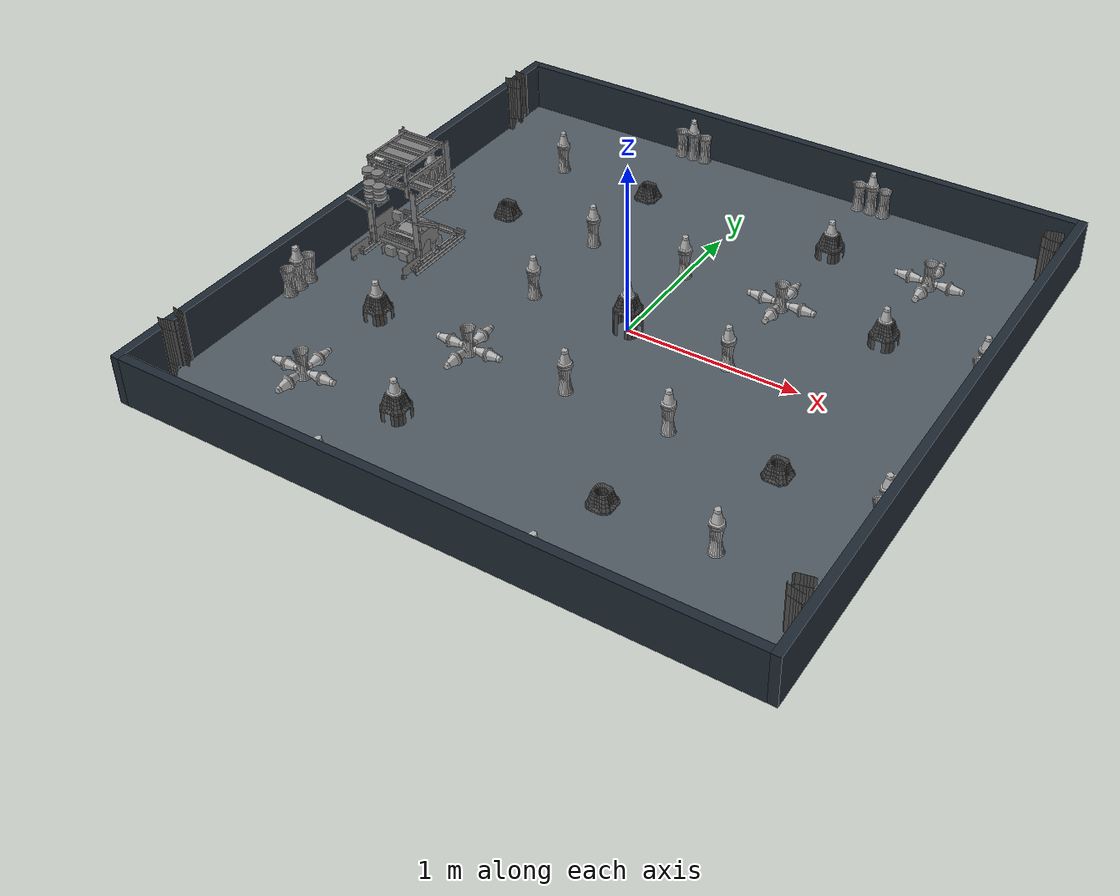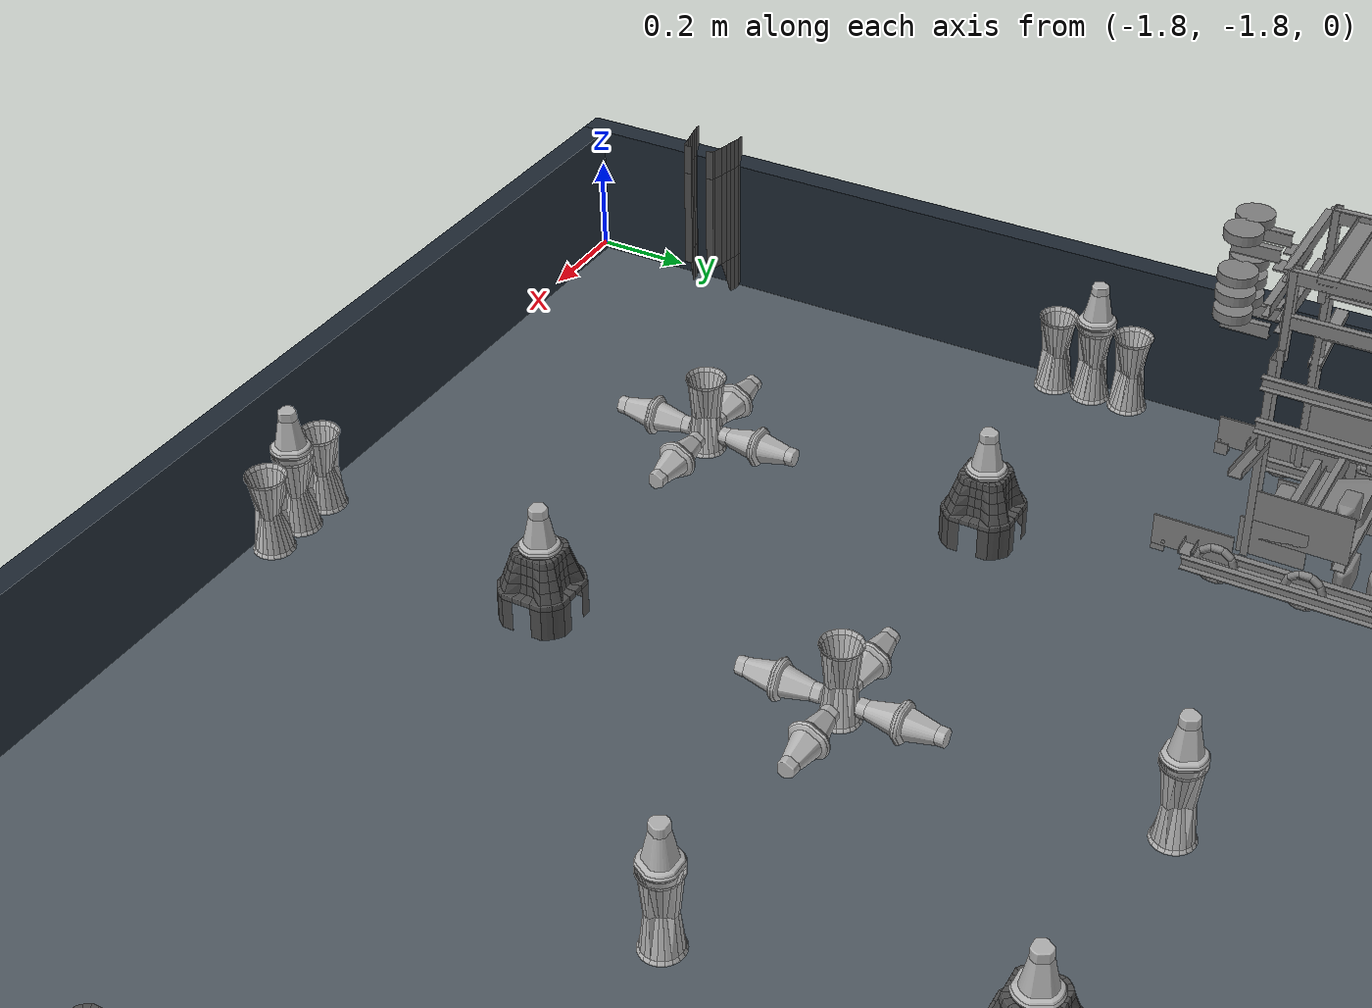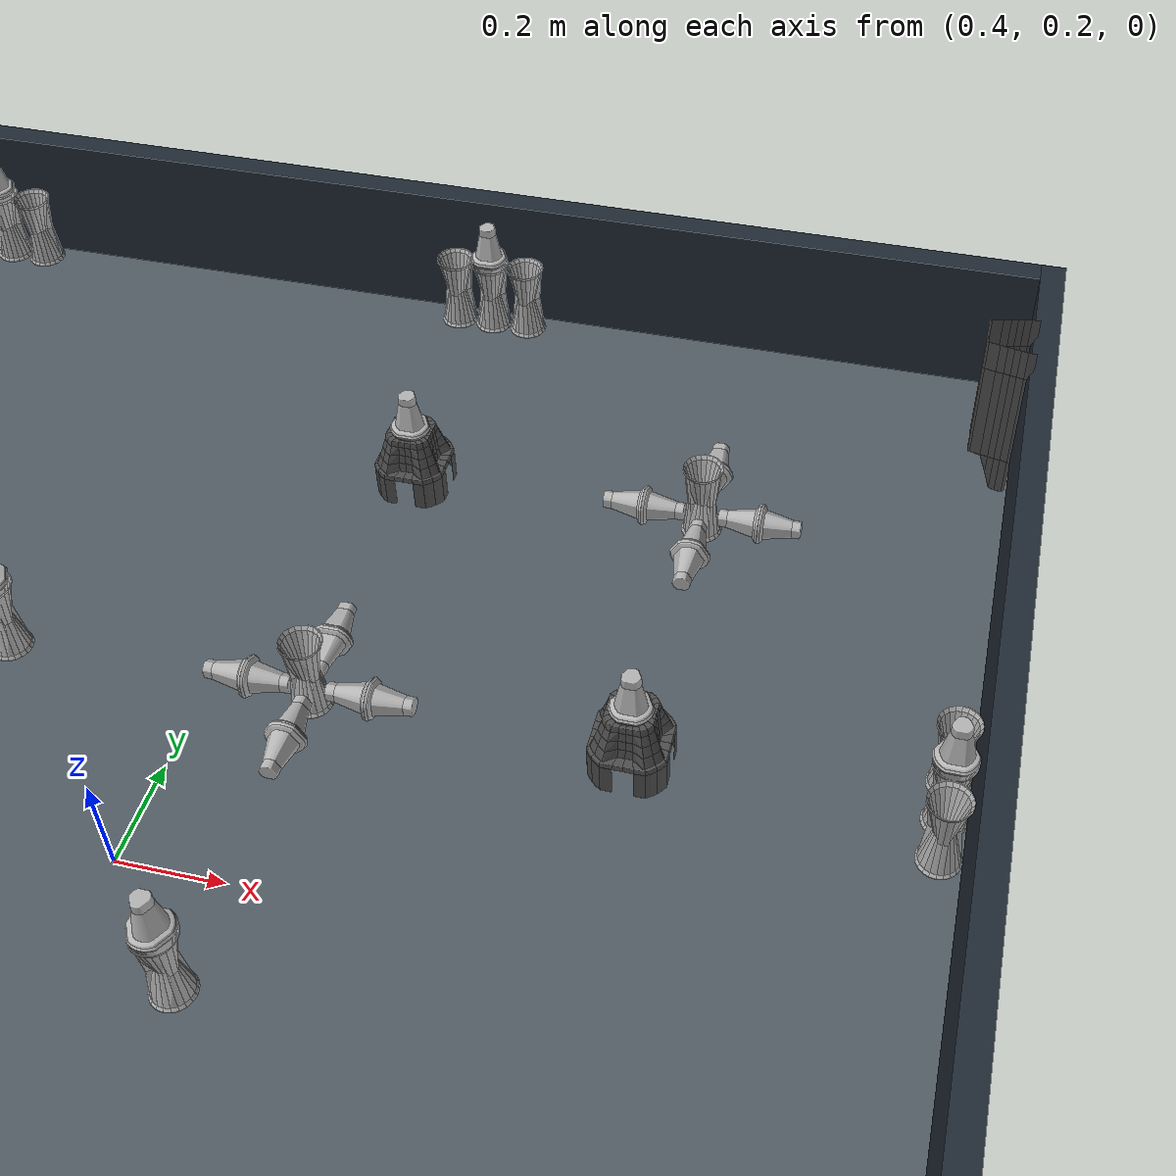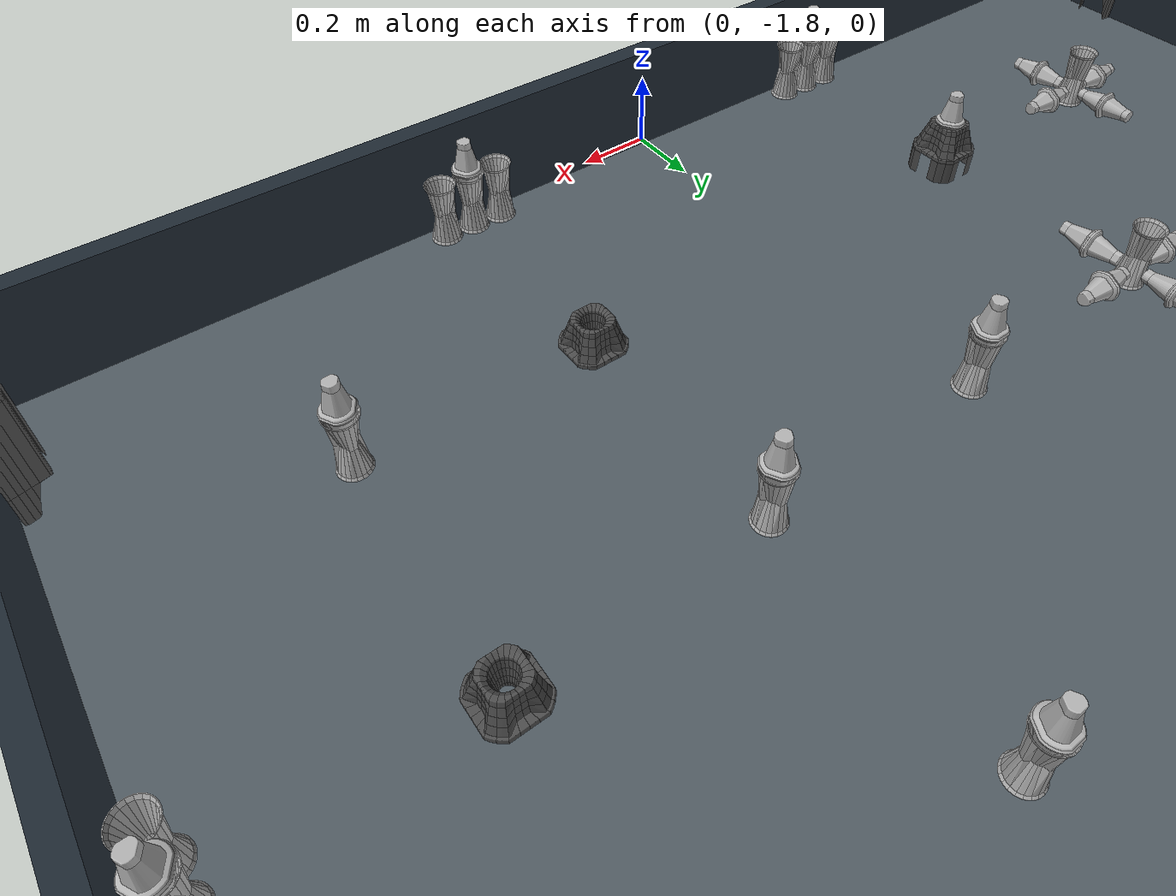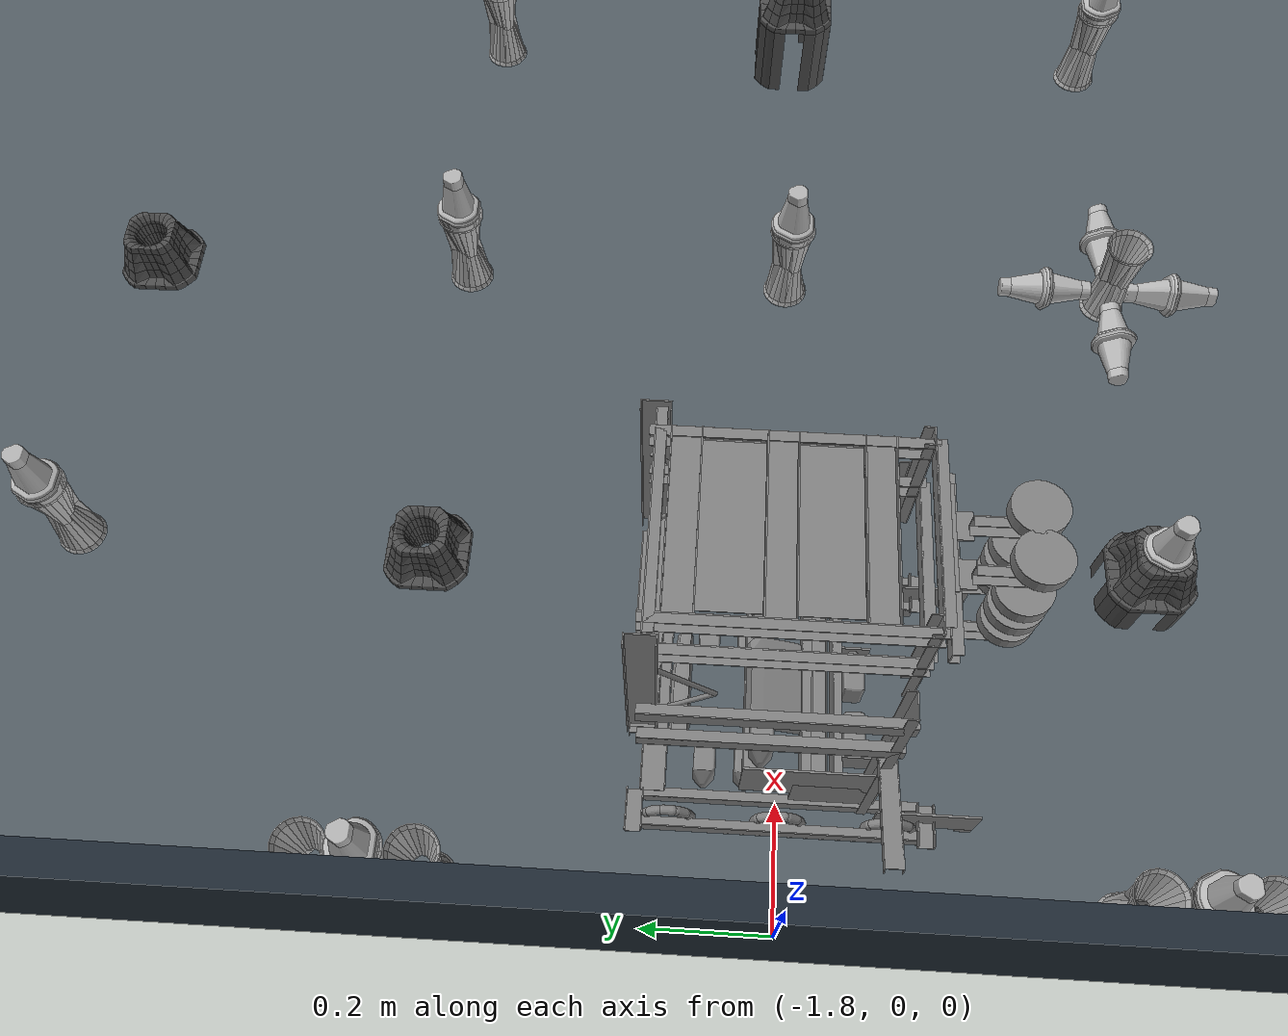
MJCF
<mujoco model="Override full field development">
  <compiler angle="radian" autolimits="true" inertiafromgeom="auto" />
  <option timestep=".002" integrator="implicitfast" solver="Newton" iterations="40" tolerance="1e-8" cone="elliptic" gravity="0 0 -9.81">
    <flag sleep="enable" />
  </option>
  <size memory="128M" />
  <default>
    <joint damping=".025" armature=".001" />
    <geom friction=".65 .003 .0001" solref=".008 1" solimp=".95 .99 .001" condim="4" margin=".0002" />
  </default>
  <asset>
    <mesh name="pin_slice0" vertex="0.017500186 -7.5826643e-05 0.001965456 -0.0080880759 0.013997452 0.00013886451 -0.0077943276 0.013773133 3.2043456e-05 -0.0077195547 0.013858587 3.2043456e-05 -0.0074311469 0.013634269 0 -0.0074952362 0.01357018 0 -0.0075486468 0.013495407 0 -0.015501248 -0.00029480457 0 -0.015522613 -0.00038025855 0 -0.015458521 -0.00020935058 0 0.0082604263 -0.013572287 3.2043456e-05 0.0081536053 -0.013609671 3.2043456e-05 0.0084099672 -0.013908763 0.00013886451 0.0082550858 -0.013962173 0.00013886451 0.0083565615 -0.014303989 0.00032045364 0.008084173 -0.013999557 0.00013886451 0.0079132651 -0.013796601 6.4086913e-05 0.0080307673 -0.013636374 3.2043456e-05 0.0080040596 -0.013278536 0 0.0080948542 -0.013251829 0 0.0081749676 -0.013209104 0 0.0084420155 -0.01364706 6.4086913e-05 0.016250414 -0.00032150745 0.00013886451 0.015881891 -0.00036423682 3.2043456e-05 0.016036777 -0.00049241542 6.4086913e-05 0.015433254 -0.0043912744 6.4086913e-05 0.015529394 -0.00047639369 0 0.015524053 -0.00038025855 0 0.015497346 -0.00029480457 0 0.015860529 -0.00024673461 3.2043456e-05 0.016218366 -0.00015059948 0.00013886451 0.016560187 -6.5145491e-05 0.00032045364 0.016602912 -0.00028411865 0.00032045364 0.016517458 -0.00050309657 0.0002617073 0.015892572 -0.0045194577 0.0002617073 0.014311666 -0.0082634304 0.0002617073 0.013895077 -0.0080230902 6.4086913e-05 0.011860194 -0.011505356 0.0002617073 0.011518373 -0.011174221 6.4086913e-05 0.0086930368 -0.014052968 0.0002617073 0.0085541723 -0.014229216 0.00032045364 0.0086823557 -0.014522967 0.00057147978 0.0084420155 -0.014608421 0.00057147978 0.0081803129 -0.014667172 0.00057147978 0.0081375836 -0.014352059 0.00032045364 0.0079132651 -0.014271946 0.0002617073 0.0079132651 -0.013283877 0 0.011149854 -0.010816378 0 0.013451781 -0.0077667235 0 0.014941892 -0.0042470693 0 0.015459962 -0.00020935058 0 0.01582314 -0.00013457775 3.2043456e-05 0.01616496 4.286766e-06 0.00013886451 0.016490755 0.0001378107 0.00032045364 0.016789846 0.00026065111 0.00057147978 0.016869959 1.4967918e-05 0.00057147978 0.016918025 -0.00024673461 0.00057147978 0.017120981 7.9059599e-05 0.00088659285 0.017174391 -0.00022003173 0.00088659285 0.016928711 -0.0005191183 0.00057147978 0.016287799 -0.0046316146 0.00057147978 0.014669509 -0.0084663818 0.00057147978 0.012159281 -0.011793766 0.00057147978 0.0089120148 -0.014400124 0.00057147978 0.008789172 -0.014757967 0.00088659285 0.0085167883 -0.014859442 0.00088659285 0.008217697 -0.014923534 0.00088659285 0.0079132651 -0.014688534 0.00057147978 -0.0079118274 -0.013796601 6.4086913e-05 -0.0079118274 -0.014271946 0.0002617073 -0.0080773948 -0.013999557 0.00013886451 -0.0080293272 -0.013636374 3.2043456e-05 -0.0081414865 -0.013615012 3.2043456e-05 -0.0080026219 -0.013278536 0 -0.0080934165 -0.013251829 0 -0.0079118274 -0.013283877 0 0.007550082 0.013495407 0 0.0074966763 0.01357018 0 0.0073524712 0.013682339 0 0.007427244 0.013634269 0 0.0076195143 0.013938701 3.2043456e-05 0.0077103136 0.013863928 3.2043456e-05 0.007790427 0.013773133 3.2043456e-05 0.008084173 0.014002793 0.00013886451 0.0079933785 0.013751769 6.4086913e-05 0.015903253 4.7016143e-05 6.4086913e-05 0.016319847 0.00028735637 0.0002617073 0.016672344 0.00049031018 0.00057147978 0.017030186 0.00035678624 0.00088659285 0.017201094 0.00043155908 0.0012390899 0.01730257 0.00012712955 0.0012390899 0.017409391 0.00015383243 0.0016022682 0.017473483 -0.00018798351 0.0016022682 0.017361321 -0.00019866466 0.0012390899 0.017249164 -0.00052980422 0.00097738264 0.016597571 -0.0047224091 0.00097738264 0.014941892 -0.0086266087 0.00097738264 0.012383599 -0.012012744 0.00097738264 0.0090775822 -0.014672513 0.00097738264 0.0088639448 -0.014928875 0.0012390899 0.0085701988 -0.015041032 0.0012390899 0.0085969017 -0.015147853 0.0016022682 0.0082443998 -0.015110464 0.0012390899 0.0079132651 -0.015003647 0.00097738264 -0.0079118274 -0.014688534 0.00057147978 -0.0081681893 -0.014667172 0.00057147978 -0.0081254624 -0.014352059 0.00032045364 -0.0082376216 -0.013967514 0.00013886451 -0.0082589863 -0.013572287 3.2043456e-05 -0.0081735323 -0.013209104 0 -0.011153755 -0.010816378 0 -0.013455684 -0.0077667235 0 -0.014940455 -0.0042470693 0 -0.015527954 -0.00047639369 0 -0.015885794 -0.0003695774 3.2043456e-05 -0.015864429 -0.00025207519 3.2043456e-05 -0.015827043 -0.00013991832 3.2043456e-05 -0.016168861 -1.0538101e-06 0.00013886451 -0.015901816 4.7016143e-05 6.4086913e-05 -0.011949548 0.0068993925 6.4086913e-05 -0.0079919408 0.013751769 6.4086913e-05 -0.008408532 0.013986768 0.0002617073 -0.0086168263 0.0144087 0.00057147978 -0.0087610314 0.014195065 0.00057147978 -0.0083658026 0.014211087 0.00032045364 -0.0079759167 0.014120292 0.00013886451 -0.0076287602 0.013938701 3.2043456e-05 -0.0073510311 0.013682339 0 -0.00378865 0.015065632 0 -1.9502639e-06 0.015535631 0 0.0037900876 0.015065632 0 0.0075928114 0.014136314 6.4086913e-05 0.0078384922 0.014237792 0.00013886451 0.0079666756 0.014130974 0.00013886451 0.0082123564 0.014387338 0.00032045364 0.0083619021 0.014221768 0.00032045364 0.0084046267 0.013986768 0.0002617073 0.012362237 0.0071397327 0.0002617073 0.012720079 0.0073426865 0.00057147978 0.016950073 0.000650537 0.00097738264 0.017126321 0.0007520151 0.0014527225 0.01730257 0.00047428607 0.0016022682 0.017382683 0.00037281036 0.001965456 0.017526888 -0.00053514479 0.001965456 0.017452116 -0.00053514479 0.0014527225 0.016795187 -0.0047758197 0.0014527225 0.015118141 -0.0087280891 0.0014527225 0.012533145 -0.012156944 0.0014527225 0.009189739 -0.014843421 0.0014527225 0.0089120148 -0.01503035 0.0016022682 0.0088158796 -0.015115804 0.001965456 0.0083725832 -0.015243988 0.001965456 0.0082604263 -0.015222625 0.0016022682 0.0079132651 -0.015206599 0.0014527225 -0.0079118274 -0.015003647 0.00097738264 -0.0082055758 -0.014923534 0.00088659285 -0.0084192131 -0.014613762 0.00057147978 -0.0083337591 -0.01430933 0.00032045364 -0.008403189 -0.013908763 0.00013886451 -0.008445916 -0.01364706 6.4086913e-05 -0.011516936 -0.011174221 6.4086913e-05 -0.013898978 -0.0080230902 6.4086913e-05 -0.015437157 -0.0043912744 6.4086913e-05 -0.01604068 -0.00049241542 6.4086913e-05 -0.016248974 -0.0003321886 0.00013886451 -0.016222272 -0.0001666212 0.00013886451 -0.016564087 -8.1167219e-05 0.00032045364 -0.016494658 0.00013247013 0.00032045364 -0.016318407 0.00028735637 0.0002617073 -0.012996366 0.0075029133 0.00097738264 -0.0090387581 0.014355292 0.00097738264 -0.0088251207 0.014568927 0.00088659285 -0.008445916 0.014600973 0.00057147978 -0.0082269404 0.014371314 0.00032045364 -0.0078423951 0.014232452 0.00013886451 -0.0075967143 0.014136314 6.4086913e-05 -0.0039168333 0.015562336 6.4086913e-05 -1.9502639e-06 0.016048357 6.4086913e-05 0.003918271 0.015562336 6.4086913e-05 0.0078224705 0.014558246 0.0002617073 0.008046789 0.0145262 0.00032045364 0.0082337187 0.014782564 0.00057147978 0.0084313343 0.014616995 0.00057147978 0.0086129234 0.014419381 0.00057147978 0.0087624691 0.014195065 0.00057147978 0.0090401981 0.014355292 0.00097738264 0.0092164467 0.014456768 0.0014527225 0.017190413 0.00078940151 0.001965456 0.016864619 -0.004797182 0.001965456 0.015187573 -0.0087654732 0.001965456 0.012586555 -0.012210355 0.001965456 0.0092271278 -0.014912853 0.001965456 0.0079132651 -0.015286717 0.001965456 -0.0079118274 -0.015206599 0.0014527225 -0.0082269404 -0.015110464 0.0012390899 -0.0084886454 -0.014864783 0.00088659285 -0.0086755751 -0.014528308 0.00057147978 -0.0085473941 -0.014234557 0.00032045364 -0.0086969398 -0.014052968 0.0002617073 -0.011864094 -0.011505356 0.0002617073 -0.014310229 -0.0082634304 0.0002617073 -0.015896475 -0.0045194577 0.0002617073 -0.01651602 -0.00050309657 0.0002617073 -0.016601474 -0.00029480457 0.00032045364 -0.016916587 -0.00026275634 0.00057147978 -0.01687386 -6.3943861e-06 0.00057147978 -0.016793747 0.00024996995 0.00057147978 -0.016676247 0.00049031018 0.00057147978 -0.016948633 0.000650537 0.00097738264 -0.017124884 0.0007520151 0.0014527225 -0.013172614 0.0076043914 0.0014527225 -0.0092150066 0.014456768 0.0014527225 -0.0089746664 0.014681086 0.0012390899 -0.0086275075 0.014787905 0.00088659285 -0.0082429622 0.014777224 0.00057147978 -0.0080560325 0.014520859 0.00032045364 -0.0078210304 0.014558246 0.0002617073 -0.0040343331 0.016026995 0.0002617073 -1.9502639e-06 0.016523697 0.0002617073 0.0040304278 0.016026995 0.0002617073 0.0080147408 0.014921426 0.00057147978 0.0083886049 0.014990859 0.00088659285 0.0086129234 0.014803927 0.00088659285 0.0088158796 0.01457961 0.00088659285 0.0089654253 0.014691767 0.0012390899 0.0090508793 0.0147612 0.0016022682 0.0092805384 0.014494154 0.001965456 -0.0079118274 -0.015286717 0.001965456 -0.0082429622 -0.015222625 0.0016022682 -0.0085420535 -0.015046372 0.0012390899 -0.0087770532 -0.014763307 0.00088659285 -0.0089105747 -0.014400124 0.00057147978 -0.012157845 -0.011793766 0.00057147978 -0.014668069 -0.0084663818 0.00057147978 -0.016291701 -0.0046316146 0.00057147978 -0.016927271 -0.0005191183 0.00057147978 -0.017178292 -0.00023071289 0.00088659285 -0.017124884 5.2356719e-05 0.00088659285 -0.017034087 0.00034610509 0.00088659285 -0.017204997 0.00041553735 0.0012390899 -0.017311813 0.00045826434 0.0016022682 -0.017194314 0.00078940151 0.001965456 -0.0092790983 0.014494154 0.001965456 -0.0090601204 0.014750518 0.0016022682 -0.0087610314 0.014921426 0.0012390899 -0.0083978484 0.014985518 0.00088659285 -0.0080186461 0.014921426 0.00057147978 -0.0041304683 0.016422221 0.00057147978 -1.9502639e-06 0.016934948 0.00057147978 0.0041319083 0.016422221 0.00057147978 0.0081642864 0.015199153 0.00097738264 0.008495426 0.015145745 0.0012390899 0.0087411068 0.014937451 0.0012390899 0.0088158796 0.015022905 0.0016022682 0.0090134905 0.014868018 0.001965456 -0.0083711455 -0.015243988 0.001965456 -0.0085687588 -0.015153193 0.0016022682 -0.008851826 -0.014934215 0.0012390899 -0.0090814851 -0.014672513 0.00097738264 -0.012387502 -0.012012744 0.00097738264 -0.014945795 -0.0086266087 0.00097738264 -0.016596133 -0.0047224091 0.00097738264 -0.017247724 -0.00052980422 0.00097738264 -0.017365224 -0.00021469116 0.0012390899 -0.017306473 0.0001004219 0.0012390899 -0.017418632 0.00012712955 0.0016022682 -0.017386586 0.00037281036 0.001965456 -0.0090120528 0.014868018 0.001965456 -0.0088411448 0.01500154 0.0016022682 -0.0085100077 0.015135064 0.0012390899 -0.0081681893 0.015199153 0.00097738264 -0.0042105817 0.016731994 0.00097738264 -1.9502639e-06 0.017255401 0.00097738264 0.0042120217 0.016731994 0.00097738264 0.0082657669 0.015380745 0.0014527225 0.0085648535 0.01523654 0.0016022682 0.0086823557 0.015188472 0.001965456 -0.0088144396 -0.015115804 0.001965456 -0.0088998936 -0.015041032 0.0016022682 -0.0091883014 -0.014843421 0.0014527225 -0.012531707 -0.012156944 0.0014527225 -0.015122044 -0.0087280891 0.0014527225 -0.016793747 -0.0047758197 0.0014527225 -0.017450678 -0.00053514479 0.0014527225 -0.017472043 -0.00020400524 0.0016022682 -0.017498746 -7.5826643e-05 0.001965456 -0.008680918 0.015188472 0.001965456 -0.0085740993 0.015225858 0.0016022682 -0.0082643269 0.015380745 0.0014527225 -0.0042586493 0.016929607 0.0014527225 -1.9502639e-06 0.017458355 0.0014527225 0.0042600869 0.016929607 0.0014527225 0.0082978104 0.015444836 0.001965456 -0.0092256878 -0.014912853 0.001965456 -0.012585115 -0.012210355 0.001965456 -0.015186135 -0.0087654732 0.001965456 -0.016863179 -0.004797182 0.001965456 -0.017525451 -0.00053514479 0.001965456 -0.0083017133 0.015444836 0.001965456 -0.0042800139 0.01700438 0.001965456 -1.9502639e-06 0.017533128 0.001965456 0.004281454 0.01700438 0.001965456 0.018077779 -0.00084900027 0.017500008 0.017500782 -0.0044081178 0.017500008 0.015724353 -0.0089378371 0.017500008 0.018078073 -0.00072378761 0.017500008 0.018079938 -0.0008107144 0.017500008 0.017895154 0.00017175345 0.017500008 0.017833708 0.00029054028 0.017500008 0.017774443 0.00039470435 0.017500008 0.013046673 -0.012539101 0.017500008 0.0084113094 0.016016788 0.017500008 0.0083381312 0.016061196 0.017500008 0.009189739 0.015266519 0.017500008 0.012566767 -0.01295165 0.017500008 0.0097884801 -0.015219647 0.017500008 0.0083041915 0.01607809 0.017500008 0.0082833849 0.016087192 0.017500008 0.0085434985 -0.015591949 0.017500008 0.008664742 -0.015589784 0.017500008 0.0088193092 -0.015579843 0.017500008 0.0096651116 -0.015291233 0.017500008 0.0097398565 -0.015248299 0.017500008 -0.0087973689 -0.01558364 0.017500008 -0.0086686425 -0.015589784 0.017500008 -0.008547399 -0.015591949 0.017500008 -0.0096627934 -0.015291412 0.017500008 -0.018078498 -0.0008107144 0.017500008 -0.018076932 -0.00072463709 0.017500008 -0.017813849 0.00032597934 0.017500008 -0.017901005 0.00015215183 0.017500008 -0.018041299 -0.0002791167 0.017500008 -0.0091883014 0.015266519 0.017500008 -0.008336692 0.016061196 0.017500008 -0.0084117322 0.016016102 0.017500008 0.0043349871 0.017565948 0.017500008 -0.0097920738 -0.015219647 0.017500008 -0.018076339 -0.00084900027 0.017500008 -0.0082819449 0.016087192 0.017500008 -0.0083027538 0.01607809 0.017500008 -0.0049359676 0.017356608 0.017500008 -0.0001231076 0.01808247 0.017500008 -0.015601758 -0.0091477938 0.017500008 -0.017382172 -0.0050300068 0.017500008 0.017383487 -0.0050300068 0.017500008 0.01741461 -0.0049123076 0.017500008 0.015603195 -0.0091477938 0.017500008 0.015673099 -0.0090481262 0.017500008 0.018040176 -0.00029107194 0.017500008 0.018039123 -0.00028499424 0.017500008 0.018037568 -0.0002791167 0.017500008 0.017886308 0.00019014531 0.017500008 0.01767944 0.00055951446 0.017500008 0.017239725 0.0013216128 0.017500008 0.01296022 -0.012624812 0.017500008 0.0091113358 0.015396995 0.017500008 0.0090997352 0.015413487 0.017500008 0.009085931 0.015429873 0.017500008 0.0087770431 0.015762225 0.017500008 0.0087729776 0.015766523 0.017500008 0.0087682327 0.015770415 0.017500008 0.0087629651 0.015774086 0.017500008 0.0087783631 -0.015584959 0.017500008 0.0087982272 -0.01558364 0.017500008 0.0092637411 -0.015480925 0.017500008 0.0092695314 -0.015479517 0.017500008 0.009275329 -0.015477335 0.017500008 0.009280971 -0.015474719 0.017500008 0.004932842 0.017356608 0.017500008 0.0044524394 0.017534084 0.017500008 -0.0092738913 -0.015477335 0.017500008 -0.0092680937 -0.015479517 0.017500008 -0.0092623034 -0.015480925 0.017500008 -0.0087769231 -0.015584959 0.017500008 -0.01788487 0.00019014531 0.017500008 -0.017893716 0.00017175345 0.017500008 -0.018043024 -0.00028499424 0.017500008 -0.018044077 -0.00029107194 0.017500008 -0.01804463 -0.00029736152 0.017500008 -0.008766795 0.015770415 0.017500008 -0.0087715399 0.015766523 0.017500008 -0.0087757746 0.015762225 0.017500008 -0.0090982975 0.015413487 0.017500008 -0.0091098979 0.015396995 0.017500008 0.00011933057 0.01808247 0.017500008 -1.9502639e-06 0.018093214 0.017500008 -0.012958903 -0.012624812 0.017500008 -0.012565327 -0.01295165 0.017500008 -0.013045233 -0.012539101 0.017500008 -0.015671661 -0.0090481262 0.017500008 -0.015723039 -0.0089378371 0.017500008 -0.017499344 -0.0044081178 0.017500008 -0.017413172 -0.0049123076 0.017500008 -0.0044562187 0.017534084 0.017500008 -0.0043387665 0.017565948 0.017500008" />
    <mesh name="pin_slice1" vertex="0.027679943 -0.00018264293 0.062889122 0.025559606 -0.00058320998 0.05286425 0.023428587 -0.00098912237 0.042844714 0.021286883 -0.0014057111 0.032825183 0.019668593 -0.0014644622 0.025203714 0.012570533 -0.019794435 0.042844714 0.013280873 -0.02184 0.05286425 0.013996553 -0.023880224 0.062889122 0.018103709 -0.00079684733 0.017608957 0.011860194 -0.017732849 0.032825183 0.0083619021 0.016075062 0.017608957 0.0094247387 0.019135398 0.032825183 0.010856104 0.020780396 0.042844714 0.012276783 0.022425394 0.05286425 0.01368144 0.024065051 0.062889122 0.011101784 -0.016301484 0.025203714 0.0085701988 0.017762787 0.025203714 0.0097398565 -0.015276031 0.017608957 -0.0097384165 -0.015276031 0.017608957 -0.018102269 -0.00079684733 0.017608957 -0.008360462 0.016075062 0.017608957 -0.014000456 -0.023880224 0.062889122 -0.013284774 -0.02184 0.05286425 -0.012569093 -0.019794435 0.042844714 -0.011858754 -0.017732849 0.032825183 -0.011100344 -0.016301484 0.025203714 -0.019667153 -0.0014644622 0.025203714 -0.021285445 -0.0014057111 0.032825183 -0.023427147 -0.00098912237 0.042844714 -0.025558166 -0.00058320998 0.05286425 -0.027678506 -0.00018264293 0.062889122 -0.0085687588 0.017762787 0.025203714 -0.01368 0.024065051 0.062889122 -0.012275345 0.022425394 0.05286425 -0.010860004 0.020780396 0.042844714 -0.009428644 0.019135398 0.032825183 0.017414605 -0.0049123076 0.017499988 0.017500777 -0.0044081254 0.017499988 0.015724348 -0.0089378367 0.017499988 0.015673095 -0.0090481241 0.017499988 0.018079934 -0.00081071694 0.017499988 0.018077775 -0.00084899867 0.017499988 0.018040172 -0.00029106714 0.017499988 0.018039119 -0.00028499182 0.017499988 0.018037564 -0.00027911657 0.017499988 0.017895149 0.00017175709 0.017499988 0.017886305 0.00019014706 0.017499988 0.017679438 0.00055951422 0.017499988 0.017239744 0.0013215771 0.017499988 0.013046669 -0.012539098 0.017499988 0.0091113356 0.015396991 0.017499988 0.0090997362 0.015413482 0.017499988 0.0087729777 0.015766518 0.017499988 0.0087682346 0.015770409 0.017499988 0.0087629691 0.015774078 0.017499988 0.012960218 -0.012624809 0.017499988 0.012566771 -0.012951641 0.017499988 0.0087783598 -0.015584957 0.017499988 0.0087982219 -0.015583639 0.017499988 0.0092695274 -0.015479515 0.017499988 0.0092637393 -0.015480922 0.017499988 0.0092753227 -0.015477333 0.017499988 0.0092809625 -0.015474718 0.017499988 0.0043349868 0.017565944 0.017499988 0.0044524372 0.017534081 0.017499988 -0.0092680897 -0.015479515 0.017499988 -0.009273885 -0.015477333 0.017499988 -0.0092623016 -0.015480922 0.017499988 -0.0087973636 -0.015583639 0.017499988 -0.0087769198 -0.015584957 0.017499988 -0.0085473894 -0.015591947 0.017499988 -0.017884867 0.00019014706 0.017499988 -0.017893712 0.00017175709 0.017499988 -0.018041296 -0.00027911657 0.017499988 -0.01804302 -0.00028499182 0.017499988 -0.018044625 -0.00029735427 0.017499988 -0.018044072 -0.00029106714 0.017499988 -0.00877154 0.015766518 0.017499988 -0.008766797 0.015770409 0.017499988 -0.008775773 0.015762222 0.017499988 -0.0091098977 0.015396991 0.017499988 -1.9502639e-06 0.01809321 0.017499988 0.00011932872 0.018082465 0.017499988 -0.018076335 -0.00084899867 0.017499988 -0.018078494 -0.00081071694 0.017499988 -0.0083366877 0.016061194 0.017499988 -0.0083027531 0.016078085 0.017499988 -0.012565331 -0.012951641 0.017499988 -0.012958901 -0.012624809 0.017499988 -0.015601755 -0.0091477902 0.017499988 -0.015671657 -0.0090481241 0.017499988 -0.017382168 -0.005030005 0.017499988 -0.017413167 -0.0049123076 0.017499988 -0.0044562166 0.017534081 0.017499988 -0.0043387662 0.017565944 0.017499988 0.017383483 -0.005030005 0.017499988 0.018078068 -0.0007237742 0.017499988 0.017833707 0.00029053871 0.017499988 0.017774437 0.00039471177 0.017499988 0.015603193 -0.0091477902 0.017499988 0.0083381268 0.016061194 0.017499988 0.0084113184 0.016016777 0.017499988 0.009189739 0.015266516 0.017499988 0.0087770415 0.015762222 0.017499988 0.0090859335 0.015429865 0.017499988 0.0097884766 -0.015219644 0.017499988 0.0083041909 0.016078085 0.017499988 0.0085434888 -0.015591947 0.017499988 0.0086647428 -0.015589782 0.017499988 0.0088193017 -0.015579842 0.017499988 0.0097398565 -0.015248294 0.017499988 0.0096650979 -0.015291236 0.017499988 0.0049328326 0.017356607 0.017499988 0.0082833842 0.016087187 0.017499988 -0.0086686433 -0.015589782 0.017499988 -0.0096627795 -0.015291415 0.017499988 -0.018076927 -0.00072462383 0.017499988 -0.017813846 0.00032598083 0.017499988 -0.017900999 0.00015215746 0.017499988 -0.0090982985 0.015413482 0.017499988 -0.0091883014 0.015266516 0.017499988 -0.0084117416 0.016016091 0.017499988 -0.0097920704 -0.015219644 0.017499988 -0.017499339 -0.0044081254 0.017499988 -0.0082819441 0.016087187 0.017499988 -0.0049359581 0.017356607 0.017499988 -0.00012310575 0.018082465 0.017499988 -0.013045229 -0.012539098 0.017499988 -0.015723034 -0.0089378367 0.017499988 0.0297076 0.00019626235 0.072500008 0.013870166 -0.026074295 0.072500008 0.013884224 -0.026073943 0.072500008 0.014299073 -0.025990226 0.072500008 0.015362957 0.025381026 0.072500008 0.015645168 0.025046533 0.072500008 0.018969525 -0.022860023 0.072500008 0.018954587 -0.02287058 0.072500008 0.018924717 -0.022891356 0.072500008 0.010312747 0.027862169 0.072500008 0.010329366 0.027854475 0.072500008 0.010460743 0.027792663 0.072500008 0.010362375 0.02783909 0.072500008 -0.013866226 -0.026074363 0.072500008 -0.01428175 -0.025999205 0.072500008 -0.029653455 0.00062476611 0.072500008 -0.029657571 0.00061137951 0.072500008 -0.029515845 0.001024603 0.072500008 -0.029522586 0.0010122375 0.072500008 -0.015641277 0.025058995 0.072500008 -0.01565008 0.025044458 0.072500008 -0.014672421 -0.02583239 0.072500008 -0.014686582 -0.025825955 0.072500008 -0.029282071 -0.0050065185 0.072500008 -0.029282782 -0.0050000176 0.072500008 -0.029287602 -0.00494555 0.072500008 -0.029284463 -0.004981785 0.072500008 -0.029296534 -0.0048370361 0.072500008 -0.015361389 0.025381298 0.072500008 -0.015372871 0.025368864 0.072500008 -0.010305372 0.027864805 0.072500008 -0.010311362 0.027862169 0.072500008 -0.015021531 0.025631877 0.072500008 -0.01503429 0.025622865 0.072500008 0.029283511 -0.0050065185 0.072500008 0.018974795 -0.022856149 0.072500008 0.010306812 0.027864805 0.072500008 0.010278162 0.027875389 0.072500008 -0.018978649 -0.022856149 0.072500008 0.025729592 -0.014853137 0.072500008 0.018998259 -0.022836658 0.072500008 0.0052045385 0.029247144 0.072500008 -1.9502639e-06 0.029708412 0.072500008 -0.019002121 -0.022836658 0.072500008 -0.022708167 -0.019157124 0.072500008 -0.025728154 -0.014853137 0.072500008 -0.027933755 -0.010118514 0.072500008 -0.029276932 -0.0050365868 0.072500008 0.027942288 -0.01008932 0.072500008 0.022709602 -0.019157124 0.072500008 0.022728701 -0.019131789 0.072500008 -0.0052346317 0.029243285 0.072500008 -0.022727266 -0.019131789 0.072500008 0.02951601 0.001031873 0.072500008 0.02965411 0.00063230124 0.072500008 0.029524193 0.0010169539 0.072500008 0.029706198 0.00021170918 0.072500008 0.029659027 0.00061614896 0.072500008 0.029284223 -0.0050000176 0.072500008 0.014285462 -0.025993456 0.072500008 0.014687799 -0.025825955 0.072500008 0.015637852 0.025058723 0.072500008 0.015372636 0.025370869 0.072500008 0.018835281 -0.022953443 0.072500008 0.015022971 0.025631877 0.072500008 -0.013883426 -0.026073981 0.072500008 -0.014298148 -0.025995265 0.072500008 -0.018973371 -0.022860023 0.072500008 -0.029706162 0.00019626235 0.072500008 0.029278372 -0.0050365868 0.072500008 0.027929893 -0.010118514 0.072500008 0.0052360327 0.029243285 0.072500008 -0.0052031375 0.029247144 0.072500008 -0.02794615 -0.01008932 0.072500008 -0.010276761 0.027875389 0.072500008" />
    <mesh name="pin_slice2" vertex="-0.015762953 -0.033119988 0.075482968 -0.015506589 -0.033178739 0.075482968 -0.015843067 -0.032890329 0.075215924 -0.015618748 -0.03247908 0.074810017 -0.015869772 -0.032751464 0.075087741 -0.015554657 -0.032890329 0.075119785 0.020945067 -0.029247832 0.074767287 0.025602335 -0.0252742 0.074767287 0.025255174 -0.024937725 0.074569672 0.029116649 -0.020296483 0.074569672 0.029511875 -0.020574207 0.074767287 0.029853691 -0.020809206 0.075087741 0.025896081 -0.025567951 0.075087741 0.021185407 -0.029584307 0.075087741 0.015865869 -0.032751464 0.075087741 0.015759053 -0.033119988 0.075482968 0.015844507 -0.032890329 0.075215924 0.015508027 -0.033178739 0.075482968 0.015550756 -0.032890329 0.075119785 0.015251665 -0.032890329 0.075087741 0.015620188 -0.03247908 0.074810017 0.01568428 -0.0323776 0.074767287 0.020667338 -0.028857946 0.074569672 0.032134256 -0.015067739 0.074569672 0.032572211 -0.015276031 0.074767287 0.032946076 -0.015446944 0.075087741 0.036294817 0.0026320123 0.075087741 0.036294817 0.002867012 0.075119785 0.035883569 0.0029417848 0.074815357 0.036107887 0.0032355332 0.075087741 0.036294817 0.003182125 0.075237287 0.036561865 0.002909739 0.075482968 0.036487092 0.0031607603 0.075482968 0.03660993 0.0026533746 0.075498989 0.036535157 -0.0035847997 0.075498989 0.036214704 -0.003558092 0.075087741 0.035397548 -0.0097268341 0.075498989 0.035087775 -0.0096413801 0.075087741 0.033234481 -0.015585804 0.075498989 0.030115394 -0.0209908 0.075498989 0.0261204 -0.025792269 0.075498989 0.021372337 -0.029846014 0.075498989 0.016004734 -0.033034534 0.075498989 0.015251665 -0.033210782 0.075498989 -0.015250227 -0.033210782 0.075498989 -0.015250227 -0.032890329 0.075087741 -0.016008634 -0.033034534 0.075498989 -0.021370902 -0.029846014 0.075498989 -0.026118962 -0.025792269 0.075498989 -0.021189308 -0.029584307 0.075087741 -0.015688181 -0.0323776 0.074767287 -0.015250227 -0.03247908 0.074767287 0.015251665 -0.03247908 0.074767287 0.015251665 -0.031993055 0.074569672 0.015475983 -0.031944989 0.074569672 0.03422789 -0.0094063804 0.074569672 0.034692549 -0.0095345638 0.074767287 0.035803456 -0.0035153674 0.074767287 0.035883569 0.002605307 0.074767287 0.035750045 0.0030325794 0.074767287 0.036385616 0.00339576 0.075498989 -0.030113956 -0.0209908 0.075498989 -0.025894644 -0.025567951 0.075087741 -0.020948967 -0.029247832 0.074767287 -0.015474543 -0.031944989 0.074569672 -0.015250227 -0.031993055 0.074569672 0.035322775 -0.0034672975 0.074569672 0.035402888 0.0025679206 0.074569672 0.035333456 0.0027868986 0.074569672 0.025944151 0.020849828 0.075087741 0.021131997 0.029811863 0.075498989 -0.033238384 -0.015585804 0.075498989 -0.029852251 -0.020809206 0.075087741 -0.025600895 -0.0252742 0.074767287 -0.020665903 -0.028857946 0.074569672 0.02516438 0.020401191 0.074569672 0.025586309 0.020641531 0.074767287 0.020859613 0.029651636 0.075087741 0.020822224 0.02968902 0.075071719 0.020822224 0.030009474 0.075290697 0.020982451 0.030020158 0.075482968 -0.035396108 -0.0097268341 0.075498989 -0.032949976 -0.015446944 0.075087741 -0.029515776 -0.020574207 0.074767287 -0.025259077 -0.024937725 0.074569672 0.020079841 0.029202999 0.074569672 0.020053138 0.029411294 0.07460172 0.020501771 0.02944334 0.074767287 0.020459046 0.029790499 0.074884785 0.020459046 0.030148339 0.075130471 0.020800862 0.03021243 0.075482968 -0.036533722 -0.0035847997 0.075498989 -0.035091678 -0.0096413801 0.075087741 -0.032576112 -0.015276031 0.074767287 -0.02912055 -0.020296483 0.074569672 0.020197339 0.029774474 0.074767287 0.020426998 0.030116293 0.075087741 0.020608592 0.030377998 0.075498989 -0.036485652 0.0031607603 0.075482968 -0.036565766 0.002909739 0.075482968 -0.036613835 0.0026533746 0.075498989 -0.036218607 -0.003558092 0.075087741 -0.034691109 -0.0095345638 0.074767287 -0.032138159 -0.015067739 0.074569672 0.014658823 0.032327427 0.074569672 0.014856438 0.032765381 0.074767287 0.015027346 0.033144585 0.075087741 0.01516087 0.033432993 0.075498989 -0.020804765 0.03021243 0.075482968 -0.020981016 0.030020158 0.075482968 -0.021135902 0.029811863 0.075498989 -0.036384176 0.00339576 0.075498989 -0.036293379 0.003182125 0.075237287 -0.036293379 0.002867012 0.075119785 -0.036293379 0.0026320123 0.075087741 -0.035802018 -0.0035153674 0.074767287 -0.03422645 -0.0094063804 0.074569672 0.0089707659 0.034340948 0.074569672 0.0090882633 0.034810948 0.074767287 0.0091950844 0.035211515 0.075087741 0.0092751978 0.035515947 0.075498989 -0.020607152 0.030377998 0.075498989 -0.020457606 0.030148339 0.075130471 -0.020820789 0.030009474 0.075290697 -0.020820789 0.02968902 0.075071719 -0.020858173 0.029651636 0.075087741 -0.025942711 0.020849828 0.075087741 -0.03611179 0.0032355332 0.075087741 -0.035882131 0.0029417848 0.074815357 -0.035882131 0.002605307 0.074767287 -0.035326678 -0.0034672975 0.074569672 0.0030210017 0.035366401 0.074569672 0.0030583858 0.035847081 0.074767287 0.0030957698 0.03625833 0.075087741 0.0031224775 0.036573443 0.075498989 -0.0031210374 0.036573443 0.075498989 -0.0092737577 0.035515947 0.075498989 -0.01515943 0.033432993 0.075498989 -0.02042556 0.030116293 0.075087741 -0.020457606 0.029790499 0.074884785 -0.020500333 0.02944334 0.074767287 -0.025584871 0.020641531 0.074767287 -0.030669412 0.011834385 0.074767287 -0.035748607 0.0030325794 0.074767287 -0.035332019 0.0027868986 0.074569672 -0.035401448 0.0025679206 0.074569672 -0.0030195617 0.035366401 0.074569672 -0.0030569481 0.035847081 0.074767287 -0.0030943321 0.03625833 0.075087741 -0.0091936443 0.035211515 0.075087741 -0.015031249 0.033144585 0.075087741 -0.020195903 0.029774474 0.074767287 -0.020057039 0.029411294 0.07460172 -0.020083742 0.029202999 0.074569672 -0.02516828 0.020401191 0.074569672 -0.0089693258 0.034340948 0.074569672 -0.0090921662 0.034810948 0.074767287 -0.014855001 0.032765381 0.074767287 -0.014657385 0.032327427 0.074569672 0.029524189 0.001016953 0.072499988 0.027942284 -0.010089318 0.072499988 0.029284218 -0.0050000158 0.072499988 0.013884223 -0.026073939 0.072499988 0.014687797 -0.025825951 0.072499988 0.022728698 -0.019131785 0.072499988 0.025729588 -0.014853135 0.072499988 0.015372633 0.025370866 0.072499988 0.015637849 0.02505872 0.072499988 0.018835271 -0.022953445 0.072499988 0.018998257 -0.022836654 0.072499988 0.01046075 0.027792655 0.072499988 0.015022968 0.025631873 0.072499988 0.01027816 0.027875386 0.072499988 -0.013866224 -0.026074359 0.072499988 0.0052045367 0.02924714 0.072499988 -0.014281747 -0.025999201 0.072499988 -0.029653451 0.0006247659 0.072499988 -0.02951584 0.0010246027 0.072499988 -0.015650078 0.025044454 0.072499988 -1.9502639e-06 0.029708407 0.072499988 -0.014298146 -0.025995261 0.072499988 -0.014672419 -0.025832387 0.072499988 -0.018973367 -0.02286002 0.072499988 -0.022708163 -0.019157122 0.072499988 -0.02572815 -0.014853135 0.072499988 -0.02793375 -0.010118514 0.072499988 -0.029276927 -0.0050365867 0.072499988 -0.029296531 -0.0048370264 0.072499988 -0.029706158 0.00019626156 0.072499988 -0.015641274 0.025058992 0.072499988 -0.015372868 0.02536886 0.072499988 -0.0052346313 0.029243281 0.072499988 -0.015361387 0.025381294 0.072499988 -0.015034288 0.025622861 0.072499988 -0.010311362 0.027862165 0.072499988 0.029516006 0.0010318728 0.072499988 0.029654105 0.00063230113 0.072499988 0.029659023 0.00061614809 0.072499988 0.029278368 -0.0050365867 0.072499988 0.029283507 -0.005006517 0.072499988 0.029706194 0.00021170914 0.072499988 0.029707596 0.00019626156 0.072499988 0.013870164 -0.026074291 0.072499988 0.01428546 -0.025993452 0.072499988 0.014299071 -0.025990222 0.072499988 0.027929889 -0.010118514 0.072499988 0.015362955 0.025381023 0.072499988 0.015645166 0.025046529 0.072499988 0.018954582 -0.022870577 0.072499988 0.018924711 -0.022891355 0.072499988 0.022709598 -0.019157122 0.072499988 0.018969522 -0.02286002 0.072499988 0.018974792 -0.022856146 0.072499988 0.010312746 0.027862165 0.072499988 0.010329366 0.02785447 0.072499988 0.010362377 0.027839085 0.072499988 0.010306811 0.027864801 0.072499988 -0.013883425 -0.026073977 0.072499988 0.0052360324 0.029243281 0.072499988 -0.029657567 0.00061137866 0.072499988 -0.029522582 0.0010122366 0.072499988 -0.0052031356 0.02924714 0.072499988 -0.01468658 -0.025825951 0.072499988 -0.018978646 -0.022856146 0.072499988 -0.019002118 -0.022836654 0.072499988 -0.022727263 -0.019131785 0.072499988 -0.027946146 -0.010089318 0.072499988 -0.029282067 -0.005006517 0.072499988 -0.029282778 -0.0050000158 0.072499988 -0.029284459 -0.0049817823 0.072499988 -0.029287598 -0.0049455456 0.072499988 -0.010305371 0.027864801 0.072499988 -0.010276759 0.027875386 0.072499988 -0.015021528 0.025631873 0.072499988 0.037658528 0.0034284069 0.077500008 0.037714459 0.0031884706 0.077500008 0.015857805 -0.034325225 0.077500008 0.015926168 -0.034309225 0.077500008 0.015510224 -0.034364927 0.077500008 0.015677527 -0.034350165 0.077500008 -0.015929747 -0.034310817 0.077500008 -0.015859572 -0.034326899 0.077500008 -0.016255951 -0.034194299 0.077500008 -0.016098185 -0.034255631 0.077500008 0.037773444 0.00085283337 0.077500008 0.036686593 -0.0093202618 0.077500008 0.037425124 -0.0053328797 0.077500008 0.036064553 -0.011384981 0.077500008 0.031704217 -0.020644182 0.077500008 0.023332135 -0.029742965 0.077500008 0.026414557 -0.027111291 0.077500008 0.021630896 -0.031069482 0.077500008 -0.021629459 -0.031069482 0.077500008 -0.023330698 -0.029742965 0.077500008 -0.027889525 -0.025539332 0.077500008 0.031911431 0.013455181 0.077500008 0.022008847 0.0306044 0.077500008 -0.033731144 -0.017135281 0.077500008 0.022003226 0.030613769 0.077500008 -0.034662329 -0.015188599 0.077500008 0.021798596 0.030898483 0.077500008 0.021749143 0.030950845 0.077500008 -0.036687027 -0.0093202618 0.077500008 -0.037655457 0.0034289225 0.077500008 -0.037677274 0.003360561 0.077500008 -0.037775474 0.00085283337 0.077500008 -0.037723465 -0.0031969623 0.077500008 0.019628692 0.032285334 0.077500008 0.016092055 0.034268624 0.077500008 -0.021751221 0.030949425 0.077500008 -0.021799467 0.030896794 0.077500008 0.010271959 0.036430268 0.077500008 0.0081716393 0.036923028 0.077500008 0.0020264147 0.037776301 0.077500008 -0.010270518 0.036430268 0.077500008 -0.014091472 0.035078024 0.077500008 -0.016090615 0.034268624 0.077500008 -0.019627252 0.032285334 0.077500008 0.037678995 0.003359694 0.077500008 0.037515404 0.0037498727 0.077500008 0.037741593 0.0030093608 0.077500008 0.037724902 -0.0031969623 0.077500008 0.033729114 -0.017135281 0.077500008 0.034660299 -0.015188599 0.077500008 0.030484496 -0.022422239 0.077500008 0.027890963 -0.025539332 0.077500008 0.016263291 -0.034190552 0.077500008 0.018146271 -0.033139455 0.077500008 -0.015508786 -0.034364927 0.077500008 -0.016265319 -0.034190552 0.077500008 -0.018148299 -0.033139455 0.077500008 -0.026413119 -0.027111291 0.077500008 -0.031702779 -0.020644182 0.077500008 -0.030483058 -0.022422239 0.077500008 -0.036063114 -0.011384981 0.077500008 0.02191093 0.03075277 0.077500008 -0.037425561 -0.0053328797 0.077500008 0.021489189 0.031172409 0.077500008 0.02147982 0.031179903 0.077500008 -0.037585513 0.0035995748 0.077500008 -0.037741749 0.0030206027 0.077500008 -0.037743623 0.0030093608 0.077500008 0.014092912 0.035078024 0.077500008 -0.021620244 0.031069342 0.077500008 -0.022007131 0.030613769 0.077500008 -0.037513964 0.0037498727 0.077500008 -0.021478381 0.031179903 0.077500008 0.00417732 0.03760955 0.077500008 -0.0020268481 0.037776301 0.077500008 -0.0041758808 0.03760955 0.077500008 -0.0081702001 0.036923028 0.077500008" />
    <mesh name="pin_slice3" vertex="0.040070838 -0.0024845743 0.082297962 0.039931974 0.0039672374 0.082297962 0.039841179 0.0042396235 0.082297962 0.039718336 0.0045013284 0.082297962 0.023754382 0.032145836 0.082297962 0.02340188 0.032594473 0.082297962 0.012159281 0.03826117 0.082297962 -1.9502639e-06 0.040146507 0.082297962 -0.0061546706 0.039671167 0.082297962 -0.017883291 0.035943216 0.082297962 -0.023176126 0.032781405 0.082297962 -0.023592715 0.032386176 0.082297962 -0.039716899 0.0045013284 0.082297962 -0.039930533 0.0039672374 0.082297962 -0.039978603 0.0036841702 0.082297962 -0.040069398 -0.0024845743 0.082297962 -0.037430991 -0.014506945 0.082297962 -0.034765882 -0.020072164 0.082297962 -0.02705362 -0.02965908 0.082297962 -0.022188057 -0.033456463 0.082297962 -0.016532042 -0.036564869 0.082297962 -0.016248974 -0.03662362 0.082297962 -0.015960567 -0.036644982 0.082297962 0.015962004 -0.036644982 0.082297962 0.022189497 -0.033456463 0.082297962 0.037432431 -0.014506945 0.082297962 0.039216293 -0.0085999058 0.082297962 -0.02349658 0.032487654 0.081678417 -0.023715558 0.032188563 0.081683758 -0.023710215 0.032172541 0.08151819 -0.023747601 0.032140495 0.081689098 -0.039690193 0.0044906448 0.08151819 0.038100046 0.0035292839 0.078260239 0.039830498 0.0037001919 0.081203077 0.015988712 -0.034754304 0.078254898 0.015988712 -0.036500777 0.081203077 -0.015992612 -0.034759645 0.078260239 -0.016713633 -0.036340551 0.081203077 0.039654244 0.004463942 0.081357964 0.039606179 0.0044051908 0.081203077 0.039670271 0.0044318961 0.081357964 0.039750384 0.0040633725 0.081192396 0.03989993 0.0037162136 0.081357964 0.039835838 0.0036681461 0.081203077 0.039926633 -0.0024792337 0.081203077 0.039072088 -0.0085678623 0.081203077 0.037298907 -0.014453535 0.081203077 0.034644479 -0.020002732 0.081203077 0.031167554 -0.025071248 0.081203077 0.026958923 -0.029552264 0.081203077 0.022109384 -0.03333362 0.081203077 0.016741776 -0.036329869 0.081203077 0.016768479 -0.036393961 0.081357964 0.016709733 -0.036340551 0.081203077 0.016731095 -0.036409983 0.081357964 0.016357231 -0.036452707 0.081192396 0.015999393 -0.03657555 0.081357964 -0.010641029 -0.036602253 0.081438072 -0.015987272 -0.036500777 0.081203077 -0.015997953 -0.03657555 0.081357964 -0.016355793 -0.036452707 0.081192396 -0.016734998 -0.036409983 0.081357964 -0.016740338 -0.036329869 0.081203077 -0.022107944 -0.03333362 0.081203077 -0.026957483 -0.029552264 0.081203077 -0.031166114 -0.025071248 0.081203077 -0.034643041 -0.020002732 0.081203077 0.023631539 0.032071063 0.081203077 0.02369563 0.032108449 0.081357964 0.023465971 0.032460949 0.081427391 0.023674268 0.032140495 0.081357964 0.023706312 0.032172541 0.08151819 0.023706312 0.032140495 0.081438072 0.023733019 0.032129814 0.08151819 0.031696305 0.018302219 0.081438072 0.039691633 0.0044906448 0.08151819 0.039686293 0.004458599 0.081438072 0.039718336 0.0044425773 0.08151819 0.03984652 0.0040954184 0.081427391 0.039942655 0.0037268972 0.08151819 0.039926633 0.0037001919 0.081438072 0.039905271 0.0036734866 0.081357964 0.039947995 0.0036788272 0.08151819 0.040060157 -0.0018009376 0.081438072 0.039440612 -0.007248659 0.081438072 0.03808402 -0.012557516 0.081438072 0.036017093 -0.017631373 0.081438072 0.03327721 -0.022374091 0.081438072 0.029912442 -0.026705565 0.081438072 0.025997562 -0.030534992 0.081438072 0.021591315 -0.033792938 0.081438072 0.016789846 -0.036436686 0.08151819 0.016757798 -0.036431345 0.081438072 0.016741776 -0.036458048 0.08151819 0.016383938 -0.036554188 0.081427391 0.016010074 -0.03661828 0.08151819 0.010637126 -0.036602253 0.081438072 -0.016008634 -0.03661828 0.08151819 -0.016377158 -0.036554188 0.081427391 -0.016740338 -0.036458048 0.08151819 -0.016761701 -0.036431345 0.081438072 -0.016772384 -0.036393961 0.081357964 -0.016788406 -0.036436686 0.08151819 -0.021589877 -0.033792938 0.081438072 -0.025996122 -0.030534992 0.081438072 -0.029916343 -0.026705565 0.081438072 -0.03327577 -0.022374091 0.081438072 -0.036015653 -0.017631373 0.081438072 -0.038082582 -0.012557516 0.081438072 -0.03729747 -0.014453535 0.081203077 0.023615517 0.032097768 0.081203077 0.023391199 0.032391519 0.081192396 0.02316688 0.032695948 0.081357964 0.023198928 0.032727994 0.08151819 0.02316688 0.032727994 0.081438072 0.023172221 0.032770721 0.081689098 0.02316154 0.03276004 0.08151819 0.023220291 0.032738675 0.081683758 0.023492679 0.032487654 0.081678417 0.023716993 0.032188563 0.081683758 0.023749041 0.032140495 0.081689098 0.039729017 0.004463942 0.081689098 0.039878563 0.0041007589 0.081678417 0.039964017 0.0037215566 0.081689098 0.039969358 0.0036788272 0.081689098 0.040060157 -0.0024899148 0.081689098 0.039205612 -0.0085999058 0.081689098 0.03742175 -0.0145016 0.081689098 0.034756641 -0.020066824 0.081689098 0.03127437 -0.025156702 0.081689098 0.027049717 -0.029653739 0.081689098 0.022184157 -0.033445782 0.081689098 0.016795187 -0.036452707 0.081689098 0.016757798 -0.036468734 0.081689098 0.016741776 -0.036474075 0.081683758 0.016389279 -0.036591572 0.081678417 0.016015415 -0.036634301 0.081683758 -0.016019315 -0.036634301 0.081683758 -0.016387839 -0.036591572 0.081678417 -0.016761701 -0.036468734 0.081689098 -0.016793747 -0.036452707 0.081689098 -0.022182717 -0.033445782 0.081689098 -0.027048277 -0.029653739 0.081689098 -0.031272933 -0.025156702 0.081689098 -0.034760541 -0.020066824 0.081689098 -0.037425651 -0.0145016 0.081689098 -0.039204172 -0.0085999058 0.081689098 -0.03996792 0.0036788272 0.081689098 -0.039951898 0.0036788272 0.08151819 -0.039946558 0.0037268972 0.08151819 -0.039962579 0.0037375783 0.081683758 -0.039882466 0.0041007589 0.081678417 -0.039738263 0.0044479178 0.081683758 -0.039716899 0.0044425773 0.08151819 -0.039845079 0.0040900778 0.081427391 -0.03989849 0.0037162136 0.081357964 -0.039930533 0.0037001919 0.081438072 -0.039903831 0.0036734866 0.081357964 -0.040058717 -0.0018009376 0.081438072 -0.040058717 -0.0024899148 0.081689098 -0.039439172 -0.007248659 0.081438072 -0.039075991 -0.0085678623 0.081203077 0.022104043 0.031227202 0.078254898 0.023118815 0.03264254 0.081203077 0.023092107 0.032663903 0.081203077 0.023134837 0.032722654 0.081357964 0.018466887 0.035590717 0.081438072 0.01787405 0.035937876 0.081689098 0.01787939 0.035943216 0.082297962 0.023177566 0.032781405 0.082297962 0.023594155 0.032386176 0.082297962 0.039974698 0.0036841702 0.082297962 0.034767322 -0.020072164 0.082297962 0.031279711 -0.025167384 0.082297962 0.027055058 -0.02965908 0.082297962 0.016800527 -0.036463393 0.082297962 0.016528139 -0.036564869 0.082297962 0.016250414 -0.03662362 0.082297962 -0.016799087 -0.036463393 0.082297962 -0.031278273 -0.025167384 0.082297962 -0.039214853 -0.0085999058 0.082297962 -0.039845079 0.0042396235 0.082297962 -0.023758282 0.032145836 0.082297962 -0.023400444 0.032594473 0.082297962 -0.023218851 0.032738675 0.081683758 -0.023170785 0.032770721 0.081689098 -0.023202829 0.032727994 0.08151819 -0.023469874 0.032460949 0.081427391 -0.023672828 0.032140495 0.081357964 -0.023704874 0.032140495 0.081438072 -0.023694193 0.032108449 0.081357964 -0.031694865 0.018302219 0.081438072 -0.039684853 0.004458599 0.081438072 -0.039674172 0.0044318961 0.081357964 -0.039748944 0.0040633725 0.081192396 -0.038093263 0.0035292839 0.078254898 -0.039829058 0.0037001919 0.081203077 -0.039834398 0.0036681461 0.081203077 -0.039925193 -0.0024792337 0.081203077 0.017815299 0.035815035 0.081203077 0.01344644 0.037780487 0.081438072 0.01215394 0.038250486 0.081689098 0.00615077 0.039671167 0.082297962 0.00615077 0.039660486 0.081689098 -1.9502639e-06 0.040135826 0.081689098 -0.00614933 0.039660486 0.081689098 -0.012157845 0.038250486 0.081689098 -0.012163186 0.03826117 0.082297962 -0.01787261 0.035937876 0.081689098 -0.023160102 0.03276004 0.08151819 -0.023133397 0.032722654 0.081357964 -0.023170785 0.032727994 0.081438072 -0.023165445 0.032695948 0.081357964 -0.023389761 0.032391519 0.081192396 -0.022107944 0.031227202 0.078260239 -0.02361942 0.032097768 0.081203077 -0.039604739 0.0044051908 0.081203077 0.012116556 0.038122305 0.081203077 0.008169627 0.039259917 0.081438072 0.0027379321 0.040007643 0.081438072 -0.0027418327 0.040007643 0.081438072 -0.0081681893 0.039259917 0.081438072 -0.013445 0.037780487 0.081438072 -0.01847079 0.035590717 0.081438072 -0.023090672 0.032663903 0.081203077 -0.023117375 0.03264254 0.081203077 0.006129403 0.039526962 0.081203077 -1.9502639e-06 0.040002302 0.081203077 -0.0061279653 0.039526962 0.081203077 -0.012115116 0.038122305 0.081203077 -0.017813859 0.035815035 0.081203077 0.037678984 0.0033596896 0.077499988 0.015857802 -0.034325213 0.077499988 0.015677526 -0.034350153 0.077499988 -0.015929746 -0.034310805 0.077499988 -0.016098181 -0.03425562 0.077499988 0.037515393 0.0037498692 0.077499988 0.037741581 0.0030093573 0.077499988 0.037773432 0.00085285136 0.077499988 0.037425115 -0.0053328622 0.077499988 0.036064546 -0.011384965 0.077499988 0.034660285 -0.015188603 0.077499988 0.03372911 -0.017135266 0.077499988 0.031704201 -0.020644185 0.077499988 0.030484493 -0.022422225 0.077499988 0.026414554 -0.027111278 0.077499988 0.023332116 -0.029742966 0.077499988 0.021630894 -0.031069469 0.077499988 0.01814625 -0.033139454 0.077499988 0.016263289 -0.03419054 0.077499988 0.015510222 -0.034364915 0.077499988 -0.015508783 -0.034364915 0.077499988 -0.016265317 -0.03419054 0.077499988 -0.018148277 -0.033139454 0.077499988 -0.023330679 -0.029742966 0.077499988 -0.030483054 -0.022422225 0.077499988 -0.031702763 -0.020644185 0.077499988 -0.034662315 -0.015188603 0.077499988 0.022003218 0.030613761 0.077499988 0.022008838 0.030604392 0.077499988 -0.036687014 -0.0093202658 0.077499988 0.021798588 0.030898474 0.077499988 0.021910921 0.030752763 0.077499988 -0.037723453 -0.0031969662 0.077499988 0.02148918 0.031172401 0.077499988 0.021479811 0.031179895 0.077499988 -0.037655445 0.0034289199 0.077499988 -0.037585502 0.0035995704 0.077499988 -0.037741738 0.003020599 0.077499988 -0.037743612 0.0030093573 0.077499988 -0.021751212 0.030949418 0.077499988 -0.022007122 0.030613761 0.077499988 0.0081716504 0.036923014 0.077499988 -0.021478373 0.031179895 0.077499988 -0.019627262 0.032285315 0.077499988 0.0020264256 0.037776289 0.077499988 0.0041773094 0.03760954 0.077499988 -0.0041758702 0.03760954 0.077499988 -0.0081702111 0.036923014 0.077499988 -0.016090606 0.034268616 0.077499988 0.037714448 0.0031884678 0.077499988 0.015926166 -0.034309213 0.077499988 -0.015859568 -0.034326887 0.077499988 -0.016255948 -0.034194287 0.077499988 0.037658516 0.0034284042 0.077499988 0.03772489 -0.0031969662 0.077499988 0.03668658 -0.0093202658 0.077499988 0.027890946 -0.025539334 0.077499988 -0.021629457 -0.031069469 0.077499988 -0.026413116 -0.027111278 0.077499988 -0.027889507 -0.025539334 0.077499988 0.031911475 0.01345508 0.077499988 -0.033731139 -0.017135266 0.077499988 -0.036063107 -0.011384965 0.077499988 0.021749134 0.030950838 0.077499988 -0.037425552 -0.0053328622 0.077499988 -0.037677263 0.0033605565 0.077499988 -0.037775462 0.00085285136 0.077499988 0.016092046 0.034268616 0.077499988 0.019628702 0.032285315 0.077499988 -0.021799458 0.030896785 0.077499988 -0.037513953 0.0037498692 0.077499988 0.010271949 0.036430259 0.077499988 0.014092922 0.035078008 0.077499988 -0.021620235 0.031069334 0.077499988 -0.0020268591 0.037776289 0.077499988 -0.014091482 0.035078008 0.077499988 -0.010270509 0.036430259 0.077499988 -0.039460534 0.0043517827 0.082500008 -0.039642126 0.0038978051 0.082500008 -0.039775647 -0.0024685478 0.082500008 -0.038926446 -0.0085358141 0.082500008 -0.037158608 -0.014400124 0.082500008 -0.031048614 -0.024980454 0.082500008 -0.02202249 -0.033210782 0.082500008 -0.016676247 -0.036196345 0.082500008 -0.016206247 -0.036329869 0.082500008 0.015962004 -0.036351232 0.082500008 0.016442685 -0.036281799 0.082500008 0.02202393 -0.033210782 0.082500008 0.026852106 -0.029445447 0.082500008 0.031050052 -0.024980454 0.082500008 0.03451096 -0.019922618 0.082500008 0.038927883 -0.0085358141 0.082500008 0.039680952 0.0036574649 0.082500008 0.039568791 0.0041328048 0.082500008 0.02349802 0.03199629 0.082500008 0.023198928 0.032380835 0.082500008 0.017751207 0.035681514 0.082500008 -0.006106603 0.039377417 0.082500008 -0.023010559 0.032535722 0.082500008 0.037154702 -0.014400124 0.082500008 -0.023363056 0.032199244 0.082500008 -0.017749769 0.035681514 0.082500008 0.0061080407 0.039377417 0.082500008 -0.023197488 0.032380835 0.082500008 -0.02349658 0.03199629 0.082500008 -0.039567353 0.0041328048 0.082500008 -0.039679512 0.0036574649 0.082500008 -0.026856007 -0.029445447 0.082500008 -0.016446588 -0.036281799 0.082500008 -0.015960567 -0.036351232 0.082500008 0.016207685 -0.036329869 0.082500008 0.016672344 -0.036196345 0.082500008 0.039771747 -0.0024685478 0.082500008 0.039643563 0.0038978051 0.082500008 0.023359155 0.032199244 0.082500008 0.023006653 0.032535722 0.082500008 0.012073827 0.0379781 0.082500008 -1.9502639e-06 0.039847416 0.082500008 -0.012072389 0.0379781 0.082500008 0.039461974 0.0043517827 0.082500008 -0.03450952 -0.019922618 0.082500008" />
    <mesh name="pin_slice4" vertex="-0.040069398 -0.0024845743 0.082702037 -0.039978603 0.0036841702 0.082702037 -0.039930533 0.0039672374 0.082702037 -0.039845079 0.0042396235 0.082702037 -0.039716899 0.0045013284 0.082702037 -0.023758282 0.032145836 0.082702037 -0.023400444 0.032594473 0.082702037 -0.017883291 0.035943216 0.082702037 -0.012163186 0.03826117 0.082702037 -0.0061546706 0.039671167 0.082702037 -1.9502639e-06 0.040146507 0.082702037 0.012159281 0.03826117 0.082702037 0.01787939 0.035943216 0.082702037 0.023177566 0.032781405 0.082702037 0.023594155 0.032386176 0.082702037 0.039718336 0.0045013284 0.082702037 0.040070838 -0.0024845743 0.082702037 0.039216293 -0.0085999058 0.082702037 0.037432431 -0.014506945 0.082702037 0.027055058 -0.02965908 0.082702037 0.016528139 -0.036564869 0.082702037 0.016250414 -0.03662362 0.082702037 0.015962004 -0.036644982 0.082702037 -0.015960567 -0.036644982 0.082702037 -0.016532042 -0.036564869 0.082702037 -0.022188057 -0.033456463 0.082702037 -0.034765882 -0.020072164 0.082702037 0.023492679 0.032487654 0.083321581 0.023716993 0.032188563 0.083316241 0.023706312 0.032172541 0.083481808 0.023749041 0.032140495 0.0833109 0.023733019 0.032129814 0.083481808 0.039691633 0.0044906448 0.083481808 0.039729017 0.004463942 0.0833109 -0.038098606 0.0035292839 0.086739759 -0.039829058 0.0037001919 0.083796922 -0.015992612 -0.034754304 0.0867451 -0.015987272 -0.036500777 0.083796922 0.015988712 -0.034759645 0.086739759 0.016709733 -0.036340551 0.083796922 -0.039604739 0.0044051908 0.083796922 -0.039674172 0.0044318961 0.083642036 -0.039748944 0.0040633725 0.083807604 -0.03989849 0.0037162136 0.083642036 -0.039834398 0.0036681461 0.083796922 -0.039925193 -0.0024792337 0.083796922 -0.039075991 -0.0085678623 0.083796922 -0.03729747 -0.014453535 0.083796922 -0.034643041 -0.020002732 0.083796922 -0.031166114 -0.025071248 0.083796922 -0.026957483 -0.029552264 0.083796922 -0.022107944 -0.03333362 0.083796922 -0.016740338 -0.036329869 0.083796922 -0.016772384 -0.036393961 0.083642036 -0.016713633 -0.036340551 0.083796922 -0.016734998 -0.036409983 0.083642036 -0.016355793 -0.036452707 0.083807604 -0.015997953 -0.03657555 0.083642036 0.010637126 -0.036602253 0.083561922 0.015988712 -0.036500777 0.083796922 0.015999393 -0.03657555 0.083642036 0.016357231 -0.036452707 0.083807604 0.016731095 -0.036409983 0.083642036 0.016741776 -0.036329869 0.083796922 0.022109384 -0.03333362 0.083796922 0.026958923 -0.029552264 0.083796922 0.031167554 -0.025071248 0.083796922 0.034644479 -0.020002732 0.083796922 -0.023694193 0.032108449 0.083642036 -0.023464534 0.032460949 0.083572604 -0.023672828 0.032140495 0.083642036 -0.023710215 0.032172541 0.083481808 -0.023704874 0.032140495 0.083561922 -0.031694865 0.018302219 0.083561922 -0.039690193 0.0044906448 0.083481808 -0.039684853 0.004458599 0.083561922 -0.039716899 0.0044425773 0.083481808 -0.039845079 0.0040954184 0.083572604 -0.039946558 0.0037268972 0.083481808 -0.039930533 0.0037001919 0.083561922 -0.039903831 0.0036734866 0.083642036 -0.039951898 0.0036788272 0.083481808 -0.040058717 -0.0018009376 0.083561922 -0.039439172 -0.007248659 0.083561922 -0.038082582 -0.012557516 0.083561922 -0.036015653 -0.017631373 0.083561922 -0.03327577 -0.022374091 0.083561922 -0.029916343 -0.026705565 0.083561922 -0.025996122 -0.030534992 0.083561922 -0.021589877 -0.033792938 0.083561922 -0.016788406 -0.036436686 0.083481808 -0.016761701 -0.036431345 0.083561922 -0.016740338 -0.036458048 0.083481808 -0.016382498 -0.036554188 0.083572604 -0.016008634 -0.03661828 0.083481808 -0.010641029 -0.036602253 0.083561922 0.016010074 -0.03661828 0.083481808 0.016378593 -0.036554188 0.083572604 0.016741776 -0.036458048 0.083481808 0.016757798 -0.036431345 0.083561922 0.016768479 -0.036393961 0.083642036 0.016789846 -0.036436686 0.083481808 0.021591315 -0.033792938 0.083561922 0.025997562 -0.030534992 0.083561922 0.029912442 -0.026705565 0.083561922 0.03327721 -0.022374091 0.083561922 0.036017093 -0.017631373 0.083561922 0.03808402 -0.012557516 0.083561922 0.037298907 -0.014453535 0.083796922 -0.02361942 0.032097768 0.083796922 -0.023389761 0.032391519 0.083807604 -0.023165445 0.032695948 0.083642036 -0.023202829 0.032727994 0.083481808 -0.023170785 0.032727994 0.083561922 -0.023170785 0.032770721 0.0833109 -0.023160102 0.03276004 0.083481808 -0.023218851 0.032738675 0.083316241 -0.02349658 0.032487654 0.083321581 -0.023715558 0.032188563 0.083316241 -0.023747601 0.032140495 0.0833109 -0.039738263 0.0044479178 0.083316241 -0.039882466 0.0041007589 0.083321581 -0.039962579 0.0037375783 0.083316241 -0.03996792 0.0036788272 0.0833109 -0.040058717 -0.0024899148 0.0833109 -0.039204172 -0.0085999058 0.0833109 -0.037425651 -0.0145016 0.0833109 -0.034760541 -0.020066824 0.0833109 -0.031272933 -0.025156702 0.0833109 -0.027048277 -0.029653739 0.0833109 -0.022182717 -0.033445782 0.0833109 -0.016793747 -0.036452707 0.0833109 -0.016761701 -0.036468734 0.0833109 -0.016387839 -0.036591572 0.083321581 -0.016019315 -0.036634301 0.083316241 0.016015415 -0.036634301 0.083316241 0.016389279 -0.036591572 0.083321581 0.016741776 -0.036474075 0.083316241 0.016757798 -0.036468734 0.0833109 0.016795187 -0.036452707 0.0833109 0.022184157 -0.033445782 0.0833109 0.027049717 -0.029653739 0.0833109 0.03127437 -0.025156702 0.0833109 0.034756641 -0.020066824 0.0833109 0.03742175 -0.0145016 0.0833109 0.039205612 -0.0085999058 0.0833109 0.039969358 0.0036788272 0.0833109 0.039947995 0.0036788272 0.083481808 0.039942655 0.0037268972 0.083481808 0.039964017 0.0037215566 0.0833109 0.039878563 0.0041007589 0.083321581 0.039718336 0.0044425773 0.083481808 0.03984652 0.0040900778 0.083572604 0.03989993 0.0037162136 0.083642036 0.039926633 0.0037001919 0.083561922 0.039905271 0.0036734866 0.083642036 0.040060157 -0.0018009376 0.083561922 0.040060157 -0.0024899148 0.0833109 0.039440612 -0.007248659 0.083561922 0.039072088 -0.0085678623 0.083796922 -0.022102603 0.031227202 0.0867451 -0.023117375 0.03264254 0.083796922 -0.023090672 0.032663903 0.083796922 -0.023133397 0.032722654 0.083642036 -0.01847079 0.035590717 0.083561922 -0.01787261 0.035937876 0.0833109 -0.023176126 0.032781405 0.082702037 -0.023592715 0.032386176 0.082702037 -0.039214853 -0.0085999058 0.082702037 -0.037430991 -0.014506945 0.082702037 -0.031278273 -0.025167384 0.082702037 -0.02705362 -0.02965908 0.082702037 -0.016799087 -0.036463393 0.082702037 -0.016248974 -0.03662362 0.082702037 0.016800527 -0.036463393 0.082702037 0.022189497 -0.033456463 0.082702037 0.031279711 -0.025167384 0.082702037 0.034767322 -0.020072164 0.082702037 0.039974698 0.0036841702 0.082702037 0.039931974 0.0039672374 0.082702037 0.039841179 0.0042396235 0.082702037 0.023754382 0.032145836 0.082702037 0.02340188 0.032594473 0.082702037 0.023220291 0.032738675 0.083316241 0.023172221 0.032770721 0.0833109 0.023198928 0.032727994 0.083481808 0.023465971 0.032460949 0.083572604 0.023674268 0.032140495 0.083642036 0.023706312 0.032140495 0.083561922 0.02369563 0.032108449 0.083642036 0.031696305 0.018302219 0.083561922 0.039654244 0.004463942 0.083642036 0.039686293 0.004458599 0.083561922 0.039670271 0.0044318961 0.083642036 0.039750384 0.0040633725 0.083807604 0.038094701 0.0035292839 0.0867451 0.039830498 0.0037001919 0.083796922 0.039835838 0.0036681461 0.083796922 0.039926633 -0.0024792337 0.083796922 -0.017813859 0.035815035 0.083796922 -0.013445 0.037780487 0.083561922 -0.012157845 0.038250486 0.0833109 -0.00614933 0.039660486 0.0833109 -1.9502639e-06 0.040135826 0.0833109 0.00615077 0.039660486 0.0833109 0.00615077 0.039671167 0.082702037 0.01215394 0.038250486 0.0833109 0.01787405 0.035937876 0.0833109 0.02316154 0.03276004 0.083481808 0.023134837 0.032722654 0.083642036 0.02316688 0.032727994 0.083561922 0.02316688 0.032695948 0.083642036 0.023391199 0.032391519 0.083807604 0.022109384 0.031227202 0.086739759 0.023615517 0.032097768 0.083796922 0.023631539 0.032071063 0.083796922 0.039606179 0.0044051908 0.083796922 -0.012115116 0.038122305 0.083796922 -0.0081681893 0.039259917 0.083561922 -0.0027418327 0.040007643 0.083561922 0.0027379321 0.040007643 0.083561922 0.008169627 0.039259917 0.083561922 0.01344644 0.037780487 0.083561922 0.018466887 0.035590717 0.083561922 0.023092107 0.032663903 0.083796922 0.023118815 0.03264254 0.083796922 -0.0061279653 0.039526962 0.083796922 -1.9502639e-06 0.040002302 0.083796922 0.006129403 0.039526962 0.083796922 0.012116556 0.038122305 0.083796922 0.017815299 0.035815035 0.083796922 -0.023197488 0.032380835 0.082499988 -0.02349658 0.03199629 0.082499988 -0.039567353 0.0041328048 0.082499988 -0.039775647 -0.0024685478 0.082499988 -0.038926446 -0.0085358141 0.082499988 -0.037158608 -0.014400124 0.082499988 -0.026856007 -0.029445447 0.082499988 -0.016446588 -0.036281799 0.082499988 -0.015960567 -0.036351232 0.082499988 0.016207685 -0.036329869 0.082499988 0.016672344 -0.036196345 0.082499988 0.02202393 -0.033210782 0.082499988 0.03451096 -0.019922618 0.082499988 0.038927883 -0.0085358141 0.082499988 0.039643563 0.0038978051 0.082499988 0.017751207 0.035681514 0.082499988 0.012073827 0.0379781 0.082499988 -1.9502639e-06 0.039847416 0.082499988 -0.006106603 0.039377417 0.082499988 -0.017749769 0.035681514 0.082499988 0.023006653 0.032535722 0.082499988 0.023359155 0.032199244 0.082499988 0.039461974 0.0043517827 0.082499988 0.039771747 -0.0024685478 0.082499988 0.037154702 -0.014400124 0.082499988 -0.03450952 -0.019922618 0.082499988 -0.039679512 0.0036574649 0.082499988 -0.012072389 0.0379781 0.082499988 -0.023363056 0.032199244 0.082499988 -0.039460534 0.0043517827 0.082499988 -0.031048614 -0.024980454 0.082499988 -0.02202249 -0.033210782 0.082499988 -0.016676247 -0.036196345 0.082499988 -0.016206247 -0.036329869 0.082499988 0.015962004 -0.036351232 0.082499988 0.016442685 -0.036281799 0.082499988 0.026852106 -0.029445447 0.082499988 0.031050052 -0.024980454 0.082499988 0.039680952 0.0036574649 0.082499988 0.02349802 0.03199629 0.082499988 0.023198928 0.032380835 0.082499988 0.0061080407 0.039377417 0.082499988 -0.023010559 0.032535722 0.082499988 0.039568791 0.0041328048 0.082499988 -0.039642126 0.0038978051 0.082499988 -0.015860249 -0.034325214 0.087500008 -0.015676087 -0.034350154 0.087500008 0.015925845 -0.034310805 0.087500008 0.016094281 -0.03425562 0.087500008 -0.037513952 0.0037498691 0.087500008 -0.037743611 0.0030093572 0.087500008 -0.037723453 -0.0031969663 0.087500008 -0.037425552 -0.0053328618 0.087500008 -0.036687014 -0.0093202659 0.087500008 -0.036063107 -0.011384964 0.087500008 -0.027889507 -0.025539335 0.087500008 -0.026413116 -0.027111278 0.087500008 -0.016265317 -0.03419054 0.087500008 -0.016255948 -0.034194287 0.087500008 -0.015508783 -0.034364915 0.087500008 0.015510221 -0.034364915 0.087500008 0.016263289 -0.03419054 0.087500008 0.021630894 -0.031069469 0.087500008 0.023332115 -0.029742966 0.087500008 0.026414554 -0.027111278 0.087500008 0.027890945 -0.025539335 0.087500008 0.033729109 -0.017135265 0.087500008 0.034660285 -0.015188603 0.087500008 -0.022007122 0.03061376 0.087500008 0.037425115 -0.0053328618 0.087500008 0.037724889 -0.0031969663 0.087500008 -0.021478372 0.031179895 0.087500008 -0.02148774 0.031172401 0.087500008 -0.019627262 0.032285315 0.087500008 0.037586942 0.0035995705 0.087500008 0.037741581 0.0030093572 0.087500008 0.037739708 0.0030205989 0.087500008 0.037773432 0.00085285182 0.087500008 0.021618217 0.031069334 0.087500008 0.022003217 0.03061376 0.087500008 0.031911477 0.013455077 0.087500008 -0.0081702114 0.036923014 0.087500008 -0.010270508 0.036430259 0.087500008 0.021479811 0.031179895 0.087500008 0.019628702 0.032285315 0.087500008 -0.0020268593 0.037776289 0.087500008 -0.0041758699 0.03760954 0.087500008 0.0041773092 0.03760954 0.087500008 0.0020264259 0.037776289 0.087500008 0.010271948 0.036430259 0.087500008 -0.037657076 0.0034284043 0.087500008 -0.037679006 0.0033596897 0.087500008 -0.037716465 0.0031884679 0.087500008 -0.015930067 -0.034309213 0.087500008 0.015857129 -0.034326888 0.087500008 -0.037775462 0.00085285182 0.087500008 -0.034662314 -0.015188603 0.087500008 -0.033731139 -0.017135265 0.087500008 -0.031702763 -0.020644185 0.087500008 -0.030483054 -0.022422225 0.087500008 -0.023330678 -0.029742966 0.087500008 -0.021629457 -0.031069469 0.087500008 -0.018148277 -0.033139454 0.087500008 0.01814625 -0.033139454 0.087500008 0.030484493 -0.022422225 0.087500008 0.0317042 -0.020644185 0.087500008 -0.021911368 0.030752763 0.087500008 0.036064546 -0.011384964 0.087500008 -0.021749149 0.030950838 0.087500008 -0.02179715 0.030898475 0.087500008 0.036686579 -0.0093202659 0.087500008 0.037656884 0.00342892 0.087500008 0.037677248 0.0033605567 0.087500008 -0.016090606 0.034268615 0.087500008 0.021751189 0.030949418 0.087500008 0.021800897 0.030896786 0.087500008 0.022008838 0.030604392 0.087500008 0.037515392 0.0037498691 0.087500008 -0.014091482 0.035078007 0.087500008 0.0081716506 0.036923014 0.087500008 0.014092922 0.035078007 0.087500008 0.016092046 0.034268615 0.087500008" />
    <mesh name="pin_slice5" vertex="0.015759053 -0.033119988 0.089517028 0.015508027 -0.033178739 0.089517028 0.015844507 -0.032890329 0.089784073 0.015620188 -0.03247908 0.090189982 0.015865869 -0.032751464 0.089912254 0.015550756 -0.032890329 0.089880209 -0.020948967 -0.029247832 0.090232709 -0.025600895 -0.0252742 0.090232709 -0.025259077 -0.024937725 0.090430322 -0.02912055 -0.020296483 0.090430322 -0.029515776 -0.020574207 0.090232709 -0.029852251 -0.020809206 0.089912254 -0.025894644 -0.025567951 0.089912254 -0.021189308 -0.029584307 0.089912254 -0.015869772 -0.032751464 0.089912254 -0.015762953 -0.033119988 0.089517028 -0.015843067 -0.032890329 0.089784073 -0.015506589 -0.033178739 0.089517028 -0.015554657 -0.032890329 0.089880209 -0.015250227 -0.032890329 0.089912254 -0.015618748 -0.03247908 0.090189982 -0.015688181 -0.0323776 0.090232709 -0.020665903 -0.028857946 0.090430322 -0.032138159 -0.015067739 0.090430322 -0.032576112 -0.015276031 0.090232709 -0.032949976 -0.015446944 0.089912254 -0.036293379 0.0026320123 0.089912254 -0.036293379 0.002867012 0.089880209 -0.035882131 0.0029417848 0.09018464 -0.03611179 0.0032355332 0.089912254 -0.036293379 0.003182125 0.08976271 -0.036565766 0.002909739 0.089517028 -0.036485652 0.0031607603 0.089517028 -0.036613835 0.0026533746 0.089501005 -0.036533722 -0.0035847997 0.089501005 -0.036218607 -0.003558092 0.089912254 -0.035396108 -0.0097268341 0.089501005 -0.035091678 -0.0096413801 0.089912254 -0.033238384 -0.015585804 0.089501005 -0.030113956 -0.0209908 0.089501005 -0.026118962 -0.025792269 0.089501005 -0.021370902 -0.029846014 0.089501005 -0.016008634 -0.033034534 0.089501005 -0.015250227 -0.033210782 0.089501005 0.015251665 -0.033210782 0.089501005 0.015251665 -0.032890329 0.089912254 0.016004734 -0.033034534 0.089501005 0.021372337 -0.029846014 0.089501005 0.0261204 -0.025792269 0.089501005 0.021185407 -0.029584307 0.089912254 0.01568428 -0.0323776 0.090232709 0.015251665 -0.03247908 0.090232709 -0.015250227 -0.03247908 0.090232709 -0.015250227 -0.031993055 0.090430322 -0.015474543 -0.031944989 0.090430322 -0.03422645 -0.0094063804 0.090430322 -0.034691109 -0.0095345638 0.090232709 -0.035802018 -0.0035153674 0.090232709 -0.035882131 0.002605307 0.090232709 -0.035748607 0.0030325794 0.090232709 -0.036384176 0.00339576 0.089501005 0.030115394 -0.0209908 0.089501005 0.025896081 -0.025567951 0.089912254 0.020945067 -0.029247832 0.090232709 0.015475983 -0.031944989 0.090430322 0.015251665 -0.031993055 0.090430322 -0.035326678 -0.0034672975 0.090430322 -0.035401448 0.0025679206 0.090430322 -0.035332019 0.0027868986 0.090430322 -0.030669412 0.011834385 0.090232709 -0.025942711 0.020849828 0.089912254 -0.021135902 0.029811863 0.089501005 0.033234481 -0.015585804 0.089501005 0.029853691 -0.020809206 0.089912254 0.025602335 -0.0252742 0.090232709 0.020667338 -0.028857946 0.090430322 -0.02516828 0.020401191 0.090430322 -0.025584871 0.020641531 0.090232709 -0.020858173 0.029651636 0.089912254 -0.020820789 0.02968902 0.089928277 -0.020820789 0.030009474 0.0897093 -0.020981016 0.030020158 0.089517028 0.035397548 -0.0097268341 0.089501005 0.032946076 -0.015446944 0.089912254 0.029511875 -0.020574207 0.090232709 0.025255174 -0.024937725 0.090430322 -0.020083742 0.029202999 0.090430322 -0.020057039 0.029411294 0.090398276 -0.020500333 0.02944334 0.090232709 -0.020457606 0.029790499 0.090115209 -0.020457606 0.030148339 0.089869527 -0.020804765 0.03021243 0.089517028 0.036535157 -0.0035847997 0.089501005 0.035087775 -0.0096413801 0.089912254 0.032572211 -0.015276031 0.090232709 0.029116649 -0.020296483 0.090430322 -0.020195903 0.029774474 0.090232709 -0.02042556 0.030116293 0.089912254 -0.020607152 0.030377998 0.089501005 0.036487092 0.0031607603 0.089517028 0.036561865 0.002909739 0.089517028 0.03660993 0.0026533746 0.089501005 0.036214704 -0.003558092 0.089912254 0.034692549 -0.0095345638 0.090232709 0.032134256 -0.015067739 0.090430322 -0.014657385 0.032327427 0.090430322 -0.014855001 0.032765381 0.090232709 -0.015031249 0.033144585 0.089912254 -0.01515943 0.033432993 0.089501005 0.020800862 0.03021243 0.089517028 0.020982451 0.030020158 0.089517028 0.021131997 0.029811863 0.089501005 0.036385616 0.00339576 0.089501005 0.036294817 0.003182125 0.08976271 0.036294817 0.002867012 0.089880209 0.036294817 0.0026320123 0.089912254 0.035803456 -0.0035153674 0.090232709 0.03422789 -0.0094063804 0.090430322 -0.0089693258 0.034340948 0.090430322 -0.0090921662 0.034810948 0.090232709 -0.0091936443 0.035211515 0.089912254 -0.0092737577 0.035515947 0.089501005 0.020608592 0.030377998 0.089501005 0.020459046 0.030148339 0.089869527 0.020822224 0.030009474 0.0897093 0.020822224 0.02968902 0.089928277 0.020859613 0.029651636 0.089912254 0.025944151 0.020849828 0.089912254 0.036107887 0.0032355332 0.089912254 0.035883569 0.0029417848 0.09018464 0.035883569 0.002605307 0.090232709 0.035322775 -0.0034672975 0.090430322 -0.0030195617 0.035366401 0.090430322 -0.0030569481 0.035847081 0.090232709 -0.0030943321 0.03625833 0.089912254 -0.0031210374 0.036573443 0.089501005 0.0031224775 0.036573443 0.089501005 0.0092751978 0.035515947 0.089501005 0.01516087 0.033432993 0.089501005 0.020426998 0.030116293 0.089912254 0.020459046 0.029790499 0.090115209 0.020501771 0.02944334 0.090232709 0.025586309 0.020641531 0.090232709 0.035750045 0.0030325794 0.090232709 0.035333456 0.0027868986 0.090430322 0.035402888 0.0025679206 0.090430322 0.0030210017 0.035366401 0.090430322 0.0030583858 0.035847081 0.090232709 0.0030957698 0.03625833 0.089912254 0.0091950844 0.035211515 0.089912254 0.015027346 0.033144585 0.089912254 0.020197339 0.029774474 0.090232709 0.020053138 0.029411294 0.090398276 0.020079841 0.029202999 0.090430322 0.02516438 0.020401191 0.090430322 0.0089707659 0.034340948 0.090430322 0.0090882633 0.034810948 0.090232709 0.014856438 0.032765381 0.090232709 0.014658823 0.032327427 0.090430322 -0.037679017 0.0033596942 0.087499988 -0.037657088 0.0034284069 0.087499988 -0.015930069 -0.034309225 0.087499988 -0.015508786 -0.034364927 0.087499988 0.015925847 -0.034310817 0.087499988 0.015857133 -0.034326899 0.087499988 -0.037775474 0.00085283382 0.087499988 -0.036687027 -0.0093202619 0.087499988 -0.034662329 -0.015188599 0.087499988 -0.031702779 -0.020644182 0.087499988 -0.027889525 -0.025539332 0.087499988 -0.023330698 -0.029742965 0.087499988 -0.026413119 -0.027111291 0.087499988 -0.018148298 -0.033139455 0.087499988 -0.021629459 -0.031069481 0.087499988 0.021630896 -0.031069481 0.087499988 0.018146271 -0.033139455 0.087499988 0.026414557 -0.027111291 0.087499988 0.023332135 -0.029742965 0.087499988 0.027890963 -0.025539332 0.087499988 0.033729114 -0.017135281 0.087499988 0.031704216 -0.020644182 0.087499988 0.034660299 -0.015188599 0.087499988 -0.021749159 0.030950846 0.087499988 0.036686592 -0.0093202619 0.087499988 0.037677259 0.0033605612 0.087499988 0.037773444 0.00085283382 0.087499988 0.037724901 -0.0031969624 0.087499988 -0.019627252 0.032285334 0.087499988 -0.016090615 0.034268624 0.087499988 0.021751199 0.030949426 0.087499988 0.021800906 0.030896794 0.087499988 0.022008847 0.0306044 0.087499988 0.031911432 0.013455178 0.087499988 0.037515404 0.0037498726 0.087499988 -0.014091472 0.035078024 0.087499988 -0.010270518 0.036430268 0.087499988 0.021618225 0.031069342 0.087499988 -0.0041758805 0.03760955 0.087499988 -0.0020268484 0.037776301 0.087499988 0.0020264149 0.037776301 0.087499988 0.0041773197 0.03760955 0.087499988 0.0081716396 0.036923028 0.087499988 0.010271958 0.036430268 0.087499988 0.014092912 0.035078024 0.087499988 0.016092055 0.034268624 0.087499988 0.019628693 0.032285334 0.087499988 -0.037716477 0.0031884706 0.087499988 -0.015676089 -0.034350165 0.087499988 -0.015860252 -0.034325225 0.087499988 0.016094284 -0.034255631 0.087499988 -0.037513964 0.0037498726 0.087499988 -0.037743623 0.0030093607 0.087499988 -0.037425561 -0.0053328792 0.087499988 -0.037723464 -0.0031969624 0.087499988 -0.036063114 -0.011384981 0.087499988 -0.033731144 -0.017135281 0.087499988 -0.030483058 -0.022422239 0.087499988 -0.016265319 -0.034190551 0.087499988 -0.016255951 -0.034194298 0.087499988 0.015510224 -0.034364927 0.087499988 0.016263291 -0.034190551 0.087499988 0.030484496 -0.022422239 0.087499988 -0.022007131 0.030613768 0.087499988 0.036064553 -0.011384981 0.087499988 -0.021911377 0.03075277 0.087499988 -0.021797158 0.030898483 0.087499988 0.037425124 -0.0053328792 0.087499988 -0.021487749 0.031172409 0.087499988 -0.021478381 0.031179903 0.087499988 0.037586953 0.0035995748 0.087499988 0.037656895 0.0034289227 0.087499988 0.037739719 0.0030206026 0.087499988 0.037741592 0.0030093607 0.087499988 0.022003226 0.030613768 0.087499988 -0.0081702004 0.036923028 0.087499988 0.021479819 0.031179903 0.087499988 -0.027946146 -0.010089318 0.092500008 -0.029282778 -0.0050000157 0.092500008 -0.013882959 -0.026073938 0.092500008 -0.01468658 -0.025825951 0.092500008 -0.022727263 -0.019131785 0.092500008 -0.02572815 -0.014853135 0.092500008 -0.015371195 0.025370865 0.092500008 -0.015641572 0.02505872 0.092500008 -0.018839171 -0.022953445 0.092500008 -0.019002118 -0.022836654 0.092500008 -0.01045931 0.027792655 0.092500008 -0.015021528 0.025631873 0.092500008 -0.010276759 0.027875385 0.092500008 0.013867664 -0.026074359 0.092500008 -0.0052031355 0.02924714 0.092500008 0.014282963 -0.025999201 0.092500008 0.029524021 0.0010122366 0.092500008 0.029517103 0.0010246027 0.092500008 0.015646391 0.025044454 0.092500008 -1.9502639e-06 0.029708407 0.092500008 0.014299362 -0.025995261 0.092500008 0.018969522 -0.02286002 0.092500008 0.022709598 -0.019157122 0.092500008 0.025729588 -0.014853135 0.092500008 0.027929888 -0.010118514 0.092500008 0.029278367 -0.0050365867 0.092500008 0.029707595 0.00019626151 0.092500008 0.015637587 0.025058992 0.092500008 0.015374306 0.02536886 0.092500008 0.0052360324 0.029243281 0.092500008 0.015362824 0.025381294 0.092500008 0.015035728 0.025622861 0.092500008 0.010312746 0.027862165 0.092500008 -0.029514565 0.0010318728 0.092500008 -0.029522749 0.0010169529 0.092500008 -0.029652665 0.00063230112 0.092500008 -0.029657582 0.00061614799 0.092500008 -0.029276927 -0.0050365867 0.092500008 -0.029282067 -0.005006517 0.092500008 -0.029704756 0.00021170914 0.092500008 -0.029706158 0.00019626151 0.092500008 -0.013868724 -0.026074291 0.092500008 -0.014284205 -0.025993452 0.092500008 -0.014297817 -0.025990222 0.092500008 -0.02793375 -0.010118514 0.092500008 -0.0153617 0.025381022 0.092500008 -0.015648889 0.025046529 0.092500008 -0.018958409 -0.022870577 0.092500008 -0.018928611 -0.022891355 0.092500008 -0.022708163 -0.019157122 0.092500008 -0.018973367 -0.02286002 0.092500008 -0.018978646 -0.022856146 0.092500008 -0.010311361 0.027862165 0.092500008 -0.010328 0.02785447 0.092500008 -0.010360937 0.027839084 0.092500008 -0.010305371 0.027864801 0.092500008 0.013884651 -0.026073976 0.092500008 -0.0052346313 0.029243281 0.092500008 0.029658823 0.00061137856 0.092500008 0.02965489 0.00062476588 0.092500008 0.0052045366 0.02924714 0.092500008 0.014673637 -0.025832386 0.092500008 0.014687797 -0.025825951 0.092500008 0.018974791 -0.022856146 0.092500008 0.018998257 -0.022836654 0.092500008 0.022728698 -0.019131785 0.092500008 0.027942284 -0.010089318 0.092500008 0.029283507 -0.005006517 0.092500008 0.029284218 -0.0050000157 0.092500008 0.029285899 -0.0049817822 0.092500008 0.029289038 -0.0049455453 0.092500008 0.029297971 -0.0048370259 0.092500008 0.010306811 0.027864801 0.092500008 0.01027816 0.027875385 0.092500008 0.015022968 0.025631873 0.092500008" />
    <mesh name="pin_slice6" vertex="-0.027678506 -0.00018264293 0.10211087 -0.025558166 -0.00058320998 0.11213575 -0.023427147 -0.00098912237 0.12215528 -0.021285445 -0.0014057111 0.13217481 -0.019667153 -0.0014644622 0.13979628 -0.012569093 -0.019794435 0.12215528 -0.013284774 -0.02184 0.11213575 -0.014000456 -0.023880224 0.10211087 -0.018102269 -0.00079684733 0.14739104 -0.011858754 -0.017732849 0.13217481 -0.008360462 0.016075062 0.14739104 -0.009428644 0.019135398 0.13217481 -0.010860004 0.020780396 0.12215528 -0.012275345 0.022425394 0.11213575 -0.01368 0.024065051 0.10211087 -0.011100344 -0.016301484 0.13979628 -0.0085687588 0.017762787 0.13979628 -0.0097384165 -0.015276031 0.14739104 0.0097398565 -0.015276031 0.14739104 0.018103709 -0.00079684733 0.14739104 0.0083619021 0.016075062 0.14739104 0.013996553 -0.023880224 0.10211087 0.013280873 -0.02184 0.11213575 0.012570533 -0.019794435 0.12215528 0.011860194 -0.017732849 0.13217481 0.011101784 -0.016301484 0.13979628 0.019668593 -0.0014644622 0.13979628 0.021286883 -0.0014057111 0.13217481 0.023428587 -0.00098912237 0.12215528 0.025559606 -0.00058320998 0.11213575 0.027679943 -0.00018264293 0.10211087 0.0085701988 0.017762787 0.13979628 0.01368144 0.024065051 0.10211087 0.012276783 0.022425394 0.11213575 0.010856104 0.020780396 0.12215528 0.0094247387 0.019135398 0.13217481 -0.029522753 0.0010169538 0.092499988 -0.02951457 0.001031873 0.092499988 -0.029276932 -0.0050365868 0.092499988 -0.029282071 -0.0050065185 0.092499988 -0.029282782 -0.0050000175 0.092499988 -0.029706162 0.0001962623 0.092499988 -0.02970476 0.00021170918 0.092499988 -0.013868726 -0.026074295 0.092499988 -0.013882961 -0.026073942 0.092499988 -0.014297818 -0.025990226 0.092499988 -0.027933754 -0.010118514 0.092499988 -0.015371198 0.025370869 0.092499988 -0.015361703 0.025381026 0.092499988 -0.018958413 -0.022870579 0.092499988 -0.018928617 -0.022891356 0.092499988 -0.022708166 -0.019157124 0.092499988 -0.018973371 -0.022860023 0.092499988 -0.018978649 -0.022856149 0.092499988 -0.019002121 -0.022836657 0.092499988 -0.010311362 0.027862169 0.092499988 -0.010327999 0.027854475 0.092499988 -0.010459303 0.027792663 0.092499988 -0.010360935 0.02783909 0.092499988 -0.010305372 0.027864805 0.092499988 -0.010276761 0.027875389 0.092499988 0.013867666 -0.026074363 0.092499988 -0.0052346317 0.029243285 0.092499988 0.014299364 -0.025995265 0.092499988 0.014282965 -0.025999205 0.092499988 0.029654895 0.00062476609 0.092499988 0.029658827 0.00061137941 0.092499988 0.029517107 0.001024603 0.092499988 0.029524025 0.0010122375 0.092499988 0.01563759 0.025058995 0.092499988 0.015646393 0.025044458 0.092499988 0.0052045384 0.029247144 0.092499988 0.01467364 -0.02583239 0.092499988 0.014687799 -0.025825955 0.092499988 0.018969525 -0.022860023 0.092499988 0.018998259 -0.022836657 0.092499988 0.018974795 -0.022856149 0.092499988 0.022728701 -0.019131789 0.092499988 0.022709602 -0.019157124 0.092499988 0.027929893 -0.010118514 0.092499988 0.029283511 -0.0050065185 0.092499988 0.029285903 -0.0049817849 0.092499988 0.029284222 -0.0050000175 0.092499988 0.029289042 -0.0049455498 0.092499988 0.029297974 -0.0048370356 0.092499988 0.015362827 0.025381297 0.092499988 0.015374308 0.025368864 0.092499988 0.010312747 0.027862169 0.092499988 0.010306812 0.027864805 0.092499988 0.015022971 0.025631876 0.092499988 0.01503573 0.025622865 0.092499988 -0.029652669 0.00063230123 0.092499988 -0.027946149 -0.01008932 0.092499988 -0.029657586 0.00061614886 0.092499988 -0.014284207 -0.025993456 0.092499988 -0.014686581 -0.025825955 0.092499988 -0.022727266 -0.019131789 0.092499988 -0.025728154 -0.014853137 0.092499988 -0.015641575 0.025058723 0.092499988 -0.015648892 0.025046533 0.092499988 -0.018839181 -0.022953443 0.092499988 -0.015021531 0.025631876 0.092499988 -0.0052031374 0.029247144 0.092499988 -1.9502639e-06 0.029708411 0.092499988 0.013884653 -0.026073981 0.092499988 0.025729591 -0.014853137 0.092499988 0.029278372 -0.0050365868 0.092499988 0.027942288 -0.01008932 0.092499988 0.0297076 0.0001962623 0.092499988 0.0052360327 0.029243285 0.092499988 0.010278162 0.027875389 0.092499988 -0.018078494 -0.00081071656 0.14750001 -0.018044072 -0.00029106714 0.14750001 -0.01804302 -0.00028499182 0.14750001 -0.018041296 -0.00027911657 0.14750001 -0.017893712 0.00017175718 0.14750001 -0.017884867 0.00019014706 0.14750001 -0.0090982985 0.015413481 0.14750001 -0.0091098977 0.015396991 0.14750001 -0.00877154 0.015766518 0.14750001 -0.008766797 0.015770409 0.14750001 -0.0087617101 0.015774078 0.14750001 -0.0083027531 0.016078085 0.14750001 -0.0083366883 0.016061194 0.14750001 -0.0085473886 -0.015591947 0.14750001 -0.0087769198 -0.015584957 0.14750001 -0.0087973634 -0.015583638 0.14750001 -0.0092623016 -0.015480922 0.14750001 -0.009273885 -0.015477333 0.14750001 -0.0092680897 -0.015479515 0.14750001 -0.0092795248 -0.015474718 0.14750001 0.0092753227 -0.015477333 0.14750001 0.0092695274 -0.015479515 0.14750001 0.0092637393 -0.015480922 0.14750001 0.0087783598 -0.015584957 0.14750001 0.0087982218 -0.015583638 0.14750001 0.008543488 -0.015591947 0.14750001 0.017774436 0.00039471239 0.14750001 0.017679438 0.00055951417 0.14750001 0.017886305 0.00019014706 0.14750001 0.017895149 0.00017175718 0.14750001 0.017902437 0.00015215746 0.14750001 0.018039119 -0.00028499182 0.14750001 0.018040172 -0.00029106714 0.14750001 0.018040725 -0.00029735427 0.14750001 0.0087729777 0.015766518 0.14750001 0.0087682346 0.015770409 0.14750001 0.0087770415 0.015762222 0.14750001 0.0091113356 0.015396991 0.14750001 0.018077775 -0.00084899866 0.14750001 0.018079934 -0.00081071656 0.14750001 0.0083381275 0.016061194 0.14750001 0.0083041908 0.016078085 0.14750001 -0.012565331 -0.012951641 0.14750001 0.017500776 -0.0044081257 0.14750001 0.0049328323 0.017356607 0.14750001 0.0044524372 0.017534081 0.14750001 -0.017382168 -0.005030005 0.14750001 -0.015601755 -0.0091477902 0.14750001 -0.012958901 -0.012624809 0.14750001 -0.00012310575 0.018082465 0.14750001 0.0043349868 0.017565944 0.14750001 0.015724348 -0.0089378367 0.14750001 0.017414605 -0.0049123076 0.14750001 -0.017413167 -0.0049123076 0.14750001 -0.015671657 -0.0090481241 0.14750001 -0.015723034 -0.0089378367 0.14750001 -0.013045229 -0.012539098 0.14750001 -0.0043387662 0.017565944 0.14750001 -0.0044562166 0.017534081 0.14750001 -1.9502639e-06 0.01809321 0.14750001 0.012960218 -0.012624809 0.14750001 0.013046669 -0.012539098 0.14750001 0.015603193 -0.0091477902 0.14750001 0.015673095 -0.0090481241 0.14750001 0.017383483 -0.005030005 0.14750001 -0.018076335 -0.00084899866 0.14750001 -0.017499338 -0.0044081257 0.14750001 -0.01807663 -0.00072377663 0.14750001 -0.017813846 0.000325981 0.14750001 -0.0084111437 0.016016779 0.14750001 -0.0091883014 0.015266515 0.14750001 -0.008775773 0.015762222 0.14750001 -0.0090850878 0.015429865 0.14750001 -0.0097920703 -0.015219644 0.14750001 -0.0086686433 -0.015589782 0.14750001 -0.0088178619 -0.015579842 0.14750001 -0.0096636615 -0.015291236 0.14750001 -0.0049359578 0.017356607 0.14750001 -0.0082819441 0.016087187 0.14750001 0.0086647428 -0.015589782 0.14750001 0.0096642209 -0.015291415 0.14750001 0.0097398565 -0.015248294 0.14750001 0.0180771 -0.00072462624 0.14750001 0.017833707 0.00029053871 0.14750001 0.018037564 -0.00027911657 0.14750001 0.0090997362 0.015413481 0.14750001 0.009189739 0.015266515 0.14750001 0.0084118981 0.016016093 0.14750001 0.0097884766 -0.015219644 0.14750001 0.012566771 -0.012951641 0.14750001 0.0082833842 0.016087187 0.14750001 0.00011932872 0.018082465 0.14750001" />
    <mesh name="pin_slice7" vertex="-0.017498746 -7.5826643e-05 0.16303454 0.0080895136 0.013997452 0.16486113 0.0077957676 0.013773133 0.16496795 0.0077209948 0.013858587 0.16496795 0.007427244 0.013634269 0.165 0.0074966763 0.01357018 0.165 0.007550082 0.013495407 0.165 0.015497346 -0.00029480457 0.165 0.015524053 -0.00038025855 0.165 0.015459962 -0.00020935058 0.165 -0.0082589863 -0.013572287 0.16496795 -0.0081521676 -0.013609671 0.16496795 -0.008408532 -0.013908763 0.16486113 -0.0082536457 -0.013962173 0.16486113 -0.0083551214 -0.014303989 0.16467954 -0.0080827354 -0.013999557 0.16486113 -0.0079118274 -0.013796601 0.16493591 -0.0080346678 -0.013636374 0.16496795 -0.0080026219 -0.013278536 0.165 -0.0080934165 -0.013251829 0.165 -0.0081735323 -0.013209104 0.165 -0.008445916 -0.01364706 0.16493591 -0.016248974 -0.00032150745 0.16486113 -0.015880453 -0.00036423682 0.16496795 -0.01604068 -0.00049241542 0.16493591 -0.015437157 -0.0043912744 0.16493591 -0.015527954 -0.00047639369 0.165 -0.015522613 -0.00038025855 0.165 -0.015501248 -0.00029480457 0.165 -0.015859089 -0.00024673461 0.16496795 -0.016216929 -0.00015059948 0.16486113 -0.016558747 -6.5145491e-05 0.16467954 -0.016601474 -0.00028411865 0.16467954 -0.01651602 -0.00050309657 0.16473829 -0.015896475 -0.0045194577 0.16473829 -0.014310229 -0.0082634304 0.16473829 -0.013898978 -0.0080230902 0.16493591 -0.011864094 -0.011505356 0.16473829 -0.011516936 -0.011174221 0.16493591 -0.0086969398 -0.014052968 0.16473829 -0.0085527347 -0.014229216 0.16467954 -0.0086862586 -0.014522967 0.16442852 -0.0084405754 -0.014608421 0.16442852 -0.0081788729 -0.014667172 0.16442852 -0.0081361459 -0.014352059 0.16467954 -0.0079118274 -0.014271946 0.16473829 -0.0079118274 -0.013283877 0.165 -0.011153755 -0.010816378 0.165 -0.013455684 -0.0077667235 0.165 -0.014940455 -0.0042470693 0.165 -0.015458521 -0.00020935058 0.165 -0.015821702 -0.00013457775 0.16496795 -0.01616352 4.286766e-06 0.16486113 -0.016494658 0.0001378107 0.16467954 -0.016788406 0.00026065111 0.16442852 -0.016868519 1.4967918e-05 0.16442852 -0.016916587 -0.00024673461 0.16442852 -0.017119543 7.9059599e-05 0.1641134 -0.017172951 -0.00022003173 0.1641134 -0.016927271 -0.0005191183 0.16442852 -0.016291701 -0.0046316146 0.16442852 -0.014668069 -0.0084663818 0.16442852 -0.012157845 -0.011793766 0.16442852 -0.0089105747 -0.014400124 0.16442852 -0.0087877343 -0.014757967 0.1641134 -0.0085153482 -0.014859442 0.1641134 -0.0082162593 -0.014923534 0.1641134 -0.0079118274 -0.014688534 0.16442852 0.0079132651 -0.013796601 0.16493591 0.0079132651 -0.014271946 0.16473829 0.0080788324 -0.013999557 0.16486113 0.0080254267 -0.013636374 0.16496795 0.0081429241 -0.013615012 0.16496795 0.0080040596 -0.013278536 0.165 0.0080948542 -0.013251829 0.165 0.0079132651 -0.013283877 0.165 -0.0075486468 0.013495407 0.165 -0.0074952362 0.01357018 0.165 -0.0073510311 0.013682339 0.165 -0.0074311469 0.013634269 0.165 -0.0076234172 0.013938701 0.16496795 -0.0077088736 0.013863928 0.16496795 -0.0077943276 0.013773133 0.16496795 -0.0080827354 0.014002793 0.16486113 -0.0079919408 0.013751769 0.16493591 -0.011949548 0.0068993925 0.16493591 -0.015901816 4.7016143e-05 0.16493591 -0.016318407 0.00028735637 0.16473829 -0.016676247 0.00049031018 0.16442852 -0.017028746 0.00035678624 0.1641134 -0.017199657 0.00043155908 0.16376091 -0.017301132 0.00012712955 0.16376091 -0.017407951 0.00015383243 0.16339773 -0.017472043 -0.00018798351 0.16339773 -0.017359883 -0.00019866466 0.16376091 -0.017247724 -0.00052980422 0.16402261 -0.016596133 -0.0047224091 0.16402261 -0.014945795 -0.0086266087 0.16402261 -0.012387502 -0.012012744 0.16402261 -0.0090814851 -0.014672513 0.16402261 -0.0088678477 -0.014928875 0.16376091 -0.0085687588 -0.015041032 0.16376091 -0.0086008022 -0.015147853 0.16339773 -0.0082429622 -0.015110464 0.16376091 -0.0079118274 -0.015003647 0.16402261 0.0079132651 -0.014688534 0.16442852 0.008169627 -0.014667172 0.16442852 0.0081269024 -0.014352059 0.16467954 0.0082390593 -0.013967514 0.16486113 0.0082550858 -0.013572287 0.16496795 0.0081749676 -0.013209104 0.165 0.011149854 -0.010816378 0.165 0.013451781 -0.0077667235 0.165 0.014941892 -0.0042470693 0.165 0.015529394 -0.00047639369 0.165 0.015881891 -0.0003695774 0.16496795 0.015860529 -0.00025207519 0.16496795 0.01582848 -0.00013991832 0.16496795 0.016170301 -1.0538101e-06 0.16486113 0.015903253 4.7016143e-05 0.16493591 0.0079933785 0.013751769 0.16493591 0.0084046267 0.013986768 0.16473829 0.008618264 0.0144087 0.16442852 0.0087624691 0.014195065 0.16442852 0.0083672426 0.014211087 0.16467954 0.0079773567 0.014120292 0.16486113 0.0076248549 0.013938701 0.16496795 0.0073524712 0.013682339 0.165 0.0037900876 0.015065632 0.165 -1.9502639e-06 0.015535631 0.165 -0.00378865 0.015065632 0.165 -0.0075967143 0.014136314 0.16493591 -0.0078370546 0.014237792 0.16486113 -0.0079652355 0.014130974 0.16486113 -0.0082109163 0.014387338 0.16467954 -0.008360462 0.014221768 0.16467954 -0.008408532 0.013986768 0.16473829 -0.012996366 0.0075029133 0.16402261 -0.016948633 0.000650537 0.16402261 -0.017124884 0.0007520151 0.16354727 -0.017306473 0.00047428607 0.16339773 -0.017386586 0.00037281036 0.16303454 -0.017525451 -0.00053514479 0.16303454 -0.017450678 -0.00053514479 0.16354727 -0.016793747 -0.0047758197 0.16354727 -0.015122044 -0.0087280891 0.16354727 -0.012531707 -0.012156944 0.16354727 -0.0091883014 -0.014843421 0.16354727 -0.0089105747 -0.01503035 0.16339773 -0.0088144396 -0.015115804 0.16303454 -0.0083711455 -0.015243988 0.16303454 -0.0082589863 -0.015222625 0.16339773 -0.0079118274 -0.015206599 0.16354727 0.0079132651 -0.015003647 0.16402261 0.0082016752 -0.014923534 0.1641134 0.0084206532 -0.014613762 0.16442852 0.0083351992 -0.01430933 0.16467954 0.0084046267 -0.013908763 0.16486113 0.0084420155 -0.01364706 0.16493591 0.011518373 -0.011174221 0.16493591 0.013895077 -0.0080230902 0.16493591 0.015433254 -0.0043912744 0.16493591 0.016036777 -0.00049241542 0.16493591 0.016250414 -0.0003321886 0.16486113 0.016218366 -0.0001666212 0.16486113 0.016565528 -8.1167219e-05 0.16467954 0.016496095 0.00013247013 0.16467954 0.016319847 0.00028735637 0.16473829 0.012362237 0.0071397327 0.16473829 0.012720079 0.0073426865 0.16442852 0.0090401981 0.014355292 0.16402261 0.0088265608 0.014568927 0.1641134 0.008447356 0.014600973 0.16442852 0.0082230375 0.014371314 0.16467954 0.0078438328 0.014232452 0.16486113 0.0075928114 0.014136314 0.16493591 0.003918271 0.015562336 0.16493591 -1.9502639e-06 0.016048357 0.16493591 -0.0039168333 0.015562336 0.16493591 -0.0078210304 0.014558246 0.16473829 -0.0080453489 0.0145262 0.16467954 -0.008232281 0.014782564 0.16442852 -0.0084298943 0.014616995 0.16442852 -0.0086114858 0.014419381 0.16442852 -0.0087610314 0.014195065 0.16442852 -0.0090387581 0.014355292 0.16402261 -0.0092150066 0.014456768 0.16354727 -0.013172614 0.0076043914 0.16354727 -0.017194314 0.00078940151 0.16303454 -0.016863179 -0.004797182 0.16303454 -0.015186135 -0.0087654732 0.16303454 -0.012585115 -0.012210355 0.16303454 -0.0092256878 -0.014912853 0.16303454 -0.0079118274 -0.015286717 0.16303454 0.0079132651 -0.015206599 0.16354727 0.0082283781 -0.015110464 0.16376091 0.0084900854 -0.014864783 0.1641134 0.0086716745 -0.014528308 0.16442852 0.0085488317 -0.014234557 0.16467954 0.0086930368 -0.014052968 0.16473829 0.011860194 -0.011505356 0.16473829 0.014311666 -0.0082634304 0.16473829 0.015892572 -0.0045194577 0.16473829 0.016517458 -0.00050309657 0.16473829 0.016602912 -0.00029480457 0.16467954 0.016918025 -0.00026275634 0.16442852 0.0168753 -6.3943861e-06 0.16442852 0.016789846 0.00024996995 0.16442852 0.016672344 0.00049031018 0.16442852 0.016950073 0.000650537 0.16402261 0.017126321 0.0007520151 0.16354727 0.0092164467 0.014456768 0.16354727 0.0089707659 0.014681086 0.16376091 0.0086289452 0.014787905 0.1641134 0.0082443998 0.014777224 0.16442852 0.0080574701 0.014520859 0.16467954 0.0078224705 0.014558246 0.16473829 0.0040304278 0.016026995 0.16473829 -1.9502639e-06 0.016523697 0.16473829 -0.0040343331 0.016026995 0.16473829 -0.0080186461 0.014921426 0.16442852 -0.0083871673 0.014990859 0.1641134 -0.0086114858 0.014803927 0.1641134 -0.0088144396 0.01457961 0.1641134 -0.0089639852 0.014691767 0.16376091 -0.0090494392 0.0147612 0.16339773 -0.0092790983 0.014494154 0.16303454 0.0079132651 -0.015286717 0.16303454 0.0082443998 -0.015222625 0.16339773 0.0085381506 -0.015046372 0.16376091 0.0087784908 -0.014763307 0.1641134 0.0089120148 -0.014400124 0.16442852 0.012159281 -0.011793766 0.16442852 0.014669509 -0.0084663818 0.16442852 0.016287799 -0.0046316146 0.16442852 0.016928711 -0.0005191183 0.16442852 0.017174391 -0.00023071289 0.1641134 0.017126321 5.2356719e-05 0.1641134 0.017035527 0.00034610509 0.1641134 0.017206435 0.00041553735 0.16376091 0.017313251 0.00045826434 0.16339773 0.017190413 0.00078940151 0.16303454 0.0092805384 0.014494154 0.16303454 0.0090615604 0.014750518 0.16339773 0.0087624691 0.014921426 0.16376091 0.0083992861 0.014985518 0.1641134 0.0080147408 0.014921426 0.16442852 0.0041319083 0.016422221 0.16442852 -1.9502639e-06 0.016934948 0.16442852 -0.0041304683 0.016422221 0.16442852 -0.0081681893 0.015199153 0.16402261 -0.0084993265 0.015145745 0.16376091 -0.0087396667 0.014937451 0.16376091 -0.0088197802 0.015022905 0.16339773 -0.0090120528 0.014868018 0.16303454 0.0083725832 -0.015243988 0.16303454 0.0085701988 -0.015153193 0.16339773 0.0088532637 -0.014934215 0.16376091 0.0090775822 -0.014672513 0.16402261 0.012383599 -0.012012744 0.16402261 0.014941892 -0.0086266087 0.16402261 0.016597571 -0.0047224091 0.16402261 0.017249164 -0.00052980422 0.16402261 0.017361321 -0.00021469116 0.16376091 0.017307911 0.0001004219 0.16376091 0.017414732 0.00012712955 0.16339773 0.017382683 0.00037281036 0.16303454 0.0090134905 0.014868018 0.16303454 0.0088372419 0.01500154 0.16339773 0.0085114477 0.015135064 0.16376091 0.0081642864 0.015199153 0.16402261 0.0042120217 0.016731994 0.16402261 -1.9502639e-06 0.017255401 0.16402261 -0.0042105817 0.016731994 0.16402261 -0.0082643269 0.015380745 0.16354727 -0.0085634158 0.01523654 0.16339773 -0.008680918 0.015188472 0.16303454 0.0088158796 -0.015115804 0.16303454 0.008895993 -0.015041032 0.16339773 0.009189739 -0.014843421 0.16354727 0.012533145 -0.012156944 0.16354727 0.015118141 -0.0087280891 0.16354727 0.016795187 -0.0047758197 0.16354727 0.017452116 -0.00053514479 0.16354727 0.017473483 -0.00020400524 0.16339773 0.017500186 -7.5826643e-05 0.16303454 0.0086823557 0.015188472 0.16303454 0.0085755394 0.015225858 0.16339773 0.0082657669 0.015380745 0.16354727 0.0042600869 0.016929607 0.16354727 -1.9502639e-06 0.017458355 0.16354727 -0.0042586493 0.016929607 0.16354727 -0.0083017133 0.015444836 0.16303454 0.0092271278 -0.014912853 0.16303454 0.012586555 -0.012210355 0.16303454 0.015187573 -0.0087654732 0.16303454 0.016864619 -0.004797182 0.16303454 0.017526888 -0.00053514479 0.16303454 0.0082978104 0.015444836 0.16303454 0.004281454 0.01700438 0.16303454 -1.9502639e-06 0.017533128 0.16303454 -0.0042800139 0.01700438 0.16303454 -0.017499344 -0.004408118 0.14749999 -0.015723038 -0.0089378371 0.14749999 -0.018078499 -0.00081071402 0.14749999 -0.018076635 -0.00072379004 0.14749999 -0.017893716 0.00017175355 0.14749999 -0.017813848 0.00032597951 0.14749999 -0.0083366927 0.016061197 0.14749999 -0.0084111344 0.01601679 0.14749999 -0.0091883014 0.015266519 0.14749999 -0.0087757746 0.015762225 0.14749999 -0.0097920737 -0.015219647 0.14749999 -0.012565327 -0.012951649 0.14749999 -0.0085473982 -0.015591949 0.14749999 -0.0086686425 -0.015589784 0.14749999 -0.0088178694 -0.015579843 0.14749999 -0.0092623034 -0.015480925 0.14749999 -0.0096636752 -0.015291233 0.14749999 -0.0082819448 0.016087191 0.14749999 0.0087982271 -0.01558364 0.14749999 0.008664742 -0.015589784 0.14749999 0.0085434977 -0.015591949 0.14749999 0.0097398565 -0.0152483 0.14749999 0.0096642348 -0.015291412 0.14749999 0.018077105 -0.0007246395 0.14749999 0.018079939 -0.00081071402 0.14749999 0.017774442 0.00039470497 0.14749999 0.017833708 0.00029054028 0.14749999 0.017902442 0.00015215183 0.14749999 0.018037568 -0.0002791167 0.14749999 0.009189739 0.015266519 0.14749999 0.0083381318 0.016061197 0.14749999 0.0084118889 0.016016104 0.14749999 -0.0043387665 0.017565948 0.14749999 0.00978848 -0.015219647 0.14749999 0.017500782 -0.004408118 0.14749999 0.018077779 -0.00084900026 0.14749999 0.0082833849 0.016087191 0.14749999 0.0083041915 0.01607809 0.14749999 0.0049328417 0.017356608 0.14749999 0.00011933056 0.01808247 0.14749999 0.013046673 -0.012539101 0.14749999 0.015724353 -0.0089378371 0.14749999 -0.017382172 -0.0050300068 0.14749999 -0.017413172 -0.0049123076 0.14749999 -0.015601758 -0.0091477938 0.14749999 -0.015671661 -0.0090481262 0.14749999 -0.018076339 -0.00084900026 0.14749999 -0.018044077 -0.00029107194 0.14749999 -0.018043024 -0.00028499424 0.14749999 -0.018041299 -0.0002791167 0.14749999 -0.01788487 0.00019014531 0.14749999 -0.013045233 -0.012539101 0.14749999 -0.0091098979 0.015396995 0.14749999 -0.0090982975 0.015413487 0.14749999 -0.0090850854 0.015429873 0.14749999 -0.0087715399 0.015766523 0.14749999 -0.008766795 0.015770415 0.14749999 -0.0087617062 0.015774086 0.14749999 -0.012958903 -0.012624812 0.14749999 -0.0083027538 0.01607809 0.14749999 -0.0087769231 -0.015584959 0.14749999 -0.0087973688 -0.01558364 0.14749999 -0.0092680937 -0.015479517 0.14749999 -0.0092738913 -0.015477335 0.14749999 -0.0092795333 -0.015474719 0.14749999 -0.0049359672 0.017356608 0.14749999 -0.0044562187 0.017534084 0.14749999 0.009275329 -0.015477335 0.14749999 0.0092695314 -0.015479517 0.14749999 0.0092637411 -0.015480925 0.14749999 0.0087783631 -0.015584959 0.14749999 0.01767944 0.0005595144 0.14749999 0.017886308 0.00019014531 0.14749999 0.017895154 0.00017175355 0.14749999 0.018039123 -0.00028499424 0.14749999 0.018040176 -0.00029107194 0.14749999 0.018040729 -0.00029736152 0.14749999 0.0087682327 0.015770415 0.14749999 0.0087729776 0.015766523 0.14749999 0.0087770431 0.015762225 0.14749999 0.0090997352 0.015413487 0.14749999 0.0091113358 0.015396995 0.14749999 -0.0001231076 0.01808247 0.14749999 -1.9502639e-06 0.018093214 0.14749999 0.01296022 -0.012624812 0.14749999 0.012566767 -0.012951649 0.14749999 0.015603195 -0.0091477938 0.14749999 0.015673099 -0.0090481262 0.14749999 0.017414609 -0.0049123076 0.14749999 0.017383487 -0.0050300068 0.14749999 0.0044524394 0.017534084 0.14749999 0.0043349871 0.017565948 0.14749999" />
    <mesh name="cup_0_0" vertex="0.0327401445 0.0106379178 0.0080001 0.0327429424 0.0106388269 0.00798950654 0.0344661578 0 0.0080001 0.0346882295 0.011270889 0.0080001 0.0356106321 0.00829667327 0.0080001 0.0357550898 0.00743062611 0.0080001 0.0358393656 0.0116449158 0.00592869446 0.0364554935 0.00283250917 0.0080001 0.036475566 0.00252240626 0.0080001 0.0364925452 0.00223972297 0.0080001 0.0364929525 0 0.0080001 0.0365049523 0.00199211794 0.0080001 0.0365146734 0.000529025158 0.0080001 0.0369524873 0 0.00722097899 0.0371960345 0.0120857242 0 0.0377342929 0.012260615 0.00238320345 0.0378080906 0.0122845933 0.00219881928 0.0379190084 0.0123206327 0.0019212627 0.0379468175 0.0123296684 0.00171961943 0.0379875349 0.0123428983 0.00141733166 0.038011527 0.0123506938 0 0.0385896316 0.00977025487 0.00238320345 0.038778607 0.0098174999 0.0019212627 0.0388468471 0.0098384998 0.00141733166 0.0388730923 0.00984374501 0 0.0390553401 0 0 0.0396709934 0 0.00238320345 0.0396709934 0.0032873153 0.00238320345 0.0398652187 0 0.0019212627 0.0398652187 0.00330306523 0.0019212627 0.0399387088 -4.33680869e-19 0.00141733166 0.0399387088 0.0033083152 0.00141733166 0.0399597088 0 0 0.0399597088 0.00331356518 0" />
    <mesh name="cup_0_1" vertex="0.0279127837 0.0202798244 0.0080001 0.0279151375 0.0202815346 0.00798950654 0.0295239585 0.0214504114 0.0080001 0.0304958301 0.0221565175 0.00596991478 0.0315098507 0.0185320144 0.0080001 0.0316617527 0.0230036099 0 0.0319277974 0.017759935 0.0080001 0.0321114792 0.0233303552 0.00238320345 0.0322693409 0.0234450485 0.0019212627 0.0323274004 0.0234872312 0.00141733166 0.0323486437 0.0235026654 0 0.0327401445 0.0106379178 0.0080001 0.0327429424 0.0106388269 0.00798950654 0.0333245389 0.0217702575 0.00238320345 0.0334872691 0.0218804927 0.0019212627 0.0335502593 0.0219172377 0.00141733166 0.0335712592 0.0219329877 0 0.0339471497 0.013571146 0.0080001 0.0342325596 0.0127401613 0.0080001 0.0346882295 0.011270889 0.0080001 0.0358393656 0.0116449158 0.00592869446 0.0364531485 0.015990729 0.00238320345 0.0366316239 0.0160694691 0.0019212627 0.036699864 0.0160957142 0.00141733166 0.036720864 0.0161062142 0 0.0371960345 0.0120857242 0 0.0377342929 0.012260615 0.00238320345 0.0378080906 0.0122845933 0.00219881928 0.0379190084 0.0123206327 0.0019212627 0.0379468175 0.0123296684 0.00171961943 0.0379875349 0.0123428983 0.00141733166 0.038011527 0.0123506938 0" />
    <mesh name="cup_0_2" vertex="0.0202628352 0.0278894001 0.0080001 0.0202658787 0.027893589 0.00798950654 0.021464571 0.0295434475 0.0080001 0.0221434698 0.0304778715 0.00605068821 0.0224058212 0.0308389672 0.00525487174 0.0229659221 0.03160988 0 0.023346255 0.0321333633 0.00238320345 0.0233693457 0.032165145 0.00229105576 0.0234604985 0.032290606 0.0019212627 0.0235036561 0.0323500073 0.00141733166 0.0235187326 0.0323707583 0 0.0244478959 0.0314133017 0.00238320345 0.0245479536 0.0270744201 0.0080001 0.0245686311 0.031565532 0.0019212627 0.0246158761 0.0316232722 0.00141733166 0.0246316261 0.0316442721 0 0.0251945089 0.0264797573 0.0080001 0.0279127837 0.0202798244 0.0080001 0.0279151375 0.0202815346 0.00798950654 0.0283554334 0.0230686907 0.0080001 0.0288946969 0.0223751522 0.0080001 0.029287793 0.0269618553 0.00238320345 0.0294295233 0.0270930904 0.0019212627 0.0294820183 0.0271403354 0.00141733166 0.0295030134 0.0271560806 0 0.0295239585 0.0214504114 0.0080001 0.0304958301 0.0221565175 0.00596991478 0.0316617527 0.0230036099 0 0.0321114792 0.0233303552 0.00238320345 0.0322693409 0.0234450485 0.0019212627 0.0323274004 0.0234872312 0.00141733166 0.0323486437 0.0235026654 0" />
    <mesh name="cup_0_3" vertex="0.0106409412 0.0327494496 0.0080001 0.0112696971 0.0346845613 0.0080001 0.0120424654 0.0370628974 0.00379024993 0.0120619561 0.0371228838 0 0.0122856523 0.0378113499 0.00238320345 0.0122917206 0.0378300263 0.00233702779 0.0123456749 0.0379960803 0.0019212627 0.0123479654 0.0380031299 0.00187077158 0.0123678374 0.0380642894 0.00141733166 0.0123763171 0.0380903875 0 0.0129255888 0.037649521 0.00238320345 0.012988579 0.0378332463 0.0019212627 0.0130095789 0.0379014913 0.00141733166 0.0130200788 0.0379277364 0 0.0138164853 0.0338356319 0.0080001 0.0149714885 0.0333291226 0.0080001 0.0189465876 0.035009102 0.00238320345 0.0190410729 0.0351823274 0.0019212627 0.019072568 0.0352453224 0.00141733166 0.0190830679 0.0352663175 0 0.0190908262 0.0311655167 0.0080001 0.0193477911 0.0310057583 0.0080001 0.019624178 0.0308320917 0.0080001 0.0202628352 0.0278894001 0.0080001 0.0202658787 0.027893589 0.00798950654 0.0204536594 0.0302899208 0.0080001 0.0209185771 0.0299806537 0.0080001 0.021464571 0.0295434475 0.0080001 0.0221434698 0.0304778715 0.00605068821 0.0224058212 0.0308389672 0.00525487174 0.0229659221 0.03160988 0 0.023346255 0.0321333633 0.00238320345 0.0233693457 0.032165145 0.00229105576 0.0234604985 0.032290606 0.0019212627 0.0235036561 0.0323500073 0.00141733166 0.0235187326 0.0323707583 0" />
    <mesh name="cup_0_4" vertex="2.16840434e-18 0.0344289735 0.0080001 2.16840434e-18 0.0364682586 0.0080001 2.16840434e-18 0.0398045556 0.00238731459 2.43754906e-18 0.0398068572 0.00238320345 2.43754906e-18 0.0398069083 0.00238308392 2.44919577e-18 0.0400010833 0.0019212627 2.45385445e-18 0.0400745737 0.00141733166 2.45554851e-18 0.0401008176 0 2.60208521e-18 0.0390195981 0 2.60208521e-18 0.0400011025 0.00192113251 1.7046928e-06 0.0398069993 0.00238320345 1.7046928e-06 0.0400012246 0.0019212627 1.7046928e-06 0.0400747147 0.00141733166 1.7046928e-06 0.0401009598 0 0.00232652071 0.0364682586 0.0080001 0.00358322798 0.0363635332 0.0080001 0.00655288443 0.0392610684 0.00238320345 0.00658437953 0.0394552937 0.0019212627 0.00659487948 0.0395287839 0.00141733166 0.00660012946 0.0395497838 0 0.0081777103 0.0356168752 0.0080001 0.00940018079 0.0353077335 0.0080001 0.0106409412 0.0327494496 0.0080001 0.0112696971 0.0346845613 0.0080001 0.0120424654 0.0370628974 0.00379024993 0.0120619561 0.0371228838 0 0.0122856523 0.0378113499 0.00238320345 0.0122917206 0.0378300263 0.00233702779 0.0123456749 0.0379960803 0.0019212627 0.0123479654 0.0380031299 0.00187077158 0.0123678374 0.0380642894 0.00141733166 0.0123763171 0.0380903875 0" />
    <mesh name="cup_0_5" vertex="-0.0123764566 0.0380908168 0 -0.0123757825 0.0380887419 0.000142530577 -0.0123679775 0.0380647208 0.00141733166 -0.012345815 0.0379965116 0.0019212627 -0.012285752 0.0378116567 0.00238320345 -0.0120616056 0.0371218049 0 -0.0120419586 0.0370613379 0.0037939906 -0.0112697016 0.0346845751 0.0080001 -0.0106408627 0.0327492081 0.0080001 -0.00940202331 0.0353077335 0.0080001 -0.00817854618 0.0356168752 0.0080001 -0.00660197005 0.0395497838 0 -0.00659672007 0.0395287839 0.00141733166 -0.0065862225 0.0394552937 0.0019212627 -0.00654947743 0.0392610684 0.00238320345 -0.00358406193 0.0363635332 0.0080001 -0.0023273542 0.0364682586 0.0080001 2.16840434e-18 0.0344289735 0.0080001 2.16840434e-18 0.0364682586 0.0080001 2.16840434e-18 0.0398045556 0.00238731459 2.43754906e-18 0.0398068572 0.00238320345 2.43754906e-18 0.0398069083 0.00238308392 2.44919577e-18 0.0400010833 0.0019212627 2.45385445e-18 0.0400745737 0.00141733166 2.60208521e-18 0.0390195981 0 2.60208521e-18 0.0400011025 0.00192113251 2.60208521e-18 0.0401008176 0" />
    <mesh name="cup_0_6" vertex="-0.023517974 0.0323697142 0 -0.0235152239 0.0323659291 0.000284035832 -0.023502898 0.0323489638 0.00141733166 -0.0234607531 0.0322909564 0.0019212627 -0.0233465096 0.0321337137 0.00238320345 -0.0229662141 0.0316102818 0 -0.0223024438 0.0306966804 0.00557075701 -0.0221439404 0.0304785192 0.00604814898 -0.0214638282 0.029542425 0.0080001 -0.0209158714 0.0299806537 0.0080001 -0.0206659171 0.0301505189 0.0080001 -0.0202649109 0.0278922569 0.00798950654 -0.0202628051 0.0278893585 0.0080001 -0.0196252291 0.0308320917 0.0080001 -0.0193487452 0.0310057583 0.0080001 -0.0190916597 0.0311655167 0.0080001 -0.0190849085 0.0352663175 0 -0.019074411 0.0352453224 0.00141733166 -0.0190376659 0.0351823274 0.0019212627 -0.0189431782 0.035009102 0.00238320345 -0.0149680791 0.0333291226 0.0080001 -0.0138140831 0.0338356319 0.0080001 -0.0130219171 0.0379277364 0 -0.0130114195 0.0379014913 0.00141733166 -0.012990422 0.0378332463 0.0019212627 -0.0129274294 0.037649521 0.00238320345 -0.0123764566 0.0380908168 0 -0.0123757825 0.0380887419 0.000142530577 -0.0123679775 0.0380647208 0.00141733166 -0.012345815 0.0379965116 0.0019212627 -0.012285752 0.0378116567 0.00238320345 -0.0120616056 0.0371218049 0 -0.0120419586 0.0370613379 0.0037939906 -0.0112697016 0.0346845751 0.0080001 -0.0106408627 0.0327492081 0.0080001" />
    <mesh name="cup_0_7" vertex="-0.0323464658 0.023501083 0 -0.0323410925 0.0234971791 0.00042574034 -0.0323262314 0.0234863819 0.00141733166 -0.032270516 0.0234459022 0.0019212627 -0.0321116476 0.0233304776 0.00238320345 -0.0316595809 0.0230020319 0 -0.0304956621 0.0221563955 0.00596878151 -0.0295228804 0.0214496282 0.0080001 -0.0294996064 0.0271560806 0 -0.0294838589 0.0271403354 0.00141733166 -0.0294313663 0.0270930904 0.0019212627 -0.029284386 0.0269618553 0.00238320345 -0.0288919909 0.0223751522 0.0080001 -0.0283520264 0.0230686907 0.0080001 -0.0279162772 0.0202823626 0.00798950654 -0.0279139234 0.0202806524 0.0080001 -0.0251956506 0.0264797573 0.0080001 -0.0246282167 0.0316442721 0 -0.0246124691 0.0316232722 0.00141733166 -0.0245704741 0.031565532 0.0019212627 -0.0245497966 0.0270744201 0.0080001 -0.0244497389 0.0314133017 0.00238320345 -0.023517974 0.0323697142 0 -0.0235152239 0.0323659291 0.000284035832 -0.023502898 0.0323489638 0.00141733166 -0.0234607531 0.0322909564 0.0019212627 -0.0233465096 0.0321337137 0.00238320345 -0.0229662141 0.0316102818 0 -0.0223024438 0.0306966804 0.00557075701 -0.0221439404 0.0304785192 0.00604814898 -0.0214638282 0.029542425 0.0080001 -0.0202649109 0.0278922569 0.00798950654 -0.0202628051 0.0278893585 0.0080001" />
    <mesh name="cup_0_8" vertex="-0.0380103516 0.0123503119 0 -0.0379873013 0.0123428224 0.00141733166 -0.0379613528 0.0123343912 0.00161918744 -0.0379178319 0.0123202504 0.0019212627 -0.0377331155 0.0122602324 0.00238320345 -0.0371976608 0.0120862526 0 -0.0367227045 0.0161062142 0 -0.036696457 0.0160957142 0.00141733166 -0.0366334645 0.0160694691 0.0019212627 -0.0364549867 0.015990729 0.00238320345 -0.035839001 0.0116447973 0.00592847042 -0.034687898 0.0112707813 0.0080001 -0.0342336988 0.0127401613 0.0080001 -0.0339489899 0.013571146 0.0080001 -0.0335678475 0.0219329877 0 -0.0335468523 0.0219172377 0.00141733166 -0.0334891073 0.0218804927 0.0019212627 -0.0333263795 0.0217702575 0.00238320345 -0.0327414356 0.0106383373 0.00798950654 -0.03273866 0.0106374355 0.0080001 -0.0323464658 0.023501083 0 -0.0323410925 0.0234971791 0.00042574034 -0.0323262314 0.0234863819 0.00141733166 -0.032270516 0.0234459022 0.0019212627 -0.0321116476 0.0233304776 0.00238320345 -0.0319296377 0.017759935 0.0080001 -0.0316595809 0.0230020319 0 -0.0315116913 0.0185320144 0.0080001 -0.0304956621 0.0221563955 0.00596878151 -0.0295228804 0.0214496282 0.0080001 -0.0279162772 0.0202823626 0.00798950654 -0.0279139234 0.0202806524 0.0080001" />
    <mesh name="cup_0_9" vertex="-0.0399615493 4.77048956e-18 0 -0.0399615493 0.00331356518 0 -0.0399353018 4.77048956e-18 0.00141733166 -0.0399353018 0.0033083152 0.00141733166 -0.0398670617 4.77048956e-18 0.0019212627 -0.0398670617 0.00330306523 0.0019212627 -0.0396675864 5.20417043e-18 0.00238320345 -0.0396675864 0.0032873153 0.00238320345 -0.0390558656 4.33680869e-18 0 -0.0388696853 0.00984374501 0 -0.0388486877 0.0098384998 0.00141733166 -0.0387751976 0.0098174999 0.0019212627 -0.0385862223 0.00977025487 0.00238320345 -0.0380103516 0.0123503119 0 -0.0379873013 0.0123428224 0.00141733166 -0.0379613528 0.0123343912 0.00161918744 -0.0379178319 0.0123202504 0.0019212627 -0.0377331155 0.0122602324 0.00238320345 -0.0371976608 0.0120862526 0 -0.0369490803 4.33680869e-18 0.00722097899 -0.0365112664 0.000529025158 0.0080001 -0.0365112664 0.00178976036 0.0080001 -0.0365059028 0.00199647941 0.0080001 -0.0364935946 0.00223972297 0.0080001 -0.036490028 4.33680869e-18 0.0080001 -0.0364766836 0.00252693291 0.0080001 -0.0364520865 0.00283250917 0.0080001 -0.035839001 0.0116447973 0.00592847042 -0.0357516807 0.00743062611 0.0080001 -0.0356072227 0.00829667327 0.0080001 -0.034687898 0.0112707813 0.0080001 -0.0344668475 4.11996826e-18 0.0080001 -0.0327414356 0.0106383373 0.00798950654 -0.03273866 0.0106374355 0.0080001" />
    <mesh name="cup_0_10" vertex="-0.0399615493 -0.00331110947 0 -0.0399615493 4.77048956e-18 0 -0.0399353018 -0.00331110947 0.00141733166 -0.0399353018 4.77048956e-18 0.00141733166 -0.0398670617 -0.00330585949 0.0019212627 -0.0398670617 4.77048956e-18 0.0019212627 -0.0396675864 -0.00328486197 0.00238320345 -0.0396675864 5.20417043e-18 0.00238320345 -0.0390558656 4.77048956e-18 0 -0.0388696853 -0.00984129168 0 -0.0388486877 -0.00983604171 0.00141733166 -0.0387751976 -0.00982029416 0.0019212627 -0.0385862223 -0.00977305152 0.00238320345 -0.0380102428 -0.0123502765 0 -0.0379979385 -0.0123462786 0.000850161703 -0.0379871912 -0.0123427866 0.00141733166 -0.0379180456 -0.0123203199 0.0019212627 -0.0378070944 -0.0122842696 0.00219889442 -0.0377333297 -0.012260302 0.00238320345 -0.0371169369 -0.0120600239 0 -0.0369490803 4.33680869e-18 0.00722097899 -0.036490028 4.33680869e-18 0.0080001 -0.036324601 -0.00412060688 0.0080001 -0.0361171638 -0.00536523079 0.0080001 -0.0351880852 -0.00992577587 0.0080001 -0.0348499218 -0.011323426 0.00776322219 -0.0347792521 -0.0111180366 0.0080001 -0.0347176188 -0.0112804381 0.0080001 -0.0344668475 4.11996826e-18 0.0080001 -0.0327904484 -0.0106542625 0.0080001" />
    <mesh name="cup_0_11" vertex="-0.0380102428 -0.0123502765 0 -0.0379979385 -0.0123462786 0.000850161703 -0.0379871912 -0.0123427866 0.00141733166 -0.0379180456 -0.0123203199 0.0019212627 -0.0378070944 -0.0122842696 0.00219889442 -0.0377333297 -0.012260302 0.00238320345 -0.0371169369 -0.0120600239 0 -0.0367227045 -0.0161090084 0 -0.036696457 -0.0160985085 0.00141733166 -0.0366334645 -0.0160670134 0.0019212627 -0.0364549867 -0.0159882733 0.00238320345 -0.0348499218 -0.011323426 0.00776322219 -0.0347176188 -0.0112804381 0.0080001 -0.0335678475 -0.021930532 0 -0.0335468523 -0.021920032 0.00141733166 -0.0334891073 -0.021878037 0.0019212627 -0.0333263795 -0.0217730517 0.00238320345 -0.0331289728 -0.0154664628 0.0080001 -0.0327904484 -0.0106542625 0.0080001 -0.0325288147 -0.016576152 0.0080001 -0.0323460289 -0.0235007656 0 -0.0323276201 -0.0234873909 0.00141733166 -0.0322871894 -0.0234580162 0.00177004018 -0.0322692949 -0.0234450151 0.0019212627 -0.0321599132 -0.0233655447 0.0022448629 -0.0321122533 -0.0233309177 0.00238320345 -0.0315704672 -0.022937287 0 -0.0301997539 -0.0206106418 0.0080001 -0.0295375702 -0.0214603009 0.0080001 -0.0279049347 -0.0202741218 0.0080001" />
    <mesh name="cup_0_12" vertex="-0.0323460289 -0.0235007656 0 -0.0323276201 -0.0234873909 0.00141733166 -0.0322871894 -0.0234580162 0.00177004018 -0.0322692949 -0.0234450151 0.0019212627 -0.0321599132 -0.0233655447 0.0022448629 -0.0321122533 -0.0233309177 0.00238320345 -0.0315704672 -0.022937287 0 -0.0295375702 -0.0214603009 0.0080001 -0.0294996064 -0.0271588772 0 -0.0294838589 -0.0271431297 0.00141733166 -0.0294313663 -0.0270906347 0.0019212627 -0.0294243817 -0.021605535 0.0080001 -0.029284386 -0.026959402 0.00238320345 -0.0279049347 -0.0202741218 0.0080001 -0.0264801806 -0.0252073032 0.0080001 -0.0255527543 -0.02606122 0.0080001 -0.0246282167 -0.0316418164 0 -0.0246124691 -0.0316260688 0.00141733166 -0.0245704741 -0.0315683262 0.0019212627 -0.0244497389 -0.031410846 0.00238320345 -0.0235167644 -0.0323680494 0 -0.0235065035 -0.0323539264 0.00113374904 -0.0235037575 -0.0323501468 0.00141733166 -0.0234701927 -0.0323039489 0.0018203785 -0.0234616114 -0.0322921378 0.0019212627 -0.0233452995 -0.0321320482 0.00238320345 -0.0229496454 -0.031587477 0 -0.0220697713 -0.0291496635 0.0080001 -0.0214652676 -0.0295444062 0.0080001 -0.0202832556 -0.0279175063 0.0080001" />
    <mesh name="cup_0_13" vertex="-0.0235167644 -0.0323680494 0 -0.0235065035 -0.0323539264 0.00113374904 -0.0235037575 -0.0323501468 0.00141733166 -0.0234701927 -0.0323039489 0.0018203785 -0.0234616114 -0.0322921378 0.0019212627 -0.0233452995 -0.0321320482 0.00238320345 -0.0229496454 -0.031587477 0 -0.0214652676 -0.0295444062 0.0080001 -0.0210134524 -0.0298394429 0.0080001 -0.0202832556 -0.0279175063 0.0080001 -0.0190849085 -0.0352638642 0 -0.019074411 -0.0352428667 0.00141733166 -0.0190376659 -0.0351798741 0.0019212627 -0.0189431782 -0.0350066463 0.00238320345 -0.0170807781 -0.0323254709 0.0080001 -0.0166028043 -0.0325771147 0.0080001 -0.0160324 -0.032855398 0.0080001 -0.0152287642 -0.033208128 0.0080001 -0.0130219171 -0.0379252807 0 -0.0130114195 -0.0379042832 0.00141733166 -0.012990422 -0.0378360406 0.0019212627 -0.0129274294 -0.0376470653 0.00238320345 -0.0123758779 -0.0380890356 0 -0.012369487 -0.0380693666 0.00127538013 -0.0123686578 -0.0380668145 0.00141733166 -0.0123466539 -0.0379990934 0.0019212627 -0.0122851734 -0.0378098758 0.00238320345 -0.0120789088 -0.0371750587 0 -0.0116860217 -0.0359658767 0.00582073459 -0.011290051 -0.034747204 0.0080001 -0.0106438867 -0.0327585149 0.00798950654 -0.010642784 -0.032755121 0.0080001" />
    <mesh name="cup_0_14" vertex="-0.0123758779 -0.0380890356 0 -0.012369487 -0.0380693666 0.00127538013 -0.0123686578 -0.0380668145 0.00141733166 -0.0123466539 -0.0379990934 0.0019212627 -0.0122851734 -0.0378098758 0.00238320345 -0.0120789088 -0.0371750587 0 -0.0116860217 -0.0359658767 0.00582073459 -0.011290051 -0.034747204 0.0080001 -0.0108989799 -0.0349000174 0.0080001 -0.0106438867 -0.0327585149 0.00798950654 -0.010642784 -0.032755121 0.0080001 -0.0100469579 -0.0351160032 0.0080001 -0.00660197005 -0.039552578 0 -0.00659672007 -0.0395263305 0.00141733166 -0.0065862225 -0.039458088 0.0019212627 -0.00654947743 -0.0392638627 0.00238320345 -0.00551251153 -0.0361438718 0.0080001 -0.00463734794 -0.036216101 0.0080001 -7.36601027e-18 -0.040098368 0 -7.36113983e-18 -0.0400721227 0.00141733166 -7.3475873e-18 -0.0399986313 0.0019212627 -7.31180016e-18 -0.0398032273 0.00238526747 -7.19427434e-18 -0.039163979 0 -6.9388939e-18 -0.0400721049 0.00141746206 -6.9388939e-18 -0.0398044053 0.00238320345 -6.716336e-18 -0.0365616293 0.0080001 -6.50521303e-18 -0.0344082205 0.00798950654 -6.50521303e-18 -0.0344055536 0.0080001" />
    <mesh name="cup_0_15" vertex="-7.80625564e-18 -0.0398032273 0.00238526747 -7.36601027e-18 -0.040098368 0 -7.36113983e-18 -0.0400721227 0.00141733166 -7.3475873e-18 -0.0399986313 0.0019212627 -7.31201192e-18 -0.0398044053 0.00238320345 -6.9388939e-18 -0.0400721049 0.00141746206 -6.9388939e-18 -0.039163979 0 -6.716336e-18 -0.0365616293 0.0080001 -6.50521303e-18 -0.0344082205 0.00798950654 -6.50521303e-18 -0.0344055536 0.0080001 1.7046928e-06 -0.0400985089 0 1.7046928e-06 -0.0400722638 0.00141733166 1.7046928e-06 -0.0399987713 0.0019212627 1.7046928e-06 -0.0398045459 0.00238320345 1.7046928e-06 -0.0365617563 0.0080001 0.00463621075 -0.036216101 0.0080001 0.00551137403 -0.0361438718 0.0080001 0.00655288443 -0.0392638627 0.00238320345 0.00658437953 -0.039458088 0.0019212627 0.00659487948 -0.0395263305 0.00141733166 0.00660012946 -0.039552578 0 0.0100458183 -0.0351160032 0.0080001 0.0106421368 -0.0327531291 0.0080001 0.010643687 -0.0327579003 0.00798950654 0.0108971393 -0.0349000174 0.0080001 0.0112898901 -0.0347467088 0.0080001 0.0116874681 -0.035970328 0.00581163292 0.0120787652 -0.0371746168 0 0.0122850734 -0.0378095683 0.00238320345 0.0123403999 -0.0379798455 0.00196778765 0.0123465137 -0.0379986621 0.0019212627 0.0123663871 -0.0380598261 0.00146777746 0.0123685181 -0.0380663844 0.00141733166 0.012375738 -0.038088605 0" />
    <mesh name="cup_0_16" vertex="0.0106421368 -0.0327531291 0.0080001 0.010643687 -0.0327579003 0.00798950654 0.0112898901 -0.0347467088 0.0080001 0.0116874681 -0.035970328 0.00581163292 0.0120787652 -0.0371746168 0 0.0122850734 -0.0378095683 0.00238320345 0.0123403999 -0.0379798455 0.00196778765 0.0123465137 -0.0379986621 0.0019212627 0.0123663871 -0.0380598261 0.00146777746 0.0123685181 -0.0380663844 0.00141733166 0.012375738 -0.038088605 0 0.0129255888 -0.0376470653 0.00238320345 0.012988579 -0.0378360406 0.0019212627 0.0130095789 -0.0379042832 0.00141733166 0.0130200788 -0.0379252807 0 0.0152314723 -0.033208128 0.0080001 0.0160358094 -0.032855398 0.0080001 0.0163214481 -0.0327164376 0.0080001 0.0166017533 -0.0325771147 0.0080001 0.0170799447 -0.0323254709 0.0080001 0.0189465876 -0.0350066463 0.00238320345 0.0190410729 -0.0351798741 0.0019212627 0.019072568 -0.0352428667 0.00141733166 0.0190830679 -0.0352638642 0 0.0202826758 -0.0279167083 0.0080001 0.0210126189 -0.0298394429 0.0080001 0.0214648604 -0.0295438458 0.0080001 0.02294904 -0.0315866437 0 0.0233450453 -0.0321316983 0.00238320345 0.0234380786 -0.0322597477 0.00201415566 0.0234613569 -0.0322917874 0.0019212627 0.0234962452 -0.0323398071 0.00151854004 0.0235045151 -0.0323511897 0.00141733166 0.0235175226 -0.0323690929 0" />
    <mesh name="cup_0_17" vertex="0.0202826758 -0.0279167083 0.0080001 0.0214648604 -0.0295438458 0.0080001 0.0220679302 -0.0291496635 0.0080001 0.02294904 -0.0315866437 0 0.0233450453 -0.0321316983 0.00238320345 0.0234380786 -0.0322597477 0.00201415566 0.0234613569 -0.0322917874 0.0019212627 0.0234962452 -0.0323398071 0.00151854004 0.0235045151 -0.0323511897 0.00141733166 0.0235175226 -0.0323690929 0 0.0244478959 -0.031410846 0.00238320345 0.0245686311 -0.0315683262 0.0019212627 0.0246158761 -0.0316260688 0.00141733166 0.0246316261 -0.0316418164 0 0.0255509133 -0.02606122 0.0080001 0.0264793466 -0.0252073032 0.0080001 0.0279065439 -0.020275291 0.0080001 0.029287793 -0.026959402 0.00238320345 0.0294235497 -0.021605535 0.0080001 0.0294295233 -0.0270906347 0.0019212627 0.0294820183 -0.0271431297 0.00141733166 0.0295030134 -0.0271588772 0 0.0295369448 -0.0214598466 0.0080001 0.0315692683 -0.022936416 0 0.0321120844 -0.023330795 0.00238320345 0.0322211526 -0.0234100376 0.00206053503 0.0322681198 -0.0234441614 0.0019212627 0.0323108536 -0.0234752092 0.00156890047 0.0323287903 -0.023488241 0.00141733166 0.0323482076 -0.0235023485 0" />
    <mesh name="cup_0_18" vertex="0.0279065439 -0.020275291 0.0080001 0.0295369448 -0.0214598466 0.0080001 0.0301979152 -0.0206106418 0.0080001 0.0315692683 -0.022936416 0 0.0321120844 -0.023330795 0.00238320345 0.0322211526 -0.0234100376 0.00206053503 0.0322681198 -0.0234441614 0.0019212627 0.0323108536 -0.0234752092 0.00156890047 0.0323287903 -0.023488241 0.00141733166 0.0323482076 -0.0235023485 0 0.0325269741 -0.016576152 0.0080001 0.0327924666 -0.0106549183 0.0080001 0.0331271327 -0.0154664628 0.0080001 0.0333245389 -0.0217730517 0.00238320345 0.0334872691 -0.021878037 0.0019212627 0.0335502593 -0.021920032 0.00141733166 0.0335712592 -0.021930532 0 0.0347159806 -0.0112799059 0.0080001 0.0348478501 -0.0113227529 0.00776399851 0.0364531485 -0.0159882733 0.00238320345 0.0366316239 -0.0160670134 0.0019212627 0.036699864 -0.0160985085 0.00141733166 0.036720864 -0.0161090084 0 0.0371171745 -0.0120601011 0 0.0377345075 -0.0122606847 0.00238320345 0.0379192224 -0.0123207022 0.0019212627 0.0379874251 -0.0123428626 0.00141733166 0.038002551 -0.0123477773 0.000567747864 0.038011418 -0.0123506584 0" />
    <mesh name="cup_0_19" vertex="0.0327924666 -0.0106549183 0.0080001 0.0344661578 -8.67361738e-18 0.0080001 0.0347159806 -0.0112799059 0.0080001 0.0347774119 -0.0111180366 0.0080001 0.0348478501 -0.0113227529 0.00776399851 0.0351872517 -0.00992577587 0.0080001 0.0361163303 -0.00536523079 0.0080001 0.036323767 -0.00412060688 0.0080001 0.0364929525 -8.89045781e-18 0.0080001 0.0369524873 -8.67361738e-18 0.00722097899 0.0371171745 -0.0120601011 0 0.0377345075 -0.0122606847 0.00238320345 0.0379192224 -0.0123207022 0.0019212627 0.0379874251 -0.0123428626 0.00141733166 0.038002551 -0.0123477773 0.000567747864 0.038011418 -0.0123506584 0 0.0385896316 -0.00977305152 0.00238320345 0.038778607 -0.00982029416 0.0019212627 0.0388468471 -0.00983604171 0.00141733166 0.0388730923 -0.00984129168 0 0.0390553401 -9.54097912e-18 0 0.0396709934 -0.00328486197 0.00238320345 0.0396709934 -9.54097912e-18 0.00238320345 0.0398652187 -0.00330585949 0.0019212627 0.0398652187 -9.97465999e-18 0.0019212627 0.0399387088 -0.00331110947 0.00141733166 0.0399387088 -9.97465999e-18 0.00141733166 0.0399597088 -0.00331110947 0 0.0399597088 -9.97465999e-18 0" />
    <mesh name="cup_1_0" vertex="0.0132072016 0.00429127992 0.0802519703 0.0132116938 0.00429273952 0.0805528858 0.0132332354 0.00429973881 0.0817480334 0.0139647984 0 0.0802519703 0.0139910346 0 0.0817475265 0.0139910438 0 0.0817480334 0.0152327 0.00494940426 0.0822501 0.0161063547 0 0.0822501 0.0190323127 0 0.0822501 0.0193393575 -4.33680869e-19 0.0819475084 0.0275292605 0.00588574396 0.0822501 0.0276474952 0.00898321573 0.0822501 0.0277444857 0.0056285237 0.0819475084 0.0277707308 0.00611146436 0.0822501 0.0279535114 0.00908264645 0.0819475084 0.0279649561 0.00638442979 0.0822501 0.0280279511 0.00589623915 0.0819475084 0.0281014412 0.00668889031 0.0822501 0.0281277219 0.00767576677 0.0822501 0.0281749314 0.0070142918 0.0822501 0.0281854313 0.00734506114 0.0822501 0.0282536715 0.0062164496 0.0819475084 0.0284164017 0.00657340512 0.0819475084 0.0284478968 0.00773351175 0.0819475084 0.0285056418 0.00695660576 0.0819475084 0.028516137 0.00734506114 0.0819475084 0.0324558027 0.0105455295 0.00874016265 0.0327401973 0.010637935 0.0079999 0.0338101587 0 0.00940157869 0.0339806012 0 0.00892361052 0.0340791962 0 0.00868664496 0.0341933587 0 0.00846194725 0.034466276 0 0.0079999 0.0346883406 0.0112709251 0.0079999 0.0356107382 0.00829672574 0.0079999 0.0357552292 0.00743047858 0.0079999 0.036455608 0.00283252536 0.0079999 0.0364756798 0.00252243349 0.0079999 0.0364926584 0.00223976027 0.0079999 0.0364930705 0 0.0079999 0.0365050651 0.00199216406 0.0079999 0.0365147858 0.000528889357 0.0079999" />
    <mesh name="cup_1_1" vertex="0.011206387 0.00814191672 0.0802519703 0.0112135412 0.00814711457 0.0808509126 0.0112247257 0.00815524055 0.0817480334 0.0129228384 0.00938899168 0.0822501 0.0132072016 0.00429127992 0.0802519703 0.0132116938 0.00429273952 0.0805528858 0.0132332354 0.00429973881 0.0817480334 0.0152327 0.00494940426 0.0822501 0.023553674 0.0171127459 0.0822501 0.0238176466 0.0173045332 0.0819475084 0.0238876079 0.0167124638 0.0822501 0.0239072506 0.0166888901 0.0822501 0.0241696805 0.0168831154 0.0819475084 0.0264059393 0.0123634336 0.0822501 0.0267051142 0.0124894139 0.0819475084 0.0276201798 0.0200672353 0.00874016265 0.0276474952 0.00898321573 0.0822501 0.0279128281 0.0202798567 0.0079999 0.0279535114 0.00908264645 0.0819475084 0.0295240542 0.021450481 0.0079999 0.0315099153 0.0185321297 0.0079999 0.0319279585 0.017759872 0.0079999 0.0324558027 0.0105455295 0.00874016265 0.0327401973 0.010637935 0.0079999 0.0339472389 0.0135712322 0.0079999 0.0342327147 0.0127400555 0.0079999 0.0346883406 0.0112709251 0.0079999" />
    <mesh name="cup_1_2" vertex="0.00814186398 0.0112063144 0.0802519703 0.00815518904 0.0112246548 0.0817480334 0.00938893794 0.0129227644 0.0822501 0.011206387 0.00814191672 0.0802519703 0.0112135412 0.00814711457 0.0808509126 0.0112247257 0.00815524055 0.0817480334 0.0112945731 0.0155456463 0.0822501 0.0114836158 0.0158058411 0.0819475084 0.0129228384 0.00938899168 0.0822501 0.0182645598 0.0251390099 0.0476894472 0.0183009167 0.0244159264 0.0538215244 0.0183429118 0.0232925648 0.0632073507 0.0183691569 0.0221587081 0.0725931783 0.018400652 0.0210248513 0.0819475084 0.0185671877 0.0255555414 0.0456846643 0.0185686322 0.0207413859 0.0822501 0.0185686322 0.0255340332 0.0458687677 0.0186211272 0.0245944018 0.0538372719 0.0186683722 0.0234762949 0.0632283483 0.0186998673 0.0223424334 0.0726141758 0.0187471123 0.0212085767 0.0819475084 0.018833311 0.0259218287 0.0434198554 0.0188625975 0.0208988662 0.0822501 0.0188991853 0.0260124969 0.042854791 0.0189255877 0.0256600183 0.0458845176 0.0189780827 0.0247151369 0.0538530218 0.0190185252 0.0261767543 0.041620516 0.0190358229 0.0235970253 0.0632440958 0.019077818 0.0224631686 0.0726299234 0.019119813 0.0213240619 0.0819475084 0.019177558 0.0209933515 0.0822501 0.0191809782 0.0209937255 0.0822501 0.0192382197 0.0264791378 0.0393248221 0.0192982932 0.0257125133 0.0458897676 0.0193612833 0.0247676319 0.0538582694 0.0194242735 0.0236442704 0.0632493458 0.0194767685 0.0225051636 0.0726351734 0.0195135136 0.0210249102 0.0822501 0.0195135136 0.0213608069 0.0819475084 0.0195136537 0.0268582401 0.0360003476 0.0195749696 0.0269426342 0.0352552752 0.0196783847 0.0270849729 0.0338338649 0.0196814938 0.0256967634 0.0458845176 0.019749734 0.024746632 0.0538530218 0.0198179789 0.0236180253 0.0632440958 0.0198408572 0.0209937255 0.0822501 0.019844224 0.0209933515 0.0822501 0.0198757191 0.0224736685 0.0726299234 0.0198875668 0.0273728874 0.0309241709 0.0199019642 0.0213240619 0.0819475084 0.0199229641 0.0270353454 0.0338267748 0.0200436993 0.0256075281 0.0458687677 0.0200459109 0.0275908294 0.00895314294 0.0201171894 0.0246573967 0.0538372719 0.0201230185 0.0276969589 0.00853146699 0.0201462551 0.0277289412 0.00840588981 0.0201591845 0.0208936697 0.0822501 0.0201959296 0.0235182852 0.0632283483 0.0202536745 0.0223634333 0.0726141758 0.0202628927 0.0278894792 0.0079999 0.0202746697 0.0212085767 0.0819475084 0.020453204 0.020736136 0.0822501 0.0205896301 0.0221849532 0.0725931783 0.0206211252 0.0210196014 0.0819475084 0.0207104009 0.0205209463 0.0822501 0.0209203405 0.020772881 0.0819475084 0.0214646407 0.0295435434 0.0079999 0.023553674 0.0171127459 0.0822501 0.0238176466 0.0173045332 0.0819475084 0.02454795 0.0270745745 0.0079999 0.0251946547 0.0264797745 0.0079999 0.0276201798 0.0200672353 0.00874016265 0.0279128281 0.0202798567 0.0079999 0.0283554666 0.0230688294 0.0079999 0.0288948546 0.0223751306 0.0079999 0.0295240542 0.021450481 0.0079999" />
    <mesh name="cup_1_3" vertex="0.00429119918 0.0132069531 0.0802519703 0.00429965924 0.0132329905 0.0817480334 0.00495051882 0.0152361303 0.0822501 0.00589199099 0.0181336837 0.0822501 0.00598561345 0.018421824 0.0819475084 0.00678914035 0.0179120225 0.0822501 0.00688359484 0.0182007023 0.0819475084 0.00814186398 0.0112063144 0.0802519703 0.00815518904 0.0112246548 0.0817480334 0.00938893794 0.0129227644 0.0822501 0.0104402208 0.0321316956 0.00940157869 0.0105582052 0.0324948144 0.00846194725 0.010640977 0.0327495598 0.0079999 0.0108532563 0.0157834435 0.0822501 0.0108783813 0.0157702538 0.0822501 0.0112697338 0.0346846743 0.0079999 0.0112945731 0.0155456463 0.0822501 0.0114836158 0.0158058411 0.0819475084 0.0138164536 0.0338357677 0.0079999 0.01497163 0.0333291824 0.0079999 0.0182645598 0.0251390099 0.0476894472 0.0185671877 0.0255555414 0.0456846643 0.018833311 0.0259218287 0.0434198554 0.0188991853 0.0260124969 0.042854791 0.0190185252 0.0261767543 0.041620516 0.0190908211 0.0311656535 0.0079999 0.0192382197 0.0264791378 0.0393248221 0.0193477768 0.0310059008 0.0079999 0.0195136537 0.0268582401 0.0360003476 0.0195749696 0.0269426342 0.0352552752 0.0196241539 0.0308322404 0.0079999 0.0196783847 0.0270849729 0.0338338649 0.0198875668 0.0273728874 0.0309241709 0.0200459109 0.0275908294 0.00895314294 0.0201230185 0.0276969589 0.00853146699 0.0201462551 0.0277289412 0.00840588981 0.0202628927 0.0278894792 0.0079999 0.0204538016 0.0302899608 0.0079999 0.0209187028 0.0299807048 0.0079999 0.0214646407 0.0295435434 0.0079999" />
    <mesh name="cup_1_4" vertex="8.5507976e-19 0.0139642559 0.0802519703 8.56773826e-19 0.0139905061 0.0817480334 9.86158109e-19 0.0161058163 0.0822501 1.30104261e-18 0.0190196341 0.0822501 1.30104261e-18 0.0193188138 0.0819475084 1.73472348e-18 0.0344290882 0.0079999 2.16840434e-18 0.0337860052 0.00940157869 2.16840434e-18 0.0341639559 0.00846194725 2.16840434e-18 0.0364683775 0.0079999 0.00230620356 0.0190196341 0.0822501 0.00232643793 0.0364683775 0.0079999 0.00233657362 0.0190121305 0.0822501 0.0023429131 0.0193188138 0.0819475084 0.00358333372 0.0363636364 0.0079999 0.00429119918 0.0132069531 0.0802519703 0.00429965924 0.0132329905 0.0817480334 0.00495051882 0.0152361303 0.0822501 0.00589199099 0.0181336837 0.0822501 0.00598561345 0.018421824 0.0819475084 0.00817765245 0.035617005 0.0079999 0.00940030632 0.0353078168 0.0079999 0.0104402208 0.0321316956 0.00940157869 0.0105582052 0.0324948144 0.00846194725 0.010640977 0.0327495598 0.0079999 0.0112697338 0.0346846743 0.0079999" />
    <mesh name="cup_1_5" vertex="-0.0112697383 0.0346846881 0.0079999 -0.0106408986 0.0327493183 0.0079999 -0.010558154 0.0324946569 0.00846194725 -0.0104401185 0.0321313809 0.00940157869 -0.00940214884 0.0353078168 0.0079999 -0.00817848818 0.035617005 0.0079999 -0.00598567283 0.0184220067 0.0819475084 -0.00589212509 0.0181340964 0.0822501 -0.00495011975 0.0152349021 0.0822501 -0.00429938026 0.0132321318 0.0817480334 -0.00429287181 0.0132121009 0.0805519189 -0.00429129191 0.0132072385 0.0802519703 -0.00358416752 0.0363636364 0.0079999 -0.00233950371 0.0193188138 0.0819475084 -0.00232727127 0.0364683775 0.0079999 -0.00230800624 0.0190196341 0.0822501 8.56773826e-19 0.0139905061 0.0817480334 8.67361738e-19 0.0139642559 0.0802519703 9.86158109e-19 0.0161058163 0.0822501 1.30104261e-18 0.0190196341 0.0822501 1.30104261e-18 0.0193188138 0.0819475084 1.73472348e-18 0.0337860052 0.00940157869 1.73472348e-18 0.0344290882 0.0079999 2.16840434e-18 0.0364683775 0.0079999 2.60208521e-18 0.0341639559 0.00846194725" />
    <mesh name="cup_1_6" vertex="-0.0214638979 0.029542521 0.0079999 -0.0209159973 0.0299807048 0.0079999 -0.0206660518 0.0301505639 0.0079999 -0.0202628448 0.0278894133 0.0079999 -0.0201233378 0.0276973983 0.00853143226 -0.0200462182 0.0275912524 0.00895317849 -0.0200218237 0.0275576762 0.009087112 -0.0198856834 0.0273702951 0.0309464632 -0.0196784023 0.0270849972 0.0338338684 -0.0196252048 0.0308322404 0.0079999 -0.0195766164 0.0269449008 0.0352359374 -0.0195161367 0.0268616577 0.035970849 -0.0193487307 0.0310059008 0.0079999 -0.0192398823 0.0264814261 0.0393052261 -0.0190916544 0.0311656535 0.0079999 -0.0190164543 0.0261739039 0.0416440368 -0.0188972842 0.0260098803 0.0428772823 -0.0185688725 0.0255578603 0.045669976 -0.0185383262 0.0255158171 0.0458718748 -0.0182662813 0.0251413793 0.0476693537 -0.0149682206 0.0333291824 0.0079999 -0.0138140515 0.0338357677 0.0079999 -0.0114838346 0.0158061423 0.0819475084 -0.0112949526 0.0155461686 0.0822501 -0.0112697383 0.0346846881 0.0079999 -0.0108801863 0.0157702538 0.0822501 -0.0108524834 0.0157847987 0.0822501 -0.0106408986 0.0327493183 0.0079999 -0.010558154 0.0324946569 0.00846194725 -0.0104401185 0.0321313809 0.00940157869 -0.00938847529 0.0129221276 0.0822501 -0.00815584831 0.0112255622 0.0817480334 -0.00814659554 0.0112128268 0.0808510722 -0.00814064409 0.0112046354 0.0802519703 -0.00688543543 0.0182007023 0.0819475084 -0.00679094538 0.0179120225 0.0822501 -0.00598567283 0.0184220067 0.0819475084 -0.00589212509 0.0181340964 0.0822501 -0.00495011975 0.0152349021 0.0822501 -0.00429938026 0.0132321318 0.0817480334 -0.00429287181 0.0132121009 0.0805519189 -0.00429129191 0.0132072385 0.0802519703" />
    <mesh name="cup_1_7" vertex="-0.0295229762 0.0214496978 0.0079999 -0.0288921488 0.0223751306 0.0079999 -0.0283520596 0.0230688294 0.0079999 -0.0279139678 0.0202806847 0.0079999 -0.0276214107 0.0200681295 0.00874016265 -0.0251957962 0.0264797745 0.0079999 -0.024549793 0.0270745745 0.0079999 -0.0238187932 0.0173053662 0.0819475084 -0.0235548046 0.0171135673 0.0822501 -0.0214638979 0.029542521 0.0079999 -0.0209221788 0.020772881 0.0819475084 -0.0207318776 0.0204973693 0.0822501 -0.0207122059 0.0205209463 0.0822501 -0.0206177182 0.0210196014 0.0819475084 -0.0205914707 0.0221849532 0.0725931783 -0.020454988 0.020736136 0.0822501 -0.0202765103 0.0212085767 0.0819475084 -0.0202628448 0.0278894133 0.0079999 -0.0202555127 0.0223634333 0.0726141758 -0.0201925226 0.0235182852 0.0632283483 -0.0201610251 0.0208936751 0.0822501 -0.0201233378 0.0276973983 0.00853143226 -0.02011903 0.0246573967 0.0538425219 -0.0200462182 0.0275912524 0.00895317849 -0.0200455399 0.0256075281 0.0458740176 -0.0200218237 0.0275576762 0.009087112 -0.0199195547 0.0270353454 0.0338267748 -0.0198985572 0.0213240619 0.0819475084 -0.0198856834 0.0273702951 0.0309464632 -0.0198775597 0.0224736685 0.0726299234 -0.0198408146 0.0209933515 0.0822501 -0.0198371019 0.020993764 0.0822501 -0.0198198171 0.0236180253 0.0632440958 -0.0197515769 0.024746632 0.0538530218 -0.0196833344 0.0256967634 0.0458845176 -0.0196784023 0.0270849972 0.0338338684 -0.0195766164 0.0269449008 0.0352359374 -0.0195161367 0.0268616577 0.035970849 -0.0195101066 0.0210249102 0.0822501 -0.0195101066 0.0213608069 0.0819475084 -0.0194786091 0.0225051636 0.0726351734 -0.0194261165 0.0236442704 0.0632493458 -0.0193631239 0.0247676319 0.0538582694 -0.0193001338 0.0257125133 0.0458897676 -0.0192398823 0.0264814261 0.0393052261 -0.0191831113 0.020993764 0.0822501 -0.0191793986 0.0209933515 0.0822501 -0.0191758037 0.0209922907 0.0822501 -0.019121656 0.0213240619 0.0819475084 -0.019074411 0.0224631686 0.0726299234 -0.0190324159 0.0235970253 0.0632440958 -0.0190164543 0.0261739039 0.0416440368 -0.0189799233 0.0247151369 0.0538530218 -0.0189221807 0.0256600183 0.0458845176 -0.0188972842 0.0260098803 0.0428772823 -0.0188644381 0.0208988662 0.0822501 -0.0187489505 0.0212085767 0.0819475084 -0.0187017079 0.0223424334 0.0726141758 -0.0186702104 0.0234762949 0.0632283483 -0.0186177178 0.0245944018 0.0538425219 -0.0185704728 0.0207413859 0.0822501 -0.0185704728 0.0255340332 0.0458740176 -0.0185688725 0.0255578603 0.045669976 -0.0185383262 0.0255158171 0.0458718748 -0.018402495 0.0210248513 0.0819475084 -0.0183709999 0.0221587081 0.0725931783 -0.0183447524 0.0232925648 0.0632073507 -0.0183027573 0.0244159264 0.0538215244 -0.0182662813 0.0251413793 0.0476693537 -0.0129240025 0.00938983747 0.0822501 -0.0114838346 0.0158061423 0.0819475084 -0.0112949526 0.0155461686 0.0822501 -0.0112259079 0.0081560995 0.0817480334 -0.0112041989 0.00814032703 0.0802519703 -0.00938847529 0.0129221276 0.0822501 -0.00815584831 0.0112255622 0.0817480334 -0.00814659554 0.0112128268 0.0808510722 -0.00814064409 0.0112046354 0.0802519703" />
    <mesh name="cup_1_8" vertex="-0.0346880091 0.0112708174 0.0079999 -0.0342338538 0.0127400555 0.0079999 -0.0339490792 0.0135712322 0.0079999 -0.0327387124 0.0106374525 0.0079999 -0.0324574772 0.0105460736 0.00874016265 -0.0319297988 0.017759872 0.0079999 -0.0315117559 0.0185321297 0.0079999 -0.0295229762 0.0214496978 0.0079999 -0.0279551583 0.00908318155 0.0819475084 -0.0279139678 0.0202806847 0.0079999 -0.0276491381 0.00898374955 0.0822501 -0.0276214107 0.0200681295 0.00874016265 -0.0267069572 0.0124894139 0.0819475084 -0.0264183541 0.0123346355 0.0822501 -0.0264077443 0.0123634336 0.0822501 -0.0263908523 0.0123927367 0.0822501 -0.0241715235 0.0168831154 0.0819475084 -0.0239090936 0.0166888901 0.0822501 -0.0238187932 0.0173053662 0.0819475084 -0.0235548046 0.0171135673 0.0822501 -0.015234321 0.00494993095 0.0822501 -0.013234858 0.00430026604 0.0817480334 -0.0132294379 0.00429850494 0.0814473454 -0.0132078922 0.00429150432 0.0802519703 -0.0129240025 0.00938983747 0.0822501 -0.0112259079 0.0081560995 0.0817480334 -0.0112041989 0.00814032703 0.0802519703" />
    <mesh name="cup_1_9" vertex="-0.0365113788 0.000528889357 0.0079999 -0.0365113788 0.00178981368 0.0079999 -0.0365060154 0.00199652537 0.0079999 -0.0364937076 0.00223976027 0.0079999 -0.0364901459 4.44522891e-18 0.0079999 -0.0364767972 0.00252695998 0.0079999 -0.036452201 0.00283252536 0.0079999 -0.0357518201 0.00743047858 0.0079999 -0.0356073288 0.00829672574 0.0079999 -0.0346880091 0.0112708174 0.0079999 -0.0344669657 4.33680869e-18 0.0079999 -0.0341938905 4.33680869e-18 0.00846194725 -0.0339807048 4.33680869e-18 0.00892202292 -0.0338865963 4.33680869e-18 0.00915763496 -0.0338120005 4.11996826e-18 0.00940157869 -0.0327387124 0.0106374525 0.0079999 -0.0324574772 0.0105460736 0.00874016265 -0.02851273 0.00734506114 0.0819475084 -0.0285022324 0.00695660576 0.0819475084 -0.0284497398 0.00773351175 0.0819475084 -0.0284182423 0.00657340512 0.0819475084 -0.0282555145 0.0062164496 0.0819475084 -0.0281820809 0.00734506114 0.0822501 -0.0281767743 0.00701435073 0.0822501 -0.0281301776 0.00767205411 0.0822501 -0.0281295649 0.00767576677 0.0822501 -0.0280980931 0.00668889031 0.0822501 -0.0280965609 0.00668547228 0.0822501 -0.0280297917 0.00589623915 0.0819475084 -0.0279616081 0.00638442979 0.0822501 -0.0279551583 0.00908318155 0.0819475084 -0.0277747543 0.00611971985 0.0822501 -0.0277725738 0.0061166554 0.0822501 -0.0277673773 0.00611146436 0.0822501 -0.0277410787 0.0056285237 0.0819475084 -0.0276491381 0.00898374955 0.0822501 -0.0275338143 0.00588827801 0.0822501 -0.0275311035 0.00588574396 0.0822501 -0.0193359481 2.16840434e-18 0.0819475084 -0.0190324011 2.16840434e-18 0.0822501 -0.0161081773 1.97273973e-18 0.0822501 -0.015234321 0.00494993095 0.0822501 -0.0139928844 1.71375941e-18 0.0817480334 -0.0139666366 1.73472348e-18 0.0802519703 -0.013234858 0.00430026604 0.0817480334 -0.0132294379 0.00429850494 0.0814473454 -0.0132078922 0.00429150432 0.0802519703" />
    <mesh name="cup_1_10" vertex="-0.0364901459 4.44522891e-18 0.0079999 -0.03632472 -0.00412057712 0.0079999 -0.0361172517 -0.00536538774 0.0079999 -0.0351882062 -0.00992577043 0.0079999 -0.0347793117 -0.01111821 0.0079999 -0.0347177305 -0.0112804744 0.0079999 -0.0344669657 4.33680869e-18 0.0079999 -0.0341938905 4.11996826e-18 0.00846194725 -0.0339807048 4.33680869e-18 0.00892202292 -0.0338865963 4.33680869e-18 0.00915763496 -0.0338120005 4.33680869e-18 0.00940157869 -0.0327905607 -0.010654299 0.0079999 -0.0325311841 -0.0105700225 0.00846194725 -0.0324573698 -0.0105460387 0.00865190343 -0.0321680799 -0.0104520428 0.00940157869 -0.0193359481 2.16840434e-18 0.0819475084 -0.0192056437 -0.0031378793 0.0819475084 -0.0190324011 2.16840434e-18 0.0822501 -0.0189064663 -0.00307488673 0.0822501 -0.0183841464 -0.00597337126 0.0819475084 -0.0180964962 -0.00587990804 0.0822501 -0.0161081773 1.97273973e-18 0.0822501 -0.0152334101 -0.00494963499 0.0822501 -0.0139928844 1.71375941e-18 0.0817480334 -0.0139666366 1.73472348e-18 0.0802519703 -0.0132343469 -0.00430009997 0.0817480334 -0.0132085273 -0.00429171069 0.0802519703" />
    <mesh name="cup_1_11" vertex="-0.0347177305 -0.0112804744 0.0079999 -0.0331290912 -0.0154664814 0.0079999 -0.0327905607 -0.010654299 0.0079999 -0.0325311841 -0.0105700225 0.00846194725 -0.0325288431 -0.016576337 0.0079999 -0.0324573698 -0.0105460387 0.00865190343 -0.0321680799 -0.0104520428 0.00940157869 -0.0301998652 -0.0206106832 0.0079999 -0.0295376619 -0.0214603675 0.0079999 -0.0279050299 -0.0202741909 0.0079999 -0.0276851016 -0.0201144037 0.00846194725 -0.0273746568 -0.0198888523 0.00940157869 -0.0183841464 -0.00597337126 0.0819475084 -0.0180964962 -0.00587990804 0.0822501 -0.0179038068 -0.0076313184 0.0819475084 -0.0176256269 -0.00751058323 0.0822501 -0.0176114342 -0.00753515668 0.0822501 -0.0157179718 -0.011419775 0.0819475084 -0.0154696956 -0.0112393918 0.0822501 -0.0152334101 -0.00494963499 0.0822501 -0.0132343469 -0.00430009997 0.0817480334 -0.0132085273 -0.00429171069 0.0802519703 -0.0129238364 -0.00938971677 0.0822501 -0.0112272847 -0.00815709984 0.0817480334 -0.0112125242 -0.00814637571 0.080850715 -0.0112029883 -0.00813944741 0.0802519703" />
    <mesh name="cup_1_12" vertex="-0.0295376619 -0.0214603675 0.0079999 -0.0294243767 -0.0216057256 0.0079999 -0.0279050299 -0.0202741909 0.0079999 -0.0276851016 -0.0201144037 0.00846194725 -0.0273746568 -0.0198888523 0.00940157869 -0.0264802804 -0.0252073656 0.0079999 -0.0255527151 -0.0260614105 0.0079999 -0.022069856 -0.029149744 0.0079999 -0.0214653345 -0.0295444983 0.0079999 -0.0202833243 -0.0279176008 0.0079999 -0.0201246034 -0.0276991403 0.00846194725 -0.0201150731 -0.027686023 0.00849238374 -0.0201074307 -0.0276755041 0.00852458044 -0.0199001455 -0.0273902005 0.00940157869 -0.0157179718 -0.011419775 0.0819475084 -0.0155626007 -0.0116890619 0.0819475084 -0.0154696956 -0.0112393918 0.0822501 -0.015315916 -0.0115053697 0.0822501 -0.0129238364 -0.00938971677 0.0822501 -0.0123237559 -0.0150643894 0.0819475084 -0.0121407236 -0.0148161202 0.0822501 -0.0121190307 -0.0148387022 0.0822501 -0.01209507 -0.0148538557 0.0822501 -0.011379731 -0.015662856 0.0819475084 -0.0112272847 -0.00815709984 0.0817480334 -0.0112125242 -0.00814637571 0.080850715 -0.0112029883 -0.00813944741 0.0802519703 -0.0112018982 -0.0154180902 0.0822501 -0.00938830605 -0.0129218947 0.0822501 -0.00815568324 -0.011225335 0.0817480334 -0.00814874504 -0.0112157853 0.0811483508 -0.00813949897 -0.0112030592 0.0802519703" />
    <mesh name="cup_1_13" vertex="-0.0214653345 -0.0295444983 0.0079999 -0.0210133787 -0.0298396268 0.0079999 -0.0202833243 -0.0279176008 0.0079999 -0.0201246034 -0.0276991403 0.00846194725 -0.0201150731 -0.027686023 0.00849238374 -0.0201074307 -0.0276755041 0.00852458044 -0.0199001455 -0.0273902005 0.00940157869 -0.0170808445 -0.0323255664 0.0079999 -0.0166028877 -0.0325772012 0.0079999 -0.0160325037 -0.0328554746 0.0079999 -0.0152286823 -0.0332082861 0.0079999 -0.011379731 -0.015662856 0.0819475084 -0.0112900873 -0.0347473159 0.0079999 -0.0112018982 -0.0154180902 0.0822501 -0.0106428048 -0.0327551851 0.0079999 -0.0105663911 -0.032520008 0.00871214735 -0.0105607647 -0.0325026915 0.00876884981 -0.0104998495 -0.0323152139 0.00940014089 -0.00949336368 -0.0292175691 0.0674139715 -0.00938830605 -0.0129218947 0.0822501 -0.00937922911 -0.028866299 0.0707690926 -0.00935160679 -0.0287812863 0.07157527 -0.00930994751 -0.0286530722 0.0726182205 -0.00918319298 -0.0282629619 0.075765555 -0.00908544846 -0.0279621351 0.0778488654 -0.00900675488 -0.0277199412 0.0795170204 -0.00899567107 -0.0268439144 0.0819475084 -0.008906431 -0.0272218698 0.0819475084 -0.00887051808 -0.0273006475 0.0819475084 -0.00866837999 -0.0266785304 0.0822501 -0.00815568324 -0.011225335 0.0817480334 -0.00814874504 -0.0112157853 0.0811483508 -0.00813949897 -0.0112030592 0.0802519703 -0.004949417 -0.0152327392 0.0822501 -0.00429987732 -0.0132336616 0.0817480334 -0.00429179002 -0.0132087715 0.0802519703" />
    <mesh name="cup_1_14" vertex="-0.0112900873 -0.0347473159 0.0079999 -0.0108990521 -0.0349001153 0.0079999 -0.0106428048 -0.0327551851 0.0079999 -0.0105663911 -0.032520008 0.00871214735 -0.0105607647 -0.0325026915 0.00876884981 -0.0104998495 -0.0323152139 0.00940014089 -0.0100468333 -0.0351161509 0.0079999 -0.00949336368 -0.0292175691 0.0674139715 -0.00937922911 -0.028866299 0.0707690926 -0.00935160679 -0.0287812863 0.07157527 -0.00930994751 -0.0286530722 0.0726182205 -0.0092371414 -0.028723182 0.0726141758 -0.00918319298 -0.0282629619 0.075765555 -0.00908544846 -0.0279621351 0.0778488654 -0.00900675488 -0.0277199412 0.0795170204 -0.00891693095 -0.0289279049 0.0725931783 -0.00887051808 -0.0273006475 0.0819475084 -0.00874370317 -0.0275788253 0.0819475084 -0.00866837999 -0.0266785304 0.0822501 -0.00866512337 -0.026782754 0.0822501 -0.00866501647 -0.0267861742 0.0822501 -0.0085923545 -0.0271027308 0.0822501 -0.00859147053 -0.0271063846 0.0822501 -0.0085899383 -0.0271098027 0.0822501 -0.00851798039 -0.0278937858 0.0819475084 -0.00844979913 -0.0274108451 0.0822501 -0.00826294298 -0.0276755551 0.0822501 -0.00826076251 -0.0276785606 0.0822501 -0.00822926741 -0.0281615013 0.0819475084 -0.00801404458 -0.0279043423 0.0822501 -0.00789330942 -0.0283662265 0.0819475084 -0.007733465 -0.0280809976 0.0822501 -0.0077305792 -0.0280827611 0.0822501 -0.00752585394 -0.0285027092 0.0819475084 -0.0074156543 -0.0281982819 0.0822501 -0.00551254846 -0.0361439829 0.0079999 -0.004949417 -0.0152327392 0.0822501 -0.00463718276 -0.0362162288 0.0079999 -0.00429987732 -0.0132336616 0.0817480334 -0.00429179002 -0.0132087715 0.0802519703 -0.00253372902 -0.0293740981 0.0819475084 -0.00253034121 -0.0290429146 0.0822501 -0.00249698395 -0.0290486756 0.0822501 -6.9388939e-18 -0.0365617447 0.0079999 -6.50521303e-18 -0.034405604 0.0079999 -6.07153217e-18 -0.0339252798 0.00953806379 -5.20417043e-18 -0.0293740981 0.0819475084 -5.20417043e-18 -0.0290486756 0.0822501 -2.60208521e-18 -0.0161085896 0.0822501 -2.60208521e-18 -0.013993298 0.0817480334 -2.60208521e-18 -0.0139932853 0.0817473283 -2.60208521e-18 -0.0139670502 0.0802519703" />
    <mesh name="cup_1_15" vertex="-6.9388939e-18 -0.0365617447 0.0079999 -6.50521303e-18 -0.034405604 0.0079999 -5.6378513e-18 -0.0339252798 0.00953806379 -5.20417043e-18 -0.0293740981 0.0819475084 -5.20417043e-18 -0.0290486756 0.0822501 -2.60208521e-18 -0.0161085896 0.0822501 -2.60208521e-18 -0.013993298 0.0817480334 -2.60208521e-18 -0.0139932853 0.0817473283 -2.5656628e-18 -0.0139670502 0.0802519703 1.7046928e-06 -0.0365618718 0.0079999 0.00249514336 -0.0290486756 0.0822501 0.00253188843 -0.0293740981 0.0819475084 0.00429169707 -0.0132084854 0.0802519703 0.00429315697 -0.0132129785 0.0805528588 0.00430015713 -0.0132345228 0.0817480334 0.00463604573 -0.0362162288 0.0079999 0.00494982275 -0.015233988 0.0822501 0.00551141111 -0.0361439829 0.0079999 0.00741902573 -0.0281982819 0.0822501 0.00752926094 -0.0285027092 0.0819475084 0.00772878967 -0.0280827611 0.0822501 0.00773197749 -0.0280808164 0.0822501 0.00789671642 -0.0283662265 0.0819475084 0.00801226055 -0.0279043423 0.0822501 0.00822742682 -0.0281615013 0.0819475084 0.00825621105 -0.0276811536 0.0822501 0.00825892192 -0.0276786195 0.0822501 0.00845314722 -0.0274108451 0.0822501 0.00851613741 -0.0278937858 0.0819475084 0.00858968572 -0.0271063846 0.0822501 0.0086631814 -0.0267861742 0.0822501 0.00866819412 -0.0266779583 0.0822501 0.00874186258 -0.0275788253 0.0819475084 0.00886975292 -0.0272982925 0.0819475084 0.00892033795 -0.0289279049 0.0725931783 0.00900685368 -0.0277202453 0.079511783 0.00918283409 -0.0282618573 0.0757840511 0.00923529843 -0.028723182 0.0726141758 0.00930983143 -0.0286527149 0.0726182411 0.00935197074 -0.0287824064 0.071555242 0.0094932633 -0.0292172602 0.0674194953 0.0100456939 -0.0351161509 0.0079999 0.0105605495 -0.0325020292 0.00876894029 0.0106249349 -0.0327001872 0.00811764728 0.010642166 -0.0327532192 0.0079999 0.0108972115 -0.0349001153 0.0079999 0.0112899264 -0.0347468206 0.0079999" />
    <mesh name="cup_1_16" vertex="0.00429169707 -0.0132084854 0.0802519703 0.00429315697 -0.0132129785 0.0805528588 0.00430015713 -0.0132345228 0.0817480334 0.00494982275 -0.015233988 0.0822501 0.00814071886 -0.0112047383 0.0802519703 0.00815502497 -0.0112244289 0.0817480334 0.00866819412 -0.0266779583 0.0822501 0.00886975292 -0.0272982925 0.0819475084 0.00890459279 -0.0272218698 0.0819475084 0.0089938281 -0.0268439144 0.0819475084 0.00900685368 -0.0277202453 0.079511783 0.00918283409 -0.0282618573 0.0757840511 0.00930983143 -0.0286527149 0.0726182411 0.00935197074 -0.0287824064 0.071555242 0.0093887675 -0.0129225298 0.0822501 0.0094932633 -0.0292172602 0.0674194953 0.0105605495 -0.0325020292 0.00876894029 0.0106249349 -0.0327001872 0.00811764728 0.010642166 -0.0327532192 0.0079999 0.0112017063 -0.015417826 0.0822501 0.0112899264 -0.0347468206 0.0079999 0.0113795445 -0.0156625993 0.0819475084 0.0152313902 -0.0332082861 0.0079999 0.0160359131 -0.0328554746 0.0079999 0.0163215415 -0.0327165192 0.0079999 0.0166018368 -0.0325772012 0.0079999 0.0170800111 -0.0323255664 0.0079999 0.0198995669 -0.0273894041 0.00940157869 0.0199055257 -0.0273976057 0.00936887455 0.019912823 -0.0274076496 0.00933743806 0.0201240236 -0.0276983423 0.00846194725 0.0202827445 -0.0279168029 0.0079999 0.0210125453 -0.0298396268 0.0079999 0.0214649274 -0.029543938 0.0079999" />
    <mesh name="cup_1_17" vertex="0.00814071886 -0.0112047383 0.0802519703 0.00815502497 -0.0112244289 0.0817480334 0.0093887675 -0.0129225298 0.0822501 0.0112017063 -0.015417826 0.0822501 0.0112051763 -0.0081410371 0.0802519703 0.0112261025 -0.00815624089 0.0817480334 0.0113795445 -0.0156625993 0.0819475084 0.0121172233 -0.0148387022 0.0822501 0.012321913 -0.0150643894 0.0819475084 0.012922662 -0.00938886352 0.0822501 0.015314073 -0.0115053697 0.0822501 0.0154684016 -0.0112384516 0.0822501 0.0155607578 -0.0116890619 0.0819475084 0.0157166733 -0.0114188316 0.0819475084 0.0198995669 -0.0273894041 0.00940157869 0.0199055257 -0.0273976057 0.00936887455 0.019912823 -0.0274076496 0.00933743806 0.0201240236 -0.0276983423 0.00846194725 0.0202827445 -0.0279168029 0.0079999 0.0214649274 -0.029543938 0.0079999 0.0220680149 -0.029149744 0.0079999 0.025550874 -0.0260614105 0.0079999 0.0264794466 -0.0252073656 0.0079999 0.0273735003 -0.0198880121 0.00940157869 0.027419514 -0.0199214431 0.00926171235 0.0276867443 -0.0201155972 0.00846194725 0.0279066391 -0.0202753601 0.0079999 0.0294235448 -0.0216057256 0.0079999 0.0295370365 -0.0214599132 0.0079999" />
    <mesh name="cup_1_18" vertex="0.0112051763 -0.0081410371 0.0802519703 0.0112261025 -0.00815624089 0.0817480334 0.012922662 -0.00938886352 0.0822501 0.0132078347 -0.00429148565 0.0802519703 0.013232724 -0.00429957265 0.0817480334 0.0152318015 -0.00494911233 0.0822501 0.0154684016 -0.0112384516 0.0822501 0.0157166733 -0.0114188316 0.0819475084 0.017608139 -0.00753768157 0.0822501 0.0176237863 -0.00751058323 0.0822501 0.0179019662 -0.0076313184 0.0819475084 0.0180965787 -0.00587993486 0.0822501 0.0183842345 -0.0059733999 0.0819475084 0.0273735003 -0.0198880121 0.00940157869 0.027419514 -0.0199214431 0.00926171235 0.0276867443 -0.0201155972 0.00846194725 0.0279066391 -0.0202753601 0.0079999 0.0295370365 -0.0214599132 0.0079999 0.0301980266 -0.0206106832 0.0079999 0.032166439 -0.0104515096 0.00940157869 0.0322387867 -0.0104750168 0.00921540936 0.0325270025 -0.016576337 0.0079999 0.032533283 -0.0105707044 0.00846194725 0.0327925788 -0.0106549547 0.0079999 0.0331272511 -0.0154664814 0.0079999 0.0347160923 -0.0112799422 0.0079999" />
    <mesh name="cup_1_19" vertex="0.0132078347 -0.00429148565 0.0802519703 0.013232724 -0.00429957265 0.0817480334 0.0139647984 -3.46944695e-18 0.0802519703 0.0139910346 -3.46944695e-18 0.0817475265 0.0139910438 -3.42688355e-18 0.0817480334 0.0152318015 -0.00494911233 0.0822501 0.0161063547 -3.46944695e-18 0.0822501 0.0180965787 -0.00587993486 0.0822501 0.0183842345 -0.0059733999 0.0819475084 0.0189011654 -0.00310493672 0.0822501 0.0189098781 -0.00307488673 0.0822501 0.0190323127 -4.98732999e-18 0.0822501 0.0192090531 -0.0031378793 0.0819475084 0.0193393575 -4.77048956e-18 0.0819475084 0.032166439 -0.0104515096 0.00940157869 0.0322387867 -0.0104750168 0.00921540936 0.032533283 -0.0105707044 0.00846194725 0.0327925788 -0.0106549547 0.0079999 0.0338101587 -8.67361738e-18 0.00940157869 0.0339806012 -8.23993651e-18 0.00892361052 0.0340791962 -8.67361738e-18 0.00868664496 0.0341933587 -8.67361738e-18 0.00846194725 0.034466276 -8.45677695e-18 0.0079999 0.0347160923 -0.0112799422 0.0079999 0.0347774716 -0.01111821 0.0079999 0.0351873728 -0.00992577043 0.0079999 0.0361164184 -0.00536538774 0.0079999 0.0363238862 -0.00412057712 0.0079999 0.0364930705 -8.67361738e-18 0.0079999" />
    <mesh name="cup_2_0" vertex="0.0132072016 0.00429127992 0.0842480355 0.0132332354 0.00429973881 0.082751978 0.0139647984 0 0.0842480355 0.0139910438 0 0.082751978 0.0152326961 0.00494940299 0.0822499 0.0161063536 0 0.0822499 0.0190323129 0 0.0822499 0.0193393575 -4.33680869e-19 0.0825524979 0.0275292605 0.00588574396 0.0822499 0.0276474953 0.00898321577 0.0822499 0.0277444857 0.0056285237 0.0825524979 0.0277707308 0.00611146436 0.0822499 0.0279535114 0.00908264645 0.0825524979 0.0279649561 0.00638442979 0.0822499 0.0280279511 0.00589623915 0.0825524979 0.0281014412 0.00668889031 0.0822499 0.028127722 0.00767576677 0.0822499 0.0281749314 0.00701429751 0.0822499 0.0281854313 0.00734506114 0.0822499 0.0282536715 0.0062164496 0.0825524979 0.0284164017 0.00657340512 0.0825524979 0.0284478968 0.00773351175 0.0825524979 0.0285056418 0.00695660576 0.0825524979 0.028516137 0.00734506114 0.0825524979 0.0324558027 0.0105455295 0.155759846 0.032740195 0.0106379342 0.1565001 0.0338101587 0 0.15509843 0.0338847581 0 0.155342374 0.0339827943 0 0.155577986 0.0341933587 0 0.156038061 0.034466271 0 0.1565001 0.0346883361 0.0112709236 0.1565001 0.0356107339 0.00829672362 0.1565001 0.0357552236 0.00743048455 0.1565001 0.0364556034 0.00283252471 0.1565001 0.0364930659 0 0.1565001 0.0364971121 0.00223975877 0.1565001 0.0365147814 0.000528894657 0.1565001 0.0365147814 0.0017898116 0.1565001" />
    <mesh name="cup_2_1" vertex="0.011206387 0.00814191672 0.0842480355 0.0112247257 0.00815524055 0.082751978 0.0129228347 0.00938898897 0.0822499 0.0132072016 0.00429127992 0.0842480355 0.0132332354 0.00429973881 0.082751978 0.0152326961 0.00494940299 0.0822499 0.023553678 0.0171127487 0.0822499 0.0238176466 0.0173045332 0.0825524979 0.0238855114 0.0167149845 0.0822499 0.0239072508 0.0166888901 0.0822499 0.0241696805 0.0168831154 0.0825524979 0.0264059394 0.0123634336 0.0822499 0.0267051142 0.0124894139 0.0825524979 0.0276201798 0.0200672353 0.155759846 0.0276474953 0.00898321577 0.0822499 0.0279128262 0.0202798553 0.1565001 0.0279535114 0.00908264645 0.0825524979 0.0295240504 0.0214504782 0.1565001 0.0315099127 0.018532125 0.1565001 0.031927952 0.0177598745 0.1565001 0.0324558027 0.0105455295 0.155759846 0.032740195 0.0106379342 0.1565001 0.0339472353 0.0135712287 0.1565001 0.0342327084 0.0127400598 0.1565001 0.0346883361 0.0112709236 0.1565001" />
    <mesh name="cup_2_2" vertex="0.00814186398 0.0112063144 0.0842480355 0.00814705925 0.0112134651 0.0836493689 0.00815518904 0.0112246548 0.082751978 0.00938894222 0.0129227703 0.0822499 0.011206387 0.00814191672 0.0842480355 0.0112247257 0.00815524055 0.082751978 0.0112945699 0.0155456417 0.0822499 0.0114836158 0.0158058411 0.0825524979 0.0129228347 0.00938898897 0.0822499 0.0182645598 0.0251390099 0.116810562 0.0183009167 0.0244159264 0.110678484 0.0183429118 0.0232925648 0.101292656 0.0183691569 0.0221587081 0.0919068316 0.018400652 0.0210248513 0.0825524979 0.0185396143 0.0255175899 0.118627925 0.0185671877 0.0255555414 0.118810175 0.0185686322 0.0207413859 0.0822499 0.0185686322 0.0255340332 0.118625991 0.0186211272 0.0245944018 0.110657484 0.0186683722 0.0234762949 0.10127166 0.0186998673 0.0223424334 0.0918858317 0.0187471123 0.0212085767 0.0825524979 0.0188625975 0.0208988662 0.0822499 0.0188991853 0.0260124969 0.121645218 0.0189255877 0.0256600183 0.118615491 0.0189780827 0.0247151369 0.110646989 0.0190185252 0.0261767543 0.122879493 0.0190358229 0.0235970253 0.101255911 0.019077818 0.0224631686 0.0918700865 0.019119813 0.0213240619 0.0825524979 0.019177558 0.0209933515 0.0822499 0.0191813439 0.0209937655 0.0822499 0.0192382197 0.0264791378 0.125175187 0.0192982932 0.0257125133 0.118610241 0.0193612833 0.0247676319 0.110641739 0.0194242735 0.0236442704 0.101250661 0.0194767685 0.0225051636 0.0918648365 0.0195135136 0.0210249104 0.0822499 0.0195135136 0.0213608069 0.0825524979 0.0195136537 0.0268582401 0.128499661 0.0195749696 0.0269426342 0.129244734 0.0196783847 0.0270849729 0.130666144 0.0196814938 0.0256967634 0.118615491 0.019749734 0.024746632 0.110646989 0.0198179789 0.0236180253 0.101255911 0.0198404972 0.0209937655 0.0822499 0.019844224 0.0209933515 0.0822499 0.0198757191 0.0224736685 0.0918700865 0.0198875668 0.0273728874 0.133575838 0.0199019642 0.0213240619 0.0825524979 0.0199229641 0.0270353454 0.130673234 0.0200214375 0.0275571446 0.155412825 0.0200436993 0.0256075281 0.118625991 0.0200459109 0.0275908294 0.155546866 0.0201171894 0.0246573967 0.110657484 0.0201230185 0.0276969589 0.155968542 0.0201591845 0.0208936754 0.0822499 0.0201959296 0.0235182852 0.10127166 0.0202536745 0.0223634333 0.0918858317 0.0202638334 0.027890774 0.1565001 0.0202746697 0.0212085767 0.0825524979 0.0204531983 0.020736136 0.0822499 0.0205896301 0.0221849532 0.0919068316 0.0206211252 0.0210196014 0.0825524979 0.020710401 0.0205209465 0.0822499 0.0209203405 0.020772881 0.0825524979 0.0214646379 0.0295435395 0.1565001 0.023553678 0.0171127487 0.0822499 0.0238176466 0.0173045332 0.0825524979 0.0245479502 0.0270745683 0.1565001 0.0251946488 0.0264797738 0.1565001 0.0276201798 0.0200672353 0.155759846 0.0279128262 0.0202798553 0.1565001 0.0283554653 0.0230688237 0.1565001 0.0288948482 0.0223751315 0.1565001 0.0295240504 0.0214504782 0.1565001" />
    <mesh name="cup_2_3" vertex="0.00429119918 0.0132069531 0.0842480355 0.00429265786 0.0132114424 0.0839473689 0.00429965924 0.0132329905 0.082751978 0.00495052468 0.0152361483 0.0822499 0.00589199103 0.0181336838 0.0822499 0.00598561345 0.018421824 0.0825524979 0.00678914049 0.0179120226 0.0822499 0.00688359484 0.0182007023 0.0825524979 0.00814186398 0.0112063144 0.0842480355 0.00814705925 0.0112134651 0.0836493689 0.00815518904 0.0112246548 0.082751978 0.00938894222 0.0129227703 0.0822499 0.0104402208 0.0321316956 0.15509843 0.010504716 0.0323301914 0.155612098 0.0105582052 0.0324948144 0.156038061 0.0106409755 0.0327495552 0.1565001 0.0108505735 0.0157848538 0.0822499 0.0108783814 0.0157702538 0.0822499 0.0112697324 0.0346846699 0.1565001 0.0112945699 0.0155456417 0.0822499 0.0114836158 0.0158058411 0.0825524979 0.0138164549 0.0338357624 0.1565001 0.0149716245 0.0333291801 0.1565001 0.0182645598 0.0251390099 0.116810562 0.0185396143 0.0255175899 0.118627925 0.0185671877 0.0255555414 0.118810175 0.0188991853 0.0260124969 0.121645218 0.0190185252 0.0261767543 0.122879493 0.0190908213 0.0311656482 0.1565001 0.0192382197 0.0264791378 0.125175187 0.0193477774 0.0310058952 0.1565001 0.0195136537 0.0268582401 0.128499661 0.0195749696 0.0269426342 0.129244734 0.0196241549 0.0308322345 0.1565001 0.0196783847 0.0270849729 0.130666144 0.0198875668 0.0273728874 0.133575838 0.0200214375 0.0275571446 0.155412825 0.0200459109 0.0275908294 0.155546866 0.0201230185 0.0276969589 0.155968542 0.0202638334 0.027890774 0.1565001 0.0206642034 0.0301505621 0.1565001 0.0209186977 0.0299807027 0.1565001 0.0214646379 0.0295435395 0.1565001" />
    <mesh name="cup_2_4" vertex="8.5507976e-19 0.0139642559 0.0842480355 8.56773826e-19 0.0139905061 0.082751978 8.67361738e-19 0.0139904934 0.0827526831 8.67361738e-19 0.0161058183 0.0822499 1.30104261e-18 0.0190196342 0.0822499 1.30104261e-18 0.0193188138 0.0825524979 2.16840434e-18 0.0337860052 0.15509843 2.16840434e-18 0.0341639559 0.156038061 2.16840434e-18 0.0344290834 0.1565001 2.16840434e-18 0.0364683729 0.1565001 0.0023062037 0.0190196342 0.0822499 0.00232644116 0.0364683729 0.1565001 0.0023429131 0.0193188138 0.0825524979 0.00358332959 0.0363636323 0.1565001 0.00429119918 0.0132069531 0.0842480355 0.00429265786 0.0132114424 0.0839473689 0.00429965924 0.0132329905 0.082751978 0.00495052468 0.0152361483 0.0822499 0.00589199103 0.0181336838 0.0822499 0.00598561345 0.018421824 0.0825524979 0.00817765471 0.0356169999 0.1565001 0.00940030142 0.0353078136 0.1565001 0.0104402208 0.0321316956 0.15509843 0.010504716 0.0323301914 0.155612098 0.0105582052 0.0324948144 0.156038061 0.0106409755 0.0327495552 0.1565001 0.0112697324 0.0346846699 0.1565001" />
    <mesh name="cup_2_5" vertex="-0.0112697369 0.0346846837 0.1565001 -0.010640897 0.0327493137 0.1565001 -0.010558154 0.0324946569 0.156038061 -0.0104927379 0.0322933268 0.15551931 -0.0104401185 0.0321313809 0.15509843 -0.00940214394 0.0353078136 0.1565001 -0.00817849044 0.0356169999 0.1565001 -0.00598567283 0.0184220067 0.0825524979 -0.00589212513 0.0181340965 0.0822499 -0.00495011388 0.015234884 0.0822499 -0.00429938026 0.0132321318 0.082751978 -0.00429129191 0.0132072385 0.0842480355 -0.00358416339 0.0363636323 0.1565001 -0.00233950371 0.0193188138 0.0825524979 -0.00232727451 0.0364683729 0.1565001 -0.00230800624 0.0190196342 0.0822499 8.56773826e-19 0.0139904934 0.0827526831 8.56773826e-19 0.0139905061 0.082751978 8.67361738e-19 0.0139642559 0.0842480355 8.67361738e-19 0.0161058183 0.0822499 1.30104261e-18 0.0190196342 0.0822499 1.30104261e-18 0.0193188138 0.0825524979 1.73472348e-18 0.0337860052 0.15509843 2.16840434e-18 0.0344290834 0.1565001 2.16840434e-18 0.0364683729 0.1565001 2.60208521e-18 0.0341639559 0.156038061" />
    <mesh name="cup_2_6" vertex="-0.021463895 0.0295425171 0.1565001 -0.0209159922 0.0299807027 0.1565001 -0.0206705729 0.0301460356 0.1565001 -0.0204556389 0.0302899592 0.1565001 -0.0202619638 0.0278882006 0.1565001 -0.02014691 0.0277298426 0.156094 -0.0201233378 0.0276973983 0.155968576 -0.0200462182 0.0275912524 0.15554683 -0.0198856834 0.0273702951 0.133553546 -0.0196784023 0.0270849972 0.13066614 -0.0196252057 0.0308322345 0.1565001 -0.0195766164 0.0269449008 0.129264071 -0.0195161367 0.0268616577 0.12852916 -0.0193487313 0.0310058952 0.1565001 -0.0192398823 0.0264814261 0.125194783 -0.0190916546 0.0311656482 0.1565001 -0.0190164543 0.0261739039 0.122855972 -0.0188972842 0.0260098803 0.121622726 -0.0188317328 0.0259196566 0.121059705 -0.0185688725 0.0255578603 0.118835194 -0.0182662813 0.0251413793 0.116830655 -0.0149682151 0.0333291801 0.1565001 -0.0138140527 0.0338357624 0.1565001 -0.0114838346 0.0158061423 0.0825524979 -0.0112949559 0.0155461731 0.0822499 -0.0112697369 0.0346846837 0.1565001 -0.0108801863 0.0157702538 0.0822499 -0.0108551696 0.0157833883 0.0822499 -0.010640897 0.0327493137 0.1565001 -0.010558154 0.0324946569 0.156038061 -0.0104927379 0.0322933268 0.15551931 -0.0104401185 0.0321313809 0.15509843 -0.00938847023 0.0129221207 0.0822499 -0.00815584831 0.0112255622 0.082751978 -0.00814064409 0.0112046354 0.0842480355 -0.00688543543 0.0182007023 0.0825524979 -0.00679094538 0.0179120226 0.0822499 -0.00598567283 0.0184220067 0.0825524979 -0.00589212513 0.0181340965 0.0822499 -0.00495011388 0.015234884 0.0822499 -0.00429938026 0.0132321318 0.082751978 -0.00429129191 0.0132072385 0.0842480355" />
    <mesh name="cup_2_7" vertex="-0.0295229723 0.021449695 0.1565001 -0.0288921424 0.0223751315 0.1565001 -0.0283520583 0.0230688237 0.1565001 -0.0279139659 0.0202806833 0.1565001 -0.0276214107 0.0200681295 0.155759846 -0.0251957903 0.0264797738 0.1565001 -0.0245497932 0.0270745683 0.1565001 -0.0238187932 0.0173053662 0.0825524979 -0.0235548067 0.0171135688 0.0822499 -0.021463895 0.0295425171 0.1565001 -0.0209221788 0.020772881 0.0825524979 -0.020733981 0.020494852 0.0822499 -0.0207122059 0.0205209465 0.0822499 -0.0206177182 0.0210196014 0.0825524979 -0.0205914707 0.0221849532 0.0919068316 -0.020454988 0.020736136 0.0822499 -0.0202765103 0.0212085767 0.0825524979 -0.0202619638 0.0278882006 0.1565001 -0.0202555127 0.0223634333 0.0918858317 -0.0201925226 0.0235182852 0.10127166 -0.0201610251 0.0208936694 0.0822499 -0.02014691 0.0277298426 0.156094 -0.0201233378 0.0276973983 0.155968576 -0.02011903 0.0246573967 0.110662734 -0.0200462182 0.0275912524 0.15554683 -0.0200455399 0.0256075281 0.118631241 -0.0199195547 0.0270353454 0.130673234 -0.0198985572 0.0213240619 0.0825524979 -0.0198856834 0.0273702951 0.133553546 -0.0198775597 0.0224736685 0.0918700865 -0.0198408146 0.0209933515 0.0822499 -0.0198374619 0.020993724 0.0822499 -0.0198198171 0.0236180253 0.101255911 -0.0197515769 0.024746632 0.110646989 -0.0196833344 0.0256967634 0.118615491 -0.0196784023 0.0270849972 0.13066614 -0.0195766164 0.0269449008 0.129264071 -0.0195161367 0.0268616577 0.12852916 -0.0195101066 0.0210249104 0.0822499 -0.0195101066 0.0213608069 0.0825524979 -0.0194786091 0.0225051636 0.0918648365 -0.0194261165 0.0236442704 0.101250661 -0.0193631239 0.0247676319 0.110641739 -0.0193001338 0.0257125133 0.118610241 -0.0192398823 0.0264814261 0.125194783 -0.0191831253 0.0209937655 0.0822499 -0.0191793986 0.0209933515 0.0822499 -0.0191761523 0.0209923936 0.0822499 -0.019121656 0.0213240619 0.0825524979 -0.019074411 0.0224631686 0.0918700865 -0.0190324159 0.0235970253 0.101255911 -0.0190164543 0.0261739039 0.122855972 -0.0189799233 0.0247151369 0.110646989 -0.0189221807 0.0256600183 0.118615491 -0.0188972842 0.0260098803 0.121622726 -0.0188644381 0.0208988662 0.0822499 -0.0188317328 0.0259196566 0.121059705 -0.0187489505 0.0212085767 0.0825524979 -0.0187017079 0.0223424334 0.0918858317 -0.0186702104 0.0234762949 0.10127166 -0.0186177178 0.0245944018 0.110662734 -0.0185704728 0.0207413859 0.0822499 -0.0185704728 0.0255340332 0.118631241 -0.0185688725 0.0255578603 0.118835194 -0.018402495 0.0210248513 0.0825524979 -0.0183709999 0.0221587081 0.0919068316 -0.0183447524 0.0232925648 0.101292656 -0.0183027573 0.0244159264 0.110678484 -0.0182662813 0.0251413793 0.116830655 -0.0129240173 0.00938984822 0.0822499 -0.0114838346 0.0158061423 0.0825524979 -0.0112949559 0.0155461731 0.0822499 -0.0112259079 0.0081560995 0.082751978 -0.0112126973 0.00814650146 0.0836494108 -0.0112041989 0.00814032703 0.0842480355 -0.00938847023 0.0129221207 0.0822499 -0.00815584831 0.0112255622 0.082751978 -0.00814064409 0.0112046354 0.0842480355" />
    <mesh name="cup_2_8" vertex="-0.0346880046 0.0112708159 0.1565001 -0.0342338475 0.0127400598 0.1565001 -0.0339490755 0.0135712287 0.1565001 -0.0327387102 0.0106374518 0.1565001 -0.0324574772 0.0105460736 0.155759846 -0.0319297923 0.0177598745 0.1565001 -0.0315117533 0.018532125 0.1565001 -0.0295229723 0.021449695 0.1565001 -0.0279551583 0.00908318155 0.0825524979 -0.0279139659 0.0202806833 0.1565001 -0.0276491412 0.00898375055 0.0822499 -0.0276214107 0.0200681295 0.155759846 -0.0267069572 0.0124894139 0.0825524979 -0.0264194886 0.0123315562 0.0822499 -0.0264077443 0.0123634336 0.0822499 -0.0263924902 0.0123898953 0.0822499 -0.0241715235 0.0168831154 0.0825524979 -0.0239090937 0.0166888901 0.0822499 -0.0238187932 0.0173053662 0.0825524979 -0.0235548067 0.0171135688 0.0822499 -0.0152343046 0.00494992563 0.0822499 -0.013234858 0.00430026604 0.082751978 -0.0132078922 0.00429150432 0.0842480355 -0.0129240173 0.00938984822 0.0822499 -0.0112259079 0.0081560995 0.082751978 -0.0112126973 0.00814650146 0.0836494108 -0.0112041989 0.00814032703 0.0842480355" />
    <mesh name="cup_2_9" vertex="-0.0365113744 0.000528894657 0.1565001 -0.036506011 0.00199216223 0.1565001 -0.0364937031 0.00223975877 0.1565001 -0.0364901413 4.33680869e-18 0.1565001 -0.0364767926 0.00252243239 0.1565001 -0.0364521964 0.00283252471 0.1565001 -0.0357518145 0.00743048455 0.1565001 -0.0356073245 0.00829672362 0.1565001 -0.0346880046 0.0112708159 0.1565001 -0.0344669607 4.11996826e-18 0.1565001 -0.0341938905 4.11996826e-18 0.156038061 -0.0340757892 4.33680869e-18 0.155813364 -0.033981137 4.33680869e-18 0.155576398 -0.0338120005 4.11996826e-18 0.15509843 -0.0327387102 0.0106374518 0.1565001 -0.0324574772 0.0105460736 0.155759846 -0.02851273 0.00734506114 0.0825524979 -0.0285022324 0.00695660576 0.0825524979 -0.0284497398 0.00773351175 0.0825524979 -0.0284182423 0.00657340512 0.0825524979 -0.0282555145 0.0062164496 0.0825524979 -0.0281820811 0.00734506114 0.0822499 -0.0281767743 0.00701435073 0.0822499 -0.02813018 0.00767204005 0.0822499 -0.028129565 0.00767576677 0.0822499 -0.0280980934 0.00668889031 0.0822499 -0.0280965553 0.00668545934 0.0822499 -0.0280297917 0.00589623915 0.0825524979 -0.0279616083 0.00638442979 0.0822499 -0.0279551583 0.00908318155 0.0825524979 -0.0277745428 0.00611942842 0.0822499 -0.0277725738 0.00611666112 0.0822499 -0.027767383 0.00611146436 0.0822499 -0.0277410787 0.0056285237 0.0825524979 -0.0276491412 0.00898375055 0.0822499 -0.0275335515 0.0058880323 0.0822499 -0.0275311035 0.00588574396 0.0822499 -0.0193359481 2.16840434e-18 0.0825524979 -0.0190324013 2.38524478e-18 0.0822499 -0.0161081754 1.73472348e-18 0.0822499 -0.0152343046 0.00494992563 0.0822499 -0.0139928844 1.71375941e-18 0.082751978 -0.0139928752 1.71375941e-18 0.0827524849 -0.0139666366 1.73472348e-18 0.0842480355 -0.013234858 0.00430026604 0.082751978 -0.0132078922 0.00429150432 0.0842480355" />
    <mesh name="cup_2_10" vertex="-0.0364901413 4.33680869e-18 0.1565001 -0.0363247153 -0.00412057828 0.1565001 -0.0361172483 -0.00536538161 0.1565001 -0.0351882015 -0.00992577065 0.1565001 -0.0347793094 -0.0111182032 0.1565001 -0.0347177261 -0.011280473 0.1565001 -0.0344669607 4.11996826e-18 0.1565001 -0.0341938905 4.33680869e-18 0.156038061 -0.0340757892 4.33680869e-18 0.155813364 -0.033981137 4.33680869e-18 0.155576398 -0.0338120005 4.11996826e-18 0.15509843 -0.0327905559 -0.0106542975 0.1565001 -0.0325311841 -0.0105700225 0.156038061 -0.0321680799 -0.0104520428 0.15509843 -0.0193359481 2.16840434e-18 0.0825524979 -0.0192056437 -0.0031378793 0.0825524979 -0.0190324013 2.38524478e-18 0.0822499 -0.0189064665 -0.00307488673 0.0822499 -0.0183841464 -0.00597337126 0.0825524979 -0.0180964963 -0.00587990808 0.0822499 -0.0161081754 1.73472348e-18 0.0822499 -0.0152334252 -0.00494963988 0.0822499 -0.0139928844 1.71375941e-18 0.082751978 -0.0139928752 1.73472348e-18 0.0827524849 -0.0139666366 1.71037128e-18 0.0842480355 -0.0132343469 -0.00430009997 0.082751978 -0.0132285238 -0.00429820794 0.0830536262 -0.0132085273 -0.00429171069 0.0842480355" />
    <mesh name="cup_2_11" vertex="-0.0347177261 -0.011280473 0.1565001 -0.0331290866 -0.0154664807 0.1565001 -0.0327905559 -0.0106542975 0.1565001 -0.0325311841 -0.0105700225 0.156038061 -0.032528842 -0.0165763298 0.1565001 -0.0321680799 -0.0104520428 0.15509843 -0.0301998609 -0.0206106816 0.1565001 -0.0295376583 -0.0214603649 0.1565001 -0.0279050258 -0.020274188 0.1565001 -0.0276851016 -0.0201144037 0.156038061 -0.0274207319 -0.0199223279 0.155238482 -0.0273746568 -0.0198888523 0.15509843 -0.0183841464 -0.00597337126 0.0825524979 -0.0180964963 -0.00587990808 0.0822499 -0.0179038068 -0.0076313184 0.0825524979 -0.0176256271 -0.00751058323 0.0822499 -0.0176099204 -0.00753778426 0.0822499 -0.0157179718 -0.011419775 0.0825524979 -0.0154696994 -0.0112393945 0.0822499 -0.0152334252 -0.00494963988 0.0822499 -0.0132343469 -0.00430009997 0.082751978 -0.0132285238 -0.00429820794 0.0830536262 -0.0132085273 -0.00429171069 0.0842480355 -0.0129238294 -0.00938971168 0.0822499 -0.0112272847 -0.00815709984 0.082751978 -0.0112029883 -0.00813944741 0.0842480355" />
    <mesh name="cup_2_12" vertex="-0.0295376583 -0.0214603649 0.1565001 -0.0294243769 -0.0216057182 0.1565001 -0.0279050258 -0.020274188 0.1565001 -0.0276851016 -0.0201144037 0.156038061 -0.0274207319 -0.0199223279 0.155238482 -0.0273746568 -0.0198888523 0.15509843 -0.0264802765 -0.0252073632 0.1565001 -0.0255527166 -0.026061403 0.1565001 -0.0220698527 -0.0291497409 0.1565001 -0.0214653319 -0.0295444948 0.1565001 -0.0202833214 -0.0279175968 0.1565001 -0.0201246034 -0.0276991403 0.156038061 -0.0199134375 -0.0274084954 0.155162745 -0.0199059495 -0.027398189 0.155131197 -0.0199001455 -0.0273902005 0.15509843 -0.0157179718 -0.011419775 0.0825524979 -0.0155626007 -0.0116890619 0.0825524979 -0.0154696994 -0.0112393945 0.0822499 -0.0153159161 -0.0115053698 0.0822499 -0.0129238294 -0.00938971168 0.0822499 -0.0123237559 -0.0150643894 0.0825524979 -0.0121386201 -0.0148183064 0.0822499 -0.0121190307 -0.0148387023 0.0822499 -0.0120925079 -0.0148554798 0.0822499 -0.011379731 -0.015662856 0.0825524979 -0.0112272847 -0.00815709984 0.082751978 -0.0112029883 -0.00813944741 0.0842480355 -0.011201901 -0.0154180941 0.0822499 -0.00938830031 -0.0129218868 0.0822499 -0.00815568324 -0.011225335 0.082751978 -0.00813949897 -0.0112030592 0.0842480355" />
    <mesh name="cup_2_13" vertex="-0.0214653319 -0.0295444948 0.1565001 -0.0210133815 -0.0298396197 0.1565001 -0.0202833214 -0.0279175968 0.1565001 -0.0201246034 -0.0276991403 0.156038061 -0.0199134375 -0.0274084954 0.155162745 -0.0199059495 -0.027398189 0.155131197 -0.0199001455 -0.0273902005 0.15509843 -0.0170808419 -0.0323255627 0.1565001 -0.0166028843 -0.0325771978 0.1565001 -0.0163181284 -0.0327165159 0.1565001 -0.0160324995 -0.0328554715 0.1565001 -0.0152286856 -0.0332082797 0.1565001 -0.011379731 -0.015662856 0.0825524979 -0.0112900858 -0.0347473113 0.1565001 -0.011201901 -0.0154180941 0.0822499 -0.0106423645 -0.0327538299 0.1565001 -0.0106251552 -0.0327008654 0.156382502 -0.0105607647 -0.0325026915 0.155731159 -0.0104931939 -0.03229473 0.154961945 -0.00949336368 -0.0292175691 0.0970860365 -0.00938830031 -0.0129218868 0.0822499 -0.00935160679 -0.0287812863 0.0929247377 -0.00930994751 -0.0286530722 0.0918817876 -0.00918319298 -0.0282629619 0.0887344537 -0.00900675488 -0.0277199412 0.0849829869 -0.00899567107 -0.0268439144 0.0825524979 -0.008906431 -0.0272218698 0.0825524979 -0.00887051808 -0.0273006475 0.0825524979 -0.0086683852 -0.0266785464 0.0822499 -0.00815568324 -0.011225335 0.082751978 -0.00813949897 -0.0112030592 0.0842480355 -0.00494941784 -0.0152327418 0.0822499 -0.00429987732 -0.0132336616 0.082751978 -0.00429337164 -0.0132136392 0.0839478667 -0.00429179002 -0.0132087715 0.0842480355" />
    <mesh name="cup_2_14" vertex="-0.0112900858 -0.0347473113 0.1565001 -0.0108990492 -0.0349001113 0.1565001 -0.0106423645 -0.0327538299 0.1565001 -0.0106251552 -0.0327008654 0.156382502 -0.0105607647 -0.0325026915 0.155731159 -0.0104931939 -0.03229473 0.154961945 -0.0100468384 -0.0351161449 0.1565001 -0.00949336368 -0.0292175691 0.0970860365 -0.00935160679 -0.0287812863 0.0929247377 -0.00930994751 -0.0286530722 0.0918817876 -0.0092371414 -0.028723182 0.0918858317 -0.00918319298 -0.0282629619 0.0887344537 -0.00900675488 -0.0277199412 0.0849829869 -0.00891693095 -0.0289279049 0.0919068316 -0.00887051808 -0.0273006475 0.0825524979 -0.00874370317 -0.0275788253 0.0825524979 -0.0086683852 -0.0266785464 0.0822499 -0.00866514051 -0.0267823882 0.0822499 -0.00866502219 -0.0267861742 0.0822499 -0.00859226879 -0.0271030851 0.0822499 -0.00859147053 -0.0271063846 0.0822499 -0.0085899325 -0.0271098156 0.0822499 -0.00851798039 -0.0278937858 0.0825524979 -0.00844979936 -0.0274108451 0.0822499 -0.00826273155 -0.0276758465 0.0822499 -0.00826076251 -0.0276785606 0.0822499 -0.00822926741 -0.0281615013 0.0825524979 -0.00801404458 -0.0279043425 0.0822499 -0.00789330942 -0.0283662265 0.0825524979 -0.00773377358 -0.028080809 0.0822499 -0.0077305792 -0.0280827611 0.0822499 -0.00752585394 -0.0285027092 0.0825524979 -0.00741565443 -0.028198282 0.0822499 -0.00551254696 -0.0361439784 0.1565001 -0.00494941784 -0.0152327418 0.0822499 -0.00463718944 -0.0362162236 0.1565001 -0.00429987732 -0.0132336616 0.082751978 -0.00429337164 -0.0132136392 0.0839478667 -0.00429179002 -0.0132087715 0.0842480355 -0.00253372902 -0.0293740981 0.0825524979 -0.00252710671 -0.0290434698 0.0822499 -0.00249698395 -0.0290486758 0.0822499 -6.716336e-18 -0.0365617401 0.1565001 -6.50521303e-18 -0.0344056018 0.1565001 -6.07153217e-18 -0.0339252798 0.154961945 -5.20417043e-18 -0.0293740981 0.0825524979 -5.20417043e-18 -0.0290486758 0.0822499 -2.9591096e-18 -0.0161085905 0.0822499 -2.60208521e-18 -0.013993298 0.082751978 -2.60208521e-18 -0.0139670502 0.0842480355" />
    <mesh name="cup_2_15" vertex="-6.716336e-18 -0.0365617401 0.1565001 -6.50521303e-18 -0.0344056018 0.1565001 -5.6378513e-18 -0.0339252798 0.154961945 -5.20417043e-18 -0.0293740981 0.0825524979 -5.20417043e-18 -0.0290486758 0.0822499 -2.9591096e-18 -0.0161085905 0.0822499 -2.60208521e-18 -0.013993298 0.082751978 -2.5656628e-18 -0.0139670502 0.0842480355 1.7046928e-06 -0.0365618671 0.1565001 0.00249514336 -0.0290486758 0.0822499 0.00253188843 -0.0293740981 0.0825524979 0.00429169707 -0.0132084854 0.0842480355 0.00430015713 -0.0132345228 0.082751978 0.0046360524 -0.0362162236 0.1565001 0.0049498215 -0.0152339841 0.0822499 0.00551140961 -0.0361439784 0.1565001 0.00741902573 -0.028198282 0.0822499 0.00752926094 -0.0285027092 0.0825524979 0.00772879539 -0.0280827611 0.0822499 0.0077316632 -0.028081005 0.0822499 0.00789671642 -0.0283662265 0.0825524979 0.00801226077 -0.0279043425 0.0822499 0.00822742682 -0.0281615013 0.0825524979 0.00825647391 -0.0276809022 0.0822499 0.00825892192 -0.0276786138 0.0822499 0.00845314722 -0.0274108451 0.0822499 0.00851613741 -0.0278937858 0.0825524979 0.00858969143 -0.0271063846 0.0822499 0.00866317568 -0.0267861742 0.0822499 0.00866819412 -0.0266779583 0.0822499 0.00874186258 -0.0275788253 0.0825524979 0.00886975292 -0.0272982925 0.0825524979 0.00892033795 -0.0289279049 0.0919068316 0.00900685368 -0.0277202453 0.0849882242 0.00908518248 -0.0279613166 0.0866423895 0.00918283409 -0.0282618573 0.0887159576 0.00923529843 -0.028723182 0.0918858317 0.00930983143 -0.0286527149 0.091881767 0.00935197074 -0.0287824064 0.0929447657 0.00938012546 -0.0288690577 0.0937664801 0.0094932633 -0.0292172602 0.0970805127 0.0100456989 -0.0351161449 0.1565001 0.0105000639 -0.0323158739 0.155099696 0.0105605495 -0.0325020292 0.155731068 0.0105661936 -0.0325194001 0.15578795 0.0106426042 -0.0327545676 0.1565001 0.0108972086 -0.0349001113 0.1565001 0.0112899249 -0.0347468161 0.1565001" />
    <mesh name="cup_2_16" vertex="0.00429169707 -0.0132084854 0.0842480355 0.00430015713 -0.0132345228 0.082751978 0.0049498215 -0.0152339841 0.0822499 0.00814071886 -0.0112047383 0.0842480355 0.00814883995 -0.011215916 0.0833515712 0.00815502497 -0.0112244289 0.082751978 0.00866819412 -0.0266779583 0.0822499 0.00886975292 -0.0272982925 0.0825524979 0.00890459279 -0.0272218698 0.0825524979 0.0089938281 -0.0268439144 0.0825524979 0.00900685368 -0.0277202453 0.0849882242 0.00908518248 -0.0279613166 0.0866423895 0.00918283409 -0.0282618573 0.0887159576 0.00930983143 -0.0286527149 0.091881767 0.00935197074 -0.0287824064 0.0929447657 0.00938012546 -0.0288690577 0.0937664801 0.00938877247 -0.0129225367 0.0822499 0.0094932633 -0.0292172602 0.0970805127 0.0105000639 -0.0323158739 0.155099696 0.0105605495 -0.0325020292 0.155731068 0.0105661936 -0.0325194001 0.15578795 0.0106426042 -0.0327545676 0.1565001 0.0112017091 -0.0154178299 0.0822499 0.0112899249 -0.0347468161 0.1565001 0.0113795445 -0.0156625993 0.0825524979 0.0152313935 -0.0332082797 0.1565001 0.0160359089 -0.0328554715 0.1565001 0.0166018335 -0.0325771978 0.1565001 0.0170800085 -0.0323255627 0.1565001 0.0198995669 -0.0273894041 0.15509843 0.0201145189 -0.0276852602 0.156007706 0.0201240236 -0.0276983423 0.156038061 0.0202827416 -0.0279167989 0.1565001 0.0210125482 -0.0298396197 0.1565001 0.0214649248 -0.0295439344 0.1565001" />
    <mesh name="cup_2_17" vertex="0.00814071886 -0.0112047383 0.0842480355 0.00814883995 -0.011215916 0.0833515712 0.00815502497 -0.0112244289 0.082751978 0.00938877247 -0.0129225367 0.0822499 0.0112017091 -0.0154178299 0.0822499 0.0112051763 -0.0081410371 0.0842480355 0.0112133684 -0.00814698902 0.0836489781 0.0112261025 -0.00815624089 0.082751978 0.0113795445 -0.0156625993 0.0825524979 0.0121172234 -0.0148387023 0.0822499 0.012321913 -0.0150643894 0.0825524979 0.0129226541 -0.00938885775 0.0822499 0.0153140732 -0.0115053698 0.0822499 0.0154683978 -0.0112384488 0.0822499 0.0155607578 -0.0116890619 0.0825524979 0.0157166733 -0.0114188316 0.0825524979 0.0198995669 -0.0273894041 0.15509843 0.0201145189 -0.0276852602 0.156007706 0.0201240236 -0.0276983423 0.156038061 0.0202827416 -0.0279167989 0.1565001 0.0214649248 -0.0295439344 0.1565001 0.0220680116 -0.0291497409 0.1565001 0.0255508755 -0.026061403 0.1565001 0.0264794427 -0.0252073632 0.1565001 0.0273735003 -0.0198880121 0.15509843 0.0276867443 -0.0201155972 0.156038061 0.0279066351 -0.0202753572 0.1565001 0.029423545 -0.0216057182 0.1565001 0.029537033 -0.0214599106 0.1565001" />
    <mesh name="cup_2_18" vertex="0.0112051763 -0.0081410371 0.0842480355 0.0112133684 -0.00814698902 0.0836489781 0.0112261025 -0.00815624089 0.082751978 0.0129226541 -0.00938885775 0.0822499 0.0132078347 -0.00429148565 0.0842480355 0.0132126943 -0.00429306461 0.0839482136 0.013232724 -0.00429957265 0.082751978 0.0152318042 -0.00494911319 0.0822499 0.0154683978 -0.0112384488 0.0822499 0.0157166733 -0.0114188316 0.0825524979 0.0176096528 -0.00753505397 0.0822499 0.0176237865 -0.00751058323 0.0822499 0.0179019662 -0.0076313184 0.0825524979 0.0180965788 -0.00587993489 0.0822499 0.0183842345 -0.0059733999 0.0825524979 0.0273735003 -0.0198880121 0.15509843 0.0276867443 -0.0201155972 0.156038061 0.0279066351 -0.0202753572 0.1565001 0.029537033 -0.0214599106 0.1565001 0.0301980222 -0.0206106816 0.1565001 0.032166439 -0.0104515096 0.15509843 0.0325270014 -0.0165763298 0.1565001 0.032533283 -0.0105707044 0.156038061 0.0327925741 -0.0106549532 0.1565001 0.0331272465 -0.0154664807 0.1565001 0.034716088 -0.0112799408 0.1565001" />
    <mesh name="cup_2_19" vertex="0.0132078347 -0.00429148565 0.0842480355 0.0132126943 -0.00429306461 0.0839482136 0.013232724 -0.00429957265 0.082751978 0.0139647984 -3.46944695e-18 0.0842480355 0.0139910438 -3.42688355e-18 0.082751978 0.0152318042 -0.00494911319 0.0822499 0.0161063536 -3.94526771e-18 0.0822499 0.0180965788 -0.00587993489 0.0822499 0.0183842345 -0.0059733999 0.0825524979 0.0189098782 -0.00307488673 0.0822499 0.0189111276 -0.00304350916 0.0822499 0.0190323129 -4.77048956e-18 0.0822499 0.0192090531 -0.0031378793 0.0825524979 0.0193393575 -4.77048956e-18 0.0825524979 0.032166439 -0.0104515096 0.15509843 0.032533283 -0.0105707044 0.156038061 0.0327925741 -0.0106549532 0.1565001 0.0338101587 -8.23993651e-18 0.15509843 0.0338847581 -8.67361738e-18 0.155342374 0.0339827943 -8.67361738e-18 0.155577986 0.0341933587 -8.45677695e-18 0.156038061 0.034466271 -8.67361738e-18 0.1565001 0.034716088 -0.0112799408 0.1565001 0.0347774693 -0.0111182032 0.1565001 0.0351873681 -0.00992577065 0.1565001 0.0361164149 -0.00536538161 0.1565001 0.0363238815 -0.00412057828 0.1565001 0.0364930659 -8.89045781e-18 0.1565001" />
    <mesh name="cup_3_0" vertex="0.0327401422 0.0106379171 0.1564999 0.0327429424 0.0106388269 0.156510502 0.0344661528 0 0.1564999 0.034688225 0.0112708875 0.1564999 0.0356106278 0.00829667115 0.1564999 0.0357550841 0.00743063208 0.1564999 0.0358393656 0.0116449158 0.158571312 0.0364554889 0.00283250852 0.1564999 0.0364929479 0 0.1564999 0.0364969991 0.00223972147 0.1564999 0.036514669 0.000529030458 0.1564999 0.036514669 0.00178975828 0.1564999 0.0369524873 0 0.157279028 0.0371960345 0.0120857242 0.164500004 0.0377342929 0.012260615 0.1621168 0.0379190084 0.0123206327 0.162578741 0.0379875349 0.0123428983 0.163082682 0.0380026607 0.012347813 0.163932331 0.038011527 0.0123506938 0.164500004 0.0385896316 0.00977025487 0.1621168 0.038778607 0.0098174999 0.162578741 0.0388468471 0.0098384998 0.163082682 0.0388730923 0.00984374501 0.164500004 0.0390553401 0 0.164500004 0.0396709934 0 0.1621168 0.0396709934 0.0032873153 0.1621168 0.0398652187 0 0.162578741 0.0398652187 0.00330306523 0.162578741 0.0399387088 -4.33680869e-19 0.163082682 0.0399387088 0.0033083152 0.163082682 0.0399597088 0 0.164500004 0.0399597088 0.00331356518 0.164500004" />
    <mesh name="cup_3_1" vertex="0.0279127817 0.020279823 0.1564999 0.0279151375 0.0202815346 0.156510502 0.0295239546 0.0214504086 0.1564999 0.0304958301 0.0221565175 0.158530092 0.031509848 0.0185320097 0.1564999 0.0316617527 0.0230036099 0.164500004 0.0319277909 0.0177599375 0.1564999 0.0321114792 0.0233303552 0.1621168 0.0322224203 0.0234109587 0.162439608 0.0322693409 0.0234450485 0.162578741 0.0323102406 0.0234747639 0.162931035 0.0323274004 0.0234872312 0.163082682 0.0323422603 0.0234980275 0.164074036 0.0323486437 0.0235026654 0.164500004 0.0327401422 0.0106379171 0.1564999 0.0327429424 0.0106388269 0.156510502 0.0333245389 0.0217702575 0.1621168 0.0334872691 0.0218804927 0.162578741 0.0335502593 0.0219172377 0.163082682 0.0335712592 0.0219329877 0.164500004 0.033947146 0.0135711425 0.1564999 0.0342325533 0.0127401655 0.1564999 0.034688225 0.0112708875 0.1564999 0.0358393656 0.0116449158 0.158571312 0.0364531485 0.015990729 0.1621168 0.0366316239 0.0160694691 0.162578741 0.036699864 0.0160957142 0.163082682 0.036720864 0.0161062142 0.164500004 0.0371960345 0.0120857242 0.164500004 0.0377342929 0.012260615 0.1621168 0.0379190084 0.0123206327 0.162578741 0.0379875349 0.0123428983 0.163082682 0.0380026607 0.012347813 0.163932331 0.038011527 0.0123506938 0.164500004" />
    <mesh name="cup_3_2" vertex="0.0202637941 0.0278907199 0.1564999 0.0202658787 0.027893589 0.156510502 0.0214645682 0.0295434436 0.1564999 0.0221434698 0.0304778715 0.158449318 0.0223030337 0.0306974923 0.158932861 0.0229659221 0.03160988 0.164500004 0.023346255 0.0321333633 0.1621168 0.0234604985 0.032290606 0.162578741 0.0234953805 0.0323386169 0.162981393 0.0235036561 0.0323500073 0.163082682 0.0235159782 0.0323669672 0.164215561 0.0235187326 0.0323707583 0.164500004 0.0244478959 0.0314133017 0.1621168 0.0245479538 0.0270744138 0.1564999 0.0245686311 0.031565532 0.162578741 0.0246158761 0.0316232722 0.163082682 0.0246316261 0.0316442721 0.164500004 0.025194503 0.0264797566 0.1564999 0.0279127817 0.020279823 0.1564999 0.0279151375 0.0202815346 0.156510502 0.0283554321 0.0230686851 0.1564999 0.0288946905 0.022375153 0.1564999 0.029287793 0.0269618553 0.1621168 0.0294295233 0.0270930904 0.162578741 0.0294820183 0.0271403354 0.163082682 0.0295030134 0.0271560806 0.164500004 0.0295239546 0.0214504086 0.1564999 0.0304958301 0.0221565175 0.158530092 0.0316617527 0.0230036099 0.164500004 0.0321114792 0.0233303552 0.1621168 0.0322224203 0.0234109587 0.162439608 0.0322693409 0.0234450485 0.162578741 0.0323102406 0.0234747639 0.162931035 0.0323274004 0.0234872312 0.163082682 0.0323422603 0.0234980275 0.164074036 0.0323486437 0.0235026654 0.164500004" />
    <mesh name="cup_3_3" vertex="0.0106409397 0.0327494449 0.1564999 0.0112696957 0.0346845569 0.1564999 0.0120424654 0.0370628974 0.160709755 0.0120619561 0.0371228838 0.164500004 0.0122856523 0.0378113499 0.1621168 0.0123456749 0.0379960803 0.162578741 0.0123678374 0.0380642894 0.163082682 0.0123756448 0.0380883181 0.164357849 0.0123763171 0.0380903875 0.164500004 0.0129255888 0.037649521 0.1621168 0.012988579 0.0378332463 0.162578741 0.0130095789 0.0379014913 0.163082682 0.0130200788 0.0379277364 0.164500004 0.0138164866 0.0338356266 0.1564999 0.0149714829 0.0333291203 0.1564999 0.0189465876 0.035009102 0.1621168 0.0190410729 0.0351823274 0.162578741 0.019072568 0.0352453224 0.163082682 0.0190830679 0.0352663175 0.164500004 0.0190908264 0.0311655113 0.1564999 0.0193477917 0.0310057526 0.1564999 0.019624179 0.0308320857 0.1564999 0.0202637941 0.0278907199 0.1564999 0.0202658787 0.027893589 0.156510502 0.0206640687 0.0301505171 0.1564999 0.020918572 0.0299806517 0.1564999 0.0214645682 0.0295434436 0.1564999 0.0221434698 0.0304778715 0.158449318 0.0223030337 0.0306974923 0.158932861 0.0229659221 0.03160988 0.164500004 0.023346255 0.0321333633 0.1621168 0.0234604985 0.032290606 0.162578741 0.0234953805 0.0323386169 0.162981393 0.0235036561 0.0323500073 0.163082682 0.0235159782 0.0323669672 0.164215561 0.0235187326 0.0323707583 0.164500004" />
    <mesh name="cup_3_4" vertex="2.16840434e-18 0.0344289686 0.1564999 2.16840434e-18 0.036468254 0.1564999 2.43754906e-18 0.0398045556 0.162112689 2.43754906e-18 0.0398068572 0.1621168 2.44919577e-18 0.0400010833 0.162578741 2.45385445e-18 0.0400745737 0.163082682 2.45554851e-18 0.0401008176 0.164500004 2.45576027e-18 0.040100812 0.164499638 2.60208521e-18 0.0390195981 0.164500004 1.7046928e-06 0.0398069993 0.1621168 1.7046928e-06 0.0400012246 0.162578741 1.7046928e-06 0.0400747147 0.163082682 1.7046928e-06 0.0401009598 0.164500004 0.00232652394 0.036468254 0.1564999 0.00358322385 0.0363635292 0.1564999 0.00655288443 0.0392610684 0.1621168 0.00658437953 0.0394552937 0.162578741 0.00659487948 0.0395287839 0.163082682 0.00660012946 0.0395497838 0.164500004 0.00817771256 0.0356168702 0.1564999 0.00940017589 0.0353077302 0.1564999 0.0106409397 0.0327494449 0.1564999 0.0112696957 0.0346845569 0.1564999 0.0120424654 0.0370628974 0.160709755 0.0120619561 0.0371228838 0.164500004 0.0122856523 0.0378113499 0.1621168 0.0123456749 0.0379960803 0.162578741 0.0123678374 0.0380642894 0.163082682 0.0123756448 0.0380883181 0.164357849 0.0123763171 0.0380903875 0.164500004" />
    <mesh name="cup_3_5" vertex="-0.0123764566 0.0380908168 0.164500004 -0.0123679775 0.0380647208 0.163082682 -0.0123481116 0.0380035798 0.162629367 -0.012345815 0.0379965116 0.162578741 -0.0122918765 0.0378305061 0.162163099 -0.012285752 0.0378116567 0.1621168 -0.0120616056 0.0371218049 0.164500004 -0.0120419586 0.0370613379 0.160706014 -0.0112697002 0.0346845707 0.1564999 -0.0106408612 0.0327492034 0.1564999 -0.00940201841 0.0353077302 0.1564999 -0.00817854845 0.0356168702 0.1564999 -0.00660197005 0.0395497838 0.164500004 -0.00659672007 0.0395287839 0.163082682 -0.0065862225 0.0394552937 0.162578741 -0.00654947743 0.0392610684 0.1621168 -0.00358405781 0.0363635292 0.1564999 -0.00232735744 0.036468254 0.1564999 2.16840434e-18 0.0344289686 0.1564999 2.16840434e-18 0.036468254 0.1564999 2.16840434e-18 0.0398045556 0.162112689 2.43754906e-18 0.0398068572 0.1621168 2.45554851e-18 0.0401008176 0.164500004 2.45576027e-18 0.040100812 0.164499638 2.60208521e-18 0.0390195981 0.164500004 2.60208521e-18 0.0400010833 0.162578741 2.60208521e-18 0.0400745737 0.163082682" />
    <mesh name="cup_3_6" vertex="-0.023517974 0.0323697142 0.164500004 -0.023502898 0.0323489638 0.163082682 -0.0234693406 0.0323027761 0.162679705 -0.0234607531 0.0322909564 0.162578741 -0.0233696131 0.0321655129 0.162208993 -0.0233465096 0.0321337137 0.1621168 -0.0229662141 0.0316102818 0.164500004 -0.0224053479 0.0308383158 0.159241877 -0.0222991488 0.0306921452 0.158920534 -0.0221439404 0.0304785192 0.158451858 -0.0214638254 0.0295424212 0.1564999 -0.0209158664 0.0299806517 0.1564999 -0.0206704383 0.0301459904 0.1564999 -0.0204554967 0.0302899192 0.1564999 -0.0202649109 0.0278922569 0.156510502 -0.0202619071 0.0278881226 0.1564999 -0.01962523 0.0308320857 0.1564999 -0.0193487458 0.0310057526 0.1564999 -0.0190916599 0.0311655113 0.1564999 -0.0190849085 0.0352663175 0.164500004 -0.019074411 0.0352453224 0.163082682 -0.0190376659 0.0351823274 0.162578741 -0.0189431782 0.035009102 0.1621168 -0.0149680735 0.0333291203 0.1564999 -0.0138140843 0.0338356266 0.1564999 -0.0130219171 0.0379277364 0.164500004 -0.0130114195 0.0379014913 0.163082682 -0.012990422 0.0378332463 0.162578741 -0.0129274294 0.037649521 0.1621168 -0.0123764566 0.0380908168 0.164500004 -0.0123679775 0.0380647208 0.163082682 -0.0123481116 0.0380035798 0.162629367 -0.012345815 0.0379965116 0.162578741 -0.0122918765 0.0378305061 0.162163099 -0.012285752 0.0378116567 0.1621168 -0.0120616056 0.0371218049 0.164500004 -0.0120419586 0.0370613379 0.160706014 -0.0112697002 0.0346845707 0.1564999 -0.0106408612 0.0327492034 0.1564999" />
    <mesh name="cup_3_7" vertex="-0.0323464658 0.023501083 0.164500004 -0.0323262314 0.0234863819 0.163082682 -0.0322876209 0.0234583297 0.162729912 -0.032270516 0.0234459022 0.162578741 -0.0321593294 0.0233651205 0.16225521 -0.0321116476 0.0233304776 0.1621168 -0.0316595809 0.0230020319 0.164500004 -0.0304956621 0.0221563955 0.158531225 -0.0295228766 0.0214496254 0.1564999 -0.0294996064 0.0271560806 0.164500004 -0.0294838589 0.0271403354 0.163082682 -0.0294313663 0.0270930904 0.162578741 -0.029284386 0.0269618553 0.1621168 -0.0288919845 0.022375153 0.1564999 -0.0283520251 0.0230686851 0.1564999 -0.0279162772 0.0202823626 0.156510502 -0.0279139214 0.020280651 0.1564999 -0.0251956447 0.0264797566 0.1564999 -0.0246282167 0.0316442721 0.164500004 -0.0246124691 0.0316232722 0.163082682 -0.0245704741 0.031565532 0.162578741 -0.0245497967 0.0270744138 0.1564999 -0.0244497389 0.0314133017 0.1621168 -0.023517974 0.0323697142 0.164500004 -0.023502898 0.0323489638 0.163082682 -0.0234693406 0.0323027761 0.162679705 -0.0234607531 0.0322909564 0.162578741 -0.0233696131 0.0321655129 0.162208993 -0.0233465096 0.0321337137 0.1621168 -0.0229662141 0.0316102818 0.164500004 -0.0224053479 0.0308383158 0.159241877 -0.0222991488 0.0306921452 0.158920534 -0.0221439404 0.0304785192 0.158451858 -0.0214638254 0.0295424212 0.1564999 -0.0202649109 0.0278922569 0.156510502 -0.0202619071 0.0278881226 0.1564999" />
    <mesh name="cup_3_8" vertex="-0.0380103516 0.0123503119 0.164500004 -0.0379980474 0.012346314 0.163649775 -0.0379873013 0.0123428224 0.163082682 -0.0379178319 0.0123202504 0.162578741 -0.037806897 0.0122842055 0.162301156 -0.0377331155 0.0122602324 0.1621168 -0.0371976608 0.0120862526 0.164500004 -0.0367227045 0.0161062142 0.164500004 -0.036696457 0.0160957142 0.163082682 -0.0366334645 0.0160694691 0.162578741 -0.0364549867 0.015990729 0.1621168 -0.035839001 0.0116447973 0.158571536 -0.0346878935 0.0112707798 0.1564999 -0.0342336925 0.0127401655 0.1564999 -0.0339489863 0.0135711425 0.1564999 -0.0335678475 0.0219329877 0.164500004 -0.0335468523 0.0219172377 0.163082682 -0.0334891073 0.0218804927 0.162578741 -0.0333263795 0.0217702575 0.1621168 -0.0327414356 0.0106383373 0.156510502 -0.0327386578 0.0106374347 0.1564999 -0.0323464658 0.023501083 0.164500004 -0.0323262314 0.0234863819 0.163082682 -0.0322876209 0.0234583297 0.162729912 -0.032270516 0.0234459022 0.162578741 -0.0321593294 0.0233651205 0.16225521 -0.0321116476 0.0233304776 0.1621168 -0.0319296312 0.0177599375 0.1564999 -0.0316595809 0.0230020319 0.164500004 -0.0315116886 0.0185320097 0.1564999 -0.0304956621 0.0221563955 0.158531225 -0.0295228766 0.0214496254 0.1564999 -0.0279162772 0.0202823626 0.156510502 -0.0279139214 0.020280651 0.1564999" />
    <mesh name="cup_3_9" vertex="-0.0399615493 4.77048956e-18 0.164500004 -0.0399615493 0.00331356518 0.164500004 -0.0399353018 4.77048956e-18 0.163082682 -0.0399353018 0.0033083152 0.163082682 -0.0398670617 4.77048956e-18 0.162578741 -0.0398670617 0.00330306523 0.162578741 -0.0396675864 5.20417043e-18 0.1621168 -0.0396675864 0.0032873153 0.1621168 -0.0390558656 4.33680869e-18 0.164500004 -0.0388696853 0.00984374501 0.164500004 -0.0388486877 0.0098384998 0.163082682 -0.0387751976 0.0098174999 0.162578741 -0.0385862223 0.00977025487 0.1621168 -0.0380103516 0.0123503119 0.164500004 -0.0379980474 0.012346314 0.163649775 -0.0379873013 0.0123428224 0.163082682 -0.0379178319 0.0123202504 0.162578741 -0.037806897 0.0122842055 0.162301156 -0.0377331155 0.0122602324 0.1621168 -0.0371976608 0.0120862526 0.164500004 -0.0369490803 4.33680869e-18 0.157279028 -0.036511262 0.000529030458 0.1564999 -0.0365058984 0.00199211611 0.1564999 -0.0364935901 0.00223972147 0.1564999 -0.0364900234 4.44522891e-18 0.1564999 -0.036476679 0.00252240516 0.1564999 -0.0364520819 0.00283250852 0.1564999 -0.035839001 0.0116447973 0.158571536 -0.0357516751 0.00743063208 0.1564999 -0.0356072184 0.00829667115 0.1564999 -0.0346878935 0.0112707798 0.1564999 -0.0344668425 4.33680869e-18 0.1564999 -0.0327414356 0.0106383373 0.156510502 -0.0327386578 0.0106374347 0.1564999" />
    <mesh name="cup_3_10" vertex="-0.0399615493 -0.00331110947 0.164500004 -0.0399615493 4.77048956e-18 0.164500004 -0.0399353018 -0.00331110947 0.163082682 -0.0399353018 4.77048956e-18 0.163082682 -0.0398670617 -0.00330585949 0.162578741 -0.0398670617 4.77048956e-18 0.162578741 -0.0396675864 -0.00328486197 0.1621168 -0.0396675864 5.20417043e-18 0.1621168 -0.0390558656 4.33680869e-18 0.164500004 -0.0388696853 -0.00984129168 0.164500004 -0.0388486877 -0.00983604171 0.163082682 -0.0387751976 -0.00982029416 0.162578741 -0.0385862223 -0.00977305152 0.1621168 -0.0380102428 -0.0123502765 0.164500004 -0.0379871912 -0.0123427866 0.163082682 -0.0379605697 -0.0123341368 0.162880644 -0.0379180456 -0.0123203199 0.162578741 -0.0377333297 -0.012260302 0.1621168 -0.0371169369 -0.0120600239 0.164500004 -0.0369490803 4.33680869e-18 0.157279028 -0.0364900234 4.44522891e-18 0.1564999 -0.0363245963 -0.00412060804 0.1564999 -0.0361171604 -0.00536522467 0.1564999 -0.0351880805 -0.00992577608 0.1564999 -0.0348499218 -0.011323426 0.156736785 -0.0347792498 -0.0111180298 0.1564999 -0.0347176144 -0.0112804367 0.1564999 -0.0344668425 4.33680869e-18 0.1564999 -0.0327904437 -0.010654261 0.1564999" />
    <mesh name="cup_3_11" vertex="-0.0380102428 -0.0123502765 0.164500004 -0.0379871912 -0.0123427866 0.163082682 -0.0379605697 -0.0123341368 0.162880644 -0.0379180456 -0.0123203199 0.162578741 -0.0377333297 -0.012260302 0.1621168 -0.0371169369 -0.0120600239 0.164500004 -0.0367227045 -0.0161090084 0.164500004 -0.036696457 -0.0160985085 0.163082682 -0.0366334645 -0.0160670134 0.162578741 -0.0364549867 -0.0159882733 0.1621168 -0.0348499218 -0.011323426 0.156736785 -0.0347176144 -0.0112804367 0.1564999 -0.0335678475 -0.021930532 0.164500004 -0.0335468523 -0.021920032 0.163082682 -0.0334891073 -0.021878037 0.162578741 -0.0333263795 -0.0217730517 0.1621168 -0.0331289682 -0.0154664621 0.1564999 -0.0327904437 -0.010654261 0.1564999 -0.0325288136 -0.0165761447 0.1564999 -0.0323460289 -0.0235007656 0.164500004 -0.0323406537 -0.0234968603 0.164074114 -0.0323276201 -0.0234873909 0.163082682 -0.0322692949 -0.0234450151 0.162578741 -0.0321122533 -0.0233309177 0.1621168 -0.0315704672 -0.022937287 0.164500004 -0.0301997495 -0.0206106402 0.1564999 -0.0295375666 -0.0214602983 0.1564999 -0.0279049306 -0.0202741188 0.1564999" />
    <mesh name="cup_3_12" vertex="-0.0323460289 -0.0235007656 0.164500004 -0.0323406537 -0.0234968603 0.164074114 -0.0323276201 -0.0234873909 0.163082682 -0.0322692949 -0.0234450151 0.162578741 -0.0321122533 -0.0233309177 0.1621168 -0.0315704672 -0.022937287 0.164500004 -0.0295375666 -0.0214602983 0.1564999 -0.0294996064 -0.0271588772 0.164500004 -0.0294838589 -0.0271431297 0.163082682 -0.0294313663 -0.0270906347 0.162578741 -0.0294243819 -0.0216055275 0.1564999 -0.029284386 -0.026959402 0.1621168 -0.0279049306 -0.0202741188 0.1564999 -0.0264801767 -0.0252073008 0.1564999 -0.0255527559 -0.0260612125 0.1564999 -0.0246282167 -0.0316418164 0.164500004 -0.0246124691 -0.0316260688 0.163082682 -0.0245704741 -0.0315683262 0.162578741 -0.0244497389 -0.031410846 0.1621168 -0.0235167644 -0.0323680494 0.164500004 -0.0235037575 -0.0323501468 0.163082682 -0.0234616114 -0.0322921378 0.162578741 -0.0234383205 -0.0322600806 0.162485804 -0.0233452995 -0.0321320482 0.1621168 -0.0229496454 -0.031587477 0.164500004 -0.0220697679 -0.0291496604 0.1564999 -0.021465265 -0.0295444026 0.1564999 -0.0202832527 -0.0279175023 0.1564999" />
    <mesh name="cup_3_13" vertex="-0.0235167644 -0.0323680494 0.164500004 -0.0235037575 -0.0323501468 0.163082682 -0.0234616114 -0.0322921378 0.162578741 -0.0234383205 -0.0322600806 0.162485804 -0.0233452995 -0.0321320482 0.1621168 -0.0229496454 -0.031587477 0.164500004 -0.021465265 -0.0295444026 0.1564999 -0.0210134553 -0.0298394357 0.1564999 -0.0202832527 -0.0279175023 0.1564999 -0.0190849085 -0.0352638642 0.164500004 -0.019074411 -0.0352428667 0.163082682 -0.0190376659 -0.0351798741 0.162578741 -0.0189431782 -0.0350066463 0.1621168 -0.0170807756 -0.0323254672 0.1564999 -0.016602801 -0.0325771113 0.1564999 -0.0163180349 -0.0327164344 0.1564999 -0.0160323958 -0.0328553949 0.1564999 -0.0152287676 -0.0332081216 0.1564999 -0.0130219171 -0.0379252807 0.164500004 -0.0130114195 -0.0379042832 0.163082682 -0.012990422 -0.0378360406 0.162578741 -0.0129274294 -0.0376470653 0.1621168 -0.0123758779 -0.0380890356 0.164500004 -0.0123686578 -0.0380668145 0.163082682 -0.0123665212 -0.0380602388 0.163032101 -0.0123466539 -0.0379990934 0.162578741 -0.0123404882 -0.0379801173 0.162532128 -0.0122851734 -0.0378098758 0.1621168 -0.0120789088 -0.0371750587 0.164500004 -0.0116860217 -0.0359658767 0.158679272 -0.0112900495 -0.0347471995 0.1564999 -0.0106438867 -0.0327585149 0.156510502 -0.0106423352 -0.0327537399 0.1564999" />
    <mesh name="cup_3_14" vertex="-0.0123758779 -0.0380890356 0.164500004 -0.0123686578 -0.0380668145 0.163082682 -0.0123665212 -0.0380602388 0.163032101 -0.0123466539 -0.0379990934 0.162578741 -0.0123404882 -0.0379801173 0.162532128 -0.0122851734 -0.0378098758 0.1621168 -0.0120789088 -0.0371750587 0.164500004 -0.0116860217 -0.0359658767 0.158679272 -0.0112900495 -0.0347471995 0.1564999 -0.0108989769 -0.0349000135 0.1564999 -0.0106438867 -0.0327585149 0.156510502 -0.0106423352 -0.0327537399 0.1564999 -0.0100469629 -0.0351159973 0.1564999 -0.00660197005 -0.039552578 0.164500004 -0.00659672007 -0.0395263305 0.163082682 -0.0065862225 -0.039458088 0.162578741 -0.00654947743 -0.0392638627 0.1621168 -0.00551251004 -0.0361438674 0.1564999 -0.00463735462 -0.0362160958 0.1564999 -7.36601027e-18 -0.040098368 0.164500004 -7.36113983e-18 -0.0400721296 0.163083048 -7.36113983e-18 -0.0400721227 0.163082682 -7.3475873e-18 -0.0399986313 0.162578741 -7.31201192e-18 -0.0398044053 0.1621168 -7.3115884e-18 -0.0398032273 0.162114736 -7.19427434e-18 -0.039163979 0.164500004 -6.9388939e-18 -0.0398044563 0.16211692 -6.9388939e-18 -0.0365616246 0.1564999 -6.50521303e-18 -0.0344082205 0.156510502 -6.50521303e-18 -0.0344055514 0.1564999" />
    <mesh name="cup_3_15" vertex="-7.36601027e-18 -0.040098368 0.164500004 -7.36113983e-18 -0.0400721227 0.163082682 -7.3475873e-18 -0.0399986313 0.162578741 -7.3115884e-18 -0.0398032273 0.162114736 -6.9388939e-18 -0.0400721296 0.163083048 -6.9388939e-18 -0.0398044563 0.16211692 -6.9388939e-18 -0.0398044053 0.1621168 -6.9388939e-18 -0.039163979 0.164500004 -6.9388939e-18 -0.0365616246 0.1564999 -6.50521303e-18 -0.0344082205 0.156510502 -6.50521303e-18 -0.0344055514 0.1564999 1.7046928e-06 -0.0400985089 0.164500004 1.7046928e-06 -0.0400722638 0.163082682 1.7046928e-06 -0.0399987713 0.162578741 1.7046928e-06 -0.0398045459 0.1621168 1.7046928e-06 -0.0365617516 0.1564999 0.00463621742 -0.0362160958 0.1564999 0.00551137253 -0.0361438674 0.1564999 0.00655288443 -0.0392638627 0.1621168 0.00658437953 -0.039458088 0.162578741 0.00659487948 -0.0395263305 0.163082682 0.00660012946 -0.039552578 0.164500004 0.0100458233 -0.0351159973 0.1564999 0.0106425833 -0.0327545035 0.1564999 0.010643687 -0.0327579003 0.156510502 0.0108971363 -0.0349000135 0.1564999 0.0112898886 -0.0347467042 0.1564999 0.0116874681 -0.035970328 0.158688374 0.0120787652 -0.0371746168 0.164500004 0.0122850734 -0.0378095683 0.1621168 0.0123465137 -0.0379986621 0.162578741 0.0123685181 -0.0380663844 0.163082682 0.0123693451 -0.0380689298 0.163224257 0.012375738 -0.038088605 0.164500004" />
    <mesh name="cup_3_16" vertex="0.0106425833 -0.0327545035 0.1564999 0.010643687 -0.0327579003 0.156510502 0.0112898886 -0.0347467042 0.1564999 0.0116874681 -0.035970328 0.158688374 0.0120787652 -0.0371746168 0.164500004 0.0122850734 -0.0378095683 0.1621168 0.0123465137 -0.0379986621 0.162578741 0.0123685181 -0.0380663844 0.163082682 0.0123693451 -0.0380689298 0.163224257 0.012375738 -0.038088605 0.164500004 0.0129255888 -0.0376470653 0.1621168 0.012988579 -0.0378360406 0.162578741 0.0130095789 -0.0379042832 0.163082682 0.0130200788 -0.0379252807 0.164500004 0.0152314756 -0.0332081216 0.1564999 0.0160358052 -0.0328553949 0.1564999 0.01660175 -0.0325771113 0.1564999 0.0170799421 -0.0323254672 0.1564999 0.0189465876 -0.0350066463 0.1621168 0.0190410729 -0.0351798741 0.162578741 0.019072568 -0.0352428667 0.163082682 0.0190830679 -0.0352638642 0.164500004 0.0202826729 -0.0279167043 0.1564999 0.0210126218 -0.0298394357 0.1564999 0.0214648578 -0.0295438422 0.1564999 0.02294904 -0.0315866437 0.164500004 0.0233450453 -0.0321316983 0.1621168 0.0234613569 -0.0322917874 0.162578741 0.0235045151 -0.0323511897 0.163082682 0.0235072654 -0.0323549752 0.163366671 0.0235175226 -0.0323690929 0.164500004" />
    <mesh name="cup_3_17" vertex="0.0202826729 -0.0279167043 0.1564999 0.0214648578 -0.0295438422 0.1564999 0.0220679269 -0.0291496604 0.1564999 0.02294904 -0.0315866437 0.164500004 0.0233450453 -0.0321316983 0.1621168 0.0234613569 -0.0322917874 0.162578741 0.0235045151 -0.0323511897 0.163082682 0.0235072654 -0.0323549752 0.163366671 0.0235175226 -0.0323690929 0.164500004 0.0244478959 -0.031410846 0.1621168 0.0245686311 -0.0315683262 0.162578741 0.0246158761 -0.0316260688 0.163082682 0.0246316261 -0.0316418164 0.164500004 0.0255509148 -0.0260612125 0.1564999 0.0264793427 -0.0252073008 0.1564999 0.0279065399 -0.020275288 0.1564999 0.029287793 -0.026959402 0.1621168 0.0294235499 -0.0216055275 0.1564999 0.0294295233 -0.0270906347 0.162578741 0.0294820183 -0.0271431297 0.163082682 0.0295030134 -0.0271588772 0.164500004 0.0295369413 -0.021459844 0.1564999 0.0315692683 -0.022936416 0.164500004 0.0321120844 -0.023330795 0.1621168 0.0322681198 -0.0234441614 0.162578741 0.0323287903 -0.023488241 0.163082682 0.0323351673 -0.0234928742 0.1635082 0.0323482076 -0.0235023485 0.164500004" />
    <mesh name="cup_3_18" vertex="0.0279065399 -0.020275288 0.1564999 0.0295369413 -0.021459844 0.1564999 0.0301979109 -0.0206106402 0.1564999 0.0315692683 -0.022936416 0.164500004 0.0321120844 -0.023330795 0.1621168 0.0322681198 -0.0234441614 0.162578741 0.0323287903 -0.023488241 0.163082682 0.0323351673 -0.0234928742 0.1635082 0.0323482076 -0.0235023485 0.164500004 0.032526973 -0.0165761447 0.1564999 0.0327924618 -0.0106549167 0.1564999 0.033127128 -0.0154664621 0.1564999 0.0333245389 -0.0217730517 0.1621168 0.0334872691 -0.021878037 0.162578741 0.0335502593 -0.021920032 0.163082682 0.0335712592 -0.021930532 0.164500004 0.0347159763 -0.0112799045 0.1564999 0.0348478501 -0.0113227529 0.156736009 0.0364531485 -0.0159882733 0.1621168 0.0366316239 -0.0160670134 0.162578741 0.036699864 -0.0160985085 0.163082682 0.036720864 -0.0161090084 0.164500004 0.0371171745 -0.0120601011 0.164500004 0.0377345075 -0.0122606847 0.1621168 0.0378082885 -0.0122846576 0.162301138 0.0379192224 -0.0123207022 0.162578741 0.0379476528 -0.0123299398 0.162780186 0.0379874251 -0.0123428626 0.163082682 0.038011418 -0.0123506584 0.164500004" />
    <mesh name="cup_3_19" vertex="0.0327924618 -0.0106549167 0.1564999 0.0344661528 -8.45677695e-18 0.1564999 0.0347159763 -0.0112799045 0.1564999 0.0347774096 -0.0111180298 0.1564999 0.0348478501 -0.0113227529 0.156736009 0.035187247 -0.00992577608 0.1564999 0.0361163269 -0.00536522467 0.1564999 0.0363237624 -0.00412060804 0.1564999 0.0364929479 -8.67361738e-18 0.1564999 0.0369524873 -8.67361738e-18 0.157279028 0.0371171745 -0.0120601011 0.164500004 0.0377345075 -0.0122606847 0.1621168 0.0378082885 -0.0122846576 0.162301138 0.0379192224 -0.0123207022 0.162578741 0.0379476528 -0.0123299398 0.162780186 0.0379874251 -0.0123428626 0.163082682 0.038011418 -0.0123506584 0.164500004 0.0385896316 -0.00977305152 0.1621168 0.038778607 -0.00982029416 0.162578741 0.0388468471 -0.00983604171 0.163082682 0.0388730923 -0.00984129168 0.164500004 0.0390553401 -9.54097912e-18 0.164500004 0.0396709934 -0.00328486197 0.1621168 0.0396709934 -9.54097912e-18 0.1621168 0.0398652187 -0.00330585949 0.162578741 0.0398652187 -9.97465999e-18 0.162578741 0.0399387088 -0.00331110947 0.163082682 0.0399387088 -9.97465999e-18 0.163082682 0.0399597088 -0.00331110947 0.164500004 0.0399597088 -9.97465999e-18 0.164500004" />
    <mesh name="brace_Detail022" vertex="-0.14160675 -0.092184104 0.087694556 -0.142 -0.092200786 0.08767695 -0.142 0.0027992171 -0.0023230487 -0.14160675 0.002815898 -0.0023054411 -0.14121948 0.0028656877 -0.0022528854 -0.14121948 -0.092134312 0.087747119 -0.14084402 0.0029478311 -0.0021661783 -0.14084402 -0.092052169 0.087833822 -0.14048611 -0.09193892 0.087953366 -0.14048611 0.0030610836 -0.0020466342 -0.14015113 -0.091796272 0.088103935 -0.14015113 0.0032037278 -0.0018960651 -0.13984418 -0.091626398 0.088283248 -0.13984418 0.0033736019 -0.0017167536 -0.13956989 -0.091431871 0.088488579 -0.13956989 0.0035681305 -0.0015114179 -0.13933247 -0.09121564 0.088716827 -0.13933247 0.0037843648 -0.0012831707 -0.13913548 0.0040190266 -0.0010354719 -0.13913548 -0.090980969 0.088964529 -0.13898191 -0.090731435 0.089227922 -0.13898191 0.0042685596 -0.00077207637 -0.13887408 -0.090470821 0.08950302 -0.13887408 0.0045291795 -0.00049697695 -0.13881364 -0.090203062 0.089785658 -0.13881364 0.0047969376 -0.00021434388 -0.13880152 0.0050677732 7.1538416e-05 -0.13880152 -0.089932226 0.090071544 -0.13883787 0.0053375815 0.00035633627 -0.13883787 -0.089662418 0.090356335 -0.13892217 -0.089397728 0.090635732 -0.13892217 0.0056022732 0.00063573243 -0.13905311 -0.089142166 0.090905495 -0.13905311 0.0058578337 0.00090549153 -0.13922872 0.0061003915 0.0011615243 -0.13922872 -0.088899605 0.091161519 -0.13944635 -0.088673726 0.091399945 -0.13944635 0.0063262684 0.0013999495 -0.13970268 0.0065320395 0.0016171529 -0.13970268 -0.088467956 0.091617152 -0.13999385 -0.088285416 0.091809846 -0.13999385 0.0067145871 0.001809842 -0.14031541 -0.088128857 0.0919751 -0.14031541 0.0068711434 0.0019750958 -0.14066252 0.0069993348 0.0021104091 -0.14066252 -0.088000663 0.09211041 -0.14102991 -0.087902777 0.092213728 -0.14102991 0.0070972187 0.0022137305 -0.141412 -0.08783669 0.092283495 -0.141412 0.0071633104 0.0022834942 -0.14180301 0.0071966085 0.0023186426 -0.14180301 -0.087803394 0.092318639 -0.142197 -0.087803394 0.092318639 -0.142197 0.0071966085 0.0023186426 -0.142588 -0.08783669 0.092283495 -0.142588 0.0071633104 0.0022834942 -0.1429701 -0.087902777 0.092213728 -0.1429701 0.0070972187 0.0022137305 -0.14333747 0.0069993348 0.0021104091 -0.14333747 -0.088000663 0.09211041 -0.14368458 0.0068711434 0.0019750958 -0.14368458 -0.088128857 0.0919751 -0.14400615 0.0067145871 0.001809842 -0.14400615 -0.088285416 0.091809846 -0.14429732 -0.088467956 0.091617152 -0.14429732 0.0065320395 0.0016171529 -0.14455365 -0.088673726 0.091399945 -0.14455365 0.0063262684 0.0013999495 -0.14477129 -0.088899605 0.091161519 -0.14477129 0.0061003915 0.0011615243 -0.1449469 -0.089142166 0.090905495 -0.1449469 0.0058578337 0.00090549153 -0.14507784 0.0056022732 0.00063573243 -0.14507784 -0.089397728 0.090635732 -0.14516212 -0.089662418 0.090356335 -0.14516212 0.0053375815 0.00035633627 -0.14519848 -0.089932226 0.090071544 -0.14519848 0.0050677732 7.1538416e-05 -0.14518635 -0.090203062 0.089785658 -0.14518635 0.0047969376 -0.00021434388 -0.14512591 -0.090470821 0.08950302 -0.14512591 0.0045291795 -0.00049697695 -0.1450181 -0.090731435 0.089227922 -0.1450181 0.0042685596 -0.00077207637 -0.14486451 -0.090980969 0.088964529 -0.14486451 0.0040190266 -0.0010354719 -0.14466752 -0.09121564 0.088716827 -0.14466752 0.0037843648 -0.0012831707 -0.1444301 0.0035681305 -0.0015114179 -0.1444301 -0.091431871 0.088488579 -0.14415583 -0.091626398 0.088283248 -0.14415583 0.0033736019 -0.0017167536 -0.14384888 0.0032037278 -0.0018960651 -0.14384888 -0.091796272 0.088103935 -0.1435139 -0.09193892 0.087953366 -0.1435139 0.0030610836 -0.0020466342 -0.14315598 -0.092052169 0.087833822 -0.14315598 0.0029478311 -0.0021661783 -0.14278051 0.0028656877 -0.0022528854 -0.14278051 -0.092134312 0.087747119 -0.14239325 -0.092184104 0.087694556 -0.14239325 0.002815898 -0.0023054411" />
    <mesh name="brace_Detail023" vertex="-0.14160675 0.0028445278 0.18013224 -0.142 0.0028280655 0.18015005 -0.142 -0.092171937 0.092350043 -0.14160675 -0.092155471 0.092332229 -0.14121948 0.0028936649 0.18007907 -0.14121948 -0.092106335 0.092279069 -0.14084402 0.0029747314 0.17999135 -0.14084402 -0.092025265 0.092191353 -0.14048611 0.0030864994 0.17987043 -0.14048611 -0.091913499 0.092070416 -0.14015113 0.0032272739 0.17971809 -0.14015113 -0.091772728 0.091918096 -0.13984418 0.0033949211 0.1795367 -0.13984418 -0.091605082 0.091736704 -0.13956989 0.0035868997 0.17932898 -0.13956989 -0.091413103 0.091528982 -0.13933247 0.0038002997 0.17909808 -0.13933247 -0.091199696 0.091298081 -0.13913548 0.0040318854 0.17884751 -0.13913548 -0.090968117 0.091047503 -0.13898191 0.0042781471 0.17858106 -0.13898191 -0.090721853 0.090781048 -0.13887408 0.0045353514 0.17830275 -0.13887408 -0.090464644 0.090502754 -0.13881364 0.0047995993 0.17801683 -0.13881364 -0.090200402 0.090216838 -0.13880152 -0.089933112 0.089927629 -0.13880152 0.0050668851 0.17772762 -0.13883787 0.0053331568 0.17743953 -0.13883787 -0.089666836 0.08963953 -0.13892217 0.0055943779 0.17715688 -0.13892217 -0.089405626 0.089356877 -0.13905311 -0.089153409 0.089083984 -0.13905311 0.0058465889 0.17688398 -0.13922872 0.0060859672 0.17662498 -0.13922872 -0.088914029 0.08882498 -0.13944635 -0.088691115 0.088583782 -0.13944635 0.0063088825 0.17638379 -0.13970268 -0.088488042 0.08836405 -0.13970268 0.0065119574 0.17616406 -0.13999385 0.006692112 0.17596914 -0.13999385 -0.088307895 0.088169128 -0.14031541 0.0068466156 0.17580196 -0.14031541 -0.088153385 0.088001952 -0.14066252 0.0069731269 0.17566507 -0.14066252 -0.088026874 0.08786507 -0.14102991 -0.087930277 0.087760545 -0.14102991 0.0070697274 0.17556055 -0.141412 0.007134953 0.17548998 -0.141412 -0.087865047 0.087689973 -0.14180301 -0.087832183 0.087654412 -0.14180301 0.0071678148 0.17545442 -0.142197 0.0071678148 0.17545442 -0.142197 -0.087832183 0.087654412 -0.142588 -0.087865047 0.087689973 -0.142588 0.007134953 0.17548998 -0.1429701 0.0070697274 0.17556055 -0.1429701 -0.087930277 0.087760545 -0.14333747 0.0069731269 0.17566507 -0.14333747 -0.088026874 0.08786507 -0.14368458 0.0068466156 0.17580196 -0.14368458 -0.088153385 0.088001952 -0.14400615 0.006692112 0.17596914 -0.14400615 -0.088307895 0.088169128 -0.14429732 -0.088488042 0.08836405 -0.14429732 0.0065119574 0.17616406 -0.14455365 0.0063088825 0.17638379 -0.14455365 -0.088691115 0.088583782 -0.14477129 0.0060859672 0.17662498 -0.14477129 -0.088914029 0.08882498 -0.1449469 0.0058465889 0.17688398 -0.1449469 -0.089153409 0.089083984 -0.14507784 0.0055943779 0.17715688 -0.14507784 -0.089405626 0.089356877 -0.14516212 -0.089666836 0.08963953 -0.14516212 0.0053331568 0.17743953 -0.14519848 0.0050668851 0.17772762 -0.14519848 -0.089933112 0.089927629 -0.14518635 -0.090200402 0.090216838 -0.14518635 0.0047995993 0.17801683 -0.14512591 0.0045353514 0.17830275 -0.14512591 -0.090464644 0.090502754 -0.1450181 0.0042781471 0.17858106 -0.1450181 -0.090721853 0.090781048 -0.14486451 0.0040318854 0.17884751 -0.14486451 -0.090968117 0.091047503 -0.14466752 0.0038002997 0.17909808 -0.14466752 -0.091199696 0.091298081 -0.1444301 0.0035868997 0.17932898 -0.1444301 -0.091413103 0.091528982 -0.14415583 0.0033949211 0.1795367 -0.14415583 -0.091605082 0.091736704 -0.14384888 0.0032272739 0.17971809 -0.14384888 -0.091772728 0.091918096 -0.1435139 0.0030864994 0.17987043 -0.1435139 -0.091913499 0.092070416 -0.14315598 -0.092025265 0.092191353 -0.14315598 0.0029747314 0.17999135 -0.14278051 0.0028936649 0.18007907 -0.14278051 -0.092106335 0.092279069 -0.14239325 0.0028445278 0.18013224 -0.14239325 -0.092155471 0.092332229" />
    <mesh name="brace_Detail028" vertex="0.14239325 -0.092184104 0.087694556 0.142 -0.092200786 0.08767695 0.142 0.0027992171 -0.0023230487 0.14239325 0.002815898 -0.0023054411 0.14278051 0.0028656877 -0.0022528854 0.14278051 -0.092134312 0.087747119 0.14315598 0.0029478311 -0.0021661783 0.14315598 -0.092052169 0.087833822 0.1435139 -0.09193892 0.087953366 0.1435139 0.0030610836 -0.0020466342 0.14384888 -0.091796272 0.088103935 0.14384888 0.0032037278 -0.0018960651 0.14415583 -0.091626398 0.088283248 0.14415583 0.0033736019 -0.0017167536 0.1444301 -0.091431871 0.088488579 0.1444301 0.0035681305 -0.0015114179 0.14466752 -0.09121564 0.088716827 0.14466752 0.0037843648 -0.0012831707 0.14486451 0.0040190266 -0.0010354719 0.14486451 -0.090980969 0.088964529 0.1450181 -0.090731435 0.089227922 0.1450181 0.0042685596 -0.00077207637 0.14512591 -0.090470821 0.08950302 0.14512591 0.0045291795 -0.00049697695 0.14518635 -0.090203062 0.089785658 0.14518635 0.0047969376 -0.00021434388 0.14519848 0.0050677732 7.1538416e-05 0.14519848 -0.089932226 0.090071544 0.14516212 0.0053375815 0.00035633627 0.14516212 -0.089662418 0.090356335 0.14507784 -0.089397728 0.090635732 0.14507784 0.0056022732 0.00063573243 0.1449469 -0.089142166 0.090905495 0.1449469 0.0058578337 0.00090549153 0.14477129 0.0061003915 0.0011615243 0.14477129 -0.088899605 0.091161519 0.14455365 -0.088673726 0.091399945 0.14455365 0.0063262684 0.0013999495 0.14429732 0.0065320395 0.0016171529 0.14429732 -0.088467956 0.091617152 0.14400615 -0.088285416 0.091809846 0.14400615 0.0067145871 0.001809842 0.14368458 -0.088128857 0.0919751 0.14368458 0.0068711434 0.0019750958 0.14333747 0.0069993348 0.0021104091 0.14333747 -0.088000663 0.09211041 0.1429701 -0.087902777 0.092213728 0.1429701 0.0070972187 0.0022137305 0.142588 -0.08783669 0.092283495 0.142588 0.0071633104 0.0022834942 0.142197 0.0071966085 0.0023186426 0.142197 -0.087803394 0.092318639 0.14180301 -0.087803394 0.092318639 0.14180301 0.0071966085 0.0023186426 0.141412 -0.08783669 0.092283495 0.141412 0.0071633104 0.0022834942 0.14102991 -0.087902777 0.092213728 0.14102991 0.0070972187 0.0022137305 0.14066252 0.0069993348 0.0021104091 0.14066252 -0.088000663 0.09211041 0.14031541 0.0068711434 0.0019750958 0.14031541 -0.088128857 0.0919751 0.13999385 0.0067145871 0.001809842 0.13999385 -0.088285416 0.091809846 0.13970268 -0.088467956 0.091617152 0.13970268 0.0065320395 0.0016171529 0.13944635 -0.088673726 0.091399945 0.13944635 0.0063262684 0.0013999495 0.13922872 -0.088899605 0.091161519 0.13922872 0.0061003915 0.0011615243 0.13905311 -0.089142166 0.090905495 0.13905311 0.0058578337 0.00090549153 0.13892217 0.0056022732 0.00063573243 0.13892217 -0.089397728 0.090635732 0.13883787 -0.089662418 0.090356335 0.13883787 0.0053375815 0.00035633627 0.13880152 -0.089932226 0.090071544 0.13880152 0.0050677732 7.1538416e-05 0.13881364 -0.090203062 0.089785658 0.13881364 0.0047969376 -0.00021434388 0.13887408 -0.090470821 0.08950302 0.13887408 0.0045291795 -0.00049697695 0.13898191 -0.090731435 0.089227922 0.13898191 0.0042685596 -0.00077207637 0.13913548 -0.090980969 0.088964529 0.13913548 0.0040190266 -0.0010354719 0.13933247 -0.09121564 0.088716827 0.13933247 0.0037843648 -0.0012831707 0.13956989 0.0035681305 -0.0015114179 0.13956989 -0.091431871 0.088488579 0.13984418 -0.091626398 0.088283248 0.13984418 0.0033736019 -0.0017167536 0.14015113 0.0032037278 -0.0018960651 0.14015113 -0.091796272 0.088103935 0.14048611 -0.09193892 0.087953366 0.14048611 0.0030610836 -0.0020466342 0.14084402 -0.092052169 0.087833822 0.14084402 0.0029478311 -0.0021661783 0.14121948 0.0028656877 -0.0022528854 0.14121948 -0.092134312 0.087747119 0.14160675 -0.092184104 0.087694556 0.14160675 0.002815898 -0.0023054411" />
    <mesh name="brace_Detail029" vertex="0.14239325 0.0028445278 0.18013224 0.142 0.0028280655 0.18015005 0.142 -0.092171937 0.092350043 0.14239325 -0.092155471 0.092332229 0.14278051 0.0028936649 0.18007907 0.14278051 -0.092106335 0.092279069 0.14315598 0.0029747314 0.17999135 0.14315598 -0.092025265 0.092191353 0.1435139 0.0030864994 0.17987043 0.1435139 -0.091913499 0.092070416 0.14384888 0.0032272739 0.17971809 0.14384888 -0.091772728 0.091918096 0.14415583 0.0033949211 0.1795367 0.14415583 -0.091605082 0.091736704 0.1444301 0.0035868997 0.17932898 0.1444301 -0.091413103 0.091528982 0.14466752 0.0038002997 0.17909808 0.14466752 -0.091199696 0.091298081 0.14486451 0.0040318854 0.17884751 0.14486451 -0.090968117 0.091047503 0.1450181 0.0042781471 0.17858106 0.1450181 -0.090721853 0.090781048 0.14512591 0.0045353514 0.17830275 0.14512591 -0.090464644 0.090502754 0.14518635 0.0047995993 0.17801683 0.14518635 -0.090200402 0.090216838 0.14519848 -0.089933112 0.089927629 0.14519848 0.0050668851 0.17772762 0.14516212 0.0053331568 0.17743953 0.14516212 -0.089666836 0.08963953 0.14507784 0.0055943779 0.17715688 0.14507784 -0.089405626 0.089356877 0.1449469 -0.089153409 0.089083984 0.1449469 0.0058465889 0.17688398 0.14477129 0.0060859672 0.17662498 0.14477129 -0.088914029 0.08882498 0.14455365 -0.088691115 0.088583782 0.14455365 0.0063088825 0.17638379 0.14429732 -0.088488042 0.08836405 0.14429732 0.0065119574 0.17616406 0.14400615 0.006692112 0.17596914 0.14400615 -0.088307895 0.088169128 0.14368458 0.0068466156 0.17580196 0.14368458 -0.088153385 0.088001952 0.14333747 0.0069731269 0.17566507 0.14333747 -0.088026874 0.08786507 0.1429701 -0.087930277 0.087760545 0.1429701 0.0070697274 0.17556055 0.142588 0.007134953 0.17548998 0.142588 -0.087865047 0.087689973 0.142197 -0.087832183 0.087654412 0.142197 0.0071678148 0.17545442 0.14180301 0.0071678148 0.17545442 0.14180301 -0.087832183 0.087654412 0.141412 -0.087865047 0.087689973 0.141412 0.007134953 0.17548998 0.14102991 0.0070697274 0.17556055 0.14102991 -0.087930277 0.087760545 0.14066252 0.0069731269 0.17566507 0.14066252 -0.088026874 0.08786507 0.14031541 0.0068466156 0.17580196 0.14031541 -0.088153385 0.088001952 0.13999385 0.006692112 0.17596914 0.13999385 -0.088307895 0.088169128 0.13970268 -0.088488042 0.08836405 0.13970268 0.0065119574 0.17616406 0.13944635 0.0063088825 0.17638379 0.13944635 -0.088691115 0.088583782 0.13922872 0.0060859672 0.17662498 0.13922872 -0.088914029 0.08882498 0.13905311 0.0058465889 0.17688398 0.13905311 -0.089153409 0.089083984 0.13892217 0.0055943779 0.17715688 0.13892217 -0.089405626 0.089356877 0.13883787 -0.089666836 0.08963953 0.13883787 0.0053331568 0.17743953 0.13880152 0.0050668851 0.17772762 0.13880152 -0.089933112 0.089927629 0.13881364 -0.090200402 0.090216838 0.13881364 0.0047995993 0.17801683 0.13887408 0.0045353514 0.17830275 0.13887408 -0.090464644 0.090502754 0.13898191 0.0042781471 0.17858106 0.13898191 -0.090721853 0.090781048 0.13913548 0.0040318854 0.17884751 0.13913548 -0.090968117 0.091047503 0.13933247 0.0038002997 0.17909808 0.13933247 -0.091199696 0.091298081 0.13956989 0.0035868997 0.17932898 0.13956989 -0.091413103 0.091528982 0.13984418 0.0033949211 0.1795367 0.13984418 -0.091605082 0.091736704 0.14015113 0.0032272739 0.17971809 0.14015113 -0.091772728 0.091918096 0.14048611 0.0030864994 0.17987043 0.14048611 -0.091913499 0.092070416 0.14084402 -0.092025265 0.092191353 0.14084402 0.0029747314 0.17999135 0.14121948 0.0028936649 0.18007907 0.14121948 -0.092106335 0.092279069 0.14160675 0.0028445278 0.18013224 0.14160675 -0.092155471 0.092332229" />
    <mesh name="housing_I_motor11" vertex="-0.025734911 0.015900789 -0.058607694 -0.026969077 0.015306445 -0.058607694 -0.02805079 0.01358491 -0.058607694 -0.026996201 0.015340458 -0.056115381 -0.026423227 0.015751537 -0.053623077 -0.027979927 0.014310978 -0.048638463 -0.028136708 0.01438648 -0.038669232 -0.026555356 0.016025903 -0.036176924 -0.027213192 0.015612557 -0.036176924 -0.02657423 0.016065098 -0.033684615 -0.028432503 0.013672034 -0.036176924 -0.027240317 0.015646568 -0.033684615 -0.025841394 0.016367329 -0.031192308 -0.026593106 0.016104292 -0.031192308 -0.027267439 0.015680581 -0.031192308 -0.027830582 0.015117439 -0.031192308 -0.028254293 0.014443106 -0.031192308 -0.028517328 0.013691395 -0.031192308 -0.02805079 -0.01358491 -0.058607694 -0.026969077 -0.015306445 -0.058607694 -0.025734911 -0.015900789 -0.058607694 -0.026996201 -0.015340458 -0.056115381 -0.026423227 -0.015751537 -0.053623077 -0.027979927 -0.014310978 -0.048638463 -0.028136708 -0.01438648 -0.038669232 -0.028432503 -0.013672034 -0.036176924 -0.027213192 -0.015612557 -0.036176924 -0.026555356 -0.016025903 -0.036176924 -0.027240317 -0.015646568 -0.033684615 -0.028517328 -0.013691395 -0.031192308 -0.02657423 -0.016065098 -0.033684615 -0.028254293 -0.014443106 -0.031192308 -0.027830582 -0.015117439 -0.031192308 -0.027267439 -0.015680581 -0.031192308 -0.026593106 -0.016104292 -0.031192308 -0.025841394 -0.016367329 -0.031192308 0.025734911 -0.015900789 -0.058607694 0.026969077 -0.015306445 -0.058607694 0.02805079 -0.01358491 -0.058607694 0.026996201 -0.015340458 -0.056115381 0.026423227 -0.015751537 -0.053623077 0.027979927 -0.014310978 -0.048638463 0.028136708 -0.01438648 -0.038669232 0.026555356 -0.016025903 -0.036176924 0.027213192 -0.015612557 -0.036176924 0.02657423 -0.016065098 -0.033684615 0.028432503 -0.013672034 -0.036176924 0.027240317 -0.015646568 -0.033684615 0.025841394 -0.016367329 -0.031192308 0.026593106 -0.016104292 -0.031192308 0.027267439 -0.015680581 -0.031192308 0.027830582 -0.015117439 -0.031192308 0.028254293 -0.014443106 -0.031192308 0.028517328 -0.013691395 -0.031192308 0.02805079 0.01358491 -0.058607694 0.026969077 0.015306445 -0.058607694 0.025734911 0.015900789 -0.058607694 0.026996201 0.015340458 -0.056115381 0.026423227 0.015751537 -0.053623077 0.027979927 0.014310978 -0.048638463 0.028136708 0.01438648 -0.038669232 0.028432503 0.013672034 -0.036176924 0.027213192 0.015612557 -0.036176924 0.026555356 0.016025903 -0.036176924 0.027240317 0.015646568 -0.033684615 0.028517328 0.013691395 -0.031192308 0.02657423 0.016065098 -0.033684615 0.028254293 0.014443106 -0.031192308 0.027830582 0.015117439 -0.031192308 0.027267439 0.015680581 -0.031192308 0.026593106 0.016104292 -0.031192308 0.025841394 0.016367329 -0.031192308 0.028014636 -0.0129 -0.065099999 0.028014636 0.0129 -0.065099999 0.025713578 -0.015807323 -0.064099997 0.025049999 -0.015864635 -0.065099999 0.025407346 -0.015843021 -0.065099999 0.025759483 -0.015778489 -0.065099999 0.026101274 -0.015671983 -0.065099999 0.026343882 -0.015586771 -0.064099997 0.026427735 -0.015525055 -0.065099999 0.026734104 -0.015339848 -0.065099999 0.026909303 -0.015231492 -0.064099997 0.027015917 -0.015119062 -0.065099999 0.027269062 -0.014865917 -0.065099999 0.027381493 -0.014759303 -0.064099997 0.027489847 -0.014584105 -0.065099999 0.02773677 -0.014193881 -0.064099997 0.027675055 -0.014277735 -0.065099999 0.027821984 -0.013951274 -0.065099999 0.02739514 -0.014770187 -0.063099995 0.027957324 -0.013563578 -0.064099997 0.027928488 -0.013609484 -0.065099999 0.027993022 -0.013257347 -0.065099999 0.027768224 -0.014209027 -0.062099997 -0.025049999 -0.015864635 -0.065099999 -0.027957324 -0.013563578 -0.064099997 -0.028014636 -0.0129 -0.065099999 -0.027993022 -0.013257347 -0.065099999 -0.027928488 -0.013609484 -0.065099999 -0.027821984 -0.013951274 -0.065099999 -0.02773677 -0.014193881 -0.064099997 -0.027675055 -0.014277735 -0.065099999 -0.027489847 -0.014584105 -0.065099999 -0.027381493 -0.014759303 -0.064099997 -0.027269062 -0.014865917 -0.065099999 -0.026909303 -0.015231492 -0.064099997 -0.027015917 -0.015119062 -0.065099999 -0.026734104 -0.015339848 -0.065099999 -0.02739514 -0.014770187 -0.063099995 -0.027768224 -0.014209027 -0.062099997 -0.026343882 -0.015586771 -0.064099997 -0.026427735 -0.015525055 -0.065099999 -0.026101274 -0.015671983 -0.065099999 -0.025713578 -0.015807323 -0.064099997 -0.025759483 -0.015778489 -0.065099999 -0.025407346 -0.015843021 -0.065099999 -0.028014636 0.0129 -0.065099999 -0.025713578 0.015807323 -0.064099997 -0.025049999 0.015864635 -0.065099999 -0.025407346 0.015843021 -0.065099999 -0.025759483 0.015778489 -0.065099999 -0.026101274 0.015671983 -0.065099999 -0.026343882 0.015586771 -0.064099997 -0.026427735 0.015525055 -0.065099999 -0.026734104 0.015339848 -0.065099999 -0.026909303 0.015231492 -0.064099997 -0.027015917 0.015119062 -0.065099999 -0.027381493 0.014759303 -0.064099997 -0.027269062 0.014865917 -0.065099999 -0.027489847 0.014584105 -0.065099999 -0.02773677 0.014193881 -0.064099997 -0.027675055 0.014277735 -0.065099999 -0.027821984 0.013951274 -0.065099999 -0.02739514 0.014770187 -0.063099995 -0.027957324 0.013563578 -0.064099997 -0.027928488 0.013609484 -0.065099999 -0.027993022 0.013257347 -0.065099999 -0.027768224 0.014209027 -0.062099997 0.025049999 0.015864635 -0.065099999 0.027957324 0.013563578 -0.064099997 0.027993022 0.013257347 -0.065099999 0.027928488 0.013609484 -0.065099999 0.027821984 0.013951274 -0.065099999 0.02773677 0.014193881 -0.064099997 0.027675055 0.014277735 -0.065099999 0.027489847 0.014584105 -0.065099999 0.027381493 0.014759303 -0.064099997 0.027269062 0.014865917 -0.065099999 0.026909303 0.015231492 -0.064099997 0.027015917 0.015119062 -0.065099999 0.026734104 0.015339848 -0.065099999 0.02739514 0.014770187 -0.063099995 0.027768224 0.014209027 -0.062099997 0.026343882 0.015586771 -0.064099997 0.026427735 0.015525055 -0.065099999 0.026101274 0.015671983 -0.065099999 0.025713578 0.015807323 -0.064099997 0.025759483 0.015778489 -0.065099999 0.025407346 0.015843021 -0.065099999 0.028200001 0.0029500001 -0.0605 0.028200001 -0.0089499997 -0.0605 -0.024720652 0.015563258 -0.069989204 -0.024358068 0.015577425 -0.069991931 -0.022049999 0.0125 -0.072300002 -0.022483932 0.012473752 -0.072300002 -0.022911537 0.01239539 -0.072300002 -0.025104888 0.015549442 -0.069959417 -0.023326578 0.012266058 -0.072300002 -0.025305187 0.015535022 -0.069939241 -0.025503421 0.015505712 -0.069922425 -0.023723003 0.012087641 -0.072300002 -0.02579635 0.015434039 -0.069902658 -0.026079196 0.01533037 -0.069888942 -0.024095034 0.011862742 -0.072300002 -0.02634812 0.015195997 -0.069880739 -0.026601238 0.015032325 -0.069877662 -0.024437243 0.011594639 -0.072300002 -0.02683459 0.014842026 -0.069879562 -0.027045146 0.014627021 -0.069886357 -0.024744639 0.011287242 -0.072300002 -0.027231181 0.014389198 -0.069898359 -0.027388541 0.014133901 -0.069915995 -0.025012741 0.010945033 -0.072300002 -0.027516469 0.013862604 -0.069940239 -0.027613342 0.013578137 -0.069972403 -0.027676798 0.013287581 -0.07001365 -0.02770674 0.012992012 -0.070066079 -0.025237642 0.010573003 -0.072300002 -0.027726391 0.012575636 -0.070135862 -0.025416058 0.010176578 -0.072300002 -0.02554539 0.0097615365 -0.072300002 -0.027749581 0.012156966 -0.070175506 -0.025623752 0.0093339318 -0.072300002 -0.02565 0.0088999998 -0.072300002 -0.027777009 0.011736009 -0.070172995 -0.02565 -0.0088999998 -0.072300002 -0.027777009 -0.011736009 -0.070172995 -0.027753854 -0.012087117 -0.070178494 -0.025623752 -0.0093339318 -0.072300002 -0.02554539 -0.0097615365 -0.072300002 -0.027733631 -0.012437413 -0.070152745 -0.025416058 -0.010176578 -0.072300002 -0.025237642 -0.010573003 -0.072300002 -0.02770674 -0.012992012 -0.070066079 -0.025012741 -0.010945033 -0.072300002 -0.027690493 -0.013189895 -0.070029698 -0.027659133 -0.0133861 -0.069998622 -0.027583931 -0.01367635 -0.069960453 -0.027476402 -0.013956423 -0.069931194 -0.027338091 -0.014222486 -0.069909275 -0.024744639 -0.011287242 -0.072300002 -0.027170502 -0.01447253 -0.069893584 -0.026976408 -0.014702573 -0.069883488 -0.024437243 -0.011594639 -0.072300002 -0.026757788 -0.014909571 -0.069878384 -0.024095034 -0.011862742 -0.072300002 -0.026516709 -0.015091753 -0.069878191 -0.026258549 -0.015245106 -0.069882944 -0.023723003 -0.012087641 -0.072300002 -0.025984446 -0.015369103 -0.06989295 -0.025697382 -0.015462154 -0.069908693 -0.023326578 -0.012266058 -0.072300002 -0.025403973 -0.01552231 -0.069930486 -0.025104888 -0.015549442 -0.069959417 -0.022911537 -0.01239539 -0.072300002 -0.024720585 -0.015563252 -0.069989145 -0.022483932 -0.012473752 -0.072300002 -0.022049999 -0.0125 -0.072300002 -0.024358068 -0.015577425 -0.069991931 0.024358068 -0.015577425 -0.069991931 0.022049999 -0.0125 -0.072300002 0.027926115 0.0129 -0.069671288 0.027907953 0.013231743 -0.069614083 0.027851118 0.013560331 -0.069568038 0.027756054 0.013881431 -0.06953162 0.027659263 0.014156555 -0.068528466 0.027624615 0.014188182 -0.069503687 0.027457563 0.014478713 -0.069482923 0.027314235 0.014705666 -0.068528466 0.02725785 0.014748434 -0.069468677 0.027028488 0.014992537 -0.06946034 0.026855666 0.015164234 -0.068528466 0.026770573 0.015209305 -0.06945762 0.026490258 0.015393797 -0.069460548 0.026306555 0.015509263 -0.068528466 0.02619138 0.015543786 -0.069469258 0.02587514 0.01565855 -0.069484174 0.025694435 0.015723454 -0.068528466 0.025549052 0.015735429 -0.069505647 0.02530114 0.015767703 -0.069526352 0.025049999 0.015778204 -0.069551669 -0.024302959 0.015777349 -0.069600619 -0.02467658 0.015777543 -0.06958954 -0.025049999 0.015778204 -0.069551669 -4.6421647e-08 0.015777348 -0.069600657 0.024662703 0.015777526 -0.069590464 0.024295678 0.015777349 -0.069600634 -0.025386147 0.015759116 -0.069518797 -0.02571784 0.01570067 -0.069493741 -0.026041208 0.015603528 -0.069475621 -0.026306555 0.015509263 -0.068528466 -0.026349369 0.015469761 -0.069463976 -0.026640592 0.015300258 -0.069458276 -0.026855666 0.015164234 -0.068528466 -0.026910331 0.015098087 -0.069458343 -0.027153859 0.014866347 -0.069464073 -0.027314235 0.014705666 -0.068528466 -0.027369535 0.014606236 -0.069475621 -0.027552471 0.01432398 -0.069493338 -0.027659263 0.014156555 -0.068528466 -0.027700471 0.014023598 -0.069517888 -0.027873453 0.013544435 -0.068528466 -0.027812852 0.013706489 -0.069550492 -0.027887095 0.013380561 -0.069592036 -0.027916741 0.013141456 -0.069628492 -0.027926115 0.0129 -0.069671288 -0.027923375 -0.011355561 -0.069828287 -0.027923722 -0.012102289 -0.06980852 -0.027924616 -0.012476254 -0.069757238 -0.027926115 -0.0129 -0.069671288 -0.027923977 0.012231112 -0.069793887 -0.027923381 0.011743071 -0.069827937 -0.027907953 -0.013231743 -0.069614083 -0.027851118 -0.013560331 -0.069568038 -0.027756054 -0.013881431 -0.06953162 -0.027659263 -0.014156555 -0.068528466 -0.027624615 -0.014188182 -0.069503687 -0.027457563 -0.014478713 -0.069482923 -0.027314235 -0.014705666 -0.068528466 -0.02725785 -0.014748434 -0.069468677 -0.027028488 -0.014992537 -0.06946034 -0.026855666 -0.015164234 -0.068528466 -0.026770573 -0.015209305 -0.06945762 -0.026490258 -0.015393797 -0.069460548 -0.026306555 -0.015509263 -0.068528466 -0.02619138 -0.015543786 -0.069469258 -0.02587514 -0.01565855 -0.069484174 -0.025694435 -0.015723454 -0.068528466 -0.025549052 -0.015735429 -0.069505647 -0.02530114 -0.015767703 -0.069526352 -0.025049999 -0.015778204 -0.069551669 -0.024662703 -0.015777526 -0.069590464 -0.024295678 -0.015777349 -0.069600634 4.6421647e-08 -0.015777348 -0.069600657 0.024302959 -0.015777349 -0.069600619 0.02467658 -0.015777543 -0.06958954 0.025049999 -0.015778204 -0.069551669 0.025386147 -0.015759116 -0.069518797 0.02571784 -0.01570067 -0.069493741 0.026041208 -0.015603528 -0.069475621 0.026306555 -0.015509263 -0.068528466 0.026349369 -0.015469761 -0.069463976 0.026640592 -0.015300258 -0.069458276 0.026855666 -0.015164234 -0.068528466 0.026910331 -0.015098087 -0.069458343 0.027153859 -0.014866347 -0.069464073 0.027314235 -0.014705666 -0.068528466 0.027369535 -0.014606236 -0.069475621 0.027552471 -0.01432398 -0.069493338 0.027659263 -0.014156555 -0.068528466 0.027700471 -0.014023598 -0.069517888 0.027873453 -0.013544435 -0.068528466 0.027812852 -0.013706489 -0.069550492 0.027887095 -0.013380561 -0.069592036 0.027916741 -0.013141456 -0.069628492 0.027926115 -0.0129 -0.069671288 0.027923977 -0.012231112 -0.069793887 0.027923381 -0.011743071 -0.069827937 0.027923375 0.011355561 -0.069828287 0.027923722 0.012102289 -0.06980852 0.027924616 0.012476254 -0.069757238 0.022483932 -0.012473752 -0.072300002 0.022911537 -0.01239539 -0.072300002 0.023326578 -0.012266058 -0.072300002 0.023723003 -0.012087641 -0.072300002 0.024095034 -0.011862742 -0.072300002 0.024437243 -0.011594639 -0.072300002 0.024744639 -0.011287242 -0.072300002 0.025012741 -0.010945033 -0.072300002 0.025237642 -0.010573003 -0.072300002 0.025416058 -0.010176578 -0.072300002 0.02554539 -0.0097615365 -0.072300002 0.025623752 -0.0093339318 -0.072300002 0.02565 -0.0088999998 -0.072300002 0.02565 0.0088999998 -0.072300002 0.022049999 0.0125 -0.072300002 0.022483932 0.012473752 -0.072300002 0.025623752 0.0093339318 -0.072300002 0.022911537 0.01239539 -0.072300002 0.02554539 0.0097615365 -0.072300002 0.025416058 0.010176578 -0.072300002 0.023326578 0.012266058 -0.072300002 0.025237642 0.010573003 -0.072300002 0.023723003 0.012087641 -0.072300002 0.024095034 0.011862742 -0.072300002 0.025012741 0.010945033 -0.072300002 0.024437243 0.011594639 -0.072300002 0.024744639 0.011287242 -0.072300002 0.024720652 -0.015563258 -0.069989204 0.025104888 -0.015549442 -0.069959417 0.025305187 -0.015535022 -0.069939241 0.025503421 -0.015505712 -0.069922425 0.02579635 -0.015434039 -0.069902658 0.026079196 -0.01533037 -0.069888942 0.02634812 -0.015195997 -0.069880739 0.026601238 -0.015032325 -0.069877662 0.02683459 -0.014842026 -0.069879562 0.027045146 -0.014627021 -0.069886357 0.027231181 -0.014389198 -0.069898359 0.027388541 -0.014133901 -0.069915995 0.027516469 -0.013862604 -0.069940239 0.027613342 -0.013578137 -0.069972403 0.027676798 -0.013287581 -0.07001365 0.02770674 -0.012992012 -0.070066079 0.027726391 -0.012575636 -0.070135862 0.027749581 -0.012156966 -0.070175506 0.027777009 -0.011736009 -0.070172995 0.027753854 0.012087117 -0.070178494 0.027777009 0.011736009 -0.070172995 0.027733631 0.012437413 -0.070152745 0.02770674 0.012992012 -0.070066079 0.027690493 0.013189895 -0.070029698 0.027659133 0.0133861 -0.069998622 0.027583931 0.01367635 -0.069960453 0.027476402 0.013956423 -0.069931194 0.027338091 0.014222486 -0.069909275 0.027170502 0.01447253 -0.069893584 0.026976408 0.014702573 -0.069883488 0.026757788 0.014909571 -0.069878384 0.026516709 0.015091753 -0.069878191 0.026258549 0.015245106 -0.069882944 0.025984446 0.015369103 -0.06989295 0.025697382 0.015462154 -0.069908693 0.025403973 0.01552231 -0.069930486 0.025104888 0.015549442 -0.069959417 0.024720585 0.015563252 -0.069989145 0.024358068 0.015577425 -0.069991931 -0.02792152 0.012913438 -0.069729425 -0.027909828 0.012926683 -0.069786601 -0.025058078 0.015773399 -0.069612168 -0.025066033 0.015761167 -0.069671638 -0.02784715 0.013227731 -0.06984745 -0.027891207 0.012939544 -0.069842003 -0.027865924 0.012951842 -0.069894828 -0.027786447 0.013129567 -0.069962934 -0.027834345 0.012963396 -0.06994433 -0.027796917 0.01297404 -0.069989793 -0.027754178 0.012983626 -0.07003057 -0.027831327 0.013341417 -0.06983041 -0.027801229 0.013499919 -0.069808818 -0.027762407 0.013655019 -0.069789931 -0.027713848 0.013810597 -0.069773018 -0.02765706 0.01396152 -0.069758408 -0.025458129 0.015684554 -0.069749497 -0.025617246 0.015656119 -0.069737926 -0.025350584 0.01569853 -0.069758318 -0.025073748 0.015741695 -0.069729172 -0.025081106 0.015715273 -0.069783911 -0.025199085 0.015637515 -0.069872499 -0.02509998 0.015598755 -0.06992346 -0.025094321 0.015643263 -0.069881789 -0.025087997 0.015682297 -0.069835044 -0.027659921 0.014074439 -0.069633603 -0.027517723 0.014252856 -0.069734775 -0.027591188 0.014109986 -0.069745637 -0.027507301 0.014367484 -0.069611356 -0.027435442 0.014392528 -0.069725461 -0.027498016 0.014129186 -0.069842651 -0.027418315 0.01450719 -0.069602706 -0.027345477 0.01452697 -0.069717705 -0.027370593 0.01457535 -0.069598936 -0.027320575 0.014642512 -0.069595523 -0.027246987 0.014657219 -0.069711313 -0.027340736 0.014398745 -0.06982407 -0.027215216 0.014771852 -0.069589809 -0.02714164 0.014781121 -0.069706328 -0.027159857 0.01483409 -0.069587477 -0.027102614 0.014894788 -0.069585495 -0.027029343 0.014898785 -0.069702663 -0.027152622 0.014650652 -0.069811217 -0.02710133 0.0147101 -0.069808848 -0.026983686 0.015010213 -0.069582552 -0.026911052 0.015009096 -0.069700263 -0.027048247 0.014768233 -0.069806792 -0.026921624 0.015065348 -0.069581576 -0.026857655 0.015118926 -0.06958092 -0.026785817 0.015113065 -0.069699101 -0.026937649 0.014879417 -0.06980364 -0.02688024 0.014932369 -0.069802523 -0.026725626 0.01522009 -0.069580629 -0.026655257 0.015209418 -0.069699228 -0.02682104 0.014983947 -0.069801696 -0.026657455 0.015267804 -0.069580987 -0.026587622 0.015313746 -0.069581695 -0.026518811 0.015298612 -0.069700651 -0.026698237 0.015082111 -0.069800965 -0.026635041 0.015128406 -0.069801062 -0.026444877 0.015399069 -0.069584131 -0.026378311 0.015379455 -0.06970337 -0.026570277 0.015173127 -0.069801472 -0.026371805 0.015438559 -0.069585867 -0.026297275 0.015476077 -0.069587976 -0.0262329 0.015452366 -0.069707446 -0.026437186 0.015257015 -0.069803245 -0.026369309 0.01529592 -0.069804601 -0.026146188 0.015543974 -0.069593206 -0.026084671 0.01551621 -0.06971284 -0.026300039 0.015333071 -0.069806293 -0.026069235 0.015574523 -0.069596365 -0.025990689 0.015603053 -0.069599882 -0.02593153 0.015571843 -0.06971962 -0.026158778 0.015401257 -0.069810636 -0.026087277 0.015432058 -0.069813289 -0.02583191 0.015652927 -0.069608167 -0.025776027 0.015618327 -0.069727972 -0.026014298 0.015461058 -0.069816269 -0.025751416 0.01567442 -0.069612913 -0.02579069 0.015535398 -0.0698274 -0.025506882 0.015724892 -0.069629669 -0.025714677 0.015555987 -0.069831878 -0.027883707 -0.009678931 -0.070014812 -0.027883707 0.011691549 -0.070014812 -0.027902415 -0.01271644 -0.069855832 -0.02792152 -0.012913438 -0.069729425 -0.027909828 -0.012926683 -0.069786601 -0.027891207 -0.012939544 -0.069842003 -0.027865924 -0.012951842 -0.069894828 -0.027834345 -0.012963396 -0.06994433 -0.027796917 -0.01297404 -0.069989793 -0.027871633 -0.01246205 -0.069977894 -0.027874397 -0.012267123 -0.06999962 -0.02787704 -0.012097438 -0.070012294 -0.02788019 -0.011929509 -0.070017569 -0.027883912 -0.011545213 -0.07001432 -0.027875412 0.012198579 -0.070005521 -0.027872456 0.01240169 -0.069985405 -0.027836991 0.01275939 -0.069983982 -0.02781971 0.012764182 -0.070007034 -0.027833011 -0.012583285 -0.070023015 -0.027754178 -0.012983626 -0.07003057 -0.027901888 0.012832736 -0.069834299 0.025058078 0.015773399 -0.069612168 0.025066033 0.015761167 -0.069671638 0.02509998 0.015598755 -0.06992346 0.025094321 0.015643263 -0.069881789 -0.023484722 0.01572267 -0.069819435 0.023484629 0.01572267 -0.069819435 0.024673335 0.015719138 -0.06981615 0.025087997 0.015682297 -0.069835044 0.025081106 0.015715273 -0.069783911 0.025073748 0.015741695 -0.069729172 -0.024700023 0.015718862 -0.069814943 -0.024525225 0.015720749 -0.06982024 -0.024330003 0.0157228 -0.069819197 0.024326758 0.015722703 -0.069819368 -0.025058078 -0.015773399 -0.069612168 -0.025066033 -0.015761167 -0.069671638 -0.025363531 -0.015697312 -0.069757298 -0.025073748 -0.015741695 -0.069729172 -0.025081106 -0.015715273 -0.069783911 -0.025251415 -0.015633807 -0.069867574 -0.025087997 -0.015682297 -0.069835044 -0.025094321 -0.015643263 -0.069881789 -0.02509998 -0.015598755 -0.06992346 -0.025482344 -0.015681146 -0.069747798 -0.027599895 -0.014091482 -0.069747142 -0.027663786 -0.013944926 -0.069759928 -0.027719989 -0.01379231 -0.069774806 -0.027833693 -0.013324258 -0.069832779 -0.027804982 -0.013480711 -0.06981118 -0.027848117 -0.013217254 -0.069849044 -0.027790541 -0.013077794 -0.069971912 -0.025395654 -0.015741011 -0.069638617 -0.025599295 -0.015708832 -0.069623008 -0.025797779 -0.015612655 -0.06972684 -0.025641518 -0.015651325 -0.069736473 -0.025920307 -0.015626559 -0.069603436 -0.02595384 -0.015564425 -0.069718637 -0.02567417 -0.015566297 -0.069834597 -0.026076967 -0.015571592 -0.06959603 -0.026105421 -0.015507893 -0.069712006 -0.026153905 -0.015540764 -0.069592901 -0.02623044 -0.015507475 -0.069590129 -0.026254352 -0.015442346 -0.069706775 -0.025974769 -0.015475774 -0.069818072 -0.026047766 -0.015448061 -0.069814883 -0.026378701 -0.015435185 -0.069585711 -0.02639755 -0.015369275 -0.069702953 -0.026451152 -0.01539588 -0.069584019 -0.0265231 -0.015354094 -0.069582671 -0.026537634 -0.015287349 -0.069700435 -0.026262859 -0.015352106 -0.069807328 -0.026331816 -0.015316551 -0.069805503 -0.026662357 -0.015264914 -0.069580995 -0.026672147 -0.015197976 -0.069699198 -0.026400337 -0.015278736 -0.069803976 -0.026730252 -0.015217138 -0.069580659 -0.026797354 -0.015166927 -0.069580652 -0.026802847 -0.015099839 -0.069699228 -0.026534259 -0.015197234 -0.069801889 -0.026599092 -0.015153931 -0.069801316 -0.026926134 -0.015061546 -0.06958165 -0.026926801 -0.014995187 -0.069700517 -0.026663331 -0.015108334 -0.069801033 -0.026988072 -0.015006224 -0.069582641 -0.027048672 -0.01494884 -0.069583975 -0.027044922 -0.014883262 -0.06970308 -0.026788067 -0.015011571 -0.069801405 -0.026847875 -0.014961002 -0.069802046 -0.027163455 -0.014830108 -0.069587611 -0.027155239 -0.014765827 -0.069706865 -0.026906591 -0.014908459 -0.069802999 -0.027218254 -0.014768195 -0.06958992 -0.027271722 -0.01470413 -0.069592595 -0.027259653 -0.014641 -0.069711976 -0.02701892 -0.014798963 -0.069805816 -0.02707224 -0.014742314 -0.069807671 -0.027372196 -0.014572545 -0.069599003 -0.027356001 -0.014511476 -0.069718435 -0.027124418 -0.014683633 -0.069809832 -0.02741956 -0.014504663 -0.069602758 -0.027445642 -0.014375522 -0.069726437 -0.02722376 -0.014561888 -0.069815144 -0.027270438 -0.014499495 -0.069818288 -0.027550014 -0.014292832 -0.069616437 -0.027526492 -0.01423634 -0.0697359 -0.027315781 -0.014435226 -0.06982182 -0.027589165 -0.014220227 -0.069621794 -0.027440168 -0.014236212 -0.069834597 -0.027477963 -0.014167421 -0.069839664 -0.027801901 -0.013683758 -0.069672383 -0.027766559 -0.01363897 -0.069791704 -0.027608244 -0.013884219 -0.069864012 -0.027873324 -0.013361705 -0.069713429 -0.027705427 -0.013587331 -0.069896273 0.02792152 0.012913438 -0.069729425 0.027909828 0.012926683 -0.069786601 0.025363531 0.015697312 -0.069757298 0.025251415 0.015633807 -0.069867574 0.025482344 0.015681146 -0.069747798 0.027663786 0.013944926 -0.069759928 0.027599895 0.014091482 -0.069747142 0.027719989 0.01379231 -0.069774806 0.027766559 0.01363897 -0.069791704 0.027804982 0.013480711 -0.06981118 0.027833693 0.013324258 -0.069832779 0.027848117 0.013217254 -0.069849044 0.027891207 0.012939544 -0.069842003 0.027865924 0.012951842 -0.069894828 0.027790541 0.013077794 -0.069971912 0.027754178 0.012983626 -0.07003057 0.027796917 0.01297404 -0.069989793 0.027834345 0.012963396 -0.06994433 0.025395654 0.015741011 -0.069638617 0.025599295 0.015708832 -0.069623008 0.025641518 0.015651325 -0.069736473 0.025797779 0.015612655 -0.06972684 0.025920307 0.015626559 -0.069603436 0.02595384 0.015564425 -0.069718637 0.02567417 0.015566297 -0.069834597 0.026076967 0.015571592 -0.06959603 0.026105421 0.015507893 -0.069712006 0.026153905 0.015540764 -0.069592901 0.02623044 0.015507475 -0.069590129 0.026254352 0.015442346 -0.069706775 0.025974769 0.015475774 -0.069818072 0.026047766 0.015448061 -0.069814883 0.026378701 0.015435185 -0.069585711 0.02639755 0.015369275 -0.069702953 0.026451152 0.01539588 -0.069584019 0.0265231 0.015354094 -0.069582671 0.026537634 0.015287349 -0.069700435 0.026262859 0.015352106 -0.069807328 0.026331816 0.015316551 -0.069805503 0.026662357 0.015264914 -0.069580995 0.026672147 0.015197976 -0.069699198 0.026400337 0.015278736 -0.069803976 0.026730252 0.015217138 -0.069580659 0.026797354 0.015166927 -0.069580652 0.026802847 0.015099839 -0.069699228 0.026534259 0.015197234 -0.069801889 0.026599092 0.015153931 -0.069801316 0.026926134 0.015061546 -0.06958165 0.026926801 0.014995187 -0.069700517 0.026663331 0.015108334 -0.069801033 0.026988072 0.015006224 -0.069582641 0.027048672 0.01494884 -0.069583975 0.027044922 0.014883262 -0.06970308 0.026788067 0.015011571 -0.069801405 0.026847875 0.014961002 -0.069802046 0.027163455 0.014830108 -0.069587611 0.027155239 0.014765827 -0.069706865 0.026906591 0.014908459 -0.069802999 0.027218254 0.014768195 -0.06958992 0.027271722 0.01470413 -0.069592595 0.027259653 0.014641 -0.069711976 0.02701892 0.014798963 -0.069805816 0.02707224 0.014742314 -0.069807671 0.027372196 0.014572545 -0.069599003 0.027356001 0.014511476 -0.069718435 0.027124418 0.014683633 -0.069809832 0.02741956 0.014504663 -0.069602758 0.027445642 0.014375522 -0.069726437 0.02722376 0.014561888 -0.069815144 0.027550014 0.014292832 -0.069616437 0.027526492 0.01423634 -0.0697359 0.027315781 0.014435226 -0.06982182 0.027589165 0.014220227 -0.069621794 0.027693853 0.013995769 -0.069640547 0.027477963 0.014167421 -0.069839664 0.027873324 0.013361705 -0.069713429 0.027705427 0.013587331 -0.069896273 0.025058078 -0.015773399 -0.069612168 0.025066033 -0.015761167 -0.069671638 0.02509998 -0.015598755 -0.06992346 0.025094321 -0.015643263 -0.069881789 0.023484722 -0.01572267 -0.069819435 -0.023484629 -0.01572267 -0.069819435 -0.024673335 -0.015719138 -0.06981615 0.024700023 -0.015718862 -0.069814943 0.025073748 -0.015741695 -0.069729172 0.025081106 -0.015715273 -0.069783911 0.025087997 -0.015682297 -0.069835044 0.024525225 -0.015720749 -0.06982024 0.024330003 -0.0157228 -0.069819197 -0.024326758 -0.015722703 -0.069819368 0.027883707 0.009678931 -0.070014812 0.027883707 -0.011691549 -0.070014812 0.027902415 0.01271644 -0.069855832 0.027871633 0.01246205 -0.069977894 0.027874397 0.012267123 -0.06999962 0.02787704 0.012097438 -0.070012294 0.02788019 0.011929509 -0.070017569 0.027883912 0.011545213 -0.07001432 0.027875412 -0.012198579 -0.070005521 0.027872456 -0.01240169 -0.069985405 0.027836991 -0.01275939 -0.069983982 0.027865924 -0.012951842 -0.069894828 0.027834345 -0.012963396 -0.06994433 0.02781971 -0.012764182 -0.070007034 0.027754178 -0.012983626 -0.07003057 0.027796917 -0.01297404 -0.069989793 0.027844645 0.012850626 -0.069953479 0.027833011 0.012583285 -0.070023015 0.027901888 -0.012832736 -0.069834299 0.027891207 -0.012939544 -0.069842003 0.027909828 -0.012926683 -0.069786601 0.02792152 -0.012913438 -0.069729425 0.02784715 -0.013227731 -0.06984745 0.027786447 -0.013129567 -0.069962934 0.027831327 -0.013341417 -0.06983041 0.027801229 -0.013499919 -0.069808818 0.027762407 -0.013655019 -0.069789931 0.027713848 -0.013810597 -0.069773018 0.02765706 -0.01396152 -0.069758408 0.025458129 -0.015684554 -0.069749497 0.025617246 -0.015656119 -0.069737926 0.025350584 -0.01569853 -0.069758318 0.025199085 -0.015637515 -0.069872499 0.027659921 -0.014074439 -0.069633603 0.027517723 -0.014252856 -0.069734775 0.027591188 -0.014109986 -0.069745637 0.027507301 -0.014367484 -0.069611356 0.027435442 -0.014392528 -0.069725461 0.027498016 -0.014129186 -0.069842651 0.027418315 -0.01450719 -0.069602706 0.027345477 -0.01452697 -0.069717705 0.027370593 -0.01457535 -0.069598936 0.027320575 -0.014642512 -0.069595523 0.027246987 -0.014657219 -0.069711313 0.027340736 -0.014398745 -0.06982407 0.027215216 -0.014771852 -0.069589809 0.02714164 -0.014781121 -0.069706328 0.027159857 -0.01483409 -0.069587477 0.027102614 -0.014894788 -0.069585495 0.027029343 -0.014898785 -0.069702663 0.027152622 -0.014650652 -0.069811217 0.02710133 -0.0147101 -0.069808848 0.026983686 -0.015010213 -0.069582552 0.026911052 -0.015009096 -0.069700263 0.027048247 -0.014768233 -0.069806792 0.026921624 -0.015065348 -0.069581576 0.026857655 -0.015118926 -0.06958092 0.026785817 -0.015113065 -0.069699101 0.026937649 -0.014879417 -0.06980364 0.02688024 -0.014932369 -0.069802523 0.026725626 -0.01522009 -0.069580629 0.026655257 -0.015209418 -0.069699228 0.02682104 -0.014983947 -0.069801696 0.026657455 -0.015267804 -0.069580987 0.026587622 -0.015313746 -0.069581695 0.026518811 -0.015298612 -0.069700651 0.026698237 -0.015082111 -0.069800965 0.026635041 -0.015128406 -0.069801062 0.026444877 -0.015399069 -0.069584131 0.026378311 -0.015379455 -0.06970337 0.026570277 -0.015173127 -0.069801472 0.026371805 -0.015438559 -0.069585867 0.026297275 -0.015476077 -0.069587976 0.0262329 -0.015452366 -0.069707446 0.026437186 -0.015257015 -0.069803245 0.026369309 -0.01529592 -0.069804601 0.026146188 -0.015543974 -0.069593206 0.026084671 -0.01551621 -0.06971284 0.026300039 -0.015333071 -0.069806293 0.026069235 -0.015574523 -0.069596365 0.025990689 -0.015603053 -0.069599882 0.02593153 -0.015571843 -0.06971962 0.026158778 -0.015401257 -0.069810636 0.026087277 -0.015432058 -0.069813289 0.02583191 -0.015652927 -0.069608167 0.025776027 -0.015618327 -0.069727972 0.026014298 -0.015461058 -0.069816269 0.025751416 -0.01567442 -0.069612913 0.02579069 -0.015535398 -0.0698274 0.025506882 -0.015724892 -0.069629669 0.025714677 -0.015555987 -0.069831878 -0.0127 0.0049668276 -0.00078462576 -0.0127 0.0049519097 -0.00076597446 -0.0127 0.0049348748 -0.0007492344 -0.0127 0.0049159662 -0.0007346443 -0.0127 0.0048954529 -0.00072241225 -0.0127 0.0048736278 -0.00071271264 -0.0127 0.004850802 -0.00070568384 -0.013298685 0.004930614 -0.00078462576 -0.013296886 0.0049158051 -0.00076597446 -0.013294833 0.0048988941 -0.0007492344 -0.013292554 0.0048801233 -0.0007346443 -0.013290082 0.0048597595 -0.00072241225 -0.013287451 0.0048380936 -0.00071271264 -0.013284699 0.0048154346 -0.00070568384 -0.01388507 0.0048080161 -0.00076597446 -0.013880993 0.0047914763 -0.0007492344 -0.013876468 0.0047731171 -0.0007346443 -0.013871558 0.0047531999 -0.00072241225 -0.013866336 0.004732009 -0.00071271264 -0.013860873 0.0047098463 -0.00070568384 -0.014455971 0.0046301158 -0.00076597446 -0.014449931 0.0046141883 -0.0007492344 -0.014443226 0.0045965081 -0.0007346443 -0.014435952 0.0045773275 -0.00072241225 -0.014428212 0.0045569208 -0.00071271264 -0.014420118 0.0045355787 -0.00070568384 -0.015001267 0.0043846983 -0.00076597446 -0.014993351 0.0043696146 -0.0007492344 -0.014984563 0.0043528718 -0.0007346443 -0.01497503 0.0043347082 -0.00072241225 -0.014964888 0.0043153828 -0.00071271264 -0.01495428 0.0042951717 -0.00070568384 -0.015513006 0.0040753419 -0.00076597446 -0.015503328 0.0040613222 -0.0007492344 -0.015492587 0.0040457607 -0.0007346443 -0.015480934 0.0040288786 -0.00072241225 -0.015468536 0.0040109172 -0.00071271264 -0.015455569 0.0039921319 -0.00070568384 -0.015983723 0.0037065577 -0.00076597446 -0.015972428 0.0036938069 -0.0007492344 -0.015959889 0.0036796534 -0.0007346443 -0.015946286 0.0036642989 -0.00072241225 -0.015931813 0.0036479628 -0.00071271264 -0.015916677 0.0036308775 -0.00070568384 -0.016406557 0.0032837235 -0.00076597446 -0.016393807 0.0032724272 -0.0007492344 -0.016379654 0.0032598884 -0.0007346443 -0.016364301 0.0032462857 -0.00072241225 -0.016347963 0.003231813 -0.00071271264 -0.016330877 0.0032166766 -0.00070568384 -0.016775342 0.0028130054 -0.00076597446 -0.016761322 0.0028033284 -0.0007492344 -0.016745759 0.002792587 -0.0007346443 -0.016728878 0.0027809341 -0.00072241225 -0.016710917 0.0027685361 -0.00071271264 -0.016692132 0.0027555698 -0.00070568384 -0.017084697 0.0023012671 -0.00076597446 -0.017069614 0.0022933506 -0.0007492344 -0.017052872 0.0022845634 -0.0007346443 -0.017034708 0.0022750304 -0.00072241225 -0.017015383 0.0022648878 -0.00071271264 -0.016995173 0.00225428 -0.00070568384 -0.017330116 0.0017559715 -0.00076597446 -0.017314188 0.0017499308 -0.0007492344 -0.017296508 0.0017432256 -0.0007346443 -0.017277328 0.0017359515 -0.00072241225 -0.017256921 0.0017282122 -0.00071271264 -0.017235579 0.0017201182 -0.00070568384 -0.017508017 0.0011850696 -0.00076597446 -0.017491477 0.0011809928 -0.0007492344 -0.017473118 0.0011764676 -0.0007346443 -0.017453199 0.0011715585 -0.00072241225 -0.017432008 0.0011663354 -0.00071271264 -0.017409848 0.001160873 -0.00070568384 -0.017630612 0.00059868488 -0.00078462576 -0.017666828 6.0960404e-19 -0.00078462576 -0.017615804 0.00059688673 -0.00076597446 -0.017651908 6.0781392e-19 -0.00076597446 -0.017598893 0.00059483346 -0.0007492344 -0.017634874 6.0576969e-19 -0.0007492344 -0.017580124 0.00059255422 -0.0007346443 -0.017615966 6.0350064e-19 -0.0007346443 -0.017559759 0.00059008162 -0.00072241225 -0.017595453 6.0103905e-19 -0.00072241225 -0.017538093 0.00058745092 -0.00071271264 -0.017573627 5.9842004e-19 -0.00071271264 -0.017515434 0.00058469956 -0.00070568384 -0.017550802 5.9568099e-19 -0.00070568384 0.020915966 0 -0.010934644 0.0048801233 0.00059255422 -0.0007346443 0.0049159662 0 -0.0007346443 0.0048597595 0.00059008162 -0.00072241225 0.0048954529 0 -0.00072241225 0.0048380936 0.00058745092 -0.00071271264 0.0048736278 0 -0.00071271264 0.0048154346 0.00058469956 -0.00070568384 0.004850802 0 -0.00070568384 0.0047731171 0.0011764676 -0.0007346443 0.0047531999 0.0011715585 -0.00072241225 0.004732009 0.0011663354 -0.00071271264 0.0047098463 0.001160873 -0.00070568384 0.0045773275 0.0017359515 -0.00072241225 0.0045569208 0.0017282122 -0.00071271264 0.0045355787 0.0017201182 -0.00070568384 0.0043347082 0.0022750304 -0.00072241225 0.0043153828 0.0022648878 -0.00071271264 0.0042951717 0.00225428 -0.00070568384 0.0040457607 0.002792587 -0.0007346443 0.0040288786 0.0027809341 -0.00072241225 0.0040109172 0.0027685361 -0.00071271264 0.0039921319 0.0027555698 -0.00070568384 0.0036796534 0.0032598884 -0.0007346443 0.0036642989 0.0032462857 -0.00072241225 0.0036479628 0.003231813 -0.00071271264 0.0036308775 0.0032166766 -0.00070568384 0.0032598884 0.0036796534 -0.0007346443 0.0032462857 0.0036642989 -0.00072241225 0.003231813 0.0036479628 -0.00071271264 0.0032166766 0.0036308775 -0.00070568384 0.002792587 0.0040457607 -0.0007346443 0.0027809341 0.0040288786 -0.00072241225 0.0027685361 0.0040109172 -0.00071271264 0.0027555698 0.0039921319 -0.00070568384 0.0022933506 0.0043696146 -0.0007492344 0.0022845634 0.0043528718 -0.0007346443 0.0022750304 0.0043347082 -0.00072241225 0.0022648878 0.0043153828 -0.00071271264 0.00225428 0.0042951717 -0.00070568384 0.0017499308 0.0046141883 -0.0007492344 0.0017432256 0.0045965081 -0.0007346443 0.0017359515 0.0045773275 -0.00072241225 0.0017282122 0.0045569208 -0.00071271264 0.0017201182 0.0045355787 -0.00070568384 0.0011850696 0.0048080161 -0.00076597446 0.0011809928 0.0047914763 -0.0007492344 0.0011764676 0.0047731171 -0.0007346443 0.0011715585 0.0047531999 -0.00072241225 0.0011663354 0.004732009 -0.00071271264 0.001160873 0.0047098463 -0.00070568384 0.00059688673 0.0049158051 -0.00076597446 0.00059483346 0.0048988941 -0.0007492344 0.00059255422 0.0048801233 -0.0007346443 0.00059008162 0.0048597595 -0.00072241225 0.00058745092 0.0048380936 -0.00071271264 0.00058469956 0.0048154346 -0.00070568384 0 0.0049668276 -0.00078462576 0 0.0049519097 -0.00076597446 0 0.0049348748 -0.0007492344 0 0.0049159662 -0.0007346443 0 0.0048954529 -0.00072241225 0 0.0048736278 -0.00071271264 0 0.004850802 -0.00070568384 -0.027744658 -0.015287258 -0.028700002 -0.027437259 -0.015594658 -0.028700002 -0.027095048 -0.015862763 -0.028700002 -0.028012762 -0.014945047 -0.028700002 -0.026723014 -0.016087664 -0.028700002 -0.028237663 -0.014573015 -0.028700002 -0.028416082 -0.014176586 -0.028700002 -0.026326586 -0.016266083 -0.028700002 -0.028545415 -0.013761543 -0.028700002 -0.025911544 -0.016395414 -0.028700002 -0.028623777 -0.013333934 -0.028700002 -0.025483934 -0.016473778 -0.028700002 -0.028650025 -0.0129 -0.028700002 -0.025049999 -0.016500024 -0.028700002 -0.028623777 0.013333934 -0.028700002 -0.028650025 0.0129 -0.028700002 -0.028545415 0.013761542 -0.028700002 -0.028416082 0.014176585 -0.028700002 -0.028237665 0.014573014 -0.028700002 -0.028012764 0.014945045 -0.028700002 -0.02774466 0.015287256 -0.028700002 -0.02743726 0.015594656 -0.028700002 -0.027095051 0.015862761 -0.028700002 -0.026723018 0.016087662 -0.028700002 -0.026326589 0.016266081 -0.028700002 -0.025911547 0.016395414 -0.028700002 -0.02548394 0.016473776 -0.028700002 -0.025050005 0.016500024 -0.028700002 0.025049999 -0.016500024 -0.028700002 0.025483934 -0.016473778 -0.028700002 0.025911544 -0.016395414 -0.028700002 0.026326586 -0.016266083 -0.028700002 0.026723014 -0.016087664 -0.028700002 0.027095048 -0.015862763 -0.028700002 0.027437259 -0.015594658 -0.028700002 0.027744658 -0.015287258 -0.028700002 0.028012762 -0.014945047 -0.028700002 0.028237663 -0.014573015 -0.028700002 0.028416082 -0.014176586 -0.028700002 0.028545415 -0.013761543 -0.028700002 0.028623777 -0.013333934 -0.028700002 0.028650025 -0.0129 -0.028700002 0.025049999 0.016500024 -0.028700002 0.028650025 0.0129 -0.028700002 0.025483934 0.016473778 -0.028700002 0.028623777 0.013333934 -0.028700002 0.025911544 0.016395414 -0.028700002 0.028545415 0.013761543 -0.028700002 0.026326586 0.016266083 -0.028700002 0.028416082 0.014176586 -0.028700002 0.026723014 0.016087664 -0.028700002 0.028237663 0.014573015 -0.028700002 0.027095048 0.015862763 -0.028700002 0.028012762 0.014945047 -0.028700002 0.027437259 0.015594658 -0.028700002 0.027744658 0.015287258 -0.028700002 0.028425043 -0.013670332 -0.020783333 0.028391341 -0.013693217 -0.019200001 0.028276443 -0.014076356 -0.019200001 0.028460907 -0.013299317 -0.019200001 0.028484201 -0.0129 -0.019200001 0.02816901 -0.014402036 -0.020783333 0.028117774 -0.014443535 -0.019200001 0.027917488 -0.014789776 -0.019200001 0.027756575 -0.015058422 -0.020783333 0.027678302 -0.015110379 -0.019200001 0.027403457 -0.015400996 -0.019200001 0.028451988 -0.013676481 -0.022366667 0.027208421 -0.015606575 -0.020783333 0.027096687 -0.015657682 -0.019200001 0.026762152 -0.015876958 -0.019200001 0.026552036 -0.016019009 -0.020783333 0.026404386 -0.016055848 -0.019200001 0.026028249 -0.016191926 -0.019200001 0.025820332 -0.016275043 -0.020783333 0.025638891 -0.016283637 -0.019200001 0.025247147 -0.01632854 -0.019200001 0.025049999 -0.016334202 -0.019200001 0.025443641 -0.016311567 -0.019200001 0.027225653 -0.015628183 -0.022366667 0.02821881 -0.014426019 -0.023950001 0.028243709 -0.01443801 -0.025533333 0.028532822 -0.013694931 -0.027116667 0.025832633 -0.016328933 -0.023950001 0.027260117 -0.015671398 -0.025533333 0.028268609 -0.014450001 -0.027116667 0.02658801 -0.01609371 -0.025533333 0.027843006 -0.015127348 -0.027116667 0.025838781 -0.016355878 -0.025533333 0.027277347 -0.015693005 -0.027116667 0.0266 -0.01611861 -0.027116667 0.02584493 -0.016382821 -0.027116667 0.02231258 -0.016275095 -0.015896017 0.022084052 -0.016298313 -0.015897803 0.021852368 -0.01630046 -0.015897879 0.027026605 -0.014927343 -0.018066473 0.026266009 -0.013909572 -0.015800888 0.027516369 -0.014463698 -0.018066473 0.026867755 -0.014265072 -0.016932946 0.026986897 -0.013372278 -0.015807295 0.026639767 -0.01365859 -0.015803438 0.027912609 -0.013923767 -0.018066473 0.027438223 -0.013721111 -0.016932946 0.027590651 -0.012697984 -0.015819762 0.027306613 -0.013049907 -0.01581271 0.028208328 -0.013322607 -0.018066473 0.028043898 -0.011917624 -0.01583839 0.027836354 -0.012320347 -0.015828263 0.028396204 -0.012669758 -0.018066473 0.028197315 -0.012422709 -0.016932946 0.028328666 -0.011062704 -0.015864337 0.028209232 -0.011496134 -0.015850445 0.028464414 -0.011960791 -0.018066473 0.028382806 -0.011727863 -0.016932946 0.028401576 -0.010617191 -0.015879728 0.028426534 -0.010162822 -0.015896508 0.028484201 0.0129 -0.019200001 0.028464414 0.011960791 -0.018066473 0.028460907 0.013299317 -0.019200001 0.028396204 0.012669758 -0.018066473 0.028391341 0.013693217 -0.019200001 0.028276443 0.014076356 -0.019200001 0.028400645 0.010625641 -0.015879426 0.028426534 0.010162822 -0.015896508 0.028208328 0.013322607 -0.018066473 0.028117774 0.014443535 -0.019200001 0.028382806 0.011727863 -0.016932946 0.028325027 0.011079153 -0.015863787 0.027912609 0.013923767 -0.018066473 0.027917488 0.014789776 -0.019200001 0.027678302 0.015110379 -0.019200001 0.028197315 0.012422709 -0.016932946 0.028023235 0.011962581 -0.015837196 0.028198669 0.011527424 -0.015849495 0.027516369 0.014463698 -0.018066473 0.027403457 0.015400996 -0.019200001 0.027882814 0.013096122 -0.016932946 0.027542252 0.012763423 -0.015818378 0.027803091 0.012376649 -0.015826941 0.027026605 0.014927343 -0.018066473 0.027096687 0.015657682 -0.019200001 0.027438223 0.013721111 -0.016932946 0.026902087 0.013448349 -0.015806146 0.027240057 0.013122543 -0.015811395 0.026762152 0.015876958 -0.019200001 0.026404386 0.016055848 -0.019200001 0.026028249 0.016191926 -0.019200001 0.025638897 0.016283669 -0.019200001 0.026867755 0.014265072 -0.016932946 0.026535129 0.013735391 -0.015802516 0.025820332 0.016275043 -0.020783333 0.025443641 0.016311567 -0.019200001 0.025247147 0.01632854 -0.019200001 0.025049999 0.016334202 -0.019200001 0.026552036 0.016019009 -0.020783333 0.027208421 0.015606575 -0.020783333 0.027756575 0.015058422 -0.020783333 0.02816901 0.014402036 -0.020783333 0.027225653 0.015628183 -0.022366667 0.025832633 0.016328933 -0.023950001 0.028425043 0.013670332 -0.020783333 0.025838781 0.016355878 -0.025533333 0.028451988 0.013676481 -0.022366667 0.02658801 0.01609371 -0.025533333 0.02821881 0.014426019 -0.023950001 0.027260117 0.015671398 -0.025533333 0.02584493 0.016382821 -0.027116667 0.0266 0.01611861 -0.027116667 0.028243709 0.01443801 -0.025533333 0.027277347 0.015693005 -0.027116667 0.027843006 0.015127348 -0.027116667 0.028268609 0.014450001 -0.027116667 0.028532822 0.013694931 -0.027116667 0.021830259 0.016299536 -0.015897796 0.022061624 0.016299453 -0.015897887 0.022290401 0.016278289 -0.015896266 0.022515431 0.016236207 -0.015892992 -0.028425043 0.013670332 -0.020783333 -0.028391341 0.013693217 -0.019200001 -0.028276443 0.014076356 -0.019200001 -0.028460907 0.013299317 -0.019200001 -0.028484201 0.0129 -0.019200001 -0.02816901 0.014402036 -0.020783333 -0.028117774 0.014443535 -0.019200001 -0.027917488 0.014789776 -0.019200001 -0.027756575 0.015058422 -0.020783333 -0.027678302 0.015110379 -0.019200001 -0.027403457 0.015400996 -0.019200001 -0.028451988 0.013676481 -0.022366667 -0.027208421 0.015606575 -0.020783333 -0.027096687 0.015657682 -0.019200001 -0.026762152 0.015876958 -0.019200001 -0.026552036 0.016019009 -0.020783333 -0.026404386 0.016055848 -0.019200001 -0.026028249 0.016191926 -0.019200001 -0.025820332 0.016275043 -0.020783333 -0.025638891 0.016283637 -0.019200001 -0.025247147 0.01632854 -0.019200001 -0.025049999 0.016334202 -0.019200001 -0.025443641 0.016311567 -0.019200001 -0.027225653 0.015628183 -0.022366667 -0.02821881 0.014426019 -0.023950001 -0.028243709 0.01443801 -0.025533333 -0.028532822 0.013694931 -0.027116667 -0.025832633 0.016328933 -0.023950001 -0.027260117 0.015671398 -0.025533333 -0.028268609 0.014450001 -0.027116667 -0.02658801 0.01609371 -0.025533333 -0.027843006 0.015127348 -0.027116667 -0.025838781 0.016355878 -0.025533333 -0.027277347 0.015693005 -0.027116667 -0.0266 0.01611861 -0.027116667 -0.02584493 0.016382821 -0.027116667 -0.027026605 0.014927343 -0.018066473 -0.026266009 0.013909572 -0.015800888 -0.027516369 0.014463698 -0.018066473 -0.026867755 0.014265072 -0.016932946 -0.026986897 0.013372278 -0.015807295 -0.026639767 0.01365859 -0.015803438 -0.027912609 0.013923767 -0.018066473 -0.027438223 0.013721111 -0.016932946 -0.027590651 0.012697984 -0.015819762 -0.027306613 0.013049907 -0.01581271 -0.028208328 0.013322607 -0.018066473 -0.028043898 0.011917624 -0.01583839 -0.027836354 0.012320347 -0.015828263 -0.028396204 0.012669758 -0.018066473 -0.028197315 0.012422709 -0.016932946 -0.028328666 0.011062704 -0.015864337 -0.028209232 0.011496134 -0.015850445 -0.028464414 0.011960791 -0.018066473 -0.028382806 0.011727863 -0.016932946 -0.028401576 0.010617191 -0.015879728 -0.028426534 0.010162822 -0.015896508 -0.028484201 -0.0129 -0.019200001 -0.028464414 -0.011960791 -0.018066473 -0.028460907 -0.013299317 -0.019200001 -0.028396204 -0.012669758 -0.018066473 -0.028391341 -0.013693217 -0.019200001 -0.028276443 -0.014076356 -0.019200001 -0.028400645 -0.010625641 -0.015879426 -0.028426534 -0.010162822 -0.015896508 -0.028208328 -0.013322607 -0.018066473 -0.028117774 -0.014443535 -0.019200001 -0.028382806 -0.011727863 -0.016932946 -0.028325027 -0.011079153 -0.015863787 -0.027912609 -0.013923767 -0.018066473 -0.027917488 -0.014789776 -0.019200001 -0.027678302 -0.015110379 -0.019200001 -0.028197315 -0.012422709 -0.016932946 -0.028023235 -0.011962581 -0.015837196 -0.028198669 -0.011527424 -0.015849495 -0.027516369 -0.014463698 -0.018066473 -0.027403457 -0.015400996 -0.019200001 -0.027882814 -0.013096122 -0.016932946 -0.027542252 -0.012763423 -0.015818378 -0.027803091 -0.012376649 -0.015826941 -0.027026605 -0.014927343 -0.018066473 -0.027096687 -0.015657682 -0.019200001 -0.027438223 -0.013721111 -0.016932946 -0.026902087 -0.013448349 -0.015806146 -0.027240057 -0.013122543 -0.015811395 -0.026762152 -0.015876958 -0.019200001 -0.026404386 -0.016055848 -0.019200001 -0.026028249 -0.016191926 -0.019200001 -0.025638897 -0.016283669 -0.019200001 -0.026867755 -0.014265072 -0.016932946 -0.026535129 -0.013735391 -0.015802516 -0.02231258 0.016275095 -0.015896017 -0.022084052 0.016298313 -0.015897803 -0.021852368 0.01630046 -0.015897879 -0.025820332 -0.016275043 -0.020783333 -0.025443641 -0.016311567 -0.019200001 -0.025247147 -0.01632854 -0.019200001 -0.025049999 -0.016334202 -0.019200001 -0.026552036 -0.016019009 -0.020783333 -0.027208421 -0.015606575 -0.020783333 -0.027756575 -0.015058422 -0.020783333 -0.02816901 -0.014402036 -0.020783333 -0.027225653 -0.015628183 -0.022366667 -0.025832633 -0.016328933 -0.023950001 -0.028425043 -0.013670332 -0.020783333 -0.025838781 -0.016355878 -0.025533333 -0.028451988 -0.013676481 -0.022366667 -0.02658801 -0.01609371 -0.025533333 -0.02821881 -0.014426019 -0.023950001 -0.027260117 -0.015671398 -0.025533333 -0.02584493 -0.016382821 -0.027116667 -0.0266 -0.01611861 -0.027116667 -0.028243709 -0.01443801 -0.025533333 -0.027277347 -0.015693005 -0.027116667 -0.027843006 -0.015127348 -0.027116667 -0.028268609 -0.014450001 -0.027116667 -0.028532822 -0.013694931 -0.027116667 -0.021830259 -0.016299536 -0.015897796 -0.022061624 -0.016299453 -0.015897887 -0.022290401 -0.016278289 -0.015896266 -0.022515431 -0.016236207 -0.015892992 -0.026810972 0.013484507 -0.015762588 -0.026635837 0.01362285 -0.015761465 -0.028077265 0.011772881 -0.015786285 -0.028158823 0.011563107 -0.01579034 -0.028417507 0.010081031 -0.015840087 -0.028420024 0.0099999998 -0.015849274 -0.02842469 0.0099999998 -0.015872696 -0.028413791 0.010081028 -0.015829336 -0.028409429 0.010081025 -0.015818719 -0.028402517 0.0099999998 -0.015804922 -0.028404389 0.010081023 -0.015808221 -0.028389931 0.0099999998 -0.015784627 -0.026323793 0.01383757 -0.015760018 -0.026510134 0.013713979 -0.0157608 -0.026600849 0.013648869 -0.015761267 -0.026951304 0.01336301 -0.015763687 -0.027037727 0.013282964 -0.015764467 -0.027197149 0.0131236 -0.015766161 -0.027274117 0.013040629 -0.015767114 -0.027494105 0.012777301 -0.015770432 -0.02756135 0.012687735 -0.015771648 -0.027629491 0.012591871 -0.015772991 -0.027752012 0.012404674 -0.015775733 -0.027809823 0.012308663 -0.0157772 -0.027868161 0.012205885 -0.015778817 -0.027971836 0.012005875 -0.015782129 -0.028019985 0.011903821 -0.015783908 -0.028187824 0.011479783 -0.015792036 -0.028222144 0.011373306 -0.015794268 -0.028282374 0.011158028 -0.015798986 -0.028211858 0.011245798 -0.015744351 -0.028332539 0.010933465 -0.015804166 -0.028369788 0.010711875 -0.01580951 -0.02830996 0.010801162 -0.015749302 -0.028391782 0.010527141 -0.015814152 -0.028354255 0.010435818 -0.015753759 -0.028407713 0.010300554 -0.015820099 -0.028411148 0.010187104 -0.015823135 -0.0283658 0.010211248 -0.015756696 -0.028278373 0.011088887 -0.015771449 -0.028327527 0.010684888 -0.01575068 -0.028364021 0.010267424 -0.015755946 -0.02729395 0.013018546 -0.015767377 -0.028310025 0.011077306 -0.015816296 -0.028309293 0.011044626 -0.015801571 -0.028297586 0.010943839 -0.015760226 -0.028377701 0.010652857 -0.015810974 -0.028331427 0.010655683 -0.015751032 -0.028400093 0.0066666664 -0.015800567 -0.02842469 -0.0099999998 -0.015872696 -0.026584039 -0.013661194 -0.01576118 -0.026767356 -0.013520278 -0.015762286 -0.028067714 -0.011795529 -0.015785865 -0.028153237 -0.011578561 -0.015790032 -0.028384678 -0.010081023 -0.015777364 -0.028392078 -0.010081022 -0.015787542 -0.028398624 -0.010081022 -0.015797829 -0.028404389 -0.010081023 -0.015808221 -0.028409429 -0.010081025 -0.015818719 -0.026450386 -0.013755072 -0.015760534 -0.02654203 -0.013691473 -0.015760964 -0.02690188 -0.013406957 -0.015763279 -0.026988316 -0.013329241 -0.015764011 -0.027155612 -0.013166681 -0.015765686 -0.027233593 -0.013084841 -0.015766602 -0.0273121 -0.012998075 -0.015767625 -0.027461398 -0.012819194 -0.015769877 -0.027598258 -0.012636481 -0.015772359 -0.027727328 -0.012444073 -0.015775144 -0.027786205 -0.012348549 -0.015776586 -0.027844619 -0.012248119 -0.015778147 -0.027953992 -0.012042096 -0.015781512 -0.028177118 -0.01151118 -0.015791392 -0.028213475 -0.01140111 -0.015793679 -0.028205058 -0.011270041 -0.015744098 -0.028260252 -0.011054204 -0.015746422 -0.02827717 -0.011178477 -0.015798526 -0.028303774 -0.011069039 -0.015801009 -0.028327769 -0.010957526 -0.0158036 -0.028304625 -0.010832721 -0.015748935 -0.028366882 -0.01073211 -0.015809013 -0.02833993 -0.010585794 -0.015751885 -0.028383279 -0.010606941 -0.015812125 -0.028359603 -0.010357899 -0.015754761 -0.028395031 -0.010492173 -0.015815053 -0.02840925 -0.010261146 -0.015821164 -0.028411709 -0.010121641 -0.015823951 -0.028414089 -0.010121644 -0.015830023 -0.028416174 -0.010121646 -0.015835883 -0.028418005 -0.010121648 -0.015841568 -0.028419612 -0.010121651 -0.015847119 -0.027485562 -0.012754919 -0.015749799 -0.027962886 -0.01197708 -0.01575838 -0.028012153 -0.011897472 -0.015771346 -0.028234059 -0.011162505 -0.015745239 -0.028283887 -0.010943851 -0.015747659 -0.028324045 -0.010709746 -0.015750382 -0.028351277 -0.010472148 -0.015753299 -0.027530503 -0.01272941 -0.015771076 -0.022921007 0.016032742 -0.015752316 -0.022997871 0.016046807 -0.015812008 -0.023010403 0.015989725 -0.015751222 -0.023098877 0.015994383 -0.015809322 -0.023115361 0.015932683 -0.015749808 -0.021907195 0.016287282 -0.015824948 -0.021961341 0.016242852 -0.015757896 -0.02202259 0.01628634 -0.015824927 -0.022074349 0.016239427 -0.015757814 -0.022079987 0.016283862 -0.015824798 -0.022134434 0.016280264 -0.015824607 -0.022181088 0.016231278 -0.015757596 -0.022248056 0.016268773 -0.015823975 -0.022292215 0.016217582 -0.015757224 -0.022304477 0.01626103 -0.015823549 -0.022357948 0.016252425 -0.015823074 -0.022397051 0.016199669 -0.015756737 -0.022469534 0.016230429 -0.015821861 -0.022506189 0.016175756 -0.015756091 -0.022524951 0.016217448 -0.015821148 -0.022577478 0.016203865 -0.015820403 -0.022609157 0.01614817 -0.01575535 -0.022686988 0.0161715 -0.015818639 -0.022716252 0.016114188 -0.015754443 -0.022741396 0.016153315 -0.015817652 -0.022792971 0.016134707 -0.015816649 -0.022817221 0.016076846 -0.015753459 -0.02289965 0.016091835 -0.015814364 -0.022952123 0.016068473 -0.015813136 -0.023151768 0.015964273 -0.015807809 -0.023198282 0.01593619 -0.015806422 -0.023206227 0.015877118 -0.015748473 -0.023293087 0.015874039 -0.015803421 -0.023292052 -0.015874757 -0.015803454 -0.02322221 -0.015866712 -0.015748229 -0.02319699 -0.015936991 -0.015806461 -0.023119811 -0.015930099 -0.015749745 -0.023144331 -0.015968619 -0.015808027 -0.023094887 -0.015996579 -0.015809434 -0.023022151 -0.015983699 -0.015751071 -0.022993814 -0.01604878 -0.01581211 -0.022913231 -0.016036265 -0.015752407 -0.022937905 -0.016074965 -0.015813477 -0.022885347 -0.016097946 -0.015814688 -0.02280944 -0.016079921 -0.015753539 -0.022778541 -0.016140055 -0.015816936 -0.022695305 -0.016121278 -0.015754633 -0.022720212 -0.01616057 -0.015818045 -0.022665663 -0.016178234 -0.015819004 -0.022587907 -0.016154267 -0.015755514 -0.02255585 -0.016209606 -0.015820717 -0.022471299 -0.016183991 -0.015756313 -0.022496391 -0.016224308 -0.015821524 -0.022440821 -0.016236613 -0.015822202 -0.022361808 -0.01620624 -0.015756916 -0.022328956 -0.016257245 -0.01582334 -0.022243036 -0.01622431 -0.015757406 -0.022268435 -0.016266135 -0.01582383 -0.022211872 -0.016273025 -0.01582421 -0.022131519 -0.016235668 -0.015757713 -0.022097997 -0.016282812 -0.015824743 -0.022010557 -0.016242011 -0.015757877 -0.022036383 -0.01628587 -0.015824903 -0.021978868 -0.016287332 -0.015824972 -0.021897407 -0.016242439 -0.015757874 0.023292052 0.015874757 -0.015803454 0.02322221 0.015866712 -0.015748229 0.02319699 0.015936991 -0.015806461 0.023119811 0.015930099 -0.015749745 0.023144331 0.015968619 -0.015808027 0.023094887 0.015996579 -0.015809434 0.023022151 0.015983699 -0.015751071 0.022993814 0.01604878 -0.01581211 0.022913231 0.016036265 -0.015752407 0.022937905 0.016074965 -0.015813477 0.022885347 0.016097946 -0.015814688 0.02280944 0.016079921 -0.015753539 0.022778541 0.016140055 -0.015816936 0.022695305 0.016121278 -0.015754633 0.022720212 0.01616057 -0.015818045 0.022665663 0.016178234 -0.015819004 0.022587907 0.016154267 -0.015755514 0.02255585 0.016209606 -0.015820717 0.022440821 0.016236613 -0.015822202 0.022328956 0.016257245 -0.01582334 0.022243036 0.01622431 -0.015757406 0.022361808 0.01620624 -0.015756916 0.022211872 0.016273025 -0.01582421 0.022131519 0.016235668 -0.015757713 0.022097997 0.016282812 -0.015824743 0.022010557 0.016242011 -0.015757877 0.022036383 0.01628587 -0.015824903 0.021978868 0.016287332 -0.015824972 0.021897407 0.016242439 -0.015757874 0.022529742 0.016169878 -0.015755933 0.022473337 0.016183525 -0.015756302 0.022416674 0.016195768 -0.015756631 0.022921007 -0.016032742 -0.015752316 0.022997871 -0.016046807 -0.015812008 0.023010403 -0.015989725 -0.015751222 0.023098877 -0.015994383 -0.015809322 0.023115361 -0.015932683 -0.015749808 0.021907195 -0.016287282 -0.015824948 0.021961341 -0.016242852 -0.015757896 0.02202259 -0.01628634 -0.015824927 0.022074349 -0.016239427 -0.015757814 0.022079987 -0.016283862 -0.015824798 0.022134434 -0.016280264 -0.015824607 0.022181088 -0.016231278 -0.015757596 0.022248056 -0.016268773 -0.015823975 0.022292215 -0.016217582 -0.015757224 0.022304477 -0.01626103 -0.015823549 0.022357948 -0.016252425 -0.015823074 0.022397051 -0.016199669 -0.015756737 0.022469534 -0.016230429 -0.015821861 0.022506189 -0.016175756 -0.015756091 0.022524951 -0.016217448 -0.015821148 0.022577478 -0.016203865 -0.015820403 0.022609157 -0.01614817 -0.01575535 0.022686988 -0.0161715 -0.015818639 0.022716252 -0.016114188 -0.015754443 0.022741396 -0.016153315 -0.015817652 0.022792971 -0.016134707 -0.015816649 0.022817221 -0.016076846 -0.015753459 0.02289965 -0.016091835 -0.015814364 0.022952123 -0.016068473 -0.015813136 0.023151768 -0.015964273 -0.015807809 0.023198282 -0.01593619 -0.015806422 0.023206227 -0.015877118 -0.015748473 0.023293087 -0.015874039 -0.015803421 0.023298094 -0.015814578 -0.015747022 0.026584039 0.013661194 -0.01576118 0.026542243 0.013639123 -0.015727656 0.026624665 0.013578054 -0.015727866 0.026767356 0.013520278 -0.015762286 0.027755661 0.012312717 -0.015734946 0.027637659 0.012500877 -0.015733622 0.028067714 0.011795529 -0.015785865 0.02808859 0.011621943 -0.015740611 0.028153237 0.011578561 -0.015790032 0.028366949 0.010081029 -0.015757427 0.028357977 0.0099999998 -0.015749235 0.028376337 0.010081025 -0.015767314 0.028384678 0.010081023 -0.015777364 0.028392078 0.010081022 -0.015787542 0.028398624 0.010081022 -0.015797829 0.028404389 0.010081023 -0.015808221 0.028409429 0.010081025 -0.015818719 0.02842469 0.0099999998 -0.015872696 0.026360042 0.01376426 -0.015727269 0.026450386 0.013755072 -0.015760534 0.02654203 0.013691473 -0.015760964 0.026761103 0.013470357 -0.015728274 0.026832394 0.013440328 -0.015744265 0.026893621 0.013357147 -0.015728744 0.02690188 0.013406957 -0.015763279 0.027061982 0.013199584 -0.015729468 0.026988316 0.013329241 -0.015764011 0.027155612 0.013166681 -0.015765686 0.027217278 0.01303862 -0.015730297 0.027233593 0.013084841 -0.015766602 0.027368961 0.012864133 -0.01573129 0.0273121 0.012998075 -0.015767625 0.027461398 0.012819194 -0.015769877 0.027505988 0.012688732 -0.015732376 0.027529944 0.012730157 -0.015771065 0.027598258 0.012636481 -0.015772359 0.027727328 0.012444073 -0.015775144 0.027786205 0.012348549 -0.015776586 0.027844619 0.012248119 -0.015778147 0.027867986 0.012111517 -0.015736455 0.027953992 0.012042096 -0.015781512 0.027967162 0.011910573 -0.01573807 0.028003223 0.011940108 -0.015783267 0.028030472 0.01176725 -0.015739296 0.028113164 0.011555528 -0.015741238 0.02813662 0.011488808 -0.015741883 0.028177118 0.01151118 -0.015791392 0.028213475 0.01140111 -0.015793679 0.028205058 0.011270041 -0.015744098 0.028260252 0.011054204 -0.015746422 0.02827717 0.011178477 -0.015798526 0.028303774 0.011069039 -0.015801009 0.028327769 0.010957526 -0.0158036 0.028262703 0.010685405 -0.015712203 0.028304625 0.010832721 -0.015748935 0.028366882 0.01073211 -0.015809013 0.02833993 0.010585794 -0.015751885 0.028383279 0.010606941 -0.015812125 0.028395031 0.010492173 -0.015815053 0.028359603 0.010357899 -0.015754761 0.02840925 0.010261146 -0.015821164 0.028323023 0.010040571 -0.015724774 0.028339069 0.0099999998 -0.015734645 0.028411709 0.010121641 -0.015823951 0.028414089 0.010121644 -0.015830023 0.028416174 0.010121646 -0.015835883 0.028418005 0.010121648 -0.015841568 0.028419612 0.010121651 -0.015847119 0.026451956 0.013702786 -0.015727451 0.026497301 0.013671227 -0.01572755 0.026936401 0.013318637 -0.015728913 0.026978726 0.01327954 -0.015729088 0.027256163 0.012995657 -0.015730534 0.027294407 0.012952249 -0.015730778 0.027539846 0.012642395 -0.015732676 0.027573075 0.01259564 -0.015732983 0.027813043 0.012212981 -0.015735682 0.027918803 0.012011714 -0.015737241 0.028172316 0.011379831 -0.015742967 0.028234059 0.011162505 -0.015745239 0.028283887 0.010943851 -0.015747659 0.028351277 0.010472148 -0.015753299 0.028365623 0.010218193 -0.015756603 0.028366817 0.010148905 -0.015757296 0.02841109 0.010190583 -0.015823059 0.02842469 -0.0099999998 -0.015872696 0.028420024 -0.0099999998 -0.015849274 0.028402517 -0.0099999998 -0.015804922 0.028400093 -0.0066666664 -0.015800567 0.028389931 -0.0099999998 -0.015784627 0.028339069 -0.0099999998 -0.015734645 0.028366745 -0.0066666664 -0.01575735 0.028375011 -0.0099999998 -0.015765974 0.028357977 -0.0099999998 -0.015749235 0.026555354 -0.013629596 -0.015727688 0.026624665 -0.013578054 -0.015727866 0.026810972 -0.013484507 -0.015762588 0.026635837 -0.01362285 -0.015761465 0.028077265 -0.011772881 -0.015786285 0.028158823 -0.011563107 -0.01579034 0.02808859 -0.011621943 -0.015740611 0.028417507 -0.010081031 -0.015840087 0.028413791 -0.010081028 -0.015829336 0.028409429 -0.010081025 -0.015818719 0.028404389 -0.010081023 -0.015808221 0.026323793 -0.01383757 -0.015760018 0.026510134 -0.013713979 -0.0157608 0.026373381 -0.01375553 -0.015727289 0.026600849 -0.013648869 -0.015761267 0.026768392 -0.013464358 -0.015728297 0.026907749 -0.013344537 -0.015728798 0.026951304 -0.01336301 -0.015763687 0.027037727 -0.013282964 -0.015764467 0.027197149 -0.0131236 -0.015766161 0.027077496 -0.013184221 -0.015729543 0.027274117 -0.013040629 -0.015767114 0.027232021 -0.013022461 -0.015730385 0.027352445 -0.012951615 -0.015768191 0.027384881 -0.012844686 -0.015731407 0.027494105 -0.012777301 -0.015770432 0.027520506 -0.012669023 -0.015732503 0.027752012 -0.012404674 -0.015775733 0.027629491 -0.012591871 -0.015772991 0.027652973 -0.012477604 -0.01573378 0.027809823 -0.012308663 -0.0157772 0.027769575 -0.012289073 -0.015735118 0.027868161 -0.012205885 -0.015778817 0.027971836 -0.012005875 -0.015782129 0.027882414 -0.012083794 -0.015736669 0.028019985 -0.011903821 -0.015783908 0.02797986 -0.011882895 -0.015738301 0.02803635 -0.011753212 -0.01573942 0.028118767 -0.011539903 -0.015741387 0.028147239 -0.011457396 -0.015742192 0.028187824 -0.011479783 -0.015792036 0.028253661 -0.011266052 -0.015796587 0.028332539 -0.010933465 -0.015804166 0.028369788 -0.010711875 -0.01580951 0.02830996 -0.010801162 -0.015749302 0.028407713 -0.010300554 -0.015820099 0.028354255 -0.010435818 -0.015753759 0.028391782 -0.010527141 -0.015814152 0.028294053 -0.010345167 -0.015713196 0.028411148 -0.010187104 -0.015823135 0.0283658 -0.010211248 -0.015756696 0.028353615 -0.010104704 -0.015745411 0.026465179 -0.013693659 -0.015727475 0.026510468 -0.0136619 -0.015727578 0.026950896 -0.01330536 -0.015728971 0.026993575 -0.013265582 -0.015729154 0.027155675 -0.013104425 -0.015729947 0.027309781 -0.012934465 -0.015730878 0.027487485 -0.012713531 -0.015732219 0.027588025 -0.012574171 -0.015733127 0.027712405 -0.012384145 -0.015734434 0.027827267 -0.012187304 -0.015735874 0.027932368 -0.011983989 -0.015737465 0.028154405 -0.011339662 -0.015724169 0.028180925 -0.011351976 -0.01574325 0.028290436 -0.010910475 -0.015748039 0.028251743 -0.010951881 -0.015726497 0.028327527 -0.010684888 -0.01575068 0.028339034 -0.010593638 -0.015751787 0.0283486 -0.010501905 -0.015752925 0.028361503 -0.010323579 -0.015755206 0.028364021 -0.010267424 -0.015755946 0.027544761 -0.012710276 -0.015771337 0.028205331 -0.011426642 -0.015793141 0.02820882 -0.011304637 -0.015755294 0.028288433 -0.011093399 -0.015785547 0.028240183 -0.01119176 -0.01575679 0.028215326 -0.011115855 -0.015725484 0.028307246 -0.011010196 -0.01578721 0.028297586 -0.010943839 -0.015760226 0.028383309 -0.010606698 -0.015812131 0.028170783 -0.011284019 -0.015724489 0.028186399 -0.011228169 -0.015724814 0.028242359 -0.011067792 -0.015735328 0.02825165 -0.011026688 -0.015735677 0.028224887 -0.011248305 -0.015756035 0 -0.0049668276 -0.00078462576 0 -0.0049519097 -0.00076597446 0 -0.0049348748 -0.0007492344 0 -0.0049159662 -0.0007346443 0 -0.0048954529 -0.00072241225 0 -0.0048736278 -0.00071271264 0 -0.004850802 -0.00070568384 0.00059688673 -0.0049158051 -0.00076597446 0.00059483346 -0.0048988941 -0.0007492344 0.00059255422 -0.0048801233 -0.0007346443 0.00059008162 -0.0048597595 -0.00072241225 0.00058745092 -0.0048380936 -0.00071271264 0.00058469956 -0.0048154346 -0.00070568384 0.0011850696 -0.0048080161 -0.00076597446 0.0011809928 -0.0047914763 -0.0007492344 0.0011764676 -0.0047731171 -0.0007346443 0.0011715585 -0.0047531999 -0.00072241225 0.0011663354 -0.004732009 -0.00071271264 0.001160873 -0.0047098463 -0.00070568384 0.0017499308 -0.0046141883 -0.0007492344 0.0017432256 -0.0045965081 -0.0007346443 0.0017359515 -0.0045773275 -0.00072241225 0.0017282122 -0.0045569208 -0.00071271264 0.0017201182 -0.0045355787 -0.00070568384 0.0022933506 -0.0043696146 -0.0007492344 0.0022845634 -0.0043528718 -0.0007346443 0.0022750304 -0.0043347082 -0.00072241225 0.0022648878 -0.0043153828 -0.00071271264 0.00225428 -0.0042951717 -0.00070568384 0.002792587 -0.0040457607 -0.0007346443 0.0027809341 -0.0040288786 -0.00072241225 0.0027685361 -0.0040109172 -0.00071271264 0.0027555698 -0.0039921319 -0.00070568384 0.0032598884 -0.0036796534 -0.0007346443 0.0032462857 -0.0036642989 -0.00072241225 0.003231813 -0.0036479628 -0.00071271264 0.0032166766 -0.0036308775 -0.00070568384 0.0036796534 -0.0032598884 -0.0007346443 0.0036642989 -0.0032462857 -0.00072241225 0.0036479628 -0.003231813 -0.00071271264 0.0036308775 -0.0032166766 -0.00070568384 0.0040457607 -0.002792587 -0.0007346443 0.0040288786 -0.0027809341 -0.00072241225 0.0040109172 -0.0027685361 -0.00071271264 0.0039921319 -0.0027555698 -0.00070568384 0.0043347082 -0.0022750304 -0.00072241225 0.0043153828 -0.0022648878 -0.00071271264 0.0042951717 -0.00225428 -0.00070568384 0.0045773275 -0.0017359515 -0.00072241225 0.0045569208 -0.0017282122 -0.00071271264 0.0045355787 -0.0017201182 -0.00070568384 0.0047731171 -0.0011764676 -0.0007346443 0.0047531999 -0.0011715585 -0.00072241225 0.004732009 -0.0011663354 -0.00071271264 0.0047098463 -0.001160873 -0.00070568384 0.0048801233 -0.00059255422 -0.0007346443 0.0048597595 -0.00059008162 -0.00072241225 0.0048380936 -0.00058745092 -0.00071271264 0.0048154346 -0.00058469956 -0.00070568384 -0.017630612 -0.00059868488 -0.00078462576 -0.017615804 -0.00059688673 -0.00076597446 -0.017598893 -0.00059483346 -0.0007492344 -0.017580124 -0.00059255422 -0.0007346443 -0.017559759 -0.00059008162 -0.00072241225 -0.017538093 -0.00058745092 -0.00071271264 -0.017515434 -0.00058469956 -0.00070568384 -0.017508017 -0.0011850696 -0.00076597446 -0.017491477 -0.0011809928 -0.0007492344 -0.017473118 -0.0011764676 -0.0007346443 -0.017453199 -0.0011715585 -0.00072241225 -0.017432008 -0.0011663354 -0.00071271264 -0.017409848 -0.001160873 -0.00070568384 -0.017330116 -0.0017559715 -0.00076597446 -0.017314188 -0.0017499308 -0.0007492344 -0.017296508 -0.0017432256 -0.0007346443 -0.017277328 -0.0017359515 -0.00072241225 -0.017256921 -0.0017282122 -0.00071271264 -0.017235579 -0.0017201182 -0.00070568384 -0.017084697 -0.0023012671 -0.00076597446 -0.017069614 -0.0022933506 -0.0007492344 -0.017052872 -0.0022845634 -0.0007346443 -0.017034708 -0.0022750304 -0.00072241225 -0.017015383 -0.0022648878 -0.00071271264 -0.016995173 -0.00225428 -0.00070568384 -0.016775342 -0.0028130054 -0.00076597446 -0.016761322 -0.0028033284 -0.0007492344 -0.016745759 -0.002792587 -0.0007346443 -0.016728878 -0.0027809341 -0.00072241225 -0.016710917 -0.0027685361 -0.00071271264 -0.016692132 -0.0027555698 -0.00070568384 -0.016406557 -0.0032837235 -0.00076597446 -0.016393807 -0.0032724272 -0.0007492344 -0.016379654 -0.0032598884 -0.0007346443 -0.016364301 -0.0032462857 -0.00072241225 -0.016347963 -0.003231813 -0.00071271264 -0.016330877 -0.0032166766 -0.00070568384 -0.015983723 -0.0037065577 -0.00076597446 -0.015972428 -0.0036938069 -0.0007492344 -0.015959889 -0.0036796534 -0.0007346443 -0.015946286 -0.0036642989 -0.00072241225 -0.015931813 -0.0036479628 -0.00071271264 -0.015916677 -0.0036308775 -0.00070568384 -0.015513006 -0.0040753419 -0.00076597446 -0.015503328 -0.0040613222 -0.0007492344 -0.015492587 -0.0040457607 -0.0007346443 -0.015480934 -0.0040288786 -0.00072241225 -0.015468536 -0.0040109172 -0.00071271264 -0.015455569 -0.0039921319 -0.00070568384 -0.015001267 -0.0043846983 -0.00076597446 -0.014993351 -0.0043696146 -0.0007492344 -0.014984563 -0.0043528718 -0.0007346443 -0.01497503 -0.0043347082 -0.00072241225 -0.014964888 -0.0043153828 -0.00071271264 -0.01495428 -0.0042951717 -0.00070568384 -0.014455971 -0.0046301158 -0.00076597446 -0.014449931 -0.0046141883 -0.0007492344 -0.014443226 -0.0045965081 -0.0007346443 -0.014435952 -0.0045773275 -0.00072241225 -0.014428212 -0.0045569208 -0.00071271264 -0.014420118 -0.0045355787 -0.00070568384 -0.01388507 -0.0048080161 -0.00076597446 -0.013880993 -0.0047914763 -0.0007492344 -0.013876468 -0.0047731171 -0.0007346443 -0.013871558 -0.0047531999 -0.00072241225 -0.013866336 -0.004732009 -0.00071271264 -0.013860873 -0.0047098463 -0.00070568384 -0.013298685 -0.004930614 -0.00078462576 -0.013296886 -0.0049158051 -0.00076597446 -0.013294833 -0.0048988941 -0.0007492344 -0.013292554 -0.0048801233 -0.0007346443 -0.013290082 -0.0048597595 -0.00072241225 -0.013287451 -0.0048380936 -0.00071271264 -0.013284699 -0.0048154346 -0.00070568384 -0.0127 -0.0049668276 -0.00078462576 -0.0127 -0.0049519097 -0.00076597446 -0.0127 -0.0049348748 -0.0007492344 -0.0127 -0.0049159662 -0.0007346443 -0.0127 -0.0048954529 -0.00072241225 -0.0127 -0.0048736278 -0.00071271264 -0.0127 -0.004850802 -0.00070568384 -0.012791001 -0.0022581671 5.3290706e-18 -0.013062529 -0.0022307336 5.3290706e-18 -0.013328772 -0.0021707709 5.3290706e-18 -0.013585845 -0.0020791534 5.3290706e-18 -0.01383 -0.0019572175 5.3290706e-18 -0.014057677 -0.0018067406 5.3290706e-18 -0.014265558 -0.0016299175 5.3290706e-18 -0.014450607 -0.0014293265 5.3290706e-18 -0.014610129 -0.0012078928 5.3290706e-18 -0.014741799 -0.00096884521 5.3290706e-18 -0.014843693 -0.00071566971 5.3290706e-18 -0.014914326 -0.00045205807 5.3290706e-18 -0.014952671 -0.00018185444 5.3290706e-18 -0.014958167 9.1001028e-05 5.3290706e-18 -0.014930733 0.00036252948 5.3290706e-18 -0.014870771 0.00062877149 5.3290706e-18 -0.014779154 0.00088584452 5.3290706e-18 -0.014657217 0.00113 5.3290706e-18 -0.012608999 0.0022581671 5.3290706e-18 -0.012881854 0.0022526714 5.3290706e-18 -0.013152057 0.0022143268 5.3290706e-18 -0.013415669 0.0021436922 5.3290706e-18 -0.013668845 0.0020417979 5.3290706e-18 -0.013907894 0.0019101296 5.3290706e-18 -0.014129327 0.0017506073 5.3290706e-18 -0.014329918 0.001565557 5.3290706e-18 -0.01450674 0.0013576775 5.3290706e-18 0.0019572175 -0.00113 5.3290706e-18 0.0018067406 -0.0013576775 5.3290706e-18 0.0016299175 -0.001565557 5.3290706e-18 0.0014293265 -0.0017506073 5.3290706e-18 0.0012078928 -0.0019101296 5.3290706e-18 0.00096884521 -0.0020417979 5.3290706e-18 0.00071566971 -0.0021436922 5.3290706e-18 0.00045205807 -0.0022143268 5.3290706e-18 0.00018185444 -0.0022526714 5.3290706e-18 -9.1001028e-05 -0.0022581671 5.3290706e-18 0.0022143268 0.00045205807 5.3290706e-18 0.0021436922 0.00071566971 5.3290706e-18 0.0020417979 0.00096884521 5.3290706e-18 0.0022526714 0.00018185444 5.3290706e-18 0.0019101296 0.0012078928 5.3290706e-18 0.0022581671 -9.1001028e-05 5.3290706e-18 0.0017506073 0.0014293265 5.3290706e-18 0.0022307336 -0.00036252948 5.3290706e-18 0.001565557 0.0016299175 5.3290706e-18 0.0021707709 -0.00062877149 5.3290706e-18 0.0013576775 0.0018067406 5.3290706e-18 0.0020791534 -0.00088584452 5.3290706e-18 0.00113 0.0019572175 5.3290706e-18 0.00088584452 0.0020791534 5.3290706e-18 0.00062877149 0.0021707709 5.3290706e-18 0.00036252948 0.0022307336 5.3290706e-18 9.1001028e-05 0.0022581671 5.3290706e-18" />
    <mesh name="housing_I_motor001" vertex="-0.025734911 0.015900789 -0.058607694 -0.026969077 0.015306445 -0.058607694 -0.02805079 0.01358491 -0.058607694 -0.026996201 0.015340458 -0.056115381 -0.026423227 0.015751537 -0.053623077 -0.027979927 0.014310978 -0.048638463 -0.028136708 0.01438648 -0.038669232 -0.026555356 0.016025903 -0.036176924 -0.027213192 0.015612557 -0.036176924 -0.02657423 0.016065098 -0.033684615 -0.028432503 0.013672034 -0.036176924 -0.027240317 0.015646568 -0.033684615 -0.025841394 0.016367329 -0.031192308 -0.026593106 0.016104292 -0.031192308 -0.027267439 0.015680581 -0.031192308 -0.027830582 0.015117439 -0.031192308 -0.028254293 0.014443106 -0.031192308 -0.028517328 0.013691395 -0.031192308 -0.02805079 -0.01358491 -0.058607694 -0.026969077 -0.015306445 -0.058607694 -0.025734911 -0.015900789 -0.058607694 -0.026996201 -0.015340458 -0.056115381 -0.026423227 -0.015751537 -0.053623077 -0.027979927 -0.014310978 -0.048638463 -0.028136708 -0.01438648 -0.038669232 -0.028432503 -0.013672034 -0.036176924 -0.027213192 -0.015612557 -0.036176924 -0.026555356 -0.016025903 -0.036176924 -0.027240317 -0.015646568 -0.033684615 -0.028517328 -0.013691395 -0.031192308 -0.02657423 -0.016065098 -0.033684615 -0.028254293 -0.014443106 -0.031192308 -0.027830582 -0.015117439 -0.031192308 -0.027267439 -0.015680581 -0.031192308 -0.026593106 -0.016104292 -0.031192308 -0.025841394 -0.016367329 -0.031192308 0.025734911 -0.015900789 -0.058607694 0.026969077 -0.015306445 -0.058607694 0.02805079 -0.01358491 -0.058607694 0.026996201 -0.015340458 -0.056115381 0.026423227 -0.015751537 -0.053623077 0.027979927 -0.014310978 -0.048638463 0.028136708 -0.01438648 -0.038669232 0.026555356 -0.016025903 -0.036176924 0.027213192 -0.015612557 -0.036176924 0.02657423 -0.016065098 -0.033684615 0.028432503 -0.013672034 -0.036176924 0.027240317 -0.015646568 -0.033684615 0.025841394 -0.016367329 -0.031192308 0.026593106 -0.016104292 -0.031192308 0.027267439 -0.015680581 -0.031192308 0.027830582 -0.015117439 -0.031192308 0.028254293 -0.014443106 -0.031192308 0.028517328 -0.013691395 -0.031192308 0.02805079 0.01358491 -0.058607694 0.026969077 0.015306445 -0.058607694 0.025734911 0.015900789 -0.058607694 0.026996201 0.015340458 -0.056115381 0.026423227 0.015751537 -0.053623077 0.027979927 0.014310978 -0.048638463 0.028136708 0.01438648 -0.038669232 0.028432503 0.013672034 -0.036176924 0.027213192 0.015612557 -0.036176924 0.026555356 0.016025903 -0.036176924 0.027240317 0.015646568 -0.033684615 0.028517328 0.013691395 -0.031192308 0.02657423 0.016065098 -0.033684615 0.028254293 0.014443106 -0.031192308 0.027830582 0.015117439 -0.031192308 0.027267439 0.015680581 -0.031192308 0.026593106 0.016104292 -0.031192308 0.025841394 0.016367329 -0.031192308 0.028014636 -0.0129 -0.065099999 0.028014636 0.0129 -0.065099999 0.025713578 -0.015807323 -0.064099997 0.025049999 -0.015864635 -0.065099999 0.025407346 -0.015843021 -0.065099999 0.025759483 -0.015778489 -0.065099999 0.026101274 -0.015671983 -0.065099999 0.026343882 -0.015586771 -0.064099997 0.026427735 -0.015525055 -0.065099999 0.026734104 -0.015339848 -0.065099999 0.026909303 -0.015231492 -0.064099997 0.027015917 -0.015119062 -0.065099999 0.027269062 -0.014865917 -0.065099999 0.027381493 -0.014759303 -0.064099997 0.027489847 -0.014584105 -0.065099999 0.02773677 -0.014193881 -0.064099997 0.027675055 -0.014277735 -0.065099999 0.027821984 -0.013951274 -0.065099999 0.02739514 -0.014770187 -0.063099995 0.027957324 -0.013563578 -0.064099997 0.027928488 -0.013609484 -0.065099999 0.027993022 -0.013257347 -0.065099999 0.027768224 -0.014209027 -0.062099997 -0.025049999 -0.015864635 -0.065099999 -0.027957324 -0.013563578 -0.064099997 -0.028014636 -0.0129 -0.065099999 -0.027993022 -0.013257347 -0.065099999 -0.027928488 -0.013609484 -0.065099999 -0.027821984 -0.013951274 -0.065099999 -0.02773677 -0.014193881 -0.064099997 -0.027675055 -0.014277735 -0.065099999 -0.027489847 -0.014584105 -0.065099999 -0.027381493 -0.014759303 -0.064099997 -0.027269062 -0.014865917 -0.065099999 -0.026909303 -0.015231492 -0.064099997 -0.027015917 -0.015119062 -0.065099999 -0.026734104 -0.015339848 -0.065099999 -0.02739514 -0.014770187 -0.063099995 -0.027768224 -0.014209027 -0.062099997 -0.026343882 -0.015586771 -0.064099997 -0.026427735 -0.015525055 -0.065099999 -0.026101274 -0.015671983 -0.065099999 -0.025713578 -0.015807323 -0.064099997 -0.025759483 -0.015778489 -0.065099999 -0.025407346 -0.015843021 -0.065099999 -0.028014636 0.0129 -0.065099999 -0.025713578 0.015807323 -0.064099997 -0.025049999 0.015864635 -0.065099999 -0.025407346 0.015843021 -0.065099999 -0.025759483 0.015778489 -0.065099999 -0.026101274 0.015671983 -0.065099999 -0.026343882 0.015586771 -0.064099997 -0.026427735 0.015525055 -0.065099999 -0.026734104 0.015339848 -0.065099999 -0.026909303 0.015231492 -0.064099997 -0.027015917 0.015119062 -0.065099999 -0.027381493 0.014759303 -0.064099997 -0.027269062 0.014865917 -0.065099999 -0.027489847 0.014584105 -0.065099999 -0.02773677 0.014193881 -0.064099997 -0.027675055 0.014277735 -0.065099999 -0.027821984 0.013951274 -0.065099999 -0.02739514 0.014770187 -0.063099995 -0.027957324 0.013563578 -0.064099997 -0.027928488 0.013609484 -0.065099999 -0.027993022 0.013257347 -0.065099999 -0.027768224 0.014209027 -0.062099997 0.025049999 0.015864635 -0.065099999 0.027957324 0.013563578 -0.064099997 0.027993022 0.013257347 -0.065099999 0.027928488 0.013609484 -0.065099999 0.027821984 0.013951274 -0.065099999 0.02773677 0.014193881 -0.064099997 0.027675055 0.014277735 -0.065099999 0.027489847 0.014584105 -0.065099999 0.027381493 0.014759303 -0.064099997 0.027269062 0.014865917 -0.065099999 0.026909303 0.015231492 -0.064099997 0.027015917 0.015119062 -0.065099999 0.026734104 0.015339848 -0.065099999 0.02739514 0.014770187 -0.063099995 0.027768224 0.014209027 -0.062099997 0.026343882 0.015586771 -0.064099997 0.026427735 0.015525055 -0.065099999 0.026101274 0.015671983 -0.065099999 0.025713578 0.015807323 -0.064099997 0.025759483 0.015778489 -0.065099999 0.025407346 0.015843021 -0.065099999 0.028200001 0.0029500001 -0.0605 0.028200001 -0.0089499997 -0.0605 -0.024720652 0.015563258 -0.069989204 -0.024358068 0.015577425 -0.069991931 -0.022049999 0.0125 -0.072300002 -0.022483932 0.012473752 -0.072300002 -0.022911537 0.01239539 -0.072300002 -0.025104888 0.015549442 -0.069959417 -0.023326578 0.012266058 -0.072300002 -0.025305187 0.015535022 -0.069939241 -0.025503421 0.015505712 -0.069922425 -0.023723003 0.012087641 -0.072300002 -0.02579635 0.015434039 -0.069902658 -0.026079196 0.01533037 -0.069888942 -0.024095034 0.011862742 -0.072300002 -0.02634812 0.015195997 -0.069880739 -0.026601238 0.015032325 -0.069877662 -0.024437243 0.011594639 -0.072300002 -0.02683459 0.014842026 -0.069879562 -0.027045146 0.014627021 -0.069886357 -0.024744639 0.011287242 -0.072300002 -0.027231181 0.014389198 -0.069898359 -0.027388541 0.014133901 -0.069915995 -0.025012741 0.010945033 -0.072300002 -0.027516469 0.013862604 -0.069940239 -0.027613342 0.013578137 -0.069972403 -0.027676798 0.013287581 -0.07001365 -0.02770674 0.012992012 -0.070066079 -0.025237642 0.010573003 -0.072300002 -0.027726391 0.012575636 -0.070135862 -0.025416058 0.010176578 -0.072300002 -0.02554539 0.0097615365 -0.072300002 -0.027749581 0.012156966 -0.070175506 -0.025623752 0.0093339318 -0.072300002 -0.02565 0.0088999998 -0.072300002 -0.027777009 0.011736009 -0.070172995 -0.02565 -0.0088999998 -0.072300002 -0.027777009 -0.011736009 -0.070172995 -0.027753854 -0.012087117 -0.070178494 -0.025623752 -0.0093339318 -0.072300002 -0.02554539 -0.0097615365 -0.072300002 -0.027733631 -0.012437413 -0.070152745 -0.025416058 -0.010176578 -0.072300002 -0.025237642 -0.010573003 -0.072300002 -0.02770674 -0.012992012 -0.070066079 -0.025012741 -0.010945033 -0.072300002 -0.027690493 -0.013189895 -0.070029698 -0.027659133 -0.0133861 -0.069998622 -0.027583931 -0.01367635 -0.069960453 -0.027476402 -0.013956423 -0.069931194 -0.027338091 -0.014222486 -0.069909275 -0.024744639 -0.011287242 -0.072300002 -0.027170502 -0.01447253 -0.069893584 -0.026976408 -0.014702573 -0.069883488 -0.024437243 -0.011594639 -0.072300002 -0.026757788 -0.014909571 -0.069878384 -0.024095034 -0.011862742 -0.072300002 -0.026516709 -0.015091753 -0.069878191 -0.026258549 -0.015245106 -0.069882944 -0.023723003 -0.012087641 -0.072300002 -0.025984446 -0.015369103 -0.06989295 -0.025697382 -0.015462154 -0.069908693 -0.023326578 -0.012266058 -0.072300002 -0.025403973 -0.01552231 -0.069930486 -0.025104888 -0.015549442 -0.069959417 -0.022911537 -0.01239539 -0.072300002 -0.024720585 -0.015563252 -0.069989145 -0.022483932 -0.012473752 -0.072300002 -0.022049999 -0.0125 -0.072300002 -0.024358068 -0.015577425 -0.069991931 0.024358068 -0.015577425 -0.069991931 0.022049999 -0.0125 -0.072300002 0.027926115 0.0129 -0.069671288 0.027907953 0.013231743 -0.069614083 0.027851118 0.013560331 -0.069568038 0.027756054 0.013881431 -0.06953162 0.027659263 0.014156555 -0.068528466 0.027624615 0.014188182 -0.069503687 0.027457563 0.014478713 -0.069482923 0.027314235 0.014705666 -0.068528466 0.02725785 0.014748434 -0.069468677 0.027028488 0.014992537 -0.06946034 0.026855666 0.015164234 -0.068528466 0.026770573 0.015209305 -0.06945762 0.026490258 0.015393797 -0.069460548 0.026306555 0.015509263 -0.068528466 0.02619138 0.015543786 -0.069469258 0.02587514 0.01565855 -0.069484174 0.025694435 0.015723454 -0.068528466 0.025549052 0.015735429 -0.069505647 0.02530114 0.015767703 -0.069526352 0.025049999 0.015778204 -0.069551669 -0.024302959 0.015777349 -0.069600619 -0.02467658 0.015777543 -0.06958954 -0.025049999 0.015778204 -0.069551669 -4.6421647e-08 0.015777348 -0.069600657 0.024662703 0.015777526 -0.069590464 0.024295678 0.015777349 -0.069600634 -0.025386147 0.015759116 -0.069518797 -0.02571784 0.01570067 -0.069493741 -0.026041208 0.015603528 -0.069475621 -0.026306555 0.015509263 -0.068528466 -0.026349369 0.015469761 -0.069463976 -0.026640592 0.015300258 -0.069458276 -0.026855666 0.015164234 -0.068528466 -0.026910331 0.015098087 -0.069458343 -0.027153859 0.014866347 -0.069464073 -0.027314235 0.014705666 -0.068528466 -0.027369535 0.014606236 -0.069475621 -0.027552471 0.01432398 -0.069493338 -0.027659263 0.014156555 -0.068528466 -0.027700471 0.014023598 -0.069517888 -0.027873453 0.013544435 -0.068528466 -0.027812852 0.013706489 -0.069550492 -0.027887095 0.013380561 -0.069592036 -0.027916741 0.013141456 -0.069628492 -0.027926115 0.0129 -0.069671288 -0.027923375 -0.011355561 -0.069828287 -0.027923722 -0.012102289 -0.06980852 -0.027924616 -0.012476254 -0.069757238 -0.027926115 -0.0129 -0.069671288 -0.027923977 0.012231112 -0.069793887 -0.027923381 0.011743071 -0.069827937 -0.027907953 -0.013231743 -0.069614083 -0.027851118 -0.013560331 -0.069568038 -0.027756054 -0.013881431 -0.06953162 -0.027659263 -0.014156555 -0.068528466 -0.027624615 -0.014188182 -0.069503687 -0.027457563 -0.014478713 -0.069482923 -0.027314235 -0.014705666 -0.068528466 -0.02725785 -0.014748434 -0.069468677 -0.027028488 -0.014992537 -0.06946034 -0.026855666 -0.015164234 -0.068528466 -0.026770573 -0.015209305 -0.06945762 -0.026490258 -0.015393797 -0.069460548 -0.026306555 -0.015509263 -0.068528466 -0.02619138 -0.015543786 -0.069469258 -0.02587514 -0.01565855 -0.069484174 -0.025694435 -0.015723454 -0.068528466 -0.025549052 -0.015735429 -0.069505647 -0.02530114 -0.015767703 -0.069526352 -0.025049999 -0.015778204 -0.069551669 -0.024662703 -0.015777526 -0.069590464 -0.024295678 -0.015777349 -0.069600634 4.6421647e-08 -0.015777348 -0.069600657 0.024302959 -0.015777349 -0.069600619 0.02467658 -0.015777543 -0.06958954 0.025049999 -0.015778204 -0.069551669 0.025386147 -0.015759116 -0.069518797 0.02571784 -0.01570067 -0.069493741 0.026041208 -0.015603528 -0.069475621 0.026306555 -0.015509263 -0.068528466 0.026349369 -0.015469761 -0.069463976 0.026640592 -0.015300258 -0.069458276 0.026855666 -0.015164234 -0.068528466 0.026910331 -0.015098087 -0.069458343 0.027153859 -0.014866347 -0.069464073 0.027314235 -0.014705666 -0.068528466 0.027369535 -0.014606236 -0.069475621 0.027552471 -0.01432398 -0.069493338 0.027659263 -0.014156555 -0.068528466 0.027700471 -0.014023598 -0.069517888 0.027873453 -0.013544435 -0.068528466 0.027812852 -0.013706489 -0.069550492 0.027887095 -0.013380561 -0.069592036 0.027916741 -0.013141456 -0.069628492 0.027926115 -0.0129 -0.069671288 0.027923977 -0.012231112 -0.069793887 0.027923381 -0.011743071 -0.069827937 0.027923375 0.011355561 -0.069828287 0.027923722 0.012102289 -0.06980852 0.027924616 0.012476254 -0.069757238 0.022483932 -0.012473752 -0.072300002 0.022911537 -0.01239539 -0.072300002 0.023326578 -0.012266058 -0.072300002 0.023723003 -0.012087641 -0.072300002 0.024095034 -0.011862742 -0.072300002 0.024437243 -0.011594639 -0.072300002 0.024744639 -0.011287242 -0.072300002 0.025012741 -0.010945033 -0.072300002 0.025237642 -0.010573003 -0.072300002 0.025416058 -0.010176578 -0.072300002 0.02554539 -0.0097615365 -0.072300002 0.025623752 -0.0093339318 -0.072300002 0.02565 -0.0088999998 -0.072300002 0.02565 0.0088999998 -0.072300002 0.022049999 0.0125 -0.072300002 0.022483932 0.012473752 -0.072300002 0.025623752 0.0093339318 -0.072300002 0.022911537 0.01239539 -0.072300002 0.02554539 0.0097615365 -0.072300002 0.025416058 0.010176578 -0.072300002 0.023326578 0.012266058 -0.072300002 0.025237642 0.010573003 -0.072300002 0.023723003 0.012087641 -0.072300002 0.024095034 0.011862742 -0.072300002 0.025012741 0.010945033 -0.072300002 0.024437243 0.011594639 -0.072300002 0.024744639 0.011287242 -0.072300002 0.024720652 -0.015563258 -0.069989204 0.025104888 -0.015549442 -0.069959417 0.025305187 -0.015535022 -0.069939241 0.025503421 -0.015505712 -0.069922425 0.02579635 -0.015434039 -0.069902658 0.026079196 -0.01533037 -0.069888942 0.02634812 -0.015195997 -0.069880739 0.026601238 -0.015032325 -0.069877662 0.02683459 -0.014842026 -0.069879562 0.027045146 -0.014627021 -0.069886357 0.027231181 -0.014389198 -0.069898359 0.027388541 -0.014133901 -0.069915995 0.027516469 -0.013862604 -0.069940239 0.027613342 -0.013578137 -0.069972403 0.027676798 -0.013287581 -0.07001365 0.02770674 -0.012992012 -0.070066079 0.027726391 -0.012575636 -0.070135862 0.027749581 -0.012156966 -0.070175506 0.027777009 -0.011736009 -0.070172995 0.027753854 0.012087117 -0.070178494 0.027777009 0.011736009 -0.070172995 0.027733631 0.012437413 -0.070152745 0.02770674 0.012992012 -0.070066079 0.027690493 0.013189895 -0.070029698 0.027659133 0.0133861 -0.069998622 0.027583931 0.01367635 -0.069960453 0.027476402 0.013956423 -0.069931194 0.027338091 0.014222486 -0.069909275 0.027170502 0.01447253 -0.069893584 0.026976408 0.014702573 -0.069883488 0.026757788 0.014909571 -0.069878384 0.026516709 0.015091753 -0.069878191 0.026258549 0.015245106 -0.069882944 0.025984446 0.015369103 -0.06989295 0.025697382 0.015462154 -0.069908693 0.025403973 0.01552231 -0.069930486 0.025104888 0.015549442 -0.069959417 0.024720585 0.015563252 -0.069989145 0.024358068 0.015577425 -0.069991931 -0.02792152 0.012913438 -0.069729425 -0.027909828 0.012926683 -0.069786601 -0.025058078 0.015773399 -0.069612168 -0.025066033 0.015761167 -0.069671638 -0.02784715 0.013227731 -0.06984745 -0.027891207 0.012939544 -0.069842003 -0.027865924 0.012951842 -0.069894828 -0.027786447 0.013129567 -0.069962934 -0.027834345 0.012963396 -0.06994433 -0.027796917 0.01297404 -0.069989793 -0.027754178 0.012983626 -0.07003057 -0.027831327 0.013341417 -0.06983041 -0.027801229 0.013499919 -0.069808818 -0.027762407 0.013655019 -0.069789931 -0.027713848 0.013810597 -0.069773018 -0.02765706 0.01396152 -0.069758408 -0.025458129 0.015684554 -0.069749497 -0.025617246 0.015656119 -0.069737926 -0.025350584 0.01569853 -0.069758318 -0.025073748 0.015741695 -0.069729172 -0.025081106 0.015715273 -0.069783911 -0.025199085 0.015637515 -0.069872499 -0.02509998 0.015598755 -0.06992346 -0.025094321 0.015643263 -0.069881789 -0.025087997 0.015682297 -0.069835044 -0.027659921 0.014074439 -0.069633603 -0.027517723 0.014252856 -0.069734775 -0.027591188 0.014109986 -0.069745637 -0.027507301 0.014367484 -0.069611356 -0.027435442 0.014392528 -0.069725461 -0.027498016 0.014129186 -0.069842651 -0.027418315 0.01450719 -0.069602706 -0.027345477 0.01452697 -0.069717705 -0.027370593 0.01457535 -0.069598936 -0.027320575 0.014642512 -0.069595523 -0.027246987 0.014657219 -0.069711313 -0.027340736 0.014398745 -0.06982407 -0.027215216 0.014771852 -0.069589809 -0.02714164 0.014781121 -0.069706328 -0.027159857 0.01483409 -0.069587477 -0.027102614 0.014894788 -0.069585495 -0.027029343 0.014898785 -0.069702663 -0.027152622 0.014650652 -0.069811217 -0.02710133 0.0147101 -0.069808848 -0.026983686 0.015010213 -0.069582552 -0.026911052 0.015009096 -0.069700263 -0.027048247 0.014768233 -0.069806792 -0.026921624 0.015065348 -0.069581576 -0.026857655 0.015118926 -0.06958092 -0.026785817 0.015113065 -0.069699101 -0.026937649 0.014879417 -0.06980364 -0.02688024 0.014932369 -0.069802523 -0.026725626 0.01522009 -0.069580629 -0.026655257 0.015209418 -0.069699228 -0.02682104 0.014983947 -0.069801696 -0.026657455 0.015267804 -0.069580987 -0.026587622 0.015313746 -0.069581695 -0.026518811 0.015298612 -0.069700651 -0.026698237 0.015082111 -0.069800965 -0.026635041 0.015128406 -0.069801062 -0.026444877 0.015399069 -0.069584131 -0.026378311 0.015379455 -0.06970337 -0.026570277 0.015173127 -0.069801472 -0.026371805 0.015438559 -0.069585867 -0.026297275 0.015476077 -0.069587976 -0.0262329 0.015452366 -0.069707446 -0.026437186 0.015257015 -0.069803245 -0.026369309 0.01529592 -0.069804601 -0.026146188 0.015543974 -0.069593206 -0.026084671 0.01551621 -0.06971284 -0.026300039 0.015333071 -0.069806293 -0.026069235 0.015574523 -0.069596365 -0.025990689 0.015603053 -0.069599882 -0.02593153 0.015571843 -0.06971962 -0.026158778 0.015401257 -0.069810636 -0.026087277 0.015432058 -0.069813289 -0.02583191 0.015652927 -0.069608167 -0.025776027 0.015618327 -0.069727972 -0.026014298 0.015461058 -0.069816269 -0.025751416 0.01567442 -0.069612913 -0.02579069 0.015535398 -0.0698274 -0.025506882 0.015724892 -0.069629669 -0.025714677 0.015555987 -0.069831878 -0.027883707 -0.009678931 -0.070014812 -0.027883707 0.011691549 -0.070014812 -0.027902415 -0.01271644 -0.069855832 -0.02792152 -0.012913438 -0.069729425 -0.027909828 -0.012926683 -0.069786601 -0.027891207 -0.012939544 -0.069842003 -0.027865924 -0.012951842 -0.069894828 -0.027834345 -0.012963396 -0.06994433 -0.027796917 -0.01297404 -0.069989793 -0.027871633 -0.01246205 -0.069977894 -0.027874397 -0.012267123 -0.06999962 -0.02787704 -0.012097438 -0.070012294 -0.02788019 -0.011929509 -0.070017569 -0.027883912 -0.011545213 -0.07001432 -0.027875412 0.012198579 -0.070005521 -0.027872456 0.01240169 -0.069985405 -0.027836991 0.01275939 -0.069983982 -0.02781971 0.012764182 -0.070007034 -0.027833011 -0.012583285 -0.070023015 -0.027754178 -0.012983626 -0.07003057 -0.027901888 0.012832736 -0.069834299 0.025058078 0.015773399 -0.069612168 0.025066033 0.015761167 -0.069671638 0.02509998 0.015598755 -0.06992346 0.025094321 0.015643263 -0.069881789 -0.023484722 0.01572267 -0.069819435 0.023484629 0.01572267 -0.069819435 0.024673335 0.015719138 -0.06981615 0.025087997 0.015682297 -0.069835044 0.025081106 0.015715273 -0.069783911 0.025073748 0.015741695 -0.069729172 -0.024700023 0.015718862 -0.069814943 -0.024525225 0.015720749 -0.06982024 -0.024330003 0.0157228 -0.069819197 0.024326758 0.015722703 -0.069819368 -0.025058078 -0.015773399 -0.069612168 -0.025066033 -0.015761167 -0.069671638 -0.025363531 -0.015697312 -0.069757298 -0.025073748 -0.015741695 -0.069729172 -0.025081106 -0.015715273 -0.069783911 -0.025251415 -0.015633807 -0.069867574 -0.025087997 -0.015682297 -0.069835044 -0.025094321 -0.015643263 -0.069881789 -0.02509998 -0.015598755 -0.06992346 -0.025482344 -0.015681146 -0.069747798 -0.027599895 -0.014091482 -0.069747142 -0.027663786 -0.013944926 -0.069759928 -0.027719989 -0.01379231 -0.069774806 -0.027833693 -0.013324258 -0.069832779 -0.027804982 -0.013480711 -0.06981118 -0.027848117 -0.013217254 -0.069849044 -0.027790541 -0.013077794 -0.069971912 -0.025395654 -0.015741011 -0.069638617 -0.025599295 -0.015708832 -0.069623008 -0.025797779 -0.015612655 -0.06972684 -0.025641518 -0.015651325 -0.069736473 -0.025920307 -0.015626559 -0.069603436 -0.02595384 -0.015564425 -0.069718637 -0.02567417 -0.015566297 -0.069834597 -0.026076967 -0.015571592 -0.06959603 -0.026105421 -0.015507893 -0.069712006 -0.026153905 -0.015540764 -0.069592901 -0.02623044 -0.015507475 -0.069590129 -0.026254352 -0.015442346 -0.069706775 -0.025974769 -0.015475774 -0.069818072 -0.026047766 -0.015448061 -0.069814883 -0.026378701 -0.015435185 -0.069585711 -0.02639755 -0.015369275 -0.069702953 -0.026451152 -0.01539588 -0.069584019 -0.0265231 -0.015354094 -0.069582671 -0.026537634 -0.015287349 -0.069700435 -0.026262859 -0.015352106 -0.069807328 -0.026331816 -0.015316551 -0.069805503 -0.026662357 -0.015264914 -0.069580995 -0.026672147 -0.015197976 -0.069699198 -0.026400337 -0.015278736 -0.069803976 -0.026730252 -0.015217138 -0.069580659 -0.026797354 -0.015166927 -0.069580652 -0.026802847 -0.015099839 -0.069699228 -0.026534259 -0.015197234 -0.069801889 -0.026599092 -0.015153931 -0.069801316 -0.026926134 -0.015061546 -0.06958165 -0.026926801 -0.014995187 -0.069700517 -0.026663331 -0.015108334 -0.069801033 -0.026988072 -0.015006224 -0.069582641 -0.027048672 -0.01494884 -0.069583975 -0.027044922 -0.014883262 -0.06970308 -0.026788067 -0.015011571 -0.069801405 -0.026847875 -0.014961002 -0.069802046 -0.027163455 -0.014830108 -0.069587611 -0.027155239 -0.014765827 -0.069706865 -0.026906591 -0.014908459 -0.069802999 -0.027218254 -0.014768195 -0.06958992 -0.027271722 -0.01470413 -0.069592595 -0.027259653 -0.014641 -0.069711976 -0.02701892 -0.014798963 -0.069805816 -0.02707224 -0.014742314 -0.069807671 -0.027372196 -0.014572545 -0.069599003 -0.027356001 -0.014511476 -0.069718435 -0.027124418 -0.014683633 -0.069809832 -0.02741956 -0.014504663 -0.069602758 -0.027445642 -0.014375522 -0.069726437 -0.02722376 -0.014561888 -0.069815144 -0.027270438 -0.014499495 -0.069818288 -0.027550014 -0.014292832 -0.069616437 -0.027526492 -0.01423634 -0.0697359 -0.027315781 -0.014435226 -0.06982182 -0.027589165 -0.014220227 -0.069621794 -0.027440168 -0.014236212 -0.069834597 -0.027477963 -0.014167421 -0.069839664 -0.027801901 -0.013683758 -0.069672383 -0.027766559 -0.01363897 -0.069791704 -0.027608244 -0.013884219 -0.069864012 -0.027873324 -0.013361705 -0.069713429 -0.027705427 -0.013587331 -0.069896273 0.02792152 0.012913438 -0.069729425 0.027909828 0.012926683 -0.069786601 0.025363531 0.015697312 -0.069757298 0.025251415 0.015633807 -0.069867574 0.025482344 0.015681146 -0.069747798 0.027663786 0.013944926 -0.069759928 0.027599895 0.014091482 -0.069747142 0.027719989 0.01379231 -0.069774806 0.027766559 0.01363897 -0.069791704 0.027804982 0.013480711 -0.06981118 0.027833693 0.013324258 -0.069832779 0.027848117 0.013217254 -0.069849044 0.027891207 0.012939544 -0.069842003 0.027865924 0.012951842 -0.069894828 0.027790541 0.013077794 -0.069971912 0.027754178 0.012983626 -0.07003057 0.027796917 0.01297404 -0.069989793 0.027834345 0.012963396 -0.06994433 0.025395654 0.015741011 -0.069638617 0.025599295 0.015708832 -0.069623008 0.025641518 0.015651325 -0.069736473 0.025797779 0.015612655 -0.06972684 0.025920307 0.015626559 -0.069603436 0.02595384 0.015564425 -0.069718637 0.02567417 0.015566297 -0.069834597 0.026076967 0.015571592 -0.06959603 0.026105421 0.015507893 -0.069712006 0.026153905 0.015540764 -0.069592901 0.02623044 0.015507475 -0.069590129 0.026254352 0.015442346 -0.069706775 0.025974769 0.015475774 -0.069818072 0.026047766 0.015448061 -0.069814883 0.026378701 0.015435185 -0.069585711 0.02639755 0.015369275 -0.069702953 0.026451152 0.01539588 -0.069584019 0.0265231 0.015354094 -0.069582671 0.026537634 0.015287349 -0.069700435 0.026262859 0.015352106 -0.069807328 0.026331816 0.015316551 -0.069805503 0.026662357 0.015264914 -0.069580995 0.026672147 0.015197976 -0.069699198 0.026400337 0.015278736 -0.069803976 0.026730252 0.015217138 -0.069580659 0.026797354 0.015166927 -0.069580652 0.026802847 0.015099839 -0.069699228 0.026534259 0.015197234 -0.069801889 0.026599092 0.015153931 -0.069801316 0.026926134 0.015061546 -0.06958165 0.026926801 0.014995187 -0.069700517 0.026663331 0.015108334 -0.069801033 0.026988072 0.015006224 -0.069582641 0.027048672 0.01494884 -0.069583975 0.027044922 0.014883262 -0.06970308 0.026788067 0.015011571 -0.069801405 0.026847875 0.014961002 -0.069802046 0.027163455 0.014830108 -0.069587611 0.027155239 0.014765827 -0.069706865 0.026906591 0.014908459 -0.069802999 0.027218254 0.014768195 -0.06958992 0.027271722 0.01470413 -0.069592595 0.027259653 0.014641 -0.069711976 0.02701892 0.014798963 -0.069805816 0.02707224 0.014742314 -0.069807671 0.027372196 0.014572545 -0.069599003 0.027356001 0.014511476 -0.069718435 0.027124418 0.014683633 -0.069809832 0.02741956 0.014504663 -0.069602758 0.027445642 0.014375522 -0.069726437 0.02722376 0.014561888 -0.069815144 0.027550014 0.014292832 -0.069616437 0.027526492 0.01423634 -0.0697359 0.027315781 0.014435226 -0.06982182 0.027589165 0.014220227 -0.069621794 0.027693853 0.013995769 -0.069640547 0.027477963 0.014167421 -0.069839664 0.027873324 0.013361705 -0.069713429 0.027705427 0.013587331 -0.069896273 0.025058078 -0.015773399 -0.069612168 0.025066033 -0.015761167 -0.069671638 0.02509998 -0.015598755 -0.06992346 0.025094321 -0.015643263 -0.069881789 0.023484722 -0.01572267 -0.069819435 -0.023484629 -0.01572267 -0.069819435 -0.024673335 -0.015719138 -0.06981615 0.024700023 -0.015718862 -0.069814943 0.025073748 -0.015741695 -0.069729172 0.025081106 -0.015715273 -0.069783911 0.025087997 -0.015682297 -0.069835044 0.024525225 -0.015720749 -0.06982024 0.024330003 -0.0157228 -0.069819197 -0.024326758 -0.015722703 -0.069819368 0.027883707 0.009678931 -0.070014812 0.027883707 -0.011691549 -0.070014812 0.027902415 0.01271644 -0.069855832 0.027871633 0.01246205 -0.069977894 0.027874397 0.012267123 -0.06999962 0.02787704 0.012097438 -0.070012294 0.02788019 0.011929509 -0.070017569 0.027883912 0.011545213 -0.07001432 0.027875412 -0.012198579 -0.070005521 0.027872456 -0.01240169 -0.069985405 0.027836991 -0.01275939 -0.069983982 0.027865924 -0.012951842 -0.069894828 0.027834345 -0.012963396 -0.06994433 0.02781971 -0.012764182 -0.070007034 0.027754178 -0.012983626 -0.07003057 0.027796917 -0.01297404 -0.069989793 0.027844645 0.012850626 -0.069953479 0.027833011 0.012583285 -0.070023015 0.027901888 -0.012832736 -0.069834299 0.027891207 -0.012939544 -0.069842003 0.027909828 -0.012926683 -0.069786601 0.02792152 -0.012913438 -0.069729425 0.02784715 -0.013227731 -0.06984745 0.027786447 -0.013129567 -0.069962934 0.027831327 -0.013341417 -0.06983041 0.027801229 -0.013499919 -0.069808818 0.027762407 -0.013655019 -0.069789931 0.027713848 -0.013810597 -0.069773018 0.02765706 -0.01396152 -0.069758408 0.025458129 -0.015684554 -0.069749497 0.025617246 -0.015656119 -0.069737926 0.025350584 -0.01569853 -0.069758318 0.025199085 -0.015637515 -0.069872499 0.027659921 -0.014074439 -0.069633603 0.027517723 -0.014252856 -0.069734775 0.027591188 -0.014109986 -0.069745637 0.027507301 -0.014367484 -0.069611356 0.027435442 -0.014392528 -0.069725461 0.027498016 -0.014129186 -0.069842651 0.027418315 -0.01450719 -0.069602706 0.027345477 -0.01452697 -0.069717705 0.027370593 -0.01457535 -0.069598936 0.027320575 -0.014642512 -0.069595523 0.027246987 -0.014657219 -0.069711313 0.027340736 -0.014398745 -0.06982407 0.027215216 -0.014771852 -0.069589809 0.02714164 -0.014781121 -0.069706328 0.027159857 -0.01483409 -0.069587477 0.027102614 -0.014894788 -0.069585495 0.027029343 -0.014898785 -0.069702663 0.027152622 -0.014650652 -0.069811217 0.02710133 -0.0147101 -0.069808848 0.026983686 -0.015010213 -0.069582552 0.026911052 -0.015009096 -0.069700263 0.027048247 -0.014768233 -0.069806792 0.026921624 -0.015065348 -0.069581576 0.026857655 -0.015118926 -0.06958092 0.026785817 -0.015113065 -0.069699101 0.026937649 -0.014879417 -0.06980364 0.02688024 -0.014932369 -0.069802523 0.026725626 -0.01522009 -0.069580629 0.026655257 -0.015209418 -0.069699228 0.02682104 -0.014983947 -0.069801696 0.026657455 -0.015267804 -0.069580987 0.026587622 -0.015313746 -0.069581695 0.026518811 -0.015298612 -0.069700651 0.026698237 -0.015082111 -0.069800965 0.026635041 -0.015128406 -0.069801062 0.026444877 -0.015399069 -0.069584131 0.026378311 -0.015379455 -0.06970337 0.026570277 -0.015173127 -0.069801472 0.026371805 -0.015438559 -0.069585867 0.026297275 -0.015476077 -0.069587976 0.0262329 -0.015452366 -0.069707446 0.026437186 -0.015257015 -0.069803245 0.026369309 -0.01529592 -0.069804601 0.026146188 -0.015543974 -0.069593206 0.026084671 -0.01551621 -0.06971284 0.026300039 -0.015333071 -0.069806293 0.026069235 -0.015574523 -0.069596365 0.025990689 -0.015603053 -0.069599882 0.02593153 -0.015571843 -0.06971962 0.026158778 -0.015401257 -0.069810636 0.026087277 -0.015432058 -0.069813289 0.02583191 -0.015652927 -0.069608167 0.025776027 -0.015618327 -0.069727972 0.026014298 -0.015461058 -0.069816269 0.025751416 -0.01567442 -0.069612913 0.02579069 -0.015535398 -0.0698274 0.025506882 -0.015724892 -0.069629669 0.025714677 -0.015555987 -0.069831878 -0.0127 0.0049668276 -0.00078462576 -0.0127 0.0049519097 -0.00076597446 -0.0127 0.0049348748 -0.0007492344 -0.0127 0.0049159662 -0.0007346443 -0.0127 0.0048954529 -0.00072241225 -0.0127 0.0048736278 -0.00071271264 -0.0127 0.004850802 -0.00070568384 -0.013298685 0.004930614 -0.00078462576 -0.013296886 0.0049158051 -0.00076597446 -0.013294833 0.0048988941 -0.0007492344 -0.013292554 0.0048801233 -0.0007346443 -0.013290082 0.0048597595 -0.00072241225 -0.013287451 0.0048380936 -0.00071271264 -0.013284699 0.0048154346 -0.00070568384 -0.01388507 0.0048080161 -0.00076597446 -0.013880993 0.0047914763 -0.0007492344 -0.013876468 0.0047731171 -0.0007346443 -0.013871558 0.0047531999 -0.00072241225 -0.013866336 0.004732009 -0.00071271264 -0.013860873 0.0047098463 -0.00070568384 -0.014455971 0.0046301158 -0.00076597446 -0.014449931 0.0046141883 -0.0007492344 -0.014443226 0.0045965081 -0.0007346443 -0.014435952 0.0045773275 -0.00072241225 -0.014428212 0.0045569208 -0.00071271264 -0.014420118 0.0045355787 -0.00070568384 -0.015001267 0.0043846983 -0.00076597446 -0.014993351 0.0043696146 -0.0007492344 -0.014984563 0.0043528718 -0.0007346443 -0.01497503 0.0043347082 -0.00072241225 -0.014964888 0.0043153828 -0.00071271264 -0.01495428 0.0042951717 -0.00070568384 -0.015513006 0.0040753419 -0.00076597446 -0.015503328 0.0040613222 -0.0007492344 -0.015492587 0.0040457607 -0.0007346443 -0.015480934 0.0040288786 -0.00072241225 -0.015468536 0.0040109172 -0.00071271264 -0.015455569 0.0039921319 -0.00070568384 -0.015983723 0.0037065577 -0.00076597446 -0.015972428 0.0036938069 -0.0007492344 -0.015959889 0.0036796534 -0.0007346443 -0.015946286 0.0036642989 -0.00072241225 -0.015931813 0.0036479628 -0.00071271264 -0.015916677 0.0036308775 -0.00070568384 -0.016406557 0.0032837235 -0.00076597446 -0.016393807 0.0032724272 -0.0007492344 -0.016379654 0.0032598884 -0.0007346443 -0.016364301 0.0032462857 -0.00072241225 -0.016347963 0.003231813 -0.00071271264 -0.016330877 0.0032166766 -0.00070568384 -0.016775342 0.0028130054 -0.00076597446 -0.016761322 0.0028033284 -0.0007492344 -0.016745759 0.002792587 -0.0007346443 -0.016728878 0.0027809341 -0.00072241225 -0.016710917 0.0027685361 -0.00071271264 -0.016692132 0.0027555698 -0.00070568384 -0.017084697 0.0023012671 -0.00076597446 -0.017069614 0.0022933506 -0.0007492344 -0.017052872 0.0022845634 -0.0007346443 -0.017034708 0.0022750304 -0.00072241225 -0.017015383 0.0022648878 -0.00071271264 -0.016995173 0.00225428 -0.00070568384 -0.017330116 0.0017559715 -0.00076597446 -0.017314188 0.0017499308 -0.0007492344 -0.017296508 0.0017432256 -0.0007346443 -0.017277328 0.0017359515 -0.00072241225 -0.017256921 0.0017282122 -0.00071271264 -0.017235579 0.0017201182 -0.00070568384 -0.017508017 0.0011850696 -0.00076597446 -0.017491477 0.0011809928 -0.0007492344 -0.017473118 0.0011764676 -0.0007346443 -0.017453199 0.0011715585 -0.00072241225 -0.017432008 0.0011663354 -0.00071271264 -0.017409848 0.001160873 -0.00070568384 -0.017630612 0.00059868488 -0.00078462576 -0.017666828 6.0960404e-19 -0.00078462576 -0.017615804 0.00059688673 -0.00076597446 -0.017651908 6.0781392e-19 -0.00076597446 -0.017598893 0.00059483346 -0.0007492344 -0.017634874 6.0576969e-19 -0.0007492344 -0.017580124 0.00059255422 -0.0007346443 -0.017615966 6.0350064e-19 -0.0007346443 -0.017559759 0.00059008162 -0.00072241225 -0.017595453 6.0103905e-19 -0.00072241225 -0.017538093 0.00058745092 -0.00071271264 -0.017573627 5.9842004e-19 -0.00071271264 -0.017515434 0.00058469956 -0.00070568384 -0.017550802 5.9568099e-19 -0.00070568384 0.020915966 0 -0.010934644 0.0048801233 0.00059255422 -0.0007346443 0.0049159662 0 -0.0007346443 0.0048597595 0.00059008162 -0.00072241225 0.0048954529 0 -0.00072241225 0.0048380936 0.00058745092 -0.00071271264 0.0048736278 0 -0.00071271264 0.0048154346 0.00058469956 -0.00070568384 0.004850802 0 -0.00070568384 0.0047731171 0.0011764676 -0.0007346443 0.0047531999 0.0011715585 -0.00072241225 0.004732009 0.0011663354 -0.00071271264 0.0047098463 0.001160873 -0.00070568384 0.0045773275 0.0017359515 -0.00072241225 0.0045569208 0.0017282122 -0.00071271264 0.0045355787 0.0017201182 -0.00070568384 0.0043347082 0.0022750304 -0.00072241225 0.0043153828 0.0022648878 -0.00071271264 0.0042951717 0.00225428 -0.00070568384 0.0040457607 0.002792587 -0.0007346443 0.0040288786 0.0027809341 -0.00072241225 0.0040109172 0.0027685361 -0.00071271264 0.0039921319 0.0027555698 -0.00070568384 0.0036796534 0.0032598884 -0.0007346443 0.0036642989 0.0032462857 -0.00072241225 0.0036479628 0.003231813 -0.00071271264 0.0036308775 0.0032166766 -0.00070568384 0.0032598884 0.0036796534 -0.0007346443 0.0032462857 0.0036642989 -0.00072241225 0.003231813 0.0036479628 -0.00071271264 0.0032166766 0.0036308775 -0.00070568384 0.002792587 0.0040457607 -0.0007346443 0.0027809341 0.0040288786 -0.00072241225 0.0027685361 0.0040109172 -0.00071271264 0.0027555698 0.0039921319 -0.00070568384 0.0022933506 0.0043696146 -0.0007492344 0.0022845634 0.0043528718 -0.0007346443 0.0022750304 0.0043347082 -0.00072241225 0.0022648878 0.0043153828 -0.00071271264 0.00225428 0.0042951717 -0.00070568384 0.0017499308 0.0046141883 -0.0007492344 0.0017432256 0.0045965081 -0.0007346443 0.0017359515 0.0045773275 -0.00072241225 0.0017282122 0.0045569208 -0.00071271264 0.0017201182 0.0045355787 -0.00070568384 0.0011850696 0.0048080161 -0.00076597446 0.0011809928 0.0047914763 -0.0007492344 0.0011764676 0.0047731171 -0.0007346443 0.0011715585 0.0047531999 -0.00072241225 0.0011663354 0.004732009 -0.00071271264 0.001160873 0.0047098463 -0.00070568384 0.00059688673 0.0049158051 -0.00076597446 0.00059483346 0.0048988941 -0.0007492344 0.00059255422 0.0048801233 -0.0007346443 0.00059008162 0.0048597595 -0.00072241225 0.00058745092 0.0048380936 -0.00071271264 0.00058469956 0.0048154346 -0.00070568384 0 0.0049668276 -0.00078462576 0 0.0049519097 -0.00076597446 0 0.0049348748 -0.0007492344 0 0.0049159662 -0.0007346443 0 0.0048954529 -0.00072241225 0 0.0048736278 -0.00071271264 0 0.004850802 -0.00070568384 -0.027744658 -0.015287258 -0.028700002 -0.027437259 -0.015594658 -0.028700002 -0.027095048 -0.015862763 -0.028700002 -0.028012762 -0.014945047 -0.028700002 -0.026723014 -0.016087664 -0.028700002 -0.028237663 -0.014573015 -0.028700002 -0.028416082 -0.014176586 -0.028700002 -0.026326586 -0.016266083 -0.028700002 -0.028545415 -0.013761543 -0.028700002 -0.025911544 -0.016395414 -0.028700002 -0.028623777 -0.013333934 -0.028700002 -0.025483934 -0.016473778 -0.028700002 -0.028650025 -0.0129 -0.028700002 -0.025049999 -0.016500024 -0.028700002 -0.028623777 0.013333934 -0.028700002 -0.028650025 0.0129 -0.028700002 -0.028545415 0.013761542 -0.028700002 -0.028416082 0.014176585 -0.028700002 -0.028237665 0.014573014 -0.028700002 -0.028012764 0.014945045 -0.028700002 -0.02774466 0.015287256 -0.028700002 -0.02743726 0.015594656 -0.028700002 -0.027095051 0.015862761 -0.028700002 -0.026723018 0.016087662 -0.028700002 -0.026326589 0.016266081 -0.028700002 -0.025911547 0.016395414 -0.028700002 -0.02548394 0.016473776 -0.028700002 -0.025050005 0.016500024 -0.028700002 0.025049999 -0.016500024 -0.028700002 0.025483934 -0.016473778 -0.028700002 0.025911544 -0.016395414 -0.028700002 0.026326586 -0.016266083 -0.028700002 0.026723014 -0.016087664 -0.028700002 0.027095048 -0.015862763 -0.028700002 0.027437259 -0.015594658 -0.028700002 0.027744658 -0.015287258 -0.028700002 0.028012762 -0.014945047 -0.028700002 0.028237663 -0.014573015 -0.028700002 0.028416082 -0.014176586 -0.028700002 0.028545415 -0.013761543 -0.028700002 0.028623777 -0.013333934 -0.028700002 0.028650025 -0.0129 -0.028700002 0.025049999 0.016500024 -0.028700002 0.028650025 0.0129 -0.028700002 0.025483934 0.016473778 -0.028700002 0.028623777 0.013333934 -0.028700002 0.025911544 0.016395414 -0.028700002 0.028545415 0.013761543 -0.028700002 0.026326586 0.016266083 -0.028700002 0.028416082 0.014176586 -0.028700002 0.026723014 0.016087664 -0.028700002 0.028237663 0.014573015 -0.028700002 0.027095048 0.015862763 -0.028700002 0.028012762 0.014945047 -0.028700002 0.027437259 0.015594658 -0.028700002 0.027744658 0.015287258 -0.028700002 0.028425043 -0.013670332 -0.020783333 0.028391341 -0.013693217 -0.019200001 0.028276443 -0.014076356 -0.019200001 0.028460907 -0.013299317 -0.019200001 0.028484201 -0.0129 -0.019200001 0.02816901 -0.014402036 -0.020783333 0.028117774 -0.014443535 -0.019200001 0.027917488 -0.014789776 -0.019200001 0.027756575 -0.015058422 -0.020783333 0.027678302 -0.015110379 -0.019200001 0.027403457 -0.015400996 -0.019200001 0.028451988 -0.013676481 -0.022366667 0.027208421 -0.015606575 -0.020783333 0.027096687 -0.015657682 -0.019200001 0.026762152 -0.015876958 -0.019200001 0.026552036 -0.016019009 -0.020783333 0.026404386 -0.016055848 -0.019200001 0.026028249 -0.016191926 -0.019200001 0.025820332 -0.016275043 -0.020783333 0.025638891 -0.016283637 -0.019200001 0.025247147 -0.01632854 -0.019200001 0.025049999 -0.016334202 -0.019200001 0.025443641 -0.016311567 -0.019200001 0.027225653 -0.015628183 -0.022366667 0.02821881 -0.014426019 -0.023950001 0.028243709 -0.01443801 -0.025533333 0.028532822 -0.013694931 -0.027116667 0.025832633 -0.016328933 -0.023950001 0.027260117 -0.015671398 -0.025533333 0.028268609 -0.014450001 -0.027116667 0.02658801 -0.01609371 -0.025533333 0.027843006 -0.015127348 -0.027116667 0.025838781 -0.016355878 -0.025533333 0.027277347 -0.015693005 -0.027116667 0.0266 -0.01611861 -0.027116667 0.02584493 -0.016382821 -0.027116667 0.02231258 -0.016275095 -0.015896017 0.022084052 -0.016298313 -0.015897803 0.021852368 -0.01630046 -0.015897879 0.027026605 -0.014927343 -0.018066473 0.026266009 -0.013909572 -0.015800888 0.027516369 -0.014463698 -0.018066473 0.026867755 -0.014265072 -0.016932946 0.026986897 -0.013372278 -0.015807295 0.026639767 -0.01365859 -0.015803438 0.027912609 -0.013923767 -0.018066473 0.027438223 -0.013721111 -0.016932946 0.027590651 -0.012697984 -0.015819762 0.027306613 -0.013049907 -0.01581271 0.028208328 -0.013322607 -0.018066473 0.028043898 -0.011917624 -0.01583839 0.027836354 -0.012320347 -0.015828263 0.028396204 -0.012669758 -0.018066473 0.028197315 -0.012422709 -0.016932946 0.028328666 -0.011062704 -0.015864337 0.028209232 -0.011496134 -0.015850445 0.028464414 -0.011960791 -0.018066473 0.028382806 -0.011727863 -0.016932946 0.028401576 -0.010617191 -0.015879728 0.028426534 -0.010162822 -0.015896508 0.028484201 0.0129 -0.019200001 0.028464414 0.011960791 -0.018066473 0.028460907 0.013299317 -0.019200001 0.028396204 0.012669758 -0.018066473 0.028391341 0.013693217 -0.019200001 0.028276443 0.014076356 -0.019200001 0.028400645 0.010625641 -0.015879426 0.028426534 0.010162822 -0.015896508 0.028208328 0.013322607 -0.018066473 0.028117774 0.014443535 -0.019200001 0.028382806 0.011727863 -0.016932946 0.028325027 0.011079153 -0.015863787 0.027912609 0.013923767 -0.018066473 0.027917488 0.014789776 -0.019200001 0.027678302 0.015110379 -0.019200001 0.028197315 0.012422709 -0.016932946 0.028023235 0.011962581 -0.015837196 0.028198669 0.011527424 -0.015849495 0.027516369 0.014463698 -0.018066473 0.027403457 0.015400996 -0.019200001 0.027882814 0.013096122 -0.016932946 0.027542252 0.012763423 -0.015818378 0.027803091 0.012376649 -0.015826941 0.027026605 0.014927343 -0.018066473 0.027096687 0.015657682 -0.019200001 0.027438223 0.013721111 -0.016932946 0.026902087 0.013448349 -0.015806146 0.027240057 0.013122543 -0.015811395 0.026762152 0.015876958 -0.019200001 0.026404386 0.016055848 -0.019200001 0.026028249 0.016191926 -0.019200001 0.025638897 0.016283669 -0.019200001 0.026867755 0.014265072 -0.016932946 0.026535129 0.013735391 -0.015802516 0.025820332 0.016275043 -0.020783333 0.025443641 0.016311567 -0.019200001 0.025247147 0.01632854 -0.019200001 0.025049999 0.016334202 -0.019200001 0.026552036 0.016019009 -0.020783333 0.027208421 0.015606575 -0.020783333 0.027756575 0.015058422 -0.020783333 0.02816901 0.014402036 -0.020783333 0.027225653 0.015628183 -0.022366667 0.025832633 0.016328933 -0.023950001 0.028425043 0.013670332 -0.020783333 0.025838781 0.016355878 -0.025533333 0.028451988 0.013676481 -0.022366667 0.02658801 0.01609371 -0.025533333 0.02821881 0.014426019 -0.023950001 0.027260117 0.015671398 -0.025533333 0.02584493 0.016382821 -0.027116667 0.0266 0.01611861 -0.027116667 0.028243709 0.01443801 -0.025533333 0.027277347 0.015693005 -0.027116667 0.027843006 0.015127348 -0.027116667 0.028268609 0.014450001 -0.027116667 0.028532822 0.013694931 -0.027116667 0.021830259 0.016299536 -0.015897796 0.022061624 0.016299453 -0.015897887 0.022290401 0.016278289 -0.015896266 0.022515431 0.016236207 -0.015892992 -0.028425043 0.013670332 -0.020783333 -0.028391341 0.013693217 -0.019200001 -0.028276443 0.014076356 -0.019200001 -0.028460907 0.013299317 -0.019200001 -0.028484201 0.0129 -0.019200001 -0.02816901 0.014402036 -0.020783333 -0.028117774 0.014443535 -0.019200001 -0.027917488 0.014789776 -0.019200001 -0.027756575 0.015058422 -0.020783333 -0.027678302 0.015110379 -0.019200001 -0.027403457 0.015400996 -0.019200001 -0.028451988 0.013676481 -0.022366667 -0.027208421 0.015606575 -0.020783333 -0.027096687 0.015657682 -0.019200001 -0.026762152 0.015876958 -0.019200001 -0.026552036 0.016019009 -0.020783333 -0.026404386 0.016055848 -0.019200001 -0.026028249 0.016191926 -0.019200001 -0.025820332 0.016275043 -0.020783333 -0.025638891 0.016283637 -0.019200001 -0.025247147 0.01632854 -0.019200001 -0.025049999 0.016334202 -0.019200001 -0.025443641 0.016311567 -0.019200001 -0.027225653 0.015628183 -0.022366667 -0.02821881 0.014426019 -0.023950001 -0.028243709 0.01443801 -0.025533333 -0.028532822 0.013694931 -0.027116667 -0.025832633 0.016328933 -0.023950001 -0.027260117 0.015671398 -0.025533333 -0.028268609 0.014450001 -0.027116667 -0.02658801 0.01609371 -0.025533333 -0.027843006 0.015127348 -0.027116667 -0.025838781 0.016355878 -0.025533333 -0.027277347 0.015693005 -0.027116667 -0.0266 0.01611861 -0.027116667 -0.02584493 0.016382821 -0.027116667 -0.027026605 0.014927343 -0.018066473 -0.026266009 0.013909572 -0.015800888 -0.027516369 0.014463698 -0.018066473 -0.026867755 0.014265072 -0.016932946 -0.026986897 0.013372278 -0.015807295 -0.026639767 0.01365859 -0.015803438 -0.027912609 0.013923767 -0.018066473 -0.027438223 0.013721111 -0.016932946 -0.027590651 0.012697984 -0.015819762 -0.027306613 0.013049907 -0.01581271 -0.028208328 0.013322607 -0.018066473 -0.028043898 0.011917624 -0.01583839 -0.027836354 0.012320347 -0.015828263 -0.028396204 0.012669758 -0.018066473 -0.028197315 0.012422709 -0.016932946 -0.028328666 0.011062704 -0.015864337 -0.028209232 0.011496134 -0.015850445 -0.028464414 0.011960791 -0.018066473 -0.028382806 0.011727863 -0.016932946 -0.028401576 0.010617191 -0.015879728 -0.028426534 0.010162822 -0.015896508 -0.028484201 -0.0129 -0.019200001 -0.028464414 -0.011960791 -0.018066473 -0.028460907 -0.013299317 -0.019200001 -0.028396204 -0.012669758 -0.018066473 -0.028391341 -0.013693217 -0.019200001 -0.028276443 -0.014076356 -0.019200001 -0.028400645 -0.010625641 -0.015879426 -0.028426534 -0.010162822 -0.015896508 -0.028208328 -0.013322607 -0.018066473 -0.028117774 -0.014443535 -0.019200001 -0.028382806 -0.011727863 -0.016932946 -0.028325027 -0.011079153 -0.015863787 -0.027912609 -0.013923767 -0.018066473 -0.027917488 -0.014789776 -0.019200001 -0.027678302 -0.015110379 -0.019200001 -0.028197315 -0.012422709 -0.016932946 -0.028023235 -0.011962581 -0.015837196 -0.028198669 -0.011527424 -0.015849495 -0.027516369 -0.014463698 -0.018066473 -0.027403457 -0.015400996 -0.019200001 -0.027882814 -0.013096122 -0.016932946 -0.027542252 -0.012763423 -0.015818378 -0.027803091 -0.012376649 -0.015826941 -0.027026605 -0.014927343 -0.018066473 -0.027096687 -0.015657682 -0.019200001 -0.027438223 -0.013721111 -0.016932946 -0.026902087 -0.013448349 -0.015806146 -0.027240057 -0.013122543 -0.015811395 -0.026762152 -0.015876958 -0.019200001 -0.026404386 -0.016055848 -0.019200001 -0.026028249 -0.016191926 -0.019200001 -0.025638897 -0.016283669 -0.019200001 -0.026867755 -0.014265072 -0.016932946 -0.026535129 -0.013735391 -0.015802516 -0.02231258 0.016275095 -0.015896017 -0.022084052 0.016298313 -0.015897803 -0.021852368 0.01630046 -0.015897879 -0.025820332 -0.016275043 -0.020783333 -0.025443641 -0.016311567 -0.019200001 -0.025247147 -0.01632854 -0.019200001 -0.025049999 -0.016334202 -0.019200001 -0.026552036 -0.016019009 -0.020783333 -0.027208421 -0.015606575 -0.020783333 -0.027756575 -0.015058422 -0.020783333 -0.02816901 -0.014402036 -0.020783333 -0.027225653 -0.015628183 -0.022366667 -0.025832633 -0.016328933 -0.023950001 -0.028425043 -0.013670332 -0.020783333 -0.025838781 -0.016355878 -0.025533333 -0.028451988 -0.013676481 -0.022366667 -0.02658801 -0.01609371 -0.025533333 -0.02821881 -0.014426019 -0.023950001 -0.027260117 -0.015671398 -0.025533333 -0.02584493 -0.016382821 -0.027116667 -0.0266 -0.01611861 -0.027116667 -0.028243709 -0.01443801 -0.025533333 -0.027277347 -0.015693005 -0.027116667 -0.027843006 -0.015127348 -0.027116667 -0.028268609 -0.014450001 -0.027116667 -0.028532822 -0.013694931 -0.027116667 -0.021830259 -0.016299536 -0.015897796 -0.022061624 -0.016299453 -0.015897887 -0.022290401 -0.016278289 -0.015896266 -0.022515431 -0.016236207 -0.015892992 -0.026810972 0.013484507 -0.015762588 -0.026635837 0.01362285 -0.015761465 -0.028077265 0.011772881 -0.015786285 -0.028158823 0.011563107 -0.01579034 -0.028417507 0.010081031 -0.015840087 -0.028420024 0.0099999998 -0.015849274 -0.02842469 0.0099999998 -0.015872696 -0.028413791 0.010081028 -0.015829336 -0.028409429 0.010081025 -0.015818719 -0.028402517 0.0099999998 -0.015804922 -0.028404389 0.010081023 -0.015808221 -0.028389931 0.0099999998 -0.015784627 -0.026323793 0.01383757 -0.015760018 -0.026510134 0.013713979 -0.0157608 -0.026600849 0.013648869 -0.015761267 -0.026951304 0.01336301 -0.015763687 -0.027037727 0.013282964 -0.015764467 -0.027197149 0.0131236 -0.015766161 -0.027274117 0.013040629 -0.015767114 -0.027494105 0.012777301 -0.015770432 -0.02756135 0.012687735 -0.015771648 -0.027629491 0.012591871 -0.015772991 -0.027752012 0.012404674 -0.015775733 -0.027809823 0.012308663 -0.0157772 -0.027868161 0.012205885 -0.015778817 -0.027971836 0.012005875 -0.015782129 -0.028019985 0.011903821 -0.015783908 -0.028187824 0.011479783 -0.015792036 -0.028222144 0.011373306 -0.015794268 -0.028282374 0.011158028 -0.015798986 -0.028211858 0.011245798 -0.015744351 -0.028332539 0.010933465 -0.015804166 -0.028369788 0.010711875 -0.01580951 -0.02830996 0.010801162 -0.015749302 -0.028391782 0.010527141 -0.015814152 -0.028354255 0.010435818 -0.015753759 -0.028407713 0.010300554 -0.015820099 -0.028411148 0.010187104 -0.015823135 -0.0283658 0.010211248 -0.015756696 -0.028278373 0.011088887 -0.015771449 -0.028327527 0.010684888 -0.01575068 -0.028364021 0.010267424 -0.015755946 -0.02729395 0.013018546 -0.015767377 -0.028310025 0.011077306 -0.015816296 -0.028309293 0.011044626 -0.015801571 -0.028297586 0.010943839 -0.015760226 -0.028377701 0.010652857 -0.015810974 -0.028331427 0.010655683 -0.015751032 -0.028400093 0.0066666664 -0.015800567 -0.02842469 -0.0099999998 -0.015872696 -0.026584039 -0.013661194 -0.01576118 -0.026767356 -0.013520278 -0.015762286 -0.028067714 -0.011795529 -0.015785865 -0.028153237 -0.011578561 -0.015790032 -0.028384678 -0.010081023 -0.015777364 -0.028392078 -0.010081022 -0.015787542 -0.028398624 -0.010081022 -0.015797829 -0.028404389 -0.010081023 -0.015808221 -0.028409429 -0.010081025 -0.015818719 -0.026450386 -0.013755072 -0.015760534 -0.02654203 -0.013691473 -0.015760964 -0.02690188 -0.013406957 -0.015763279 -0.026988316 -0.013329241 -0.015764011 -0.027155612 -0.013166681 -0.015765686 -0.027233593 -0.013084841 -0.015766602 -0.0273121 -0.012998075 -0.015767625 -0.027461398 -0.012819194 -0.015769877 -0.027598258 -0.012636481 -0.015772359 -0.027727328 -0.012444073 -0.015775144 -0.027786205 -0.012348549 -0.015776586 -0.027844619 -0.012248119 -0.015778147 -0.027953992 -0.012042096 -0.015781512 -0.028177118 -0.01151118 -0.015791392 -0.028213475 -0.01140111 -0.015793679 -0.028205058 -0.011270041 -0.015744098 -0.028260252 -0.011054204 -0.015746422 -0.02827717 -0.011178477 -0.015798526 -0.028303774 -0.011069039 -0.015801009 -0.028327769 -0.010957526 -0.0158036 -0.028304625 -0.010832721 -0.015748935 -0.028366882 -0.01073211 -0.015809013 -0.02833993 -0.010585794 -0.015751885 -0.028383279 -0.010606941 -0.015812125 -0.028359603 -0.010357899 -0.015754761 -0.028395031 -0.010492173 -0.015815053 -0.02840925 -0.010261146 -0.015821164 -0.028411709 -0.010121641 -0.015823951 -0.028414089 -0.010121644 -0.015830023 -0.028416174 -0.010121646 -0.015835883 -0.028418005 -0.010121648 -0.015841568 -0.028419612 -0.010121651 -0.015847119 -0.027485562 -0.012754919 -0.015749799 -0.027962886 -0.01197708 -0.01575838 -0.028012153 -0.011897472 -0.015771346 -0.028234059 -0.011162505 -0.015745239 -0.028283887 -0.010943851 -0.015747659 -0.028324045 -0.010709746 -0.015750382 -0.028351277 -0.010472148 -0.015753299 -0.027530503 -0.01272941 -0.015771076 -0.022921007 0.016032742 -0.015752316 -0.022997871 0.016046807 -0.015812008 -0.023010403 0.015989725 -0.015751222 -0.023098877 0.015994383 -0.015809322 -0.023115361 0.015932683 -0.015749808 -0.021907195 0.016287282 -0.015824948 -0.021961341 0.016242852 -0.015757896 -0.02202259 0.01628634 -0.015824927 -0.022074349 0.016239427 -0.015757814 -0.022079987 0.016283862 -0.015824798 -0.022134434 0.016280264 -0.015824607 -0.022181088 0.016231278 -0.015757596 -0.022248056 0.016268773 -0.015823975 -0.022292215 0.016217582 -0.015757224 -0.022304477 0.01626103 -0.015823549 -0.022357948 0.016252425 -0.015823074 -0.022397051 0.016199669 -0.015756737 -0.022469534 0.016230429 -0.015821861 -0.022506189 0.016175756 -0.015756091 -0.022524951 0.016217448 -0.015821148 -0.022577478 0.016203865 -0.015820403 -0.022609157 0.01614817 -0.01575535 -0.022686988 0.0161715 -0.015818639 -0.022716252 0.016114188 -0.015754443 -0.022741396 0.016153315 -0.015817652 -0.022792971 0.016134707 -0.015816649 -0.022817221 0.016076846 -0.015753459 -0.02289965 0.016091835 -0.015814364 -0.022952123 0.016068473 -0.015813136 -0.023151768 0.015964273 -0.015807809 -0.023198282 0.01593619 -0.015806422 -0.023206227 0.015877118 -0.015748473 -0.023293087 0.015874039 -0.015803421 -0.023292052 -0.015874757 -0.015803454 -0.02322221 -0.015866712 -0.015748229 -0.02319699 -0.015936991 -0.015806461 -0.023119811 -0.015930099 -0.015749745 -0.023144331 -0.015968619 -0.015808027 -0.023094887 -0.015996579 -0.015809434 -0.023022151 -0.015983699 -0.015751071 -0.022993814 -0.01604878 -0.01581211 -0.022913231 -0.016036265 -0.015752407 -0.022937905 -0.016074965 -0.015813477 -0.022885347 -0.016097946 -0.015814688 -0.02280944 -0.016079921 -0.015753539 -0.022778541 -0.016140055 -0.015816936 -0.022695305 -0.016121278 -0.015754633 -0.022720212 -0.01616057 -0.015818045 -0.022665663 -0.016178234 -0.015819004 -0.022587907 -0.016154267 -0.015755514 -0.02255585 -0.016209606 -0.015820717 -0.022471299 -0.016183991 -0.015756313 -0.022496391 -0.016224308 -0.015821524 -0.022440821 -0.016236613 -0.015822202 -0.022361808 -0.01620624 -0.015756916 -0.022328956 -0.016257245 -0.01582334 -0.022243036 -0.01622431 -0.015757406 -0.022268435 -0.016266135 -0.01582383 -0.022211872 -0.016273025 -0.01582421 -0.022131519 -0.016235668 -0.015757713 -0.022097997 -0.016282812 -0.015824743 -0.022010557 -0.016242011 -0.015757877 -0.022036383 -0.01628587 -0.015824903 -0.021978868 -0.016287332 -0.015824972 -0.021897407 -0.016242439 -0.015757874 0.023292052 0.015874757 -0.015803454 0.02322221 0.015866712 -0.015748229 0.02319699 0.015936991 -0.015806461 0.023119811 0.015930099 -0.015749745 0.023144331 0.015968619 -0.015808027 0.023094887 0.015996579 -0.015809434 0.023022151 0.015983699 -0.015751071 0.022993814 0.01604878 -0.01581211 0.022913231 0.016036265 -0.015752407 0.022937905 0.016074965 -0.015813477 0.022885347 0.016097946 -0.015814688 0.02280944 0.016079921 -0.015753539 0.022778541 0.016140055 -0.015816936 0.022695305 0.016121278 -0.015754633 0.022720212 0.01616057 -0.015818045 0.022665663 0.016178234 -0.015819004 0.022587907 0.016154267 -0.015755514 0.02255585 0.016209606 -0.015820717 0.022440821 0.016236613 -0.015822202 0.022328956 0.016257245 -0.01582334 0.022243036 0.01622431 -0.015757406 0.022361808 0.01620624 -0.015756916 0.022211872 0.016273025 -0.01582421 0.022131519 0.016235668 -0.015757713 0.022097997 0.016282812 -0.015824743 0.022010557 0.016242011 -0.015757877 0.022036383 0.01628587 -0.015824903 0.021978868 0.016287332 -0.015824972 0.021897407 0.016242439 -0.015757874 0.022529742 0.016169878 -0.015755933 0.022473337 0.016183525 -0.015756302 0.022416674 0.016195768 -0.015756631 0.022921007 -0.016032742 -0.015752316 0.022997871 -0.016046807 -0.015812008 0.023010403 -0.015989725 -0.015751222 0.023098877 -0.015994383 -0.015809322 0.023115361 -0.015932683 -0.015749808 0.021907195 -0.016287282 -0.015824948 0.021961341 -0.016242852 -0.015757896 0.02202259 -0.01628634 -0.015824927 0.022074349 -0.016239427 -0.015757814 0.022079987 -0.016283862 -0.015824798 0.022134434 -0.016280264 -0.015824607 0.022181088 -0.016231278 -0.015757596 0.022248056 -0.016268773 -0.015823975 0.022292215 -0.016217582 -0.015757224 0.022304477 -0.01626103 -0.015823549 0.022357948 -0.016252425 -0.015823074 0.022397051 -0.016199669 -0.015756737 0.022469534 -0.016230429 -0.015821861 0.022506189 -0.016175756 -0.015756091 0.022524951 -0.016217448 -0.015821148 0.022577478 -0.016203865 -0.015820403 0.022609157 -0.01614817 -0.01575535 0.022686988 -0.0161715 -0.015818639 0.022716252 -0.016114188 -0.015754443 0.022741396 -0.016153315 -0.015817652 0.022792971 -0.016134707 -0.015816649 0.022817221 -0.016076846 -0.015753459 0.02289965 -0.016091835 -0.015814364 0.022952123 -0.016068473 -0.015813136 0.023151768 -0.015964273 -0.015807809 0.023198282 -0.01593619 -0.015806422 0.023206227 -0.015877118 -0.015748473 0.023293087 -0.015874039 -0.015803421 0.023298094 -0.015814578 -0.015747022 0.026584039 0.013661194 -0.01576118 0.026542243 0.013639123 -0.015727656 0.026624665 0.013578054 -0.015727866 0.026767356 0.013520278 -0.015762286 0.027755661 0.012312717 -0.015734946 0.027637659 0.012500877 -0.015733622 0.028067714 0.011795529 -0.015785865 0.02808859 0.011621943 -0.015740611 0.028153237 0.011578561 -0.015790032 0.028366949 0.010081029 -0.015757427 0.028357977 0.0099999998 -0.015749235 0.028376337 0.010081025 -0.015767314 0.028384678 0.010081023 -0.015777364 0.028392078 0.010081022 -0.015787542 0.028398624 0.010081022 -0.015797829 0.028404389 0.010081023 -0.015808221 0.028409429 0.010081025 -0.015818719 0.02842469 0.0099999998 -0.015872696 0.026360042 0.01376426 -0.015727269 0.026450386 0.013755072 -0.015760534 0.02654203 0.013691473 -0.015760964 0.026761103 0.013470357 -0.015728274 0.026832394 0.013440328 -0.015744265 0.026893621 0.013357147 -0.015728744 0.02690188 0.013406957 -0.015763279 0.027061982 0.013199584 -0.015729468 0.026988316 0.013329241 -0.015764011 0.027155612 0.013166681 -0.015765686 0.027217278 0.01303862 -0.015730297 0.027233593 0.013084841 -0.015766602 0.027368961 0.012864133 -0.01573129 0.0273121 0.012998075 -0.015767625 0.027461398 0.012819194 -0.015769877 0.027505988 0.012688732 -0.015732376 0.027529944 0.012730157 -0.015771065 0.027598258 0.012636481 -0.015772359 0.027727328 0.012444073 -0.015775144 0.027786205 0.012348549 -0.015776586 0.027844619 0.012248119 -0.015778147 0.027867986 0.012111517 -0.015736455 0.027953992 0.012042096 -0.015781512 0.027967162 0.011910573 -0.01573807 0.028003223 0.011940108 -0.015783267 0.028030472 0.01176725 -0.015739296 0.028113164 0.011555528 -0.015741238 0.02813662 0.011488808 -0.015741883 0.028177118 0.01151118 -0.015791392 0.028213475 0.01140111 -0.015793679 0.028205058 0.011270041 -0.015744098 0.028260252 0.011054204 -0.015746422 0.02827717 0.011178477 -0.015798526 0.028303774 0.011069039 -0.015801009 0.028327769 0.010957526 -0.0158036 0.028262703 0.010685405 -0.015712203 0.028304625 0.010832721 -0.015748935 0.028366882 0.01073211 -0.015809013 0.02833993 0.010585794 -0.015751885 0.028383279 0.010606941 -0.015812125 0.028395031 0.010492173 -0.015815053 0.028359603 0.010357899 -0.015754761 0.02840925 0.010261146 -0.015821164 0.028323023 0.010040571 -0.015724774 0.028339069 0.0099999998 -0.015734645 0.028411709 0.010121641 -0.015823951 0.028414089 0.010121644 -0.015830023 0.028416174 0.010121646 -0.015835883 0.028418005 0.010121648 -0.015841568 0.028419612 0.010121651 -0.015847119 0.026451956 0.013702786 -0.015727451 0.026497301 0.013671227 -0.01572755 0.026936401 0.013318637 -0.015728913 0.026978726 0.01327954 -0.015729088 0.027256163 0.012995657 -0.015730534 0.027294407 0.012952249 -0.015730778 0.027539846 0.012642395 -0.015732676 0.027573075 0.01259564 -0.015732983 0.027813043 0.012212981 -0.015735682 0.027918803 0.012011714 -0.015737241 0.028172316 0.011379831 -0.015742967 0.028234059 0.011162505 -0.015745239 0.028283887 0.010943851 -0.015747659 0.028351277 0.010472148 -0.015753299 0.028365623 0.010218193 -0.015756603 0.028366817 0.010148905 -0.015757296 0.02841109 0.010190583 -0.015823059 0.02842469 -0.0099999998 -0.015872696 0.028420024 -0.0099999998 -0.015849274 0.028402517 -0.0099999998 -0.015804922 0.028400093 -0.0066666664 -0.015800567 0.028389931 -0.0099999998 -0.015784627 0.028339069 -0.0099999998 -0.015734645 0.028366745 -0.0066666664 -0.01575735 0.028375011 -0.0099999998 -0.015765974 0.028357977 -0.0099999998 -0.015749235 0.026555354 -0.013629596 -0.015727688 0.026624665 -0.013578054 -0.015727866 0.026810972 -0.013484507 -0.015762588 0.026635837 -0.01362285 -0.015761465 0.028077265 -0.011772881 -0.015786285 0.028158823 -0.011563107 -0.01579034 0.02808859 -0.011621943 -0.015740611 0.028417507 -0.010081031 -0.015840087 0.028413791 -0.010081028 -0.015829336 0.028409429 -0.010081025 -0.015818719 0.028404389 -0.010081023 -0.015808221 0.026323793 -0.01383757 -0.015760018 0.026510134 -0.013713979 -0.0157608 0.026373381 -0.01375553 -0.015727289 0.026600849 -0.013648869 -0.015761267 0.026768392 -0.013464358 -0.015728297 0.026907749 -0.013344537 -0.015728798 0.026951304 -0.01336301 -0.015763687 0.027037727 -0.013282964 -0.015764467 0.027197149 -0.0131236 -0.015766161 0.027077496 -0.013184221 -0.015729543 0.027274117 -0.013040629 -0.015767114 0.027232021 -0.013022461 -0.015730385 0.027352445 -0.012951615 -0.015768191 0.027384881 -0.012844686 -0.015731407 0.027494105 -0.012777301 -0.015770432 0.027520506 -0.012669023 -0.015732503 0.027752012 -0.012404674 -0.015775733 0.027629491 -0.012591871 -0.015772991 0.027652973 -0.012477604 -0.01573378 0.027809823 -0.012308663 -0.0157772 0.027769575 -0.012289073 -0.015735118 0.027868161 -0.012205885 -0.015778817 0.027971836 -0.012005875 -0.015782129 0.027882414 -0.012083794 -0.015736669 0.028019985 -0.011903821 -0.015783908 0.02797986 -0.011882895 -0.015738301 0.02803635 -0.011753212 -0.01573942 0.028118767 -0.011539903 -0.015741387 0.028147239 -0.011457396 -0.015742192 0.028187824 -0.011479783 -0.015792036 0.028253661 -0.011266052 -0.015796587 0.028332539 -0.010933465 -0.015804166 0.028369788 -0.010711875 -0.01580951 0.02830996 -0.010801162 -0.015749302 0.028407713 -0.010300554 -0.015820099 0.028354255 -0.010435818 -0.015753759 0.028391782 -0.010527141 -0.015814152 0.028294053 -0.010345167 -0.015713196 0.028411148 -0.010187104 -0.015823135 0.0283658 -0.010211248 -0.015756696 0.028353615 -0.010104704 -0.015745411 0.026465179 -0.013693659 -0.015727475 0.026510468 -0.0136619 -0.015727578 0.026950896 -0.01330536 -0.015728971 0.026993575 -0.013265582 -0.015729154 0.027155675 -0.013104425 -0.015729947 0.027309781 -0.012934465 -0.015730878 0.027487485 -0.012713531 -0.015732219 0.027588025 -0.012574171 -0.015733127 0.027712405 -0.012384145 -0.015734434 0.027827267 -0.012187304 -0.015735874 0.027932368 -0.011983989 -0.015737465 0.028154405 -0.011339662 -0.015724169 0.028180925 -0.011351976 -0.01574325 0.028290436 -0.010910475 -0.015748039 0.028251743 -0.010951881 -0.015726497 0.028327527 -0.010684888 -0.01575068 0.028339034 -0.010593638 -0.015751787 0.0283486 -0.010501905 -0.015752925 0.028361503 -0.010323579 -0.015755206 0.028364021 -0.010267424 -0.015755946 0.027544761 -0.012710276 -0.015771337 0.028205331 -0.011426642 -0.015793141 0.02820882 -0.011304637 -0.015755294 0.028288433 -0.011093399 -0.015785547 0.028240183 -0.01119176 -0.01575679 0.028215326 -0.011115855 -0.015725484 0.028307246 -0.011010196 -0.01578721 0.028297586 -0.010943839 -0.015760226 0.028383309 -0.010606698 -0.015812131 0.028170783 -0.011284019 -0.015724489 0.028186399 -0.011228169 -0.015724814 0.028242359 -0.011067792 -0.015735328 0.02825165 -0.011026688 -0.015735677 0.028224887 -0.011248305 -0.015756035 0 -0.0049668276 -0.00078462576 0 -0.0049519097 -0.00076597446 0 -0.0049348748 -0.0007492344 0 -0.0049159662 -0.0007346443 0 -0.0048954529 -0.00072241225 0 -0.0048736278 -0.00071271264 0 -0.004850802 -0.00070568384 0.00059688673 -0.0049158051 -0.00076597446 0.00059483346 -0.0048988941 -0.0007492344 0.00059255422 -0.0048801233 -0.0007346443 0.00059008162 -0.0048597595 -0.00072241225 0.00058745092 -0.0048380936 -0.00071271264 0.00058469956 -0.0048154346 -0.00070568384 0.0011850696 -0.0048080161 -0.00076597446 0.0011809928 -0.0047914763 -0.0007492344 0.0011764676 -0.0047731171 -0.0007346443 0.0011715585 -0.0047531999 -0.00072241225 0.0011663354 -0.004732009 -0.00071271264 0.001160873 -0.0047098463 -0.00070568384 0.0017499308 -0.0046141883 -0.0007492344 0.0017432256 -0.0045965081 -0.0007346443 0.0017359515 -0.0045773275 -0.00072241225 0.0017282122 -0.0045569208 -0.00071271264 0.0017201182 -0.0045355787 -0.00070568384 0.0022933506 -0.0043696146 -0.0007492344 0.0022845634 -0.0043528718 -0.0007346443 0.0022750304 -0.0043347082 -0.00072241225 0.0022648878 -0.0043153828 -0.00071271264 0.00225428 -0.0042951717 -0.00070568384 0.002792587 -0.0040457607 -0.0007346443 0.0027809341 -0.0040288786 -0.00072241225 0.0027685361 -0.0040109172 -0.00071271264 0.0027555698 -0.0039921319 -0.00070568384 0.0032598884 -0.0036796534 -0.0007346443 0.0032462857 -0.0036642989 -0.00072241225 0.003231813 -0.0036479628 -0.00071271264 0.0032166766 -0.0036308775 -0.00070568384 0.0036796534 -0.0032598884 -0.0007346443 0.0036642989 -0.0032462857 -0.00072241225 0.0036479628 -0.003231813 -0.00071271264 0.0036308775 -0.0032166766 -0.00070568384 0.0040457607 -0.002792587 -0.0007346443 0.0040288786 -0.0027809341 -0.00072241225 0.0040109172 -0.0027685361 -0.00071271264 0.0039921319 -0.0027555698 -0.00070568384 0.0043347082 -0.0022750304 -0.00072241225 0.0043153828 -0.0022648878 -0.00071271264 0.0042951717 -0.00225428 -0.00070568384 0.0045773275 -0.0017359515 -0.00072241225 0.0045569208 -0.0017282122 -0.00071271264 0.0045355787 -0.0017201182 -0.00070568384 0.0047731171 -0.0011764676 -0.0007346443 0.0047531999 -0.0011715585 -0.00072241225 0.004732009 -0.0011663354 -0.00071271264 0.0047098463 -0.001160873 -0.00070568384 0.0048801233 -0.00059255422 -0.0007346443 0.0048597595 -0.00059008162 -0.00072241225 0.0048380936 -0.00058745092 -0.00071271264 0.0048154346 -0.00058469956 -0.00070568384 -0.017630612 -0.00059868488 -0.00078462576 -0.017615804 -0.00059688673 -0.00076597446 -0.017598893 -0.00059483346 -0.0007492344 -0.017580124 -0.00059255422 -0.0007346443 -0.017559759 -0.00059008162 -0.00072241225 -0.017538093 -0.00058745092 -0.00071271264 -0.017515434 -0.00058469956 -0.00070568384 -0.017508017 -0.0011850696 -0.00076597446 -0.017491477 -0.0011809928 -0.0007492344 -0.017473118 -0.0011764676 -0.0007346443 -0.017453199 -0.0011715585 -0.00072241225 -0.017432008 -0.0011663354 -0.00071271264 -0.017409848 -0.001160873 -0.00070568384 -0.017330116 -0.0017559715 -0.00076597446 -0.017314188 -0.0017499308 -0.0007492344 -0.017296508 -0.0017432256 -0.0007346443 -0.017277328 -0.0017359515 -0.00072241225 -0.017256921 -0.0017282122 -0.00071271264 -0.017235579 -0.0017201182 -0.00070568384 -0.017084697 -0.0023012671 -0.00076597446 -0.017069614 -0.0022933506 -0.0007492344 -0.017052872 -0.0022845634 -0.0007346443 -0.017034708 -0.0022750304 -0.00072241225 -0.017015383 -0.0022648878 -0.00071271264 -0.016995173 -0.00225428 -0.00070568384 -0.016775342 -0.0028130054 -0.00076597446 -0.016761322 -0.0028033284 -0.0007492344 -0.016745759 -0.002792587 -0.0007346443 -0.016728878 -0.0027809341 -0.00072241225 -0.016710917 -0.0027685361 -0.00071271264 -0.016692132 -0.0027555698 -0.00070568384 -0.016406557 -0.0032837235 -0.00076597446 -0.016393807 -0.0032724272 -0.0007492344 -0.016379654 -0.0032598884 -0.0007346443 -0.016364301 -0.0032462857 -0.00072241225 -0.016347963 -0.003231813 -0.00071271264 -0.016330877 -0.0032166766 -0.00070568384 -0.015983723 -0.0037065577 -0.00076597446 -0.015972428 -0.0036938069 -0.0007492344 -0.015959889 -0.0036796534 -0.0007346443 -0.015946286 -0.0036642989 -0.00072241225 -0.015931813 -0.0036479628 -0.00071271264 -0.015916677 -0.0036308775 -0.00070568384 -0.015513006 -0.0040753419 -0.00076597446 -0.015503328 -0.0040613222 -0.0007492344 -0.015492587 -0.0040457607 -0.0007346443 -0.015480934 -0.0040288786 -0.00072241225 -0.015468536 -0.0040109172 -0.00071271264 -0.015455569 -0.0039921319 -0.00070568384 -0.015001267 -0.0043846983 -0.00076597446 -0.014993351 -0.0043696146 -0.0007492344 -0.014984563 -0.0043528718 -0.0007346443 -0.01497503 -0.0043347082 -0.00072241225 -0.014964888 -0.0043153828 -0.00071271264 -0.01495428 -0.0042951717 -0.00070568384 -0.014455971 -0.0046301158 -0.00076597446 -0.014449931 -0.0046141883 -0.0007492344 -0.014443226 -0.0045965081 -0.0007346443 -0.014435952 -0.0045773275 -0.00072241225 -0.014428212 -0.0045569208 -0.00071271264 -0.014420118 -0.0045355787 -0.00070568384 -0.01388507 -0.0048080161 -0.00076597446 -0.013880993 -0.0047914763 -0.0007492344 -0.013876468 -0.0047731171 -0.0007346443 -0.013871558 -0.0047531999 -0.00072241225 -0.013866336 -0.004732009 -0.00071271264 -0.013860873 -0.0047098463 -0.00070568384 -0.013298685 -0.004930614 -0.00078462576 -0.013296886 -0.0049158051 -0.00076597446 -0.013294833 -0.0048988941 -0.0007492344 -0.013292554 -0.0048801233 -0.0007346443 -0.013290082 -0.0048597595 -0.00072241225 -0.013287451 -0.0048380936 -0.00071271264 -0.013284699 -0.0048154346 -0.00070568384 -0.0127 -0.0049668276 -0.00078462576 -0.0127 -0.0049519097 -0.00076597446 -0.0127 -0.0049348748 -0.0007492344 -0.0127 -0.0049159662 -0.0007346443 -0.0127 -0.0048954529 -0.00072241225 -0.0127 -0.0048736278 -0.00071271264 -0.0127 -0.004850802 -0.00070568384 -0.012791001 -0.0022581671 5.3290706e-18 -0.013062529 -0.0022307336 5.3290706e-18 -0.013328772 -0.0021707709 5.3290706e-18 -0.013585845 -0.0020791534 5.3290706e-18 -0.01383 -0.0019572175 5.3290706e-18 -0.014057677 -0.0018067406 5.3290706e-18 -0.014265558 -0.0016299175 5.3290706e-18 -0.014450607 -0.0014293265 5.3290706e-18 -0.014610129 -0.0012078928 5.3290706e-18 -0.014741799 -0.00096884521 5.3290706e-18 -0.014843693 -0.00071566971 5.3290706e-18 -0.014914326 -0.00045205807 5.3290706e-18 -0.014952671 -0.00018185444 5.3290706e-18 -0.014958167 9.1001028e-05 5.3290706e-18 -0.014930733 0.00036252948 5.3290706e-18 -0.014870771 0.00062877149 5.3290706e-18 -0.014779154 0.00088584452 5.3290706e-18 -0.014657217 0.00113 5.3290706e-18 -0.012608999 0.0022581671 5.3290706e-18 -0.012881854 0.0022526714 5.3290706e-18 -0.013152057 0.0022143268 5.3290706e-18 -0.013415669 0.0021436922 5.3290706e-18 -0.013668845 0.0020417979 5.3290706e-18 -0.013907894 0.0019101296 5.3290706e-18 -0.014129327 0.0017506073 5.3290706e-18 -0.014329918 0.001565557 5.3290706e-18 -0.01450674 0.0013576775 5.3290706e-18 0.0019572175 -0.00113 5.3290706e-18 0.0018067406 -0.0013576775 5.3290706e-18 0.0016299175 -0.001565557 5.3290706e-18 0.0014293265 -0.0017506073 5.3290706e-18 0.0012078928 -0.0019101296 5.3290706e-18 0.00096884521 -0.0020417979 5.3290706e-18 0.00071566971 -0.0021436922 5.3290706e-18 0.00045205807 -0.0022143268 5.3290706e-18 0.00018185444 -0.0022526714 5.3290706e-18 -9.1001028e-05 -0.0022581671 5.3290706e-18 0.0022143268 0.00045205807 5.3290706e-18 0.0021436922 0.00071566971 5.3290706e-18 0.0020417979 0.00096884521 5.3290706e-18 0.0022526714 0.00018185444 5.3290706e-18 0.0019101296 0.0012078928 5.3290706e-18 0.0022581671 -9.1001028e-05 5.3290706e-18 0.0017506073 0.0014293265 5.3290706e-18 0.0022307336 -0.00036252948 5.3290706e-18 0.001565557 0.0016299175 5.3290706e-18 0.0021707709 -0.00062877149 5.3290706e-18 0.0013576775 0.0018067406 5.3290706e-18 0.0020791534 -0.00088584452 5.3290706e-18 0.00113 0.0019572175 5.3290706e-18 0.00088584452 0.0020791534 5.3290706e-18 0.00062877149 0.0021707709 5.3290706e-18 0.00036252948 0.0022307336 5.3290706e-18 9.1001028e-05 0.0022581671 5.3290706e-18" />
    <mesh name="housing_I_motor002" vertex="-0.025734911 0.015900789 -0.058607694 -0.026969077 0.015306445 -0.058607694 -0.02805079 0.01358491 -0.058607694 -0.026996201 0.015340458 -0.056115381 -0.026423227 0.015751537 -0.053623077 -0.027979927 0.014310978 -0.048638463 -0.028136708 0.01438648 -0.038669232 -0.026555356 0.016025903 -0.036176924 -0.027213192 0.015612557 -0.036176924 -0.02657423 0.016065098 -0.033684615 -0.028432503 0.013672034 -0.036176924 -0.027240317 0.015646568 -0.033684615 -0.025841394 0.016367329 -0.031192308 -0.026593106 0.016104292 -0.031192308 -0.027267439 0.015680581 -0.031192308 -0.027830582 0.015117439 -0.031192308 -0.028254293 0.014443106 -0.031192308 -0.028517328 0.013691395 -0.031192308 -0.02805079 -0.01358491 -0.058607694 -0.026969077 -0.015306445 -0.058607694 -0.025734911 -0.015900789 -0.058607694 -0.026996201 -0.015340458 -0.056115381 -0.026423227 -0.015751537 -0.053623077 -0.027979927 -0.014310978 -0.048638463 -0.028136708 -0.01438648 -0.038669232 -0.028432503 -0.013672034 -0.036176924 -0.027213192 -0.015612557 -0.036176924 -0.026555356 -0.016025903 -0.036176924 -0.027240317 -0.015646568 -0.033684615 -0.028517328 -0.013691395 -0.031192308 -0.02657423 -0.016065098 -0.033684615 -0.028254293 -0.014443106 -0.031192308 -0.027830582 -0.015117439 -0.031192308 -0.027267439 -0.015680581 -0.031192308 -0.026593106 -0.016104292 -0.031192308 -0.025841394 -0.016367329 -0.031192308 0.025734911 -0.015900789 -0.058607694 0.026969077 -0.015306445 -0.058607694 0.02805079 -0.01358491 -0.058607694 0.026996201 -0.015340458 -0.056115381 0.026423227 -0.015751537 -0.053623077 0.027979927 -0.014310978 -0.048638463 0.028136708 -0.01438648 -0.038669232 0.026555356 -0.016025903 -0.036176924 0.027213192 -0.015612557 -0.036176924 0.02657423 -0.016065098 -0.033684615 0.028432503 -0.013672034 -0.036176924 0.027240317 -0.015646568 -0.033684615 0.025841394 -0.016367329 -0.031192308 0.026593106 -0.016104292 -0.031192308 0.027267439 -0.015680581 -0.031192308 0.027830582 -0.015117439 -0.031192308 0.028254293 -0.014443106 -0.031192308 0.028517328 -0.013691395 -0.031192308 0.02805079 0.01358491 -0.058607694 0.026969077 0.015306445 -0.058607694 0.025734911 0.015900789 -0.058607694 0.026996201 0.015340458 -0.056115381 0.026423227 0.015751537 -0.053623077 0.027979927 0.014310978 -0.048638463 0.028136708 0.01438648 -0.038669232 0.028432503 0.013672034 -0.036176924 0.027213192 0.015612557 -0.036176924 0.026555356 0.016025903 -0.036176924 0.027240317 0.015646568 -0.033684615 0.028517328 0.013691395 -0.031192308 0.02657423 0.016065098 -0.033684615 0.028254293 0.014443106 -0.031192308 0.027830582 0.015117439 -0.031192308 0.027267439 0.015680581 -0.031192308 0.026593106 0.016104292 -0.031192308 0.025841394 0.016367329 -0.031192308 0.028014636 -0.0129 -0.065099999 0.028014636 0.0129 -0.065099999 0.025713578 -0.015807323 -0.064099997 0.025049999 -0.015864635 -0.065099999 0.025407346 -0.015843021 -0.065099999 0.025759483 -0.015778489 -0.065099999 0.026101274 -0.015671983 -0.065099999 0.026343882 -0.015586771 -0.064099997 0.026427735 -0.015525055 -0.065099999 0.026734104 -0.015339848 -0.065099999 0.026909303 -0.015231492 -0.064099997 0.027015917 -0.015119062 -0.065099999 0.027269062 -0.014865917 -0.065099999 0.027381493 -0.014759303 -0.064099997 0.027489847 -0.014584105 -0.065099999 0.02773677 -0.014193881 -0.064099997 0.027675055 -0.014277735 -0.065099999 0.027821984 -0.013951274 -0.065099999 0.02739514 -0.014770187 -0.063099995 0.027957324 -0.013563578 -0.064099997 0.027928488 -0.013609484 -0.065099999 0.027993022 -0.013257347 -0.065099999 0.027768224 -0.014209027 -0.062099997 -0.025049999 -0.015864635 -0.065099999 -0.027957324 -0.013563578 -0.064099997 -0.028014636 -0.0129 -0.065099999 -0.027993022 -0.013257347 -0.065099999 -0.027928488 -0.013609484 -0.065099999 -0.027821984 -0.013951274 -0.065099999 -0.02773677 -0.014193881 -0.064099997 -0.027675055 -0.014277735 -0.065099999 -0.027489847 -0.014584105 -0.065099999 -0.027381493 -0.014759303 -0.064099997 -0.027269062 -0.014865917 -0.065099999 -0.026909303 -0.015231492 -0.064099997 -0.027015917 -0.015119062 -0.065099999 -0.026734104 -0.015339848 -0.065099999 -0.02739514 -0.014770187 -0.063099995 -0.027768224 -0.014209027 -0.062099997 -0.026343882 -0.015586771 -0.064099997 -0.026427735 -0.015525055 -0.065099999 -0.026101274 -0.015671983 -0.065099999 -0.025713578 -0.015807323 -0.064099997 -0.025759483 -0.015778489 -0.065099999 -0.025407346 -0.015843021 -0.065099999 -0.028014636 0.0129 -0.065099999 -0.025713578 0.015807323 -0.064099997 -0.025049999 0.015864635 -0.065099999 -0.025407346 0.015843021 -0.065099999 -0.025759483 0.015778489 -0.065099999 -0.026101274 0.015671983 -0.065099999 -0.026343882 0.015586771 -0.064099997 -0.026427735 0.015525055 -0.065099999 -0.026734104 0.015339848 -0.065099999 -0.026909303 0.015231492 -0.064099997 -0.027015917 0.015119062 -0.065099999 -0.027381493 0.014759303 -0.064099997 -0.027269062 0.014865917 -0.065099999 -0.027489847 0.014584105 -0.065099999 -0.02773677 0.014193881 -0.064099997 -0.027675055 0.014277735 -0.065099999 -0.027821984 0.013951274 -0.065099999 -0.02739514 0.014770187 -0.063099995 -0.027957324 0.013563578 -0.064099997 -0.027928488 0.013609484 -0.065099999 -0.027993022 0.013257347 -0.065099999 -0.027768224 0.014209027 -0.062099997 0.025049999 0.015864635 -0.065099999 0.027957324 0.013563578 -0.064099997 0.027993022 0.013257347 -0.065099999 0.027928488 0.013609484 -0.065099999 0.027821984 0.013951274 -0.065099999 0.02773677 0.014193881 -0.064099997 0.027675055 0.014277735 -0.065099999 0.027489847 0.014584105 -0.065099999 0.027381493 0.014759303 -0.064099997 0.027269062 0.014865917 -0.065099999 0.026909303 0.015231492 -0.064099997 0.027015917 0.015119062 -0.065099999 0.026734104 0.015339848 -0.065099999 0.02739514 0.014770187 -0.063099995 0.027768224 0.014209027 -0.062099997 0.026343882 0.015586771 -0.064099997 0.026427735 0.015525055 -0.065099999 0.026101274 0.015671983 -0.065099999 0.025713578 0.015807323 -0.064099997 0.025759483 0.015778489 -0.065099999 0.025407346 0.015843021 -0.065099999 0.028200001 0.0029500001 -0.0605 0.028200001 -0.0089499997 -0.0605 -0.024720652 0.015563258 -0.069989204 -0.024358068 0.015577425 -0.069991931 -0.022049999 0.0125 -0.072300002 -0.022483932 0.012473752 -0.072300002 -0.022911537 0.01239539 -0.072300002 -0.025104888 0.015549442 -0.069959417 -0.023326578 0.012266058 -0.072300002 -0.025305187 0.015535022 -0.069939241 -0.025503421 0.015505712 -0.069922425 -0.023723003 0.012087641 -0.072300002 -0.02579635 0.015434039 -0.069902658 -0.026079196 0.01533037 -0.069888942 -0.024095034 0.011862742 -0.072300002 -0.02634812 0.015195997 -0.069880739 -0.026601238 0.015032325 -0.069877662 -0.024437243 0.011594639 -0.072300002 -0.02683459 0.014842026 -0.069879562 -0.027045146 0.014627021 -0.069886357 -0.024744639 0.011287242 -0.072300002 -0.027231181 0.014389198 -0.069898359 -0.027388541 0.014133901 -0.069915995 -0.025012741 0.010945033 -0.072300002 -0.027516469 0.013862604 -0.069940239 -0.027613342 0.013578137 -0.069972403 -0.027676798 0.013287581 -0.07001365 -0.02770674 0.012992012 -0.070066079 -0.025237642 0.010573003 -0.072300002 -0.027726391 0.012575636 -0.070135862 -0.025416058 0.010176578 -0.072300002 -0.02554539 0.0097615365 -0.072300002 -0.027749581 0.012156966 -0.070175506 -0.025623752 0.0093339318 -0.072300002 -0.02565 0.0088999998 -0.072300002 -0.027777009 0.011736009 -0.070172995 -0.02565 -0.0088999998 -0.072300002 -0.027777009 -0.011736009 -0.070172995 -0.027753854 -0.012087117 -0.070178494 -0.025623752 -0.0093339318 -0.072300002 -0.02554539 -0.0097615365 -0.072300002 -0.027733631 -0.012437413 -0.070152745 -0.025416058 -0.010176578 -0.072300002 -0.025237642 -0.010573003 -0.072300002 -0.02770674 -0.012992012 -0.070066079 -0.025012741 -0.010945033 -0.072300002 -0.027690493 -0.013189895 -0.070029698 -0.027659133 -0.0133861 -0.069998622 -0.027583931 -0.01367635 -0.069960453 -0.027476402 -0.013956423 -0.069931194 -0.027338091 -0.014222486 -0.069909275 -0.024744639 -0.011287242 -0.072300002 -0.027170502 -0.01447253 -0.069893584 -0.026976408 -0.014702573 -0.069883488 -0.024437243 -0.011594639 -0.072300002 -0.026757788 -0.014909571 -0.069878384 -0.024095034 -0.011862742 -0.072300002 -0.026516709 -0.015091753 -0.069878191 -0.026258549 -0.015245106 -0.069882944 -0.023723003 -0.012087641 -0.072300002 -0.025984446 -0.015369103 -0.06989295 -0.025697382 -0.015462154 -0.069908693 -0.023326578 -0.012266058 -0.072300002 -0.025403973 -0.01552231 -0.069930486 -0.025104888 -0.015549442 -0.069959417 -0.022911537 -0.01239539 -0.072300002 -0.024720585 -0.015563252 -0.069989145 -0.022483932 -0.012473752 -0.072300002 -0.022049999 -0.0125 -0.072300002 -0.024358068 -0.015577425 -0.069991931 0.024358068 -0.015577425 -0.069991931 0.022049999 -0.0125 -0.072300002 0.027926115 0.0129 -0.069671288 0.027907953 0.013231743 -0.069614083 0.027851118 0.013560331 -0.069568038 0.027756054 0.013881431 -0.06953162 0.027659263 0.014156555 -0.068528466 0.027624615 0.014188182 -0.069503687 0.027457563 0.014478713 -0.069482923 0.027314235 0.014705666 -0.068528466 0.02725785 0.014748434 -0.069468677 0.027028488 0.014992537 -0.06946034 0.026855666 0.015164234 -0.068528466 0.026770573 0.015209305 -0.06945762 0.026490258 0.015393797 -0.069460548 0.026306555 0.015509263 -0.068528466 0.02619138 0.015543786 -0.069469258 0.02587514 0.01565855 -0.069484174 0.025694435 0.015723454 -0.068528466 0.025549052 0.015735429 -0.069505647 0.02530114 0.015767703 -0.069526352 0.025049999 0.015778204 -0.069551669 -0.024302959 0.015777349 -0.069600619 -0.02467658 0.015777543 -0.06958954 -0.025049999 0.015778204 -0.069551669 -4.6421647e-08 0.015777348 -0.069600657 0.024662703 0.015777526 -0.069590464 0.024295678 0.015777349 -0.069600634 -0.025386147 0.015759116 -0.069518797 -0.02571784 0.01570067 -0.069493741 -0.026041208 0.015603528 -0.069475621 -0.026306555 0.015509263 -0.068528466 -0.026349369 0.015469761 -0.069463976 -0.026640592 0.015300258 -0.069458276 -0.026855666 0.015164234 -0.068528466 -0.026910331 0.015098087 -0.069458343 -0.027153859 0.014866347 -0.069464073 -0.027314235 0.014705666 -0.068528466 -0.027369535 0.014606236 -0.069475621 -0.027552471 0.01432398 -0.069493338 -0.027659263 0.014156555 -0.068528466 -0.027700471 0.014023598 -0.069517888 -0.027873453 0.013544435 -0.068528466 -0.027812852 0.013706489 -0.069550492 -0.027887095 0.013380561 -0.069592036 -0.027916741 0.013141456 -0.069628492 -0.027926115 0.0129 -0.069671288 -0.027923375 -0.011355561 -0.069828287 -0.027923722 -0.012102289 -0.06980852 -0.027924616 -0.012476254 -0.069757238 -0.027926115 -0.0129 -0.069671288 -0.027923977 0.012231112 -0.069793887 -0.027923381 0.011743071 -0.069827937 -0.027907953 -0.013231743 -0.069614083 -0.027851118 -0.013560331 -0.069568038 -0.027756054 -0.013881431 -0.06953162 -0.027659263 -0.014156555 -0.068528466 -0.027624615 -0.014188182 -0.069503687 -0.027457563 -0.014478713 -0.069482923 -0.027314235 -0.014705666 -0.068528466 -0.02725785 -0.014748434 -0.069468677 -0.027028488 -0.014992537 -0.06946034 -0.026855666 -0.015164234 -0.068528466 -0.026770573 -0.015209305 -0.06945762 -0.026490258 -0.015393797 -0.069460548 -0.026306555 -0.015509263 -0.068528466 -0.02619138 -0.015543786 -0.069469258 -0.02587514 -0.01565855 -0.069484174 -0.025694435 -0.015723454 -0.068528466 -0.025549052 -0.015735429 -0.069505647 -0.02530114 -0.015767703 -0.069526352 -0.025049999 -0.015778204 -0.069551669 -0.024662703 -0.015777526 -0.069590464 -0.024295678 -0.015777349 -0.069600634 4.6421647e-08 -0.015777348 -0.069600657 0.024302959 -0.015777349 -0.069600619 0.02467658 -0.015777543 -0.06958954 0.025049999 -0.015778204 -0.069551669 0.025386147 -0.015759116 -0.069518797 0.02571784 -0.01570067 -0.069493741 0.026041208 -0.015603528 -0.069475621 0.026306555 -0.015509263 -0.068528466 0.026349369 -0.015469761 -0.069463976 0.026640592 -0.015300258 -0.069458276 0.026855666 -0.015164234 -0.068528466 0.026910331 -0.015098087 -0.069458343 0.027153859 -0.014866347 -0.069464073 0.027314235 -0.014705666 -0.068528466 0.027369535 -0.014606236 -0.069475621 0.027552471 -0.01432398 -0.069493338 0.027659263 -0.014156555 -0.068528466 0.027700471 -0.014023598 -0.069517888 0.027873453 -0.013544435 -0.068528466 0.027812852 -0.013706489 -0.069550492 0.027887095 -0.013380561 -0.069592036 0.027916741 -0.013141456 -0.069628492 0.027926115 -0.0129 -0.069671288 0.027923977 -0.012231112 -0.069793887 0.027923381 -0.011743071 -0.069827937 0.027923375 0.011355561 -0.069828287 0.027923722 0.012102289 -0.06980852 0.027924616 0.012476254 -0.069757238 0.022483932 -0.012473752 -0.072300002 0.022911537 -0.01239539 -0.072300002 0.023326578 -0.012266058 -0.072300002 0.023723003 -0.012087641 -0.072300002 0.024095034 -0.011862742 -0.072300002 0.024437243 -0.011594639 -0.072300002 0.024744639 -0.011287242 -0.072300002 0.025012741 -0.010945033 -0.072300002 0.025237642 -0.010573003 -0.072300002 0.025416058 -0.010176578 -0.072300002 0.02554539 -0.0097615365 -0.072300002 0.025623752 -0.0093339318 -0.072300002 0.02565 -0.0088999998 -0.072300002 0.02565 0.0088999998 -0.072300002 0.022049999 0.0125 -0.072300002 0.022483932 0.012473752 -0.072300002 0.025623752 0.0093339318 -0.072300002 0.022911537 0.01239539 -0.072300002 0.02554539 0.0097615365 -0.072300002 0.025416058 0.010176578 -0.072300002 0.023326578 0.012266058 -0.072300002 0.025237642 0.010573003 -0.072300002 0.023723003 0.012087641 -0.072300002 0.024095034 0.011862742 -0.072300002 0.025012741 0.010945033 -0.072300002 0.024437243 0.011594639 -0.072300002 0.024744639 0.011287242 -0.072300002 0.024720652 -0.015563258 -0.069989204 0.025104888 -0.015549442 -0.069959417 0.025305187 -0.015535022 -0.069939241 0.025503421 -0.015505712 -0.069922425 0.02579635 -0.015434039 -0.069902658 0.026079196 -0.01533037 -0.069888942 0.02634812 -0.015195997 -0.069880739 0.026601238 -0.015032325 -0.069877662 0.02683459 -0.014842026 -0.069879562 0.027045146 -0.014627021 -0.069886357 0.027231181 -0.014389198 -0.069898359 0.027388541 -0.014133901 -0.069915995 0.027516469 -0.013862604 -0.069940239 0.027613342 -0.013578137 -0.069972403 0.027676798 -0.013287581 -0.07001365 0.02770674 -0.012992012 -0.070066079 0.027726391 -0.012575636 -0.070135862 0.027749581 -0.012156966 -0.070175506 0.027777009 -0.011736009 -0.070172995 0.027753854 0.012087117 -0.070178494 0.027777009 0.011736009 -0.070172995 0.027733631 0.012437413 -0.070152745 0.02770674 0.012992012 -0.070066079 0.027690493 0.013189895 -0.070029698 0.027659133 0.0133861 -0.069998622 0.027583931 0.01367635 -0.069960453 0.027476402 0.013956423 -0.069931194 0.027338091 0.014222486 -0.069909275 0.027170502 0.01447253 -0.069893584 0.026976408 0.014702573 -0.069883488 0.026757788 0.014909571 -0.069878384 0.026516709 0.015091753 -0.069878191 0.026258549 0.015245106 -0.069882944 0.025984446 0.015369103 -0.06989295 0.025697382 0.015462154 -0.069908693 0.025403973 0.01552231 -0.069930486 0.025104888 0.015549442 -0.069959417 0.024720585 0.015563252 -0.069989145 0.024358068 0.015577425 -0.069991931 -0.02792152 0.012913438 -0.069729425 -0.027909828 0.012926683 -0.069786601 -0.025058078 0.015773399 -0.069612168 -0.025066033 0.015761167 -0.069671638 -0.02784715 0.013227731 -0.06984745 -0.027891207 0.012939544 -0.069842003 -0.027865924 0.012951842 -0.069894828 -0.027786447 0.013129567 -0.069962934 -0.027834345 0.012963396 -0.06994433 -0.027796917 0.01297404 -0.069989793 -0.027754178 0.012983626 -0.07003057 -0.027831327 0.013341417 -0.06983041 -0.027801229 0.013499919 -0.069808818 -0.027762407 0.013655019 -0.069789931 -0.027713848 0.013810597 -0.069773018 -0.02765706 0.01396152 -0.069758408 -0.025458129 0.015684554 -0.069749497 -0.025617246 0.015656119 -0.069737926 -0.025350584 0.01569853 -0.069758318 -0.025073748 0.015741695 -0.069729172 -0.025081106 0.015715273 -0.069783911 -0.025199085 0.015637515 -0.069872499 -0.02509998 0.015598755 -0.06992346 -0.025094321 0.015643263 -0.069881789 -0.025087997 0.015682297 -0.069835044 -0.027659921 0.014074439 -0.069633603 -0.027517723 0.014252856 -0.069734775 -0.027591188 0.014109986 -0.069745637 -0.027507301 0.014367484 -0.069611356 -0.027435442 0.014392528 -0.069725461 -0.027498016 0.014129186 -0.069842651 -0.027418315 0.01450719 -0.069602706 -0.027345477 0.01452697 -0.069717705 -0.027370593 0.01457535 -0.069598936 -0.027320575 0.014642512 -0.069595523 -0.027246987 0.014657219 -0.069711313 -0.027340736 0.014398745 -0.06982407 -0.027215216 0.014771852 -0.069589809 -0.02714164 0.014781121 -0.069706328 -0.027159857 0.01483409 -0.069587477 -0.027102614 0.014894788 -0.069585495 -0.027029343 0.014898785 -0.069702663 -0.027152622 0.014650652 -0.069811217 -0.02710133 0.0147101 -0.069808848 -0.026983686 0.015010213 -0.069582552 -0.026911052 0.015009096 -0.069700263 -0.027048247 0.014768233 -0.069806792 -0.026921624 0.015065348 -0.069581576 -0.026857655 0.015118926 -0.06958092 -0.026785817 0.015113065 -0.069699101 -0.026937649 0.014879417 -0.06980364 -0.02688024 0.014932369 -0.069802523 -0.026725626 0.01522009 -0.069580629 -0.026655257 0.015209418 -0.069699228 -0.02682104 0.014983947 -0.069801696 -0.026657455 0.015267804 -0.069580987 -0.026587622 0.015313746 -0.069581695 -0.026518811 0.015298612 -0.069700651 -0.026698237 0.015082111 -0.069800965 -0.026635041 0.015128406 -0.069801062 -0.026444877 0.015399069 -0.069584131 -0.026378311 0.015379455 -0.06970337 -0.026570277 0.015173127 -0.069801472 -0.026371805 0.015438559 -0.069585867 -0.026297275 0.015476077 -0.069587976 -0.0262329 0.015452366 -0.069707446 -0.026437186 0.015257015 -0.069803245 -0.026369309 0.01529592 -0.069804601 -0.026146188 0.015543974 -0.069593206 -0.026084671 0.01551621 -0.06971284 -0.026300039 0.015333071 -0.069806293 -0.026069235 0.015574523 -0.069596365 -0.025990689 0.015603053 -0.069599882 -0.02593153 0.015571843 -0.06971962 -0.026158778 0.015401257 -0.069810636 -0.026087277 0.015432058 -0.069813289 -0.02583191 0.015652927 -0.069608167 -0.025776027 0.015618327 -0.069727972 -0.026014298 0.015461058 -0.069816269 -0.025751416 0.01567442 -0.069612913 -0.02579069 0.015535398 -0.0698274 -0.025506882 0.015724892 -0.069629669 -0.025714677 0.015555987 -0.069831878 -0.027883707 -0.009678931 -0.070014812 -0.027883707 0.011691549 -0.070014812 -0.027902415 -0.01271644 -0.069855832 -0.02792152 -0.012913438 -0.069729425 -0.027909828 -0.012926683 -0.069786601 -0.027891207 -0.012939544 -0.069842003 -0.027865924 -0.012951842 -0.069894828 -0.027834345 -0.012963396 -0.06994433 -0.027796917 -0.01297404 -0.069989793 -0.027871633 -0.01246205 -0.069977894 -0.027874397 -0.012267123 -0.06999962 -0.02787704 -0.012097438 -0.070012294 -0.02788019 -0.011929509 -0.070017569 -0.027883912 -0.011545213 -0.07001432 -0.027875412 0.012198579 -0.070005521 -0.027872456 0.01240169 -0.069985405 -0.027836991 0.01275939 -0.069983982 -0.02781971 0.012764182 -0.070007034 -0.027833011 -0.012583285 -0.070023015 -0.027754178 -0.012983626 -0.07003057 -0.027901888 0.012832736 -0.069834299 0.025058078 0.015773399 -0.069612168 0.025066033 0.015761167 -0.069671638 0.02509998 0.015598755 -0.06992346 0.025094321 0.015643263 -0.069881789 -0.023484722 0.01572267 -0.069819435 0.023484629 0.01572267 -0.069819435 0.024673335 0.015719138 -0.06981615 0.025087997 0.015682297 -0.069835044 0.025081106 0.015715273 -0.069783911 0.025073748 0.015741695 -0.069729172 -0.024700023 0.015718862 -0.069814943 -0.024525225 0.015720749 -0.06982024 -0.024330003 0.0157228 -0.069819197 0.024326758 0.015722703 -0.069819368 -0.025058078 -0.015773399 -0.069612168 -0.025066033 -0.015761167 -0.069671638 -0.025363531 -0.015697312 -0.069757298 -0.025073748 -0.015741695 -0.069729172 -0.025081106 -0.015715273 -0.069783911 -0.025251415 -0.015633807 -0.069867574 -0.025087997 -0.015682297 -0.069835044 -0.025094321 -0.015643263 -0.069881789 -0.02509998 -0.015598755 -0.06992346 -0.025482344 -0.015681146 -0.069747798 -0.027599895 -0.014091482 -0.069747142 -0.027663786 -0.013944926 -0.069759928 -0.027719989 -0.01379231 -0.069774806 -0.027833693 -0.013324258 -0.069832779 -0.027804982 -0.013480711 -0.06981118 -0.027848117 -0.013217254 -0.069849044 -0.027790541 -0.013077794 -0.069971912 -0.025395654 -0.015741011 -0.069638617 -0.025599295 -0.015708832 -0.069623008 -0.025797779 -0.015612655 -0.06972684 -0.025641518 -0.015651325 -0.069736473 -0.025920307 -0.015626559 -0.069603436 -0.02595384 -0.015564425 -0.069718637 -0.02567417 -0.015566297 -0.069834597 -0.026076967 -0.015571592 -0.06959603 -0.026105421 -0.015507893 -0.069712006 -0.026153905 -0.015540764 -0.069592901 -0.02623044 -0.015507475 -0.069590129 -0.026254352 -0.015442346 -0.069706775 -0.025974769 -0.015475774 -0.069818072 -0.026047766 -0.015448061 -0.069814883 -0.026378701 -0.015435185 -0.069585711 -0.02639755 -0.015369275 -0.069702953 -0.026451152 -0.01539588 -0.069584019 -0.0265231 -0.015354094 -0.069582671 -0.026537634 -0.015287349 -0.069700435 -0.026262859 -0.015352106 -0.069807328 -0.026331816 -0.015316551 -0.069805503 -0.026662357 -0.015264914 -0.069580995 -0.026672147 -0.015197976 -0.069699198 -0.026400337 -0.015278736 -0.069803976 -0.026730252 -0.015217138 -0.069580659 -0.026797354 -0.015166927 -0.069580652 -0.026802847 -0.015099839 -0.069699228 -0.026534259 -0.015197234 -0.069801889 -0.026599092 -0.015153931 -0.069801316 -0.026926134 -0.015061546 -0.06958165 -0.026926801 -0.014995187 -0.069700517 -0.026663331 -0.015108334 -0.069801033 -0.026988072 -0.015006224 -0.069582641 -0.027048672 -0.01494884 -0.069583975 -0.027044922 -0.014883262 -0.06970308 -0.026788067 -0.015011571 -0.069801405 -0.026847875 -0.014961002 -0.069802046 -0.027163455 -0.014830108 -0.069587611 -0.027155239 -0.014765827 -0.069706865 -0.026906591 -0.014908459 -0.069802999 -0.027218254 -0.014768195 -0.06958992 -0.027271722 -0.01470413 -0.069592595 -0.027259653 -0.014641 -0.069711976 -0.02701892 -0.014798963 -0.069805816 -0.02707224 -0.014742314 -0.069807671 -0.027372196 -0.014572545 -0.069599003 -0.027356001 -0.014511476 -0.069718435 -0.027124418 -0.014683633 -0.069809832 -0.02741956 -0.014504663 -0.069602758 -0.027445642 -0.014375522 -0.069726437 -0.02722376 -0.014561888 -0.069815144 -0.027270438 -0.014499495 -0.069818288 -0.027550014 -0.014292832 -0.069616437 -0.027526492 -0.01423634 -0.0697359 -0.027315781 -0.014435226 -0.06982182 -0.027589165 -0.014220227 -0.069621794 -0.027440168 -0.014236212 -0.069834597 -0.027477963 -0.014167421 -0.069839664 -0.027801901 -0.013683758 -0.069672383 -0.027766559 -0.01363897 -0.069791704 -0.027608244 -0.013884219 -0.069864012 -0.027873324 -0.013361705 -0.069713429 -0.027705427 -0.013587331 -0.069896273 0.02792152 0.012913438 -0.069729425 0.027909828 0.012926683 -0.069786601 0.025363531 0.015697312 -0.069757298 0.025251415 0.015633807 -0.069867574 0.025482344 0.015681146 -0.069747798 0.027663786 0.013944926 -0.069759928 0.027599895 0.014091482 -0.069747142 0.027719989 0.01379231 -0.069774806 0.027766559 0.01363897 -0.069791704 0.027804982 0.013480711 -0.06981118 0.027833693 0.013324258 -0.069832779 0.027848117 0.013217254 -0.069849044 0.027891207 0.012939544 -0.069842003 0.027865924 0.012951842 -0.069894828 0.027790541 0.013077794 -0.069971912 0.027754178 0.012983626 -0.07003057 0.027796917 0.01297404 -0.069989793 0.027834345 0.012963396 -0.06994433 0.025395654 0.015741011 -0.069638617 0.025599295 0.015708832 -0.069623008 0.025641518 0.015651325 -0.069736473 0.025797779 0.015612655 -0.06972684 0.025920307 0.015626559 -0.069603436 0.02595384 0.015564425 -0.069718637 0.02567417 0.015566297 -0.069834597 0.026076967 0.015571592 -0.06959603 0.026105421 0.015507893 -0.069712006 0.026153905 0.015540764 -0.069592901 0.02623044 0.015507475 -0.069590129 0.026254352 0.015442346 -0.069706775 0.025974769 0.015475774 -0.069818072 0.026047766 0.015448061 -0.069814883 0.026378701 0.015435185 -0.069585711 0.02639755 0.015369275 -0.069702953 0.026451152 0.01539588 -0.069584019 0.0265231 0.015354094 -0.069582671 0.026537634 0.015287349 -0.069700435 0.026262859 0.015352106 -0.069807328 0.026331816 0.015316551 -0.069805503 0.026662357 0.015264914 -0.069580995 0.026672147 0.015197976 -0.069699198 0.026400337 0.015278736 -0.069803976 0.026730252 0.015217138 -0.069580659 0.026797354 0.015166927 -0.069580652 0.026802847 0.015099839 -0.069699228 0.026534259 0.015197234 -0.069801889 0.026599092 0.015153931 -0.069801316 0.026926134 0.015061546 -0.06958165 0.026926801 0.014995187 -0.069700517 0.026663331 0.015108334 -0.069801033 0.026988072 0.015006224 -0.069582641 0.027048672 0.01494884 -0.069583975 0.027044922 0.014883262 -0.06970308 0.026788067 0.015011571 -0.069801405 0.026847875 0.014961002 -0.069802046 0.027163455 0.014830108 -0.069587611 0.027155239 0.014765827 -0.069706865 0.026906591 0.014908459 -0.069802999 0.027218254 0.014768195 -0.06958992 0.027271722 0.01470413 -0.069592595 0.027259653 0.014641 -0.069711976 0.02701892 0.014798963 -0.069805816 0.02707224 0.014742314 -0.069807671 0.027372196 0.014572545 -0.069599003 0.027356001 0.014511476 -0.069718435 0.027124418 0.014683633 -0.069809832 0.02741956 0.014504663 -0.069602758 0.027445642 0.014375522 -0.069726437 0.02722376 0.014561888 -0.069815144 0.027550014 0.014292832 -0.069616437 0.027526492 0.01423634 -0.0697359 0.027315781 0.014435226 -0.06982182 0.027589165 0.014220227 -0.069621794 0.027693853 0.013995769 -0.069640547 0.027477963 0.014167421 -0.069839664 0.027873324 0.013361705 -0.069713429 0.027705427 0.013587331 -0.069896273 0.025058078 -0.015773399 -0.069612168 0.025066033 -0.015761167 -0.069671638 0.02509998 -0.015598755 -0.06992346 0.025094321 -0.015643263 -0.069881789 0.023484722 -0.01572267 -0.069819435 -0.023484629 -0.01572267 -0.069819435 -0.024673335 -0.015719138 -0.06981615 0.024700023 -0.015718862 -0.069814943 0.025073748 -0.015741695 -0.069729172 0.025081106 -0.015715273 -0.069783911 0.025087997 -0.015682297 -0.069835044 0.024525225 -0.015720749 -0.06982024 0.024330003 -0.0157228 -0.069819197 -0.024326758 -0.015722703 -0.069819368 0.027883707 0.009678931 -0.070014812 0.027883707 -0.011691549 -0.070014812 0.027902415 0.01271644 -0.069855832 0.027871633 0.01246205 -0.069977894 0.027874397 0.012267123 -0.06999962 0.02787704 0.012097438 -0.070012294 0.02788019 0.011929509 -0.070017569 0.027883912 0.011545213 -0.07001432 0.027875412 -0.012198579 -0.070005521 0.027872456 -0.01240169 -0.069985405 0.027836991 -0.01275939 -0.069983982 0.027865924 -0.012951842 -0.069894828 0.027834345 -0.012963396 -0.06994433 0.02781971 -0.012764182 -0.070007034 0.027754178 -0.012983626 -0.07003057 0.027796917 -0.01297404 -0.069989793 0.027844645 0.012850626 -0.069953479 0.027833011 0.012583285 -0.070023015 0.027901888 -0.012832736 -0.069834299 0.027891207 -0.012939544 -0.069842003 0.027909828 -0.012926683 -0.069786601 0.02792152 -0.012913438 -0.069729425 0.02784715 -0.013227731 -0.06984745 0.027786447 -0.013129567 -0.069962934 0.027831327 -0.013341417 -0.06983041 0.027801229 -0.013499919 -0.069808818 0.027762407 -0.013655019 -0.069789931 0.027713848 -0.013810597 -0.069773018 0.02765706 -0.01396152 -0.069758408 0.025458129 -0.015684554 -0.069749497 0.025617246 -0.015656119 -0.069737926 0.025350584 -0.01569853 -0.069758318 0.025199085 -0.015637515 -0.069872499 0.027659921 -0.014074439 -0.069633603 0.027517723 -0.014252856 -0.069734775 0.027591188 -0.014109986 -0.069745637 0.027507301 -0.014367484 -0.069611356 0.027435442 -0.014392528 -0.069725461 0.027498016 -0.014129186 -0.069842651 0.027418315 -0.01450719 -0.069602706 0.027345477 -0.01452697 -0.069717705 0.027370593 -0.01457535 -0.069598936 0.027320575 -0.014642512 -0.069595523 0.027246987 -0.014657219 -0.069711313 0.027340736 -0.014398745 -0.06982407 0.027215216 -0.014771852 -0.069589809 0.02714164 -0.014781121 -0.069706328 0.027159857 -0.01483409 -0.069587477 0.027102614 -0.014894788 -0.069585495 0.027029343 -0.014898785 -0.069702663 0.027152622 -0.014650652 -0.069811217 0.02710133 -0.0147101 -0.069808848 0.026983686 -0.015010213 -0.069582552 0.026911052 -0.015009096 -0.069700263 0.027048247 -0.014768233 -0.069806792 0.026921624 -0.015065348 -0.069581576 0.026857655 -0.015118926 -0.06958092 0.026785817 -0.015113065 -0.069699101 0.026937649 -0.014879417 -0.06980364 0.02688024 -0.014932369 -0.069802523 0.026725626 -0.01522009 -0.069580629 0.026655257 -0.015209418 -0.069699228 0.02682104 -0.014983947 -0.069801696 0.026657455 -0.015267804 -0.069580987 0.026587622 -0.015313746 -0.069581695 0.026518811 -0.015298612 -0.069700651 0.026698237 -0.015082111 -0.069800965 0.026635041 -0.015128406 -0.069801062 0.026444877 -0.015399069 -0.069584131 0.026378311 -0.015379455 -0.06970337 0.026570277 -0.015173127 -0.069801472 0.026371805 -0.015438559 -0.069585867 0.026297275 -0.015476077 -0.069587976 0.0262329 -0.015452366 -0.069707446 0.026437186 -0.015257015 -0.069803245 0.026369309 -0.01529592 -0.069804601 0.026146188 -0.015543974 -0.069593206 0.026084671 -0.01551621 -0.06971284 0.026300039 -0.015333071 -0.069806293 0.026069235 -0.015574523 -0.069596365 0.025990689 -0.015603053 -0.069599882 0.02593153 -0.015571843 -0.06971962 0.026158778 -0.015401257 -0.069810636 0.026087277 -0.015432058 -0.069813289 0.02583191 -0.015652927 -0.069608167 0.025776027 -0.015618327 -0.069727972 0.026014298 -0.015461058 -0.069816269 0.025751416 -0.01567442 -0.069612913 0.02579069 -0.015535398 -0.0698274 0.025506882 -0.015724892 -0.069629669 0.025714677 -0.015555987 -0.069831878 -0.0127 0.0049668276 -0.00078462576 -0.0127 0.0049519097 -0.00076597446 -0.0127 0.0049348748 -0.0007492344 -0.0127 0.0049159662 -0.0007346443 -0.0127 0.0048954529 -0.00072241225 -0.0127 0.0048736278 -0.00071271264 -0.0127 0.004850802 -0.00070568384 -0.013298685 0.004930614 -0.00078462576 -0.013296886 0.0049158051 -0.00076597446 -0.013294833 0.0048988941 -0.0007492344 -0.013292554 0.0048801233 -0.0007346443 -0.013290082 0.0048597595 -0.00072241225 -0.013287451 0.0048380936 -0.00071271264 -0.013284699 0.0048154346 -0.00070568384 -0.01388507 0.0048080161 -0.00076597446 -0.013880993 0.0047914763 -0.0007492344 -0.013876468 0.0047731171 -0.0007346443 -0.013871558 0.0047531999 -0.00072241225 -0.013866336 0.004732009 -0.00071271264 -0.013860873 0.0047098463 -0.00070568384 -0.014455971 0.0046301158 -0.00076597446 -0.014449931 0.0046141883 -0.0007492344 -0.014443226 0.0045965081 -0.0007346443 -0.014435952 0.0045773275 -0.00072241225 -0.014428212 0.0045569208 -0.00071271264 -0.014420118 0.0045355787 -0.00070568384 -0.015001267 0.0043846983 -0.00076597446 -0.014993351 0.0043696146 -0.0007492344 -0.014984563 0.0043528718 -0.0007346443 -0.01497503 0.0043347082 -0.00072241225 -0.014964888 0.0043153828 -0.00071271264 -0.01495428 0.0042951717 -0.00070568384 -0.015513006 0.0040753419 -0.00076597446 -0.015503328 0.0040613222 -0.0007492344 -0.015492587 0.0040457607 -0.0007346443 -0.015480934 0.0040288786 -0.00072241225 -0.015468536 0.0040109172 -0.00071271264 -0.015455569 0.0039921319 -0.00070568384 -0.015983723 0.0037065577 -0.00076597446 -0.015972428 0.0036938069 -0.0007492344 -0.015959889 0.0036796534 -0.0007346443 -0.015946286 0.0036642989 -0.00072241225 -0.015931813 0.0036479628 -0.00071271264 -0.015916677 0.0036308775 -0.00070568384 -0.016406557 0.0032837235 -0.00076597446 -0.016393807 0.0032724272 -0.0007492344 -0.016379654 0.0032598884 -0.0007346443 -0.016364301 0.0032462857 -0.00072241225 -0.016347963 0.003231813 -0.00071271264 -0.016330877 0.0032166766 -0.00070568384 -0.016775342 0.0028130054 -0.00076597446 -0.016761322 0.0028033284 -0.0007492344 -0.016745759 0.002792587 -0.0007346443 -0.016728878 0.0027809341 -0.00072241225 -0.016710917 0.0027685361 -0.00071271264 -0.016692132 0.0027555698 -0.00070568384 -0.017084697 0.0023012671 -0.00076597446 -0.017069614 0.0022933506 -0.0007492344 -0.017052872 0.0022845634 -0.0007346443 -0.017034708 0.0022750304 -0.00072241225 -0.017015383 0.0022648878 -0.00071271264 -0.016995173 0.00225428 -0.00070568384 -0.017330116 0.0017559715 -0.00076597446 -0.017314188 0.0017499308 -0.0007492344 -0.017296508 0.0017432256 -0.0007346443 -0.017277328 0.0017359515 -0.00072241225 -0.017256921 0.0017282122 -0.00071271264 -0.017235579 0.0017201182 -0.00070568384 -0.017508017 0.0011850696 -0.00076597446 -0.017491477 0.0011809928 -0.0007492344 -0.017473118 0.0011764676 -0.0007346443 -0.017453199 0.0011715585 -0.00072241225 -0.017432008 0.0011663354 -0.00071271264 -0.017409848 0.001160873 -0.00070568384 -0.017630612 0.00059868488 -0.00078462576 -0.017666828 6.0960404e-19 -0.00078462576 -0.017615804 0.00059688673 -0.00076597446 -0.017651908 6.0781392e-19 -0.00076597446 -0.017598893 0.00059483346 -0.0007492344 -0.017634874 6.0576969e-19 -0.0007492344 -0.017580124 0.00059255422 -0.0007346443 -0.017615966 6.0350064e-19 -0.0007346443 -0.017559759 0.00059008162 -0.00072241225 -0.017595453 6.0103905e-19 -0.00072241225 -0.017538093 0.00058745092 -0.00071271264 -0.017573627 5.9842004e-19 -0.00071271264 -0.017515434 0.00058469956 -0.00070568384 -0.017550802 5.9568099e-19 -0.00070568384 0.020915966 0 -0.010934644 0.0048801233 0.00059255422 -0.0007346443 0.0049159662 0 -0.0007346443 0.0048597595 0.00059008162 -0.00072241225 0.0048954529 0 -0.00072241225 0.0048380936 0.00058745092 -0.00071271264 0.0048736278 0 -0.00071271264 0.0048154346 0.00058469956 -0.00070568384 0.004850802 0 -0.00070568384 0.0047731171 0.0011764676 -0.0007346443 0.0047531999 0.0011715585 -0.00072241225 0.004732009 0.0011663354 -0.00071271264 0.0047098463 0.001160873 -0.00070568384 0.0045773275 0.0017359515 -0.00072241225 0.0045569208 0.0017282122 -0.00071271264 0.0045355787 0.0017201182 -0.00070568384 0.0043347082 0.0022750304 -0.00072241225 0.0043153828 0.0022648878 -0.00071271264 0.0042951717 0.00225428 -0.00070568384 0.0040457607 0.002792587 -0.0007346443 0.0040288786 0.0027809341 -0.00072241225 0.0040109172 0.0027685361 -0.00071271264 0.0039921319 0.0027555698 -0.00070568384 0.0036796534 0.0032598884 -0.0007346443 0.0036642989 0.0032462857 -0.00072241225 0.0036479628 0.003231813 -0.00071271264 0.0036308775 0.0032166766 -0.00070568384 0.0032598884 0.0036796534 -0.0007346443 0.0032462857 0.0036642989 -0.00072241225 0.003231813 0.0036479628 -0.00071271264 0.0032166766 0.0036308775 -0.00070568384 0.002792587 0.0040457607 -0.0007346443 0.0027809341 0.0040288786 -0.00072241225 0.0027685361 0.0040109172 -0.00071271264 0.0027555698 0.0039921319 -0.00070568384 0.0022933506 0.0043696146 -0.0007492344 0.0022845634 0.0043528718 -0.0007346443 0.0022750304 0.0043347082 -0.00072241225 0.0022648878 0.0043153828 -0.00071271264 0.00225428 0.0042951717 -0.00070568384 0.0017499308 0.0046141883 -0.0007492344 0.0017432256 0.0045965081 -0.0007346443 0.0017359515 0.0045773275 -0.00072241225 0.0017282122 0.0045569208 -0.00071271264 0.0017201182 0.0045355787 -0.00070568384 0.0011850696 0.0048080161 -0.00076597446 0.0011809928 0.0047914763 -0.0007492344 0.0011764676 0.0047731171 -0.0007346443 0.0011715585 0.0047531999 -0.00072241225 0.0011663354 0.004732009 -0.00071271264 0.001160873 0.0047098463 -0.00070568384 0.00059688673 0.0049158051 -0.00076597446 0.00059483346 0.0048988941 -0.0007492344 0.00059255422 0.0048801233 -0.0007346443 0.00059008162 0.0048597595 -0.00072241225 0.00058745092 0.0048380936 -0.00071271264 0.00058469956 0.0048154346 -0.00070568384 0 0.0049668276 -0.00078462576 0 0.0049519097 -0.00076597446 0 0.0049348748 -0.0007492344 0 0.0049159662 -0.0007346443 0 0.0048954529 -0.00072241225 0 0.0048736278 -0.00071271264 0 0.004850802 -0.00070568384 -0.027744658 -0.015287258 -0.028700002 -0.027437259 -0.015594658 -0.028700002 -0.027095048 -0.015862763 -0.028700002 -0.028012762 -0.014945047 -0.028700002 -0.026723014 -0.016087664 -0.028700002 -0.028237663 -0.014573015 -0.028700002 -0.028416082 -0.014176586 -0.028700002 -0.026326586 -0.016266083 -0.028700002 -0.028545415 -0.013761543 -0.028700002 -0.025911544 -0.016395414 -0.028700002 -0.028623777 -0.013333934 -0.028700002 -0.025483934 -0.016473778 -0.028700002 -0.028650025 -0.0129 -0.028700002 -0.025049999 -0.016500024 -0.028700002 -0.028623777 0.013333934 -0.028700002 -0.028650025 0.0129 -0.028700002 -0.028545415 0.013761542 -0.028700002 -0.028416082 0.014176585 -0.028700002 -0.028237665 0.014573014 -0.028700002 -0.028012764 0.014945045 -0.028700002 -0.02774466 0.015287256 -0.028700002 -0.02743726 0.015594656 -0.028700002 -0.027095051 0.015862761 -0.028700002 -0.026723018 0.016087662 -0.028700002 -0.026326589 0.016266081 -0.028700002 -0.025911547 0.016395414 -0.028700002 -0.02548394 0.016473776 -0.028700002 -0.025050005 0.016500024 -0.028700002 0.025049999 -0.016500024 -0.028700002 0.025483934 -0.016473778 -0.028700002 0.025911544 -0.016395414 -0.028700002 0.026326586 -0.016266083 -0.028700002 0.026723014 -0.016087664 -0.028700002 0.027095048 -0.015862763 -0.028700002 0.027437259 -0.015594658 -0.028700002 0.027744658 -0.015287258 -0.028700002 0.028012762 -0.014945047 -0.028700002 0.028237663 -0.014573015 -0.028700002 0.028416082 -0.014176586 -0.028700002 0.028545415 -0.013761543 -0.028700002 0.028623777 -0.013333934 -0.028700002 0.028650025 -0.0129 -0.028700002 0.025049999 0.016500024 -0.028700002 0.028650025 0.0129 -0.028700002 0.025483934 0.016473778 -0.028700002 0.028623777 0.013333934 -0.028700002 0.025911544 0.016395414 -0.028700002 0.028545415 0.013761543 -0.028700002 0.026326586 0.016266083 -0.028700002 0.028416082 0.014176586 -0.028700002 0.026723014 0.016087664 -0.028700002 0.028237663 0.014573015 -0.028700002 0.027095048 0.015862763 -0.028700002 0.028012762 0.014945047 -0.028700002 0.027437259 0.015594658 -0.028700002 0.027744658 0.015287258 -0.028700002 0.028425043 -0.013670332 -0.020783333 0.028391341 -0.013693217 -0.019200001 0.028276443 -0.014076356 -0.019200001 0.028460907 -0.013299317 -0.019200001 0.028484201 -0.0129 -0.019200001 0.02816901 -0.014402036 -0.020783333 0.028117774 -0.014443535 -0.019200001 0.027917488 -0.014789776 -0.019200001 0.027756575 -0.015058422 -0.020783333 0.027678302 -0.015110379 -0.019200001 0.027403457 -0.015400996 -0.019200001 0.028451988 -0.013676481 -0.022366667 0.027208421 -0.015606575 -0.020783333 0.027096687 -0.015657682 -0.019200001 0.026762152 -0.015876958 -0.019200001 0.026552036 -0.016019009 -0.020783333 0.026404386 -0.016055848 -0.019200001 0.026028249 -0.016191926 -0.019200001 0.025820332 -0.016275043 -0.020783333 0.025638891 -0.016283637 -0.019200001 0.025247147 -0.01632854 -0.019200001 0.025049999 -0.016334202 -0.019200001 0.025443641 -0.016311567 -0.019200001 0.027225653 -0.015628183 -0.022366667 0.02821881 -0.014426019 -0.023950001 0.028243709 -0.01443801 -0.025533333 0.028532822 -0.013694931 -0.027116667 0.025832633 -0.016328933 -0.023950001 0.027260117 -0.015671398 -0.025533333 0.028268609 -0.014450001 -0.027116667 0.02658801 -0.01609371 -0.025533333 0.027843006 -0.015127348 -0.027116667 0.025838781 -0.016355878 -0.025533333 0.027277347 -0.015693005 -0.027116667 0.0266 -0.01611861 -0.027116667 0.02584493 -0.016382821 -0.027116667 0.02231258 -0.016275095 -0.015896017 0.022084052 -0.016298313 -0.015897803 0.021852368 -0.01630046 -0.015897879 0.027026605 -0.014927343 -0.018066473 0.026266009 -0.013909572 -0.015800888 0.027516369 -0.014463698 -0.018066473 0.026867755 -0.014265072 -0.016932946 0.026986897 -0.013372278 -0.015807295 0.026639767 -0.01365859 -0.015803438 0.027912609 -0.013923767 -0.018066473 0.027438223 -0.013721111 -0.016932946 0.027590651 -0.012697984 -0.015819762 0.027306613 -0.013049907 -0.01581271 0.028208328 -0.013322607 -0.018066473 0.028043898 -0.011917624 -0.01583839 0.027836354 -0.012320347 -0.015828263 0.028396204 -0.012669758 -0.018066473 0.028197315 -0.012422709 -0.016932946 0.028328666 -0.011062704 -0.015864337 0.028209232 -0.011496134 -0.015850445 0.028464414 -0.011960791 -0.018066473 0.028382806 -0.011727863 -0.016932946 0.028401576 -0.010617191 -0.015879728 0.028426534 -0.010162822 -0.015896508 0.028484201 0.0129 -0.019200001 0.028464414 0.011960791 -0.018066473 0.028460907 0.013299317 -0.019200001 0.028396204 0.012669758 -0.018066473 0.028391341 0.013693217 -0.019200001 0.028276443 0.014076356 -0.019200001 0.028400645 0.010625641 -0.015879426 0.028426534 0.010162822 -0.015896508 0.028208328 0.013322607 -0.018066473 0.028117774 0.014443535 -0.019200001 0.028382806 0.011727863 -0.016932946 0.028325027 0.011079153 -0.015863787 0.027912609 0.013923767 -0.018066473 0.027917488 0.014789776 -0.019200001 0.027678302 0.015110379 -0.019200001 0.028197315 0.012422709 -0.016932946 0.028023235 0.011962581 -0.015837196 0.028198669 0.011527424 -0.015849495 0.027516369 0.014463698 -0.018066473 0.027403457 0.015400996 -0.019200001 0.027882814 0.013096122 -0.016932946 0.027542252 0.012763423 -0.015818378 0.027803091 0.012376649 -0.015826941 0.027026605 0.014927343 -0.018066473 0.027096687 0.015657682 -0.019200001 0.027438223 0.013721111 -0.016932946 0.026902087 0.013448349 -0.015806146 0.027240057 0.013122543 -0.015811395 0.026762152 0.015876958 -0.019200001 0.026404386 0.016055848 -0.019200001 0.026028249 0.016191926 -0.019200001 0.025638897 0.016283669 -0.019200001 0.026867755 0.014265072 -0.016932946 0.026535129 0.013735391 -0.015802516 0.025820332 0.016275043 -0.020783333 0.025443641 0.016311567 -0.019200001 0.025247147 0.01632854 -0.019200001 0.025049999 0.016334202 -0.019200001 0.026552036 0.016019009 -0.020783333 0.027208421 0.015606575 -0.020783333 0.027756575 0.015058422 -0.020783333 0.02816901 0.014402036 -0.020783333 0.027225653 0.015628183 -0.022366667 0.025832633 0.016328933 -0.023950001 0.028425043 0.013670332 -0.020783333 0.025838781 0.016355878 -0.025533333 0.028451988 0.013676481 -0.022366667 0.02658801 0.01609371 -0.025533333 0.02821881 0.014426019 -0.023950001 0.027260117 0.015671398 -0.025533333 0.02584493 0.016382821 -0.027116667 0.0266 0.01611861 -0.027116667 0.028243709 0.01443801 -0.025533333 0.027277347 0.015693005 -0.027116667 0.027843006 0.015127348 -0.027116667 0.028268609 0.014450001 -0.027116667 0.028532822 0.013694931 -0.027116667 0.021830259 0.016299536 -0.015897796 0.022061624 0.016299453 -0.015897887 0.022290401 0.016278289 -0.015896266 0.022515431 0.016236207 -0.015892992 -0.028425043 0.013670332 -0.020783333 -0.028391341 0.013693217 -0.019200001 -0.028276443 0.014076356 -0.019200001 -0.028460907 0.013299317 -0.019200001 -0.028484201 0.0129 -0.019200001 -0.02816901 0.014402036 -0.020783333 -0.028117774 0.014443535 -0.019200001 -0.027917488 0.014789776 -0.019200001 -0.027756575 0.015058422 -0.020783333 -0.027678302 0.015110379 -0.019200001 -0.027403457 0.015400996 -0.019200001 -0.028451988 0.013676481 -0.022366667 -0.027208421 0.015606575 -0.020783333 -0.027096687 0.015657682 -0.019200001 -0.026762152 0.015876958 -0.019200001 -0.026552036 0.016019009 -0.020783333 -0.026404386 0.016055848 -0.019200001 -0.026028249 0.016191926 -0.019200001 -0.025820332 0.016275043 -0.020783333 -0.025638891 0.016283637 -0.019200001 -0.025247147 0.01632854 -0.019200001 -0.025049999 0.016334202 -0.019200001 -0.025443641 0.016311567 -0.019200001 -0.027225653 0.015628183 -0.022366667 -0.02821881 0.014426019 -0.023950001 -0.028243709 0.01443801 -0.025533333 -0.028532822 0.013694931 -0.027116667 -0.025832633 0.016328933 -0.023950001 -0.027260117 0.015671398 -0.025533333 -0.028268609 0.014450001 -0.027116667 -0.02658801 0.01609371 -0.025533333 -0.027843006 0.015127348 -0.027116667 -0.025838781 0.016355878 -0.025533333 -0.027277347 0.015693005 -0.027116667 -0.0266 0.01611861 -0.027116667 -0.02584493 0.016382821 -0.027116667 -0.027026605 0.014927343 -0.018066473 -0.026266009 0.013909572 -0.015800888 -0.027516369 0.014463698 -0.018066473 -0.026867755 0.014265072 -0.016932946 -0.026986897 0.013372278 -0.015807295 -0.026639767 0.01365859 -0.015803438 -0.027912609 0.013923767 -0.018066473 -0.027438223 0.013721111 -0.016932946 -0.027590651 0.012697984 -0.015819762 -0.027306613 0.013049907 -0.01581271 -0.028208328 0.013322607 -0.018066473 -0.028043898 0.011917624 -0.01583839 -0.027836354 0.012320347 -0.015828263 -0.028396204 0.012669758 -0.018066473 -0.028197315 0.012422709 -0.016932946 -0.028328666 0.011062704 -0.015864337 -0.028209232 0.011496134 -0.015850445 -0.028464414 0.011960791 -0.018066473 -0.028382806 0.011727863 -0.016932946 -0.028401576 0.010617191 -0.015879728 -0.028426534 0.010162822 -0.015896508 -0.028484201 -0.0129 -0.019200001 -0.028464414 -0.011960791 -0.018066473 -0.028460907 -0.013299317 -0.019200001 -0.028396204 -0.012669758 -0.018066473 -0.028391341 -0.013693217 -0.019200001 -0.028276443 -0.014076356 -0.019200001 -0.028400645 -0.010625641 -0.015879426 -0.028426534 -0.010162822 -0.015896508 -0.028208328 -0.013322607 -0.018066473 -0.028117774 -0.014443535 -0.019200001 -0.028382806 -0.011727863 -0.016932946 -0.028325027 -0.011079153 -0.015863787 -0.027912609 -0.013923767 -0.018066473 -0.027917488 -0.014789776 -0.019200001 -0.027678302 -0.015110379 -0.019200001 -0.028197315 -0.012422709 -0.016932946 -0.028023235 -0.011962581 -0.015837196 -0.028198669 -0.011527424 -0.015849495 -0.027516369 -0.014463698 -0.018066473 -0.027403457 -0.015400996 -0.019200001 -0.027882814 -0.013096122 -0.016932946 -0.027542252 -0.012763423 -0.015818378 -0.027803091 -0.012376649 -0.015826941 -0.027026605 -0.014927343 -0.018066473 -0.027096687 -0.015657682 -0.019200001 -0.027438223 -0.013721111 -0.016932946 -0.026902087 -0.013448349 -0.015806146 -0.027240057 -0.013122543 -0.015811395 -0.026762152 -0.015876958 -0.019200001 -0.026404386 -0.016055848 -0.019200001 -0.026028249 -0.016191926 -0.019200001 -0.025638897 -0.016283669 -0.019200001 -0.026867755 -0.014265072 -0.016932946 -0.026535129 -0.013735391 -0.015802516 -0.02231258 0.016275095 -0.015896017 -0.022084052 0.016298313 -0.015897803 -0.021852368 0.01630046 -0.015897879 -0.025820332 -0.016275043 -0.020783333 -0.025443641 -0.016311567 -0.019200001 -0.025247147 -0.01632854 -0.019200001 -0.025049999 -0.016334202 -0.019200001 -0.026552036 -0.016019009 -0.020783333 -0.027208421 -0.015606575 -0.020783333 -0.027756575 -0.015058422 -0.020783333 -0.02816901 -0.014402036 -0.020783333 -0.027225653 -0.015628183 -0.022366667 -0.025832633 -0.016328933 -0.023950001 -0.028425043 -0.013670332 -0.020783333 -0.025838781 -0.016355878 -0.025533333 -0.028451988 -0.013676481 -0.022366667 -0.02658801 -0.01609371 -0.025533333 -0.02821881 -0.014426019 -0.023950001 -0.027260117 -0.015671398 -0.025533333 -0.02584493 -0.016382821 -0.027116667 -0.0266 -0.01611861 -0.027116667 -0.028243709 -0.01443801 -0.025533333 -0.027277347 -0.015693005 -0.027116667 -0.027843006 -0.015127348 -0.027116667 -0.028268609 -0.014450001 -0.027116667 -0.028532822 -0.013694931 -0.027116667 -0.021830259 -0.016299536 -0.015897796 -0.022061624 -0.016299453 -0.015897887 -0.022290401 -0.016278289 -0.015896266 -0.022515431 -0.016236207 -0.015892992 -0.026810972 0.013484507 -0.015762588 -0.026635837 0.01362285 -0.015761465 -0.028077265 0.011772881 -0.015786285 -0.028158823 0.011563107 -0.01579034 -0.028417507 0.010081031 -0.015840087 -0.028420024 0.0099999998 -0.015849274 -0.02842469 0.0099999998 -0.015872696 -0.028413791 0.010081028 -0.015829336 -0.028409429 0.010081025 -0.015818719 -0.028402517 0.0099999998 -0.015804922 -0.028404389 0.010081023 -0.015808221 -0.028389931 0.0099999998 -0.015784627 -0.026323793 0.01383757 -0.015760018 -0.026510134 0.013713979 -0.0157608 -0.026600849 0.013648869 -0.015761267 -0.026951304 0.01336301 -0.015763687 -0.027037727 0.013282964 -0.015764467 -0.027197149 0.0131236 -0.015766161 -0.027274117 0.013040629 -0.015767114 -0.027494105 0.012777301 -0.015770432 -0.02756135 0.012687735 -0.015771648 -0.027629491 0.012591871 -0.015772991 -0.027752012 0.012404674 -0.015775733 -0.027809823 0.012308663 -0.0157772 -0.027868161 0.012205885 -0.015778817 -0.027971836 0.012005875 -0.015782129 -0.028019985 0.011903821 -0.015783908 -0.028187824 0.011479783 -0.015792036 -0.028222144 0.011373306 -0.015794268 -0.028282374 0.011158028 -0.015798986 -0.028211858 0.011245798 -0.015744351 -0.028332539 0.010933465 -0.015804166 -0.028369788 0.010711875 -0.01580951 -0.02830996 0.010801162 -0.015749302 -0.028391782 0.010527141 -0.015814152 -0.028354255 0.010435818 -0.015753759 -0.028407713 0.010300554 -0.015820099 -0.028411148 0.010187104 -0.015823135 -0.0283658 0.010211248 -0.015756696 -0.028278373 0.011088887 -0.015771449 -0.028327527 0.010684888 -0.01575068 -0.028364021 0.010267424 -0.015755946 -0.02729395 0.013018546 -0.015767377 -0.028310025 0.011077306 -0.015816296 -0.028309293 0.011044626 -0.015801571 -0.028297586 0.010943839 -0.015760226 -0.028377701 0.010652857 -0.015810974 -0.028331427 0.010655683 -0.015751032 -0.028400093 0.0066666664 -0.015800567 -0.02842469 -0.0099999998 -0.015872696 -0.026584039 -0.013661194 -0.01576118 -0.026767356 -0.013520278 -0.015762286 -0.028067714 -0.011795529 -0.015785865 -0.028153237 -0.011578561 -0.015790032 -0.028384678 -0.010081023 -0.015777364 -0.028392078 -0.010081022 -0.015787542 -0.028398624 -0.010081022 -0.015797829 -0.028404389 -0.010081023 -0.015808221 -0.028409429 -0.010081025 -0.015818719 -0.026450386 -0.013755072 -0.015760534 -0.02654203 -0.013691473 -0.015760964 -0.02690188 -0.013406957 -0.015763279 -0.026988316 -0.013329241 -0.015764011 -0.027155612 -0.013166681 -0.015765686 -0.027233593 -0.013084841 -0.015766602 -0.0273121 -0.012998075 -0.015767625 -0.027461398 -0.012819194 -0.015769877 -0.027598258 -0.012636481 -0.015772359 -0.027727328 -0.012444073 -0.015775144 -0.027786205 -0.012348549 -0.015776586 -0.027844619 -0.012248119 -0.015778147 -0.027953992 -0.012042096 -0.015781512 -0.028177118 -0.01151118 -0.015791392 -0.028213475 -0.01140111 -0.015793679 -0.028205058 -0.011270041 -0.015744098 -0.028260252 -0.011054204 -0.015746422 -0.02827717 -0.011178477 -0.015798526 -0.028303774 -0.011069039 -0.015801009 -0.028327769 -0.010957526 -0.0158036 -0.028304625 -0.010832721 -0.015748935 -0.028366882 -0.01073211 -0.015809013 -0.02833993 -0.010585794 -0.015751885 -0.028383279 -0.010606941 -0.015812125 -0.028359603 -0.010357899 -0.015754761 -0.028395031 -0.010492173 -0.015815053 -0.02840925 -0.010261146 -0.015821164 -0.028411709 -0.010121641 -0.015823951 -0.028414089 -0.010121644 -0.015830023 -0.028416174 -0.010121646 -0.015835883 -0.028418005 -0.010121648 -0.015841568 -0.028419612 -0.010121651 -0.015847119 -0.027485562 -0.012754919 -0.015749799 -0.027962886 -0.01197708 -0.01575838 -0.028012153 -0.011897472 -0.015771346 -0.028234059 -0.011162505 -0.015745239 -0.028283887 -0.010943851 -0.015747659 -0.028324045 -0.010709746 -0.015750382 -0.028351277 -0.010472148 -0.015753299 -0.027530503 -0.01272941 -0.015771076 -0.022921007 0.016032742 -0.015752316 -0.022997871 0.016046807 -0.015812008 -0.023010403 0.015989725 -0.015751222 -0.023098877 0.015994383 -0.015809322 -0.023115361 0.015932683 -0.015749808 -0.021907195 0.016287282 -0.015824948 -0.021961341 0.016242852 -0.015757896 -0.02202259 0.01628634 -0.015824927 -0.022074349 0.016239427 -0.015757814 -0.022079987 0.016283862 -0.015824798 -0.022134434 0.016280264 -0.015824607 -0.022181088 0.016231278 -0.015757596 -0.022248056 0.016268773 -0.015823975 -0.022292215 0.016217582 -0.015757224 -0.022304477 0.01626103 -0.015823549 -0.022357948 0.016252425 -0.015823074 -0.022397051 0.016199669 -0.015756737 -0.022469534 0.016230429 -0.015821861 -0.022506189 0.016175756 -0.015756091 -0.022524951 0.016217448 -0.015821148 -0.022577478 0.016203865 -0.015820403 -0.022609157 0.01614817 -0.01575535 -0.022686988 0.0161715 -0.015818639 -0.022716252 0.016114188 -0.015754443 -0.022741396 0.016153315 -0.015817652 -0.022792971 0.016134707 -0.015816649 -0.022817221 0.016076846 -0.015753459 -0.02289965 0.016091835 -0.015814364 -0.022952123 0.016068473 -0.015813136 -0.023151768 0.015964273 -0.015807809 -0.023198282 0.01593619 -0.015806422 -0.023206227 0.015877118 -0.015748473 -0.023293087 0.015874039 -0.015803421 -0.023292052 -0.015874757 -0.015803454 -0.02322221 -0.015866712 -0.015748229 -0.02319699 -0.015936991 -0.015806461 -0.023119811 -0.015930099 -0.015749745 -0.023144331 -0.015968619 -0.015808027 -0.023094887 -0.015996579 -0.015809434 -0.023022151 -0.015983699 -0.015751071 -0.022993814 -0.01604878 -0.01581211 -0.022913231 -0.016036265 -0.015752407 -0.022937905 -0.016074965 -0.015813477 -0.022885347 -0.016097946 -0.015814688 -0.02280944 -0.016079921 -0.015753539 -0.022778541 -0.016140055 -0.015816936 -0.022695305 -0.016121278 -0.015754633 -0.022720212 -0.01616057 -0.015818045 -0.022665663 -0.016178234 -0.015819004 -0.022587907 -0.016154267 -0.015755514 -0.02255585 -0.016209606 -0.015820717 -0.022471299 -0.016183991 -0.015756313 -0.022496391 -0.016224308 -0.015821524 -0.022440821 -0.016236613 -0.015822202 -0.022361808 -0.01620624 -0.015756916 -0.022328956 -0.016257245 -0.01582334 -0.022243036 -0.01622431 -0.015757406 -0.022268435 -0.016266135 -0.01582383 -0.022211872 -0.016273025 -0.01582421 -0.022131519 -0.016235668 -0.015757713 -0.022097997 -0.016282812 -0.015824743 -0.022010557 -0.016242011 -0.015757877 -0.022036383 -0.01628587 -0.015824903 -0.021978868 -0.016287332 -0.015824972 -0.021897407 -0.016242439 -0.015757874 0.023292052 0.015874757 -0.015803454 0.02322221 0.015866712 -0.015748229 0.02319699 0.015936991 -0.015806461 0.023119811 0.015930099 -0.015749745 0.023144331 0.015968619 -0.015808027 0.023094887 0.015996579 -0.015809434 0.023022151 0.015983699 -0.015751071 0.022993814 0.01604878 -0.01581211 0.022913231 0.016036265 -0.015752407 0.022937905 0.016074965 -0.015813477 0.022885347 0.016097946 -0.015814688 0.02280944 0.016079921 -0.015753539 0.022778541 0.016140055 -0.015816936 0.022695305 0.016121278 -0.015754633 0.022720212 0.01616057 -0.015818045 0.022665663 0.016178234 -0.015819004 0.022587907 0.016154267 -0.015755514 0.02255585 0.016209606 -0.015820717 0.022440821 0.016236613 -0.015822202 0.022328956 0.016257245 -0.01582334 0.022243036 0.01622431 -0.015757406 0.022361808 0.01620624 -0.015756916 0.022211872 0.016273025 -0.01582421 0.022131519 0.016235668 -0.015757713 0.022097997 0.016282812 -0.015824743 0.022010557 0.016242011 -0.015757877 0.022036383 0.01628587 -0.015824903 0.021978868 0.016287332 -0.015824972 0.021897407 0.016242439 -0.015757874 0.022529742 0.016169878 -0.015755933 0.022473337 0.016183525 -0.015756302 0.022416674 0.016195768 -0.015756631 0.022921007 -0.016032742 -0.015752316 0.022997871 -0.016046807 -0.015812008 0.023010403 -0.015989725 -0.015751222 0.023098877 -0.015994383 -0.015809322 0.023115361 -0.015932683 -0.015749808 0.021907195 -0.016287282 -0.015824948 0.021961341 -0.016242852 -0.015757896 0.02202259 -0.01628634 -0.015824927 0.022074349 -0.016239427 -0.015757814 0.022079987 -0.016283862 -0.015824798 0.022134434 -0.016280264 -0.015824607 0.022181088 -0.016231278 -0.015757596 0.022248056 -0.016268773 -0.015823975 0.022292215 -0.016217582 -0.015757224 0.022304477 -0.01626103 -0.015823549 0.022357948 -0.016252425 -0.015823074 0.022397051 -0.016199669 -0.015756737 0.022469534 -0.016230429 -0.015821861 0.022506189 -0.016175756 -0.015756091 0.022524951 -0.016217448 -0.015821148 0.022577478 -0.016203865 -0.015820403 0.022609157 -0.01614817 -0.01575535 0.022686988 -0.0161715 -0.015818639 0.022716252 -0.016114188 -0.015754443 0.022741396 -0.016153315 -0.015817652 0.022792971 -0.016134707 -0.015816649 0.022817221 -0.016076846 -0.015753459 0.02289965 -0.016091835 -0.015814364 0.022952123 -0.016068473 -0.015813136 0.023151768 -0.015964273 -0.015807809 0.023198282 -0.01593619 -0.015806422 0.023206227 -0.015877118 -0.015748473 0.023293087 -0.015874039 -0.015803421 0.023298094 -0.015814578 -0.015747022 0.026584039 0.013661194 -0.01576118 0.026542243 0.013639123 -0.015727656 0.026624665 0.013578054 -0.015727866 0.026767356 0.013520278 -0.015762286 0.027755661 0.012312717 -0.015734946 0.027637659 0.012500877 -0.015733622 0.028067714 0.011795529 -0.015785865 0.02808859 0.011621943 -0.015740611 0.028153237 0.011578561 -0.015790032 0.028366949 0.010081029 -0.015757427 0.028357977 0.0099999998 -0.015749235 0.028376337 0.010081025 -0.015767314 0.028384678 0.010081023 -0.015777364 0.028392078 0.010081022 -0.015787542 0.028398624 0.010081022 -0.015797829 0.028404389 0.010081023 -0.015808221 0.028409429 0.010081025 -0.015818719 0.02842469 0.0099999998 -0.015872696 0.026360042 0.01376426 -0.015727269 0.026450386 0.013755072 -0.015760534 0.02654203 0.013691473 -0.015760964 0.026761103 0.013470357 -0.015728274 0.026832394 0.013440328 -0.015744265 0.026893621 0.013357147 -0.015728744 0.02690188 0.013406957 -0.015763279 0.027061982 0.013199584 -0.015729468 0.026988316 0.013329241 -0.015764011 0.027155612 0.013166681 -0.015765686 0.027217278 0.01303862 -0.015730297 0.027233593 0.013084841 -0.015766602 0.027368961 0.012864133 -0.01573129 0.0273121 0.012998075 -0.015767625 0.027461398 0.012819194 -0.015769877 0.027505988 0.012688732 -0.015732376 0.027529944 0.012730157 -0.015771065 0.027598258 0.012636481 -0.015772359 0.027727328 0.012444073 -0.015775144 0.027786205 0.012348549 -0.015776586 0.027844619 0.012248119 -0.015778147 0.027867986 0.012111517 -0.015736455 0.027953992 0.012042096 -0.015781512 0.027967162 0.011910573 -0.01573807 0.028003223 0.011940108 -0.015783267 0.028030472 0.01176725 -0.015739296 0.028113164 0.011555528 -0.015741238 0.02813662 0.011488808 -0.015741883 0.028177118 0.01151118 -0.015791392 0.028213475 0.01140111 -0.015793679 0.028205058 0.011270041 -0.015744098 0.028260252 0.011054204 -0.015746422 0.02827717 0.011178477 -0.015798526 0.028303774 0.011069039 -0.015801009 0.028327769 0.010957526 -0.0158036 0.028262703 0.010685405 -0.015712203 0.028304625 0.010832721 -0.015748935 0.028366882 0.01073211 -0.015809013 0.02833993 0.010585794 -0.015751885 0.028383279 0.010606941 -0.015812125 0.028395031 0.010492173 -0.015815053 0.028359603 0.010357899 -0.015754761 0.02840925 0.010261146 -0.015821164 0.028323023 0.010040571 -0.015724774 0.028339069 0.0099999998 -0.015734645 0.028411709 0.010121641 -0.015823951 0.028414089 0.010121644 -0.015830023 0.028416174 0.010121646 -0.015835883 0.028418005 0.010121648 -0.015841568 0.028419612 0.010121651 -0.015847119 0.026451956 0.013702786 -0.015727451 0.026497301 0.013671227 -0.01572755 0.026936401 0.013318637 -0.015728913 0.026978726 0.01327954 -0.015729088 0.027256163 0.012995657 -0.015730534 0.027294407 0.012952249 -0.015730778 0.027539846 0.012642395 -0.015732676 0.027573075 0.01259564 -0.015732983 0.027813043 0.012212981 -0.015735682 0.027918803 0.012011714 -0.015737241 0.028172316 0.011379831 -0.015742967 0.028234059 0.011162505 -0.015745239 0.028283887 0.010943851 -0.015747659 0.028351277 0.010472148 -0.015753299 0.028365623 0.010218193 -0.015756603 0.028366817 0.010148905 -0.015757296 0.02841109 0.010190583 -0.015823059 0.02842469 -0.0099999998 -0.015872696 0.028420024 -0.0099999998 -0.015849274 0.028402517 -0.0099999998 -0.015804922 0.028400093 -0.0066666664 -0.015800567 0.028389931 -0.0099999998 -0.015784627 0.028339069 -0.0099999998 -0.015734645 0.028366745 -0.0066666664 -0.01575735 0.028375011 -0.0099999998 -0.015765974 0.028357977 -0.0099999998 -0.015749235 0.026555354 -0.013629596 -0.015727688 0.026624665 -0.013578054 -0.015727866 0.026810972 -0.013484507 -0.015762588 0.026635837 -0.01362285 -0.015761465 0.028077265 -0.011772881 -0.015786285 0.028158823 -0.011563107 -0.01579034 0.02808859 -0.011621943 -0.015740611 0.028417507 -0.010081031 -0.015840087 0.028413791 -0.010081028 -0.015829336 0.028409429 -0.010081025 -0.015818719 0.028404389 -0.010081023 -0.015808221 0.026323793 -0.01383757 -0.015760018 0.026510134 -0.013713979 -0.0157608 0.026373381 -0.01375553 -0.015727289 0.026600849 -0.013648869 -0.015761267 0.026768392 -0.013464358 -0.015728297 0.026907749 -0.013344537 -0.015728798 0.026951304 -0.01336301 -0.015763687 0.027037727 -0.013282964 -0.015764467 0.027197149 -0.0131236 -0.015766161 0.027077496 -0.013184221 -0.015729543 0.027274117 -0.013040629 -0.015767114 0.027232021 -0.013022461 -0.015730385 0.027352445 -0.012951615 -0.015768191 0.027384881 -0.012844686 -0.015731407 0.027494105 -0.012777301 -0.015770432 0.027520506 -0.012669023 -0.015732503 0.027752012 -0.012404674 -0.015775733 0.027629491 -0.012591871 -0.015772991 0.027652973 -0.012477604 -0.01573378 0.027809823 -0.012308663 -0.0157772 0.027769575 -0.012289073 -0.015735118 0.027868161 -0.012205885 -0.015778817 0.027971836 -0.012005875 -0.015782129 0.027882414 -0.012083794 -0.015736669 0.028019985 -0.011903821 -0.015783908 0.02797986 -0.011882895 -0.015738301 0.02803635 -0.011753212 -0.01573942 0.028118767 -0.011539903 -0.015741387 0.028147239 -0.011457396 -0.015742192 0.028187824 -0.011479783 -0.015792036 0.028253661 -0.011266052 -0.015796587 0.028332539 -0.010933465 -0.015804166 0.028369788 -0.010711875 -0.01580951 0.02830996 -0.010801162 -0.015749302 0.028407713 -0.010300554 -0.015820099 0.028354255 -0.010435818 -0.015753759 0.028391782 -0.010527141 -0.015814152 0.028294053 -0.010345167 -0.015713196 0.028411148 -0.010187104 -0.015823135 0.0283658 -0.010211248 -0.015756696 0.028353615 -0.010104704 -0.015745411 0.026465179 -0.013693659 -0.015727475 0.026510468 -0.0136619 -0.015727578 0.026950896 -0.01330536 -0.015728971 0.026993575 -0.013265582 -0.015729154 0.027155675 -0.013104425 -0.015729947 0.027309781 -0.012934465 -0.015730878 0.027487485 -0.012713531 -0.015732219 0.027588025 -0.012574171 -0.015733127 0.027712405 -0.012384145 -0.015734434 0.027827267 -0.012187304 -0.015735874 0.027932368 -0.011983989 -0.015737465 0.028154405 -0.011339662 -0.015724169 0.028180925 -0.011351976 -0.01574325 0.028290436 -0.010910475 -0.015748039 0.028251743 -0.010951881 -0.015726497 0.028327527 -0.010684888 -0.01575068 0.028339034 -0.010593638 -0.015751787 0.0283486 -0.010501905 -0.015752925 0.028361503 -0.010323579 -0.015755206 0.028364021 -0.010267424 -0.015755946 0.027544761 -0.012710276 -0.015771337 0.028205331 -0.011426642 -0.015793141 0.02820882 -0.011304637 -0.015755294 0.028288433 -0.011093399 -0.015785547 0.028240183 -0.01119176 -0.01575679 0.028215326 -0.011115855 -0.015725484 0.028307246 -0.011010196 -0.01578721 0.028297586 -0.010943839 -0.015760226 0.028383309 -0.010606698 -0.015812131 0.028170783 -0.011284019 -0.015724489 0.028186399 -0.011228169 -0.015724814 0.028242359 -0.011067792 -0.015735328 0.02825165 -0.011026688 -0.015735677 0.028224887 -0.011248305 -0.015756035 0 -0.0049668276 -0.00078462576 0 -0.0049519097 -0.00076597446 0 -0.0049348748 -0.0007492344 0 -0.0049159662 -0.0007346443 0 -0.0048954529 -0.00072241225 0 -0.0048736278 -0.00071271264 0 -0.004850802 -0.00070568384 0.00059688673 -0.0049158051 -0.00076597446 0.00059483346 -0.0048988941 -0.0007492344 0.00059255422 -0.0048801233 -0.0007346443 0.00059008162 -0.0048597595 -0.00072241225 0.00058745092 -0.0048380936 -0.00071271264 0.00058469956 -0.0048154346 -0.00070568384 0.0011850696 -0.0048080161 -0.00076597446 0.0011809928 -0.0047914763 -0.0007492344 0.0011764676 -0.0047731171 -0.0007346443 0.0011715585 -0.0047531999 -0.00072241225 0.0011663354 -0.004732009 -0.00071271264 0.001160873 -0.0047098463 -0.00070568384 0.0017499308 -0.0046141883 -0.0007492344 0.0017432256 -0.0045965081 -0.0007346443 0.0017359515 -0.0045773275 -0.00072241225 0.0017282122 -0.0045569208 -0.00071271264 0.0017201182 -0.0045355787 -0.00070568384 0.0022933506 -0.0043696146 -0.0007492344 0.0022845634 -0.0043528718 -0.0007346443 0.0022750304 -0.0043347082 -0.00072241225 0.0022648878 -0.0043153828 -0.00071271264 0.00225428 -0.0042951717 -0.00070568384 0.002792587 -0.0040457607 -0.0007346443 0.0027809341 -0.0040288786 -0.00072241225 0.0027685361 -0.0040109172 -0.00071271264 0.0027555698 -0.0039921319 -0.00070568384 0.0032598884 -0.0036796534 -0.0007346443 0.0032462857 -0.0036642989 -0.00072241225 0.003231813 -0.0036479628 -0.00071271264 0.0032166766 -0.0036308775 -0.00070568384 0.0036796534 -0.0032598884 -0.0007346443 0.0036642989 -0.0032462857 -0.00072241225 0.0036479628 -0.003231813 -0.00071271264 0.0036308775 -0.0032166766 -0.00070568384 0.0040457607 -0.002792587 -0.0007346443 0.0040288786 -0.0027809341 -0.00072241225 0.0040109172 -0.0027685361 -0.00071271264 0.0039921319 -0.0027555698 -0.00070568384 0.0043347082 -0.0022750304 -0.00072241225 0.0043153828 -0.0022648878 -0.00071271264 0.0042951717 -0.00225428 -0.00070568384 0.0045773275 -0.0017359515 -0.00072241225 0.0045569208 -0.0017282122 -0.00071271264 0.0045355787 -0.0017201182 -0.00070568384 0.0047731171 -0.0011764676 -0.0007346443 0.0047531999 -0.0011715585 -0.00072241225 0.004732009 -0.0011663354 -0.00071271264 0.0047098463 -0.001160873 -0.00070568384 0.0048801233 -0.00059255422 -0.0007346443 0.0048597595 -0.00059008162 -0.00072241225 0.0048380936 -0.00058745092 -0.00071271264 0.0048154346 -0.00058469956 -0.00070568384 -0.017630612 -0.00059868488 -0.00078462576 -0.017615804 -0.00059688673 -0.00076597446 -0.017598893 -0.00059483346 -0.0007492344 -0.017580124 -0.00059255422 -0.0007346443 -0.017559759 -0.00059008162 -0.00072241225 -0.017538093 -0.00058745092 -0.00071271264 -0.017515434 -0.00058469956 -0.00070568384 -0.017508017 -0.0011850696 -0.00076597446 -0.017491477 -0.0011809928 -0.0007492344 -0.017473118 -0.0011764676 -0.0007346443 -0.017453199 -0.0011715585 -0.00072241225 -0.017432008 -0.0011663354 -0.00071271264 -0.017409848 -0.001160873 -0.00070568384 -0.017330116 -0.0017559715 -0.00076597446 -0.017314188 -0.0017499308 -0.0007492344 -0.017296508 -0.0017432256 -0.0007346443 -0.017277328 -0.0017359515 -0.00072241225 -0.017256921 -0.0017282122 -0.00071271264 -0.017235579 -0.0017201182 -0.00070568384 -0.017084697 -0.0023012671 -0.00076597446 -0.017069614 -0.0022933506 -0.0007492344 -0.017052872 -0.0022845634 -0.0007346443 -0.017034708 -0.0022750304 -0.00072241225 -0.017015383 -0.0022648878 -0.00071271264 -0.016995173 -0.00225428 -0.00070568384 -0.016775342 -0.0028130054 -0.00076597446 -0.016761322 -0.0028033284 -0.0007492344 -0.016745759 -0.002792587 -0.0007346443 -0.016728878 -0.0027809341 -0.00072241225 -0.016710917 -0.0027685361 -0.00071271264 -0.016692132 -0.0027555698 -0.00070568384 -0.016406557 -0.0032837235 -0.00076597446 -0.016393807 -0.0032724272 -0.0007492344 -0.016379654 -0.0032598884 -0.0007346443 -0.016364301 -0.0032462857 -0.00072241225 -0.016347963 -0.003231813 -0.00071271264 -0.016330877 -0.0032166766 -0.00070568384 -0.015983723 -0.0037065577 -0.00076597446 -0.015972428 -0.0036938069 -0.0007492344 -0.015959889 -0.0036796534 -0.0007346443 -0.015946286 -0.0036642989 -0.00072241225 -0.015931813 -0.0036479628 -0.00071271264 -0.015916677 -0.0036308775 -0.00070568384 -0.015513006 -0.0040753419 -0.00076597446 -0.015503328 -0.0040613222 -0.0007492344 -0.015492587 -0.0040457607 -0.0007346443 -0.015480934 -0.0040288786 -0.00072241225 -0.015468536 -0.0040109172 -0.00071271264 -0.015455569 -0.0039921319 -0.00070568384 -0.015001267 -0.0043846983 -0.00076597446 -0.014993351 -0.0043696146 -0.0007492344 -0.014984563 -0.0043528718 -0.0007346443 -0.01497503 -0.0043347082 -0.00072241225 -0.014964888 -0.0043153828 -0.00071271264 -0.01495428 -0.0042951717 -0.00070568384 -0.014455971 -0.0046301158 -0.00076597446 -0.014449931 -0.0046141883 -0.0007492344 -0.014443226 -0.0045965081 -0.0007346443 -0.014435952 -0.0045773275 -0.00072241225 -0.014428212 -0.0045569208 -0.00071271264 -0.014420118 -0.0045355787 -0.00070568384 -0.01388507 -0.0048080161 -0.00076597446 -0.013880993 -0.0047914763 -0.0007492344 -0.013876468 -0.0047731171 -0.0007346443 -0.013871558 -0.0047531999 -0.00072241225 -0.013866336 -0.004732009 -0.00071271264 -0.013860873 -0.0047098463 -0.00070568384 -0.013298685 -0.004930614 -0.00078462576 -0.013296886 -0.0049158051 -0.00076597446 -0.013294833 -0.0048988941 -0.0007492344 -0.013292554 -0.0048801233 -0.0007346443 -0.013290082 -0.0048597595 -0.00072241225 -0.013287451 -0.0048380936 -0.00071271264 -0.013284699 -0.0048154346 -0.00070568384 -0.0127 -0.0049668276 -0.00078462576 -0.0127 -0.0049519097 -0.00076597446 -0.0127 -0.0049348748 -0.0007492344 -0.0127 -0.0049159662 -0.0007346443 -0.0127 -0.0048954529 -0.00072241225 -0.0127 -0.0048736278 -0.00071271264 -0.0127 -0.004850802 -0.00070568384 -0.012791001 -0.0022581671 5.3290706e-18 -0.013062529 -0.0022307336 5.3290706e-18 -0.013328772 -0.0021707709 5.3290706e-18 -0.013585845 -0.0020791534 5.3290706e-18 -0.01383 -0.0019572175 5.3290706e-18 -0.014057677 -0.0018067406 5.3290706e-18 -0.014265558 -0.0016299175 5.3290706e-18 -0.014450607 -0.0014293265 5.3290706e-18 -0.014610129 -0.0012078928 5.3290706e-18 -0.014741799 -0.00096884521 5.3290706e-18 -0.014843693 -0.00071566971 5.3290706e-18 -0.014914326 -0.00045205807 5.3290706e-18 -0.014952671 -0.00018185444 5.3290706e-18 -0.014958167 9.1001028e-05 5.3290706e-18 -0.014930733 0.00036252948 5.3290706e-18 -0.014870771 0.00062877149 5.3290706e-18 -0.014779154 0.00088584452 5.3290706e-18 -0.014657217 0.00113 5.3290706e-18 -0.012608999 0.0022581671 5.3290706e-18 -0.012881854 0.0022526714 5.3290706e-18 -0.013152057 0.0022143268 5.3290706e-18 -0.013415669 0.0021436922 5.3290706e-18 -0.013668845 0.0020417979 5.3290706e-18 -0.013907894 0.0019101296 5.3290706e-18 -0.014129327 0.0017506073 5.3290706e-18 -0.014329918 0.001565557 5.3290706e-18 -0.01450674 0.0013576775 5.3290706e-18 0.0019572175 -0.00113 5.3290706e-18 0.0018067406 -0.0013576775 5.3290706e-18 0.0016299175 -0.001565557 5.3290706e-18 0.0014293265 -0.0017506073 5.3290706e-18 0.0012078928 -0.0019101296 5.3290706e-18 0.00096884521 -0.0020417979 5.3290706e-18 0.00071566971 -0.0021436922 5.3290706e-18 0.00045205807 -0.0022143268 5.3290706e-18 0.00018185444 -0.0022526714 5.3290706e-18 -9.1001028e-05 -0.0022581671 5.3290706e-18 0.0022143268 0.00045205807 5.3290706e-18 0.0021436922 0.00071566971 5.3290706e-18 0.0020417979 0.00096884521 5.3290706e-18 0.0022526714 0.00018185444 5.3290706e-18 0.0019101296 0.0012078928 5.3290706e-18 0.0022581671 -9.1001028e-05 5.3290706e-18 0.0017506073 0.0014293265 5.3290706e-18 0.0022307336 -0.00036252948 5.3290706e-18 0.001565557 0.0016299175 5.3290706e-18 0.0021707709 -0.00062877149 5.3290706e-18 0.0013576775 0.0018067406 5.3290706e-18 0.0020791534 -0.00088584452 5.3290706e-18 0.00113 0.0019572175 5.3290706e-18 0.00088584452 0.0020791534 5.3290706e-18 0.00062877149 0.0021707709 5.3290706e-18 0.00036252948 0.0022307336 5.3290706e-18 9.1001028e-05 0.0022581671 5.3290706e-18" />
    <mesh name="housing_I_motor003" vertex="-0.025734911 0.015900789 -0.058607694 -0.026969077 0.015306445 -0.058607694 -0.02805079 0.01358491 -0.058607694 -0.026996201 0.015340458 -0.056115381 -0.026423227 0.015751537 -0.053623077 -0.027979927 0.014310978 -0.048638463 -0.028136708 0.01438648 -0.038669232 -0.026555356 0.016025903 -0.036176924 -0.027213192 0.015612557 -0.036176924 -0.02657423 0.016065098 -0.033684615 -0.028432503 0.013672034 -0.036176924 -0.027240317 0.015646568 -0.033684615 -0.025841394 0.016367329 -0.031192308 -0.026593106 0.016104292 -0.031192308 -0.027267439 0.015680581 -0.031192308 -0.027830582 0.015117439 -0.031192308 -0.028254293 0.014443106 -0.031192308 -0.028517328 0.013691395 -0.031192308 -0.02805079 -0.01358491 -0.058607694 -0.026969077 -0.015306445 -0.058607694 -0.025734911 -0.015900789 -0.058607694 -0.026996201 -0.015340458 -0.056115381 -0.026423227 -0.015751537 -0.053623077 -0.027979927 -0.014310978 -0.048638463 -0.028136708 -0.01438648 -0.038669232 -0.028432503 -0.013672034 -0.036176924 -0.027213192 -0.015612557 -0.036176924 -0.026555356 -0.016025903 -0.036176924 -0.027240317 -0.015646568 -0.033684615 -0.028517328 -0.013691395 -0.031192308 -0.02657423 -0.016065098 -0.033684615 -0.028254293 -0.014443106 -0.031192308 -0.027830582 -0.015117439 -0.031192308 -0.027267439 -0.015680581 -0.031192308 -0.026593106 -0.016104292 -0.031192308 -0.025841394 -0.016367329 -0.031192308 0.025734911 -0.015900789 -0.058607694 0.026969077 -0.015306445 -0.058607694 0.02805079 -0.01358491 -0.058607694 0.026996201 -0.015340458 -0.056115381 0.026423227 -0.015751537 -0.053623077 0.027979927 -0.014310978 -0.048638463 0.028136708 -0.01438648 -0.038669232 0.026555356 -0.016025903 -0.036176924 0.027213192 -0.015612557 -0.036176924 0.02657423 -0.016065098 -0.033684615 0.028432503 -0.013672034 -0.036176924 0.027240317 -0.015646568 -0.033684615 0.025841394 -0.016367329 -0.031192308 0.026593106 -0.016104292 -0.031192308 0.027267439 -0.015680581 -0.031192308 0.027830582 -0.015117439 -0.031192308 0.028254293 -0.014443106 -0.031192308 0.028517328 -0.013691395 -0.031192308 0.02805079 0.01358491 -0.058607694 0.026969077 0.015306445 -0.058607694 0.025734911 0.015900789 -0.058607694 0.026996201 0.015340458 -0.056115381 0.026423227 0.015751537 -0.053623077 0.027979927 0.014310978 -0.048638463 0.028136708 0.01438648 -0.038669232 0.028432503 0.013672034 -0.036176924 0.027213192 0.015612557 -0.036176924 0.026555356 0.016025903 -0.036176924 0.027240317 0.015646568 -0.033684615 0.028517328 0.013691395 -0.031192308 0.02657423 0.016065098 -0.033684615 0.028254293 0.014443106 -0.031192308 0.027830582 0.015117439 -0.031192308 0.027267439 0.015680581 -0.031192308 0.026593106 0.016104292 -0.031192308 0.025841394 0.016367329 -0.031192308 0.028014636 -0.0129 -0.065099999 0.028014636 0.0129 -0.065099999 0.025713578 -0.015807323 -0.064099997 0.025049999 -0.015864635 -0.065099999 0.025407346 -0.015843021 -0.065099999 0.025759483 -0.015778489 -0.065099999 0.026101274 -0.015671983 -0.065099999 0.026343882 -0.015586771 -0.064099997 0.026427735 -0.015525055 -0.065099999 0.026734104 -0.015339848 -0.065099999 0.026909303 -0.015231492 -0.064099997 0.027015917 -0.015119062 -0.065099999 0.027269062 -0.014865917 -0.065099999 0.027381493 -0.014759303 -0.064099997 0.027489847 -0.014584105 -0.065099999 0.02773677 -0.014193881 -0.064099997 0.027675055 -0.014277735 -0.065099999 0.027821984 -0.013951274 -0.065099999 0.02739514 -0.014770187 -0.063099995 0.027957324 -0.013563578 -0.064099997 0.027928488 -0.013609484 -0.065099999 0.027993022 -0.013257347 -0.065099999 0.027768224 -0.014209027 -0.062099997 -0.025049999 -0.015864635 -0.065099999 -0.027957324 -0.013563578 -0.064099997 -0.028014636 -0.0129 -0.065099999 -0.027993022 -0.013257347 -0.065099999 -0.027928488 -0.013609484 -0.065099999 -0.027821984 -0.013951274 -0.065099999 -0.02773677 -0.014193881 -0.064099997 -0.027675055 -0.014277735 -0.065099999 -0.027489847 -0.014584105 -0.065099999 -0.027381493 -0.014759303 -0.064099997 -0.027269062 -0.014865917 -0.065099999 -0.026909303 -0.015231492 -0.064099997 -0.027015917 -0.015119062 -0.065099999 -0.026734104 -0.015339848 -0.065099999 -0.02739514 -0.014770187 -0.063099995 -0.027768224 -0.014209027 -0.062099997 -0.026343882 -0.015586771 -0.064099997 -0.026427735 -0.015525055 -0.065099999 -0.026101274 -0.015671983 -0.065099999 -0.025713578 -0.015807323 -0.064099997 -0.025759483 -0.015778489 -0.065099999 -0.025407346 -0.015843021 -0.065099999 -0.028014636 0.0129 -0.065099999 -0.025713578 0.015807323 -0.064099997 -0.025049999 0.015864635 -0.065099999 -0.025407346 0.015843021 -0.065099999 -0.025759483 0.015778489 -0.065099999 -0.026101274 0.015671983 -0.065099999 -0.026343882 0.015586771 -0.064099997 -0.026427735 0.015525055 -0.065099999 -0.026734104 0.015339848 -0.065099999 -0.026909303 0.015231492 -0.064099997 -0.027015917 0.015119062 -0.065099999 -0.027381493 0.014759303 -0.064099997 -0.027269062 0.014865917 -0.065099999 -0.027489847 0.014584105 -0.065099999 -0.02773677 0.014193881 -0.064099997 -0.027675055 0.014277735 -0.065099999 -0.027821984 0.013951274 -0.065099999 -0.02739514 0.014770187 -0.063099995 -0.027957324 0.013563578 -0.064099997 -0.027928488 0.013609484 -0.065099999 -0.027993022 0.013257347 -0.065099999 -0.027768224 0.014209027 -0.062099997 0.025049999 0.015864635 -0.065099999 0.027957324 0.013563578 -0.064099997 0.027993022 0.013257347 -0.065099999 0.027928488 0.013609484 -0.065099999 0.027821984 0.013951274 -0.065099999 0.02773677 0.014193881 -0.064099997 0.027675055 0.014277735 -0.065099999 0.027489847 0.014584105 -0.065099999 0.027381493 0.014759303 -0.064099997 0.027269062 0.014865917 -0.065099999 0.026909303 0.015231492 -0.064099997 0.027015917 0.015119062 -0.065099999 0.026734104 0.015339848 -0.065099999 0.02739514 0.014770187 -0.063099995 0.027768224 0.014209027 -0.062099997 0.026343882 0.015586771 -0.064099997 0.026427735 0.015525055 -0.065099999 0.026101274 0.015671983 -0.065099999 0.025713578 0.015807323 -0.064099997 0.025759483 0.015778489 -0.065099999 0.025407346 0.015843021 -0.065099999 0.028200001 0.0029500001 -0.0605 0.028200001 -0.0089499997 -0.0605 -0.024720652 0.015563258 -0.069989204 -0.024358068 0.015577425 -0.069991931 -0.022049999 0.0125 -0.072300002 -0.022483932 0.012473752 -0.072300002 -0.022911537 0.01239539 -0.072300002 -0.025104888 0.015549442 -0.069959417 -0.023326578 0.012266058 -0.072300002 -0.025305187 0.015535022 -0.069939241 -0.025503421 0.015505712 -0.069922425 -0.023723003 0.012087641 -0.072300002 -0.02579635 0.015434039 -0.069902658 -0.026079196 0.01533037 -0.069888942 -0.024095034 0.011862742 -0.072300002 -0.02634812 0.015195997 -0.069880739 -0.026601238 0.015032325 -0.069877662 -0.024437243 0.011594639 -0.072300002 -0.02683459 0.014842026 -0.069879562 -0.027045146 0.014627021 -0.069886357 -0.024744639 0.011287242 -0.072300002 -0.027231181 0.014389198 -0.069898359 -0.027388541 0.014133901 -0.069915995 -0.025012741 0.010945033 -0.072300002 -0.027516469 0.013862604 -0.069940239 -0.027613342 0.013578137 -0.069972403 -0.027676798 0.013287581 -0.07001365 -0.02770674 0.012992012 -0.070066079 -0.025237642 0.010573003 -0.072300002 -0.027726391 0.012575636 -0.070135862 -0.025416058 0.010176578 -0.072300002 -0.02554539 0.0097615365 -0.072300002 -0.027749581 0.012156966 -0.070175506 -0.025623752 0.0093339318 -0.072300002 -0.02565 0.0088999998 -0.072300002 -0.027777009 0.011736009 -0.070172995 -0.02565 -0.0088999998 -0.072300002 -0.027777009 -0.011736009 -0.070172995 -0.027753854 -0.012087117 -0.070178494 -0.025623752 -0.0093339318 -0.072300002 -0.02554539 -0.0097615365 -0.072300002 -0.027733631 -0.012437413 -0.070152745 -0.025416058 -0.010176578 -0.072300002 -0.025237642 -0.010573003 -0.072300002 -0.02770674 -0.012992012 -0.070066079 -0.025012741 -0.010945033 -0.072300002 -0.027690493 -0.013189895 -0.070029698 -0.027659133 -0.0133861 -0.069998622 -0.027583931 -0.01367635 -0.069960453 -0.027476402 -0.013956423 -0.069931194 -0.027338091 -0.014222486 -0.069909275 -0.024744639 -0.011287242 -0.072300002 -0.027170502 -0.01447253 -0.069893584 -0.026976408 -0.014702573 -0.069883488 -0.024437243 -0.011594639 -0.072300002 -0.026757788 -0.014909571 -0.069878384 -0.024095034 -0.011862742 -0.072300002 -0.026516709 -0.015091753 -0.069878191 -0.026258549 -0.015245106 -0.069882944 -0.023723003 -0.012087641 -0.072300002 -0.025984446 -0.015369103 -0.06989295 -0.025697382 -0.015462154 -0.069908693 -0.023326578 -0.012266058 -0.072300002 -0.025403973 -0.01552231 -0.069930486 -0.025104888 -0.015549442 -0.069959417 -0.022911537 -0.01239539 -0.072300002 -0.024720585 -0.015563252 -0.069989145 -0.022483932 -0.012473752 -0.072300002 -0.022049999 -0.0125 -0.072300002 -0.024358068 -0.015577425 -0.069991931 0.024358068 -0.015577425 -0.069991931 0.022049999 -0.0125 -0.072300002 0.027926115 0.0129 -0.069671288 0.027907953 0.013231743 -0.069614083 0.027851118 0.013560331 -0.069568038 0.027756054 0.013881431 -0.06953162 0.027659263 0.014156555 -0.068528466 0.027624615 0.014188182 -0.069503687 0.027457563 0.014478713 -0.069482923 0.027314235 0.014705666 -0.068528466 0.02725785 0.014748434 -0.069468677 0.027028488 0.014992537 -0.06946034 0.026855666 0.015164234 -0.068528466 0.026770573 0.015209305 -0.06945762 0.026490258 0.015393797 -0.069460548 0.026306555 0.015509263 -0.068528466 0.02619138 0.015543786 -0.069469258 0.02587514 0.01565855 -0.069484174 0.025694435 0.015723454 -0.068528466 0.025549052 0.015735429 -0.069505647 0.02530114 0.015767703 -0.069526352 0.025049999 0.015778204 -0.069551669 -0.024302959 0.015777349 -0.069600619 -0.02467658 0.015777543 -0.06958954 -0.025049999 0.015778204 -0.069551669 -4.6421647e-08 0.015777348 -0.069600657 0.024662703 0.015777526 -0.069590464 0.024295678 0.015777349 -0.069600634 -0.025386147 0.015759116 -0.069518797 -0.02571784 0.01570067 -0.069493741 -0.026041208 0.015603528 -0.069475621 -0.026306555 0.015509263 -0.068528466 -0.026349369 0.015469761 -0.069463976 -0.026640592 0.015300258 -0.069458276 -0.026855666 0.015164234 -0.068528466 -0.026910331 0.015098087 -0.069458343 -0.027153859 0.014866347 -0.069464073 -0.027314235 0.014705666 -0.068528466 -0.027369535 0.014606236 -0.069475621 -0.027552471 0.01432398 -0.069493338 -0.027659263 0.014156555 -0.068528466 -0.027700471 0.014023598 -0.069517888 -0.027873453 0.013544435 -0.068528466 -0.027812852 0.013706489 -0.069550492 -0.027887095 0.013380561 -0.069592036 -0.027916741 0.013141456 -0.069628492 -0.027926115 0.0129 -0.069671288 -0.027923375 -0.011355561 -0.069828287 -0.027923722 -0.012102289 -0.06980852 -0.027924616 -0.012476254 -0.069757238 -0.027926115 -0.0129 -0.069671288 -0.027923977 0.012231112 -0.069793887 -0.027923381 0.011743071 -0.069827937 -0.027907953 -0.013231743 -0.069614083 -0.027851118 -0.013560331 -0.069568038 -0.027756054 -0.013881431 -0.06953162 -0.027659263 -0.014156555 -0.068528466 -0.027624615 -0.014188182 -0.069503687 -0.027457563 -0.014478713 -0.069482923 -0.027314235 -0.014705666 -0.068528466 -0.02725785 -0.014748434 -0.069468677 -0.027028488 -0.014992537 -0.06946034 -0.026855666 -0.015164234 -0.068528466 -0.026770573 -0.015209305 -0.06945762 -0.026490258 -0.015393797 -0.069460548 -0.026306555 -0.015509263 -0.068528466 -0.02619138 -0.015543786 -0.069469258 -0.02587514 -0.01565855 -0.069484174 -0.025694435 -0.015723454 -0.068528466 -0.025549052 -0.015735429 -0.069505647 -0.02530114 -0.015767703 -0.069526352 -0.025049999 -0.015778204 -0.069551669 -0.024662703 -0.015777526 -0.069590464 -0.024295678 -0.015777349 -0.069600634 4.6421647e-08 -0.015777348 -0.069600657 0.024302959 -0.015777349 -0.069600619 0.02467658 -0.015777543 -0.06958954 0.025049999 -0.015778204 -0.069551669 0.025386147 -0.015759116 -0.069518797 0.02571784 -0.01570067 -0.069493741 0.026041208 -0.015603528 -0.069475621 0.026306555 -0.015509263 -0.068528466 0.026349369 -0.015469761 -0.069463976 0.026640592 -0.015300258 -0.069458276 0.026855666 -0.015164234 -0.068528466 0.026910331 -0.015098087 -0.069458343 0.027153859 -0.014866347 -0.069464073 0.027314235 -0.014705666 -0.068528466 0.027369535 -0.014606236 -0.069475621 0.027552471 -0.01432398 -0.069493338 0.027659263 -0.014156555 -0.068528466 0.027700471 -0.014023598 -0.069517888 0.027873453 -0.013544435 -0.068528466 0.027812852 -0.013706489 -0.069550492 0.027887095 -0.013380561 -0.069592036 0.027916741 -0.013141456 -0.069628492 0.027926115 -0.0129 -0.069671288 0.027923977 -0.012231112 -0.069793887 0.027923381 -0.011743071 -0.069827937 0.027923375 0.011355561 -0.069828287 0.027923722 0.012102289 -0.06980852 0.027924616 0.012476254 -0.069757238 0.022483932 -0.012473752 -0.072300002 0.022911537 -0.01239539 -0.072300002 0.023326578 -0.012266058 -0.072300002 0.023723003 -0.012087641 -0.072300002 0.024095034 -0.011862742 -0.072300002 0.024437243 -0.011594639 -0.072300002 0.024744639 -0.011287242 -0.072300002 0.025012741 -0.010945033 -0.072300002 0.025237642 -0.010573003 -0.072300002 0.025416058 -0.010176578 -0.072300002 0.02554539 -0.0097615365 -0.072300002 0.025623752 -0.0093339318 -0.072300002 0.02565 -0.0088999998 -0.072300002 0.02565 0.0088999998 -0.072300002 0.022049999 0.0125 -0.072300002 0.022483932 0.012473752 -0.072300002 0.025623752 0.0093339318 -0.072300002 0.022911537 0.01239539 -0.072300002 0.02554539 0.0097615365 -0.072300002 0.025416058 0.010176578 -0.072300002 0.023326578 0.012266058 -0.072300002 0.025237642 0.010573003 -0.072300002 0.023723003 0.012087641 -0.072300002 0.024095034 0.011862742 -0.072300002 0.025012741 0.010945033 -0.072300002 0.024437243 0.011594639 -0.072300002 0.024744639 0.011287242 -0.072300002 0.024720652 -0.015563258 -0.069989204 0.025104888 -0.015549442 -0.069959417 0.025305187 -0.015535022 -0.069939241 0.025503421 -0.015505712 -0.069922425 0.02579635 -0.015434039 -0.069902658 0.026079196 -0.01533037 -0.069888942 0.02634812 -0.015195997 -0.069880739 0.026601238 -0.015032325 -0.069877662 0.02683459 -0.014842026 -0.069879562 0.027045146 -0.014627021 -0.069886357 0.027231181 -0.014389198 -0.069898359 0.027388541 -0.014133901 -0.069915995 0.027516469 -0.013862604 -0.069940239 0.027613342 -0.013578137 -0.069972403 0.027676798 -0.013287581 -0.07001365 0.02770674 -0.012992012 -0.070066079 0.027726391 -0.012575636 -0.070135862 0.027749581 -0.012156966 -0.070175506 0.027777009 -0.011736009 -0.070172995 0.027753854 0.012087117 -0.070178494 0.027777009 0.011736009 -0.070172995 0.027733631 0.012437413 -0.070152745 0.02770674 0.012992012 -0.070066079 0.027690493 0.013189895 -0.070029698 0.027659133 0.0133861 -0.069998622 0.027583931 0.01367635 -0.069960453 0.027476402 0.013956423 -0.069931194 0.027338091 0.014222486 -0.069909275 0.027170502 0.01447253 -0.069893584 0.026976408 0.014702573 -0.069883488 0.026757788 0.014909571 -0.069878384 0.026516709 0.015091753 -0.069878191 0.026258549 0.015245106 -0.069882944 0.025984446 0.015369103 -0.06989295 0.025697382 0.015462154 -0.069908693 0.025403973 0.01552231 -0.069930486 0.025104888 0.015549442 -0.069959417 0.024720585 0.015563252 -0.069989145 0.024358068 0.015577425 -0.069991931 -0.02792152 0.012913438 -0.069729425 -0.027909828 0.012926683 -0.069786601 -0.025058078 0.015773399 -0.069612168 -0.025066033 0.015761167 -0.069671638 -0.02784715 0.013227731 -0.06984745 -0.027891207 0.012939544 -0.069842003 -0.027865924 0.012951842 -0.069894828 -0.027786447 0.013129567 -0.069962934 -0.027834345 0.012963396 -0.06994433 -0.027796917 0.01297404 -0.069989793 -0.027754178 0.012983626 -0.07003057 -0.027831327 0.013341417 -0.06983041 -0.027801229 0.013499919 -0.069808818 -0.027762407 0.013655019 -0.069789931 -0.027713848 0.013810597 -0.069773018 -0.02765706 0.01396152 -0.069758408 -0.025458129 0.015684554 -0.069749497 -0.025617246 0.015656119 -0.069737926 -0.025350584 0.01569853 -0.069758318 -0.025073748 0.015741695 -0.069729172 -0.025081106 0.015715273 -0.069783911 -0.025199085 0.015637515 -0.069872499 -0.02509998 0.015598755 -0.06992346 -0.025094321 0.015643263 -0.069881789 -0.025087997 0.015682297 -0.069835044 -0.027659921 0.014074439 -0.069633603 -0.027517723 0.014252856 -0.069734775 -0.027591188 0.014109986 -0.069745637 -0.027507301 0.014367484 -0.069611356 -0.027435442 0.014392528 -0.069725461 -0.027498016 0.014129186 -0.069842651 -0.027418315 0.01450719 -0.069602706 -0.027345477 0.01452697 -0.069717705 -0.027370593 0.01457535 -0.069598936 -0.027320575 0.014642512 -0.069595523 -0.027246987 0.014657219 -0.069711313 -0.027340736 0.014398745 -0.06982407 -0.027215216 0.014771852 -0.069589809 -0.02714164 0.014781121 -0.069706328 -0.027159857 0.01483409 -0.069587477 -0.027102614 0.014894788 -0.069585495 -0.027029343 0.014898785 -0.069702663 -0.027152622 0.014650652 -0.069811217 -0.02710133 0.0147101 -0.069808848 -0.026983686 0.015010213 -0.069582552 -0.026911052 0.015009096 -0.069700263 -0.027048247 0.014768233 -0.069806792 -0.026921624 0.015065348 -0.069581576 -0.026857655 0.015118926 -0.06958092 -0.026785817 0.015113065 -0.069699101 -0.026937649 0.014879417 -0.06980364 -0.02688024 0.014932369 -0.069802523 -0.026725626 0.01522009 -0.069580629 -0.026655257 0.015209418 -0.069699228 -0.02682104 0.014983947 -0.069801696 -0.026657455 0.015267804 -0.069580987 -0.026587622 0.015313746 -0.069581695 -0.026518811 0.015298612 -0.069700651 -0.026698237 0.015082111 -0.069800965 -0.026635041 0.015128406 -0.069801062 -0.026444877 0.015399069 -0.069584131 -0.026378311 0.015379455 -0.06970337 -0.026570277 0.015173127 -0.069801472 -0.026371805 0.015438559 -0.069585867 -0.026297275 0.015476077 -0.069587976 -0.0262329 0.015452366 -0.069707446 -0.026437186 0.015257015 -0.069803245 -0.026369309 0.01529592 -0.069804601 -0.026146188 0.015543974 -0.069593206 -0.026084671 0.01551621 -0.06971284 -0.026300039 0.015333071 -0.069806293 -0.026069235 0.015574523 -0.069596365 -0.025990689 0.015603053 -0.069599882 -0.02593153 0.015571843 -0.06971962 -0.026158778 0.015401257 -0.069810636 -0.026087277 0.015432058 -0.069813289 -0.02583191 0.015652927 -0.069608167 -0.025776027 0.015618327 -0.069727972 -0.026014298 0.015461058 -0.069816269 -0.025751416 0.01567442 -0.069612913 -0.02579069 0.015535398 -0.0698274 -0.025506882 0.015724892 -0.069629669 -0.025714677 0.015555987 -0.069831878 -0.027883707 -0.009678931 -0.070014812 -0.027883707 0.011691549 -0.070014812 -0.027902415 -0.01271644 -0.069855832 -0.02792152 -0.012913438 -0.069729425 -0.027909828 -0.012926683 -0.069786601 -0.027891207 -0.012939544 -0.069842003 -0.027865924 -0.012951842 -0.069894828 -0.027834345 -0.012963396 -0.06994433 -0.027796917 -0.01297404 -0.069989793 -0.027871633 -0.01246205 -0.069977894 -0.027874397 -0.012267123 -0.06999962 -0.02787704 -0.012097438 -0.070012294 -0.02788019 -0.011929509 -0.070017569 -0.027883912 -0.011545213 -0.07001432 -0.027875412 0.012198579 -0.070005521 -0.027872456 0.01240169 -0.069985405 -0.027836991 0.01275939 -0.069983982 -0.02781971 0.012764182 -0.070007034 -0.027833011 -0.012583285 -0.070023015 -0.027754178 -0.012983626 -0.07003057 -0.027901888 0.012832736 -0.069834299 0.025058078 0.015773399 -0.069612168 0.025066033 0.015761167 -0.069671638 0.02509998 0.015598755 -0.06992346 0.025094321 0.015643263 -0.069881789 -0.023484722 0.01572267 -0.069819435 0.023484629 0.01572267 -0.069819435 0.024673335 0.015719138 -0.06981615 0.025087997 0.015682297 -0.069835044 0.025081106 0.015715273 -0.069783911 0.025073748 0.015741695 -0.069729172 -0.024700023 0.015718862 -0.069814943 -0.024525225 0.015720749 -0.06982024 -0.024330003 0.0157228 -0.069819197 0.024326758 0.015722703 -0.069819368 -0.025058078 -0.015773399 -0.069612168 -0.025066033 -0.015761167 -0.069671638 -0.025363531 -0.015697312 -0.069757298 -0.025073748 -0.015741695 -0.069729172 -0.025081106 -0.015715273 -0.069783911 -0.025251415 -0.015633807 -0.069867574 -0.025087997 -0.015682297 -0.069835044 -0.025094321 -0.015643263 -0.069881789 -0.02509998 -0.015598755 -0.06992346 -0.025482344 -0.015681146 -0.069747798 -0.027599895 -0.014091482 -0.069747142 -0.027663786 -0.013944926 -0.069759928 -0.027719989 -0.01379231 -0.069774806 -0.027833693 -0.013324258 -0.069832779 -0.027804982 -0.013480711 -0.06981118 -0.027848117 -0.013217254 -0.069849044 -0.027790541 -0.013077794 -0.069971912 -0.025395654 -0.015741011 -0.069638617 -0.025599295 -0.015708832 -0.069623008 -0.025797779 -0.015612655 -0.06972684 -0.025641518 -0.015651325 -0.069736473 -0.025920307 -0.015626559 -0.069603436 -0.02595384 -0.015564425 -0.069718637 -0.02567417 -0.015566297 -0.069834597 -0.026076967 -0.015571592 -0.06959603 -0.026105421 -0.015507893 -0.069712006 -0.026153905 -0.015540764 -0.069592901 -0.02623044 -0.015507475 -0.069590129 -0.026254352 -0.015442346 -0.069706775 -0.025974769 -0.015475774 -0.069818072 -0.026047766 -0.015448061 -0.069814883 -0.026378701 -0.015435185 -0.069585711 -0.02639755 -0.015369275 -0.069702953 -0.026451152 -0.01539588 -0.069584019 -0.0265231 -0.015354094 -0.069582671 -0.026537634 -0.015287349 -0.069700435 -0.026262859 -0.015352106 -0.069807328 -0.026331816 -0.015316551 -0.069805503 -0.026662357 -0.015264914 -0.069580995 -0.026672147 -0.015197976 -0.069699198 -0.026400337 -0.015278736 -0.069803976 -0.026730252 -0.015217138 -0.069580659 -0.026797354 -0.015166927 -0.069580652 -0.026802847 -0.015099839 -0.069699228 -0.026534259 -0.015197234 -0.069801889 -0.026599092 -0.015153931 -0.069801316 -0.026926134 -0.015061546 -0.06958165 -0.026926801 -0.014995187 -0.069700517 -0.026663331 -0.015108334 -0.069801033 -0.026988072 -0.015006224 -0.069582641 -0.027048672 -0.01494884 -0.069583975 -0.027044922 -0.014883262 -0.06970308 -0.026788067 -0.015011571 -0.069801405 -0.026847875 -0.014961002 -0.069802046 -0.027163455 -0.014830108 -0.069587611 -0.027155239 -0.014765827 -0.069706865 -0.026906591 -0.014908459 -0.069802999 -0.027218254 -0.014768195 -0.06958992 -0.027271722 -0.01470413 -0.069592595 -0.027259653 -0.014641 -0.069711976 -0.02701892 -0.014798963 -0.069805816 -0.02707224 -0.014742314 -0.069807671 -0.027372196 -0.014572545 -0.069599003 -0.027356001 -0.014511476 -0.069718435 -0.027124418 -0.014683633 -0.069809832 -0.02741956 -0.014504663 -0.069602758 -0.027445642 -0.014375522 -0.069726437 -0.02722376 -0.014561888 -0.069815144 -0.027270438 -0.014499495 -0.069818288 -0.027550014 -0.014292832 -0.069616437 -0.027526492 -0.01423634 -0.0697359 -0.027315781 -0.014435226 -0.06982182 -0.027589165 -0.014220227 -0.069621794 -0.027440168 -0.014236212 -0.069834597 -0.027477963 -0.014167421 -0.069839664 -0.027801901 -0.013683758 -0.069672383 -0.027766559 -0.01363897 -0.069791704 -0.027608244 -0.013884219 -0.069864012 -0.027873324 -0.013361705 -0.069713429 -0.027705427 -0.013587331 -0.069896273 0.02792152 0.012913438 -0.069729425 0.027909828 0.012926683 -0.069786601 0.025363531 0.015697312 -0.069757298 0.025251415 0.015633807 -0.069867574 0.025482344 0.015681146 -0.069747798 0.027663786 0.013944926 -0.069759928 0.027599895 0.014091482 -0.069747142 0.027719989 0.01379231 -0.069774806 0.027766559 0.01363897 -0.069791704 0.027804982 0.013480711 -0.06981118 0.027833693 0.013324258 -0.069832779 0.027848117 0.013217254 -0.069849044 0.027891207 0.012939544 -0.069842003 0.027865924 0.012951842 -0.069894828 0.027790541 0.013077794 -0.069971912 0.027754178 0.012983626 -0.07003057 0.027796917 0.01297404 -0.069989793 0.027834345 0.012963396 -0.06994433 0.025395654 0.015741011 -0.069638617 0.025599295 0.015708832 -0.069623008 0.025641518 0.015651325 -0.069736473 0.025797779 0.015612655 -0.06972684 0.025920307 0.015626559 -0.069603436 0.02595384 0.015564425 -0.069718637 0.02567417 0.015566297 -0.069834597 0.026076967 0.015571592 -0.06959603 0.026105421 0.015507893 -0.069712006 0.026153905 0.015540764 -0.069592901 0.02623044 0.015507475 -0.069590129 0.026254352 0.015442346 -0.069706775 0.025974769 0.015475774 -0.069818072 0.026047766 0.015448061 -0.069814883 0.026378701 0.015435185 -0.069585711 0.02639755 0.015369275 -0.069702953 0.026451152 0.01539588 -0.069584019 0.0265231 0.015354094 -0.069582671 0.026537634 0.015287349 -0.069700435 0.026262859 0.015352106 -0.069807328 0.026331816 0.015316551 -0.069805503 0.026662357 0.015264914 -0.069580995 0.026672147 0.015197976 -0.069699198 0.026400337 0.015278736 -0.069803976 0.026730252 0.015217138 -0.069580659 0.026797354 0.015166927 -0.069580652 0.026802847 0.015099839 -0.069699228 0.026534259 0.015197234 -0.069801889 0.026599092 0.015153931 -0.069801316 0.026926134 0.015061546 -0.06958165 0.026926801 0.014995187 -0.069700517 0.026663331 0.015108334 -0.069801033 0.026988072 0.015006224 -0.069582641 0.027048672 0.01494884 -0.069583975 0.027044922 0.014883262 -0.06970308 0.026788067 0.015011571 -0.069801405 0.026847875 0.014961002 -0.069802046 0.027163455 0.014830108 -0.069587611 0.027155239 0.014765827 -0.069706865 0.026906591 0.014908459 -0.069802999 0.027218254 0.014768195 -0.06958992 0.027271722 0.01470413 -0.069592595 0.027259653 0.014641 -0.069711976 0.02701892 0.014798963 -0.069805816 0.02707224 0.014742314 -0.069807671 0.027372196 0.014572545 -0.069599003 0.027356001 0.014511476 -0.069718435 0.027124418 0.014683633 -0.069809832 0.02741956 0.014504663 -0.069602758 0.027445642 0.014375522 -0.069726437 0.02722376 0.014561888 -0.069815144 0.027550014 0.014292832 -0.069616437 0.027526492 0.01423634 -0.0697359 0.027315781 0.014435226 -0.06982182 0.027589165 0.014220227 -0.069621794 0.027693853 0.013995769 -0.069640547 0.027477963 0.014167421 -0.069839664 0.027873324 0.013361705 -0.069713429 0.027705427 0.013587331 -0.069896273 0.025058078 -0.015773399 -0.069612168 0.025066033 -0.015761167 -0.069671638 0.02509998 -0.015598755 -0.06992346 0.025094321 -0.015643263 -0.069881789 0.023484722 -0.01572267 -0.069819435 -0.023484629 -0.01572267 -0.069819435 -0.024673335 -0.015719138 -0.06981615 0.024700023 -0.015718862 -0.069814943 0.025073748 -0.015741695 -0.069729172 0.025081106 -0.015715273 -0.069783911 0.025087997 -0.015682297 -0.069835044 0.024525225 -0.015720749 -0.06982024 0.024330003 -0.0157228 -0.069819197 -0.024326758 -0.015722703 -0.069819368 0.027883707 0.009678931 -0.070014812 0.027883707 -0.011691549 -0.070014812 0.027902415 0.01271644 -0.069855832 0.027871633 0.01246205 -0.069977894 0.027874397 0.012267123 -0.06999962 0.02787704 0.012097438 -0.070012294 0.02788019 0.011929509 -0.070017569 0.027883912 0.011545213 -0.07001432 0.027875412 -0.012198579 -0.070005521 0.027872456 -0.01240169 -0.069985405 0.027836991 -0.01275939 -0.069983982 0.027865924 -0.012951842 -0.069894828 0.027834345 -0.012963396 -0.06994433 0.02781971 -0.012764182 -0.070007034 0.027754178 -0.012983626 -0.07003057 0.027796917 -0.01297404 -0.069989793 0.027844645 0.012850626 -0.069953479 0.027833011 0.012583285 -0.070023015 0.027901888 -0.012832736 -0.069834299 0.027891207 -0.012939544 -0.069842003 0.027909828 -0.012926683 -0.069786601 0.02792152 -0.012913438 -0.069729425 0.02784715 -0.013227731 -0.06984745 0.027786447 -0.013129567 -0.069962934 0.027831327 -0.013341417 -0.06983041 0.027801229 -0.013499919 -0.069808818 0.027762407 -0.013655019 -0.069789931 0.027713848 -0.013810597 -0.069773018 0.02765706 -0.01396152 -0.069758408 0.025458129 -0.015684554 -0.069749497 0.025617246 -0.015656119 -0.069737926 0.025350584 -0.01569853 -0.069758318 0.025199085 -0.015637515 -0.069872499 0.027659921 -0.014074439 -0.069633603 0.027517723 -0.014252856 -0.069734775 0.027591188 -0.014109986 -0.069745637 0.027507301 -0.014367484 -0.069611356 0.027435442 -0.014392528 -0.069725461 0.027498016 -0.014129186 -0.069842651 0.027418315 -0.01450719 -0.069602706 0.027345477 -0.01452697 -0.069717705 0.027370593 -0.01457535 -0.069598936 0.027320575 -0.014642512 -0.069595523 0.027246987 -0.014657219 -0.069711313 0.027340736 -0.014398745 -0.06982407 0.027215216 -0.014771852 -0.069589809 0.02714164 -0.014781121 -0.069706328 0.027159857 -0.01483409 -0.069587477 0.027102614 -0.014894788 -0.069585495 0.027029343 -0.014898785 -0.069702663 0.027152622 -0.014650652 -0.069811217 0.02710133 -0.0147101 -0.069808848 0.026983686 -0.015010213 -0.069582552 0.026911052 -0.015009096 -0.069700263 0.027048247 -0.014768233 -0.069806792 0.026921624 -0.015065348 -0.069581576 0.026857655 -0.015118926 -0.06958092 0.026785817 -0.015113065 -0.069699101 0.026937649 -0.014879417 -0.06980364 0.02688024 -0.014932369 -0.069802523 0.026725626 -0.01522009 -0.069580629 0.026655257 -0.015209418 -0.069699228 0.02682104 -0.014983947 -0.069801696 0.026657455 -0.015267804 -0.069580987 0.026587622 -0.015313746 -0.069581695 0.026518811 -0.015298612 -0.069700651 0.026698237 -0.015082111 -0.069800965 0.026635041 -0.015128406 -0.069801062 0.026444877 -0.015399069 -0.069584131 0.026378311 -0.015379455 -0.06970337 0.026570277 -0.015173127 -0.069801472 0.026371805 -0.015438559 -0.069585867 0.026297275 -0.015476077 -0.069587976 0.0262329 -0.015452366 -0.069707446 0.026437186 -0.015257015 -0.069803245 0.026369309 -0.01529592 -0.069804601 0.026146188 -0.015543974 -0.069593206 0.026084671 -0.01551621 -0.06971284 0.026300039 -0.015333071 -0.069806293 0.026069235 -0.015574523 -0.069596365 0.025990689 -0.015603053 -0.069599882 0.02593153 -0.015571843 -0.06971962 0.026158778 -0.015401257 -0.069810636 0.026087277 -0.015432058 -0.069813289 0.02583191 -0.015652927 -0.069608167 0.025776027 -0.015618327 -0.069727972 0.026014298 -0.015461058 -0.069816269 0.025751416 -0.01567442 -0.069612913 0.02579069 -0.015535398 -0.0698274 0.025506882 -0.015724892 -0.069629669 0.025714677 -0.015555987 -0.069831878 -0.0127 0.0049668276 -0.00078462576 -0.0127 0.0049519097 -0.00076597446 -0.0127 0.0049348748 -0.0007492344 -0.0127 0.0049159662 -0.0007346443 -0.0127 0.0048954529 -0.00072241225 -0.0127 0.0048736278 -0.00071271264 -0.0127 0.004850802 -0.00070568384 -0.013298685 0.004930614 -0.00078462576 -0.013296886 0.0049158051 -0.00076597446 -0.013294833 0.0048988941 -0.0007492344 -0.013292554 0.0048801233 -0.0007346443 -0.013290082 0.0048597595 -0.00072241225 -0.013287451 0.0048380936 -0.00071271264 -0.013284699 0.0048154346 -0.00070568384 -0.01388507 0.0048080161 -0.00076597446 -0.013880993 0.0047914763 -0.0007492344 -0.013876468 0.0047731171 -0.0007346443 -0.013871558 0.0047531999 -0.00072241225 -0.013866336 0.004732009 -0.00071271264 -0.013860873 0.0047098463 -0.00070568384 -0.014455971 0.0046301158 -0.00076597446 -0.014449931 0.0046141883 -0.0007492344 -0.014443226 0.0045965081 -0.0007346443 -0.014435952 0.0045773275 -0.00072241225 -0.014428212 0.0045569208 -0.00071271264 -0.014420118 0.0045355787 -0.00070568384 -0.015001267 0.0043846983 -0.00076597446 -0.014993351 0.0043696146 -0.0007492344 -0.014984563 0.0043528718 -0.0007346443 -0.01497503 0.0043347082 -0.00072241225 -0.014964888 0.0043153828 -0.00071271264 -0.01495428 0.0042951717 -0.00070568384 -0.015513006 0.0040753419 -0.00076597446 -0.015503328 0.0040613222 -0.0007492344 -0.015492587 0.0040457607 -0.0007346443 -0.015480934 0.0040288786 -0.00072241225 -0.015468536 0.0040109172 -0.00071271264 -0.015455569 0.0039921319 -0.00070568384 -0.015983723 0.0037065577 -0.00076597446 -0.015972428 0.0036938069 -0.0007492344 -0.015959889 0.0036796534 -0.0007346443 -0.015946286 0.0036642989 -0.00072241225 -0.015931813 0.0036479628 -0.00071271264 -0.015916677 0.0036308775 -0.00070568384 -0.016406557 0.0032837235 -0.00076597446 -0.016393807 0.0032724272 -0.0007492344 -0.016379654 0.0032598884 -0.0007346443 -0.016364301 0.0032462857 -0.00072241225 -0.016347963 0.003231813 -0.00071271264 -0.016330877 0.0032166766 -0.00070568384 -0.016775342 0.0028130054 -0.00076597446 -0.016761322 0.0028033284 -0.0007492344 -0.016745759 0.002792587 -0.0007346443 -0.016728878 0.0027809341 -0.00072241225 -0.016710917 0.0027685361 -0.00071271264 -0.016692132 0.0027555698 -0.00070568384 -0.017084697 0.0023012671 -0.00076597446 -0.017069614 0.0022933506 -0.0007492344 -0.017052872 0.0022845634 -0.0007346443 -0.017034708 0.0022750304 -0.00072241225 -0.017015383 0.0022648878 -0.00071271264 -0.016995173 0.00225428 -0.00070568384 -0.017330116 0.0017559715 -0.00076597446 -0.017314188 0.0017499308 -0.0007492344 -0.017296508 0.0017432256 -0.0007346443 -0.017277328 0.0017359515 -0.00072241225 -0.017256921 0.0017282122 -0.00071271264 -0.017235579 0.0017201182 -0.00070568384 -0.017508017 0.0011850696 -0.00076597446 -0.017491477 0.0011809928 -0.0007492344 -0.017473118 0.0011764676 -0.0007346443 -0.017453199 0.0011715585 -0.00072241225 -0.017432008 0.0011663354 -0.00071271264 -0.017409848 0.001160873 -0.00070568384 -0.017630612 0.00059868488 -0.00078462576 -0.017666828 6.0960404e-19 -0.00078462576 -0.017615804 0.00059688673 -0.00076597446 -0.017651908 6.0781392e-19 -0.00076597446 -0.017598893 0.00059483346 -0.0007492344 -0.017634874 6.0576969e-19 -0.0007492344 -0.017580124 0.00059255422 -0.0007346443 -0.017615966 6.0350064e-19 -0.0007346443 -0.017559759 0.00059008162 -0.00072241225 -0.017595453 6.0103905e-19 -0.00072241225 -0.017538093 0.00058745092 -0.00071271264 -0.017573627 5.9842004e-19 -0.00071271264 -0.017515434 0.00058469956 -0.00070568384 -0.017550802 5.9568099e-19 -0.00070568384 0.020915966 0 -0.010934644 0.0048801233 0.00059255422 -0.0007346443 0.0049159662 0 -0.0007346443 0.0048597595 0.00059008162 -0.00072241225 0.0048954529 0 -0.00072241225 0.0048380936 0.00058745092 -0.00071271264 0.0048736278 0 -0.00071271264 0.0048154346 0.00058469956 -0.00070568384 0.004850802 0 -0.00070568384 0.0047731171 0.0011764676 -0.0007346443 0.0047531999 0.0011715585 -0.00072241225 0.004732009 0.0011663354 -0.00071271264 0.0047098463 0.001160873 -0.00070568384 0.0045773275 0.0017359515 -0.00072241225 0.0045569208 0.0017282122 -0.00071271264 0.0045355787 0.0017201182 -0.00070568384 0.0043347082 0.0022750304 -0.00072241225 0.0043153828 0.0022648878 -0.00071271264 0.0042951717 0.00225428 -0.00070568384 0.0040457607 0.002792587 -0.0007346443 0.0040288786 0.0027809341 -0.00072241225 0.0040109172 0.0027685361 -0.00071271264 0.0039921319 0.0027555698 -0.00070568384 0.0036796534 0.0032598884 -0.0007346443 0.0036642989 0.0032462857 -0.00072241225 0.0036479628 0.003231813 -0.00071271264 0.0036308775 0.0032166766 -0.00070568384 0.0032598884 0.0036796534 -0.0007346443 0.0032462857 0.0036642989 -0.00072241225 0.003231813 0.0036479628 -0.00071271264 0.0032166766 0.0036308775 -0.00070568384 0.002792587 0.0040457607 -0.0007346443 0.0027809341 0.0040288786 -0.00072241225 0.0027685361 0.0040109172 -0.00071271264 0.0027555698 0.0039921319 -0.00070568384 0.0022933506 0.0043696146 -0.0007492344 0.0022845634 0.0043528718 -0.0007346443 0.0022750304 0.0043347082 -0.00072241225 0.0022648878 0.0043153828 -0.00071271264 0.00225428 0.0042951717 -0.00070568384 0.0017499308 0.0046141883 -0.0007492344 0.0017432256 0.0045965081 -0.0007346443 0.0017359515 0.0045773275 -0.00072241225 0.0017282122 0.0045569208 -0.00071271264 0.0017201182 0.0045355787 -0.00070568384 0.0011850696 0.0048080161 -0.00076597446 0.0011809928 0.0047914763 -0.0007492344 0.0011764676 0.0047731171 -0.0007346443 0.0011715585 0.0047531999 -0.00072241225 0.0011663354 0.004732009 -0.00071271264 0.001160873 0.0047098463 -0.00070568384 0.00059688673 0.0049158051 -0.00076597446 0.00059483346 0.0048988941 -0.0007492344 0.00059255422 0.0048801233 -0.0007346443 0.00059008162 0.0048597595 -0.00072241225 0.00058745092 0.0048380936 -0.00071271264 0.00058469956 0.0048154346 -0.00070568384 0 0.0049668276 -0.00078462576 0 0.0049519097 -0.00076597446 0 0.0049348748 -0.0007492344 0 0.0049159662 -0.0007346443 0 0.0048954529 -0.00072241225 0 0.0048736278 -0.00071271264 0 0.004850802 -0.00070568384 -0.027744658 -0.015287258 -0.028700002 -0.027437259 -0.015594658 -0.028700002 -0.027095048 -0.015862763 -0.028700002 -0.028012762 -0.014945047 -0.028700002 -0.026723014 -0.016087664 -0.028700002 -0.028237663 -0.014573015 -0.028700002 -0.028416082 -0.014176586 -0.028700002 -0.026326586 -0.016266083 -0.028700002 -0.028545415 -0.013761543 -0.028700002 -0.025911544 -0.016395414 -0.028700002 -0.028623777 -0.013333934 -0.028700002 -0.025483934 -0.016473778 -0.028700002 -0.028650025 -0.0129 -0.028700002 -0.025049999 -0.016500024 -0.028700002 -0.028623777 0.013333934 -0.028700002 -0.028650025 0.0129 -0.028700002 -0.028545415 0.013761542 -0.028700002 -0.028416082 0.014176585 -0.028700002 -0.028237665 0.014573014 -0.028700002 -0.028012764 0.014945045 -0.028700002 -0.02774466 0.015287256 -0.028700002 -0.02743726 0.015594656 -0.028700002 -0.027095051 0.015862761 -0.028700002 -0.026723018 0.016087662 -0.028700002 -0.026326589 0.016266081 -0.028700002 -0.025911547 0.016395414 -0.028700002 -0.02548394 0.016473776 -0.028700002 -0.025050005 0.016500024 -0.028700002 0.025049999 -0.016500024 -0.028700002 0.025483934 -0.016473778 -0.028700002 0.025911544 -0.016395414 -0.028700002 0.026326586 -0.016266083 -0.028700002 0.026723014 -0.016087664 -0.028700002 0.027095048 -0.015862763 -0.028700002 0.027437259 -0.015594658 -0.028700002 0.027744658 -0.015287258 -0.028700002 0.028012762 -0.014945047 -0.028700002 0.028237663 -0.014573015 -0.028700002 0.028416082 -0.014176586 -0.028700002 0.028545415 -0.013761543 -0.028700002 0.028623777 -0.013333934 -0.028700002 0.028650025 -0.0129 -0.028700002 0.025049999 0.016500024 -0.028700002 0.028650025 0.0129 -0.028700002 0.025483934 0.016473778 -0.028700002 0.028623777 0.013333934 -0.028700002 0.025911544 0.016395414 -0.028700002 0.028545415 0.013761543 -0.028700002 0.026326586 0.016266083 -0.028700002 0.028416082 0.014176586 -0.028700002 0.026723014 0.016087664 -0.028700002 0.028237663 0.014573015 -0.028700002 0.027095048 0.015862763 -0.028700002 0.028012762 0.014945047 -0.028700002 0.027437259 0.015594658 -0.028700002 0.027744658 0.015287258 -0.028700002 0.028425043 -0.013670332 -0.020783333 0.028391341 -0.013693217 -0.019200001 0.028276443 -0.014076356 -0.019200001 0.028460907 -0.013299317 -0.019200001 0.028484201 -0.0129 -0.019200001 0.02816901 -0.014402036 -0.020783333 0.028117774 -0.014443535 -0.019200001 0.027917488 -0.014789776 -0.019200001 0.027756575 -0.015058422 -0.020783333 0.027678302 -0.015110379 -0.019200001 0.027403457 -0.015400996 -0.019200001 0.028451988 -0.013676481 -0.022366667 0.027208421 -0.015606575 -0.020783333 0.027096687 -0.015657682 -0.019200001 0.026762152 -0.015876958 -0.019200001 0.026552036 -0.016019009 -0.020783333 0.026404386 -0.016055848 -0.019200001 0.026028249 -0.016191926 -0.019200001 0.025820332 -0.016275043 -0.020783333 0.025638891 -0.016283637 -0.019200001 0.025247147 -0.01632854 -0.019200001 0.025049999 -0.016334202 -0.019200001 0.025443641 -0.016311567 -0.019200001 0.027225653 -0.015628183 -0.022366667 0.02821881 -0.014426019 -0.023950001 0.028243709 -0.01443801 -0.025533333 0.028532822 -0.013694931 -0.027116667 0.025832633 -0.016328933 -0.023950001 0.027260117 -0.015671398 -0.025533333 0.028268609 -0.014450001 -0.027116667 0.02658801 -0.01609371 -0.025533333 0.027843006 -0.015127348 -0.027116667 0.025838781 -0.016355878 -0.025533333 0.027277347 -0.015693005 -0.027116667 0.0266 -0.01611861 -0.027116667 0.02584493 -0.016382821 -0.027116667 0.02231258 -0.016275095 -0.015896017 0.022084052 -0.016298313 -0.015897803 0.021852368 -0.01630046 -0.015897879 0.027026605 -0.014927343 -0.018066473 0.026266009 -0.013909572 -0.015800888 0.027516369 -0.014463698 -0.018066473 0.026867755 -0.014265072 -0.016932946 0.026986897 -0.013372278 -0.015807295 0.026639767 -0.01365859 -0.015803438 0.027912609 -0.013923767 -0.018066473 0.027438223 -0.013721111 -0.016932946 0.027590651 -0.012697984 -0.015819762 0.027306613 -0.013049907 -0.01581271 0.028208328 -0.013322607 -0.018066473 0.028043898 -0.011917624 -0.01583839 0.027836354 -0.012320347 -0.015828263 0.028396204 -0.012669758 -0.018066473 0.028197315 -0.012422709 -0.016932946 0.028328666 -0.011062704 -0.015864337 0.028209232 -0.011496134 -0.015850445 0.028464414 -0.011960791 -0.018066473 0.028382806 -0.011727863 -0.016932946 0.028401576 -0.010617191 -0.015879728 0.028426534 -0.010162822 -0.015896508 0.028484201 0.0129 -0.019200001 0.028464414 0.011960791 -0.018066473 0.028460907 0.013299317 -0.019200001 0.028396204 0.012669758 -0.018066473 0.028391341 0.013693217 -0.019200001 0.028276443 0.014076356 -0.019200001 0.028400645 0.010625641 -0.015879426 0.028426534 0.010162822 -0.015896508 0.028208328 0.013322607 -0.018066473 0.028117774 0.014443535 -0.019200001 0.028382806 0.011727863 -0.016932946 0.028325027 0.011079153 -0.015863787 0.027912609 0.013923767 -0.018066473 0.027917488 0.014789776 -0.019200001 0.027678302 0.015110379 -0.019200001 0.028197315 0.012422709 -0.016932946 0.028023235 0.011962581 -0.015837196 0.028198669 0.011527424 -0.015849495 0.027516369 0.014463698 -0.018066473 0.027403457 0.015400996 -0.019200001 0.027882814 0.013096122 -0.016932946 0.027542252 0.012763423 -0.015818378 0.027803091 0.012376649 -0.015826941 0.027026605 0.014927343 -0.018066473 0.027096687 0.015657682 -0.019200001 0.027438223 0.013721111 -0.016932946 0.026902087 0.013448349 -0.015806146 0.027240057 0.013122543 -0.015811395 0.026762152 0.015876958 -0.019200001 0.026404386 0.016055848 -0.019200001 0.026028249 0.016191926 -0.019200001 0.025638897 0.016283669 -0.019200001 0.026867755 0.014265072 -0.016932946 0.026535129 0.013735391 -0.015802516 0.025820332 0.016275043 -0.020783333 0.025443641 0.016311567 -0.019200001 0.025247147 0.01632854 -0.019200001 0.025049999 0.016334202 -0.019200001 0.026552036 0.016019009 -0.020783333 0.027208421 0.015606575 -0.020783333 0.027756575 0.015058422 -0.020783333 0.02816901 0.014402036 -0.020783333 0.027225653 0.015628183 -0.022366667 0.025832633 0.016328933 -0.023950001 0.028425043 0.013670332 -0.020783333 0.025838781 0.016355878 -0.025533333 0.028451988 0.013676481 -0.022366667 0.02658801 0.01609371 -0.025533333 0.02821881 0.014426019 -0.023950001 0.027260117 0.015671398 -0.025533333 0.02584493 0.016382821 -0.027116667 0.0266 0.01611861 -0.027116667 0.028243709 0.01443801 -0.025533333 0.027277347 0.015693005 -0.027116667 0.027843006 0.015127348 -0.027116667 0.028268609 0.014450001 -0.027116667 0.028532822 0.013694931 -0.027116667 0.021830259 0.016299536 -0.015897796 0.022061624 0.016299453 -0.015897887 0.022290401 0.016278289 -0.015896266 0.022515431 0.016236207 -0.015892992 -0.028425043 0.013670332 -0.020783333 -0.028391341 0.013693217 -0.019200001 -0.028276443 0.014076356 -0.019200001 -0.028460907 0.013299317 -0.019200001 -0.028484201 0.0129 -0.019200001 -0.02816901 0.014402036 -0.020783333 -0.028117774 0.014443535 -0.019200001 -0.027917488 0.014789776 -0.019200001 -0.027756575 0.015058422 -0.020783333 -0.027678302 0.015110379 -0.019200001 -0.027403457 0.015400996 -0.019200001 -0.028451988 0.013676481 -0.022366667 -0.027208421 0.015606575 -0.020783333 -0.027096687 0.015657682 -0.019200001 -0.026762152 0.015876958 -0.019200001 -0.026552036 0.016019009 -0.020783333 -0.026404386 0.016055848 -0.019200001 -0.026028249 0.016191926 -0.019200001 -0.025820332 0.016275043 -0.020783333 -0.025638891 0.016283637 -0.019200001 -0.025247147 0.01632854 -0.019200001 -0.025049999 0.016334202 -0.019200001 -0.025443641 0.016311567 -0.019200001 -0.027225653 0.015628183 -0.022366667 -0.02821881 0.014426019 -0.023950001 -0.028243709 0.01443801 -0.025533333 -0.028532822 0.013694931 -0.027116667 -0.025832633 0.016328933 -0.023950001 -0.027260117 0.015671398 -0.025533333 -0.028268609 0.014450001 -0.027116667 -0.02658801 0.01609371 -0.025533333 -0.027843006 0.015127348 -0.027116667 -0.025838781 0.016355878 -0.025533333 -0.027277347 0.015693005 -0.027116667 -0.0266 0.01611861 -0.027116667 -0.02584493 0.016382821 -0.027116667 -0.027026605 0.014927343 -0.018066473 -0.026266009 0.013909572 -0.015800888 -0.027516369 0.014463698 -0.018066473 -0.026867755 0.014265072 -0.016932946 -0.026986897 0.013372278 -0.015807295 -0.026639767 0.01365859 -0.015803438 -0.027912609 0.013923767 -0.018066473 -0.027438223 0.013721111 -0.016932946 -0.027590651 0.012697984 -0.015819762 -0.027306613 0.013049907 -0.01581271 -0.028208328 0.013322607 -0.018066473 -0.028043898 0.011917624 -0.01583839 -0.027836354 0.012320347 -0.015828263 -0.028396204 0.012669758 -0.018066473 -0.028197315 0.012422709 -0.016932946 -0.028328666 0.011062704 -0.015864337 -0.028209232 0.011496134 -0.015850445 -0.028464414 0.011960791 -0.018066473 -0.028382806 0.011727863 -0.016932946 -0.028401576 0.010617191 -0.015879728 -0.028426534 0.010162822 -0.015896508 -0.028484201 -0.0129 -0.019200001 -0.028464414 -0.011960791 -0.018066473 -0.028460907 -0.013299317 -0.019200001 -0.028396204 -0.012669758 -0.018066473 -0.028391341 -0.013693217 -0.019200001 -0.028276443 -0.014076356 -0.019200001 -0.028400645 -0.010625641 -0.015879426 -0.028426534 -0.010162822 -0.015896508 -0.028208328 -0.013322607 -0.018066473 -0.028117774 -0.014443535 -0.019200001 -0.028382806 -0.011727863 -0.016932946 -0.028325027 -0.011079153 -0.015863787 -0.027912609 -0.013923767 -0.018066473 -0.027917488 -0.014789776 -0.019200001 -0.027678302 -0.015110379 -0.019200001 -0.028197315 -0.012422709 -0.016932946 -0.028023235 -0.011962581 -0.015837196 -0.028198669 -0.011527424 -0.015849495 -0.027516369 -0.014463698 -0.018066473 -0.027403457 -0.015400996 -0.019200001 -0.027882814 -0.013096122 -0.016932946 -0.027542252 -0.012763423 -0.015818378 -0.027803091 -0.012376649 -0.015826941 -0.027026605 -0.014927343 -0.018066473 -0.027096687 -0.015657682 -0.019200001 -0.027438223 -0.013721111 -0.016932946 -0.026902087 -0.013448349 -0.015806146 -0.027240057 -0.013122543 -0.015811395 -0.026762152 -0.015876958 -0.019200001 -0.026404386 -0.016055848 -0.019200001 -0.026028249 -0.016191926 -0.019200001 -0.025638897 -0.016283669 -0.019200001 -0.026867755 -0.014265072 -0.016932946 -0.026535129 -0.013735391 -0.015802516 -0.02231258 0.016275095 -0.015896017 -0.022084052 0.016298313 -0.015897803 -0.021852368 0.01630046 -0.015897879 -0.025820332 -0.016275043 -0.020783333 -0.025443641 -0.016311567 -0.019200001 -0.025247147 -0.01632854 -0.019200001 -0.025049999 -0.016334202 -0.019200001 -0.026552036 -0.016019009 -0.020783333 -0.027208421 -0.015606575 -0.020783333 -0.027756575 -0.015058422 -0.020783333 -0.02816901 -0.014402036 -0.020783333 -0.027225653 -0.015628183 -0.022366667 -0.025832633 -0.016328933 -0.023950001 -0.028425043 -0.013670332 -0.020783333 -0.025838781 -0.016355878 -0.025533333 -0.028451988 -0.013676481 -0.022366667 -0.02658801 -0.01609371 -0.025533333 -0.02821881 -0.014426019 -0.023950001 -0.027260117 -0.015671398 -0.025533333 -0.02584493 -0.016382821 -0.027116667 -0.0266 -0.01611861 -0.027116667 -0.028243709 -0.01443801 -0.025533333 -0.027277347 -0.015693005 -0.027116667 -0.027843006 -0.015127348 -0.027116667 -0.028268609 -0.014450001 -0.027116667 -0.028532822 -0.013694931 -0.027116667 -0.021830259 -0.016299536 -0.015897796 -0.022061624 -0.016299453 -0.015897887 -0.022290401 -0.016278289 -0.015896266 -0.022515431 -0.016236207 -0.015892992 -0.026810972 0.013484507 -0.015762588 -0.026635837 0.01362285 -0.015761465 -0.028077265 0.011772881 -0.015786285 -0.028158823 0.011563107 -0.01579034 -0.028417507 0.010081031 -0.015840087 -0.028420024 0.0099999998 -0.015849274 -0.02842469 0.0099999998 -0.015872696 -0.028413791 0.010081028 -0.015829336 -0.028409429 0.010081025 -0.015818719 -0.028402517 0.0099999998 -0.015804922 -0.028404389 0.010081023 -0.015808221 -0.028389931 0.0099999998 -0.015784627 -0.026323793 0.01383757 -0.015760018 -0.026510134 0.013713979 -0.0157608 -0.026600849 0.013648869 -0.015761267 -0.026951304 0.01336301 -0.015763687 -0.027037727 0.013282964 -0.015764467 -0.027197149 0.0131236 -0.015766161 -0.027274117 0.013040629 -0.015767114 -0.027494105 0.012777301 -0.015770432 -0.02756135 0.012687735 -0.015771648 -0.027629491 0.012591871 -0.015772991 -0.027752012 0.012404674 -0.015775733 -0.027809823 0.012308663 -0.0157772 -0.027868161 0.012205885 -0.015778817 -0.027971836 0.012005875 -0.015782129 -0.028019985 0.011903821 -0.015783908 -0.028187824 0.011479783 -0.015792036 -0.028222144 0.011373306 -0.015794268 -0.028282374 0.011158028 -0.015798986 -0.028211858 0.011245798 -0.015744351 -0.028332539 0.010933465 -0.015804166 -0.028369788 0.010711875 -0.01580951 -0.02830996 0.010801162 -0.015749302 -0.028391782 0.010527141 -0.015814152 -0.028354255 0.010435818 -0.015753759 -0.028407713 0.010300554 -0.015820099 -0.028411148 0.010187104 -0.015823135 -0.0283658 0.010211248 -0.015756696 -0.028278373 0.011088887 -0.015771449 -0.028327527 0.010684888 -0.01575068 -0.028364021 0.010267424 -0.015755946 -0.02729395 0.013018546 -0.015767377 -0.028310025 0.011077306 -0.015816296 -0.028309293 0.011044626 -0.015801571 -0.028297586 0.010943839 -0.015760226 -0.028377701 0.010652857 -0.015810974 -0.028331427 0.010655683 -0.015751032 -0.028400093 0.0066666664 -0.015800567 -0.02842469 -0.0099999998 -0.015872696 -0.026584039 -0.013661194 -0.01576118 -0.026767356 -0.013520278 -0.015762286 -0.028067714 -0.011795529 -0.015785865 -0.028153237 -0.011578561 -0.015790032 -0.028384678 -0.010081023 -0.015777364 -0.028392078 -0.010081022 -0.015787542 -0.028398624 -0.010081022 -0.015797829 -0.028404389 -0.010081023 -0.015808221 -0.028409429 -0.010081025 -0.015818719 -0.026450386 -0.013755072 -0.015760534 -0.02654203 -0.013691473 -0.015760964 -0.02690188 -0.013406957 -0.015763279 -0.026988316 -0.013329241 -0.015764011 -0.027155612 -0.013166681 -0.015765686 -0.027233593 -0.013084841 -0.015766602 -0.0273121 -0.012998075 -0.015767625 -0.027461398 -0.012819194 -0.015769877 -0.027598258 -0.012636481 -0.015772359 -0.027727328 -0.012444073 -0.015775144 -0.027786205 -0.012348549 -0.015776586 -0.027844619 -0.012248119 -0.015778147 -0.027953992 -0.012042096 -0.015781512 -0.028177118 -0.01151118 -0.015791392 -0.028213475 -0.01140111 -0.015793679 -0.028205058 -0.011270041 -0.015744098 -0.028260252 -0.011054204 -0.015746422 -0.02827717 -0.011178477 -0.015798526 -0.028303774 -0.011069039 -0.015801009 -0.028327769 -0.010957526 -0.0158036 -0.028304625 -0.010832721 -0.015748935 -0.028366882 -0.01073211 -0.015809013 -0.02833993 -0.010585794 -0.015751885 -0.028383279 -0.010606941 -0.015812125 -0.028359603 -0.010357899 -0.015754761 -0.028395031 -0.010492173 -0.015815053 -0.02840925 -0.010261146 -0.015821164 -0.028411709 -0.010121641 -0.015823951 -0.028414089 -0.010121644 -0.015830023 -0.028416174 -0.010121646 -0.015835883 -0.028418005 -0.010121648 -0.015841568 -0.028419612 -0.010121651 -0.015847119 -0.027485562 -0.012754919 -0.015749799 -0.027962886 -0.01197708 -0.01575838 -0.028012153 -0.011897472 -0.015771346 -0.028234059 -0.011162505 -0.015745239 -0.028283887 -0.010943851 -0.015747659 -0.028324045 -0.010709746 -0.015750382 -0.028351277 -0.010472148 -0.015753299 -0.027530503 -0.01272941 -0.015771076 -0.022921007 0.016032742 -0.015752316 -0.022997871 0.016046807 -0.015812008 -0.023010403 0.015989725 -0.015751222 -0.023098877 0.015994383 -0.015809322 -0.023115361 0.015932683 -0.015749808 -0.021907195 0.016287282 -0.015824948 -0.021961341 0.016242852 -0.015757896 -0.02202259 0.01628634 -0.015824927 -0.022074349 0.016239427 -0.015757814 -0.022079987 0.016283862 -0.015824798 -0.022134434 0.016280264 -0.015824607 -0.022181088 0.016231278 -0.015757596 -0.022248056 0.016268773 -0.015823975 -0.022292215 0.016217582 -0.015757224 -0.022304477 0.01626103 -0.015823549 -0.022357948 0.016252425 -0.015823074 -0.022397051 0.016199669 -0.015756737 -0.022469534 0.016230429 -0.015821861 -0.022506189 0.016175756 -0.015756091 -0.022524951 0.016217448 -0.015821148 -0.022577478 0.016203865 -0.015820403 -0.022609157 0.01614817 -0.01575535 -0.022686988 0.0161715 -0.015818639 -0.022716252 0.016114188 -0.015754443 -0.022741396 0.016153315 -0.015817652 -0.022792971 0.016134707 -0.015816649 -0.022817221 0.016076846 -0.015753459 -0.02289965 0.016091835 -0.015814364 -0.022952123 0.016068473 -0.015813136 -0.023151768 0.015964273 -0.015807809 -0.023198282 0.01593619 -0.015806422 -0.023206227 0.015877118 -0.015748473 -0.023293087 0.015874039 -0.015803421 -0.023292052 -0.015874757 -0.015803454 -0.02322221 -0.015866712 -0.015748229 -0.02319699 -0.015936991 -0.015806461 -0.023119811 -0.015930099 -0.015749745 -0.023144331 -0.015968619 -0.015808027 -0.023094887 -0.015996579 -0.015809434 -0.023022151 -0.015983699 -0.015751071 -0.022993814 -0.01604878 -0.01581211 -0.022913231 -0.016036265 -0.015752407 -0.022937905 -0.016074965 -0.015813477 -0.022885347 -0.016097946 -0.015814688 -0.02280944 -0.016079921 -0.015753539 -0.022778541 -0.016140055 -0.015816936 -0.022695305 -0.016121278 -0.015754633 -0.022720212 -0.01616057 -0.015818045 -0.022665663 -0.016178234 -0.015819004 -0.022587907 -0.016154267 -0.015755514 -0.02255585 -0.016209606 -0.015820717 -0.022471299 -0.016183991 -0.015756313 -0.022496391 -0.016224308 -0.015821524 -0.022440821 -0.016236613 -0.015822202 -0.022361808 -0.01620624 -0.015756916 -0.022328956 -0.016257245 -0.01582334 -0.022243036 -0.01622431 -0.015757406 -0.022268435 -0.016266135 -0.01582383 -0.022211872 -0.016273025 -0.01582421 -0.022131519 -0.016235668 -0.015757713 -0.022097997 -0.016282812 -0.015824743 -0.022010557 -0.016242011 -0.015757877 -0.022036383 -0.01628587 -0.015824903 -0.021978868 -0.016287332 -0.015824972 -0.021897407 -0.016242439 -0.015757874 0.023292052 0.015874757 -0.015803454 0.02322221 0.015866712 -0.015748229 0.02319699 0.015936991 -0.015806461 0.023119811 0.015930099 -0.015749745 0.023144331 0.015968619 -0.015808027 0.023094887 0.015996579 -0.015809434 0.023022151 0.015983699 -0.015751071 0.022993814 0.01604878 -0.01581211 0.022913231 0.016036265 -0.015752407 0.022937905 0.016074965 -0.015813477 0.022885347 0.016097946 -0.015814688 0.02280944 0.016079921 -0.015753539 0.022778541 0.016140055 -0.015816936 0.022695305 0.016121278 -0.015754633 0.022720212 0.01616057 -0.015818045 0.022665663 0.016178234 -0.015819004 0.022587907 0.016154267 -0.015755514 0.02255585 0.016209606 -0.015820717 0.022440821 0.016236613 -0.015822202 0.022328956 0.016257245 -0.01582334 0.022243036 0.01622431 -0.015757406 0.022361808 0.01620624 -0.015756916 0.022211872 0.016273025 -0.01582421 0.022131519 0.016235668 -0.015757713 0.022097997 0.016282812 -0.015824743 0.022010557 0.016242011 -0.015757877 0.022036383 0.01628587 -0.015824903 0.021978868 0.016287332 -0.015824972 0.021897407 0.016242439 -0.015757874 0.022529742 0.016169878 -0.015755933 0.022473337 0.016183525 -0.015756302 0.022416674 0.016195768 -0.015756631 0.022921007 -0.016032742 -0.015752316 0.022997871 -0.016046807 -0.015812008 0.023010403 -0.015989725 -0.015751222 0.023098877 -0.015994383 -0.015809322 0.023115361 -0.015932683 -0.015749808 0.021907195 -0.016287282 -0.015824948 0.021961341 -0.016242852 -0.015757896 0.02202259 -0.01628634 -0.015824927 0.022074349 -0.016239427 -0.015757814 0.022079987 -0.016283862 -0.015824798 0.022134434 -0.016280264 -0.015824607 0.022181088 -0.016231278 -0.015757596 0.022248056 -0.016268773 -0.015823975 0.022292215 -0.016217582 -0.015757224 0.022304477 -0.01626103 -0.015823549 0.022357948 -0.016252425 -0.015823074 0.022397051 -0.016199669 -0.015756737 0.022469534 -0.016230429 -0.015821861 0.022506189 -0.016175756 -0.015756091 0.022524951 -0.016217448 -0.015821148 0.022577478 -0.016203865 -0.015820403 0.022609157 -0.01614817 -0.01575535 0.022686988 -0.0161715 -0.015818639 0.022716252 -0.016114188 -0.015754443 0.022741396 -0.016153315 -0.015817652 0.022792971 -0.016134707 -0.015816649 0.022817221 -0.016076846 -0.015753459 0.02289965 -0.016091835 -0.015814364 0.022952123 -0.016068473 -0.015813136 0.023151768 -0.015964273 -0.015807809 0.023198282 -0.01593619 -0.015806422 0.023206227 -0.015877118 -0.015748473 0.023293087 -0.015874039 -0.015803421 0.023298094 -0.015814578 -0.015747022 0.026584039 0.013661194 -0.01576118 0.026542243 0.013639123 -0.015727656 0.026624665 0.013578054 -0.015727866 0.026767356 0.013520278 -0.015762286 0.027755661 0.012312717 -0.015734946 0.027637659 0.012500877 -0.015733622 0.028067714 0.011795529 -0.015785865 0.02808859 0.011621943 -0.015740611 0.028153237 0.011578561 -0.015790032 0.028366949 0.010081029 -0.015757427 0.028357977 0.0099999998 -0.015749235 0.028376337 0.010081025 -0.015767314 0.028384678 0.010081023 -0.015777364 0.028392078 0.010081022 -0.015787542 0.028398624 0.010081022 -0.015797829 0.028404389 0.010081023 -0.015808221 0.028409429 0.010081025 -0.015818719 0.02842469 0.0099999998 -0.015872696 0.026360042 0.01376426 -0.015727269 0.026450386 0.013755072 -0.015760534 0.02654203 0.013691473 -0.015760964 0.026761103 0.013470357 -0.015728274 0.026832394 0.013440328 -0.015744265 0.026893621 0.013357147 -0.015728744 0.02690188 0.013406957 -0.015763279 0.027061982 0.013199584 -0.015729468 0.026988316 0.013329241 -0.015764011 0.027155612 0.013166681 -0.015765686 0.027217278 0.01303862 -0.015730297 0.027233593 0.013084841 -0.015766602 0.027368961 0.012864133 -0.01573129 0.0273121 0.012998075 -0.015767625 0.027461398 0.012819194 -0.015769877 0.027505988 0.012688732 -0.015732376 0.027529944 0.012730157 -0.015771065 0.027598258 0.012636481 -0.015772359 0.027727328 0.012444073 -0.015775144 0.027786205 0.012348549 -0.015776586 0.027844619 0.012248119 -0.015778147 0.027867986 0.012111517 -0.015736455 0.027953992 0.012042096 -0.015781512 0.027967162 0.011910573 -0.01573807 0.028003223 0.011940108 -0.015783267 0.028030472 0.01176725 -0.015739296 0.028113164 0.011555528 -0.015741238 0.02813662 0.011488808 -0.015741883 0.028177118 0.01151118 -0.015791392 0.028213475 0.01140111 -0.015793679 0.028205058 0.011270041 -0.015744098 0.028260252 0.011054204 -0.015746422 0.02827717 0.011178477 -0.015798526 0.028303774 0.011069039 -0.015801009 0.028327769 0.010957526 -0.0158036 0.028262703 0.010685405 -0.015712203 0.028304625 0.010832721 -0.015748935 0.028366882 0.01073211 -0.015809013 0.02833993 0.010585794 -0.015751885 0.028383279 0.010606941 -0.015812125 0.028395031 0.010492173 -0.015815053 0.028359603 0.010357899 -0.015754761 0.02840925 0.010261146 -0.015821164 0.028323023 0.010040571 -0.015724774 0.028339069 0.0099999998 -0.015734645 0.028411709 0.010121641 -0.015823951 0.028414089 0.010121644 -0.015830023 0.028416174 0.010121646 -0.015835883 0.028418005 0.010121648 -0.015841568 0.028419612 0.010121651 -0.015847119 0.026451956 0.013702786 -0.015727451 0.026497301 0.013671227 -0.01572755 0.026936401 0.013318637 -0.015728913 0.026978726 0.01327954 -0.015729088 0.027256163 0.012995657 -0.015730534 0.027294407 0.012952249 -0.015730778 0.027539846 0.012642395 -0.015732676 0.027573075 0.01259564 -0.015732983 0.027813043 0.012212981 -0.015735682 0.027918803 0.012011714 -0.015737241 0.028172316 0.011379831 -0.015742967 0.028234059 0.011162505 -0.015745239 0.028283887 0.010943851 -0.015747659 0.028351277 0.010472148 -0.015753299 0.028365623 0.010218193 -0.015756603 0.028366817 0.010148905 -0.015757296 0.02841109 0.010190583 -0.015823059 0.02842469 -0.0099999998 -0.015872696 0.028420024 -0.0099999998 -0.015849274 0.028402517 -0.0099999998 -0.015804922 0.028400093 -0.0066666664 -0.015800567 0.028389931 -0.0099999998 -0.015784627 0.028339069 -0.0099999998 -0.015734645 0.028366745 -0.0066666664 -0.01575735 0.028375011 -0.0099999998 -0.015765974 0.028357977 -0.0099999998 -0.015749235 0.026555354 -0.013629596 -0.015727688 0.026624665 -0.013578054 -0.015727866 0.026810972 -0.013484507 -0.015762588 0.026635837 -0.01362285 -0.015761465 0.028077265 -0.011772881 -0.015786285 0.028158823 -0.011563107 -0.01579034 0.02808859 -0.011621943 -0.015740611 0.028417507 -0.010081031 -0.015840087 0.028413791 -0.010081028 -0.015829336 0.028409429 -0.010081025 -0.015818719 0.028404389 -0.010081023 -0.015808221 0.026323793 -0.01383757 -0.015760018 0.026510134 -0.013713979 -0.0157608 0.026373381 -0.01375553 -0.015727289 0.026600849 -0.013648869 -0.015761267 0.026768392 -0.013464358 -0.015728297 0.026907749 -0.013344537 -0.015728798 0.026951304 -0.01336301 -0.015763687 0.027037727 -0.013282964 -0.015764467 0.027197149 -0.0131236 -0.015766161 0.027077496 -0.013184221 -0.015729543 0.027274117 -0.013040629 -0.015767114 0.027232021 -0.013022461 -0.015730385 0.027352445 -0.012951615 -0.015768191 0.027384881 -0.012844686 -0.015731407 0.027494105 -0.012777301 -0.015770432 0.027520506 -0.012669023 -0.015732503 0.027752012 -0.012404674 -0.015775733 0.027629491 -0.012591871 -0.015772991 0.027652973 -0.012477604 -0.01573378 0.027809823 -0.012308663 -0.0157772 0.027769575 -0.012289073 -0.015735118 0.027868161 -0.012205885 -0.015778817 0.027971836 -0.012005875 -0.015782129 0.027882414 -0.012083794 -0.015736669 0.028019985 -0.011903821 -0.015783908 0.02797986 -0.011882895 -0.015738301 0.02803635 -0.011753212 -0.01573942 0.028118767 -0.011539903 -0.015741387 0.028147239 -0.011457396 -0.015742192 0.028187824 -0.011479783 -0.015792036 0.028253661 -0.011266052 -0.015796587 0.028332539 -0.010933465 -0.015804166 0.028369788 -0.010711875 -0.01580951 0.02830996 -0.010801162 -0.015749302 0.028407713 -0.010300554 -0.015820099 0.028354255 -0.010435818 -0.015753759 0.028391782 -0.010527141 -0.015814152 0.028294053 -0.010345167 -0.015713196 0.028411148 -0.010187104 -0.015823135 0.0283658 -0.010211248 -0.015756696 0.028353615 -0.010104704 -0.015745411 0.026465179 -0.013693659 -0.015727475 0.026510468 -0.0136619 -0.015727578 0.026950896 -0.01330536 -0.015728971 0.026993575 -0.013265582 -0.015729154 0.027155675 -0.013104425 -0.015729947 0.027309781 -0.012934465 -0.015730878 0.027487485 -0.012713531 -0.015732219 0.027588025 -0.012574171 -0.015733127 0.027712405 -0.012384145 -0.015734434 0.027827267 -0.012187304 -0.015735874 0.027932368 -0.011983989 -0.015737465 0.028154405 -0.011339662 -0.015724169 0.028180925 -0.011351976 -0.01574325 0.028290436 -0.010910475 -0.015748039 0.028251743 -0.010951881 -0.015726497 0.028327527 -0.010684888 -0.01575068 0.028339034 -0.010593638 -0.015751787 0.0283486 -0.010501905 -0.015752925 0.028361503 -0.010323579 -0.015755206 0.028364021 -0.010267424 -0.015755946 0.027544761 -0.012710276 -0.015771337 0.028205331 -0.011426642 -0.015793141 0.02820882 -0.011304637 -0.015755294 0.028288433 -0.011093399 -0.015785547 0.028240183 -0.01119176 -0.01575679 0.028215326 -0.011115855 -0.015725484 0.028307246 -0.011010196 -0.01578721 0.028297586 -0.010943839 -0.015760226 0.028383309 -0.010606698 -0.015812131 0.028170783 -0.011284019 -0.015724489 0.028186399 -0.011228169 -0.015724814 0.028242359 -0.011067792 -0.015735328 0.02825165 -0.011026688 -0.015735677 0.028224887 -0.011248305 -0.015756035 0 -0.0049668276 -0.00078462576 0 -0.0049519097 -0.00076597446 0 -0.0049348748 -0.0007492344 0 -0.0049159662 -0.0007346443 0 -0.0048954529 -0.00072241225 0 -0.0048736278 -0.00071271264 0 -0.004850802 -0.00070568384 0.00059688673 -0.0049158051 -0.00076597446 0.00059483346 -0.0048988941 -0.0007492344 0.00059255422 -0.0048801233 -0.0007346443 0.00059008162 -0.0048597595 -0.00072241225 0.00058745092 -0.0048380936 -0.00071271264 0.00058469956 -0.0048154346 -0.00070568384 0.0011850696 -0.0048080161 -0.00076597446 0.0011809928 -0.0047914763 -0.0007492344 0.0011764676 -0.0047731171 -0.0007346443 0.0011715585 -0.0047531999 -0.00072241225 0.0011663354 -0.004732009 -0.00071271264 0.001160873 -0.0047098463 -0.00070568384 0.0017499308 -0.0046141883 -0.0007492344 0.0017432256 -0.0045965081 -0.0007346443 0.0017359515 -0.0045773275 -0.00072241225 0.0017282122 -0.0045569208 -0.00071271264 0.0017201182 -0.0045355787 -0.00070568384 0.0022933506 -0.0043696146 -0.0007492344 0.0022845634 -0.0043528718 -0.0007346443 0.0022750304 -0.0043347082 -0.00072241225 0.0022648878 -0.0043153828 -0.00071271264 0.00225428 -0.0042951717 -0.00070568384 0.002792587 -0.0040457607 -0.0007346443 0.0027809341 -0.0040288786 -0.00072241225 0.0027685361 -0.0040109172 -0.00071271264 0.0027555698 -0.0039921319 -0.00070568384 0.0032598884 -0.0036796534 -0.0007346443 0.0032462857 -0.0036642989 -0.00072241225 0.003231813 -0.0036479628 -0.00071271264 0.0032166766 -0.0036308775 -0.00070568384 0.0036796534 -0.0032598884 -0.0007346443 0.0036642989 -0.0032462857 -0.00072241225 0.0036479628 -0.003231813 -0.00071271264 0.0036308775 -0.0032166766 -0.00070568384 0.0040457607 -0.002792587 -0.0007346443 0.0040288786 -0.0027809341 -0.00072241225 0.0040109172 -0.0027685361 -0.00071271264 0.0039921319 -0.0027555698 -0.00070568384 0.0043347082 -0.0022750304 -0.00072241225 0.0043153828 -0.0022648878 -0.00071271264 0.0042951717 -0.00225428 -0.00070568384 0.0045773275 -0.0017359515 -0.00072241225 0.0045569208 -0.0017282122 -0.00071271264 0.0045355787 -0.0017201182 -0.00070568384 0.0047731171 -0.0011764676 -0.0007346443 0.0047531999 -0.0011715585 -0.00072241225 0.004732009 -0.0011663354 -0.00071271264 0.0047098463 -0.001160873 -0.00070568384 0.0048801233 -0.00059255422 -0.0007346443 0.0048597595 -0.00059008162 -0.00072241225 0.0048380936 -0.00058745092 -0.00071271264 0.0048154346 -0.00058469956 -0.00070568384 -0.017630612 -0.00059868488 -0.00078462576 -0.017615804 -0.00059688673 -0.00076597446 -0.017598893 -0.00059483346 -0.0007492344 -0.017580124 -0.00059255422 -0.0007346443 -0.017559759 -0.00059008162 -0.00072241225 -0.017538093 -0.00058745092 -0.00071271264 -0.017515434 -0.00058469956 -0.00070568384 -0.017508017 -0.0011850696 -0.00076597446 -0.017491477 -0.0011809928 -0.0007492344 -0.017473118 -0.0011764676 -0.0007346443 -0.017453199 -0.0011715585 -0.00072241225 -0.017432008 -0.0011663354 -0.00071271264 -0.017409848 -0.001160873 -0.00070568384 -0.017330116 -0.0017559715 -0.00076597446 -0.017314188 -0.0017499308 -0.0007492344 -0.017296508 -0.0017432256 -0.0007346443 -0.017277328 -0.0017359515 -0.00072241225 -0.017256921 -0.0017282122 -0.00071271264 -0.017235579 -0.0017201182 -0.00070568384 -0.017084697 -0.0023012671 -0.00076597446 -0.017069614 -0.0022933506 -0.0007492344 -0.017052872 -0.0022845634 -0.0007346443 -0.017034708 -0.0022750304 -0.00072241225 -0.017015383 -0.0022648878 -0.00071271264 -0.016995173 -0.00225428 -0.00070568384 -0.016775342 -0.0028130054 -0.00076597446 -0.016761322 -0.0028033284 -0.0007492344 -0.016745759 -0.002792587 -0.0007346443 -0.016728878 -0.0027809341 -0.00072241225 -0.016710917 -0.0027685361 -0.00071271264 -0.016692132 -0.0027555698 -0.00070568384 -0.016406557 -0.0032837235 -0.00076597446 -0.016393807 -0.0032724272 -0.0007492344 -0.016379654 -0.0032598884 -0.0007346443 -0.016364301 -0.0032462857 -0.00072241225 -0.016347963 -0.003231813 -0.00071271264 -0.016330877 -0.0032166766 -0.00070568384 -0.015983723 -0.0037065577 -0.00076597446 -0.015972428 -0.0036938069 -0.0007492344 -0.015959889 -0.0036796534 -0.0007346443 -0.015946286 -0.0036642989 -0.00072241225 -0.015931813 -0.0036479628 -0.00071271264 -0.015916677 -0.0036308775 -0.00070568384 -0.015513006 -0.0040753419 -0.00076597446 -0.015503328 -0.0040613222 -0.0007492344 -0.015492587 -0.0040457607 -0.0007346443 -0.015480934 -0.0040288786 -0.00072241225 -0.015468536 -0.0040109172 -0.00071271264 -0.015455569 -0.0039921319 -0.00070568384 -0.015001267 -0.0043846983 -0.00076597446 -0.014993351 -0.0043696146 -0.0007492344 -0.014984563 -0.0043528718 -0.0007346443 -0.01497503 -0.0043347082 -0.00072241225 -0.014964888 -0.0043153828 -0.00071271264 -0.01495428 -0.0042951717 -0.00070568384 -0.014455971 -0.0046301158 -0.00076597446 -0.014449931 -0.0046141883 -0.0007492344 -0.014443226 -0.0045965081 -0.0007346443 -0.014435952 -0.0045773275 -0.00072241225 -0.014428212 -0.0045569208 -0.00071271264 -0.014420118 -0.0045355787 -0.00070568384 -0.01388507 -0.0048080161 -0.00076597446 -0.013880993 -0.0047914763 -0.0007492344 -0.013876468 -0.0047731171 -0.0007346443 -0.013871558 -0.0047531999 -0.00072241225 -0.013866336 -0.004732009 -0.00071271264 -0.013860873 -0.0047098463 -0.00070568384 -0.013298685 -0.004930614 -0.00078462576 -0.013296886 -0.0049158051 -0.00076597446 -0.013294833 -0.0048988941 -0.0007492344 -0.013292554 -0.0048801233 -0.0007346443 -0.013290082 -0.0048597595 -0.00072241225 -0.013287451 -0.0048380936 -0.00071271264 -0.013284699 -0.0048154346 -0.00070568384 -0.0127 -0.0049668276 -0.00078462576 -0.0127 -0.0049519097 -0.00076597446 -0.0127 -0.0049348748 -0.0007492344 -0.0127 -0.0049159662 -0.0007346443 -0.0127 -0.0048954529 -0.00072241225 -0.0127 -0.0048736278 -0.00071271264 -0.0127 -0.004850802 -0.00070568384 -0.012791001 -0.0022581671 5.3290706e-18 -0.013062529 -0.0022307336 5.3290706e-18 -0.013328772 -0.0021707709 5.3290706e-18 -0.013585845 -0.0020791534 5.3290706e-18 -0.01383 -0.0019572175 5.3290706e-18 -0.014057677 -0.0018067406 5.3290706e-18 -0.014265558 -0.0016299175 5.3290706e-18 -0.014450607 -0.0014293265 5.3290706e-18 -0.014610129 -0.0012078928 5.3290706e-18 -0.014741799 -0.00096884521 5.3290706e-18 -0.014843693 -0.00071566971 5.3290706e-18 -0.014914326 -0.00045205807 5.3290706e-18 -0.014952671 -0.00018185444 5.3290706e-18 -0.014958167 9.1001028e-05 5.3290706e-18 -0.014930733 0.00036252948 5.3290706e-18 -0.014870771 0.00062877149 5.3290706e-18 -0.014779154 0.00088584452 5.3290706e-18 -0.014657217 0.00113 5.3290706e-18 -0.012608999 0.0022581671 5.3290706e-18 -0.012881854 0.0022526714 5.3290706e-18 -0.013152057 0.0022143268 5.3290706e-18 -0.013415669 0.0021436922 5.3290706e-18 -0.013668845 0.0020417979 5.3290706e-18 -0.013907894 0.0019101296 5.3290706e-18 -0.014129327 0.0017506073 5.3290706e-18 -0.014329918 0.001565557 5.3290706e-18 -0.01450674 0.0013576775 5.3290706e-18 0.0019572175 -0.00113 5.3290706e-18 0.0018067406 -0.0013576775 5.3290706e-18 0.0016299175 -0.001565557 5.3290706e-18 0.0014293265 -0.0017506073 5.3290706e-18 0.0012078928 -0.0019101296 5.3290706e-18 0.00096884521 -0.0020417979 5.3290706e-18 0.00071566971 -0.0021436922 5.3290706e-18 0.00045205807 -0.0022143268 5.3290706e-18 0.00018185444 -0.0022526714 5.3290706e-18 -9.1001028e-05 -0.0022581671 5.3290706e-18 0.0022143268 0.00045205807 5.3290706e-18 0.0021436922 0.00071566971 5.3290706e-18 0.0020417979 0.00096884521 5.3290706e-18 0.0022526714 0.00018185444 5.3290706e-18 0.0019101296 0.0012078928 5.3290706e-18 0.0022581671 -9.1001028e-05 5.3290706e-18 0.0017506073 0.0014293265 5.3290706e-18 0.0022307336 -0.00036252948 5.3290706e-18 0.001565557 0.0016299175 5.3290706e-18 0.0021707709 -0.00062877149 5.3290706e-18 0.0013576775 0.0018067406 5.3290706e-18 0.0020791534 -0.00088584452 5.3290706e-18 0.00113 0.0019572175 5.3290706e-18 0.00088584452 0.0020791534 5.3290706e-18 0.00062877149 0.0021707709 5.3290706e-18 0.00036252948 0.0022307336 5.3290706e-18 9.1001028e-05 0.0022581671 5.3290706e-18" />
    <mesh name="housing_I_motor004" vertex="-0.025734911 0.015900789 -0.058607694 -0.026969077 0.015306445 -0.058607694 -0.02805079 0.01358491 -0.058607694 -0.026996201 0.015340458 -0.056115381 -0.026423227 0.015751537 -0.053623077 -0.027979927 0.014310978 -0.048638463 -0.028136708 0.01438648 -0.038669232 -0.026555356 0.016025903 -0.036176924 -0.027213192 0.015612557 -0.036176924 -0.02657423 0.016065098 -0.033684615 -0.028432503 0.013672034 -0.036176924 -0.027240317 0.015646568 -0.033684615 -0.025841394 0.016367329 -0.031192308 -0.026593106 0.016104292 -0.031192308 -0.027267439 0.015680581 -0.031192308 -0.027830582 0.015117439 -0.031192308 -0.028254293 0.014443106 -0.031192308 -0.028517328 0.013691395 -0.031192308 -0.02805079 -0.01358491 -0.058607694 -0.026969077 -0.015306445 -0.058607694 -0.025734911 -0.015900789 -0.058607694 -0.026996201 -0.015340458 -0.056115381 -0.026423227 -0.015751537 -0.053623077 -0.027979927 -0.014310978 -0.048638463 -0.028136708 -0.01438648 -0.038669232 -0.028432503 -0.013672034 -0.036176924 -0.027213192 -0.015612557 -0.036176924 -0.026555356 -0.016025903 -0.036176924 -0.027240317 -0.015646568 -0.033684615 -0.028517328 -0.013691395 -0.031192308 -0.02657423 -0.016065098 -0.033684615 -0.028254293 -0.014443106 -0.031192308 -0.027830582 -0.015117439 -0.031192308 -0.027267439 -0.015680581 -0.031192308 -0.026593106 -0.016104292 -0.031192308 -0.025841394 -0.016367329 -0.031192308 0.025734911 -0.015900789 -0.058607694 0.026969077 -0.015306445 -0.058607694 0.02805079 -0.01358491 -0.058607694 0.026996201 -0.015340458 -0.056115381 0.026423227 -0.015751537 -0.053623077 0.027979927 -0.014310978 -0.048638463 0.028136708 -0.01438648 -0.038669232 0.026555356 -0.016025903 -0.036176924 0.027213192 -0.015612557 -0.036176924 0.02657423 -0.016065098 -0.033684615 0.028432503 -0.013672034 -0.036176924 0.027240317 -0.015646568 -0.033684615 0.025841394 -0.016367329 -0.031192308 0.026593106 -0.016104292 -0.031192308 0.027267439 -0.015680581 -0.031192308 0.027830582 -0.015117439 -0.031192308 0.028254293 -0.014443106 -0.031192308 0.028517328 -0.013691395 -0.031192308 0.02805079 0.01358491 -0.058607694 0.026969077 0.015306445 -0.058607694 0.025734911 0.015900789 -0.058607694 0.026996201 0.015340458 -0.056115381 0.026423227 0.015751537 -0.053623077 0.027979927 0.014310978 -0.048638463 0.028136708 0.01438648 -0.038669232 0.028432503 0.013672034 -0.036176924 0.027213192 0.015612557 -0.036176924 0.026555356 0.016025903 -0.036176924 0.027240317 0.015646568 -0.033684615 0.028517328 0.013691395 -0.031192308 0.02657423 0.016065098 -0.033684615 0.028254293 0.014443106 -0.031192308 0.027830582 0.015117439 -0.031192308 0.027267439 0.015680581 -0.031192308 0.026593106 0.016104292 -0.031192308 0.025841394 0.016367329 -0.031192308 0.028014636 -0.0129 -0.065099999 0.028014636 0.0129 -0.065099999 0.025713578 -0.015807323 -0.064099997 0.025049999 -0.015864635 -0.065099999 0.025407346 -0.015843021 -0.065099999 0.025759483 -0.015778489 -0.065099999 0.026101274 -0.015671983 -0.065099999 0.026343882 -0.015586771 -0.064099997 0.026427735 -0.015525055 -0.065099999 0.026734104 -0.015339848 -0.065099999 0.026909303 -0.015231492 -0.064099997 0.027015917 -0.015119062 -0.065099999 0.027269062 -0.014865917 -0.065099999 0.027381493 -0.014759303 -0.064099997 0.027489847 -0.014584105 -0.065099999 0.02773677 -0.014193881 -0.064099997 0.027675055 -0.014277735 -0.065099999 0.027821984 -0.013951274 -0.065099999 0.02739514 -0.014770187 -0.063099995 0.027957324 -0.013563578 -0.064099997 0.027928488 -0.013609484 -0.065099999 0.027993022 -0.013257347 -0.065099999 0.027768224 -0.014209027 -0.062099997 -0.025049999 -0.015864635 -0.065099999 -0.027957324 -0.013563578 -0.064099997 -0.028014636 -0.0129 -0.065099999 -0.027993022 -0.013257347 -0.065099999 -0.027928488 -0.013609484 -0.065099999 -0.027821984 -0.013951274 -0.065099999 -0.02773677 -0.014193881 -0.064099997 -0.027675055 -0.014277735 -0.065099999 -0.027489847 -0.014584105 -0.065099999 -0.027381493 -0.014759303 -0.064099997 -0.027269062 -0.014865917 -0.065099999 -0.026909303 -0.015231492 -0.064099997 -0.027015917 -0.015119062 -0.065099999 -0.026734104 -0.015339848 -0.065099999 -0.02739514 -0.014770187 -0.063099995 -0.027768224 -0.014209027 -0.062099997 -0.026343882 -0.015586771 -0.064099997 -0.026427735 -0.015525055 -0.065099999 -0.026101274 -0.015671983 -0.065099999 -0.025713578 -0.015807323 -0.064099997 -0.025759483 -0.015778489 -0.065099999 -0.025407346 -0.015843021 -0.065099999 -0.028014636 0.0129 -0.065099999 -0.025713578 0.015807323 -0.064099997 -0.025049999 0.015864635 -0.065099999 -0.025407346 0.015843021 -0.065099999 -0.025759483 0.015778489 -0.065099999 -0.026101274 0.015671983 -0.065099999 -0.026343882 0.015586771 -0.064099997 -0.026427735 0.015525055 -0.065099999 -0.026734104 0.015339848 -0.065099999 -0.026909303 0.015231492 -0.064099997 -0.027015917 0.015119062 -0.065099999 -0.027381493 0.014759303 -0.064099997 -0.027269062 0.014865917 -0.065099999 -0.027489847 0.014584105 -0.065099999 -0.02773677 0.014193881 -0.064099997 -0.027675055 0.014277735 -0.065099999 -0.027821984 0.013951274 -0.065099999 -0.02739514 0.014770187 -0.063099995 -0.027957324 0.013563578 -0.064099997 -0.027928488 0.013609484 -0.065099999 -0.027993022 0.013257347 -0.065099999 -0.027768224 0.014209027 -0.062099997 0.025049999 0.015864635 -0.065099999 0.027957324 0.013563578 -0.064099997 0.027993022 0.013257347 -0.065099999 0.027928488 0.013609484 -0.065099999 0.027821984 0.013951274 -0.065099999 0.02773677 0.014193881 -0.064099997 0.027675055 0.014277735 -0.065099999 0.027489847 0.014584105 -0.065099999 0.027381493 0.014759303 -0.064099997 0.027269062 0.014865917 -0.065099999 0.026909303 0.015231492 -0.064099997 0.027015917 0.015119062 -0.065099999 0.026734104 0.015339848 -0.065099999 0.02739514 0.014770187 -0.063099995 0.027768224 0.014209027 -0.062099997 0.026343882 0.015586771 -0.064099997 0.026427735 0.015525055 -0.065099999 0.026101274 0.015671983 -0.065099999 0.025713578 0.015807323 -0.064099997 0.025759483 0.015778489 -0.065099999 0.025407346 0.015843021 -0.065099999 0.028200001 0.0029500001 -0.0605 0.028200001 -0.0089499997 -0.0605 -0.024720652 0.015563258 -0.069989204 -0.024358068 0.015577425 -0.069991931 -0.022049999 0.0125 -0.072300002 -0.022483932 0.012473752 -0.072300002 -0.022911537 0.01239539 -0.072300002 -0.025104888 0.015549442 -0.069959417 -0.023326578 0.012266058 -0.072300002 -0.025305187 0.015535022 -0.069939241 -0.025503421 0.015505712 -0.069922425 -0.023723003 0.012087641 -0.072300002 -0.02579635 0.015434039 -0.069902658 -0.026079196 0.01533037 -0.069888942 -0.024095034 0.011862742 -0.072300002 -0.02634812 0.015195997 -0.069880739 -0.026601238 0.015032325 -0.069877662 -0.024437243 0.011594639 -0.072300002 -0.02683459 0.014842026 -0.069879562 -0.027045146 0.014627021 -0.069886357 -0.024744639 0.011287242 -0.072300002 -0.027231181 0.014389198 -0.069898359 -0.027388541 0.014133901 -0.069915995 -0.025012741 0.010945033 -0.072300002 -0.027516469 0.013862604 -0.069940239 -0.027613342 0.013578137 -0.069972403 -0.027676798 0.013287581 -0.07001365 -0.02770674 0.012992012 -0.070066079 -0.025237642 0.010573003 -0.072300002 -0.027726391 0.012575636 -0.070135862 -0.025416058 0.010176578 -0.072300002 -0.02554539 0.0097615365 -0.072300002 -0.027749581 0.012156966 -0.070175506 -0.025623752 0.0093339318 -0.072300002 -0.02565 0.0088999998 -0.072300002 -0.027777009 0.011736009 -0.070172995 -0.02565 -0.0088999998 -0.072300002 -0.027777009 -0.011736009 -0.070172995 -0.027753854 -0.012087117 -0.070178494 -0.025623752 -0.0093339318 -0.072300002 -0.02554539 -0.0097615365 -0.072300002 -0.027733631 -0.012437413 -0.070152745 -0.025416058 -0.010176578 -0.072300002 -0.025237642 -0.010573003 -0.072300002 -0.02770674 -0.012992012 -0.070066079 -0.025012741 -0.010945033 -0.072300002 -0.027690493 -0.013189895 -0.070029698 -0.027659133 -0.0133861 -0.069998622 -0.027583931 -0.01367635 -0.069960453 -0.027476402 -0.013956423 -0.069931194 -0.027338091 -0.014222486 -0.069909275 -0.024744639 -0.011287242 -0.072300002 -0.027170502 -0.01447253 -0.069893584 -0.026976408 -0.014702573 -0.069883488 -0.024437243 -0.011594639 -0.072300002 -0.026757788 -0.014909571 -0.069878384 -0.024095034 -0.011862742 -0.072300002 -0.026516709 -0.015091753 -0.069878191 -0.026258549 -0.015245106 -0.069882944 -0.023723003 -0.012087641 -0.072300002 -0.025984446 -0.015369103 -0.06989295 -0.025697382 -0.015462154 -0.069908693 -0.023326578 -0.012266058 -0.072300002 -0.025403973 -0.01552231 -0.069930486 -0.025104888 -0.015549442 -0.069959417 -0.022911537 -0.01239539 -0.072300002 -0.024720585 -0.015563252 -0.069989145 -0.022483932 -0.012473752 -0.072300002 -0.022049999 -0.0125 -0.072300002 -0.024358068 -0.015577425 -0.069991931 0.024358068 -0.015577425 -0.069991931 0.022049999 -0.0125 -0.072300002 0.027926115 0.0129 -0.069671288 0.027907953 0.013231743 -0.069614083 0.027851118 0.013560331 -0.069568038 0.027756054 0.013881431 -0.06953162 0.027659263 0.014156555 -0.068528466 0.027624615 0.014188182 -0.069503687 0.027457563 0.014478713 -0.069482923 0.027314235 0.014705666 -0.068528466 0.02725785 0.014748434 -0.069468677 0.027028488 0.014992537 -0.06946034 0.026855666 0.015164234 -0.068528466 0.026770573 0.015209305 -0.06945762 0.026490258 0.015393797 -0.069460548 0.026306555 0.015509263 -0.068528466 0.02619138 0.015543786 -0.069469258 0.02587514 0.01565855 -0.069484174 0.025694435 0.015723454 -0.068528466 0.025549052 0.015735429 -0.069505647 0.02530114 0.015767703 -0.069526352 0.025049999 0.015778204 -0.069551669 -0.024302959 0.015777349 -0.069600619 -0.02467658 0.015777543 -0.06958954 -0.025049999 0.015778204 -0.069551669 -4.6421647e-08 0.015777348 -0.069600657 0.024662703 0.015777526 -0.069590464 0.024295678 0.015777349 -0.069600634 -0.025386147 0.015759116 -0.069518797 -0.02571784 0.01570067 -0.069493741 -0.026041208 0.015603528 -0.069475621 -0.026306555 0.015509263 -0.068528466 -0.026349369 0.015469761 -0.069463976 -0.026640592 0.015300258 -0.069458276 -0.026855666 0.015164234 -0.068528466 -0.026910331 0.015098087 -0.069458343 -0.027153859 0.014866347 -0.069464073 -0.027314235 0.014705666 -0.068528466 -0.027369535 0.014606236 -0.069475621 -0.027552471 0.01432398 -0.069493338 -0.027659263 0.014156555 -0.068528466 -0.027700471 0.014023598 -0.069517888 -0.027873453 0.013544435 -0.068528466 -0.027812852 0.013706489 -0.069550492 -0.027887095 0.013380561 -0.069592036 -0.027916741 0.013141456 -0.069628492 -0.027926115 0.0129 -0.069671288 -0.027923375 -0.011355561 -0.069828287 -0.027923722 -0.012102289 -0.06980852 -0.027924616 -0.012476254 -0.069757238 -0.027926115 -0.0129 -0.069671288 -0.027923977 0.012231112 -0.069793887 -0.027923381 0.011743071 -0.069827937 -0.027907953 -0.013231743 -0.069614083 -0.027851118 -0.013560331 -0.069568038 -0.027756054 -0.013881431 -0.06953162 -0.027659263 -0.014156555 -0.068528466 -0.027624615 -0.014188182 -0.069503687 -0.027457563 -0.014478713 -0.069482923 -0.027314235 -0.014705666 -0.068528466 -0.02725785 -0.014748434 -0.069468677 -0.027028488 -0.014992537 -0.06946034 -0.026855666 -0.015164234 -0.068528466 -0.026770573 -0.015209305 -0.06945762 -0.026490258 -0.015393797 -0.069460548 -0.026306555 -0.015509263 -0.068528466 -0.02619138 -0.015543786 -0.069469258 -0.02587514 -0.01565855 -0.069484174 -0.025694435 -0.015723454 -0.068528466 -0.025549052 -0.015735429 -0.069505647 -0.02530114 -0.015767703 -0.069526352 -0.025049999 -0.015778204 -0.069551669 -0.024662703 -0.015777526 -0.069590464 -0.024295678 -0.015777349 -0.069600634 4.6421647e-08 -0.015777348 -0.069600657 0.024302959 -0.015777349 -0.069600619 0.02467658 -0.015777543 -0.06958954 0.025049999 -0.015778204 -0.069551669 0.025386147 -0.015759116 -0.069518797 0.02571784 -0.01570067 -0.069493741 0.026041208 -0.015603528 -0.069475621 0.026306555 -0.015509263 -0.068528466 0.026349369 -0.015469761 -0.069463976 0.026640592 -0.015300258 -0.069458276 0.026855666 -0.015164234 -0.068528466 0.026910331 -0.015098087 -0.069458343 0.027153859 -0.014866347 -0.069464073 0.027314235 -0.014705666 -0.068528466 0.027369535 -0.014606236 -0.069475621 0.027552471 -0.01432398 -0.069493338 0.027659263 -0.014156555 -0.068528466 0.027700471 -0.014023598 -0.069517888 0.027873453 -0.013544435 -0.068528466 0.027812852 -0.013706489 -0.069550492 0.027887095 -0.013380561 -0.069592036 0.027916741 -0.013141456 -0.069628492 0.027926115 -0.0129 -0.069671288 0.027923977 -0.012231112 -0.069793887 0.027923381 -0.011743071 -0.069827937 0.027923375 0.011355561 -0.069828287 0.027923722 0.012102289 -0.06980852 0.027924616 0.012476254 -0.069757238 0.022483932 -0.012473752 -0.072300002 0.022911537 -0.01239539 -0.072300002 0.023326578 -0.012266058 -0.072300002 0.023723003 -0.012087641 -0.072300002 0.024095034 -0.011862742 -0.072300002 0.024437243 -0.011594639 -0.072300002 0.024744639 -0.011287242 -0.072300002 0.025012741 -0.010945033 -0.072300002 0.025237642 -0.010573003 -0.072300002 0.025416058 -0.010176578 -0.072300002 0.02554539 -0.0097615365 -0.072300002 0.025623752 -0.0093339318 -0.072300002 0.02565 -0.0088999998 -0.072300002 0.02565 0.0088999998 -0.072300002 0.022049999 0.0125 -0.072300002 0.022483932 0.012473752 -0.072300002 0.025623752 0.0093339318 -0.072300002 0.022911537 0.01239539 -0.072300002 0.02554539 0.0097615365 -0.072300002 0.025416058 0.010176578 -0.072300002 0.023326578 0.012266058 -0.072300002 0.025237642 0.010573003 -0.072300002 0.023723003 0.012087641 -0.072300002 0.024095034 0.011862742 -0.072300002 0.025012741 0.010945033 -0.072300002 0.024437243 0.011594639 -0.072300002 0.024744639 0.011287242 -0.072300002 0.024720652 -0.015563258 -0.069989204 0.025104888 -0.015549442 -0.069959417 0.025305187 -0.015535022 -0.069939241 0.025503421 -0.015505712 -0.069922425 0.02579635 -0.015434039 -0.069902658 0.026079196 -0.01533037 -0.069888942 0.02634812 -0.015195997 -0.069880739 0.026601238 -0.015032325 -0.069877662 0.02683459 -0.014842026 -0.069879562 0.027045146 -0.014627021 -0.069886357 0.027231181 -0.014389198 -0.069898359 0.027388541 -0.014133901 -0.069915995 0.027516469 -0.013862604 -0.069940239 0.027613342 -0.013578137 -0.069972403 0.027676798 -0.013287581 -0.07001365 0.02770674 -0.012992012 -0.070066079 0.027726391 -0.012575636 -0.070135862 0.027749581 -0.012156966 -0.070175506 0.027777009 -0.011736009 -0.070172995 0.027753854 0.012087117 -0.070178494 0.027777009 0.011736009 -0.070172995 0.027733631 0.012437413 -0.070152745 0.02770674 0.012992012 -0.070066079 0.027690493 0.013189895 -0.070029698 0.027659133 0.0133861 -0.069998622 0.027583931 0.01367635 -0.069960453 0.027476402 0.013956423 -0.069931194 0.027338091 0.014222486 -0.069909275 0.027170502 0.01447253 -0.069893584 0.026976408 0.014702573 -0.069883488 0.026757788 0.014909571 -0.069878384 0.026516709 0.015091753 -0.069878191 0.026258549 0.015245106 -0.069882944 0.025984446 0.015369103 -0.06989295 0.025697382 0.015462154 -0.069908693 0.025403973 0.01552231 -0.069930486 0.025104888 0.015549442 -0.069959417 0.024720585 0.015563252 -0.069989145 0.024358068 0.015577425 -0.069991931 -0.02792152 0.012913438 -0.069729425 -0.027909828 0.012926683 -0.069786601 -0.025058078 0.015773399 -0.069612168 -0.025066033 0.015761167 -0.069671638 -0.02784715 0.013227731 -0.06984745 -0.027891207 0.012939544 -0.069842003 -0.027865924 0.012951842 -0.069894828 -0.027786447 0.013129567 -0.069962934 -0.027834345 0.012963396 -0.06994433 -0.027796917 0.01297404 -0.069989793 -0.027754178 0.012983626 -0.07003057 -0.027831327 0.013341417 -0.06983041 -0.027801229 0.013499919 -0.069808818 -0.027762407 0.013655019 -0.069789931 -0.027713848 0.013810597 -0.069773018 -0.02765706 0.01396152 -0.069758408 -0.025458129 0.015684554 -0.069749497 -0.025617246 0.015656119 -0.069737926 -0.025350584 0.01569853 -0.069758318 -0.025073748 0.015741695 -0.069729172 -0.025081106 0.015715273 -0.069783911 -0.025199085 0.015637515 -0.069872499 -0.02509998 0.015598755 -0.06992346 -0.025094321 0.015643263 -0.069881789 -0.025087997 0.015682297 -0.069835044 -0.027659921 0.014074439 -0.069633603 -0.027517723 0.014252856 -0.069734775 -0.027591188 0.014109986 -0.069745637 -0.027507301 0.014367484 -0.069611356 -0.027435442 0.014392528 -0.069725461 -0.027498016 0.014129186 -0.069842651 -0.027418315 0.01450719 -0.069602706 -0.027345477 0.01452697 -0.069717705 -0.027370593 0.01457535 -0.069598936 -0.027320575 0.014642512 -0.069595523 -0.027246987 0.014657219 -0.069711313 -0.027340736 0.014398745 -0.06982407 -0.027215216 0.014771852 -0.069589809 -0.02714164 0.014781121 -0.069706328 -0.027159857 0.01483409 -0.069587477 -0.027102614 0.014894788 -0.069585495 -0.027029343 0.014898785 -0.069702663 -0.027152622 0.014650652 -0.069811217 -0.02710133 0.0147101 -0.069808848 -0.026983686 0.015010213 -0.069582552 -0.026911052 0.015009096 -0.069700263 -0.027048247 0.014768233 -0.069806792 -0.026921624 0.015065348 -0.069581576 -0.026857655 0.015118926 -0.06958092 -0.026785817 0.015113065 -0.069699101 -0.026937649 0.014879417 -0.06980364 -0.02688024 0.014932369 -0.069802523 -0.026725626 0.01522009 -0.069580629 -0.026655257 0.015209418 -0.069699228 -0.02682104 0.014983947 -0.069801696 -0.026657455 0.015267804 -0.069580987 -0.026587622 0.015313746 -0.069581695 -0.026518811 0.015298612 -0.069700651 -0.026698237 0.015082111 -0.069800965 -0.026635041 0.015128406 -0.069801062 -0.026444877 0.015399069 -0.069584131 -0.026378311 0.015379455 -0.06970337 -0.026570277 0.015173127 -0.069801472 -0.026371805 0.015438559 -0.069585867 -0.026297275 0.015476077 -0.069587976 -0.0262329 0.015452366 -0.069707446 -0.026437186 0.015257015 -0.069803245 -0.026369309 0.01529592 -0.069804601 -0.026146188 0.015543974 -0.069593206 -0.026084671 0.01551621 -0.06971284 -0.026300039 0.015333071 -0.069806293 -0.026069235 0.015574523 -0.069596365 -0.025990689 0.015603053 -0.069599882 -0.02593153 0.015571843 -0.06971962 -0.026158778 0.015401257 -0.069810636 -0.026087277 0.015432058 -0.069813289 -0.02583191 0.015652927 -0.069608167 -0.025776027 0.015618327 -0.069727972 -0.026014298 0.015461058 -0.069816269 -0.025751416 0.01567442 -0.069612913 -0.02579069 0.015535398 -0.0698274 -0.025506882 0.015724892 -0.069629669 -0.025714677 0.015555987 -0.069831878 -0.027883707 -0.009678931 -0.070014812 -0.027883707 0.011691549 -0.070014812 -0.027902415 -0.01271644 -0.069855832 -0.02792152 -0.012913438 -0.069729425 -0.027909828 -0.012926683 -0.069786601 -0.027891207 -0.012939544 -0.069842003 -0.027865924 -0.012951842 -0.069894828 -0.027834345 -0.012963396 -0.06994433 -0.027796917 -0.01297404 -0.069989793 -0.027871633 -0.01246205 -0.069977894 -0.027874397 -0.012267123 -0.06999962 -0.02787704 -0.012097438 -0.070012294 -0.02788019 -0.011929509 -0.070017569 -0.027883912 -0.011545213 -0.07001432 -0.027875412 0.012198579 -0.070005521 -0.027872456 0.01240169 -0.069985405 -0.027836991 0.01275939 -0.069983982 -0.02781971 0.012764182 -0.070007034 -0.027833011 -0.012583285 -0.070023015 -0.027754178 -0.012983626 -0.07003057 -0.027901888 0.012832736 -0.069834299 0.025058078 0.015773399 -0.069612168 0.025066033 0.015761167 -0.069671638 0.02509998 0.015598755 -0.06992346 0.025094321 0.015643263 -0.069881789 -0.023484722 0.01572267 -0.069819435 0.023484629 0.01572267 -0.069819435 0.024673335 0.015719138 -0.06981615 0.025087997 0.015682297 -0.069835044 0.025081106 0.015715273 -0.069783911 0.025073748 0.015741695 -0.069729172 -0.024700023 0.015718862 -0.069814943 -0.024525225 0.015720749 -0.06982024 -0.024330003 0.0157228 -0.069819197 0.024326758 0.015722703 -0.069819368 -0.025058078 -0.015773399 -0.069612168 -0.025066033 -0.015761167 -0.069671638 -0.025363531 -0.015697312 -0.069757298 -0.025073748 -0.015741695 -0.069729172 -0.025081106 -0.015715273 -0.069783911 -0.025251415 -0.015633807 -0.069867574 -0.025087997 -0.015682297 -0.069835044 -0.025094321 -0.015643263 -0.069881789 -0.02509998 -0.015598755 -0.06992346 -0.025482344 -0.015681146 -0.069747798 -0.027599895 -0.014091482 -0.069747142 -0.027663786 -0.013944926 -0.069759928 -0.027719989 -0.01379231 -0.069774806 -0.027833693 -0.013324258 -0.069832779 -0.027804982 -0.013480711 -0.06981118 -0.027848117 -0.013217254 -0.069849044 -0.027790541 -0.013077794 -0.069971912 -0.025395654 -0.015741011 -0.069638617 -0.025599295 -0.015708832 -0.069623008 -0.025797779 -0.015612655 -0.06972684 -0.025641518 -0.015651325 -0.069736473 -0.025920307 -0.015626559 -0.069603436 -0.02595384 -0.015564425 -0.069718637 -0.02567417 -0.015566297 -0.069834597 -0.026076967 -0.015571592 -0.06959603 -0.026105421 -0.015507893 -0.069712006 -0.026153905 -0.015540764 -0.069592901 -0.02623044 -0.015507475 -0.069590129 -0.026254352 -0.015442346 -0.069706775 -0.025974769 -0.015475774 -0.069818072 -0.026047766 -0.015448061 -0.069814883 -0.026378701 -0.015435185 -0.069585711 -0.02639755 -0.015369275 -0.069702953 -0.026451152 -0.01539588 -0.069584019 -0.0265231 -0.015354094 -0.069582671 -0.026537634 -0.015287349 -0.069700435 -0.026262859 -0.015352106 -0.069807328 -0.026331816 -0.015316551 -0.069805503 -0.026662357 -0.015264914 -0.069580995 -0.026672147 -0.015197976 -0.069699198 -0.026400337 -0.015278736 -0.069803976 -0.026730252 -0.015217138 -0.069580659 -0.026797354 -0.015166927 -0.069580652 -0.026802847 -0.015099839 -0.069699228 -0.026534259 -0.015197234 -0.069801889 -0.026599092 -0.015153931 -0.069801316 -0.026926134 -0.015061546 -0.06958165 -0.026926801 -0.014995187 -0.069700517 -0.026663331 -0.015108334 -0.069801033 -0.026988072 -0.015006224 -0.069582641 -0.027048672 -0.01494884 -0.069583975 -0.027044922 -0.014883262 -0.06970308 -0.026788067 -0.015011571 -0.069801405 -0.026847875 -0.014961002 -0.069802046 -0.027163455 -0.014830108 -0.069587611 -0.027155239 -0.014765827 -0.069706865 -0.026906591 -0.014908459 -0.069802999 -0.027218254 -0.014768195 -0.06958992 -0.027271722 -0.01470413 -0.069592595 -0.027259653 -0.014641 -0.069711976 -0.02701892 -0.014798963 -0.069805816 -0.02707224 -0.014742314 -0.069807671 -0.027372196 -0.014572545 -0.069599003 -0.027356001 -0.014511476 -0.069718435 -0.027124418 -0.014683633 -0.069809832 -0.02741956 -0.014504663 -0.069602758 -0.027445642 -0.014375522 -0.069726437 -0.02722376 -0.014561888 -0.069815144 -0.027270438 -0.014499495 -0.069818288 -0.027550014 -0.014292832 -0.069616437 -0.027526492 -0.01423634 -0.0697359 -0.027315781 -0.014435226 -0.06982182 -0.027589165 -0.014220227 -0.069621794 -0.027440168 -0.014236212 -0.069834597 -0.027477963 -0.014167421 -0.069839664 -0.027801901 -0.013683758 -0.069672383 -0.027766559 -0.01363897 -0.069791704 -0.027608244 -0.013884219 -0.069864012 -0.027873324 -0.013361705 -0.069713429 -0.027705427 -0.013587331 -0.069896273 0.02792152 0.012913438 -0.069729425 0.027909828 0.012926683 -0.069786601 0.025363531 0.015697312 -0.069757298 0.025251415 0.015633807 -0.069867574 0.025482344 0.015681146 -0.069747798 0.027663786 0.013944926 -0.069759928 0.027599895 0.014091482 -0.069747142 0.027719989 0.01379231 -0.069774806 0.027766559 0.01363897 -0.069791704 0.027804982 0.013480711 -0.06981118 0.027833693 0.013324258 -0.069832779 0.027848117 0.013217254 -0.069849044 0.027891207 0.012939544 -0.069842003 0.027865924 0.012951842 -0.069894828 0.027790541 0.013077794 -0.069971912 0.027754178 0.012983626 -0.07003057 0.027796917 0.01297404 -0.069989793 0.027834345 0.012963396 -0.06994433 0.025395654 0.015741011 -0.069638617 0.025599295 0.015708832 -0.069623008 0.025641518 0.015651325 -0.069736473 0.025797779 0.015612655 -0.06972684 0.025920307 0.015626559 -0.069603436 0.02595384 0.015564425 -0.069718637 0.02567417 0.015566297 -0.069834597 0.026076967 0.015571592 -0.06959603 0.026105421 0.015507893 -0.069712006 0.026153905 0.015540764 -0.069592901 0.02623044 0.015507475 -0.069590129 0.026254352 0.015442346 -0.069706775 0.025974769 0.015475774 -0.069818072 0.026047766 0.015448061 -0.069814883 0.026378701 0.015435185 -0.069585711 0.02639755 0.015369275 -0.069702953 0.026451152 0.01539588 -0.069584019 0.0265231 0.015354094 -0.069582671 0.026537634 0.015287349 -0.069700435 0.026262859 0.015352106 -0.069807328 0.026331816 0.015316551 -0.069805503 0.026662357 0.015264914 -0.069580995 0.026672147 0.015197976 -0.069699198 0.026400337 0.015278736 -0.069803976 0.026730252 0.015217138 -0.069580659 0.026797354 0.015166927 -0.069580652 0.026802847 0.015099839 -0.069699228 0.026534259 0.015197234 -0.069801889 0.026599092 0.015153931 -0.069801316 0.026926134 0.015061546 -0.06958165 0.026926801 0.014995187 -0.069700517 0.026663331 0.015108334 -0.069801033 0.026988072 0.015006224 -0.069582641 0.027048672 0.01494884 -0.069583975 0.027044922 0.014883262 -0.06970308 0.026788067 0.015011571 -0.069801405 0.026847875 0.014961002 -0.069802046 0.027163455 0.014830108 -0.069587611 0.027155239 0.014765827 -0.069706865 0.026906591 0.014908459 -0.069802999 0.027218254 0.014768195 -0.06958992 0.027271722 0.01470413 -0.069592595 0.027259653 0.014641 -0.069711976 0.02701892 0.014798963 -0.069805816 0.02707224 0.014742314 -0.069807671 0.027372196 0.014572545 -0.069599003 0.027356001 0.014511476 -0.069718435 0.027124418 0.014683633 -0.069809832 0.02741956 0.014504663 -0.069602758 0.027445642 0.014375522 -0.069726437 0.02722376 0.014561888 -0.069815144 0.027550014 0.014292832 -0.069616437 0.027526492 0.01423634 -0.0697359 0.027315781 0.014435226 -0.06982182 0.027589165 0.014220227 -0.069621794 0.027693853 0.013995769 -0.069640547 0.027477963 0.014167421 -0.069839664 0.027873324 0.013361705 -0.069713429 0.027705427 0.013587331 -0.069896273 0.025058078 -0.015773399 -0.069612168 0.025066033 -0.015761167 -0.069671638 0.02509998 -0.015598755 -0.06992346 0.025094321 -0.015643263 -0.069881789 0.023484722 -0.01572267 -0.069819435 -0.023484629 -0.01572267 -0.069819435 -0.024673335 -0.015719138 -0.06981615 0.024700023 -0.015718862 -0.069814943 0.025073748 -0.015741695 -0.069729172 0.025081106 -0.015715273 -0.069783911 0.025087997 -0.015682297 -0.069835044 0.024525225 -0.015720749 -0.06982024 0.024330003 -0.0157228 -0.069819197 -0.024326758 -0.015722703 -0.069819368 0.027883707 0.009678931 -0.070014812 0.027883707 -0.011691549 -0.070014812 0.027902415 0.01271644 -0.069855832 0.027871633 0.01246205 -0.069977894 0.027874397 0.012267123 -0.06999962 0.02787704 0.012097438 -0.070012294 0.02788019 0.011929509 -0.070017569 0.027883912 0.011545213 -0.07001432 0.027875412 -0.012198579 -0.070005521 0.027872456 -0.01240169 -0.069985405 0.027836991 -0.01275939 -0.069983982 0.027865924 -0.012951842 -0.069894828 0.027834345 -0.012963396 -0.06994433 0.02781971 -0.012764182 -0.070007034 0.027754178 -0.012983626 -0.07003057 0.027796917 -0.01297404 -0.069989793 0.027844645 0.012850626 -0.069953479 0.027833011 0.012583285 -0.070023015 0.027901888 -0.012832736 -0.069834299 0.027891207 -0.012939544 -0.069842003 0.027909828 -0.012926683 -0.069786601 0.02792152 -0.012913438 -0.069729425 0.02784715 -0.013227731 -0.06984745 0.027786447 -0.013129567 -0.069962934 0.027831327 -0.013341417 -0.06983041 0.027801229 -0.013499919 -0.069808818 0.027762407 -0.013655019 -0.069789931 0.027713848 -0.013810597 -0.069773018 0.02765706 -0.01396152 -0.069758408 0.025458129 -0.015684554 -0.069749497 0.025617246 -0.015656119 -0.069737926 0.025350584 -0.01569853 -0.069758318 0.025199085 -0.015637515 -0.069872499 0.027659921 -0.014074439 -0.069633603 0.027517723 -0.014252856 -0.069734775 0.027591188 -0.014109986 -0.069745637 0.027507301 -0.014367484 -0.069611356 0.027435442 -0.014392528 -0.069725461 0.027498016 -0.014129186 -0.069842651 0.027418315 -0.01450719 -0.069602706 0.027345477 -0.01452697 -0.069717705 0.027370593 -0.01457535 -0.069598936 0.027320575 -0.014642512 -0.069595523 0.027246987 -0.014657219 -0.069711313 0.027340736 -0.014398745 -0.06982407 0.027215216 -0.014771852 -0.069589809 0.02714164 -0.014781121 -0.069706328 0.027159857 -0.01483409 -0.069587477 0.027102614 -0.014894788 -0.069585495 0.027029343 -0.014898785 -0.069702663 0.027152622 -0.014650652 -0.069811217 0.02710133 -0.0147101 -0.069808848 0.026983686 -0.015010213 -0.069582552 0.026911052 -0.015009096 -0.069700263 0.027048247 -0.014768233 -0.069806792 0.026921624 -0.015065348 -0.069581576 0.026857655 -0.015118926 -0.06958092 0.026785817 -0.015113065 -0.069699101 0.026937649 -0.014879417 -0.06980364 0.02688024 -0.014932369 -0.069802523 0.026725626 -0.01522009 -0.069580629 0.026655257 -0.015209418 -0.069699228 0.02682104 -0.014983947 -0.069801696 0.026657455 -0.015267804 -0.069580987 0.026587622 -0.015313746 -0.069581695 0.026518811 -0.015298612 -0.069700651 0.026698237 -0.015082111 -0.069800965 0.026635041 -0.015128406 -0.069801062 0.026444877 -0.015399069 -0.069584131 0.026378311 -0.015379455 -0.06970337 0.026570277 -0.015173127 -0.069801472 0.026371805 -0.015438559 -0.069585867 0.026297275 -0.015476077 -0.069587976 0.0262329 -0.015452366 -0.069707446 0.026437186 -0.015257015 -0.069803245 0.026369309 -0.01529592 -0.069804601 0.026146188 -0.015543974 -0.069593206 0.026084671 -0.01551621 -0.06971284 0.026300039 -0.015333071 -0.069806293 0.026069235 -0.015574523 -0.069596365 0.025990689 -0.015603053 -0.069599882 0.02593153 -0.015571843 -0.06971962 0.026158778 -0.015401257 -0.069810636 0.026087277 -0.015432058 -0.069813289 0.02583191 -0.015652927 -0.069608167 0.025776027 -0.015618327 -0.069727972 0.026014298 -0.015461058 -0.069816269 0.025751416 -0.01567442 -0.069612913 0.02579069 -0.015535398 -0.0698274 0.025506882 -0.015724892 -0.069629669 0.025714677 -0.015555987 -0.069831878 -0.0127 0.0049668276 -0.00078462576 -0.0127 0.0049519097 -0.00076597446 -0.0127 0.0049348748 -0.0007492344 -0.0127 0.0049159662 -0.0007346443 -0.0127 0.0048954529 -0.00072241225 -0.0127 0.0048736278 -0.00071271264 -0.0127 0.004850802 -0.00070568384 -0.013298685 0.004930614 -0.00078462576 -0.013296886 0.0049158051 -0.00076597446 -0.013294833 0.0048988941 -0.0007492344 -0.013292554 0.0048801233 -0.0007346443 -0.013290082 0.0048597595 -0.00072241225 -0.013287451 0.0048380936 -0.00071271264 -0.013284699 0.0048154346 -0.00070568384 -0.01388507 0.0048080161 -0.00076597446 -0.013880993 0.0047914763 -0.0007492344 -0.013876468 0.0047731171 -0.0007346443 -0.013871558 0.0047531999 -0.00072241225 -0.013866336 0.004732009 -0.00071271264 -0.013860873 0.0047098463 -0.00070568384 -0.014455971 0.0046301158 -0.00076597446 -0.014449931 0.0046141883 -0.0007492344 -0.014443226 0.0045965081 -0.0007346443 -0.014435952 0.0045773275 -0.00072241225 -0.014428212 0.0045569208 -0.00071271264 -0.014420118 0.0045355787 -0.00070568384 -0.015001267 0.0043846983 -0.00076597446 -0.014993351 0.0043696146 -0.0007492344 -0.014984563 0.0043528718 -0.0007346443 -0.01497503 0.0043347082 -0.00072241225 -0.014964888 0.0043153828 -0.00071271264 -0.01495428 0.0042951717 -0.00070568384 -0.015513006 0.0040753419 -0.00076597446 -0.015503328 0.0040613222 -0.0007492344 -0.015492587 0.0040457607 -0.0007346443 -0.015480934 0.0040288786 -0.00072241225 -0.015468536 0.0040109172 -0.00071271264 -0.015455569 0.0039921319 -0.00070568384 -0.015983723 0.0037065577 -0.00076597446 -0.015972428 0.0036938069 -0.0007492344 -0.015959889 0.0036796534 -0.0007346443 -0.015946286 0.0036642989 -0.00072241225 -0.015931813 0.0036479628 -0.00071271264 -0.015916677 0.0036308775 -0.00070568384 -0.016406557 0.0032837235 -0.00076597446 -0.016393807 0.0032724272 -0.0007492344 -0.016379654 0.0032598884 -0.0007346443 -0.016364301 0.0032462857 -0.00072241225 -0.016347963 0.003231813 -0.00071271264 -0.016330877 0.0032166766 -0.00070568384 -0.016775342 0.0028130054 -0.00076597446 -0.016761322 0.0028033284 -0.0007492344 -0.016745759 0.002792587 -0.0007346443 -0.016728878 0.0027809341 -0.00072241225 -0.016710917 0.0027685361 -0.00071271264 -0.016692132 0.0027555698 -0.00070568384 -0.017084697 0.0023012671 -0.00076597446 -0.017069614 0.0022933506 -0.0007492344 -0.017052872 0.0022845634 -0.0007346443 -0.017034708 0.0022750304 -0.00072241225 -0.017015383 0.0022648878 -0.00071271264 -0.016995173 0.00225428 -0.00070568384 -0.017330116 0.0017559715 -0.00076597446 -0.017314188 0.0017499308 -0.0007492344 -0.017296508 0.0017432256 -0.0007346443 -0.017277328 0.0017359515 -0.00072241225 -0.017256921 0.0017282122 -0.00071271264 -0.017235579 0.0017201182 -0.00070568384 -0.017508017 0.0011850696 -0.00076597446 -0.017491477 0.0011809928 -0.0007492344 -0.017473118 0.0011764676 -0.0007346443 -0.017453199 0.0011715585 -0.00072241225 -0.017432008 0.0011663354 -0.00071271264 -0.017409848 0.001160873 -0.00070568384 -0.017630612 0.00059868488 -0.00078462576 -0.017666828 6.0960404e-19 -0.00078462576 -0.017615804 0.00059688673 -0.00076597446 -0.017651908 6.0781392e-19 -0.00076597446 -0.017598893 0.00059483346 -0.0007492344 -0.017634874 6.0576969e-19 -0.0007492344 -0.017580124 0.00059255422 -0.0007346443 -0.017615966 6.0350064e-19 -0.0007346443 -0.017559759 0.00059008162 -0.00072241225 -0.017595453 6.0103905e-19 -0.00072241225 -0.017538093 0.00058745092 -0.00071271264 -0.017573627 5.9842004e-19 -0.00071271264 -0.017515434 0.00058469956 -0.00070568384 -0.017550802 5.9568099e-19 -0.00070568384 0.020915966 0 -0.010934644 0.0048801233 0.00059255422 -0.0007346443 0.0049159662 0 -0.0007346443 0.0048597595 0.00059008162 -0.00072241225 0.0048954529 0 -0.00072241225 0.0048380936 0.00058745092 -0.00071271264 0.0048736278 0 -0.00071271264 0.0048154346 0.00058469956 -0.00070568384 0.004850802 0 -0.00070568384 0.0047731171 0.0011764676 -0.0007346443 0.0047531999 0.0011715585 -0.00072241225 0.004732009 0.0011663354 -0.00071271264 0.0047098463 0.001160873 -0.00070568384 0.0045773275 0.0017359515 -0.00072241225 0.0045569208 0.0017282122 -0.00071271264 0.0045355787 0.0017201182 -0.00070568384 0.0043347082 0.0022750304 -0.00072241225 0.0043153828 0.0022648878 -0.00071271264 0.0042951717 0.00225428 -0.00070568384 0.0040457607 0.002792587 -0.0007346443 0.0040288786 0.0027809341 -0.00072241225 0.0040109172 0.0027685361 -0.00071271264 0.0039921319 0.0027555698 -0.00070568384 0.0036796534 0.0032598884 -0.0007346443 0.0036642989 0.0032462857 -0.00072241225 0.0036479628 0.003231813 -0.00071271264 0.0036308775 0.0032166766 -0.00070568384 0.0032598884 0.0036796534 -0.0007346443 0.0032462857 0.0036642989 -0.00072241225 0.003231813 0.0036479628 -0.00071271264 0.0032166766 0.0036308775 -0.00070568384 0.002792587 0.0040457607 -0.0007346443 0.0027809341 0.0040288786 -0.00072241225 0.0027685361 0.0040109172 -0.00071271264 0.0027555698 0.0039921319 -0.00070568384 0.0022933506 0.0043696146 -0.0007492344 0.0022845634 0.0043528718 -0.0007346443 0.0022750304 0.0043347082 -0.00072241225 0.0022648878 0.0043153828 -0.00071271264 0.00225428 0.0042951717 -0.00070568384 0.0017499308 0.0046141883 -0.0007492344 0.0017432256 0.0045965081 -0.0007346443 0.0017359515 0.0045773275 -0.00072241225 0.0017282122 0.0045569208 -0.00071271264 0.0017201182 0.0045355787 -0.00070568384 0.0011850696 0.0048080161 -0.00076597446 0.0011809928 0.0047914763 -0.0007492344 0.0011764676 0.0047731171 -0.0007346443 0.0011715585 0.0047531999 -0.00072241225 0.0011663354 0.004732009 -0.00071271264 0.001160873 0.0047098463 -0.00070568384 0.00059688673 0.0049158051 -0.00076597446 0.00059483346 0.0048988941 -0.0007492344 0.00059255422 0.0048801233 -0.0007346443 0.00059008162 0.0048597595 -0.00072241225 0.00058745092 0.0048380936 -0.00071271264 0.00058469956 0.0048154346 -0.00070568384 0 0.0049668276 -0.00078462576 0 0.0049519097 -0.00076597446 0 0.0049348748 -0.0007492344 0 0.0049159662 -0.0007346443 0 0.0048954529 -0.00072241225 0 0.0048736278 -0.00071271264 0 0.004850802 -0.00070568384 -0.027744658 -0.015287258 -0.028700002 -0.027437259 -0.015594658 -0.028700002 -0.027095048 -0.015862763 -0.028700002 -0.028012762 -0.014945047 -0.028700002 -0.026723014 -0.016087664 -0.028700002 -0.028237663 -0.014573015 -0.028700002 -0.028416082 -0.014176586 -0.028700002 -0.026326586 -0.016266083 -0.028700002 -0.028545415 -0.013761543 -0.028700002 -0.025911544 -0.016395414 -0.028700002 -0.028623777 -0.013333934 -0.028700002 -0.025483934 -0.016473778 -0.028700002 -0.028650025 -0.0129 -0.028700002 -0.025049999 -0.016500024 -0.028700002 -0.028623777 0.013333934 -0.028700002 -0.028650025 0.0129 -0.028700002 -0.028545415 0.013761542 -0.028700002 -0.028416082 0.014176585 -0.028700002 -0.028237665 0.014573014 -0.028700002 -0.028012764 0.014945045 -0.028700002 -0.02774466 0.015287256 -0.028700002 -0.02743726 0.015594656 -0.028700002 -0.027095051 0.015862761 -0.028700002 -0.026723018 0.016087662 -0.028700002 -0.026326589 0.016266081 -0.028700002 -0.025911547 0.016395414 -0.028700002 -0.02548394 0.016473776 -0.028700002 -0.025050005 0.016500024 -0.028700002 0.025049999 -0.016500024 -0.028700002 0.025483934 -0.016473778 -0.028700002 0.025911544 -0.016395414 -0.028700002 0.026326586 -0.016266083 -0.028700002 0.026723014 -0.016087664 -0.028700002 0.027095048 -0.015862763 -0.028700002 0.027437259 -0.015594658 -0.028700002 0.027744658 -0.015287258 -0.028700002 0.028012762 -0.014945047 -0.028700002 0.028237663 -0.014573015 -0.028700002 0.028416082 -0.014176586 -0.028700002 0.028545415 -0.013761543 -0.028700002 0.028623777 -0.013333934 -0.028700002 0.028650025 -0.0129 -0.028700002 0.025049999 0.016500024 -0.028700002 0.028650025 0.0129 -0.028700002 0.025483934 0.016473778 -0.028700002 0.028623777 0.013333934 -0.028700002 0.025911544 0.016395414 -0.028700002 0.028545415 0.013761543 -0.028700002 0.026326586 0.016266083 -0.028700002 0.028416082 0.014176586 -0.028700002 0.026723014 0.016087664 -0.028700002 0.028237663 0.014573015 -0.028700002 0.027095048 0.015862763 -0.028700002 0.028012762 0.014945047 -0.028700002 0.027437259 0.015594658 -0.028700002 0.027744658 0.015287258 -0.028700002 0.028425043 -0.013670332 -0.020783333 0.028391341 -0.013693217 -0.019200001 0.028276443 -0.014076356 -0.019200001 0.028460907 -0.013299317 -0.019200001 0.028484201 -0.0129 -0.019200001 0.02816901 -0.014402036 -0.020783333 0.028117774 -0.014443535 -0.019200001 0.027917488 -0.014789776 -0.019200001 0.027756575 -0.015058422 -0.020783333 0.027678302 -0.015110379 -0.019200001 0.027403457 -0.015400996 -0.019200001 0.028451988 -0.013676481 -0.022366667 0.027208421 -0.015606575 -0.020783333 0.027096687 -0.015657682 -0.019200001 0.026762152 -0.015876958 -0.019200001 0.026552036 -0.016019009 -0.020783333 0.026404386 -0.016055848 -0.019200001 0.026028249 -0.016191926 -0.019200001 0.025820332 -0.016275043 -0.020783333 0.025638891 -0.016283637 -0.019200001 0.025247147 -0.01632854 -0.019200001 0.025049999 -0.016334202 -0.019200001 0.025443641 -0.016311567 -0.019200001 0.027225653 -0.015628183 -0.022366667 0.02821881 -0.014426019 -0.023950001 0.028243709 -0.01443801 -0.025533333 0.028532822 -0.013694931 -0.027116667 0.025832633 -0.016328933 -0.023950001 0.027260117 -0.015671398 -0.025533333 0.028268609 -0.014450001 -0.027116667 0.02658801 -0.01609371 -0.025533333 0.027843006 -0.015127348 -0.027116667 0.025838781 -0.016355878 -0.025533333 0.027277347 -0.015693005 -0.027116667 0.0266 -0.01611861 -0.027116667 0.02584493 -0.016382821 -0.027116667 0.02231258 -0.016275095 -0.015896017 0.022084052 -0.016298313 -0.015897803 0.021852368 -0.01630046 -0.015897879 0.027026605 -0.014927343 -0.018066473 0.026266009 -0.013909572 -0.015800888 0.027516369 -0.014463698 -0.018066473 0.026867755 -0.014265072 -0.016932946 0.026986897 -0.013372278 -0.015807295 0.026639767 -0.01365859 -0.015803438 0.027912609 -0.013923767 -0.018066473 0.027438223 -0.013721111 -0.016932946 0.027590651 -0.012697984 -0.015819762 0.027306613 -0.013049907 -0.01581271 0.028208328 -0.013322607 -0.018066473 0.028043898 -0.011917624 -0.01583839 0.027836354 -0.012320347 -0.015828263 0.028396204 -0.012669758 -0.018066473 0.028197315 -0.012422709 -0.016932946 0.028328666 -0.011062704 -0.015864337 0.028209232 -0.011496134 -0.015850445 0.028464414 -0.011960791 -0.018066473 0.028382806 -0.011727863 -0.016932946 0.028401576 -0.010617191 -0.015879728 0.028426534 -0.010162822 -0.015896508 0.028484201 0.0129 -0.019200001 0.028464414 0.011960791 -0.018066473 0.028460907 0.013299317 -0.019200001 0.028396204 0.012669758 -0.018066473 0.028391341 0.013693217 -0.019200001 0.028276443 0.014076356 -0.019200001 0.028400645 0.010625641 -0.015879426 0.028426534 0.010162822 -0.015896508 0.028208328 0.013322607 -0.018066473 0.028117774 0.014443535 -0.019200001 0.028382806 0.011727863 -0.016932946 0.028325027 0.011079153 -0.015863787 0.027912609 0.013923767 -0.018066473 0.027917488 0.014789776 -0.019200001 0.027678302 0.015110379 -0.019200001 0.028197315 0.012422709 -0.016932946 0.028023235 0.011962581 -0.015837196 0.028198669 0.011527424 -0.015849495 0.027516369 0.014463698 -0.018066473 0.027403457 0.015400996 -0.019200001 0.027882814 0.013096122 -0.016932946 0.027542252 0.012763423 -0.015818378 0.027803091 0.012376649 -0.015826941 0.027026605 0.014927343 -0.018066473 0.027096687 0.015657682 -0.019200001 0.027438223 0.013721111 -0.016932946 0.026902087 0.013448349 -0.015806146 0.027240057 0.013122543 -0.015811395 0.026762152 0.015876958 -0.019200001 0.026404386 0.016055848 -0.019200001 0.026028249 0.016191926 -0.019200001 0.025638897 0.016283669 -0.019200001 0.026867755 0.014265072 -0.016932946 0.026535129 0.013735391 -0.015802516 0.025820332 0.016275043 -0.020783333 0.025443641 0.016311567 -0.019200001 0.025247147 0.01632854 -0.019200001 0.025049999 0.016334202 -0.019200001 0.026552036 0.016019009 -0.020783333 0.027208421 0.015606575 -0.020783333 0.027756575 0.015058422 -0.020783333 0.02816901 0.014402036 -0.020783333 0.027225653 0.015628183 -0.022366667 0.025832633 0.016328933 -0.023950001 0.028425043 0.013670332 -0.020783333 0.025838781 0.016355878 -0.025533333 0.028451988 0.013676481 -0.022366667 0.02658801 0.01609371 -0.025533333 0.02821881 0.014426019 -0.023950001 0.027260117 0.015671398 -0.025533333 0.02584493 0.016382821 -0.027116667 0.0266 0.01611861 -0.027116667 0.028243709 0.01443801 -0.025533333 0.027277347 0.015693005 -0.027116667 0.027843006 0.015127348 -0.027116667 0.028268609 0.014450001 -0.027116667 0.028532822 0.013694931 -0.027116667 0.021830259 0.016299536 -0.015897796 0.022061624 0.016299453 -0.015897887 0.022290401 0.016278289 -0.015896266 0.022515431 0.016236207 -0.015892992 -0.028425043 0.013670332 -0.020783333 -0.028391341 0.013693217 -0.019200001 -0.028276443 0.014076356 -0.019200001 -0.028460907 0.013299317 -0.019200001 -0.028484201 0.0129 -0.019200001 -0.02816901 0.014402036 -0.020783333 -0.028117774 0.014443535 -0.019200001 -0.027917488 0.014789776 -0.019200001 -0.027756575 0.015058422 -0.020783333 -0.027678302 0.015110379 -0.019200001 -0.027403457 0.015400996 -0.019200001 -0.028451988 0.013676481 -0.022366667 -0.027208421 0.015606575 -0.020783333 -0.027096687 0.015657682 -0.019200001 -0.026762152 0.015876958 -0.019200001 -0.026552036 0.016019009 -0.020783333 -0.026404386 0.016055848 -0.019200001 -0.026028249 0.016191926 -0.019200001 -0.025820332 0.016275043 -0.020783333 -0.025638891 0.016283637 -0.019200001 -0.025247147 0.01632854 -0.019200001 -0.025049999 0.016334202 -0.019200001 -0.025443641 0.016311567 -0.019200001 -0.027225653 0.015628183 -0.022366667 -0.02821881 0.014426019 -0.023950001 -0.028243709 0.01443801 -0.025533333 -0.028532822 0.013694931 -0.027116667 -0.025832633 0.016328933 -0.023950001 -0.027260117 0.015671398 -0.025533333 -0.028268609 0.014450001 -0.027116667 -0.02658801 0.01609371 -0.025533333 -0.027843006 0.015127348 -0.027116667 -0.025838781 0.016355878 -0.025533333 -0.027277347 0.015693005 -0.027116667 -0.0266 0.01611861 -0.027116667 -0.02584493 0.016382821 -0.027116667 -0.027026605 0.014927343 -0.018066473 -0.026266009 0.013909572 -0.015800888 -0.027516369 0.014463698 -0.018066473 -0.026867755 0.014265072 -0.016932946 -0.026986897 0.013372278 -0.015807295 -0.026639767 0.01365859 -0.015803438 -0.027912609 0.013923767 -0.018066473 -0.027438223 0.013721111 -0.016932946 -0.027590651 0.012697984 -0.015819762 -0.027306613 0.013049907 -0.01581271 -0.028208328 0.013322607 -0.018066473 -0.028043898 0.011917624 -0.01583839 -0.027836354 0.012320347 -0.015828263 -0.028396204 0.012669758 -0.018066473 -0.028197315 0.012422709 -0.016932946 -0.028328666 0.011062704 -0.015864337 -0.028209232 0.011496134 -0.015850445 -0.028464414 0.011960791 -0.018066473 -0.028382806 0.011727863 -0.016932946 -0.028401576 0.010617191 -0.015879728 -0.028426534 0.010162822 -0.015896508 -0.028484201 -0.0129 -0.019200001 -0.028464414 -0.011960791 -0.018066473 -0.028460907 -0.013299317 -0.019200001 -0.028396204 -0.012669758 -0.018066473 -0.028391341 -0.013693217 -0.019200001 -0.028276443 -0.014076356 -0.019200001 -0.028400645 -0.010625641 -0.015879426 -0.028426534 -0.010162822 -0.015896508 -0.028208328 -0.013322607 -0.018066473 -0.028117774 -0.014443535 -0.019200001 -0.028382806 -0.011727863 -0.016932946 -0.028325027 -0.011079153 -0.015863787 -0.027912609 -0.013923767 -0.018066473 -0.027917488 -0.014789776 -0.019200001 -0.027678302 -0.015110379 -0.019200001 -0.028197315 -0.012422709 -0.016932946 -0.028023235 -0.011962581 -0.015837196 -0.028198669 -0.011527424 -0.015849495 -0.027516369 -0.014463698 -0.018066473 -0.027403457 -0.015400996 -0.019200001 -0.027882814 -0.013096122 -0.016932946 -0.027542252 -0.012763423 -0.015818378 -0.027803091 -0.012376649 -0.015826941 -0.027026605 -0.014927343 -0.018066473 -0.027096687 -0.015657682 -0.019200001 -0.027438223 -0.013721111 -0.016932946 -0.026902087 -0.013448349 -0.015806146 -0.027240057 -0.013122543 -0.015811395 -0.026762152 -0.015876958 -0.019200001 -0.026404386 -0.016055848 -0.019200001 -0.026028249 -0.016191926 -0.019200001 -0.025638897 -0.016283669 -0.019200001 -0.026867755 -0.014265072 -0.016932946 -0.026535129 -0.013735391 -0.015802516 -0.02231258 0.016275095 -0.015896017 -0.022084052 0.016298313 -0.015897803 -0.021852368 0.01630046 -0.015897879 -0.025820332 -0.016275043 -0.020783333 -0.025443641 -0.016311567 -0.019200001 -0.025247147 -0.01632854 -0.019200001 -0.025049999 -0.016334202 -0.019200001 -0.026552036 -0.016019009 -0.020783333 -0.027208421 -0.015606575 -0.020783333 -0.027756575 -0.015058422 -0.020783333 -0.02816901 -0.014402036 -0.020783333 -0.027225653 -0.015628183 -0.022366667 -0.025832633 -0.016328933 -0.023950001 -0.028425043 -0.013670332 -0.020783333 -0.025838781 -0.016355878 -0.025533333 -0.028451988 -0.013676481 -0.022366667 -0.02658801 -0.01609371 -0.025533333 -0.02821881 -0.014426019 -0.023950001 -0.027260117 -0.015671398 -0.025533333 -0.02584493 -0.016382821 -0.027116667 -0.0266 -0.01611861 -0.027116667 -0.028243709 -0.01443801 -0.025533333 -0.027277347 -0.015693005 -0.027116667 -0.027843006 -0.015127348 -0.027116667 -0.028268609 -0.014450001 -0.027116667 -0.028532822 -0.013694931 -0.027116667 -0.021830259 -0.016299536 -0.015897796 -0.022061624 -0.016299453 -0.015897887 -0.022290401 -0.016278289 -0.015896266 -0.022515431 -0.016236207 -0.015892992 -0.026810972 0.013484507 -0.015762588 -0.026635837 0.01362285 -0.015761465 -0.028077265 0.011772881 -0.015786285 -0.028158823 0.011563107 -0.01579034 -0.028417507 0.010081031 -0.015840087 -0.028420024 0.0099999998 -0.015849274 -0.02842469 0.0099999998 -0.015872696 -0.028413791 0.010081028 -0.015829336 -0.028409429 0.010081025 -0.015818719 -0.028402517 0.0099999998 -0.015804922 -0.028404389 0.010081023 -0.015808221 -0.028389931 0.0099999998 -0.015784627 -0.026323793 0.01383757 -0.015760018 -0.026510134 0.013713979 -0.0157608 -0.026600849 0.013648869 -0.015761267 -0.026951304 0.01336301 -0.015763687 -0.027037727 0.013282964 -0.015764467 -0.027197149 0.0131236 -0.015766161 -0.027274117 0.013040629 -0.015767114 -0.027494105 0.012777301 -0.015770432 -0.02756135 0.012687735 -0.015771648 -0.027629491 0.012591871 -0.015772991 -0.027752012 0.012404674 -0.015775733 -0.027809823 0.012308663 -0.0157772 -0.027868161 0.012205885 -0.015778817 -0.027971836 0.012005875 -0.015782129 -0.028019985 0.011903821 -0.015783908 -0.028187824 0.011479783 -0.015792036 -0.028222144 0.011373306 -0.015794268 -0.028282374 0.011158028 -0.015798986 -0.028211858 0.011245798 -0.015744351 -0.028332539 0.010933465 -0.015804166 -0.028369788 0.010711875 -0.01580951 -0.02830996 0.010801162 -0.015749302 -0.028391782 0.010527141 -0.015814152 -0.028354255 0.010435818 -0.015753759 -0.028407713 0.010300554 -0.015820099 -0.028411148 0.010187104 -0.015823135 -0.0283658 0.010211248 -0.015756696 -0.028278373 0.011088887 -0.015771449 -0.028327527 0.010684888 -0.01575068 -0.028364021 0.010267424 -0.015755946 -0.02729395 0.013018546 -0.015767377 -0.028310025 0.011077306 -0.015816296 -0.028309293 0.011044626 -0.015801571 -0.028297586 0.010943839 -0.015760226 -0.028377701 0.010652857 -0.015810974 -0.028331427 0.010655683 -0.015751032 -0.028400093 0.0066666664 -0.015800567 -0.02842469 -0.0099999998 -0.015872696 -0.026584039 -0.013661194 -0.01576118 -0.026767356 -0.013520278 -0.015762286 -0.028067714 -0.011795529 -0.015785865 -0.028153237 -0.011578561 -0.015790032 -0.028384678 -0.010081023 -0.015777364 -0.028392078 -0.010081022 -0.015787542 -0.028398624 -0.010081022 -0.015797829 -0.028404389 -0.010081023 -0.015808221 -0.028409429 -0.010081025 -0.015818719 -0.026450386 -0.013755072 -0.015760534 -0.02654203 -0.013691473 -0.015760964 -0.02690188 -0.013406957 -0.015763279 -0.026988316 -0.013329241 -0.015764011 -0.027155612 -0.013166681 -0.015765686 -0.027233593 -0.013084841 -0.015766602 -0.0273121 -0.012998075 -0.015767625 -0.027461398 -0.012819194 -0.015769877 -0.027598258 -0.012636481 -0.015772359 -0.027727328 -0.012444073 -0.015775144 -0.027786205 -0.012348549 -0.015776586 -0.027844619 -0.012248119 -0.015778147 -0.027953992 -0.012042096 -0.015781512 -0.028177118 -0.01151118 -0.015791392 -0.028213475 -0.01140111 -0.015793679 -0.028205058 -0.011270041 -0.015744098 -0.028260252 -0.011054204 -0.015746422 -0.02827717 -0.011178477 -0.015798526 -0.028303774 -0.011069039 -0.015801009 -0.028327769 -0.010957526 -0.0158036 -0.028304625 -0.010832721 -0.015748935 -0.028366882 -0.01073211 -0.015809013 -0.02833993 -0.010585794 -0.015751885 -0.028383279 -0.010606941 -0.015812125 -0.028359603 -0.010357899 -0.015754761 -0.028395031 -0.010492173 -0.015815053 -0.02840925 -0.010261146 -0.015821164 -0.028411709 -0.010121641 -0.015823951 -0.028414089 -0.010121644 -0.015830023 -0.028416174 -0.010121646 -0.015835883 -0.028418005 -0.010121648 -0.015841568 -0.028419612 -0.010121651 -0.015847119 -0.027485562 -0.012754919 -0.015749799 -0.027962886 -0.01197708 -0.01575838 -0.028012153 -0.011897472 -0.015771346 -0.028234059 -0.011162505 -0.015745239 -0.028283887 -0.010943851 -0.015747659 -0.028324045 -0.010709746 -0.015750382 -0.028351277 -0.010472148 -0.015753299 -0.027530503 -0.01272941 -0.015771076 -0.022921007 0.016032742 -0.015752316 -0.022997871 0.016046807 -0.015812008 -0.023010403 0.015989725 -0.015751222 -0.023098877 0.015994383 -0.015809322 -0.023115361 0.015932683 -0.015749808 -0.021907195 0.016287282 -0.015824948 -0.021961341 0.016242852 -0.015757896 -0.02202259 0.01628634 -0.015824927 -0.022074349 0.016239427 -0.015757814 -0.022079987 0.016283862 -0.015824798 -0.022134434 0.016280264 -0.015824607 -0.022181088 0.016231278 -0.015757596 -0.022248056 0.016268773 -0.015823975 -0.022292215 0.016217582 -0.015757224 -0.022304477 0.01626103 -0.015823549 -0.022357948 0.016252425 -0.015823074 -0.022397051 0.016199669 -0.015756737 -0.022469534 0.016230429 -0.015821861 -0.022506189 0.016175756 -0.015756091 -0.022524951 0.016217448 -0.015821148 -0.022577478 0.016203865 -0.015820403 -0.022609157 0.01614817 -0.01575535 -0.022686988 0.0161715 -0.015818639 -0.022716252 0.016114188 -0.015754443 -0.022741396 0.016153315 -0.015817652 -0.022792971 0.016134707 -0.015816649 -0.022817221 0.016076846 -0.015753459 -0.02289965 0.016091835 -0.015814364 -0.022952123 0.016068473 -0.015813136 -0.023151768 0.015964273 -0.015807809 -0.023198282 0.01593619 -0.015806422 -0.023206227 0.015877118 -0.015748473 -0.023293087 0.015874039 -0.015803421 -0.023292052 -0.015874757 -0.015803454 -0.02322221 -0.015866712 -0.015748229 -0.02319699 -0.015936991 -0.015806461 -0.023119811 -0.015930099 -0.015749745 -0.023144331 -0.015968619 -0.015808027 -0.023094887 -0.015996579 -0.015809434 -0.023022151 -0.015983699 -0.015751071 -0.022993814 -0.01604878 -0.01581211 -0.022913231 -0.016036265 -0.015752407 -0.022937905 -0.016074965 -0.015813477 -0.022885347 -0.016097946 -0.015814688 -0.02280944 -0.016079921 -0.015753539 -0.022778541 -0.016140055 -0.015816936 -0.022695305 -0.016121278 -0.015754633 -0.022720212 -0.01616057 -0.015818045 -0.022665663 -0.016178234 -0.015819004 -0.022587907 -0.016154267 -0.015755514 -0.02255585 -0.016209606 -0.015820717 -0.022471299 -0.016183991 -0.015756313 -0.022496391 -0.016224308 -0.015821524 -0.022440821 -0.016236613 -0.015822202 -0.022361808 -0.01620624 -0.015756916 -0.022328956 -0.016257245 -0.01582334 -0.022243036 -0.01622431 -0.015757406 -0.022268435 -0.016266135 -0.01582383 -0.022211872 -0.016273025 -0.01582421 -0.022131519 -0.016235668 -0.015757713 -0.022097997 -0.016282812 -0.015824743 -0.022010557 -0.016242011 -0.015757877 -0.022036383 -0.01628587 -0.015824903 -0.021978868 -0.016287332 -0.015824972 -0.021897407 -0.016242439 -0.015757874 0.023292052 0.015874757 -0.015803454 0.02322221 0.015866712 -0.015748229 0.02319699 0.015936991 -0.015806461 0.023119811 0.015930099 -0.015749745 0.023144331 0.015968619 -0.015808027 0.023094887 0.015996579 -0.015809434 0.023022151 0.015983699 -0.015751071 0.022993814 0.01604878 -0.01581211 0.022913231 0.016036265 -0.015752407 0.022937905 0.016074965 -0.015813477 0.022885347 0.016097946 -0.015814688 0.02280944 0.016079921 -0.015753539 0.022778541 0.016140055 -0.015816936 0.022695305 0.016121278 -0.015754633 0.022720212 0.01616057 -0.015818045 0.022665663 0.016178234 -0.015819004 0.022587907 0.016154267 -0.015755514 0.02255585 0.016209606 -0.015820717 0.022440821 0.016236613 -0.015822202 0.022328956 0.016257245 -0.01582334 0.022243036 0.01622431 -0.015757406 0.022361808 0.01620624 -0.015756916 0.022211872 0.016273025 -0.01582421 0.022131519 0.016235668 -0.015757713 0.022097997 0.016282812 -0.015824743 0.022010557 0.016242011 -0.015757877 0.022036383 0.01628587 -0.015824903 0.021978868 0.016287332 -0.015824972 0.021897407 0.016242439 -0.015757874 0.022529742 0.016169878 -0.015755933 0.022473337 0.016183525 -0.015756302 0.022416674 0.016195768 -0.015756631 0.022921007 -0.016032742 -0.015752316 0.022997871 -0.016046807 -0.015812008 0.023010403 -0.015989725 -0.015751222 0.023098877 -0.015994383 -0.015809322 0.023115361 -0.015932683 -0.015749808 0.021907195 -0.016287282 -0.015824948 0.021961341 -0.016242852 -0.015757896 0.02202259 -0.01628634 -0.015824927 0.022074349 -0.016239427 -0.015757814 0.022079987 -0.016283862 -0.015824798 0.022134434 -0.016280264 -0.015824607 0.022181088 -0.016231278 -0.015757596 0.022248056 -0.016268773 -0.015823975 0.022292215 -0.016217582 -0.015757224 0.022304477 -0.01626103 -0.015823549 0.022357948 -0.016252425 -0.015823074 0.022397051 -0.016199669 -0.015756737 0.022469534 -0.016230429 -0.015821861 0.022506189 -0.016175756 -0.015756091 0.022524951 -0.016217448 -0.015821148 0.022577478 -0.016203865 -0.015820403 0.022609157 -0.01614817 -0.01575535 0.022686988 -0.0161715 -0.015818639 0.022716252 -0.016114188 -0.015754443 0.022741396 -0.016153315 -0.015817652 0.022792971 -0.016134707 -0.015816649 0.022817221 -0.016076846 -0.015753459 0.02289965 -0.016091835 -0.015814364 0.022952123 -0.016068473 -0.015813136 0.023151768 -0.015964273 -0.015807809 0.023198282 -0.01593619 -0.015806422 0.023206227 -0.015877118 -0.015748473 0.023293087 -0.015874039 -0.015803421 0.023298094 -0.015814578 -0.015747022 0.026584039 0.013661194 -0.01576118 0.026542243 0.013639123 -0.015727656 0.026624665 0.013578054 -0.015727866 0.026767356 0.013520278 -0.015762286 0.027755661 0.012312717 -0.015734946 0.027637659 0.012500877 -0.015733622 0.028067714 0.011795529 -0.015785865 0.02808859 0.011621943 -0.015740611 0.028153237 0.011578561 -0.015790032 0.028366949 0.010081029 -0.015757427 0.028357977 0.0099999998 -0.015749235 0.028376337 0.010081025 -0.015767314 0.028384678 0.010081023 -0.015777364 0.028392078 0.010081022 -0.015787542 0.028398624 0.010081022 -0.015797829 0.028404389 0.010081023 -0.015808221 0.028409429 0.010081025 -0.015818719 0.02842469 0.0099999998 -0.015872696 0.026360042 0.01376426 -0.015727269 0.026450386 0.013755072 -0.015760534 0.02654203 0.013691473 -0.015760964 0.026761103 0.013470357 -0.015728274 0.026832394 0.013440328 -0.015744265 0.026893621 0.013357147 -0.015728744 0.02690188 0.013406957 -0.015763279 0.027061982 0.013199584 -0.015729468 0.026988316 0.013329241 -0.015764011 0.027155612 0.013166681 -0.015765686 0.027217278 0.01303862 -0.015730297 0.027233593 0.013084841 -0.015766602 0.027368961 0.012864133 -0.01573129 0.0273121 0.012998075 -0.015767625 0.027461398 0.012819194 -0.015769877 0.027505988 0.012688732 -0.015732376 0.027529944 0.012730157 -0.015771065 0.027598258 0.012636481 -0.015772359 0.027727328 0.012444073 -0.015775144 0.027786205 0.012348549 -0.015776586 0.027844619 0.012248119 -0.015778147 0.027867986 0.012111517 -0.015736455 0.027953992 0.012042096 -0.015781512 0.027967162 0.011910573 -0.01573807 0.028003223 0.011940108 -0.015783267 0.028030472 0.01176725 -0.015739296 0.028113164 0.011555528 -0.015741238 0.02813662 0.011488808 -0.015741883 0.028177118 0.01151118 -0.015791392 0.028213475 0.01140111 -0.015793679 0.028205058 0.011270041 -0.015744098 0.028260252 0.011054204 -0.015746422 0.02827717 0.011178477 -0.015798526 0.028303774 0.011069039 -0.015801009 0.028327769 0.010957526 -0.0158036 0.028262703 0.010685405 -0.015712203 0.028304625 0.010832721 -0.015748935 0.028366882 0.01073211 -0.015809013 0.02833993 0.010585794 -0.015751885 0.028383279 0.010606941 -0.015812125 0.028395031 0.010492173 -0.015815053 0.028359603 0.010357899 -0.015754761 0.02840925 0.010261146 -0.015821164 0.028323023 0.010040571 -0.015724774 0.028339069 0.0099999998 -0.015734645 0.028411709 0.010121641 -0.015823951 0.028414089 0.010121644 -0.015830023 0.028416174 0.010121646 -0.015835883 0.028418005 0.010121648 -0.015841568 0.028419612 0.010121651 -0.015847119 0.026451956 0.013702786 -0.015727451 0.026497301 0.013671227 -0.01572755 0.026936401 0.013318637 -0.015728913 0.026978726 0.01327954 -0.015729088 0.027256163 0.012995657 -0.015730534 0.027294407 0.012952249 -0.015730778 0.027539846 0.012642395 -0.015732676 0.027573075 0.01259564 -0.015732983 0.027813043 0.012212981 -0.015735682 0.027918803 0.012011714 -0.015737241 0.028172316 0.011379831 -0.015742967 0.028234059 0.011162505 -0.015745239 0.028283887 0.010943851 -0.015747659 0.028351277 0.010472148 -0.015753299 0.028365623 0.010218193 -0.015756603 0.028366817 0.010148905 -0.015757296 0.02841109 0.010190583 -0.015823059 0.02842469 -0.0099999998 -0.015872696 0.028420024 -0.0099999998 -0.015849274 0.028402517 -0.0099999998 -0.015804922 0.028400093 -0.0066666664 -0.015800567 0.028389931 -0.0099999998 -0.015784627 0.028339069 -0.0099999998 -0.015734645 0.028366745 -0.0066666664 -0.01575735 0.028375011 -0.0099999998 -0.015765974 0.028357977 -0.0099999998 -0.015749235 0.026555354 -0.013629596 -0.015727688 0.026624665 -0.013578054 -0.015727866 0.026810972 -0.013484507 -0.015762588 0.026635837 -0.01362285 -0.015761465 0.028077265 -0.011772881 -0.015786285 0.028158823 -0.011563107 -0.01579034 0.02808859 -0.011621943 -0.015740611 0.028417507 -0.010081031 -0.015840087 0.028413791 -0.010081028 -0.015829336 0.028409429 -0.010081025 -0.015818719 0.028404389 -0.010081023 -0.015808221 0.026323793 -0.01383757 -0.015760018 0.026510134 -0.013713979 -0.0157608 0.026373381 -0.01375553 -0.015727289 0.026600849 -0.013648869 -0.015761267 0.026768392 -0.013464358 -0.015728297 0.026907749 -0.013344537 -0.015728798 0.026951304 -0.01336301 -0.015763687 0.027037727 -0.013282964 -0.015764467 0.027197149 -0.0131236 -0.015766161 0.027077496 -0.013184221 -0.015729543 0.027274117 -0.013040629 -0.015767114 0.027232021 -0.013022461 -0.015730385 0.027352445 -0.012951615 -0.015768191 0.027384881 -0.012844686 -0.015731407 0.027494105 -0.012777301 -0.015770432 0.027520506 -0.012669023 -0.015732503 0.027752012 -0.012404674 -0.015775733 0.027629491 -0.012591871 -0.015772991 0.027652973 -0.012477604 -0.01573378 0.027809823 -0.012308663 -0.0157772 0.027769575 -0.012289073 -0.015735118 0.027868161 -0.012205885 -0.015778817 0.027971836 -0.012005875 -0.015782129 0.027882414 -0.012083794 -0.015736669 0.028019985 -0.011903821 -0.015783908 0.02797986 -0.011882895 -0.015738301 0.02803635 -0.011753212 -0.01573942 0.028118767 -0.011539903 -0.015741387 0.028147239 -0.011457396 -0.015742192 0.028187824 -0.011479783 -0.015792036 0.028253661 -0.011266052 -0.015796587 0.028332539 -0.010933465 -0.015804166 0.028369788 -0.010711875 -0.01580951 0.02830996 -0.010801162 -0.015749302 0.028407713 -0.010300554 -0.015820099 0.028354255 -0.010435818 -0.015753759 0.028391782 -0.010527141 -0.015814152 0.028294053 -0.010345167 -0.015713196 0.028411148 -0.010187104 -0.015823135 0.0283658 -0.010211248 -0.015756696 0.028353615 -0.010104704 -0.015745411 0.026465179 -0.013693659 -0.015727475 0.026510468 -0.0136619 -0.015727578 0.026950896 -0.01330536 -0.015728971 0.026993575 -0.013265582 -0.015729154 0.027155675 -0.013104425 -0.015729947 0.027309781 -0.012934465 -0.015730878 0.027487485 -0.012713531 -0.015732219 0.027588025 -0.012574171 -0.015733127 0.027712405 -0.012384145 -0.015734434 0.027827267 -0.012187304 -0.015735874 0.027932368 -0.011983989 -0.015737465 0.028154405 -0.011339662 -0.015724169 0.028180925 -0.011351976 -0.01574325 0.028290436 -0.010910475 -0.015748039 0.028251743 -0.010951881 -0.015726497 0.028327527 -0.010684888 -0.01575068 0.028339034 -0.010593638 -0.015751787 0.0283486 -0.010501905 -0.015752925 0.028361503 -0.010323579 -0.015755206 0.028364021 -0.010267424 -0.015755946 0.027544761 -0.012710276 -0.015771337 0.028205331 -0.011426642 -0.015793141 0.02820882 -0.011304637 -0.015755294 0.028288433 -0.011093399 -0.015785547 0.028240183 -0.01119176 -0.01575679 0.028215326 -0.011115855 -0.015725484 0.028307246 -0.011010196 -0.01578721 0.028297586 -0.010943839 -0.015760226 0.028383309 -0.010606698 -0.015812131 0.028170783 -0.011284019 -0.015724489 0.028186399 -0.011228169 -0.015724814 0.028242359 -0.011067792 -0.015735328 0.02825165 -0.011026688 -0.015735677 0.028224887 -0.011248305 -0.015756035 0 -0.0049668276 -0.00078462576 0 -0.0049519097 -0.00076597446 0 -0.0049348748 -0.0007492344 0 -0.0049159662 -0.0007346443 0 -0.0048954529 -0.00072241225 0 -0.0048736278 -0.00071271264 0 -0.004850802 -0.00070568384 0.00059688673 -0.0049158051 -0.00076597446 0.00059483346 -0.0048988941 -0.0007492344 0.00059255422 -0.0048801233 -0.0007346443 0.00059008162 -0.0048597595 -0.00072241225 0.00058745092 -0.0048380936 -0.00071271264 0.00058469956 -0.0048154346 -0.00070568384 0.0011850696 -0.0048080161 -0.00076597446 0.0011809928 -0.0047914763 -0.0007492344 0.0011764676 -0.0047731171 -0.0007346443 0.0011715585 -0.0047531999 -0.00072241225 0.0011663354 -0.004732009 -0.00071271264 0.001160873 -0.0047098463 -0.00070568384 0.0017499308 -0.0046141883 -0.0007492344 0.0017432256 -0.0045965081 -0.0007346443 0.0017359515 -0.0045773275 -0.00072241225 0.0017282122 -0.0045569208 -0.00071271264 0.0017201182 -0.0045355787 -0.00070568384 0.0022933506 -0.0043696146 -0.0007492344 0.0022845634 -0.0043528718 -0.0007346443 0.0022750304 -0.0043347082 -0.00072241225 0.0022648878 -0.0043153828 -0.00071271264 0.00225428 -0.0042951717 -0.00070568384 0.002792587 -0.0040457607 -0.0007346443 0.0027809341 -0.0040288786 -0.00072241225 0.0027685361 -0.0040109172 -0.00071271264 0.0027555698 -0.0039921319 -0.00070568384 0.0032598884 -0.0036796534 -0.0007346443 0.0032462857 -0.0036642989 -0.00072241225 0.003231813 -0.0036479628 -0.00071271264 0.0032166766 -0.0036308775 -0.00070568384 0.0036796534 -0.0032598884 -0.0007346443 0.0036642989 -0.0032462857 -0.00072241225 0.0036479628 -0.003231813 -0.00071271264 0.0036308775 -0.0032166766 -0.00070568384 0.0040457607 -0.002792587 -0.0007346443 0.0040288786 -0.0027809341 -0.00072241225 0.0040109172 -0.0027685361 -0.00071271264 0.0039921319 -0.0027555698 -0.00070568384 0.0043347082 -0.0022750304 -0.00072241225 0.0043153828 -0.0022648878 -0.00071271264 0.0042951717 -0.00225428 -0.00070568384 0.0045773275 -0.0017359515 -0.00072241225 0.0045569208 -0.0017282122 -0.00071271264 0.0045355787 -0.0017201182 -0.00070568384 0.0047731171 -0.0011764676 -0.0007346443 0.0047531999 -0.0011715585 -0.00072241225 0.004732009 -0.0011663354 -0.00071271264 0.0047098463 -0.001160873 -0.00070568384 0.0048801233 -0.00059255422 -0.0007346443 0.0048597595 -0.00059008162 -0.00072241225 0.0048380936 -0.00058745092 -0.00071271264 0.0048154346 -0.00058469956 -0.00070568384 -0.017630612 -0.00059868488 -0.00078462576 -0.017615804 -0.00059688673 -0.00076597446 -0.017598893 -0.00059483346 -0.0007492344 -0.017580124 -0.00059255422 -0.0007346443 -0.017559759 -0.00059008162 -0.00072241225 -0.017538093 -0.00058745092 -0.00071271264 -0.017515434 -0.00058469956 -0.00070568384 -0.017508017 -0.0011850696 -0.00076597446 -0.017491477 -0.0011809928 -0.0007492344 -0.017473118 -0.0011764676 -0.0007346443 -0.017453199 -0.0011715585 -0.00072241225 -0.017432008 -0.0011663354 -0.00071271264 -0.017409848 -0.001160873 -0.00070568384 -0.017330116 -0.0017559715 -0.00076597446 -0.017314188 -0.0017499308 -0.0007492344 -0.017296508 -0.0017432256 -0.0007346443 -0.017277328 -0.0017359515 -0.00072241225 -0.017256921 -0.0017282122 -0.00071271264 -0.017235579 -0.0017201182 -0.00070568384 -0.017084697 -0.0023012671 -0.00076597446 -0.017069614 -0.0022933506 -0.0007492344 -0.017052872 -0.0022845634 -0.0007346443 -0.017034708 -0.0022750304 -0.00072241225 -0.017015383 -0.0022648878 -0.00071271264 -0.016995173 -0.00225428 -0.00070568384 -0.016775342 -0.0028130054 -0.00076597446 -0.016761322 -0.0028033284 -0.0007492344 -0.016745759 -0.002792587 -0.0007346443 -0.016728878 -0.0027809341 -0.00072241225 -0.016710917 -0.0027685361 -0.00071271264 -0.016692132 -0.0027555698 -0.00070568384 -0.016406557 -0.0032837235 -0.00076597446 -0.016393807 -0.0032724272 -0.0007492344 -0.016379654 -0.0032598884 -0.0007346443 -0.016364301 -0.0032462857 -0.00072241225 -0.016347963 -0.003231813 -0.00071271264 -0.016330877 -0.0032166766 -0.00070568384 -0.015983723 -0.0037065577 -0.00076597446 -0.015972428 -0.0036938069 -0.0007492344 -0.015959889 -0.0036796534 -0.0007346443 -0.015946286 -0.0036642989 -0.00072241225 -0.015931813 -0.0036479628 -0.00071271264 -0.015916677 -0.0036308775 -0.00070568384 -0.015513006 -0.0040753419 -0.00076597446 -0.015503328 -0.0040613222 -0.0007492344 -0.015492587 -0.0040457607 -0.0007346443 -0.015480934 -0.0040288786 -0.00072241225 -0.015468536 -0.0040109172 -0.00071271264 -0.015455569 -0.0039921319 -0.00070568384 -0.015001267 -0.0043846983 -0.00076597446 -0.014993351 -0.0043696146 -0.0007492344 -0.014984563 -0.0043528718 -0.0007346443 -0.01497503 -0.0043347082 -0.00072241225 -0.014964888 -0.0043153828 -0.00071271264 -0.01495428 -0.0042951717 -0.00070568384 -0.014455971 -0.0046301158 -0.00076597446 -0.014449931 -0.0046141883 -0.0007492344 -0.014443226 -0.0045965081 -0.0007346443 -0.014435952 -0.0045773275 -0.00072241225 -0.014428212 -0.0045569208 -0.00071271264 -0.014420118 -0.0045355787 -0.00070568384 -0.01388507 -0.0048080161 -0.00076597446 -0.013880993 -0.0047914763 -0.0007492344 -0.013876468 -0.0047731171 -0.0007346443 -0.013871558 -0.0047531999 -0.00072241225 -0.013866336 -0.004732009 -0.00071271264 -0.013860873 -0.0047098463 -0.00070568384 -0.013298685 -0.004930614 -0.00078462576 -0.013296886 -0.0049158051 -0.00076597446 -0.013294833 -0.0048988941 -0.0007492344 -0.013292554 -0.0048801233 -0.0007346443 -0.013290082 -0.0048597595 -0.00072241225 -0.013287451 -0.0048380936 -0.00071271264 -0.013284699 -0.0048154346 -0.00070568384 -0.0127 -0.0049668276 -0.00078462576 -0.0127 -0.0049519097 -0.00076597446 -0.0127 -0.0049348748 -0.0007492344 -0.0127 -0.0049159662 -0.0007346443 -0.0127 -0.0048954529 -0.00072241225 -0.0127 -0.0048736278 -0.00071271264 -0.0127 -0.004850802 -0.00070568384 -0.012791001 -0.0022581671 5.3290706e-18 -0.013062529 -0.0022307336 5.3290706e-18 -0.013328772 -0.0021707709 5.3290706e-18 -0.013585845 -0.0020791534 5.3290706e-18 -0.01383 -0.0019572175 5.3290706e-18 -0.014057677 -0.0018067406 5.3290706e-18 -0.014265558 -0.0016299175 5.3290706e-18 -0.014450607 -0.0014293265 5.3290706e-18 -0.014610129 -0.0012078928 5.3290706e-18 -0.014741799 -0.00096884521 5.3290706e-18 -0.014843693 -0.00071566971 5.3290706e-18 -0.014914326 -0.00045205807 5.3290706e-18 -0.014952671 -0.00018185444 5.3290706e-18 -0.014958167 9.1001028e-05 5.3290706e-18 -0.014930733 0.00036252948 5.3290706e-18 -0.014870771 0.00062877149 5.3290706e-18 -0.014779154 0.00088584452 5.3290706e-18 -0.014657217 0.00113 5.3290706e-18 -0.012608999 0.0022581671 5.3290706e-18 -0.012881854 0.0022526714 5.3290706e-18 -0.013152057 0.0022143268 5.3290706e-18 -0.013415669 0.0021436922 5.3290706e-18 -0.013668845 0.0020417979 5.3290706e-18 -0.013907894 0.0019101296 5.3290706e-18 -0.014129327 0.0017506073 5.3290706e-18 -0.014329918 0.001565557 5.3290706e-18 -0.01450674 0.0013576775 5.3290706e-18 0.0019572175 -0.00113 5.3290706e-18 0.0018067406 -0.0013576775 5.3290706e-18 0.0016299175 -0.001565557 5.3290706e-18 0.0014293265 -0.0017506073 5.3290706e-18 0.0012078928 -0.0019101296 5.3290706e-18 0.00096884521 -0.0020417979 5.3290706e-18 0.00071566971 -0.0021436922 5.3290706e-18 0.00045205807 -0.0022143268 5.3290706e-18 0.00018185444 -0.0022526714 5.3290706e-18 -9.1001028e-05 -0.0022581671 5.3290706e-18 0.0022143268 0.00045205807 5.3290706e-18 0.0021436922 0.00071566971 5.3290706e-18 0.0020417979 0.00096884521 5.3290706e-18 0.0022526714 0.00018185444 5.3290706e-18 0.0019101296 0.0012078928 5.3290706e-18 0.0022581671 -9.1001028e-05 5.3290706e-18 0.0017506073 0.0014293265 5.3290706e-18 0.0022307336 -0.00036252948 5.3290706e-18 0.001565557 0.0016299175 5.3290706e-18 0.0021707709 -0.00062877149 5.3290706e-18 0.0013576775 0.0018067406 5.3290706e-18 0.0020791534 -0.00088584452 5.3290706e-18 0.00113 0.0019572175 5.3290706e-18 0.00088584452 0.0020791534 5.3290706e-18 0.00062877149 0.0021707709 5.3290706e-18 0.00036252948 0.0022307336 5.3290706e-18 9.1001028e-05 0.0022581671 5.3290706e-18" />
    <mesh name="housing_I_motor005" vertex="-0.025734911 0.015900789 -0.058607694 -0.026969077 0.015306445 -0.058607694 -0.02805079 0.01358491 -0.058607694 -0.026996201 0.015340458 -0.056115381 -0.026423227 0.015751537 -0.053623077 -0.027979927 0.014310978 -0.048638463 -0.028136708 0.01438648 -0.038669232 -0.026555356 0.016025903 -0.036176924 -0.027213192 0.015612557 -0.036176924 -0.02657423 0.016065098 -0.033684615 -0.028432503 0.013672034 -0.036176924 -0.027240317 0.015646568 -0.033684615 -0.025841394 0.016367329 -0.031192308 -0.026593106 0.016104292 -0.031192308 -0.027267439 0.015680581 -0.031192308 -0.027830582 0.015117439 -0.031192308 -0.028254293 0.014443106 -0.031192308 -0.028517328 0.013691395 -0.031192308 -0.02805079 -0.01358491 -0.058607694 -0.026969077 -0.015306445 -0.058607694 -0.025734911 -0.015900789 -0.058607694 -0.026996201 -0.015340458 -0.056115381 -0.026423227 -0.015751537 -0.053623077 -0.027979927 -0.014310978 -0.048638463 -0.028136708 -0.01438648 -0.038669232 -0.028432503 -0.013672034 -0.036176924 -0.027213192 -0.015612557 -0.036176924 -0.026555356 -0.016025903 -0.036176924 -0.027240317 -0.015646568 -0.033684615 -0.028517328 -0.013691395 -0.031192308 -0.02657423 -0.016065098 -0.033684615 -0.028254293 -0.014443106 -0.031192308 -0.027830582 -0.015117439 -0.031192308 -0.027267439 -0.015680581 -0.031192308 -0.026593106 -0.016104292 -0.031192308 -0.025841394 -0.016367329 -0.031192308 0.025734911 -0.015900789 -0.058607694 0.026969077 -0.015306445 -0.058607694 0.02805079 -0.01358491 -0.058607694 0.026996201 -0.015340458 -0.056115381 0.026423227 -0.015751537 -0.053623077 0.027979927 -0.014310978 -0.048638463 0.028136708 -0.01438648 -0.038669232 0.026555356 -0.016025903 -0.036176924 0.027213192 -0.015612557 -0.036176924 0.02657423 -0.016065098 -0.033684615 0.028432503 -0.013672034 -0.036176924 0.027240317 -0.015646568 -0.033684615 0.025841394 -0.016367329 -0.031192308 0.026593106 -0.016104292 -0.031192308 0.027267439 -0.015680581 -0.031192308 0.027830582 -0.015117439 -0.031192308 0.028254293 -0.014443106 -0.031192308 0.028517328 -0.013691395 -0.031192308 0.02805079 0.01358491 -0.058607694 0.026969077 0.015306445 -0.058607694 0.025734911 0.015900789 -0.058607694 0.026996201 0.015340458 -0.056115381 0.026423227 0.015751537 -0.053623077 0.027979927 0.014310978 -0.048638463 0.028136708 0.01438648 -0.038669232 0.028432503 0.013672034 -0.036176924 0.027213192 0.015612557 -0.036176924 0.026555356 0.016025903 -0.036176924 0.027240317 0.015646568 -0.033684615 0.028517328 0.013691395 -0.031192308 0.02657423 0.016065098 -0.033684615 0.028254293 0.014443106 -0.031192308 0.027830582 0.015117439 -0.031192308 0.027267439 0.015680581 -0.031192308 0.026593106 0.016104292 -0.031192308 0.025841394 0.016367329 -0.031192308 0.028014636 -0.0129 -0.065099999 0.028014636 0.0129 -0.065099999 0.025713578 -0.015807323 -0.064099997 0.025049999 -0.015864635 -0.065099999 0.025407346 -0.015843021 -0.065099999 0.025759483 -0.015778489 -0.065099999 0.026101274 -0.015671983 -0.065099999 0.026343882 -0.015586771 -0.064099997 0.026427735 -0.015525055 -0.065099999 0.026734104 -0.015339848 -0.065099999 0.026909303 -0.015231492 -0.064099997 0.027015917 -0.015119062 -0.065099999 0.027269062 -0.014865917 -0.065099999 0.027381493 -0.014759303 -0.064099997 0.027489847 -0.014584105 -0.065099999 0.02773677 -0.014193881 -0.064099997 0.027675055 -0.014277735 -0.065099999 0.027821984 -0.013951274 -0.065099999 0.02739514 -0.014770187 -0.063099995 0.027957324 -0.013563578 -0.064099997 0.027928488 -0.013609484 -0.065099999 0.027993022 -0.013257347 -0.065099999 0.027768224 -0.014209027 -0.062099997 -0.025049999 -0.015864635 -0.065099999 -0.027957324 -0.013563578 -0.064099997 -0.028014636 -0.0129 -0.065099999 -0.027993022 -0.013257347 -0.065099999 -0.027928488 -0.013609484 -0.065099999 -0.027821984 -0.013951274 -0.065099999 -0.02773677 -0.014193881 -0.064099997 -0.027675055 -0.014277735 -0.065099999 -0.027489847 -0.014584105 -0.065099999 -0.027381493 -0.014759303 -0.064099997 -0.027269062 -0.014865917 -0.065099999 -0.026909303 -0.015231492 -0.064099997 -0.027015917 -0.015119062 -0.065099999 -0.026734104 -0.015339848 -0.065099999 -0.02739514 -0.014770187 -0.063099995 -0.027768224 -0.014209027 -0.062099997 -0.026343882 -0.015586771 -0.064099997 -0.026427735 -0.015525055 -0.065099999 -0.026101274 -0.015671983 -0.065099999 -0.025713578 -0.015807323 -0.064099997 -0.025759483 -0.015778489 -0.065099999 -0.025407346 -0.015843021 -0.065099999 -0.028014636 0.0129 -0.065099999 -0.025713578 0.015807323 -0.064099997 -0.025049999 0.015864635 -0.065099999 -0.025407346 0.015843021 -0.065099999 -0.025759483 0.015778489 -0.065099999 -0.026101274 0.015671983 -0.065099999 -0.026343882 0.015586771 -0.064099997 -0.026427735 0.015525055 -0.065099999 -0.026734104 0.015339848 -0.065099999 -0.026909303 0.015231492 -0.064099997 -0.027015917 0.015119062 -0.065099999 -0.027381493 0.014759303 -0.064099997 -0.027269062 0.014865917 -0.065099999 -0.027489847 0.014584105 -0.065099999 -0.02773677 0.014193881 -0.064099997 -0.027675055 0.014277735 -0.065099999 -0.027821984 0.013951274 -0.065099999 -0.02739514 0.014770187 -0.063099995 -0.027957324 0.013563578 -0.064099997 -0.027928488 0.013609484 -0.065099999 -0.027993022 0.013257347 -0.065099999 -0.027768224 0.014209027 -0.062099997 0.025049999 0.015864635 -0.065099999 0.027957324 0.013563578 -0.064099997 0.027993022 0.013257347 -0.065099999 0.027928488 0.013609484 -0.065099999 0.027821984 0.013951274 -0.065099999 0.02773677 0.014193881 -0.064099997 0.027675055 0.014277735 -0.065099999 0.027489847 0.014584105 -0.065099999 0.027381493 0.014759303 -0.064099997 0.027269062 0.014865917 -0.065099999 0.026909303 0.015231492 -0.064099997 0.027015917 0.015119062 -0.065099999 0.026734104 0.015339848 -0.065099999 0.02739514 0.014770187 -0.063099995 0.027768224 0.014209027 -0.062099997 0.026343882 0.015586771 -0.064099997 0.026427735 0.015525055 -0.065099999 0.026101274 0.015671983 -0.065099999 0.025713578 0.015807323 -0.064099997 0.025759483 0.015778489 -0.065099999 0.025407346 0.015843021 -0.065099999 0.028200001 0.0029500001 -0.0605 0.028200001 -0.0089499997 -0.0605 -0.024720652 0.015563258 -0.069989204 -0.024358068 0.015577425 -0.069991931 -0.022049999 0.0125 -0.072300002 -0.022483932 0.012473752 -0.072300002 -0.022911537 0.01239539 -0.072300002 -0.025104888 0.015549442 -0.069959417 -0.023326578 0.012266058 -0.072300002 -0.025305187 0.015535022 -0.069939241 -0.025503421 0.015505712 -0.069922425 -0.023723003 0.012087641 -0.072300002 -0.02579635 0.015434039 -0.069902658 -0.026079196 0.01533037 -0.069888942 -0.024095034 0.011862742 -0.072300002 -0.02634812 0.015195997 -0.069880739 -0.026601238 0.015032325 -0.069877662 -0.024437243 0.011594639 -0.072300002 -0.02683459 0.014842026 -0.069879562 -0.027045146 0.014627021 -0.069886357 -0.024744639 0.011287242 -0.072300002 -0.027231181 0.014389198 -0.069898359 -0.027388541 0.014133901 -0.069915995 -0.025012741 0.010945033 -0.072300002 -0.027516469 0.013862604 -0.069940239 -0.027613342 0.013578137 -0.069972403 -0.027676798 0.013287581 -0.07001365 -0.02770674 0.012992012 -0.070066079 -0.025237642 0.010573003 -0.072300002 -0.027726391 0.012575636 -0.070135862 -0.025416058 0.010176578 -0.072300002 -0.02554539 0.0097615365 -0.072300002 -0.027749581 0.012156966 -0.070175506 -0.025623752 0.0093339318 -0.072300002 -0.02565 0.0088999998 -0.072300002 -0.027777009 0.011736009 -0.070172995 -0.02565 -0.0088999998 -0.072300002 -0.027777009 -0.011736009 -0.070172995 -0.027753854 -0.012087117 -0.070178494 -0.025623752 -0.0093339318 -0.072300002 -0.02554539 -0.0097615365 -0.072300002 -0.027733631 -0.012437413 -0.070152745 -0.025416058 -0.010176578 -0.072300002 -0.025237642 -0.010573003 -0.072300002 -0.02770674 -0.012992012 -0.070066079 -0.025012741 -0.010945033 -0.072300002 -0.027690493 -0.013189895 -0.070029698 -0.027659133 -0.0133861 -0.069998622 -0.027583931 -0.01367635 -0.069960453 -0.027476402 -0.013956423 -0.069931194 -0.027338091 -0.014222486 -0.069909275 -0.024744639 -0.011287242 -0.072300002 -0.027170502 -0.01447253 -0.069893584 -0.026976408 -0.014702573 -0.069883488 -0.024437243 -0.011594639 -0.072300002 -0.026757788 -0.014909571 -0.069878384 -0.024095034 -0.011862742 -0.072300002 -0.026516709 -0.015091753 -0.069878191 -0.026258549 -0.015245106 -0.069882944 -0.023723003 -0.012087641 -0.072300002 -0.025984446 -0.015369103 -0.06989295 -0.025697382 -0.015462154 -0.069908693 -0.023326578 -0.012266058 -0.072300002 -0.025403973 -0.01552231 -0.069930486 -0.025104888 -0.015549442 -0.069959417 -0.022911537 -0.01239539 -0.072300002 -0.024720585 -0.015563252 -0.069989145 -0.022483932 -0.012473752 -0.072300002 -0.022049999 -0.0125 -0.072300002 -0.024358068 -0.015577425 -0.069991931 0.024358068 -0.015577425 -0.069991931 0.022049999 -0.0125 -0.072300002 0.027926115 0.0129 -0.069671288 0.027907953 0.013231743 -0.069614083 0.027851118 0.013560331 -0.069568038 0.027756054 0.013881431 -0.06953162 0.027659263 0.014156555 -0.068528466 0.027624615 0.014188182 -0.069503687 0.027457563 0.014478713 -0.069482923 0.027314235 0.014705666 -0.068528466 0.02725785 0.014748434 -0.069468677 0.027028488 0.014992537 -0.06946034 0.026855666 0.015164234 -0.068528466 0.026770573 0.015209305 -0.06945762 0.026490258 0.015393797 -0.069460548 0.026306555 0.015509263 -0.068528466 0.02619138 0.015543786 -0.069469258 0.02587514 0.01565855 -0.069484174 0.025694435 0.015723454 -0.068528466 0.025549052 0.015735429 -0.069505647 0.02530114 0.015767703 -0.069526352 0.025049999 0.015778204 -0.069551669 -0.024302959 0.015777349 -0.069600619 -0.02467658 0.015777543 -0.06958954 -0.025049999 0.015778204 -0.069551669 -4.6421647e-08 0.015777348 -0.069600657 0.024662703 0.015777526 -0.069590464 0.024295678 0.015777349 -0.069600634 -0.025386147 0.015759116 -0.069518797 -0.02571784 0.01570067 -0.069493741 -0.026041208 0.015603528 -0.069475621 -0.026306555 0.015509263 -0.068528466 -0.026349369 0.015469761 -0.069463976 -0.026640592 0.015300258 -0.069458276 -0.026855666 0.015164234 -0.068528466 -0.026910331 0.015098087 -0.069458343 -0.027153859 0.014866347 -0.069464073 -0.027314235 0.014705666 -0.068528466 -0.027369535 0.014606236 -0.069475621 -0.027552471 0.01432398 -0.069493338 -0.027659263 0.014156555 -0.068528466 -0.027700471 0.014023598 -0.069517888 -0.027873453 0.013544435 -0.068528466 -0.027812852 0.013706489 -0.069550492 -0.027887095 0.013380561 -0.069592036 -0.027916741 0.013141456 -0.069628492 -0.027926115 0.0129 -0.069671288 -0.027923375 -0.011355561 -0.069828287 -0.027923722 -0.012102289 -0.06980852 -0.027924616 -0.012476254 -0.069757238 -0.027926115 -0.0129 -0.069671288 -0.027923977 0.012231112 -0.069793887 -0.027923381 0.011743071 -0.069827937 -0.027907953 -0.013231743 -0.069614083 -0.027851118 -0.013560331 -0.069568038 -0.027756054 -0.013881431 -0.06953162 -0.027659263 -0.014156555 -0.068528466 -0.027624615 -0.014188182 -0.069503687 -0.027457563 -0.014478713 -0.069482923 -0.027314235 -0.014705666 -0.068528466 -0.02725785 -0.014748434 -0.069468677 -0.027028488 -0.014992537 -0.06946034 -0.026855666 -0.015164234 -0.068528466 -0.026770573 -0.015209305 -0.06945762 -0.026490258 -0.015393797 -0.069460548 -0.026306555 -0.015509263 -0.068528466 -0.02619138 -0.015543786 -0.069469258 -0.02587514 -0.01565855 -0.069484174 -0.025694435 -0.015723454 -0.068528466 -0.025549052 -0.015735429 -0.069505647 -0.02530114 -0.015767703 -0.069526352 -0.025049999 -0.015778204 -0.069551669 -0.024662703 -0.015777526 -0.069590464 -0.024295678 -0.015777349 -0.069600634 4.6421647e-08 -0.015777348 -0.069600657 0.024302959 -0.015777349 -0.069600619 0.02467658 -0.015777543 -0.06958954 0.025049999 -0.015778204 -0.069551669 0.025386147 -0.015759116 -0.069518797 0.02571784 -0.01570067 -0.069493741 0.026041208 -0.015603528 -0.069475621 0.026306555 -0.015509263 -0.068528466 0.026349369 -0.015469761 -0.069463976 0.026640592 -0.015300258 -0.069458276 0.026855666 -0.015164234 -0.068528466 0.026910331 -0.015098087 -0.069458343 0.027153859 -0.014866347 -0.069464073 0.027314235 -0.014705666 -0.068528466 0.027369535 -0.014606236 -0.069475621 0.027552471 -0.01432398 -0.069493338 0.027659263 -0.014156555 -0.068528466 0.027700471 -0.014023598 -0.069517888 0.027873453 -0.013544435 -0.068528466 0.027812852 -0.013706489 -0.069550492 0.027887095 -0.013380561 -0.069592036 0.027916741 -0.013141456 -0.069628492 0.027926115 -0.0129 -0.069671288 0.027923977 -0.012231112 -0.069793887 0.027923381 -0.011743071 -0.069827937 0.027923375 0.011355561 -0.069828287 0.027923722 0.012102289 -0.06980852 0.027924616 0.012476254 -0.069757238 0.022483932 -0.012473752 -0.072300002 0.022911537 -0.01239539 -0.072300002 0.023326578 -0.012266058 -0.072300002 0.023723003 -0.012087641 -0.072300002 0.024095034 -0.011862742 -0.072300002 0.024437243 -0.011594639 -0.072300002 0.024744639 -0.011287242 -0.072300002 0.025012741 -0.010945033 -0.072300002 0.025237642 -0.010573003 -0.072300002 0.025416058 -0.010176578 -0.072300002 0.02554539 -0.0097615365 -0.072300002 0.025623752 -0.0093339318 -0.072300002 0.02565 -0.0088999998 -0.072300002 0.02565 0.0088999998 -0.072300002 0.022049999 0.0125 -0.072300002 0.022483932 0.012473752 -0.072300002 0.025623752 0.0093339318 -0.072300002 0.022911537 0.01239539 -0.072300002 0.02554539 0.0097615365 -0.072300002 0.025416058 0.010176578 -0.072300002 0.023326578 0.012266058 -0.072300002 0.025237642 0.010573003 -0.072300002 0.023723003 0.012087641 -0.072300002 0.024095034 0.011862742 -0.072300002 0.025012741 0.010945033 -0.072300002 0.024437243 0.011594639 -0.072300002 0.024744639 0.011287242 -0.072300002 0.024720652 -0.015563258 -0.069989204 0.025104888 -0.015549442 -0.069959417 0.025305187 -0.015535022 -0.069939241 0.025503421 -0.015505712 -0.069922425 0.02579635 -0.015434039 -0.069902658 0.026079196 -0.01533037 -0.069888942 0.02634812 -0.015195997 -0.069880739 0.026601238 -0.015032325 -0.069877662 0.02683459 -0.014842026 -0.069879562 0.027045146 -0.014627021 -0.069886357 0.027231181 -0.014389198 -0.069898359 0.027388541 -0.014133901 -0.069915995 0.027516469 -0.013862604 -0.069940239 0.027613342 -0.013578137 -0.069972403 0.027676798 -0.013287581 -0.07001365 0.02770674 -0.012992012 -0.070066079 0.027726391 -0.012575636 -0.070135862 0.027749581 -0.012156966 -0.070175506 0.027777009 -0.011736009 -0.070172995 0.027753854 0.012087117 -0.070178494 0.027777009 0.011736009 -0.070172995 0.027733631 0.012437413 -0.070152745 0.02770674 0.012992012 -0.070066079 0.027690493 0.013189895 -0.070029698 0.027659133 0.0133861 -0.069998622 0.027583931 0.01367635 -0.069960453 0.027476402 0.013956423 -0.069931194 0.027338091 0.014222486 -0.069909275 0.027170502 0.01447253 -0.069893584 0.026976408 0.014702573 -0.069883488 0.026757788 0.014909571 -0.069878384 0.026516709 0.015091753 -0.069878191 0.026258549 0.015245106 -0.069882944 0.025984446 0.015369103 -0.06989295 0.025697382 0.015462154 -0.069908693 0.025403973 0.01552231 -0.069930486 0.025104888 0.015549442 -0.069959417 0.024720585 0.015563252 -0.069989145 0.024358068 0.015577425 -0.069991931 -0.02792152 0.012913438 -0.069729425 -0.027909828 0.012926683 -0.069786601 -0.025058078 0.015773399 -0.069612168 -0.025066033 0.015761167 -0.069671638 -0.02784715 0.013227731 -0.06984745 -0.027891207 0.012939544 -0.069842003 -0.027865924 0.012951842 -0.069894828 -0.027786447 0.013129567 -0.069962934 -0.027834345 0.012963396 -0.06994433 -0.027796917 0.01297404 -0.069989793 -0.027754178 0.012983626 -0.07003057 -0.027831327 0.013341417 -0.06983041 -0.027801229 0.013499919 -0.069808818 -0.027762407 0.013655019 -0.069789931 -0.027713848 0.013810597 -0.069773018 -0.02765706 0.01396152 -0.069758408 -0.025458129 0.015684554 -0.069749497 -0.025617246 0.015656119 -0.069737926 -0.025350584 0.01569853 -0.069758318 -0.025073748 0.015741695 -0.069729172 -0.025081106 0.015715273 -0.069783911 -0.025199085 0.015637515 -0.069872499 -0.02509998 0.015598755 -0.06992346 -0.025094321 0.015643263 -0.069881789 -0.025087997 0.015682297 -0.069835044 -0.027659921 0.014074439 -0.069633603 -0.027517723 0.014252856 -0.069734775 -0.027591188 0.014109986 -0.069745637 -0.027507301 0.014367484 -0.069611356 -0.027435442 0.014392528 -0.069725461 -0.027498016 0.014129186 -0.069842651 -0.027418315 0.01450719 -0.069602706 -0.027345477 0.01452697 -0.069717705 -0.027370593 0.01457535 -0.069598936 -0.027320575 0.014642512 -0.069595523 -0.027246987 0.014657219 -0.069711313 -0.027340736 0.014398745 -0.06982407 -0.027215216 0.014771852 -0.069589809 -0.02714164 0.014781121 -0.069706328 -0.027159857 0.01483409 -0.069587477 -0.027102614 0.014894788 -0.069585495 -0.027029343 0.014898785 -0.069702663 -0.027152622 0.014650652 -0.069811217 -0.02710133 0.0147101 -0.069808848 -0.026983686 0.015010213 -0.069582552 -0.026911052 0.015009096 -0.069700263 -0.027048247 0.014768233 -0.069806792 -0.026921624 0.015065348 -0.069581576 -0.026857655 0.015118926 -0.06958092 -0.026785817 0.015113065 -0.069699101 -0.026937649 0.014879417 -0.06980364 -0.02688024 0.014932369 -0.069802523 -0.026725626 0.01522009 -0.069580629 -0.026655257 0.015209418 -0.069699228 -0.02682104 0.014983947 -0.069801696 -0.026657455 0.015267804 -0.069580987 -0.026587622 0.015313746 -0.069581695 -0.026518811 0.015298612 -0.069700651 -0.026698237 0.015082111 -0.069800965 -0.026635041 0.015128406 -0.069801062 -0.026444877 0.015399069 -0.069584131 -0.026378311 0.015379455 -0.06970337 -0.026570277 0.015173127 -0.069801472 -0.026371805 0.015438559 -0.069585867 -0.026297275 0.015476077 -0.069587976 -0.0262329 0.015452366 -0.069707446 -0.026437186 0.015257015 -0.069803245 -0.026369309 0.01529592 -0.069804601 -0.026146188 0.015543974 -0.069593206 -0.026084671 0.01551621 -0.06971284 -0.026300039 0.015333071 -0.069806293 -0.026069235 0.015574523 -0.069596365 -0.025990689 0.015603053 -0.069599882 -0.02593153 0.015571843 -0.06971962 -0.026158778 0.015401257 -0.069810636 -0.026087277 0.015432058 -0.069813289 -0.02583191 0.015652927 -0.069608167 -0.025776027 0.015618327 -0.069727972 -0.026014298 0.015461058 -0.069816269 -0.025751416 0.01567442 -0.069612913 -0.02579069 0.015535398 -0.0698274 -0.025506882 0.015724892 -0.069629669 -0.025714677 0.015555987 -0.069831878 -0.027883707 -0.009678931 -0.070014812 -0.027883707 0.011691549 -0.070014812 -0.027902415 -0.01271644 -0.069855832 -0.02792152 -0.012913438 -0.069729425 -0.027909828 -0.012926683 -0.069786601 -0.027891207 -0.012939544 -0.069842003 -0.027865924 -0.012951842 -0.069894828 -0.027834345 -0.012963396 -0.06994433 -0.027796917 -0.01297404 -0.069989793 -0.027871633 -0.01246205 -0.069977894 -0.027874397 -0.012267123 -0.06999962 -0.02787704 -0.012097438 -0.070012294 -0.02788019 -0.011929509 -0.070017569 -0.027883912 -0.011545213 -0.07001432 -0.027875412 0.012198579 -0.070005521 -0.027872456 0.01240169 -0.069985405 -0.027836991 0.01275939 -0.069983982 -0.02781971 0.012764182 -0.070007034 -0.027833011 -0.012583285 -0.070023015 -0.027754178 -0.012983626 -0.07003057 -0.027901888 0.012832736 -0.069834299 0.025058078 0.015773399 -0.069612168 0.025066033 0.015761167 -0.069671638 0.02509998 0.015598755 -0.06992346 0.025094321 0.015643263 -0.069881789 -0.023484722 0.01572267 -0.069819435 0.023484629 0.01572267 -0.069819435 0.024673335 0.015719138 -0.06981615 0.025087997 0.015682297 -0.069835044 0.025081106 0.015715273 -0.069783911 0.025073748 0.015741695 -0.069729172 -0.024700023 0.015718862 -0.069814943 -0.024525225 0.015720749 -0.06982024 -0.024330003 0.0157228 -0.069819197 0.024326758 0.015722703 -0.069819368 -0.025058078 -0.015773399 -0.069612168 -0.025066033 -0.015761167 -0.069671638 -0.025363531 -0.015697312 -0.069757298 -0.025073748 -0.015741695 -0.069729172 -0.025081106 -0.015715273 -0.069783911 -0.025251415 -0.015633807 -0.069867574 -0.025087997 -0.015682297 -0.069835044 -0.025094321 -0.015643263 -0.069881789 -0.02509998 -0.015598755 -0.06992346 -0.025482344 -0.015681146 -0.069747798 -0.027599895 -0.014091482 -0.069747142 -0.027663786 -0.013944926 -0.069759928 -0.027719989 -0.01379231 -0.069774806 -0.027833693 -0.013324258 -0.069832779 -0.027804982 -0.013480711 -0.06981118 -0.027848117 -0.013217254 -0.069849044 -0.027790541 -0.013077794 -0.069971912 -0.025395654 -0.015741011 -0.069638617 -0.025599295 -0.015708832 -0.069623008 -0.025797779 -0.015612655 -0.06972684 -0.025641518 -0.015651325 -0.069736473 -0.025920307 -0.015626559 -0.069603436 -0.02595384 -0.015564425 -0.069718637 -0.02567417 -0.015566297 -0.069834597 -0.026076967 -0.015571592 -0.06959603 -0.026105421 -0.015507893 -0.069712006 -0.026153905 -0.015540764 -0.069592901 -0.02623044 -0.015507475 -0.069590129 -0.026254352 -0.015442346 -0.069706775 -0.025974769 -0.015475774 -0.069818072 -0.026047766 -0.015448061 -0.069814883 -0.026378701 -0.015435185 -0.069585711 -0.02639755 -0.015369275 -0.069702953 -0.026451152 -0.01539588 -0.069584019 -0.0265231 -0.015354094 -0.069582671 -0.026537634 -0.015287349 -0.069700435 -0.026262859 -0.015352106 -0.069807328 -0.026331816 -0.015316551 -0.069805503 -0.026662357 -0.015264914 -0.069580995 -0.026672147 -0.015197976 -0.069699198 -0.026400337 -0.015278736 -0.069803976 -0.026730252 -0.015217138 -0.069580659 -0.026797354 -0.015166927 -0.069580652 -0.026802847 -0.015099839 -0.069699228 -0.026534259 -0.015197234 -0.069801889 -0.026599092 -0.015153931 -0.069801316 -0.026926134 -0.015061546 -0.06958165 -0.026926801 -0.014995187 -0.069700517 -0.026663331 -0.015108334 -0.069801033 -0.026988072 -0.015006224 -0.069582641 -0.027048672 -0.01494884 -0.069583975 -0.027044922 -0.014883262 -0.06970308 -0.026788067 -0.015011571 -0.069801405 -0.026847875 -0.014961002 -0.069802046 -0.027163455 -0.014830108 -0.069587611 -0.027155239 -0.014765827 -0.069706865 -0.026906591 -0.014908459 -0.069802999 -0.027218254 -0.014768195 -0.06958992 -0.027271722 -0.01470413 -0.069592595 -0.027259653 -0.014641 -0.069711976 -0.02701892 -0.014798963 -0.069805816 -0.02707224 -0.014742314 -0.069807671 -0.027372196 -0.014572545 -0.069599003 -0.027356001 -0.014511476 -0.069718435 -0.027124418 -0.014683633 -0.069809832 -0.02741956 -0.014504663 -0.069602758 -0.027445642 -0.014375522 -0.069726437 -0.02722376 -0.014561888 -0.069815144 -0.027270438 -0.014499495 -0.069818288 -0.027550014 -0.014292832 -0.069616437 -0.027526492 -0.01423634 -0.0697359 -0.027315781 -0.014435226 -0.06982182 -0.027589165 -0.014220227 -0.069621794 -0.027440168 -0.014236212 -0.069834597 -0.027477963 -0.014167421 -0.069839664 -0.027801901 -0.013683758 -0.069672383 -0.027766559 -0.01363897 -0.069791704 -0.027608244 -0.013884219 -0.069864012 -0.027873324 -0.013361705 -0.069713429 -0.027705427 -0.013587331 -0.069896273 0.02792152 0.012913438 -0.069729425 0.027909828 0.012926683 -0.069786601 0.025363531 0.015697312 -0.069757298 0.025251415 0.015633807 -0.069867574 0.025482344 0.015681146 -0.069747798 0.027663786 0.013944926 -0.069759928 0.027599895 0.014091482 -0.069747142 0.027719989 0.01379231 -0.069774806 0.027766559 0.01363897 -0.069791704 0.027804982 0.013480711 -0.06981118 0.027833693 0.013324258 -0.069832779 0.027848117 0.013217254 -0.069849044 0.027891207 0.012939544 -0.069842003 0.027865924 0.012951842 -0.069894828 0.027790541 0.013077794 -0.069971912 0.027754178 0.012983626 -0.07003057 0.027796917 0.01297404 -0.069989793 0.027834345 0.012963396 -0.06994433 0.025395654 0.015741011 -0.069638617 0.025599295 0.015708832 -0.069623008 0.025641518 0.015651325 -0.069736473 0.025797779 0.015612655 -0.06972684 0.025920307 0.015626559 -0.069603436 0.02595384 0.015564425 -0.069718637 0.02567417 0.015566297 -0.069834597 0.026076967 0.015571592 -0.06959603 0.026105421 0.015507893 -0.069712006 0.026153905 0.015540764 -0.069592901 0.02623044 0.015507475 -0.069590129 0.026254352 0.015442346 -0.069706775 0.025974769 0.015475774 -0.069818072 0.026047766 0.015448061 -0.069814883 0.026378701 0.015435185 -0.069585711 0.02639755 0.015369275 -0.069702953 0.026451152 0.01539588 -0.069584019 0.0265231 0.015354094 -0.069582671 0.026537634 0.015287349 -0.069700435 0.026262859 0.015352106 -0.069807328 0.026331816 0.015316551 -0.069805503 0.026662357 0.015264914 -0.069580995 0.026672147 0.015197976 -0.069699198 0.026400337 0.015278736 -0.069803976 0.026730252 0.015217138 -0.069580659 0.026797354 0.015166927 -0.069580652 0.026802847 0.015099839 -0.069699228 0.026534259 0.015197234 -0.069801889 0.026599092 0.015153931 -0.069801316 0.026926134 0.015061546 -0.06958165 0.026926801 0.014995187 -0.069700517 0.026663331 0.015108334 -0.069801033 0.026988072 0.015006224 -0.069582641 0.027048672 0.01494884 -0.069583975 0.027044922 0.014883262 -0.06970308 0.026788067 0.015011571 -0.069801405 0.026847875 0.014961002 -0.069802046 0.027163455 0.014830108 -0.069587611 0.027155239 0.014765827 -0.069706865 0.026906591 0.014908459 -0.069802999 0.027218254 0.014768195 -0.06958992 0.027271722 0.01470413 -0.069592595 0.027259653 0.014641 -0.069711976 0.02701892 0.014798963 -0.069805816 0.02707224 0.014742314 -0.069807671 0.027372196 0.014572545 -0.069599003 0.027356001 0.014511476 -0.069718435 0.027124418 0.014683633 -0.069809832 0.02741956 0.014504663 -0.069602758 0.027445642 0.014375522 -0.069726437 0.02722376 0.014561888 -0.069815144 0.027550014 0.014292832 -0.069616437 0.027526492 0.01423634 -0.0697359 0.027315781 0.014435226 -0.06982182 0.027589165 0.014220227 -0.069621794 0.027693853 0.013995769 -0.069640547 0.027477963 0.014167421 -0.069839664 0.027873324 0.013361705 -0.069713429 0.027705427 0.013587331 -0.069896273 0.025058078 -0.015773399 -0.069612168 0.025066033 -0.015761167 -0.069671638 0.02509998 -0.015598755 -0.06992346 0.025094321 -0.015643263 -0.069881789 0.023484722 -0.01572267 -0.069819435 -0.023484629 -0.01572267 -0.069819435 -0.024673335 -0.015719138 -0.06981615 0.024700023 -0.015718862 -0.069814943 0.025073748 -0.015741695 -0.069729172 0.025081106 -0.015715273 -0.069783911 0.025087997 -0.015682297 -0.069835044 0.024525225 -0.015720749 -0.06982024 0.024330003 -0.0157228 -0.069819197 -0.024326758 -0.015722703 -0.069819368 0.027883707 0.009678931 -0.070014812 0.027883707 -0.011691549 -0.070014812 0.027902415 0.01271644 -0.069855832 0.027871633 0.01246205 -0.069977894 0.027874397 0.012267123 -0.06999962 0.02787704 0.012097438 -0.070012294 0.02788019 0.011929509 -0.070017569 0.027883912 0.011545213 -0.07001432 0.027875412 -0.012198579 -0.070005521 0.027872456 -0.01240169 -0.069985405 0.027836991 -0.01275939 -0.069983982 0.027865924 -0.012951842 -0.069894828 0.027834345 -0.012963396 -0.06994433 0.02781971 -0.012764182 -0.070007034 0.027754178 -0.012983626 -0.07003057 0.027796917 -0.01297404 -0.069989793 0.027844645 0.012850626 -0.069953479 0.027833011 0.012583285 -0.070023015 0.027901888 -0.012832736 -0.069834299 0.027891207 -0.012939544 -0.069842003 0.027909828 -0.012926683 -0.069786601 0.02792152 -0.012913438 -0.069729425 0.02784715 -0.013227731 -0.06984745 0.027786447 -0.013129567 -0.069962934 0.027831327 -0.013341417 -0.06983041 0.027801229 -0.013499919 -0.069808818 0.027762407 -0.013655019 -0.069789931 0.027713848 -0.013810597 -0.069773018 0.02765706 -0.01396152 -0.069758408 0.025458129 -0.015684554 -0.069749497 0.025617246 -0.015656119 -0.069737926 0.025350584 -0.01569853 -0.069758318 0.025199085 -0.015637515 -0.069872499 0.027659921 -0.014074439 -0.069633603 0.027517723 -0.014252856 -0.069734775 0.027591188 -0.014109986 -0.069745637 0.027507301 -0.014367484 -0.069611356 0.027435442 -0.014392528 -0.069725461 0.027498016 -0.014129186 -0.069842651 0.027418315 -0.01450719 -0.069602706 0.027345477 -0.01452697 -0.069717705 0.027370593 -0.01457535 -0.069598936 0.027320575 -0.014642512 -0.069595523 0.027246987 -0.014657219 -0.069711313 0.027340736 -0.014398745 -0.06982407 0.027215216 -0.014771852 -0.069589809 0.02714164 -0.014781121 -0.069706328 0.027159857 -0.01483409 -0.069587477 0.027102614 -0.014894788 -0.069585495 0.027029343 -0.014898785 -0.069702663 0.027152622 -0.014650652 -0.069811217 0.02710133 -0.0147101 -0.069808848 0.026983686 -0.015010213 -0.069582552 0.026911052 -0.015009096 -0.069700263 0.027048247 -0.014768233 -0.069806792 0.026921624 -0.015065348 -0.069581576 0.026857655 -0.015118926 -0.06958092 0.026785817 -0.015113065 -0.069699101 0.026937649 -0.014879417 -0.06980364 0.02688024 -0.014932369 -0.069802523 0.026725626 -0.01522009 -0.069580629 0.026655257 -0.015209418 -0.069699228 0.02682104 -0.014983947 -0.069801696 0.026657455 -0.015267804 -0.069580987 0.026587622 -0.015313746 -0.069581695 0.026518811 -0.015298612 -0.069700651 0.026698237 -0.015082111 -0.069800965 0.026635041 -0.015128406 -0.069801062 0.026444877 -0.015399069 -0.069584131 0.026378311 -0.015379455 -0.06970337 0.026570277 -0.015173127 -0.069801472 0.026371805 -0.015438559 -0.069585867 0.026297275 -0.015476077 -0.069587976 0.0262329 -0.015452366 -0.069707446 0.026437186 -0.015257015 -0.069803245 0.026369309 -0.01529592 -0.069804601 0.026146188 -0.015543974 -0.069593206 0.026084671 -0.01551621 -0.06971284 0.026300039 -0.015333071 -0.069806293 0.026069235 -0.015574523 -0.069596365 0.025990689 -0.015603053 -0.069599882 0.02593153 -0.015571843 -0.06971962 0.026158778 -0.015401257 -0.069810636 0.026087277 -0.015432058 -0.069813289 0.02583191 -0.015652927 -0.069608167 0.025776027 -0.015618327 -0.069727972 0.026014298 -0.015461058 -0.069816269 0.025751416 -0.01567442 -0.069612913 0.02579069 -0.015535398 -0.0698274 0.025506882 -0.015724892 -0.069629669 0.025714677 -0.015555987 -0.069831878 -0.0127 0.0049668276 -0.00078462576 -0.0127 0.0049519097 -0.00076597446 -0.0127 0.0049348748 -0.0007492344 -0.0127 0.0049159662 -0.0007346443 -0.0127 0.0048954529 -0.00072241225 -0.0127 0.0048736278 -0.00071271264 -0.0127 0.004850802 -0.00070568384 -0.013298685 0.004930614 -0.00078462576 -0.013296886 0.0049158051 -0.00076597446 -0.013294833 0.0048988941 -0.0007492344 -0.013292554 0.0048801233 -0.0007346443 -0.013290082 0.0048597595 -0.00072241225 -0.013287451 0.0048380936 -0.00071271264 -0.013284699 0.0048154346 -0.00070568384 -0.01388507 0.0048080161 -0.00076597446 -0.013880993 0.0047914763 -0.0007492344 -0.013876468 0.0047731171 -0.0007346443 -0.013871558 0.0047531999 -0.00072241225 -0.013866336 0.004732009 -0.00071271264 -0.013860873 0.0047098463 -0.00070568384 -0.014455971 0.0046301158 -0.00076597446 -0.014449931 0.0046141883 -0.0007492344 -0.014443226 0.0045965081 -0.0007346443 -0.014435952 0.0045773275 -0.00072241225 -0.014428212 0.0045569208 -0.00071271264 -0.014420118 0.0045355787 -0.00070568384 -0.015001267 0.0043846983 -0.00076597446 -0.014993351 0.0043696146 -0.0007492344 -0.014984563 0.0043528718 -0.0007346443 -0.01497503 0.0043347082 -0.00072241225 -0.014964888 0.0043153828 -0.00071271264 -0.01495428 0.0042951717 -0.00070568384 -0.015513006 0.0040753419 -0.00076597446 -0.015503328 0.0040613222 -0.0007492344 -0.015492587 0.0040457607 -0.0007346443 -0.015480934 0.0040288786 -0.00072241225 -0.015468536 0.0040109172 -0.00071271264 -0.015455569 0.0039921319 -0.00070568384 -0.015983723 0.0037065577 -0.00076597446 -0.015972428 0.0036938069 -0.0007492344 -0.015959889 0.0036796534 -0.0007346443 -0.015946286 0.0036642989 -0.00072241225 -0.015931813 0.0036479628 -0.00071271264 -0.015916677 0.0036308775 -0.00070568384 -0.016406557 0.0032837235 -0.00076597446 -0.016393807 0.0032724272 -0.0007492344 -0.016379654 0.0032598884 -0.0007346443 -0.016364301 0.0032462857 -0.00072241225 -0.016347963 0.003231813 -0.00071271264 -0.016330877 0.0032166766 -0.00070568384 -0.016775342 0.0028130054 -0.00076597446 -0.016761322 0.0028033284 -0.0007492344 -0.016745759 0.002792587 -0.0007346443 -0.016728878 0.0027809341 -0.00072241225 -0.016710917 0.0027685361 -0.00071271264 -0.016692132 0.0027555698 -0.00070568384 -0.017084697 0.0023012671 -0.00076597446 -0.017069614 0.0022933506 -0.0007492344 -0.017052872 0.0022845634 -0.0007346443 -0.017034708 0.0022750304 -0.00072241225 -0.017015383 0.0022648878 -0.00071271264 -0.016995173 0.00225428 -0.00070568384 -0.017330116 0.0017559715 -0.00076597446 -0.017314188 0.0017499308 -0.0007492344 -0.017296508 0.0017432256 -0.0007346443 -0.017277328 0.0017359515 -0.00072241225 -0.017256921 0.0017282122 -0.00071271264 -0.017235579 0.0017201182 -0.00070568384 -0.017508017 0.0011850696 -0.00076597446 -0.017491477 0.0011809928 -0.0007492344 -0.017473118 0.0011764676 -0.0007346443 -0.017453199 0.0011715585 -0.00072241225 -0.017432008 0.0011663354 -0.00071271264 -0.017409848 0.001160873 -0.00070568384 -0.017630612 0.00059868488 -0.00078462576 -0.017666828 6.0960404e-19 -0.00078462576 -0.017615804 0.00059688673 -0.00076597446 -0.017651908 6.0781392e-19 -0.00076597446 -0.017598893 0.00059483346 -0.0007492344 -0.017634874 6.0576969e-19 -0.0007492344 -0.017580124 0.00059255422 -0.0007346443 -0.017615966 6.0350064e-19 -0.0007346443 -0.017559759 0.00059008162 -0.00072241225 -0.017595453 6.0103905e-19 -0.00072241225 -0.017538093 0.00058745092 -0.00071271264 -0.017573627 5.9842004e-19 -0.00071271264 -0.017515434 0.00058469956 -0.00070568384 -0.017550802 5.9568099e-19 -0.00070568384 0.020915966 0 -0.010934644 0.0048801233 0.00059255422 -0.0007346443 0.0049159662 0 -0.0007346443 0.0048597595 0.00059008162 -0.00072241225 0.0048954529 0 -0.00072241225 0.0048380936 0.00058745092 -0.00071271264 0.0048736278 0 -0.00071271264 0.0048154346 0.00058469956 -0.00070568384 0.004850802 0 -0.00070568384 0.0047731171 0.0011764676 -0.0007346443 0.0047531999 0.0011715585 -0.00072241225 0.004732009 0.0011663354 -0.00071271264 0.0047098463 0.001160873 -0.00070568384 0.0045773275 0.0017359515 -0.00072241225 0.0045569208 0.0017282122 -0.00071271264 0.0045355787 0.0017201182 -0.00070568384 0.0043347082 0.0022750304 -0.00072241225 0.0043153828 0.0022648878 -0.00071271264 0.0042951717 0.00225428 -0.00070568384 0.0040457607 0.002792587 -0.0007346443 0.0040288786 0.0027809341 -0.00072241225 0.0040109172 0.0027685361 -0.00071271264 0.0039921319 0.0027555698 -0.00070568384 0.0036796534 0.0032598884 -0.0007346443 0.0036642989 0.0032462857 -0.00072241225 0.0036479628 0.003231813 -0.00071271264 0.0036308775 0.0032166766 -0.00070568384 0.0032598884 0.0036796534 -0.0007346443 0.0032462857 0.0036642989 -0.00072241225 0.003231813 0.0036479628 -0.00071271264 0.0032166766 0.0036308775 -0.00070568384 0.002792587 0.0040457607 -0.0007346443 0.0027809341 0.0040288786 -0.00072241225 0.0027685361 0.0040109172 -0.00071271264 0.0027555698 0.0039921319 -0.00070568384 0.0022933506 0.0043696146 -0.0007492344 0.0022845634 0.0043528718 -0.0007346443 0.0022750304 0.0043347082 -0.00072241225 0.0022648878 0.0043153828 -0.00071271264 0.00225428 0.0042951717 -0.00070568384 0.0017499308 0.0046141883 -0.0007492344 0.0017432256 0.0045965081 -0.0007346443 0.0017359515 0.0045773275 -0.00072241225 0.0017282122 0.0045569208 -0.00071271264 0.0017201182 0.0045355787 -0.00070568384 0.0011850696 0.0048080161 -0.00076597446 0.0011809928 0.0047914763 -0.0007492344 0.0011764676 0.0047731171 -0.0007346443 0.0011715585 0.0047531999 -0.00072241225 0.0011663354 0.004732009 -0.00071271264 0.001160873 0.0047098463 -0.00070568384 0.00059688673 0.0049158051 -0.00076597446 0.00059483346 0.0048988941 -0.0007492344 0.00059255422 0.0048801233 -0.0007346443 0.00059008162 0.0048597595 -0.00072241225 0.00058745092 0.0048380936 -0.00071271264 0.00058469956 0.0048154346 -0.00070568384 0 0.0049668276 -0.00078462576 0 0.0049519097 -0.00076597446 0 0.0049348748 -0.0007492344 0 0.0049159662 -0.0007346443 0 0.0048954529 -0.00072241225 0 0.0048736278 -0.00071271264 0 0.004850802 -0.00070568384 -0.027744658 -0.015287258 -0.028700002 -0.027437259 -0.015594658 -0.028700002 -0.027095048 -0.015862763 -0.028700002 -0.028012762 -0.014945047 -0.028700002 -0.026723014 -0.016087664 -0.028700002 -0.028237663 -0.014573015 -0.028700002 -0.028416082 -0.014176586 -0.028700002 -0.026326586 -0.016266083 -0.028700002 -0.028545415 -0.013761543 -0.028700002 -0.025911544 -0.016395414 -0.028700002 -0.028623777 -0.013333934 -0.028700002 -0.025483934 -0.016473778 -0.028700002 -0.028650025 -0.0129 -0.028700002 -0.025049999 -0.016500024 -0.028700002 -0.028623777 0.013333934 -0.028700002 -0.028650025 0.0129 -0.028700002 -0.028545415 0.013761542 -0.028700002 -0.028416082 0.014176585 -0.028700002 -0.028237665 0.014573014 -0.028700002 -0.028012764 0.014945045 -0.028700002 -0.02774466 0.015287256 -0.028700002 -0.02743726 0.015594656 -0.028700002 -0.027095051 0.015862761 -0.028700002 -0.026723018 0.016087662 -0.028700002 -0.026326589 0.016266081 -0.028700002 -0.025911547 0.016395414 -0.028700002 -0.02548394 0.016473776 -0.028700002 -0.025050005 0.016500024 -0.028700002 0.025049999 -0.016500024 -0.028700002 0.025483934 -0.016473778 -0.028700002 0.025911544 -0.016395414 -0.028700002 0.026326586 -0.016266083 -0.028700002 0.026723014 -0.016087664 -0.028700002 0.027095048 -0.015862763 -0.028700002 0.027437259 -0.015594658 -0.028700002 0.027744658 -0.015287258 -0.028700002 0.028012762 -0.014945047 -0.028700002 0.028237663 -0.014573015 -0.028700002 0.028416082 -0.014176586 -0.028700002 0.028545415 -0.013761543 -0.028700002 0.028623777 -0.013333934 -0.028700002 0.028650025 -0.0129 -0.028700002 0.025049999 0.016500024 -0.028700002 0.028650025 0.0129 -0.028700002 0.025483934 0.016473778 -0.028700002 0.028623777 0.013333934 -0.028700002 0.025911544 0.016395414 -0.028700002 0.028545415 0.013761543 -0.028700002 0.026326586 0.016266083 -0.028700002 0.028416082 0.014176586 -0.028700002 0.026723014 0.016087664 -0.028700002 0.028237663 0.014573015 -0.028700002 0.027095048 0.015862763 -0.028700002 0.028012762 0.014945047 -0.028700002 0.027437259 0.015594658 -0.028700002 0.027744658 0.015287258 -0.028700002 0.028425043 -0.013670332 -0.020783333 0.028391341 -0.013693217 -0.019200001 0.028276443 -0.014076356 -0.019200001 0.028460907 -0.013299317 -0.019200001 0.028484201 -0.0129 -0.019200001 0.02816901 -0.014402036 -0.020783333 0.028117774 -0.014443535 -0.019200001 0.027917488 -0.014789776 -0.019200001 0.027756575 -0.015058422 -0.020783333 0.027678302 -0.015110379 -0.019200001 0.027403457 -0.015400996 -0.019200001 0.028451988 -0.013676481 -0.022366667 0.027208421 -0.015606575 -0.020783333 0.027096687 -0.015657682 -0.019200001 0.026762152 -0.015876958 -0.019200001 0.026552036 -0.016019009 -0.020783333 0.026404386 -0.016055848 -0.019200001 0.026028249 -0.016191926 -0.019200001 0.025820332 -0.016275043 -0.020783333 0.025638891 -0.016283637 -0.019200001 0.025247147 -0.01632854 -0.019200001 0.025049999 -0.016334202 -0.019200001 0.025443641 -0.016311567 -0.019200001 0.027225653 -0.015628183 -0.022366667 0.02821881 -0.014426019 -0.023950001 0.028243709 -0.01443801 -0.025533333 0.028532822 -0.013694931 -0.027116667 0.025832633 -0.016328933 -0.023950001 0.027260117 -0.015671398 -0.025533333 0.028268609 -0.014450001 -0.027116667 0.02658801 -0.01609371 -0.025533333 0.027843006 -0.015127348 -0.027116667 0.025838781 -0.016355878 -0.025533333 0.027277347 -0.015693005 -0.027116667 0.0266 -0.01611861 -0.027116667 0.02584493 -0.016382821 -0.027116667 0.02231258 -0.016275095 -0.015896017 0.022084052 -0.016298313 -0.015897803 0.021852368 -0.01630046 -0.015897879 0.027026605 -0.014927343 -0.018066473 0.026266009 -0.013909572 -0.015800888 0.027516369 -0.014463698 -0.018066473 0.026867755 -0.014265072 -0.016932946 0.026986897 -0.013372278 -0.015807295 0.026639767 -0.01365859 -0.015803438 0.027912609 -0.013923767 -0.018066473 0.027438223 -0.013721111 -0.016932946 0.027590651 -0.012697984 -0.015819762 0.027306613 -0.013049907 -0.01581271 0.028208328 -0.013322607 -0.018066473 0.028043898 -0.011917624 -0.01583839 0.027836354 -0.012320347 -0.015828263 0.028396204 -0.012669758 -0.018066473 0.028197315 -0.012422709 -0.016932946 0.028328666 -0.011062704 -0.015864337 0.028209232 -0.011496134 -0.015850445 0.028464414 -0.011960791 -0.018066473 0.028382806 -0.011727863 -0.016932946 0.028401576 -0.010617191 -0.015879728 0.028426534 -0.010162822 -0.015896508 0.028484201 0.0129 -0.019200001 0.028464414 0.011960791 -0.018066473 0.028460907 0.013299317 -0.019200001 0.028396204 0.012669758 -0.018066473 0.028391341 0.013693217 -0.019200001 0.028276443 0.014076356 -0.019200001 0.028400645 0.010625641 -0.015879426 0.028426534 0.010162822 -0.015896508 0.028208328 0.013322607 -0.018066473 0.028117774 0.014443535 -0.019200001 0.028382806 0.011727863 -0.016932946 0.028325027 0.011079153 -0.015863787 0.027912609 0.013923767 -0.018066473 0.027917488 0.014789776 -0.019200001 0.027678302 0.015110379 -0.019200001 0.028197315 0.012422709 -0.016932946 0.028023235 0.011962581 -0.015837196 0.028198669 0.011527424 -0.015849495 0.027516369 0.014463698 -0.018066473 0.027403457 0.015400996 -0.019200001 0.027882814 0.013096122 -0.016932946 0.027542252 0.012763423 -0.015818378 0.027803091 0.012376649 -0.015826941 0.027026605 0.014927343 -0.018066473 0.027096687 0.015657682 -0.019200001 0.027438223 0.013721111 -0.016932946 0.026902087 0.013448349 -0.015806146 0.027240057 0.013122543 -0.015811395 0.026762152 0.015876958 -0.019200001 0.026404386 0.016055848 -0.019200001 0.026028249 0.016191926 -0.019200001 0.025638897 0.016283669 -0.019200001 0.026867755 0.014265072 -0.016932946 0.026535129 0.013735391 -0.015802516 0.025820332 0.016275043 -0.020783333 0.025443641 0.016311567 -0.019200001 0.025247147 0.01632854 -0.019200001 0.025049999 0.016334202 -0.019200001 0.026552036 0.016019009 -0.020783333 0.027208421 0.015606575 -0.020783333 0.027756575 0.015058422 -0.020783333 0.02816901 0.014402036 -0.020783333 0.027225653 0.015628183 -0.022366667 0.025832633 0.016328933 -0.023950001 0.028425043 0.013670332 -0.020783333 0.025838781 0.016355878 -0.025533333 0.028451988 0.013676481 -0.022366667 0.02658801 0.01609371 -0.025533333 0.02821881 0.014426019 -0.023950001 0.027260117 0.015671398 -0.025533333 0.02584493 0.016382821 -0.027116667 0.0266 0.01611861 -0.027116667 0.028243709 0.01443801 -0.025533333 0.027277347 0.015693005 -0.027116667 0.027843006 0.015127348 -0.027116667 0.028268609 0.014450001 -0.027116667 0.028532822 0.013694931 -0.027116667 0.021830259 0.016299536 -0.015897796 0.022061624 0.016299453 -0.015897887 0.022290401 0.016278289 -0.015896266 0.022515431 0.016236207 -0.015892992 -0.028425043 0.013670332 -0.020783333 -0.028391341 0.013693217 -0.019200001 -0.028276443 0.014076356 -0.019200001 -0.028460907 0.013299317 -0.019200001 -0.028484201 0.0129 -0.019200001 -0.02816901 0.014402036 -0.020783333 -0.028117774 0.014443535 -0.019200001 -0.027917488 0.014789776 -0.019200001 -0.027756575 0.015058422 -0.020783333 -0.027678302 0.015110379 -0.019200001 -0.027403457 0.015400996 -0.019200001 -0.028451988 0.013676481 -0.022366667 -0.027208421 0.015606575 -0.020783333 -0.027096687 0.015657682 -0.019200001 -0.026762152 0.015876958 -0.019200001 -0.026552036 0.016019009 -0.020783333 -0.026404386 0.016055848 -0.019200001 -0.026028249 0.016191926 -0.019200001 -0.025820332 0.016275043 -0.020783333 -0.025638891 0.016283637 -0.019200001 -0.025247147 0.01632854 -0.019200001 -0.025049999 0.016334202 -0.019200001 -0.025443641 0.016311567 -0.019200001 -0.027225653 0.015628183 -0.022366667 -0.02821881 0.014426019 -0.023950001 -0.028243709 0.01443801 -0.025533333 -0.028532822 0.013694931 -0.027116667 -0.025832633 0.016328933 -0.023950001 -0.027260117 0.015671398 -0.025533333 -0.028268609 0.014450001 -0.027116667 -0.02658801 0.01609371 -0.025533333 -0.027843006 0.015127348 -0.027116667 -0.025838781 0.016355878 -0.025533333 -0.027277347 0.015693005 -0.027116667 -0.0266 0.01611861 -0.027116667 -0.02584493 0.016382821 -0.027116667 -0.027026605 0.014927343 -0.018066473 -0.026266009 0.013909572 -0.015800888 -0.027516369 0.014463698 -0.018066473 -0.026867755 0.014265072 -0.016932946 -0.026986897 0.013372278 -0.015807295 -0.026639767 0.01365859 -0.015803438 -0.027912609 0.013923767 -0.018066473 -0.027438223 0.013721111 -0.016932946 -0.027590651 0.012697984 -0.015819762 -0.027306613 0.013049907 -0.01581271 -0.028208328 0.013322607 -0.018066473 -0.028043898 0.011917624 -0.01583839 -0.027836354 0.012320347 -0.015828263 -0.028396204 0.012669758 -0.018066473 -0.028197315 0.012422709 -0.016932946 -0.028328666 0.011062704 -0.015864337 -0.028209232 0.011496134 -0.015850445 -0.028464414 0.011960791 -0.018066473 -0.028382806 0.011727863 -0.016932946 -0.028401576 0.010617191 -0.015879728 -0.028426534 0.010162822 -0.015896508 -0.028484201 -0.0129 -0.019200001 -0.028464414 -0.011960791 -0.018066473 -0.028460907 -0.013299317 -0.019200001 -0.028396204 -0.012669758 -0.018066473 -0.028391341 -0.013693217 -0.019200001 -0.028276443 -0.014076356 -0.019200001 -0.028400645 -0.010625641 -0.015879426 -0.028426534 -0.010162822 -0.015896508 -0.028208328 -0.013322607 -0.018066473 -0.028117774 -0.014443535 -0.019200001 -0.028382806 -0.011727863 -0.016932946 -0.028325027 -0.011079153 -0.015863787 -0.027912609 -0.013923767 -0.018066473 -0.027917488 -0.014789776 -0.019200001 -0.027678302 -0.015110379 -0.019200001 -0.028197315 -0.012422709 -0.016932946 -0.028023235 -0.011962581 -0.015837196 -0.028198669 -0.011527424 -0.015849495 -0.027516369 -0.014463698 -0.018066473 -0.027403457 -0.015400996 -0.019200001 -0.027882814 -0.013096122 -0.016932946 -0.027542252 -0.012763423 -0.015818378 -0.027803091 -0.012376649 -0.015826941 -0.027026605 -0.014927343 -0.018066473 -0.027096687 -0.015657682 -0.019200001 -0.027438223 -0.013721111 -0.016932946 -0.026902087 -0.013448349 -0.015806146 -0.027240057 -0.013122543 -0.015811395 -0.026762152 -0.015876958 -0.019200001 -0.026404386 -0.016055848 -0.019200001 -0.026028249 -0.016191926 -0.019200001 -0.025638897 -0.016283669 -0.019200001 -0.026867755 -0.014265072 -0.016932946 -0.026535129 -0.013735391 -0.015802516 -0.02231258 0.016275095 -0.015896017 -0.022084052 0.016298313 -0.015897803 -0.021852368 0.01630046 -0.015897879 -0.025820332 -0.016275043 -0.020783333 -0.025443641 -0.016311567 -0.019200001 -0.025247147 -0.01632854 -0.019200001 -0.025049999 -0.016334202 -0.019200001 -0.026552036 -0.016019009 -0.020783333 -0.027208421 -0.015606575 -0.020783333 -0.027756575 -0.015058422 -0.020783333 -0.02816901 -0.014402036 -0.020783333 -0.027225653 -0.015628183 -0.022366667 -0.025832633 -0.016328933 -0.023950001 -0.028425043 -0.013670332 -0.020783333 -0.025838781 -0.016355878 -0.025533333 -0.028451988 -0.013676481 -0.022366667 -0.02658801 -0.01609371 -0.025533333 -0.02821881 -0.014426019 -0.023950001 -0.027260117 -0.015671398 -0.025533333 -0.02584493 -0.016382821 -0.027116667 -0.0266 -0.01611861 -0.027116667 -0.028243709 -0.01443801 -0.025533333 -0.027277347 -0.015693005 -0.027116667 -0.027843006 -0.015127348 -0.027116667 -0.028268609 -0.014450001 -0.027116667 -0.028532822 -0.013694931 -0.027116667 -0.021830259 -0.016299536 -0.015897796 -0.022061624 -0.016299453 -0.015897887 -0.022290401 -0.016278289 -0.015896266 -0.022515431 -0.016236207 -0.015892992 -0.026810972 0.013484507 -0.015762588 -0.026635837 0.01362285 -0.015761465 -0.028077265 0.011772881 -0.015786285 -0.028158823 0.011563107 -0.01579034 -0.028417507 0.010081031 -0.015840087 -0.028420024 0.0099999998 -0.015849274 -0.02842469 0.0099999998 -0.015872696 -0.028413791 0.010081028 -0.015829336 -0.028409429 0.010081025 -0.015818719 -0.028402517 0.0099999998 -0.015804922 -0.028404389 0.010081023 -0.015808221 -0.028389931 0.0099999998 -0.015784627 -0.026323793 0.01383757 -0.015760018 -0.026510134 0.013713979 -0.0157608 -0.026600849 0.013648869 -0.015761267 -0.026951304 0.01336301 -0.015763687 -0.027037727 0.013282964 -0.015764467 -0.027197149 0.0131236 -0.015766161 -0.027274117 0.013040629 -0.015767114 -0.027494105 0.012777301 -0.015770432 -0.02756135 0.012687735 -0.015771648 -0.027629491 0.012591871 -0.015772991 -0.027752012 0.012404674 -0.015775733 -0.027809823 0.012308663 -0.0157772 -0.027868161 0.012205885 -0.015778817 -0.027971836 0.012005875 -0.015782129 -0.028019985 0.011903821 -0.015783908 -0.028187824 0.011479783 -0.015792036 -0.028222144 0.011373306 -0.015794268 -0.028282374 0.011158028 -0.015798986 -0.028211858 0.011245798 -0.015744351 -0.028332539 0.010933465 -0.015804166 -0.028369788 0.010711875 -0.01580951 -0.02830996 0.010801162 -0.015749302 -0.028391782 0.010527141 -0.015814152 -0.028354255 0.010435818 -0.015753759 -0.028407713 0.010300554 -0.015820099 -0.028411148 0.010187104 -0.015823135 -0.0283658 0.010211248 -0.015756696 -0.028278373 0.011088887 -0.015771449 -0.028327527 0.010684888 -0.01575068 -0.028364021 0.010267424 -0.015755946 -0.02729395 0.013018546 -0.015767377 -0.028310025 0.011077306 -0.015816296 -0.028309293 0.011044626 -0.015801571 -0.028297586 0.010943839 -0.015760226 -0.028377701 0.010652857 -0.015810974 -0.028331427 0.010655683 -0.015751032 -0.028400093 0.0066666664 -0.015800567 -0.02842469 -0.0099999998 -0.015872696 -0.026584039 -0.013661194 -0.01576118 -0.026767356 -0.013520278 -0.015762286 -0.028067714 -0.011795529 -0.015785865 -0.028153237 -0.011578561 -0.015790032 -0.028384678 -0.010081023 -0.015777364 -0.028392078 -0.010081022 -0.015787542 -0.028398624 -0.010081022 -0.015797829 -0.028404389 -0.010081023 -0.015808221 -0.028409429 -0.010081025 -0.015818719 -0.026450386 -0.013755072 -0.015760534 -0.02654203 -0.013691473 -0.015760964 -0.02690188 -0.013406957 -0.015763279 -0.026988316 -0.013329241 -0.015764011 -0.027155612 -0.013166681 -0.015765686 -0.027233593 -0.013084841 -0.015766602 -0.0273121 -0.012998075 -0.015767625 -0.027461398 -0.012819194 -0.015769877 -0.027598258 -0.012636481 -0.015772359 -0.027727328 -0.012444073 -0.015775144 -0.027786205 -0.012348549 -0.015776586 -0.027844619 -0.012248119 -0.015778147 -0.027953992 -0.012042096 -0.015781512 -0.028177118 -0.01151118 -0.015791392 -0.028213475 -0.01140111 -0.015793679 -0.028205058 -0.011270041 -0.015744098 -0.028260252 -0.011054204 -0.015746422 -0.02827717 -0.011178477 -0.015798526 -0.028303774 -0.011069039 -0.015801009 -0.028327769 -0.010957526 -0.0158036 -0.028304625 -0.010832721 -0.015748935 -0.028366882 -0.01073211 -0.015809013 -0.02833993 -0.010585794 -0.015751885 -0.028383279 -0.010606941 -0.015812125 -0.028359603 -0.010357899 -0.015754761 -0.028395031 -0.010492173 -0.015815053 -0.02840925 -0.010261146 -0.015821164 -0.028411709 -0.010121641 -0.015823951 -0.028414089 -0.010121644 -0.015830023 -0.028416174 -0.010121646 -0.015835883 -0.028418005 -0.010121648 -0.015841568 -0.028419612 -0.010121651 -0.015847119 -0.027485562 -0.012754919 -0.015749799 -0.027962886 -0.01197708 -0.01575838 -0.028012153 -0.011897472 -0.015771346 -0.028234059 -0.011162505 -0.015745239 -0.028283887 -0.010943851 -0.015747659 -0.028324045 -0.010709746 -0.015750382 -0.028351277 -0.010472148 -0.015753299 -0.027530503 -0.01272941 -0.015771076 -0.022921007 0.016032742 -0.015752316 -0.022997871 0.016046807 -0.015812008 -0.023010403 0.015989725 -0.015751222 -0.023098877 0.015994383 -0.015809322 -0.023115361 0.015932683 -0.015749808 -0.021907195 0.016287282 -0.015824948 -0.021961341 0.016242852 -0.015757896 -0.02202259 0.01628634 -0.015824927 -0.022074349 0.016239427 -0.015757814 -0.022079987 0.016283862 -0.015824798 -0.022134434 0.016280264 -0.015824607 -0.022181088 0.016231278 -0.015757596 -0.022248056 0.016268773 -0.015823975 -0.022292215 0.016217582 -0.015757224 -0.022304477 0.01626103 -0.015823549 -0.022357948 0.016252425 -0.015823074 -0.022397051 0.016199669 -0.015756737 -0.022469534 0.016230429 -0.015821861 -0.022506189 0.016175756 -0.015756091 -0.022524951 0.016217448 -0.015821148 -0.022577478 0.016203865 -0.015820403 -0.022609157 0.01614817 -0.01575535 -0.022686988 0.0161715 -0.015818639 -0.022716252 0.016114188 -0.015754443 -0.022741396 0.016153315 -0.015817652 -0.022792971 0.016134707 -0.015816649 -0.022817221 0.016076846 -0.015753459 -0.02289965 0.016091835 -0.015814364 -0.022952123 0.016068473 -0.015813136 -0.023151768 0.015964273 -0.015807809 -0.023198282 0.01593619 -0.015806422 -0.023206227 0.015877118 -0.015748473 -0.023293087 0.015874039 -0.015803421 -0.023292052 -0.015874757 -0.015803454 -0.02322221 -0.015866712 -0.015748229 -0.02319699 -0.015936991 -0.015806461 -0.023119811 -0.015930099 -0.015749745 -0.023144331 -0.015968619 -0.015808027 -0.023094887 -0.015996579 -0.015809434 -0.023022151 -0.015983699 -0.015751071 -0.022993814 -0.01604878 -0.01581211 -0.022913231 -0.016036265 -0.015752407 -0.022937905 -0.016074965 -0.015813477 -0.022885347 -0.016097946 -0.015814688 -0.02280944 -0.016079921 -0.015753539 -0.022778541 -0.016140055 -0.015816936 -0.022695305 -0.016121278 -0.015754633 -0.022720212 -0.01616057 -0.015818045 -0.022665663 -0.016178234 -0.015819004 -0.022587907 -0.016154267 -0.015755514 -0.02255585 -0.016209606 -0.015820717 -0.022471299 -0.016183991 -0.015756313 -0.022496391 -0.016224308 -0.015821524 -0.022440821 -0.016236613 -0.015822202 -0.022361808 -0.01620624 -0.015756916 -0.022328956 -0.016257245 -0.01582334 -0.022243036 -0.01622431 -0.015757406 -0.022268435 -0.016266135 -0.01582383 -0.022211872 -0.016273025 -0.01582421 -0.022131519 -0.016235668 -0.015757713 -0.022097997 -0.016282812 -0.015824743 -0.022010557 -0.016242011 -0.015757877 -0.022036383 -0.01628587 -0.015824903 -0.021978868 -0.016287332 -0.015824972 -0.021897407 -0.016242439 -0.015757874 0.023292052 0.015874757 -0.015803454 0.02322221 0.015866712 -0.015748229 0.02319699 0.015936991 -0.015806461 0.023119811 0.015930099 -0.015749745 0.023144331 0.015968619 -0.015808027 0.023094887 0.015996579 -0.015809434 0.023022151 0.015983699 -0.015751071 0.022993814 0.01604878 -0.01581211 0.022913231 0.016036265 -0.015752407 0.022937905 0.016074965 -0.015813477 0.022885347 0.016097946 -0.015814688 0.02280944 0.016079921 -0.015753539 0.022778541 0.016140055 -0.015816936 0.022695305 0.016121278 -0.015754633 0.022720212 0.01616057 -0.015818045 0.022665663 0.016178234 -0.015819004 0.022587907 0.016154267 -0.015755514 0.02255585 0.016209606 -0.015820717 0.022440821 0.016236613 -0.015822202 0.022328956 0.016257245 -0.01582334 0.022243036 0.01622431 -0.015757406 0.022361808 0.01620624 -0.015756916 0.022211872 0.016273025 -0.01582421 0.022131519 0.016235668 -0.015757713 0.022097997 0.016282812 -0.015824743 0.022010557 0.016242011 -0.015757877 0.022036383 0.01628587 -0.015824903 0.021978868 0.016287332 -0.015824972 0.021897407 0.016242439 -0.015757874 0.022529742 0.016169878 -0.015755933 0.022473337 0.016183525 -0.015756302 0.022416674 0.016195768 -0.015756631 0.022921007 -0.016032742 -0.015752316 0.022997871 -0.016046807 -0.015812008 0.023010403 -0.015989725 -0.015751222 0.023098877 -0.015994383 -0.015809322 0.023115361 -0.015932683 -0.015749808 0.021907195 -0.016287282 -0.015824948 0.021961341 -0.016242852 -0.015757896 0.02202259 -0.01628634 -0.015824927 0.022074349 -0.016239427 -0.015757814 0.022079987 -0.016283862 -0.015824798 0.022134434 -0.016280264 -0.015824607 0.022181088 -0.016231278 -0.015757596 0.022248056 -0.016268773 -0.015823975 0.022292215 -0.016217582 -0.015757224 0.022304477 -0.01626103 -0.015823549 0.022357948 -0.016252425 -0.015823074 0.022397051 -0.016199669 -0.015756737 0.022469534 -0.016230429 -0.015821861 0.022506189 -0.016175756 -0.015756091 0.022524951 -0.016217448 -0.015821148 0.022577478 -0.016203865 -0.015820403 0.022609157 -0.01614817 -0.01575535 0.022686988 -0.0161715 -0.015818639 0.022716252 -0.016114188 -0.015754443 0.022741396 -0.016153315 -0.015817652 0.022792971 -0.016134707 -0.015816649 0.022817221 -0.016076846 -0.015753459 0.02289965 -0.016091835 -0.015814364 0.022952123 -0.016068473 -0.015813136 0.023151768 -0.015964273 -0.015807809 0.023198282 -0.01593619 -0.015806422 0.023206227 -0.015877118 -0.015748473 0.023293087 -0.015874039 -0.015803421 0.023298094 -0.015814578 -0.015747022 0.026584039 0.013661194 -0.01576118 0.026542243 0.013639123 -0.015727656 0.026624665 0.013578054 -0.015727866 0.026767356 0.013520278 -0.015762286 0.027755661 0.012312717 -0.015734946 0.027637659 0.012500877 -0.015733622 0.028067714 0.011795529 -0.015785865 0.02808859 0.011621943 -0.015740611 0.028153237 0.011578561 -0.015790032 0.028366949 0.010081029 -0.015757427 0.028357977 0.0099999998 -0.015749235 0.028376337 0.010081025 -0.015767314 0.028384678 0.010081023 -0.015777364 0.028392078 0.010081022 -0.015787542 0.028398624 0.010081022 -0.015797829 0.028404389 0.010081023 -0.015808221 0.028409429 0.010081025 -0.015818719 0.02842469 0.0099999998 -0.015872696 0.026360042 0.01376426 -0.015727269 0.026450386 0.013755072 -0.015760534 0.02654203 0.013691473 -0.015760964 0.026761103 0.013470357 -0.015728274 0.026832394 0.013440328 -0.015744265 0.026893621 0.013357147 -0.015728744 0.02690188 0.013406957 -0.015763279 0.027061982 0.013199584 -0.015729468 0.026988316 0.013329241 -0.015764011 0.027155612 0.013166681 -0.015765686 0.027217278 0.01303862 -0.015730297 0.027233593 0.013084841 -0.015766602 0.027368961 0.012864133 -0.01573129 0.0273121 0.012998075 -0.015767625 0.027461398 0.012819194 -0.015769877 0.027505988 0.012688732 -0.015732376 0.027529944 0.012730157 -0.015771065 0.027598258 0.012636481 -0.015772359 0.027727328 0.012444073 -0.015775144 0.027786205 0.012348549 -0.015776586 0.027844619 0.012248119 -0.015778147 0.027867986 0.012111517 -0.015736455 0.027953992 0.012042096 -0.015781512 0.027967162 0.011910573 -0.01573807 0.028003223 0.011940108 -0.015783267 0.028030472 0.01176725 -0.015739296 0.028113164 0.011555528 -0.015741238 0.02813662 0.011488808 -0.015741883 0.028177118 0.01151118 -0.015791392 0.028213475 0.01140111 -0.015793679 0.028205058 0.011270041 -0.015744098 0.028260252 0.011054204 -0.015746422 0.02827717 0.011178477 -0.015798526 0.028303774 0.011069039 -0.015801009 0.028327769 0.010957526 -0.0158036 0.028262703 0.010685405 -0.015712203 0.028304625 0.010832721 -0.015748935 0.028366882 0.01073211 -0.015809013 0.02833993 0.010585794 -0.015751885 0.028383279 0.010606941 -0.015812125 0.028395031 0.010492173 -0.015815053 0.028359603 0.010357899 -0.015754761 0.02840925 0.010261146 -0.015821164 0.028323023 0.010040571 -0.015724774 0.028339069 0.0099999998 -0.015734645 0.028411709 0.010121641 -0.015823951 0.028414089 0.010121644 -0.015830023 0.028416174 0.010121646 -0.015835883 0.028418005 0.010121648 -0.015841568 0.028419612 0.010121651 -0.015847119 0.026451956 0.013702786 -0.015727451 0.026497301 0.013671227 -0.01572755 0.026936401 0.013318637 -0.015728913 0.026978726 0.01327954 -0.015729088 0.027256163 0.012995657 -0.015730534 0.027294407 0.012952249 -0.015730778 0.027539846 0.012642395 -0.015732676 0.027573075 0.01259564 -0.015732983 0.027813043 0.012212981 -0.015735682 0.027918803 0.012011714 -0.015737241 0.028172316 0.011379831 -0.015742967 0.028234059 0.011162505 -0.015745239 0.028283887 0.010943851 -0.015747659 0.028351277 0.010472148 -0.015753299 0.028365623 0.010218193 -0.015756603 0.028366817 0.010148905 -0.015757296 0.02841109 0.010190583 -0.015823059 0.02842469 -0.0099999998 -0.015872696 0.028420024 -0.0099999998 -0.015849274 0.028402517 -0.0099999998 -0.015804922 0.028400093 -0.0066666664 -0.015800567 0.028389931 -0.0099999998 -0.015784627 0.028339069 -0.0099999998 -0.015734645 0.028366745 -0.0066666664 -0.01575735 0.028375011 -0.0099999998 -0.015765974 0.028357977 -0.0099999998 -0.015749235 0.026555354 -0.013629596 -0.015727688 0.026624665 -0.013578054 -0.015727866 0.026810972 -0.013484507 -0.015762588 0.026635837 -0.01362285 -0.015761465 0.028077265 -0.011772881 -0.015786285 0.028158823 -0.011563107 -0.01579034 0.02808859 -0.011621943 -0.015740611 0.028417507 -0.010081031 -0.015840087 0.028413791 -0.010081028 -0.015829336 0.028409429 -0.010081025 -0.015818719 0.028404389 -0.010081023 -0.015808221 0.026323793 -0.01383757 -0.015760018 0.026510134 -0.013713979 -0.0157608 0.026373381 -0.01375553 -0.015727289 0.026600849 -0.013648869 -0.015761267 0.026768392 -0.013464358 -0.015728297 0.026907749 -0.013344537 -0.015728798 0.026951304 -0.01336301 -0.015763687 0.027037727 -0.013282964 -0.015764467 0.027197149 -0.0131236 -0.015766161 0.027077496 -0.013184221 -0.015729543 0.027274117 -0.013040629 -0.015767114 0.027232021 -0.013022461 -0.015730385 0.027352445 -0.012951615 -0.015768191 0.027384881 -0.012844686 -0.015731407 0.027494105 -0.012777301 -0.015770432 0.027520506 -0.012669023 -0.015732503 0.027752012 -0.012404674 -0.015775733 0.027629491 -0.012591871 -0.015772991 0.027652973 -0.012477604 -0.01573378 0.027809823 -0.012308663 -0.0157772 0.027769575 -0.012289073 -0.015735118 0.027868161 -0.012205885 -0.015778817 0.027971836 -0.012005875 -0.015782129 0.027882414 -0.012083794 -0.015736669 0.028019985 -0.011903821 -0.015783908 0.02797986 -0.011882895 -0.015738301 0.02803635 -0.011753212 -0.01573942 0.028118767 -0.011539903 -0.015741387 0.028147239 -0.011457396 -0.015742192 0.028187824 -0.011479783 -0.015792036 0.028253661 -0.011266052 -0.015796587 0.028332539 -0.010933465 -0.015804166 0.028369788 -0.010711875 -0.01580951 0.02830996 -0.010801162 -0.015749302 0.028407713 -0.010300554 -0.015820099 0.028354255 -0.010435818 -0.015753759 0.028391782 -0.010527141 -0.015814152 0.028294053 -0.010345167 -0.015713196 0.028411148 -0.010187104 -0.015823135 0.0283658 -0.010211248 -0.015756696 0.028353615 -0.010104704 -0.015745411 0.026465179 -0.013693659 -0.015727475 0.026510468 -0.0136619 -0.015727578 0.026950896 -0.01330536 -0.015728971 0.026993575 -0.013265582 -0.015729154 0.027155675 -0.013104425 -0.015729947 0.027309781 -0.012934465 -0.015730878 0.027487485 -0.012713531 -0.015732219 0.027588025 -0.012574171 -0.015733127 0.027712405 -0.012384145 -0.015734434 0.027827267 -0.012187304 -0.015735874 0.027932368 -0.011983989 -0.015737465 0.028154405 -0.011339662 -0.015724169 0.028180925 -0.011351976 -0.01574325 0.028290436 -0.010910475 -0.015748039 0.028251743 -0.010951881 -0.015726497 0.028327527 -0.010684888 -0.01575068 0.028339034 -0.010593638 -0.015751787 0.0283486 -0.010501905 -0.015752925 0.028361503 -0.010323579 -0.015755206 0.028364021 -0.010267424 -0.015755946 0.027544761 -0.012710276 -0.015771337 0.028205331 -0.011426642 -0.015793141 0.02820882 -0.011304637 -0.015755294 0.028288433 -0.011093399 -0.015785547 0.028240183 -0.01119176 -0.01575679 0.028215326 -0.011115855 -0.015725484 0.028307246 -0.011010196 -0.01578721 0.028297586 -0.010943839 -0.015760226 0.028383309 -0.010606698 -0.015812131 0.028170783 -0.011284019 -0.015724489 0.028186399 -0.011228169 -0.015724814 0.028242359 -0.011067792 -0.015735328 0.02825165 -0.011026688 -0.015735677 0.028224887 -0.011248305 -0.015756035 0 -0.0049668276 -0.00078462576 0 -0.0049519097 -0.00076597446 0 -0.0049348748 -0.0007492344 0 -0.0049159662 -0.0007346443 0 -0.0048954529 -0.00072241225 0 -0.0048736278 -0.00071271264 0 -0.004850802 -0.00070568384 0.00059688673 -0.0049158051 -0.00076597446 0.00059483346 -0.0048988941 -0.0007492344 0.00059255422 -0.0048801233 -0.0007346443 0.00059008162 -0.0048597595 -0.00072241225 0.00058745092 -0.0048380936 -0.00071271264 0.00058469956 -0.0048154346 -0.00070568384 0.0011850696 -0.0048080161 -0.00076597446 0.0011809928 -0.0047914763 -0.0007492344 0.0011764676 -0.0047731171 -0.0007346443 0.0011715585 -0.0047531999 -0.00072241225 0.0011663354 -0.004732009 -0.00071271264 0.001160873 -0.0047098463 -0.00070568384 0.0017499308 -0.0046141883 -0.0007492344 0.0017432256 -0.0045965081 -0.0007346443 0.0017359515 -0.0045773275 -0.00072241225 0.0017282122 -0.0045569208 -0.00071271264 0.0017201182 -0.0045355787 -0.00070568384 0.0022933506 -0.0043696146 -0.0007492344 0.0022845634 -0.0043528718 -0.0007346443 0.0022750304 -0.0043347082 -0.00072241225 0.0022648878 -0.0043153828 -0.00071271264 0.00225428 -0.0042951717 -0.00070568384 0.002792587 -0.0040457607 -0.0007346443 0.0027809341 -0.0040288786 -0.00072241225 0.0027685361 -0.0040109172 -0.00071271264 0.0027555698 -0.0039921319 -0.00070568384 0.0032598884 -0.0036796534 -0.0007346443 0.0032462857 -0.0036642989 -0.00072241225 0.003231813 -0.0036479628 -0.00071271264 0.0032166766 -0.0036308775 -0.00070568384 0.0036796534 -0.0032598884 -0.0007346443 0.0036642989 -0.0032462857 -0.00072241225 0.0036479628 -0.003231813 -0.00071271264 0.0036308775 -0.0032166766 -0.00070568384 0.0040457607 -0.002792587 -0.0007346443 0.0040288786 -0.0027809341 -0.00072241225 0.0040109172 -0.0027685361 -0.00071271264 0.0039921319 -0.0027555698 -0.00070568384 0.0043347082 -0.0022750304 -0.00072241225 0.0043153828 -0.0022648878 -0.00071271264 0.0042951717 -0.00225428 -0.00070568384 0.0045773275 -0.0017359515 -0.00072241225 0.0045569208 -0.0017282122 -0.00071271264 0.0045355787 -0.0017201182 -0.00070568384 0.0047731171 -0.0011764676 -0.0007346443 0.0047531999 -0.0011715585 -0.00072241225 0.004732009 -0.0011663354 -0.00071271264 0.0047098463 -0.001160873 -0.00070568384 0.0048801233 -0.00059255422 -0.0007346443 0.0048597595 -0.00059008162 -0.00072241225 0.0048380936 -0.00058745092 -0.00071271264 0.0048154346 -0.00058469956 -0.00070568384 -0.017630612 -0.00059868488 -0.00078462576 -0.017615804 -0.00059688673 -0.00076597446 -0.017598893 -0.00059483346 -0.0007492344 -0.017580124 -0.00059255422 -0.0007346443 -0.017559759 -0.00059008162 -0.00072241225 -0.017538093 -0.00058745092 -0.00071271264 -0.017515434 -0.00058469956 -0.00070568384 -0.017508017 -0.0011850696 -0.00076597446 -0.017491477 -0.0011809928 -0.0007492344 -0.017473118 -0.0011764676 -0.0007346443 -0.017453199 -0.0011715585 -0.00072241225 -0.017432008 -0.0011663354 -0.00071271264 -0.017409848 -0.001160873 -0.00070568384 -0.017330116 -0.0017559715 -0.00076597446 -0.017314188 -0.0017499308 -0.0007492344 -0.017296508 -0.0017432256 -0.0007346443 -0.017277328 -0.0017359515 -0.00072241225 -0.017256921 -0.0017282122 -0.00071271264 -0.017235579 -0.0017201182 -0.00070568384 -0.017084697 -0.0023012671 -0.00076597446 -0.017069614 -0.0022933506 -0.0007492344 -0.017052872 -0.0022845634 -0.0007346443 -0.017034708 -0.0022750304 -0.00072241225 -0.017015383 -0.0022648878 -0.00071271264 -0.016995173 -0.00225428 -0.00070568384 -0.016775342 -0.0028130054 -0.00076597446 -0.016761322 -0.0028033284 -0.0007492344 -0.016745759 -0.002792587 -0.0007346443 -0.016728878 -0.0027809341 -0.00072241225 -0.016710917 -0.0027685361 -0.00071271264 -0.016692132 -0.0027555698 -0.00070568384 -0.016406557 -0.0032837235 -0.00076597446 -0.016393807 -0.0032724272 -0.0007492344 -0.016379654 -0.0032598884 -0.0007346443 -0.016364301 -0.0032462857 -0.00072241225 -0.016347963 -0.003231813 -0.00071271264 -0.016330877 -0.0032166766 -0.00070568384 -0.015983723 -0.0037065577 -0.00076597446 -0.015972428 -0.0036938069 -0.0007492344 -0.015959889 -0.0036796534 -0.0007346443 -0.015946286 -0.0036642989 -0.00072241225 -0.015931813 -0.0036479628 -0.00071271264 -0.015916677 -0.0036308775 -0.00070568384 -0.015513006 -0.0040753419 -0.00076597446 -0.015503328 -0.0040613222 -0.0007492344 -0.015492587 -0.0040457607 -0.0007346443 -0.015480934 -0.0040288786 -0.00072241225 -0.015468536 -0.0040109172 -0.00071271264 -0.015455569 -0.0039921319 -0.00070568384 -0.015001267 -0.0043846983 -0.00076597446 -0.014993351 -0.0043696146 -0.0007492344 -0.014984563 -0.0043528718 -0.0007346443 -0.01497503 -0.0043347082 -0.00072241225 -0.014964888 -0.0043153828 -0.00071271264 -0.01495428 -0.0042951717 -0.00070568384 -0.014455971 -0.0046301158 -0.00076597446 -0.014449931 -0.0046141883 -0.0007492344 -0.014443226 -0.0045965081 -0.0007346443 -0.014435952 -0.0045773275 -0.00072241225 -0.014428212 -0.0045569208 -0.00071271264 -0.014420118 -0.0045355787 -0.00070568384 -0.01388507 -0.0048080161 -0.00076597446 -0.013880993 -0.0047914763 -0.0007492344 -0.013876468 -0.0047731171 -0.0007346443 -0.013871558 -0.0047531999 -0.00072241225 -0.013866336 -0.004732009 -0.00071271264 -0.013860873 -0.0047098463 -0.00070568384 -0.013298685 -0.004930614 -0.00078462576 -0.013296886 -0.0049158051 -0.00076597446 -0.013294833 -0.0048988941 -0.0007492344 -0.013292554 -0.0048801233 -0.0007346443 -0.013290082 -0.0048597595 -0.00072241225 -0.013287451 -0.0048380936 -0.00071271264 -0.013284699 -0.0048154346 -0.00070568384 -0.0127 -0.0049668276 -0.00078462576 -0.0127 -0.0049519097 -0.00076597446 -0.0127 -0.0049348748 -0.0007492344 -0.0127 -0.0049159662 -0.0007346443 -0.0127 -0.0048954529 -0.00072241225 -0.0127 -0.0048736278 -0.00071271264 -0.0127 -0.004850802 -0.00070568384 -0.012791001 -0.0022581671 5.3290706e-18 -0.013062529 -0.0022307336 5.3290706e-18 -0.013328772 -0.0021707709 5.3290706e-18 -0.013585845 -0.0020791534 5.3290706e-18 -0.01383 -0.0019572175 5.3290706e-18 -0.014057677 -0.0018067406 5.3290706e-18 -0.014265558 -0.0016299175 5.3290706e-18 -0.014450607 -0.0014293265 5.3290706e-18 -0.014610129 -0.0012078928 5.3290706e-18 -0.014741799 -0.00096884521 5.3290706e-18 -0.014843693 -0.00071566971 5.3290706e-18 -0.014914326 -0.00045205807 5.3290706e-18 -0.014952671 -0.00018185444 5.3290706e-18 -0.014958167 9.1001028e-05 5.3290706e-18 -0.014930733 0.00036252948 5.3290706e-18 -0.014870771 0.00062877149 5.3290706e-18 -0.014779154 0.00088584452 5.3290706e-18 -0.014657217 0.00113 5.3290706e-18 -0.012608999 0.0022581671 5.3290706e-18 -0.012881854 0.0022526714 5.3290706e-18 -0.013152057 0.0022143268 5.3290706e-18 -0.013415669 0.0021436922 5.3290706e-18 -0.013668845 0.0020417979 5.3290706e-18 -0.013907894 0.0019101296 5.3290706e-18 -0.014129327 0.0017506073 5.3290706e-18 -0.014329918 0.001565557 5.3290706e-18 -0.01450674 0.0013576775 5.3290706e-18 0.0019572175 -0.00113 5.3290706e-18 0.0018067406 -0.0013576775 5.3290706e-18 0.0016299175 -0.001565557 5.3290706e-18 0.0014293265 -0.0017506073 5.3290706e-18 0.0012078928 -0.0019101296 5.3290706e-18 0.00096884521 -0.0020417979 5.3290706e-18 0.00071566971 -0.0021436922 5.3290706e-18 0.00045205807 -0.0022143268 5.3290706e-18 0.00018185444 -0.0022526714 5.3290706e-18 -9.1001028e-05 -0.0022581671 5.3290706e-18 0.0022143268 0.00045205807 5.3290706e-18 0.0021436922 0.00071566971 5.3290706e-18 0.0020417979 0.00096884521 5.3290706e-18 0.0022526714 0.00018185444 5.3290706e-18 0.0019101296 0.0012078928 5.3290706e-18 0.0022581671 -9.1001028e-05 5.3290706e-18 0.0017506073 0.0014293265 5.3290706e-18 0.0022307336 -0.00036252948 5.3290706e-18 0.001565557 0.0016299175 5.3290706e-18 0.0021707709 -0.00062877149 5.3290706e-18 0.0013576775 0.0018067406 5.3290706e-18 0.0020791534 -0.00088584452 5.3290706e-18 0.00113 0.0019572175 5.3290706e-18 0.00088584452 0.0020791534 5.3290706e-18 0.00062877149 0.0021707709 5.3290706e-18 0.00036252948 0.0022307336 5.3290706e-18 9.1001028e-05 0.0022581671 5.3290706e-18" />
    <mesh name="housing_I_motor006" vertex="-0.025734911 0.015900789 -0.058607694 -0.026969077 0.015306445 -0.058607694 -0.02805079 0.01358491 -0.058607694 -0.026996201 0.015340458 -0.056115381 -0.026423227 0.015751537 -0.053623077 -0.027979927 0.014310978 -0.048638463 -0.028136708 0.01438648 -0.038669232 -0.026555356 0.016025903 -0.036176924 -0.027213192 0.015612557 -0.036176924 -0.02657423 0.016065098 -0.033684615 -0.028432503 0.013672034 -0.036176924 -0.027240317 0.015646568 -0.033684615 -0.025841394 0.016367329 -0.031192308 -0.026593106 0.016104292 -0.031192308 -0.027267439 0.015680581 -0.031192308 -0.027830582 0.015117439 -0.031192308 -0.028254293 0.014443106 -0.031192308 -0.028517328 0.013691395 -0.031192308 -0.02805079 -0.01358491 -0.058607694 -0.026969077 -0.015306445 -0.058607694 -0.025734911 -0.015900789 -0.058607694 -0.026996201 -0.015340458 -0.056115381 -0.026423227 -0.015751537 -0.053623077 -0.027979927 -0.014310978 -0.048638463 -0.028136708 -0.01438648 -0.038669232 -0.028432503 -0.013672034 -0.036176924 -0.027213192 -0.015612557 -0.036176924 -0.026555356 -0.016025903 -0.036176924 -0.027240317 -0.015646568 -0.033684615 -0.028517328 -0.013691395 -0.031192308 -0.02657423 -0.016065098 -0.033684615 -0.028254293 -0.014443106 -0.031192308 -0.027830582 -0.015117439 -0.031192308 -0.027267439 -0.015680581 -0.031192308 -0.026593106 -0.016104292 -0.031192308 -0.025841394 -0.016367329 -0.031192308 0.025734911 -0.015900789 -0.058607694 0.026969077 -0.015306445 -0.058607694 0.02805079 -0.01358491 -0.058607694 0.026996201 -0.015340458 -0.056115381 0.026423227 -0.015751537 -0.053623077 0.027979927 -0.014310978 -0.048638463 0.028136708 -0.01438648 -0.038669232 0.026555356 -0.016025903 -0.036176924 0.027213192 -0.015612557 -0.036176924 0.02657423 -0.016065098 -0.033684615 0.028432503 -0.013672034 -0.036176924 0.027240317 -0.015646568 -0.033684615 0.025841394 -0.016367329 -0.031192308 0.026593106 -0.016104292 -0.031192308 0.027267439 -0.015680581 -0.031192308 0.027830582 -0.015117439 -0.031192308 0.028254293 -0.014443106 -0.031192308 0.028517328 -0.013691395 -0.031192308 0.02805079 0.01358491 -0.058607694 0.026969077 0.015306445 -0.058607694 0.025734911 0.015900789 -0.058607694 0.026996201 0.015340458 -0.056115381 0.026423227 0.015751537 -0.053623077 0.027979927 0.014310978 -0.048638463 0.028136708 0.01438648 -0.038669232 0.028432503 0.013672034 -0.036176924 0.027213192 0.015612557 -0.036176924 0.026555356 0.016025903 -0.036176924 0.027240317 0.015646568 -0.033684615 0.028517328 0.013691395 -0.031192308 0.02657423 0.016065098 -0.033684615 0.028254293 0.014443106 -0.031192308 0.027830582 0.015117439 -0.031192308 0.027267439 0.015680581 -0.031192308 0.026593106 0.016104292 -0.031192308 0.025841394 0.016367329 -0.031192308 0.028014636 -0.0129 -0.065099999 0.028014636 0.0129 -0.065099999 0.025713578 -0.015807323 -0.064099997 0.025049999 -0.015864635 -0.065099999 0.025407346 -0.015843021 -0.065099999 0.025759483 -0.015778489 -0.065099999 0.026101274 -0.015671983 -0.065099999 0.026343882 -0.015586771 -0.064099997 0.026427735 -0.015525055 -0.065099999 0.026734104 -0.015339848 -0.065099999 0.026909303 -0.015231492 -0.064099997 0.027015917 -0.015119062 -0.065099999 0.027269062 -0.014865917 -0.065099999 0.027381493 -0.014759303 -0.064099997 0.027489847 -0.014584105 -0.065099999 0.02773677 -0.014193881 -0.064099997 0.027675055 -0.014277735 -0.065099999 0.027821984 -0.013951274 -0.065099999 0.02739514 -0.014770187 -0.063099995 0.027957324 -0.013563578 -0.064099997 0.027928488 -0.013609484 -0.065099999 0.027993022 -0.013257347 -0.065099999 0.027768224 -0.014209027 -0.062099997 -0.025049999 -0.015864635 -0.065099999 -0.027957324 -0.013563578 -0.064099997 -0.028014636 -0.0129 -0.065099999 -0.027993022 -0.013257347 -0.065099999 -0.027928488 -0.013609484 -0.065099999 -0.027821984 -0.013951274 -0.065099999 -0.02773677 -0.014193881 -0.064099997 -0.027675055 -0.014277735 -0.065099999 -0.027489847 -0.014584105 -0.065099999 -0.027381493 -0.014759303 -0.064099997 -0.027269062 -0.014865917 -0.065099999 -0.026909303 -0.015231492 -0.064099997 -0.027015917 -0.015119062 -0.065099999 -0.026734104 -0.015339848 -0.065099999 -0.02739514 -0.014770187 -0.063099995 -0.027768224 -0.014209027 -0.062099997 -0.026343882 -0.015586771 -0.064099997 -0.026427735 -0.015525055 -0.065099999 -0.026101274 -0.015671983 -0.065099999 -0.025713578 -0.015807323 -0.064099997 -0.025759483 -0.015778489 -0.065099999 -0.025407346 -0.015843021 -0.065099999 -0.028014636 0.0129 -0.065099999 -0.025713578 0.015807323 -0.064099997 -0.025049999 0.015864635 -0.065099999 -0.025407346 0.015843021 -0.065099999 -0.025759483 0.015778489 -0.065099999 -0.026101274 0.015671983 -0.065099999 -0.026343882 0.015586771 -0.064099997 -0.026427735 0.015525055 -0.065099999 -0.026734104 0.015339848 -0.065099999 -0.026909303 0.015231492 -0.064099997 -0.027015917 0.015119062 -0.065099999 -0.027381493 0.014759303 -0.064099997 -0.027269062 0.014865917 -0.065099999 -0.027489847 0.014584105 -0.065099999 -0.02773677 0.014193881 -0.064099997 -0.027675055 0.014277735 -0.065099999 -0.027821984 0.013951274 -0.065099999 -0.02739514 0.014770187 -0.063099995 -0.027957324 0.013563578 -0.064099997 -0.027928488 0.013609484 -0.065099999 -0.027993022 0.013257347 -0.065099999 -0.027768224 0.014209027 -0.062099997 0.025049999 0.015864635 -0.065099999 0.027957324 0.013563578 -0.064099997 0.027993022 0.013257347 -0.065099999 0.027928488 0.013609484 -0.065099999 0.027821984 0.013951274 -0.065099999 0.02773677 0.014193881 -0.064099997 0.027675055 0.014277735 -0.065099999 0.027489847 0.014584105 -0.065099999 0.027381493 0.014759303 -0.064099997 0.027269062 0.014865917 -0.065099999 0.026909303 0.015231492 -0.064099997 0.027015917 0.015119062 -0.065099999 0.026734104 0.015339848 -0.065099999 0.02739514 0.014770187 -0.063099995 0.027768224 0.014209027 -0.062099997 0.026343882 0.015586771 -0.064099997 0.026427735 0.015525055 -0.065099999 0.026101274 0.015671983 -0.065099999 0.025713578 0.015807323 -0.064099997 0.025759483 0.015778489 -0.065099999 0.025407346 0.015843021 -0.065099999 0.028200001 0.0029500001 -0.0605 0.028200001 -0.0089499997 -0.0605 -0.024720652 0.015563258 -0.069989204 -0.024358068 0.015577425 -0.069991931 -0.022049999 0.0125 -0.072300002 -0.022483932 0.012473752 -0.072300002 -0.022911537 0.01239539 -0.072300002 -0.025104888 0.015549442 -0.069959417 -0.023326578 0.012266058 -0.072300002 -0.025305187 0.015535022 -0.069939241 -0.025503421 0.015505712 -0.069922425 -0.023723003 0.012087641 -0.072300002 -0.02579635 0.015434039 -0.069902658 -0.026079196 0.01533037 -0.069888942 -0.024095034 0.011862742 -0.072300002 -0.02634812 0.015195997 -0.069880739 -0.026601238 0.015032325 -0.069877662 -0.024437243 0.011594639 -0.072300002 -0.02683459 0.014842026 -0.069879562 -0.027045146 0.014627021 -0.069886357 -0.024744639 0.011287242 -0.072300002 -0.027231181 0.014389198 -0.069898359 -0.027388541 0.014133901 -0.069915995 -0.025012741 0.010945033 -0.072300002 -0.027516469 0.013862604 -0.069940239 -0.027613342 0.013578137 -0.069972403 -0.027676798 0.013287581 -0.07001365 -0.02770674 0.012992012 -0.070066079 -0.025237642 0.010573003 -0.072300002 -0.027726391 0.012575636 -0.070135862 -0.025416058 0.010176578 -0.072300002 -0.02554539 0.0097615365 -0.072300002 -0.027749581 0.012156966 -0.070175506 -0.025623752 0.0093339318 -0.072300002 -0.02565 0.0088999998 -0.072300002 -0.027777009 0.011736009 -0.070172995 -0.02565 -0.0088999998 -0.072300002 -0.027777009 -0.011736009 -0.070172995 -0.027753854 -0.012087117 -0.070178494 -0.025623752 -0.0093339318 -0.072300002 -0.02554539 -0.0097615365 -0.072300002 -0.027733631 -0.012437413 -0.070152745 -0.025416058 -0.010176578 -0.072300002 -0.025237642 -0.010573003 -0.072300002 -0.02770674 -0.012992012 -0.070066079 -0.025012741 -0.010945033 -0.072300002 -0.027690493 -0.013189895 -0.070029698 -0.027659133 -0.0133861 -0.069998622 -0.027583931 -0.01367635 -0.069960453 -0.027476402 -0.013956423 -0.069931194 -0.027338091 -0.014222486 -0.069909275 -0.024744639 -0.011287242 -0.072300002 -0.027170502 -0.01447253 -0.069893584 -0.026976408 -0.014702573 -0.069883488 -0.024437243 -0.011594639 -0.072300002 -0.026757788 -0.014909571 -0.069878384 -0.024095034 -0.011862742 -0.072300002 -0.026516709 -0.015091753 -0.069878191 -0.026258549 -0.015245106 -0.069882944 -0.023723003 -0.012087641 -0.072300002 -0.025984446 -0.015369103 -0.06989295 -0.025697382 -0.015462154 -0.069908693 -0.023326578 -0.012266058 -0.072300002 -0.025403973 -0.01552231 -0.069930486 -0.025104888 -0.015549442 -0.069959417 -0.022911537 -0.01239539 -0.072300002 -0.024720585 -0.015563252 -0.069989145 -0.022483932 -0.012473752 -0.072300002 -0.022049999 -0.0125 -0.072300002 -0.024358068 -0.015577425 -0.069991931 0.024358068 -0.015577425 -0.069991931 0.022049999 -0.0125 -0.072300002 0.027926115 0.0129 -0.069671288 0.027907953 0.013231743 -0.069614083 0.027851118 0.013560331 -0.069568038 0.027756054 0.013881431 -0.06953162 0.027659263 0.014156555 -0.068528466 0.027624615 0.014188182 -0.069503687 0.027457563 0.014478713 -0.069482923 0.027314235 0.014705666 -0.068528466 0.02725785 0.014748434 -0.069468677 0.027028488 0.014992537 -0.06946034 0.026855666 0.015164234 -0.068528466 0.026770573 0.015209305 -0.06945762 0.026490258 0.015393797 -0.069460548 0.026306555 0.015509263 -0.068528466 0.02619138 0.015543786 -0.069469258 0.02587514 0.01565855 -0.069484174 0.025694435 0.015723454 -0.068528466 0.025549052 0.015735429 -0.069505647 0.02530114 0.015767703 -0.069526352 0.025049999 0.015778204 -0.069551669 -0.024302959 0.015777349 -0.069600619 -0.02467658 0.015777543 -0.06958954 -0.025049999 0.015778204 -0.069551669 -4.6421647e-08 0.015777348 -0.069600657 0.024662703 0.015777526 -0.069590464 0.024295678 0.015777349 -0.069600634 -0.025386147 0.015759116 -0.069518797 -0.02571784 0.01570067 -0.069493741 -0.026041208 0.015603528 -0.069475621 -0.026306555 0.015509263 -0.068528466 -0.026349369 0.015469761 -0.069463976 -0.026640592 0.015300258 -0.069458276 -0.026855666 0.015164234 -0.068528466 -0.026910331 0.015098087 -0.069458343 -0.027153859 0.014866347 -0.069464073 -0.027314235 0.014705666 -0.068528466 -0.027369535 0.014606236 -0.069475621 -0.027552471 0.01432398 -0.069493338 -0.027659263 0.014156555 -0.068528466 -0.027700471 0.014023598 -0.069517888 -0.027873453 0.013544435 -0.068528466 -0.027812852 0.013706489 -0.069550492 -0.027887095 0.013380561 -0.069592036 -0.027916741 0.013141456 -0.069628492 -0.027926115 0.0129 -0.069671288 -0.027923375 -0.011355561 -0.069828287 -0.027923722 -0.012102289 -0.06980852 -0.027924616 -0.012476254 -0.069757238 -0.027926115 -0.0129 -0.069671288 -0.027923977 0.012231112 -0.069793887 -0.027923381 0.011743071 -0.069827937 -0.027907953 -0.013231743 -0.069614083 -0.027851118 -0.013560331 -0.069568038 -0.027756054 -0.013881431 -0.06953162 -0.027659263 -0.014156555 -0.068528466 -0.027624615 -0.014188182 -0.069503687 -0.027457563 -0.014478713 -0.069482923 -0.027314235 -0.014705666 -0.068528466 -0.02725785 -0.014748434 -0.069468677 -0.027028488 -0.014992537 -0.06946034 -0.026855666 -0.015164234 -0.068528466 -0.026770573 -0.015209305 -0.06945762 -0.026490258 -0.015393797 -0.069460548 -0.026306555 -0.015509263 -0.068528466 -0.02619138 -0.015543786 -0.069469258 -0.02587514 -0.01565855 -0.069484174 -0.025694435 -0.015723454 -0.068528466 -0.025549052 -0.015735429 -0.069505647 -0.02530114 -0.015767703 -0.069526352 -0.025049999 -0.015778204 -0.069551669 -0.024662703 -0.015777526 -0.069590464 -0.024295678 -0.015777349 -0.069600634 4.6421647e-08 -0.015777348 -0.069600657 0.024302959 -0.015777349 -0.069600619 0.02467658 -0.015777543 -0.06958954 0.025049999 -0.015778204 -0.069551669 0.025386147 -0.015759116 -0.069518797 0.02571784 -0.01570067 -0.069493741 0.026041208 -0.015603528 -0.069475621 0.026306555 -0.015509263 -0.068528466 0.026349369 -0.015469761 -0.069463976 0.026640592 -0.015300258 -0.069458276 0.026855666 -0.015164234 -0.068528466 0.026910331 -0.015098087 -0.069458343 0.027153859 -0.014866347 -0.069464073 0.027314235 -0.014705666 -0.068528466 0.027369535 -0.014606236 -0.069475621 0.027552471 -0.01432398 -0.069493338 0.027659263 -0.014156555 -0.068528466 0.027700471 -0.014023598 -0.069517888 0.027873453 -0.013544435 -0.068528466 0.027812852 -0.013706489 -0.069550492 0.027887095 -0.013380561 -0.069592036 0.027916741 -0.013141456 -0.069628492 0.027926115 -0.0129 -0.069671288 0.027923977 -0.012231112 -0.069793887 0.027923381 -0.011743071 -0.069827937 0.027923375 0.011355561 -0.069828287 0.027923722 0.012102289 -0.06980852 0.027924616 0.012476254 -0.069757238 0.022483932 -0.012473752 -0.072300002 0.022911537 -0.01239539 -0.072300002 0.023326578 -0.012266058 -0.072300002 0.023723003 -0.012087641 -0.072300002 0.024095034 -0.011862742 -0.072300002 0.024437243 -0.011594639 -0.072300002 0.024744639 -0.011287242 -0.072300002 0.025012741 -0.010945033 -0.072300002 0.025237642 -0.010573003 -0.072300002 0.025416058 -0.010176578 -0.072300002 0.02554539 -0.0097615365 -0.072300002 0.025623752 -0.0093339318 -0.072300002 0.02565 -0.0088999998 -0.072300002 0.02565 0.0088999998 -0.072300002 0.022049999 0.0125 -0.072300002 0.022483932 0.012473752 -0.072300002 0.025623752 0.0093339318 -0.072300002 0.022911537 0.01239539 -0.072300002 0.02554539 0.0097615365 -0.072300002 0.025416058 0.010176578 -0.072300002 0.023326578 0.012266058 -0.072300002 0.025237642 0.010573003 -0.072300002 0.023723003 0.012087641 -0.072300002 0.024095034 0.011862742 -0.072300002 0.025012741 0.010945033 -0.072300002 0.024437243 0.011594639 -0.072300002 0.024744639 0.011287242 -0.072300002 0.024720652 -0.015563258 -0.069989204 0.025104888 -0.015549442 -0.069959417 0.025305187 -0.015535022 -0.069939241 0.025503421 -0.015505712 -0.069922425 0.02579635 -0.015434039 -0.069902658 0.026079196 -0.01533037 -0.069888942 0.02634812 -0.015195997 -0.069880739 0.026601238 -0.015032325 -0.069877662 0.02683459 -0.014842026 -0.069879562 0.027045146 -0.014627021 -0.069886357 0.027231181 -0.014389198 -0.069898359 0.027388541 -0.014133901 -0.069915995 0.027516469 -0.013862604 -0.069940239 0.027613342 -0.013578137 -0.069972403 0.027676798 -0.013287581 -0.07001365 0.02770674 -0.012992012 -0.070066079 0.027726391 -0.012575636 -0.070135862 0.027749581 -0.012156966 -0.070175506 0.027777009 -0.011736009 -0.070172995 0.027753854 0.012087117 -0.070178494 0.027777009 0.011736009 -0.070172995 0.027733631 0.012437413 -0.070152745 0.02770674 0.012992012 -0.070066079 0.027690493 0.013189895 -0.070029698 0.027659133 0.0133861 -0.069998622 0.027583931 0.01367635 -0.069960453 0.027476402 0.013956423 -0.069931194 0.027338091 0.014222486 -0.069909275 0.027170502 0.01447253 -0.069893584 0.026976408 0.014702573 -0.069883488 0.026757788 0.014909571 -0.069878384 0.026516709 0.015091753 -0.069878191 0.026258549 0.015245106 -0.069882944 0.025984446 0.015369103 -0.06989295 0.025697382 0.015462154 -0.069908693 0.025403973 0.01552231 -0.069930486 0.025104888 0.015549442 -0.069959417 0.024720585 0.015563252 -0.069989145 0.024358068 0.015577425 -0.069991931 -0.02792152 0.012913438 -0.069729425 -0.027909828 0.012926683 -0.069786601 -0.025058078 0.015773399 -0.069612168 -0.025066033 0.015761167 -0.069671638 -0.02784715 0.013227731 -0.06984745 -0.027891207 0.012939544 -0.069842003 -0.027865924 0.012951842 -0.069894828 -0.027786447 0.013129567 -0.069962934 -0.027834345 0.012963396 -0.06994433 -0.027796917 0.01297404 -0.069989793 -0.027754178 0.012983626 -0.07003057 -0.027831327 0.013341417 -0.06983041 -0.027801229 0.013499919 -0.069808818 -0.027762407 0.013655019 -0.069789931 -0.027713848 0.013810597 -0.069773018 -0.02765706 0.01396152 -0.069758408 -0.025458129 0.015684554 -0.069749497 -0.025617246 0.015656119 -0.069737926 -0.025350584 0.01569853 -0.069758318 -0.025073748 0.015741695 -0.069729172 -0.025081106 0.015715273 -0.069783911 -0.025199085 0.015637515 -0.069872499 -0.02509998 0.015598755 -0.06992346 -0.025094321 0.015643263 -0.069881789 -0.025087997 0.015682297 -0.069835044 -0.027659921 0.014074439 -0.069633603 -0.027517723 0.014252856 -0.069734775 -0.027591188 0.014109986 -0.069745637 -0.027507301 0.014367484 -0.069611356 -0.027435442 0.014392528 -0.069725461 -0.027498016 0.014129186 -0.069842651 -0.027418315 0.01450719 -0.069602706 -0.027345477 0.01452697 -0.069717705 -0.027370593 0.01457535 -0.069598936 -0.027320575 0.014642512 -0.069595523 -0.027246987 0.014657219 -0.069711313 -0.027340736 0.014398745 -0.06982407 -0.027215216 0.014771852 -0.069589809 -0.02714164 0.014781121 -0.069706328 -0.027159857 0.01483409 -0.069587477 -0.027102614 0.014894788 -0.069585495 -0.027029343 0.014898785 -0.069702663 -0.027152622 0.014650652 -0.069811217 -0.02710133 0.0147101 -0.069808848 -0.026983686 0.015010213 -0.069582552 -0.026911052 0.015009096 -0.069700263 -0.027048247 0.014768233 -0.069806792 -0.026921624 0.015065348 -0.069581576 -0.026857655 0.015118926 -0.06958092 -0.026785817 0.015113065 -0.069699101 -0.026937649 0.014879417 -0.06980364 -0.02688024 0.014932369 -0.069802523 -0.026725626 0.01522009 -0.069580629 -0.026655257 0.015209418 -0.069699228 -0.02682104 0.014983947 -0.069801696 -0.026657455 0.015267804 -0.069580987 -0.026587622 0.015313746 -0.069581695 -0.026518811 0.015298612 -0.069700651 -0.026698237 0.015082111 -0.069800965 -0.026635041 0.015128406 -0.069801062 -0.026444877 0.015399069 -0.069584131 -0.026378311 0.015379455 -0.06970337 -0.026570277 0.015173127 -0.069801472 -0.026371805 0.015438559 -0.069585867 -0.026297275 0.015476077 -0.069587976 -0.0262329 0.015452366 -0.069707446 -0.026437186 0.015257015 -0.069803245 -0.026369309 0.01529592 -0.069804601 -0.026146188 0.015543974 -0.069593206 -0.026084671 0.01551621 -0.06971284 -0.026300039 0.015333071 -0.069806293 -0.026069235 0.015574523 -0.069596365 -0.025990689 0.015603053 -0.069599882 -0.02593153 0.015571843 -0.06971962 -0.026158778 0.015401257 -0.069810636 -0.026087277 0.015432058 -0.069813289 -0.02583191 0.015652927 -0.069608167 -0.025776027 0.015618327 -0.069727972 -0.026014298 0.015461058 -0.069816269 -0.025751416 0.01567442 -0.069612913 -0.02579069 0.015535398 -0.0698274 -0.025506882 0.015724892 -0.069629669 -0.025714677 0.015555987 -0.069831878 -0.027883707 -0.009678931 -0.070014812 -0.027883707 0.011691549 -0.070014812 -0.027902415 -0.01271644 -0.069855832 -0.02792152 -0.012913438 -0.069729425 -0.027909828 -0.012926683 -0.069786601 -0.027891207 -0.012939544 -0.069842003 -0.027865924 -0.012951842 -0.069894828 -0.027834345 -0.012963396 -0.06994433 -0.027796917 -0.01297404 -0.069989793 -0.027871633 -0.01246205 -0.069977894 -0.027874397 -0.012267123 -0.06999962 -0.02787704 -0.012097438 -0.070012294 -0.02788019 -0.011929509 -0.070017569 -0.027883912 -0.011545213 -0.07001432 -0.027875412 0.012198579 -0.070005521 -0.027872456 0.01240169 -0.069985405 -0.027836991 0.01275939 -0.069983982 -0.02781971 0.012764182 -0.070007034 -0.027833011 -0.012583285 -0.070023015 -0.027754178 -0.012983626 -0.07003057 -0.027901888 0.012832736 -0.069834299 0.025058078 0.015773399 -0.069612168 0.025066033 0.015761167 -0.069671638 0.02509998 0.015598755 -0.06992346 0.025094321 0.015643263 -0.069881789 -0.023484722 0.01572267 -0.069819435 0.023484629 0.01572267 -0.069819435 0.024673335 0.015719138 -0.06981615 0.025087997 0.015682297 -0.069835044 0.025081106 0.015715273 -0.069783911 0.025073748 0.015741695 -0.069729172 -0.024700023 0.015718862 -0.069814943 -0.024525225 0.015720749 -0.06982024 -0.024330003 0.0157228 -0.069819197 0.024326758 0.015722703 -0.069819368 -0.025058078 -0.015773399 -0.069612168 -0.025066033 -0.015761167 -0.069671638 -0.025363531 -0.015697312 -0.069757298 -0.025073748 -0.015741695 -0.069729172 -0.025081106 -0.015715273 -0.069783911 -0.025251415 -0.015633807 -0.069867574 -0.025087997 -0.015682297 -0.069835044 -0.025094321 -0.015643263 -0.069881789 -0.02509998 -0.015598755 -0.06992346 -0.025482344 -0.015681146 -0.069747798 -0.027599895 -0.014091482 -0.069747142 -0.027663786 -0.013944926 -0.069759928 -0.027719989 -0.01379231 -0.069774806 -0.027833693 -0.013324258 -0.069832779 -0.027804982 -0.013480711 -0.06981118 -0.027848117 -0.013217254 -0.069849044 -0.027790541 -0.013077794 -0.069971912 -0.025395654 -0.015741011 -0.069638617 -0.025599295 -0.015708832 -0.069623008 -0.025797779 -0.015612655 -0.06972684 -0.025641518 -0.015651325 -0.069736473 -0.025920307 -0.015626559 -0.069603436 -0.02595384 -0.015564425 -0.069718637 -0.02567417 -0.015566297 -0.069834597 -0.026076967 -0.015571592 -0.06959603 -0.026105421 -0.015507893 -0.069712006 -0.026153905 -0.015540764 -0.069592901 -0.02623044 -0.015507475 -0.069590129 -0.026254352 -0.015442346 -0.069706775 -0.025974769 -0.015475774 -0.069818072 -0.026047766 -0.015448061 -0.069814883 -0.026378701 -0.015435185 -0.069585711 -0.02639755 -0.015369275 -0.069702953 -0.026451152 -0.01539588 -0.069584019 -0.0265231 -0.015354094 -0.069582671 -0.026537634 -0.015287349 -0.069700435 -0.026262859 -0.015352106 -0.069807328 -0.026331816 -0.015316551 -0.069805503 -0.026662357 -0.015264914 -0.069580995 -0.026672147 -0.015197976 -0.069699198 -0.026400337 -0.015278736 -0.069803976 -0.026730252 -0.015217138 -0.069580659 -0.026797354 -0.015166927 -0.069580652 -0.026802847 -0.015099839 -0.069699228 -0.026534259 -0.015197234 -0.069801889 -0.026599092 -0.015153931 -0.069801316 -0.026926134 -0.015061546 -0.06958165 -0.026926801 -0.014995187 -0.069700517 -0.026663331 -0.015108334 -0.069801033 -0.026988072 -0.015006224 -0.069582641 -0.027048672 -0.01494884 -0.069583975 -0.027044922 -0.014883262 -0.06970308 -0.026788067 -0.015011571 -0.069801405 -0.026847875 -0.014961002 -0.069802046 -0.027163455 -0.014830108 -0.069587611 -0.027155239 -0.014765827 -0.069706865 -0.026906591 -0.014908459 -0.069802999 -0.027218254 -0.014768195 -0.06958992 -0.027271722 -0.01470413 -0.069592595 -0.027259653 -0.014641 -0.069711976 -0.02701892 -0.014798963 -0.069805816 -0.02707224 -0.014742314 -0.069807671 -0.027372196 -0.014572545 -0.069599003 -0.027356001 -0.014511476 -0.069718435 -0.027124418 -0.014683633 -0.069809832 -0.02741956 -0.014504663 -0.069602758 -0.027445642 -0.014375522 -0.069726437 -0.02722376 -0.014561888 -0.069815144 -0.027270438 -0.014499495 -0.069818288 -0.027550014 -0.014292832 -0.069616437 -0.027526492 -0.01423634 -0.0697359 -0.027315781 -0.014435226 -0.06982182 -0.027589165 -0.014220227 -0.069621794 -0.027440168 -0.014236212 -0.069834597 -0.027477963 -0.014167421 -0.069839664 -0.027801901 -0.013683758 -0.069672383 -0.027766559 -0.01363897 -0.069791704 -0.027608244 -0.013884219 -0.069864012 -0.027873324 -0.013361705 -0.069713429 -0.027705427 -0.013587331 -0.069896273 0.02792152 0.012913438 -0.069729425 0.027909828 0.012926683 -0.069786601 0.025363531 0.015697312 -0.069757298 0.025251415 0.015633807 -0.069867574 0.025482344 0.015681146 -0.069747798 0.027663786 0.013944926 -0.069759928 0.027599895 0.014091482 -0.069747142 0.027719989 0.01379231 -0.069774806 0.027766559 0.01363897 -0.069791704 0.027804982 0.013480711 -0.06981118 0.027833693 0.013324258 -0.069832779 0.027848117 0.013217254 -0.069849044 0.027891207 0.012939544 -0.069842003 0.027865924 0.012951842 -0.069894828 0.027790541 0.013077794 -0.069971912 0.027754178 0.012983626 -0.07003057 0.027796917 0.01297404 -0.069989793 0.027834345 0.012963396 -0.06994433 0.025395654 0.015741011 -0.069638617 0.025599295 0.015708832 -0.069623008 0.025641518 0.015651325 -0.069736473 0.025797779 0.015612655 -0.06972684 0.025920307 0.015626559 -0.069603436 0.02595384 0.015564425 -0.069718637 0.02567417 0.015566297 -0.069834597 0.026076967 0.015571592 -0.06959603 0.026105421 0.015507893 -0.069712006 0.026153905 0.015540764 -0.069592901 0.02623044 0.015507475 -0.069590129 0.026254352 0.015442346 -0.069706775 0.025974769 0.015475774 -0.069818072 0.026047766 0.015448061 -0.069814883 0.026378701 0.015435185 -0.069585711 0.02639755 0.015369275 -0.069702953 0.026451152 0.01539588 -0.069584019 0.0265231 0.015354094 -0.069582671 0.026537634 0.015287349 -0.069700435 0.026262859 0.015352106 -0.069807328 0.026331816 0.015316551 -0.069805503 0.026662357 0.015264914 -0.069580995 0.026672147 0.015197976 -0.069699198 0.026400337 0.015278736 -0.069803976 0.026730252 0.015217138 -0.069580659 0.026797354 0.015166927 -0.069580652 0.026802847 0.015099839 -0.069699228 0.026534259 0.015197234 -0.069801889 0.026599092 0.015153931 -0.069801316 0.026926134 0.015061546 -0.06958165 0.026926801 0.014995187 -0.069700517 0.026663331 0.015108334 -0.069801033 0.026988072 0.015006224 -0.069582641 0.027048672 0.01494884 -0.069583975 0.027044922 0.014883262 -0.06970308 0.026788067 0.015011571 -0.069801405 0.026847875 0.014961002 -0.069802046 0.027163455 0.014830108 -0.069587611 0.027155239 0.014765827 -0.069706865 0.026906591 0.014908459 -0.069802999 0.027218254 0.014768195 -0.06958992 0.027271722 0.01470413 -0.069592595 0.027259653 0.014641 -0.069711976 0.02701892 0.014798963 -0.069805816 0.02707224 0.014742314 -0.069807671 0.027372196 0.014572545 -0.069599003 0.027356001 0.014511476 -0.069718435 0.027124418 0.014683633 -0.069809832 0.02741956 0.014504663 -0.069602758 0.027445642 0.014375522 -0.069726437 0.02722376 0.014561888 -0.069815144 0.027550014 0.014292832 -0.069616437 0.027526492 0.01423634 -0.0697359 0.027315781 0.014435226 -0.06982182 0.027589165 0.014220227 -0.069621794 0.027693853 0.013995769 -0.069640547 0.027477963 0.014167421 -0.069839664 0.027873324 0.013361705 -0.069713429 0.027705427 0.013587331 -0.069896273 0.025058078 -0.015773399 -0.069612168 0.025066033 -0.015761167 -0.069671638 0.02509998 -0.015598755 -0.06992346 0.025094321 -0.015643263 -0.069881789 0.023484722 -0.01572267 -0.069819435 -0.023484629 -0.01572267 -0.069819435 -0.024673335 -0.015719138 -0.06981615 0.024700023 -0.015718862 -0.069814943 0.025073748 -0.015741695 -0.069729172 0.025081106 -0.015715273 -0.069783911 0.025087997 -0.015682297 -0.069835044 0.024525225 -0.015720749 -0.06982024 0.024330003 -0.0157228 -0.069819197 -0.024326758 -0.015722703 -0.069819368 0.027883707 0.009678931 -0.070014812 0.027883707 -0.011691549 -0.070014812 0.027902415 0.01271644 -0.069855832 0.027871633 0.01246205 -0.069977894 0.027874397 0.012267123 -0.06999962 0.02787704 0.012097438 -0.070012294 0.02788019 0.011929509 -0.070017569 0.027883912 0.011545213 -0.07001432 0.027875412 -0.012198579 -0.070005521 0.027872456 -0.01240169 -0.069985405 0.027836991 -0.01275939 -0.069983982 0.027865924 -0.012951842 -0.069894828 0.027834345 -0.012963396 -0.06994433 0.02781971 -0.012764182 -0.070007034 0.027754178 -0.012983626 -0.07003057 0.027796917 -0.01297404 -0.069989793 0.027844645 0.012850626 -0.069953479 0.027833011 0.012583285 -0.070023015 0.027901888 -0.012832736 -0.069834299 0.027891207 -0.012939544 -0.069842003 0.027909828 -0.012926683 -0.069786601 0.02792152 -0.012913438 -0.069729425 0.02784715 -0.013227731 -0.06984745 0.027786447 -0.013129567 -0.069962934 0.027831327 -0.013341417 -0.06983041 0.027801229 -0.013499919 -0.069808818 0.027762407 -0.013655019 -0.069789931 0.027713848 -0.013810597 -0.069773018 0.02765706 -0.01396152 -0.069758408 0.025458129 -0.015684554 -0.069749497 0.025617246 -0.015656119 -0.069737926 0.025350584 -0.01569853 -0.069758318 0.025199085 -0.015637515 -0.069872499 0.027659921 -0.014074439 -0.069633603 0.027517723 -0.014252856 -0.069734775 0.027591188 -0.014109986 -0.069745637 0.027507301 -0.014367484 -0.069611356 0.027435442 -0.014392528 -0.069725461 0.027498016 -0.014129186 -0.069842651 0.027418315 -0.01450719 -0.069602706 0.027345477 -0.01452697 -0.069717705 0.027370593 -0.01457535 -0.069598936 0.027320575 -0.014642512 -0.069595523 0.027246987 -0.014657219 -0.069711313 0.027340736 -0.014398745 -0.06982407 0.027215216 -0.014771852 -0.069589809 0.02714164 -0.014781121 -0.069706328 0.027159857 -0.01483409 -0.069587477 0.027102614 -0.014894788 -0.069585495 0.027029343 -0.014898785 -0.069702663 0.027152622 -0.014650652 -0.069811217 0.02710133 -0.0147101 -0.069808848 0.026983686 -0.015010213 -0.069582552 0.026911052 -0.015009096 -0.069700263 0.027048247 -0.014768233 -0.069806792 0.026921624 -0.015065348 -0.069581576 0.026857655 -0.015118926 -0.06958092 0.026785817 -0.015113065 -0.069699101 0.026937649 -0.014879417 -0.06980364 0.02688024 -0.014932369 -0.069802523 0.026725626 -0.01522009 -0.069580629 0.026655257 -0.015209418 -0.069699228 0.02682104 -0.014983947 -0.069801696 0.026657455 -0.015267804 -0.069580987 0.026587622 -0.015313746 -0.069581695 0.026518811 -0.015298612 -0.069700651 0.026698237 -0.015082111 -0.069800965 0.026635041 -0.015128406 -0.069801062 0.026444877 -0.015399069 -0.069584131 0.026378311 -0.015379455 -0.06970337 0.026570277 -0.015173127 -0.069801472 0.026371805 -0.015438559 -0.069585867 0.026297275 -0.015476077 -0.069587976 0.0262329 -0.015452366 -0.069707446 0.026437186 -0.015257015 -0.069803245 0.026369309 -0.01529592 -0.069804601 0.026146188 -0.015543974 -0.069593206 0.026084671 -0.01551621 -0.06971284 0.026300039 -0.015333071 -0.069806293 0.026069235 -0.015574523 -0.069596365 0.025990689 -0.015603053 -0.069599882 0.02593153 -0.015571843 -0.06971962 0.026158778 -0.015401257 -0.069810636 0.026087277 -0.015432058 -0.069813289 0.02583191 -0.015652927 -0.069608167 0.025776027 -0.015618327 -0.069727972 0.026014298 -0.015461058 -0.069816269 0.025751416 -0.01567442 -0.069612913 0.02579069 -0.015535398 -0.0698274 0.025506882 -0.015724892 -0.069629669 0.025714677 -0.015555987 -0.069831878 -0.0127 0.0049668276 -0.00078462576 -0.0127 0.0049519097 -0.00076597446 -0.0127 0.0049348748 -0.0007492344 -0.0127 0.0049159662 -0.0007346443 -0.0127 0.0048954529 -0.00072241225 -0.0127 0.0048736278 -0.00071271264 -0.0127 0.004850802 -0.00070568384 -0.013298685 0.004930614 -0.00078462576 -0.013296886 0.0049158051 -0.00076597446 -0.013294833 0.0048988941 -0.0007492344 -0.013292554 0.0048801233 -0.0007346443 -0.013290082 0.0048597595 -0.00072241225 -0.013287451 0.0048380936 -0.00071271264 -0.013284699 0.0048154346 -0.00070568384 -0.01388507 0.0048080161 -0.00076597446 -0.013880993 0.0047914763 -0.0007492344 -0.013876468 0.0047731171 -0.0007346443 -0.013871558 0.0047531999 -0.00072241225 -0.013866336 0.004732009 -0.00071271264 -0.013860873 0.0047098463 -0.00070568384 -0.014455971 0.0046301158 -0.00076597446 -0.014449931 0.0046141883 -0.0007492344 -0.014443226 0.0045965081 -0.0007346443 -0.014435952 0.0045773275 -0.00072241225 -0.014428212 0.0045569208 -0.00071271264 -0.014420118 0.0045355787 -0.00070568384 -0.015001267 0.0043846983 -0.00076597446 -0.014993351 0.0043696146 -0.0007492344 -0.014984563 0.0043528718 -0.0007346443 -0.01497503 0.0043347082 -0.00072241225 -0.014964888 0.0043153828 -0.00071271264 -0.01495428 0.0042951717 -0.00070568384 -0.015513006 0.0040753419 -0.00076597446 -0.015503328 0.0040613222 -0.0007492344 -0.015492587 0.0040457607 -0.0007346443 -0.015480934 0.0040288786 -0.00072241225 -0.015468536 0.0040109172 -0.00071271264 -0.015455569 0.0039921319 -0.00070568384 -0.015983723 0.0037065577 -0.00076597446 -0.015972428 0.0036938069 -0.0007492344 -0.015959889 0.0036796534 -0.0007346443 -0.015946286 0.0036642989 -0.00072241225 -0.015931813 0.0036479628 -0.00071271264 -0.015916677 0.0036308775 -0.00070568384 -0.016406557 0.0032837235 -0.00076597446 -0.016393807 0.0032724272 -0.0007492344 -0.016379654 0.0032598884 -0.0007346443 -0.016364301 0.0032462857 -0.00072241225 -0.016347963 0.003231813 -0.00071271264 -0.016330877 0.0032166766 -0.00070568384 -0.016775342 0.0028130054 -0.00076597446 -0.016761322 0.0028033284 -0.0007492344 -0.016745759 0.002792587 -0.0007346443 -0.016728878 0.0027809341 -0.00072241225 -0.016710917 0.0027685361 -0.00071271264 -0.016692132 0.0027555698 -0.00070568384 -0.017084697 0.0023012671 -0.00076597446 -0.017069614 0.0022933506 -0.0007492344 -0.017052872 0.0022845634 -0.0007346443 -0.017034708 0.0022750304 -0.00072241225 -0.017015383 0.0022648878 -0.00071271264 -0.016995173 0.00225428 -0.00070568384 -0.017330116 0.0017559715 -0.00076597446 -0.017314188 0.0017499308 -0.0007492344 -0.017296508 0.0017432256 -0.0007346443 -0.017277328 0.0017359515 -0.00072241225 -0.017256921 0.0017282122 -0.00071271264 -0.017235579 0.0017201182 -0.00070568384 -0.017508017 0.0011850696 -0.00076597446 -0.017491477 0.0011809928 -0.0007492344 -0.017473118 0.0011764676 -0.0007346443 -0.017453199 0.0011715585 -0.00072241225 -0.017432008 0.0011663354 -0.00071271264 -0.017409848 0.001160873 -0.00070568384 -0.017630612 0.00059868488 -0.00078462576 -0.017666828 6.0960404e-19 -0.00078462576 -0.017615804 0.00059688673 -0.00076597446 -0.017651908 6.0781392e-19 -0.00076597446 -0.017598893 0.00059483346 -0.0007492344 -0.017634874 6.0576969e-19 -0.0007492344 -0.017580124 0.00059255422 -0.0007346443 -0.017615966 6.0350064e-19 -0.0007346443 -0.017559759 0.00059008162 -0.00072241225 -0.017595453 6.0103905e-19 -0.00072241225 -0.017538093 0.00058745092 -0.00071271264 -0.017573627 5.9842004e-19 -0.00071271264 -0.017515434 0.00058469956 -0.00070568384 -0.017550802 5.9568099e-19 -0.00070568384 0.020915966 0 -0.010934644 0.0048801233 0.00059255422 -0.0007346443 0.0049159662 0 -0.0007346443 0.0048597595 0.00059008162 -0.00072241225 0.0048954529 0 -0.00072241225 0.0048380936 0.00058745092 -0.00071271264 0.0048736278 0 -0.00071271264 0.0048154346 0.00058469956 -0.00070568384 0.004850802 0 -0.00070568384 0.0047731171 0.0011764676 -0.0007346443 0.0047531999 0.0011715585 -0.00072241225 0.004732009 0.0011663354 -0.00071271264 0.0047098463 0.001160873 -0.00070568384 0.0045773275 0.0017359515 -0.00072241225 0.0045569208 0.0017282122 -0.00071271264 0.0045355787 0.0017201182 -0.00070568384 0.0043347082 0.0022750304 -0.00072241225 0.0043153828 0.0022648878 -0.00071271264 0.0042951717 0.00225428 -0.00070568384 0.0040457607 0.002792587 -0.0007346443 0.0040288786 0.0027809341 -0.00072241225 0.0040109172 0.0027685361 -0.00071271264 0.0039921319 0.0027555698 -0.00070568384 0.0036796534 0.0032598884 -0.0007346443 0.0036642989 0.0032462857 -0.00072241225 0.0036479628 0.003231813 -0.00071271264 0.0036308775 0.0032166766 -0.00070568384 0.0032598884 0.0036796534 -0.0007346443 0.0032462857 0.0036642989 -0.00072241225 0.003231813 0.0036479628 -0.00071271264 0.0032166766 0.0036308775 -0.00070568384 0.002792587 0.0040457607 -0.0007346443 0.0027809341 0.0040288786 -0.00072241225 0.0027685361 0.0040109172 -0.00071271264 0.0027555698 0.0039921319 -0.00070568384 0.0022933506 0.0043696146 -0.0007492344 0.0022845634 0.0043528718 -0.0007346443 0.0022750304 0.0043347082 -0.00072241225 0.0022648878 0.0043153828 -0.00071271264 0.00225428 0.0042951717 -0.00070568384 0.0017499308 0.0046141883 -0.0007492344 0.0017432256 0.0045965081 -0.0007346443 0.0017359515 0.0045773275 -0.00072241225 0.0017282122 0.0045569208 -0.00071271264 0.0017201182 0.0045355787 -0.00070568384 0.0011850696 0.0048080161 -0.00076597446 0.0011809928 0.0047914763 -0.0007492344 0.0011764676 0.0047731171 -0.0007346443 0.0011715585 0.0047531999 -0.00072241225 0.0011663354 0.004732009 -0.00071271264 0.001160873 0.0047098463 -0.00070568384 0.00059688673 0.0049158051 -0.00076597446 0.00059483346 0.0048988941 -0.0007492344 0.00059255422 0.0048801233 -0.0007346443 0.00059008162 0.0048597595 -0.00072241225 0.00058745092 0.0048380936 -0.00071271264 0.00058469956 0.0048154346 -0.00070568384 0 0.0049668276 -0.00078462576 0 0.0049519097 -0.00076597446 0 0.0049348748 -0.0007492344 0 0.0049159662 -0.0007346443 0 0.0048954529 -0.00072241225 0 0.0048736278 -0.00071271264 0 0.004850802 -0.00070568384 -0.027744658 -0.015287258 -0.028700002 -0.027437259 -0.015594658 -0.028700002 -0.027095048 -0.015862763 -0.028700002 -0.028012762 -0.014945047 -0.028700002 -0.026723014 -0.016087664 -0.028700002 -0.028237663 -0.014573015 -0.028700002 -0.028416082 -0.014176586 -0.028700002 -0.026326586 -0.016266083 -0.028700002 -0.028545415 -0.013761543 -0.028700002 -0.025911544 -0.016395414 -0.028700002 -0.028623777 -0.013333934 -0.028700002 -0.025483934 -0.016473778 -0.028700002 -0.028650025 -0.0129 -0.028700002 -0.025049999 -0.016500024 -0.028700002 -0.028623777 0.013333934 -0.028700002 -0.028650025 0.0129 -0.028700002 -0.028545415 0.013761542 -0.028700002 -0.028416082 0.014176585 -0.028700002 -0.028237665 0.014573014 -0.028700002 -0.028012764 0.014945045 -0.028700002 -0.02774466 0.015287256 -0.028700002 -0.02743726 0.015594656 -0.028700002 -0.027095051 0.015862761 -0.028700002 -0.026723018 0.016087662 -0.028700002 -0.026326589 0.016266081 -0.028700002 -0.025911547 0.016395414 -0.028700002 -0.02548394 0.016473776 -0.028700002 -0.025050005 0.016500024 -0.028700002 0.025049999 -0.016500024 -0.028700002 0.025483934 -0.016473778 -0.028700002 0.025911544 -0.016395414 -0.028700002 0.026326586 -0.016266083 -0.028700002 0.026723014 -0.016087664 -0.028700002 0.027095048 -0.015862763 -0.028700002 0.027437259 -0.015594658 -0.028700002 0.027744658 -0.015287258 -0.028700002 0.028012762 -0.014945047 -0.028700002 0.028237663 -0.014573015 -0.028700002 0.028416082 -0.014176586 -0.028700002 0.028545415 -0.013761543 -0.028700002 0.028623777 -0.013333934 -0.028700002 0.028650025 -0.0129 -0.028700002 0.025049999 0.016500024 -0.028700002 0.028650025 0.0129 -0.028700002 0.025483934 0.016473778 -0.028700002 0.028623777 0.013333934 -0.028700002 0.025911544 0.016395414 -0.028700002 0.028545415 0.013761543 -0.028700002 0.026326586 0.016266083 -0.028700002 0.028416082 0.014176586 -0.028700002 0.026723014 0.016087664 -0.028700002 0.028237663 0.014573015 -0.028700002 0.027095048 0.015862763 -0.028700002 0.028012762 0.014945047 -0.028700002 0.027437259 0.015594658 -0.028700002 0.027744658 0.015287258 -0.028700002 0.028425043 -0.013670332 -0.020783333 0.028391341 -0.013693217 -0.019200001 0.028276443 -0.014076356 -0.019200001 0.028460907 -0.013299317 -0.019200001 0.028484201 -0.0129 -0.019200001 0.02816901 -0.014402036 -0.020783333 0.028117774 -0.014443535 -0.019200001 0.027917488 -0.014789776 -0.019200001 0.027756575 -0.015058422 -0.020783333 0.027678302 -0.015110379 -0.019200001 0.027403457 -0.015400996 -0.019200001 0.028451988 -0.013676481 -0.022366667 0.027208421 -0.015606575 -0.020783333 0.027096687 -0.015657682 -0.019200001 0.026762152 -0.015876958 -0.019200001 0.026552036 -0.016019009 -0.020783333 0.026404386 -0.016055848 -0.019200001 0.026028249 -0.016191926 -0.019200001 0.025820332 -0.016275043 -0.020783333 0.025638891 -0.016283637 -0.019200001 0.025247147 -0.01632854 -0.019200001 0.025049999 -0.016334202 -0.019200001 0.025443641 -0.016311567 -0.019200001 0.027225653 -0.015628183 -0.022366667 0.02821881 -0.014426019 -0.023950001 0.028243709 -0.01443801 -0.025533333 0.028532822 -0.013694931 -0.027116667 0.025832633 -0.016328933 -0.023950001 0.027260117 -0.015671398 -0.025533333 0.028268609 -0.014450001 -0.027116667 0.02658801 -0.01609371 -0.025533333 0.027843006 -0.015127348 -0.027116667 0.025838781 -0.016355878 -0.025533333 0.027277347 -0.015693005 -0.027116667 0.0266 -0.01611861 -0.027116667 0.02584493 -0.016382821 -0.027116667 0.02231258 -0.016275095 -0.015896017 0.022084052 -0.016298313 -0.015897803 0.021852368 -0.01630046 -0.015897879 0.027026605 -0.014927343 -0.018066473 0.026266009 -0.013909572 -0.015800888 0.027516369 -0.014463698 -0.018066473 0.026867755 -0.014265072 -0.016932946 0.026986897 -0.013372278 -0.015807295 0.026639767 -0.01365859 -0.015803438 0.027912609 -0.013923767 -0.018066473 0.027438223 -0.013721111 -0.016932946 0.027590651 -0.012697984 -0.015819762 0.027306613 -0.013049907 -0.01581271 0.028208328 -0.013322607 -0.018066473 0.028043898 -0.011917624 -0.01583839 0.027836354 -0.012320347 -0.015828263 0.028396204 -0.012669758 -0.018066473 0.028197315 -0.012422709 -0.016932946 0.028328666 -0.011062704 -0.015864337 0.028209232 -0.011496134 -0.015850445 0.028464414 -0.011960791 -0.018066473 0.028382806 -0.011727863 -0.016932946 0.028401576 -0.010617191 -0.015879728 0.028426534 -0.010162822 -0.015896508 0.028484201 0.0129 -0.019200001 0.028464414 0.011960791 -0.018066473 0.028460907 0.013299317 -0.019200001 0.028396204 0.012669758 -0.018066473 0.028391341 0.013693217 -0.019200001 0.028276443 0.014076356 -0.019200001 0.028400645 0.010625641 -0.015879426 0.028426534 0.010162822 -0.015896508 0.028208328 0.013322607 -0.018066473 0.028117774 0.014443535 -0.019200001 0.028382806 0.011727863 -0.016932946 0.028325027 0.011079153 -0.015863787 0.027912609 0.013923767 -0.018066473 0.027917488 0.014789776 -0.019200001 0.027678302 0.015110379 -0.019200001 0.028197315 0.012422709 -0.016932946 0.028023235 0.011962581 -0.015837196 0.028198669 0.011527424 -0.015849495 0.027516369 0.014463698 -0.018066473 0.027403457 0.015400996 -0.019200001 0.027882814 0.013096122 -0.016932946 0.027542252 0.012763423 -0.015818378 0.027803091 0.012376649 -0.015826941 0.027026605 0.014927343 -0.018066473 0.027096687 0.015657682 -0.019200001 0.027438223 0.013721111 -0.016932946 0.026902087 0.013448349 -0.015806146 0.027240057 0.013122543 -0.015811395 0.026762152 0.015876958 -0.019200001 0.026404386 0.016055848 -0.019200001 0.026028249 0.016191926 -0.019200001 0.025638897 0.016283669 -0.019200001 0.026867755 0.014265072 -0.016932946 0.026535129 0.013735391 -0.015802516 0.025820332 0.016275043 -0.020783333 0.025443641 0.016311567 -0.019200001 0.025247147 0.01632854 -0.019200001 0.025049999 0.016334202 -0.019200001 0.026552036 0.016019009 -0.020783333 0.027208421 0.015606575 -0.020783333 0.027756575 0.015058422 -0.020783333 0.02816901 0.014402036 -0.020783333 0.027225653 0.015628183 -0.022366667 0.025832633 0.016328933 -0.023950001 0.028425043 0.013670332 -0.020783333 0.025838781 0.016355878 -0.025533333 0.028451988 0.013676481 -0.022366667 0.02658801 0.01609371 -0.025533333 0.02821881 0.014426019 -0.023950001 0.027260117 0.015671398 -0.025533333 0.02584493 0.016382821 -0.027116667 0.0266 0.01611861 -0.027116667 0.028243709 0.01443801 -0.025533333 0.027277347 0.015693005 -0.027116667 0.027843006 0.015127348 -0.027116667 0.028268609 0.014450001 -0.027116667 0.028532822 0.013694931 -0.027116667 0.021830259 0.016299536 -0.015897796 0.022061624 0.016299453 -0.015897887 0.022290401 0.016278289 -0.015896266 0.022515431 0.016236207 -0.015892992 -0.028425043 0.013670332 -0.020783333 -0.028391341 0.013693217 -0.019200001 -0.028276443 0.014076356 -0.019200001 -0.028460907 0.013299317 -0.019200001 -0.028484201 0.0129 -0.019200001 -0.02816901 0.014402036 -0.020783333 -0.028117774 0.014443535 -0.019200001 -0.027917488 0.014789776 -0.019200001 -0.027756575 0.015058422 -0.020783333 -0.027678302 0.015110379 -0.019200001 -0.027403457 0.015400996 -0.019200001 -0.028451988 0.013676481 -0.022366667 -0.027208421 0.015606575 -0.020783333 -0.027096687 0.015657682 -0.019200001 -0.026762152 0.015876958 -0.019200001 -0.026552036 0.016019009 -0.020783333 -0.026404386 0.016055848 -0.019200001 -0.026028249 0.016191926 -0.019200001 -0.025820332 0.016275043 -0.020783333 -0.025638891 0.016283637 -0.019200001 -0.025247147 0.01632854 -0.019200001 -0.025049999 0.016334202 -0.019200001 -0.025443641 0.016311567 -0.019200001 -0.027225653 0.015628183 -0.022366667 -0.02821881 0.014426019 -0.023950001 -0.028243709 0.01443801 -0.025533333 -0.028532822 0.013694931 -0.027116667 -0.025832633 0.016328933 -0.023950001 -0.027260117 0.015671398 -0.025533333 -0.028268609 0.014450001 -0.027116667 -0.02658801 0.01609371 -0.025533333 -0.027843006 0.015127348 -0.027116667 -0.025838781 0.016355878 -0.025533333 -0.027277347 0.015693005 -0.027116667 -0.0266 0.01611861 -0.027116667 -0.02584493 0.016382821 -0.027116667 -0.027026605 0.014927343 -0.018066473 -0.026266009 0.013909572 -0.015800888 -0.027516369 0.014463698 -0.018066473 -0.026867755 0.014265072 -0.016932946 -0.026986897 0.013372278 -0.015807295 -0.026639767 0.01365859 -0.015803438 -0.027912609 0.013923767 -0.018066473 -0.027438223 0.013721111 -0.016932946 -0.027590651 0.012697984 -0.015819762 -0.027306613 0.013049907 -0.01581271 -0.028208328 0.013322607 -0.018066473 -0.028043898 0.011917624 -0.01583839 -0.027836354 0.012320347 -0.015828263 -0.028396204 0.012669758 -0.018066473 -0.028197315 0.012422709 -0.016932946 -0.028328666 0.011062704 -0.015864337 -0.028209232 0.011496134 -0.015850445 -0.028464414 0.011960791 -0.018066473 -0.028382806 0.011727863 -0.016932946 -0.028401576 0.010617191 -0.015879728 -0.028426534 0.010162822 -0.015896508 -0.028484201 -0.0129 -0.019200001 -0.028464414 -0.011960791 -0.018066473 -0.028460907 -0.013299317 -0.019200001 -0.028396204 -0.012669758 -0.018066473 -0.028391341 -0.013693217 -0.019200001 -0.028276443 -0.014076356 -0.019200001 -0.028400645 -0.010625641 -0.015879426 -0.028426534 -0.010162822 -0.015896508 -0.028208328 -0.013322607 -0.018066473 -0.028117774 -0.014443535 -0.019200001 -0.028382806 -0.011727863 -0.016932946 -0.028325027 -0.011079153 -0.015863787 -0.027912609 -0.013923767 -0.018066473 -0.027917488 -0.014789776 -0.019200001 -0.027678302 -0.015110379 -0.019200001 -0.028197315 -0.012422709 -0.016932946 -0.028023235 -0.011962581 -0.015837196 -0.028198669 -0.011527424 -0.015849495 -0.027516369 -0.014463698 -0.018066473 -0.027403457 -0.015400996 -0.019200001 -0.027882814 -0.013096122 -0.016932946 -0.027542252 -0.012763423 -0.015818378 -0.027803091 -0.012376649 -0.015826941 -0.027026605 -0.014927343 -0.018066473 -0.027096687 -0.015657682 -0.019200001 -0.027438223 -0.013721111 -0.016932946 -0.026902087 -0.013448349 -0.015806146 -0.027240057 -0.013122543 -0.015811395 -0.026762152 -0.015876958 -0.019200001 -0.026404386 -0.016055848 -0.019200001 -0.026028249 -0.016191926 -0.019200001 -0.025638897 -0.016283669 -0.019200001 -0.026867755 -0.014265072 -0.016932946 -0.026535129 -0.013735391 -0.015802516 -0.02231258 0.016275095 -0.015896017 -0.022084052 0.016298313 -0.015897803 -0.021852368 0.01630046 -0.015897879 -0.025820332 -0.016275043 -0.020783333 -0.025443641 -0.016311567 -0.019200001 -0.025247147 -0.01632854 -0.019200001 -0.025049999 -0.016334202 -0.019200001 -0.026552036 -0.016019009 -0.020783333 -0.027208421 -0.015606575 -0.020783333 -0.027756575 -0.015058422 -0.020783333 -0.02816901 -0.014402036 -0.020783333 -0.027225653 -0.015628183 -0.022366667 -0.025832633 -0.016328933 -0.023950001 -0.028425043 -0.013670332 -0.020783333 -0.025838781 -0.016355878 -0.025533333 -0.028451988 -0.013676481 -0.022366667 -0.02658801 -0.01609371 -0.025533333 -0.02821881 -0.014426019 -0.023950001 -0.027260117 -0.015671398 -0.025533333 -0.02584493 -0.016382821 -0.027116667 -0.0266 -0.01611861 -0.027116667 -0.028243709 -0.01443801 -0.025533333 -0.027277347 -0.015693005 -0.027116667 -0.027843006 -0.015127348 -0.027116667 -0.028268609 -0.014450001 -0.027116667 -0.028532822 -0.013694931 -0.027116667 -0.021830259 -0.016299536 -0.015897796 -0.022061624 -0.016299453 -0.015897887 -0.022290401 -0.016278289 -0.015896266 -0.022515431 -0.016236207 -0.015892992 -0.026810972 0.013484507 -0.015762588 -0.026635837 0.01362285 -0.015761465 -0.028077265 0.011772881 -0.015786285 -0.028158823 0.011563107 -0.01579034 -0.028417507 0.010081031 -0.015840087 -0.028420024 0.0099999998 -0.015849274 -0.02842469 0.0099999998 -0.015872696 -0.028413791 0.010081028 -0.015829336 -0.028409429 0.010081025 -0.015818719 -0.028402517 0.0099999998 -0.015804922 -0.028404389 0.010081023 -0.015808221 -0.028389931 0.0099999998 -0.015784627 -0.026323793 0.01383757 -0.015760018 -0.026510134 0.013713979 -0.0157608 -0.026600849 0.013648869 -0.015761267 -0.026951304 0.01336301 -0.015763687 -0.027037727 0.013282964 -0.015764467 -0.027197149 0.0131236 -0.015766161 -0.027274117 0.013040629 -0.015767114 -0.027494105 0.012777301 -0.015770432 -0.02756135 0.012687735 -0.015771648 -0.027629491 0.012591871 -0.015772991 -0.027752012 0.012404674 -0.015775733 -0.027809823 0.012308663 -0.0157772 -0.027868161 0.012205885 -0.015778817 -0.027971836 0.012005875 -0.015782129 -0.028019985 0.011903821 -0.015783908 -0.028187824 0.011479783 -0.015792036 -0.028222144 0.011373306 -0.015794268 -0.028282374 0.011158028 -0.015798986 -0.028211858 0.011245798 -0.015744351 -0.028332539 0.010933465 -0.015804166 -0.028369788 0.010711875 -0.01580951 -0.02830996 0.010801162 -0.015749302 -0.028391782 0.010527141 -0.015814152 -0.028354255 0.010435818 -0.015753759 -0.028407713 0.010300554 -0.015820099 -0.028411148 0.010187104 -0.015823135 -0.0283658 0.010211248 -0.015756696 -0.028278373 0.011088887 -0.015771449 -0.028327527 0.010684888 -0.01575068 -0.028364021 0.010267424 -0.015755946 -0.02729395 0.013018546 -0.015767377 -0.028310025 0.011077306 -0.015816296 -0.028309293 0.011044626 -0.015801571 -0.028297586 0.010943839 -0.015760226 -0.028377701 0.010652857 -0.015810974 -0.028331427 0.010655683 -0.015751032 -0.028400093 0.0066666664 -0.015800567 -0.02842469 -0.0099999998 -0.015872696 -0.026584039 -0.013661194 -0.01576118 -0.026767356 -0.013520278 -0.015762286 -0.028067714 -0.011795529 -0.015785865 -0.028153237 -0.011578561 -0.015790032 -0.028384678 -0.010081023 -0.015777364 -0.028392078 -0.010081022 -0.015787542 -0.028398624 -0.010081022 -0.015797829 -0.028404389 -0.010081023 -0.015808221 -0.028409429 -0.010081025 -0.015818719 -0.026450386 -0.013755072 -0.015760534 -0.02654203 -0.013691473 -0.015760964 -0.02690188 -0.013406957 -0.015763279 -0.026988316 -0.013329241 -0.015764011 -0.027155612 -0.013166681 -0.015765686 -0.027233593 -0.013084841 -0.015766602 -0.0273121 -0.012998075 -0.015767625 -0.027461398 -0.012819194 -0.015769877 -0.027598258 -0.012636481 -0.015772359 -0.027727328 -0.012444073 -0.015775144 -0.027786205 -0.012348549 -0.015776586 -0.027844619 -0.012248119 -0.015778147 -0.027953992 -0.012042096 -0.015781512 -0.028177118 -0.01151118 -0.015791392 -0.028213475 -0.01140111 -0.015793679 -0.028205058 -0.011270041 -0.015744098 -0.028260252 -0.011054204 -0.015746422 -0.02827717 -0.011178477 -0.015798526 -0.028303774 -0.011069039 -0.015801009 -0.028327769 -0.010957526 -0.0158036 -0.028304625 -0.010832721 -0.015748935 -0.028366882 -0.01073211 -0.015809013 -0.02833993 -0.010585794 -0.015751885 -0.028383279 -0.010606941 -0.015812125 -0.028359603 -0.010357899 -0.015754761 -0.028395031 -0.010492173 -0.015815053 -0.02840925 -0.010261146 -0.015821164 -0.028411709 -0.010121641 -0.015823951 -0.028414089 -0.010121644 -0.015830023 -0.028416174 -0.010121646 -0.015835883 -0.028418005 -0.010121648 -0.015841568 -0.028419612 -0.010121651 -0.015847119 -0.027485562 -0.012754919 -0.015749799 -0.027962886 -0.01197708 -0.01575838 -0.028012153 -0.011897472 -0.015771346 -0.028234059 -0.011162505 -0.015745239 -0.028283887 -0.010943851 -0.015747659 -0.028324045 -0.010709746 -0.015750382 -0.028351277 -0.010472148 -0.015753299 -0.027530503 -0.01272941 -0.015771076 -0.022921007 0.016032742 -0.015752316 -0.022997871 0.016046807 -0.015812008 -0.023010403 0.015989725 -0.015751222 -0.023098877 0.015994383 -0.015809322 -0.023115361 0.015932683 -0.015749808 -0.021907195 0.016287282 -0.015824948 -0.021961341 0.016242852 -0.015757896 -0.02202259 0.01628634 -0.015824927 -0.022074349 0.016239427 -0.015757814 -0.022079987 0.016283862 -0.015824798 -0.022134434 0.016280264 -0.015824607 -0.022181088 0.016231278 -0.015757596 -0.022248056 0.016268773 -0.015823975 -0.022292215 0.016217582 -0.015757224 -0.022304477 0.01626103 -0.015823549 -0.022357948 0.016252425 -0.015823074 -0.022397051 0.016199669 -0.015756737 -0.022469534 0.016230429 -0.015821861 -0.022506189 0.016175756 -0.015756091 -0.022524951 0.016217448 -0.015821148 -0.022577478 0.016203865 -0.015820403 -0.022609157 0.01614817 -0.01575535 -0.022686988 0.0161715 -0.015818639 -0.022716252 0.016114188 -0.015754443 -0.022741396 0.016153315 -0.015817652 -0.022792971 0.016134707 -0.015816649 -0.022817221 0.016076846 -0.015753459 -0.02289965 0.016091835 -0.015814364 -0.022952123 0.016068473 -0.015813136 -0.023151768 0.015964273 -0.015807809 -0.023198282 0.01593619 -0.015806422 -0.023206227 0.015877118 -0.015748473 -0.023293087 0.015874039 -0.015803421 -0.023292052 -0.015874757 -0.015803454 -0.02322221 -0.015866712 -0.015748229 -0.02319699 -0.015936991 -0.015806461 -0.023119811 -0.015930099 -0.015749745 -0.023144331 -0.015968619 -0.015808027 -0.023094887 -0.015996579 -0.015809434 -0.023022151 -0.015983699 -0.015751071 -0.022993814 -0.01604878 -0.01581211 -0.022913231 -0.016036265 -0.015752407 -0.022937905 -0.016074965 -0.015813477 -0.022885347 -0.016097946 -0.015814688 -0.02280944 -0.016079921 -0.015753539 -0.022778541 -0.016140055 -0.015816936 -0.022695305 -0.016121278 -0.015754633 -0.022720212 -0.01616057 -0.015818045 -0.022665663 -0.016178234 -0.015819004 -0.022587907 -0.016154267 -0.015755514 -0.02255585 -0.016209606 -0.015820717 -0.022471299 -0.016183991 -0.015756313 -0.022496391 -0.016224308 -0.015821524 -0.022440821 -0.016236613 -0.015822202 -0.022361808 -0.01620624 -0.015756916 -0.022328956 -0.016257245 -0.01582334 -0.022243036 -0.01622431 -0.015757406 -0.022268435 -0.016266135 -0.01582383 -0.022211872 -0.016273025 -0.01582421 -0.022131519 -0.016235668 -0.015757713 -0.022097997 -0.016282812 -0.015824743 -0.022010557 -0.016242011 -0.015757877 -0.022036383 -0.01628587 -0.015824903 -0.021978868 -0.016287332 -0.015824972 -0.021897407 -0.016242439 -0.015757874 0.023292052 0.015874757 -0.015803454 0.02322221 0.015866712 -0.015748229 0.02319699 0.015936991 -0.015806461 0.023119811 0.015930099 -0.015749745 0.023144331 0.015968619 -0.015808027 0.023094887 0.015996579 -0.015809434 0.023022151 0.015983699 -0.015751071 0.022993814 0.01604878 -0.01581211 0.022913231 0.016036265 -0.015752407 0.022937905 0.016074965 -0.015813477 0.022885347 0.016097946 -0.015814688 0.02280944 0.016079921 -0.015753539 0.022778541 0.016140055 -0.015816936 0.022695305 0.016121278 -0.015754633 0.022720212 0.01616057 -0.015818045 0.022665663 0.016178234 -0.015819004 0.022587907 0.016154267 -0.015755514 0.02255585 0.016209606 -0.015820717 0.022440821 0.016236613 -0.015822202 0.022328956 0.016257245 -0.01582334 0.022243036 0.01622431 -0.015757406 0.022361808 0.01620624 -0.015756916 0.022211872 0.016273025 -0.01582421 0.022131519 0.016235668 -0.015757713 0.022097997 0.016282812 -0.015824743 0.022010557 0.016242011 -0.015757877 0.022036383 0.01628587 -0.015824903 0.021978868 0.016287332 -0.015824972 0.021897407 0.016242439 -0.015757874 0.022529742 0.016169878 -0.015755933 0.022473337 0.016183525 -0.015756302 0.022416674 0.016195768 -0.015756631 0.022921007 -0.016032742 -0.015752316 0.022997871 -0.016046807 -0.015812008 0.023010403 -0.015989725 -0.015751222 0.023098877 -0.015994383 -0.015809322 0.023115361 -0.015932683 -0.015749808 0.021907195 -0.016287282 -0.015824948 0.021961341 -0.016242852 -0.015757896 0.02202259 -0.01628634 -0.015824927 0.022074349 -0.016239427 -0.015757814 0.022079987 -0.016283862 -0.015824798 0.022134434 -0.016280264 -0.015824607 0.022181088 -0.016231278 -0.015757596 0.022248056 -0.016268773 -0.015823975 0.022292215 -0.016217582 -0.015757224 0.022304477 -0.01626103 -0.015823549 0.022357948 -0.016252425 -0.015823074 0.022397051 -0.016199669 -0.015756737 0.022469534 -0.016230429 -0.015821861 0.022506189 -0.016175756 -0.015756091 0.022524951 -0.016217448 -0.015821148 0.022577478 -0.016203865 -0.015820403 0.022609157 -0.01614817 -0.01575535 0.022686988 -0.0161715 -0.015818639 0.022716252 -0.016114188 -0.015754443 0.022741396 -0.016153315 -0.015817652 0.022792971 -0.016134707 -0.015816649 0.022817221 -0.016076846 -0.015753459 0.02289965 -0.016091835 -0.015814364 0.022952123 -0.016068473 -0.015813136 0.023151768 -0.015964273 -0.015807809 0.023198282 -0.01593619 -0.015806422 0.023206227 -0.015877118 -0.015748473 0.023293087 -0.015874039 -0.015803421 0.023298094 -0.015814578 -0.015747022 0.026584039 0.013661194 -0.01576118 0.026542243 0.013639123 -0.015727656 0.026624665 0.013578054 -0.015727866 0.026767356 0.013520278 -0.015762286 0.027755661 0.012312717 -0.015734946 0.027637659 0.012500877 -0.015733622 0.028067714 0.011795529 -0.015785865 0.02808859 0.011621943 -0.015740611 0.028153237 0.011578561 -0.015790032 0.028366949 0.010081029 -0.015757427 0.028357977 0.0099999998 -0.015749235 0.028376337 0.010081025 -0.015767314 0.028384678 0.010081023 -0.015777364 0.028392078 0.010081022 -0.015787542 0.028398624 0.010081022 -0.015797829 0.028404389 0.010081023 -0.015808221 0.028409429 0.010081025 -0.015818719 0.02842469 0.0099999998 -0.015872696 0.026360042 0.01376426 -0.015727269 0.026450386 0.013755072 -0.015760534 0.02654203 0.013691473 -0.015760964 0.026761103 0.013470357 -0.015728274 0.026832394 0.013440328 -0.015744265 0.026893621 0.013357147 -0.015728744 0.02690188 0.013406957 -0.015763279 0.027061982 0.013199584 -0.015729468 0.026988316 0.013329241 -0.015764011 0.027155612 0.013166681 -0.015765686 0.027217278 0.01303862 -0.015730297 0.027233593 0.013084841 -0.015766602 0.027368961 0.012864133 -0.01573129 0.0273121 0.012998075 -0.015767625 0.027461398 0.012819194 -0.015769877 0.027505988 0.012688732 -0.015732376 0.027529944 0.012730157 -0.015771065 0.027598258 0.012636481 -0.015772359 0.027727328 0.012444073 -0.015775144 0.027786205 0.012348549 -0.015776586 0.027844619 0.012248119 -0.015778147 0.027867986 0.012111517 -0.015736455 0.027953992 0.012042096 -0.015781512 0.027967162 0.011910573 -0.01573807 0.028003223 0.011940108 -0.015783267 0.028030472 0.01176725 -0.015739296 0.028113164 0.011555528 -0.015741238 0.02813662 0.011488808 -0.015741883 0.028177118 0.01151118 -0.015791392 0.028213475 0.01140111 -0.015793679 0.028205058 0.011270041 -0.015744098 0.028260252 0.011054204 -0.015746422 0.02827717 0.011178477 -0.015798526 0.028303774 0.011069039 -0.015801009 0.028327769 0.010957526 -0.0158036 0.028262703 0.010685405 -0.015712203 0.028304625 0.010832721 -0.015748935 0.028366882 0.01073211 -0.015809013 0.02833993 0.010585794 -0.015751885 0.028383279 0.010606941 -0.015812125 0.028395031 0.010492173 -0.015815053 0.028359603 0.010357899 -0.015754761 0.02840925 0.010261146 -0.015821164 0.028323023 0.010040571 -0.015724774 0.028339069 0.0099999998 -0.015734645 0.028411709 0.010121641 -0.015823951 0.028414089 0.010121644 -0.015830023 0.028416174 0.010121646 -0.015835883 0.028418005 0.010121648 -0.015841568 0.028419612 0.010121651 -0.015847119 0.026451956 0.013702786 -0.015727451 0.026497301 0.013671227 -0.01572755 0.026936401 0.013318637 -0.015728913 0.026978726 0.01327954 -0.015729088 0.027256163 0.012995657 -0.015730534 0.027294407 0.012952249 -0.015730778 0.027539846 0.012642395 -0.015732676 0.027573075 0.01259564 -0.015732983 0.027813043 0.012212981 -0.015735682 0.027918803 0.012011714 -0.015737241 0.028172316 0.011379831 -0.015742967 0.028234059 0.011162505 -0.015745239 0.028283887 0.010943851 -0.015747659 0.028351277 0.010472148 -0.015753299 0.028365623 0.010218193 -0.015756603 0.028366817 0.010148905 -0.015757296 0.02841109 0.010190583 -0.015823059 0.02842469 -0.0099999998 -0.015872696 0.028420024 -0.0099999998 -0.015849274 0.028402517 -0.0099999998 -0.015804922 0.028400093 -0.0066666664 -0.015800567 0.028389931 -0.0099999998 -0.015784627 0.028339069 -0.0099999998 -0.015734645 0.028366745 -0.0066666664 -0.01575735 0.028375011 -0.0099999998 -0.015765974 0.028357977 -0.0099999998 -0.015749235 0.026555354 -0.013629596 -0.015727688 0.026624665 -0.013578054 -0.015727866 0.026810972 -0.013484507 -0.015762588 0.026635837 -0.01362285 -0.015761465 0.028077265 -0.011772881 -0.015786285 0.028158823 -0.011563107 -0.01579034 0.02808859 -0.011621943 -0.015740611 0.028417507 -0.010081031 -0.015840087 0.028413791 -0.010081028 -0.015829336 0.028409429 -0.010081025 -0.015818719 0.028404389 -0.010081023 -0.015808221 0.026323793 -0.01383757 -0.015760018 0.026510134 -0.013713979 -0.0157608 0.026373381 -0.01375553 -0.015727289 0.026600849 -0.013648869 -0.015761267 0.026768392 -0.013464358 -0.015728297 0.026907749 -0.013344537 -0.015728798 0.026951304 -0.01336301 -0.015763687 0.027037727 -0.013282964 -0.015764467 0.027197149 -0.0131236 -0.015766161 0.027077496 -0.013184221 -0.015729543 0.027274117 -0.013040629 -0.015767114 0.027232021 -0.013022461 -0.015730385 0.027352445 -0.012951615 -0.015768191 0.027384881 -0.012844686 -0.015731407 0.027494105 -0.012777301 -0.015770432 0.027520506 -0.012669023 -0.015732503 0.027752012 -0.012404674 -0.015775733 0.027629491 -0.012591871 -0.015772991 0.027652973 -0.012477604 -0.01573378 0.027809823 -0.012308663 -0.0157772 0.027769575 -0.012289073 -0.015735118 0.027868161 -0.012205885 -0.015778817 0.027971836 -0.012005875 -0.015782129 0.027882414 -0.012083794 -0.015736669 0.028019985 -0.011903821 -0.015783908 0.02797986 -0.011882895 -0.015738301 0.02803635 -0.011753212 -0.01573942 0.028118767 -0.011539903 -0.015741387 0.028147239 -0.011457396 -0.015742192 0.028187824 -0.011479783 -0.015792036 0.028253661 -0.011266052 -0.015796587 0.028332539 -0.010933465 -0.015804166 0.028369788 -0.010711875 -0.01580951 0.02830996 -0.010801162 -0.015749302 0.028407713 -0.010300554 -0.015820099 0.028354255 -0.010435818 -0.015753759 0.028391782 -0.010527141 -0.015814152 0.028294053 -0.010345167 -0.015713196 0.028411148 -0.010187104 -0.015823135 0.0283658 -0.010211248 -0.015756696 0.028353615 -0.010104704 -0.015745411 0.026465179 -0.013693659 -0.015727475 0.026510468 -0.0136619 -0.015727578 0.026950896 -0.01330536 -0.015728971 0.026993575 -0.013265582 -0.015729154 0.027155675 -0.013104425 -0.015729947 0.027309781 -0.012934465 -0.015730878 0.027487485 -0.012713531 -0.015732219 0.027588025 -0.012574171 -0.015733127 0.027712405 -0.012384145 -0.015734434 0.027827267 -0.012187304 -0.015735874 0.027932368 -0.011983989 -0.015737465 0.028154405 -0.011339662 -0.015724169 0.028180925 -0.011351976 -0.01574325 0.028290436 -0.010910475 -0.015748039 0.028251743 -0.010951881 -0.015726497 0.028327527 -0.010684888 -0.01575068 0.028339034 -0.010593638 -0.015751787 0.0283486 -0.010501905 -0.015752925 0.028361503 -0.010323579 -0.015755206 0.028364021 -0.010267424 -0.015755946 0.027544761 -0.012710276 -0.015771337 0.028205331 -0.011426642 -0.015793141 0.02820882 -0.011304637 -0.015755294 0.028288433 -0.011093399 -0.015785547 0.028240183 -0.01119176 -0.01575679 0.028215326 -0.011115855 -0.015725484 0.028307246 -0.011010196 -0.01578721 0.028297586 -0.010943839 -0.015760226 0.028383309 -0.010606698 -0.015812131 0.028170783 -0.011284019 -0.015724489 0.028186399 -0.011228169 -0.015724814 0.028242359 -0.011067792 -0.015735328 0.02825165 -0.011026688 -0.015735677 0.028224887 -0.011248305 -0.015756035 0 -0.0049668276 -0.00078462576 0 -0.0049519097 -0.00076597446 0 -0.0049348748 -0.0007492344 0 -0.0049159662 -0.0007346443 0 -0.0048954529 -0.00072241225 0 -0.0048736278 -0.00071271264 0 -0.004850802 -0.00070568384 0.00059688673 -0.0049158051 -0.00076597446 0.00059483346 -0.0048988941 -0.0007492344 0.00059255422 -0.0048801233 -0.0007346443 0.00059008162 -0.0048597595 -0.00072241225 0.00058745092 -0.0048380936 -0.00071271264 0.00058469956 -0.0048154346 -0.00070568384 0.0011850696 -0.0048080161 -0.00076597446 0.0011809928 -0.0047914763 -0.0007492344 0.0011764676 -0.0047731171 -0.0007346443 0.0011715585 -0.0047531999 -0.00072241225 0.0011663354 -0.004732009 -0.00071271264 0.001160873 -0.0047098463 -0.00070568384 0.0017499308 -0.0046141883 -0.0007492344 0.0017432256 -0.0045965081 -0.0007346443 0.0017359515 -0.0045773275 -0.00072241225 0.0017282122 -0.0045569208 -0.00071271264 0.0017201182 -0.0045355787 -0.00070568384 0.0022933506 -0.0043696146 -0.0007492344 0.0022845634 -0.0043528718 -0.0007346443 0.0022750304 -0.0043347082 -0.00072241225 0.0022648878 -0.0043153828 -0.00071271264 0.00225428 -0.0042951717 -0.00070568384 0.002792587 -0.0040457607 -0.0007346443 0.0027809341 -0.0040288786 -0.00072241225 0.0027685361 -0.0040109172 -0.00071271264 0.0027555698 -0.0039921319 -0.00070568384 0.0032598884 -0.0036796534 -0.0007346443 0.0032462857 -0.0036642989 -0.00072241225 0.003231813 -0.0036479628 -0.00071271264 0.0032166766 -0.0036308775 -0.00070568384 0.0036796534 -0.0032598884 -0.0007346443 0.0036642989 -0.0032462857 -0.00072241225 0.0036479628 -0.003231813 -0.00071271264 0.0036308775 -0.0032166766 -0.00070568384 0.0040457607 -0.002792587 -0.0007346443 0.0040288786 -0.0027809341 -0.00072241225 0.0040109172 -0.0027685361 -0.00071271264 0.0039921319 -0.0027555698 -0.00070568384 0.0043347082 -0.0022750304 -0.00072241225 0.0043153828 -0.0022648878 -0.00071271264 0.0042951717 -0.00225428 -0.00070568384 0.0045773275 -0.0017359515 -0.00072241225 0.0045569208 -0.0017282122 -0.00071271264 0.0045355787 -0.0017201182 -0.00070568384 0.0047731171 -0.0011764676 -0.0007346443 0.0047531999 -0.0011715585 -0.00072241225 0.004732009 -0.0011663354 -0.00071271264 0.0047098463 -0.001160873 -0.00070568384 0.0048801233 -0.00059255422 -0.0007346443 0.0048597595 -0.00059008162 -0.00072241225 0.0048380936 -0.00058745092 -0.00071271264 0.0048154346 -0.00058469956 -0.00070568384 -0.017630612 -0.00059868488 -0.00078462576 -0.017615804 -0.00059688673 -0.00076597446 -0.017598893 -0.00059483346 -0.0007492344 -0.017580124 -0.00059255422 -0.0007346443 -0.017559759 -0.00059008162 -0.00072241225 -0.017538093 -0.00058745092 -0.00071271264 -0.017515434 -0.00058469956 -0.00070568384 -0.017508017 -0.0011850696 -0.00076597446 -0.017491477 -0.0011809928 -0.0007492344 -0.017473118 -0.0011764676 -0.0007346443 -0.017453199 -0.0011715585 -0.00072241225 -0.017432008 -0.0011663354 -0.00071271264 -0.017409848 -0.001160873 -0.00070568384 -0.017330116 -0.0017559715 -0.00076597446 -0.017314188 -0.0017499308 -0.0007492344 -0.017296508 -0.0017432256 -0.0007346443 -0.017277328 -0.0017359515 -0.00072241225 -0.017256921 -0.0017282122 -0.00071271264 -0.017235579 -0.0017201182 -0.00070568384 -0.017084697 -0.0023012671 -0.00076597446 -0.017069614 -0.0022933506 -0.0007492344 -0.017052872 -0.0022845634 -0.0007346443 -0.017034708 -0.0022750304 -0.00072241225 -0.017015383 -0.0022648878 -0.00071271264 -0.016995173 -0.00225428 -0.00070568384 -0.016775342 -0.0028130054 -0.00076597446 -0.016761322 -0.0028033284 -0.0007492344 -0.016745759 -0.002792587 -0.0007346443 -0.016728878 -0.0027809341 -0.00072241225 -0.016710917 -0.0027685361 -0.00071271264 -0.016692132 -0.0027555698 -0.00070568384 -0.016406557 -0.0032837235 -0.00076597446 -0.016393807 -0.0032724272 -0.0007492344 -0.016379654 -0.0032598884 -0.0007346443 -0.016364301 -0.0032462857 -0.00072241225 -0.016347963 -0.003231813 -0.00071271264 -0.016330877 -0.0032166766 -0.00070568384 -0.015983723 -0.0037065577 -0.00076597446 -0.015972428 -0.0036938069 -0.0007492344 -0.015959889 -0.0036796534 -0.0007346443 -0.015946286 -0.0036642989 -0.00072241225 -0.015931813 -0.0036479628 -0.00071271264 -0.015916677 -0.0036308775 -0.00070568384 -0.015513006 -0.0040753419 -0.00076597446 -0.015503328 -0.0040613222 -0.0007492344 -0.015492587 -0.0040457607 -0.0007346443 -0.015480934 -0.0040288786 -0.00072241225 -0.015468536 -0.0040109172 -0.00071271264 -0.015455569 -0.0039921319 -0.00070568384 -0.015001267 -0.0043846983 -0.00076597446 -0.014993351 -0.0043696146 -0.0007492344 -0.014984563 -0.0043528718 -0.0007346443 -0.01497503 -0.0043347082 -0.00072241225 -0.014964888 -0.0043153828 -0.00071271264 -0.01495428 -0.0042951717 -0.00070568384 -0.014455971 -0.0046301158 -0.00076597446 -0.014449931 -0.0046141883 -0.0007492344 -0.014443226 -0.0045965081 -0.0007346443 -0.014435952 -0.0045773275 -0.00072241225 -0.014428212 -0.0045569208 -0.00071271264 -0.014420118 -0.0045355787 -0.00070568384 -0.01388507 -0.0048080161 -0.00076597446 -0.013880993 -0.0047914763 -0.0007492344 -0.013876468 -0.0047731171 -0.0007346443 -0.013871558 -0.0047531999 -0.00072241225 -0.013866336 -0.004732009 -0.00071271264 -0.013860873 -0.0047098463 -0.00070568384 -0.013298685 -0.004930614 -0.00078462576 -0.013296886 -0.0049158051 -0.00076597446 -0.013294833 -0.0048988941 -0.0007492344 -0.013292554 -0.0048801233 -0.0007346443 -0.013290082 -0.0048597595 -0.00072241225 -0.013287451 -0.0048380936 -0.00071271264 -0.013284699 -0.0048154346 -0.00070568384 -0.0127 -0.0049668276 -0.00078462576 -0.0127 -0.0049519097 -0.00076597446 -0.0127 -0.0049348748 -0.0007492344 -0.0127 -0.0049159662 -0.0007346443 -0.0127 -0.0048954529 -0.00072241225 -0.0127 -0.0048736278 -0.00071271264 -0.0127 -0.004850802 -0.00070568384 -0.012791001 -0.0022581671 5.3290706e-18 -0.013062529 -0.0022307336 5.3290706e-18 -0.013328772 -0.0021707709 5.3290706e-18 -0.013585845 -0.0020791534 5.3290706e-18 -0.01383 -0.0019572175 5.3290706e-18 -0.014057677 -0.0018067406 5.3290706e-18 -0.014265558 -0.0016299175 5.3290706e-18 -0.014450607 -0.0014293265 5.3290706e-18 -0.014610129 -0.0012078928 5.3290706e-18 -0.014741799 -0.00096884521 5.3290706e-18 -0.014843693 -0.00071566971 5.3290706e-18 -0.014914326 -0.00045205807 5.3290706e-18 -0.014952671 -0.00018185444 5.3290706e-18 -0.014958167 9.1001028e-05 5.3290706e-18 -0.014930733 0.00036252948 5.3290706e-18 -0.014870771 0.00062877149 5.3290706e-18 -0.014779154 0.00088584452 5.3290706e-18 -0.014657217 0.00113 5.3290706e-18 -0.012608999 0.0022581671 5.3290706e-18 -0.012881854 0.0022526714 5.3290706e-18 -0.013152057 0.0022143268 5.3290706e-18 -0.013415669 0.0021436922 5.3290706e-18 -0.013668845 0.0020417979 5.3290706e-18 -0.013907894 0.0019101296 5.3290706e-18 -0.014129327 0.0017506073 5.3290706e-18 -0.014329918 0.001565557 5.3290706e-18 -0.01450674 0.0013576775 5.3290706e-18 0.0019572175 -0.00113 5.3290706e-18 0.0018067406 -0.0013576775 5.3290706e-18 0.0016299175 -0.001565557 5.3290706e-18 0.0014293265 -0.0017506073 5.3290706e-18 0.0012078928 -0.0019101296 5.3290706e-18 0.00096884521 -0.0020417979 5.3290706e-18 0.00071566971 -0.0021436922 5.3290706e-18 0.00045205807 -0.0022143268 5.3290706e-18 0.00018185444 -0.0022526714 5.3290706e-18 -9.1001028e-05 -0.0022581671 5.3290706e-18 0.0022143268 0.00045205807 5.3290706e-18 0.0021436922 0.00071566971 5.3290706e-18 0.0020417979 0.00096884521 5.3290706e-18 0.0022526714 0.00018185444 5.3290706e-18 0.0019101296 0.0012078928 5.3290706e-18 0.0022581671 -9.1001028e-05 5.3290706e-18 0.0017506073 0.0014293265 5.3290706e-18 0.0022307336 -0.00036252948 5.3290706e-18 0.001565557 0.0016299175 5.3290706e-18 0.0021707709 -0.00062877149 5.3290706e-18 0.0013576775 0.0018067406 5.3290706e-18 0.0020791534 -0.00088584452 5.3290706e-18 0.00113 0.0019572175 5.3290706e-18 0.00088584452 0.0020791534 5.3290706e-18 0.00062877149 0.0021707709 5.3290706e-18 0.00036252948 0.0022307336 5.3290706e-18 9.1001028e-05 0.0022581671 5.3290706e-18" />
    <mesh name="housing_I_motor007" vertex="-0.025734911 0.015900789 -0.058607694 -0.026969077 0.015306445 -0.058607694 -0.02805079 0.01358491 -0.058607694 -0.026996201 0.015340458 -0.056115381 -0.026423227 0.015751537 -0.053623077 -0.027979927 0.014310978 -0.048638463 -0.028136708 0.01438648 -0.038669232 -0.026555356 0.016025903 -0.036176924 -0.027213192 0.015612557 -0.036176924 -0.02657423 0.016065098 -0.033684615 -0.028432503 0.013672034 -0.036176924 -0.027240317 0.015646568 -0.033684615 -0.025841394 0.016367329 -0.031192308 -0.026593106 0.016104292 -0.031192308 -0.027267439 0.015680581 -0.031192308 -0.027830582 0.015117439 -0.031192308 -0.028254293 0.014443106 -0.031192308 -0.028517328 0.013691395 -0.031192308 -0.02805079 -0.01358491 -0.058607694 -0.026969077 -0.015306445 -0.058607694 -0.025734911 -0.015900789 -0.058607694 -0.026996201 -0.015340458 -0.056115381 -0.026423227 -0.015751537 -0.053623077 -0.027979927 -0.014310978 -0.048638463 -0.028136708 -0.01438648 -0.038669232 -0.028432503 -0.013672034 -0.036176924 -0.027213192 -0.015612557 -0.036176924 -0.026555356 -0.016025903 -0.036176924 -0.027240317 -0.015646568 -0.033684615 -0.028517328 -0.013691395 -0.031192308 -0.02657423 -0.016065098 -0.033684615 -0.028254293 -0.014443106 -0.031192308 -0.027830582 -0.015117439 -0.031192308 -0.027267439 -0.015680581 -0.031192308 -0.026593106 -0.016104292 -0.031192308 -0.025841394 -0.016367329 -0.031192308 0.025734911 -0.015900789 -0.058607694 0.026969077 -0.015306445 -0.058607694 0.02805079 -0.01358491 -0.058607694 0.026996201 -0.015340458 -0.056115381 0.026423227 -0.015751537 -0.053623077 0.027979927 -0.014310978 -0.048638463 0.028136708 -0.01438648 -0.038669232 0.026555356 -0.016025903 -0.036176924 0.027213192 -0.015612557 -0.036176924 0.02657423 -0.016065098 -0.033684615 0.028432503 -0.013672034 -0.036176924 0.027240317 -0.015646568 -0.033684615 0.025841394 -0.016367329 -0.031192308 0.026593106 -0.016104292 -0.031192308 0.027267439 -0.015680581 -0.031192308 0.027830582 -0.015117439 -0.031192308 0.028254293 -0.014443106 -0.031192308 0.028517328 -0.013691395 -0.031192308 0.02805079 0.01358491 -0.058607694 0.026969077 0.015306445 -0.058607694 0.025734911 0.015900789 -0.058607694 0.026996201 0.015340458 -0.056115381 0.026423227 0.015751537 -0.053623077 0.027979927 0.014310978 -0.048638463 0.028136708 0.01438648 -0.038669232 0.028432503 0.013672034 -0.036176924 0.027213192 0.015612557 -0.036176924 0.026555356 0.016025903 -0.036176924 0.027240317 0.015646568 -0.033684615 0.028517328 0.013691395 -0.031192308 0.02657423 0.016065098 -0.033684615 0.028254293 0.014443106 -0.031192308 0.027830582 0.015117439 -0.031192308 0.027267439 0.015680581 -0.031192308 0.026593106 0.016104292 -0.031192308 0.025841394 0.016367329 -0.031192308 0.028014636 -0.0129 -0.065099999 0.028014636 0.0129 -0.065099999 0.025713578 -0.015807323 -0.064099997 0.025049999 -0.015864635 -0.065099999 0.025407346 -0.015843021 -0.065099999 0.025759483 -0.015778489 -0.065099999 0.026101274 -0.015671983 -0.065099999 0.026343882 -0.015586771 -0.064099997 0.026427735 -0.015525055 -0.065099999 0.026734104 -0.015339848 -0.065099999 0.026909303 -0.015231492 -0.064099997 0.027015917 -0.015119062 -0.065099999 0.027269062 -0.014865917 -0.065099999 0.027381493 -0.014759303 -0.064099997 0.027489847 -0.014584105 -0.065099999 0.02773677 -0.014193881 -0.064099997 0.027675055 -0.014277735 -0.065099999 0.027821984 -0.013951274 -0.065099999 0.02739514 -0.014770187 -0.063099995 0.027957324 -0.013563578 -0.064099997 0.027928488 -0.013609484 -0.065099999 0.027993022 -0.013257347 -0.065099999 0.027768224 -0.014209027 -0.062099997 -0.025049999 -0.015864635 -0.065099999 -0.027957324 -0.013563578 -0.064099997 -0.028014636 -0.0129 -0.065099999 -0.027993022 -0.013257347 -0.065099999 -0.027928488 -0.013609484 -0.065099999 -0.027821984 -0.013951274 -0.065099999 -0.02773677 -0.014193881 -0.064099997 -0.027675055 -0.014277735 -0.065099999 -0.027489847 -0.014584105 -0.065099999 -0.027381493 -0.014759303 -0.064099997 -0.027269062 -0.014865917 -0.065099999 -0.026909303 -0.015231492 -0.064099997 -0.027015917 -0.015119062 -0.065099999 -0.026734104 -0.015339848 -0.065099999 -0.02739514 -0.014770187 -0.063099995 -0.027768224 -0.014209027 -0.062099997 -0.026343882 -0.015586771 -0.064099997 -0.026427735 -0.015525055 -0.065099999 -0.026101274 -0.015671983 -0.065099999 -0.025713578 -0.015807323 -0.064099997 -0.025759483 -0.015778489 -0.065099999 -0.025407346 -0.015843021 -0.065099999 -0.028014636 0.0129 -0.065099999 -0.025713578 0.015807323 -0.064099997 -0.025049999 0.015864635 -0.065099999 -0.025407346 0.015843021 -0.065099999 -0.025759483 0.015778489 -0.065099999 -0.026101274 0.015671983 -0.065099999 -0.026343882 0.015586771 -0.064099997 -0.026427735 0.015525055 -0.065099999 -0.026734104 0.015339848 -0.065099999 -0.026909303 0.015231492 -0.064099997 -0.027015917 0.015119062 -0.065099999 -0.027381493 0.014759303 -0.064099997 -0.027269062 0.014865917 -0.065099999 -0.027489847 0.014584105 -0.065099999 -0.02773677 0.014193881 -0.064099997 -0.027675055 0.014277735 -0.065099999 -0.027821984 0.013951274 -0.065099999 -0.02739514 0.014770187 -0.063099995 -0.027957324 0.013563578 -0.064099997 -0.027928488 0.013609484 -0.065099999 -0.027993022 0.013257347 -0.065099999 -0.027768224 0.014209027 -0.062099997 0.025049999 0.015864635 -0.065099999 0.027957324 0.013563578 -0.064099997 0.027993022 0.013257347 -0.065099999 0.027928488 0.013609484 -0.065099999 0.027821984 0.013951274 -0.065099999 0.02773677 0.014193881 -0.064099997 0.027675055 0.014277735 -0.065099999 0.027489847 0.014584105 -0.065099999 0.027381493 0.014759303 -0.064099997 0.027269062 0.014865917 -0.065099999 0.026909303 0.015231492 -0.064099997 0.027015917 0.015119062 -0.065099999 0.026734104 0.015339848 -0.065099999 0.02739514 0.014770187 -0.063099995 0.027768224 0.014209027 -0.062099997 0.026343882 0.015586771 -0.064099997 0.026427735 0.015525055 -0.065099999 0.026101274 0.015671983 -0.065099999 0.025713578 0.015807323 -0.064099997 0.025759483 0.015778489 -0.065099999 0.025407346 0.015843021 -0.065099999 0.028200001 0.0029500001 -0.0605 0.028200001 -0.0089499997 -0.0605 -0.024720652 0.015563258 -0.069989204 -0.024358068 0.015577425 -0.069991931 -0.022049999 0.0125 -0.072300002 -0.022483932 0.012473752 -0.072300002 -0.022911537 0.01239539 -0.072300002 -0.025104888 0.015549442 -0.069959417 -0.023326578 0.012266058 -0.072300002 -0.025305187 0.015535022 -0.069939241 -0.025503421 0.015505712 -0.069922425 -0.023723003 0.012087641 -0.072300002 -0.02579635 0.015434039 -0.069902658 -0.026079196 0.01533037 -0.069888942 -0.024095034 0.011862742 -0.072300002 -0.02634812 0.015195997 -0.069880739 -0.026601238 0.015032325 -0.069877662 -0.024437243 0.011594639 -0.072300002 -0.02683459 0.014842026 -0.069879562 -0.027045146 0.014627021 -0.069886357 -0.024744639 0.011287242 -0.072300002 -0.027231181 0.014389198 -0.069898359 -0.027388541 0.014133901 -0.069915995 -0.025012741 0.010945033 -0.072300002 -0.027516469 0.013862604 -0.069940239 -0.027613342 0.013578137 -0.069972403 -0.027676798 0.013287581 -0.07001365 -0.02770674 0.012992012 -0.070066079 -0.025237642 0.010573003 -0.072300002 -0.027726391 0.012575636 -0.070135862 -0.025416058 0.010176578 -0.072300002 -0.02554539 0.0097615365 -0.072300002 -0.027749581 0.012156966 -0.070175506 -0.025623752 0.0093339318 -0.072300002 -0.02565 0.0088999998 -0.072300002 -0.027777009 0.011736009 -0.070172995 -0.02565 -0.0088999998 -0.072300002 -0.027777009 -0.011736009 -0.070172995 -0.027753854 -0.012087117 -0.070178494 -0.025623752 -0.0093339318 -0.072300002 -0.02554539 -0.0097615365 -0.072300002 -0.027733631 -0.012437413 -0.070152745 -0.025416058 -0.010176578 -0.072300002 -0.025237642 -0.010573003 -0.072300002 -0.02770674 -0.012992012 -0.070066079 -0.025012741 -0.010945033 -0.072300002 -0.027690493 -0.013189895 -0.070029698 -0.027659133 -0.0133861 -0.069998622 -0.027583931 -0.01367635 -0.069960453 -0.027476402 -0.013956423 -0.069931194 -0.027338091 -0.014222486 -0.069909275 -0.024744639 -0.011287242 -0.072300002 -0.027170502 -0.01447253 -0.069893584 -0.026976408 -0.014702573 -0.069883488 -0.024437243 -0.011594639 -0.072300002 -0.026757788 -0.014909571 -0.069878384 -0.024095034 -0.011862742 -0.072300002 -0.026516709 -0.015091753 -0.069878191 -0.026258549 -0.015245106 -0.069882944 -0.023723003 -0.012087641 -0.072300002 -0.025984446 -0.015369103 -0.06989295 -0.025697382 -0.015462154 -0.069908693 -0.023326578 -0.012266058 -0.072300002 -0.025403973 -0.01552231 -0.069930486 -0.025104888 -0.015549442 -0.069959417 -0.022911537 -0.01239539 -0.072300002 -0.024720585 -0.015563252 -0.069989145 -0.022483932 -0.012473752 -0.072300002 -0.022049999 -0.0125 -0.072300002 -0.024358068 -0.015577425 -0.069991931 0.024358068 -0.015577425 -0.069991931 0.022049999 -0.0125 -0.072300002 0.027926115 0.0129 -0.069671288 0.027907953 0.013231743 -0.069614083 0.027851118 0.013560331 -0.069568038 0.027756054 0.013881431 -0.06953162 0.027659263 0.014156555 -0.068528466 0.027624615 0.014188182 -0.069503687 0.027457563 0.014478713 -0.069482923 0.027314235 0.014705666 -0.068528466 0.02725785 0.014748434 -0.069468677 0.027028488 0.014992537 -0.06946034 0.026855666 0.015164234 -0.068528466 0.026770573 0.015209305 -0.06945762 0.026490258 0.015393797 -0.069460548 0.026306555 0.015509263 -0.068528466 0.02619138 0.015543786 -0.069469258 0.02587514 0.01565855 -0.069484174 0.025694435 0.015723454 -0.068528466 0.025549052 0.015735429 -0.069505647 0.02530114 0.015767703 -0.069526352 0.025049999 0.015778204 -0.069551669 -0.024302959 0.015777349 -0.069600619 -0.02467658 0.015777543 -0.06958954 -0.025049999 0.015778204 -0.069551669 -4.6421647e-08 0.015777348 -0.069600657 0.024662703 0.015777526 -0.069590464 0.024295678 0.015777349 -0.069600634 -0.025386147 0.015759116 -0.069518797 -0.02571784 0.01570067 -0.069493741 -0.026041208 0.015603528 -0.069475621 -0.026306555 0.015509263 -0.068528466 -0.026349369 0.015469761 -0.069463976 -0.026640592 0.015300258 -0.069458276 -0.026855666 0.015164234 -0.068528466 -0.026910331 0.015098087 -0.069458343 -0.027153859 0.014866347 -0.069464073 -0.027314235 0.014705666 -0.068528466 -0.027369535 0.014606236 -0.069475621 -0.027552471 0.01432398 -0.069493338 -0.027659263 0.014156555 -0.068528466 -0.027700471 0.014023598 -0.069517888 -0.027873453 0.013544435 -0.068528466 -0.027812852 0.013706489 -0.069550492 -0.027887095 0.013380561 -0.069592036 -0.027916741 0.013141456 -0.069628492 -0.027926115 0.0129 -0.069671288 -0.027923375 -0.011355561 -0.069828287 -0.027923722 -0.012102289 -0.06980852 -0.027924616 -0.012476254 -0.069757238 -0.027926115 -0.0129 -0.069671288 -0.027923977 0.012231112 -0.069793887 -0.027923381 0.011743071 -0.069827937 -0.027907953 -0.013231743 -0.069614083 -0.027851118 -0.013560331 -0.069568038 -0.027756054 -0.013881431 -0.06953162 -0.027659263 -0.014156555 -0.068528466 -0.027624615 -0.014188182 -0.069503687 -0.027457563 -0.014478713 -0.069482923 -0.027314235 -0.014705666 -0.068528466 -0.02725785 -0.014748434 -0.069468677 -0.027028488 -0.014992537 -0.06946034 -0.026855666 -0.015164234 -0.068528466 -0.026770573 -0.015209305 -0.06945762 -0.026490258 -0.015393797 -0.069460548 -0.026306555 -0.015509263 -0.068528466 -0.02619138 -0.015543786 -0.069469258 -0.02587514 -0.01565855 -0.069484174 -0.025694435 -0.015723454 -0.068528466 -0.025549052 -0.015735429 -0.069505647 -0.02530114 -0.015767703 -0.069526352 -0.025049999 -0.015778204 -0.069551669 -0.024662703 -0.015777526 -0.069590464 -0.024295678 -0.015777349 -0.069600634 4.6421647e-08 -0.015777348 -0.069600657 0.024302959 -0.015777349 -0.069600619 0.02467658 -0.015777543 -0.06958954 0.025049999 -0.015778204 -0.069551669 0.025386147 -0.015759116 -0.069518797 0.02571784 -0.01570067 -0.069493741 0.026041208 -0.015603528 -0.069475621 0.026306555 -0.015509263 -0.068528466 0.026349369 -0.015469761 -0.069463976 0.026640592 -0.015300258 -0.069458276 0.026855666 -0.015164234 -0.068528466 0.026910331 -0.015098087 -0.069458343 0.027153859 -0.014866347 -0.069464073 0.027314235 -0.014705666 -0.068528466 0.027369535 -0.014606236 -0.069475621 0.027552471 -0.01432398 -0.069493338 0.027659263 -0.014156555 -0.068528466 0.027700471 -0.014023598 -0.069517888 0.027873453 -0.013544435 -0.068528466 0.027812852 -0.013706489 -0.069550492 0.027887095 -0.013380561 -0.069592036 0.027916741 -0.013141456 -0.069628492 0.027926115 -0.0129 -0.069671288 0.027923977 -0.012231112 -0.069793887 0.027923381 -0.011743071 -0.069827937 0.027923375 0.011355561 -0.069828287 0.027923722 0.012102289 -0.06980852 0.027924616 0.012476254 -0.069757238 0.022483932 -0.012473752 -0.072300002 0.022911537 -0.01239539 -0.072300002 0.023326578 -0.012266058 -0.072300002 0.023723003 -0.012087641 -0.072300002 0.024095034 -0.011862742 -0.072300002 0.024437243 -0.011594639 -0.072300002 0.024744639 -0.011287242 -0.072300002 0.025012741 -0.010945033 -0.072300002 0.025237642 -0.010573003 -0.072300002 0.025416058 -0.010176578 -0.072300002 0.02554539 -0.0097615365 -0.072300002 0.025623752 -0.0093339318 -0.072300002 0.02565 -0.0088999998 -0.072300002 0.02565 0.0088999998 -0.072300002 0.022049999 0.0125 -0.072300002 0.022483932 0.012473752 -0.072300002 0.025623752 0.0093339318 -0.072300002 0.022911537 0.01239539 -0.072300002 0.02554539 0.0097615365 -0.072300002 0.025416058 0.010176578 -0.072300002 0.023326578 0.012266058 -0.072300002 0.025237642 0.010573003 -0.072300002 0.023723003 0.012087641 -0.072300002 0.024095034 0.011862742 -0.072300002 0.025012741 0.010945033 -0.072300002 0.024437243 0.011594639 -0.072300002 0.024744639 0.011287242 -0.072300002 0.024720652 -0.015563258 -0.069989204 0.025104888 -0.015549442 -0.069959417 0.025305187 -0.015535022 -0.069939241 0.025503421 -0.015505712 -0.069922425 0.02579635 -0.015434039 -0.069902658 0.026079196 -0.01533037 -0.069888942 0.02634812 -0.015195997 -0.069880739 0.026601238 -0.015032325 -0.069877662 0.02683459 -0.014842026 -0.069879562 0.027045146 -0.014627021 -0.069886357 0.027231181 -0.014389198 -0.069898359 0.027388541 -0.014133901 -0.069915995 0.027516469 -0.013862604 -0.069940239 0.027613342 -0.013578137 -0.069972403 0.027676798 -0.013287581 -0.07001365 0.02770674 -0.012992012 -0.070066079 0.027726391 -0.012575636 -0.070135862 0.027749581 -0.012156966 -0.070175506 0.027777009 -0.011736009 -0.070172995 0.027753854 0.012087117 -0.070178494 0.027777009 0.011736009 -0.070172995 0.027733631 0.012437413 -0.070152745 0.02770674 0.012992012 -0.070066079 0.027690493 0.013189895 -0.070029698 0.027659133 0.0133861 -0.069998622 0.027583931 0.01367635 -0.069960453 0.027476402 0.013956423 -0.069931194 0.027338091 0.014222486 -0.069909275 0.027170502 0.01447253 -0.069893584 0.026976408 0.014702573 -0.069883488 0.026757788 0.014909571 -0.069878384 0.026516709 0.015091753 -0.069878191 0.026258549 0.015245106 -0.069882944 0.025984446 0.015369103 -0.06989295 0.025697382 0.015462154 -0.069908693 0.025403973 0.01552231 -0.069930486 0.025104888 0.015549442 -0.069959417 0.024720585 0.015563252 -0.069989145 0.024358068 0.015577425 -0.069991931 -0.02792152 0.012913438 -0.069729425 -0.027909828 0.012926683 -0.069786601 -0.025058078 0.015773399 -0.069612168 -0.025066033 0.015761167 -0.069671638 -0.02784715 0.013227731 -0.06984745 -0.027891207 0.012939544 -0.069842003 -0.027865924 0.012951842 -0.069894828 -0.027786447 0.013129567 -0.069962934 -0.027834345 0.012963396 -0.06994433 -0.027796917 0.01297404 -0.069989793 -0.027754178 0.012983626 -0.07003057 -0.027831327 0.013341417 -0.06983041 -0.027801229 0.013499919 -0.069808818 -0.027762407 0.013655019 -0.069789931 -0.027713848 0.013810597 -0.069773018 -0.02765706 0.01396152 -0.069758408 -0.025458129 0.015684554 -0.069749497 -0.025617246 0.015656119 -0.069737926 -0.025350584 0.01569853 -0.069758318 -0.025073748 0.015741695 -0.069729172 -0.025081106 0.015715273 -0.069783911 -0.025199085 0.015637515 -0.069872499 -0.02509998 0.015598755 -0.06992346 -0.025094321 0.015643263 -0.069881789 -0.025087997 0.015682297 -0.069835044 -0.027659921 0.014074439 -0.069633603 -0.027517723 0.014252856 -0.069734775 -0.027591188 0.014109986 -0.069745637 -0.027507301 0.014367484 -0.069611356 -0.027435442 0.014392528 -0.069725461 -0.027498016 0.014129186 -0.069842651 -0.027418315 0.01450719 -0.069602706 -0.027345477 0.01452697 -0.069717705 -0.027370593 0.01457535 -0.069598936 -0.027320575 0.014642512 -0.069595523 -0.027246987 0.014657219 -0.069711313 -0.027340736 0.014398745 -0.06982407 -0.027215216 0.014771852 -0.069589809 -0.02714164 0.014781121 -0.069706328 -0.027159857 0.01483409 -0.069587477 -0.027102614 0.014894788 -0.069585495 -0.027029343 0.014898785 -0.069702663 -0.027152622 0.014650652 -0.069811217 -0.02710133 0.0147101 -0.069808848 -0.026983686 0.015010213 -0.069582552 -0.026911052 0.015009096 -0.069700263 -0.027048247 0.014768233 -0.069806792 -0.026921624 0.015065348 -0.069581576 -0.026857655 0.015118926 -0.06958092 -0.026785817 0.015113065 -0.069699101 -0.026937649 0.014879417 -0.06980364 -0.02688024 0.014932369 -0.069802523 -0.026725626 0.01522009 -0.069580629 -0.026655257 0.015209418 -0.069699228 -0.02682104 0.014983947 -0.069801696 -0.026657455 0.015267804 -0.069580987 -0.026587622 0.015313746 -0.069581695 -0.026518811 0.015298612 -0.069700651 -0.026698237 0.015082111 -0.069800965 -0.026635041 0.015128406 -0.069801062 -0.026444877 0.015399069 -0.069584131 -0.026378311 0.015379455 -0.06970337 -0.026570277 0.015173127 -0.069801472 -0.026371805 0.015438559 -0.069585867 -0.026297275 0.015476077 -0.069587976 -0.0262329 0.015452366 -0.069707446 -0.026437186 0.015257015 -0.069803245 -0.026369309 0.01529592 -0.069804601 -0.026146188 0.015543974 -0.069593206 -0.026084671 0.01551621 -0.06971284 -0.026300039 0.015333071 -0.069806293 -0.026069235 0.015574523 -0.069596365 -0.025990689 0.015603053 -0.069599882 -0.02593153 0.015571843 -0.06971962 -0.026158778 0.015401257 -0.069810636 -0.026087277 0.015432058 -0.069813289 -0.02583191 0.015652927 -0.069608167 -0.025776027 0.015618327 -0.069727972 -0.026014298 0.015461058 -0.069816269 -0.025751416 0.01567442 -0.069612913 -0.02579069 0.015535398 -0.0698274 -0.025506882 0.015724892 -0.069629669 -0.025714677 0.015555987 -0.069831878 -0.027883707 -0.009678931 -0.070014812 -0.027883707 0.011691549 -0.070014812 -0.027902415 -0.01271644 -0.069855832 -0.02792152 -0.012913438 -0.069729425 -0.027909828 -0.012926683 -0.069786601 -0.027891207 -0.012939544 -0.069842003 -0.027865924 -0.012951842 -0.069894828 -0.027834345 -0.012963396 -0.06994433 -0.027796917 -0.01297404 -0.069989793 -0.027871633 -0.01246205 -0.069977894 -0.027874397 -0.012267123 -0.06999962 -0.02787704 -0.012097438 -0.070012294 -0.02788019 -0.011929509 -0.070017569 -0.027883912 -0.011545213 -0.07001432 -0.027875412 0.012198579 -0.070005521 -0.027872456 0.01240169 -0.069985405 -0.027836991 0.01275939 -0.069983982 -0.02781971 0.012764182 -0.070007034 -0.027833011 -0.012583285 -0.070023015 -0.027754178 -0.012983626 -0.07003057 -0.027901888 0.012832736 -0.069834299 0.025058078 0.015773399 -0.069612168 0.025066033 0.015761167 -0.069671638 0.02509998 0.015598755 -0.06992346 0.025094321 0.015643263 -0.069881789 -0.023484722 0.01572267 -0.069819435 0.023484629 0.01572267 -0.069819435 0.024673335 0.015719138 -0.06981615 0.025087997 0.015682297 -0.069835044 0.025081106 0.015715273 -0.069783911 0.025073748 0.015741695 -0.069729172 -0.024700023 0.015718862 -0.069814943 -0.024525225 0.015720749 -0.06982024 -0.024330003 0.0157228 -0.069819197 0.024326758 0.015722703 -0.069819368 -0.025058078 -0.015773399 -0.069612168 -0.025066033 -0.015761167 -0.069671638 -0.025363531 -0.015697312 -0.069757298 -0.025073748 -0.015741695 -0.069729172 -0.025081106 -0.015715273 -0.069783911 -0.025251415 -0.015633807 -0.069867574 -0.025087997 -0.015682297 -0.069835044 -0.025094321 -0.015643263 -0.069881789 -0.02509998 -0.015598755 -0.06992346 -0.025482344 -0.015681146 -0.069747798 -0.027599895 -0.014091482 -0.069747142 -0.027663786 -0.013944926 -0.069759928 -0.027719989 -0.01379231 -0.069774806 -0.027833693 -0.013324258 -0.069832779 -0.027804982 -0.013480711 -0.06981118 -0.027848117 -0.013217254 -0.069849044 -0.027790541 -0.013077794 -0.069971912 -0.025395654 -0.015741011 -0.069638617 -0.025599295 -0.015708832 -0.069623008 -0.025797779 -0.015612655 -0.06972684 -0.025641518 -0.015651325 -0.069736473 -0.025920307 -0.015626559 -0.069603436 -0.02595384 -0.015564425 -0.069718637 -0.02567417 -0.015566297 -0.069834597 -0.026076967 -0.015571592 -0.06959603 -0.026105421 -0.015507893 -0.069712006 -0.026153905 -0.015540764 -0.069592901 -0.02623044 -0.015507475 -0.069590129 -0.026254352 -0.015442346 -0.069706775 -0.025974769 -0.015475774 -0.069818072 -0.026047766 -0.015448061 -0.069814883 -0.026378701 -0.015435185 -0.069585711 -0.02639755 -0.015369275 -0.069702953 -0.026451152 -0.01539588 -0.069584019 -0.0265231 -0.015354094 -0.069582671 -0.026537634 -0.015287349 -0.069700435 -0.026262859 -0.015352106 -0.069807328 -0.026331816 -0.015316551 -0.069805503 -0.026662357 -0.015264914 -0.069580995 -0.026672147 -0.015197976 -0.069699198 -0.026400337 -0.015278736 -0.069803976 -0.026730252 -0.015217138 -0.069580659 -0.026797354 -0.015166927 -0.069580652 -0.026802847 -0.015099839 -0.069699228 -0.026534259 -0.015197234 -0.069801889 -0.026599092 -0.015153931 -0.069801316 -0.026926134 -0.015061546 -0.06958165 -0.026926801 -0.014995187 -0.069700517 -0.026663331 -0.015108334 -0.069801033 -0.026988072 -0.015006224 -0.069582641 -0.027048672 -0.01494884 -0.069583975 -0.027044922 -0.014883262 -0.06970308 -0.026788067 -0.015011571 -0.069801405 -0.026847875 -0.014961002 -0.069802046 -0.027163455 -0.014830108 -0.069587611 -0.027155239 -0.014765827 -0.069706865 -0.026906591 -0.014908459 -0.069802999 -0.027218254 -0.014768195 -0.06958992 -0.027271722 -0.01470413 -0.069592595 -0.027259653 -0.014641 -0.069711976 -0.02701892 -0.014798963 -0.069805816 -0.02707224 -0.014742314 -0.069807671 -0.027372196 -0.014572545 -0.069599003 -0.027356001 -0.014511476 -0.069718435 -0.027124418 -0.014683633 -0.069809832 -0.02741956 -0.014504663 -0.069602758 -0.027445642 -0.014375522 -0.069726437 -0.02722376 -0.014561888 -0.069815144 -0.027270438 -0.014499495 -0.069818288 -0.027550014 -0.014292832 -0.069616437 -0.027526492 -0.01423634 -0.0697359 -0.027315781 -0.014435226 -0.06982182 -0.027589165 -0.014220227 -0.069621794 -0.027440168 -0.014236212 -0.069834597 -0.027477963 -0.014167421 -0.069839664 -0.027801901 -0.013683758 -0.069672383 -0.027766559 -0.01363897 -0.069791704 -0.027608244 -0.013884219 -0.069864012 -0.027873324 -0.013361705 -0.069713429 -0.027705427 -0.013587331 -0.069896273 0.02792152 0.012913438 -0.069729425 0.027909828 0.012926683 -0.069786601 0.025363531 0.015697312 -0.069757298 0.025251415 0.015633807 -0.069867574 0.025482344 0.015681146 -0.069747798 0.027663786 0.013944926 -0.069759928 0.027599895 0.014091482 -0.069747142 0.027719989 0.01379231 -0.069774806 0.027766559 0.01363897 -0.069791704 0.027804982 0.013480711 -0.06981118 0.027833693 0.013324258 -0.069832779 0.027848117 0.013217254 -0.069849044 0.027891207 0.012939544 -0.069842003 0.027865924 0.012951842 -0.069894828 0.027790541 0.013077794 -0.069971912 0.027754178 0.012983626 -0.07003057 0.027796917 0.01297404 -0.069989793 0.027834345 0.012963396 -0.06994433 0.025395654 0.015741011 -0.069638617 0.025599295 0.015708832 -0.069623008 0.025641518 0.015651325 -0.069736473 0.025797779 0.015612655 -0.06972684 0.025920307 0.015626559 -0.069603436 0.02595384 0.015564425 -0.069718637 0.02567417 0.015566297 -0.069834597 0.026076967 0.015571592 -0.06959603 0.026105421 0.015507893 -0.069712006 0.026153905 0.015540764 -0.069592901 0.02623044 0.015507475 -0.069590129 0.026254352 0.015442346 -0.069706775 0.025974769 0.015475774 -0.069818072 0.026047766 0.015448061 -0.069814883 0.026378701 0.015435185 -0.069585711 0.02639755 0.015369275 -0.069702953 0.026451152 0.01539588 -0.069584019 0.0265231 0.015354094 -0.069582671 0.026537634 0.015287349 -0.069700435 0.026262859 0.015352106 -0.069807328 0.026331816 0.015316551 -0.069805503 0.026662357 0.015264914 -0.069580995 0.026672147 0.015197976 -0.069699198 0.026400337 0.015278736 -0.069803976 0.026730252 0.015217138 -0.069580659 0.026797354 0.015166927 -0.069580652 0.026802847 0.015099839 -0.069699228 0.026534259 0.015197234 -0.069801889 0.026599092 0.015153931 -0.069801316 0.026926134 0.015061546 -0.06958165 0.026926801 0.014995187 -0.069700517 0.026663331 0.015108334 -0.069801033 0.026988072 0.015006224 -0.069582641 0.027048672 0.01494884 -0.069583975 0.027044922 0.014883262 -0.06970308 0.026788067 0.015011571 -0.069801405 0.026847875 0.014961002 -0.069802046 0.027163455 0.014830108 -0.069587611 0.027155239 0.014765827 -0.069706865 0.026906591 0.014908459 -0.069802999 0.027218254 0.014768195 -0.06958992 0.027271722 0.01470413 -0.069592595 0.027259653 0.014641 -0.069711976 0.02701892 0.014798963 -0.069805816 0.02707224 0.014742314 -0.069807671 0.027372196 0.014572545 -0.069599003 0.027356001 0.014511476 -0.069718435 0.027124418 0.014683633 -0.069809832 0.02741956 0.014504663 -0.069602758 0.027445642 0.014375522 -0.069726437 0.02722376 0.014561888 -0.069815144 0.027550014 0.014292832 -0.069616437 0.027526492 0.01423634 -0.0697359 0.027315781 0.014435226 -0.06982182 0.027589165 0.014220227 -0.069621794 0.027693853 0.013995769 -0.069640547 0.027477963 0.014167421 -0.069839664 0.027873324 0.013361705 -0.069713429 0.027705427 0.013587331 -0.069896273 0.025058078 -0.015773399 -0.069612168 0.025066033 -0.015761167 -0.069671638 0.02509998 -0.015598755 -0.06992346 0.025094321 -0.015643263 -0.069881789 0.023484722 -0.01572267 -0.069819435 -0.023484629 -0.01572267 -0.069819435 -0.024673335 -0.015719138 -0.06981615 0.024700023 -0.015718862 -0.069814943 0.025073748 -0.015741695 -0.069729172 0.025081106 -0.015715273 -0.069783911 0.025087997 -0.015682297 -0.069835044 0.024525225 -0.015720749 -0.06982024 0.024330003 -0.0157228 -0.069819197 -0.024326758 -0.015722703 -0.069819368 0.027883707 0.009678931 -0.070014812 0.027883707 -0.011691549 -0.070014812 0.027902415 0.01271644 -0.069855832 0.027871633 0.01246205 -0.069977894 0.027874397 0.012267123 -0.06999962 0.02787704 0.012097438 -0.070012294 0.02788019 0.011929509 -0.070017569 0.027883912 0.011545213 -0.07001432 0.027875412 -0.012198579 -0.070005521 0.027872456 -0.01240169 -0.069985405 0.027836991 -0.01275939 -0.069983982 0.027865924 -0.012951842 -0.069894828 0.027834345 -0.012963396 -0.06994433 0.02781971 -0.012764182 -0.070007034 0.027754178 -0.012983626 -0.07003057 0.027796917 -0.01297404 -0.069989793 0.027844645 0.012850626 -0.069953479 0.027833011 0.012583285 -0.070023015 0.027901888 -0.012832736 -0.069834299 0.027891207 -0.012939544 -0.069842003 0.027909828 -0.012926683 -0.069786601 0.02792152 -0.012913438 -0.069729425 0.02784715 -0.013227731 -0.06984745 0.027786447 -0.013129567 -0.069962934 0.027831327 -0.013341417 -0.06983041 0.027801229 -0.013499919 -0.069808818 0.027762407 -0.013655019 -0.069789931 0.027713848 -0.013810597 -0.069773018 0.02765706 -0.01396152 -0.069758408 0.025458129 -0.015684554 -0.069749497 0.025617246 -0.015656119 -0.069737926 0.025350584 -0.01569853 -0.069758318 0.025199085 -0.015637515 -0.069872499 0.027659921 -0.014074439 -0.069633603 0.027517723 -0.014252856 -0.069734775 0.027591188 -0.014109986 -0.069745637 0.027507301 -0.014367484 -0.069611356 0.027435442 -0.014392528 -0.069725461 0.027498016 -0.014129186 -0.069842651 0.027418315 -0.01450719 -0.069602706 0.027345477 -0.01452697 -0.069717705 0.027370593 -0.01457535 -0.069598936 0.027320575 -0.014642512 -0.069595523 0.027246987 -0.014657219 -0.069711313 0.027340736 -0.014398745 -0.06982407 0.027215216 -0.014771852 -0.069589809 0.02714164 -0.014781121 -0.069706328 0.027159857 -0.01483409 -0.069587477 0.027102614 -0.014894788 -0.069585495 0.027029343 -0.014898785 -0.069702663 0.027152622 -0.014650652 -0.069811217 0.02710133 -0.0147101 -0.069808848 0.026983686 -0.015010213 -0.069582552 0.026911052 -0.015009096 -0.069700263 0.027048247 -0.014768233 -0.069806792 0.026921624 -0.015065348 -0.069581576 0.026857655 -0.015118926 -0.06958092 0.026785817 -0.015113065 -0.069699101 0.026937649 -0.014879417 -0.06980364 0.02688024 -0.014932369 -0.069802523 0.026725626 -0.01522009 -0.069580629 0.026655257 -0.015209418 -0.069699228 0.02682104 -0.014983947 -0.069801696 0.026657455 -0.015267804 -0.069580987 0.026587622 -0.015313746 -0.069581695 0.026518811 -0.015298612 -0.069700651 0.026698237 -0.015082111 -0.069800965 0.026635041 -0.015128406 -0.069801062 0.026444877 -0.015399069 -0.069584131 0.026378311 -0.015379455 -0.06970337 0.026570277 -0.015173127 -0.069801472 0.026371805 -0.015438559 -0.069585867 0.026297275 -0.015476077 -0.069587976 0.0262329 -0.015452366 -0.069707446 0.026437186 -0.015257015 -0.069803245 0.026369309 -0.01529592 -0.069804601 0.026146188 -0.015543974 -0.069593206 0.026084671 -0.01551621 -0.06971284 0.026300039 -0.015333071 -0.069806293 0.026069235 -0.015574523 -0.069596365 0.025990689 -0.015603053 -0.069599882 0.02593153 -0.015571843 -0.06971962 0.026158778 -0.015401257 -0.069810636 0.026087277 -0.015432058 -0.069813289 0.02583191 -0.015652927 -0.069608167 0.025776027 -0.015618327 -0.069727972 0.026014298 -0.015461058 -0.069816269 0.025751416 -0.01567442 -0.069612913 0.02579069 -0.015535398 -0.0698274 0.025506882 -0.015724892 -0.069629669 0.025714677 -0.015555987 -0.069831878 -0.0127 0.0049668276 -0.00078462576 -0.0127 0.0049519097 -0.00076597446 -0.0127 0.0049348748 -0.0007492344 -0.0127 0.0049159662 -0.0007346443 -0.0127 0.0048954529 -0.00072241225 -0.0127 0.0048736278 -0.00071271264 -0.0127 0.004850802 -0.00070568384 -0.013298685 0.004930614 -0.00078462576 -0.013296886 0.0049158051 -0.00076597446 -0.013294833 0.0048988941 -0.0007492344 -0.013292554 0.0048801233 -0.0007346443 -0.013290082 0.0048597595 -0.00072241225 -0.013287451 0.0048380936 -0.00071271264 -0.013284699 0.0048154346 -0.00070568384 -0.01388507 0.0048080161 -0.00076597446 -0.013880993 0.0047914763 -0.0007492344 -0.013876468 0.0047731171 -0.0007346443 -0.013871558 0.0047531999 -0.00072241225 -0.013866336 0.004732009 -0.00071271264 -0.013860873 0.0047098463 -0.00070568384 -0.014455971 0.0046301158 -0.00076597446 -0.014449931 0.0046141883 -0.0007492344 -0.014443226 0.0045965081 -0.0007346443 -0.014435952 0.0045773275 -0.00072241225 -0.014428212 0.0045569208 -0.00071271264 -0.014420118 0.0045355787 -0.00070568384 -0.015001267 0.0043846983 -0.00076597446 -0.014993351 0.0043696146 -0.0007492344 -0.014984563 0.0043528718 -0.0007346443 -0.01497503 0.0043347082 -0.00072241225 -0.014964888 0.0043153828 -0.00071271264 -0.01495428 0.0042951717 -0.00070568384 -0.015513006 0.0040753419 -0.00076597446 -0.015503328 0.0040613222 -0.0007492344 -0.015492587 0.0040457607 -0.0007346443 -0.015480934 0.0040288786 -0.00072241225 -0.015468536 0.0040109172 -0.00071271264 -0.015455569 0.0039921319 -0.00070568384 -0.015983723 0.0037065577 -0.00076597446 -0.015972428 0.0036938069 -0.0007492344 -0.015959889 0.0036796534 -0.0007346443 -0.015946286 0.0036642989 -0.00072241225 -0.015931813 0.0036479628 -0.00071271264 -0.015916677 0.0036308775 -0.00070568384 -0.016406557 0.0032837235 -0.00076597446 -0.016393807 0.0032724272 -0.0007492344 -0.016379654 0.0032598884 -0.0007346443 -0.016364301 0.0032462857 -0.00072241225 -0.016347963 0.003231813 -0.00071271264 -0.016330877 0.0032166766 -0.00070568384 -0.016775342 0.0028130054 -0.00076597446 -0.016761322 0.0028033284 -0.0007492344 -0.016745759 0.002792587 -0.0007346443 -0.016728878 0.0027809341 -0.00072241225 -0.016710917 0.0027685361 -0.00071271264 -0.016692132 0.0027555698 -0.00070568384 -0.017084697 0.0023012671 -0.00076597446 -0.017069614 0.0022933506 -0.0007492344 -0.017052872 0.0022845634 -0.0007346443 -0.017034708 0.0022750304 -0.00072241225 -0.017015383 0.0022648878 -0.00071271264 -0.016995173 0.00225428 -0.00070568384 -0.017330116 0.0017559715 -0.00076597446 -0.017314188 0.0017499308 -0.0007492344 -0.017296508 0.0017432256 -0.0007346443 -0.017277328 0.0017359515 -0.00072241225 -0.017256921 0.0017282122 -0.00071271264 -0.017235579 0.0017201182 -0.00070568384 -0.017508017 0.0011850696 -0.00076597446 -0.017491477 0.0011809928 -0.0007492344 -0.017473118 0.0011764676 -0.0007346443 -0.017453199 0.0011715585 -0.00072241225 -0.017432008 0.0011663354 -0.00071271264 -0.017409848 0.001160873 -0.00070568384 -0.017630612 0.00059868488 -0.00078462576 -0.017666828 6.0960404e-19 -0.00078462576 -0.017615804 0.00059688673 -0.00076597446 -0.017651908 6.0781392e-19 -0.00076597446 -0.017598893 0.00059483346 -0.0007492344 -0.017634874 6.0576969e-19 -0.0007492344 -0.017580124 0.00059255422 -0.0007346443 -0.017615966 6.0350064e-19 -0.0007346443 -0.017559759 0.00059008162 -0.00072241225 -0.017595453 6.0103905e-19 -0.00072241225 -0.017538093 0.00058745092 -0.00071271264 -0.017573627 5.9842004e-19 -0.00071271264 -0.017515434 0.00058469956 -0.00070568384 -0.017550802 5.9568099e-19 -0.00070568384 0.020915966 0 -0.010934644 0.0048801233 0.00059255422 -0.0007346443 0.0049159662 0 -0.0007346443 0.0048597595 0.00059008162 -0.00072241225 0.0048954529 0 -0.00072241225 0.0048380936 0.00058745092 -0.00071271264 0.0048736278 0 -0.00071271264 0.0048154346 0.00058469956 -0.00070568384 0.004850802 0 -0.00070568384 0.0047731171 0.0011764676 -0.0007346443 0.0047531999 0.0011715585 -0.00072241225 0.004732009 0.0011663354 -0.00071271264 0.0047098463 0.001160873 -0.00070568384 0.0045773275 0.0017359515 -0.00072241225 0.0045569208 0.0017282122 -0.00071271264 0.0045355787 0.0017201182 -0.00070568384 0.0043347082 0.0022750304 -0.00072241225 0.0043153828 0.0022648878 -0.00071271264 0.0042951717 0.00225428 -0.00070568384 0.0040457607 0.002792587 -0.0007346443 0.0040288786 0.0027809341 -0.00072241225 0.0040109172 0.0027685361 -0.00071271264 0.0039921319 0.0027555698 -0.00070568384 0.0036796534 0.0032598884 -0.0007346443 0.0036642989 0.0032462857 -0.00072241225 0.0036479628 0.003231813 -0.00071271264 0.0036308775 0.0032166766 -0.00070568384 0.0032598884 0.0036796534 -0.0007346443 0.0032462857 0.0036642989 -0.00072241225 0.003231813 0.0036479628 -0.00071271264 0.0032166766 0.0036308775 -0.00070568384 0.002792587 0.0040457607 -0.0007346443 0.0027809341 0.0040288786 -0.00072241225 0.0027685361 0.0040109172 -0.00071271264 0.0027555698 0.0039921319 -0.00070568384 0.0022933506 0.0043696146 -0.0007492344 0.0022845634 0.0043528718 -0.0007346443 0.0022750304 0.0043347082 -0.00072241225 0.0022648878 0.0043153828 -0.00071271264 0.00225428 0.0042951717 -0.00070568384 0.0017499308 0.0046141883 -0.0007492344 0.0017432256 0.0045965081 -0.0007346443 0.0017359515 0.0045773275 -0.00072241225 0.0017282122 0.0045569208 -0.00071271264 0.0017201182 0.0045355787 -0.00070568384 0.0011850696 0.0048080161 -0.00076597446 0.0011809928 0.0047914763 -0.0007492344 0.0011764676 0.0047731171 -0.0007346443 0.0011715585 0.0047531999 -0.00072241225 0.0011663354 0.004732009 -0.00071271264 0.001160873 0.0047098463 -0.00070568384 0.00059688673 0.0049158051 -0.00076597446 0.00059483346 0.0048988941 -0.0007492344 0.00059255422 0.0048801233 -0.0007346443 0.00059008162 0.0048597595 -0.00072241225 0.00058745092 0.0048380936 -0.00071271264 0.00058469956 0.0048154346 -0.00070568384 0 0.0049668276 -0.00078462576 0 0.0049519097 -0.00076597446 0 0.0049348748 -0.0007492344 0 0.0049159662 -0.0007346443 0 0.0048954529 -0.00072241225 0 0.0048736278 -0.00071271264 0 0.004850802 -0.00070568384 -0.027744658 -0.015287258 -0.028700002 -0.027437259 -0.015594658 -0.028700002 -0.027095048 -0.015862763 -0.028700002 -0.028012762 -0.014945047 -0.028700002 -0.026723014 -0.016087664 -0.028700002 -0.028237663 -0.014573015 -0.028700002 -0.028416082 -0.014176586 -0.028700002 -0.026326586 -0.016266083 -0.028700002 -0.028545415 -0.013761543 -0.028700002 -0.025911544 -0.016395414 -0.028700002 -0.028623777 -0.013333934 -0.028700002 -0.025483934 -0.016473778 -0.028700002 -0.028650025 -0.0129 -0.028700002 -0.025049999 -0.016500024 -0.028700002 -0.028623777 0.013333934 -0.028700002 -0.028650025 0.0129 -0.028700002 -0.028545415 0.013761542 -0.028700002 -0.028416082 0.014176585 -0.028700002 -0.028237665 0.014573014 -0.028700002 -0.028012764 0.014945045 -0.028700002 -0.02774466 0.015287256 -0.028700002 -0.02743726 0.015594656 -0.028700002 -0.027095051 0.015862761 -0.028700002 -0.026723018 0.016087662 -0.028700002 -0.026326589 0.016266081 -0.028700002 -0.025911547 0.016395414 -0.028700002 -0.02548394 0.016473776 -0.028700002 -0.025050005 0.016500024 -0.028700002 0.025049999 -0.016500024 -0.028700002 0.025483934 -0.016473778 -0.028700002 0.025911544 -0.016395414 -0.028700002 0.026326586 -0.016266083 -0.028700002 0.026723014 -0.016087664 -0.028700002 0.027095048 -0.015862763 -0.028700002 0.027437259 -0.015594658 -0.028700002 0.027744658 -0.015287258 -0.028700002 0.028012762 -0.014945047 -0.028700002 0.028237663 -0.014573015 -0.028700002 0.028416082 -0.014176586 -0.028700002 0.028545415 -0.013761543 -0.028700002 0.028623777 -0.013333934 -0.028700002 0.028650025 -0.0129 -0.028700002 0.025049999 0.016500024 -0.028700002 0.028650025 0.0129 -0.028700002 0.025483934 0.016473778 -0.028700002 0.028623777 0.013333934 -0.028700002 0.025911544 0.016395414 -0.028700002 0.028545415 0.013761543 -0.028700002 0.026326586 0.016266083 -0.028700002 0.028416082 0.014176586 -0.028700002 0.026723014 0.016087664 -0.028700002 0.028237663 0.014573015 -0.028700002 0.027095048 0.015862763 -0.028700002 0.028012762 0.014945047 -0.028700002 0.027437259 0.015594658 -0.028700002 0.027744658 0.015287258 -0.028700002 0.028425043 -0.013670332 -0.020783333 0.028391341 -0.013693217 -0.019200001 0.028276443 -0.014076356 -0.019200001 0.028460907 -0.013299317 -0.019200001 0.028484201 -0.0129 -0.019200001 0.02816901 -0.014402036 -0.020783333 0.028117774 -0.014443535 -0.019200001 0.027917488 -0.014789776 -0.019200001 0.027756575 -0.015058422 -0.020783333 0.027678302 -0.015110379 -0.019200001 0.027403457 -0.015400996 -0.019200001 0.028451988 -0.013676481 -0.022366667 0.027208421 -0.015606575 -0.020783333 0.027096687 -0.015657682 -0.019200001 0.026762152 -0.015876958 -0.019200001 0.026552036 -0.016019009 -0.020783333 0.026404386 -0.016055848 -0.019200001 0.026028249 -0.016191926 -0.019200001 0.025820332 -0.016275043 -0.020783333 0.025638891 -0.016283637 -0.019200001 0.025247147 -0.01632854 -0.019200001 0.025049999 -0.016334202 -0.019200001 0.025443641 -0.016311567 -0.019200001 0.027225653 -0.015628183 -0.022366667 0.02821881 -0.014426019 -0.023950001 0.028243709 -0.01443801 -0.025533333 0.028532822 -0.013694931 -0.027116667 0.025832633 -0.016328933 -0.023950001 0.027260117 -0.015671398 -0.025533333 0.028268609 -0.014450001 -0.027116667 0.02658801 -0.01609371 -0.025533333 0.027843006 -0.015127348 -0.027116667 0.025838781 -0.016355878 -0.025533333 0.027277347 -0.015693005 -0.027116667 0.0266 -0.01611861 -0.027116667 0.02584493 -0.016382821 -0.027116667 0.02231258 -0.016275095 -0.015896017 0.022084052 -0.016298313 -0.015897803 0.021852368 -0.01630046 -0.015897879 0.027026605 -0.014927343 -0.018066473 0.026266009 -0.013909572 -0.015800888 0.027516369 -0.014463698 -0.018066473 0.026867755 -0.014265072 -0.016932946 0.026986897 -0.013372278 -0.015807295 0.026639767 -0.01365859 -0.015803438 0.027912609 -0.013923767 -0.018066473 0.027438223 -0.013721111 -0.016932946 0.027590651 -0.012697984 -0.015819762 0.027306613 -0.013049907 -0.01581271 0.028208328 -0.013322607 -0.018066473 0.028043898 -0.011917624 -0.01583839 0.027836354 -0.012320347 -0.015828263 0.028396204 -0.012669758 -0.018066473 0.028197315 -0.012422709 -0.016932946 0.028328666 -0.011062704 -0.015864337 0.028209232 -0.011496134 -0.015850445 0.028464414 -0.011960791 -0.018066473 0.028382806 -0.011727863 -0.016932946 0.028401576 -0.010617191 -0.015879728 0.028426534 -0.010162822 -0.015896508 0.028484201 0.0129 -0.019200001 0.028464414 0.011960791 -0.018066473 0.028460907 0.013299317 -0.019200001 0.028396204 0.012669758 -0.018066473 0.028391341 0.013693217 -0.019200001 0.028276443 0.014076356 -0.019200001 0.028400645 0.010625641 -0.015879426 0.028426534 0.010162822 -0.015896508 0.028208328 0.013322607 -0.018066473 0.028117774 0.014443535 -0.019200001 0.028382806 0.011727863 -0.016932946 0.028325027 0.011079153 -0.015863787 0.027912609 0.013923767 -0.018066473 0.027917488 0.014789776 -0.019200001 0.027678302 0.015110379 -0.019200001 0.028197315 0.012422709 -0.016932946 0.028023235 0.011962581 -0.015837196 0.028198669 0.011527424 -0.015849495 0.027516369 0.014463698 -0.018066473 0.027403457 0.015400996 -0.019200001 0.027882814 0.013096122 -0.016932946 0.027542252 0.012763423 -0.015818378 0.027803091 0.012376649 -0.015826941 0.027026605 0.014927343 -0.018066473 0.027096687 0.015657682 -0.019200001 0.027438223 0.013721111 -0.016932946 0.026902087 0.013448349 -0.015806146 0.027240057 0.013122543 -0.015811395 0.026762152 0.015876958 -0.019200001 0.026404386 0.016055848 -0.019200001 0.026028249 0.016191926 -0.019200001 0.025638897 0.016283669 -0.019200001 0.026867755 0.014265072 -0.016932946 0.026535129 0.013735391 -0.015802516 0.025820332 0.016275043 -0.020783333 0.025443641 0.016311567 -0.019200001 0.025247147 0.01632854 -0.019200001 0.025049999 0.016334202 -0.019200001 0.026552036 0.016019009 -0.020783333 0.027208421 0.015606575 -0.020783333 0.027756575 0.015058422 -0.020783333 0.02816901 0.014402036 -0.020783333 0.027225653 0.015628183 -0.022366667 0.025832633 0.016328933 -0.023950001 0.028425043 0.013670332 -0.020783333 0.025838781 0.016355878 -0.025533333 0.028451988 0.013676481 -0.022366667 0.02658801 0.01609371 -0.025533333 0.02821881 0.014426019 -0.023950001 0.027260117 0.015671398 -0.025533333 0.02584493 0.016382821 -0.027116667 0.0266 0.01611861 -0.027116667 0.028243709 0.01443801 -0.025533333 0.027277347 0.015693005 -0.027116667 0.027843006 0.015127348 -0.027116667 0.028268609 0.014450001 -0.027116667 0.028532822 0.013694931 -0.027116667 0.021830259 0.016299536 -0.015897796 0.022061624 0.016299453 -0.015897887 0.022290401 0.016278289 -0.015896266 0.022515431 0.016236207 -0.015892992 -0.028425043 0.013670332 -0.020783333 -0.028391341 0.013693217 -0.019200001 -0.028276443 0.014076356 -0.019200001 -0.028460907 0.013299317 -0.019200001 -0.028484201 0.0129 -0.019200001 -0.02816901 0.014402036 -0.020783333 -0.028117774 0.014443535 -0.019200001 -0.027917488 0.014789776 -0.019200001 -0.027756575 0.015058422 -0.020783333 -0.027678302 0.015110379 -0.019200001 -0.027403457 0.015400996 -0.019200001 -0.028451988 0.013676481 -0.022366667 -0.027208421 0.015606575 -0.020783333 -0.027096687 0.015657682 -0.019200001 -0.026762152 0.015876958 -0.019200001 -0.026552036 0.016019009 -0.020783333 -0.026404386 0.016055848 -0.019200001 -0.026028249 0.016191926 -0.019200001 -0.025820332 0.016275043 -0.020783333 -0.025638891 0.016283637 -0.019200001 -0.025247147 0.01632854 -0.019200001 -0.025049999 0.016334202 -0.019200001 -0.025443641 0.016311567 -0.019200001 -0.027225653 0.015628183 -0.022366667 -0.02821881 0.014426019 -0.023950001 -0.028243709 0.01443801 -0.025533333 -0.028532822 0.013694931 -0.027116667 -0.025832633 0.016328933 -0.023950001 -0.027260117 0.015671398 -0.025533333 -0.028268609 0.014450001 -0.027116667 -0.02658801 0.01609371 -0.025533333 -0.027843006 0.015127348 -0.027116667 -0.025838781 0.016355878 -0.025533333 -0.027277347 0.015693005 -0.027116667 -0.0266 0.01611861 -0.027116667 -0.02584493 0.016382821 -0.027116667 -0.027026605 0.014927343 -0.018066473 -0.026266009 0.013909572 -0.015800888 -0.027516369 0.014463698 -0.018066473 -0.026867755 0.014265072 -0.016932946 -0.026986897 0.013372278 -0.015807295 -0.026639767 0.01365859 -0.015803438 -0.027912609 0.013923767 -0.018066473 -0.027438223 0.013721111 -0.016932946 -0.027590651 0.012697984 -0.015819762 -0.027306613 0.013049907 -0.01581271 -0.028208328 0.013322607 -0.018066473 -0.028043898 0.011917624 -0.01583839 -0.027836354 0.012320347 -0.015828263 -0.028396204 0.012669758 -0.018066473 -0.028197315 0.012422709 -0.016932946 -0.028328666 0.011062704 -0.015864337 -0.028209232 0.011496134 -0.015850445 -0.028464414 0.011960791 -0.018066473 -0.028382806 0.011727863 -0.016932946 -0.028401576 0.010617191 -0.015879728 -0.028426534 0.010162822 -0.015896508 -0.028484201 -0.0129 -0.019200001 -0.028464414 -0.011960791 -0.018066473 -0.028460907 -0.013299317 -0.019200001 -0.028396204 -0.012669758 -0.018066473 -0.028391341 -0.013693217 -0.019200001 -0.028276443 -0.014076356 -0.019200001 -0.028400645 -0.010625641 -0.015879426 -0.028426534 -0.010162822 -0.015896508 -0.028208328 -0.013322607 -0.018066473 -0.028117774 -0.014443535 -0.019200001 -0.028382806 -0.011727863 -0.016932946 -0.028325027 -0.011079153 -0.015863787 -0.027912609 -0.013923767 -0.018066473 -0.027917488 -0.014789776 -0.019200001 -0.027678302 -0.015110379 -0.019200001 -0.028197315 -0.012422709 -0.016932946 -0.028023235 -0.011962581 -0.015837196 -0.028198669 -0.011527424 -0.015849495 -0.027516369 -0.014463698 -0.018066473 -0.027403457 -0.015400996 -0.019200001 -0.027882814 -0.013096122 -0.016932946 -0.027542252 -0.012763423 -0.015818378 -0.027803091 -0.012376649 -0.015826941 -0.027026605 -0.014927343 -0.018066473 -0.027096687 -0.015657682 -0.019200001 -0.027438223 -0.013721111 -0.016932946 -0.026902087 -0.013448349 -0.015806146 -0.027240057 -0.013122543 -0.015811395 -0.026762152 -0.015876958 -0.019200001 -0.026404386 -0.016055848 -0.019200001 -0.026028249 -0.016191926 -0.019200001 -0.025638897 -0.016283669 -0.019200001 -0.026867755 -0.014265072 -0.016932946 -0.026535129 -0.013735391 -0.015802516 -0.02231258 0.016275095 -0.015896017 -0.022084052 0.016298313 -0.015897803 -0.021852368 0.01630046 -0.015897879 -0.025820332 -0.016275043 -0.020783333 -0.025443641 -0.016311567 -0.019200001 -0.025247147 -0.01632854 -0.019200001 -0.025049999 -0.016334202 -0.019200001 -0.026552036 -0.016019009 -0.020783333 -0.027208421 -0.015606575 -0.020783333 -0.027756575 -0.015058422 -0.020783333 -0.02816901 -0.014402036 -0.020783333 -0.027225653 -0.015628183 -0.022366667 -0.025832633 -0.016328933 -0.023950001 -0.028425043 -0.013670332 -0.020783333 -0.025838781 -0.016355878 -0.025533333 -0.028451988 -0.013676481 -0.022366667 -0.02658801 -0.01609371 -0.025533333 -0.02821881 -0.014426019 -0.023950001 -0.027260117 -0.015671398 -0.025533333 -0.02584493 -0.016382821 -0.027116667 -0.0266 -0.01611861 -0.027116667 -0.028243709 -0.01443801 -0.025533333 -0.027277347 -0.015693005 -0.027116667 -0.027843006 -0.015127348 -0.027116667 -0.028268609 -0.014450001 -0.027116667 -0.028532822 -0.013694931 -0.027116667 -0.021830259 -0.016299536 -0.015897796 -0.022061624 -0.016299453 -0.015897887 -0.022290401 -0.016278289 -0.015896266 -0.022515431 -0.016236207 -0.015892992 -0.026810972 0.013484507 -0.015762588 -0.026635837 0.01362285 -0.015761465 -0.028077265 0.011772881 -0.015786285 -0.028158823 0.011563107 -0.01579034 -0.028417507 0.010081031 -0.015840087 -0.028420024 0.0099999998 -0.015849274 -0.02842469 0.0099999998 -0.015872696 -0.028413791 0.010081028 -0.015829336 -0.028409429 0.010081025 -0.015818719 -0.028402517 0.0099999998 -0.015804922 -0.028404389 0.010081023 -0.015808221 -0.028389931 0.0099999998 -0.015784627 -0.026323793 0.01383757 -0.015760018 -0.026510134 0.013713979 -0.0157608 -0.026600849 0.013648869 -0.015761267 -0.026951304 0.01336301 -0.015763687 -0.027037727 0.013282964 -0.015764467 -0.027197149 0.0131236 -0.015766161 -0.027274117 0.013040629 -0.015767114 -0.027494105 0.012777301 -0.015770432 -0.02756135 0.012687735 -0.015771648 -0.027629491 0.012591871 -0.015772991 -0.027752012 0.012404674 -0.015775733 -0.027809823 0.012308663 -0.0157772 -0.027868161 0.012205885 -0.015778817 -0.027971836 0.012005875 -0.015782129 -0.028019985 0.011903821 -0.015783908 -0.028187824 0.011479783 -0.015792036 -0.028222144 0.011373306 -0.015794268 -0.028282374 0.011158028 -0.015798986 -0.028211858 0.011245798 -0.015744351 -0.028332539 0.010933465 -0.015804166 -0.028369788 0.010711875 -0.01580951 -0.02830996 0.010801162 -0.015749302 -0.028391782 0.010527141 -0.015814152 -0.028354255 0.010435818 -0.015753759 -0.028407713 0.010300554 -0.015820099 -0.028411148 0.010187104 -0.015823135 -0.0283658 0.010211248 -0.015756696 -0.028278373 0.011088887 -0.015771449 -0.028327527 0.010684888 -0.01575068 -0.028364021 0.010267424 -0.015755946 -0.02729395 0.013018546 -0.015767377 -0.028310025 0.011077306 -0.015816296 -0.028309293 0.011044626 -0.015801571 -0.028297586 0.010943839 -0.015760226 -0.028377701 0.010652857 -0.015810974 -0.028331427 0.010655683 -0.015751032 -0.028400093 0.0066666664 -0.015800567 -0.02842469 -0.0099999998 -0.015872696 -0.026584039 -0.013661194 -0.01576118 -0.026767356 -0.013520278 -0.015762286 -0.028067714 -0.011795529 -0.015785865 -0.028153237 -0.011578561 -0.015790032 -0.028384678 -0.010081023 -0.015777364 -0.028392078 -0.010081022 -0.015787542 -0.028398624 -0.010081022 -0.015797829 -0.028404389 -0.010081023 -0.015808221 -0.028409429 -0.010081025 -0.015818719 -0.026450386 -0.013755072 -0.015760534 -0.02654203 -0.013691473 -0.015760964 -0.02690188 -0.013406957 -0.015763279 -0.026988316 -0.013329241 -0.015764011 -0.027155612 -0.013166681 -0.015765686 -0.027233593 -0.013084841 -0.015766602 -0.0273121 -0.012998075 -0.015767625 -0.027461398 -0.012819194 -0.015769877 -0.027598258 -0.012636481 -0.015772359 -0.027727328 -0.012444073 -0.015775144 -0.027786205 -0.012348549 -0.015776586 -0.027844619 -0.012248119 -0.015778147 -0.027953992 -0.012042096 -0.015781512 -0.028177118 -0.01151118 -0.015791392 -0.028213475 -0.01140111 -0.015793679 -0.028205058 -0.011270041 -0.015744098 -0.028260252 -0.011054204 -0.015746422 -0.02827717 -0.011178477 -0.015798526 -0.028303774 -0.011069039 -0.015801009 -0.028327769 -0.010957526 -0.0158036 -0.028304625 -0.010832721 -0.015748935 -0.028366882 -0.01073211 -0.015809013 -0.02833993 -0.010585794 -0.015751885 -0.028383279 -0.010606941 -0.015812125 -0.028359603 -0.010357899 -0.015754761 -0.028395031 -0.010492173 -0.015815053 -0.02840925 -0.010261146 -0.015821164 -0.028411709 -0.010121641 -0.015823951 -0.028414089 -0.010121644 -0.015830023 -0.028416174 -0.010121646 -0.015835883 -0.028418005 -0.010121648 -0.015841568 -0.028419612 -0.010121651 -0.015847119 -0.027485562 -0.012754919 -0.015749799 -0.027962886 -0.01197708 -0.01575838 -0.028012153 -0.011897472 -0.015771346 -0.028234059 -0.011162505 -0.015745239 -0.028283887 -0.010943851 -0.015747659 -0.028324045 -0.010709746 -0.015750382 -0.028351277 -0.010472148 -0.015753299 -0.027530503 -0.01272941 -0.015771076 -0.022921007 0.016032742 -0.015752316 -0.022997871 0.016046807 -0.015812008 -0.023010403 0.015989725 -0.015751222 -0.023098877 0.015994383 -0.015809322 -0.023115361 0.015932683 -0.015749808 -0.021907195 0.016287282 -0.015824948 -0.021961341 0.016242852 -0.015757896 -0.02202259 0.01628634 -0.015824927 -0.022074349 0.016239427 -0.015757814 -0.022079987 0.016283862 -0.015824798 -0.022134434 0.016280264 -0.015824607 -0.022181088 0.016231278 -0.015757596 -0.022248056 0.016268773 -0.015823975 -0.022292215 0.016217582 -0.015757224 -0.022304477 0.01626103 -0.015823549 -0.022357948 0.016252425 -0.015823074 -0.022397051 0.016199669 -0.015756737 -0.022469534 0.016230429 -0.015821861 -0.022506189 0.016175756 -0.015756091 -0.022524951 0.016217448 -0.015821148 -0.022577478 0.016203865 -0.015820403 -0.022609157 0.01614817 -0.01575535 -0.022686988 0.0161715 -0.015818639 -0.022716252 0.016114188 -0.015754443 -0.022741396 0.016153315 -0.015817652 -0.022792971 0.016134707 -0.015816649 -0.022817221 0.016076846 -0.015753459 -0.02289965 0.016091835 -0.015814364 -0.022952123 0.016068473 -0.015813136 -0.023151768 0.015964273 -0.015807809 -0.023198282 0.01593619 -0.015806422 -0.023206227 0.015877118 -0.015748473 -0.023293087 0.015874039 -0.015803421 -0.023292052 -0.015874757 -0.015803454 -0.02322221 -0.015866712 -0.015748229 -0.02319699 -0.015936991 -0.015806461 -0.023119811 -0.015930099 -0.015749745 -0.023144331 -0.015968619 -0.015808027 -0.023094887 -0.015996579 -0.015809434 -0.023022151 -0.015983699 -0.015751071 -0.022993814 -0.01604878 -0.01581211 -0.022913231 -0.016036265 -0.015752407 -0.022937905 -0.016074965 -0.015813477 -0.022885347 -0.016097946 -0.015814688 -0.02280944 -0.016079921 -0.015753539 -0.022778541 -0.016140055 -0.015816936 -0.022695305 -0.016121278 -0.015754633 -0.022720212 -0.01616057 -0.015818045 -0.022665663 -0.016178234 -0.015819004 -0.022587907 -0.016154267 -0.015755514 -0.02255585 -0.016209606 -0.015820717 -0.022471299 -0.016183991 -0.015756313 -0.022496391 -0.016224308 -0.015821524 -0.022440821 -0.016236613 -0.015822202 -0.022361808 -0.01620624 -0.015756916 -0.022328956 -0.016257245 -0.01582334 -0.022243036 -0.01622431 -0.015757406 -0.022268435 -0.016266135 -0.01582383 -0.022211872 -0.016273025 -0.01582421 -0.022131519 -0.016235668 -0.015757713 -0.022097997 -0.016282812 -0.015824743 -0.022010557 -0.016242011 -0.015757877 -0.022036383 -0.01628587 -0.015824903 -0.021978868 -0.016287332 -0.015824972 -0.021897407 -0.016242439 -0.015757874 0.023292052 0.015874757 -0.015803454 0.02322221 0.015866712 -0.015748229 0.02319699 0.015936991 -0.015806461 0.023119811 0.015930099 -0.015749745 0.023144331 0.015968619 -0.015808027 0.023094887 0.015996579 -0.015809434 0.023022151 0.015983699 -0.015751071 0.022993814 0.01604878 -0.01581211 0.022913231 0.016036265 -0.015752407 0.022937905 0.016074965 -0.015813477 0.022885347 0.016097946 -0.015814688 0.02280944 0.016079921 -0.015753539 0.022778541 0.016140055 -0.015816936 0.022695305 0.016121278 -0.015754633 0.022720212 0.01616057 -0.015818045 0.022665663 0.016178234 -0.015819004 0.022587907 0.016154267 -0.015755514 0.02255585 0.016209606 -0.015820717 0.022440821 0.016236613 -0.015822202 0.022328956 0.016257245 -0.01582334 0.022243036 0.01622431 -0.015757406 0.022361808 0.01620624 -0.015756916 0.022211872 0.016273025 -0.01582421 0.022131519 0.016235668 -0.015757713 0.022097997 0.016282812 -0.015824743 0.022010557 0.016242011 -0.015757877 0.022036383 0.01628587 -0.015824903 0.021978868 0.016287332 -0.015824972 0.021897407 0.016242439 -0.015757874 0.022529742 0.016169878 -0.015755933 0.022473337 0.016183525 -0.015756302 0.022416674 0.016195768 -0.015756631 0.022921007 -0.016032742 -0.015752316 0.022997871 -0.016046807 -0.015812008 0.023010403 -0.015989725 -0.015751222 0.023098877 -0.015994383 -0.015809322 0.023115361 -0.015932683 -0.015749808 0.021907195 -0.016287282 -0.015824948 0.021961341 -0.016242852 -0.015757896 0.02202259 -0.01628634 -0.015824927 0.022074349 -0.016239427 -0.015757814 0.022079987 -0.016283862 -0.015824798 0.022134434 -0.016280264 -0.015824607 0.022181088 -0.016231278 -0.015757596 0.022248056 -0.016268773 -0.015823975 0.022292215 -0.016217582 -0.015757224 0.022304477 -0.01626103 -0.015823549 0.022357948 -0.016252425 -0.015823074 0.022397051 -0.016199669 -0.015756737 0.022469534 -0.016230429 -0.015821861 0.022506189 -0.016175756 -0.015756091 0.022524951 -0.016217448 -0.015821148 0.022577478 -0.016203865 -0.015820403 0.022609157 -0.01614817 -0.01575535 0.022686988 -0.0161715 -0.015818639 0.022716252 -0.016114188 -0.015754443 0.022741396 -0.016153315 -0.015817652 0.022792971 -0.016134707 -0.015816649 0.022817221 -0.016076846 -0.015753459 0.02289965 -0.016091835 -0.015814364 0.022952123 -0.016068473 -0.015813136 0.023151768 -0.015964273 -0.015807809 0.023198282 -0.01593619 -0.015806422 0.023206227 -0.015877118 -0.015748473 0.023293087 -0.015874039 -0.015803421 0.023298094 -0.015814578 -0.015747022 0.026584039 0.013661194 -0.01576118 0.026542243 0.013639123 -0.015727656 0.026624665 0.013578054 -0.015727866 0.026767356 0.013520278 -0.015762286 0.027755661 0.012312717 -0.015734946 0.027637659 0.012500877 -0.015733622 0.028067714 0.011795529 -0.015785865 0.02808859 0.011621943 -0.015740611 0.028153237 0.011578561 -0.015790032 0.028366949 0.010081029 -0.015757427 0.028357977 0.0099999998 -0.015749235 0.028376337 0.010081025 -0.015767314 0.028384678 0.010081023 -0.015777364 0.028392078 0.010081022 -0.015787542 0.028398624 0.010081022 -0.015797829 0.028404389 0.010081023 -0.015808221 0.028409429 0.010081025 -0.015818719 0.02842469 0.0099999998 -0.015872696 0.026360042 0.01376426 -0.015727269 0.026450386 0.013755072 -0.015760534 0.02654203 0.013691473 -0.015760964 0.026761103 0.013470357 -0.015728274 0.026832394 0.013440328 -0.015744265 0.026893621 0.013357147 -0.015728744 0.02690188 0.013406957 -0.015763279 0.027061982 0.013199584 -0.015729468 0.026988316 0.013329241 -0.015764011 0.027155612 0.013166681 -0.015765686 0.027217278 0.01303862 -0.015730297 0.027233593 0.013084841 -0.015766602 0.027368961 0.012864133 -0.01573129 0.0273121 0.012998075 -0.015767625 0.027461398 0.012819194 -0.015769877 0.027505988 0.012688732 -0.015732376 0.027529944 0.012730157 -0.015771065 0.027598258 0.012636481 -0.015772359 0.027727328 0.012444073 -0.015775144 0.027786205 0.012348549 -0.015776586 0.027844619 0.012248119 -0.015778147 0.027867986 0.012111517 -0.015736455 0.027953992 0.012042096 -0.015781512 0.027967162 0.011910573 -0.01573807 0.028003223 0.011940108 -0.015783267 0.028030472 0.01176725 -0.015739296 0.028113164 0.011555528 -0.015741238 0.02813662 0.011488808 -0.015741883 0.028177118 0.01151118 -0.015791392 0.028213475 0.01140111 -0.015793679 0.028205058 0.011270041 -0.015744098 0.028260252 0.011054204 -0.015746422 0.02827717 0.011178477 -0.015798526 0.028303774 0.011069039 -0.015801009 0.028327769 0.010957526 -0.0158036 0.028262703 0.010685405 -0.015712203 0.028304625 0.010832721 -0.015748935 0.028366882 0.01073211 -0.015809013 0.02833993 0.010585794 -0.015751885 0.028383279 0.010606941 -0.015812125 0.028395031 0.010492173 -0.015815053 0.028359603 0.010357899 -0.015754761 0.02840925 0.010261146 -0.015821164 0.028323023 0.010040571 -0.015724774 0.028339069 0.0099999998 -0.015734645 0.028411709 0.010121641 -0.015823951 0.028414089 0.010121644 -0.015830023 0.028416174 0.010121646 -0.015835883 0.028418005 0.010121648 -0.015841568 0.028419612 0.010121651 -0.015847119 0.026451956 0.013702786 -0.015727451 0.026497301 0.013671227 -0.01572755 0.026936401 0.013318637 -0.015728913 0.026978726 0.01327954 -0.015729088 0.027256163 0.012995657 -0.015730534 0.027294407 0.012952249 -0.015730778 0.027539846 0.012642395 -0.015732676 0.027573075 0.01259564 -0.015732983 0.027813043 0.012212981 -0.015735682 0.027918803 0.012011714 -0.015737241 0.028172316 0.011379831 -0.015742967 0.028234059 0.011162505 -0.015745239 0.028283887 0.010943851 -0.015747659 0.028351277 0.010472148 -0.015753299 0.028365623 0.010218193 -0.015756603 0.028366817 0.010148905 -0.015757296 0.02841109 0.010190583 -0.015823059 0.02842469 -0.0099999998 -0.015872696 0.028420024 -0.0099999998 -0.015849274 0.028402517 -0.0099999998 -0.015804922 0.028400093 -0.0066666664 -0.015800567 0.028389931 -0.0099999998 -0.015784627 0.028339069 -0.0099999998 -0.015734645 0.028366745 -0.0066666664 -0.01575735 0.028375011 -0.0099999998 -0.015765974 0.028357977 -0.0099999998 -0.015749235 0.026555354 -0.013629596 -0.015727688 0.026624665 -0.013578054 -0.015727866 0.026810972 -0.013484507 -0.015762588 0.026635837 -0.01362285 -0.015761465 0.028077265 -0.011772881 -0.015786285 0.028158823 -0.011563107 -0.01579034 0.02808859 -0.011621943 -0.015740611 0.028417507 -0.010081031 -0.015840087 0.028413791 -0.010081028 -0.015829336 0.028409429 -0.010081025 -0.015818719 0.028404389 -0.010081023 -0.015808221 0.026323793 -0.01383757 -0.015760018 0.026510134 -0.013713979 -0.0157608 0.026373381 -0.01375553 -0.015727289 0.026600849 -0.013648869 -0.015761267 0.026768392 -0.013464358 -0.015728297 0.026907749 -0.013344537 -0.015728798 0.026951304 -0.01336301 -0.015763687 0.027037727 -0.013282964 -0.015764467 0.027197149 -0.0131236 -0.015766161 0.027077496 -0.013184221 -0.015729543 0.027274117 -0.013040629 -0.015767114 0.027232021 -0.013022461 -0.015730385 0.027352445 -0.012951615 -0.015768191 0.027384881 -0.012844686 -0.015731407 0.027494105 -0.012777301 -0.015770432 0.027520506 -0.012669023 -0.015732503 0.027752012 -0.012404674 -0.015775733 0.027629491 -0.012591871 -0.015772991 0.027652973 -0.012477604 -0.01573378 0.027809823 -0.012308663 -0.0157772 0.027769575 -0.012289073 -0.015735118 0.027868161 -0.012205885 -0.015778817 0.027971836 -0.012005875 -0.015782129 0.027882414 -0.012083794 -0.015736669 0.028019985 -0.011903821 -0.015783908 0.02797986 -0.011882895 -0.015738301 0.02803635 -0.011753212 -0.01573942 0.028118767 -0.011539903 -0.015741387 0.028147239 -0.011457396 -0.015742192 0.028187824 -0.011479783 -0.015792036 0.028253661 -0.011266052 -0.015796587 0.028332539 -0.010933465 -0.015804166 0.028369788 -0.010711875 -0.01580951 0.02830996 -0.010801162 -0.015749302 0.028407713 -0.010300554 -0.015820099 0.028354255 -0.010435818 -0.015753759 0.028391782 -0.010527141 -0.015814152 0.028294053 -0.010345167 -0.015713196 0.028411148 -0.010187104 -0.015823135 0.0283658 -0.010211248 -0.015756696 0.028353615 -0.010104704 -0.015745411 0.026465179 -0.013693659 -0.015727475 0.026510468 -0.0136619 -0.015727578 0.026950896 -0.01330536 -0.015728971 0.026993575 -0.013265582 -0.015729154 0.027155675 -0.013104425 -0.015729947 0.027309781 -0.012934465 -0.015730878 0.027487485 -0.012713531 -0.015732219 0.027588025 -0.012574171 -0.015733127 0.027712405 -0.012384145 -0.015734434 0.027827267 -0.012187304 -0.015735874 0.027932368 -0.011983989 -0.015737465 0.028154405 -0.011339662 -0.015724169 0.028180925 -0.011351976 -0.01574325 0.028290436 -0.010910475 -0.015748039 0.028251743 -0.010951881 -0.015726497 0.028327527 -0.010684888 -0.01575068 0.028339034 -0.010593638 -0.015751787 0.0283486 -0.010501905 -0.015752925 0.028361503 -0.010323579 -0.015755206 0.028364021 -0.010267424 -0.015755946 0.027544761 -0.012710276 -0.015771337 0.028205331 -0.011426642 -0.015793141 0.02820882 -0.011304637 -0.015755294 0.028288433 -0.011093399 -0.015785547 0.028240183 -0.01119176 -0.01575679 0.028215326 -0.011115855 -0.015725484 0.028307246 -0.011010196 -0.01578721 0.028297586 -0.010943839 -0.015760226 0.028383309 -0.010606698 -0.015812131 0.028170783 -0.011284019 -0.015724489 0.028186399 -0.011228169 -0.015724814 0.028242359 -0.011067792 -0.015735328 0.02825165 -0.011026688 -0.015735677 0.028224887 -0.011248305 -0.015756035 0 -0.0049668276 -0.00078462576 0 -0.0049519097 -0.00076597446 0 -0.0049348748 -0.0007492344 0 -0.0049159662 -0.0007346443 0 -0.0048954529 -0.00072241225 0 -0.0048736278 -0.00071271264 0 -0.004850802 -0.00070568384 0.00059688673 -0.0049158051 -0.00076597446 0.00059483346 -0.0048988941 -0.0007492344 0.00059255422 -0.0048801233 -0.0007346443 0.00059008162 -0.0048597595 -0.00072241225 0.00058745092 -0.0048380936 -0.00071271264 0.00058469956 -0.0048154346 -0.00070568384 0.0011850696 -0.0048080161 -0.00076597446 0.0011809928 -0.0047914763 -0.0007492344 0.0011764676 -0.0047731171 -0.0007346443 0.0011715585 -0.0047531999 -0.00072241225 0.0011663354 -0.004732009 -0.00071271264 0.001160873 -0.0047098463 -0.00070568384 0.0017499308 -0.0046141883 -0.0007492344 0.0017432256 -0.0045965081 -0.0007346443 0.0017359515 -0.0045773275 -0.00072241225 0.0017282122 -0.0045569208 -0.00071271264 0.0017201182 -0.0045355787 -0.00070568384 0.0022933506 -0.0043696146 -0.0007492344 0.0022845634 -0.0043528718 -0.0007346443 0.0022750304 -0.0043347082 -0.00072241225 0.0022648878 -0.0043153828 -0.00071271264 0.00225428 -0.0042951717 -0.00070568384 0.002792587 -0.0040457607 -0.0007346443 0.0027809341 -0.0040288786 -0.00072241225 0.0027685361 -0.0040109172 -0.00071271264 0.0027555698 -0.0039921319 -0.00070568384 0.0032598884 -0.0036796534 -0.0007346443 0.0032462857 -0.0036642989 -0.00072241225 0.003231813 -0.0036479628 -0.00071271264 0.0032166766 -0.0036308775 -0.00070568384 0.0036796534 -0.0032598884 -0.0007346443 0.0036642989 -0.0032462857 -0.00072241225 0.0036479628 -0.003231813 -0.00071271264 0.0036308775 -0.0032166766 -0.00070568384 0.0040457607 -0.002792587 -0.0007346443 0.0040288786 -0.0027809341 -0.00072241225 0.0040109172 -0.0027685361 -0.00071271264 0.0039921319 -0.0027555698 -0.00070568384 0.0043347082 -0.0022750304 -0.00072241225 0.0043153828 -0.0022648878 -0.00071271264 0.0042951717 -0.00225428 -0.00070568384 0.0045773275 -0.0017359515 -0.00072241225 0.0045569208 -0.0017282122 -0.00071271264 0.0045355787 -0.0017201182 -0.00070568384 0.0047731171 -0.0011764676 -0.0007346443 0.0047531999 -0.0011715585 -0.00072241225 0.004732009 -0.0011663354 -0.00071271264 0.0047098463 -0.001160873 -0.00070568384 0.0048801233 -0.00059255422 -0.0007346443 0.0048597595 -0.00059008162 -0.00072241225 0.0048380936 -0.00058745092 -0.00071271264 0.0048154346 -0.00058469956 -0.00070568384 -0.017630612 -0.00059868488 -0.00078462576 -0.017615804 -0.00059688673 -0.00076597446 -0.017598893 -0.00059483346 -0.0007492344 -0.017580124 -0.00059255422 -0.0007346443 -0.017559759 -0.00059008162 -0.00072241225 -0.017538093 -0.00058745092 -0.00071271264 -0.017515434 -0.00058469956 -0.00070568384 -0.017508017 -0.0011850696 -0.00076597446 -0.017491477 -0.0011809928 -0.0007492344 -0.017473118 -0.0011764676 -0.0007346443 -0.017453199 -0.0011715585 -0.00072241225 -0.017432008 -0.0011663354 -0.00071271264 -0.017409848 -0.001160873 -0.00070568384 -0.017330116 -0.0017559715 -0.00076597446 -0.017314188 -0.0017499308 -0.0007492344 -0.017296508 -0.0017432256 -0.0007346443 -0.017277328 -0.0017359515 -0.00072241225 -0.017256921 -0.0017282122 -0.00071271264 -0.017235579 -0.0017201182 -0.00070568384 -0.017084697 -0.0023012671 -0.00076597446 -0.017069614 -0.0022933506 -0.0007492344 -0.017052872 -0.0022845634 -0.0007346443 -0.017034708 -0.0022750304 -0.00072241225 -0.017015383 -0.0022648878 -0.00071271264 -0.016995173 -0.00225428 -0.00070568384 -0.016775342 -0.0028130054 -0.00076597446 -0.016761322 -0.0028033284 -0.0007492344 -0.016745759 -0.002792587 -0.0007346443 -0.016728878 -0.0027809341 -0.00072241225 -0.016710917 -0.0027685361 -0.00071271264 -0.016692132 -0.0027555698 -0.00070568384 -0.016406557 -0.0032837235 -0.00076597446 -0.016393807 -0.0032724272 -0.0007492344 -0.016379654 -0.0032598884 -0.0007346443 -0.016364301 -0.0032462857 -0.00072241225 -0.016347963 -0.003231813 -0.00071271264 -0.016330877 -0.0032166766 -0.00070568384 -0.015983723 -0.0037065577 -0.00076597446 -0.015972428 -0.0036938069 -0.0007492344 -0.015959889 -0.0036796534 -0.0007346443 -0.015946286 -0.0036642989 -0.00072241225 -0.015931813 -0.0036479628 -0.00071271264 -0.015916677 -0.0036308775 -0.00070568384 -0.015513006 -0.0040753419 -0.00076597446 -0.015503328 -0.0040613222 -0.0007492344 -0.015492587 -0.0040457607 -0.0007346443 -0.015480934 -0.0040288786 -0.00072241225 -0.015468536 -0.0040109172 -0.00071271264 -0.015455569 -0.0039921319 -0.00070568384 -0.015001267 -0.0043846983 -0.00076597446 -0.014993351 -0.0043696146 -0.0007492344 -0.014984563 -0.0043528718 -0.0007346443 -0.01497503 -0.0043347082 -0.00072241225 -0.014964888 -0.0043153828 -0.00071271264 -0.01495428 -0.0042951717 -0.00070568384 -0.014455971 -0.0046301158 -0.00076597446 -0.014449931 -0.0046141883 -0.0007492344 -0.014443226 -0.0045965081 -0.0007346443 -0.014435952 -0.0045773275 -0.00072241225 -0.014428212 -0.0045569208 -0.00071271264 -0.014420118 -0.0045355787 -0.00070568384 -0.01388507 -0.0048080161 -0.00076597446 -0.013880993 -0.0047914763 -0.0007492344 -0.013876468 -0.0047731171 -0.0007346443 -0.013871558 -0.0047531999 -0.00072241225 -0.013866336 -0.004732009 -0.00071271264 -0.013860873 -0.0047098463 -0.00070568384 -0.013298685 -0.004930614 -0.00078462576 -0.013296886 -0.0049158051 -0.00076597446 -0.013294833 -0.0048988941 -0.0007492344 -0.013292554 -0.0048801233 -0.0007346443 -0.013290082 -0.0048597595 -0.00072241225 -0.013287451 -0.0048380936 -0.00071271264 -0.013284699 -0.0048154346 -0.00070568384 -0.0127 -0.0049668276 -0.00078462576 -0.0127 -0.0049519097 -0.00076597446 -0.0127 -0.0049348748 -0.0007492344 -0.0127 -0.0049159662 -0.0007346443 -0.0127 -0.0048954529 -0.00072241225 -0.0127 -0.0048736278 -0.00071271264 -0.0127 -0.004850802 -0.00070568384 -0.012791001 -0.0022581671 5.3290706e-18 -0.013062529 -0.0022307336 5.3290706e-18 -0.013328772 -0.0021707709 5.3290706e-18 -0.013585845 -0.0020791534 5.3290706e-18 -0.01383 -0.0019572175 5.3290706e-18 -0.014057677 -0.0018067406 5.3290706e-18 -0.014265558 -0.0016299175 5.3290706e-18 -0.014450607 -0.0014293265 5.3290706e-18 -0.014610129 -0.0012078928 5.3290706e-18 -0.014741799 -0.00096884521 5.3290706e-18 -0.014843693 -0.00071566971 5.3290706e-18 -0.014914326 -0.00045205807 5.3290706e-18 -0.014952671 -0.00018185444 5.3290706e-18 -0.014958167 9.1001028e-05 5.3290706e-18 -0.014930733 0.00036252948 5.3290706e-18 -0.014870771 0.00062877149 5.3290706e-18 -0.014779154 0.00088584452 5.3290706e-18 -0.014657217 0.00113 5.3290706e-18 -0.012608999 0.0022581671 5.3290706e-18 -0.012881854 0.0022526714 5.3290706e-18 -0.013152057 0.0022143268 5.3290706e-18 -0.013415669 0.0021436922 5.3290706e-18 -0.013668845 0.0020417979 5.3290706e-18 -0.013907894 0.0019101296 5.3290706e-18 -0.014129327 0.0017506073 5.3290706e-18 -0.014329918 0.001565557 5.3290706e-18 -0.01450674 0.0013576775 5.3290706e-18 0.0019572175 -0.00113 5.3290706e-18 0.0018067406 -0.0013576775 5.3290706e-18 0.0016299175 -0.001565557 5.3290706e-18 0.0014293265 -0.0017506073 5.3290706e-18 0.0012078928 -0.0019101296 5.3290706e-18 0.00096884521 -0.0020417979 5.3290706e-18 0.00071566971 -0.0021436922 5.3290706e-18 0.00045205807 -0.0022143268 5.3290706e-18 0.00018185444 -0.0022526714 5.3290706e-18 -9.1001028e-05 -0.0022581671 5.3290706e-18 0.0022143268 0.00045205807 5.3290706e-18 0.0021436922 0.00071566971 5.3290706e-18 0.0020417979 0.00096884521 5.3290706e-18 0.0022526714 0.00018185444 5.3290706e-18 0.0019101296 0.0012078928 5.3290706e-18 0.0022581671 -9.1001028e-05 5.3290706e-18 0.0017506073 0.0014293265 5.3290706e-18 0.0022307336 -0.00036252948 5.3290706e-18 0.001565557 0.0016299175 5.3290706e-18 0.0021707709 -0.00062877149 5.3290706e-18 0.0013576775 0.0018067406 5.3290706e-18 0.0020791534 -0.00088584452 5.3290706e-18 0.00113 0.0019572175 5.3290706e-18 0.00088584452 0.0020791534 5.3290706e-18 0.00062877149 0.0021707709 5.3290706e-18 0.00036252948 0.0022307336 5.3290706e-18 9.1001028e-05 0.0022581671 5.3290706e-18" />
    <mesh name="housing_I_brain" vertex="-0.056961 0.049911 0 -0.058348484 0.049830649 -3.620902e-08 -0.059709031 0.049592119 2.685408e-08 -0.061042167 0.049195629 -5.8299694e-08 -0.062318627 0.048648719 1.462664e-08 -0.063517123 0.047961738 -1.8136794e-07 -0.064637147 0.047134709 2.0837417e-07 -0.065650277 0.0461873 -7.7321673e-08 -0.066544078 0.045133665 8.825895e-08 -0.067316234 0.043974679 2.9203642e-07 -0.067946561 0.042739827 -2.3835116e-07 -0.068428919 0.041444678 1.6635069e-07 -0.068761408 0.040090609 -1.8853346e-07 -0.068911046 0.039006345 -1.1396995e-07 -0.068961002 0.037910998 0 -0.068961002 -0.037910998 -0.0140212 -0.068961002 0.037910998 -0.0140212 -0.056961 0.049911 -0.0140212 0.056961 0.049911 -0.0140212 -0.056961 -0.049911 -0.0140212 -0.058348481 -0.049830649 -0.014021168 -0.059709024 -0.049592122 -0.014021229 -0.06104216 -0.049195632 -0.014021137 -0.062318616 -0.048648726 -0.014021222 -0.063517109 -0.047961749 -0.014020992 -0.064636469 -0.047134999 -0.014021454 -0.065656871 -0.046180304 -0.014021023 -0.066556945 -0.045116413 -0.014021027 -0.067321695 -0.043965623 -0.01402167 -0.067951016 -0.042729713 -0.014020953 -0.068435334 -0.04142426 -0.014021223 -0.068762951 -0.040082183 -0.014021023 -0.068910941 -0.039005905 -0.014021373 -0.068880655 0.03929846 -0.014021025 -0.068642125 0.040658981 -0.014021164 -0.061764054 0.048907854 -0.014021242 -0.060467448 0.049387272 -0.014021164 -0.059112139 0.049716629 -0.01402119 -0.058042079 0.049862344 -0.014021174 -0.06824562 0.041992232 -0.014021249 -0.067694657 0.043276325 -0.014021174 -0.06699843 0.044487473 -0.014021737 -0.066166036 0.045609526 -0.014020603 -0.065216832 0.046619724 -0.014021547 -0.064160898 0.04751119 -0.014021131 -0.062999666 0.048280846 -0.0140212 0.068961002 -0.024068858 0.0068614325 0.068961002 -0.024289098 0.0067623118 0.068961002 -0.023600724 0.0069768177 0.068961002 -0.023838282 0.006933284 0.068961002 -0.023359649 0.0069913999 0.068961002 -0.037910998 -0.0140212 0.068961002 -0.037910998 0 0.068961002 0.023359649 0.0069913999 0.068961002 0.024068858 0.0068614325 0.068961002 0.023600724 0.0069768177 0.068961002 0.023838282 0.006933284 0.068961002 0.024289098 0.0067623118 0.068961002 0.037910998 -0.0140212 0.068961002 0.037910998 0 0.056961 -0.049911 -0.0140212 0.058348481 0.049830649 -0.014021168 0.059709024 0.049592122 -0.014021229 0.06104216 0.049195632 -0.014021137 0.062318616 0.048648726 -0.014021222 0.063517109 0.047961749 -0.014020992 0.064636469 0.047134999 -0.014021454 0.065656871 0.046180304 -0.014021023 0.066556945 0.045116413 -0.014021027 0.067321695 0.043965623 -0.01402167 0.067951016 0.042729713 -0.014020953 0.068435334 0.04142426 -0.014021223 0.068762951 0.040082183 -0.014021023 0.068910941 0.039005905 -0.014021373 0.068880655 -0.039298482 -0.014021025 0.068642117 -0.040659018 -0.014021164 0.061789881 -0.048896536 -0.014021247 0.06049474 -0.049378898 -0.01402116 0.059140682 -0.049711391 -0.014021193 0.058056381 -0.049861044 -0.014021174 0.068245634 -0.041992154 -0.014021249 0.067698732 -0.04326861 -0.014021163 0.067011759 -0.044467099 -0.014021745 0.066184729 -0.045587115 -0.014020606 0.065237328 -0.046600245 -0.014021529 0.064183697 -0.047494046 -0.014021141 0.063024722 -0.04826621 -0.014021191 -0.068961002 -0.037910998 1e-18 -0.068961002 -0.024289098 0.0067623118 -0.068961002 -0.024068858 0.0068614325 -0.068961002 -0.023600724 0.0069768177 -0.068961002 -0.023838282 0.006933284 -0.068961002 -0.023359649 0.0069913999 -0.068961002 0.023359649 0.0069913999 -0.068961002 0.024068858 0.0068614325 -0.068961002 0.023600724 0.0069768177 -0.068961002 0.023838282 0.006933284 -0.068961002 0.024289098 0.0067623118 0.042448003 0.049911 0.0069913999 -0.042448003 0.049911 0.0069913999 -0.056961 -0.049911 0 -0.068880655 -0.039298482 -1.5204232e-07 -0.068642117 -0.040659022 -6.8258501e-08 -0.068245634 -0.041992158 9.7846048e-08 -0.067698725 -0.043268617 -5.275173e-08 -0.067011751 -0.04446711 5.0752169e-07 -0.066184722 -0.045587126 -5.2786282e-07 -0.065237321 -0.046600252 3.1535839e-07 -0.063024707 -0.048266217 1.5893086e-08 -0.061789863 -0.048896544 2.4310358e-08 -0.060494721 -0.049378902 -2.2484389e-08 -0.05914066 -0.049711395 -1.498853e-08 -0.058056369 -0.049861044 -2.8719292e-08 -0.06418369 -0.047494058 -7.2060807e-08 0.056961 -0.049911 0 0.058348484 -0.049830649 -3.620902e-08 0.059709031 -0.049592119 2.685408e-08 0.061042167 -0.049195629 -5.8299694e-08 0.062318627 -0.048648719 1.462664e-08 0.063517123 -0.047961738 -1.8136794e-07 0.064637147 -0.047134709 2.0837417e-07 0.065650277 -0.0461873 -7.7321673e-08 0.066544078 -0.045133665 8.825895e-08 0.067316234 -0.043974679 2.9203642e-07 0.067946561 -0.042739827 -2.3835116e-07 0.068428919 -0.041444678 1.6635069e-07 0.068761408 -0.040090609 -1.8853346e-07 0.068911046 -0.039006345 -1.1396983e-07 0.056961 0.049911 0 0.068880655 0.039298482 -1.5204232e-07 0.068642117 0.040659022 -6.8258501e-08 0.068245634 0.041992158 9.7846048e-08 0.067698725 0.043268617 -5.275173e-08 0.067011751 0.04446711 5.0752169e-07 0.066184722 0.045587126 -5.2786282e-07 0.065237321 0.046600252 3.1535839e-07 0.063024707 0.048266217 1.5893086e-08 0.061789863 0.048896544 2.4310358e-08 0.060494721 0.049378902 -2.2484389e-08 0.05914066 0.049711395 -1.498853e-08 0.058056369 0.049861044 -2.8719292e-08 0.06418369 0.047494058 -7.2060807e-08 0.043377444 0.049911 0.0067623118 0.04268907 0.049911 0.0069768177 0.042926632 0.049911 0.006933284 0.043157212 0.049911 0.0068614325 -0.043377444 0.049911 0.0067623118 -0.04268907 0.049911 0.0069768177 -0.042926632 0.049911 0.006933284 -0.043157212 0.049911 0.0068614325 -0.043157212 -0.049911 0.0068614325 -0.043377444 -0.049911 0.0067623118 -0.04268907 -0.049911 0.0069768177 -0.042926632 -0.049911 0.006933284 -0.042448003 -0.049911 0.0069913999 0.042448003 -0.049911 0.0069913999 0.043377444 -0.049911 0.0067623118 0.04268907 -0.049911 0.0069768177 0.042926632 -0.049911 0.006933284 0.043157212 -0.049911 0.0068614325 -0.046056721 -0.029618572 0.0079865996 -0.047017291 -0.029114427 0.0079865996 -0.046552252 -0.029395552 0.0079865996 -0.048830237 -0.02648792 0.0079865996 -0.048668571 -0.027006721 0.0079865996 -0.048445553 -0.027502254 0.0079865996 -0.045003414 -0.02987819 0.0079865996 -0.048164427 -0.027967291 0.0079865996 -0.0478293 -0.028395051 0.0079865996 -0.047445051 -0.028779298 0.0079865996 -0.045537923 -0.029780239 0.0079865996 -0.048960999 -0.025410999 0.0079865996 -0.04892819 -0.025953416 0.0079865996 -0.044460997 -0.029910998 0.0079865996 -0.048960999 0.025410999 0.0079865996 -0.048830237 0.02648792 0.0079865996 -0.04892819 0.025953416 0.0079865996 -0.048445553 0.027502254 0.0079865996 -0.048668571 0.027006721 0.0079865996 -0.048164427 0.027967291 0.0079865996 -0.047445051 0.028779298 0.0079865996 -0.0478293 0.028395051 0.0079865996 -0.046056721 0.029618572 0.0079865996 -0.046552252 0.029395552 0.0079865996 -0.047017291 0.029114427 0.0079865996 -0.044460997 0.029910998 0.0079865996 -0.045003414 0.02987819 0.0079865996 -0.045537923 0.029780239 0.0079865996 0.044460997 -0.029910998 0.0079865996 0.046056721 -0.029618572 0.0079865996 0.045003414 -0.02987819 0.0079865996 0.045537923 -0.029780239 0.0079865996 0.046552252 -0.029395552 0.0079865996 0.0478293 -0.028395051 0.0079865996 0.047017291 -0.029114427 0.0079865996 0.047445051 -0.028779298 0.0079865996 0.048164427 -0.027967291 0.0079865996 0.048445553 -0.027502254 0.0079865996 0.048668571 -0.027006721 0.0079865996 0.048830237 -0.02648792 0.0079865996 0.048960999 -0.025410999 0.0079865996 0.04892819 -0.025953416 0.0079865996 0.044460997 0.029910998 0.0079865996 0.048960999 0.025410999 0.0079865996 0.045537923 0.029780239 0.0079865996 0.045003414 0.02987819 0.0079865996 0.048668571 0.027006721 0.0079865996 0.04892819 0.025953416 0.0079865996 0.048830237 0.02648792 0.0079865996 0.046552252 0.029395552 0.0079865996 0.046056721 0.029618572 0.0079865996 0.048164427 0.027967291 0.0079865996 0.048445553 0.027502254 0.0079865996 0.047445051 0.028779298 0.0079865996 0.047017291 0.029114427 0.0079865996 0.0478293 0.028395051 0.0079865996 -0.065929353 -0.025410999 0.0071418658 -0.065929353 0.025410999 0.0071418658 -0.06562046 -0.033889223 0.0070758304 -0.065425567 -0.03437154 0.007075611 -0.065184988 -0.034834914 0.0070772609 -0.065769538 -0.033388179 0.0070779221 -0.064900026 -0.035275634 0.0070807976 -0.06587074 -0.032873038 0.0070819012 -0.064577065 -0.035684075 0.0070861545 -0.06591469 -0.032474142 0.0070862025 -0.065929353 -0.032072 0.0070916037 -0.063820302 -0.036402117 0.0071023642 -0.063393869 -0.036704678 0.0071131373 -0.064217143 -0.036059767 0.0070933294 -0.046819665 -0.03574498 0.0076829372 -0.046457544 -0.037572 0.0075968662 -0.044460997 -0.037572 0.0076052127 -0.048454277 -0.037572 0.0075730481 -0.049060054 -0.034961034 0.0076829372 -0.05045094 -0.037572 0.0075355936 -0.05106983 -0.033698209 0.0076829372 -0.052447259 -0.037572 0.0074863369 -0.054443162 -0.037572 0.0074275094 -0.052748211 -0.032019828 0.0076829372 -0.054011036 -0.030010054 0.0076829372 -0.057517178 -0.035822954 0.0073792739 -0.05643877 -0.037572 0.0073610982 -0.058434151 -0.037572 0.0072885696 -0.054794978 -0.027769662 0.0076829372 -0.059506711 -0.032656632 0.0073792739 -0.060952056 -0.037547167 0.0071912981 -0.060429353 -0.037572 0.0072113886 -0.061466478 -0.037473332 0.0071726921 -0.061972689 -0.037351023 0.0071554789 -0.062468898 -0.037179854 0.0071396641 -0.062943354 -0.036963876 0.0071255537 -0.060741786 -0.029126983 0.0073792739 -0.065929353 -0.028741585 0.0071290173 0.044460997 -0.037572 0.0076052127 0.065321609 -0.034585252 0.007076127 0.06553743 -0.034110993 0.0070755007 0.065708488 -0.033614963 0.0070767514 0.065062635 -0.035035565 0.0070786113 0.06583073 -0.033108898 0.0070798569 0.064760387 -0.03546178 0.0070829708 0.065904535 -0.03259461 0.007084792 0.06441842 -0.035858423 0.0070891827 0.065929353 -0.032072 0.0070916037 0.064043179 -0.036218181 0.0070971572 0.063635275 -0.03654103 0.0071069114 0.054795705 -0.027769828 0.0076828999 0.065929353 -0.025410999 0.0071418658 0.054011699 -0.030010376 0.0076828999 0.060743228 -0.029127311 0.0073792003 0.065929353 -0.028741585 0.0071290173 0.052748788 -0.032020289 0.0076828999 0.059508041 -0.032657273 0.0073792003 0.058434267 -0.037572 0.0072885645 0.060429353 -0.037572 0.0072113886 0.063195191 -0.03682594 0.0071184905 0.06273251 -0.037066549 0.0071316995 0.062250946 -0.037261575 0.00714648 0.061750684 -0.037410911 0.0071628946 0.061236404 -0.037512504 0.0071808733 0.06083452 -0.037557114 0.0071957102 0.051070288 -0.033698786 0.0076828999 0.052447848 -0.037572 0.0074863206 0.054443564 -0.037572 0.0074274964 0.050451808 -0.037572 0.0075355782 0.057518333 -0.035823874 0.0073792003 0.05643902 -0.037572 0.0073610893 0.049060374 -0.0349617 0.0076828999 0.048455361 -0.037572 0.0075730388 0.046819828 -0.035745703 0.0076828999 0.046458445 -0.037572 0.007596863 0.065929353 0.025410999 0.0071418658 0.06562046 0.033889223 0.0070758304 0.065425567 0.03437154 0.007075611 0.065184988 0.034834914 0.0070772609 0.065769538 0.033388179 0.0070779221 0.064900026 0.035275634 0.0070807976 0.06587074 0.032873038 0.0070819012 0.064577065 0.035684075 0.0070861545 0.06591469 0.032474142 0.0070862025 0.065929353 0.032072 0.0070916037 0.063820302 0.036402117 0.0071023642 0.063393869 0.036704678 0.0071131373 0.064217143 0.036059767 0.0070933294 0.046819665 0.03574498 0.0076829372 0.046457544 0.037572 0.0075968662 0.044460997 0.037572 0.0076052127 0.048454277 0.037572 0.0075730481 0.049060054 0.034961034 0.0076829372 0.05045094 0.037572 0.0075355936 0.05106983 0.033698209 0.0076829372 0.052447259 0.037572 0.0074863369 0.054443162 0.037572 0.0074275094 0.052748211 0.032019828 0.0076829372 0.054011036 0.030010054 0.0076829372 0.057517178 0.035822954 0.0073792739 0.05643877 0.037572 0.0073610982 0.058434151 0.037572 0.0072885696 0.054794978 0.027769662 0.0076829372 0.059506711 0.032656632 0.0073792739 0.060952056 0.037547167 0.0071912981 0.060429353 0.037572 0.0072113886 0.061466478 0.037473332 0.0071726921 0.061972689 0.037351023 0.0071554789 0.062468898 0.037179854 0.0071396641 0.062943354 0.036963876 0.0071255537 0.060741786 0.029126983 0.0073792739 0.065929353 0.028741585 0.0071290173 -0.044460997 0.037572 0.0076052127 -0.065321609 0.034585252 0.007076127 -0.06553743 0.034110993 0.0070755007 -0.065708488 0.033614963 0.0070767514 -0.065062635 0.035035565 0.0070786113 -0.06583073 0.033108898 0.0070798569 -0.064760387 0.03546178 0.0070829708 -0.065904535 0.03259461 0.007084792 -0.06441842 0.035858423 0.0070891827 -0.065929353 0.032072 0.0070916037 -0.064043179 0.036218181 0.0070971572 -0.063635275 0.03654103 0.0071069114 -0.054795705 0.027769828 0.0076828999 -0.054011699 0.030010376 0.0076828999 -0.060743228 0.029127311 0.0073792003 -0.065929353 0.028741585 0.0071290173 -0.052748788 0.032020289 0.0076828999 -0.059508041 0.032657273 0.0073792003 -0.058434267 0.037572 0.0072885645 -0.060429353 0.037572 0.0072113886 -0.063195191 0.03682594 0.0071184905 -0.06273251 0.037066549 0.0071316995 -0.062250946 0.037261575 0.00714648 -0.061750684 0.037410911 0.0071628946 -0.061236404 0.037512504 0.0071808733 -0.06083452 0.037557114 0.0071957102 -0.051070288 0.033698786 0.0076828999 -0.052447848 0.037572 0.0074863206 -0.054443564 0.037572 0.0074274964 -0.050451808 0.037572 0.0075355782 -0.057518333 0.035823874 0.0073792003 -0.05643902 0.037572 0.0073610893 -0.049060374 0.0349617 0.0076828999 -0.048455361 0.037572 0.0075730388 -0.046819828 0.035745703 0.0076828999 -0.046458445 0.037572 0.007596863 0.057291389 0.0038552391 -0.023272498 0.055290684 0.027616827 -0.023571504 0.055182077 0.028345468 -0.023571478 0.055099342 0.028575616 -0.023571504 0.055241961 0.028107351 -0.02357148 0.055278372 0.02786367 -0.023571493 0.054721545 0.029204518 -0.023571527 0.054557495 0.029385235 -0.023571534 0.054867417 0.029007869 -0.023571551 0.054994106 0.028796947 -0.023571545 0.054177068 0.029695872 -0.023571689 0.053967468 0.029821252 -0.023571717 0.054374944 0.029549826 -0.023571609 0.053514302 0.030008269 -0.023571791 0.053276248 0.030066727 -0.023571964 0.053746186 0.029925851 -0.02357172 0.053115569 0.030091586 -0.023572216 0.052789003 0.030109914 -0.02357268 -0.058961 0.030109914 -0.02357268 -0.059287488 0.030090755 -0.023572342 -0.059448116 0.030065551 -0.023572141 -0.059686139 0.030007031 -0.023571976 -0.059917957 0.029924599 -0.023571907 -0.060139149 0.029819965 -0.023571907 -0.060348686 0.029694583 -0.023571882 -0.060546543 0.029548615 -0.023571787 -0.060729064 0.029384123 -0.023571698 -0.06089301 0.029203448 -0.023571689 -0.061038744 0.029006815 -0.023571722 -0.061165348 0.028795937 -0.023571715 -0.061270557 0.028574672 -0.023571668 -0.061353229 0.028344581 -0.023571637 -0.061412998 0.028106514 -0.023571644 -0.061449282 0.027862882 -0.023571666 -0.061461505 0.0276161 -0.023571679 -0.061461505 -0.027785281 -0.023571679 -0.060461413 0.037383899 -0.022468453 -0.060983595 0.037358075 -0.022458384 -0.061499406 0.037281219 -0.022451935 -0.06200413 0.037154369 -0.022449089 -0.062492214 0.03697921 -0.022449845 -0.062963866 0.036755446 -0.022454221 -0.063411586 0.036486458 -0.022462193 -0.063827716 0.036176983 -0.022473665 -0.064212166 0.035827555 -0.022488693 -0.064563073 0.03543916 -0.02250736 -0.064871676 0.035021439 -0.022529339 -0.065137409 0.034576517 -0.022554643 -0.065359548 0.03410472 -0.022583462 -0.065534443 0.033614758 -0.022615435 -0.065659322 0.033114985 -0.022650246 -0.065734237 0.032605432 -0.022688158 -0.065759204 0.032086115 -0.02272943 -0.065759204 -0.029936867 -0.022879116 -0.065759204 -0.032086115 -0.022743024 -0.065759204 -0.027783899 -0.022929383 -0.065759204 0.0276161 -0.022929383 -0.065759204 0.029853158 -0.02287521 -0.06573423 -0.03260548 -0.022702863 -0.065659277 -0.033115193 -0.022665998 -0.065534301 -0.033615213 -0.02263218 -0.065359235 -0.034105491 -0.022601154 -0.065137096 -0.034577154 -0.022573262 -0.064871468 -0.03502176 -0.022548834 -0.06456276 -0.035439547 -0.022527657 -0.064211883 -0.035827842 -0.022509744 -0.063827597 -0.036177084 -0.022495409 -0.063411467 -0.03648654 -0.02248456 -0.062963761 -0.036755506 -0.022477157 -0.062492289 -0.03697918 -0.022473285 -0.062004331 -0.037154309 -0.022472961 -0.061499503 -0.0372812 -0.022476176 -0.060983561 -0.037358087 -0.02248293 -0.060461413 -0.037383899 -0.022493234 -0.058961 -0.037383899 -0.022510653 0.052789003 -0.037383899 -0.022510653 0.054710865 -0.037383899 -0.022481984 0.056629945 -0.037383899 -0.022400079 0.058546625 -0.037383899 -0.02227244 0.060461413 -0.037383899 -0.022108739 0.060973804 -0.037359126 -0.022062799 0.061478209 -0.03728541 -0.022021113 0.061974689 -0.037163172 -0.021983372 0.062460896 -0.036992092 -0.021949576 0.062924929 -0.036776349 -0.021920333 0.063365191 -0.036517214 -0.021895524 0.063781202 -0.036214549 -0.021875035 0.064166397 -0.03587288 -0.021859072 0.064514242 -0.03549812 -0.021847792 0.064825073 -0.035090286 -0.021841092 0.065096863 -0.034651097 -0.021839013 0.06532301 -0.034191199 -0.021841599 0.065503538 -0.033711944 -0.021848794 0.065637581 -0.033214759 -0.021860661 0.06572286 -0.032706026 -0.021877162 0.065750115 -0.032397058 -0.021889297 0.065759204 -0.032086115 -0.021903118 0.065759204 -0.029935619 -0.021980336 0.065759204 -0.027783899 -0.022006974 0.065759204 0.029851789 -0.021978222 0.065759204 0.0276161 -0.022006974 0.065759204 0.032086115 -0.021895086 -0.058961 0.037383899 -0.022485575 0.052789003 0.037383899 -0.022485575 0.056629829 0.037383899 -0.022376774 0.058546551 0.037383899 -0.022250883 0.054710768 0.037383899 -0.022457395 0.060461413 0.037383899 -0.022089085 0.065734461 0.032598183 -0.021872343 0.065660864 0.033102125 -0.021854237 0.065538891 0.033598009 -0.0218406 0.065368257 0.034083471 -0.021831486 0.065153196 0.034546673 -0.021827046 0.064895011 0.034986079 -0.021827223 0.06459365 0.03540118 -0.021832043 0.064253591 0.035785548 -0.021841481 0.063880794 0.036132719 -0.021855418 0.063475251 0.036443107 -0.021873927 0.063039534 0.036714233 -0.021897031 0.062581919 0.036941003 -0.021924447 0.062105801 0.037122209 -0.021956116 0.061612044 0.037257429 -0.021992192 0.061106969 0.037344474 -0.022032471 0.060785249 0.037374038 -0.022059945 -0.061352916 -0.028513439 -0.023571637 -0.061270166 -0.028743414 -0.023571668 -0.061412796 -0.028275486 -0.02357164 -0.061449192 -0.028031964 -0.023571661 -0.060892526 -0.029371841 -0.023571689 -0.06072858 -0.029552404 -0.023571698 -0.061038267 -0.029175328 -0.023571722 -0.061164904 -0.028964566 -0.023571715 -0.060348261 -0.029862667 -0.023571882 -0.060138773 -0.029987967 -0.023571907 -0.060546078 -0.029716793 -0.023571789 -0.05968589 -0.030174904 -0.023571976 -0.059447948 -0.030233383 -0.023572141 -0.05991764 -0.030092532 -0.023571907 -0.059287377 -0.03025857 -0.023572342 -0.058961 -0.030277714 -0.02357268 0.052789003 -0.030277714 -0.02357268 0.052986246 -0.030271333 -0.023572469 0.053182013 -0.030250531 -0.023572095 0.05347107 -0.030188631 -0.023571815 0.053748652 -0.030092629 -0.02357172 0.054261591 -0.02980496 -0.023571661 0.054488387 -0.029619312 -0.023571558 0.054013032 -0.029964041 -0.023571715 0.05487008 -0.029171679 -0.023571553 0.055018257 -0.028918725 -0.023571538 0.054692149 -0.029407313 -0.023571523 0.055222038 -0.028366772 -0.023571471 0.055273443 -0.028078161 -0.023571489 0.055136338 -0.028649244 -0.023571489 0.055290684 -0.027783899 -0.023571504 -0.063783593 -0.028884627 -0.023206105 -0.063417748 -0.029930159 -0.023206105 -0.062828422 -0.030868066 -0.023206105 -0.062045164 -0.031651322 -0.023206105 -0.061107259 -0.032240652 -0.023206105 -0.063574463 -0.033569004 -0.022839531 -0.060061727 -0.032606497 -0.023206105 -0.062171489 -0.03445055 -0.022839531 -0.06060753 -0.034997806 -0.022839531 -0.060073573 0.032490604 -0.023198148 -0.06113036 0.03212082 -0.023198148 -0.060631223 0.03493382 -0.022823619 -0.06207836 0.03152515 -0.023198148 -0.06221769 0.034378689 -0.022823619 -0.062870048 0.030733462 -0.023198148 -0.063640855 0.033484455 -0.022823619 -0.063465714 0.029785458 -0.023198148 -0.064829357 0.032295957 -0.022823619 -0.063835502 0.028728673 -0.023198148 0.059016112 0.029037397 -0.0229908 0.058543719 0.030387426 -0.0229908 0.057782758 0.03159849 -0.0229908 0.062811941 0.029903771 -0.022408921 0.05677139 0.032609858 -0.0229908 0.062051591 0.032076728 -0.022408921 0.055560324 0.033370819 -0.0229908 0.060826775 0.034026008 -0.022408921 0.054210298 0.033843216 -0.0229908 0.059198909 0.035653874 -0.022408921 0.057249628 0.03687869 -0.022408921 0.060716592 -0.00655 -0.022760598 0.060716592 0.00655 -0.022760598 0.054204356 -0.033984981 -0.02299479 0.055548739 -0.033514559 -0.02299479 0.056754742 -0.032756783 -0.02299479 0.057761882 -0.03174964 -0.02299479 0.057226457 -0.036998376 -0.022416903 0.058519661 -0.03054364 -0.02299479 0.059165616 -0.035779923 -0.022416903 0.058990084 -0.029199257 -0.02299479 0.060785018 -0.034160513 -0.022416903 0.062003475 -0.032221355 -0.022416903 0.062759876 -0.030059686 -0.022416903" />
    <mesh name="housing_I_battery" vertex="-0.077954248 0.020018656 0.018391816 -0.075332671 0.022586852 0.013840589 -0.079680651 0.018721988 0.018672995 -0.079678044 0.018723184 0.018770028 -0.079641327 0.01872278 0.019220863 -0.079554811 0.018722121 0.019663038 -0.079418235 0.01872161 0.020095102 -0.079234831 0.01872066 0.020506676 -0.07761541 0.020018656 0.019016357 -0.079006448 0.018719682 0.020894157 -0.078733616 0.018718932 0.021255406 -0.07715632 0.020018656 0.019559307 -0.07842271 0.018718461 0.021581898 -0.078077145 0.018718217 0.021870187 -0.076606572 0.020018656 0.019991396 -0.077698179 0.018718228 0.02211874 -0.077296034 0.01871841 0.022320841 -0.076001316 0.020018656 0.020297665 -0.076872498 0.018718915 0.022476021 -0.076527961 0.021319499 0.016578229 -0.074975327 0.022613587 0.015047139 -0.075109169 0.022610176 0.014787507 -0.075214118 0.02260546 0.014512713 -0.075287104 0.022598946 0.014228733 -0.075317264 0.022593426 0.014035746 -0.075372487 0.020018656 0.0204779 -0.076432064 0.01871964 0.022582343 -0.076102138 0.018720329 0.022627948 -0.076249704 0.021319499 0.017095799 -0.074812762 0.02261609 0.01529057 -0.075768501 0.018721113 0.022645636 -0.075709738 0.018720981 0.022646287 -0.075876974 0.021319499 0.017547283 -0.074409433 0.022618858 0.015716061 -0.074622639 0.022617808 0.01551532 -0.073920824 0.022619277 0.016039414 -0.07417421 0.022619342 0.015891491 -0.074916095 0.021319499 0.018189246 -0.073653184 0.022618679 0.016157547 -0.07436011 0.021319499 0.018361837 -0.073083073 0.022615112 0.016300229 -0.073372714 0.022617497 0.016245024 -0.07278946 0.022612914 0.016321896 0.00875 0.018720981 0.022646287 0.00875 0.022612914 0.016321896 0.0094169462 0.018681854 0.022646634 0.009301763 0.022586083 0.016322099 0.076376796 0.012420244 0.022780929 0.075541325 0.013718656 0.02064264 0.076812178 0.012419603 0.022702053 0.07617332 0.013718656 0.020460488 0.0772385 0.012418852 0.022574138 0.077645637 0.012418009 0.022400212 0.078029685 0.012417817 0.022182154 0.077327743 0.013718656 0.019718928 0.078389063 0.012418422 0.021920543 0.078715943 0.01241894 0.02162119 0.079006225 0.012419187 0.021288158 0.077784076 0.013718656 0.019175796 0.079259247 0.012419845 0.02092178 0.079468362 0.012420982 0.020531882 0.074524499 0.0150195 0.018527322 0.073627666 0.016317949 0.01638576 0.073341869 0.016316306 0.016451182 0.078120537 0.013718656 0.018553646 0.079633027 0.012421855 0.020121127 0.079751879 0.012422326 0.019692255 0.075081557 0.0150195 0.018354589 0.07441622 0.01631926 0.016004104 0.074168742 0.016319368 0.016160611 0.073905393 0.016318945 0.016288068 0.079815291 0.012422916 0.019316224 0.079843014 0.012423184 0.018934991 0.079845622 0.012421989 0.018837966 0.076043218 0.0150195 0.017711677 0.074851163 0.016317351 0.015610933 0.074645609 0.016318597 0.01581919 0.076415338 0.0150195 0.017259859 0.075186692 0.016312588 0.015129927 0.075032249 0.016315389 0.015380506 0.076693051 0.0150195 0.016742958 0.075406194 0.016303577 0.014587249 0.075311445 0.016308822 0.014865005 0.075497642 0.016286852 0.014005658 0.075468771 0.016296361 0.014299066 -0.076217331 0.0013 -0.023215957 -0.075766556 0.018514346 -0.022765184 0.00875 0.018514611 -0.022765178 0.010655537 0.018170275 -0.022774195 0.0093984222 0.018475939 -0.02276619 0.076217331 0.0013 -0.023215957 0.075931527 0.012214351 -0.022930156 0.079929464 0.012240618 0.018930839 0.080215961 0.0013 0.019217329 0.080215961 0.0013 -0.019217329 0.079929464 0.012240618 -0.018930839 -0.075766556 0.018514346 0.022765184 -0.076217331 0.0013 0.023215957 0.00875 0.018514611 0.022765178 0.0092947623 0.018487217 0.022765895 0.075931527 0.012214351 0.022930156 0.076217331 0.0013 0.023215957 0.079922065 0.012236054 -0.019176755 0.080202252 0.0013 -0.019548178 0.079899706 0.012231986 -0.019420337 0.080159523 0.0013 -0.019886948 0.079821095 0.012225941 -0.019857522 0.080075376 0.0013 -0.02026855 0.079693623 0.01222117 -0.020285871 0.079950683 0.0013 -0.020649821 0.079520345 0.012216951 -0.020695101 0.079784483 0.0013 -0.021024454 0.07930325 0.012213581 -0.0210815 0.079577133 0.0013 -0.021385819 0.07904277 0.012211309 -0.021443732 0.079330377 0.0013 -0.021727266 0.079047374 0.0013 -0.022042533 0.078744285 0.012209776 -0.021774175 0.078732572 0.0013 -0.022326089 0.078412525 0.012208303 -0.022068022 0.078391492 0.0013 -0.022573464 0.078047186 0.012207313 -0.022325153 0.0780304 0.0013 -0.022781469 0.077657297 0.012207465 -0.022539029 0.077613786 0.0013 -0.022964308 0.077247046 0.012208538 -0.022707833 0.077142529 0.0013 -0.023107508 0.076817811 0.01220994 -0.022830881 0.076673709 0.0013 -0.023189846 0.076377794 0.012211745 -0.022905312 0.076176427 0.012212805 0.022922732 0.076548181 0.0013 0.023202255 0.076419003 0.012211548 0.022900473 0.076886944 0.0013 0.023159524 0.07685639 0.012209804 0.022821894 0.077268556 0.0013 0.023075376 0.077284932 0.012208425 0.022694414 0.077649817 0.0013 0.022950683 0.077694342 0.012207405 0.022521093 0.078024454 0.0013 0.022784488 0.078080878 0.012207355 0.022303913 0.078385815 0.0013 0.022577135 0.078443222 0.012208431 0.022043323 0.078727268 0.0013 0.022330375 0.079042532 0.0013 0.022047369 0.078773767 0.012209905 0.021744693 0.079326086 0.0013 0.021732572 0.079067677 0.012211469 0.021412773 0.07957346 0.0013 0.021391496 0.079324827 0.012213844 0.021047261 0.079781473 0.0013 0.021030404 0.079538696 0.012217321 0.020657187 0.07996431 0.0013 0.020613784 0.079707466 0.01222158 0.020246768 0.080107503 0.0013 0.020142535 0.079830453 0.012226432 0.019817369 0.080189839 0.0013 0.019673701 0.079904772 0.012232671 0.019377213 -0.079739802 0.018532643 -0.019212253 -0.079665475 0.018526377 -0.019652423 -0.080107503 0.0013 -0.020142535 -0.079542488 0.018521551 -0.020081831 -0.07996431 0.0013 -0.020613784 -0.079373702 0.018517403 -0.020492259 -0.079781473 0.0013 -0.021030404 -0.079159811 0.018514004 -0.020882346 -0.07957346 0.0013 -0.021391496 -0.078902662 0.0185114 -0.021247864 -0.079326086 0.0013 -0.021732572 -0.078608751 0.018509546 -0.021579789 -0.079042532 0.0013 -0.022047369 -0.078278184 0.018508347 -0.02187841 -0.078727268 0.0013 -0.022330375 -0.078385815 0.0013 -0.022577135 -0.07791581 0.018507749 -0.022138987 -0.078024454 0.0013 -0.022784488 -0.077529252 0.018507669 -0.022356171 -0.077649817 0.0013 -0.022950683 -0.07711982 0.018508228 -0.022529501 -0.077268556 0.0013 -0.023075376 -0.076691262 0.018509457 -0.022656972 -0.076886944 0.0013 -0.023159524 -0.076253861 0.018511359 -0.022735529 -0.076548181 0.0013 -0.023202255 -0.076011367 0.018512731 -0.022757769 -0.076212898 0.018511575 0.022740338 -0.076673709 0.0013 0.023189846 -0.076652974 0.018509597 0.02266589 -0.077142529 0.0013 0.023107508 -0.077082284 0.018508309 0.022542797 -0.077613786 0.0013 0.022964308 -0.077492587 0.018507691 0.022373924 -0.0780304 0.0013 0.022781469 -0.077882521 0.018507725 0.022159971 -0.078391492 0.0013 0.022573464 -0.078247897 0.018508267 0.021902781 -0.078732572 0.0013 0.022326089 -0.078579679 0.018509414 0.021608861 -0.079047374 0.0013 0.022042533 -0.078878157 0.01851121 0.021278324 -0.079330377 0.0013 0.021727266 -0.079577133 0.0013 0.021385819 -0.079138614 0.018513743 0.020915993 -0.079784483 0.0013 0.021024454 -0.079355679 0.018517051 0.020529501 -0.079950683 0.0013 0.020649821 -0.079528913 0.018521154 0.020120168 -0.080075376 0.0013 0.02026855 -0.079656325 0.018525897 0.019691726 -0.080159523 0.0013 0.019886948 -0.079734847 0.018531967 0.019254457 -0.080202252 0.0013 0.019548178 -0.079757124 0.018536046 0.019011326 0.079845622 0.012421989 -0.018837966 0.079843014 0.012423184 -0.018934991 0.07980632 0.012422805 -0.019385731 0.078120567 0.013718628 -0.018553685 0.079719834 0.012422177 -0.019827807 0.079583295 0.012421643 -0.020259781 0.079399973 0.012420568 -0.020671291 0.077784106 0.013718628 -0.019175839 0.07917171 0.012419526 -0.021058738 0.078898996 0.012419074 -0.021419948 0.077327773 0.013718628 -0.019718971 0.078588158 0.012418809 -0.021746393 0.078242742 0.012418116 -0.022034697 0.077863932 0.012417794 -0.022283306 0.075452052 0.016298948 -0.014393806 0.075482219 0.016293431 -0.014200817 0.075497642 0.016286852 -0.014005658 0.07617335 0.013718628 -0.020460533 0.077461913 0.012418356 -0.02248542 0.077038527 0.012419233 -0.022640657 0.076693073 0.015019486 -0.016742976 0.07514029 0.016313585 -0.015212228 0.07527414 0.016310172 -0.014952596 0.075379074 0.016305456 -0.014677797 0.075541355 0.013718628 -0.020642685 0.076598249 0.012419907 -0.022747109 0.076267704 0.012420428 -0.022792891 0.076415353 0.015019486 -0.017259881 0.074977726 0.016316094 -0.015455656 0.076043233 0.015019486 -0.017711701 0.074574374 0.016318873 -0.015881127 0.074787587 0.016317822 -0.015680397 0.074339159 0.016319357 -0.016056564 0.075081564 0.015019486 -0.018354611 0.073818155 0.016318694 -0.016322616 0.074085779 0.016319292 -0.016204495 0.074524507 0.015019486 -0.018527344 0.073248044 0.016315114 -0.016465278 0.073537685 0.016317504 -0.016410083 0.0093054362 0.018693902 -0.022646528 0.00875 0.02001863 -0.020537611 0.00875 0.018720981 -0.022646287 0.009415511 0.02257368 -0.016322218 0.00875 0.022612914 -0.016321896 -0.075709738 0.018720981 -0.022646287 -0.074736059 0.02001863 -0.020537611 -0.075768501 0.018721113 -0.022645636 -0.076212294 0.018720085 -0.022615872 -0.07537251 0.02001863 -0.020477945 -0.076648124 0.018719262 -0.022536861 -0.076001346 0.02001863 -0.02029771 -0.077074863 0.018718647 -0.022408703 -0.077482305 0.018718291 -0.022234403 -0.077866636 0.018718207 -0.022015907 -0.078226238 0.018718293 -0.021753838 -0.07715635 0.02001863 -0.019559352 -0.078553185 0.018718608 -0.021453949 -0.078843437 0.018719202 -0.021120302 -0.072983034 0.022614772 -0.016311398 -0.07278946 0.022612914 -0.016321896 -0.07761544 0.02001863 -0.0190164 -0.079096384 0.018720016 -0.020753341 -0.074360117 0.021319484 -0.018361861 -0.073460691 0.022617929 -0.016221274 -0.073174678 0.022616284 -0.016286511 -0.077954277 0.02001863 -0.018391855 -0.079305284 0.018721033 -0.020362889 -0.079469629 0.018721811 -0.019951526 -0.079588033 0.018722285 -0.019522086 -0.074002296 0.022619357 -0.015996357 -0.073738679 0.022618925 -0.016123721 -0.075426571 0.021319484 -0.017915729 -0.074479677 0.022618588 -0.015655018 -0.074250035 0.022619253 -0.015839925 -0.079650626 0.018722903 -0.01914862 -0.079678044 0.018723184 -0.018770028 -0.079680651 0.018721988 -0.018672995 -0.075876988 0.021319484 -0.017547304 -0.074685454 0.022617344 -0.015446703 -0.076249719 0.021319484 -0.017095819 -0.075021364 0.022612596 -0.01496551 -0.074866734 0.022615397 -0.015216202 -0.076527975 0.021319484 -0.016578251 -0.075241141 0.022603586 -0.014422543 -0.075146265 0.022608835 -0.014700449 -0.075332671 0.022586852 -0.013840589 -0.075303793 0.022596359 -0.014134184 0.075214632 0.016350001 -0.014727058 0.075319245 0.016350001 -0.014244124 0.075278297 0.016350001 -0.014496853 0.075127915 0.016350001 -0.014949339 0.075020157 0.016350001 -0.015160608 0.074891403 0.016350001 -0.015360554 0.074742235 0.016350001 -0.015547757 0.075296745 0.016350001 0.014404288 0.075319022 0.016350001 0.014246256 0.075242512 0.016350001 0.01463737 0.075164907 0.016350001 0.014862395 0.0750653 0.016350001 0.015078246 0.07494399 0.016350001 0.015284173 0.074802972 0.016350001 0.015476251 0.0094153788 0.022610795 0.016191827 0.009308869 0.022622243 -0.016191533 0.00875 0.02265 0.016190872 0.00875 0.02265 -0.016190872 -0.073466435 0.02265 -0.016092103 -0.073078848 0.02265 -0.016172944 -0.073234998 0.02265 -0.016148763 -0.075077564 0.02265 -0.0144723 -0.075164914 0.02265 -0.013921908 -0.074999936 0.02265 -0.01469732 -0.075131796 0.02265 -0.014239221 -0.075154059 0.02265 -0.014081186 -0.072761633 0.02265 -0.016190872 -0.073691763 0.02265 -0.016012494 -0.073906861 0.02265 -0.015911665 -0.074110724 0.02265 -0.015790259 -0.074302673 0.02265 -0.015647968 -0.074479245 0.02265 -0.015487368 -0.074637987 0.02265 -0.015311169 -0.074779011 0.02265 -0.015119097 -0.074900329 0.02265 -0.014913171 -0.075166583 0.02265 -0.013761633 -0.075166583 0.02265 0.013761633 -0.075113349 0.02265 0.014331764 -0.075049676 0.02265 0.014561959 -0.07515429 0.02265 0.014079044 -0.074962951 0.02265 0.014784235 -0.074855201 0.02265 0.014995501 -0.074726447 0.02265 0.015195443 -0.074577272 0.02265 0.015382644 -0.074411198 0.02265 0.015553175 -0.074031807 0.02265 0.015840517 -0.074229419 0.02265 0.015705938 -0.073822066 0.02265 0.015954461 -0.073603056 0.02265 0.01604688 -0.072951689 0.02265 0.016184712 -0.073374949 0.02265 0.016117452 -0.073140234 0.02265 0.016164785 -0.072761633 0.02265 0.016190872 -0.072761633 0.022626048 -0.016297657 -0.072761633 0.02263643 -0.016272118 -0.075308882 0.02260555 -0.013761633 -0.075283006 0.022621235 -0.013761633 -0.072870232 0.022640713 -0.016256448 -0.072761633 0.022643939 -0.016245591 -0.072761633 0.02264848 -0.0162184 -0.073032707 0.022641098 -0.016244384 -0.073126137 0.022641309 -0.016232757 -0.073206328 0.022641502 -0.016219677 -0.073346242 0.02264172 -0.016190192 -0.073464632 0.022641875 -0.016158521 -0.073601611 0.022642015 -0.016113985 -0.07382758 0.022642169 -0.01602059 -0.073955089 0.022642216 -0.015956054 -0.074180767 0.022642205 -0.015817599 -0.074279919 0.022642158 -0.015745433 -0.074391723 0.02264207 -0.015654514 -0.07448256 0.022641966 -0.015572227 -0.074583232 0.022641812 -0.015470727 -0.074664302 0.022641646 -0.015379905 -0.074753672 0.022641407 -0.015268397 -0.074825175 0.022641161 -0.015168703 -0.074902609 0.022640819 -0.015047485 -0.074963056 0.022640483 -0.014940635 -0.075018108 0.0226401 -0.014831212 -0.075075462 0.022639588 -0.014700578 -0.07511878 0.02263907 -0.014585881 -0.075193189 0.02263765 -0.01432985 -0.075221449 0.022636693 -0.014189364 -0.075233959 0.022636071 -0.014107655 -0.075243674 0.022635397 -0.01402548 -0.075253978 0.022634095 -0.01388246 -0.075196788 0.022648169 -0.013761633 -0.075226545 0.022642702 -0.013761633 -0.075255424 0.022633681 -0.013761633 -0.018420544 0.022640551 -0.016258957 0.00875 0.02264848 -0.0162184 0.00875 0.022626048 -0.016297657 0.00875 0.02263643 -0.016272118 0.00875 0.022643939 -0.016245591 -0.045591086 0.022640551 -0.016258957 -0.075196788 0.022648169 0.013761633 -0.075226545 0.022642702 0.013761633 -0.075283006 0.022621235 0.013761633 -0.075308882 0.02260555 0.013761633 0.0090292571 0.022633607 -0.016259048 -0.072761633 0.022626048 0.016297657 -0.072761633 0.02263643 0.016272118 -0.075269736 0.022627754 0.013800632 -0.075255446 0.022633698 0.013800651 -0.075249098 0.022634856 0.01396433 -0.075240068 0.022635678 0.014058773 -0.075227417 0.022636419 0.014152651 -0.075203583 0.022637347 0.014282999 -0.075134426 0.022638844 0.014539627 -0.075085878 0.022639478 0.014674487 -0.075038217 0.022639936 0.014787653 -0.074976131 0.022640401 0.014915902 -0.074917287 0.022640746 0.015022699 -0.074853234 0.022641046 0.015126561 -0.074771717 0.022641348 0.015244119 -0.074696325 0.022641566 0.015341286 -0.074602343 0.022641774 0.015450031 -0.074517593 0.022641918 0.015538203 -0.074413173 0.022642074 0.015635777 -0.074319884 0.022642156 0.015714157 -0.073980108 0.022642238 0.015942162 -0.073871821 0.02264221 0.015999101 -0.073741972 0.022642124 0.016058998 -0.073628716 0.022642041 0.016104136 -0.073512957 0.022641927 0.016143827 -0.073374741 0.022641759 0.016183153 -0.073254749 0.022641581 0.016210468 -0.073113017 0.022641266 0.016234655 -0.073016196 0.022640996 0.016246296 -0.072872594 0.022640651 0.016256584 -0.072761633 0.02264848 0.0162184 -0.072761633 0.022643939 0.016245591 -0.045591086 0.022640551 0.016258957 -0.018420544 0.022640551 0.016258957 0.00875 0.022643939 0.016245591 0.00875 0.02264848 0.0162184 0.00875 0.02263643 0.016272118 0.00875 0.022626048 0.016297657 0.0090284785 0.022633737 0.016259048 0.075473852 0.016305549 -0.013926703 0.075434715 0.016327754 -0.013965702 0.075447984 0.016321236 -0.013926703 0.075420417 0.016333697 -0.01396572 0.075391516 0.016342703 -0.013926703 0.075361758 0.01634817 -0.013926703 0.075414062 0.01633486 -0.01412941 0.075405024 0.016335679 -0.014223849 0.075392365 0.016336421 -0.01431773 0.075368531 0.016337346 -0.014448079 0.075334944 0.016338201 -0.014586488 0.07529939 0.016338842 -0.014704717 0.075250842 0.016339475 -0.014839578 0.07520318 0.016339937 -0.014952751 0.075141095 0.016340401 -0.015081001 0.07508225 0.016340746 -0.015187795 0.075018197 0.016341047 -0.015291659 0.074936673 0.016341349 -0.015409217 0.074861281 0.016341569 -0.015506386 0.074682541 0.016341923 -0.015703291 0.074578106 0.016342077 -0.01580086 0.074484825 0.016342159 -0.015879232 0.074145064 0.016342241 -0.016107252 0.074036777 0.016342213 -0.016164195 0.073906928 0.016342128 -0.016224086 0.07367792 0.01634193 -0.0163089 0.073539712 0.016341763 -0.016348217 0.075473852 0.016305549 0.013926703 0.075447984 0.016321236 0.013926703 0.075420402 0.016333681 0.013926703 0.075391516 0.016342703 0.013926703 0.075361758 0.01634817 0.013926703 0.073512197 0.016341722 0.016355017 0.073630586 0.016341876 0.016323306 0.073767446 0.01634202 0.016278747 0.07388179 0.016342111 0.016234661 0.073993392 0.016342174 0.01618528 0.07412079 0.016342219 0.016120739 0.07422623 0.016342228 0.016060106 0.074346334 0.016342208 0.015982242 0.074445471 0.016342161 0.015910044 0.074557178 0.016342074 0.015819153 0.074647985 0.016341971 0.01573685 0.074748576 0.016341815 0.015635401 0.074829631 0.016341645 0.015544564 0.074918926 0.016341405 0.015433109 0.074990407 0.016341159 0.0153334 0.075067773 0.016340818 0.015212246 0.075128205 0.016340483 0.01510539 0.075183235 0.016340099 0.014995959 0.07524053 0.016339587 0.014865401 0.075283833 0.016339069 0.014750694 0.075327128 0.016338361 0.014614518 0.075358182 0.016337648 0.01449474 0.07538642 0.016336691 0.014354341 0.075398915 0.01633607 0.014272634 0.075408645 0.016335398 0.014190461 0.075418942 0.016334094 0.014047533 0.00902637 0.018664939 -0.022704432 0.00875 0.018703124 -0.022671638 0.00875 0.018682262 -0.022694584 0.00875 0.018658722 -0.022714771 0.0090257628 0.018652881 -0.022714246 0.0090251127 0.018639978 -0.022723461 0.00875 0.018632865 -0.022731887 0.0090244198 0.018626163 -0.022732044 0.00875 0.018605085 -0.022745671 0.00875 0.018575814 -0.02275591 0.00875 0.018545499 -0.022762446 0.0093546556 0.018600255 -0.022732591 -0.075768337 0.018703273 -0.022671118 -0.075106271 0.018632865 -0.022731887 -0.075738639 0.0186597 -0.022714008 -0.075768135 0.018682405 -0.022694187 -0.075767905 0.018658835 -0.022714484 -0.075767659 0.01863293 -0.022731701 -0.075752817 0.018605158 -0.022745583 -0.075767405 0.018605083 -0.022745565 -0.07576713 0.018575734 -0.022755863 -0.075766847 0.01854533 -0.022762438 -0.075889371 0.018618165 -0.022737222 -0.075889267 0.018632604 -0.022729432 -0.079150729 0.018632587 -0.020831013 -0.079025708 0.018632034 -0.021022251 -0.079450384 0.018634669 -0.020236211 -0.079362638 0.018633939 -0.020437716 -0.079529084 0.018635347 -0.020023761 -0.079594322 0.018635994 -0.019812049 -0.079649016 0.018636752 -0.019591328 -0.079690151 0.018637693 -0.019373596 -0.079716094 0.018638693 -0.019182462 -0.079719014 0.01866707 -0.018961396 -0.079733789 0.01865425 -0.018768443 -0.079717986 0.018679386 -0.018769018 -0.0797465 0.018627416 -0.018767832 -0.079755925 0.018599266 -0.018767193 -0.079761952 0.018570196 -0.018766535 -0.079710282 0.018679557 -0.018961238 -0.079699315 0.018702475 -0.018769549 -0.075950481 0.018573966 -0.02275176 -0.076064728 0.018573493 -0.022744779 -0.076053679 0.018682597 -0.02268127 -0.076185673 0.018573027 -0.022733781 -0.076116279 0.018632043 -0.022715267 -0.076245926 0.018572809 -0.02272691 -0.076236144 0.018631775 -0.022702504 -0.076165505 0.018682409 -0.022670854 -0.076224752 0.018682314 -0.022664035 -0.076358974 0.018572427 -0.022711499 -0.076335885 0.018682143 -0.022648795 -0.076577 0.018571788 -0.022672394 -0.076460205 0.01863133 -0.022668695 -0.076685458 0.018571515 -0.022648225 -0.076675944 0.018630981 -0.022623656 -0.076556593 0.018681843 -0.022608949 -0.076663136 0.018681716 -0.022585044 -0.076796755 0.018571259 -0.022620093 -0.076772474 0.018681593 -0.022557272 -0.076896302 0.01863068 -0.022564525 -0.077010609 0.01857084 -0.02255637 -0.077116072 0.018570671 -0.022520117 -0.077106759 0.018630447 -0.022495223 -0.076988921 0.018681373 -0.022492418 -0.077220291 0.018570527 -0.022481015 -0.077092484 0.018681282 -0.022456599 -0.077194825 0.0186812 -0.022418018 -0.077312268 0.018630276 -0.022414669 -0.077424407 0.018570336 -0.022394508 -0.077527411 0.018570289 -0.022345653 -0.077401415 0.018681077 -0.022329977 -0.077625863 0.018570272 -0.02229551 -0.077518217 0.018630194 -0.022320265 -0.077502489 0.018681046 -0.02228174 -0.077599108 0.018681031 -0.022232274 -0.077818513 0.01857031 -0.02218705 -0.077712253 0.018630186 -0.022217778 -0.077915624 0.01857035 -0.022126861 -0.077794023 0.01868102 -0.022121884 -0.078008346 0.018570404 -0.022065723 -0.07790646 0.018630214 -0.022100797 -0.077889271 0.018681016 -0.022062456 -0.077980235 0.018681008 -0.022002127 -0.078188986 0.018570594 -0.0219354 -0.078088924 0.018630268 -0.021976406 -0.078162812 0.018681046 -0.021869538 -0.078529455 0.018571302 -0.021643545 -0.078437507 0.018630596 -0.021693137 -0.078610614 0.018571537 -0.021563403 -0.078600809 0.018630834 -0.021535719 -0.078501195 0.018681258 -0.021577166 -0.078335114 0.018681135 -0.021728961 -0.078580581 0.018681325 -0.021498134 -0.07865537 0.018681413 -0.021419432 -0.078750014 0.018631147 -0.021374803 -0.078833118 0.018572424 -0.021317691 -0.07890489 0.018572798 -0.021228904 -0.078894533 0.018631563 -0.02120024 -0.078972243 0.018573193 -0.02114059 -0.078872904 0.018681789 -0.0211631 -0.078938805 0.018681936 -0.021075927 -0.079100095 0.018574068 -0.020957556 -0.079273358 0.018575653 -0.020668354 -0.079740256 0.018602943 -0.019087126 -0.076003037 0.018632317 -0.022723962 -0.076059721 0.018632177 -0.022720017 -0.076176286 0.018631907 -0.022709338 -0.076348431 0.018631542 -0.022687189 -0.076568238 0.018631147 -0.022647709 -0.077002041 0.018630557 -0.022531314 -0.077415995 0.018630221 -0.022368897 -0.077615939 0.018630182 -0.022270368 -0.077810094 0.018630197 -0.022160722 -0.077998459 0.018630233 -0.022039944 -0.07818041 0.018630326 -0.021908207 -0.078231178 0.018601265 -0.021888219 -0.078318782 0.018601382 -0.021817055 -0.078638934 0.018630903 -0.021496264 -0.078961238 0.018631792 -0.02111231 -0.079196639 0.018659078 -0.020718921 -0.079303414 0.018659597 -0.020520343 -0.079704382 0.018669637 -0.019119184 -0.078234687 0.018669536 -0.021827562 -0.078277901 0.018669561 -0.021792304 -0.078629918 0.0185716 -0.021543646 -0.079348877 0.018591315 -0.020511555 0.07593181 0.012245334 -0.022927409 0.075932093 0.012275735 -0.022920836 -0.079699315 0.018702475 0.018769549 -0.079741254 0.018640526 -0.016420133 -0.079741254 0.018640526 0.018472651 -0.079761952 0.018570196 0.018766535 -0.079740994 0.018640775 -0.018720204 -0.079734139 0.01865435 -0.018720346 -0.079726614 0.01866723 -0.018720482 -0.079726614 0.01866723 0.018720482 -0.079717986 0.018679386 0.018769018 -0.079733789 0.01865425 0.018768443 -0.0797465 0.018627416 0.018767832 -0.079755925 0.018599266 0.018767193 0.079914473 0.012311734 -0.019055283 0.079926923 0.012270198 -0.018931504 0.079920895 0.012299267 -0.018932162 0.07991147 0.012327417 -0.018932801 0.079909116 0.012326078 -0.019055432 0.079902753 0.012340342 -0.019055547 0.07989876 0.012354248 -0.01893341 0.079882964 0.012379385 -0.018933985 0.079864293 0.012402472 -0.018934514 0.079887509 0.012339055 -0.019285034 0.079874165 0.012338404 -0.019405594 0.079838932 0.012337301 -0.019632328 0.07979285 0.012336477 -0.019848073 0.079734609 0.012335788 -0.020061933 0.079661399 0.012335093 -0.020281356 0.079579748 0.012334344 -0.020486634 0.07913395 0.012331747 -0.021266669 0.079259485 0.012332157 -0.021084953 0.079495616 0.012383193 -0.020583296 0.079482958 0.012333517 -0.020694936 0.079458006 0.012275746 -0.020796683 0.079379417 0.012332785 -0.020888422 0.079280987 0.012382233 -0.020978499 0.079219557 0.012382057 -0.021074647 0.079095803 0.012272956 -0.0213603 0.079023309 0.012272659 -0.021451848 0.079021282 0.012381779 -0.021349097 0.078948893 0.012381739 -0.021438146 0.078877889 0.012272177 -0.021620357 0.078640245 0.01227149 -0.021859594 0.078720294 0.012271737 -0.021783462 0.078560084 0.012381482 -0.021841159 0.078639798 0.012381593 -0.021767428 0.078473881 0.012270934 -0.022005152 0.078522876 0.01233073 -0.021928795 0.078383319 0.012270642 -0.022077851 0.078386366 0.01238115 -0.02198864 0.078294761 0.012270385 -0.022144869 0.078344047 0.012330296 -0.022074329 0.078296155 0.01238097 -0.022058738 0.078208007 0.012380811 -0.022123327 0.078111313 0.012269996 -0.022272002 0.07816492 0.012329937 -0.022203919 0.078012399 0.012269892 -0.022334518 0.078016728 0.012380599 -0.022251308 0.077969134 0.012329761 -0.022329284 0.077916756 0.012269861 -0.022391202 0.077721603 0.01226998 -0.022496102 0.077777162 0.012329819 -0.022437327 0.077617154 0.012270132 -0.02254666 0.077621177 0.012380829 -0.022469241 0.077824041 0.012380613 -0.022364853 0.077516347 0.01227033 -0.022591969 0.077570237 0.012330082 -0.022538768 0.077517733 0.012380999 -0.022516938 0.077417895 0.012381195 -0.022559615 0.077310927 0.012270804 -0.022674175 0.077367954 0.012330474 -0.022624107 0.07720425 0.012381474 -0.022640368 0.076879725 0.012381795 -0.02273706 0.076657251 0.012272181 -0.022853537 0.076766379 0.012271916 -0.022831703 0.07671202 0.012331258 -0.022816643 0.076655529 0.012381937 -0.022786925 0.076547749 0.012382039 -0.022806138 0.076437294 0.012272777 -0.022888169 0.076494135 0.012331565 -0.022854684 0.076380402 0.012382294 -0.022829937 0.076240569 0.012288845 -0.022903776 0.076324694 0.012331946 -0.022875777 0.076103143 0.012359294 -0.022874273 0.076102816 0.012371416 -0.022864282 0.076296404 0.012382429 -0.022839181 0.076018222 0.012289603 -0.022915285 0.076018222 0.012304792 -0.02290941 0.079522535 0.012305859 -0.020645743 0.07944072 0.012359345 -0.020739453 0.079306342 0.012303989 -0.021038456 0.079064064 0.012331592 -0.021359194 0.079028107 0.012331527 -0.0214047 0.07899151 0.012331467 -0.021449676 0.078919917 0.012331367 -0.021533981 0.078899853 0.01235795 -0.021528607 0.078645214 0.012331 -0.021818662 0.078684978 0.01233107 -0.021780845 0.078604952 0.012330918 -0.021855928 0.078434601 0.012330515 -0.022002794 0.078389607 0.012330404 -0.022038871 0.078300059 0.012330197 -0.022107577 0.078255542 0.012330102 -0.022140257 0.078067772 0.012329816 -0.022268131 0.078018628 0.01232978 -0.022299094 0.077873789 0.012329764 -0.022384699 0.077674374 0.012329927 -0.022489574 0.077622473 0.012329999 -0.022514554 0.077520125 0.012330172 -0.02256114 0.077469729 0.012330269 -0.022582822 0.077259764 0.012330612 -0.022664454 0.077067934 0.012301771 -0.022743182 0.076853193 0.012302163 -0.022800749 0.076825403 0.012331155 -0.022791903 0.076603353 0.012331406 -0.022837153 0.076409519 0.01233175 -0.022866132 0.078987792 0.012272529 -0.021494769 0.078838378 0.012381699 -0.021564664 0.078764796 0.012331178 -0.021701669 0.078760475 0.012271849 -0.021743627 0.078679837 0.012381631 -0.021728838 0.077871554 0.012380591 -0.022338213 0.077256195 0.012270894 -0.022693867 0.077055745 0.012370051 -0.022700213 0.076394647 0.012272933 -0.022893444 0.077232502 0.012330644 -0.022674056 -0.07974951 0.018611733 0.018890087 -0.079744145 0.018626075 0.018890236 -0.079737782 0.018640341 0.018890353 -0.079722553 0.018639037 0.019119892 -0.079709247 0.018638378 0.019240227 -0.079674028 0.018637259 0.019467019 -0.07949651 0.018635061 0.020116169 -0.079414867 0.018634362 0.020321475 -0.079214491 0.018632935 0.020723365 -0.075937189 0.018682713 0.022688733 -0.075768337 0.018703273 0.022671118 -0.075768135 0.018682405 0.022694187 -0.079330616 0.018683245 0.020418415 -0.079318054 0.018633608 0.020529831 -0.079293221 0.018575875 0.020631354 -0.079061724 0.018573785 0.021014797 -0.078930981 0.018572949 0.021195121 -0.07896895 0.018631821 0.021101709 -0.078858495 0.018572554 0.021286672 -0.078856096 0.018681755 0.021184362 -0.078786902 0.018572208 0.021372017 -0.078783698 0.018681614 0.021273406 -0.078712314 0.018681495 0.021356352 -0.078637175 0.018571623 0.021536125 -0.078681141 0.018630989 0.021451207 -0.078555465 0.018571375 0.021618374 -0.078555942 0.018681303 0.02152315 -0.078475423 0.018571161 0.021694502 -0.078474551 0.018681236 0.021602744 -0.07839486 0.018681178 0.021676438 -0.078309074 0.018570794 0.021840055 -0.078357868 0.018630497 0.021763872 -0.078218453 0.018570637 0.021912796 -0.078221083 0.01868107 0.021823931 -0.078129888 0.018570516 0.021979822 -0.078178957 0.018630324 0.02190946 -0.078130811 0.018681034 0.021894049 -0.078042634 0.018681014 0.021958634 -0.077946387 0.018570365 0.022106983 -0.077999756 0.018630233 0.022039061 -0.077847481 0.018570319 0.022169491 -0.07785131 0.018681018 0.022086587 -0.077751808 0.018570285 0.022226198 -0.077803954 0.018630197 0.022164412 -0.077753276 0.01868102 0.022146167 -0.077658482 0.018681025 0.022200167 -0.077556573 0.018570282 0.022331148 -0.077611849 0.018630182 0.022272512 -0.077452146 0.018570321 0.022381697 -0.077455565 0.018681059 0.022304557 -0.077351317 0.01857039 0.022427022 -0.077404924 0.018630229 0.022373943 -0.077352121 0.018681102 0.022352241 -0.077252269 0.018681159 0.02239492 -0.077145882 0.018570628 0.022509245 -0.077202603 0.018630361 0.022459293 -0.077036016 0.018570734 0.02254786 -0.077038534 0.018681245 0.022475675 -0.076930054 0.018570922 0.022581715 -0.076984808 0.018630469 0.022536894 -0.076929696 0.018681305 0.022511467 -0.076824792 0.018681416 0.02254267 -0.076715097 0.018571384 0.022640657 -0.076772518 0.018630739 0.022599122 -0.076601215 0.018571613 0.022666804 -0.076602235 0.018681593 0.022598831 -0.076492064 0.018571919 0.022688627 -0.07632862 0.018631391 0.02268981 -0.076546505 0.018630987 0.022651818 -0.076489687 0.018681698 0.022622153 -0.076381922 0.018681847 0.022641327 -0.076186888 0.018572971 0.02273331 -0.076214865 0.018682173 0.022665037 -0.076075502 0.018588768 0.022738818 -0.07615947 0.018631842 0.022710836 -0.075937875 0.018659271 0.022709306 -0.075937547 0.018671395 0.022699315 -0.076131009 0.018682342 0.022674249 -0.075853087 0.018604783 0.02274444 -0.075767905 0.018658835 0.022714484 -0.075767659 0.01863293 0.022731701 -0.075767405 0.018605083 0.022745565 -0.07576713 0.018575734 0.022755863 -0.075766847 0.01854533 0.022762438 -0.079357699 0.018605933 0.020480497 -0.07927575 0.018659452 0.020574482 -0.079045355 0.018658513 0.020961473 -0.078899056 0.018631579 0.021194244 -0.078863107 0.018631464 0.021239752 -0.078826509 0.018631356 0.021284727 -0.078790992 0.018631253 0.021327145 -0.078754917 0.01863116 0.021369042 -0.078601606 0.018630836 0.02153489 -0.078561045 0.018630771 0.021575741 -0.078519925 0.018630711 0.021615967 -0.078480177 0.018630654 0.02165377 -0.078439929 0.018630598 0.021691024 -0.078269564 0.018630402 0.021837894 -0.07822454 0.018630361 0.021873984 -0.078134947 0.018630292 0.021942705 -0.078090414 0.018630268 0.021975387 -0.077902608 0.018630214 0.022103261 -0.077853464 0.018630205 0.02213422 -0.077756412 0.01863019 0.022192484 -0.077708535 0.018630186 0.022219855 -0.077509053 0.018630195 0.022324758 -0.077457152 0.018630208 0.022349734 -0.077354796 0.018630253 0.022396322 -0.077304386 0.018630283 0.022418005 -0.077094376 0.018630406 0.022499649 -0.077039748 0.018630434 0.022518663 -0.076932125 0.018630529 0.022553531 -0.076879166 0.018630596 0.022569451 -0.07665994 0.018630853 0.022627084 -0.076492257 0.01863108 0.022662429 -0.076437846 0.018631179 0.022672303 -0.076201834 0.018631725 0.022706255 -0.079102062 0.01858912 0.020945674 -0.07906311 0.018664761 0.020925866 0.079864293 0.012402472 0.018934514 0.079906225 0.012340527 0.018635044 0.079926923 0.012270198 0.018931504 0.07989946 0.012354 -0.018788122 0.079906225 0.01234053 -0.018788122 0.079891585 0.012367227 0.018885445 0.079920895 0.012299267 0.018932162 0.07991147 0.012327417 0.018932801 0.07989876 0.012354248 0.01893341 0.079882964 0.012379385 0.018933985 0.00875 0.018545499 0.022762446 0.00875 0.018703124 0.022671638 0.00875 0.018682262 0.022694584 0.00875 0.018658722 0.022714771 0.00875 0.018632865 0.022731887 0.00875 0.018605085 0.022745671 0.00875 0.018575814 0.02275591 -0.075106271 0.018632865 0.022731887 -0.075738728 0.018671785 0.022704177 -0.075738639 0.0186597 0.022714008 -0.075752817 0.018605158 0.022745583 0.076054491 0.012289009 0.022914482 0.07593181 0.012245334 0.022927409 0.075932093 0.012275735 0.022920836 0.076054439 0.012303647 0.022908863 0.076054357 0.012318183 0.022902198 0.076054245 0.012332624 0.022894409 0.079314634 0.012332415 0.02099772 0.079189628 0.012331902 0.021188753 0.079614513 0.012334669 0.020403272 0.079526655 0.012333876 0.02060472 0.079813413 0.012336795 0.01975894 0.079880923 0.012338708 0.019348769 0.079875179 0.012379561 0.019127548 0.076115496 0.012274008 0.022916729 0.076229639 0.012273582 0.022909751 0.076218404 0.012382673 0.02284628 0.076350629 0.012273175 0.022898752 0.076281041 0.012332151 0.022880262 0.076410912 0.012272988 0.022891875 0.076400958 0.012331941 0.022867497 0.076330125 0.012382539 0.022835879 0.076389395 0.012382474 0.02282906 0.076523811 0.012272662 0.022876484 0.076500393 0.01238236 0.022813845 0.076624759 0.012331609 0.02283374 0.076741844 0.012272112 0.022837382 0.07685031 0.012271858 0.022813214 0.07684052 0.012331323 0.022788713 0.076720878 0.012382158 0.022774065 0.076827452 0.012382057 0.022750167 0.07696145 0.012271602 0.022785125 0.076936662 0.012381936 0.022722442 0.077175342 0.012271113 0.022721412 0.07706061 0.012331001 0.022729684 0.077280812 0.012270871 0.022685163 0.077271134 0.012330649 0.022660401 0.077152885 0.01238165 0.022657709 0.077385046 0.012270628 0.022646068 0.077256501 0.012381486 0.022621904 0.077358879 0.012381304 0.022583341 0.077589162 0.012270181 0.022559585 0.077476695 0.012330251 0.022579877 0.077692054 0.012270018 0.022510799 0.077565297 0.012380915 0.02249546 0.077790491 0.012269912 0.022460682 0.077876382 0.012329763 0.02238325 0.077666253 0.012380766 0.022447333 0.077682428 0.012329917 0.022485632 0.077957608 0.012380579 0.022287725 0.078172877 0.0122701 0.022231011 0.078252912 0.012330097 0.022142092 0.078326173 0.012381027 0.022035742 0.078143731 0.012380716 0.022168128 0.078529336 0.01227112 0.021958271 0.078601502 0.012330908 0.021858983 0.078664519 0.012381619 0.021743711 0.078498527 0.012381371 0.021895256 0.078851469 0.012272101 0.021649098 0.078764662 0.012331178 0.021701816 0.078775041 0.012271889 0.021728909 0.078743882 0.012381665 0.021664811 0.078818761 0.012381691 0.021586122 0.078997619 0.012272562 0.021483218 0.078913979 0.012331358 0.021540927 0.079069339 0.012272839 0.021394556 0.079058401 0.012331579 0.021366633 0.078966059 0.012381746 0.021417715 0.079136707 0.012273146 0.021306269 0.079036221 0.012381788 0.021330232 0.079102173 0.012381853 0.021243129 0.079264574 0.012273912 0.021123294 0.079437859 0.012275511 0.020834211 0.079905175 0.012302953 0.019252766 0.079917468 0.012305102 0.01903023 0.079883911 0.012367072 0.01912771 0.076167896 0.012332371 0.022888945 0.076224543 0.012332257 0.022885006 0.07634107 0.012332043 0.022874333 0.076732807 0.012331467 0.022812761 0.0769509 0.012331167 0.022760782 0.077166386 0.012330831 0.022696478 0.077374637 0.012330456 0.022621511 0.07758031 0.012330064 0.022534177 0.077731445 0.012329861 0.022461046 0.078028254 0.0123006 0.022311348 0.07810843 0.012356744 0.022218775 0.078162462 0.012329933 0.022205591 0.078467704 0.012357417 0.021950563 0.078432538 0.012330509 0.022004299 0.078518726 0.012330719 0.021932218 0.078724816 0.012331129 0.021741884 0.078840435 0.012331269 0.021622401 0.079125136 0.012331723 0.021278758 0.079360336 0.012358919 0.020886119 0.07946714 0.012359502 0.020687781 0.079869188 0.012369648 0.019285824 0.077690527 0.012380735 0.022435231 0.078034118 0.012369049 0.022253986 0.078443095 0.012270834 0.022030184 0.078413986 0.012381204 0.021966157 0.079513244 0.012291223 0.020677757 0.078389004 0.012330403 0.022039188 0.078421213 0.012270763 0.022047792 0.0093565267 0.018599918 0.02273258 0.0090279849 0.018611548 0.022739697 0.009027252 0.018597119 0.022746256 0.0090265162 0.018582592 0.022751784 0.0092216637 0.018657394 0.022699744 0.0092593106 0.018577347 0.022747988 0.080040038 -0.0038178954 0.019111108 0.080037095 -0.0038199245 0.019202242 0.079998225 -0.0038218659 0.01964755 0.078638412 -0.0051173707 0.018774804 0.079909876 -0.0038227809 0.020083606 0.079771772 -0.0038233632 0.020509476 0.07958699 -0.0038228508 0.020915288 0.078305565 -0.0051173707 0.019386077 0.079357967 -0.0038219977 0.021296371 0.079084828 -0.0038215823 0.021651071 0.077765964 -0.0064168456 0.015798619 0.076625094 -0.0076829479 0.014594235 0.076657094 -0.0076745995 0.014402337 0.076674148 -0.007664626 0.014208261 0.07785634 -0.0051173707 0.019917486 0.078774005 -0.0038212161 0.021970779 0.078429267 -0.0038203187 0.022251898 0.078051969 -0.0038197511 0.022492887 0.077538468 -0.0064168456 0.016938118 0.076306276 -0.0077052666 0.015405928 0.07644213 -0.0076999748 0.015148887 0.076549411 -0.0076927878 0.014876381 0.076725811 -0.0051173707 0.020640887 0.077651247 -0.0038199821 0.022687666 0.077230453 -0.0038204021 0.02283491 0.077263549 -0.0064168456 0.017449835 0.076141953 -0.0077092489 0.015646761 0.076107509 -0.0051173707 0.020818787 0.076793216 -0.0038206014 0.022933058 0.076497473 -0.0038207604 0.022969926 0.076895408 -0.0064168456 0.017896796 0.075500891 -0.0077154962 0.016239803 0.075736545 -0.007714171 0.016066918 0.075950578 -0.00771215 0.015868813 0.075480394 -0.0051173707 0.020877469 0.076198936 -0.0038210505 0.022983799 0.075944655 -0.0064168456 0.018533211 0.07498008 -0.0077162934 0.016501099 0.075247452 -0.0077161868 0.016385293 0.075393118 -0.0064168456 0.018704712 0.074411482 -0.0077147014 0.016639382 0.074700139 -0.0077158133 0.016586121 0.074798755 -0.0064168456 0.018765824 0.074118897 -0.0077129146 0.016659711 -0.076198936 -0.0038210505 0.022983799 -0.075480394 -0.0051173707 0.020877469 -0.076636076 -0.003820674 0.022955548 -0.076107509 -0.0051173707 0.020818787 -0.077065058 -0.0038204982 0.022878315 -0.076725811 -0.0051173707 0.020640887 -0.077485263 -0.0038201811 0.022752266 -0.077886924 -0.003819763 0.022580147 -0.078265168 -0.0038199604 0.022364341 -0.074798755 -0.0064168456 0.018765824 -0.074313819 -0.0077141901 0.016650094 -0.074118897 -0.0077129146 0.016659711 -0.07785634 -0.0051173707 0.019917486 -0.078618877 -0.0038208349 0.022105346 -0.078940414 -0.0038214452 0.021808904 -0.079225309 -0.0038217476 0.021479357 -0.075393118 -0.0064168456 0.018704712 -0.074791625 -0.0077160429 0.01656233 -0.074506819 -0.0077151586 0.016625909 -0.078305565 -0.0051173707 0.019386077 -0.079472952 -0.0038223693 0.021117296 -0.075579114 -0.0077151414 0.016187357 -0.07533168 -0.0077160308 0.01634144 -0.075068675 -0.0077163205 0.016466701 -0.078638412 -0.0051173707 0.018774804 -0.079677679 -0.0038232077 0.020731235 -0.07983809 -0.003823211 0.020325387 -0.079952985 -0.0038223919 0.019901767 -0.076895408 -0.0064168456 0.017896796 -0.076015219 -0.0077113206 0.015799403 -0.075808875 -0.0077135921 0.016005034 -0.080010556 -0.0038216182 0.019554222 -0.080037095 -0.0038199245 0.019202242 -0.080040038 -0.0038178954 0.019111108 -0.077263549 -0.0064168456 0.017449835 -0.076353662 -0.0077036964 0.01532381 -0.07619749 -0.0077081043 0.015571743 -0.077538468 -0.0064168456 0.016938118 -0.076577209 -0.007689869 0.014785406 -0.076480441 -0.0076978765 0.015061252 -0.077765964 -0.0064168456 0.015798619 -0.076674148 -0.007664626 0.014208261 -0.076642454 -0.0076789791 0.014499586 0.080101848 -0.0036585671 0.019197643 0.080101848 -0.0036585671 -0.019197643 0.080223829 0.001 -0.019197643 0.080223829 0.001 0.019197643 0.076197647 0.001 0.023223829 -0.076197647 0.001 0.023223829 -0.076197647 -0.0036144957 0.023102995 0.076197647 -0.0036144957 0.023102995 0.076197647 -0.0036144957 -0.023102995 -0.076197647 -0.0036144957 -0.023102995 -0.076197647 0.001 -0.023223829 0.076197647 0.001 -0.023223829 0.077073194 -0.0024939254 0.023033688 0.076638632 -0.0036124287 0.023078118 0.077073649 -0.003611163 0.023003561 0.07749667 -0.0036103488 0.022880713 0.077904843 -0.0024939254 0.022742681 0.077901065 -0.0036099532 0.022712039 0.078285672 -0.0036106007 0.022498047 0.078650884 -0.0024939254 0.022273913 0.078643896 -0.0036125006 0.022242041 0.078969046 -0.0036149574 0.021949185 0.077086769 -0.00016464178 0.023093153 0.076682948 0.001 0.023194475 0.077161171 0.001 0.023106836 0.077625349 0.001 0.022962192 0.079273909 -0.0024939254 0.021650886 0.079261191 -0.0036177181 0.02161943 0.07951425 -0.0036215063 0.021259326 0.077931307 -0.00016464178 0.022797637 0.078068703 0.001 0.022762654 0.078484781 0.001 0.02251113 0.079742685 -0.0024939254 0.020904845 0.079723977 -0.0036266479 0.02087529 0.079890013 -0.0036327865 0.02046803 0.07868892 -0.00016464178 0.0223216 0.078867503 0.001 0.022211289 0.079211287 0.001 0.021867499 0.080033682 -0.0024939254 0.020073196 0.08000955 -0.003639702 0.020043736 0.080078766 -0.0036481144 0.019624436 0.0793216 -0.00016464178 0.021688916 0.079511128 0.001 0.021484777 0.080063425 -0.0013292836 0.020079983 0.07979764 -0.00016464178 0.020931309 0.07976266 0.001 0.021068707 0.079962194 0.001 0.020625349 0.080093153 -0.00016464178 0.020086769 0.080106832 0.001 0.020161172 0.080194473 0.001 0.019682948 0.080033682 -0.0024939254 -0.020073196 0.080077201 -0.0036478015 -0.019638479 0.080002859 -0.0036391784 -0.020073418 0.0798802 -0.0036323506 -0.020496383 0.079742685 -0.0024939254 -0.020904845 0.079711705 -0.0036262802 -0.020900767 0.079497889 -0.0036211961 -0.021285407 0.080063425 -0.0013292836 -0.020079983 0.079273909 -0.0024939254 -0.021650886 0.079242058 -0.0036174951 -0.02164367 0.078949347 -0.0036148024 -0.021968894 0.080093153 -0.00016464178 -0.020086769 0.080194473 0.001 -0.019682948 0.080106832 0.001 -0.020161172 0.079962194 0.001 -0.020625349 0.078650884 -0.0024939254 -0.022273913 0.078619726 -0.0036123407 -0.022261132 0.078259766 -0.0036105127 -0.022514323 0.07979764 -0.00016464178 -0.020931309 0.07976266 0.001 -0.021068707 0.079511128 0.001 -0.021484777 0.077904843 -0.0024939254 -0.022742681 0.077875838 -0.0036099523 -0.022724196 0.077468663 -0.0036103937 -0.022890419 0.0793216 -0.00016464178 -0.021688916 0.079211287 0.001 -0.021867499 0.077073194 -0.0024939254 -0.023033688 0.077044412 -0.003611231 -0.023010164 0.076624803 -0.0036124799 -0.023079662 0.07868892 -0.00016464178 -0.0223216 0.078867503 0.001 -0.022211289 0.078484781 0.001 -0.02251113 0.077931307 -0.00016464178 -0.022797637 0.078068703 0.001 -0.022762654 0.077625349 0.001 -0.022962192 0.077086769 -0.00016464178 -0.023093153 0.077161171 0.001 -0.023106836 0.076682948 0.001 -0.023194475 -0.077073194 -0.0024939254 -0.023033688 -0.076638632 -0.0036124287 -0.023078118 -0.077073649 -0.003611163 -0.023003561 -0.07749667 -0.0036103488 -0.022880713 -0.077904843 -0.0024939254 -0.022742681 -0.077901065 -0.0036099532 -0.022712039 -0.078285672 -0.0036106007 -0.022498047 -0.078650884 -0.0024939254 -0.022273913 -0.078643896 -0.0036125006 -0.022242041 -0.078969046 -0.0036149574 -0.021949185 -0.077086769 -0.00016464178 -0.023093153 -0.076682948 0.001 -0.023194475 -0.077161171 0.001 -0.023106836 -0.077625349 0.001 -0.022962192 -0.079273909 -0.0024939254 -0.021650886 -0.079261191 -0.0036177181 -0.02161943 -0.07951425 -0.0036215063 -0.021259326 -0.077931307 -0.00016464178 -0.022797637 -0.078068703 0.001 -0.022762654 -0.078484781 0.001 -0.02251113 -0.079742685 -0.0024939254 -0.020904845 -0.079723977 -0.0036266479 -0.02087529 -0.079890013 -0.0036327865 -0.02046803 -0.07868892 -0.00016464178 -0.0223216 -0.078867503 0.001 -0.022211289 -0.080033682 -0.0024939254 -0.020073196 -0.08000955 -0.003639702 -0.020043736 -0.080078766 -0.0036481144 -0.019624436 -0.0793216 -0.00016464178 -0.021688916 -0.079211287 0.001 -0.021867499 -0.079511128 0.001 -0.021484777 -0.080063425 -0.0013292836 -0.020079983 -0.07979764 -0.00016464178 -0.020931309 -0.07976266 0.001 -0.021068707 -0.079962194 0.001 -0.020625349 -0.080093153 -0.00016464178 -0.020086769 -0.080106832 0.001 -0.020161172 -0.080033682 -0.0024939254 0.020073196 -0.080077201 -0.0036478015 0.019638479 -0.080002859 -0.0036391784 0.020073418 -0.0798802 -0.0036323506 0.020496383 -0.079742685 -0.0024939254 0.020904845 -0.079711705 -0.0036262802 0.020900767 -0.079497889 -0.0036211961 0.021285407 -0.080063425 -0.0013292836 0.020079983 -0.079273909 -0.0024939254 0.021650886 -0.079242058 -0.0036174951 0.02164367 -0.078949347 -0.0036148024 0.021968894 -0.080093153 -0.00016464178 0.020086769 -0.080194473 0.001 0.019682948 -0.080106832 0.001 0.020161172 -0.079962194 0.001 0.020625349 -0.078650884 -0.0024939254 0.022273913 -0.078619726 -0.0036123407 0.022261132 -0.078259766 -0.0036105127 0.022514323 -0.07979764 -0.00016464178 0.020931309 -0.07976266 0.001 0.021068707 -0.079511128 0.001 0.021484777 -0.077904843 -0.0024939254 0.022742681 -0.077875838 -0.0036099523 0.022724196 -0.077468663 -0.0036103937 0.022890419 -0.0793216 -0.00016464178 0.021688916 -0.079211287 0.001 0.021867499 -0.077073194 -0.0024939254 0.023033688 -0.077044412 -0.003611231 0.023010164 -0.076624803 -0.0036124799 0.023079662 -0.07868892 -0.00016464178 0.0223216 -0.078867503 0.001 0.022211289 -0.078484781 0.001 0.02251113 -0.077931307 -0.00016464178 0.022797637 -0.078068703 0.001 0.022762654 -0.077625349 0.001 0.022962192 -0.077086769 -0.00016464178 0.023093153 -0.077161171 0.001 0.023106836 -0.076682948 0.001 0.023194475 -0.074415758 -0.0077499999 0.016509963 -0.074571416 -0.0077499999 0.01648533 -0.074802108 -0.0077499999 0.016428305 -0.076484092 -0.0077499999 0.014299138 -0.075635143 -0.0077499999 0.015983716 -0.075810842 -0.0077499999 0.015823225 -0.075968884 -0.0077499999 0.015646441 -0.076108769 -0.0077499999 0.015454291 -0.07622879 -0.0077499999 0.015249249 -0.076327249 -0.0077499999 0.015033788 -0.076403201 -0.0077499999 0.014808887 -0.076440781 -0.0077499999 0.014654329 -0.076467194 -0.0077499999 0.014497281 -0.076486006 -0.0077499999 0.014099447 -0.074099451 -0.0077499999 0.016528687 -0.075026654 -0.0077499999 0.016348474 -0.075240947 -0.0077499999 0.016247509 -0.075444005 -0.0077499999 0.016126007 -0.076486006 -0.0077499999 -0.014099447 -0.076376043 -0.0077499999 -0.014898402 -0.076476328 -0.0077499999 -0.014416032 -0.076437831 -0.0077499999 -0.014668382 -0.076321691 -0.0077499999 -0.015047678 -0.076249048 -0.0077499999 -0.015209885 -0.076164551 -0.0077499999 -0.015365715 -0.076068133 -0.0077499999 -0.015515178 -0.075959913 -0.0077499999 -0.015657771 -0.075841449 -0.0077499999 -0.015791731 -0.075713791 -0.0077499999 -0.015915742 -0.075576857 -0.0077499999 -0.016029891 -0.075431645 -0.0077499999 -0.016133601 -0.075279206 -0.0077499999 -0.016226264 -0.075120606 -0.0077499999 -0.016307265 -0.07495673 -0.0077499999 -0.016376067 -0.074279055 -0.0077499999 -0.016522855 -0.07478749 -0.0077499999 -0.016432675 -0.074613921 -0.0077499999 -0.01647665 -0.074457228 -0.0077499999 -0.016504476 -0.074099451 -0.0077499999 -0.016528687 0.074613921 -0.0077499999 0.01647665 0.074457228 -0.0077499999 0.016504476 0.074279055 -0.0077499999 0.016522855 0.07478749 -0.0077499999 0.016432675 0.07495673 -0.0077499999 0.016376067 0.076476328 -0.0077499999 0.014416032 0.076437831 -0.0077499999 0.014668382 0.076376043 -0.0077499999 0.014898402 0.076321691 -0.0077499999 0.015047678 0.076249048 -0.0077499999 0.015209885 0.076486006 -0.0077499999 0.014099447 0.076164551 -0.0077499999 0.015365715 0.076068133 -0.0077499999 0.015515178 0.075959913 -0.0077499999 0.015657771 0.075841449 -0.0077499999 0.015791731 0.075713791 -0.0077499999 0.015915742 0.075576857 -0.0077499999 0.016029891 0.075431645 -0.0077499999 0.016133601 0.075279206 -0.0077499999 0.016226264 0.075120606 -0.0077499999 0.016307265 0.074099451 -0.0077499999 0.016528687 0.074099451 -0.0077499999 -0.016528687 0.076486006 -0.0077499999 -0.014099447 0.074415758 -0.0077499999 -0.016509963 0.076440781 -0.0077499999 -0.014654329 0.076467194 -0.0077499999 -0.014497281 0.076484092 -0.0077499999 -0.014299138 0.076403201 -0.0077499999 -0.014808887 0.074802108 -0.0077499999 -0.016428305 0.074571416 -0.0077499999 -0.01648533 0.076327249 -0.0077499999 -0.015033788 0.075026654 -0.0077499999 -0.016348474 0.07622879 -0.0077499999 -0.015249249 0.075240947 -0.0077499999 -0.016247509 0.076108769 -0.0077499999 -0.015454291 0.075444005 -0.0077499999 -0.016126007 0.075968884 -0.0077499999 -0.015646441 0.075635143 -0.0077499999 -0.015983716 0.075810842 -0.0077499999 -0.015823225 -0.080040038 -0.0038178954 -0.019111108 -0.080037095 -0.0038199245 -0.019202242 -0.079998225 -0.0038218659 -0.01964755 -0.078638412 -0.0051173707 -0.018774804 -0.079909876 -0.0038227809 -0.020083606 -0.079771772 -0.0038233632 -0.020509476 -0.07958699 -0.0038228508 -0.020915288 -0.078305565 -0.0051173707 -0.019386077 -0.079357967 -0.0038219977 -0.021296371 -0.079084828 -0.0038215823 -0.021651071 -0.077765964 -0.0064168456 -0.015798619 -0.076625094 -0.0076829479 -0.014594235 -0.076657094 -0.0076745995 -0.014402337 -0.076674148 -0.007664626 -0.014208261 -0.07785634 -0.0051173707 -0.019917486 -0.078774005 -0.0038212161 -0.021970779 -0.078429267 -0.0038203187 -0.022251898 -0.078051969 -0.0038197511 -0.022492887 -0.077538468 -0.0064168456 -0.016938118 -0.076306276 -0.0077052666 -0.015405928 -0.07644213 -0.0076999748 -0.015148887 -0.076549411 -0.0076927878 -0.014876381 -0.076725811 -0.0051173707 -0.020640887 -0.077651247 -0.0038199821 -0.022687666 -0.077230453 -0.0038204021 -0.02283491 -0.077263549 -0.0064168456 -0.017449835 -0.076141953 -0.0077092489 -0.015646761 -0.076107509 -0.0051173707 -0.020818787 -0.076793216 -0.0038206014 -0.022933058 -0.076497473 -0.0038207604 -0.022969926 -0.076895408 -0.0064168456 -0.017896796 -0.075500891 -0.0077154962 -0.016239803 -0.075736545 -0.007714171 -0.016066918 -0.075950578 -0.00771215 -0.015868813 -0.075480394 -0.0051173707 -0.020877469 -0.076198936 -0.0038210505 -0.022983799 -0.075944655 -0.0064168456 -0.018533211 -0.07498008 -0.0077162934 -0.016501099 -0.075247452 -0.0077161868 -0.016385293 -0.075393118 -0.0064168456 -0.018704712 -0.074411482 -0.0077147014 -0.016639382 -0.074700139 -0.0077158133 -0.016586121 -0.074798755 -0.0064168456 -0.018765824 -0.074118897 -0.0077129146 -0.016659711 0.076198936 -0.0038210505 -0.022983799 0.075480394 -0.0051173707 -0.020877469 0.076636076 -0.003820674 -0.022955548 0.076107509 -0.0051173707 -0.020818787 0.077065058 -0.0038204982 -0.022878315 0.076725811 -0.0051173707 -0.020640887 0.077485263 -0.0038201811 -0.022752266 0.077886924 -0.003819763 -0.022580147 0.078265168 -0.0038199604 -0.022364341 0.074798755 -0.0064168456 -0.018765824 0.074313819 -0.0077141901 -0.016650094 0.074118897 -0.0077129146 -0.016659711 0.07785634 -0.0051173707 -0.019917486 0.078618877 -0.0038208349 -0.022105346 0.078940414 -0.0038214452 -0.021808904 0.079225309 -0.0038217476 -0.021479357 0.075393118 -0.0064168456 -0.018704712 0.074791625 -0.0077160429 -0.01656233 0.074506819 -0.0077151586 -0.016625909 0.078305565 -0.0051173707 -0.019386077 0.079472952 -0.0038223693 -0.021117296 0.075579114 -0.0077151414 -0.016187357 0.07533168 -0.0077160308 -0.01634144 0.075068675 -0.0077163205 -0.016466701 0.078638412 -0.0051173707 -0.018774804 0.079677679 -0.0038232077 -0.020731235 0.07983809 -0.003823211 -0.020325387 0.079952985 -0.0038223919 -0.019901767 0.076895408 -0.0064168456 -0.017896796 0.076015219 -0.0077113206 -0.015799403 0.075808875 -0.0077135921 -0.016005034 0.080010556 -0.0038216182 -0.019554222 0.080037095 -0.0038199245 -0.019202242 0.080040038 -0.0038178954 -0.019111108 0.077263549 -0.0064168456 -0.017449835 0.076353662 -0.0077036964 -0.01532381 0.07619749 -0.0077081043 -0.015571743 0.077538468 -0.0064168456 -0.016938118 0.076577209 -0.007689869 -0.014785406 0.076480441 -0.0076978765 -0.015061252 0.077765964 -0.0064168456 -0.015798619 0.076674148 -0.007664626 -0.014208261 0.076642454 -0.0076789791 -0.014499586 -0.075602345 -0.0037328636 0.023069702 -0.076198824 -0.0038032003 0.023009211 -0.07619869 -0.0037823373 0.023032213 -0.076198541 -0.0037587835 0.023052452 -0.076198377 -0.003732902 0.023069615 -0.076198205 -0.0037050927 0.023083435 -0.076198019 -0.0036757842 0.023093702 -0.07619784 -0.0036454292 0.023100255 0.075007059 -0.0037328636 0.023069702 0.07619784 -0.0036454292 0.023100255 0.076198019 -0.0036757842 0.023093702 0.076198205 -0.0037050927 0.023083435 0.076198377 -0.003732902 0.023069615 0.076198541 -0.0037587835 0.023052452 0.07619869 -0.0037823373 0.023032213 0.076198824 -0.0038032003 0.023009211 0.080099322 -0.0036880365 0.019198477 0.080093332 -0.0037170011 0.019199299 0.080055639 -0.0037968806 0.019201579 0.080055788 -0.0037424401 0.019638294 0.080083959 -0.0037450558 0.019200096 0.080071338 -0.0037718071 0.019200861 0.080024756 -0.0037412609 0.019847101 0.079979047 -0.0037402629 0.020068623 0.079922676 -0.0037394827 0.020280037 0.079851486 -0.003738693 0.02049675 0.079771459 -0.0037378208 0.020700362 0.079574689 -0.0037358464 0.021098161 0.079456836 -0.0037349784 0.021292305 0.079333238 -0.0037343567 0.021471906 0.079048984 -0.0037334987 0.021817705 0.079192713 -0.0037338708 0.021652903 0.076350346 -0.003771506 0.023038367 0.076350681 -0.0037593932 0.023048284 0.076349996 -0.0037828223 0.023027861 0.079214334 -0.0037835876 0.021567758 0.078915887 -0.0037833657 0.021901462 0.078855954 -0.0036747123 0.022046214 0.078889601 -0.0037331271 0.021980559 0.078834988 -0.0037832721 0.021979719 0.078692228 -0.0036738508 0.022190586 0.078729302 -0.0037326368 0.022126662 0.078603111 -0.0036734035 0.022262629 0.078583166 -0.0037827159 0.022196857 0.078515992 -0.0036729993 0.02232899 0.078552537 -0.0037320433 0.022270137 0.07849361 -0.0037824919 0.022265507 0.078406155 -0.0037822896 0.022328673 0.078335546 -0.0036723204 0.022454774 0.078375608 -0.003731529 0.022397639 0.078216441 -0.0037819797 0.022453642 0.078143477 -0.0036719032 0.022572985 0.077950411 -0.0036717646 0.022677129 0.077991635 -0.0037310931 0.022627288 0.077823102 -0.0037819766 0.022666186 0.078024939 -0.003781887 0.022564456 0.077646591 -0.0036719861 0.02281419 0.077786304 -0.0037311937 0.022727022 0.077846996 -0.0036717858 0.022727316 0.077720284 -0.0037820807 0.02271249 0.07754454 -0.0036721118 0.022853367 0.07758607 -0.0037314307 0.022810437 0.077621244 -0.0037822071 0.02275373 0.077515945 -0.0037822742 0.022794113 0.077225871 -0.0036724512 0.022955213 0.077436075 -0.0036721779 0.022891445 0.077370584 -0.0037315234 0.022885982 0.077301405 -0.003782342 0.022865722 0.077119313 -0.0036726028 0.022982705 0.077160694 -0.003731698 0.02294622 0.0771975 -0.0037823995 0.02289545 0.077087596 -0.0037824188 0.022923583 0.076790147 -0.0036731025 0.023048077 0.077006705 -0.0036727369 0.02300836 0.076936908 -0.0037318035 0.022996878 0.076865256 -0.0037824421 0.022970306 0.076681063 -0.0036733239 0.02306339 0.076721109 -0.0037319767 0.023032924 0.076758422 -0.0037824712 0.022988006 0.076604791 -0.0036735474 0.023072235 0.076608725 -0.0037825976 0.023007661 0.076494887 -0.0036816082 0.023080025 0.07635098 -0.0037464255 0.023057595 0.076569624 -0.0037322249 0.023050858 0.076533623 -0.0037826677 0.023015313 0.076274969 -0.0036822429 0.023090882 0.079250164 -0.003706109 0.021603342 0.078954063 -0.0037049046 0.021936903 0.078850292 -0.0037330186 0.02201793 0.078597568 -0.0037321916 0.022235205 0.07850907 -0.0037319048 0.022302872 0.078465097 -0.0037317714 0.022335032 0.078279622 -0.0037313264 0.022460774 0.07825999 -0.0037024023 0.022490477 0.078184299 -0.0037311916 0.022519564 0.078104228 -0.0037579085 0.022545019 0.078087471 -0.0037311155 0.022575496 0.077889621 -0.0037311199 0.022678699 0.077838123 -0.0037311511 0.022703249 0.077686779 -0.0037313069 0.022770135 0.0776366 -0.0037313711 0.022790633 0.077532701 -0.0037314594 0.022830488 0.077478983 -0.0037314838 0.022849767 0.077266119 -0.003731613 0.022917546 0.077213526 -0.0037316561 0.022932246 0.077105068 -0.0037317234 0.022960098 0.077049211 -0.003731749 0.022973169 0.076829277 -0.0037318845 0.023016399 0.076775253 -0.003731929 0.023025038 0.076645456 -0.0037320966 0.023042629 0.076607563 -0.0037321595 0.023046928 0.077898875 -0.0036717677 0.022702614 0.077490471 -0.0036721446 0.022872798 0.077063121 -0.0036726675 0.022995943 -0.076411985 -0.0036741216 0.023088014 -0.079111941 -0.003733651 0.021747971 -0.078964211 -0.0037333053 0.021906724 -0.079254255 -0.003734061 0.021576514 -0.079383746 -0.0037345816 0.021401133 -0.079506665 -0.0037353123 0.021213256 -0.079615653 -0.0037362082 0.02102403 -0.079715841 -0.0037372119 0.020824848 -0.079802424 -0.0037381703 0.020625522 -0.079879425 -0.0037389931 0.020416804 -0.079943433 -0.0037397388 0.020207711 -0.079996668 -0.0037405826 0.019990707 -0.080036759 -0.003741645 0.019775096 -0.080060467 -0.0037426851 0.019597817 -0.080071822 -0.0037583914 0.019379333 -0.080083959 -0.0037450558 0.019200096 -0.080071338 -0.0037718071 0.019200861 -0.080093332 -0.0037170011 0.019199299 -0.080099322 -0.0036880365 0.019198477 -0.080064476 -0.0037720986 0.019379366 -0.080055639 -0.0037968806 0.019201579 -0.076304466 -0.003765234 0.023045469 -0.076526918 -0.0037650429 0.0230322 -0.076411813 -0.0036888865 0.023083394 -0.076735444 -0.003673319 0.023056518 -0.076633722 -0.0037322533 0.023044258 -0.076630168 -0.0036735465 0.023069777 -0.076842315 -0.0037320685 0.023014523 -0.076635554 -0.0037827406 0.023004761 -0.076738954 -0.0037827075 0.022991097 -0.076956339 -0.0037826579 0.022953046 -0.077161349 -0.0036726256 0.022972563 -0.077272542 -0.0037317481 0.022915842 -0.077061236 -0.003731915 0.022970749 -0.077054642 -0.0036727795 0.022998264 -0.077064417 -0.0037826279 0.022929318 -0.077169172 -0.0037825846 0.022903193 -0.07738252 -0.0037824484 0.022840282 -0.077583775 -0.0036720615 0.022838714 -0.07778652 -0.0036718254 0.022754965 -0.077690355 -0.003731299 0.022768645 -0.077888519 -0.0036717695 0.022707663 -0.077793121 -0.003782003 0.022680085 -0.077589065 -0.0037822444 0.022766445 -0.077892862 -0.0037819261 0.022632744 -0.077988356 -0.0037818882 0.022584066 -0.078177109 -0.0036719525 0.022553427 -0.078180484 -0.003781944 0.022475608 -0.078086041 -0.0037311125 0.022576354 -0.078364871 -0.0036724128 0.022435345 -0.078543924 -0.0036731262 0.022308009 -0.078458063 -0.0037317513 0.022340031 -0.078543894 -0.0037826148 0.022227319 -0.078364044 -0.003782202 0.02235779 -0.078797117 -0.0037832081 0.022014759 -0.076251723 -0.0037083474 0.023081537 -0.076576836 -0.0036924661 0.023069268 -0.076738253 -0.0037321532 0.023030801 -0.077006638 -0.0037319537 0.022982899 -0.0774308 -0.0037026329 0.022881893 -0.077485189 -0.0037315427 0.022847597 -0.0775389 -0.0037582973 0.022808583 -0.077589147 -0.0037314256 0.022809265 -0.07779295 -0.0037311874 0.02272404 -0.077843666 -0.0037311469 0.022700682 -0.077893995 -0.0037311169 0.022676619 -0.077942558 -0.0037310985 0.022652552 -0.07818263 -0.0037311877 0.022520596 -0.078228891 -0.0037023439 0.022509759 -0.078276351 -0.0037313192 0.022462865 -0.078322232 -0.0037581469 0.022411456 -0.078368597 -0.0037315115 0.022402385 -0.078548364 -0.0037320291 0.022273185 -0.078592069 -0.0037034431 0.022257688 -0.078722022 -0.003703984 0.022151567 -0.078884766 -0.0037046517 0.022004744 -0.077027149 -0.0036728205 0.023004372 -0.077487089 -0.0037823548 0.022804545 -0.077913068 -0.0036717644 0.022695735 -0.078272417 -0.0036721472 0.022495346 -0.078273647 -0.0037820472 0.022417633 -0.078611597 -0.0037711975 0.022187926 -0.078675739 -0.0037713654 0.02213531 0.080055639 -0.0037968806 -0.019201579 0.080084749 -0.0037442567 0.014398233 0.080084749 -0.0037442567 -0.017997792 0.080078587 -0.0037583266 0.019155335 0.080084488 -0.0037445882 0.01915516 0.080078587 -0.0037583266 -0.019155335 0.080071338 -0.0037718071 -0.019200861 0.080083959 -0.0037450558 -0.019200096 0.080084488 -0.0037445882 -0.01915516 0.080099322 -0.0036880365 -0.019198477 0.080093332 -0.0037170011 -0.019199299 -0.080055639 -0.0037968806 -0.019201579 -0.080084749 -0.0037442567 -0.014398233 -0.080084749 -0.0037442567 0.017997792 -0.080078587 -0.0037583266 -0.019155335 -0.080071338 -0.0037718071 -0.019200861 -0.080083959 -0.0037450558 -0.019200096 -0.080093332 -0.0037170011 -0.019199299 -0.080099322 -0.0036880365 -0.019198477 -0.080078587 -0.0037583266 0.019155335 -0.080084488 -0.0037445882 0.01915516 0.076411985 -0.0036741216 -0.023088014 0.07619784 -0.0036454292 -0.023100255 0.078964211 -0.0037333053 -0.021906724 0.078802966 -0.0037328752 -0.022061447 0.079111941 -0.003733651 -0.021747971 0.079254255 -0.003734061 -0.021576514 0.079383746 -0.0037345816 -0.021401133 0.079615653 -0.0037362082 -0.02102403 0.079715841 -0.0037372119 -0.020824848 0.079802424 -0.0037381703 -0.020625522 0.079879425 -0.0037389931 -0.020416804 0.079943433 -0.0037397388 -0.020207711 0.079996668 -0.0037405826 -0.019990707 0.080064476 -0.0037720986 -0.019379366 0.076304667 -0.0037522705 -0.023055341 0.076198019 -0.0036757842 -0.023093702 0.076198205 -0.0037050927 -0.023083435 0.076198377 -0.003732902 -0.023069615 0.076198541 -0.0037587835 -0.023052452 0.076411813 -0.0036888865 -0.023083394 0.076304466 -0.003765234 -0.023045469 0.07619869 -0.0037823373 -0.023032213 0.076198824 -0.0038032003 -0.023009211 0.076526918 -0.0037650429 -0.0230322 0.076735444 -0.003673319 -0.023056518 0.076630168 -0.0036735465 -0.023069777 0.076633722 -0.0037322533 -0.023044258 0.076635554 -0.0037827406 -0.023004761 0.076738954 -0.0037827075 -0.022991097 0.07694459 -0.0036729467 -0.023021458 0.077061236 -0.003731915 -0.022970749 0.076842315 -0.0037320685 -0.023014523 0.076956339 -0.0037826579 -0.022953046 0.077064417 -0.0037826279 -0.022929318 0.07726752 -0.0036724778 -0.022943813 0.077583775 -0.0036720615 -0.022838714 0.077480376 -0.0036721947 -0.022876373 0.077486619 -0.0037315413 -0.022847092 0.077589065 -0.0037822444 -0.022766445 0.077487797 -0.0037823541 -0.022804292 0.07778652 -0.0036718254 -0.022754965 0.077690355 -0.003731299 -0.022768645 0.077888519 -0.0036717695 -0.022707663 0.077793121 -0.003782003 -0.022680085 0.077986181 -0.00367177 -0.022658948 0.077892862 -0.0037819261 -0.022632744 0.077988356 -0.0037818882 -0.022584066 0.078177109 -0.0036719525 -0.022553427 0.078086041 -0.0037311125 -0.022576354 0.078273095 -0.003672149 -0.02249492 0.078180484 -0.003781944 -0.022475608 0.078364871 -0.0036724128 -0.022435345 0.078458063 -0.0037317513 -0.022340031 0.07827431 -0.0037820481 -0.022417206 0.078364044 -0.003782202 -0.02235779 0.078543894 -0.0037826148 -0.022227319 0.078718327 -0.0036739877 -0.022168467 0.078633308 -0.0036735525 -0.022238519 0.078631148 -0.0037828344 -0.022158144 0.07871411 -0.0037830344 -0.022088505 0.078881979 -0.0036748473 -0.022021677 0.076576836 -0.0036924661 -0.023069268 0.076738253 -0.0037321532 -0.023030801 0.076951966 -0.0037319907 -0.022994233 0.077167168 -0.0037318354 -0.022944799 0.077168591 -0.0037586021 -0.022925504 0.077383265 -0.0037584484 -0.02286266 0.077381521 -0.0037316482 -0.022882536 0.077589147 -0.0037314256 -0.022809265 0.07779295 -0.0037311874 -0.02272404 0.077843666 -0.0037311469 -0.022700682 0.077893995 -0.0037311169 -0.022676619 0.077942558 -0.0037310985 -0.022652552 0.077990748 -0.0037310913 -0.022627819 0.07818263 -0.0037311877 -0.022520596 0.078230351 -0.003731247 -0.022491658 0.078277692 -0.0037313215 -0.022462012 0.078323327 -0.0037314091 -0.022432536 0.078368597 -0.0037315115 -0.022402385 0.078592837 -0.0037321751 -0.022238757 0.078636818 -0.0037323227 -0.022203689 0.078679122 -0.0037324666 -0.022168972 0.078720935 -0.0037326082 -0.022133682 0.077427529 -0.0036722636 -0.022894366 -0.080055788 -0.0037424401 -0.019638294 -0.080024756 -0.0037412609 -0.019847101 -0.079979047 -0.0037402629 -0.020068623 -0.079922676 -0.0037394827 -0.020280037 -0.079851486 -0.003738693 -0.02049675 -0.079771459 -0.0037378208 -0.020700362 -0.079676516 -0.0037368021 -0.020906558 -0.079574689 -0.0037358464 -0.021098161 -0.079456836 -0.0037349784 -0.021292305 -0.079333238 -0.0037343567 -0.021471906 -0.079048984 -0.0037334987 -0.021817705 -0.079192713 -0.0037338708 -0.021652903 -0.076569624 -0.0037322249 -0.023050858 -0.076721109 -0.0037319767 -0.023032924 -0.076350346 -0.003771506 -0.023038367 -0.076198541 -0.0037587835 -0.023052452 -0.07619869 -0.0037823373 -0.023032213 -0.076350681 -0.0037593932 -0.023048284 -0.076349996 -0.0037828223 -0.023027861 -0.076198824 -0.0038032003 -0.023009211 -0.079214334 -0.0037835876 -0.021567758 -0.078915887 -0.0037833657 -0.021901462 -0.078855954 -0.0036747123 -0.022046214 -0.078889601 -0.0037331271 -0.021980559 -0.078834988 -0.0037832721 -0.021979719 -0.078692228 -0.0036738508 -0.022190586 -0.078729302 -0.0037326368 -0.022126662 -0.078603111 -0.0036734035 -0.022262629 -0.078583166 -0.0037827159 -0.022196857 -0.078515992 -0.0036729993 -0.02232899 -0.078375608 -0.003731529 -0.022397639 -0.078552537 -0.0037320433 -0.022270137 -0.07849361 -0.0037824919 -0.022265507 -0.078406155 -0.0037822896 -0.022328673 -0.078216441 -0.0037819797 -0.022453642 -0.078143477 -0.0036719032 -0.022572985 -0.078119077 -0.0037819077 -0.022511804 -0.07818196 -0.0037311895 -0.022520954 -0.078024939 -0.003781887 -0.022564456 -0.077950411 -0.0036717646 -0.022677129 -0.077991635 -0.0037310931 -0.022627288 -0.077823102 -0.0037819766 -0.022666186 -0.077646591 -0.0036719861 -0.02281419 -0.077846996 -0.0036717858 -0.022727316 -0.077786304 -0.0037311937 -0.022727022 -0.077720284 -0.0037820807 -0.02271249 -0.07754454 -0.0036721118 -0.022853367 -0.07758607 -0.0037314307 -0.022810437 -0.077621244 -0.0037822071 -0.02275373 -0.077515945 -0.0037822742 -0.022794113 -0.077301405 -0.003782342 -0.022865722 -0.077370584 -0.0037315234 -0.022885982 -0.077160694 -0.003731698 -0.02294622 -0.077119313 -0.0036726028 -0.022982705 -0.0771975 -0.0037823995 -0.02289545 -0.077006705 -0.0036727369 -0.02300836 -0.077087596 -0.0037824188 -0.022923583 -0.076936908 -0.0037318035 -0.022996878 -0.076790147 -0.0036731025 -0.023048077 -0.076865256 -0.0037824421 -0.022970306 -0.076758422 -0.0037824712 -0.022988006 -0.076608725 -0.0037825976 -0.023007661 -0.076494887 -0.0036816082 -0.023080025 -0.07635098 -0.0037464255 -0.023057595 -0.076533623 -0.0037826677 -0.023015313 -0.076274969 -0.0036822429 -0.023090882 -0.076198377 -0.003732902 -0.023069615 -0.076198205 -0.0037050927 -0.023083435 -0.076198019 -0.0036757842 -0.023093702 -0.07619784 -0.0036454292 -0.023100255 -0.079250164 -0.003706109 -0.021603342 -0.078954063 -0.0037049046 -0.021936903 -0.078850292 -0.0037330186 -0.02201793 -0.078642033 -0.0037323416 -0.022199648 -0.078597568 -0.0037321916 -0.022235205 -0.07850907 -0.0037319048 -0.022302872 -0.078465097 -0.0037317714 -0.022335032 -0.07825999 -0.0037024023 -0.022490477 -0.078134887 -0.0037311458 -0.022548568 -0.078087471 -0.0037311155 -0.022575496 -0.077889621 -0.0037311199 -0.022678699 -0.077838123 -0.0037311511 -0.022703249 -0.077686779 -0.0037313069 -0.022770135 -0.0776366 -0.0037313711 -0.022790633 -0.077532701 -0.0037314594 -0.022830488 -0.077105068 -0.0037317234 -0.022960098 -0.076829277 -0.0037318845 -0.023016399 -0.076775253 -0.003731929 -0.023025038 -0.077898875 -0.0036717677 -0.022702614 -0.077517547 -0.0036721283 -0.022863181 0.075602345 -0.0037328636 -0.023069702 -0.075007059 -0.0037328636 -0.023069702 -0.076589309 -0.0077276584 0.0046998155 -0.076652773 -0.0076862508 0.014099447 -0.076628923 -0.0077051194 0.014099447 -0.076602966 -0.0077209538 0.014099447 -0.076575272 -0.0077335197 0.014099447 -0.076546259 -0.0077426299 0.014099447 -0.07651636 -0.0077481507 0.014099447 -0.07651636 -0.0077481507 -0.014099447 -0.076546259 -0.0077426299 -0.014099447 -0.076575272 -0.0077335197 -0.014099447 -0.076602966 -0.0077209538 -0.014099447 -0.076628923 -0.0077051194 -0.014099447 -0.076652773 -0.0076862508 -0.014099447 -0.074099451 -0.0077260467 -0.016635472 -0.076617248 -0.0077128159 -0.014153669 -0.076603845 -0.0077205175 -0.014153676 -0.076589689 -0.0077275103 -0.014153684 -0.076583102 -0.0077292947 -0.014317038 -0.076573841 -0.0077305767 -0.014410381 -0.076560967 -0.0077317394 -0.014503508 -0.076536551 -0.0077332016 -0.014634218 -0.076502703 -0.0077345362 -0.014771489 -0.076466627 -0.0077355425 -0.014889875 -0.07641793 -0.0077365325 -0.015023624 -0.076386414 -0.0077370303 -0.015099371 -0.076348215 -0.0077375402 -0.015182973 -0.076283567 -0.0077382345 -0.015308611 -0.076237947 -0.0077386326 -0.015387914 -0.076189384 -0.0077389954 -0.015465541 -0.076108418 -0.0077394932 -0.015582273 -0.07605233 -0.0077397772 -0.015655486 -0.075960182 -0.0077401605 -0.015764788 -0.075897723 -0.0077403728 -0.015832245 -0.075833015 -0.0077405619 -0.015897166 -0.075728036 -0.0077408375 -0.015992945 -0.075657517 -0.0077409749 -0.016051508 -0.075543679 -0.0077411812 -0.01613711 -0.075467698 -0.0077412729 -0.016188869 -0.075389981 -0.0077413474 -0.016237674 -0.075265869 -0.0077413977 -0.016307846 -0.075184211 -0.0077414312 -0.016349023 -0.075054429 -0.0077414373 -0.016407186 -0.074969456 -0.0077414317 -0.016440593 -0.074883044 -0.0077414117 -0.016470945 -0.07457675 -0.0077412534 -0.016551061 -0.074435547 -0.0077410736 -0.016574182 -0.074344039 -0.0077409041 -0.016584765 -0.074201077 -0.0077406093 -0.016594764 -0.074099451 -0.00774848 -0.016556213 -0.074099451 -0.0077439379 -0.016583405 -0.074099451 -0.00773643 -0.016609931 -0.074099451 -0.0077260467 0.016635472 -0.074204519 -0.0077406685 0.016594429 -0.074099451 -0.00773643 0.016609931 -0.074099451 -0.0077439379 0.016583405 -0.074099451 -0.00774848 0.016556213 -0.074366666 -0.0077409274 0.016582537 -0.074460715 -0.0077410587 0.016570883 -0.074540727 -0.0077411835 0.01655791 -0.074679904 -0.0077413009 0.016528783 -0.074798092 -0.007741373 0.016497374 -0.074934334 -0.0077414219 0.016453354 -0.075048581 -0.0077414331 0.016409617 -0.075160131 -0.0077414182 0.016360573 -0.075287007 -0.0077413684 0.016296692 -0.07539247 -0.0077412939 0.016236417 -0.075512134 -0.0077411691 0.016159328 -0.075611383 -0.0077410289 0.016087519 -0.075722709 -0.0077408222 0.015997529 -0.07581374 -0.0077406107 0.015915584 -0.075914048 -0.0077403202 0.015815135 -0.075995632 -0.0077400254 0.015724368 -0.076084733 -0.0077396217 0.015613991 -0.076156616 -0.0077392133 0.015514541 -0.076350145 -0.007737516 0.01517889 -0.076407492 -0.0077367118 0.015049455 -0.076451257 -0.0077358969 0.014934745 -0.076494627 -0.0077348365 0.014799539 -0.07651633 -0.0077341078 0.01471979 -0.076561466 -0.0077317366 0.014499653 -0.076587193 -0.0077283927 0.014255709 -0.076617241 -0.0077128191 0.014153667 -0.049399633 -0.0077405502 -0.016596772 -0.049399633 -0.0077405502 0.016596772 0.049399633 -0.0077405502 -0.016596772 0.074099451 -0.00774848 -0.016556213 0.074099451 -0.0077439379 -0.016583405 0.074099451 -0.00773643 -0.016609931 0.074099451 -0.0077260467 -0.016635472 0.049399633 -0.0077405502 0.016596772 0.074099451 -0.0077439379 0.016583405 0.074099451 -0.00773643 0.016609931 0.074099451 -0.00774848 0.016556213 0.074099451 -0.0077260467 0.016635472 0.074204519 -0.0077406685 -0.016594429 0.074366666 -0.0077409274 -0.016582537 0.074460715 -0.0077410587 -0.016570883 0.074540727 -0.0077411835 -0.01655791 0.074679904 -0.0077413009 -0.016528783 0.074798092 -0.007741373 -0.016497374 0.074934334 -0.0077414219 -0.016453354 0.075048581 -0.0077414331 -0.016409617 0.075160131 -0.0077414182 -0.016360573 0.075287007 -0.0077413684 -0.016296692 0.07539247 -0.0077412939 -0.016236417 0.075512134 -0.0077411691 -0.016159328 0.075611383 -0.0077410289 -0.016087519 0.075722709 -0.0077408222 -0.015997529 0.07581374 -0.0077406107 -0.015915584 0.075914048 -0.0077403202 -0.015815135 0.075995632 -0.0077400254 -0.015724368 0.076084733 -0.0077396217 -0.015613991 0.076156616 -0.0077392133 -0.015514541 0.076233923 -0.0077386661 -0.01539455 0.076294661 -0.0077381278 -0.015288169 0.076350145 -0.007737516 -0.01517889 0.076407492 -0.0077367118 -0.015049455 0.076451257 -0.0077358969 -0.014934745 0.076494627 -0.0077348365 -0.014799539 0.07651633 -0.0077341078 -0.01471979 0.076547228 -0.0077326745 -0.014581375 0.076561466 -0.0077317366 -0.014499653 0.076575309 -0.007730443 -0.01439679 0.076587193 -0.0077283927 -0.014255709 0.07651636 -0.0077481507 -0.014099447 0.076617241 -0.0077128191 -0.014153667 0.076546259 -0.0077426299 -0.014099447 0.076575272 -0.0077335197 -0.014099447 0.076602966 -0.0077209538 -0.014099447 0.076628923 -0.0077051194 -0.014099447 0.076652773 -0.0076862508 -0.014099447 0.076617248 -0.0077128159 0.014153669 0.076652773 -0.0076862508 0.014099447 0.076628923 -0.0077051194 0.014099447 0.076602966 -0.0077209538 0.014099447 0.076603845 -0.0077205175 0.014153676 0.076589689 -0.0077275103 0.014153684 0.076575272 -0.0077335197 0.014099447 0.076546259 -0.0077426299 0.014099447 0.07651636 -0.0077481507 0.014099447 0.076583102 -0.0077292947 0.014317038 0.076560967 -0.0077317394 0.014503508 0.076536551 -0.0077332016 0.014634218 0.076502703 -0.0077345362 0.014771489 0.076466627 -0.0077355425 0.014889875 0.07641793 -0.0077365325 0.015023624 0.076348215 -0.0077375402 0.015182973 0.076237947 -0.0077386326 0.015387914 0.076189384 -0.0077389954 0.015465541 0.076108418 -0.0077394932 0.015582273 0.07605233 -0.0077397772 0.015655486 0.075960182 -0.0077401605 0.015764788 0.075897723 -0.0077403728 0.015832245 0.075833015 -0.0077405619 0.015897166 0.075728036 -0.0077408375 0.015992945 0.075657517 -0.0077409749 0.016051508 0.075543679 -0.0077411812 0.01613711 0.075467698 -0.0077412729 0.016188869 0.075389981 -0.0077413474 0.016237674 0.075265869 -0.0077413977 0.016307846 0.075184211 -0.0077414312 0.016349023 0.075054429 -0.0077414373 0.016407186 0.074969456 -0.0077414317 0.016440593 0.074883044 -0.0077414117 0.016470945 0.074746139 -0.0077413833 0.016511817 0.074656844 -0.0077413218 0.016534058 0.07457675 -0.0077412534 0.016551061 0.074435547 -0.0077410736 0.016574182 0.074344039 -0.0077409041 0.016584765 0.074201077 -0.0077406093 0.016594764 0.076589309 -0.0077276584 -0.0046998155 -0.082050003 0.0038013647 -0.0022721363 -0.082050003 0.0043013766 -0.010067863 -0.082050003 0.0038013791 -0.010067863 -0.082050003 0.0043013766 -0.0022721363 -0.082050003 0.0030473552 -0.0093138665 -0.082050003 0.0030528542 -0.0094047515 -0.082050003 0.0030692683 -0.0094943121 -0.082050003 0.0030963582 -0.0095812418 -0.082050003 0.0031337282 -0.009664271 -0.082050003 0.0031808342 -0.0097421911 -0.082050003 0.0032369893 -0.0098138647 -0.082050003 0.0033013739 -0.009878247 -0.082050003 0.0033730494 -0.0099343993 -0.082050003 0.0034509711 -0.0099815028 -0.082050003 0.0035340022 -0.01001887 -0.082050003 0.0036209321 -0.010045957 -0.082050003 0.003710493 -0.010062368 -0.082050003 0.0037104799 -0.0022776336 -0.082050003 0.0036209207 -0.0022940459 -0.082050003 0.0035339922 -0.0023211334 -0.082050003 0.0034509629 -0.0023585015 -0.082050003 0.0033730431 -0.002405605 -0.082050003 0.003301369 -0.0024617573 -0.082050003 0.0032369858 -0.0025261394 -0.082050003 0.0031808321 -0.0025978121 -0.082050003 0.003133727 -0.0026757312 -0.082050003 0.0030963577 -0.00275876 -0.082050003 0.0030692683 -0.0028456876 -0.082050003 0.0030528542 -0.002935247 -0.082050003 0.0030473552 -0.0030261313 -0.082099997 0.0039993664 -0.0087565957 -0.082099997 0.0033493661 -0.0087484699 -0.082099997 0.0033493661 -0.0032712126 -0.082099997 0.0039993664 -0.0032712126" />
    <mesh inertia="shell" name="goal_shell_0_0" vertex="0.01710401 0.00458301 0 0.0172795 0.00463003 0.01 0.01753405 0.00272313 0.01 0.01771581 0 0 0.01771581 -0 3.3e-07 0.01789757 -0 0.01 0.01812577 0.00485679 0 0.01957429 0.00524492 0.00015479 0.05051715 0 0.01 0.0511032 0.01369306 0.01 0.05119683 0.01097337 0.01 0.05119683 0.01112794 0.01 0.0512906 0.01374328 0.00990621 0.06245152 0.01673384 0.00742964 0.06650912 0.01782107 0.00990621 0.0685457 0.01836677 0.00278647 0.06887916 0.01845612 0 0.06908391 0 0.00990621 0.06908391 0.01851098 0.00990621 0.069548 0 0.00975142 0.069548 0.01863533 0.00975141 0.0695836 0.01864487 0.0097158 0.06985736 0 0.00944186 0.06985736 0.01871822 0.00944185 0.0698904 0.01872708 0.00939228 0.07016683 0.01880115 0.00897749 0.07047631 0 0.00866793 0.07047631 0.01888407 0.00866793 0.0706776 0.01893801 0.00595473 0.07125 0 0 0.07125 0.01909138 0" />
    <mesh inertia="shell" name="goal_shell_0_1" vertex="0.0172795 0.00463003 0.01 0.01739577 0.00466118 0.01702627 0.01753258 0.00469784 0.01885737 0.01753405 0.00272313 0.01 0.01753537 0.00469859 0.01888368 0.01789757 -0 0.01 0.01802528 -0 0.01702627 0.01818002 0 0.01888368 0.01979429 0.00530386 0.03 0.02031078 0.00544226 0.01973261 0.0204979 0 0.03 0.0223652 0.00599274 0.03 0.04732884 0.01268173 0.01865202 0.04882109 0.01308157 0.03 0.04882193 0.01307252 0.03 0.04882961 0 0.03 0.04882961 0.01298943 0.03 0.05002073 0.01340302 0.01644341 0.05051715 0 0.01 0.05051715 0 0.0108349 0.05098136 0.01366042 0.01006097 0.0511032 0.01369306 0.01 0.05119683 0.01097337 0.01 0.05119683 0.01112794 0.01" />
    <mesh inertia="shell" name="goal_shell_0_2" vertex="0.01979429 0.00530386 0.03 0.0204979 0 0.03 0.0223652 0.00599274 0.03 0.02383325 0.0063861 0.05 0.02466811 0 0.05 0.0445889 0.01194756 0.05 0.04585928 0.01228796 0.0353885 0.04585928 0.01228796 0.03546859 0.04706938 -0 0.05 0.04706938 0.0126122 0.05 0.04713946 0.01263098 0.04920333 0.04788673 0.01283121 0.04070826 0.04882109 0.01308157 0.03 0.04882109 0.01308157 0.03009679 0.04882193 0.01307252 0.03 0.04882961 0 0.03 0.04882961 0.01298943 0.03" />
    <mesh inertia="shell" name="goal_shell_0_3" vertex="0.02383325 0.0063861 0.05 0.02466811 0 0.05 0.02787221 0.00746834 0.07 0.02883832 0 0.07 0.04284855 0.01148124 0.07 0.0445889 0.01194756 0.05 0.04531009 -0 0.07 0.04531009 0.0121408 0.07 0.04624499 0 0.05937191 0.04630455 0.01240727 0.05869483 0.04706938 -0 0.05 0.04706938 0.0126122 0.05" />
    <mesh inertia="shell" name="goal_shell_0_4" vertex="0.02787221 0.00746834 0.07 0.02883832 0 0.07 0.0288649 0.00773433 0.07491558 0.02906625 0.00778828 0.07537995 0.02930363 0.00785188 0.07573964 0.0295403 0.0079153 0.07599907 0.02962138 0.00793703 0.07605201 0.02986327 0 0.07491558 0.030403 0 0.0756895 0.03071248 0 0.07599907 0.03536075 0.00947489 0.07427151 0.03829442 0.01026096 0.08219043 0.0385892 0.01033995 0.08234523 0.03873229 0.01037829 0.0825 0.03937698 0 0.08203566 0.04011088 0 0.0825 0.04207456 0.01127385 0.0783009 0.04284855 0.01148124 0.07 0.04293559 0 0.0825 0.04293559 0.01150456 0.0825 0.04309476 0.01154721 0.08244693 0.0431677 0 0.08242262 0.0433998 -0 0.08234523 0.0433998 0.01162894 0.08234523 0.04355454 0 0.08219045 0.04370928 -0 0.08203566 0.04370928 0.01171187 0.08203566 0.04380949 0.01173872 0.0818853 0.04386402 -0 0.08180349 0.04401876 -0 0.08157131 0.04401876 0.01179479 0.08157131 0.04432811 -0 0.08110694 0.04432811 0.01187768 0.08110694 0.0444021 0.01189751 0.08005054 0.04448285 0 0.07940432 0.04448285 0.01191914 0.07940432 0.04531009 -0 0.07 0.04531009 0.0121408 0.07" />
    <mesh inertia="shell" name="goal_shell_1_0" vertex="0.0153521 0.00886354 0 0.01537856 0.00887882 0 0.0154646 0.00892849 0.01 0.01618812 0.00717822 0.01 0.01710401 0.00458301 0 0.0172795 0.00463003 0.01 0.01762193 0.01017403 0.01 0.0192406 0.0051555 0 0.01961123 0.00525481 0.00438809 0.01965746 0.0052672 0.01 0.04809644 0.0128874 0.01 0.04856993 0.01301427 0.00897749 0.0511032 0.01369306 0.01 0.05211142 0.01396321 0.00990621 0.06258238 0.03613196 0.01 0.06488291 0.01738532 0.00990621 0.06520553 0.03764643 0.01 0.06574088 0.03378668 0.01 0.06592843 0.03406767 0.01 0.06605035 0.03425036 0.01 0.06608316 0.0363485 0.01 0.06614413 0.0344377 0.01 0.06620509 0.03462037 0.01 0.06620509 0.03616583 0.01 0.06629886 0.03499503 0.01 0.06629886 0.03523859 0.01 0.06810528 0.01824875 0.00727488 0.06846136 0.03952619 0.00990621 0.06877443 0.01842805 0 0.068893 0.03977539 0.00990621 0.06889532 0.03977673 0.00990524 0.06889546 0.03977682 0 0.06890512 0.01846307 0.00990621 0.06908391 0.01851098 0.00990621 0.06908391 0.03956613 0.00990621 0.06914285 0.01852677 0.00988655 0.06937649 0.04005454 0.00975141 0.06937754 0.04005514 0.00975054 0.06939326 0.04002984 0.00975141 0.069548 0.01863533 0.00975141 0.069548 0.03956613 0.00975141 0.0695836 0.01864487 0.0097158 0.06967457 0.04022663 0.00944185 0.06970274 0.04018441 0.00944185 0.06985736 0.01871822 0.00944185 0.06985736 0.03987527 0.00944185 0.06985736 0.04018441 0.00928706 0.06997226 0.0403985 0.00897749 0.06997351 0.04039923 0.0089754 0.07015842 0.04050598 0.00866793 0.07015858 0.04050608 0.00866703 0.07016683 0.04002984 0.00897749 0.07016683 0.04049337 0.00866793 0.07027012 0.04057047 0.00804879 0.07027593 0.04057383 0.00797896 0.07032157 0.04049337 0.00804879 0.07047631 0.01888407 0.00866793 0.07047631 0.03956613 0.00866793 0.07047631 0.04002984 0.00851313 0.07047631 0.04018441 0.00820357 0.07086678 0.04091495 0 0.07094052 0.04080251 0 0.07125 0.01909138 0 0.07125 0.04002984 0" />
    <mesh inertia="shell" name="goal_shell_1_1" vertex="0.0154646 0.00892849 0.01 0.01554254 0.00897349 0.01702627 0.01572162 0.00907688 0.01888344 0.01572164 0.00907689 0.01888368 0.01578874 0.00911564 0.01924755 0.01618812 0.00717822 0.01 0.0172795 0.00463003 0.01 0.01730378 0.00463653 0.01138356 0.01739577 0.00466118 0.01702627 0.01753258 0.00469784 0.01885737 0.01753537 0.00469859 0.01888368 0.01762193 0.01017403 0.01 0.01777087 0.01026002 0.03 0.01788265 0.01032456 0.01841454 0.01965746 0.0052672 0.01 0.01979429 0.00530386 0.03 0.02003994 0.00536968 0.01840912 0.04633805 0.01241624 0.03 0.04809644 0.0128874 0.01 0.04882109 0.01308157 0.03 0.05082663 0.01361895 0.01021577 0.0511032 0.01369306 0.01 0.05582322 0.03222955 0.03 0.05623062 0.03246477 0.02982521 0.05880535 0.03395128 0.03 0.05900373 0.03367049 0.03 0.05902121 0.03362491 0.03 0.05906054 0.03178807 0.03 0.05908104 0.03182903 0.03 0.05915704 0.03320824 0.03 0.05928823 0.03256919 0.03 0.05928823 0.03262276 0.03 0.06258238 0.03613196 0.01 0.06474748 0.03738198 0.01037055 0.06474748 0.03738198 0.01060681 0.06486306 0.03744871 0.01021577 0.06520553 0.03764643 0.01 0.06574088 0.03378668 0.01 0.06592843 0.03406767 0.01 0.06605035 0.03425036 0.01 0.06608316 0.0363485 0.01 0.06614413 0.0344377 0.01 0.06620509 0.03462037 0.01 0.06620509 0.03616583 0.01 0.06629886 0.03499503 0.01 0.06629886 0.03523859 0.01 0.06629886 0.03523859 0.01006097" />
    <mesh inertia="shell" name="goal_shell_1_2" vertex="0.01777087 0.01026002 0.03 0.01979429 0.00530386 0.03 0.02049696 0.01183393 0.04478825 0.02145574 0.01238747 0.05 0.02360103 0.01362606 0.05 0.02383325 0.0063861 0.05 0.02636702 0.00706502 0.05 0.04633805 0.01241624 0.03 0.04706938 0.0126122 0.05 0.04882109 0.01308157 0.03 0.04882109 0.01308157 0.03009679 0.05266087 0.03040377 0.05 0.05269619 0.02943728 0.05 0.05273324 0.02967867 0.05 0.05274696 0.02980924 0.05 0.05274696 0.03023181 0.05 0.05361155 0.02982918 0.04720919 0.05361155 0.03013826 0.04736398 0.05361155 0.03060197 0.04736398 0.05376136 0.03103914 0.04641787 0.05582322 0.03222955 0.03 0.05613437 0.0324092 0.03875608 0.05633186 0.03252322 0.0381383 0.05655036 0.03264937 0.03744478 0.05880535 0.03395128 0.03 0.05900373 0.03367049 0.03 0.05902121 0.03362491 0.03 0.05906054 0.03178807 0.03 0.05908104 0.03182903 0.03 0.05915704 0.03320824 0.03 0.05928823 0.03256919 0.03 0.05928823 0.03262276 0.03" />
    <mesh inertia="shell" name="goal_shell_1_3" vertex="0.02145574 0.01238747 0.05 0.02360103 0.01362606 0.05 0.02383325 0.0063861 0.05 0.02513502 0.01451171 0.07 0.02636702 0.00706502 0.05 0.02722047 0.01571575 0.07 0.02787221 0.00746834 0.07 0.0427949 0.02470765 0.07 0.04381674 0.02529761 0.06003238 0.04531009 0.0121408 0.07 0.04619546 0.02667096 0.07 0.04691531 0.02708657 0.06765497 0.04706938 0.0126122 0.05 0.05126141 0.02959579 0.05452924 0.05266087 0.03040377 0.05 0.05269619 0.02943728 0.05 0.05273324 0.02967867 0.05 0.05274696 0.02980924 0.05 0.05274696 0.03023181 0.05" />
    <mesh inertia="shell" name="goal_shell_1_4" vertex="0.02513502 0.01451171 0.07 0.02599099 0.0150059 0.07537995 0.02605081 0.01504044 0.07548026 0.02620406 0.01512892 0.0756895 0.02642687 0.01525756 0.07599907 0.02652714 0.01531545 0.07610301 0.02680059 0.01547333 0.07630864 0.02692621 0.01554586 0.0763612 0.02722047 0.01571575 0.07 0.02787221 0.00746834 0.07 0.0288649 0.00773433 0.07491558 0.02906625 0.00778828 0.07537995 0.02911654 0.00780175 0.07543507 0.02930363 0.00785188 0.07573964 0.0295403 0.0079153 0.07599907 0.03030554 0.00812034 0.07646342 0.03259812 0.01882054 0.07477715 0.03453657 0.0199397 0.08234523 0.03458827 0.01996955 0.08237209 0.0347408 0.02005761 0.0825 0.03829442 0.01026096 0.08219043 0.03835949 0.01027839 0.08222094 0.03861934 0.01034802 0.08237785 0.03873229 0.01037829 0.0825 0.03929126 0.01052806 0.0825 0.0411929 0.0110376 0.0825 0.04156471 0.0239974 0.0825 0.04198781 0.02424168 0.07973348 0.04227816 0.02440931 0.0825 0.04259614 0.0114136 0.0825 0.0427949 0.02470765 0.07 0.04293559 0.01150456 0.0825 0.04293559 0.02478887 0.0825 0.04293991 0.02479137 0.08249856 0.04309923 0.02488335 0.08244544 0.04335125 0.02502886 0.08234523 0.0433998 0.01162894 0.08234523 0.0433998 0.02488335 0.08234523 0.0433998 0.02505689 0.0822873 0.04350255 0.01165647 0.08224245 0.04369255 0.02522591 0.0818976 0.04370928 0.01171187 0.08203566 0.04370928 0.02488335 0.08203566 0.04395637 0.02537822 0.08163371 0.04399267 0.02539918 0.08157131 0.04401876 0.01179479 0.08157131 0.04401876 0.02534706 0.08157131 0.04401876 0.02541424 0.08153767 0.0441164 0.01182095 0.08142474 0.0441722 0.02550283 0.08118619 0.04417337 0.02550351 0.08064261 0.04420973 0.0255245 0.0810114 0.04427025 0.02555944 0.08085527 0.04429269 0.02557239 0.08076194 0.04432811 0.01187768 0.08110694 0.04432811 0.02519249 0.08110694 0.04432811 0.02534706 0.08095217 0.04432811 0.02550163 0.08079737 0.04432811 0.02559285 0.07957337 0.04444251 0.01190833 0.07972716 0.04448285 0.01191914 0.07940432 0.04459278 0.02574566 0.0766182 0.04459278 0.02574566 0.07666303 0.04531009 0.0121408 0.07 0.04601132 0.02656465 0.07072974 0.04619546 0.02667096 0.07" />
    <mesh inertia="shell" name="goal_shell_2_0" vertex="0.01248341 0.01248341 0 0.01262179 0.01262179 0.01 0.0153521 0.00886354 0 0.0154646 0.00892849 0.01 0.017465 0.01008342 0 0.017465 0.01008342 0.00015479 0.0532177 0.0532177 0.01 0.05536492 0.05088622 0.01 0.0562494 0.0562494 0.00990621 0.05629067 0.05629067 0.00988989 0.05663221 0.05663221 0.00975141 0.0566344 0.0566344 0.00974855 0.05670595 0.05656722 0.00975141 0.05676691 0.0493639 0.01 0.05684503 0.05684503 0.00947317 0.05686801 0.05686801 0.00944185 0.05689188 0.05689188 0.00939505 0.05717016 0.05703087 0.00897749 0.05725087 0.05725087 0.00866793 0.0573249 0.05718544 0.00866793 0.0573249 0.0573249 0.00810931 0.057332 0.057332 0.00804879 0.05738516 0.05738516 0.00726506 0.05786427 0.05786427 7.516e-05 0.05786871 0.05786871 0 0.05794373 0.05780366 0 0.05882983 0.0469286 0.01 0.06017086 0.04534546 0.01 0.06195245 0.04272286 0.01 0.06311064 0.04101792 0.01 0.06320435 0.04837579 0.00990621 0.06351382 0.04868493 0.00975141 0.0638233 0.04899401 0.00944185 0.06413277 0.04914858 0.00897749 0.06428751 0.04930303 0.00866793 0.06444225 0.04930303 0.00804879 0.06506096 0.04976668 0 0.06520553 0.03764643 0.01 0.06545892 0.03779272 0.00990621 0.06861993 0.03961773 0.00990621 0.068893 0.03977539 0.00990621 0.06937649 0.04005454 0.00975141 0.06937754 0.04005514 0.00975054 0.06967457 0.04022663 0.00944185 0.069676 0.04022745 0.00943962 0.06997226 0.0403985 0.00897749 0.07015842 0.04050598 0.00866793 0.07015858 0.04050608 0.00866703 0.07027012 0.04057047 0.00804879 0.07027593 0.04057383 0.00797896 0.07086678 0.04091495 0" />
    <mesh inertia="shell" name="goal_shell_2_1" vertex="0.01262179 0.01262179 0.01 0.01271381 0.01271381 0.01702627 0.0128675 0.0128675 0.01888368 0.01451453 0.01451453 0.03 0.0154646 0.00892849 0.01 0.01554254 0.00897349 0.01702627 0.01558162 0.00899605 0.0174105 0.01572164 0.00907689 0.01888368 0.01777087 0.01026002 0.03 0.01788369 0.01032515 0.01841934 0.01998158 0.01153637 0.03 0.04798829 0.04798829 0.03 0.04887522 0.04707959 0.03 0.0532177 0.0532177 0.01 0.05367905 0.04151762 0.03 0.05525425 0.03932024 0.03 0.05536492 0.05088622 0.01 0.05676691 0.0493639 0.01 0.05720464 0.03637142 0.03 0.05880535 0.03395128 0.03 0.05882983 0.0469286 0.01 0.05998607 0.03463297 0.01863627 0.06017086 0.04534546 0.01 0.06195245 0.04272286 0.01 0.06311064 0.04101792 0.01 0.06469018 0.03734889 0.01068013 0.06513284 0.03760446 0.01006097 0.06520553 0.03764643 0.01" />
    <mesh inertia="shell" name="goal_shell_2_2" vertex="0.01451453 0.01451453 0.03 0.01747428 0.01747428 0.05 0.01777087 0.01026002 0.03 0.01998158 0.01153637 0.03 0.02145574 0.01238747 0.05 0.04295775 0.04295775 0.05 0.04477307 0.04109786 0.05 0.04531731 0.02616396 0.05 0.04609189 0.02661116 0.04734926 0.0475022 0.03793802 0.05 0.04798829 0.04798829 0.03 0.0483971 0.03668966 0.05 0.04887522 0.04707959 0.03 0.05070805 0.03346592 0.05 0.05243302 0.03087484 0.05 0.05252827 0.03067907 0.05 0.05266087 0.03040377 0.05 0.05367905 0.04151762 0.03 0.05525425 0.03932024 0.03 0.05606988 0.03237196 0.03898052 0.056087 0.03245651 0.03885086 0.05655036 0.03264937 0.03744478 0.05720464 0.03637142 0.03 0.05880535 0.03395128 0.03" />
    <mesh inertia="shell" name="goal_shell_2_3" vertex="0.01747428 0.01747428 0.05 0.02043404 0.02043404 0.07 0.02145574 0.01238747 0.05 0.02513502 0.01451171 0.07 0.03792721 0.03792721 0.07 0.04067092 0.03511613 0.07 0.04067182 0.03511509 0.07 0.04132535 0.03435842 0.07 0.04295775 0.04295775 0.05 0.04336696 0.02503792 0.06377325 0.04453209 0.02571061 0.05547166 0.04477307 0.04109786 0.05 0.04531731 0.02616396 0.05 0.04592779 0.02795199 0.07 0.04619546 0.02667096 0.07 0.04620582 0.02675892 0.07 0.04620582 0.02737711 0.07 0.04633959 0.02675417 0.06942884 0.04680368 0.02843811 0.06717639 0.04711316 0.02720079 0.06706008 0.0475022 0.03793802 0.05 0.05036241 0.02907675 0.05727018 0.05036241 0.0292109 0.05727018 0.05070805 0.03346592 0.05 0.05126141 0.02959579 0.05452924 0.05243302 0.03087484 0.05 0.05252827 0.03067907 0.05 0.05266087 0.03040377 0.05" />
    <mesh inertia="shell" name="goal_shell_2_4" vertex="0.02043404 0.02043404 0.07 0.02122419 0.02122419 0.07537995 0.02130063 0.02130063 0.07553298 0.02145529 0.02145529 0.07584254 0.02157193 0.02157193 0.07599907 0.02184276 0.02184276 0.07630864 0.02513502 0.01451171 0.07 0.02599099 0.0150059 0.07537995 0.02605081 0.01504044 0.07548026 0.0263055 0.01518748 0.0757948 0.02642687 0.01525756 0.07599907 0.02652714 0.01531545 0.07610301 0.02787087 0.02787087 0.08203566 0.02839647 0.02839647 0.0825 0.0343508 0.01983244 0.08219043 0.03453657 0.0199397 0.08234523 0.0347408 0.02005761 0.0825 0.03475217 0.02006417 0.0825 0.03494817 0.03494817 0.0825 0.03514069 0.03514069 0.08242312 0.03529634 0.03529634 0.08234523 0.03544998 0.03544998 0.08219144 0.03556721 0.03556721 0.08203566 0.03579867 0.03579867 0.08157131 0.03603115 0.03603115 0.08087329 0.03792721 0.03792721 0.07 0.03798445 0.03199286 0.0825 0.03829393 0.03230194 0.08234523 0.03860341 0.03245651 0.08203566 0.03891276 0.03276565 0.08157131 0.0390675 0.03292022 0.08110694 0.04067092 0.03511613 0.07 0.04067182 0.03511509 0.07 0.04132535 0.03435842 0.07 0.04278085 0.02519249 0.0825 0.04293559 0.02478887 0.0825 0.04293559 0.02488335 0.0825 0.04293991 0.02479137 0.08249856 0.04309923 0.02488335 0.08244544 0.04323865 0.02496384 0.08238553 0.04324507 0.02534706 0.08234523 0.04335125 0.02502886 0.08234523 0.04355454 0.02550163 0.08203566 0.04370928 0.02523556 0.08188086 0.04370928 0.02550163 0.08188086 0.04395637 0.02537822 0.08163371 0.04401876 0.02541424 0.08153767 0.04401876 0.02565614 0.08141651 0.04401876 0.02581071 0.08110694 0.0441722 0.02550283 0.08118619 0.04417337 0.02581071 0.08064261 0.04427025 0.02555944 0.08085527 0.04429269 0.02557239 0.08076194 0.04443775 0.02565614 0.07830766 0.04541128 0.02621821 0.07259382 0.04592779 0.02795199 0.07 0.04619546 0.02667096 0.07 0.04620582 0.02675892 0.07 0.04620582 0.02737711 0.07" />
    <mesh inertia="shell" name="goal_shell_3_0" vertex="0.00884639 0.0153224 0 0.00884759 0.01532448 0.00019972 0.0089478 0.01549805 0.01 0.01004761 0.01740298 0 0.01248341 0.01248341 0 0.01262179 0.01262179 0.01 0.03613435 0.06258654 0.01 0.0375899 0.06510761 0.01 0.03952933 0.06846682 0.00990621 0.03953171 0.06847094 0.0018997 0.03968645 0.06873895 0 0.03979766 0.06893157 0.00990621 0.03984119 0.06893157 0.00990621 0.03997933 0.06924624 0.00975141 0.03999593 0.06924071 0.00975141 0.04024383 0.06970436 0.00944185 0.04028158 0.06976975 0.00924541 0.0403054 0.06970436 0.00944185 0.04046014 0.07007902 0.0087571 0.04049674 0.07014241 0.00866921 0.04049728 0.07014334 0.00866793 0.04051155 0.07016807 0.00846221 0.04053468 0.07020813 0.0080889 0.04060079 0.07032264 0.00613522 0.04061488 0.07016807 0.00804879 0.04084134 0.07073927 0.0019961 0.04090513 0.07084976 0 0.0409852 0.06311934 0.01 0.0453175 0.06002824 0.01 0.04775544 0.05806131 0.01 0.04850568 0.06305845 0.00990621 0.04881515 0.0635221 0.00975141 0.04896989 0.06383124 0.00944185 0.04927937 0.06429489 0.00866793 0.04934028 0.05678263 0.01 0.04943399 0.06429489 0.00804879 0.04974346 0.06491317 0 0.0532083 0.05322791 0.01 0.05321402 0.0532217 0.01 0.0532177 0.0532177 0.01 0.05624174 0.05625808 0.00990621 0.0562494 0.0562494 0.00990621 0.05629067 0.05629067 0.00988989 0.05663221 0.05663221 0.00975141 0.0566344 0.0566344 0.00974855 0.05684503 0.05684503 0.00947317 0.05686069 0.0568763 0.00944185 0.05686801 0.05686801 0.00944185 0.05689188 0.05689188 0.00939505 0.05725087 0.05725087 0.00866793 0.0573249 0.0573249 0.00810931 0.0573249 0.05734001 0.00804879 0.057332 0.057332 0.00804879 0.05738516 0.05738516 0.00726506 0.05786427 0.05786427 7.516e-05 0.05786871 0.05786871 0" />
    <mesh inertia="shell" name="goal_shell_3_1" vertex="0.0089478 0.01549805 0.01 0.00901965 0.01562248 0.01702627 0.00905133 0.01567737 0.0178352 0.00908635 0.01573802 0.01888345 0.00908636 0.01573803 0.01888368 0.00923183 0.01599001 0.02024554 0.01024465 0.01774425 0.03 0.01026609 0.0177814 0.0169502 0.01262179 0.01262179 0.01 0.01271381 0.01271381 0.01702627 0.0128675 0.0128675 0.01888368 0.01451453 0.01451453 0.03 0.03393304 0.05877376 0.03 0.03458735 0.05990706 0.01877554 0.03613435 0.06258654 0.01 0.03635205 0.05722037 0.03 0.03737573 0.06473667 0.01037055 0.03748152 0.0649199 0.01021577 0.0375899 0.06510761 0.01 0.03945729 0.05515369 0.03 0.0409852 0.06311934 0.01 0.04153097 0.05369801 0.03 0.0453175 0.06002824 0.01 0.04709886 0.04889955 0.03 0.04775544 0.05806131 0.01 0.04798829 0.04798829 0.03 0.04934028 0.05678263 0.01 0.0532083 0.05322791 0.01 0.05321402 0.0532217 0.01 0.0532177 0.0532177 0.01" />
    <mesh inertia="shell" name="goal_shell_3_2" vertex="0.01024465 0.01774425 0.03 0.01232127 0.02134106 0.05 0.01363978 0.0236248 0.05 0.01451453 0.01451453 0.03 0.01747428 0.01747428 0.05 0.02620416 0.04538694 0.05 0.03036002 0.05258509 0.05 0.03042731 0.05270165 0.04961623 0.03082232 0.05243339 0.05 0.03123659 0.05410337 0.04501484 0.03216781 0.05571629 0.04004948 0.03241449 0.05610351 0.03885086 0.03244329 0.05619342 0.03858434 0.03247849 0.0562544 0.03838474 0.03377426 0.05049053 0.05 0.03393304 0.05877376 0.03 0.03635205 0.05722037 0.03 0.03799462 0.04752794 0.05 0.03945729 0.05515369 0.03 0.04115782 0.04480186 0.05 0.04153097 0.05369801 0.03 0.04295775 0.04295775 0.05 0.04709886 0.04889955 0.03 0.04798829 0.04798829 0.03" />
    <mesh inertia="shell" name="goal_shell_3_3" vertex="0.01232127 0.02134106 0.05 0.01363978 0.0236248 0.05 0.01439789 0.02493787 0.07 0.01573199 0.0272486 0.07 0.01747428 0.01747428 0.05 0.02043404 0.02043404 0.07 0.02473098 0.04283532 0.06949807 0.02473098 0.04283532 0.06952376 0.02620416 0.04538694 0.05 0.0266019 0.04607584 0.07 0.02667064 0.04610446 0.07 0.02689882 0.04619945 0.07 0.02696572 0.04619945 0.07 0.02699914 0.0463665 0.06949813 0.02719114 0.04709644 0.06667213 0.02752402 0.04608665 0.07 0.02796249 0.04589782 0.07 0.0280823 0.04698478 0.06717639 0.02809123 0.04582737 0.07 0.0284156 0.04559968 0.07 0.0287302 0.04976217 0.05883175 0.02935746 0.05084861 0.05556756 0.02947471 0.05084861 0.05556756 0.02977995 0.05158039 0.0533079 0.03036002 0.05258509 0.05 0.03082232 0.05243339 0.05 0.03377426 0.05049053 0.05 0.03445827 0.04135786 0.07 0.03521679 0.04070417 0.07 0.03792721 0.03792721 0.07 0.03799462 0.04752794 0.05 0.04115782 0.04480186 0.05 0.04295775 0.04295775 0.05" />
    <mesh inertia="shell" name="goal_shell_3_4" vertex="0.01439789 0.02493787 0.07 0.01490828 0.02582189 0.07491558 0.01501061 0.02599914 0.07537995 0.0150817 0.02612227 0.07558652 0.01511713 0.02618363 0.0756895 0.01526772 0.02644447 0.07599907 0.01538276 0.02664372 0.07620612 0.01545345 0.02676615 0.07630864 0.01568303 0.02716381 0.07646342 0.01573199 0.0272486 0.07 0.01777762 0.03079175 0.0766182 0.01968875 0.03410191 0.08203566 0.01982578 0.03433926 0.08217637 0.01994172 0.03454007 0.08235871 0.02009993 0.0348141 0.0825 0.0201828 0.03495764 0.0825 0.02043404 0.02043404 0.07 0.02122419 0.02122419 0.07537995 0.02130063 0.02130063 0.07553298 0.02145529 0.02145529 0.07584254 0.02157193 0.02157193 0.07599907 0.02184276 0.02184276 0.07630864 0.02321342 0.04020683 0.0825 0.02378458 0.04119611 0.08002345 0.0244251 0.04230552 0.0825 0.02445977 0.04236557 0.0825 0.02471737 0.04281174 0.0825 0.02483305 0.0430121 0.08243313 0.02496057 0.04323298 0.08234523 0.0249851 0.04327545 0.0823072 0.02504672 0.0433822 0.08218489 0.0251424 0.04281174 0.0825 0.0251999 0.04364751 0.08194389 0.02529714 0.04312088 0.08234523 0.02532351 0.04386161 0.08166763 0.02535587 0.04391766 0.08157131 0.02545188 0.04389367 0.08157131 0.02545188 0.04408395 0.0812855 0.02550145 0.0441698 0.08110694 0.02553978 0.0442362 0.08064261 0.02560662 0.04343002 0.08203566 0.02576135 0.0437391 0.08157131 0.02591609 0.04389367 0.08110694 0.02591609 0.04404824 0.08064261 0.02624619 0.04545974 0.07249066 0.02653504 0.04596004 0.07035239 0.0266019 0.04607584 0.07 0.02667064 0.04610446 0.07 0.02689882 0.04619945 0.07 0.02696572 0.04619945 0.07 0.02752402 0.04608665 0.07 0.02787087 0.02787087 0.08203566 0.02796249 0.04589782 0.07 0.02809123 0.04582737 0.07 0.02839647 0.02839647 0.0825 0.03195039 0.03786598 0.0825 0.03225975 0.03832969 0.08234523 0.03256922 0.03863877 0.08203566 0.03303344 0.03910248 0.08064261 0.03445827 0.04135786 0.07 0.03494817 0.03494817 0.0825 0.03514069 0.03514069 0.08242312 0.03521679 0.04070417 0.07 0.03529634 0.03529634 0.08234523 0.03544998 0.03544998 0.08219144 0.03556721 0.03556721 0.08203566 0.03579867 0.03579867 0.08157131 0.03603115 0.03603115 0.08087329 0.03792721 0.03792721 0.07" />
    <mesh inertia="shell" name="goal_shell_4_0" vertex="0.00459349 0.01714313 0 0.00459353 0.01714328 0 0.00460873 0.01720002 0.00489004 0.0046223 0.01725065 0.01 0.00507846 0.01895309 0 0.00519435 0.0193856 0 0.00525806 0.01962336 0.00831285 0.00526662 0.01965529 0.01 0.00644299 0.01648102 0.01 0.00884639 0.0153224 0 0.00884759 0.01532448 0.00019972 0.00885806 0.01534261 0 0.0089478 0.01549805 0.01 0.00998959 0.01730247 0 0.01019446 0.01765732 0.01 0.01287105 0.04803542 0.01 0.0131279 0.04899401 0.00842358 0.01368258 0.05106408 0.01 0.01373659 0.05126567 0.00990621 0.0174417 0.06509333 0.00990621 0.01838732 0.06862243 0 0.01843415 0.0687972 0.00990621 0.01847016 0.06893157 0.00990621 0.01859441 0.06939528 0.00975141 0.01870583 0.06981111 0.00947378 0.01871864 0.06985893 0.00944185 0.01879367 0.07013893 0.00902126 0.01880148 0.07016807 0.00897749 0.01884289 0.07032264 0.00866793 0.01886269 0.07039652 0.00837187 0.0188843 0.07047715 0.00804879 0.01893802 0.07067767 0.00596049 0.01909138 0.07125 0 0.03380689 0.06574685 0.01 0.03473532 0.0662105 0.01 0.03566362 0.0662105 0.01 0.03612784 0.06605597 0.01 0.0375899 0.06510761 0.01 0.03765401 0.06521865 0.00990621 0.03952923 0.06846663 0.00990621 0.03953171 0.06939528 0.00975141 0.03953171 0.06985893 0.00944185 0.03953171 0.07016807 0.00897749 0.03953171 0.07032264 0.00866793 0.03964379 0.06866505 0 0.03979766 0.06893157 0.00990621 0.03984119 0.07125 0 0.03996378 0.0692193 0.00976213 0.03997933 0.06924624 0.00975141 0.03999593 0.07047715 0.00820357 0.04015067 0.06954299 0.00952267 0.04015067 0.07032264 0.00851313 0.04024383 0.06970436 0.00944185 0.0403054 0.07032264 0.00820357 0.04046014 0.07016807 0.00866793 0.04046014 0.07109543 0 0.04049728 0.07014334 0.00866793 0.04051155 0.07016807 0.00846221 0.04053468 0.07020813 0.0080889 0.04073559 0.0705561 0.00397118 0.0407695 0.07078629 0.00201221 0.0407695 0.07094086 0 0.04084134 0.07073927 0.0019961 0.04090513 0.07084976 0" />
    <mesh inertia="shell" name="goal_shell_4_1" vertex="0.0046223 0.01725065 0.01 0.00464095 0.01732026 0.01702627 0.00472088 0.01761855 0.01888368 0.00472319 0.0176272 0.01892558 0.00526662 0.01965529 0.01 0.00530221 0.01978813 0.01702627 0.00531391 0.01983179 0.03 0.00644299 0.01648102 0.01 0.0089478 0.01549805 0.01 0.00901965 0.01562248 0.01702627 0.00908636 0.01573803 0.01888368 0.01019446 0.01765732 0.01 0.01024465 0.01774425 0.03 0.01154758 0.02000099 0.03 0.01286293 0.04800512 0.01012124 0.01287105 0.04803542 0.01 0.01304895 0.04869935 0.03 0.01350059 0.0503849 0.0108349 0.01366754 0.05100796 0.01005619 0.01368258 0.05106408 0.01 0.03190238 0.05904941 0.03 0.0320045 0.05910042 0.03 0.03238365 0.05609013 0.03 0.03263244 0.05922067 0.03 0.03278279 0.05922067 0.03 0.03282997 0.05686317 0.0279086 0.03337087 0.05908921 0.03 0.03362979 0.0589685 0.03 0.03380689 0.06574685 0.01 0.03393304 0.05877376 0.03 0.03473532 0.0662105 0.01 0.03495682 0.06054698 0.01669578 0.03566362 0.0662105 0.01 0.03612784 0.06605597 0.01 0.0375899 0.06510761 0.01" />
    <mesh inertia="shell" name="goal_shell_4_2" vertex="0.00531391 0.01983179 0.03 0.00638073 0.02381319 0.05 0.00705717 0.02633773 0.05 0.01024465 0.01774425 0.03 0.01154758 0.02000099 0.03 0.01225355 0.04573088 0.03540181 0.01232127 0.02134106 0.05 0.01258778 0.04697823 0.05 0.01260417 0.0470394 0.04927069 0.0127966 0.04775757 0.04070826 0.01304895 0.04869935 0.03 0.02944308 0.05262759 0.05 0.02991732 0.05265163 0.05 0.03022679 0.05265163 0.05 0.03036002 0.05258509 0.05 0.03148618 0.05734001 0.0356004 0.03179565 0.05734001 0.03575517 0.03190238 0.05904941 0.03 0.0320045 0.05910042 0.03 0.03225975 0.05734001 0.03575517 0.03235963 0.05604852 0.03011245 0.03238365 0.05609013 0.03 0.03244329 0.05619342 0.03858434 0.03247849 0.0562544 0.03838474 0.03263244 0.05922067 0.03 0.03278279 0.05922067 0.03 0.03337087 0.05908921 0.03 0.03362979 0.0589685 0.03 0.03393304 0.05877376 0.03" />
    <mesh inertia="shell" name="goal_shell_4_3" vertex="0.00638073 0.02381319 0.05 0.00705717 0.02633773 0.05 0.00744754 0.0277946 0.07 0.00814342 0.03039167 0.07 0.01144806 0.04272476 0.07 0.01166167 0.04352196 0.0608537 0.0121383 0.04530074 0.07 0.01232127 0.02134106 0.05 0.01258778 0.04697823 0.05 0.01439789 0.02493787 0.07 0.02468884 0.04276232 0.07 0.02541194 0.04401476 0.05835367 0.0266019 0.04607584 0.07 0.02671509 0.04627189 0.06940341 0.02721544 0.04713852 0.06656583 0.02870102 0.05084861 0.05556756 0.02935746 0.05084861 0.05556756 0.02944308 0.05262759 0.05 0.02963528 0.05132981 0.05408165 0.02977995 0.05158039 0.0533079 0.02991732 0.05265163 0.05 0.03022679 0.05265163 0.05 0.03036002 0.05258509 0.05" />
    <mesh inertia="shell" name="goal_shell_4_4" vertex="0.00744754 0.0277946 0.07 0.00770974 0.02877314 0.07491558 0.00777152 0.02900372 0.07524409 0.00777315 0.02900977 0.07537995 0.00783582 0.02924367 0.07563556 0.00784476 0.02927703 0.0756895 0.00793385 0.02960954 0.07599907 0.00799653 0.02984345 0.07625569 0.00801174 0.02990023 0.07630864 0.00814342 0.03039167 0.07 0.00820351 0.03061593 0.07646342 0.00932049 0.03478456 0.07674092 0.00937036 0.03497068 0.07414166 0.01019244 0.03803869 0.08203566 0.01032678 0.03854008 0.08234523 0.01033078 0.03855499 0.08235311 0.01040529 0.03883307 0.0825 0.0104057 0.03883461 0.0825 0.01067971 0.03985724 0.08002345 0.01133875 0.0423168 0.0825 0.01144806 0.04272476 0.07 0.01147137 0.04281174 0.0825 0.01155324 0.04311729 0.08239802 0.01159562 0.04327545 0.08234523 0.01167906 0.04358685 0.08213732 0.01171986 0.0437391 0.08203566 0.0117763 0.04394976 0.08171924 0.01180269 0.04404824 0.08157131 0.01183114 0.04415443 0.0812523 0.01185839 0.04425612 0.08094681 0.01186754 0.04429027 0.08084421 0.01188553 0.04435738 0.08064261 0.01191611 0.04447153 0.0797282 0.01192694 0.04451195 0.07940432 0.0121383 0.04530074 0.07 0.01439789 0.02493787 0.07 0.01490828 0.02582189 0.07491558 0.01501061 0.02599914 0.07537995 0.01511713 0.02618363 0.0756895 0.01526772 0.02644447 0.07599907 0.01538276 0.02664372 0.07620612 0.01545345 0.02676615 0.07630864 0.01768854 0.03063744 0.07402991 0.01968875 0.03410191 0.08203566 0.01993264 0.03452434 0.08234523 0.01994172 0.03454007 0.08235871 0.02009993 0.0348141 0.0825 0.0201545 0.03490861 0.0825 0.02055303 0.03559888 0.07986868 0.0244548 0.04235695 0.0825 0.02461359 0.04263198 0.07099313 0.02468884 0.04276232 0.07 0.02471737 0.04281174 0.0825 0.02483305 0.0430121 0.08243313 0.02483305 0.04327545 0.08234523 0.02483305 0.0437391 0.08203566 0.02483305 0.04404824 0.08157131 0.02496057 0.04323298 0.08234523 0.0249851 0.04327545 0.0823072 0.0251999 0.04364751 0.08194389 0.02529714 0.04435738 0.08064261 0.02532351 0.04386161 0.08166763 0.02535587 0.04391766 0.08157131 0.02545188 0.04408395 0.0812855 0.02545188 0.04420281 0.08110694 0.02550145 0.0441698 0.08110694 0.02552051 0.04420281 0.080901 0.02638031 0.04569203 0.07142602 0.0266019 0.04607584 0.07" />
    <mesh inertia="shell" name="goal_shell_5_0" vertex="0 0.01761161 0 0 0.01779307 0.01 0 0.05053947 0.01 0 0.06893157 0.00990621 0 0.06939528 0.00975141 0 0.0693989 0.009749 0 0.06985893 0.00944185 0 0.06986135 0.00943823 0 0.07016807 0.00897749 0 0.07016928 0.00897507 0 0.07032264 0.00866793 0 0.0704225 0.00826778 0 0.07047715 0.00804879 0 0.07086207 0.00404009 0 0.07125 0 0.00459349 0.01714313 0 0.0046223 0.01725065 0.01 0.0050285 0.05112497 0.01 0.00522595 0.01950349 0 0.01368258 0.05106408 0.01 0.01384976 0.05168799 0.00990621 0.01780063 0.06643284 0.00990621 0.01832602 0.06839362 0.00279 0.01841217 0.06871514 0.00990621 0.01847016 0.06893157 0.00990621 0.01858002 0.06934156 0.00976934 0.01859441 0.06939528 0.00975141 0.01870386 0.06980374 0 0.01870583 0.06981111 0.00947378 0.01871864 0.06985893 0.00944185 0.01880148 0.07016807 0.00897749 0.01883918 0.07030878 0.00869568 0.01884289 0.07032264 0.00866793 0.01885548 0.07036961 0.00847971 0.0188843 0.07047715 0.00804879 0.01893802 0.07067767 0.00596049 0.01909138 0.07125 0" />
    <mesh inertia="shell" name="goal_shell_5_1" vertex="0 0.01779307 0.01 0 0.01791833 0.01702627 0 0.01822747 0.01888368 0 0.02053716 0.03 0 0.04869935 0.03 0 0.05053947 0.01 0 0.05053947 0.01037055 0.0046223 0.01725065 0.01 0.00464095 0.01732026 0.01702627 0.00472088 0.01761855 0.01888368 0.0050285 0.05112497 0.01 0.00531391 0.01983179 0.03 0.00534487 0.01994731 0.0184731 0.00597092 0.02228378 0.03 0.01238203 0.04621036 0.03 0.01285043 0.04795844 0.01040179 0.01304895 0.04869935 0.03 0.01320692 0.04928889 0.02400712 0.01358343 0.05069404 0.01021577 0.01368258 0.05106408 0.01" />
    <mesh inertia="shell" name="goal_shell_5_2" vertex="0 0.02053716 0.03 0 0.02467471 0.05 0 0.04697823 0.05 0 0.04869935 0.03 0.00531391 0.01983179 0.03 0.00597092 0.02228378 0.03 0.00638073 0.02381319 0.05 0.01191386 0.04446312 0.05 0.01238203 0.04621036 0.03 0.01258778 0.04697823 0.05 0.01304895 0.04869935 0.03" />
    <mesh inertia="shell" name="goal_shell_5_3" vertex="0 0.02467471 0.05 0 0.02881225 0.07 0 0.04530074 0.07 0 0.04619198 0.05937413 0 0.04697823 0.05 0.00638073 0.02381319 0.05 0.00744754 0.0277946 0.07 0.01191386 0.04446312 0.05 0.0121383 0.04530074 0.07 0.01258778 0.04697823 0.05" />
    <mesh inertia="shell" name="goal_shell_5_4" vertex="0 0.02881225 0.07 0 0.02982918 0.07491558 0 0.03012947 0.07537995 0 0.03074424 0.07599555 0 0.03105359 0.0763052 0 0.03105703 0.07630864 0 0.03987086 0.08234523 0 0.04017558 0.08249779 0 0.04018 0.0825 0 0.04281174 0.0825 0 0.0430436 0.08242262 0 0.04327545 0.08234523 0 0.04350728 0.08219045 0 0.0437391 0.08203566 0 0.04389367 0.08180349 0 0.04404824 0.08157131 0 0.04412553 0.08133913 0 0.04435738 0.08064261 0 0.04443467 0.08002346 0 0.04448458 0.07962362 0 0.04451195 0.07940432 0 0.04530074 0.07 0.00744754 0.0277946 0.07 0.00770974 0.02877314 0.07491558 0.00777315 0.02900977 0.07537995 0.00784476 0.02927703 0.0756895 0.00791933 0.02955532 0.0759486 0.00799653 0.02984345 0.07625569 0.00801174 0.02990023 0.07630864 0.01019244 0.03803869 0.08203566 0.01032678 0.03854008 0.08234523 0.01033078 0.03855499 0.08235311 0.01040529 0.03883307 0.0825 0.01134714 0.04234809 0.0825 0.01143121 0.04266185 0.0825 0.01147137 0.04281174 0.0825 0.01155324 0.04311729 0.08239802 0.01159562 0.04327545 0.08234523 0.01167906 0.04358685 0.08213732 0.01171986 0.0437391 0.08203566 0.0117763 0.04394976 0.08171924 0.01180269 0.04404824 0.08157131 0.01185839 0.04425612 0.08094681 0.01188553 0.04435738 0.08064261 0.01191611 0.04447153 0.0797282 0.01192694 0.04451195 0.07940432 0.0121383 0.04530074 0.07" />
    <mesh inertia="shell" name="goal_shell_6_0" vertex="-0.01909138 0.07125 0 -0.01898296 0.07084539 0.00421382 -0.0188843 0.07047715 0.00804879 -0.01886261 0.07039624 0.00837302 -0.01886253 0.07039592 0.00837429 -0.01884289 0.07032264 0.00866793 -0.01880598 0.07018487 0.00894385 -0.01880148 0.07016807 0.00897749 -0.01872829 0.06989495 0.00938775 -0.01871864 0.06985893 0.00944185 -0.01870386 0.06980374 0 -0.01861036 0.06945482 0.00971166 -0.01859441 0.06939528 0.00975141 -0.01847016 0.06893157 0.00990621 -0.01843386 0.06879608 0 -0.01742531 0.06503213 0.00990621 -0.01489507 0.05558914 0.00742964 -0.0139412 0.05202925 0.00990621 -0.0137905 0.05146683 0.00990621 -0.01368258 0.05106408 0.01 -0.0110628 0.05121865 0.01 -0.00517693 0.01932055 0 -0.00462208 0.01724983 0.01 -0.00459349 0.01714313 0 -0.00280354 0.01743777 0.01 0 0.01761161 0 0 0.01779307 0.01 0 0.05053947 0.01 0 0.06893157 0.00990621 0 0.06939528 0.00975141 0 0.0693989 0.009749 0 0.06985893 0.00944185 0 0.06986135 0.00943823 0 0.07016807 0.00897749 0 0.07016928 0.00897507 0 0.07032264 0.00866793 0 0.07047715 0.00804879 0 0.07086207 0.00404009 0 0.07125 0" />
    <mesh inertia="shell" name="goal_shell_6_1" vertex="-0.01368258 0.05106408 0.01 -0.01362128 0.05083529 0.01014504 -0.01307564 0.04879897 0.02989519 -0.01307241 0.04878691 0.02990418 -0.01304895 0.04869935 0.03 -0.01287527 0.04805115 0.01003059 -0.01238206 0.04621047 0.03 -0.0110628 0.05121865 0.01 -0.00597266 0.02229027 0.03 -0.00534487 0.01994731 0.0184731 -0.00531391 0.01983179 0.03 -0.00472088 0.01761857 0.01888368 -0.00472086 0.01761849 0.0188829 -0.00471903 0.01761165 0.01883751 -0.00464104 0.01732059 0.01702627 -0.00463967 0.01731549 0.01673517 -0.00462208 0.01724983 0.01 -0.00280354 0.01743777 0.01 0 0.01779307 0.01 0 0.01791833 0.01702627 0 0.01822747 0.01888368 0 0.02053716 0.03 0 0.04869935 0.03 0 0.05053947 0.01 0 0.05053947 0.01037055" />
    <mesh inertia="shell" name="goal_shell_6_2" vertex="-0.01304895 0.04869935 0.03 -0.01258778 0.04697823 0.05 -0.01238206 0.04621047 0.03 -0.00638073 0.02381319 0.05 -0.00597266 0.02229027 0.03 -0.00531391 0.01983179 0.03 0 0.02053716 0.03 0 0.02467471 0.05 0 0.04697823 0.05 0 0.04869935 0.03" />
    <mesh inertia="shell" name="goal_shell_6_3" vertex="-0.01258778 0.04697823 0.05 -0.0121383 0.04530074 0.07 -0.01166168 0.04352197 0.06085359 -0.0081512 0.03042068 0.07 -0.00744754 0.0277946 0.07 -0.00638073 0.02381319 0.05 0 0.02467471 0.05 0 0.02881225 0.07 0 0.04530074 0.07 0 0.04619198 0.05937413 0 0.04697823 0.05" />
    <mesh inertia="shell" name="goal_shell_6_4" vertex="-0.0121383 0.04530074 0.07 -0.01192694 0.04451195 0.07940432 -0.01191611 0.04447153 0.07972821 -0.01189637 0.04439788 0.08031823 -0.01188553 0.04435738 0.08064261 -0.01185828 0.04425571 0.08094805 -0.01181572 0.04409687 0.08142523 -0.01180269 0.04404824 0.08157131 -0.01174649 0.04383852 0.08188634 -0.01171986 0.0437391 0.08203566 -0.01163695 0.04342968 0.08224226 -0.01159562 0.04327545 0.08234523 -0.01151424 0.04297174 0.0824466 -0.01147137 0.04281174 0.0825 -0.01143152 0.042663 0.0825 -0.01040571 0.03883463 0.0825 -0.0104053 0.0388331 0.0825 -0.01040237 0.03882217 0.08249423 -0.01032679 0.0385401 0.08234523 -0.01032475 0.03853248 0.08233717 -0.01019244 0.0380387 0.08203566 -0.0081512 0.03042068 0.07 -0.00801175 0.02990026 0.07630864 -0.00784477 0.02927706 0.0756895 -0.00778139 0.02904053 0.07543001 -0.00777315 0.02900981 0.07537995 -0.00770974 0.02877314 0.07491558 -0.00744754 0.0277946 0.07 0 0.02881225 0.07 0 0.02982918 0.07491558 0 0.03012947 0.07537995 0 0.03074424 0.07599555 0 0.03105359 0.0763052 0 0.03105703 0.07630864 0 0.03987086 0.08234523 0 0.04017558 0.08249779 0 0.04018 0.0825 0 0.04281174 0.0825 0 0.0430436 0.08242262 0 0.04327545 0.08234523 0 0.04350728 0.08219045 0 0.0437391 0.08203566 0 0.04389367 0.08180349 0 0.04404824 0.08157131 0 0.04412553 0.08133913 0 0.04435738 0.08064261 0 0.04443467 0.08002346 0 0.04451195 0.07940432 0 0.04530074 0.07" />
    <mesh inertia="shell" name="goal_shell_7_0" vertex="-0.04090513 0.07084976 0 -0.0407695 0.07094086 0 -0.04066956 0.07044174 0.00519844 -0.04053466 0.07020809 0.00854769 -0.0405282 0.0701969 0.00863905 -0.04046002 0.07109543 0 -0.04024383 0.06970436 0.00944185 -0.04015067 0.06954299 0.00952267 -0.04015067 0.07032264 0.00851313 -0.04000428 0.06928945 0.00975141 -0.03999593 0.07047715 0.00820357 -0.03986713 0.06905189 0.00984596 -0.03984119 0.07125 0 -0.03979766 0.06893157 0.00990621 -0.03968645 0.06939528 0.00975141 -0.03968645 0.06985893 0.00944185 -0.03968645 0.07016807 0.00897749 -0.03968645 0.07032264 0.00866793 -0.03964379 0.06866505 0 -0.03951623 0.06844411 0.00990621 -0.03765401 0.06521865 0.00990621 -0.03761359 0.06514865 0.01 -0.0361888 0.06605597 0.01 -0.0361053 0.06253621 0.01 -0.03566362 0.0662105 0.01 -0.03473532 0.0662105 0.01 -0.03380701 0.06574685 0.01 -0.03362417 0.06562506 0.01 -0.01909138 0.07125 0 -0.0190371 0.07104743 0.00210963 -0.0188843 0.07047715 0.00804879 -0.01886253 0.07039592 0.00837429 -0.01885526 0.0703688 0.00848294 -0.01884289 0.07032264 0.00866793 -0.01880598 0.07018487 0.00894385 -0.01880148 0.07016807 0.00897749 -0.01872829 0.06989495 0.00938775 -0.01871864 0.06985893 0.00944185 -0.01861036 0.06945482 0.00971166 -0.01859441 0.06939528 0.00975141 -0.01848765 0.06899687 0.00988441 -0.01847016 0.06893157 0.00990621 -0.01838732 0.06862243 0 -0.01834592 0.06846792 0.00990621 -0.01378025 0.05142861 0.00990621 -0.01368569 0.0510757 0.00998836 -0.01368258 0.05106408 0.01 -0.0131279 0.04899401 0.00842358 -0.01287608 0.04805419 0.01 -0.00998959 0.01730247 0 -0.00894846 0.01549918 0.01 -0.00885626 0.01533949 0 -0.00884639 0.0153224 0 -0.00526662 0.01965529 0.01 -0.00525806 0.01962336 0.00831285 -0.00519435 0.0193856 0 -0.00507846 0.01895309 0 -0.00462208 0.01724983 0.01 -0.00460873 0.01720002 0.00489004 -0.00459409 0.01714537 0.00011306 -0.00459349 0.01714313 0" />
    <mesh inertia="shell" name="goal_shell_7_1" vertex="-0.03761359 0.06514865 0.01 -0.03732453 0.06464798 0.01060824 -0.0361888 0.06605597 0.01 -0.0361053 0.06253621 0.01 -0.03566362 0.0662105 0.01 -0.03495703 0.06054734 0.01669466 -0.03473532 0.0662105 0.01 -0.03389894 0.05871469 0.03 -0.03380701 0.06574685 0.01 -0.03372942 0.05842106 0.02329746 -0.03362979 0.0589685 0.03 -0.03362417 0.06562506 0.01 -0.03304751 0.05917001 0.03 -0.03273925 0.05670604 0.02811348 -0.03227145 0.05916435 0.03 -0.03205918 0.05552813 0.03 -0.01368258 0.05106408 0.01 -0.01366626 0.05100318 0.01006097 -0.01350059 0.0503849 0.0108349 -0.01317605 0.04879025 0.03 -0.01307564 0.04879897 0.02989519 -0.01304972 0.04870223 0.02996727 -0.01304895 0.04869935 0.03 -0.01287608 0.04805419 0.01 -0.01264646 0.04719725 0.01868526 -0.01264646 0.04719725 0.01875035 -0.01154758 0.02000099 0.03 -0.01027242 0.01779235 0.03 -0.00922474 0.01597771 0.01984935 -0.00912181 0.01579944 0.01888367 -0.00901965 0.01562248 0.01702627 -0.00894846 0.01549918 0.01 -0.00531391 0.01983179 0.03 -0.00526662 0.01965529 0.01 -0.00472319 0.0176272 0.01892558 -0.00472088 0.01761857 0.01888368 -0.00464236 0.01732552 0.01705695 -0.00464104 0.01732059 0.01702627 -0.00463967 0.01731549 0.01673517 -0.00462208 0.01724983 0.01" />
    <mesh inertia="shell" name="goal_shell_7_2" vertex="-0.03389894 0.05871469 0.03 -0.03362979 0.0589685 0.03 -0.03304751 0.05917001 0.03 -0.03247849 0.0562544 0.03838474 -0.03240376 0.05612495 0.03880793 -0.03227145 0.05916435 0.03 -0.03205918 0.05552813 0.03 -0.03195027 0.05656722 0.03823171 -0.0311767 0.05656722 0.03807694 -0.03082339 0.05338767 0.04736398 -0.03035204 0.05257127 0.05 -0.03022841 0.05261244 0.05 -0.02987776 0.05261244 0.05 -0.02947482 0.05347612 0.04720919 -0.02912611 0.05256172 0.05 -0.02617257 0.04533221 0.05 -0.01317605 0.04879025 0.03 -0.01304895 0.04869935 0.03 -0.0127966 0.04775757 0.04070826 -0.01258778 0.04697823 0.05 -0.01233669 0.02136777 0.05 -0.01191387 0.04446317 0.05 -0.01154758 0.02000099 0.03 -0.01027242 0.01779235 0.03 -0.00706193 0.02635548 0.05 -0.00638073 0.02381319 0.05 -0.00531391 0.01983179 0.03" />
    <mesh inertia="shell" name="goal_shell_7_3" vertex="-0.03035204 0.05257127 0.05 -0.03022841 0.05261244 0.05 -0.0299417 0.05186054 0.05229483 -0.02987776 0.05261244 0.05 -0.02912611 0.05256172 0.05 -0.02885587 0.05023039 0.05727018 -0.02857438 0.04949227 0.05952305 -0.02666794 0.04619022 0.06942487 -0.02658424 0.04604526 0.07 -0.02629278 0.04603708 0.07 -0.02617257 0.04533221 0.05 -0.02471826 0.04281328 0.06975709 -0.02469768 0.04277764 0.07 -0.01573199 0.0272486 0.07 -0.01440096 0.0249432 0.07 -0.01258778 0.04697823 0.05 -0.01233669 0.02136777 0.05 -0.01215807 0.04537455 0.06911999 -0.0121383 0.04530074 0.07 -0.01191387 0.04446317 0.05 -0.01144806 0.04272476 0.07 -0.00744754 0.0277946 0.07 -0.00706193 0.02635548 0.05 -0.00638073 0.02381319 0.05" />
    <mesh inertia="shell" name="goal_shell_7_4" vertex="-0.02658424 0.04604526 0.07 -0.02629278 0.04603708 0.07 -0.02623638 0.04544274 0.07257579 -0.02552051 0.04420281 0.0809012 -0.02550148 0.04416986 0.08110694 -0.025452 0.04408415 0.08128519 -0.025452 0.04420281 0.08110694 -0.02535976 0.04392439 0.08157131 -0.02529726 0.04435738 0.08064261 -0.02521008 0.04366514 0.08196156 -0.02515589 0.04357128 0.08209168 -0.0249879 0.04328032 0.08234198 -0.0249879 0.0437391 0.08203566 -0.0249879 0.04404824 0.08157131 -0.02498517 0.04327558 0.08234515 -0.0249851 0.04327545 0.08234523 -0.02472439 0.04282389 0.08249594 -0.02471737 0.04281174 0.0825 -0.02469768 0.04277764 0.07 -0.02446364 0.04237226 0.0825 -0.02445681 0.04236043 0.0825 -0.02434197 0.04216152 0.0825 -0.02022373 0.03502852 0.0825 -0.02009995 0.03481414 0.0825 -0.02009139 0.03479931 0.0824872 -0.01993267 0.03452439 0.08234523 -0.01968875 0.03410191 0.08203566 -0.01757091 0.0304337 0.07398687 -0.01573199 0.0272486 0.07 -0.01545345 0.02676615 0.07630864 -0.0151644 0.0262655 0.0757888 -0.01511713 0.02618363 0.0756895 -0.01504634 0.02606102 0.07548379 -0.01501061 0.02599914 0.07537995 -0.01490832 0.02582196 0.07491558 -0.01440096 0.0249432 0.07 -0.0121383 0.04530074 0.07 -0.01192694 0.04451195 0.07940432 -0.01189637 0.04439788 0.08031823 -0.01188553 0.04435738 0.08064261 -0.01185828 0.04425571 0.08094805 -0.01181572 0.04409687 0.08142523 -0.01180269 0.04404824 0.08157131 -0.01174649 0.04383852 0.08188634 -0.01171986 0.0437391 0.08203566 -0.01163695 0.04342968 0.08224226 -0.01159562 0.04327545 0.08234523 -0.01151424 0.04297174 0.0824466 -0.01147137 0.04281174 0.0825 -0.01144806 0.04272476 0.07 -0.01140336 0.04255793 0.0825 -0.01106973 0.04131281 0.0825 -0.01044098 0.03896627 0.0825 -0.0104053 0.0388331 0.0825 -0.01040237 0.03882217 0.08249423 -0.01032679 0.0385401 0.08234523 -0.01028755 0.03839366 0.08219043 -0.01019244 0.0380387 0.08203566 -0.00801175 0.02990026 0.07630864 -0.00794809 0.02966269 0.07604852 -0.00785989 0.02933352 0.07574205 -0.00784477 0.02927706 0.0756895 -0.00778139 0.02904053 0.07543001 -0.00777315 0.02900981 0.07537995 -0.00770974 0.02877314 0.07491558 -0.00744754 0.0277946 0.07" />
    <mesh inertia="shell" name="goal_shell_8_0" vertex="-0.05786871 0.05786871 0 -0.05740475 0.05740475 0.00805455 -0.05725154 0.05725154 0.00866793 -0.05694086 0.05694086 0.00944185 -0.05693863 0.05693863 0.00944476 -0.05663227 0.05663227 0.00975141 -0.0563222 0.0563222 0.00990621 -0.05321791 0.05321791 0.01 -0.05321206 0.053224 0.01 -0.0532083 0.05322791 0.01 -0.04974346 0.06491317 0 -0.04949495 0.05678263 0.01 -0.04943399 0.06429489 0.00866793 -0.04896977 0.06383124 0.00944185 -0.04881515 0.0635221 0.00975141 -0.04850568 0.06305845 0.00990621 -0.0469633 0.05874956 0.01 -0.0453175 0.06002824 0.01 -0.04278578 0.06190153 0.01 -0.04107897 0.06311934 0.01 -0.04090513 0.07084976 0 -0.04061476 0.07016807 0.00866793 -0.04053466 0.07020809 0.00854769 -0.0405282 0.0701969 0.00863905 -0.04048698 0.07012551 0.00875315 -0.04036149 0.06990816 0.00897749 -0.0403054 0.06970436 0.00944185 -0.04024383 0.06970436 0.00944185 -0.04015067 0.06924071 0.00975141 -0.04006538 0.06939528 0.00962508 -0.04000428 0.06928945 0.00975141 -0.03984119 0.06893157 0.00990621 -0.03979766 0.06893157 0.00990621 -0.03968645 0.06873895 0 -0.03953171 0.06847094 0.0018997 -0.03948047 0.06838219 0.00990621 -0.03835978 0.06471169 0.01 -0.03761359 0.06514865 0.01 -0.01264875 0.01264875 0.01 -0.01255796 0.01255796 0 -0.01116836 0.0137578 0.01 -0.01019446 0.01765732 0.01 -0.01006206 0.01742801 0 -0.01006206 0.01742801 5.457e-05 -0.00894846 0.01549918 0.01 -0.00884639 0.0153224 0" />
    <mesh inertia="shell" name="goal_shell_8_1" vertex="-0.05321791 0.05321791 0.01 -0.05321206 0.053224 0.01 -0.0532083 0.05322791 0.01 -0.04949495 0.05678263 0.01 -0.0479997 0.0479997 0.03 -0.04711278 0.04888568 0.03 -0.04709889 0.04889955 0.03 -0.0469633 0.05874956 0.01 -0.0453175 0.06002824 0.01 -0.04278578 0.06190153 0.01 -0.04164019 0.05369801 0.03 -0.04107897 0.06311934 0.01 -0.0394404 0.05521863 0.03 -0.03835978 0.06471169 0.01 -0.03761359 0.06514865 0.01 -0.03758731 0.06510314 0.01006097 -0.03593112 0.05743261 0.03 -0.03517873 0.06093136 0.01546384 -0.03389894 0.05871469 0.03 -0.03282219 0.05684971 0.02794742 -0.01451449 0.01451449 0.03 -0.01286837 0.01286837 0.01888368 -0.01271587 0.01271587 0.01705168 -0.01271376 0.01271376 0.01702627 -0.01271038 0.01271038 0.01678776 -0.01264875 0.01264875 0.01 -0.01116836 0.0137578 0.01 -0.01027242 0.01779235 0.03 -0.01019446 0.01765732 0.01 -0.00912181 0.01579945 0.01888368 -0.00902067 0.01562427 0.01703941 -0.00901965 0.01562248 0.01702627 -0.00901891 0.01562122 0.01690325 -0.00894846 0.01549918 0.01" />
    <mesh inertia="shell" name="goal_shell_8_2" vertex="-0.0479997 0.0479997 0.03 -0.04711278 0.04888568 0.03 -0.04709889 0.04889955 0.03 -0.04298083 0.04298083 0.05 -0.04164019 0.05369801 0.03 -0.04116578 0.04479398 0.05 -0.04115789 0.04480186 0.05 -0.0394404 0.05521863 0.03 -0.03805672 0.04752794 0.05 -0.03593112 0.05743261 0.03 -0.03389894 0.05871469 0.03 -0.03357969 0.05062271 0.05 -0.03247849 0.0562544 0.03838474 -0.03244614 0.05619837 0.03856134 -0.03241449 0.05610351 0.03885086 -0.03240376 0.05612495 0.03880793 -0.0309448 0.05243339 0.05 -0.03035204 0.05257127 0.05 -0.02659791 0.04606894 0.04626408 -0.02617684 0.04533962 0.04996818 -0.01747427 0.01747427 0.05 -0.01451449 0.01451449 0.03 -0.01363978 0.0236248 0.05 -0.01233669 0.02136777 0.05 -0.01027242 0.01779235 0.03" />
    <mesh inertia="shell" name="goal_shell_8_3" vertex="-0.04298083 0.04298083 0.05 -0.04116578 0.04479398 0.05 -0.04115789 0.04480186 0.05 -0.03805672 0.04752794 0.05 -0.03796197 0.03796197 0.07 -0.03521879 0.04070228 0.07 -0.03521689 0.04070417 0.07 -0.03447325 0.04135786 0.07 -0.03357969 0.05062271 0.05 -0.0309448 0.05243339 0.05 -0.03055775 0.05146683 0.05293621 -0.03035204 0.05257127 0.05 -0.0299417 0.05186054 0.05229483 -0.02900053 0.05023039 0.05727018 -0.02857438 0.04949227 0.05952305 -0.0280823 0.04698478 0.06717639 -0.02805979 0.04589782 0.07 -0.02752402 0.04608665 0.07 -0.02742327 0.04749851 0.0654781 -0.02699914 0.0463665 0.06949813 -0.02693224 0.04619945 0.07 -0.02686537 0.04619945 0.07 -0.02658424 0.04604526 0.07 -0.02538951 0.04397593 0.05835367 -0.02043405 0.02043405 0.07 -0.01747427 0.01747427 0.05 -0.01440096 0.0249432 0.07 -0.01363978 0.0236248 0.05 -0.01233669 0.02136777 0.05" />
    <mesh inertia="shell" name="goal_shell_8_4" vertex="-0.03796197 0.03796197 0.07 -0.03595335 0.03595335 0.08110694 -0.03579873 0.03579873 0.08157131 -0.03572091 0.03572091 0.08180497 -0.03556724 0.03556724 0.08203566 -0.03529637 0.03529637 0.08234523 -0.03521879 0.04070228 0.07 -0.03521689 0.04070417 0.07 -0.03498707 0.03498707 0.0825 -0.03447325 0.04135786 0.07 -0.03303344 0.03910248 0.08064261 -0.03256922 0.03863877 0.08203566 -0.03225975 0.03832969 0.08234523 -0.03210501 0.03786598 0.0825 -0.02839654 0.02839654 0.0825 -0.02805979 0.04589782 0.07 -0.0278709 0.0278709 0.08203566 -0.02752402 0.04608665 0.07 -0.02693224 0.04619945 0.07 -0.02686537 0.04619945 0.07 -0.02658424 0.04604526 0.07 -0.02591609 0.04389367 0.08110694 -0.02591609 0.04404824 0.08064261 -0.02576135 0.0437391 0.08157131 -0.02564369 0.04441618 0.07785649 -0.02560662 0.04343002 0.08203566 -0.02550148 0.04416986 0.08110694 -0.025452 0.04312088 0.08234523 -0.025452 0.04389367 0.08157131 -0.025452 0.04408415 0.08128519 -0.02535976 0.04392439 0.08157131 -0.02521008 0.04366514 0.08196156 -0.02515589 0.04357128 0.08209168 -0.02514252 0.04281174 0.0825 -0.0249879 0.04327545 0.08234523 -0.0249879 0.04328032 0.08234198 -0.02498517 0.04327558 0.08234515 -0.0249851 0.04327545 0.08234523 -0.02471737 0.04281174 0.0825 -0.02444968 0.04234809 0.0825 -0.02184279 0.02184279 0.07630864 -0.02149426 0.02149426 0.07584354 -0.02137883 0.02137883 0.0756895 -0.02122419 0.02122419 0.07537995 -0.02043405 0.02043405 0.07 -0.02022663 0.03503356 0.0825 -0.02009995 0.03481414 0.0825 -0.01993267 0.03452439 0.08234523 -0.01992665 0.03451397 0.08233169 -0.01968875 0.03410191 0.08203566 -0.0177942 0.03082047 0.0766182 -0.01568305 0.02716385 0.07646342 -0.01552186 0.02688465 0.07635824 -0.01545345 0.02676615 0.07630864 -0.01533705 0.02656455 0.07609929 -0.01528132 0.02646802 0.07599907 -0.0151644 0.0262655 0.0757888 -0.01511713 0.02618363 0.0756895 -0.01504634 0.02606102 0.07548379 -0.01501061 0.02599914 0.07537995 -0.0149986 0.02597834 0.07511741 -0.01490832 0.02582196 0.07491558 -0.01440096 0.0249432 0.07" />
    <mesh inertia="shell" name="goal_shell_9_0" vertex="-0.07086678 0.04091495 0 -0.07057202 0.04074477 0.00398166 -0.07045801 0.04067895 0.00601607 -0.07027602 0.04057388 0.00797891 -0.0702702 0.04057052 0.00804879 -0.07026923 0.04056996 0.00805417 -0.07015851 0.04050603 0.00866793 -0.06997234 0.04039855 0.00897749 -0.06997033 0.04039739 0.00898063 -0.06967465 0.04022668 0.00944185 -0.06967285 0.04022564 0.00944335 -0.06937658 0.04005458 0.00975141 -0.0693755 0.04005396 0.00975186 -0.06889585 0.03977703 0 -0.068893 0.03977539 0.00990621 -0.0678508 0.03917367 0.00742964 -0.06520559 0.03764646 0.01 -0.06506108 0.04976668 0 -0.06444225 0.04930303 0.00804879 -0.06428751 0.04930303 0.00866793 -0.06413277 0.04914858 0.00897749 -0.0638233 0.04899401 0.00944185 -0.06351382 0.04868493 0.00975141 -0.06320435 0.04837579 0.00990621 -0.06311057 0.04101792 0.01 -0.06132906 0.04364053 0.01 -0.06017091 0.04534546 0.01 -0.05820184 0.04778076 0.01 -0.05794373 0.05780366 0 -0.05786871 0.05786871 0 -0.05747964 0.05734001 0.00804879 -0.05740475 0.05740475 0.00805455 -0.0573249 0.05718544 0.00866793 -0.05725154 0.05725154 0.00866793 -0.05701555 0.0568763 0.00944185 -0.05694086 0.05694086 0.00944185 -0.05693863 0.05693863 0.00944476 -0.05692177 0.0493639 0.01 -0.05670607 0.05656722 0.00975141 -0.05663227 0.05663227 0.00975141 -0.05639659 0.05625808 0.00990621 -0.0563222 0.0563222 0.00990621 -0.05467131 0.0517056 0.01 -0.05321791 0.05321791 0.01 -0.01729859 0.00998734 0 -0.01546468 0.00892854 0.01 -0.01535375 0.00886449 0 -0.01264875 0.01264875 0.01 -0.01255796 0.01255796 0" />
    <mesh inertia="shell" name="goal_shell_9_1" vertex="-0.06520559 0.03764646 0.01 -0.06311057 0.04101792 0.01 -0.06132906 0.04364053 0.01 -0.06017091 0.04534546 0.01 -0.05977511 0.03451117 0.01952503 -0.05881465 0.03395665 0.03 -0.05879019 0.03399364 0.03 -0.05820184 0.04778076 0.01 -0.05720527 0.0363898 0.03 -0.05692177 0.0493639 0.01 -0.05623059 0.03246474 0.02982537 -0.05605922 0.0323658 0.03 -0.05525421 0.03932024 0.03 -0.0551363 0.03949167 0.03 -0.05467131 0.0517056 0.01 -0.05372452 0.04151762 0.03 -0.05321791 0.05321791 0.01 -0.04892077 0.04707959 0.03 -0.0479997 0.0479997 0.03 -0.01786305 0.01031323 0.03 -0.01770134 0.01021987 0.01702632 -0.01588778 0.00917281 0.01914906 -0.01583872 0.00914449 0.01888368 -0.0155431 0.00897381 0.01703095 -0.01554262 0.00897354 0.01702627 -0.01554214 0.00897326 0.0169823 -0.01546468 0.00892854 0.01 -0.01451449 0.01451449 0.03 -0.01286837 0.01286837 0.01888368 -0.01271587 0.01271587 0.01705168 -0.01271376 0.01271376 0.01702627 -0.01271038 0.01271038 0.01678776 -0.01264875 0.01264875 0.01" />
    <mesh inertia="shell" name="goal_shell_9_2" vertex="-0.05881465 0.03395665 0.03 -0.05879019 0.03399364 0.03 -0.05720527 0.0363898 0.03 -0.05654976 0.03264902 0.0374473 -0.05608724 0.03245651 0.03885086 -0.05605922 0.0323658 0.03 -0.05525421 0.03932024 0.03 -0.0551363 0.03949167 0.03 -0.05383235 0.03108012 0.04629592 -0.05372452 0.04151762 0.03 -0.05270673 0.03043025 0.05 -0.05263155 0.03058036 0.05 -0.05070809 0.03346592 0.05 -0.05046811 0.03381481 0.05 -0.04973402 0.03486826 0.05 -0.04892077 0.04707959 0.03 -0.0479997 0.0479997 0.03 -0.04759486 0.03793802 0.05 -0.04639969 0.02678887 0.04662474 -0.04582224 0.02645548 0.04846048 -0.04486578 0.04109786 0.05 -0.04298083 0.04298083 0.05 -0.02364968 0.01365415 0.05 -0.02150377 0.01241521 0.05 -0.01786305 0.01031323 0.03 -0.01747427 0.01747427 0.05 -0.01451449 0.01451449 0.03" />
    <mesh inertia="shell" name="goal_shell_9_3" vertex="-0.05270673 0.03043025 0.05 -0.05270645 0.03043008 0.05000091 -0.05263155 0.03058036 0.05 -0.05082663 0.02982918 0.05556756 -0.05070809 0.03346592 0.05 -0.05046811 0.03381481 0.05 -0.04759486 0.03793802 0.05 -0.04633959 0.02675417 0.06942884 -0.04620579 0.02682573 0.07 -0.04620579 0.0271348 0.07 -0.04618572 0.02666534 0.07 -0.04618282 0.02747942 0.07 -0.04605944 0.02772592 0.07 -0.04592784 0.02795199 0.07 -0.04579993 0.02813795 0.07 -0.04486578 0.04109786 0.05 -0.04453209 0.02571061 0.05547166 -0.04336696 0.02503792 0.06481405 -0.04298083 0.04298083 0.05 -0.04279927 0.02471017 0.07 -0.0414652 0.03435842 0.07 -0.04081079 0.03511613 0.07 -0.03796197 0.03796197 0.07 -0.02730035 0.01576186 0.07 -0.0251445 0.01451718 0.07 -0.02364968 0.01365415 0.05 -0.02150377 0.01241521 0.05 -0.02043405 0.02043405 0.07 -0.01747427 0.01747427 0.05" />
    <mesh inertia="shell" name="goal_shell_9_4" vertex="-0.04620579 0.02682573 0.07 -0.04620579 0.0271348 0.07 -0.04618572 0.02666534 0.07 -0.04618282 0.02747942 0.07 -0.04605944 0.02772592 0.07 -0.04604398 0.0265835 0.07052613 -0.04592784 0.02795199 0.07 -0.04579993 0.02813795 0.07 -0.04524092 0.02611985 0.07367781 -0.04443775 0.02565614 0.07830766 -0.04429269 0.02557239 0.08076194 -0.04427024 0.02555943 0.08085527 -0.04417337 0.02581071 0.08064261 -0.04417217 0.02550281 0.08118616 -0.04413522 0.02548148 0.08129989 -0.04401864 0.02541417 0.0815377 -0.04401864 0.02565614 0.08141651 -0.04401864 0.02581071 0.08110694 -0.04395632 0.02537819 0.08163365 -0.04370916 0.02550163 0.08188086 -0.04355466 0.02550163 0.08203566 -0.04353961 0.0251376 0.08212052 -0.04335135 0.02502891 0.08234523 -0.04324519 0.02534706 0.08234523 -0.04309923 0.02488335 0.08244548 -0.04293571 0.02478894 0.0825 -0.04293571 0.02488335 0.0825 -0.04279927 0.02471017 0.07 -0.04278097 0.02519249 0.0825 -0.04243792 0.02450154 0.0825 -0.04231287 0.02442934 0.07650431 -0.0414652 0.03435842 0.07 -0.04081079 0.03511613 0.07 -0.03906762 0.03292022 0.08110694 -0.038913 0.03276565 0.08157131 -0.03860353 0.03245651 0.08203566 -0.03829405 0.03230194 0.08234523 -0.03798457 0.03199286 0.0825 -0.03796197 0.03796197 0.07 -0.03595335 0.03595335 0.08110694 -0.03579873 0.03579873 0.08157131 -0.03572091 0.03572091 0.08180497 -0.03556724 0.03556724 0.08203566 -0.03529637 0.03529637 0.08234523 -0.03498707 0.03498707 0.0825 -0.03484996 0.02012063 0.0825 -0.03482843 0.0201082 0.0825 -0.03455624 0.01995105 0.08234523 -0.02839654 0.02839654 0.0825 -0.02802809 0.01618202 0.07398687 -0.0278709 0.0278709 0.08203566 -0.02730035 0.01576186 0.07 -0.02680062 0.01547335 0.07630864 -0.02669797 0.01541408 0.07620211 -0.02650231 0.01530112 0.07599907 -0.02640055 0.01524237 0.07589347 -0.02620406 0.01512892 0.0756895 -0.02599099 0.0150059 0.07537995 -0.0251445 0.01451718 0.07 -0.02184279 0.02184279 0.07630864 -0.02149426 0.02149426 0.07584354 -0.02137883 0.02137883 0.0756895 -0.02122419 0.02122419 0.07537995 -0.02043405 0.02043405 0.07" />
    <mesh inertia="shell" name="goal_shell_10_0" vertex="-0.07125 0.01909138 0 -0.07125 0.04002984 0 -0.07094052 0.04080251 0 -0.07086678 0.04091495 0 -0.0706843 0.0408096 0.00197654 -0.07063117 0.01892556 0.00804879 -0.07063117 0.03956613 0.00804879 -0.07052339 0.01889668 0.00848004 -0.07047643 0.0188841 0.00866793 -0.07047643 0.03956613 0.00866793 -0.07047643 0.04002984 0.00851313 -0.07047643 0.04018441 0.00820357 -0.07047643 0.04064794 0.0060366 -0.07045801 0.04067895 0.00601607 -0.07044807 0.0188765 0.0086963 -0.07032169 0.04049337 0.00804879 -0.0702702 0.04057052 0.00804879 -0.07026923 0.04056996 0.00805417 -0.07016695 0.04002984 0.00897749 -0.07016695 0.04049337 0.00866793 -0.07015851 0.04050603 0.00866793 -0.07015824 0.04050588 0.00866837 -0.06997234 0.04039855 0.00897749 -0.06997033 0.04039739 0.00898063 -0.0698576 0.01871829 0.00944185 -0.0698576 0.03987527 0.00944185 -0.0698576 0.04018441 0.00928706 -0.069824 0.01870929 0.00947546 -0.06970286 0.04018441 0.00944185 -0.06967465 0.04022668 0.00944185 -0.06954812 0.01863536 0.00975141 -0.06954812 0.03956613 0.00975141 -0.06949358 0.01862075 0.0097696 -0.06939338 0.04002984 0.00975141 -0.06937658 0.04005458 0.00975141 -0.0693755 0.04005396 0.00975186 -0.06908391 0.01851098 0.00990621 -0.06908391 0.03956613 0.00990621 -0.06889546 0.03977682 0 -0.068893 0.03977539 0.00990621 -0.06889062 0.03977402 0.00990621 -0.06877443 0.01842805 0 -0.06861969 0.01838659 0.00990621 -0.06854566 0.01836675 0.00278646 -0.06785554 0.03917642 0.00742964 -0.0664469 0.01780439 0.00990621 -0.06635971 0.03523859 0.01 -0.06635971 0.03570212 0.01 -0.06626608 0.03486393 0.01 -0.06620511 0.03462037 0.01 -0.06620511 0.03616583 0.01 -0.06608328 0.0363485 0.01 -0.0659567 0.03396937 0.01 -0.06564722 0.03350566 0.01 -0.06527241 0.03768505 0.00994396 -0.06520559 0.03764646 0.01 -0.06431131 0.01723216 0.00990621 -0.06255556 0.03611647 0.01 -0.05129616 0.01374476 0.00990621 -0.05110317 0.01369305 0.01 -0.01961123 0.00525481 0.00226331 -0.0192406 0.0051555 0 -0.0172795 0.00463003 0.01 -0.0171074 0.00458391 0.00019322 -0.01710401 0.00458301 0 -0.01546468 0.00892854 0.01 -0.01537866 0.00887888 0 -0.01535375 0.00886449 0" />
    <mesh inertia="shell" name="goal_shell_10_1" vertex="-0.06635971 0.03523859 0.01 -0.06635971 0.03570212 0.01 -0.06626608 0.03486393 0.01 -0.06620511 0.03462037 0.01 -0.06620511 0.03616583 0.01 -0.06608328 0.0363485 0.01 -0.0659567 0.03396937 0.01 -0.06564722 0.03350566 0.01 -0.06520559 0.03764646 0.01 -0.06513288 0.03760449 0.01006097 -0.06508587 0.03757735 0.01010041 -0.06255556 0.03611647 0.01 -0.05925782 0.03236072 0.03 -0.05925782 0.03256971 0.03 -0.05924255 0.03309505 0.03 -0.05905525 0.03167561 0.03 -0.05900393 0.03367049 0.03 -0.05881465 0.03395665 0.03 -0.05777062 0.03335389 0.02572879 -0.05618531 0.03243861 0.02994671 -0.05110317 0.01369305 0.01 -0.05082663 0.01361895 0.01021577 -0.04882969 0.01308388 0.03 -0.04732891 0.01268174 0.018652 -0.04633807 0.01241625 0.03 -0.02236529 0.00599276 0.03 -0.01999901 0.01154643 0.03 -0.01998119 0.00535394 0.01791969 -0.019821 0.00531102 0.03 -0.01834595 0.00491578 0.0227773 -0.01786305 0.01031323 0.03 -0.01753732 0.00469911 0.01888368 -0.01739577 0.00466118 0.01702627 -0.01730378 0.00463653 0.01138356 -0.0172795 0.00463003 0.01 -0.01583872 0.00914449 0.01888368 -0.0155431 0.00897381 0.01703095 -0.01554262 0.00897354 0.01702627 -0.01546468 0.00892854 0.01" />
    <mesh inertia="shell" name="goal_shell_10_2" vertex="-0.05925782 0.03236072 0.03 -0.05925782 0.03256971 0.03 -0.05924255 0.03309505 0.03 -0.05905525 0.03167561 0.03 -0.05900393 0.03367049 0.03 -0.05881465 0.03395665 0.03 -0.05747964 0.03183829 0.03575517 -0.0573249 0.03106562 0.0356004 -0.0573249 0.03245651 0.03575517 -0.05654976 0.03264902 0.0374473 -0.05621632 0.03245651 0.03852799 -0.0546946 0.03029283 0.04395873 -0.0546946 0.03060197 0.04411352 -0.0546946 0.03106562 0.04411352 -0.05270676 0.02980763 0.05 -0.05270676 0.03043018 0.05 -0.05270674 0.03043023 0.05 -0.05270673 0.03043025 0.05 -0.05268169 0.0294885 0.05 -0.05258137 0.02908697 0.05 -0.04882969 0.01308388 0.03 -0.04842363 0.0279574 0.04305679 -0.04788684 0.01283124 0.04070826 -0.04713956 0.01263101 0.04920331 -0.04706947 0.01261223 0.05 -0.04633807 0.01241625 0.03 -0.04546757 0.02625072 0.05 -0.0445889 0.01194756 0.05 -0.02390551 0.00640546 0.05 -0.02236529 0.00599276 0.03 -0.02150377 0.01241521 0.05 -0.01999901 0.01154643 0.03 -0.019821 0.00531102 0.03 -0.01786305 0.01031323 0.03" />
    <mesh inertia="shell" name="goal_shell_10_3" vertex="-0.05270676 0.02980763 0.05 -0.05270676 0.03043018 0.05 -0.05270674 0.03043023 0.05 -0.05270673 0.03043025 0.05 -0.05270645 0.03043008 0.05000091 -0.05268169 0.0294885 0.05 -0.05258137 0.02908697 0.05 -0.04706947 0.01261223 0.05 -0.04618572 0.02666534 0.07 -0.04546757 0.02625072 0.05 -0.04531012 0.01214081 0.07 -0.0445889 0.01194756 0.05 -0.04285488 0.02474228 0.06922283 -0.04284858 0.01148124 0.07 -0.02799001 0.0074999 0.07 -0.0251445 0.01451718 0.07 -0.02390551 0.00640546 0.05 -0.02150377 0.01241521 0.05" />
    <mesh inertia="shell" name="goal_shell_10_4" vertex="-0.04618572 0.02666534 0.07 -0.04531012 0.01214081 0.07 -0.04459278 0.02574566 0.0766182 -0.04459278 0.02574566 0.07666303 -0.04448285 0.01191914 0.07940432 -0.04444251 0.01190833 0.07972716 -0.04432811 0.01187768 0.08110694 -0.04432811 0.02519249 0.08110694 -0.04432811 0.02534706 0.08095217 -0.04432811 0.02550163 0.08079737 -0.04429269 0.02557239 0.08076194 -0.04427024 0.02555943 0.08085527 -0.04423138 0.01185176 0.08125209 -0.04420969 0.02552448 0.0810114 -0.04417217 0.02550281 0.08118616 -0.04413522 0.02548148 0.08129989 -0.04401864 0.01179476 0.08157131 -0.04401864 0.02534706 0.08157131 -0.04401864 0.02541417 0.0815377 -0.04399257 0.02539912 0.08157131 -0.04395632 0.02537819 0.08163365 -0.043878 0.02533298 0.08171198 -0.04370916 0.01171183 0.08203566 -0.04370916 0.02488335 0.08203566 -0.04369248 0.02522587 0.08189757 -0.04360736 0.01168456 0.08213757 -0.04339992 0.01162897 0.08234523 -0.04339992 0.02488335 0.08234523 -0.04339992 0.02505696 0.08228728 -0.04335135 0.02502891 0.08234523 -0.04324258 0.01158682 0.08239769 -0.0432387 0.02496388 0.08238554 -0.04309923 0.02488335 0.08244548 -0.04293571 0.01150459 0.0825 -0.04293571 0.02478894 0.0825 -0.04284858 0.01148124 0.07 -0.04278115 0.01146317 0.0825 -0.04259275 0.02459094 0.07285155 -0.04247982 0.02452574 0.0825 -0.04225926 0.01132333 0.0767537 -0.03929493 0.01052904 0.0825 -0.03873237 0.01037831 0.0825 -0.0387016 0.01037006 0.08246672 -0.03851952 0.01032127 0.08231243 -0.03508361 0.00940062 0.07414166 -0.03483448 0.0201117 0.0825 -0.03482843 0.0201082 0.0825 -0.03455624 0.01995105 0.08234523 -0.03452351 0.01993216 0.08231778 -0.03426945 0.01978548 0.08203566 -0.03259812 0.01882054 0.07477715 -0.02956479 0.00792186 0.07599907 -0.02950696 0.00790636 0.07594504 -0.02922681 0.0078313 0.07563914 -0.02906634 0.0077883 0.07537995 -0.02799001 0.0074999 0.07 -0.02680062 0.01547335 0.07630864 -0.02640055 0.01524237 0.07589347 -0.02620406 0.01512892 0.0756895 -0.02614082 0.01509241 0.07558366 -0.02599099 0.0150059 0.07537995 -0.0251445 0.01451718 0.07" />
    <mesh inertia="shell" name="goal_shell_11_0" vertex="-0.07125 0 0 -0.07125 0.01909138 0 -0.07079193 0.01896864 0.00595784 -0.07063117 0 0.00804879 -0.07063117 0.01892556 0.00804879 -0.07057649 0 0.00826758 -0.07055036 0.01890391 0.00837211 -0.07052339 0.01889668 0.00848004 -0.07047643 0 0.00866793 -0.07047643 0.0188841 0.00866793 -0.07016695 0.01880118 0.00897749 -0.0698576 0 0.00944185 -0.0698576 0.01871829 0.00944185 -0.069824 0.01870929 0.00947546 -0.06954812 0 0.00975141 -0.06954812 0.01863536 0.00975141 -0.06949358 0.01862075 0.0097696 -0.06908391 0 0.00990621 -0.06908391 0.01851098 0.00990621 -0.06892917 0.01846952 0 -0.06886741 0.01845297 0.00990621 -0.06798212 0.01821576 0.00742964 -0.06367956 0.01706289 0.00990621 -0.05119695 0.00494567 0.01 -0.05119695 0.00510024 0.01 -0.05113598 0.01370185 0.00742964 -0.05110317 0.01369305 0.01 -0.05051715 0 0.01 -0.04816547 0.0129059 0.01 -0.01973824 0.00528885 0.01 -0.01925143 0.00515841 0 -0.0178975 0 0.01 -0.01771581 0 0 -0.01764208 0.00191337 0.01 -0.01728156 0.00461457 0.01 -0.0172795 0.00463003 0.01 -0.0171074 0.00458391 0.00019322 -0.01710401 0.00458301 0" />
    <mesh inertia="shell" name="goal_shell_11_1" vertex="-0.05119695 0.00494567 0.01 -0.05119695 0.00510024 0.01 -0.05110317 0.01369305 0.01 -0.05099686 0.01366457 0.01005316 -0.05051715 0 0.01 -0.05051715 0 0.0108349 -0.05004284 0 0.01622184 -0.04933613 0.01321958 0.02417868 -0.04933613 0.01321958 0.02424818 -0.04882969 0 0.03 -0.04882969 0.01308388 0.03 -0.04816547 0.0129059 0.01 -0.02049783 0 0.03 -0.019821 0.00531102 0.03 -0.01973824 0.00528885 0.01 -0.0181799 0 0.01888368 -0.01802516 0 0.01702627 -0.0178975 0 0.01 -0.01764208 0.00191337 0.01 -0.01753732 0.00469911 0.01888368 -0.01739766 0.00466169 0.01703669 -0.01739577 0.00466118 0.01702627 -0.01728156 0.00461457 0.01 -0.0172795 0.00463003 0.01" />
    <mesh inertia="shell" name="goal_shell_11_2" vertex="-0.04882969 0 0.03 -0.04882969 0.01308388 0.03 -0.04706947 0 0.05 -0.04706947 0.01261223 0.05 -0.02636708 0.00706504 0.05 -0.02466813 0 0.05 -0.02390551 0.00640546 0.05 -0.02049783 0 0.03 -0.019821 0.00531102 0.03" />
    <mesh inertia="shell" name="goal_shell_11_3" vertex="-0.04706947 0 0.05 -0.04706947 0.01261223 0.05 -0.04624505 0 0.05937191 -0.04531012 0 0.07 -0.04531012 0.01214081 0.07 -0.03036888 0.00813732 0.07 -0.02883842 0 0.07 -0.02799001 0.0074999 0.07 -0.02636708 0.00706504 0.05 -0.02466813 0 0.05 -0.02390551 0.00640546 0.05" />
    <mesh inertia="shell" name="goal_shell_11_4" vertex="-0.04531012 0 0.07 -0.04531012 0.01214081 0.07 -0.04448285 0 0.07940432 -0.04448285 0.01191914 0.07940432 -0.04432811 0 0.08110694 -0.04432811 0.01187768 0.08110694 -0.04423138 0.01185176 0.08125209 -0.04401864 0 0.08157131 -0.04401864 0.01179476 0.08157131 -0.04391933 0.01176815 0.08172031 -0.04370916 0 0.08203566 -0.04370916 0.01171183 0.08203566 -0.04360736 0.01168456 0.08213757 -0.04355454 0 0.08219045 -0.04339992 0 0.08234523 -0.04339992 0.01162897 0.08234523 -0.04324258 0.01158682 0.08239769 -0.04293571 0 0.0825 -0.04293571 0.01150459 0.0825 -0.04214211 0.01129195 0.07809622 -0.04214211 0.01129195 0.07829843 -0.04125542 0.01105436 0.0825 -0.04011088 0 0.0825 -0.03937698 0 0.08203566 -0.03873237 0.01037831 0.0825 -0.03840786 0.01029136 0.08219043 -0.03809889 0.01020857 0.08203566 -0.03398161 0.00910535 0.07398687 -0.0308574 0.00826822 0.07646342 -0.03071248 0 0.07599907 -0.030403 0 0.0756895 -0.03036888 0.00813732 0.07 -0.03001427 0.0080423 0.07630864 -0.02995795 0.00802721 0.07625625 -0.02986339 0 0.07491558 -0.02956479 0.00792186 0.07599907 -0.02950696 0.00790636 0.07594504 -0.02927293 0.00784366 0.0756895 -0.02922681 0.0078313 0.07563914 -0.02906634 0.0077883 0.07537995 -0.02899389 0.00776889 0.07491558 -0.02883842 0 0.07 -0.02799001 0.0074999 0.07" />
    <mesh inertia="shell" name="goal_shell_12_0" vertex="-0.07125 -0.01909138 0 -0.07125 0 0 -0.07108865 -0.01904815 0.00209858 -0.07092726 -0.0190049 0.00419774 -0.07063117 -0.01892556 0.00804879 -0.07063117 0 0.00804879 -0.07055036 -0.01890391 0.00837212 -0.07052339 -0.01889668 0.00848004 -0.07047643 -0.0188841 0.00866793 -0.07047643 0 0.00866793 -0.07016695 -0.01880118 0.00897749 -0.06989062 -0.01872714 0.00939228 -0.0698576 -0.01871829 0.00944185 -0.0698576 0 0.00944185 -0.06954812 -0.01863536 0.00975141 -0.06954812 0 0.00975141 -0.06914287 -0.01852678 0.00988655 -0.06908391 -0.01851098 0.00990621 -0.06908391 0 0.00990621 -0.06892917 -0.01846952 0 -0.06886741 -0.01845297 0.00990621 -0.06798212 -0.01821576 0.00742964 -0.05119695 -0.011128 0.01 -0.05119695 -0.01097343 0.01 -0.05113598 -0.01370185 0.00742964 -0.05110317 -0.01369305 0.01 -0.05051715 0 0.01 -0.04818401 -0.01291087 0.01 -0.01948823 -0.00522186 2.348e-05 -0.01948823 -0.00522186 0.00015479 -0.01812861 -0.00485755 0 -0.0178975 0 0.01 -0.01771581 0 0 -0.01727953 -0.00463004 0.01 -0.01710404 -0.00458301 0" />
    <mesh inertia="shell" name="goal_shell_12_1" vertex="-0.05119695 -0.011128 0.01 -0.05119695 -0.01097343 0.01 -0.05110317 -0.01369305 0.01 -0.05089837 -0.01363818 0.01014394 -0.05051715 0 0.01 -0.05051715 0 0.0108349 -0.05004284 0 0.01622184 -0.04882969 -0.01304489 0.03 -0.04882969 0 0.03 -0.04882615 -0.01308293 0.03 -0.04818401 -0.01291087 0.01 -0.04733422 -0.01268317 0.01859265 -0.02049783 0 0.03 -0.0203107 -0.00544224 0.01973164 -0.02004005 -0.00536972 0.01840912 -0.01982555 -0.00531224 0.03 -0.0181799 0 0.01888368 -0.01802516 0 0.01702627 -0.01793515 -0.00480571 0.02062043 -0.0178975 0 0.01 -0.0175718 -0.00470835 0.01888368 -0.01739586 -0.00466121 0.01702627 -0.01727953 -0.00463004 0.01" />
    <mesh inertia="shell" name="goal_shell_12_2" vertex="-0.04882969 -0.01304489 0.03 -0.04882969 0 0.03 -0.04882615 -0.01308293 0.03 -0.04882615 -0.01308293 0.03004017 -0.04713955 -0.01263101 0.04920334 -0.04706947 -0.01261223 0.05 -0.04706947 0 0.05 -0.02466813 0 0.05 -0.02385645 -0.00639232 0.05 -0.02049783 0 0.03 -0.01982555 -0.00531224 0.03" />
    <mesh inertia="shell" name="goal_shell_12_3" vertex="-0.04706947 -0.01261223 0.05 -0.04706947 0 0.05 -0.04624505 0 0.05937191 -0.04538386 -0.01216057 0.06916178 -0.04531012 -0.01214081 0.07 -0.04531012 0 0.07 -0.04284863 -0.01148126 0.07 -0.03036889 -0.00813732 0.07 -0.02883842 0 0.07 -0.02788735 -0.00747239 0.07 -0.02466813 0 0.05 -0.02385645 -0.00639232 0.05" />
    <mesh inertia="shell" name="goal_shell_12_4" vertex="-0.04531012 -0.01214081 0.07 -0.04531012 0 0.07 -0.04448285 -0.01191914 0.07940432 -0.04448285 0 0.07940432 -0.04436852 -0.01188851 0.08031927 -0.04432811 -0.01187768 0.08110694 -0.04432811 0 0.08110694 -0.04411632 -0.01182093 0.08142474 -0.04401864 -0.01179476 0.08157131 -0.04401864 0 0.08157131 -0.04380938 -0.01173869 0.0818853 -0.04370916 -0.01171183 0.08203566 -0.04370916 0 0.08203566 -0.04355454 0 0.08219045 -0.04339992 -0.01162897 0.08234523 -0.04339992 0 0.08234523 -0.04309488 -0.01154724 0.08244693 -0.04293571 -0.01150459 0.0825 -0.04293571 0 0.0825 -0.04284863 -0.01148126 0.07 -0.04268077 -0.01143628 0.0825 -0.04011088 0 0.0825 -0.03995244 -0.01070523 0.08002345 -0.03937698 0 0.08203566 -0.03891285 -0.01042667 0.0825 -0.03885202 -0.01041037 0.0825 -0.03880292 -0.01039721 0.0825 -0.03871837 -0.01037456 0.08245505 -0.03851181 -0.01031921 0.08234523 -0.03527913 -0.00945302 0.07708256 -0.03401307 -0.00911378 0.07646342 -0.03071248 0 0.07599907 -0.030403 0 0.0756895 -0.03036889 -0.00813732 0.07 -0.02986339 0 0.07491558 -0.0296215 -0.00793706 0.07605201 -0.02956482 -0.00792187 0.07599907 -0.02927295 -0.00784366 0.0756895 -0.02906636 -0.00778831 0.07537995 -0.02887806 -0.00773785 0.07491558 -0.02883842 0 0.07 -0.02788735 -0.00747239 0.07" />
    <mesh inertia="shell" name="goal_shell_13_0" vertex="-0.07125 -0.0400299 0 -0.07125 -0.01909138 0 -0.07109526 -0.04049355 0 -0.07094052 -0.04080269 0 -0.07086686 -0.040915 0 -0.07063117 -0.03956619 0.00804879 -0.07063117 -0.01892556 0.00804879 -0.07052339 -0.01889668 0.00848004 -0.07047643 -0.04018447 0.00820357 -0.07047643 -0.0400299 0.00851313 -0.07047643 -0.03956619 0.00866793 -0.07047643 -0.0188841 0.00866793 -0.07032169 -0.04049355 0.00804879 -0.0702761 -0.04057392 0.00797903 -0.07027029 -0.04057057 0.00804879 -0.07016695 -0.04049355 0.00866793 -0.07016695 -0.04033898 0.00882272 -0.07016695 -0.0400299 0.00897749 -0.07015859 -0.04050608 0.00866793 -0.06997243 -0.0403986 0.00897749 -0.0698576 -0.04018447 0.00928706 -0.0698576 -0.03987533 0.00944185 -0.0698576 -0.01871829 0.00944185 -0.06970286 -0.04018447 0.00944185 -0.06967468 -0.0402267 0.00944185 -0.06958373 -0.0186449 0.00971579 -0.06954812 -0.03956619 0.00975141 -0.06954812 -0.01863536 0.00975141 -0.06939338 -0.0400299 0.00975141 -0.06937766 -0.04005521 0.00975054 -0.0693766 -0.0400546 0.00975141 -0.06925267 -0.03998305 0.00979833 -0.06914287 -0.01852678 0.00988655 -0.06908391 -0.03956619 0.00990621 -0.06908391 -0.01851098 0.00990621 -0.06895987 -0.039814 0.00990621 -0.06887916 -0.01845611 0 -0.06877443 -0.03970694 0 -0.06861969 -0.01838659 0.00990621 -0.06785178 -0.03917425 0.00742964 -0.06644691 -0.01780439 0.00990621 -0.06635971 -0.03570236 0.01 -0.06635971 -0.03523865 0.01 -0.06629875 -0.03499509 0.01 -0.06626608 -0.03598334 0.01 -0.06620511 -0.03616601 0.01 -0.06614425 -0.03453141 0.01 -0.06608328 -0.03634863 0.01 -0.06605047 -0.03425039 0.01 -0.06583477 -0.03378674 0.01 -0.06548066 -0.03780528 0.00990621 -0.06520561 -0.03764647 0.01 -0.06292186 -0.03632796 0.00916774 -0.06255567 -0.03611653 0.01 -0.05212072 -0.0139657 0.00990621 -0.05110317 -0.01369305 0.01 -0.01973882 -0.005289 0.01 -0.01924523 -0.00515674 0 -0.01727953 -0.00463004 0.01 -0.01710404 -0.00458301 0 -0.01618819 -0.00717846 0.01 -0.01546479 -0.0089286 0.01 -0.01535384 -0.00886455 0" />
    <mesh inertia="shell" name="goal_shell_13_1" vertex="-0.06635971 -0.03570236 0.01 -0.06635971 -0.03523865 0.01 -0.06629875 -0.03499509 0.01 -0.06626608 -0.03598334 0.01 -0.06620511 -0.03616601 0.01 -0.06614425 -0.03453141 0.01 -0.06608328 -0.03634863 0.01 -0.06605047 -0.03425039 0.01 -0.06583477 -0.03378674 0.01 -0.06520561 -0.03764647 0.01 -0.06517891 -0.03763106 0.01002239 -0.06500182 -0.03752882 0.01021577 -0.06255567 -0.03611653 0.01 -0.0592941 -0.0329343 0.03 -0.05928814 -0.03229583 0.03 -0.05928197 -0.03225672 0.03 -0.05910146 -0.03182909 0.03 -0.05908096 -0.03178813 0.03 -0.05902133 -0.03367791 0.03 -0.0588308 -0.03396598 0.03 -0.05880679 -0.03395212 0.02254497 -0.05747964 -0.03318589 0.02657937 -0.05618566 -0.03243881 0.02994564 -0.05110317 -0.01369305 0.01 -0.05082663 -0.01361895 0.01021577 -0.05002077 -0.01340302 0.01644329 -0.04882615 -0.01308293 0.03 -0.04633807 -0.01241625 0.03 -0.02236529 -0.00599276 0.03 -0.01999903 -0.01154645 0.03 -0.01985617 -0.00532044 0.01704418 -0.01982555 -0.00531224 0.03 -0.01973882 -0.005289 0.01 -0.01788371 -0.01032517 0.01841934 -0.01782557 -0.0102916 0.03 -0.01770136 -0.01021989 0.01702627 -0.0175718 -0.00470835 0.01888368 -0.01744361 -0.004674 0.01747365 -0.01739586 -0.00466121 0.01702627 -0.01730467 -0.00463677 0.01143246 -0.01727953 -0.00463004 0.01 -0.01618819 -0.00717846 0.01 -0.01593452 -0.0091998 0.01939834 -0.01583885 -0.00914456 0.01888368 -0.01554275 -0.00897361 0.01702627 -0.01546479 -0.0089286 0.01" />
    <mesh inertia="shell" name="goal_shell_13_2" vertex="-0.0592941 -0.0329343 0.03 -0.05928814 -0.03229583 0.03 -0.05928197 -0.03225672 0.03 -0.05910146 -0.03182909 0.03 -0.05908096 -0.03178813 0.03 -0.05902133 -0.03367791 0.03 -0.0588308 -0.03396598 0.03 -0.05655133 -0.03214743 0.03823171 -0.05655133 -0.03075654 0.03792215 -0.05655084 -0.03264964 0.03751739 -0.05655017 -0.03264926 0.03744607 -0.05361155 -0.03060203 0.04736398 -0.05361155 -0.03029289 0.04736398 -0.05274696 -0.03023187 0.05 -0.05274696 -0.02992273 0.05 -0.05273324 -0.02979151 0.05 -0.05269619 -0.0294373 0.05 -0.05266089 -0.03040378 0.05 -0.04882615 -0.01308293 0.03 -0.04882615 -0.01308293 0.03004017 -0.04794106 -0.02767879 0.04295232 -0.04788684 -0.01283124 0.04070826 -0.04706947 -0.01261223 0.05 -0.04633807 -0.01241625 0.03 -0.04458897 -0.01194758 0.05 -0.02636709 -0.00706504 0.05 -0.02385645 -0.00639232 0.05 -0.0236497 -0.01365416 0.05 -0.02236529 -0.00599276 0.03 -0.02139303 -0.01235127 0.05 -0.01999903 -0.01154645 0.03 -0.01982555 -0.00531224 0.03 -0.01782557 -0.0102916 0.03" />
    <mesh inertia="shell" name="goal_shell_13_3" vertex="-0.05274696 -0.03023187 0.05 -0.05274696 -0.02992273 0.05 -0.05273324 -0.02979151 0.05 -0.05269619 -0.0294373 0.05 -0.05266089 -0.03040378 0.05 -0.05126181 -0.02959602 0.05452803 -0.04706947 -0.01261223 0.05 -0.04619541 -0.02667094 0.07 -0.04538386 -0.01216057 0.06916178 -0.04536739 -0.02619288 0.05043405 -0.04531012 -0.01214081 0.07 -0.04458897 -0.01194758 0.05 -0.04365377 -0.01169699 0.06069816 -0.04365377 -0.01169699 0.06077301 -0.02788735 -0.00747239 0.07 -0.02730037 -0.01576188 0.07 -0.02636709 -0.00706504 0.05 -0.02496048 -0.01441094 0.07 -0.02385645 -0.00639232 0.05 -0.0236497 -0.01365416 0.05 -0.02139303 -0.01235127 0.05" />
    <mesh inertia="shell" name="goal_shell_13_4" vertex="-0.04619541 -0.02667094 0.07 -0.04531012 -0.01214081 0.07 -0.04448285 -0.01191914 0.07940432 -0.04432811 -0.02559285 0.07991188 -0.04432811 -0.02550163 0.08079737 -0.04432811 -0.02534712 0.08095217 -0.04432811 -0.02519255 0.08110694 -0.04432811 -0.01187768 0.08110694 -0.04430259 -0.02557811 0.08077185 -0.04427025 -0.02555944 0.08085526 -0.0441722 -0.02550283 0.0811861 -0.04411632 -0.01182093 0.08142474 -0.04401864 -0.02541417 0.08153773 -0.04401864 -0.02534712 0.08157131 -0.04401864 -0.01179476 0.08157131 -0.04395636 -0.02537822 0.0816336 -0.04380938 -0.01173869 0.0818853 -0.04370916 -0.0252355 0.08188086 -0.04370916 -0.02488341 0.08203566 -0.04370916 -0.01171183 0.08203566 -0.04350259 -0.01165648 0.08224245 -0.04339992 -0.02505696 0.0822873 -0.04339992 -0.02488341 0.08234523 -0.04339992 -0.01162897 0.08234523 -0.04335137 -0.02502892 0.08234523 -0.04323876 -0.02496391 0.08238553 -0.04309934 -0.02488341 0.08244545 -0.04294003 -0.02479144 0.08249856 -0.04293571 -0.02478894 0.0825 -0.04293571 -0.01150459 0.0825 -0.04278394 -0.01146392 0.0825 -0.04247982 -0.02452574 0.0825 -0.0424715 -0.0113802 0.0825 -0.04061828 -0.01088363 0.0825 -0.03880292 -0.01039721 0.0825 -0.03871837 -0.01037456 0.08245505 -0.03851181 -0.01031921 0.08234523 -0.03846768 -0.01030738 0.08229829 -0.0361537 -0.00968735 0.07460601 -0.03476961 -0.02007425 0.0825 -0.03453009 -0.01993596 0.08234523 -0.03239994 -0.01870612 0.07460601 -0.0304518 -0.00815953 0.07646342 -0.0296215 -0.00793706 0.07605201 -0.02956482 -0.00792187 0.07599907 -0.02932703 -0.00785815 0.07573994 -0.02927295 -0.00784366 0.0756895 -0.02911665 -0.00780178 0.07543507 -0.02907075 -0.00778948 0.07527889 -0.02906636 -0.00778831 0.07537995 -0.02887806 -0.00773785 0.07491558 -0.02788735 -0.00747239 0.07 -0.02730037 -0.01576188 0.07 -0.02680069 -0.01547339 0.07630864 -0.02630555 -0.01518752 0.0757948 -0.02620408 -0.01512893 0.0756895 -0.02605084 -0.01504046 0.07548026 -0.02599102 -0.01500592 0.07537995 -0.02583729 -0.01491717 0.07491558 -0.02496048 -0.01441094 0.07" />
    <mesh inertia="shell" name="goal_shell_14_0" vertex="-0.07086686 -0.040915 0 -0.0702761 -0.04057392 0.00797903 -0.07027029 -0.04057057 0.00804879 -0.07015875 -0.04050617 0.00866704 -0.07015859 -0.04050608 0.00866793 -0.06997368 -0.04039932 0.0089754 -0.06997243 -0.0403986 0.00897749 -0.06967611 -0.04022752 0.00943962 -0.06967468 -0.0402267 0.00944185 -0.06937766 -0.04005521 0.00975054 -0.0693766 -0.0400546 0.00975141 -0.06925267 -0.03998305 0.00979833 -0.06900259 -0.03983866 0.00988784 -0.06895987 -0.039814 0.00990621 -0.06892917 -0.03987533 0.00990621 -0.06879838 -0.03972076 0 -0.06874164 -0.039688 0.00054844 -0.06874164 -0.039688 0.00990621 -0.0678508 -0.03917367 0.00742964 -0.06520561 -0.03764647 0.01 -0.06506108 -0.04976686 0 -0.06444225 -0.04930321 0.00804879 -0.0643731 -0.03898622 0.01 -0.06428751 -0.04930321 0.00866793 -0.06413277 -0.04914864 0.00897749 -0.0638233 -0.04899407 0.00944185 -0.06351382 -0.04868499 0.00975141 -0.06320435 -0.04837585 0.00990621 -0.06311057 -0.04101798 0.01 -0.06017091 -0.04534563 0.01 -0.05889084 -0.04692884 0.01 -0.05794373 -0.05780372 0 -0.05786874 -0.05786874 0 -0.05747964 -0.05734007 0.00804879 -0.05740478 -0.05740478 0.00804879 -0.0573249 -0.0571855 0.00866793 -0.0571855 -0.0571855 0.0089468 -0.05717728 -0.05717728 0.00897749 -0.05715482 -0.05715482 0.00902358 -0.05701555 -0.05687636 0.00944185 -0.05694376 -0.05694376 0.00943754 -0.05694089 -0.05694089 0.00944185 -0.05692177 -0.0493641 0.01 -0.05670607 -0.05656722 0.00975141 -0.05663227 -0.05663227 0.00975141 -0.05639659 -0.05625814 0.00990621 -0.05632589 -0.05632589 0.00990476 -0.05632223 -0.05632223 0.00990621 -0.05545876 -0.05088635 0.01 -0.05321792 -0.05321792 0.01 -0.01762196 -0.01017404 0.01 -0.01751636 -0.01011307 0.00015479 -0.01727988 -0.00997654 0 -0.01628213 -0.00940049 0 -0.01546479 -0.0089286 0.01 -0.0153787 -0.0088789 0 -0.0153566 -0.00886614 0.0002485 -0.01535384 -0.00886455 0 -0.01264997 -0.01264997 0.01 -0.01255799 -0.01255799 0" />
    <mesh inertia="shell" name="goal_shell_14_1" vertex="-0.06520561 -0.03764647 0.01 -0.0643731 -0.03898622 0.01 -0.06311057 -0.04101798 0.01 -0.06017091 -0.04534563 0.01 -0.05889084 -0.04692884 0.01 -0.0588308 -0.03396598 0.03 -0.05692177 -0.0493641 0.01 -0.05606076 -0.03236669 0.03 -0.05545876 -0.05088635 0.01 -0.05525421 -0.03937324 0.03 -0.05372452 -0.04151776 0.03 -0.05321792 -0.05321792 0.01 -0.04892077 -0.04707965 0.03 -0.04799972 -0.04799972 0.03 -0.01782557 -0.0102916 0.03 -0.01762196 -0.01017404 0.01 -0.01583885 -0.00914456 0.01888368 -0.01583752 -0.00914379 0.01887067 -0.01554275 -0.00897361 0.01702627 -0.01546479 -0.0089286 0.01 -0.01450451 -0.01450451 0.03 -0.0128684 -0.0128684 0.01888368 -0.01286628 -0.01286628 0.01885822 -0.01271376 -0.01271376 0.01702627 -0.01264997 -0.01264997 0.01" />
    <mesh inertia="shell" name="goal_shell_14_2" vertex="-0.0588308 -0.03396598 0.03 -0.05655084 -0.03264964 0.03751739 -0.05606076 -0.03236669 0.03 -0.05525421 -0.03937324 0.03 -0.05372452 -0.04151776 0.03 -0.05347538 -0.03087402 0.04736398 -0.05266089 -0.03040378 0.05 -0.05244859 -0.03094221 0.05 -0.0517077 -0.03206233 0.05 -0.05070809 -0.03357359 0.05 -0.04892077 -0.04707965 0.03 -0.04844847 -0.02797173 0.04125825 -0.04799972 -0.04799972 0.03 -0.04759486 -0.03793813 0.05 -0.04546739 -0.02625061 0.05 -0.04486578 -0.04109792 0.05 -0.04298085 -0.04298085 0.05 -0.02139303 -0.01235127 0.05 -0.01782557 -0.0102916 0.03 -0.01743605 -0.01743605 0.05 -0.01450451 -0.01450451 0.03" />
    <mesh inertia="shell" name="goal_shell_14_3" vertex="-0.05266089 -0.03040378 0.05 -0.05244859 -0.03094221 0.05 -0.05126181 -0.02959602 0.05452803 -0.05070809 -0.03357359 0.05 -0.05036241 -0.02907675 0.05727018 -0.04947354 -0.02856356 0.05998025 -0.04759486 -0.03793813 0.05 -0.04711827 -0.02720374 0.06700637 -0.0468038 -0.02859274 0.06717639 -0.04633959 -0.02675417 0.06942878 -0.04620579 -0.0273772 0.07 -0.04620579 -0.02675907 0.07 -0.04619541 -0.02667094 0.07 -0.04605944 -0.02772595 0.07 -0.04592784 -0.02800938 0.07 -0.04546739 -0.02625061 0.05 -0.04486578 -0.04109792 0.05 -0.04455533 -0.03002634 0.07 -0.04298085 -0.04298085 0.05 -0.042795 -0.0247077 0.07 -0.04221174 -0.0333119 0.07 -0.0414652 -0.03435849 0.07 -0.04081079 -0.03511619 0.07 -0.03841397 -0.03751047 0.07 -0.03796198 -0.03796198 0.07 -0.02496048 -0.01441094 0.07 -0.02139303 -0.01235127 0.05 -0.02036758 -0.02036758 0.07 -0.01743605 -0.01743605 0.05" />
    <mesh inertia="shell" name="goal_shell_14_4" vertex="-0.04620579 -0.0273772 0.07 -0.04620579 -0.02675907 0.07 -0.04619541 -0.02667094 0.07 -0.04605944 -0.02772595 0.07 -0.04601089 -0.0265644 0.07073109 -0.04592784 -0.02800938 0.07 -0.04463759 -0.02577152 0.07650272 -0.04455533 -0.03002634 0.07 -0.04443785 -0.0256562 0.07830663 -0.04430259 -0.02557811 0.08077185 -0.04420972 -0.02552449 0.08101138 -0.04417337 -0.02596534 0.08064261 -0.0441722 -0.02550283 0.0811861 -0.04401864 -0.0256562 0.08141651 -0.04401864 -0.02541417 0.08153773 -0.04395636 -0.02537822 0.0816336 -0.04370916 -0.02550163 0.08188086 -0.04355466 -0.02550163 0.08203566 -0.04335137 -0.02502892 0.08234523 -0.04324519 -0.02534712 0.08234523 -0.04309934 -0.02488341 0.08244545 -0.04294003 -0.02479144 0.08249856 -0.04293571 -0.02488341 0.0825 -0.04293571 -0.02478894 0.0825 -0.042795 -0.0247077 0.07 -0.04278097 -0.02519255 0.0825 -0.04166252 -0.02405386 0.08002345 -0.0414652 -0.03435849 0.07 -0.04081079 -0.03511619 0.07 -0.03906762 -0.03292028 0.08110694 -0.038913 -0.03276571 0.08157131 -0.03860353 -0.03261114 0.08203566 -0.03829405 -0.032302 0.08234523 -0.03798457 -0.03199292 0.0825 -0.03796198 -0.03796198 0.07 -0.03603121 -0.03603121 0.08087329 -0.03587658 -0.03587658 0.08133764 -0.03583157 -0.02068736 0.08002345 -0.03579876 -0.03579876 0.08157131 -0.03560569 -0.03560569 0.08203566 -0.03529638 -0.03529638 0.08234523 -0.03514074 -0.03514074 0.08242312 -0.0349871 -0.0349871 0.0825 -0.03498076 -0.02019615 0.0825 -0.03476961 -0.02007425 0.0825 -0.03473015 -0.02005146 0.08244876 -0.03453009 -0.01993596 0.08234523 -0.03434749 -0.01983053 0.08219043 -0.0342699 -0.01978573 0.08203593 -0.03072226 -0.0177375 0.07402892 -0.02838606 -0.02838606 0.0825 -0.02787091 -0.02787091 0.08203566 -0.02760687 -0.01593883 0.07646342 -0.02680069 -0.01547339 0.07630864 -0.02660475 -0.01536026 0.0761053 -0.02650239 -0.01530116 0.07599907 -0.02620408 -0.01512893 0.0756895 -0.02605084 -0.01504046 0.07548026 -0.02599102 -0.01500592 0.07537995 -0.02583729 -0.01491717 0.07491558 -0.02496048 -0.01441094 0.07 -0.02184281 -0.02184281 0.07630864 -0.02149542 -0.02149542 0.07584505 -0.02137886 -0.02137886 0.0756895 -0.02122421 -0.02122421 0.07537995 -0.02108809 -0.02108809 0.07491558 -0.02036758 -0.02036758 0.07" />
    <mesh inertia="shell" name="goal_shell_15_0" vertex="-0.05786874 -0.05786874 0 -0.05740478 -0.05740478 0.00804879 -0.0571855 -0.0571855 0.0089468 -0.05717728 -0.05717728 0.00897749 -0.05717016 -0.0571855 0.00897749 -0.05715482 -0.05715482 0.00902358 -0.05694376 -0.05694376 0.00943754 -0.05694089 -0.05694089 0.00944185 -0.05663227 -0.05663227 0.00975141 -0.05632589 -0.05632589 0.00990476 -0.05632223 -0.05632223 0.00990621 -0.05321792 -0.05321792 0.01 -0.05321415 -0.05322185 0.01 -0.0532083 -0.05322794 0.01 -0.04974346 -0.06491323 0 -0.04949495 -0.05678269 0.01 -0.04943399 -0.06429495 0.00866793 -0.04927925 -0.06414038 0.00897749 -0.04896977 -0.0638313 0.00944185 -0.04881515 -0.06352216 0.00975141 -0.04850568 -0.06305862 0.00990621 -0.0453175 -0.0600283 0.01 -0.04107897 -0.06311952 0.01 -0.04090515 -0.0708498 0 -0.04084136 -0.07073932 0.00199609 -0.04077665 -0.07062722 0.00402119 -0.04061476 -0.07016813 0.00866793 -0.04060079 -0.07032264 0.00613443 -0.04053468 -0.07020813 0.00854772 -0.04052822 -0.07019694 0.00863906 -0.04051159 -0.07016813 0.00873674 -0.04026637 -0.06974341 0.00944185 -0.04015067 -0.06924077 0.00975141 -0.0400043 -0.06928948 0.00975141 -0.03984119 -0.06893163 0.00990621 -0.03979769 -0.06893163 0.00990621 -0.03970845 -0.06877706 0 -0.03953171 -0.06847094 0.00190005 -0.03931125 -0.06415464 0.01 -0.03911373 -0.06774698 0.00742964 -0.03779799 -0.06546805 0.00990621 -0.03761363 -0.06514871 0.01 -0.03610537 -0.06253633 0.01 -0.01264997 -0.01264997 0.01 -0.01255799 -0.01255799 0 -0.00999175 -0.01730623 0 -0.00894848 -0.01549923 0.01 -0.00885808 -0.01534265 0 -0.00884842 -0.01532592 0.00019632 -0.00884642 -0.01532245 0" />
    <mesh inertia="shell" name="goal_shell_15_1" vertex="-0.05321792 -0.05321792 0.01 -0.05321415 -0.05322185 0.01 -0.0532083 -0.05322794 0.01 -0.04949495 -0.05678269 0.01 -0.04799972 -0.04799972 0.03 -0.04799263 -0.04800681 0.03 -0.04709889 -0.0488996 0.03 -0.0453175 -0.0600283 0.01 -0.04164019 -0.05369805 0.03 -0.04107897 -0.06311952 0.01 -0.03961203 -0.05515374 0.03 -0.0394404 -0.05527155 0.03 -0.03931125 -0.06415464 0.01 -0.03845213 -0.05591312 0.03 -0.03761363 -0.06514871 0.01 -0.03758735 -0.0651032 0.01006097 -0.03748156 -0.06491997 0.01021577 -0.03745667 -0.06487686 0.01025219 -0.03640067 -0.05722043 0.03 -0.03610537 -0.06253633 0.01 -0.03458761 -0.05990751 0.01877438 -0.03393452 -0.05877631 0.03 -0.03284635 -0.05689155 0.02784561 -0.01450451 -0.01450451 0.03 -0.0128684 -0.0128684 0.01888368 -0.01286628 -0.01286628 0.01885822 -0.01271376 -0.01271376 0.01702627 -0.01264997 -0.01264997 0.01 -0.01154766 -0.02000113 0.03 -0.01033122 -0.01789421 0.0184053 -0.01028921 -0.01782143 0.03 -0.00912184 -0.01579949 0.01888368 -0.0090202 -0.01562344 0.01702627 -0.00894848 -0.01549923 0.01" />
    <mesh inertia="shell" name="goal_shell_15_2" vertex="-0.04799972 -0.04799972 0.03 -0.04799263 -0.04800681 0.03 -0.04709889 -0.0488996 0.03 -0.04298085 -0.04298085 0.05 -0.04297682 -0.04298488 0.05 -0.04166564 -0.04429468 0.05 -0.04164019 -0.05369805 0.03 -0.04115789 -0.04480188 0.05 -0.03961203 -0.05515374 0.03 -0.0394404 -0.05527155 0.03 -0.03845213 -0.05591312 0.03 -0.03805672 -0.04752796 0.05 -0.03640067 -0.05722043 0.03 -0.03393452 -0.05877631 0.03 -0.033929 -0.05049059 0.05 -0.03357969 -0.05073034 0.05 -0.0324784 -0.05625423 0.03838543 -0.03244326 -0.05619337 0.03858467 -0.03241449 -0.05610357 0.03885086 -0.03169488 -0.05195395 0.05 -0.03156836 -0.05203608 0.05 -0.0309448 -0.05243345 0.05 -0.03036004 -0.05258514 0.05 -0.02700956 -0.04678194 0.04485568 -0.01743605 -0.01743605 0.05 -0.01450451 -0.01450451 0.03 -0.01363986 -0.02362494 0.05 -0.01237301 -0.02143069 0.05 -0.01154766 -0.02000113 0.03 -0.01028921 -0.01782143 0.03" />
    <mesh inertia="shell" name="goal_shell_15_3" vertex="-0.04298085 -0.04298085 0.05 -0.04297682 -0.04298488 0.05 -0.04115789 -0.04480188 0.05 -0.03805672 -0.04752796 0.05 -0.03796198 -0.03796198 0.07 -0.03796102 -0.03796295 0.07 -0.03521689 -0.04070417 0.07 -0.03447325 -0.04135787 0.07 -0.033929 -0.05049059 0.05 -0.03357969 -0.05073034 0.05 -0.03156836 -0.05203608 0.05 -0.0309448 -0.05243345 0.05 -0.03055775 -0.05146689 0.05293621 -0.03036004 -0.05258514 0.05 -0.02978022 -0.05158086 0.05330659 -0.02947482 -0.05084867 0.05556756 -0.02935749 -0.05084867 0.05556756 -0.02856322 -0.04559973 0.07 -0.0285464 -0.04683027 0.06717639 -0.02824597 -0.04582743 0.07 -0.02805979 -0.04595522 0.07 -0.02792757 -0.04621199 0.06949813 -0.02789173 -0.04603301 0.07 -0.02783349 -0.04605538 0.07 -0.02727726 -0.04620995 0.07 -0.02699914 -0.04636656 0.06949813 -0.02693224 -0.04619951 0.07 -0.0266805 -0.04621199 0.06934337 -0.02658587 -0.04604807 0.07 -0.02468885 -0.04276235 0.07 -0.02036758 -0.02036758 0.07 -0.01743605 -0.01743605 0.05 -0.01573207 -0.02724875 0.07 -0.01445682 -0.02503995 0.07 -0.01363986 -0.02362494 0.05 -0.01237301 -0.02143069 0.05" />
    <mesh inertia="shell" name="goal_shell_15_4" vertex="-0.03796198 -0.03796198 0.07 -0.03796102 -0.03796295 0.07 -0.03603121 -0.03603121 0.08087329 -0.03587658 -0.03587658 0.08133764 -0.03579876 -0.03579876 0.08157131 -0.03560569 -0.03560569 0.08203566 -0.03529638 -0.03529638 0.08234523 -0.03521689 -0.04070417 0.07 -0.03514074 -0.03514074 0.08242312 -0.0349871 -0.0349871 0.0825 -0.03447325 -0.04135787 0.07 -0.03303344 -0.03910254 0.08064261 -0.03256922 -0.03863883 0.08203566 -0.03225975 -0.03832969 0.08234523 -0.03210501 -0.03786604 0.0825 -0.02838606 -0.02838606 0.0825 -0.02824597 -0.04582743 0.07 -0.02805979 -0.04595522 0.07 -0.02789173 -0.04603301 0.07 -0.02787091 -0.02787091 0.08203566 -0.02783349 -0.04605538 0.07 -0.02727726 -0.04620995 0.07 -0.02693224 -0.04619951 0.07 -0.02658587 -0.04604807 0.07 -0.02632357 -0.04559377 0.07179152 -0.02591609 -0.0440483 0.08110694 -0.02560907 -0.04435622 0.07940432 -0.02560662 -0.04358459 0.08203566 -0.02553981 -0.04423625 0.08064261 -0.02550949 -0.04418373 0.08110694 -0.025452 -0.04312094 0.08234523 -0.02535979 -0.04392444 0.08157131 -0.02531589 -0.0438484 0.0817075 -0.02521009 -0.04366516 0.08196155 -0.02514252 -0.0428118 0.0825 -0.0249879 -0.04328032 0.08234202 -0.0249879 -0.04327551 0.08234523 -0.02498513 -0.04327551 0.08234523 -0.02498505 -0.04327538 0.08234527 -0.02471741 -0.0428118 0.0825 -0.02468885 -0.04276235 0.07 -0.02446367 -0.04237232 0.0825 -0.02184281 -0.02184281 0.07630864 -0.02149542 -0.02149542 0.07584505 -0.02137886 -0.02137886 0.0756895 -0.02122421 -0.02122421 0.07537995 -0.02108809 -0.02108809 0.07491558 -0.02036758 -0.02036758 0.07 -0.02005362 -0.03473389 0.0825 -0.01977957 -0.03425923 0.08213882 -0.0196888 -0.034102 0.08203566 -0.01573207 -0.02724875 0.07 -0.01545347 -0.0267662 0.07630864 -0.01539756 -0.02666936 0.07620809 -0.01528134 -0.02646807 0.07599907 -0.01511719 -0.02618373 0.0756895 -0.01508175 -0.02612235 0.07558652 -0.01501068 -0.02599926 0.07537995 -0.01445682 -0.02503995 0.07" />
    <mesh inertia="shell" name="goal_shell_16_0" vertex="-0.04090515 -0.0708498 0 -0.04084136 -0.07073932 0.00199609 -0.04077665 -0.07062722 0.00402119 -0.0407695 -0.07094092 0 -0.0407695 -0.07078635 0.00201221 -0.0407695 -0.07063178 0.00402439 -0.04053468 -0.07020813 0.00854772 -0.04052822 -0.07019694 0.00863906 -0.04051159 -0.07016813 0.00873674 -0.04046002 -0.07109549 0 -0.04033311 -0.06985899 0.009168 -0.04026637 -0.06974341 0.00944185 -0.04022506 -0.06967184 0 -0.04015067 -0.07016813 0.00897749 -0.04015067 -0.06985899 0.00944185 -0.04015067 -0.06954299 0.00954734 -0.0400043 -0.06928948 0.00975141 -0.03999593 -0.07047721 0.00820357 -0.03986718 -0.06905198 0.00984594 -0.03984119 -0.07125 0 -0.03979769 -0.06893163 0.00990621 -0.03975701 -0.06886115 0 -0.03968645 -0.07032264 0.00866793 -0.03968645 -0.06939528 0.00975141 -0.03968645 -0.06873895 0.00990621 -0.03953206 -0.06847153 0.00990621 -0.03948048 -0.06838219 0.00990621 -0.03761363 -0.06514871 0.01 -0.0361888 -0.06605599 0.01 -0.03590748 -0.06614967 0.01 -0.03566362 -0.06621056 0.01 -0.03473532 -0.06621056 0.01 -0.03445406 -0.06611689 0.01 -0.03427122 -0.06605599 0.01 -0.03380701 -0.06574691 0.01 -0.01909138 -0.07125 0 -0.01903711 -0.07104745 0.00210963 -0.01888431 -0.07047721 0.00804879 -0.01886254 -0.07039595 0.00837429 -0.01884289 -0.07032264 0.00866793 -0.01883853 -0.07030636 0.00870055 -0.01880149 -0.07016813 0.00897749 -0.01871866 -0.06985899 0.00944185 -0.01870388 -0.06980382 0.00947868 -0.01859441 -0.06939528 0.00975141 -0.01857805 -0.06933422 0.0097718 -0.01847017 -0.06893163 0 -0.01847017 -0.06893163 0.00990621 -0.01834288 -0.06845658 0.00990621 -0.01686391 -0.06293699 0.00990621 -0.01368259 -0.05106411 0.01 -0.01287106 -0.04803547 0.01 -0.01019454 -0.01765745 0.01 -0.01006211 -0.01742808 0 -0.00894848 -0.01549923 0.01 -0.00884842 -0.01532592 0.00019632 -0.00884642 -0.01532245 0 -0.00526664 -0.01965538 0.01 -0.00517602 -0.01931719 0 -0.00464584 -0.0173385 0.01 -0.00459354 -0.01714334 0 -0.0045935 -0.01714318 0" />
    <mesh inertia="shell" name="goal_shell_16_1" vertex="-0.03761363 -0.06514871 0.01 -0.0361888 -0.06605599 0.01 -0.03590748 -0.06614967 0.01 -0.03566362 -0.06621056 0.01 -0.03473532 -0.06621056 0.01 -0.03445406 -0.06611689 0.01 -0.03427122 -0.06605599 0.01 -0.03393452 -0.05877631 0.03 -0.03380701 -0.06574691 0.01 -0.03362979 -0.05896856 0.03 -0.03337105 -0.05908927 0.03 -0.03310531 -0.05734007 0.02646812 -0.03300557 -0.05925556 0.03 -0.03273905 -0.05670569 0.02811488 -0.03242318 -0.05922073 0.03 -0.03231554 -0.05920404 0.03 -0.03205136 -0.05551458 0.03 -0.0320045 -0.05910048 0.03 -0.03190238 -0.05904947 0.03 -0.01368259 -0.05106411 0.01 -0.01358344 -0.0506941 0.01021577 -0.01354206 -0.05053967 0.01037041 -0.01318926 -0.049223 0.02404667 -0.01304897 -0.04869941 0.03 -0.01287106 -0.04803547 0.01 -0.01028921 -0.01782143 0.03 -0.01019454 -0.01765745 0.01 -0.00912184 -0.01579949 0.01888368 -0.00912047 -0.01579711 0.01884825 -0.0090202 -0.01562344 0.01702627 -0.00894848 -0.01549923 0.01 -0.0053212 -0.019859 0.03 -0.00530253 -0.01978933 0.01703565 -0.00526664 -0.01965538 0.01 -0.00472192 -0.01762244 0.01890204 -0.0047209 -0.01761863 0.01888368 -0.00468104 -0.01746989 0.01702627 -0.00464584 -0.0173385 0.01" />
    <mesh inertia="shell" name="goal_shell_16_2" vertex="-0.03393452 -0.05877631 0.03 -0.03362979 -0.05896856 0.03 -0.03337105 -0.05908927 0.03 -0.03300557 -0.05925556 0.03 -0.0324784 -0.05625423 0.03838543 -0.03244326 -0.05619337 0.03858467 -0.03242318 -0.05922073 0.03 -0.03242209 -0.0561567 0.03869885 -0.03231554 -0.05920404 0.03 -0.03225975 -0.05734007 0.03575517 -0.03205136 -0.05551458 0.03 -0.0320045 -0.05910048 0.03 -0.03190238 -0.05904947 0.03 -0.03179554 -0.05734007 0.03575517 -0.03142219 -0.05442482 0.04411352 -0.03042742 -0.05270184 0.04961576 -0.03036004 -0.05258514 0.05 -0.03022686 -0.05265166 0.05 -0.02993904 -0.05455793 0.04395873 -0.02991738 -0.05265166 0.05 -0.02929483 -0.05262762 0.05 -0.02617266 -0.04533238 0.05 -0.01304897 -0.04869941 0.03 -0.01258779 -0.04697827 0.05 -0.01237301 -0.02143069 0.05 -0.01227554 -0.04581295 0.03537797 -0.01191391 -0.04446332 0.05 -0.01028921 -0.01782143 0.03 -0.0064012 -0.02388959 0.05 -0.0053212 -0.019859 0.03" />
    <mesh inertia="shell" name="goal_shell_16_3" vertex="-0.03036004 -0.05258514 0.05 -0.03022686 -0.05265166 0.05 -0.02991738 -0.05265166 0.05 -0.02978022 -0.05158086 0.05330659 -0.02963549 -0.05133017 0.05408071 -0.02935749 -0.05084867 0.05556756 -0.02929483 -0.05262762 0.05 -0.02873043 -0.04976256 0.05883071 -0.02870114 -0.05084867 0.05556756 -0.02658587 -0.04604807 0.07 -0.02638031 -0.04604807 0.07 -0.02617266 -0.04533238 0.05 -0.02585804 -0.04478743 0.05233929 -0.01445682 -0.02503995 0.07 -0.01258779 -0.04697827 0.05 -0.01237301 -0.02143069 0.05 -0.0121383 -0.04530075 0.07 -0.01191391 -0.04446332 0.05 -0.01144809 -0.04272486 0.07 -0.00815123 -0.03042081 0.07 -0.00748119 -0.02792017 0.07 -0.0064012 -0.02388959 0.05" />
    <mesh inertia="shell" name="goal_shell_16_4" vertex="-0.02658587 -0.04604807 0.07 -0.02638031 -0.04604807 0.07 -0.02550949 -0.04418373 0.08110694 -0.025452 -0.04420287 0.08110694 -0.025452 -0.04408415 0.08128528 -0.02531589 -0.0438484 0.0817075 -0.02529726 -0.04435744 0.08064261 -0.02521009 -0.04366516 0.08196155 -0.0249879 -0.0440483 0.08157131 -0.0249879 -0.04373916 0.08203566 -0.0249879 -0.04328032 0.08234202 -0.02498513 -0.04327551 0.08234523 -0.02471741 -0.0428118 0.0825 -0.02461366 -0.0426321 0.07099274 -0.02417484 -0.04187204 0.0825 -0.0201267 -0.03486046 0.0825 -0.02005362 -0.03473389 0.0825 -0.02001036 -0.03465895 0.08243686 -0.0196888 -0.034102 0.08203566 -0.01545347 -0.0267662 0.07630864 -0.01539756 -0.02666936 0.07620809 -0.01528134 -0.02646807 0.07599907 -0.01511719 -0.02618373 0.0756895 -0.01508175 -0.02612235 0.07558652 -0.01501068 -0.02599926 0.07537995 -0.01496898 -0.02592703 0.07491558 -0.01445682 -0.02503995 0.07 -0.0121383 -0.04530075 0.07 -0.01192694 -0.04451195 0.07940432 -0.01189639 -0.04439792 0.08031823 -0.01188554 -0.04435744 0.08064261 -0.0118583 -0.04425577 0.08094805 -0.01184412 -0.04420287 0.08110694 -0.01183116 -0.04415449 0.0812523 -0.01180271 -0.0440483 0.08157131 -0.01177632 -0.04394983 0.08171923 -0.01171987 -0.04373916 0.08203566 -0.01167908 -0.04358691 0.08213732 -0.01159564 -0.04327551 0.08234523 -0.01155326 -0.04311735 0.08239802 -0.01147139 -0.0428118 0.0825 -0.01144809 -0.04272486 0.07 -0.01143153 -0.04266306 0.0825 -0.01134715 -0.04234815 0.0825 -0.01130809 -0.04220238 0.07599397 -0.01071554 -0.03999096 0.08002345 -0.0104097 -0.03884954 0.0825 -0.01038881 -0.03877156 0.0825 -0.01034798 -0.03861919 0.08242786 -0.01030677 -0.0384654 0.08234523 -0.01026817 -0.03832135 0.08219043 -0.00909493 -0.03394276 0.07398687 -0.00815123 -0.03042081 0.07 -0.00801177 -0.02990032 0.07630864 -0.00799655 -0.02984354 0.07625569 -0.00791935 -0.02955543 0.0759486 -0.00784479 -0.02927714 0.0756895 -0.00777318 -0.02900989 0.07537995 -0.00775168 -0.02892968 0.07498059 -0.00774663 -0.0289108 0.07491558 -0.00748119 -0.02792017 0.07" />
    <mesh inertia="shell" name="goal_shell_17_0" vertex="-0.01909138 -0.07125 0 -0.01903711 -0.07104745 0.00210963 -0.01888431 -0.07047721 0.00804879 -0.01886254 -0.07039595 0.00837429 -0.01885527 -0.07036882 0.00848294 -0.01884289 -0.07032264 0.00866793 -0.01883853 -0.07030636 0.00870055 -0.01880149 -0.07016813 0.00897749 -0.01879238 -0.07013411 0.00902858 -0.01871866 -0.06985899 0.00944185 -0.01870388 -0.06980382 0.00947868 -0.01870387 -0.06980378 0 -0.01859441 -0.06939528 0.00975141 -0.01857805 -0.06933422 0.0097718 -0.01847017 -0.06893163 0.00990621 -0.01844392 -0.06883363 0 -0.01841266 -0.06871697 0.00990621 -0.01738697 -0.06488904 0.00990621 -0.01368259 -0.05106411 0.01 -0.0132047 -0.04928059 0.00822622 -0.01287944 -0.04806671 0.00987504 -0.00521532 -0.01946382 0.00015479 -0.00507851 -0.01895324 0 -0.0050285 -0.05112501 0.01 -0.00464584 -0.0173385 0.01 -0.00463437 -0.01729569 0.00771049 -0.0045935 -0.01714318 0 -0 -0.07125 0 -0 -0.07111294 0.00142753 -0 -0.0708621 0.00404009 -0 -0.07047721 0.00804879 -0 -0.0704222 0.00826915 -0 -0.07032264 0.00866793 -0 -0.07016813 0.00897749 -0 -0.06985899 0.00944185 -0 -0.06985537 0.00944427 -0 -0.06939528 0.00975141 -0 -0.06939166 0.00975262 -0 -0.06893163 0.00990621 -0 -0.05053953 0.01 -0 -0.01794553 0.01 -0 -0.01776366 0" />
    <mesh inertia="shell" name="goal_shell_17_1" vertex="-0.01368259 -0.05106411 0.01 -0.01354203 -0.05053953 0.01037055 -0.01354203 -0.05053953 0.01068013 -0.01320693 -0.04928892 0.02400721 -0.01304897 -0.04869941 0.03 -0.01264353 -0.04718628 0.01900657 -0.01239643 -0.04626409 0.03 -0.00597268 -0.02229034 0.03 -0.00534186 -0.01993608 0.01841934 -0.0053212 -0.019859 0.03 -0.0050285 -0.05112501 0.01 -0.0047209 -0.01761863 0.01888368 -0.00471903 -0.01761165 0.01879062 -0.00468104 -0.01746989 0.01702627 -0.00464584 -0.0173385 0.01 -0 -0.05053953 0.01 -0 -0.05053953 0.01037055 -0 -0.04869941 0.03 -0 -0.02055938 0.03 -0 -0.01822765 0.01888368 -0 -0.01822515 0.01885372 -0 -0.01807308 0.01702627 -0 -0.01794553 0.01" />
    <mesh inertia="shell" name="goal_shell_17_2" vertex="-0.01304897 -0.04869941 0.03 -0.01279662 -0.04775763 0.04070826 -0.01258779 -0.04697827 0.05 -0.01239643 -0.04626409 0.03 -0.00706196 -0.02635558 0.05 -0.0064012 -0.02388959 0.05 -0.00597268 -0.02229034 0.03 -0.0053212 -0.019859 0.03 -0 -0.04869941 0.03 -0 -0.04697827 0.05 -0 -0.02475203 0.05 -0 -0.02055938 0.03" />
    <mesh inertia="shell" name="goal_shell_17_3" vertex="-0.01258779 -0.04697827 0.05 -0.01215808 -0.04537456 0.06911999 -0.0121383 -0.04530075 0.07 -0.01166172 -0.04352212 0.06085351 -0.00748119 -0.02792017 0.07 -0.00706196 -0.02635558 0.05 -0.0064012 -0.02388959 0.05 -0 -0.04697827 0.05 -0 -0.04619201 0.05937413 -0 -0.0456113 0.06629758 -0 -0.04530075 0.07 -0 -0.02894469 0.07 -0 -0.02475203 0.05" />
    <mesh inertia="shell" name="goal_shell_17_4" vertex="-0.0121383 -0.04530075 0.07 -0.01192694 -0.04451195 0.07940432 -0.01189639 -0.04439792 0.08031823 -0.01188554 -0.04435744 0.08064261 -0.01186744 -0.04428988 0.08084557 -0.0118583 -0.04425577 0.08094805 -0.01180271 -0.0440483 0.08157131 -0.01177632 -0.04394983 0.08171923 -0.01171987 -0.04373916 0.08203566 -0.01167908 -0.04358691 0.08213732 -0.01159564 -0.04327551 0.08234523 -0.01155326 -0.04311735 0.08239802 -0.01147139 -0.0428118 0.0825 -0.01118149 -0.04172987 0.08002345 -0.0110695 -0.04131192 0.0825 -0.01041576 -0.03887213 0.0825 -0.01038881 -0.03877156 0.0825 -0.01034798 -0.03861919 0.08242786 -0.01030677 -0.0384654 0.08234523 -0.01028923 -0.03839991 0.08227486 -0.00855192 -0.03191618 0.07398687 -0.00822667 -0.03070233 0.07646342 -0.00801177 -0.02990032 0.07630864 -0.00799655 -0.02984354 0.07625569 -0.00784479 -0.02927714 0.0756895 -0.00777318 -0.02900989 0.07537995 -0.00774663 -0.0289108 0.07491558 -0.00748119 -0.02792017 0.07 -0 -0.04530075 0.07 -0 -0.04451195 0.07940432 -0 -0.0444347 0.08002346 -0 -0.04440725 0.08024346 -0 -0.04435744 0.08064261 -0 -0.04431173 0.08077994 -0 -0.04412559 0.08133913 -0 -0.0440483 0.08157131 -0 -0.04389373 0.08180349 -0 -0.04373916 0.08203566 -0 -0.04350734 0.08219045 -0 -0.04327551 0.08234523 -0 -0.04304366 0.08242262 -0 -0.0428118 0.0825 -0 -0.0400299 0.0825 -0 -0.03105709 0.07630864 -0 -0.03043867 0.0756895 -0 -0.03012953 0.07537995 -0 -0.02997672 0.07492086 -0 -0.02997516 0.07491558 -0 -0.02894469 0.07" />
    <mesh inertia="shell" name="goal_shell_18_0" vertex="-0 -0.07125 0 -0 -0.0708621 0.00404009 -0 -0.07047721 0.00804879 -0 -0.07032264 0.00866793 -0 -0.07016813 0.00897749 -0 -0.06985899 0.00944185 -0 -0.06985537 0.00944427 -0 -0.06939528 0.00975141 -0 -0.06939166 0.00975262 -0 -0.06893163 0.00990621 -0 -0.05053953 0.01 -0 -0.01794553 0.01 -0 -0.01776366 0 0.0045935 -0.01714318 0 0.00463437 -0.01729569 0.00771049 0.00464584 -0.0173385 0.01 0.00507851 -0.01895324 0 0.01106269 -0.05121865 0.01 0.01368259 -0.05106411 0.01 0.01368634 -0.0510781 0.00998599 0.01843417 -0.06879724 0.00990621 0.01845536 -0.06887632 0 0.01847017 -0.06893163 0.00990621 0.01848575 -0.06898975 0.0098868 0.01859441 -0.06939528 0.00975141 0.01860845 -0.06944766 0.00971644 0.01870387 -0.06980378 0 0.01871866 -0.06985899 0.00944185 0.01872703 -0.06989021 0.00939496 0.01880149 -0.07016813 0.00897749 0.01880535 -0.07018251 0.00894867 0.01884289 -0.07032264 0.00866793 0.01885548 -0.07036963 0.00847971 0.01886266 -0.07039639 0.0083725 0.0188627 -0.07039655 0.00837187 0.01888431 -0.07047721 0.00804879 0.01893804 -0.07067771 0.00596049 0.01903711 -0.07104745 0.00210963 0.01909138 -0.07125 0" />
    <mesh inertia="shell" name="goal_shell_18_1" vertex="-0 -0.05053953 0.01 -0 -0.05053953 0.01037055 -0 -0.04869941 0.03 -0 -0.02055938 0.03 -0 -0.01822765 0.01888368 -0 -0.01822515 0.01885372 -0 -0.01807308 0.01702627 -0 -0.01794553 0.01 0.00464584 -0.0173385 0.01 0.004681 -0.01746973 0.01702627 0.00468132 -0.01747091 0.01704087 0.00471903 -0.01761165 0.01879062 0.00472089 -0.0176186 0.01888368 0.00472192 -0.01762244 0.01890204 0.0053212 -0.01985899 0.03 0.00597094 -0.02228385 0.03 0.01106269 -0.05121865 0.01 0.01239649 -0.04626432 0.03 0.01287117 -0.04803584 0.01018461 0.01304897 -0.04869941 0.03 0.01307242 -0.04878694 0.02990411 0.01307565 -0.048799 0.02989512 0.01338178 -0.04994146 0.01616485 0.01354203 -0.05053953 0.01037055 0.01368259 -0.05106411 0.01" />
    <mesh inertia="shell" name="goal_shell_18_2" vertex="-0 -0.04869941 0.03 -0 -0.04697827 0.05 -0 -0.02475203 0.05 -0 -0.02055938 0.03 0.0053212 -0.01985899 0.03 0.00597094 -0.02228385 0.03 0.00640119 -0.02388957 0.05 0.0070572 -0.02633783 0.05 0.0119139 -0.04446327 0.05 0.01239649 -0.04626432 0.03 0.01258779 -0.04697827 0.05 0.01279662 -0.04775763 0.04070826 0.01304897 -0.04869941 0.03" />
    <mesh inertia="shell" name="goal_shell_18_3" vertex="-0 -0.04697827 0.05 -0 -0.04619201 0.05937413 -0 -0.04530075 0.07 -0 -0.02894469 0.07 -0 -0.02475203 0.05 0.00640119 -0.02388957 0.05 0.0070572 -0.02633783 0.05 0.00748118 -0.02792014 0.07 0.00814346 -0.0303918 0.07 0.01166494 -0.04353414 0.06063996 0.0119139 -0.04446327 0.05 0.0121383 -0.04530075 0.07 0.01238967 -0.04623887 0.05881541 0.01258779 -0.04697827 0.05" />
    <mesh inertia="shell" name="goal_shell_18_4" vertex="-0 -0.04530075 0.07 -0 -0.04451195 0.07940432 -0 -0.0444347 0.08002346 -0 -0.04435744 0.08064261 -0 -0.04412559 0.08133913 -0 -0.0440483 0.08157131 -0 -0.04389373 0.08180349 -0 -0.04373916 0.08203566 -0 -0.04350734 0.08219045 -0 -0.04327551 0.08234523 -0 -0.04304366 0.08242262 -0 -0.0428118 0.0825 -0 -0.0400299 0.0825 -0 -0.03105709 0.07630864 -0 -0.03043867 0.0756895 -0 -0.03012953 0.07537995 -0 -0.02997672 0.07492086 -0 -0.02997516 0.07491558 -0 -0.02894469 0.07 0.00748118 -0.02792014 0.07 0.00774662 -0.02891077 0.07491558 0.00775168 -0.02892965 0.0749806 0.00777317 -0.02900986 0.07537995 0.0077814 -0.02904057 0.07543001 0.00784478 -0.0292771 0.0756895 0.00801176 -0.02990029 0.07630864 0.00814346 -0.0303918 0.07 0.00945384 -0.03528219 0.07427465 0.01019246 -0.03803877 0.08203566 0.01030677 -0.0384654 0.08234523 0.01038881 -0.03877156 0.0825 0.01041576 -0.03887213 0.0825 0.01107265 -0.04132368 0.0825 0.01118149 -0.04172987 0.08002345 0.01147139 -0.0428118 0.0825 0.01151426 -0.0429718 0.0824466 0.01159564 -0.04327551 0.08234523 0.01163696 -0.04342974 0.08224226 0.01171987 -0.04373916 0.08203566 0.01174651 -0.04383858 0.08188634 0.01180271 -0.0440483 0.08157131 0.01181574 -0.04409693 0.08142523 0.01185841 -0.04425618 0.08094681 0.01188554 -0.04435744 0.08064261 0.01190527 -0.04443106 0.08005263 0.01191611 -0.04447154 0.0797282 0.01192694 -0.04451195 0.07940432 0.0121383 -0.04530075 0.07" />
    <mesh inertia="shell" name="goal_shell_19_0" vertex="0.0045935 -0.01714318 0 0.0045941 -0.01714542 0.00011312 0.00464584 -0.0173385 0.01 0.0052025 -0.01941601 0 0.00526663 -0.01965532 0.01 0.00884642 -0.01532245 0 0.00894848 -0.01549923 0.01 0.01004766 -0.01740305 0 0.01019454 -0.01765745 0.01 0.0128761 -0.04805425 0.01 0.01289602 -0.04812862 0.00962742 0.01367778 -0.05104619 0.00742964 0.01368259 -0.05106411 0.01 0.01686391 -0.06293699 0.00990621 0.01847017 -0.06893163 0 0.01847017 -0.06893163 0.00990621 0.01859441 -0.06939528 0.00975141 0.01871866 -0.06985899 0.00944185 0.01872703 -0.06989021 0.00939496 0.01880149 -0.07016813 0.00897749 0.01884289 -0.07032264 0.00866793 0.01885548 -0.07036963 0.00847971 0.01888431 -0.07047721 0.00804879 0.01909138 -0.07125 0 0.03362405 -0.06562512 0.01 0.03380689 -0.06574691 0.01 0.03408822 -0.06593422 0.01 0.03473532 -0.06621056 0.01 0.03566362 -0.06621056 0.01 0.03594495 -0.06611689 0.01 0.03612784 -0.06605599 0.01 0.03613441 -0.06258664 0.01 0.03647232 -0.0631719 0.00856668 0.03758993 -0.06510768 0.01 0.03765405 -0.06521872 0.00990621 0.03952982 -0.06846765 0.00990621 0.03953171 -0.07032264 0.00866793 0.03953171 -0.06939528 0.00975141 0.03975701 -0.06886115 0 0.03979769 -0.06893163 0.00990621 0.03984119 -0.07125 0 0.03997936 -0.06924628 0.00975141 0.03999593 -0.07047721 0.00820357 0.04015067 -0.07016813 0.00897749 0.04015067 -0.06985899 0.00944185 0.04015067 -0.06954299 0.00954734 0.04022506 -0.06967184 0 0.04026637 -0.06974341 0.00944185 0.0403054 -0.07032264 0.00820357 0.04033311 -0.06985899 0.0091681 0.04046014 -0.07109549 0 0.04046014 -0.07016813 0.00866793 0.0404973 -0.07014338 0.00866793 0.04049748 -0.07014369 0.00866535 0.04051159 -0.07016813 0.00846208 0.0405347 -0.07020816 0.00808889 0.04066966 -0.07044191 0.00519726 0.0407695 -0.07094092 0 0.04090515 -0.0708498 0" />
    <mesh inertia="shell" name="goal_shell_19_1" vertex="0.00464584 -0.0173385 0.01 0.00468035 -0.01746732 0.01688898 0.004681 -0.01746973 0.01702627 0.00472087 -0.01761854 0.01888289 0.00472089 -0.0176186 0.01888368 0.00526663 -0.01965532 0.01 0.0053212 -0.01985899 0.03 0.00894848 -0.01549923 0.01 0.00901893 -0.01562125 0.01690252 0.0090202 -0.01562344 0.01702627 0.00902068 -0.01562427 0.01703875 0.00908538 -0.01573634 0.01886665 0.00908638 -0.01573807 0.01888368 0.01019454 -0.01765745 0.01 0.01025443 -0.01776119 0.03 0.01028912 -0.01782127 0.01745274 0.01266682 -0.04727323 0.01855016 0.0128761 -0.04805425 0.01 0.01304897 -0.04869941 0.03 0.01304974 -0.04870229 0.02996721 0.01307565 -0.048799 0.02989512 0.01317612 -0.04879027 0.03 0.01356113 -0.05061084 0.01029914 0.01358344 -0.0506941 0.01021577 0.0136226 -0.05084024 0.01014259 0.01368259 -0.05106411 0.01 0.03187958 -0.05907368 0.03 0.03192059 -0.05909415 0.03 0.03227145 -0.0591644 0.03 0.03238376 -0.05609031 0.03 0.03302983 -0.05917006 0.03 0.03310531 -0.05734007 0.02646812 0.03362405 -0.06562512 0.01 0.03362979 -0.05896856 0.03 0.03380689 -0.06574691 0.01 0.03392 -0.05875116 0.03 0.03408822 -0.06593422 0.01 0.0342711 -0.0659951 0.01006097 0.03473532 -0.06621056 0.01 0.03566362 -0.06621056 0.01 0.03594495 -0.06611689 0.01 0.03612784 -0.06605599 0.01 0.03613441 -0.06258664 0.01 0.03757417 -0.06508036 0.01002307 0.03758993 -0.06510768 0.01" />
    <mesh inertia="shell" name="goal_shell_19_2" vertex="0.0053212 -0.01985899 0.03 0.00640119 -0.02388957 0.05 0.01025443 -0.01776119 0.03 0.01227485 -0.04581038 0.03541143 0.01235372 -0.02139727 0.05 0.01258779 -0.04697827 0.05 0.01260418 -0.04703944 0.04927068 0.01304897 -0.04869941 0.03 0.01317612 -0.04879027 0.03 0.02644845 -0.04581005 0.04716124 0.02908243 -0.05256176 0.05 0.02947471 -0.05347618 0.04720919 0.02987773 -0.05261248 0.05 0.03037583 -0.05261248 0.05 0.03079538 -0.05333916 0.04778217 0.0308531 -0.05343914 0.04747702 0.0311767 -0.05656722 0.03807694 0.03123751 -0.05410495 0.04532667 0.03179565 -0.05656722 0.03823171 0.03187958 -0.05907368 0.03 0.03192059 -0.05909415 0.03 0.03225975 -0.05641265 0.03823171 0.03227145 -0.0591644 0.03 0.03238376 -0.05609031 0.03 0.03240377 -0.05612498 0.03880798 0.0324784 -0.05625423 0.03838543 0.03302983 -0.05917006 0.03 0.03362979 -0.05896856 0.03 0.03392 -0.05875116 0.03" />
    <mesh inertia="shell" name="goal_shell_19_3" vertex="0.00640119 -0.02388957 0.05 0.00748118 -0.02792014 0.07 0.01144809 -0.04272486 0.07 0.01166171 -0.04352211 0.06085363 0.0121383 -0.04530075 0.07 0.01235372 -0.02139727 0.05 0.01258779 -0.04697827 0.05 0.01445301 -0.02503336 0.07 0.01573207 -0.02724875 0.07 0.02469781 -0.04277786 0.07 0.02529741 -0.04381639 0.06018686 0.02541198 -0.04401483 0.05835367 0.02615555 -0.04530274 0.050566 0.02661415 -0.04609706 0.07 0.02857411 -0.0494918 0.05952448 0.02908243 -0.05256176 0.05 0.02987773 -0.05261248 0.05 0.03037583 -0.05261248 0.05" />
    <mesh inertia="shell" name="goal_shell_19_4" vertex="0.00748118 -0.02792014 0.07 0.00774662 -0.02891077 0.07491558 0.00777317 -0.02900986 0.07537995 0.0077814 -0.02904057 0.07543001 0.00784478 -0.0292771 0.0756895 0.0078599 -0.02933354 0.07574206 0.0079481 -0.02966272 0.07604853 0.00801176 -0.02990029 0.07630864 0.00823932 -0.03074958 0.07646342 0.01026817 -0.03832135 0.08219043 0.01030677 -0.0384654 0.08234523 0.01034643 -0.03861341 0.0824152 0.01038881 -0.03877156 0.0825 0.0104097 -0.03884953 0.0825 0.01089778 -0.04067109 0.08002345 0.01143122 -0.04266191 0.0825 0.01144809 -0.04272486 0.07 0.01147139 -0.0428118 0.0825 0.01151426 -0.0429718 0.0824466 0.01159564 -0.04327551 0.08234523 0.01163696 -0.04342974 0.08224226 0.01171987 -0.04373916 0.08203566 0.01174651 -0.04383858 0.08188634 0.01180271 -0.0440483 0.08157131 0.01181574 -0.04409693 0.08142523 0.01184412 -0.04420287 0.08110694 0.01188554 -0.04435744 0.08064261 0.01191611 -0.04447154 0.0797282 0.01192694 -0.04451195 0.07940432 0.0121383 -0.04530075 0.07 0.01445301 -0.02503336 0.07 0.01496898 -0.02592703 0.07491558 0.01501068 -0.02599926 0.07537995 0.01511719 -0.02618373 0.0756895 0.01515203 -0.02624409 0.07579076 0.01526775 -0.02644451 0.07599907 0.01545347 -0.0267662 0.07630864 0.01573207 -0.02724875 0.07 0.01829268 -0.03168384 0.07708256 0.01975217 -0.03421176 0.08213666 0.01984619 -0.03437461 0.08225419 0.01994757 -0.0345502 0.08234523 0.02005364 -0.03473392 0.0825 0.02012669 -0.03486044 0.0825 0.02460238 -0.04261256 0.07119481 0.02460238 -0.04261256 0.07121579 0.02469781 -0.04277786 0.07 0.02471741 -0.0428118 0.0825 0.02472045 -0.04281708 0.08249824 0.02483305 -0.0440483 0.08157131 0.02483305 -0.04373916 0.08203566 0.02483305 -0.04327551 0.08234523 0.02483305 -0.0430121 0.08243315 0.0249606 -0.04323303 0.08234523 0.02498513 -0.04327551 0.08230719 0.02512607 -0.04351962 0.08210895 0.02519991 -0.04364753 0.08194389 0.02529714 -0.04435744 0.08064261 0.0253559 -0.04391771 0.08157131 0.02545188 -0.04420287 0.08110694 0.02545188 -0.04408395 0.08128559 0.02550947 -0.0441837 0.08110694 0.02553981 -0.04423624 0.08064261 0.02614324 -0.04528141 0.07338429 0.02661415 -0.04609706 0.07" />
    <mesh inertia="shell" name="goal_shell_20_0" vertex="0.00884642 -0.01532245 0 0.00885808 -0.01534265 0 0.00894848 -0.01549923 0.01 0.00999175 -0.01730623 0 0.01116843 -0.01375783 0.01 0.01248344 -0.01248344 0 0.01248493 -0.01248493 0.00016352 0.01262173 -0.01262173 0.01 0.03758993 -0.06510768 0.01 0.03952933 -0.06846682 0.00990621 0.03953171 -0.06847094 0.00190005 0.03970845 -0.06877706 0 0.03979769 -0.06893163 0.00990621 0.03984119 -0.06893163 0.00990621 0.03997936 -0.06924628 0.00975141 0.03999593 -0.06924077 0.00975141 0.04026637 -0.06974341 0.00944185 0.04046014 -0.07007902 0.00875715 0.0404973 -0.07014338 0.00866793 0.04049748 -0.07014369 0.00866535 0.04051159 -0.07016813 0.00846208 0.0405347 -0.07020816 0.00808889 0.04061488 -0.07016813 0.00804879 0.04066966 -0.07044191 0.00519726 0.04090515 -0.0708498 0 0.0409852 -0.06311952 0.01 0.0453175 -0.0600283 0.01 0.04850568 -0.06305862 0.00990621 0.04881515 -0.06352216 0.00975141 0.04896989 -0.0638313 0.00944185 0.04927937 -0.06429495 0.00866793 0.04927937 -0.06414038 0.00897749 0.04934028 -0.05678269 0.01 0.04943399 -0.06429495 0.00804879 0.04974346 -0.06491323 0 0.0508642 -0.05538221 0.01 0.0532083 -0.05322794 0.01 0.05321199 -0.05322393 0.01 0.05321771 -0.05321771 0.01 0.05624174 -0.05625814 0.00990621 0.05624943 -0.05624943 0.00990621 0.05629083 -0.05629083 0.00988984 0.05663221 -0.05663221 0.00975141 0.05684498 -0.05684498 0.00947328 0.05686069 -0.05687636 0.00944185 0.05686804 -0.05686804 0.00944185 0.05717016 -0.0571855 0.00897749 0.05717728 -0.05717728 0.00897749 0.05717744 -0.05717744 0.00897717 0.0571855 -0.0571855 0.0089468 0.0572509 -0.0572509 0.00866793 0.0573249 -0.05734007 0.00804879 0.0573249 -0.0573249 0.00810955 0.05733203 -0.05733203 0.00804879 0.0573854 -0.0573854 0.00726197 0.05786431 -0.05786431 7.512e-05 0.05786874 -0.05786874 0" />
    <mesh inertia="shell" name="goal_shell_20_1" vertex="0.00894848 -0.01549923 0.01 0.00901894 -0.01562127 0.01690336 0.0090202 -0.01562344 0.01702627 0.0090207 -0.01562431 0.0170394 0.00905133 -0.01567737 0.01783448 0.00908538 -0.01573634 0.01886665 0.00908638 -0.01573807 0.01888368 0.00913687 -0.01582553 0.01935305 0.01025443 -0.01776119 0.03 0.01116843 -0.01375783 0.01 0.01262173 -0.01262173 0.01 0.01271043 -0.01271043 0.01678745 0.01271381 -0.01271381 0.01702627 0.01271496 -0.01271496 0.01705114 0.01286752 -0.01286752 0.01888345 0.01286754 -0.01286754 0.01888368 0.01450456 -0.01450456 0.03 0.03284633 -0.05689152 0.02784573 0.03392 -0.05875116 0.03 0.03758993 -0.06510768 0.01 0.03933861 -0.05527155 0.03 0.0409852 -0.06311952 0.01 0.04153097 -0.05369805 0.03 0.0453175 -0.0600283 0.01 0.04709886 -0.0488996 0.03 0.04798831 -0.04798831 0.03 0.04934028 -0.05678269 0.01 0.0508642 -0.05538221 0.01 0.0532083 -0.05322794 0.01 0.05321199 -0.05322393 0.01 0.05321771 -0.05321771 0.01" />
    <mesh inertia="shell" name="goal_shell_20_2" vertex="0.01025443 -0.01776119 0.03 0.01235372 -0.02139727 0.05 0.01363986 -0.02362494 0.05 0.01450456 -0.01450456 0.03 0.01743606 -0.01743606 0.05 0.02620424 -0.04538708 0.05 0.02659795 -0.04606901 0.04626467 0.03037583 -0.05261248 0.05 0.03053786 -0.05261248 0.05 0.03072871 -0.05254856 0.05 0.03079538 -0.05333916 0.04778217 0.0308531 -0.05343914 0.04747702 0.03089203 -0.05245353 0.05 0.03240377 -0.05612498 0.03880798 0.03241449 -0.05610357 0.03885086 0.0324784 -0.05625423 0.03838543 0.03259638 -0.05645859 0.03760032 0.03353273 -0.05073034 0.05 0.03392 -0.05875116 0.03 0.03674911 -0.04842189 0.05 0.03799462 -0.04752796 0.05 0.03933861 -0.05527155 0.03 0.04115782 -0.04480188 0.05 0.04116573 -0.04479378 0.05 0.04153097 -0.05369805 0.03 0.04295777 -0.04295777 0.05 0.04709886 -0.0488996 0.03 0.04798831 -0.04798831 0.03" />
    <mesh inertia="shell" name="goal_shell_20_3" vertex="0.01235372 -0.02139727 0.05 0.01363986 -0.02362494 0.05 0.01445301 -0.02503336 0.07 0.01743606 -0.01743606 0.05 0.02036756 -0.02036756 0.07 0.02471819 -0.04281317 0.06975945 0.02620424 -0.04538708 0.05 0.02661415 -0.04609706 0.07 0.02671513 -0.04627197 0.06940342 0.02686537 -0.04619951 0.07 0.02699914 -0.04636656 0.06949813 0.0272083 -0.04619951 0.07 0.02730861 -0.04636656 0.06949813 0.02777078 -0.04608671 0.07 0.02785589 -0.04603301 0.07 0.02792757 -0.04621199 0.06949813 0.02854652 -0.04683027 0.06717639 0.02962944 -0.05023039 0.05727018 0.03002948 -0.04453649 0.07 0.03037583 -0.05261248 0.05 0.03053786 -0.05261248 0.05 0.03072871 -0.05254856 0.05 0.03089203 -0.05245353 0.05 0.03338834 -0.04212578 0.07 0.03353273 -0.05073034 0.05 0.03445827 -0.04135787 0.07 0.03521679 -0.04070417 0.07 0.03792722 -0.03792722 0.07 0.03799462 -0.04752796 0.05 0.04115782 -0.04480188 0.05 0.04116573 -0.04479378 0.05 0.04295777 -0.04295777 0.05" />
    <mesh inertia="shell" name="goal_shell_20_4" vertex="0.01445301 -0.02503336 0.07 0.01501068 -0.02599926 0.07537995 0.01504641 -0.02606115 0.07548379 0.01511719 -0.02618373 0.0756895 0.01515203 -0.02624409 0.07579076 0.01526775 -0.02644451 0.07599907 0.01533707 -0.02656459 0.07609929 0.01545347 -0.0267662 0.07630864 0.01806392 -0.03128764 0.07676065 0.01975217 -0.03421176 0.08213666 0.01984619 -0.03437461 0.08225419 0.01999103 -0.03462549 0.08240866 0.02005364 -0.03473392 0.0825 0.02036756 -0.02036756 0.07 0.02108806 -0.02108806 0.07491558 0.02122421 -0.02122421 0.07537995 0.02137886 -0.02137886 0.0756895 0.02157196 -0.02157196 0.07599907 0.02168497 -0.02168497 0.0761507 0.02184278 -0.02184278 0.07630864 0.02440895 -0.04227755 0.0825 0.02471741 -0.0428118 0.0825 0.02472045 -0.04281708 0.08249824 0.02483305 -0.0430121 0.08243315 0.0249606 -0.04323303 0.08234523 0.02512607 -0.04351962 0.08210895 0.0251424 -0.0428118 0.0825 0.02519991 -0.04364753 0.08194389 0.02529714 -0.04312094 0.08234523 0.0253559 -0.04391771 0.08157131 0.02545188 -0.04408395 0.08128559 0.02550947 -0.0441837 0.08110694 0.02560662 -0.04358459 0.08203566 0.02560907 -0.04435622 0.07940432 0.02578221 -0.04465611 0.07630864 0.02578221 -0.04465611 0.07631907 0.02591609 -0.0440483 0.08110694 0.02632357 -0.04559377 0.07179152 0.02661415 -0.04609706 0.07 0.02686537 -0.04619951 0.07 0.0272083 -0.04619951 0.07 0.02777078 -0.04608671 0.07 0.02785589 -0.04603301 0.07 0.02787088 -0.02787088 0.08203566 0.02838606 -0.02838606 0.0825 0.03002948 -0.04453649 0.07 0.03195039 -0.03786604 0.0825 0.03225975 -0.03832969 0.08234523 0.03256922 -0.03863883 0.08203566 0.03303344 -0.03910254 0.08064261 0.03445827 -0.04135787 0.07 0.0349482 -0.0349482 0.0825 0.03521679 -0.04070417 0.07 0.03529635 -0.03529635 0.08234523 0.035452 -0.035452 0.08218945 0.03560566 -0.03560566 0.08203566 0.03572089 -0.03572089 0.08180496 0.03595336 -0.03595336 0.08110694 0.03792722 -0.03792722 0.07" />
    <mesh inertia="shell" name="goal_shell_21_0" vertex="0.01248344 -0.01248344 0 0.01248493 -0.01248493 0.00016352 0.01262173 -0.01262173 0.01 0.01427263 -0.01043126 0.01 0.01428424 -0.01041661 0.01 0.01535219 -0.00886359 0 0.01546391 -0.00892809 0.01 0.01739056 -0.01004044 0 0.01751477 -0.01011215 0.00015479 0.05321771 -0.05321771 0.01 0.0546103 -0.05170569 0.01 0.05624943 -0.05624943 0.00990621 0.05629083 -0.05629083 0.00988984 0.05663221 -0.05663221 0.00975141 0.05670595 -0.05656722 0.00975141 0.05676691 -0.0493641 0.01 0.05684498 -0.05684498 0.00947328 0.05686804 -0.05686804 0.00944185 0.05717728 -0.05717728 0.00897749 0.05717744 -0.05717744 0.00897717 0.0571855 -0.0571855 0.0089468 0.0572509 -0.0572509 0.00866793 0.0573249 -0.0573249 0.00810955 0.0573249 -0.0571855 0.00866793 0.05733203 -0.05733203 0.00804879 0.0573854 -0.0573854 0.00726197 0.05786431 -0.05786431 7.512e-05 0.05786874 -0.05786874 0 0.05794373 -0.05780372 0 0.06017086 -0.04534563 0.01 0.06132906 -0.0436407 0.01 0.06311064 -0.04101798 0.01 0.06320435 -0.04837585 0.00990621 0.06351382 -0.04868499 0.00975141 0.0638233 -0.04899407 0.00944185 0.06394313 -0.03967822 0.01 0.06413277 -0.04914864 0.00897749 0.06420787 -0.03925215 0.01 0.06428751 -0.04930321 0.00866793 0.06444225 -0.04930321 0.00804879 0.06506096 -0.04976686 0 0.06520556 -0.03764645 0.01 0.06846725 -0.03952958 0.00990621 0.06879838 -0.03972076 0 0.06892917 -0.03987533 0.00990621 0.06895987 -0.039814 0.00990621 0.06925279 -0.03998311 0.00979827 0.06937545 -0.04005393 0.00975186 0.06937652 -0.04005455 0.00975141 0.06967279 -0.04022561 0.00944335 0.06967459 -0.04022665 0.00944185 0.06997234 -0.04039855 0.00897749 0.07015851 -0.04050603 0.00866793 0.07027021 -0.04057052 0.00804879 0.070458 -0.04067895 0.0060162 0.07086686 -0.040915 0" />
    <mesh inertia="shell" name="goal_shell_21_1" vertex="0.01262173 -0.01262173 0.01 0.01271043 -0.01271043 0.01678745 0.01271381 -0.01271381 0.01702627 0.01271496 -0.01271496 0.01705114 0.01286754 -0.01286754 0.01888368 0.01427263 -0.01043126 0.01 0.01428424 -0.01041661 0.01 0.01450456 -0.01450456 0.03 0.01546391 -0.00892809 0.01 0.01554192 -0.00897313 0.0169836 0.01554266 -0.00897356 0.01702627 0.01554313 -0.00897383 0.01703084 0.01558105 -0.00899572 0.01740371 0.01572053 -0.00907625 0.01886602 0.01572222 -0.00907723 0.01888368 0.01585551 -0.00915418 0.01959461 0.01773298 -0.01023814 0.03 0.04798831 -0.04798831 0.03 0.04887522 -0.04707965 0.03 0.05321771 -0.05321771 0.01 0.05367905 -0.04151776 0.03 0.0546103 -0.05170569 0.01 0.05525425 -0.03937324 0.03 0.05581716 -0.03222605 0.03 0.05676691 -0.0493641 0.01 0.05681822 -0.03280401 0.028464 0.05881456 -0.0339566 0.03 0.06017086 -0.04534563 0.01 0.06132906 -0.0436407 0.01 0.06311064 -0.04101798 0.01 0.06394313 -0.03967822 0.01 0.06420787 -0.03925215 0.01 0.06469027 -0.03734894 0.01068013 0.06488895 -0.03746365 0.01025113 0.06520556 -0.03764645 0.01" />
    <mesh inertia="shell" name="goal_shell_21_2" vertex="0.01450456 -0.01450456 0.03 0.01743606 -0.01743606 0.05 0.01773298 -0.01023814 0.03 0.02134165 -0.01232161 0.05 0.02360105 -0.01362607 0.05 0.04295777 -0.04295777 0.05 0.04477307 -0.04109792 0.05 0.04681644 -0.02702948 0.04417397 0.0475022 -0.03793813 0.05 0.04798831 -0.04798831 0.03 0.04887522 -0.04707965 0.03 0.05070805 -0.03357359 0.05 0.05241293 -0.03086627 0.05 0.05243109 -0.03083417 0.05 0.05247524 -0.03075608 0.05 0.05254382 -0.03059936 0.05 0.05255208 -0.03058048 0.05 0.05258675 -0.03036097 0.05 0.05367905 -0.04151776 0.03 0.0538995 -0.03111889 0.04601009 0.05412996 -0.03125195 0.04528245 0.05525425 -0.03937324 0.03 0.05547399 -0.03202792 0.0409362 0.05581716 -0.03222605 0.03 0.056087 -0.03245657 0.03885086 0.05655077 -0.0326496 0.03744354 0.05881456 -0.0339566 0.03" />
    <mesh inertia="shell" name="goal_shell_21_3" vertex="0.01743606 -0.01743606 0.05 0.02036756 -0.02036756 0.07 0.02134165 -0.01232161 0.05 0.02360105 -0.01362607 0.05 0.02495031 -0.01440507 0.07 0.0272205 -0.01571576 0.07 0.03792722 -0.03792722 0.07 0.04023563 -0.03556217 0.07 0.04067092 -0.03511619 0.07 0.04132535 -0.03435849 0.07 0.04279919 -0.02471012 0.07 0.04295777 -0.04295777 0.05 0.04477307 -0.04109792 0.05 0.04592779 -0.02800938 0.07 0.04618282 -0.02741687 0.07 0.04618574 -0.02666535 0.07 0.04620582 -0.02713502 0.07 0.04620582 -0.02682588 0.07 0.04633959 -0.02751081 0.06949813 0.04633959 -0.02675417 0.06942878 0.04680368 -0.02859274 0.06717639 0.04711316 -0.02766538 0.06717639 0.0475022 -0.03793813 0.05 0.05070805 -0.03357359 0.05 0.0514157 -0.02968487 0.05382315 0.05191477 -0.02997301 0.05221112 0.05241293 -0.03086627 0.05 0.05243109 -0.03083417 0.05 0.05247524 -0.03075608 0.05 0.05254382 -0.03059936 0.05 0.05255208 -0.03058048 0.05 0.05258675 -0.03036097 0.05" />
    <mesh inertia="shell" name="goal_shell_21_4" vertex="0.02036756 -0.02036756 0.07 0.02108806 -0.02108806 0.07491558 0.02122421 -0.02122421 0.07537995 0.02137886 -0.02137886 0.0756895 0.02157196 -0.02157196 0.07599907 0.02168497 -0.02168497 0.0761507 0.02184278 -0.02184278 0.07630864 0.02495031 -0.01440507 0.07 0.02583724 -0.01491714 0.07491558 0.02599102 -0.01500592 0.07537995 0.02632732 -0.01520008 0.07589577 0.02642695 -0.01525761 0.07599907 0.02669803 -0.01541411 0.07620211 0.02680066 -0.01547337 0.07630864 0.0272205 -0.01571576 0.07 0.02734537 -0.01578785 0.07646342 0.02787088 -0.02787088 0.08203566 0.02838606 -0.02838606 0.0825 0.02972072 -0.01715926 0.07398687 0.03456831 -0.01995802 0.08239614 0.03476955 -0.02007421 0.0825 0.03485386 -0.02012288 0.0825 0.0349482 -0.0349482 0.0825 0.03529635 -0.03529635 0.08234523 0.035452 -0.035452 0.08218945 0.03560566 -0.03560566 0.08203566 0.03572089 -0.03572089 0.08180496 0.03583157 -0.02068736 0.08002345 0.03595336 -0.03595336 0.08110694 0.03792722 -0.03792722 0.07 0.03798445 -0.03199292 0.0825 0.03829393 -0.032302 0.08234523 0.03860341 -0.03261114 0.08203566 0.03891276 -0.03276571 0.08157131 0.0390675 -0.03292028 0.08110694 0.04067092 -0.03511619 0.07 0.04132535 -0.03435849 0.07 0.0413724 -0.02388636 0.08002345 0.04228415 -0.02441276 0.0825 0.04278085 -0.02519255 0.0825 0.04279919 -0.02471012 0.07 0.04293559 -0.02488341 0.0825 0.04293559 -0.02478887 0.0825 0.04309934 -0.02488341 0.08244541 0.04324507 -0.02534712 0.08234523 0.04335127 -0.02502887 0.08234523 0.04355454 -0.02550163 0.08203566 0.04366934 -0.0252125 0.08192082 0.04370928 -0.02550163 0.08188086 0.0438781 -0.02533303 0.081712 0.04395642 -0.02537825 0.08163367 0.04401876 -0.0256562 0.08141651 0.04401876 -0.02541424 0.0815377 0.0441353 -0.02548153 0.08129988 0.04417224 -0.02550286 0.08118613 0.04417337 -0.02596534 0.08064261 0.04430259 -0.02557811 0.08077185 0.04436831 -0.02561605 0.07900226 0.04544698 -0.02623882 0.07237956 0.04592779 -0.02800938 0.07 0.04604408 -0.02658356 0.07052594 0.04618282 -0.02741687 0.07 0.04618574 -0.02666535 0.07 0.04620582 -0.02713502 0.07 0.04620582 -0.02682588 0.07" />
    <mesh inertia="shell" name="goal_shell_22_0" vertex="0.01535219 -0.00886359 0 0.0153786 -0.00887884 0 0.01546391 -0.00892809 0.01 0.01710404 -0.00458301 0 0.01727953 -0.00463004 0.01 0.01734499 -0.01001414 0 0.01762269 -0.01017447 0.01 0.01924523 -0.00515674 0 0.01961145 -0.00525487 0.00441233 0.04905895 -0.0131453 0.00842406 0.0511032 -0.01369306 0.01 0.06258249 -0.03613202 0.01 0.06488291 -0.01738532 0.00990621 0.06520556 -0.03764645 0.01 0.06531739 -0.03771102 0.00990621 0.06574088 -0.03378674 0.01 0.06605035 -0.03425039 0.01 0.06608316 -0.03634863 0.01 0.06620509 -0.03616601 0.01 0.06620509 -0.0347141 0.01 0.0671779 -0.01800026 0.00742964 0.0684452 -0.03951686 0.00990621 0.06846232 -0.01834442 0.00990621 0.06868514 -0.03965539 0.00015479 0.06877443 -0.03970694 0 0.06877443 -0.01842805 0 0.06890512 -0.01846307 0.00990621 0.06895987 -0.039814 0.00990621 0.06900258 -0.03983866 0.00988784 0.06908391 -0.03956619 0.00990621 0.06908391 -0.01851098 0.00990621 0.06925279 -0.03998311 0.00979827 0.06937545 -0.04005393 0.00975186 0.06937652 -0.04005455 0.00975141 0.06939326 -0.0400299 0.00975141 0.06949347 -0.01862072 0.0097696 0.069548 -0.03956619 0.00975141 0.069548 -0.01863533 0.00975141 0.06967459 -0.04022665 0.00944185 0.06970274 -0.04018447 0.00944185 0.06985736 -0.04018447 0.00928706 0.06985736 -0.03987533 0.00944185 0.06985736 -0.01871822 0.00944185 0.06997033 -0.04039739 0.00898062 0.06997234 -0.04039855 0.00897749 0.07015824 -0.04050588 0.00866837 0.07015851 -0.04050603 0.00866793 0.07016683 -0.04049355 0.00866793 0.07016683 -0.04033898 0.00882272 0.07016683 -0.0400299 0.00897749 0.07027021 -0.04057052 0.00804879 0.07027601 -0.04057387 0.00797907 0.07032157 -0.04049355 0.00804879 0.07044795 -0.01887647 0.0086963 0.070458 -0.04067895 0.0060162 0.07047631 -0.04064812 0.0060366 0.07047631 -0.04018447 0.00820357 0.07047631 -0.0400299 0.00851313 0.07047631 -0.03956619 0.00866793 0.07047631 -0.01888407 0.00866793 0.07068438 -0.04080965 0.00197657 0.07086686 -0.040915 0 0.07094052 -0.04080269 0 0.07109526 -0.04049355 0 0.07125 -0.0400299 0 0.07125 -0.01909138 0" />
    <mesh inertia="shell" name="goal_shell_22_1" vertex="0.01546391 -0.00892809 0.01 0.01554193 -0.00897314 0.01698401 0.01554266 -0.00897356 0.01702627 0.01572222 -0.00907723 0.01888368 0.01727953 -0.00463004 0.01 0.01730467 -0.00463677 0.01143246 0.01739586 -0.00466121 0.01702627 0.01739609 -0.00466127 0.01702839 0.01739695 -0.0046615 0.01703651 0.01744361 -0.004674 0.01747365 0.01756919 -0.00470765 0.01885124 0.0175718 -0.00470835 0.01888368 0.01762269 -0.01017447 0.01 0.01773298 -0.01023814 0.03 0.01788371 -0.01032517 0.01841934 0.01971569 -0.0052828 0.01702627 0.01982554 -0.00531224 0.03 0.01998161 -0.01153639 0.03 0.04633805 -0.01241624 0.03 0.04732884 -0.01268172 0.01865207 0.04882961 -0.01308386 0.03 0.05082663 -0.01361895 0.01021577 0.0511032 -0.01369306 0.01 0.05623099 -0.03246498 0.02982408 0.05747964 -0.03318589 0.02657937 0.05881456 -0.0339566 0.03 0.05900373 -0.03367059 0.03 0.0590873 -0.03189406 0.03 0.05919098 -0.0322542 0.03 0.05920769 -0.03236082 0.03 0.05924255 -0.03309511 0.03 0.05924255 -0.03299883 0.03 0.05998697 -0.0346335 0.01863356 0.06258249 -0.03613202 0.01 0.06508585 -0.03757734 0.0101004 0.06520556 -0.03764645 0.01 0.06574088 -0.03378674 0.01 0.06605035 -0.03425039 0.01 0.06608316 -0.03634863 0.01 0.06620509 -0.03616601 0.01 0.06620509 -0.0347141 0.01" />
    <mesh inertia="shell" name="goal_shell_22_2" vertex="0.01773298 -0.01023814 0.03 0.01982554 -0.00531224 0.03 0.01998161 -0.01153639 0.03 0.02134165 -0.01232161 0.05 0.02385641 -0.00639231 0.05 0.02636703 -0.00706502 0.05 0.04531713 -0.02616386 0.05 0.04633805 -0.01241624 0.03 0.04706938 -0.0126122 0.05 0.04788673 -0.01283121 0.04070826 0.04882961 -0.01308386 0.03 0.05258675 -0.03036097 0.05 0.05260754 -0.02934027 0.05 0.0526316 -0.03027137 0.05 0.05264588 -0.03022856 0.05 0.05270676 -0.030046 0.05 0.05270676 -0.02980769 0.05 0.05289845 -0.03054094 0.04897434 0.0538995 -0.03111889 0.04601009 0.05412996 -0.03125195 0.04528245 0.05453998 -0.03137482 0.04411352 0.0546946 -0.03060203 0.04411352 0.05547399 -0.03202792 0.0409362 0.05621643 -0.03245657 0.0385272 0.05637697 -0.03254926 0.03799223 0.05655077 -0.0326496 0.03744354 0.0573249 -0.03245657 0.03575517 0.0573249 -0.03106568 0.0356004 0.05881456 -0.0339566 0.03 0.05900373 -0.03367059 0.03 0.0590873 -0.03189406 0.03 0.05919098 -0.0322542 0.03 0.05920769 -0.03236082 0.03 0.05924255 -0.03309511 0.03 0.05924255 -0.03299883 0.03" />
    <mesh inertia="shell" name="goal_shell_22_3" vertex="0.02134165 -0.01232161 0.05 0.02385641 -0.00639231 0.05 0.02495031 -0.01440507 0.07 0.02636703 -0.00706502 0.05 0.02788728 -0.00747238 0.07 0.03036886 -0.00813731 0.07 0.04285488 -0.02474228 0.06922167 0.04530715 -0.0261581 0.05004044 0.04531009 -0.0121408 0.07 0.04531713 -0.02616386 0.05 0.04538383 -0.01216056 0.06916178 0.04618574 -0.02666535 0.07 0.04706938 -0.0126122 0.05 0.04940439 -0.02852364 0.06001366 0.0514157 -0.02968487 0.05382315 0.05191477 -0.02997301 0.05221112 0.05258675 -0.03036097 0.05 0.05260754 -0.02934027 0.05 0.0526316 -0.03027137 0.05 0.05264588 -0.03022856 0.05 0.05270676 -0.030046 0.05 0.05270676 -0.02980769 0.05" />
    <mesh inertia="shell" name="goal_shell_22_4" vertex="0.02495031 -0.01440507 0.07 0.02583724 -0.01491714 0.07491558 0.02595893 -0.0149874 0.07520063 0.02599102 -0.01500592 0.07537995 0.02614085 -0.01509243 0.07558366 0.02632732 -0.01520008 0.07589577 0.02642695 -0.01525761 0.07599907 0.02680066 -0.01547337 0.07630864 0.02717055 -0.01568693 0.07646342 0.02788728 -0.00747238 0.07 0.02887799 -0.00773783 0.07491558 0.02906627 -0.00778828 0.07537995 0.02922674 -0.00783128 0.07563914 0.02954033 -0.00791531 0.07599907 0.02993456 -0.00802094 0.07625656 0.03031404 -0.00812262 0.07646342 0.03036886 -0.00813731 0.07 0.0311666 -0.00835106 0.07398687 0.03426846 -0.01978491 0.0820337 0.03452997 -0.01993589 0.08234523 0.03456831 -0.01995802 0.08239614 0.03476955 -0.02007421 0.0825 0.03851174 -0.01031919 0.08234523 0.03859807 -0.01034232 0.08239113 0.03880284 -0.01039719 0.0825 0.03885193 -0.01041034 0.0825 0.04057801 -0.01087284 0.0825 0.04136398 -0.01108344 0.0825 0.04185266 -0.02416365 0.07986868 0.04185266 -0.02416365 0.08002345 0.04214092 -0.01129162 0.07810999 0.04225623 -0.02439665 0.0825 0.04272901 -0.0114492 0.0825 0.04293559 -0.02478887 0.0825 0.04293559 -0.01150456 0.0825 0.04309934 -0.02488341 0.08244541 0.0432387 -0.02496388 0.08238551 0.04324246 -0.01158678 0.08239769 0.04335127 -0.02502887 0.08234523 0.0433998 -0.02505689 0.08228732 0.0433998 -0.02488341 0.08234523 0.0433998 -0.01162894 0.08234523 0.04353963 -0.02513762 0.08212051 0.0436074 -0.01168457 0.08213758 0.04370928 -0.02488341 0.08203566 0.04370928 -0.01171187 0.08203566 0.04391945 -0.01176818 0.08172031 0.04395642 -0.02537825 0.08163367 0.04401876 -0.02541424 0.0815377 0.04401876 -0.02534712 0.08157131 0.04401876 -0.01179479 0.08157131 0.0441353 -0.02548153 0.08129988 0.04417224 -0.02550286 0.08118613 0.04423142 -0.01185177 0.08125209 0.04427026 -0.02555945 0.08085527 0.04430259 -0.02557811 0.08077185 0.04432811 -0.02550163 0.08079737 0.04432811 -0.02534712 0.08095217 0.04432811 -0.02519255 0.08110694 0.04432811 -0.01187768 0.08110694 0.04448285 -0.02568219 0.07776543 0.04448285 -0.01191914 0.07940432 0.0451018 -0.02603954 0.07414166 0.04531009 -0.0121408 0.07 0.04572075 -0.02639689 0.0718199 0.04618574 -0.02666535 0.07" />
    <mesh inertia="shell" name="goal_shell_23_0" vertex="0.01710404 -0.00458301 0 0.01710745 -0.00458393 0.00019405 0.01727953 -0.00463004 0.01 0.01771581 -0 0 0.01771581 -0 3.3e-07 0.01789757 -0 0.01 0.01812861 -0.00485755 0 0.01924606 -0.00515697 0 0.01965763 -0.00526725 0.01 0.04813355 -0.01289735 0.01 0.05051715 -0 0.01 0.0511032 -0.01369306 0.01 0.05119683 -0.0051003 0.01 0.05119683 -0.00494573 0.01 0.0512906 -0.01374328 0.00990621 0.05137457 -0.01376578 0.00742964 0.06293184 -0.01686254 0.00990621 0.0651573 -0.01745885 0.00990621 0.0672534 -0.0180205 0.00742964 0.0685457 -0.01836677 0.00278646 0.06892917 -0.01846952 0 0.06908391 -0.01851098 0.00990621 0.06908391 -0 0.00990621 0.06949347 -0.01862072 0.0097696 0.069548 -0.01863533 0.00975141 0.069548 -0 0.00975142 0.06982377 -0.01870922 0.00947546 0.06985736 -0.01871822 0.00944185 0.06985736 -0 0.00944186 0.07013585 -0.01879285 0.00902397 0.07047631 -0.01888407 0.00866793 0.07047631 -0 0.00866793 0.07125 -0.01909138 0 0.07125 -0 0" />
    <mesh inertia="shell" name="goal_shell_23_1" vertex="0.01727953 -0.00463004 0.01 0.01739586 -0.00466121 0.01702627 0.0175718 -0.00470835 0.01888368 0.01789757 -0 0.01 0.01793515 -0.00480571 0.02062045 0.01802528 -0 0.01702627 0.01818002 -0 0.01888368 0.01965763 -0.00526725 0.01 0.01982554 -0.00531224 0.03 0.0204979 -0 0.03 0.04813355 -0.01289735 0.01 0.04882961 -0.01308386 0.03 0.04882961 -0 0.03 0.05051715 -0 0.01 0.05051715 -0 0.0108349 0.05098136 -0.01366042 0.01006097 0.0511032 -0.01369306 0.01 0.05119683 -0.0051003 0.01 0.05119683 -0.00494573 0.01" />
    <mesh inertia="shell" name="goal_shell_23_2" vertex="0.01982554 -0.00531224 0.03 0.0204979 -0 0.03 0.02385641 -0.00639231 0.05 0.02466811 -0 0.05 0.04458897 -0.01194758 0.05 0.04706938 -0.0126122 0.05 0.04706938 -0 0.05 0.04882961 -0.01308386 0.03 0.04882961 -0 0.03" />
    <mesh inertia="shell" name="goal_shell_23_3" vertex="0.02385641 -0.00639231 0.05 0.02466811 -0 0.05 0.02788728 -0.00747238 0.07 0.02883832 -0 0.07 0.04284861 -0.01148125 0.07 0.04458897 -0.01194758 0.05 0.04531009 -0.0121408 0.07 0.04531009 -0 0.07 0.04538383 -0.01216056 0.06916178 0.04563865 -0 0.06626491 0.04624499 -0 0.05937191 0.04706938 -0.0126122 0.05 0.04706938 -0 0.05" />
    <mesh inertia="shell" name="goal_shell_23_4" vertex="0.02788728 -0.00747238 0.07 0.02883832 -0 0.07 0.02887799 -0.00773783 0.07491558 0.02906627 -0.00778828 0.07537995 0.02922674 -0.00783128 0.07563914 0.02927286 -0.00784364 0.0756895 0.02950689 -0.00790635 0.07594504 0.02954033 -0.00791531 0.07599907 0.02986327 -0 0.07491558 0.030403 -0 0.0756895 0.03067696 -0.00821987 0.07646342 0.03071248 -0 0.07599907 0.03838345 -0.01028482 0.08223479 0.03851174 -0.01031919 0.08234523 0.03859807 -0.01034232 0.08239113 0.03880284 -0.01039719 0.0825 0.03937698 -0 0.08203566 0.03995244 -0.01070523 0.08002345 0.04011088 -0 0.0825 0.04284861 -0.01148125 0.07 0.04293559 -0.01150456 0.0825 0.04293559 -0 0.0825 0.0431677 -0 0.08242262 0.04324246 -0.01158678 0.08239769 0.0433998 -0.01162894 0.08234523 0.0433998 -0 0.08234523 0.04355454 -0 0.08219045 0.0436074 -0.01168457 0.08213758 0.04370928 -0.01171187 0.08203566 0.04370928 -0 0.08203566 0.04386402 -0 0.08180349 0.04401876 -0.01179479 0.08157131 0.04401876 -0 0.08157131 0.04423142 -0.01185177 0.08125209 0.04432811 -0.01187768 0.08110694 0.04432811 -0 0.08110694 0.04436852 -0.01188851 0.08031927 0.04448285 -0.01191914 0.07940432 0.04448285 -0 0.07940432 0.04531009 -0.0121408 0.07 0.04531009 -0 0.07" />
    <mesh inertia="shell" name="goal_base_short_1_0" vertex="0.07088597 0.04092603 0 0.07088597 0.04092603 0.064 0.07093859 0.04084572 0 0.07093859 0.04084572 0.064 0.07124805 0.01909086 0 0.07124805 0.01909086 0.064 0.07124805 0.04007223 0 0.07124805 0.04007223 0.064 0.07124805 0.04022697 0.01066667 0.07124805 0.04022697 0.05333333" />
    <mesh inertia="shell" name="goal_base_short_2_0" vertex="0.05790078 0.05790078 0 0.05790078 0.05790078 0.064 0.05794215 0.05786487 0 0.05794215 0.05786487 0.064 0.06505919 0.04981938 0 0.06505919 0.04981938 0.064 0.07088597 0.04092603 0 0.07088597 0.04092603 0.064" />
    <mesh inertia="shell" name="goal_base_short_3_0" vertex="0.04093602 0.07090326 0 0.04093602 0.07090326 0.064 0.0497421 0.06498191 0 0.0497421 0.06498191 0.064 0.05790078 0.05790078 0 0.05790078 0.05790078 0.064" />
    <mesh inertia="shell" name="goal_base_short_4_0" vertex="0.0191116 0.07132545 0 0.0191116 0.07132545 0.064 0.0398401 0.07132545 0 0.0398401 0.07132545 0.064 0.04045904 0.07117072 0 0.04045904 0.07117072 0.064 0.04076838 0.07101598 0 0.04076838 0.07101598 0.064 0.04093602 0.07090326 0 0.04093602 0.07090326 0.064" />
    <mesh inertia="shell" name="goal_base_short_7_0" vertex="-0.04093602 0.07090326 0 -0.04093602 0.07090326 0.064 -0.04076838 0.07101598 0 -0.04076838 0.07101598 0.064 -0.04045892 0.07117072 0 -0.04045892 0.07117072 0.064 -0.0398401 0.07132545 0 -0.0398401 0.07132545 0.064 -0.0191116 0.07132545 0 -0.0191116 0.07132545 0.064" />
    <mesh inertia="shell" name="goal_base_short_8_0" vertex="-0.05790078 0.05790078 0 -0.05790078 0.05790078 0.064 -0.0497421 0.06498191 0 -0.0497421 0.06498191 0.064 -0.04093602 0.07090326 0 -0.04093602 0.07090326 0.064" />
    <mesh inertia="shell" name="goal_base_short_9_0" vertex="-0.07088597 0.04092603 0 -0.07088597 0.04092603 0.064 -0.0650593 0.04981938 0 -0.0650593 0.04981938 0.064 -0.05794215 0.05786487 0 -0.05794215 0.05786487 0.064 -0.05790078 0.05790078 0 -0.05790078 0.05790078 0.064" />
    <mesh inertia="shell" name="goal_base_short_10_0" vertex="-0.07124805 0.01909086 0 -0.07124805 0.01909086 0.064 -0.07124805 0.04007223 0 -0.07124805 0.04007223 0.064 -0.07124805 0.04022697 0.01066667 -0.07124805 0.04022697 0.05333333 -0.07093859 0.04084572 0 -0.07093859 0.04084572 0.064 -0.07088597 0.04092603 0 -0.07088597 0.04092603 0.064" />
    <mesh inertia="shell" name="goal_base_short_13_0" vertex="-0.07124805 -0.0403817 0.01066667 -0.07124805 -0.0403817 0.05333333 -0.07124805 -0.04007229 0 -0.07124805 -0.04007229 0.064 -0.07124805 -0.01909086 0 -0.07124805 -0.01909086 0.064 -0.07109332 -0.04053643 0 -0.07109332 -0.04053643 0.064 -0.07093859 -0.0408459 0 -0.07093859 -0.0408459 0.064 -0.07088605 -0.04092608 0 -0.07088605 -0.04092608 0.064" />
    <mesh inertia="shell" name="goal_base_short_14_0" vertex="-0.07088605 -0.04092608 0 -0.07088605 -0.04092608 0.064 -0.0650593 -0.04981956 0 -0.0650593 -0.04981956 0.064 -0.05794215 -0.05786493 0 -0.05794215 -0.05786493 0.064 -0.05790081 -0.05790081 0 -0.05790081 -0.05790081 0.064" />
    <mesh inertia="shell" name="goal_base_short_15_0" vertex="-0.05790081 -0.05790081 0 -0.05790081 -0.05790081 0.064 -0.0497421 -0.06498197 0 -0.0497421 -0.06498197 0.064 -0.04093604 -0.07090331 0 -0.04093604 -0.07090331 0.064" />
    <mesh inertia="shell" name="goal_base_short_16_0" vertex="-0.04093604 -0.07090331 0 -0.04093604 -0.07090331 0.064 -0.04076838 -0.07101604 0 -0.04076838 -0.07101604 0.064 -0.04045892 -0.07117078 0 -0.04045892 -0.07117078 0.064 -0.0398401 -0.07132545 0 -0.0398401 -0.07132545 0.064 -0.0191116 -0.07132545 0 -0.0191116 -0.07132545 0.064" />
    <mesh inertia="shell" name="goal_base_short_19_0" vertex="0.0191116 -0.07132545 0 0.0191116 -0.07132545 0.064 0.0398401 -0.07132545 0 0.0398401 -0.07132545 0.064 0.04045904 -0.07117078 0 0.04045904 -0.07117078 0.064 0.04076838 -0.07101604 0 0.04076838 -0.07101604 0.064 0.04093604 -0.07090331 0 0.04093604 -0.07090331 0.064" />
    <mesh inertia="shell" name="goal_base_short_20_0" vertex="0.04093604 -0.07090331 0 0.04093604 -0.07090331 0.064 0.0497421 -0.06498197 0 0.0497421 -0.06498197 0.064 0.05790081 -0.05790081 0 0.05790081 -0.05790081 0.064" />
    <mesh inertia="shell" name="goal_base_short_21_0" vertex="0.05790081 -0.05790081 0 0.05790081 -0.05790081 0.064 0.05794215 -0.05786493 0 0.05794215 -0.05786493 0.064 0.06505919 -0.04981956 0 0.06505919 -0.04981956 0.064 0.07088605 -0.04092608 0 0.07088605 -0.04092608 0.064" />
    <mesh inertia="shell" name="goal_base_short_22_0" vertex="0.07088605 -0.04092608 0 0.07088605 -0.04092608 0.064 0.07093859 -0.0408459 0 0.07093859 -0.0408459 0.064 0.07109332 -0.04053643 0 0.07109332 -0.04053643 0.064 0.07124805 -0.0403817 0.01066667 0.07124805 -0.0403817 0.05333333 0.07124805 -0.04007229 0 0.07124805 -0.04007229 0.064 0.07124805 -0.01909086 0 0.07124805 -0.01909086 0.064" />
    <mesh inertia="shell" name="goal_base_tall_1_0" vertex="0.07084921 0.04090481 0 0.07084921 0.04090481 0.1402 0.07093856 0.04076843 0 0.07093856 0.04076843 0.1402 0.07124802 0.01909085 0 0.07124802 0.01909085 0.1402 0.07124802 0.04014954 0 0.07124802 0.04014954 0.1402 0.07124802 0.04030426 0.01083223 0.07124802 0.04030426 0.12936776" />
    <mesh inertia="shell" name="goal_base_tall_2_0" vertex="0.0579422 0.0579422 0 0.0579422 0.0579422 0.1402 0.06505936 0.04974212 0 0.06505936 0.04974212 0.1402 0.07084921 0.04090481 0 0.07084921 0.04090481 0.1402" />
    <mesh inertia="shell" name="goal_base_tall_3_0" vertex="0.04090481 0.07084921 0 0.04090481 0.07084921 0.1402 0.04974212 0.06505936 0 0.04974212 0.06505936 0.1402 0.0579422 0.0579422 0 0.0579422 0.0579422 0.1402" />
    <mesh inertia="shell" name="goal_base_tall_4_0" vertex="0.01909085 0.07124802 0 0.01909085 0.07124802 0.1402 0.04014954 0.07124802 0 0.04014954 0.07124802 0.1402 0.04030426 0.07124802 0.01083223 0.04030426 0.07124802 0.12936776 0.04076843 0.07093856 0 0.04076843 0.07093856 0.1402 0.04090481 0.07084921 0 0.04090481 0.07084921 0.1402" />
    <mesh inertia="shell" name="goal_base_tall_7_0" vertex="-0.04090481 0.07084921 0 -0.04090481 0.07084921 0.1402 -0.04076843 0.07093856 0 -0.04076843 0.07093856 0.1402 -0.04030426 0.07124802 0.01083223 -0.04030426 0.07124802 0.12936776 -0.04014954 0.07124802 0 -0.04014954 0.07124802 0.1402 -0.01909085 0.07124802 0 -0.01909085 0.07124802 0.1402" />
    <mesh inertia="shell" name="goal_base_tall_8_0" vertex="-0.0579422 0.0579422 0 -0.0579422 0.0579422 0.1402 -0.04974212 0.06505936 0 -0.04974212 0.06505936 0.1402 -0.04090481 0.07084921 0 -0.04090481 0.07084921 0.1402" />
    <mesh inertia="shell" name="goal_base_tall_9_0" vertex="-0.07084927 0.04090484 0 -0.07084927 0.04090484 0.1402 -0.06505928 0.04974212 0 -0.06505928 0.04974212 0.1402 -0.0579422 0.0579422 0 -0.0579422 0.0579422 0.1402" />
    <mesh inertia="shell" name="goal_base_tall_10_0" vertex="-0.07124802 0.01909085 0 -0.07124802 0.01909085 0.1402 -0.07124802 0.04014954 0 -0.07124802 0.04014954 0.1402 -0.07124802 0.04030426 0.01083223 -0.07124802 0.04030426 0.12936776 -0.07093864 0.04076843 0 -0.07093864 0.04076843 0.1402 -0.07084927 0.04090484 0 -0.07084927 0.04090484 0.1402" />
    <mesh inertia="shell" name="goal_base_tall_13_0" vertex="-0.07124802 -0.04030426 0.01083223 -0.07124802 -0.04030426 0.12936776 -0.07124802 -0.04014954 0 -0.07124802 -0.04014954 0.1402 -0.07124802 -0.01909085 0 -0.07124802 -0.01909085 0.1402 -0.07093864 -0.04076843 0 -0.07093864 -0.04076843 0.1402 -0.07084927 -0.04090484 0 -0.07084927 -0.04090484 0.1402" />
    <mesh inertia="shell" name="goal_base_tall_14_0" vertex="-0.07084927 -0.04090484 0 -0.07084927 -0.04090484 0.1402 -0.06505928 -0.04974212 0 -0.06505928 -0.04974212 0.1402 -0.0579422 -0.0579422 0 -0.0579422 -0.0579422 0.1402" />
    <mesh inertia="shell" name="goal_base_tall_15_0" vertex="-0.0579422 -0.0579422 0 -0.0579422 -0.0579422 0.1402 -0.04974212 -0.06505928 0 -0.04974212 -0.06505928 0.1402 -0.04090484 -0.07084927 0 -0.04090484 -0.07084927 0.1402" />
    <mesh inertia="shell" name="goal_base_tall_16_0" vertex="-0.04090484 -0.07084927 0 -0.04090484 -0.07084927 0.1402 -0.04076843 -0.07093864 0 -0.04076843 -0.07093864 0.1402 -0.04030426 -0.07124802 0.01083223 -0.04030426 -0.07124802 0.12936776 -0.04014954 -0.07124802 0 -0.04014954 -0.07124802 0.1402 -0.01909085 -0.07124802 0 -0.01909085 -0.07124802 0.1402" />
    <mesh inertia="shell" name="goal_base_tall_19_0" vertex="0.01909085 -0.07124802 0 0.01909085 -0.07124802 0.1402 0.04014954 -0.07124802 0 0.04014954 -0.07124802 0.1402 0.04030426 -0.07124802 0.01083223 0.04030426 -0.07124802 0.12936776 0.04076843 -0.07093864 0 0.04076843 -0.07093864 0.1402 0.04090484 -0.07084927 0 0.04090484 -0.07084927 0.1402" />
    <mesh inertia="shell" name="goal_base_tall_20_0" vertex="0.04090484 -0.07084927 0 0.04090484 -0.07084927 0.1402 0.04974212 -0.06505928 0 0.04974212 -0.06505928 0.1402 0.0579422 -0.0579422 0 0.0579422 -0.0579422 0.1402" />
    <mesh inertia="shell" name="goal_base_tall_21_0" vertex="0.0579422 -0.0579422 0 0.0579422 -0.0579422 0.1402 0.06505936 -0.04974212 0 0.06505936 -0.04974212 0.1402 0.07084921 -0.04090481 0 0.07084921 -0.04090481 0.1402" />
    <mesh inertia="shell" name="goal_base_tall_22_0" vertex="0.07084921 -0.04090481 0 0.07084921 -0.04090481 0.1402 0.07093856 -0.04076843 0 0.07093856 -0.04076843 0.1402 0.07124802 -0.04030426 0.01083223 0.07124802 -0.04030426 0.12936776 0.07124802 -0.04014954 0 0.07124802 -0.04014954 0.1402 0.07124802 -0.01909085 0 0.07124802 -0.01909085 0.1402" />
    <mesh inertia="shell" name="loader_panel_4_0" vertex="0.01392247 0.05195936 0.01206265 0.01393158 0.05199335 0.00276569 0.01393437 0.05200379 0.01400049 0.01393437 0.05200379 0.07584268 0.01393847 0.05201907 0.00109856 0.0139398 0.05202406 0.0073766 0.01394673 0.05204991 0.07337523 0.01394943 0.05205999 0.06350734 0.01394943 0.05205999 0.06551283 0.01395913 0.05209618 0.01003614 0.01395986 0.05209889 0.01441073 0.01395986 0.05209889 0.0825 0.01459408 0.05213827 0.001337 0.01659942 0.05258399 0.00289683 0.01768207 0.05287434 0.0825 0.01815915 0.05302948 0.00490232 0.0192734 0.05302948 0.00735348 0.0194962 0.05325228 0.01002748 0.0194962 0.05325228 0.0825" />
    <mesh inertia="shell" name="loader_panel_4_1" vertex="0.01393437 0.05200379 0.11819904 0.01394908 0.05205866 0.3 0.01395 0.05206212 0.14421878 0.01395175 0.05206866 0.25696179 0.0139539 0.05207668 0.25458544 0.01395986 0.05209889 0.0825 0.01395986 0.05209889 0.11735421 0.01507652 0.05230126 0.3 0.01768207 0.05287434 0.0825 0.0194962 0.05325228 0.0825 0.0194962 0.05325228 0.3" />
    <mesh inertia="shell" name="loader_panel_4_2" vertex="0.01390984 0.05191222 0.31998779 0.01391071 0.05191547 0.32001042 0.01393312 0.05199913 0.32452813 0.01394908 0.05205866 0.3 0.01396201 0.05210695 0.36389111 0.01396342 0.0521122 0.32617453 0.01396459 0.05211656 0.365 0.01396535 0.0521194 0.36396069 0.01397041 0.05213827 0.32425137 0.01507652 0.05230126 0.3 0.01615381 0.05258399 0.31909647 0.01615381 0.05258399 0.365 0.0194962 0.05325228 0.3 0.0194962 0.05325228 0.31686813 0.03035938 0.05258399 0.32511293 0.03035938 0.05258399 0.365" />
    <mesh inertia="shell" name="loader_panel_5_0" vertex="0 0.04898419 0.07936141 0 0.04899566 0.00807314 0 0.04899824 0.08196533 0 0.04899891 0 0 0.04903081 0.08244817 0 0.04903711 0.0825 0 0.04908136 0.07473335 0 0.04913309 0.01678907 7.774e-05 0.04904655 0.0825 0.00068737 0.0491425 0.0825 0.00227902 0.04946988 0.0825 0.00345361 0.04991013 0.01916361 0.00365974 0.04988475 0.0825 0.00444776 0.04992609 0.0825 0.00545895 0.05013293 0.01648962 0.00545895 0.05013293 0.02183761 0.00810561 0.05085442 0.0825 0.00969243 0.05102414 0 0.01034992 0.05119917 0.0825 0.0108225 0.05144528 0.0825 0.01101721 0.05148585 0.0825 0.01134294 0.05155371 0.0825 0.01214325 0.05169266 0.00044567 0.01392247 0.05195936 0.01206265 0.01393158 0.05199335 0.00276569 0.01393437 0.05200379 0.07584268 0.01393796 0.05201718 0.07446856 0.01393847 0.05201907 0.00109856 0.0139483 0.05205575 0.07519519 0.01395913 0.05209618 0.01003614 0.01395986 0.05209889 0.01441073 0.01395986 0.05209889 0.0825" />
    <mesh inertia="shell" name="loader_panel_5_1" vertex="0 0.04898962 0.0902378 0 0.04903711 0.0825 0 0.04910175 0.0830324 0 0.04911437 0.3 0 0.04913853 0.08369022 0 0.04917623 0.0843645 7.774e-05 0.04904655 0.0825 0.00068737 0.0491425 0.0825 0.00139449 0.0494115 0.3 0.00227902 0.04946988 0.0825 0.00260115 0.0496686 0.3 0.00345361 0.04991013 0.0871276 0.00365974 0.04988475 0.0825 0.00444776 0.04992609 0.0825 0.00545895 0.05013293 0.0844536 0.00545895 0.05013293 0.0898016 0.00591145 0.05032914 0.3 0.00810561 0.05085442 0.0825 0.00857818 0.05080146 0.0857906 0.00857818 0.05080146 0.08846458 0.01034992 0.05119917 0.0825 0.0108225 0.05144528 0.0825 0.01101721 0.05148585 0.0825 0.01134294 0.05155371 0.0825 0.01393437 0.05200379 0.11819904 0.01393795 0.05201713 0.12560488 0.0139483 0.05205575 0.11981043 0.01394908 0.05205866 0.3 0.01395049 0.05206392 0.14394982 0.0139539 0.05207668 0.25458544 0.01395986 0.05209889 0.0825 0.01395986 0.05209889 0.11735421" />
    <mesh inertia="shell" name="loader_panel_5_2" vertex="0 0.04901898 0.32232754 0 0.04906811 0.35682731 0 0.04911437 0.3 0 0.04913491 0.365 0 0.04913712 0.36414155 0 0.04914052 0.32741078 0 0.04915465 0.3573285 0.00139449 0.0494115 0.3 0.00260115 0.0496686 0.3 0.00591145 0.05032914 0.3 0.01390984 0.05191222 0.31998779 0.01392579 0.05213827 0.32422162 0.01394908 0.05205866 0.3 0.01394908 0.05205866 0.3172408 0.01395573 0.05208348 0.32519086 0.01396199 0.05210686 0.36356848 0.01396201 0.05210695 0.36389111 0.01396301 0.05211066 0.36380982 0.01396411 0.05211476 0.36369174 0.01396459 0.05211656 0.365 0.01396535 0.0521194 0.36396069 0.01397041 0.05213827 0.32425137" />
    <mesh inertia="shell" name="loader_panel_6_0" vertex="-0.01246688 0.04652702 0.07439023 -0.01246088 0.04650462 0.07407605 -0.01245592 0.04648613 0.0825 -0.01243528 0.04640908 0.03340599 -0.01243001 0.04638943 0.07229666 -0.01242888 0.04638519 0.04981053 -0.01242888 0.04638519 0.06863247 -0.01242236 0.04636089 0.00360575 -0.01241373 0.04632866 0.00798826 -0.01240905 0.0463112 0.00527844 -0.01240864 0.04630967 0.00532997 -0.01169765 0.04656798 0.002674 -0.00991511 0.04701358 0.00111416 -0.00924683 0.04701358 0.06662699 -0.00746429 0.0474593 0.00022284 -0.00523627 0.04790479 0 -0.00233044 0.04868101 0.0825 -0.00158033 0.04880686 0.0825 -0.00076017 0.04894445 0.0825 -0.00075265 0.04894571 0.0825 0 0.04898419 0.07936141 0 0.04899566 0.00807314 0 0.04899824 0.08196533 0 0.04899891 0 0 0.04903081 0.08244817 0 0.04903711 0.0825 0 0.04908136 0.07473335 0 0.04913309 0.01678907" />
    <mesh inertia="shell" name="loader_panel_6_1" vertex="-0.01245592 0.04648613 0.0825 -0.01244938 0.04646173 0.3 -0.01244401 0.04644166 0.09131913 -0.01244109 0.04643076 0.11558468 -0.01242729 0.04637926 0.09207581 -0.01242157 0.04635794 0.09339612 -0.01041087 0.04689608 0.3 -0.00233044 0.04868101 0.0825 -0.00158033 0.04880686 0.0825 -0.00076017 0.04894445 0.0825 -0.00075265 0.04894571 0.0825 0 0.04898962 0.0902378 0 0.04903711 0.0825 0 0.04910175 0.0830324 0 0.04911437 0.3 0 0.04913853 0.08369022 0 0.04917623 0.0843645" />
    <mesh inertia="shell" name="loader_panel_6_2" vertex="-0.01246206 0.04650904 0.35141022 -0.0124532 0.04647597 0.365 -0.0124501 0.04646441 0.31183964 -0.01244938 0.04646173 0.3 -0.01244612 0.04644955 0.31418065 -0.0124461 0.04644946 0.34394543 -0.01243961 0.04642524 0.338971 -0.01243961 0.04642524 0.33948366 -0.01243481 0.04640733 0.34946891 -0.01242325 0.04636419 0.35054203 -0.01241514 0.04633393 0.31977459 -0.01041087 0.04689608 0.3 -0.00813258 0.04723638 0.32422162 -0.00813258 0.0474593 0.32711845 -0.00189388 0.04857332 0.32266177 0 0.04901898 0.32232754 0 0.04906811 0.35682731 0 0.04911437 0.3 0 0.04913491 0.365 0 0.04914052 0.32741078 0 0.04915465 0.3573285" />
    <mesh inertia="shell" name="loader_panel_7_0" vertex="-0.02524296 0.04372208 0.07376163 -0.02524232 0.04372098 0.07152256 -0.02522609 0.04369286 0.0825 -0.02520267 0.0436523 0.07284464 -0.02520019 0.04364801 0.0400399 -0.02520019 0.04364801 0.07206363 -0.02126884 0.04454135 0.0825 -0.01955123 0.04490963 0.0825 -0.01747896 0.04539729 0.0825 -0.01437163 0.04589957 0.00690781 -0.01437163 0.04589957 0.06863247 -0.01437163 0.04612225 0.07286631 -0.0132575 0.04612225 0.00467948 -0.01246688 0.04652702 0.07439023 -0.01246437 0.04651766 0.07421545 -0.01245592 0.04648613 0.0825 -0.01243001 0.04638943 0.07229666 -0.01242236 0.04636089 0.00360575 -0.01241661 0.04633944 0.00825199 -0.01241523 0.04633428 0.02553055 -0.01240864 0.04630967 0.00532997" />
    <mesh inertia="shell" name="loader_panel_7_1" vertex="-0.02528795 0.04380002 0.09619792 -0.02528166 0.04378913 0.0934401 -0.02525753 0.04374732 0.09955727 -0.02524998 0.04373425 0.3 -0.02524879 0.04373218 0.09719549 -0.02524367 0.04372331 0.16720504 -0.02524367 0.04372331 0.2488012 -0.02522609 0.04369286 0.0825 -0.02521852 0.04367975 0.09139479 -0.0251951 0.04363919 0.09798284 -0.02515315 0.04375488 0.3 -0.02484381 0.04389423 0.0967094 -0.02126884 0.04454135 0.0825 -0.01955123 0.04490963 0.0825 -0.01747896 0.04539729 0.0825 -0.01245592 0.04648613 0.0825 -0.01245301 0.04647528 0.11325027 -0.01244938 0.04646173 0.3 -0.01243845 0.04642094 0.0956353 -0.01242157 0.04635794 0.09339612" />
    <mesh inertia="shell" name="loader_panel_7_2" vertex="-0.02527896 0.04378444 0.34405375 -0.02527896 0.04378444 0.34674882 -0.02526852 0.04376636 0.35464361 -0.02525482 0.04374263 0.365 -0.02524998 0.04373425 0.3 -0.02524388 0.04372368 0.30221343 -0.02524084 0.04371841 0.3113132 -0.02524084 0.04371841 0.33218392 -0.02519595 0.04364066 0.30650295 -0.02515315 0.04375488 0.3 -0.02372956 0.04411703 0.34405375 -0.02372956 0.04411703 0.34605924 -0.02172422 0.04433984 0.34583639 -0.02061033 0.04478544 0.34338523 -0.01637697 0.04567677 0.34093407 -0.01246206 0.04650904 0.35141022 -0.0124532 0.04647597 0.365 -0.01244938 0.04646173 0.3 -0.01244757 0.04645498 0.34791183 -0.01244192 0.04643389 0.31708107 -0.01244069 0.0464293 0.32298525 -0.01242325 0.04636419 0.35054203 -0.01242298 0.0463632 0.34633601 -0.01241514 0.04633393 0.31977459" />
    <mesh inertia="shell" name="loader_panel_8_0" vertex="-0.04052971 0.04052971 0.08063209 -0.04051367 0.04051367 0.0825 -0.03954923 0.04077488 0.07977412 -0.03897108 0.040885 0.0825 -0.03871488 0.04094175 0.0825 -0.03844196 0.04100201 0.0825 -0.03798985 0.04099768 0.07799147 -0.03718226 0.04127697 0.0825 -0.03687561 0.04122037 0.07576312 -0.03670335 0.04137612 0.0825 -0.03354798 0.04192582 0.0825 -0.03336146 0.04196422 0.0825 -0.03152116 0.04234312 0.0825 -0.02524296 0.04372208 0.07376163 -0.02524232 0.04372098 0.07152256 -0.02522609 0.04369286 0.0825 -0.02520019 0.04364801 0.0400399 -0.02520019 0.04364801 0.07206363" />
    <mesh inertia="shell" name="loader_panel_8_1" vertex="-0.04051367 0.04051367 0.0825 -0.04048492 0.04048492 0.2868413 -0.04047565 0.04047565 0.3 -0.04043036 0.04043036 0.29068349 -0.04041795 0.04041795 0.08962881 -0.03897108 0.040885 0.0825 -0.03871488 0.04094175 0.0825 -0.03844196 0.04100201 0.0825 -0.03718226 0.04127697 0.0825 -0.03670335 0.04137612 0.0825 -0.03354798 0.04192582 0.0825 -0.03336146 0.04196422 0.0825 -0.03152116 0.04234312 0.0825 -0.0314584 0.04232099 0.3 -0.02907717 0.04278022 0.10027473 -0.0259577 0.04344851 0.0980464 -0.02572787 0.04363242 0.3 -0.02528795 0.04380002 0.09619792 -0.02528166 0.04378913 0.0934401 -0.02524998 0.04373425 0.3 -0.02522609 0.04369286 0.0825 -0.02521157 0.04366773 0.09096151 -0.02521076 0.04366632 0.09043964 -0.0251985 0.04364509 0.10500334 -0.0251951 0.04363919 0.09798284" />
    <mesh inertia="shell" name="loader_panel_8_2" vertex="-0.04051407 0.04051407 0.34405375 -0.04051407 0.04051407 0.35352942 -0.04048975 0.04048975 0.365 -0.04047565 0.04047565 0.3 -0.04047565 0.04047565 0.33658957 -0.0314584 0.04232099 0.3 -0.02572787 0.04363242 0.3 -0.02527896 0.04378444 0.34405375 -0.02527896 0.04378444 0.34674882 -0.02525482 0.04374263 0.365 -0.02525003 0.04373434 0.30042608 -0.02524998 0.04373425 0.3 -0.02519595 0.04364066 0.30650295" />
    <mesh inertia="shell" name="loader_panel_9_0" vertex="-0.06211538 0.03586233 0.08244811 -0.06211538 0.03586233 0.0825 -0.04378295 0.03966087 0.08222528 -0.04365808 0.03968896 0.0825 -0.04052971 0.04052971 0.08063209 -0.04051367 0.04051367 0.0825" />
    <mesh inertia="shell" name="loader_panel_9_1" vertex="-0.06212686 0.03586896 0.26754343 -0.06212527 0.03586804 0.18215058 -0.06212527 0.03586804 0.26230968 -0.06212456 0.03586763 0.3 -0.06212412 0.03586738 0.10183456 -0.06212323 0.03586686 0.26840786 -0.06211538 0.03586233 0.0825 -0.06211334 0.03586116 0.26816781 -0.06211228 0.03586054 0.1739488 -0.04370922 0.03978738 0.3 -0.04365808 0.03968896 0.0825 -0.04325418 0.03988423 0.3 -0.04051367 0.04051367 0.0825 -0.04048492 0.04048492 0.2868413 -0.04047565 0.04047565 0.3 -0.04043036 0.04043036 0.29068349 -0.04041795 0.04041795 0.08962881" />
    <mesh inertia="shell" name="loader_panel_9_2" vertex="-0.06213407 0.03587312 0.34405375 -0.06213407 0.03587312 0.36315171 -0.06212805 0.03586965 0.365 -0.06212456 0.03586763 0.3 -0.06212456 0.03586763 0.34285007 -0.04370922 0.03978738 0.3 -0.04325418 0.03988423 0.3 -0.04051407 0.04051407 0.34405375 -0.04051407 0.04051407 0.35352942 -0.04048975 0.04048975 0.365 -0.04047565 0.04047565 0.3 -0.04047565 0.04047565 0.33658957" />
    <mesh inertia="shell" name="loader_panel_10_0" vertex="-0.06695521 0.01794059 0.08244811 -0.06695521 0.01794059 0.0825 -0.06695521 0.03453606 0.08244811 -0.06695521 0.03453606 0.0825 -0.06673253 0.03475899 0.08244811 -0.06673253 0.03475899 0.0825 -0.06651261 0.03497879 0.0825 -0.06650972 0.03498167 0.08244811 -0.06650972 0.03498167 0.0825 -0.06211538 0.03586233 0.08244811 -0.06211538 0.03586233 0.0825" />
    <mesh inertia="shell" name="loader_panel_10_1" vertex="-0.06695521 0.01794059 0.0825 -0.06695521 0.01794059 0.3 -0.06695521 0.03453606 0.0825 -0.06695521 0.03453606 0.3 -0.06673253 0.03475899 0.0825 -0.06673253 0.03475899 0.3 -0.06660542 0.03488603 0.3 -0.06651261 0.03497879 0.0825 -0.06650972 0.03498167 0.0825 -0.06650972 0.03498167 0.3 -0.06212686 0.03586896 0.26754343 -0.06212456 0.03586763 0.3 -0.06212412 0.03586738 0.10183456 -0.0621237 0.03586714 0.26795094 -0.06211538 0.03586233 0.0825 -0.06211334 0.03586116 0.26816781 -0.06211228 0.03586054 0.1739488" />
    <mesh inertia="shell" name="loader_panel_10_2" vertex="-0.06695521 0.01794059 0.3 -0.06695521 0.01794059 0.365 -0.06695521 0.03453606 0.3 -0.06695521 0.03453606 0.365 -0.06673253 0.03475899 0.3 -0.06673253 0.03475899 0.365 -0.06660542 0.03488603 0.3 -0.06650972 0.03498167 0.3 -0.06650972 0.03498167 0.365 -0.06213407 0.03587312 0.34405375 -0.06213407 0.03587312 0.36315171 -0.06212805 0.03586965 0.365 -0.06212456 0.03586763 0.3 -0.06212456 0.03586763 0.34285007" />
    <mesh inertia="shell" name="loader_panel_13_0" vertex="-0.06695521 -0.03453594 0.08244811 -0.06695521 -0.03453594 0.0825 -0.06695521 -0.01794059 0.08244811 -0.06695521 -0.01794059 0.0825 -0.06695233 -0.03453883 0.0825 -0.06673253 -0.03475875 0.08244811 -0.06673253 -0.03475875 0.0825 -0.06650972 -0.03498155 0.08244811 -0.06650972 -0.03498155 0.0825 -0.06211523 -0.03586225 0.08244811 -0.06211523 -0.03586225 0.0825" />
    <mesh inertia="shell" name="loader_panel_13_1" vertex="-0.06695521 -0.03453594 0.0825 -0.06695521 -0.03453594 0.3 -0.06695521 -0.01794059 0.0825 -0.06695521 -0.01794059 0.3 -0.06695233 -0.03453883 0.0825 -0.06685957 -0.03463164 0.3 -0.06673253 -0.03475875 0.0825 -0.06673253 -0.03475875 0.3 -0.06650972 -0.03498155 0.0825 -0.06650972 -0.03498155 0.3 -0.0621267 -0.03586887 0.26754357 -0.06212513 -0.03586796 0.18215052 -0.0621244 -0.03586754 0.3 -0.06211523 -0.03586225 0.0825 -0.06211523 -0.03586225 0.09780157 -0.06211319 -0.03586107 0.26816796 -0.06210485 -0.03585625 0.17399593" />
    <mesh inertia="shell" name="loader_panel_13_2" vertex="-0.06695521 -0.03453594 0.3 -0.06695521 -0.03453594 0.365 -0.06695521 -0.01794059 0.3 -0.06695521 -0.01794059 0.365 -0.06685957 -0.03463164 0.3 -0.06673253 -0.03475875 0.3 -0.06673253 -0.03475875 0.365 -0.06650972 -0.03498155 0.3 -0.06650972 -0.03498155 0.365 -0.06213392 -0.03587303 0.34405375 -0.06213392 -0.03587303 0.36315165 -0.06212789 -0.03586956 0.365 -0.0621244 -0.03586754 0.3 -0.0621244 -0.03586754 0.34285002" />
    <mesh inertia="shell" name="loader_panel_14_0" vertex="-0.06211523 -0.03586225 0.08244811 -0.06211523 -0.03586225 0.0825 -0.04628744 -0.0392037 0.0825 -0.04623377 -0.03921503 0.08244811 -0.04621756 -0.03921846 0.0825 -0.04620276 -0.03922159 0.0825 -0.04378295 -0.03988343 0.08222528 -0.04365496 -0.03990841 0.0825 -0.04133177 -0.04032916 0.08133394 -0.04095158 -0.0404052 0.0825 -0.04052963 -0.04052963 0.08063202 -0.04051053 -0.04051053 0.0825" />
    <mesh inertia="shell" name="loader_panel_14_1" vertex="-0.0621267 -0.03586887 0.26754357 -0.06212513 -0.03586796 0.18215052 -0.06212513 -0.03586796 0.26230963 -0.0621244 -0.03586754 0.3 -0.06212309 -0.03586678 0.26840801 -0.06211937 -0.03586463 0.26793989 -0.06211606 -0.03586272 0.10183456 -0.06211523 -0.03586225 0.0825 -0.06211319 -0.03586107 0.26816796 -0.06210485 -0.03585625 0.17399593 -0.05213455 -0.03799388 0.3 -0.04628744 -0.0392037 0.0825 -0.04621756 -0.03921846 0.0825 -0.04620276 -0.03922159 0.0825 -0.04365496 -0.03990841 0.0825 -0.04095158 -0.0404052 0.0825 -0.0405201 -0.0405201 0.08922907 -0.04051053 -0.04051053 0.0825 -0.04049626 -0.04049626 0.08389648 -0.04048479 -0.04048479 0.28684143 -0.04047551 -0.04047551 0.3 -0.04044053 -0.04044053 0.09214158 -0.04043026 -0.04043026 0.2906836 -0.04039663 -0.04039663 0.12291307" />
    <mesh inertia="shell" name="loader_panel_14_2" vertex="-0.06213392 -0.03587303 0.34405375 -0.06213392 -0.03587303 0.36315165 -0.06212789 -0.03586956 0.365 -0.0621244 -0.03586754 0.3 -0.0621244 -0.03586754 0.34285002 -0.05213455 -0.03799388 0.3 -0.04051397 -0.04051397 0.34405375 -0.04051397 -0.04051397 0.35352938 -0.04049246 -0.04049246 0.3636626 -0.04048962 -0.04048962 0.365 -0.04047551 -0.04047551 0.3 -0.04047551 -0.04047551 0.33658953" />
    <mesh inertia="shell" name="loader_panel_15_0" vertex="-0.04052963 -0.04052963 0.08063202 -0.04051053 -0.04051053 0.0825 -0.04001141 -0.04062974 0.0825 -0.03954923 -0.04077464 0.07977412 -0.03894356 -0.04088478 0.0825 -0.03812718 -0.04107093 0.0825 -0.03798985 -0.04099756 0.07799147 -0.03687561 -0.04122037 0.07576312 -0.03614222 -0.04150149 0.0825 -0.03348169 -0.04199199 0.0825 -0.03164731 -0.04238401 0.0825 -0.0314348 -0.04242943 0.0825 -0.0252593 -0.04375039 0.0825 -0.02525152 -0.04373692 0.07288681 -0.0252292 -0.04369826 0.07378058 -0.02520016 -0.04364796 0.0400398" />
    <mesh inertia="shell" name="loader_panel_15_1" vertex="-0.0405201 -0.0405201 0.08922907 -0.04051053 -0.04051053 0.0825 -0.04049626 -0.04049626 0.08389648 -0.04048479 -0.04048479 0.28684143 -0.04047551 -0.04047551 0.3 -0.04044053 -0.04044053 0.09214158 -0.04043026 -0.04043026 0.2906836 -0.04039663 -0.04039663 0.12291307 -0.04001141 -0.04062974 0.0825 -0.03894356 -0.04088478 0.0825 -0.03812718 -0.04107093 0.0825 -0.03614222 -0.04150149 0.0825 -0.03348169 -0.04199199 0.0825 -0.03219664 -0.04211169 0.10361721 -0.03164731 -0.04238401 0.0825 -0.0314584 -0.04232087 0.3 -0.0314348 -0.04242943 0.0825 -0.0301913 -0.04277998 0.10294871 -0.02796292 -0.0430029 0.1020574 -0.02572787 -0.04363223 0.3 -0.02529676 -0.04381527 0.09117726 -0.02529485 -0.04381197 0.10749423 -0.02528558 -0.04379592 0.09011404 -0.0252593 -0.04375039 0.0825 -0.02524988 -0.04373408 0.3 -0.02524363 -0.04372326 0.16720502 -0.02524363 -0.04372326 0.24880119 -0.02517531 -0.04360492 0.10481908" />
    <mesh inertia="shell" name="loader_panel_15_2" vertex="-0.04051397 -0.04051397 0.34405375 -0.04051397 -0.04051397 0.35352938 -0.04048962 -0.04048962 0.365 -0.04047551 -0.04047551 0.3 -0.04047551 -0.04047551 0.33658953 -0.0314584 -0.04232087 0.3 -0.02572787 -0.04363223 0.3 -0.0252789 -0.04378433 0.34405375 -0.0252789 -0.04378433 0.34674879 -0.02527668 -0.04378049 0.34336415 -0.02526583 -0.0437617 0.35661589 -0.02525473 -0.04374247 0.365 -0.02524993 -0.04373417 0.30042617 -0.02524988 -0.04373408 0.3 -0.02522057 -0.04368332 0.30429318 -0.02519589 -0.04364056 0.30650302" />
    <mesh inertia="shell" name="loader_panel_16_0" vertex="-0.0252593 -0.04375039 0.0825 -0.02525152 -0.04373692 0.07288681 -0.02524669 -0.04372855 0.07211453 -0.02523042 -0.04370037 0.07155752 -0.0252292 -0.04369826 0.07378058 -0.02520016 -0.04364796 0.0400398 -0.01827704 -0.04527539 0.0825 -0.01725603 -0.04539718 0.0825 -0.01526272 -0.04589945 0.07041515 -0.01437163 -0.04589945 0.00690781 -0.01348019 -0.04612225 0.07130647 -0.0132575 -0.04612225 0.00467948 -0.01325621 -0.04627295 0.0825 -0.01245602 -0.04648648 0.07423763 -0.01245486 -0.04648218 0.07415789 -0.01245373 -0.04647797 0.07408002 -0.01244631 -0.04645028 0.0825 -0.01242235 -0.04636083 0.00360573 -0.01241942 -0.04634992 0.04670502 -0.01241885 -0.04634779 0.07214235 -0.01241521 -0.04633421 0.00816388 -0.01241521 -0.04633421 0.00830881 -0.01240864 -0.04630967 0.00532997" />
    <mesh inertia="shell" name="loader_panel_16_1" vertex="-0.02529676 -0.04381527 0.09117726 -0.02529485 -0.04381197 0.10749423 -0.02528764 -0.04379947 0.09069472 -0.02525935 -0.04375047 0.09800677 -0.0252593 -0.04375039 0.0825 -0.02524988 -0.04373408 0.3 -0.02520582 -0.04365776 0.10197054 -0.02517531 -0.04360492 0.10481908 -0.02283847 -0.04433972 0.09314408 -0.02172422 -0.04433972 0.09581806 -0.01827704 -0.04527539 0.0825 -0.01725603 -0.04539718 0.0825 -0.0148529 -0.04594941 0.3 -0.01325621 -0.04627295 0.0825 -0.01246399 -0.04651625 0.1194055 -0.01244933 -0.04646155 0.3 -0.01244631 -0.04645028 0.0825 -0.01243265 -0.0463993 0.11543021 -0.0124219 -0.04635918 0.11745386 -0.01241932 -0.04634955 0.09210044 -0.01241386 -0.04632915 0.09343057" />
    <mesh inertia="shell" name="loader_panel_16_2" vertex="-0.0252789 -0.04378433 0.34405375 -0.0252789 -0.04378433 0.34674879 -0.02525473 -0.04374247 0.365 -0.02524988 -0.04373408 0.3 -0.02524386 -0.04372364 0.30221345 -0.02519589 -0.04364056 0.30650302 -0.02372956 -0.04411691 0.34405375 -0.02372956 -0.04411691 0.34605924 -0.02172422 -0.04433972 0.34583639 -0.02061033 -0.04478532 0.34338523 -0.01637697 -0.04567653 0.34093407 -0.0148529 -0.04594941 0.3 -0.01246202 -0.0465089 0.35141024 -0.01246138 -0.0465065 0.35239494 -0.01245315 -0.04647578 0.365 -0.01244933 -0.04646155 0.3 -0.01244756 -0.04645494 0.34791184 -0.01244409 -0.04644199 0.32848332 -0.01244069 -0.0464293 0.32298525 -0.01242321 -0.04636405 0.35054204 -0.01242292 -0.04636297 0.34633605 -0.01241511 -0.04633382 0.31977462" />
    <mesh inertia="shell" name="loader_panel_17_0" vertex="-0.01245602 -0.04648648 0.07423763 -0.01244631 -0.04645028 0.0825 -0.01242682 -0.04637751 0.06958435 -0.01242235 -0.04636083 0.00360573 -0.01241885 -0.04634779 0.07214235 -0.01240864 -0.04630967 0.00532997 -0.01169765 -0.04656786 0.002674 -0.00991511 -0.04701358 0.00111416 -0.00813258 -0.04745907 0.06417583 -0.00746429 -0.04745907 0.00022284 -0.00523627 -0.04790479 0 -0.00500312 -0.04807998 0.0825 -0.00225807 -0.04868101 0.0825 -0.00224016 -0.04868405 0.0825 -0.00151537 -0.04880686 0.0825 -0.00069586 -0.04894571 0.0825 -0.00069043 -0.04894638 0.0825 -0 -0.04913307 0.01678907 -0 -0.0491158 0.0346547 -0 -0.04906004 0.07703236 -0 -0.04903082 0.0825 -0 -0.04902021 0.08241323 -0 -0.04899891 0 -0 -0.04899566 0.00807314 -0 -0.04898684 0.08192309 -0 -0.04898564 0.03882733" />
    <mesh inertia="shell" name="loader_panel_17_1" vertex="-0.01246399 -0.04651625 0.1194055 -0.01244933 -0.04646155 0.3 -0.01244631 -0.04645028 0.0825 -0.01244597 -0.046449 0.24411385 -0.01243606 -0.04641199 0.09467822 -0.01243592 -0.04641147 0.09135543 -0.01241386 -0.04632915 0.09343057 -0.00500312 -0.04807998 0.0825 -0.00225807 -0.04868101 0.0825 -0.00224016 -0.04868405 0.0825 -0.00195357 -0.04869793 0.3 -0.00151537 -0.04880686 0.0825 -0.00069586 -0.04894571 0.0825 -0.00069043 -0.04894638 0.0825 -0 -0.04916693 0.08432948 -0 -0.04916595 0.08431197 -0 -0.04912888 0.08365557 -0 -0.04911418 0.3 -0 -0.04909176 0.08299832 -0 -0.04903082 0.0825 -0 -0.04898173 0.09024724 -0 -0.04898143 0.09133705" />
    <mesh inertia="shell" name="loader_panel_17_2" vertex="-0.01246202 -0.0465089 0.35141024 -0.01245315 -0.04647578 0.365 -0.01245005 -0.04646421 0.31183969 -0.01244933 -0.04646155 0.3 -0.01244612 -0.04644954 0.31418065 -0.01243961 -0.04642524 0.338971 -0.01243961 -0.04642524 0.33948366 -0.01243212 -0.04639729 0.34195845 -0.01242321 -0.04636405 0.35054204 -0.01241511 -0.04633382 0.31977462 -0.00813258 -0.04745907 0.32711845 -0.00813258 -0.04723626 0.32422162 -0.00195357 -0.04869793 0.3 -0.00189388 -0.04857308 0.32266177 -0 -0.04915446 0.3573285 -0 -0.0491404 0.32741078 -0 -0.0491347 0.365 -0 -0.04911418 0.3 -0 -0.04906793 0.35682731 -0 -0.04901874 0.32232754" />
    <mesh inertia="shell" name="loader_panel_18_0" vertex="-0 -0.04913307 0.01678907 -0 -0.0491158 0.0346547 -0 -0.04906004 0.07703236 -0 -0.04903082 0.0825 -0 -0.04902021 0.08241323 -0 -0.04899891 0 -0 -0.04899566 0.00807314 -0 -0.04898684 0.08192309 -0 -0.04898564 0.03882733 0.00010018 -0.04904307 0.0825 0.00012859 -0.04904655 0.0825 0.00073252 -0.0491425 0.0825 0.00345361 -0.04991013 0.01916361 0.00368731 -0.04988475 0.0825 0.00447075 -0.04992609 0.0825 0.00545895 -0.05013293 0.01648962 0.00545895 -0.05013293 0.02183761 0.00810561 -0.0508542 0.0825 0.00969243 -0.05102414 0 0.01034992 -0.05119907 0.0825 0.0108225 -0.05144528 0.0825 0.0108942 -0.05146022 0.0825 0.01134294 -0.05155371 0.0825 0.01214325 -0.05169243 0.00044567 0.01393154 -0.05199321 0.00276577 0.01393436 -0.05200372 0.01400051 0.01393436 -0.05200372 0.07584271 0.01393842 -0.05201891 0.00109855 0.01395912 -0.05209613 0.01003616 0.01395986 -0.05209889 0.01441073 0.01395986 -0.05209889 0.0825" />
    <mesh inertia="shell" name="loader_panel_18_1" vertex="-0 -0.04916693 0.08432948 -0 -0.04912888 0.08365557 -0 -0.04911418 0.3 -0 -0.04909176 0.08299832 -0 -0.04903082 0.0825 -0 -0.04898173 0.09024724 -0 -0.04898143 0.09133705 0.00010018 -0.04904307 0.0825 0.00012859 -0.04904655 0.0825 0.00073252 -0.0491425 0.0825 0.00260115 -0.04966842 0.3 0.00345361 -0.04991013 0.0871276 0.00368731 -0.04988475 0.0825 0.00447075 -0.04992609 0.0825 0.00545895 -0.05013293 0.0844536 0.00545895 -0.05013293 0.0898016 0.00591145 -0.05032895 0.3 0.00810561 -0.0508542 0.0825 0.00857818 -0.05080134 0.0857906 0.00857818 -0.05080134 0.08846458 0.01034992 -0.05119907 0.0825 0.0108225 -0.05144528 0.0825 0.0108942 -0.05146022 0.0825 0.01134294 -0.05155371 0.0825 0.01393436 -0.05200372 0.11819895 0.01394905 -0.05205858 0.3 0.01395175 -0.05206862 0.25696183 0.01395389 -0.05207662 0.2545855 0.01395986 -0.05209889 0.0825 0.01395986 -0.05209889 0.11735421" />
    <mesh inertia="shell" name="loader_panel_18_2" vertex="-0 -0.04915446 0.3573285 -0 -0.0491404 0.32741078 0 -0.0491347 0.365 -0 -0.04911418 0.3 -0 -0.04906793 0.35682731 -0 -0.04901874 0.32232754 0.00260115 -0.04966842 0.3 0.00591145 -0.05032895 0.3 0.01390984 -0.05191222 0.31998779 0.01392579 -0.05213815 0.32422162 0.01394905 -0.05205858 0.3 0.01395545 -0.05208243 0.32509511 0.01396195 -0.0521067 0.36389107 0.01396272 -0.05210956 0.36323388 0.01396452 -0.05211631 0.365 0.01396528 -0.05211915 0.36396066 0.01397038 -0.05213815 0.32425135" />
    <mesh inertia="shell" name="loader_panel_19_0" vertex="0.01393154 -0.05199321 0.00276577 0.01393293 -0.05199841 0.00692952 0.01393436 -0.05200372 0.07584271 0.01393793 -0.05201706 0.07446861 0.01393842 -0.05201891 0.00109855 0.01394623 -0.05204805 0.06551283 0.01394828 -0.05205569 0.07519522 0.01395542 -0.05208234 0.01203365 0.01395912 -0.05209613 0.01003616 0.01395986 -0.05209889 0.01441073 0.01395986 -0.05209889 0.0825 0.01437894 -0.0521862 0.0825 0.01459408 -0.05213815 0.001337 0.01659942 -0.05258375 0.00289683 0.01815915 -0.05302948 0.00490232 0.0192734 -0.05325228 0.00735348 0.0194962 -0.05325228 0.01002748 0.0194962 -0.05325228 0.0825" />
    <mesh inertia="shell" name="loader_panel_19_1" vertex="0.01393436 -0.05200372 0.11819895 0.01393793 -0.05201706 0.12159011 0.01394854 -0.05205668 0.14419656 0.01394905 -0.05205858 0.3 0.01395389 -0.05207662 0.2545855 0.01395603 -0.05208462 0.14393198 0.01395986 -0.05209889 0.0825 0.01395986 -0.05209889 0.11735421 0.01437894 -0.0521862 0.0825 0.0179126 -0.0529115 0.3 0.0194962 -0.05325228 0.0825 0.0194962 -0.05325228 0.3" />
    <mesh inertia="shell" name="loader_panel_19_2" vertex="0.01390984 -0.05191222 0.31998779 0.01391071 -0.05191547 0.32001042 0.01392069 -0.05195273 0.31936565 0.01394595 -0.05204701 0.31955731 0.01394905 -0.05205858 0.3 0.01394905 -0.05205858 0.3172408 0.01396192 -0.05210661 0.36356844 0.01396195 -0.0521067 0.36389107 0.01396294 -0.05211042 0.36380979 0.01396404 -0.05211452 0.32606888 0.01396452 -0.05211631 0.365 0.01396528 -0.05211915 0.36396066 0.01397038 -0.05213815 0.32425135 0.01615381 -0.05258375 0.31909647 0.01615381 -0.05258375 0.365 0.01726806 -0.05280668 0.31887362 0.0179126 -0.0529115 0.3 0.0194962 -0.05325228 0.3 0.0194962 -0.05325228 0.31686813 0.03035924 -0.05258375 0.32511293 0.03035924 -0.05258375 0.365" />
    <mesh inertia="shell" name="loader_panel_4_0_mirror" vertex="-0.01392247 0.05195936 0.01206265 -0.01393158 0.05199335 0.00276569 -0.01393437 0.05200379 0.01400049 -0.01393437 0.05200379 0.07584268 -0.01393847 0.05201907 0.00109856 -0.0139398 0.05202406 0.0073766 -0.01394673 0.05204991 0.07337523 -0.01394943 0.05205999 0.06350734 -0.01394943 0.05205999 0.06551283 -0.01395913 0.05209618 0.01003614 -0.01395986 0.05209889 0.01441073 -0.01395986 0.05209889 0.0825 -0.01459408 0.05213827 0.001337 -0.01659942 0.05258399 0.00289683 -0.01768207 0.05287434 0.0825 -0.01815915 0.05302948 0.00490232 -0.0192734 0.05302948 0.00735348 -0.0194962 0.05325228 0.01002748 -0.0194962 0.05325228 0.0825" />
    <mesh inertia="shell" name="loader_panel_4_1_mirror" vertex="-0.01393437 0.05200379 0.11819904 -0.01394908 0.05205866 0.3 -0.01395 0.05206212 0.14421878 -0.01395175 0.05206866 0.25696179 -0.0139539 0.05207668 0.25458544 -0.01395986 0.05209889 0.0825 -0.01395986 0.05209889 0.11735421 -0.01507652 0.05230126 0.3 -0.01768207 0.05287434 0.0825 -0.0194962 0.05325228 0.0825 -0.0194962 0.05325228 0.3" />
    <mesh inertia="shell" name="loader_panel_4_2_mirror" vertex="-0.01390984 0.05191222 0.31998779 -0.01391071 0.05191547 0.32001042 -0.01393312 0.05199913 0.32452813 -0.01394908 0.05205866 0.3 -0.01396201 0.05210695 0.36389111 -0.01396342 0.0521122 0.32617453 -0.01396459 0.05211656 0.365 -0.01396535 0.0521194 0.36396069 -0.01397041 0.05213827 0.32425137 -0.01507652 0.05230126 0.3 -0.01615381 0.05258399 0.31909647 -0.01615381 0.05258399 0.365 -0.0194962 0.05325228 0.3 -0.0194962 0.05325228 0.31686813 -0.03035938 0.05258399 0.32511293 -0.03035938 0.05258399 0.365" />
    <mesh inertia="shell" name="loader_panel_5_0_mirror" vertex="-0 0.04898419 0.07936141 -0 0.04899566 0.00807314 -0 0.04899824 0.08196533 -0 0.04899891 0 -0 0.04903081 0.08244817 -0 0.04903711 0.0825 -0 0.04908136 0.07473335 -0 0.04913309 0.01678907 -7.774e-05 0.04904655 0.0825 -0.00068737 0.0491425 0.0825 -0.00227902 0.04946988 0.0825 -0.00345361 0.04991013 0.01916361 -0.00365974 0.04988475 0.0825 -0.00444776 0.04992609 0.0825 -0.00545895 0.05013293 0.01648962 -0.00545895 0.05013293 0.02183761 -0.00810561 0.05085442 0.0825 -0.00969243 0.05102414 0 -0.01034992 0.05119917 0.0825 -0.0108225 0.05144528 0.0825 -0.01101721 0.05148585 0.0825 -0.01134294 0.05155371 0.0825 -0.01214325 0.05169266 0.00044567 -0.01392247 0.05195936 0.01206265 -0.01393158 0.05199335 0.00276569 -0.01393437 0.05200379 0.07584268 -0.01393796 0.05201718 0.07446856 -0.01393847 0.05201907 0.00109856 -0.0139483 0.05205575 0.07519519 -0.01395913 0.05209618 0.01003614 -0.01395986 0.05209889 0.01441073 -0.01395986 0.05209889 0.0825" />
    <mesh inertia="shell" name="loader_panel_5_1_mirror" vertex="-0 0.04898962 0.0902378 -0 0.04903711 0.0825 -0 0.04910175 0.0830324 -0 0.04911437 0.3 -0 0.04913853 0.08369022 -0 0.04917623 0.0843645 -7.774e-05 0.04904655 0.0825 -0.00068737 0.0491425 0.0825 -0.00139449 0.0494115 0.3 -0.00227902 0.04946988 0.0825 -0.00260115 0.0496686 0.3 -0.00345361 0.04991013 0.0871276 -0.00365974 0.04988475 0.0825 -0.00444776 0.04992609 0.0825 -0.00545895 0.05013293 0.0844536 -0.00545895 0.05013293 0.0898016 -0.00591145 0.05032914 0.3 -0.00810561 0.05085442 0.0825 -0.00857818 0.05080146 0.0857906 -0.00857818 0.05080146 0.08846458 -0.01034992 0.05119917 0.0825 -0.0108225 0.05144528 0.0825 -0.01101721 0.05148585 0.0825 -0.01134294 0.05155371 0.0825 -0.01393437 0.05200379 0.11819904 -0.01393795 0.05201713 0.12560488 -0.0139483 0.05205575 0.11981043 -0.01394908 0.05205866 0.3 -0.01395049 0.05206392 0.14394982 -0.0139539 0.05207668 0.25458544 -0.01395986 0.05209889 0.0825 -0.01395986 0.05209889 0.11735421" />
    <mesh inertia="shell" name="loader_panel_5_2_mirror" vertex="-0 0.04901898 0.32232754 -0 0.04906811 0.35682731 -0 0.04911437 0.3 -0 0.04913491 0.365 -0 0.04913712 0.36414155 -0 0.04914052 0.32741078 -0 0.04915465 0.3573285 -0.00139449 0.0494115 0.3 -0.00260115 0.0496686 0.3 -0.00591145 0.05032914 0.3 -0.01390984 0.05191222 0.31998779 -0.01392579 0.05213827 0.32422162 -0.01394908 0.05205866 0.3 -0.01394908 0.05205866 0.3172408 -0.01395573 0.05208348 0.32519086 -0.01396199 0.05210686 0.36356848 -0.01396201 0.05210695 0.36389111 -0.01396301 0.05211066 0.36380982 -0.01396411 0.05211476 0.36369174 -0.01396459 0.05211656 0.365 -0.01396535 0.0521194 0.36396069 -0.01397041 0.05213827 0.32425137" />
    <mesh inertia="shell" name="loader_panel_6_0_mirror" vertex="0.01246688 0.04652702 0.07439023 0.01246088 0.04650462 0.07407605 0.01245592 0.04648613 0.0825 0.01243528 0.04640908 0.03340599 0.01243001 0.04638943 0.07229666 0.01242888 0.04638519 0.04981053 0.01242888 0.04638519 0.06863247 0.01242236 0.04636089 0.00360575 0.01241373 0.04632866 0.00798826 0.01240905 0.0463112 0.00527844 0.01240864 0.04630967 0.00532997 0.01169765 0.04656798 0.002674 0.00991511 0.04701358 0.00111416 0.00924683 0.04701358 0.06662699 0.00746429 0.0474593 0.00022284 0.00523627 0.04790479 0 0.00233044 0.04868101 0.0825 0.00158033 0.04880686 0.0825 0.00076017 0.04894445 0.0825 0.00075265 0.04894571 0.0825 -0 0.04898419 0.07936141 -0 0.04899566 0.00807314 -0 0.04899824 0.08196533 -0 0.04899891 0 -0 0.04903081 0.08244817 -0 0.04903711 0.0825 -0 0.04908136 0.07473335 -0 0.04913309 0.01678907" />
    <mesh inertia="shell" name="loader_panel_6_1_mirror" vertex="0.01245592 0.04648613 0.0825 0.01244938 0.04646173 0.3 0.01244401 0.04644166 0.09131913 0.01244109 0.04643076 0.11558468 0.01242729 0.04637926 0.09207581 0.01242157 0.04635794 0.09339612 0.01041087 0.04689608 0.3 0.00233044 0.04868101 0.0825 0.00158033 0.04880686 0.0825 0.00076017 0.04894445 0.0825 0.00075265 0.04894571 0.0825 -0 0.04898962 0.0902378 -0 0.04903711 0.0825 -0 0.04910175 0.0830324 -0 0.04911437 0.3 -0 0.04913853 0.08369022 -0 0.04917623 0.0843645" />
    <mesh inertia="shell" name="loader_panel_6_2_mirror" vertex="0.01246206 0.04650904 0.35141022 0.0124532 0.04647597 0.365 0.0124501 0.04646441 0.31183964 0.01244938 0.04646173 0.3 0.01244612 0.04644955 0.31418065 0.0124461 0.04644946 0.34394543 0.01243961 0.04642524 0.338971 0.01243961 0.04642524 0.33948366 0.01243481 0.04640733 0.34946891 0.01242325 0.04636419 0.35054203 0.01241514 0.04633393 0.31977459 0.01041087 0.04689608 0.3 0.00813258 0.04723638 0.32422162 0.00813258 0.0474593 0.32711845 0.00189388 0.04857332 0.32266177 -0 0.04901898 0.32232754 -0 0.04906811 0.35682731 -0 0.04911437 0.3 -0 0.04913491 0.365 -0 0.04914052 0.32741078 -0 0.04915465 0.3573285" />
    <mesh inertia="shell" name="loader_panel_7_0_mirror" vertex="0.02524296 0.04372208 0.07376163 0.02524232 0.04372098 0.07152256 0.02522609 0.04369286 0.0825 0.02520267 0.0436523 0.07284464 0.02520019 0.04364801 0.0400399 0.02520019 0.04364801 0.07206363 0.02126884 0.04454135 0.0825 0.01955123 0.04490963 0.0825 0.01747896 0.04539729 0.0825 0.01437163 0.04589957 0.00690781 0.01437163 0.04589957 0.06863247 0.01437163 0.04612225 0.07286631 0.0132575 0.04612225 0.00467948 0.01246688 0.04652702 0.07439023 0.01246437 0.04651766 0.07421545 0.01245592 0.04648613 0.0825 0.01243001 0.04638943 0.07229666 0.01242236 0.04636089 0.00360575 0.01241661 0.04633944 0.00825199 0.01241523 0.04633428 0.02553055 0.01240864 0.04630967 0.00532997" />
    <mesh inertia="shell" name="loader_panel_7_1_mirror" vertex="0.02528795 0.04380002 0.09619792 0.02528166 0.04378913 0.0934401 0.02525753 0.04374732 0.09955727 0.02524998 0.04373425 0.3 0.02524879 0.04373218 0.09719549 0.02524367 0.04372331 0.16720504 0.02524367 0.04372331 0.2488012 0.02522609 0.04369286 0.0825 0.02521852 0.04367975 0.09139479 0.0251951 0.04363919 0.09798284 0.02515315 0.04375488 0.3 0.02484381 0.04389423 0.0967094 0.02126884 0.04454135 0.0825 0.01955123 0.04490963 0.0825 0.01747896 0.04539729 0.0825 0.01245592 0.04648613 0.0825 0.01245301 0.04647528 0.11325027 0.01244938 0.04646173 0.3 0.01243845 0.04642094 0.0956353 0.01242157 0.04635794 0.09339612" />
    <mesh inertia="shell" name="loader_panel_7_2_mirror" vertex="0.02527896 0.04378444 0.34405375 0.02527896 0.04378444 0.34674882 0.02526852 0.04376636 0.35464361 0.02525482 0.04374263 0.365 0.02524998 0.04373425 0.3 0.02524388 0.04372368 0.30221343 0.02524084 0.04371841 0.3113132 0.02524084 0.04371841 0.33218392 0.02519595 0.04364066 0.30650295 0.02515315 0.04375488 0.3 0.02372956 0.04411703 0.34405375 0.02372956 0.04411703 0.34605924 0.02172422 0.04433984 0.34583639 0.02061033 0.04478544 0.34338523 0.01637697 0.04567677 0.34093407 0.01246206 0.04650904 0.35141022 0.0124532 0.04647597 0.365 0.01244938 0.04646173 0.3 0.01244757 0.04645498 0.34791183 0.01244192 0.04643389 0.31708107 0.01244069 0.0464293 0.32298525 0.01242325 0.04636419 0.35054203 0.01242298 0.0463632 0.34633601 0.01241514 0.04633393 0.31977459" />
    <mesh inertia="shell" name="loader_panel_8_0_mirror" vertex="0.04052971 0.04052971 0.08063209 0.04051367 0.04051367 0.0825 0.03954923 0.04077488 0.07977412 0.03897108 0.040885 0.0825 0.03871488 0.04094175 0.0825 0.03844196 0.04100201 0.0825 0.03798985 0.04099768 0.07799147 0.03718226 0.04127697 0.0825 0.03687561 0.04122037 0.07576312 0.03670335 0.04137612 0.0825 0.03354798 0.04192582 0.0825 0.03336146 0.04196422 0.0825 0.03152116 0.04234312 0.0825 0.02524296 0.04372208 0.07376163 0.02524232 0.04372098 0.07152256 0.02522609 0.04369286 0.0825 0.02520019 0.04364801 0.0400399 0.02520019 0.04364801 0.07206363" />
    <mesh inertia="shell" name="loader_panel_8_1_mirror" vertex="0.04051367 0.04051367 0.0825 0.04048492 0.04048492 0.2868413 0.04047565 0.04047565 0.3 0.04043036 0.04043036 0.29068349 0.04041795 0.04041795 0.08962881 0.03897108 0.040885 0.0825 0.03871488 0.04094175 0.0825 0.03844196 0.04100201 0.0825 0.03718226 0.04127697 0.0825 0.03670335 0.04137612 0.0825 0.03354798 0.04192582 0.0825 0.03336146 0.04196422 0.0825 0.03152116 0.04234312 0.0825 0.0314584 0.04232099 0.3 0.02907717 0.04278022 0.10027473 0.0259577 0.04344851 0.0980464 0.02572787 0.04363242 0.3 0.02528795 0.04380002 0.09619792 0.02528166 0.04378913 0.0934401 0.02524998 0.04373425 0.3 0.02522609 0.04369286 0.0825 0.02521157 0.04366773 0.09096151 0.02521076 0.04366632 0.09043964 0.0251985 0.04364509 0.10500334 0.0251951 0.04363919 0.09798284" />
    <mesh inertia="shell" name="loader_panel_8_2_mirror" vertex="0.04051407 0.04051407 0.34405375 0.04051407 0.04051407 0.35352942 0.04048975 0.04048975 0.365 0.04047565 0.04047565 0.3 0.04047565 0.04047565 0.33658957 0.0314584 0.04232099 0.3 0.02572787 0.04363242 0.3 0.02527896 0.04378444 0.34405375 0.02527896 0.04378444 0.34674882 0.02525482 0.04374263 0.365 0.02525003 0.04373434 0.30042608 0.02524998 0.04373425 0.3 0.02519595 0.04364066 0.30650295" />
    <mesh inertia="shell" name="loader_panel_9_0_mirror" vertex="0.06211538 0.03586233 0.08244811 0.06211538 0.03586233 0.0825 0.04378295 0.03966087 0.08222528 0.04365808 0.03968896 0.0825 0.04052971 0.04052971 0.08063209 0.04051367 0.04051367 0.0825" />
    <mesh inertia="shell" name="loader_panel_9_1_mirror" vertex="0.06212686 0.03586896 0.26754343 0.06212527 0.03586804 0.18215058 0.06212527 0.03586804 0.26230968 0.06212456 0.03586763 0.3 0.06212412 0.03586738 0.10183456 0.06212323 0.03586686 0.26840786 0.06211538 0.03586233 0.0825 0.06211334 0.03586116 0.26816781 0.06211228 0.03586054 0.1739488 0.04370922 0.03978738 0.3 0.04365808 0.03968896 0.0825 0.04325418 0.03988423 0.3 0.04051367 0.04051367 0.0825 0.04048492 0.04048492 0.2868413 0.04047565 0.04047565 0.3 0.04043036 0.04043036 0.29068349 0.04041795 0.04041795 0.08962881" />
    <mesh inertia="shell" name="loader_panel_9_2_mirror" vertex="0.06213407 0.03587312 0.34405375 0.06213407 0.03587312 0.36315171 0.06212805 0.03586965 0.365 0.06212456 0.03586763 0.3 0.06212456 0.03586763 0.34285007 0.04370922 0.03978738 0.3 0.04325418 0.03988423 0.3 0.04051407 0.04051407 0.34405375 0.04051407 0.04051407 0.35352942 0.04048975 0.04048975 0.365 0.04047565 0.04047565 0.3 0.04047565 0.04047565 0.33658957" />
    <mesh inertia="shell" name="loader_panel_10_0_mirror" vertex="0.06695521 0.01794059 0.08244811 0.06695521 0.01794059 0.0825 0.06695521 0.03453606 0.08244811 0.06695521 0.03453606 0.0825 0.06673253 0.03475899 0.08244811 0.06673253 0.03475899 0.0825 0.06651261 0.03497879 0.0825 0.06650972 0.03498167 0.08244811 0.06650972 0.03498167 0.0825 0.06211538 0.03586233 0.08244811 0.06211538 0.03586233 0.0825" />
    <mesh inertia="shell" name="loader_panel_10_1_mirror" vertex="0.06695521 0.01794059 0.0825 0.06695521 0.01794059 0.3 0.06695521 0.03453606 0.0825 0.06695521 0.03453606 0.3 0.06673253 0.03475899 0.0825 0.06673253 0.03475899 0.3 0.06660542 0.03488603 0.3 0.06651261 0.03497879 0.0825 0.06650972 0.03498167 0.0825 0.06650972 0.03498167 0.3 0.06212686 0.03586896 0.26754343 0.06212456 0.03586763 0.3 0.06212412 0.03586738 0.10183456 0.0621237 0.03586714 0.26795094 0.06211538 0.03586233 0.0825 0.06211334 0.03586116 0.26816781 0.06211228 0.03586054 0.1739488" />
    <mesh inertia="shell" name="loader_panel_10_2_mirror" vertex="0.06695521 0.01794059 0.3 0.06695521 0.01794059 0.365 0.06695521 0.03453606 0.3 0.06695521 0.03453606 0.365 0.06673253 0.03475899 0.3 0.06673253 0.03475899 0.365 0.06660542 0.03488603 0.3 0.06650972 0.03498167 0.3 0.06650972 0.03498167 0.365 0.06213407 0.03587312 0.34405375 0.06213407 0.03587312 0.36315171 0.06212805 0.03586965 0.365 0.06212456 0.03586763 0.3 0.06212456 0.03586763 0.34285007" />
    <mesh inertia="shell" name="loader_panel_13_0_mirror" vertex="0.06695521 -0.03453594 0.08244811 0.06695521 -0.03453594 0.0825 0.06695521 -0.01794059 0.08244811 0.06695521 -0.01794059 0.0825 0.06695233 -0.03453883 0.0825 0.06673253 -0.03475875 0.08244811 0.06673253 -0.03475875 0.0825 0.06650972 -0.03498155 0.08244811 0.06650972 -0.03498155 0.0825 0.06211523 -0.03586225 0.08244811 0.06211523 -0.03586225 0.0825" />
    <mesh inertia="shell" name="loader_panel_13_1_mirror" vertex="0.06695521 -0.03453594 0.0825 0.06695521 -0.03453594 0.3 0.06695521 -0.01794059 0.0825 0.06695521 -0.01794059 0.3 0.06695233 -0.03453883 0.0825 0.06685957 -0.03463164 0.3 0.06673253 -0.03475875 0.0825 0.06673253 -0.03475875 0.3 0.06650972 -0.03498155 0.0825 0.06650972 -0.03498155 0.3 0.0621267 -0.03586887 0.26754357 0.06212513 -0.03586796 0.18215052 0.0621244 -0.03586754 0.3 0.06211523 -0.03586225 0.0825 0.06211523 -0.03586225 0.09780157 0.06211319 -0.03586107 0.26816796 0.06210485 -0.03585625 0.17399593" />
    <mesh inertia="shell" name="loader_panel_13_2_mirror" vertex="0.06695521 -0.03453594 0.3 0.06695521 -0.03453594 0.365 0.06695521 -0.01794059 0.3 0.06695521 -0.01794059 0.365 0.06685957 -0.03463164 0.3 0.06673253 -0.03475875 0.3 0.06673253 -0.03475875 0.365 0.06650972 -0.03498155 0.3 0.06650972 -0.03498155 0.365 0.06213392 -0.03587303 0.34405375 0.06213392 -0.03587303 0.36315165 0.06212789 -0.03586956 0.365 0.0621244 -0.03586754 0.3 0.0621244 -0.03586754 0.34285002" />
    <mesh inertia="shell" name="loader_panel_14_0_mirror" vertex="0.06211523 -0.03586225 0.08244811 0.06211523 -0.03586225 0.0825 0.04628744 -0.0392037 0.0825 0.04623377 -0.03921503 0.08244811 0.04621756 -0.03921846 0.0825 0.04620276 -0.03922159 0.0825 0.04378295 -0.03988343 0.08222528 0.04365496 -0.03990841 0.0825 0.04133177 -0.04032916 0.08133394 0.04095158 -0.0404052 0.0825 0.04052963 -0.04052963 0.08063202 0.04051053 -0.04051053 0.0825" />
    <mesh inertia="shell" name="loader_panel_14_1_mirror" vertex="0.0621267 -0.03586887 0.26754357 0.06212513 -0.03586796 0.18215052 0.06212513 -0.03586796 0.26230963 0.0621244 -0.03586754 0.3 0.06212309 -0.03586678 0.26840801 0.06211937 -0.03586463 0.26793989 0.06211606 -0.03586272 0.10183456 0.06211523 -0.03586225 0.0825 0.06211319 -0.03586107 0.26816796 0.06210485 -0.03585625 0.17399593 0.05213455 -0.03799388 0.3 0.04628744 -0.0392037 0.0825 0.04621756 -0.03921846 0.0825 0.04620276 -0.03922159 0.0825 0.04365496 -0.03990841 0.0825 0.04095158 -0.0404052 0.0825 0.0405201 -0.0405201 0.08922907 0.04051053 -0.04051053 0.0825 0.04049626 -0.04049626 0.08389648 0.04048479 -0.04048479 0.28684143 0.04047551 -0.04047551 0.3 0.04044053 -0.04044053 0.09214158 0.04043026 -0.04043026 0.2906836 0.04039663 -0.04039663 0.12291307" />
    <mesh inertia="shell" name="loader_panel_14_2_mirror" vertex="0.06213392 -0.03587303 0.34405375 0.06213392 -0.03587303 0.36315165 0.06212789 -0.03586956 0.365 0.0621244 -0.03586754 0.3 0.0621244 -0.03586754 0.34285002 0.05213455 -0.03799388 0.3 0.04051397 -0.04051397 0.34405375 0.04051397 -0.04051397 0.35352938 0.04049246 -0.04049246 0.3636626 0.04048962 -0.04048962 0.365 0.04047551 -0.04047551 0.3 0.04047551 -0.04047551 0.33658953" />
    <mesh inertia="shell" name="loader_panel_15_0_mirror" vertex="0.04052963 -0.04052963 0.08063202 0.04051053 -0.04051053 0.0825 0.04001141 -0.04062974 0.0825 0.03954923 -0.04077464 0.07977412 0.03894356 -0.04088478 0.0825 0.03812718 -0.04107093 0.0825 0.03798985 -0.04099756 0.07799147 0.03687561 -0.04122037 0.07576312 0.03614222 -0.04150149 0.0825 0.03348169 -0.04199199 0.0825 0.03164731 -0.04238401 0.0825 0.0314348 -0.04242943 0.0825 0.0252593 -0.04375039 0.0825 0.02525152 -0.04373692 0.07288681 0.0252292 -0.04369826 0.07378058 0.02520016 -0.04364796 0.0400398" />
    <mesh inertia="shell" name="loader_panel_15_1_mirror" vertex="0.0405201 -0.0405201 0.08922907 0.04051053 -0.04051053 0.0825 0.04049626 -0.04049626 0.08389648 0.04048479 -0.04048479 0.28684143 0.04047551 -0.04047551 0.3 0.04044053 -0.04044053 0.09214158 0.04043026 -0.04043026 0.2906836 0.04039663 -0.04039663 0.12291307 0.04001141 -0.04062974 0.0825 0.03894356 -0.04088478 0.0825 0.03812718 -0.04107093 0.0825 0.03614222 -0.04150149 0.0825 0.03348169 -0.04199199 0.0825 0.03219664 -0.04211169 0.10361721 0.03164731 -0.04238401 0.0825 0.0314584 -0.04232087 0.3 0.0314348 -0.04242943 0.0825 0.0301913 -0.04277998 0.10294871 0.02796292 -0.0430029 0.1020574 0.02572787 -0.04363223 0.3 0.02529676 -0.04381527 0.09117726 0.02529485 -0.04381197 0.10749423 0.02528558 -0.04379592 0.09011404 0.0252593 -0.04375039 0.0825 0.02524988 -0.04373408 0.3 0.02524363 -0.04372326 0.16720502 0.02524363 -0.04372326 0.24880119 0.02517531 -0.04360492 0.10481908" />
    <mesh inertia="shell" name="loader_panel_15_2_mirror" vertex="0.04051397 -0.04051397 0.34405375 0.04051397 -0.04051397 0.35352938 0.04048962 -0.04048962 0.365 0.04047551 -0.04047551 0.3 0.04047551 -0.04047551 0.33658953 0.0314584 -0.04232087 0.3 0.02572787 -0.04363223 0.3 0.0252789 -0.04378433 0.34405375 0.0252789 -0.04378433 0.34674879 0.02527668 -0.04378049 0.34336415 0.02526583 -0.0437617 0.35661589 0.02525473 -0.04374247 0.365 0.02524993 -0.04373417 0.30042617 0.02524988 -0.04373408 0.3 0.02522057 -0.04368332 0.30429318 0.02519589 -0.04364056 0.30650302" />
    <mesh inertia="shell" name="loader_panel_16_0_mirror" vertex="0.0252593 -0.04375039 0.0825 0.02525152 -0.04373692 0.07288681 0.02524669 -0.04372855 0.07211453 0.02523042 -0.04370037 0.07155752 0.0252292 -0.04369826 0.07378058 0.02520016 -0.04364796 0.0400398 0.01827704 -0.04527539 0.0825 0.01725603 -0.04539718 0.0825 0.01526272 -0.04589945 0.07041515 0.01437163 -0.04589945 0.00690781 0.01348019 -0.04612225 0.07130647 0.0132575 -0.04612225 0.00467948 0.01325621 -0.04627295 0.0825 0.01245602 -0.04648648 0.07423763 0.01245486 -0.04648218 0.07415789 0.01245373 -0.04647797 0.07408002 0.01244631 -0.04645028 0.0825 0.01242235 -0.04636083 0.00360573 0.01241942 -0.04634992 0.04670502 0.01241885 -0.04634779 0.07214235 0.01241521 -0.04633421 0.00816388 0.01241521 -0.04633421 0.00830881 0.01240864 -0.04630967 0.00532997" />
    <mesh inertia="shell" name="loader_panel_16_1_mirror" vertex="0.02529676 -0.04381527 0.09117726 0.02529485 -0.04381197 0.10749423 0.02528764 -0.04379947 0.09069472 0.02525935 -0.04375047 0.09800677 0.0252593 -0.04375039 0.0825 0.02524988 -0.04373408 0.3 0.02520582 -0.04365776 0.10197054 0.02517531 -0.04360492 0.10481908 0.02283847 -0.04433972 0.09314408 0.02172422 -0.04433972 0.09581806 0.01827704 -0.04527539 0.0825 0.01725603 -0.04539718 0.0825 0.0148529 -0.04594941 0.3 0.01325621 -0.04627295 0.0825 0.01246399 -0.04651625 0.1194055 0.01244933 -0.04646155 0.3 0.01244631 -0.04645028 0.0825 0.01243265 -0.0463993 0.11543021 0.0124219 -0.04635918 0.11745386 0.01241932 -0.04634955 0.09210044 0.01241386 -0.04632915 0.09343057" />
    <mesh inertia="shell" name="loader_panel_16_2_mirror" vertex="0.0252789 -0.04378433 0.34405375 0.0252789 -0.04378433 0.34674879 0.02525473 -0.04374247 0.365 0.02524988 -0.04373408 0.3 0.02524386 -0.04372364 0.30221345 0.02519589 -0.04364056 0.30650302 0.02372956 -0.04411691 0.34405375 0.02372956 -0.04411691 0.34605924 0.02172422 -0.04433972 0.34583639 0.02061033 -0.04478532 0.34338523 0.01637697 -0.04567653 0.34093407 0.0148529 -0.04594941 0.3 0.01246202 -0.0465089 0.35141024 0.01246138 -0.0465065 0.35239494 0.01245315 -0.04647578 0.365 0.01244933 -0.04646155 0.3 0.01244756 -0.04645494 0.34791184 0.01244409 -0.04644199 0.32848332 0.01244069 -0.0464293 0.32298525 0.01242321 -0.04636405 0.35054204 0.01242292 -0.04636297 0.34633605 0.01241511 -0.04633382 0.31977462" />
    <mesh inertia="shell" name="loader_panel_17_0_mirror" vertex="0.01245602 -0.04648648 0.07423763 0.01244631 -0.04645028 0.0825 0.01242682 -0.04637751 0.06958435 0.01242235 -0.04636083 0.00360573 0.01241885 -0.04634779 0.07214235 0.01240864 -0.04630967 0.00532997 0.01169765 -0.04656786 0.002674 0.00991511 -0.04701358 0.00111416 0.00813258 -0.04745907 0.06417583 0.00746429 -0.04745907 0.00022284 0.00523627 -0.04790479 0 0.00500312 -0.04807998 0.0825 0.00225807 -0.04868101 0.0825 0.00224016 -0.04868405 0.0825 0.00151537 -0.04880686 0.0825 0.00069586 -0.04894571 0.0825 0.00069043 -0.04894638 0.0825 0 -0.04913307 0.01678907 0 -0.0491158 0.0346547 0 -0.04906004 0.07703236 0 -0.04903082 0.0825 0 -0.04902021 0.08241323 0 -0.04899891 0 0 -0.04899566 0.00807314 0 -0.04898684 0.08192309 0 -0.04898564 0.03882733" />
    <mesh inertia="shell" name="loader_panel_17_1_mirror" vertex="0.01246399 -0.04651625 0.1194055 0.01244933 -0.04646155 0.3 0.01244631 -0.04645028 0.0825 0.01244597 -0.046449 0.24411385 0.01243606 -0.04641199 0.09467822 0.01243592 -0.04641147 0.09135543 0.01241386 -0.04632915 0.09343057 0.00500312 -0.04807998 0.0825 0.00225807 -0.04868101 0.0825 0.00224016 -0.04868405 0.0825 0.00195357 -0.04869793 0.3 0.00151537 -0.04880686 0.0825 0.00069586 -0.04894571 0.0825 0.00069043 -0.04894638 0.0825 0 -0.04916693 0.08432948 0 -0.04916595 0.08431197 0 -0.04912888 0.08365557 0 -0.04911418 0.3 0 -0.04909176 0.08299832 0 -0.04903082 0.0825 0 -0.04898173 0.09024724 0 -0.04898143 0.09133705" />
    <mesh inertia="shell" name="loader_panel_17_2_mirror" vertex="0.01246202 -0.0465089 0.35141024 0.01245315 -0.04647578 0.365 0.01245005 -0.04646421 0.31183969 0.01244933 -0.04646155 0.3 0.01244612 -0.04644954 0.31418065 0.01243961 -0.04642524 0.338971 0.01243961 -0.04642524 0.33948366 0.01243212 -0.04639729 0.34195845 0.01242321 -0.04636405 0.35054204 0.01241511 -0.04633382 0.31977462 0.00813258 -0.04745907 0.32711845 0.00813258 -0.04723626 0.32422162 0.00195357 -0.04869793 0.3 0.00189388 -0.04857308 0.32266177 0 -0.04915446 0.3573285 0 -0.0491404 0.32741078 0 -0.0491347 0.365 0 -0.04911418 0.3 0 -0.04906793 0.35682731 0 -0.04901874 0.32232754" />
    <mesh inertia="shell" name="loader_panel_18_0_mirror" vertex="0 -0.04913307 0.01678907 0 -0.0491158 0.0346547 0 -0.04906004 0.07703236 0 -0.04903082 0.0825 0 -0.04902021 0.08241323 0 -0.04899891 0 0 -0.04899566 0.00807314 0 -0.04898684 0.08192309 0 -0.04898564 0.03882733 -0.00010018 -0.04904307 0.0825 -0.00012859 -0.04904655 0.0825 -0.00073252 -0.0491425 0.0825 -0.00345361 -0.04991013 0.01916361 -0.00368731 -0.04988475 0.0825 -0.00447075 -0.04992609 0.0825 -0.00545895 -0.05013293 0.01648962 -0.00545895 -0.05013293 0.02183761 -0.00810561 -0.0508542 0.0825 -0.00969243 -0.05102414 0 -0.01034992 -0.05119907 0.0825 -0.0108225 -0.05144528 0.0825 -0.0108942 -0.05146022 0.0825 -0.01134294 -0.05155371 0.0825 -0.01214325 -0.05169243 0.00044567 -0.01393154 -0.05199321 0.00276577 -0.01393436 -0.05200372 0.01400051 -0.01393436 -0.05200372 0.07584271 -0.01393842 -0.05201891 0.00109855 -0.01395912 -0.05209613 0.01003616 -0.01395986 -0.05209889 0.01441073 -0.01395986 -0.05209889 0.0825" />
    <mesh inertia="shell" name="loader_panel_18_1_mirror" vertex="0 -0.04916693 0.08432948 0 -0.04912888 0.08365557 0 -0.04911418 0.3 0 -0.04909176 0.08299832 0 -0.04903082 0.0825 0 -0.04898173 0.09024724 0 -0.04898143 0.09133705 -0.00010018 -0.04904307 0.0825 -0.00012859 -0.04904655 0.0825 -0.00073252 -0.0491425 0.0825 -0.00260115 -0.04966842 0.3 -0.00345361 -0.04991013 0.0871276 -0.00368731 -0.04988475 0.0825 -0.00447075 -0.04992609 0.0825 -0.00545895 -0.05013293 0.0844536 -0.00545895 -0.05013293 0.0898016 -0.00591145 -0.05032895 0.3 -0.00810561 -0.0508542 0.0825 -0.00857818 -0.05080134 0.0857906 -0.00857818 -0.05080134 0.08846458 -0.01034992 -0.05119907 0.0825 -0.0108225 -0.05144528 0.0825 -0.0108942 -0.05146022 0.0825 -0.01134294 -0.05155371 0.0825 -0.01393436 -0.05200372 0.11819895 -0.01394905 -0.05205858 0.3 -0.01395175 -0.05206862 0.25696183 -0.01395389 -0.05207662 0.2545855 -0.01395986 -0.05209889 0.0825 -0.01395986 -0.05209889 0.11735421" />
    <mesh inertia="shell" name="loader_panel_18_2_mirror" vertex="0 -0.04915446 0.3573285 0 -0.0491404 0.32741078 -0 -0.0491347 0.365 0 -0.04911418 0.3 0 -0.04906793 0.35682731 0 -0.04901874 0.32232754 -0.00260115 -0.04966842 0.3 -0.00591145 -0.05032895 0.3 -0.01390984 -0.05191222 0.31998779 -0.01392579 -0.05213815 0.32422162 -0.01394905 -0.05205858 0.3 -0.01395545 -0.05208243 0.32509511 -0.01396195 -0.0521067 0.36389107 -0.01396272 -0.05210956 0.36323388 -0.01396452 -0.05211631 0.365 -0.01396528 -0.05211915 0.36396066 -0.01397038 -0.05213815 0.32425135" />
    <mesh inertia="shell" name="loader_panel_19_0_mirror" vertex="-0.01393154 -0.05199321 0.00276577 -0.01393293 -0.05199841 0.00692952 -0.01393436 -0.05200372 0.07584271 -0.01393793 -0.05201706 0.07446861 -0.01393842 -0.05201891 0.00109855 -0.01394623 -0.05204805 0.06551283 -0.01394828 -0.05205569 0.07519522 -0.01395542 -0.05208234 0.01203365 -0.01395912 -0.05209613 0.01003616 -0.01395986 -0.05209889 0.01441073 -0.01395986 -0.05209889 0.0825 -0.01437894 -0.0521862 0.0825 -0.01459408 -0.05213815 0.001337 -0.01659942 -0.05258375 0.00289683 -0.01815915 -0.05302948 0.00490232 -0.0192734 -0.05325228 0.00735348 -0.0194962 -0.05325228 0.01002748 -0.0194962 -0.05325228 0.0825" />
    <mesh inertia="shell" name="loader_panel_19_1_mirror" vertex="-0.01393436 -0.05200372 0.11819895 -0.01393793 -0.05201706 0.12159011 -0.01394854 -0.05205668 0.14419656 -0.01394905 -0.05205858 0.3 -0.01395389 -0.05207662 0.2545855 -0.01395603 -0.05208462 0.14393198 -0.01395986 -0.05209889 0.0825 -0.01395986 -0.05209889 0.11735421 -0.01437894 -0.0521862 0.0825 -0.0179126 -0.0529115 0.3 -0.0194962 -0.05325228 0.0825 -0.0194962 -0.05325228 0.3" />
    <mesh inertia="shell" name="loader_panel_19_2_mirror" vertex="-0.01390984 -0.05191222 0.31998779 -0.01391071 -0.05191547 0.32001042 -0.01392069 -0.05195273 0.31936565 -0.01394595 -0.05204701 0.31955731 -0.01394905 -0.05205858 0.3 -0.01394905 -0.05205858 0.3172408 -0.01396192 -0.05210661 0.36356844 -0.01396195 -0.0521067 0.36389107 -0.01396294 -0.05211042 0.36380979 -0.01396404 -0.05211452 0.32606888 -0.01396452 -0.05211631 0.365 -0.01396528 -0.05211915 0.36396066 -0.01397038 -0.05213815 0.32425135 -0.01615381 -0.05258375 0.31909647 -0.01615381 -0.05258375 0.365 -0.01726806 -0.05280668 0.31887362 -0.0179126 -0.0529115 0.3 -0.0194962 -0.05325228 0.3 -0.0194962 -0.05325228 0.31686813 -0.03035924 -0.05258375 0.32511293 -0.03035924 -0.05258375 0.365" />
  </asset>
  <worldbody>
    <geom name="floor" type="box" pos="0 0 -0.025" size="1.7832 1.7832 0.025" rgba=".32 .36 .39 1" friction=".85 .002 .0001" />
    <geom name="wallX-1" type="box" pos="-1.8086 0 0.1465" size="0.0254 1.834 0.1465" rgba=".12 .16 .2 1" />
    <geom name="wallY-1" type="box" pos="0 -1.8086 0.1465" size="1.7832 0.0254 0.1465" rgba=".12 .16 .2 1" />
    <geom name="wallX1" type="box" pos="1.8086 0 0.1465" size="0.0254 1.834 0.1465" rgba=".12 .16 .2 1" />
    <geom name="wallY1" type="box" pos="0 1.8086 0.1465" size="1.7832 0.0254 0.1465" rgba=".12 .16 .2 1" />
    <body name="robot" pos="-1.45 0 0.006">
      <freejoint name="root" />
      <inertial mass="5.5" pos="0 0.025 0.13" diaginertia="0.16 0.15 0.19" />
      <body name="wheel00" pos="-0.1905 -0.1651 0.04165">
        <joint name="wheel00" axis="1 0 0" damping="0" />
        <inertial mass="0.14" pos="0 0 0" diaginertia="0.00012 7e-05 7e-05" />
        <body name="wheel00roller0" pos="0 0 0.033775">
          <joint name="wheel00r0" axis="0 1 -0" damping=".000002" armature=".0000001" />
          <geom name="wheel00contact0" type="capsule" fromto="-0 -0.008 0 0 0.008 -0" size=".0075" mass=".005" friction=".9 .0001 .00001" contype="2" conaffinity="1" condim="3" />
        </body>
        <body name="wheel00roller1" pos="0 0.019852447 0.027324549">
          <joint name="wheel00r1" axis="0 0.80901699 -0.58778525" damping=".000002" armature=".0000001" />
          <geom name="wheel00contact1" type="capsule" fromto="-0 -0.006472136 0.004702282 0 0.006472136 -0.004702282" size=".0075" mass=".005" friction=".9 .0001 .00001" contype="2" conaffinity="1" condim="3" />
        </body>
        <body name="wheel00roller2" pos="0 0.032121934 0.010437049">
          <joint name="wheel00r2" axis="0 0.30901699 -0.95105652" damping=".000002" armature=".0000001" />
          <geom name="wheel00contact2" type="capsule" fromto="-0 -0.002472136 0.0076084521 0 0.002472136 -0.0076084521" size=".0075" mass=".005" friction=".9 .0001 .00001" contype="2" conaffinity="1" condim="3" />
        </body>
        <body name="wheel00roller3" pos="0 0.032121934 -0.010437049">
          <joint name="wheel00r3" axis="0 -0.30901699 -0.95105652" damping=".000002" armature=".0000001" />
          <geom name="wheel00contact3" type="capsule" fromto="-0 0.002472136 0.0076084521 0 -0.002472136 -0.0076084521" size=".0075" mass=".005" friction=".9 .0001 .00001" contype="2" conaffinity="1" condim="3" />
        </body>
        <body name="wheel00roller4" pos="0 0.019852447 -0.027324549">
          <joint name="wheel00r4" axis="0 -0.80901699 -0.58778525" damping=".000002" armature=".0000001" />
          <geom name="wheel00contact4" type="capsule" fromto="-0 0.006472136 0.004702282 0 -0.006472136 -0.004702282" size=".0075" mass=".005" friction=".9 .0001 .00001" contype="2" conaffinity="1" condim="3" />
        </body>
        <body name="wheel00roller5" pos="0 4.1362446e-18 -0.033775">
          <joint name="wheel00r5" axis="0 -1 -1.2246468e-16" damping=".000002" armature=".0000001" />
          <geom name="wheel00contact5" type="capsule" fromto="-0 0.008 9.7971744e-19 0 -0.008 -9.7971744e-19" size=".0075" mass=".005" friction=".9 .0001 .00001" contype="2" conaffinity="1" condim="3" />
        </body>
        <body name="wheel00roller6" pos="0 -0.019852447 -0.027324549">
          <joint name="wheel00r6" axis="0 -0.80901699 0.58778525" damping=".000002" armature=".0000001" />
          <geom name="wheel00contact6" type="capsule" fromto="-0 0.006472136 -0.004702282 0 -0.006472136 0.004702282" size=".0075" mass=".005" friction=".9 .0001 .00001" contype="2" conaffinity="1" condim="3" />
        </body>
        <body name="wheel00roller7" pos="0 -0.032121934 -0.010437049">
          <joint name="wheel00r7" axis="0 -0.30901699 0.95105652" damping=".000002" armature=".0000001" />
          <geom name="wheel00contact7" type="capsule" fromto="-0 0.002472136 -0.0076084521 0 -0.002472136 0.0076084521" size=".0075" mass=".005" friction=".9 .0001 .00001" contype="2" conaffinity="1" condim="3" />
        </body>
        <body name="wheel00roller8" pos="0 -0.032121934 0.010437049">
          <joint name="wheel00r8" axis="0 0.30901699 0.95105652" damping=".000002" armature=".0000001" />
          <geom name="wheel00contact8" type="capsule" fromto="-0 -0.002472136 -0.0076084521 0 0.002472136 0.0076084521" size=".0075" mass=".005" friction=".9 .0001 .00001" contype="2" conaffinity="1" condim="3" />
        </body>
        <body name="wheel00roller9" pos="0 -0.019852447 0.027324549">
          <joint name="wheel00r9" axis="0 0.80901699 0.58778525" damping=".000002" armature=".0000001" />
          <geom name="wheel00contact9" type="capsule" fromto="-0 -0.006472136 -0.004702282 0 0.006472136 0.004702282" size=".0075" mass=".005" friction=".9 .0001 .00001" contype="2" conaffinity="1" condim="3" />
        </body>
      </body>
      <body name="wheel01" pos="-0.1905 0 0.04165">
        <joint name="wheel01" axis="1 0 0" damping="0" />
        <inertial mass="0.14" pos="0 0 0" diaginertia="0.00012 7e-05 7e-05" />
        <body name="wheel01roller0" pos="0 0 0.033775">
          <joint name="wheel01r0" axis="0 1 -0" damping=".000002" armature=".0000001" />
          <geom name="wheel01contact0" type="capsule" fromto="-0 -0.008 0 0 0.008 -0" size=".0075" mass=".005" friction=".9 .0001 .00001" contype="2" conaffinity="1" condim="3" />
        </body>
        <body name="wheel01roller1" pos="0 0.019852447 0.027324549">
          <joint name="wheel01r1" axis="0 0.80901699 -0.58778525" damping=".000002" armature=".0000001" />
          <geom name="wheel01contact1" type="capsule" fromto="-0 -0.006472136 0.004702282 0 0.006472136 -0.004702282" size=".0075" mass=".005" friction=".9 .0001 .00001" contype="2" conaffinity="1" condim="3" />
        </body>
        <body name="wheel01roller2" pos="0 0.032121934 0.010437049">
          <joint name="wheel01r2" axis="0 0.30901699 -0.95105652" damping=".000002" armature=".0000001" />
          <geom name="wheel01contact2" type="capsule" fromto="-0 -0.002472136 0.0076084521 0 0.002472136 -0.0076084521" size=".0075" mass=".005" friction=".9 .0001 .00001" contype="2" conaffinity="1" condim="3" />
        </body>
        <body name="wheel01roller3" pos="0 0.032121934 -0.010437049">
          <joint name="wheel01r3" axis="0 -0.30901699 -0.95105652" damping=".000002" armature=".0000001" />
          <geom name="wheel01contact3" type="capsule" fromto="-0 0.002472136 0.0076084521 0 -0.002472136 -0.0076084521" size=".0075" mass=".005" friction=".9 .0001 .00001" contype="2" conaffinity="1" condim="3" />
        </body>
        <body name="wheel01roller4" pos="0 0.019852447 -0.027324549">
          <joint name="wheel01r4" axis="0 -0.80901699 -0.58778525" damping=".000002" armature=".0000001" />
          <geom name="wheel01contact4" type="capsule" fromto="-0 0.006472136 0.004702282 0 -0.006472136 -0.004702282" size=".0075" mass=".005" friction=".9 .0001 .00001" contype="2" conaffinity="1" condim="3" />
        </body>
        <body name="wheel01roller5" pos="0 4.1362446e-18 -0.033775">
          <joint name="wheel01r5" axis="0 -1 -1.2246468e-16" damping=".000002" armature=".0000001" />
          <geom name="wheel01contact5" type="capsule" fromto="-0 0.008 9.7971744e-19 0 -0.008 -9.7971744e-19" size=".0075" mass=".005" friction=".9 .0001 .00001" contype="2" conaffinity="1" condim="3" />
        </body>
        <body name="wheel01roller6" pos="0 -0.019852447 -0.027324549">
          <joint name="wheel01r6" axis="0 -0.80901699 0.58778525" damping=".000002" armature=".0000001" />
          <geom name="wheel01contact6" type="capsule" fromto="-0 0.006472136 -0.004702282 0 -0.006472136 0.004702282" size=".0075" mass=".005" friction=".9 .0001 .00001" contype="2" conaffinity="1" condim="3" />
        </body>
        <body name="wheel01roller7" pos="0 -0.032121934 -0.010437049">
          <joint name="wheel01r7" axis="0 -0.30901699 0.95105652" damping=".000002" armature=".0000001" />
          <geom name="wheel01contact7" type="capsule" fromto="-0 0.002472136 -0.0076084521 0 -0.002472136 0.0076084521" size=".0075" mass=".005" friction=".9 .0001 .00001" contype="2" conaffinity="1" condim="3" />
        </body>
        <body name="wheel01roller8" pos="0 -0.032121934 0.010437049">
          <joint name="wheel01r8" axis="0 0.30901699 0.95105652" damping=".000002" armature=".0000001" />
          <geom name="wheel01contact8" type="capsule" fromto="-0 -0.002472136 -0.0076084521 0 0.002472136 0.0076084521" size=".0075" mass=".005" friction=".9 .0001 .00001" contype="2" conaffinity="1" condim="3" />
        </body>
        <body name="wheel01roller9" pos="0 -0.019852447 0.027324549">
          <joint name="wheel01r9" axis="0 0.80901699 0.58778525" damping=".000002" armature=".0000001" />
          <geom name="wheel01contact9" type="capsule" fromto="-0 -0.006472136 -0.004702282 0 0.006472136 0.004702282" size=".0075" mass=".005" friction=".9 .0001 .00001" contype="2" conaffinity="1" condim="3" />
        </body>
      </body>
      <body name="wheel02" pos="-0.1905 0.1651 0.04165">
        <joint name="wheel02" axis="1 0 0" damping="0" />
        <inertial mass="0.14" pos="0 0 0" diaginertia="0.00012 7e-05 7e-05" />
        <body name="wheel02roller0" pos="0 0 0.033775">
          <joint name="wheel02r0" axis="0 1 -0" damping=".000002" armature=".0000001" />
          <geom name="wheel02contact0" type="capsule" fromto="-0 -0.008 0 0 0.008 -0" size=".0075" mass=".005" friction=".9 .0001 .00001" contype="2" conaffinity="1" condim="3" />
        </body>
        <body name="wheel02roller1" pos="0 0.019852447 0.027324549">
          <joint name="wheel02r1" axis="0 0.80901699 -0.58778525" damping=".000002" armature=".0000001" />
          <geom name="wheel02contact1" type="capsule" fromto="-0 -0.006472136 0.004702282 0 0.006472136 -0.004702282" size=".0075" mass=".005" friction=".9 .0001 .00001" contype="2" conaffinity="1" condim="3" />
        </body>
        <body name="wheel02roller2" pos="0 0.032121934 0.010437049">
          <joint name="wheel02r2" axis="0 0.30901699 -0.95105652" damping=".000002" armature=".0000001" />
          <geom name="wheel02contact2" type="capsule" fromto="-0 -0.002472136 0.0076084521 0 0.002472136 -0.0076084521" size=".0075" mass=".005" friction=".9 .0001 .00001" contype="2" conaffinity="1" condim="3" />
        </body>
        <body name="wheel02roller3" pos="0 0.032121934 -0.010437049">
          <joint name="wheel02r3" axis="0 -0.30901699 -0.95105652" damping=".000002" armature=".0000001" />
          <geom name="wheel02contact3" type="capsule" fromto="-0 0.002472136 0.0076084521 0 -0.002472136 -0.0076084521" size=".0075" mass=".005" friction=".9 .0001 .00001" contype="2" conaffinity="1" condim="3" />
        </body>
        <body name="wheel02roller4" pos="0 0.019852447 -0.027324549">
          <joint name="wheel02r4" axis="0 -0.80901699 -0.58778525" damping=".000002" armature=".0000001" />
          <geom name="wheel02contact4" type="capsule" fromto="-0 0.006472136 0.004702282 0 -0.006472136 -0.004702282" size=".0075" mass=".005" friction=".9 .0001 .00001" contype="2" conaffinity="1" condim="3" />
        </body>
        <body name="wheel02roller5" pos="0 4.1362446e-18 -0.033775">
          <joint name="wheel02r5" axis="0 -1 -1.2246468e-16" damping=".000002" armature=".0000001" />
          <geom name="wheel02contact5" type="capsule" fromto="-0 0.008 9.7971744e-19 0 -0.008 -9.7971744e-19" size=".0075" mass=".005" friction=".9 .0001 .00001" contype="2" conaffinity="1" condim="3" />
        </body>
        <body name="wheel02roller6" pos="0 -0.019852447 -0.027324549">
          <joint name="wheel02r6" axis="0 -0.80901699 0.58778525" damping=".000002" armature=".0000001" />
          <geom name="wheel02contact6" type="capsule" fromto="-0 0.006472136 -0.004702282 0 -0.006472136 0.004702282" size=".0075" mass=".005" friction=".9 .0001 .00001" contype="2" conaffinity="1" condim="3" />
        </body>
        <body name="wheel02roller7" pos="0 -0.032121934 -0.010437049">
          <joint name="wheel02r7" axis="0 -0.30901699 0.95105652" damping=".000002" armature=".0000001" />
          <geom name="wheel02contact7" type="capsule" fromto="-0 0.002472136 -0.0076084521 0 -0.002472136 0.0076084521" size=".0075" mass=".005" friction=".9 .0001 .00001" contype="2" conaffinity="1" condim="3" />
        </body>
        <body name="wheel02roller8" pos="0 -0.032121934 0.010437049">
          <joint name="wheel02r8" axis="0 0.30901699 0.95105652" damping=".000002" armature=".0000001" />
          <geom name="wheel02contact8" type="capsule" fromto="-0 -0.002472136 -0.0076084521 0 0.002472136 0.0076084521" size=".0075" mass=".005" friction=".9 .0001 .00001" contype="2" conaffinity="1" condim="3" />
        </body>
        <body name="wheel02roller9" pos="0 -0.019852447 0.027324549">
          <joint name="wheel02r9" axis="0 0.80901699 0.58778525" damping=".000002" armature=".0000001" />
          <geom name="wheel02contact9" type="capsule" fromto="-0 -0.006472136 -0.004702282 0 0.006472136 0.004702282" size=".0075" mass=".005" friction=".9 .0001 .00001" contype="2" conaffinity="1" condim="3" />
        </body>
      </body>
      <body name="wheel10" pos="0.1905 -0.1651 0.04165">
        <joint name="wheel10" axis="1 0 0" damping="0" />
        <inertial mass="0.14" pos="0 0 0" diaginertia="0.00012 7e-05 7e-05" />
        <body name="wheel10roller0" pos="0 0 0.033775">
          <joint name="wheel10r0" axis="0 1 -0" damping=".000002" armature=".0000001" />
          <geom name="wheel10contact0" type="capsule" fromto="-0 -0.008 0 0 0.008 -0" size=".0075" mass=".005" friction=".9 .0001 .00001" contype="2" conaffinity="1" condim="3" />
        </body>
        <body name="wheel10roller1" pos="0 0.019852447 0.027324549">
          <joint name="wheel10r1" axis="0 0.80901699 -0.58778525" damping=".000002" armature=".0000001" />
          <geom name="wheel10contact1" type="capsule" fromto="-0 -0.006472136 0.004702282 0 0.006472136 -0.004702282" size=".0075" mass=".005" friction=".9 .0001 .00001" contype="2" conaffinity="1" condim="3" />
        </body>
        <body name="wheel10roller2" pos="0 0.032121934 0.010437049">
          <joint name="wheel10r2" axis="0 0.30901699 -0.95105652" damping=".000002" armature=".0000001" />
          <geom name="wheel10contact2" type="capsule" fromto="-0 -0.002472136 0.0076084521 0 0.002472136 -0.0076084521" size=".0075" mass=".005" friction=".9 .0001 .00001" contype="2" conaffinity="1" condim="3" />
        </body>
        <body name="wheel10roller3" pos="0 0.032121934 -0.010437049">
          <joint name="wheel10r3" axis="0 -0.30901699 -0.95105652" damping=".000002" armature=".0000001" />
          <geom name="wheel10contact3" type="capsule" fromto="-0 0.002472136 0.0076084521 0 -0.002472136 -0.0076084521" size=".0075" mass=".005" friction=".9 .0001 .00001" contype="2" conaffinity="1" condim="3" />
        </body>
        <body name="wheel10roller4" pos="0 0.019852447 -0.027324549">
          <joint name="wheel10r4" axis="0 -0.80901699 -0.58778525" damping=".000002" armature=".0000001" />
          <geom name="wheel10contact4" type="capsule" fromto="-0 0.006472136 0.004702282 0 -0.006472136 -0.004702282" size=".0075" mass=".005" friction=".9 .0001 .00001" contype="2" conaffinity="1" condim="3" />
        </body>
        <body name="wheel10roller5" pos="0 4.1362446e-18 -0.033775">
          <joint name="wheel10r5" axis="0 -1 -1.2246468e-16" damping=".000002" armature=".0000001" />
          <geom name="wheel10contact5" type="capsule" fromto="-0 0.008 9.7971744e-19 0 -0.008 -9.7971744e-19" size=".0075" mass=".005" friction=".9 .0001 .00001" contype="2" conaffinity="1" condim="3" />
        </body>
        <body name="wheel10roller6" pos="0 -0.019852447 -0.027324549">
          <joint name="wheel10r6" axis="0 -0.80901699 0.58778525" damping=".000002" armature=".0000001" />
          <geom name="wheel10contact6" type="capsule" fromto="-0 0.006472136 -0.004702282 0 -0.006472136 0.004702282" size=".0075" mass=".005" friction=".9 .0001 .00001" contype="2" conaffinity="1" condim="3" />
        </body>
        <body name="wheel10roller7" pos="0 -0.032121934 -0.010437049">
          <joint name="wheel10r7" axis="0 -0.30901699 0.95105652" damping=".000002" armature=".0000001" />
          <geom name="wheel10contact7" type="capsule" fromto="-0 0.002472136 -0.0076084521 0 -0.002472136 0.0076084521" size=".0075" mass=".005" friction=".9 .0001 .00001" contype="2" conaffinity="1" condim="3" />
        </body>
        <body name="wheel10roller8" pos="0 -0.032121934 0.010437049">
          <joint name="wheel10r8" axis="0 0.30901699 0.95105652" damping=".000002" armature=".0000001" />
          <geom name="wheel10contact8" type="capsule" fromto="-0 -0.002472136 -0.0076084521 0 0.002472136 0.0076084521" size=".0075" mass=".005" friction=".9 .0001 .00001" contype="2" conaffinity="1" condim="3" />
        </body>
        <body name="wheel10roller9" pos="0 -0.019852447 0.027324549">
          <joint name="wheel10r9" axis="0 0.80901699 0.58778525" damping=".000002" armature=".0000001" />
          <geom name="wheel10contact9" type="capsule" fromto="-0 -0.006472136 -0.004702282 0 0.006472136 0.004702282" size=".0075" mass=".005" friction=".9 .0001 .00001" contype="2" conaffinity="1" condim="3" />
        </body>
      </body>
      <body name="wheel11" pos="0.1905 0 0.04165">
        <joint name="wheel11" axis="1 0 0" damping="0" />
        <inertial mass="0.14" pos="0 0 0" diaginertia="0.00012 7e-05 7e-05" />
        <body name="wheel11roller0" pos="0 0 0.033775">
          <joint name="wheel11r0" axis="0 1 -0" damping=".000002" armature=".0000001" />
          <geom name="wheel11contact0" type="capsule" fromto="-0 -0.008 0 0 0.008 -0" size=".0075" mass=".005" friction=".9 .0001 .00001" contype="2" conaffinity="1" condim="3" />
        </body>
        <body name="wheel11roller1" pos="0 0.019852447 0.027324549">
          <joint name="wheel11r1" axis="0 0.80901699 -0.58778525" damping=".000002" armature=".0000001" />
          <geom name="wheel11contact1" type="capsule" fromto="-0 -0.006472136 0.004702282 0 0.006472136 -0.004702282" size=".0075" mass=".005" friction=".9 .0001 .00001" contype="2" conaffinity="1" condim="3" />
        </body>
        <body name="wheel11roller2" pos="0 0.032121934 0.010437049">
          <joint name="wheel11r2" axis="0 0.30901699 -0.95105652" damping=".000002" armature=".0000001" />
          <geom name="wheel11contact2" type="capsule" fromto="-0 -0.002472136 0.0076084521 0 0.002472136 -0.0076084521" size=".0075" mass=".005" friction=".9 .0001 .00001" contype="2" conaffinity="1" condim="3" />
        </body>
        <body name="wheel11roller3" pos="0 0.032121934 -0.010437049">
          <joint name="wheel11r3" axis="0 -0.30901699 -0.95105652" damping=".000002" armature=".0000001" />
          <geom name="wheel11contact3" type="capsule" fromto="-0 0.002472136 0.0076084521 0 -0.002472136 -0.0076084521" size=".0075" mass=".005" friction=".9 .0001 .00001" contype="2" conaffinity="1" condim="3" />
        </body>
        <body name="wheel11roller4" pos="0 0.019852447 -0.027324549">
          <joint name="wheel11r4" axis="0 -0.80901699 -0.58778525" damping=".000002" armature=".0000001" />
          <geom name="wheel11contact4" type="capsule" fromto="-0 0.006472136 0.004702282 0 -0.006472136 -0.004702282" size=".0075" mass=".005" friction=".9 .0001 .00001" contype="2" conaffinity="1" condim="3" />
        </body>
        <body name="wheel11roller5" pos="0 4.1362446e-18 -0.033775">
          <joint name="wheel11r5" axis="0 -1 -1.2246468e-16" damping=".000002" armature=".0000001" />
          <geom name="wheel11contact5" type="capsule" fromto="-0 0.008 9.7971744e-19 0 -0.008 -9.7971744e-19" size=".0075" mass=".005" friction=".9 .0001 .00001" contype="2" conaffinity="1" condim="3" />
        </body>
        <body name="wheel11roller6" pos="0 -0.019852447 -0.027324549">
          <joint name="wheel11r6" axis="0 -0.80901699 0.58778525" damping=".000002" armature=".0000001" />
          <geom name="wheel11contact6" type="capsule" fromto="-0 0.006472136 -0.004702282 0 -0.006472136 0.004702282" size=".0075" mass=".005" friction=".9 .0001 .00001" contype="2" conaffinity="1" condim="3" />
        </body>
        <body name="wheel11roller7" pos="0 -0.032121934 -0.010437049">
          <joint name="wheel11r7" axis="0 -0.30901699 0.95105652" damping=".000002" armature=".0000001" />
          <geom name="wheel11contact7" type="capsule" fromto="-0 0.002472136 -0.0076084521 0 -0.002472136 0.0076084521" size=".0075" mass=".005" friction=".9 .0001 .00001" contype="2" conaffinity="1" condim="3" />
        </body>
        <body name="wheel11roller8" pos="0 -0.032121934 0.010437049">
          <joint name="wheel11r8" axis="0 0.30901699 0.95105652" damping=".000002" armature=".0000001" />
          <geom name="wheel11contact8" type="capsule" fromto="-0 -0.002472136 -0.0076084521 0 0.002472136 0.0076084521" size=".0075" mass=".005" friction=".9 .0001 .00001" contype="2" conaffinity="1" condim="3" />
        </body>
        <body name="wheel11roller9" pos="0 -0.019852447 0.027324549">
          <joint name="wheel11r9" axis="0 0.80901699 0.58778525" damping=".000002" armature=".0000001" />
          <geom name="wheel11contact9" type="capsule" fromto="-0 -0.006472136 -0.004702282 0 0.006472136 0.004702282" size=".0075" mass=".005" friction=".9 .0001 .00001" contype="2" conaffinity="1" condim="3" />
        </body>
      </body>
      <body name="wheel12" pos="0.1905 0.1651 0.04165">
        <joint name="wheel12" axis="1 0 0" damping="0" />
        <inertial mass="0.14" pos="0 0 0" diaginertia="0.00012 7e-05 7e-05" />
        <body name="wheel12roller0" pos="0 0 0.033775">
          <joint name="wheel12r0" axis="0 1 -0" damping=".000002" armature=".0000001" />
          <geom name="wheel12contact0" type="capsule" fromto="-0 -0.008 0 0 0.008 -0" size=".0075" mass=".005" friction=".9 .0001 .00001" contype="2" conaffinity="1" condim="3" />
        </body>
        <body name="wheel12roller1" pos="0 0.019852447 0.027324549">
          <joint name="wheel12r1" axis="0 0.80901699 -0.58778525" damping=".000002" armature=".0000001" />
          <geom name="wheel12contact1" type="capsule" fromto="-0 -0.006472136 0.004702282 0 0.006472136 -0.004702282" size=".0075" mass=".005" friction=".9 .0001 .00001" contype="2" conaffinity="1" condim="3" />
        </body>
        <body name="wheel12roller2" pos="0 0.032121934 0.010437049">
          <joint name="wheel12r2" axis="0 0.30901699 -0.95105652" damping=".000002" armature=".0000001" />
          <geom name="wheel12contact2" type="capsule" fromto="-0 -0.002472136 0.0076084521 0 0.002472136 -0.0076084521" size=".0075" mass=".005" friction=".9 .0001 .00001" contype="2" conaffinity="1" condim="3" />
        </body>
        <body name="wheel12roller3" pos="0 0.032121934 -0.010437049">
          <joint name="wheel12r3" axis="0 -0.30901699 -0.95105652" damping=".000002" armature=".0000001" />
          <geom name="wheel12contact3" type="capsule" fromto="-0 0.002472136 0.0076084521 0 -0.002472136 -0.0076084521" size=".0075" mass=".005" friction=".9 .0001 .00001" contype="2" conaffinity="1" condim="3" />
        </body>
        <body name="wheel12roller4" pos="0 0.019852447 -0.027324549">
          <joint name="wheel12r4" axis="0 -0.80901699 -0.58778525" damping=".000002" armature=".0000001" />
          <geom name="wheel12contact4" type="capsule" fromto="-0 0.006472136 0.004702282 0 -0.006472136 -0.004702282" size=".0075" mass=".005" friction=".9 .0001 .00001" contype="2" conaffinity="1" condim="3" />
        </body>
        <body name="wheel12roller5" pos="0 4.1362446e-18 -0.033775">
          <joint name="wheel12r5" axis="0 -1 -1.2246468e-16" damping=".000002" armature=".0000001" />
          <geom name="wheel12contact5" type="capsule" fromto="-0 0.008 9.7971744e-19 0 -0.008 -9.7971744e-19" size=".0075" mass=".005" friction=".9 .0001 .00001" contype="2" conaffinity="1" condim="3" />
        </body>
        <body name="wheel12roller6" pos="0 -0.019852447 -0.027324549">
          <joint name="wheel12r6" axis="0 -0.80901699 0.58778525" damping=".000002" armature=".0000001" />
          <geom name="wheel12contact6" type="capsule" fromto="-0 0.006472136 -0.004702282 0 -0.006472136 0.004702282" size=".0075" mass=".005" friction=".9 .0001 .00001" contype="2" conaffinity="1" condim="3" />
        </body>
        <body name="wheel12roller7" pos="0 -0.032121934 -0.010437049">
          <joint name="wheel12r7" axis="0 -0.30901699 0.95105652" damping=".000002" armature=".0000001" />
          <geom name="wheel12contact7" type="capsule" fromto="-0 0.002472136 -0.0076084521 0 -0.002472136 0.0076084521" size=".0075" mass=".005" friction=".9 .0001 .00001" contype="2" conaffinity="1" condim="3" />
        </body>
        <body name="wheel12roller8" pos="0 -0.032121934 0.010437049">
          <joint name="wheel12r8" axis="0 0.30901699 0.95105652" damping=".000002" armature=".0000001" />
          <geom name="wheel12contact8" type="capsule" fromto="-0 -0.002472136 -0.0076084521 0 0.002472136 0.0076084521" size=".0075" mass=".005" friction=".9 .0001 .00001" contype="2" conaffinity="1" condim="3" />
        </body>
        <body name="wheel12roller9" pos="0 -0.019852447 0.027324549">
          <joint name="wheel12r9" axis="0 0.80901699 0.58778525" damping=".000002" armature=".0000001" />
          <geom name="wheel12contact9" type="capsule" fromto="-0 -0.006472136 -0.004702282 0 0.006472136 0.004702282" size=".0075" mass=".005" friction=".9 .0001 .00001" contype="2" conaffinity="1" condim="3" />
        </body>
      </body>
      <body name="motorGear00" pos="-0.17 -0.1139 0.04165">
        <joint name="motorGear00" axis="1 0 0" damping="0" />
        <inertial mass="0.015" pos="0 0 0" diaginertia="3e-06 2e-06 2e-06" />
      </body>
      <body name="motorGear01" pos="-0.17 0.0512 0.04165">
        <joint name="motorGear01" axis="1 0 0" damping="0" />
        <inertial mass="0.015" pos="0 0 0" diaginertia="3e-06 2e-06 2e-06" />
      </body>
      <body name="motorGear02" pos="-0.17 0.1139 0.04165">
        <joint name="motorGear02" axis="1 0 0" damping="0" />
        <inertial mass="0.015" pos="0 0 0" diaginertia="3e-06 2e-06 2e-06" />
      </body>
      <body name="motorGear10" pos="0.17 -0.1139 0.04165">
        <joint name="motorGear10" axis="1 0 0" damping="0" />
        <inertial mass="0.015" pos="0 0 0" diaginertia="3e-06 2e-06 2e-06" />
      </body>
      <body name="motorGear11" pos="0.17 0.0512 0.04165">
        <joint name="motorGear11" axis="1 0 0" damping="0" />
        <inertial mass="0.015" pos="0 0 0" diaginertia="3e-06 2e-06 2e-06" />
      </body>
      <body name="motorGear12" pos="0.17 0.1139 0.04165">
        <joint name="motorGear12" axis="1 0 0" damping="0" />
        <inertial mass="0.015" pos="0 0 0" diaginertia="3e-06 2e-06 2e-06" />
      </body>
      <body name="lower0" pos="0 -0.127 0.3556">
        <joint name="lift" axis="1 0 0" limited="true" range="-.721 .10" />
        <inertial mass="0.55" pos="0 0.1651 0" diaginertia="0.01 0.019 0.028" />
        <body name="rear" pos="0 0.3302 0">
          <joint name="rear_upright" axis="1 0 0" />
          <inertial mass="0.7" pos="0 0 0.13" diaginertia="0.01 0.02 0.012" />
          <body name="upper0" pos="0 0 0.1778" quat="0 0 0 1">
            <joint name="upper_lift" axis="1 0 0" />
            <inertial mass="0.45" pos="0 0.1651 0" diaginertia="0.01 0.012 0.02" />
            <body name="claw" pos="0 0.3302 0" quat="0 0 0 1">
              <joint name="claw_upright" axis="1 0 0" />
              <inertial mass="0.65" pos="0 0 0.025" diaginertia="0.005 0.008 0.006" />
              <body name="jawL" pos="-0.03175 -0.0508 0">
                <joint name="jawL" axis="0 0 -1" limited="true" range=".17453 1.3962634" />
                <inertial mass="0.12" pos="0 -0.03 0" diaginertia="0.0006 0.0005 0.0004" />
                <body name="rollerL" pos="0 -0.063501181 0">
                  <joint name="rollerL" axis="0 0 1" damping=".003" armature=".00005" />
                  <inertial mass="0.2" pos="0 0 0.009" diaginertia="0.0006 0.0006 0.00012" />
                  <geom name="rollerL-0.06" type="cylinder" pos="0 0 -0.06" size="0.034925 .0095" friction="1.0 .003 .0001" contype="2" conaffinity="1" />
                  <geom name="rollerL-0.021" type="cylinder" pos="0 0 -0.021" size="0.0357 .0095" friction="1.0 .003 .0001" contype="2" conaffinity="1" />
                  <geom name="rollerL0.017" type="cylinder" pos="0 0 0.017" size="0.0357 .0095" friction="1.0 .003 .0001" contype="2" conaffinity="1" />
                  <geom name="rollerL0.1004" type="cylinder" pos="0 0 0.1004" size="0.034925 .0095" friction="1.0 .003 .0001" contype="2" conaffinity="1" />
                </body>
                <body name="gearSunL" pos="0 0 0.042">
                  <joint name="gearSunL" axis="0 0 1" damping=".0001" armature=".00001" />
                  <inertial mass="0.02" pos="0 0 0" diaginertia="1e-05 1e-05 2e-05" />
                </body>
                <geom name="cad_I_channel2_07_0" type="box" pos="-0.0008 -0.0381 -0.0857" size="0.04445 0.0127 0.0008" quat="-0.5 -0.5 0.5 0.5" contype="2" conaffinity="3" />
                <geom name="cad_I_channel2_07_1" type="box" pos="-0.006985 -0.0381 -0.0976" size="0.04445 0.0008 0.006985" quat="-0.5 -0.5 0.5 0.5" contype="2" conaffinity="3" />
                <geom name="cad_I_channel2_07_2" type="box" pos="-0.006985 -0.0381 -0.0738" size="0.04445 0.0008 0.006985" quat="-0.5 -0.5 0.5 0.5" contype="2" conaffinity="3" />
                <geom name="cad_I_channel2_019_0" type="box" pos="-0.0008 -0.0381 0.0697" size="0.04445 0.0127 0.0008" quat="-0.5 -0.5 0.5 0.5" contype="2" conaffinity="3" />
                <geom name="cad_I_channel2_019_1" type="box" pos="-0.006985 -0.0381 0.0578" size="0.04445 0.0008 0.006985" quat="-0.5 -0.5 0.5 0.5" contype="2" conaffinity="3" />
                <geom name="cad_I_channel2_019_2" type="box" pos="-0.006985 -0.0381 0.0816" size="0.04445 0.0008 0.006985" quat="-0.5 -0.5 0.5 0.5" contype="2" conaffinity="3" />
              </body>
              <body name="jawR" pos="0.03175 -0.0508 0">
                <joint name="jawR" axis="0 0 1" limited="true" range=".17453 1.3962634" />
                <inertial mass="0.12" pos="0 -0.03 0" diaginertia="0.0006 0.0005 0.0004" />
                <body name="rollerR" pos="0 -0.063501181 0">
                  <joint name="rollerR" axis="0 0 1" damping=".003" armature=".00005" />
                  <inertial mass="0.2" pos="0 0 0.009" diaginertia="0.0006 0.0006 0.00012" />
                  <geom name="rollerR-0.06" type="cylinder" pos="0 0 -0.06" size="0.034925 .0095" friction="1.0 .003 .0001" contype="2" conaffinity="1" />
                  <geom name="rollerR-0.021" type="cylinder" pos="0 0 -0.021" size="0.0357 .0095" friction="1.0 .003 .0001" contype="2" conaffinity="1" />
                  <geom name="rollerR0.017" type="cylinder" pos="0 0 0.017" size="0.0357 .0095" friction="1.0 .003 .0001" contype="2" conaffinity="1" />
                  <geom name="rollerR0.1004" type="cylinder" pos="0 0 0.1004" size="0.034925 .0095" friction="1.0 .003 .0001" contype="2" conaffinity="1" />
                </body>
                <body name="gearSunR" pos="0 0 0.042">
                  <joint name="gearSunR" axis="0 0 1" damping=".0001" armature=".00001" />
                  <inertial mass="0.02" pos="0 0 0" diaginertia="1e-05 1e-05 2e-05" />
                </body>
                <geom name="cad_I_channel2_020_0" type="box" pos="-0.0008 -0.0381 -0.0857" size="0.04445 0.0127 0.0008" quat="0.5 0.5 -0.5 -0.5" contype="2" conaffinity="3" />
                <geom name="cad_I_channel2_020_1" type="box" pos="-0.006985 -0.0381 -0.0976" size="0.04445 0.0008 0.006985" quat="0.5 0.5 -0.5 -0.5" contype="2" conaffinity="3" />
                <geom name="cad_I_channel2_020_2" type="box" pos="-0.006985 -0.0381 -0.0738" size="0.04445 0.0008 0.006985" quat="0.5 0.5 -0.5 -0.5" contype="2" conaffinity="3" />
                <geom name="cad_I_channel2_021_0" type="box" pos="-0.0008 -0.0381 0.0697" size="0.04445 0.0127 0.0008" quat="0.5 0.5 -0.5 -0.5" contype="2" conaffinity="3" />
                <geom name="cad_I_channel2_021_1" type="box" pos="-0.006985 -0.0381 0.0578" size="0.04445 0.0008 0.006985" quat="0.5 0.5 -0.5 -0.5" contype="2" conaffinity="3" />
                <geom name="cad_I_channel2_021_2" type="box" pos="-0.006985 -0.0381 0.0816" size="0.04445 0.0008 0.006985" quat="0.5 0.5 -0.5 -0.5" contype="2" conaffinity="3" />
              </body>
              <geom name="cad_I_channel2_15_0" type="box" pos="-0.12065 0.0008 0.0127" size="0.09525 0.0127 0.0008" quat="-0.5 0.5 0.5 0.5" contype="2" conaffinity="3" />
              <geom name="cad_I_channel2_15_1" type="box" pos="-0.13255 0.006985 0.0127" size="0.09525 0.0008 0.006985" quat="-0.5 0.5 0.5 0.5" contype="2" conaffinity="3" />
              <geom name="cad_I_channel2_15_2" type="box" pos="-0.10875 0.006985 0.0127" size="0.09525 0.0008 0.006985" quat="-0.5 0.5 0.5 0.5" contype="2" conaffinity="3" />
              <geom name="cad_I_channel2_016_0" type="box" pos="0.12065 0.0008 0.0127" size="0.09525 0.0127 0.0008" quat="-0.5 0.5 0.5 0.5" contype="2" conaffinity="3" />
              <geom name="cad_I_channel2_016_1" type="box" pos="0.10875 0.006985 0.0127" size="0.09525 0.0008 0.006985" quat="-0.5 0.5 0.5 0.5" contype="2" conaffinity="3" />
              <geom name="cad_I_channel2_016_2" type="box" pos="0.13255 0.006985 0.0127" size="0.09525 0.0008 0.006985" quat="-0.5 0.5 0.5 0.5" contype="2" conaffinity="3" />
              <geom name="cad_I_channel2_19_0" type="box" pos="-6.4943606e-15 -0.0262 0.0127" size="0.12065 0.0127 0.0008" quat="0.70710678 0.70710678 0 0" contype="2" conaffinity="3" />
              <geom name="cad_I_channel2_19_1" type="box" pos="-6.4943606e-15 -0.032385 0.0008" size="0.12065 0.0008 0.006985" quat="0.70710678 0.70710678 0 0" contype="2" conaffinity="3" />
              <geom name="cad_I_channel2_19_2" type="box" pos="-6.4943606e-15 -0.032385 0.0246" size="0.12065 0.0008 0.006985" quat="0.70710678 0.70710678 0 0" contype="2" conaffinity="3" />
              <geom name="cad_I_channel2_017_0" type="box" pos="-6.4943606e-15 -0.0008 -0.0127" size="0.12065 0.0127 0.0008" quat="0.70710678 0.70710678 0 0" contype="2" conaffinity="3" />
              <geom name="cad_I_channel2_017_1" type="box" pos="-6.4943606e-15 -0.006985 -0.0246" size="0.12065 0.0008 0.006985" quat="0.70710678 0.70710678 0 0" contype="2" conaffinity="3" />
              <geom name="cad_I_channel2_017_2" type="box" pos="-6.4943606e-15 -0.006985 -0.0008" size="0.12065 0.0008 0.006985" quat="0.70710678 0.70710678 0 0" contype="2" conaffinity="3" />
              <geom name="cad_I_channel2_018_0" type="box" pos="-6.4943606e-15 -0.0008 0.0889" size="0.12065 0.0127 0.0008" quat="0.70710678 0.70710678 0 0" contype="2" conaffinity="3" />
              <geom name="cad_I_channel2_018_1" type="box" pos="-6.4943606e-15 -0.006985 0.077" size="0.12065 0.0008 0.006985" quat="0.70710678 0.70710678 0 0" contype="2" conaffinity="3" />
              <geom name="cad_I_channel2_018_2" type="box" pos="-6.4943606e-15 -0.006985 0.1008" size="0.12065 0.0008 0.006985" quat="0.70710678 0.70710678 0 0" contype="2" conaffinity="3" />
              <geom name="cad_I_channel2_11_0" type="box" pos="-6.4943606e-15 -0.0092 0.074" size="0.06985 0.0127 0.0008" quat="0.70710678 0.70710678 0 0" contype="2" conaffinity="3" />
              <geom name="cad_I_channel2_11_1" type="box" pos="-6.4943606e-15 -0.015385 0.0621" size="0.06985 0.0008 0.006985" quat="0.70710678 0.70710678 0 0" contype="2" conaffinity="3" />
              <geom name="cad_I_channel2_11_2" type="box" pos="-6.4943606e-15 -0.015385 0.0859" size="0.06985 0.0008 0.006985" quat="0.70710678 0.70710678 0 0" contype="2" conaffinity="3" />
              <geom name="cad_SimulationJawPivotTabLowerL_0" type="box" pos="-0.03175 -0.0381 -0.02" size="0.01905 0.0127 0.0016" quat="1 0 0 0" contype="2" conaffinity="3" />
              <geom name="cad_SimulationJawPivotTabUpperL_0" type="box" pos="-0.03175 -0.0381 0.054" size="0.01905 0.0127 0.0016" quat="1 0 0 0" contype="2" conaffinity="3" />
              <geom name="cad_SimulationJawPivotTabLowerR_0" type="box" pos="0.03175 -0.0381 -0.02" size="0.01905 0.0127 0.0016" quat="1 0 0 0" contype="2" conaffinity="3" />
              <geom name="cad_SimulationJawPivotTabUpperR_0" type="box" pos="0.03175 -0.0381 0.054" size="0.01905 0.0127 0.0016" quat="1 0 0 0" contype="2" conaffinity="3" />
            </body>
            <geom name="cad_I_channel2_010_0" type="box" pos="-0.11985 0.1651 -2.4066455e-14" size="0.17145 0.0127 0.0008" quat="0.5 0.5 0.5 0.5" contype="2" conaffinity="3" />
            <geom name="cad_I_channel2_010_1" type="box" pos="-0.113665 0.1651 -0.0119" size="0.17145 0.0008 0.006985" quat="0.5 0.5 0.5 0.5" contype="2" conaffinity="3" />
            <geom name="cad_I_channel2_010_2" type="box" pos="-0.113665 0.1651 0.0119" size="0.17145 0.0008 0.006985" quat="0.5 0.5 0.5 0.5" contype="2" conaffinity="3" />
            <geom name="cad_I_channel2_012_0" type="box" pos="0.12145 0.1651 -2.4066455e-14" size="0.17145 0.0127 0.0008" quat="0.5 0.5 0.5 0.5" contype="2" conaffinity="3" />
            <geom name="cad_I_channel2_012_1" type="box" pos="0.127635 0.1651 -0.0119" size="0.17145 0.0008 0.006985" quat="0.5 0.5 0.5 0.5" contype="2" conaffinity="3" />
            <geom name="cad_I_channel2_012_2" type="box" pos="0.127635 0.1651 0.0119" size="0.17145 0.0008 0.006985" quat="0.5 0.5 0.5 0.5" contype="2" conaffinity="3" />
          </body>
          <body name="upper1" pos="0 0 0.2667" quat="0 0 0 1">
            <joint name="upper_parallel" axis="1 0 0" />
            <inertial mass="0.65" pos="0 0.1651 0" diaginertia="0.015 0.019 0.025" />
            <geom name="cad_I_channel2_011_0" type="box" pos="-0.11985 0.1651 -2.4066455e-14" size="0.17145 0.0127 0.0008" quat="0.5 0.5 0.5 0.5" contype="2" conaffinity="3" />
            <geom name="cad_I_channel2_011_1" type="box" pos="-0.113665 0.1651 -0.0119" size="0.17145 0.0008 0.006985" quat="0.5 0.5 0.5 0.5" contype="2" conaffinity="3" />
            <geom name="cad_I_channel2_011_2" type="box" pos="-0.113665 0.1651 0.0119" size="0.17145 0.0008 0.006985" quat="0.5 0.5 0.5 0.5" contype="2" conaffinity="3" />
            <geom name="cad_I_channel2_013_0" type="box" pos="0.12145 0.1651 -2.4066455e-14" size="0.17145 0.0127 0.0008" quat="0.5 0.5 0.5 0.5" contype="2" conaffinity="3" />
            <geom name="cad_I_channel2_013_1" type="box" pos="0.127635 0.1651 -0.0119" size="0.17145 0.0008 0.006985" quat="0.5 0.5 0.5 0.5" contype="2" conaffinity="3" />
            <geom name="cad_I_channel2_013_2" type="box" pos="0.127635 0.1651 0.0119" size="0.17145 0.0008 0.006985" quat="0.5 0.5 0.5 0.5" contype="2" conaffinity="3" />
            <geom name="cad_I_channel3_19_0" type="box" pos="0 0.0381 0.0008" size="0.12065 0.01905 0.0008" quat="1 0 0 0" contype="2" conaffinity="3" />
            <geom name="cad_I_channel3_19_1" type="box" pos="0 0.01985 0.0069342" size="0.12065 0.0008 0.0069342" quat="1 0 0 0" contype="2" conaffinity="3" />
            <geom name="cad_I_channel3_19_2" type="box" pos="0 0.05635 0.0069342" size="0.12065 0.0008 0.0069342" quat="1 0 0 0" contype="2" conaffinity="3" />
            <geom name="cad_I_channel3_006_0" type="box" pos="-1.4210855e-17 0.1524 0.0008" size="0.12065 0.01905 0.0008" quat="1 0 0 0" contype="2" conaffinity="3" />
            <geom name="cad_I_channel3_006_1" type="box" pos="-1.4210855e-17 0.13415 0.0069342" size="0.12065 0.0008 0.0069342" quat="1 0 0 0" contype="2" conaffinity="3" />
            <geom name="cad_I_channel3_006_2" type="box" pos="-1.4210855e-17 0.17065 0.0069342" size="0.12065 0.0008 0.0069342" quat="1 0 0 0" contype="2" conaffinity="3" />
            <geom name="cad_I_channel3_007_0" type="box" pos="-1.4210855e-17 0.2667 0.0008" size="0.12065 0.01905 0.0008" quat="1 0 0 0" contype="2" conaffinity="3" />
            <geom name="cad_I_channel3_007_1" type="box" pos="-1.4210855e-17 0.24845 0.0069342" size="0.12065 0.0008 0.0069342" quat="1 0 0 0" contype="2" conaffinity="3" />
            <geom name="cad_I_channel3_007_2" type="box" pos="-1.4210855e-17 0.28495 0.0069342" size="0.12065 0.0008 0.0069342" quat="1 0 0 0" contype="2" conaffinity="3" />
            <geom name="cad_Detail016_0" type="box" pos="0 0.0875 -0.0021" size="0.111 0.0515 0.0008" quat="1 0 0 0" contype="2" conaffinity="3" />
            <geom name="cad_Detail017_0" type="box" pos="0 0.221 -0.0021" size="0.111 0.058 0.0008" quat="1 0 0 0" contype="2" conaffinity="3" />
          </body>
          <geom name="cad_I_channel3_008_0" type="box" pos="-0.1518 2.4868996e-17 0.1397" size="0.14605 0.01905 0.0008" quat="0.70710678 0 -0.70710678 0" contype="2" conaffinity="3" />
          <geom name="cad_I_channel3_008_1" type="box" pos="-0.1579342 -0.01825 0.1397" size="0.14605 0.0008 0.0069342" quat="0.70710678 0 -0.70710678 0" contype="2" conaffinity="3" />
          <geom name="cad_I_channel3_008_2" type="box" pos="-0.1579342 0.01825 0.1397" size="0.14605 0.0008 0.0069342" quat="0.70710678 0 -0.70710678 0" contype="2" conaffinity="3" />
          <geom name="brace_Detail022" type="mesh" mesh="brace_Detail022" pos="0 0 0" quat="1 0 0 0" contype="2" conaffinity="3" />
          <geom name="brace_Detail023" type="mesh" mesh="brace_Detail023" pos="0 0 0" quat="1 0 0 0" contype="2" conaffinity="3" />
          <geom name="cad_I_channel3_009_0" type="box" pos="0.1502 2.4868996e-17 0.1397" size="0.14605 0.01905 0.0008" quat="0.70710678 0 -0.70710678 0" contype="2" conaffinity="3" />
          <geom name="cad_I_channel3_009_1" type="box" pos="0.1440658 -0.01825 0.1397" size="0.14605 0.0008 0.0069342" quat="0.70710678 0 -0.70710678 0" contype="2" conaffinity="3" />
          <geom name="cad_I_channel3_009_2" type="box" pos="0.1440658 0.01825 0.1397" size="0.14605 0.0008 0.0069342" quat="0.70710678 0 -0.70710678 0" contype="2" conaffinity="3" />
          <geom name="brace_Detail028" type="mesh" mesh="brace_Detail028" pos="0 0 0" quat="1 0 0 0" contype="2" conaffinity="3" />
          <geom name="brace_Detail029" type="mesh" mesh="brace_Detail029" pos="0 0 0" quat="1 0 0 0" contype="2" conaffinity="3" />
          <geom name="cad_I_channel2_014_0" type="box" pos="-6.4801498e-15 -0.0008 -2.4039259e-14" size="0.14605 0.0127 0.0008" quat="0.70710678 0.70710678 0 0" contype="2" conaffinity="3" />
          <geom name="cad_I_channel2_014_1" type="box" pos="-6.4801498e-15 -0.006985 -0.0119" size="0.14605 0.0008 0.006985" quat="0.70710678 0.70710678 0 0" contype="2" conaffinity="3" />
          <geom name="cad_I_channel2_014_2" type="box" pos="-6.4801498e-15 -0.006985 0.0119" size="0.14605 0.0008 0.006985" quat="0.70710678 0.70710678 0 0" contype="2" conaffinity="3" />
          <geom name="cad_I_channel2_015_0" type="box" pos="-6.4801498e-15 -0.0008 0.2667" size="0.14605 0.0127 0.0008" quat="0.70710678 0.70710678 0 0" contype="2" conaffinity="3" />
          <geom name="cad_I_channel2_015_1" type="box" pos="-6.4801498e-15 -0.006985 0.2548" size="0.14605 0.0008 0.006985" quat="0.70710678 0.70710678 0 0" contype="2" conaffinity="3" />
          <geom name="cad_I_channel2_015_2" type="box" pos="-6.4801498e-15 -0.006985 0.2786" size="0.14605 0.0008 0.006985" quat="0.70710678 0.70710678 0 0" contype="2" conaffinity="3" />
        </body>
        <geom name="cad_I_channel2_27_0" type="box" pos="-0.177 0.1651 -2.4040116e-14" size="0.17145 0.0127 0.0008" quat="0.5 0.5 0.5 0.5" contype="2" conaffinity="3" />
        <geom name="cad_I_channel2_27_1" type="box" pos="-0.170815 0.1651 -0.0119" size="0.17145 0.0008 0.006985" quat="0.5 0.5 0.5 0.5" contype="2" conaffinity="3" />
        <geom name="cad_I_channel2_27_2" type="box" pos="-0.170815 0.1651 0.0119" size="0.17145 0.0008 0.006985" quat="0.5 0.5 0.5 0.5" contype="2" conaffinity="3" />
        <geom name="cad_I_channel2_008_0" type="box" pos="0.1786 0.1651 -2.4056991e-14" size="0.17145 0.0127 0.0008" quat="0.5 0.5 0.5 0.5" contype="2" conaffinity="3" />
        <geom name="cad_I_channel2_008_1" type="box" pos="0.184785 0.1651 -0.0119" size="0.17145 0.0008 0.006985" quat="0.5 0.5 0.5 0.5" contype="2" conaffinity="3" />
        <geom name="cad_I_channel2_008_2" type="box" pos="0.184785 0.1651 0.0119" size="0.17145 0.0008 0.006985" quat="0.5 0.5 0.5 0.5" contype="2" conaffinity="3" />
        <geom name="cad_I_channel3_004_0" type="box" pos="2.8421709e-17 0.3302 -0.0389" size="0.14605 0.01905 0.0008" quat="6.123234e-17 1 0 0" contype="2" conaffinity="3" />
        <geom name="cad_I_channel3_004_1" type="box" pos="2.8421709e-17 0.34845 -0.0450342" size="0.14605 0.0008 0.0069342" quat="6.123234e-17 1 0 0" contype="2" conaffinity="3" />
        <geom name="cad_I_channel3_004_2" type="box" pos="2.8421709e-17 0.31195 -0.0450342" size="0.14605 0.0008 0.0069342" quat="6.123234e-17 1 0 0" contype="2" conaffinity="3" />
        <geom name="cad_I_channel3_005_0" type="box" pos="2.8421709e-17 0.3302 -0.0643" size="0.14605 0.01905 0.0008" quat="6.123234e-17 1 0 0" contype="2" conaffinity="3" />
        <geom name="cad_I_channel3_005_1" type="box" pos="2.8421709e-17 0.34845 -0.0704342" size="0.14605 0.0008 0.0069342" quat="6.123234e-17 1 0 0" contype="2" conaffinity="3" />
        <geom name="cad_I_channel3_005_2" type="box" pos="2.8421709e-17 0.31195 -0.0704342" size="0.14605 0.0008 0.0069342" quat="6.123234e-17 1 0 0" contype="2" conaffinity="3" />
      </body>
      <body name="lower1" pos="0 -0.127 0.4445">
        <joint name="lower_parallel" axis="1 0 0" />
        <inertial mass="0.65" pos="0 0.1651 0" diaginertia="0.011 0.021 0.031" />
        <geom name="cad_I_channel2_007_0" type="box" pos="-0.177 0.1651 -2.4056991e-14" size="0.17145 0.0127 0.0008" quat="0.5 0.5 0.5 0.5" contype="2" conaffinity="3" />
        <geom name="cad_I_channel2_007_1" type="box" pos="-0.170815 0.1651 -0.0119" size="0.17145 0.0008 0.006985" quat="0.5 0.5 0.5 0.5" contype="2" conaffinity="3" />
        <geom name="cad_I_channel2_007_2" type="box" pos="-0.170815 0.1651 0.0119" size="0.17145 0.0008 0.006985" quat="0.5 0.5 0.5 0.5" contype="2" conaffinity="3" />
        <geom name="cad_I_channel2_009_0" type="box" pos="0.1786 0.1651 -2.4056991e-14" size="0.17145 0.0127 0.0008" quat="0.5 0.5 0.5 0.5" contype="2" conaffinity="3" />
        <geom name="cad_I_channel2_009_1" type="box" pos="0.184785 0.1651 -0.0119" size="0.17145 0.0008 0.006985" quat="0.5 0.5 0.5 0.5" contype="2" conaffinity="3" />
        <geom name="cad_I_channel2_009_2" type="box" pos="0.184785 0.1651 0.0119" size="0.17145 0.0008 0.006985" quat="0.5 0.5 0.5 0.5" contype="2" conaffinity="3" />
      </body>
      <geom name="cad_I_channel2_35_0" type="box" pos="-0.20875 -1.0486924e-14 0.04445" size="0.22225 0.0127 0.0008" quat="0.5 0.5 0.5 0.5" contype="2" conaffinity="3" />
      <geom name="cad_I_channel2_35_1" type="box" pos="-0.202565 -1.0487611e-14 0.03255" size="0.22225 0.0008 0.006985" quat="0.5 0.5 0.5 0.5" contype="2" conaffinity="3" />
      <geom name="cad_I_channel2_35_2" type="box" pos="-0.202565 -1.0487611e-14 0.05635" size="0.22225 0.0008 0.006985" quat="0.5 0.5 0.5 0.5" contype="2" conaffinity="3" />
      <geom name="cad_I_channel2_33_0" type="box" pos="-0.1643 -6.4794631e-15 0.04445" size="0.20955 0.0127 0.0008" quat="0.5 0.5 0.5 0.5" contype="2" conaffinity="3" />
      <geom name="cad_I_channel2_33_1" type="box" pos="-0.158115 -6.4801498e-15 0.03255" size="0.20955 0.0008 0.006985" quat="0.5 0.5 0.5 0.5" contype="2" conaffinity="3" />
      <geom name="cad_I_channel2_33_2" type="box" pos="-0.158115 -6.4801498e-15 0.05635" size="0.20955 0.0008 0.006985" quat="0.5 0.5 0.5 0.5" contype="2" conaffinity="3" />
      <geom name="cad_I_channel2_05_0" type="box" pos="-0.1905 -0.2159 0.0648" size="0.03175 0.0127 0.0008" quat="1 0 0 0" contype="2" conaffinity="3" />
      <geom name="cad_I_channel2_05_1" type="box" pos="-0.1905 -0.2278 0.070985" size="0.03175 0.0008 0.006985" quat="1 0 0 0" contype="2" conaffinity="3" />
      <geom name="cad_I_channel2_05_2" type="box" pos="-0.1905 -0.204 0.070985" size="0.03175 0.0008 0.006985" quat="1 0 0 0" contype="2" conaffinity="3" />
      <geom name="cad_I_channel2_001_0" type="box" pos="-0.1905 0.2159 0.0648" size="0.03175 0.0127 0.0008" quat="1 0 0 0" contype="2" conaffinity="3" />
      <geom name="cad_I_channel2_001_1" type="box" pos="-0.1905 0.204 0.070985" size="0.03175 0.0008 0.006985" quat="1 0 0 0" contype="2" conaffinity="3" />
      <geom name="cad_I_channel2_001_2" type="box" pos="-0.1905 0.2278 0.070985" size="0.03175 0.0008 0.006985" quat="1 0 0 0" contype="2" conaffinity="3" />
      <geom name="cad_I_channel2_002_0" type="box" pos="0.21035 -1.0600611e-14 0.04445" size="0.22225 0.0127 0.0008" quat="0.5 0.5 0.5 0.5" contype="2" conaffinity="3" />
      <geom name="cad_I_channel2_002_1" type="box" pos="0.216535 -1.0601298e-14 0.03255" size="0.22225 0.0008 0.006985" quat="0.5 0.5 0.5 0.5" contype="2" conaffinity="3" />
      <geom name="cad_I_channel2_002_2" type="box" pos="0.216535 -1.0601298e-14 0.05635" size="0.22225 0.0008 0.006985" quat="0.5 0.5 0.5 0.5" contype="2" conaffinity="3" />
      <geom name="cad_I_channel2_003_0" type="box" pos="0.1659 -6.4794631e-15 0.04445" size="0.20955 0.0127 0.0008" quat="0.5 0.5 0.5 0.5" contype="2" conaffinity="3" />
      <geom name="cad_I_channel2_003_1" type="box" pos="0.172085 -6.4801498e-15 0.03255" size="0.20955 0.0008 0.006985" quat="0.5 0.5 0.5 0.5" contype="2" conaffinity="3" />
      <geom name="cad_I_channel2_003_2" type="box" pos="0.172085 -6.4801498e-15 0.05635" size="0.20955 0.0008 0.006985" quat="0.5 0.5 0.5 0.5" contype="2" conaffinity="3" />
      <geom name="cad_I_channel2_004_0" type="box" pos="0.1905 -0.2159 0.0648" size="0.03175 0.0127 0.0008" quat="1 0 0 0" contype="2" conaffinity="3" />
      <geom name="cad_I_channel2_004_1" type="box" pos="0.1905 -0.2278 0.070985" size="0.03175 0.0008 0.006985" quat="1 0 0 0" contype="2" conaffinity="3" />
      <geom name="cad_I_channel2_004_2" type="box" pos="0.1905 -0.204 0.070985" size="0.03175 0.0008 0.006985" quat="1 0 0 0" contype="2" conaffinity="3" />
      <geom name="cad_I_channel2_005_0" type="box" pos="0.1905 0.2159 0.0648" size="0.03175 0.0127 0.0008" quat="1 0 0 0" contype="2" conaffinity="3" />
      <geom name="cad_I_channel2_005_1" type="box" pos="0.1905 0.204 0.070985" size="0.03175 0.0008 0.006985" quat="1 0 0 0" contype="2" conaffinity="3" />
      <geom name="cad_I_channel2_005_2" type="box" pos="0.1905 0.2278 0.070985" size="0.03175 0.0008 0.006985" quat="1 0 0 0" contype="2" conaffinity="3" />
      <geom name="cad_I_channel3_25_0" type="box" pos="-2.8421709e-17 -0.0508 0.0658" size="0.15875 0.01905 0.0008" quat="1 0 0 0" contype="2" conaffinity="3" />
      <geom name="cad_I_channel3_25_1" type="box" pos="-2.8421709e-17 -0.06905 0.0719342" size="0.15875 0.0008 0.0069342" quat="1 0 0 0" contype="2" conaffinity="3" />
      <geom name="cad_I_channel3_25_2" type="box" pos="-2.8421709e-17 -0.03255 0.0719342" size="0.15875 0.0008 0.0069342" quat="1 0 0 0" contype="2" conaffinity="3" />
      <geom name="cad_I_channel3_001_0" type="box" pos="1.4210855e-16 0.1905 0.0658" size="0.15875 0.01905 0.0008" quat="1 0 0 0" contype="2" conaffinity="3" />
      <geom name="cad_I_channel3_001_1" type="box" pos="1.4210855e-16 0.17225 0.0719342" size="0.15875 0.0008 0.0069342" quat="1 0 0 0" contype="2" conaffinity="3" />
      <geom name="cad_I_channel3_001_2" type="box" pos="1.4210855e-16 0.20875 0.0719342" size="0.15875 0.0008 0.0069342" quat="1 0 0 0" contype="2" conaffinity="3" />
      <geom name="cad_I_channel2_23_0" type="box" pos="-6.4801498e-15 0.045 0.0728" size="0.14605 0.0127 0.0008" quat="1 0 0 0" contype="2" conaffinity="3" />
      <geom name="cad_I_channel2_23_1" type="box" pos="-6.4801498e-15 0.0331 0.078985" size="0.14605 0.0008 0.006985" quat="1 0 0 0" contype="2" conaffinity="3" />
      <geom name="cad_I_channel2_23_2" type="box" pos="-6.4801498e-15 0.0569 0.078985" size="0.14605 0.0008 0.006985" quat="1 0 0 0" contype="2" conaffinity="3" />
      <geom name="cad_SimulationFrontJackshaftMount0L_0" type="box" pos="-0.17 -0.2789 0.04165" size="0.0016 0.0127 0.0127" quat="1 0 0 0" contype="2" conaffinity="3" />
      <geom name="cad_SimulationFrontJackshaftMount1L_0" type="box" pos="-0.1827 -0.2789 0.04165" size="0.0016 0.0127 0.0127" quat="1 0 0 0" contype="2" conaffinity="3" />
      <geom name="cad_SimulationFrontJackshaftRailL_0" type="box" pos="-0.1827 -0.21545 0.073525" size="0.0016 0.07615 0.031875" quat="1 0 0 0" contype="2" conaffinity="3" />
      <geom name="cad_SimulationFrontMotorMountL_0" type="box" pos="-0.0892 -0.1139 0.04165" size="0.0016 0.0254 0.0254" quat="1 0 0 0" contype="2" conaffinity="3" />
      <geom name="cad_SimulationFrontJackshaftMount0R_0" type="box" pos="0.17 -0.2789 0.04165" size="0.0016 0.0127 0.0127" quat="1 0 0 0" contype="2" conaffinity="3" />
      <geom name="cad_SimulationFrontJackshaftMount1R_0" type="box" pos="0.1827 -0.2789 0.04165" size="0.0016 0.0127 0.0127" quat="1 0 0 0" contype="2" conaffinity="3" />
      <geom name="cad_SimulationFrontJackshaftRailR_0" type="box" pos="0.1827 -0.21545 0.073525" size="0.0016 0.07615 0.031875" quat="1 0 0 0" contype="2" conaffinity="3" />
      <geom name="cad_SimulationFrontMotorMountR_0" type="box" pos="0.0892 -0.1139 0.04165" size="0.0016 0.0254 0.0254" quat="1 0 0 0" contype="2" conaffinity="3" />
      <geom name="cad_I_channel3_33_0" type="box" pos="-0.15875 -0.1262 0.2794" size="0.20955 0.01905 0.0008" quat="-0.5 0.5 0.5 0.5" contype="2" conaffinity="3" />
      <geom name="cad_I_channel3_33_1" type="box" pos="-0.177 -0.1200658 0.2794" size="0.20955 0.0008 0.0069342" quat="-0.5 0.5 0.5 0.5" contype="2" conaffinity="3" />
      <geom name="cad_I_channel3_33_2" type="box" pos="-0.1405 -0.1200658 0.2794" size="0.20955 0.0008 0.0069342" quat="-0.5 0.5 0.5 0.5" contype="2" conaffinity="3" />
      <geom name="cad_I_channel2_13_0" type="box" pos="-0.23482104 -0.123 0.30945311" size="0.08255 0.0127 0.0008" quat="-0.10048866 0 0.9949382 0" contype="2" conaffinity="3" />
      <geom name="cad_I_channel2_13_1" type="box" pos="-0.23605779 -0.1349 0.30339302" size="0.08255 0.0008 0.006985" quat="-0.10048866 0 0.9949382 0" contype="2" conaffinity="3" />
      <geom name="cad_I_channel2_13_2" type="box" pos="-0.23605779 -0.1111 0.30339302" size="0.08255 0.0008 0.006985" quat="-0.10048866 0 0.9949382 0" contype="2" conaffinity="3" />
      <geom name="cad_I_channel3_002_0" type="box" pos="0.15875 -0.1262 0.2794" size="0.20955 0.01905 0.0008" quat="-0.5 0.5 0.5 0.5" contype="2" conaffinity="3" />
      <geom name="cad_I_channel3_002_1" type="box" pos="0.1405 -0.1200658 0.2794" size="0.20955 0.0008 0.0069342" quat="-0.5 0.5 0.5 0.5" contype="2" conaffinity="3" />
      <geom name="cad_I_channel3_002_2" type="box" pos="0.177 -0.1200658 0.2794" size="0.20955 0.0008 0.0069342" quat="-0.5 0.5 0.5 0.5" contype="2" conaffinity="3" />
      <geom name="cad_I_channel2_006_0" type="box" pos="0.2345011 -0.123 0.3110208" size="0.08255 0.0127 0.0008" quat="0.9949382 0 -0.10048866 0" contype="2" conaffinity="3" />
      <geom name="cad_I_channel2_006_1" type="box" pos="0.23326435 -0.1349 0.31708088" size="0.08255 0.0008 0.006985" quat="0.9949382 0 -0.10048866 0" contype="2" conaffinity="3" />
      <geom name="cad_I_channel2_006_2" type="box" pos="0.23326435 -0.1111 0.31708088" size="0.08255 0.0008 0.006985" quat="0.9949382 0 -0.10048866 0" contype="2" conaffinity="3" />
      <geom name="cad_I_channel3_23_0" type="box" pos="0 -0.0262 0.1143" size="0.14605 0.01905 0.0008" quat="0.70710678 0.70710678 0 0" contype="2" conaffinity="3" />
      <geom name="cad_I_channel3_23_1" type="box" pos="0 -0.0323342 0.09605" size="0.14605 0.0008 0.0069342" quat="0.70710678 0.70710678 0 0" contype="2" conaffinity="3" />
      <geom name="cad_I_channel3_23_2" type="box" pos="0 -0.0323342 0.13255" size="0.14605 0.0008 0.0069342" quat="0.70710678 0.70710678 0 0" contype="2" conaffinity="3" />
      <geom name="cad_I_channel3_003_0" type="box" pos="2.8421709e-17 -0.077 0.0762" size="0.14605 0.01905 0.0008" quat="0.70710678 0.70710678 0 0" contype="2" conaffinity="3" />
      <geom name="cad_I_channel3_003_1" type="box" pos="2.8421709e-17 -0.0831342 0.05795" size="0.14605 0.0008 0.0069342" quat="0.70710678 0.70710678 0 0" contype="2" conaffinity="3" />
      <geom name="cad_I_channel3_003_2" type="box" pos="2.8421709e-17 -0.0831342 0.09445" size="0.14605 0.0008 0.0069342" quat="0.70710678 0.70710678 0 0" contype="2" conaffinity="3" />
      <geom name="cad_SimulationTowerPlateL_0" type="box" pos="-0.15875 -0.0762 0.1016" size="0.0016 0.0635 0.0381" quat="1 0 0 0" contype="2" conaffinity="3" />
      <geom name="cad_SimulationTowerPlateR_0" type="box" pos="0.15875 -0.0762 0.1016" size="0.0016 0.0635 0.0381" quat="1 0 0 0" contype="2" conaffinity="3" />
      <geom name="cad_SimulationLiftTransmissionPlateL_0" type="box" pos="-0.15875 -0.03175 0.1524" size="0.0016 0.09525 0.0508" quat="1 0 0 0" contype="2" conaffinity="3" />
      <geom name="cad_SimulationLiftTransmissionPlateR_0" type="box" pos="0.15875 -0.03175 0.1524" size="0.0016 0.09525 0.0508" quat="1 0 0 0" contype="2" conaffinity="3" />
      <geom name="housing_I_motor11" type="mesh" mesh="housing_I_motor11" pos="-0.0892 -0.1139 0.04165" quat="-0.70710678 0 0.70710678 0" contype="2" conaffinity="3" />
      <geom name="housing_I_motor001" type="mesh" mesh="housing_I_motor001" pos="-0.14 0.0512 0.04165" quat="-0.70710678 0 0.70710678 0" contype="2" conaffinity="3" />
      <geom name="housing_I_motor002" type="mesh" mesh="housing_I_motor002" pos="-0.14 0.1139 0.04165" quat="-0.70710678 0 0.70710678 0" contype="2" conaffinity="3" />
      <geom name="housing_I_motor003" type="mesh" mesh="housing_I_motor003" pos="0.0892 -0.1139 0.04165" quat="0.70710678 0 0.70710678 0" contype="2" conaffinity="3" />
      <geom name="housing_I_motor004" type="mesh" mesh="housing_I_motor004" pos="0.14 0.0512 0.04165" quat="0.70710678 0 0.70710678 0" contype="2" conaffinity="3" />
      <geom name="housing_I_motor005" type="mesh" mesh="housing_I_motor005" pos="0.14 0.1139 0.04165" quat="0.70710678 0 0.70710678 0" contype="2" conaffinity="3" />
      <geom name="housing_I_motor006" type="mesh" mesh="housing_I_motor006" pos="-0.143 0.0363 0.1728" quat="-0.70710678 0 0.70710678 0" contype="2" conaffinity="3" />
      <geom name="housing_I_motor007" type="mesh" mesh="housing_I_motor007" pos="0.143 0.0363 0.1728" quat="0.70710678 0 0.70710678 0" contype="2" conaffinity="3" />
      <geom name="housing_I_brain" type="mesh" mesh="housing_I_brain" pos="0 0.006 0.122" quat="0.98768834 0.15643447 0 0" contype="2" conaffinity="3" />
      <geom name="housing_I_battery" type="mesh" mesh="housing_I_battery" pos="0 0.148 0.092" quat="1 0 0 0" contype="2" conaffinity="3" />
    </body>
    <body name="piece-000" pos="0 -0.5981 0.261234375" quat="0 1 0 0">
      <freejoint name="piece-000free" />
      <inertial mass=".073" pos="0 0 .0825" diaginertia=".00014 .00014 .000032" />
      <geom name="piece-000_0" type="mesh" mesh="pin_slice0" friction=".45 .002 .0001" rgba=".7 .7 .7 1" />
      <geom name="piece-000_1" type="mesh" mesh="pin_slice1" friction=".45 .002 .0001" rgba=".7 .7 .7 1" />
      <geom name="piece-000_2" type="mesh" mesh="pin_slice2" friction=".45 .002 .0001" rgba=".7 .7 .7 1" />
      <geom name="piece-000_3" type="mesh" mesh="pin_slice3" friction=".45 .002 .0001" rgba=".7 .7 .7 1" />
      <geom name="piece-000_4" type="mesh" mesh="pin_slice4" friction=".45 .002 .0001" rgba=".7 .7 .7 1" />
      <geom name="piece-000_5" type="mesh" mesh="pin_slice5" friction=".45 .002 .0001" rgba=".7 .7 .7 1" />
      <geom name="piece-000_6" type="mesh" mesh="pin_slice6" friction=".45 .002 .0001" rgba=".7 .7 .7 1" />
      <geom name="piece-000_7" type="mesh" mesh="pin_slice7" friction=".45 .002 .0001" rgba=".7 .7 .7 1" />
    </body>
    <body name="piece-001" pos="0.5981 0 0.261234375" quat="0 1 0 0">
      <freejoint name="piece-001free" />
      <inertial mass=".073" pos="0 0 .0825" diaginertia=".00014 .00014 .000032" />
      <geom name="piece-001_0" type="mesh" mesh="pin_slice0" friction=".45 .002 .0001" rgba=".7 .7 .7 1" />
      <geom name="piece-001_1" type="mesh" mesh="pin_slice1" friction=".45 .002 .0001" rgba=".7 .7 .7 1" />
      <geom name="piece-001_2" type="mesh" mesh="pin_slice2" friction=".45 .002 .0001" rgba=".7 .7 .7 1" />
      <geom name="piece-001_3" type="mesh" mesh="pin_slice3" friction=".45 .002 .0001" rgba=".7 .7 .7 1" />
      <geom name="piece-001_4" type="mesh" mesh="pin_slice4" friction=".45 .002 .0001" rgba=".7 .7 .7 1" />
      <geom name="piece-001_5" type="mesh" mesh="pin_slice5" friction=".45 .002 .0001" rgba=".7 .7 .7 1" />
      <geom name="piece-001_6" type="mesh" mesh="pin_slice6" friction=".45 .002 .0001" rgba=".7 .7 .7 1" />
      <geom name="piece-001_7" type="mesh" mesh="pin_slice7" friction=".45 .002 .0001" rgba=".7 .7 .7 1" />
    </body>
    <body name="piece-002" pos="-0.5981 0 0.09615625" quat="1 0 0 0">
      <freejoint name="piece-002free" />
      <inertial mass=".073" pos="0 0 .0825" diaginertia=".00014 .00014 .000032" />
      <geom name="piece-002_0" type="mesh" mesh="pin_slice0" friction=".45 .002 .0001" rgba=".7 .7 .7 1" />
      <geom name="piece-002_1" type="mesh" mesh="pin_slice1" friction=".45 .002 .0001" rgba=".7 .7 .7 1" />
      <geom name="piece-002_2" type="mesh" mesh="pin_slice2" friction=".45 .002 .0001" rgba=".7 .7 .7 1" />
      <geom name="piece-002_3" type="mesh" mesh="pin_slice3" friction=".45 .002 .0001" rgba=".7 .7 .7 1" />
      <geom name="piece-002_4" type="mesh" mesh="pin_slice4" friction=".45 .002 .0001" rgba=".7 .7 .7 1" />
      <geom name="piece-002_5" type="mesh" mesh="pin_slice5" friction=".45 .002 .0001" rgba=".7 .7 .7 1" />
      <geom name="piece-002_6" type="mesh" mesh="pin_slice6" friction=".45 .002 .0001" rgba=".7 .7 .7 1" />
      <geom name="piece-002_7" type="mesh" mesh="pin_slice7" friction=".45 .002 .0001" rgba=".7 .7 .7 1" />
    </body>
    <body name="piece-003" pos="0 0.5981 0.09615625" quat="1 0 0 0">
      <freejoint name="piece-003free" />
      <inertial mass=".073" pos="0 0 .0825" diaginertia=".00014 .00014 .000032" />
      <geom name="piece-003_0" type="mesh" mesh="pin_slice0" friction=".45 .002 .0001" rgba=".7 .7 .7 1" />
      <geom name="piece-003_1" type="mesh" mesh="pin_slice1" friction=".45 .002 .0001" rgba=".7 .7 .7 1" />
      <geom name="piece-003_2" type="mesh" mesh="pin_slice2" friction=".45 .002 .0001" rgba=".7 .7 .7 1" />
      <geom name="piece-003_3" type="mesh" mesh="pin_slice3" friction=".45 .002 .0001" rgba=".7 .7 .7 1" />
      <geom name="piece-003_4" type="mesh" mesh="pin_slice4" friction=".45 .002 .0001" rgba=".7 .7 .7 1" />
      <geom name="piece-003_5" type="mesh" mesh="pin_slice5" friction=".45 .002 .0001" rgba=".7 .7 .7 1" />
      <geom name="piece-003_6" type="mesh" mesh="pin_slice6" friction=".45 .002 .0001" rgba=".7 .7 .7 1" />
      <geom name="piece-003_7" type="mesh" mesh="pin_slice7" friction=".45 .002 .0001" rgba=".7 .7 .7 1" />
    </body>
    <body name="piece-004" pos="-1.23079688 -1.1961 0.04015" quat="0.707106781 0 -0.707106781 0">
      <freejoint name="piece-004free" />
      <inertial mass=".073" pos="0 0 .0825" diaginertia=".00014 .00014 .000032" />
      <geom name="piece-004_0" type="mesh" mesh="pin_slice0" friction=".45 .002 .0001" rgba=".7 .7 .7 1" />
      <geom name="piece-004_1" type="mesh" mesh="pin_slice1" friction=".45 .002 .0001" rgba=".7 .7 .7 1" />
      <geom name="piece-004_2" type="mesh" mesh="pin_slice2" friction=".45 .002 .0001" rgba=".7 .7 .7 1" />
      <geom name="piece-004_3" type="mesh" mesh="pin_slice3" friction=".45 .002 .0001" rgba=".7 .7 .7 1" />
      <geom name="piece-004_4" type="mesh" mesh="pin_slice4" friction=".45 .002 .0001" rgba=".7 .7 .7 1" />
      <geom name="piece-004_5" type="mesh" mesh="pin_slice5" friction=".45 .002 .0001" rgba=".7 .7 .7 1" />
      <geom name="piece-004_6" type="mesh" mesh="pin_slice6" friction=".45 .002 .0001" rgba=".7 .7 .7 1" />
      <geom name="piece-004_7" type="mesh" mesh="pin_slice7" friction=".45 .002 .0001" rgba=".7 .7 .7 1" />
    </body>
    <body name="piece-005" pos="-1.1961 -1.16116875 0.04015" quat="0.707106781 -0.707106781 0 0">
      <freejoint name="piece-005free" />
      <inertial mass=".073" pos="0 0 .0825" diaginertia=".00014 .00014 .000032" />
      <geom name="piece-005_0" type="mesh" mesh="pin_slice0" friction=".45 .002 .0001" rgba=".7 .7 .7 1" />
      <geom name="piece-005_1" type="mesh" mesh="pin_slice1" friction=".45 .002 .0001" rgba=".7 .7 .7 1" />
      <geom name="piece-005_2" type="mesh" mesh="pin_slice2" friction=".45 .002 .0001" rgba=".7 .7 .7 1" />
      <geom name="piece-005_3" type="mesh" mesh="pin_slice3" friction=".45 .002 .0001" rgba=".7 .7 .7 1" />
      <geom name="piece-005_4" type="mesh" mesh="pin_slice4" friction=".45 .002 .0001" rgba=".7 .7 .7 1" />
      <geom name="piece-005_5" type="mesh" mesh="pin_slice5" friction=".45 .002 .0001" rgba=".7 .7 .7 1" />
      <geom name="piece-005_6" type="mesh" mesh="pin_slice6" friction=".45 .002 .0001" rgba=".7 .7 .7 1" />
      <geom name="piece-005_7" type="mesh" mesh="pin_slice7" friction=".45 .002 .0001" rgba=".7 .7 .7 1" />
    </body>
    <body name="piece-006" pos="-0.632796875 -0.5981 0.04015" quat="0.707106781 0 -0.707106781 0">
      <freejoint name="piece-006free" />
      <inertial mass=".073" pos="0 0 .0825" diaginertia=".00014 .00014 .000032" />
      <geom name="piece-006_0" type="mesh" mesh="pin_slice0" friction=".45 .002 .0001" rgba=".7 .7 .7 1" />
      <geom name="piece-006_1" type="mesh" mesh="pin_slice1" friction=".45 .002 .0001" rgba=".7 .7 .7 1" />
      <geom name="piece-006_2" type="mesh" mesh="pin_slice2" friction=".45 .002 .0001" rgba=".7 .7 .7 1" />
      <geom name="piece-006_3" type="mesh" mesh="pin_slice3" friction=".45 .002 .0001" rgba=".7 .7 .7 1" />
      <geom name="piece-006_4" type="mesh" mesh="pin_slice4" friction=".45 .002 .0001" rgba=".7 .7 .7 1" />
      <geom name="piece-006_5" type="mesh" mesh="pin_slice5" friction=".45 .002 .0001" rgba=".7 .7 .7 1" />
      <geom name="piece-006_6" type="mesh" mesh="pin_slice6" friction=".45 .002 .0001" rgba=".7 .7 .7 1" />
      <geom name="piece-006_7" type="mesh" mesh="pin_slice7" friction=".45 .002 .0001" rgba=".7 .7 .7 1" />
    </body>
    <body name="piece-007" pos="-0.5981 -0.56316875 0.04015" quat="0.707106781 -0.707106781 0 0">
      <freejoint name="piece-007free" />
      <inertial mass=".073" pos="0 0 .0825" diaginertia=".00014 .00014 .000032" />
      <geom name="piece-007_0" type="mesh" mesh="pin_slice0" friction=".45 .002 .0001" rgba=".7 .7 .7 1" />
      <geom name="piece-007_1" type="mesh" mesh="pin_slice1" friction=".45 .002 .0001" rgba=".7 .7 .7 1" />
      <geom name="piece-007_2" type="mesh" mesh="pin_slice2" friction=".45 .002 .0001" rgba=".7 .7 .7 1" />
      <geom name="piece-007_3" type="mesh" mesh="pin_slice3" friction=".45 .002 .0001" rgba=".7 .7 .7 1" />
      <geom name="piece-007_4" type="mesh" mesh="pin_slice4" friction=".45 .002 .0001" rgba=".7 .7 .7 1" />
      <geom name="piece-007_5" type="mesh" mesh="pin_slice5" friction=".45 .002 .0001" rgba=".7 .7 .7 1" />
      <geom name="piece-007_6" type="mesh" mesh="pin_slice6" friction=".45 .002 .0001" rgba=".7 .7 .7 1" />
      <geom name="piece-007_7" type="mesh" mesh="pin_slice7" friction=".45 .002 .0001" rgba=".7 .7 .7 1" />
    </body>
    <body name="piece-008" pos="0.563403125 0.5981 0.04015" quat="0.707106781 0 -0.707106781 0">
      <freejoint name="piece-008free" />
      <inertial mass=".073" pos="0 0 .0825" diaginertia=".00014 .00014 .000032" />
      <geom name="piece-008_0" type="mesh" mesh="pin_slice0" friction=".45 .002 .0001" rgba=".7 .7 .7 1" />
      <geom name="piece-008_1" type="mesh" mesh="pin_slice1" friction=".45 .002 .0001" rgba=".7 .7 .7 1" />
      <geom name="piece-008_2" type="mesh" mesh="pin_slice2" friction=".45 .002 .0001" rgba=".7 .7 .7 1" />
      <geom name="piece-008_3" type="mesh" mesh="pin_slice3" friction=".45 .002 .0001" rgba=".7 .7 .7 1" />
      <geom name="piece-008_4" type="mesh" mesh="pin_slice4" friction=".45 .002 .0001" rgba=".7 .7 .7 1" />
      <geom name="piece-008_5" type="mesh" mesh="pin_slice5" friction=".45 .002 .0001" rgba=".7 .7 .7 1" />
      <geom name="piece-008_6" type="mesh" mesh="pin_slice6" friction=".45 .002 .0001" rgba=".7 .7 .7 1" />
      <geom name="piece-008_7" type="mesh" mesh="pin_slice7" friction=".45 .002 .0001" rgba=".7 .7 .7 1" />
    </body>
    <body name="piece-009" pos="0.5981 0.63303125 0.04015" quat="0.707106781 -0.707106781 0 0">
      <freejoint name="piece-009free" />
      <inertial mass=".073" pos="0 0 .0825" diaginertia=".00014 .00014 .000032" />
      <geom name="piece-009_0" type="mesh" mesh="pin_slice0" friction=".45 .002 .0001" rgba=".7 .7 .7 1" />
      <geom name="piece-009_1" type="mesh" mesh="pin_slice1" friction=".45 .002 .0001" rgba=".7 .7 .7 1" />
      <geom name="piece-009_2" type="mesh" mesh="pin_slice2" friction=".45 .002 .0001" rgba=".7 .7 .7 1" />
      <geom name="piece-009_3" type="mesh" mesh="pin_slice3" friction=".45 .002 .0001" rgba=".7 .7 .7 1" />
      <geom name="piece-009_4" type="mesh" mesh="pin_slice4" friction=".45 .002 .0001" rgba=".7 .7 .7 1" />
      <geom name="piece-009_5" type="mesh" mesh="pin_slice5" friction=".45 .002 .0001" rgba=".7 .7 .7 1" />
      <geom name="piece-009_6" type="mesh" mesh="pin_slice6" friction=".45 .002 .0001" rgba=".7 .7 .7 1" />
      <geom name="piece-009_7" type="mesh" mesh="pin_slice7" friction=".45 .002 .0001" rgba=".7 .7 .7 1" />
    </body>
    <body name="piece-010" pos="1.16140312 1.1961 0.04015" quat="0.707106781 0 -0.707106781 0">
      <freejoint name="piece-010free" />
      <inertial mass=".073" pos="0 0 .0825" diaginertia=".00014 .00014 .000032" />
      <geom name="piece-010_0" type="mesh" mesh="pin_slice0" friction=".45 .002 .0001" rgba=".7 .7 .7 1" />
      <geom name="piece-010_1" type="mesh" mesh="pin_slice1" friction=".45 .002 .0001" rgba=".7 .7 .7 1" />
      <geom name="piece-010_2" type="mesh" mesh="pin_slice2" friction=".45 .002 .0001" rgba=".7 .7 .7 1" />
      <geom name="piece-010_3" type="mesh" mesh="pin_slice3" friction=".45 .002 .0001" rgba=".7 .7 .7 1" />
      <geom name="piece-010_4" type="mesh" mesh="pin_slice4" friction=".45 .002 .0001" rgba=".7 .7 .7 1" />
      <geom name="piece-010_5" type="mesh" mesh="pin_slice5" friction=".45 .002 .0001" rgba=".7 .7 .7 1" />
      <geom name="piece-010_6" type="mesh" mesh="pin_slice6" friction=".45 .002 .0001" rgba=".7 .7 .7 1" />
      <geom name="piece-010_7" type="mesh" mesh="pin_slice7" friction=".45 .002 .0001" rgba=".7 .7 .7 1" />
    </body>
    <body name="piece-011" pos="1.1961 1.23103125 0.04015" quat="0.707106781 -0.707106781 0 0">
      <freejoint name="piece-011free" />
      <inertial mass=".073" pos="0 0 .0825" diaginertia=".00014 .00014 .000032" />
      <geom name="piece-011_0" type="mesh" mesh="pin_slice0" friction=".45 .002 .0001" rgba=".7 .7 .7 1" />
      <geom name="piece-011_1" type="mesh" mesh="pin_slice1" friction=".45 .002 .0001" rgba=".7 .7 .7 1" />
      <geom name="piece-011_2" type="mesh" mesh="pin_slice2" friction=".45 .002 .0001" rgba=".7 .7 .7 1" />
      <geom name="piece-011_3" type="mesh" mesh="pin_slice3" friction=".45 .002 .0001" rgba=".7 .7 .7 1" />
      <geom name="piece-011_4" type="mesh" mesh="pin_slice4" friction=".45 .002 .0001" rgba=".7 .7 .7 1" />
      <geom name="piece-011_5" type="mesh" mesh="pin_slice5" friction=".45 .002 .0001" rgba=".7 .7 .7 1" />
      <geom name="piece-011_6" type="mesh" mesh="pin_slice6" friction=".45 .002 .0001" rgba=".7 .7 .7 1" />
      <geom name="piece-011_7" type="mesh" mesh="pin_slice7" friction=".45 .002 .0001" rgba=".7 .7 .7 1" />
    </body>
    <body name="piece-035" pos="-1.16140312 -1.1961 0.04015" quat="0.707106781 0 0.707106781 0">
      <freejoint name="piece-035free" />
      <inertial mass=".073" pos="0 0 .0825" diaginertia=".00014 .00014 .000032" />
      <geom name="piece-035_0" type="mesh" mesh="pin_slice0" friction=".45 .002 .0001" rgba=".7 .7 .7 1" />
      <geom name="piece-035_1" type="mesh" mesh="pin_slice1" friction=".45 .002 .0001" rgba=".7 .7 .7 1" />
      <geom name="piece-035_2" type="mesh" mesh="pin_slice2" friction=".45 .002 .0001" rgba=".7 .7 .7 1" />
      <geom name="piece-035_3" type="mesh" mesh="pin_slice3" friction=".45 .002 .0001" rgba=".7 .7 .7 1" />
      <geom name="piece-035_4" type="mesh" mesh="pin_slice4" friction=".45 .002 .0001" rgba=".7 .7 .7 1" />
      <geom name="piece-035_5" type="mesh" mesh="pin_slice5" friction=".45 .002 .0001" rgba=".7 .7 .7 1" />
      <geom name="piece-035_6" type="mesh" mesh="pin_slice6" friction=".45 .002 .0001" rgba=".7 .7 .7 1" />
      <geom name="piece-035_7" type="mesh" mesh="pin_slice7" friction=".45 .002 .0001" rgba=".7 .7 .7 1" />
    </body>
    <body name="piece-036" pos="-1.1961 -1.22821875 0.04015" quat="0.707106781 0.707106781 0 0">
      <freejoint name="piece-036free" />
      <inertial mass=".073" pos="0 0 .0825" diaginertia=".00014 .00014 .000032" />
      <geom name="piece-036_0" type="mesh" mesh="pin_slice0" friction=".45 .002 .0001" rgba=".7 .7 .7 1" />
      <geom name="piece-036_1" type="mesh" mesh="pin_slice1" friction=".45 .002 .0001" rgba=".7 .7 .7 1" />
      <geom name="piece-036_2" type="mesh" mesh="pin_slice2" friction=".45 .002 .0001" rgba=".7 .7 .7 1" />
      <geom name="piece-036_3" type="mesh" mesh="pin_slice3" friction=".45 .002 .0001" rgba=".7 .7 .7 1" />
      <geom name="piece-036_4" type="mesh" mesh="pin_slice4" friction=".45 .002 .0001" rgba=".7 .7 .7 1" />
      <geom name="piece-036_5" type="mesh" mesh="pin_slice5" friction=".45 .002 .0001" rgba=".7 .7 .7 1" />
      <geom name="piece-036_6" type="mesh" mesh="pin_slice6" friction=".45 .002 .0001" rgba=".7 .7 .7 1" />
      <geom name="piece-036_7" type="mesh" mesh="pin_slice7" friction=".45 .002 .0001" rgba=".7 .7 .7 1" />
    </body>
    <body name="piece-037" pos="-0.563403125 -0.5981 0.04015" quat="0.707106781 0 0.707106781 0">
      <freejoint name="piece-037free" />
      <inertial mass=".073" pos="0 0 .0825" diaginertia=".00014 .00014 .000032" />
      <geom name="piece-037_0" type="mesh" mesh="pin_slice0" friction=".45 .002 .0001" rgba=".7 .7 .7 1" />
      <geom name="piece-037_1" type="mesh" mesh="pin_slice1" friction=".45 .002 .0001" rgba=".7 .7 .7 1" />
      <geom name="piece-037_2" type="mesh" mesh="pin_slice2" friction=".45 .002 .0001" rgba=".7 .7 .7 1" />
      <geom name="piece-037_3" type="mesh" mesh="pin_slice3" friction=".45 .002 .0001" rgba=".7 .7 .7 1" />
      <geom name="piece-037_4" type="mesh" mesh="pin_slice4" friction=".45 .002 .0001" rgba=".7 .7 .7 1" />
      <geom name="piece-037_5" type="mesh" mesh="pin_slice5" friction=".45 .002 .0001" rgba=".7 .7 .7 1" />
      <geom name="piece-037_6" type="mesh" mesh="pin_slice6" friction=".45 .002 .0001" rgba=".7 .7 .7 1" />
      <geom name="piece-037_7" type="mesh" mesh="pin_slice7" friction=".45 .002 .0001" rgba=".7 .7 .7 1" />
    </body>
    <body name="piece-038" pos="-0.5981 -0.63021875 0.04015" quat="0.707106781 0.707106781 0 0">
      <freejoint name="piece-038free" />
      <inertial mass=".073" pos="0 0 .0825" diaginertia=".00014 .00014 .000032" />
      <geom name="piece-038_0" type="mesh" mesh="pin_slice0" friction=".45 .002 .0001" rgba=".7 .7 .7 1" />
      <geom name="piece-038_1" type="mesh" mesh="pin_slice1" friction=".45 .002 .0001" rgba=".7 .7 .7 1" />
      <geom name="piece-038_2" type="mesh" mesh="pin_slice2" friction=".45 .002 .0001" rgba=".7 .7 .7 1" />
      <geom name="piece-038_3" type="mesh" mesh="pin_slice3" friction=".45 .002 .0001" rgba=".7 .7 .7 1" />
      <geom name="piece-038_4" type="mesh" mesh="pin_slice4" friction=".45 .002 .0001" rgba=".7 .7 .7 1" />
      <geom name="piece-038_5" type="mesh" mesh="pin_slice5" friction=".45 .002 .0001" rgba=".7 .7 .7 1" />
      <geom name="piece-038_6" type="mesh" mesh="pin_slice6" friction=".45 .002 .0001" rgba=".7 .7 .7 1" />
      <geom name="piece-038_7" type="mesh" mesh="pin_slice7" friction=".45 .002 .0001" rgba=".7 .7 .7 1" />
    </body>
    <body name="piece-039" pos="0.632796875 0.5981 0.04015" quat="0.707106781 0 0.707106781 0">
      <freejoint name="piece-039free" />
      <inertial mass=".073" pos="0 0 .0825" diaginertia=".00014 .00014 .000032" />
      <geom name="piece-039_0" type="mesh" mesh="pin_slice0" friction=".45 .002 .0001" rgba=".7 .7 .7 1" />
      <geom name="piece-039_1" type="mesh" mesh="pin_slice1" friction=".45 .002 .0001" rgba=".7 .7 .7 1" />
      <geom name="piece-039_2" type="mesh" mesh="pin_slice2" friction=".45 .002 .0001" rgba=".7 .7 .7 1" />
      <geom name="piece-039_3" type="mesh" mesh="pin_slice3" friction=".45 .002 .0001" rgba=".7 .7 .7 1" />
      <geom name="piece-039_4" type="mesh" mesh="pin_slice4" friction=".45 .002 .0001" rgba=".7 .7 .7 1" />
      <geom name="piece-039_5" type="mesh" mesh="pin_slice5" friction=".45 .002 .0001" rgba=".7 .7 .7 1" />
      <geom name="piece-039_6" type="mesh" mesh="pin_slice6" friction=".45 .002 .0001" rgba=".7 .7 .7 1" />
      <geom name="piece-039_7" type="mesh" mesh="pin_slice7" friction=".45 .002 .0001" rgba=".7 .7 .7 1" />
    </body>
    <body name="piece-040" pos="0.5981 0.56598125 0.04015" quat="0.707106781 0.707106781 0 0">
      <freejoint name="piece-040free" />
      <inertial mass=".073" pos="0 0 .0825" diaginertia=".00014 .00014 .000032" />
      <geom name="piece-040_0" type="mesh" mesh="pin_slice0" friction=".45 .002 .0001" rgba=".7 .7 .7 1" />
      <geom name="piece-040_1" type="mesh" mesh="pin_slice1" friction=".45 .002 .0001" rgba=".7 .7 .7 1" />
      <geom name="piece-040_2" type="mesh" mesh="pin_slice2" friction=".45 .002 .0001" rgba=".7 .7 .7 1" />
      <geom name="piece-040_3" type="mesh" mesh="pin_slice3" friction=".45 .002 .0001" rgba=".7 .7 .7 1" />
      <geom name="piece-040_4" type="mesh" mesh="pin_slice4" friction=".45 .002 .0001" rgba=".7 .7 .7 1" />
      <geom name="piece-040_5" type="mesh" mesh="pin_slice5" friction=".45 .002 .0001" rgba=".7 .7 .7 1" />
      <geom name="piece-040_6" type="mesh" mesh="pin_slice6" friction=".45 .002 .0001" rgba=".7 .7 .7 1" />
      <geom name="piece-040_7" type="mesh" mesh="pin_slice7" friction=".45 .002 .0001" rgba=".7 .7 .7 1" />
    </body>
    <body name="piece-041" pos="1.23079688 1.1961 0.04015" quat="0.707106781 0 0.707106781 0">
      <freejoint name="piece-041free" />
      <inertial mass=".073" pos="0 0 .0825" diaginertia=".00014 .00014 .000032" />
      <geom name="piece-041_0" type="mesh" mesh="pin_slice0" friction=".45 .002 .0001" rgba=".7 .7 .7 1" />
      <geom name="piece-041_1" type="mesh" mesh="pin_slice1" friction=".45 .002 .0001" rgba=".7 .7 .7 1" />
      <geom name="piece-041_2" type="mesh" mesh="pin_slice2" friction=".45 .002 .0001" rgba=".7 .7 .7 1" />
      <geom name="piece-041_3" type="mesh" mesh="pin_slice3" friction=".45 .002 .0001" rgba=".7 .7 .7 1" />
      <geom name="piece-041_4" type="mesh" mesh="pin_slice4" friction=".45 .002 .0001" rgba=".7 .7 .7 1" />
      <geom name="piece-041_5" type="mesh" mesh="pin_slice5" friction=".45 .002 .0001" rgba=".7 .7 .7 1" />
      <geom name="piece-041_6" type="mesh" mesh="pin_slice6" friction=".45 .002 .0001" rgba=".7 .7 .7 1" />
      <geom name="piece-041_7" type="mesh" mesh="pin_slice7" friction=".45 .002 .0001" rgba=".7 .7 .7 1" />
    </body>
    <body name="piece-042" pos="1.1961 1.16398125 0.04015" quat="0.707106781 0.707106781 0 0">
      <freejoint name="piece-042free" />
      <inertial mass=".073" pos="0 0 .0825" diaginertia=".00014 .00014 .000032" />
      <geom name="piece-042_0" type="mesh" mesh="pin_slice0" friction=".45 .002 .0001" rgba=".7 .7 .7 1" />
      <geom name="piece-042_1" type="mesh" mesh="pin_slice1" friction=".45 .002 .0001" rgba=".7 .7 .7 1" />
      <geom name="piece-042_2" type="mesh" mesh="pin_slice2" friction=".45 .002 .0001" rgba=".7 .7 .7 1" />
      <geom name="piece-042_3" type="mesh" mesh="pin_slice3" friction=".45 .002 .0001" rgba=".7 .7 .7 1" />
      <geom name="piece-042_4" type="mesh" mesh="pin_slice4" friction=".45 .002 .0001" rgba=".7 .7 .7 1" />
      <geom name="piece-042_5" type="mesh" mesh="pin_slice5" friction=".45 .002 .0001" rgba=".7 .7 .7 1" />
      <geom name="piece-042_6" type="mesh" mesh="pin_slice6" friction=".45 .002 .0001" rgba=".7 .7 .7 1" />
      <geom name="piece-042_7" type="mesh" mesh="pin_slice7" friction=".45 .002 .0001" rgba=".7 .7 .7 1" />
    </body>
    <body name="piece-066" pos="-0.5981 1.7431 0.096234375" quat="1 0 0 0">
      <freejoint name="piece-066free" />
      <inertial mass=".073" pos="0 0 .0825" diaginertia=".00014 .00014 .000032" />
      <geom name="piece-066_0" type="mesh" mesh="pin_slice0" friction=".45 .002 .0001" rgba=".7 .7 .7 1" />
      <geom name="piece-066_1" type="mesh" mesh="pin_slice1" friction=".45 .002 .0001" rgba=".7 .7 .7 1" />
      <geom name="piece-066_2" type="mesh" mesh="pin_slice2" friction=".45 .002 .0001" rgba=".7 .7 .7 1" />
      <geom name="piece-066_3" type="mesh" mesh="pin_slice3" friction=".45 .002 .0001" rgba=".7 .7 .7 1" />
      <geom name="piece-066_4" type="mesh" mesh="pin_slice4" friction=".45 .002 .0001" rgba=".7 .7 .7 1" />
      <geom name="piece-066_5" type="mesh" mesh="pin_slice5" friction=".45 .002 .0001" rgba=".7 .7 .7 1" />
      <geom name="piece-066_6" type="mesh" mesh="pin_slice6" friction=".45 .002 .0001" rgba=".7 .7 .7 1" />
      <geom name="piece-066_7" type="mesh" mesh="pin_slice7" friction=".45 .002 .0001" rgba=".7 .7 .7 1" />
    </body>
    <body name="piece-067" pos="-0.5981 -1.7431 0.096234375" quat="1 0 0 0">
      <freejoint name="piece-067free" />
      <inertial mass=".073" pos="0 0 .0825" diaginertia=".00014 .00014 .000032" />
      <geom name="piece-067_0" type="mesh" mesh="pin_slice0" friction=".45 .002 .0001" rgba=".7 .7 .7 1" />
      <geom name="piece-067_1" type="mesh" mesh="pin_slice1" friction=".45 .002 .0001" rgba=".7 .7 .7 1" />
      <geom name="piece-067_2" type="mesh" mesh="pin_slice2" friction=".45 .002 .0001" rgba=".7 .7 .7 1" />
      <geom name="piece-067_3" type="mesh" mesh="pin_slice3" friction=".45 .002 .0001" rgba=".7 .7 .7 1" />
      <geom name="piece-067_4" type="mesh" mesh="pin_slice4" friction=".45 .002 .0001" rgba=".7 .7 .7 1" />
      <geom name="piece-067_5" type="mesh" mesh="pin_slice5" friction=".45 .002 .0001" rgba=".7 .7 .7 1" />
      <geom name="piece-067_6" type="mesh" mesh="pin_slice6" friction=".45 .002 .0001" rgba=".7 .7 .7 1" />
      <geom name="piece-067_7" type="mesh" mesh="pin_slice7" friction=".45 .002 .0001" rgba=".7 .7 .7 1" />
    </body>
    <body name="piece-068" pos="0.5981 1.7431 0.096234375" quat="1 0 0 0">
      <freejoint name="piece-068free" />
      <inertial mass=".073" pos="0 0 .0825" diaginertia=".00014 .00014 .000032" />
      <geom name="piece-068_0" type="mesh" mesh="pin_slice0" friction=".45 .002 .0001" rgba=".7 .7 .7 1" />
      <geom name="piece-068_1" type="mesh" mesh="pin_slice1" friction=".45 .002 .0001" rgba=".7 .7 .7 1" />
      <geom name="piece-068_2" type="mesh" mesh="pin_slice2" friction=".45 .002 .0001" rgba=".7 .7 .7 1" />
      <geom name="piece-068_3" type="mesh" mesh="pin_slice3" friction=".45 .002 .0001" rgba=".7 .7 .7 1" />
      <geom name="piece-068_4" type="mesh" mesh="pin_slice4" friction=".45 .002 .0001" rgba=".7 .7 .7 1" />
      <geom name="piece-068_5" type="mesh" mesh="pin_slice5" friction=".45 .002 .0001" rgba=".7 .7 .7 1" />
      <geom name="piece-068_6" type="mesh" mesh="pin_slice6" friction=".45 .002 .0001" rgba=".7 .7 .7 1" />
      <geom name="piece-068_7" type="mesh" mesh="pin_slice7" friction=".45 .002 .0001" rgba=".7 .7 .7 1" />
    </body>
    <body name="piece-069" pos="0.5981 -1.7431 0.096234375" quat="1 0 0 0">
      <freejoint name="piece-069free" />
      <inertial mass=".073" pos="0 0 .0825" diaginertia=".00014 .00014 .000032" />
      <geom name="piece-069_0" type="mesh" mesh="pin_slice0" friction=".45 .002 .0001" rgba=".7 .7 .7 1" />
      <geom name="piece-069_1" type="mesh" mesh="pin_slice1" friction=".45 .002 .0001" rgba=".7 .7 .7 1" />
      <geom name="piece-069_2" type="mesh" mesh="pin_slice2" friction=".45 .002 .0001" rgba=".7 .7 .7 1" />
      <geom name="piece-069_3" type="mesh" mesh="pin_slice3" friction=".45 .002 .0001" rgba=".7 .7 .7 1" />
      <geom name="piece-069_4" type="mesh" mesh="pin_slice4" friction=".45 .002 .0001" rgba=".7 .7 .7 1" />
      <geom name="piece-069_5" type="mesh" mesh="pin_slice5" friction=".45 .002 .0001" rgba=".7 .7 .7 1" />
      <geom name="piece-069_6" type="mesh" mesh="pin_slice6" friction=".45 .002 .0001" rgba=".7 .7 .7 1" />
      <geom name="piece-069_7" type="mesh" mesh="pin_slice7" friction=".45 .002 .0001" rgba=".7 .7 .7 1" />
    </body>
    <body name="piece-070" pos="-1.7431 0.5981 0.096234375" quat="1 0 0 0">
      <freejoint name="piece-070free" />
      <inertial mass=".073" pos="0 0 .0825" diaginertia=".00014 .00014 .000032" />
      <geom name="piece-070_0" type="mesh" mesh="pin_slice0" friction=".45 .002 .0001" rgba=".7 .7 .7 1" />
      <geom name="piece-070_1" type="mesh" mesh="pin_slice1" friction=".45 .002 .0001" rgba=".7 .7 .7 1" />
      <geom name="piece-070_2" type="mesh" mesh="pin_slice2" friction=".45 .002 .0001" rgba=".7 .7 .7 1" />
      <geom name="piece-070_3" type="mesh" mesh="pin_slice3" friction=".45 .002 .0001" rgba=".7 .7 .7 1" />
      <geom name="piece-070_4" type="mesh" mesh="pin_slice4" friction=".45 .002 .0001" rgba=".7 .7 .7 1" />
      <geom name="piece-070_5" type="mesh" mesh="pin_slice5" friction=".45 .002 .0001" rgba=".7 .7 .7 1" />
      <geom name="piece-070_6" type="mesh" mesh="pin_slice6" friction=".45 .002 .0001" rgba=".7 .7 .7 1" />
      <geom name="piece-070_7" type="mesh" mesh="pin_slice7" friction=".45 .002 .0001" rgba=".7 .7 .7 1" />
    </body>
    <body name="piece-071" pos="-1.7431 -0.5981 0.096234375" quat="1 0 0 0">
      <freejoint name="piece-071free" />
      <inertial mass=".073" pos="0 0 .0825" diaginertia=".00014 .00014 .000032" />
      <geom name="piece-071_0" type="mesh" mesh="pin_slice0" friction=".45 .002 .0001" rgba=".7 .7 .7 1" />
      <geom name="piece-071_1" type="mesh" mesh="pin_slice1" friction=".45 .002 .0001" rgba=".7 .7 .7 1" />
      <geom name="piece-071_2" type="mesh" mesh="pin_slice2" friction=".45 .002 .0001" rgba=".7 .7 .7 1" />
      <geom name="piece-071_3" type="mesh" mesh="pin_slice3" friction=".45 .002 .0001" rgba=".7 .7 .7 1" />
      <geom name="piece-071_4" type="mesh" mesh="pin_slice4" friction=".45 .002 .0001" rgba=".7 .7 .7 1" />
      <geom name="piece-071_5" type="mesh" mesh="pin_slice5" friction=".45 .002 .0001" rgba=".7 .7 .7 1" />
      <geom name="piece-071_6" type="mesh" mesh="pin_slice6" friction=".45 .002 .0001" rgba=".7 .7 .7 1" />
      <geom name="piece-071_7" type="mesh" mesh="pin_slice7" friction=".45 .002 .0001" rgba=".7 .7 .7 1" />
    </body>
    <body name="piece-072" pos="1.7431 0.5981 0.096234375" quat="1 0 0 0">
      <freejoint name="piece-072free" />
      <inertial mass=".073" pos="0 0 .0825" diaginertia=".00014 .00014 .000032" />
      <geom name="piece-072_0" type="mesh" mesh="pin_slice0" friction=".45 .002 .0001" rgba=".7 .7 .7 1" />
      <geom name="piece-072_1" type="mesh" mesh="pin_slice1" friction=".45 .002 .0001" rgba=".7 .7 .7 1" />
      <geom name="piece-072_2" type="mesh" mesh="pin_slice2" friction=".45 .002 .0001" rgba=".7 .7 .7 1" />
      <geom name="piece-072_3" type="mesh" mesh="pin_slice3" friction=".45 .002 .0001" rgba=".7 .7 .7 1" />
      <geom name="piece-072_4" type="mesh" mesh="pin_slice4" friction=".45 .002 .0001" rgba=".7 .7 .7 1" />
      <geom name="piece-072_5" type="mesh" mesh="pin_slice5" friction=".45 .002 .0001" rgba=".7 .7 .7 1" />
      <geom name="piece-072_6" type="mesh" mesh="pin_slice6" friction=".45 .002 .0001" rgba=".7 .7 .7 1" />
      <geom name="piece-072_7" type="mesh" mesh="pin_slice7" friction=".45 .002 .0001" rgba=".7 .7 .7 1" />
    </body>
    <body name="piece-073" pos="1.7431 -0.5981 0.096234375" quat="1 0 0 0">
      <freejoint name="piece-073free" />
      <inertial mass=".073" pos="0 0 .0825" diaginertia=".00014 .00014 .000032" />
      <geom name="piece-073_0" type="mesh" mesh="pin_slice0" friction=".45 .002 .0001" rgba=".7 .7 .7 1" />
      <geom name="piece-073_1" type="mesh" mesh="pin_slice1" friction=".45 .002 .0001" rgba=".7 .7 .7 1" />
      <geom name="piece-073_2" type="mesh" mesh="pin_slice2" friction=".45 .002 .0001" rgba=".7 .7 .7 1" />
      <geom name="piece-073_3" type="mesh" mesh="pin_slice3" friction=".45 .002 .0001" rgba=".7 .7 .7 1" />
      <geom name="piece-073_4" type="mesh" mesh="pin_slice4" friction=".45 .002 .0001" rgba=".7 .7 .7 1" />
      <geom name="piece-073_5" type="mesh" mesh="pin_slice5" friction=".45 .002 .0001" rgba=".7 .7 .7 1" />
      <geom name="piece-073_6" type="mesh" mesh="pin_slice6" friction=".45 .002 .0001" rgba=".7 .7 .7 1" />
      <geom name="piece-073_7" type="mesh" mesh="pin_slice7" friction=".45 .002 .0001" rgba=".7 .7 .7 1" />
    </body>
    <body name="piece-074" pos="-1.1961 1.1961 0.09615625" quat="1 0 0 0">
      <freejoint name="piece-074free" />
      <inertial mass=".073" pos="0 0 .0825" diaginertia=".00014 .00014 .000032" />
      <geom name="piece-074_0" type="mesh" mesh="pin_slice0" friction=".45 .002 .0001" rgba=".7 .7 .7 1" />
      <geom name="piece-074_1" type="mesh" mesh="pin_slice1" friction=".45 .002 .0001" rgba=".7 .7 .7 1" />
      <geom name="piece-074_2" type="mesh" mesh="pin_slice2" friction=".45 .002 .0001" rgba=".7 .7 .7 1" />
      <geom name="piece-074_3" type="mesh" mesh="pin_slice3" friction=".45 .002 .0001" rgba=".7 .7 .7 1" />
      <geom name="piece-074_4" type="mesh" mesh="pin_slice4" friction=".45 .002 .0001" rgba=".7 .7 .7 1" />
      <geom name="piece-074_5" type="mesh" mesh="pin_slice5" friction=".45 .002 .0001" rgba=".7 .7 .7 1" />
      <geom name="piece-074_6" type="mesh" mesh="pin_slice6" friction=".45 .002 .0001" rgba=".7 .7 .7 1" />
      <geom name="piece-074_7" type="mesh" mesh="pin_slice7" friction=".45 .002 .0001" rgba=".7 .7 .7 1" />
    </body>
    <body name="piece-075" pos="-0.5981 0.5981 0.09615625" quat="1 0 0 0">
      <freejoint name="piece-075free" />
      <inertial mass=".073" pos="0 0 .0825" diaginertia=".00014 .00014 .000032" />
      <geom name="piece-075_0" type="mesh" mesh="pin_slice0" friction=".45 .002 .0001" rgba=".7 .7 .7 1" />
      <geom name="piece-075_1" type="mesh" mesh="pin_slice1" friction=".45 .002 .0001" rgba=".7 .7 .7 1" />
      <geom name="piece-075_2" type="mesh" mesh="pin_slice2" friction=".45 .002 .0001" rgba=".7 .7 .7 1" />
      <geom name="piece-075_3" type="mesh" mesh="pin_slice3" friction=".45 .002 .0001" rgba=".7 .7 .7 1" />
      <geom name="piece-075_4" type="mesh" mesh="pin_slice4" friction=".45 .002 .0001" rgba=".7 .7 .7 1" />
      <geom name="piece-075_5" type="mesh" mesh="pin_slice5" friction=".45 .002 .0001" rgba=".7 .7 .7 1" />
      <geom name="piece-075_6" type="mesh" mesh="pin_slice6" friction=".45 .002 .0001" rgba=".7 .7 .7 1" />
      <geom name="piece-075_7" type="mesh" mesh="pin_slice7" friction=".45 .002 .0001" rgba=".7 .7 .7 1" />
    </body>
    <body name="piece-076" pos="0.5981 -0.5981 0.09615625" quat="1 0 0 0">
      <freejoint name="piece-076free" />
      <inertial mass=".073" pos="0 0 .0825" diaginertia=".00014 .00014 .000032" />
      <geom name="piece-076_0" type="mesh" mesh="pin_slice0" friction=".45 .002 .0001" rgba=".7 .7 .7 1" />
      <geom name="piece-076_1" type="mesh" mesh="pin_slice1" friction=".45 .002 .0001" rgba=".7 .7 .7 1" />
      <geom name="piece-076_2" type="mesh" mesh="pin_slice2" friction=".45 .002 .0001" rgba=".7 .7 .7 1" />
      <geom name="piece-076_3" type="mesh" mesh="pin_slice3" friction=".45 .002 .0001" rgba=".7 .7 .7 1" />
      <geom name="piece-076_4" type="mesh" mesh="pin_slice4" friction=".45 .002 .0001" rgba=".7 .7 .7 1" />
      <geom name="piece-076_5" type="mesh" mesh="pin_slice5" friction=".45 .002 .0001" rgba=".7 .7 .7 1" />
      <geom name="piece-076_6" type="mesh" mesh="pin_slice6" friction=".45 .002 .0001" rgba=".7 .7 .7 1" />
      <geom name="piece-076_7" type="mesh" mesh="pin_slice7" friction=".45 .002 .0001" rgba=".7 .7 .7 1" />
    </body>
    <body name="piece-077" pos="1.1961 -1.1961 0.09615625" quat="1 0 0 0">
      <freejoint name="piece-077free" />
      <inertial mass=".073" pos="0 0 .0825" diaginertia=".00014 .00014 .000032" />
      <geom name="piece-077_0" type="mesh" mesh="pin_slice0" friction=".45 .002 .0001" rgba=".7 .7 .7 1" />
      <geom name="piece-077_1" type="mesh" mesh="pin_slice1" friction=".45 .002 .0001" rgba=".7 .7 .7 1" />
      <geom name="piece-077_2" type="mesh" mesh="pin_slice2" friction=".45 .002 .0001" rgba=".7 .7 .7 1" />
      <geom name="piece-077_3" type="mesh" mesh="pin_slice3" friction=".45 .002 .0001" rgba=".7 .7 .7 1" />
      <geom name="piece-077_4" type="mesh" mesh="pin_slice4" friction=".45 .002 .0001" rgba=".7 .7 .7 1" />
      <geom name="piece-077_5" type="mesh" mesh="pin_slice5" friction=".45 .002 .0001" rgba=".7 .7 .7 1" />
      <geom name="piece-077_6" type="mesh" mesh="pin_slice6" friction=".45 .002 .0001" rgba=".7 .7 .7 1" />
      <geom name="piece-077_7" type="mesh" mesh="pin_slice7" friction=".45 .002 .0001" rgba=".7 .7 .7 1" />
    </body>
    <body name="piece-078" pos="-1.1961 -0.5981 0.06915625" quat="1 0 0 0">
      <freejoint name="piece-078free" />
      <inertial mass=".073" pos="0 0 .0825" diaginertia=".00014 .00014 .000032" />
      <geom name="piece-078_0" type="mesh" mesh="pin_slice0" friction=".45 .002 .0001" rgba=".7 .7 .7 1" />
      <geom name="piece-078_1" type="mesh" mesh="pin_slice1" friction=".45 .002 .0001" rgba=".7 .7 .7 1" />
      <geom name="piece-078_2" type="mesh" mesh="pin_slice2" friction=".45 .002 .0001" rgba=".7 .7 .7 1" />
      <geom name="piece-078_3" type="mesh" mesh="pin_slice3" friction=".45 .002 .0001" rgba=".7 .7 .7 1" />
      <geom name="piece-078_4" type="mesh" mesh="pin_slice4" friction=".45 .002 .0001" rgba=".7 .7 .7 1" />
      <geom name="piece-078_5" type="mesh" mesh="pin_slice5" friction=".45 .002 .0001" rgba=".7 .7 .7 1" />
      <geom name="piece-078_6" type="mesh" mesh="pin_slice6" friction=".45 .002 .0001" rgba=".7 .7 .7 1" />
      <geom name="piece-078_7" type="mesh" mesh="pin_slice7" friction=".45 .002 .0001" rgba=".7 .7 .7 1" />
    </body>
    <body name="piece-079" pos="-0.5981 -1.1961 0.06915625" quat="1 0 0 0">
      <freejoint name="piece-079free" />
      <inertial mass=".073" pos="0 0 .0825" diaginertia=".00014 .00014 .000032" />
      <geom name="piece-079_0" type="mesh" mesh="pin_slice0" friction=".45 .002 .0001" rgba=".7 .7 .7 1" />
      <geom name="piece-079_1" type="mesh" mesh="pin_slice1" friction=".45 .002 .0001" rgba=".7 .7 .7 1" />
      <geom name="piece-079_2" type="mesh" mesh="pin_slice2" friction=".45 .002 .0001" rgba=".7 .7 .7 1" />
      <geom name="piece-079_3" type="mesh" mesh="pin_slice3" friction=".45 .002 .0001" rgba=".7 .7 .7 1" />
      <geom name="piece-079_4" type="mesh" mesh="pin_slice4" friction=".45 .002 .0001" rgba=".7 .7 .7 1" />
      <geom name="piece-079_5" type="mesh" mesh="pin_slice5" friction=".45 .002 .0001" rgba=".7 .7 .7 1" />
      <geom name="piece-079_6" type="mesh" mesh="pin_slice6" friction=".45 .002 .0001" rgba=".7 .7 .7 1" />
      <geom name="piece-079_7" type="mesh" mesh="pin_slice7" friction=".45 .002 .0001" rgba=".7 .7 .7 1" />
    </body>
    <body name="piece-080" pos="0.5981 1.1961 0.06915625" quat="1 0 0 0">
      <freejoint name="piece-080free" />
      <inertial mass=".073" pos="0 0 .0825" diaginertia=".00014 .00014 .000032" />
      <geom name="piece-080_0" type="mesh" mesh="pin_slice0" friction=".45 .002 .0001" rgba=".7 .7 .7 1" />
      <geom name="piece-080_1" type="mesh" mesh="pin_slice1" friction=".45 .002 .0001" rgba=".7 .7 .7 1" />
      <geom name="piece-080_2" type="mesh" mesh="pin_slice2" friction=".45 .002 .0001" rgba=".7 .7 .7 1" />
      <geom name="piece-080_3" type="mesh" mesh="pin_slice3" friction=".45 .002 .0001" rgba=".7 .7 .7 1" />
      <geom name="piece-080_4" type="mesh" mesh="pin_slice4" friction=".45 .002 .0001" rgba=".7 .7 .7 1" />
      <geom name="piece-080_5" type="mesh" mesh="pin_slice5" friction=".45 .002 .0001" rgba=".7 .7 .7 1" />
      <geom name="piece-080_6" type="mesh" mesh="pin_slice6" friction=".45 .002 .0001" rgba=".7 .7 .7 1" />
      <geom name="piece-080_7" type="mesh" mesh="pin_slice7" friction=".45 .002 .0001" rgba=".7 .7 .7 1" />
    </body>
    <body name="piece-081" pos="1.1961 0.5981 0.06915625" quat="1 0 0 0">
      <freejoint name="piece-081free" />
      <inertial mass=".073" pos="0 0 .0825" diaginertia=".00014 .00014 .000032" />
      <geom name="piece-081_0" type="mesh" mesh="pin_slice0" friction=".45 .002 .0001" rgba=".7 .7 .7 1" />
      <geom name="piece-081_1" type="mesh" mesh="pin_slice1" friction=".45 .002 .0001" rgba=".7 .7 .7 1" />
      <geom name="piece-081_2" type="mesh" mesh="pin_slice2" friction=".45 .002 .0001" rgba=".7 .7 .7 1" />
      <geom name="piece-081_3" type="mesh" mesh="pin_slice3" friction=".45 .002 .0001" rgba=".7 .7 .7 1" />
      <geom name="piece-081_4" type="mesh" mesh="pin_slice4" friction=".45 .002 .0001" rgba=".7 .7 .7 1" />
      <geom name="piece-081_5" type="mesh" mesh="pin_slice5" friction=".45 .002 .0001" rgba=".7 .7 .7 1" />
      <geom name="piece-081_6" type="mesh" mesh="pin_slice6" friction=".45 .002 .0001" rgba=".7 .7 .7 1" />
      <geom name="piece-081_7" type="mesh" mesh="pin_slice7" friction=".45 .002 .0001" rgba=".7 .7 .7 1" />
    </body>
    <body name="piece-082" pos="0 0 0.14535625" quat="1 0 0 0">
      <freejoint name="piece-082free" />
      <inertial mass=".073" pos="0 0 .0825" diaginertia=".00014 .00014 .000032" />
      <geom name="piece-082_0" type="mesh" mesh="pin_slice0" friction=".45 .002 .0001" rgba=".7 .7 .7 1" />
      <geom name="piece-082_1" type="mesh" mesh="pin_slice1" friction=".45 .002 .0001" rgba=".7 .7 .7 1" />
      <geom name="piece-082_2" type="mesh" mesh="pin_slice2" friction=".45 .002 .0001" rgba=".7 .7 .7 1" />
      <geom name="piece-082_3" type="mesh" mesh="pin_slice3" friction=".45 .002 .0001" rgba=".7 .7 .7 1" />
      <geom name="piece-082_4" type="mesh" mesh="pin_slice4" friction=".45 .002 .0001" rgba=".7 .7 .7 1" />
      <geom name="piece-082_5" type="mesh" mesh="pin_slice5" friction=".45 .002 .0001" rgba=".7 .7 .7 1" />
      <geom name="piece-082_6" type="mesh" mesh="pin_slice6" friction=".45 .002 .0001" rgba=".7 .7 .7 1" />
      <geom name="piece-082_7" type="mesh" mesh="pin_slice7" friction=".45 .002 .0001" rgba=".7 .7 .7 1" />
    </body>
    <body name="piece-083" pos="-0.6785 1.7431 0" quat="1 0 0 0">
      <freejoint name="piece-083free" />
      <inertial mass=".078" pos="0 0 .08225" diaginertia=".00017 .00017 .000065" />
      <geom name="piece-083_0" type="mesh" mesh="cup_0_0" friction=".45 .002 .0001" rgba=".7 .7 .7 1" />
      <geom name="piece-083_1" type="mesh" mesh="cup_0_1" friction=".45 .002 .0001" rgba=".7 .7 .7 1" />
      <geom name="piece-083_2" type="mesh" mesh="cup_0_2" friction=".45 .002 .0001" rgba=".7 .7 .7 1" />
      <geom name="piece-083_3" type="mesh" mesh="cup_0_3" friction=".45 .002 .0001" rgba=".7 .7 .7 1" />
      <geom name="piece-083_4" type="mesh" mesh="cup_0_4" friction=".45 .002 .0001" rgba=".7 .7 .7 1" />
      <geom name="piece-083_5" type="mesh" mesh="cup_0_5" friction=".45 .002 .0001" rgba=".7 .7 .7 1" />
      <geom name="piece-083_6" type="mesh" mesh="cup_0_6" friction=".45 .002 .0001" rgba=".7 .7 .7 1" />
      <geom name="piece-083_7" type="mesh" mesh="cup_0_7" friction=".45 .002 .0001" rgba=".7 .7 .7 1" />
      <geom name="piece-083_8" type="mesh" mesh="cup_0_8" friction=".45 .002 .0001" rgba=".7 .7 .7 1" />
      <geom name="piece-083_9" type="mesh" mesh="cup_0_9" friction=".45 .002 .0001" rgba=".7 .7 .7 1" />
      <geom name="piece-083_10" type="mesh" mesh="cup_0_10" friction=".45 .002 .0001" rgba=".7 .7 .7 1" />
      <geom name="piece-083_11" type="mesh" mesh="cup_0_11" friction=".45 .002 .0001" rgba=".7 .7 .7 1" />
      <geom name="piece-083_12" type="mesh" mesh="cup_0_12" friction=".45 .002 .0001" rgba=".7 .7 .7 1" />
      <geom name="piece-083_13" type="mesh" mesh="cup_0_13" friction=".45 .002 .0001" rgba=".7 .7 .7 1" />
      <geom name="piece-083_14" type="mesh" mesh="cup_0_14" friction=".45 .002 .0001" rgba=".7 .7 .7 1" />
      <geom name="piece-083_15" type="mesh" mesh="cup_0_15" friction=".45 .002 .0001" rgba=".7 .7 .7 1" />
      <geom name="piece-083_16" type="mesh" mesh="cup_0_16" friction=".45 .002 .0001" rgba=".7 .7 .7 1" />
      <geom name="piece-083_17" type="mesh" mesh="cup_0_17" friction=".45 .002 .0001" rgba=".7 .7 .7 1" />
      <geom name="piece-083_18" type="mesh" mesh="cup_0_18" friction=".45 .002 .0001" rgba=".7 .7 .7 1" />
      <geom name="piece-083_19" type="mesh" mesh="cup_0_19" friction=".45 .002 .0001" rgba=".7 .7 .7 1" />
      <geom name="piece-083_20" type="mesh" mesh="cup_1_0" friction=".45 .002 .0001" rgba=".7 .7 .7 1" />
      <geom name="piece-083_21" type="mesh" mesh="cup_1_1" friction=".45 .002 .0001" rgba=".7 .7 .7 1" />
      <geom name="piece-083_22" type="mesh" mesh="cup_1_2" friction=".45 .002 .0001" rgba=".7 .7 .7 1" />
      <geom name="piece-083_23" type="mesh" mesh="cup_1_3" friction=".45 .002 .0001" rgba=".7 .7 .7 1" />
      <geom name="piece-083_24" type="mesh" mesh="cup_1_4" friction=".45 .002 .0001" rgba=".7 .7 .7 1" />
      <geom name="piece-083_25" type="mesh" mesh="cup_1_5" friction=".45 .002 .0001" rgba=".7 .7 .7 1" />
      <geom name="piece-083_26" type="mesh" mesh="cup_1_6" friction=".45 .002 .0001" rgba=".7 .7 .7 1" />
      <geom name="piece-083_27" type="mesh" mesh="cup_1_7" friction=".45 .002 .0001" rgba=".7 .7 .7 1" />
      <geom name="piece-083_28" type="mesh" mesh="cup_1_8" friction=".45 .002 .0001" rgba=".7 .7 .7 1" />
      <geom name="piece-083_29" type="mesh" mesh="cup_1_9" friction=".45 .002 .0001" rgba=".7 .7 .7 1" />
      <geom name="piece-083_30" type="mesh" mesh="cup_1_10" friction=".45 .002 .0001" rgba=".7 .7 .7 1" />
      <geom name="piece-083_31" type="mesh" mesh="cup_1_11" friction=".45 .002 .0001" rgba=".7 .7 .7 1" />
      <geom name="piece-083_32" type="mesh" mesh="cup_1_12" friction=".45 .002 .0001" rgba=".7 .7 .7 1" />
      <geom name="piece-083_33" type="mesh" mesh="cup_1_13" friction=".45 .002 .0001" rgba=".7 .7 .7 1" />
      <geom name="piece-083_34" type="mesh" mesh="cup_1_14" friction=".45 .002 .0001" rgba=".7 .7 .7 1" />
      <geom name="piece-083_35" type="mesh" mesh="cup_1_15" friction=".45 .002 .0001" rgba=".7 .7 .7 1" />
      <geom name="piece-083_36" type="mesh" mesh="cup_1_16" friction=".45 .002 .0001" rgba=".7 .7 .7 1" />
      <geom name="piece-083_37" type="mesh" mesh="cup_1_17" friction=".45 .002 .0001" rgba=".7 .7 .7 1" />
      <geom name="piece-083_38" type="mesh" mesh="cup_1_18" friction=".45 .002 .0001" rgba=".7 .7 .7 1" />
      <geom name="piece-083_39" type="mesh" mesh="cup_1_19" friction=".45 .002 .0001" rgba=".7 .7 .7 1" />
      <geom name="piece-083_40" type="mesh" mesh="cup_2_0" friction=".45 .002 .0001" rgba=".7 .7 .7 1" />
      <geom name="piece-083_41" type="mesh" mesh="cup_2_1" friction=".45 .002 .0001" rgba=".7 .7 .7 1" />
      <geom name="piece-083_42" type="mesh" mesh="cup_2_2" friction=".45 .002 .0001" rgba=".7 .7 .7 1" />
      <geom name="piece-083_43" type="mesh" mesh="cup_2_3" friction=".45 .002 .0001" rgba=".7 .7 .7 1" />
      <geom name="piece-083_44" type="mesh" mesh="cup_2_4" friction=".45 .002 .0001" rgba=".7 .7 .7 1" />
      <geom name="piece-083_45" type="mesh" mesh="cup_2_5" friction=".45 .002 .0001" rgba=".7 .7 .7 1" />
      <geom name="piece-083_46" type="mesh" mesh="cup_2_6" friction=".45 .002 .0001" rgba=".7 .7 .7 1" />
      <geom name="piece-083_47" type="mesh" mesh="cup_2_7" friction=".45 .002 .0001" rgba=".7 .7 .7 1" />
      <geom name="piece-083_48" type="mesh" mesh="cup_2_8" friction=".45 .002 .0001" rgba=".7 .7 .7 1" />
      <geom name="piece-083_49" type="mesh" mesh="cup_2_9" friction=".45 .002 .0001" rgba=".7 .7 .7 1" />
      <geom name="piece-083_50" type="mesh" mesh="cup_2_10" friction=".45 .002 .0001" rgba=".7 .7 .7 1" />
      <geom name="piece-083_51" type="mesh" mesh="cup_2_11" friction=".45 .002 .0001" rgba=".7 .7 .7 1" />
      <geom name="piece-083_52" type="mesh" mesh="cup_2_12" friction=".45 .002 .0001" rgba=".7 .7 .7 1" />
      <geom name="piece-083_53" type="mesh" mesh="cup_2_13" friction=".45 .002 .0001" rgba=".7 .7 .7 1" />
      <geom name="piece-083_54" type="mesh" mesh="cup_2_14" friction=".45 .002 .0001" rgba=".7 .7 .7 1" />
      <geom name="piece-083_55" type="mesh" mesh="cup_2_15" friction=".45 .002 .0001" rgba=".7 .7 .7 1" />
      <geom name="piece-083_56" type="mesh" mesh="cup_2_16" friction=".45 .002 .0001" rgba=".7 .7 .7 1" />
      <geom name="piece-083_57" type="mesh" mesh="cup_2_17" friction=".45 .002 .0001" rgba=".7 .7 .7 1" />
      <geom name="piece-083_58" type="mesh" mesh="cup_2_18" friction=".45 .002 .0001" rgba=".7 .7 .7 1" />
      <geom name="piece-083_59" type="mesh" mesh="cup_2_19" friction=".45 .002 .0001" rgba=".7 .7 .7 1" />
      <geom name="piece-083_60" type="mesh" mesh="cup_3_0" friction=".45 .002 .0001" rgba=".7 .7 .7 1" />
      <geom name="piece-083_61" type="mesh" mesh="cup_3_1" friction=".45 .002 .0001" rgba=".7 .7 .7 1" />
      <geom name="piece-083_62" type="mesh" mesh="cup_3_2" friction=".45 .002 .0001" rgba=".7 .7 .7 1" />
      <geom name="piece-083_63" type="mesh" mesh="cup_3_3" friction=".45 .002 .0001" rgba=".7 .7 .7 1" />
      <geom name="piece-083_64" type="mesh" mesh="cup_3_4" friction=".45 .002 .0001" rgba=".7 .7 .7 1" />
      <geom name="piece-083_65" type="mesh" mesh="cup_3_5" friction=".45 .002 .0001" rgba=".7 .7 .7 1" />
      <geom name="piece-083_66" type="mesh" mesh="cup_3_6" friction=".45 .002 .0001" rgba=".7 .7 .7 1" />
      <geom name="piece-083_67" type="mesh" mesh="cup_3_7" friction=".45 .002 .0001" rgba=".7 .7 .7 1" />
      <geom name="piece-083_68" type="mesh" mesh="cup_3_8" friction=".45 .002 .0001" rgba=".7 .7 .7 1" />
      <geom name="piece-083_69" type="mesh" mesh="cup_3_9" friction=".45 .002 .0001" rgba=".7 .7 .7 1" />
      <geom name="piece-083_70" type="mesh" mesh="cup_3_10" friction=".45 .002 .0001" rgba=".7 .7 .7 1" />
      <geom name="piece-083_71" type="mesh" mesh="cup_3_11" friction=".45 .002 .0001" rgba=".7 .7 .7 1" />
      <geom name="piece-083_72" type="mesh" mesh="cup_3_12" friction=".45 .002 .0001" rgba=".7 .7 .7 1" />
      <geom name="piece-083_73" type="mesh" mesh="cup_3_13" friction=".45 .002 .0001" rgba=".7 .7 .7 1" />
      <geom name="piece-083_74" type="mesh" mesh="cup_3_14" friction=".45 .002 .0001" rgba=".7 .7 .7 1" />
      <geom name="piece-083_75" type="mesh" mesh="cup_3_15" friction=".45 .002 .0001" rgba=".7 .7 .7 1" />
      <geom name="piece-083_76" type="mesh" mesh="cup_3_16" friction=".45 .002 .0001" rgba=".7 .7 .7 1" />
      <geom name="piece-083_77" type="mesh" mesh="cup_3_17" friction=".45 .002 .0001" rgba=".7 .7 .7 1" />
      <geom name="piece-083_78" type="mesh" mesh="cup_3_18" friction=".45 .002 .0001" rgba=".7 .7 .7 1" />
      <geom name="piece-083_79" type="mesh" mesh="cup_3_19" friction=".45 .002 .0001" rgba=".7 .7 .7 1" />
    </body>
    <body name="piece-084" pos="-0.5981 1.7431 0" quat="1 0 0 0">
      <freejoint name="piece-084free" />
      <inertial mass=".078" pos="0 0 .08225" diaginertia=".00017 .00017 .000065" />
      <geom name="piece-084_0" type="mesh" mesh="cup_0_0" friction=".45 .002 .0001" rgba=".7 .7 .7 1" />
      <geom name="piece-084_1" type="mesh" mesh="cup_0_1" friction=".45 .002 .0001" rgba=".7 .7 .7 1" />
      <geom name="piece-084_2" type="mesh" mesh="cup_0_2" friction=".45 .002 .0001" rgba=".7 .7 .7 1" />
      <geom name="piece-084_3" type="mesh" mesh="cup_0_3" friction=".45 .002 .0001" rgba=".7 .7 .7 1" />
      <geom name="piece-084_4" type="mesh" mesh="cup_0_4" friction=".45 .002 .0001" rgba=".7 .7 .7 1" />
      <geom name="piece-084_5" type="mesh" mesh="cup_0_5" friction=".45 .002 .0001" rgba=".7 .7 .7 1" />
      <geom name="piece-084_6" type="mesh" mesh="cup_0_6" friction=".45 .002 .0001" rgba=".7 .7 .7 1" />
      <geom name="piece-084_7" type="mesh" mesh="cup_0_7" friction=".45 .002 .0001" rgba=".7 .7 .7 1" />
      <geom name="piece-084_8" type="mesh" mesh="cup_0_8" friction=".45 .002 .0001" rgba=".7 .7 .7 1" />
      <geom name="piece-084_9" type="mesh" mesh="cup_0_9" friction=".45 .002 .0001" rgba=".7 .7 .7 1" />
      <geom name="piece-084_10" type="mesh" mesh="cup_0_10" friction=".45 .002 .0001" rgba=".7 .7 .7 1" />
      <geom name="piece-084_11" type="mesh" mesh="cup_0_11" friction=".45 .002 .0001" rgba=".7 .7 .7 1" />
      <geom name="piece-084_12" type="mesh" mesh="cup_0_12" friction=".45 .002 .0001" rgba=".7 .7 .7 1" />
      <geom name="piece-084_13" type="mesh" mesh="cup_0_13" friction=".45 .002 .0001" rgba=".7 .7 .7 1" />
      <geom name="piece-084_14" type="mesh" mesh="cup_0_14" friction=".45 .002 .0001" rgba=".7 .7 .7 1" />
      <geom name="piece-084_15" type="mesh" mesh="cup_0_15" friction=".45 .002 .0001" rgba=".7 .7 .7 1" />
      <geom name="piece-084_16" type="mesh" mesh="cup_0_16" friction=".45 .002 .0001" rgba=".7 .7 .7 1" />
      <geom name="piece-084_17" type="mesh" mesh="cup_0_17" friction=".45 .002 .0001" rgba=".7 .7 .7 1" />
      <geom name="piece-084_18" type="mesh" mesh="cup_0_18" friction=".45 .002 .0001" rgba=".7 .7 .7 1" />
      <geom name="piece-084_19" type="mesh" mesh="cup_0_19" friction=".45 .002 .0001" rgba=".7 .7 .7 1" />
      <geom name="piece-084_20" type="mesh" mesh="cup_1_0" friction=".45 .002 .0001" rgba=".7 .7 .7 1" />
      <geom name="piece-084_21" type="mesh" mesh="cup_1_1" friction=".45 .002 .0001" rgba=".7 .7 .7 1" />
      <geom name="piece-084_22" type="mesh" mesh="cup_1_2" friction=".45 .002 .0001" rgba=".7 .7 .7 1" />
      <geom name="piece-084_23" type="mesh" mesh="cup_1_3" friction=".45 .002 .0001" rgba=".7 .7 .7 1" />
      <geom name="piece-084_24" type="mesh" mesh="cup_1_4" friction=".45 .002 .0001" rgba=".7 .7 .7 1" />
      <geom name="piece-084_25" type="mesh" mesh="cup_1_5" friction=".45 .002 .0001" rgba=".7 .7 .7 1" />
      <geom name="piece-084_26" type="mesh" mesh="cup_1_6" friction=".45 .002 .0001" rgba=".7 .7 .7 1" />
      <geom name="piece-084_27" type="mesh" mesh="cup_1_7" friction=".45 .002 .0001" rgba=".7 .7 .7 1" />
      <geom name="piece-084_28" type="mesh" mesh="cup_1_8" friction=".45 .002 .0001" rgba=".7 .7 .7 1" />
      <geom name="piece-084_29" type="mesh" mesh="cup_1_9" friction=".45 .002 .0001" rgba=".7 .7 .7 1" />
      <geom name="piece-084_30" type="mesh" mesh="cup_1_10" friction=".45 .002 .0001" rgba=".7 .7 .7 1" />
      <geom name="piece-084_31" type="mesh" mesh="cup_1_11" friction=".45 .002 .0001" rgba=".7 .7 .7 1" />
      <geom name="piece-084_32" type="mesh" mesh="cup_1_12" friction=".45 .002 .0001" rgba=".7 .7 .7 1" />
      <geom name="piece-084_33" type="mesh" mesh="cup_1_13" friction=".45 .002 .0001" rgba=".7 .7 .7 1" />
      <geom name="piece-084_34" type="mesh" mesh="cup_1_14" friction=".45 .002 .0001" rgba=".7 .7 .7 1" />
      <geom name="piece-084_35" type="mesh" mesh="cup_1_15" friction=".45 .002 .0001" rgba=".7 .7 .7 1" />
      <geom name="piece-084_36" type="mesh" mesh="cup_1_16" friction=".45 .002 .0001" rgba=".7 .7 .7 1" />
      <geom name="piece-084_37" type="mesh" mesh="cup_1_17" friction=".45 .002 .0001" rgba=".7 .7 .7 1" />
      <geom name="piece-084_38" type="mesh" mesh="cup_1_18" friction=".45 .002 .0001" rgba=".7 .7 .7 1" />
      <geom name="piece-084_39" type="mesh" mesh="cup_1_19" friction=".45 .002 .0001" rgba=".7 .7 .7 1" />
      <geom name="piece-084_40" type="mesh" mesh="cup_2_0" friction=".45 .002 .0001" rgba=".7 .7 .7 1" />
      <geom name="piece-084_41" type="mesh" mesh="cup_2_1" friction=".45 .002 .0001" rgba=".7 .7 .7 1" />
      <geom name="piece-084_42" type="mesh" mesh="cup_2_2" friction=".45 .002 .0001" rgba=".7 .7 .7 1" />
      <geom name="piece-084_43" type="mesh" mesh="cup_2_3" friction=".45 .002 .0001" rgba=".7 .7 .7 1" />
      <geom name="piece-084_44" type="mesh" mesh="cup_2_4" friction=".45 .002 .0001" rgba=".7 .7 .7 1" />
      <geom name="piece-084_45" type="mesh" mesh="cup_2_5" friction=".45 .002 .0001" rgba=".7 .7 .7 1" />
      <geom name="piece-084_46" type="mesh" mesh="cup_2_6" friction=".45 .002 .0001" rgba=".7 .7 .7 1" />
      <geom name="piece-084_47" type="mesh" mesh="cup_2_7" friction=".45 .002 .0001" rgba=".7 .7 .7 1" />
      <geom name="piece-084_48" type="mesh" mesh="cup_2_8" friction=".45 .002 .0001" rgba=".7 .7 .7 1" />
      <geom name="piece-084_49" type="mesh" mesh="cup_2_9" friction=".45 .002 .0001" rgba=".7 .7 .7 1" />
      <geom name="piece-084_50" type="mesh" mesh="cup_2_10" friction=".45 .002 .0001" rgba=".7 .7 .7 1" />
      <geom name="piece-084_51" type="mesh" mesh="cup_2_11" friction=".45 .002 .0001" rgba=".7 .7 .7 1" />
      <geom name="piece-084_52" type="mesh" mesh="cup_2_12" friction=".45 .002 .0001" rgba=".7 .7 .7 1" />
      <geom name="piece-084_53" type="mesh" mesh="cup_2_13" friction=".45 .002 .0001" rgba=".7 .7 .7 1" />
      <geom name="piece-084_54" type="mesh" mesh="cup_2_14" friction=".45 .002 .0001" rgba=".7 .7 .7 1" />
      <geom name="piece-084_55" type="mesh" mesh="cup_2_15" friction=".45 .002 .0001" rgba=".7 .7 .7 1" />
      <geom name="piece-084_56" type="mesh" mesh="cup_2_16" friction=".45 .002 .0001" rgba=".7 .7 .7 1" />
      <geom name="piece-084_57" type="mesh" mesh="cup_2_17" friction=".45 .002 .0001" rgba=".7 .7 .7 1" />
      <geom name="piece-084_58" type="mesh" mesh="cup_2_18" friction=".45 .002 .0001" rgba=".7 .7 .7 1" />
      <geom name="piece-084_59" type="mesh" mesh="cup_2_19" friction=".45 .002 .0001" rgba=".7 .7 .7 1" />
      <geom name="piece-084_60" type="mesh" mesh="cup_3_0" friction=".45 .002 .0001" rgba=".7 .7 .7 1" />
      <geom name="piece-084_61" type="mesh" mesh="cup_3_1" friction=".45 .002 .0001" rgba=".7 .7 .7 1" />
      <geom name="piece-084_62" type="mesh" mesh="cup_3_2" friction=".45 .002 .0001" rgba=".7 .7 .7 1" />
      <geom name="piece-084_63" type="mesh" mesh="cup_3_3" friction=".45 .002 .0001" rgba=".7 .7 .7 1" />
      <geom name="piece-084_64" type="mesh" mesh="cup_3_4" friction=".45 .002 .0001" rgba=".7 .7 .7 1" />
      <geom name="piece-084_65" type="mesh" mesh="cup_3_5" friction=".45 .002 .0001" rgba=".7 .7 .7 1" />
      <geom name="piece-084_66" type="mesh" mesh="cup_3_6" friction=".45 .002 .0001" rgba=".7 .7 .7 1" />
      <geom name="piece-084_67" type="mesh" mesh="cup_3_7" friction=".45 .002 .0001" rgba=".7 .7 .7 1" />
      <geom name="piece-084_68" type="mesh" mesh="cup_3_8" friction=".45 .002 .0001" rgba=".7 .7 .7 1" />
      <geom name="piece-084_69" type="mesh" mesh="cup_3_9" friction=".45 .002 .0001" rgba=".7 .7 .7 1" />
      <geom name="piece-084_70" type="mesh" mesh="cup_3_10" friction=".45 .002 .0001" rgba=".7 .7 .7 1" />
      <geom name="piece-084_71" type="mesh" mesh="cup_3_11" friction=".45 .002 .0001" rgba=".7 .7 .7 1" />
      <geom name="piece-084_72" type="mesh" mesh="cup_3_12" friction=".45 .002 .0001" rgba=".7 .7 .7 1" />
      <geom name="piece-084_73" type="mesh" mesh="cup_3_13" friction=".45 .002 .0001" rgba=".7 .7 .7 1" />
      <geom name="piece-084_74" type="mesh" mesh="cup_3_14" friction=".45 .002 .0001" rgba=".7 .7 .7 1" />
      <geom name="piece-084_75" type="mesh" mesh="cup_3_15" friction=".45 .002 .0001" rgba=".7 .7 .7 1" />
      <geom name="piece-084_76" type="mesh" mesh="cup_3_16" friction=".45 .002 .0001" rgba=".7 .7 .7 1" />
      <geom name="piece-084_77" type="mesh" mesh="cup_3_17" friction=".45 .002 .0001" rgba=".7 .7 .7 1" />
      <geom name="piece-084_78" type="mesh" mesh="cup_3_18" friction=".45 .002 .0001" rgba=".7 .7 .7 1" />
      <geom name="piece-084_79" type="mesh" mesh="cup_3_19" friction=".45 .002 .0001" rgba=".7 .7 .7 1" />
    </body>
    <body name="piece-085" pos="-0.5177 1.7431 0" quat="1 0 0 0">
      <freejoint name="piece-085free" />
      <inertial mass=".078" pos="0 0 .08225" diaginertia=".00017 .00017 .000065" />
      <geom name="piece-085_0" type="mesh" mesh="cup_0_0" friction=".45 .002 .0001" rgba=".7 .7 .7 1" />
      <geom name="piece-085_1" type="mesh" mesh="cup_0_1" friction=".45 .002 .0001" rgba=".7 .7 .7 1" />
      <geom name="piece-085_2" type="mesh" mesh="cup_0_2" friction=".45 .002 .0001" rgba=".7 .7 .7 1" />
      <geom name="piece-085_3" type="mesh" mesh="cup_0_3" friction=".45 .002 .0001" rgba=".7 .7 .7 1" />
      <geom name="piece-085_4" type="mesh" mesh="cup_0_4" friction=".45 .002 .0001" rgba=".7 .7 .7 1" />
      <geom name="piece-085_5" type="mesh" mesh="cup_0_5" friction=".45 .002 .0001" rgba=".7 .7 .7 1" />
      <geom name="piece-085_6" type="mesh" mesh="cup_0_6" friction=".45 .002 .0001" rgba=".7 .7 .7 1" />
      <geom name="piece-085_7" type="mesh" mesh="cup_0_7" friction=".45 .002 .0001" rgba=".7 .7 .7 1" />
      <geom name="piece-085_8" type="mesh" mesh="cup_0_8" friction=".45 .002 .0001" rgba=".7 .7 .7 1" />
      <geom name="piece-085_9" type="mesh" mesh="cup_0_9" friction=".45 .002 .0001" rgba=".7 .7 .7 1" />
      <geom name="piece-085_10" type="mesh" mesh="cup_0_10" friction=".45 .002 .0001" rgba=".7 .7 .7 1" />
      <geom name="piece-085_11" type="mesh" mesh="cup_0_11" friction=".45 .002 .0001" rgba=".7 .7 .7 1" />
      <geom name="piece-085_12" type="mesh" mesh="cup_0_12" friction=".45 .002 .0001" rgba=".7 .7 .7 1" />
      <geom name="piece-085_13" type="mesh" mesh="cup_0_13" friction=".45 .002 .0001" rgba=".7 .7 .7 1" />
      <geom name="piece-085_14" type="mesh" mesh="cup_0_14" friction=".45 .002 .0001" rgba=".7 .7 .7 1" />
      <geom name="piece-085_15" type="mesh" mesh="cup_0_15" friction=".45 .002 .0001" rgba=".7 .7 .7 1" />
      <geom name="piece-085_16" type="mesh" mesh="cup_0_16" friction=".45 .002 .0001" rgba=".7 .7 .7 1" />
      <geom name="piece-085_17" type="mesh" mesh="cup_0_17" friction=".45 .002 .0001" rgba=".7 .7 .7 1" />
      <geom name="piece-085_18" type="mesh" mesh="cup_0_18" friction=".45 .002 .0001" rgba=".7 .7 .7 1" />
      <geom name="piece-085_19" type="mesh" mesh="cup_0_19" friction=".45 .002 .0001" rgba=".7 .7 .7 1" />
      <geom name="piece-085_20" type="mesh" mesh="cup_1_0" friction=".45 .002 .0001" rgba=".7 .7 .7 1" />
      <geom name="piece-085_21" type="mesh" mesh="cup_1_1" friction=".45 .002 .0001" rgba=".7 .7 .7 1" />
      <geom name="piece-085_22" type="mesh" mesh="cup_1_2" friction=".45 .002 .0001" rgba=".7 .7 .7 1" />
      <geom name="piece-085_23" type="mesh" mesh="cup_1_3" friction=".45 .002 .0001" rgba=".7 .7 .7 1" />
      <geom name="piece-085_24" type="mesh" mesh="cup_1_4" friction=".45 .002 .0001" rgba=".7 .7 .7 1" />
      <geom name="piece-085_25" type="mesh" mesh="cup_1_5" friction=".45 .002 .0001" rgba=".7 .7 .7 1" />
      <geom name="piece-085_26" type="mesh" mesh="cup_1_6" friction=".45 .002 .0001" rgba=".7 .7 .7 1" />
      <geom name="piece-085_27" type="mesh" mesh="cup_1_7" friction=".45 .002 .0001" rgba=".7 .7 .7 1" />
      <geom name="piece-085_28" type="mesh" mesh="cup_1_8" friction=".45 .002 .0001" rgba=".7 .7 .7 1" />
      <geom name="piece-085_29" type="mesh" mesh="cup_1_9" friction=".45 .002 .0001" rgba=".7 .7 .7 1" />
      <geom name="piece-085_30" type="mesh" mesh="cup_1_10" friction=".45 .002 .0001" rgba=".7 .7 .7 1" />
      <geom name="piece-085_31" type="mesh" mesh="cup_1_11" friction=".45 .002 .0001" rgba=".7 .7 .7 1" />
      <geom name="piece-085_32" type="mesh" mesh="cup_1_12" friction=".45 .002 .0001" rgba=".7 .7 .7 1" />
      <geom name="piece-085_33" type="mesh" mesh="cup_1_13" friction=".45 .002 .0001" rgba=".7 .7 .7 1" />
      <geom name="piece-085_34" type="mesh" mesh="cup_1_14" friction=".45 .002 .0001" rgba=".7 .7 .7 1" />
      <geom name="piece-085_35" type="mesh" mesh="cup_1_15" friction=".45 .002 .0001" rgba=".7 .7 .7 1" />
      <geom name="piece-085_36" type="mesh" mesh="cup_1_16" friction=".45 .002 .0001" rgba=".7 .7 .7 1" />
      <geom name="piece-085_37" type="mesh" mesh="cup_1_17" friction=".45 .002 .0001" rgba=".7 .7 .7 1" />
      <geom name="piece-085_38" type="mesh" mesh="cup_1_18" friction=".45 .002 .0001" rgba=".7 .7 .7 1" />
      <geom name="piece-085_39" type="mesh" mesh="cup_1_19" friction=".45 .002 .0001" rgba=".7 .7 .7 1" />
      <geom name="piece-085_40" type="mesh" mesh="cup_2_0" friction=".45 .002 .0001" rgba=".7 .7 .7 1" />
      <geom name="piece-085_41" type="mesh" mesh="cup_2_1" friction=".45 .002 .0001" rgba=".7 .7 .7 1" />
      <geom name="piece-085_42" type="mesh" mesh="cup_2_2" friction=".45 .002 .0001" rgba=".7 .7 .7 1" />
      <geom name="piece-085_43" type="mesh" mesh="cup_2_3" friction=".45 .002 .0001" rgba=".7 .7 .7 1" />
      <geom name="piece-085_44" type="mesh" mesh="cup_2_4" friction=".45 .002 .0001" rgba=".7 .7 .7 1" />
      <geom name="piece-085_45" type="mesh" mesh="cup_2_5" friction=".45 .002 .0001" rgba=".7 .7 .7 1" />
      <geom name="piece-085_46" type="mesh" mesh="cup_2_6" friction=".45 .002 .0001" rgba=".7 .7 .7 1" />
      <geom name="piece-085_47" type="mesh" mesh="cup_2_7" friction=".45 .002 .0001" rgba=".7 .7 .7 1" />
      <geom name="piece-085_48" type="mesh" mesh="cup_2_8" friction=".45 .002 .0001" rgba=".7 .7 .7 1" />
      <geom name="piece-085_49" type="mesh" mesh="cup_2_9" friction=".45 .002 .0001" rgba=".7 .7 .7 1" />
      <geom name="piece-085_50" type="mesh" mesh="cup_2_10" friction=".45 .002 .0001" rgba=".7 .7 .7 1" />
      <geom name="piece-085_51" type="mesh" mesh="cup_2_11" friction=".45 .002 .0001" rgba=".7 .7 .7 1" />
      <geom name="piece-085_52" type="mesh" mesh="cup_2_12" friction=".45 .002 .0001" rgba=".7 .7 .7 1" />
      <geom name="piece-085_53" type="mesh" mesh="cup_2_13" friction=".45 .002 .0001" rgba=".7 .7 .7 1" />
      <geom name="piece-085_54" type="mesh" mesh="cup_2_14" friction=".45 .002 .0001" rgba=".7 .7 .7 1" />
      <geom name="piece-085_55" type="mesh" mesh="cup_2_15" friction=".45 .002 .0001" rgba=".7 .7 .7 1" />
      <geom name="piece-085_56" type="mesh" mesh="cup_2_16" friction=".45 .002 .0001" rgba=".7 .7 .7 1" />
      <geom name="piece-085_57" type="mesh" mesh="cup_2_17" friction=".45 .002 .0001" rgba=".7 .7 .7 1" />
      <geom name="piece-085_58" type="mesh" mesh="cup_2_18" friction=".45 .002 .0001" rgba=".7 .7 .7 1" />
      <geom name="piece-085_59" type="mesh" mesh="cup_2_19" friction=".45 .002 .0001" rgba=".7 .7 .7 1" />
      <geom name="piece-085_60" type="mesh" mesh="cup_3_0" friction=".45 .002 .0001" rgba=".7 .7 .7 1" />
      <geom name="piece-085_61" type="mesh" mesh="cup_3_1" friction=".45 .002 .0001" rgba=".7 .7 .7 1" />
      <geom name="piece-085_62" type="mesh" mesh="cup_3_2" friction=".45 .002 .0001" rgba=".7 .7 .7 1" />
      <geom name="piece-085_63" type="mesh" mesh="cup_3_3" friction=".45 .002 .0001" rgba=".7 .7 .7 1" />
      <geom name="piece-085_64" type="mesh" mesh="cup_3_4" friction=".45 .002 .0001" rgba=".7 .7 .7 1" />
      <geom name="piece-085_65" type="mesh" mesh="cup_3_5" friction=".45 .002 .0001" rgba=".7 .7 .7 1" />
      <geom name="piece-085_66" type="mesh" mesh="cup_3_6" friction=".45 .002 .0001" rgba=".7 .7 .7 1" />
      <geom name="piece-085_67" type="mesh" mesh="cup_3_7" friction=".45 .002 .0001" rgba=".7 .7 .7 1" />
      <geom name="piece-085_68" type="mesh" mesh="cup_3_8" friction=".45 .002 .0001" rgba=".7 .7 .7 1" />
      <geom name="piece-085_69" type="mesh" mesh="cup_3_9" friction=".45 .002 .0001" rgba=".7 .7 .7 1" />
      <geom name="piece-085_70" type="mesh" mesh="cup_3_10" friction=".45 .002 .0001" rgba=".7 .7 .7 1" />
      <geom name="piece-085_71" type="mesh" mesh="cup_3_11" friction=".45 .002 .0001" rgba=".7 .7 .7 1" />
      <geom name="piece-085_72" type="mesh" mesh="cup_3_12" friction=".45 .002 .0001" rgba=".7 .7 .7 1" />
      <geom name="piece-085_73" type="mesh" mesh="cup_3_13" friction=".45 .002 .0001" rgba=".7 .7 .7 1" />
      <geom name="piece-085_74" type="mesh" mesh="cup_3_14" friction=".45 .002 .0001" rgba=".7 .7 .7 1" />
      <geom name="piece-085_75" type="mesh" mesh="cup_3_15" friction=".45 .002 .0001" rgba=".7 .7 .7 1" />
      <geom name="piece-085_76" type="mesh" mesh="cup_3_16" friction=".45 .002 .0001" rgba=".7 .7 .7 1" />
      <geom name="piece-085_77" type="mesh" mesh="cup_3_17" friction=".45 .002 .0001" rgba=".7 .7 .7 1" />
      <geom name="piece-085_78" type="mesh" mesh="cup_3_18" friction=".45 .002 .0001" rgba=".7 .7 .7 1" />
      <geom name="piece-085_79" type="mesh" mesh="cup_3_19" friction=".45 .002 .0001" rgba=".7 .7 .7 1" />
    </body>
    <body name="piece-086" pos="-0.6785 -1.7431 0" quat="1 0 0 0">
      <freejoint name="piece-086free" />
      <inertial mass=".078" pos="0 0 .08225" diaginertia=".00017 .00017 .000065" />
      <geom name="piece-086_0" type="mesh" mesh="cup_0_0" friction=".45 .002 .0001" rgba=".7 .7 .7 1" />
      <geom name="piece-086_1" type="mesh" mesh="cup_0_1" friction=".45 .002 .0001" rgba=".7 .7 .7 1" />
      <geom name="piece-086_2" type="mesh" mesh="cup_0_2" friction=".45 .002 .0001" rgba=".7 .7 .7 1" />
      <geom name="piece-086_3" type="mesh" mesh="cup_0_3" friction=".45 .002 .0001" rgba=".7 .7 .7 1" />
      <geom name="piece-086_4" type="mesh" mesh="cup_0_4" friction=".45 .002 .0001" rgba=".7 .7 .7 1" />
      <geom name="piece-086_5" type="mesh" mesh="cup_0_5" friction=".45 .002 .0001" rgba=".7 .7 .7 1" />
      <geom name="piece-086_6" type="mesh" mesh="cup_0_6" friction=".45 .002 .0001" rgba=".7 .7 .7 1" />
      <geom name="piece-086_7" type="mesh" mesh="cup_0_7" friction=".45 .002 .0001" rgba=".7 .7 .7 1" />
      <geom name="piece-086_8" type="mesh" mesh="cup_0_8" friction=".45 .002 .0001" rgba=".7 .7 .7 1" />
      <geom name="piece-086_9" type="mesh" mesh="cup_0_9" friction=".45 .002 .0001" rgba=".7 .7 .7 1" />
      <geom name="piece-086_10" type="mesh" mesh="cup_0_10" friction=".45 .002 .0001" rgba=".7 .7 .7 1" />
      <geom name="piece-086_11" type="mesh" mesh="cup_0_11" friction=".45 .002 .0001" rgba=".7 .7 .7 1" />
      <geom name="piece-086_12" type="mesh" mesh="cup_0_12" friction=".45 .002 .0001" rgba=".7 .7 .7 1" />
      <geom name="piece-086_13" type="mesh" mesh="cup_0_13" friction=".45 .002 .0001" rgba=".7 .7 .7 1" />
      <geom name="piece-086_14" type="mesh" mesh="cup_0_14" friction=".45 .002 .0001" rgba=".7 .7 .7 1" />
      <geom name="piece-086_15" type="mesh" mesh="cup_0_15" friction=".45 .002 .0001" rgba=".7 .7 .7 1" />
      <geom name="piece-086_16" type="mesh" mesh="cup_0_16" friction=".45 .002 .0001" rgba=".7 .7 .7 1" />
      <geom name="piece-086_17" type="mesh" mesh="cup_0_17" friction=".45 .002 .0001" rgba=".7 .7 .7 1" />
      <geom name="piece-086_18" type="mesh" mesh="cup_0_18" friction=".45 .002 .0001" rgba=".7 .7 .7 1" />
      <geom name="piece-086_19" type="mesh" mesh="cup_0_19" friction=".45 .002 .0001" rgba=".7 .7 .7 1" />
      <geom name="piece-086_20" type="mesh" mesh="cup_1_0" friction=".45 .002 .0001" rgba=".7 .7 .7 1" />
      <geom name="piece-086_21" type="mesh" mesh="cup_1_1" friction=".45 .002 .0001" rgba=".7 .7 .7 1" />
      <geom name="piece-086_22" type="mesh" mesh="cup_1_2" friction=".45 .002 .0001" rgba=".7 .7 .7 1" />
      <geom name="piece-086_23" type="mesh" mesh="cup_1_3" friction=".45 .002 .0001" rgba=".7 .7 .7 1" />
      <geom name="piece-086_24" type="mesh" mesh="cup_1_4" friction=".45 .002 .0001" rgba=".7 .7 .7 1" />
      <geom name="piece-086_25" type="mesh" mesh="cup_1_5" friction=".45 .002 .0001" rgba=".7 .7 .7 1" />
      <geom name="piece-086_26" type="mesh" mesh="cup_1_6" friction=".45 .002 .0001" rgba=".7 .7 .7 1" />
      <geom name="piece-086_27" type="mesh" mesh="cup_1_7" friction=".45 .002 .0001" rgba=".7 .7 .7 1" />
      <geom name="piece-086_28" type="mesh" mesh="cup_1_8" friction=".45 .002 .0001" rgba=".7 .7 .7 1" />
      <geom name="piece-086_29" type="mesh" mesh="cup_1_9" friction=".45 .002 .0001" rgba=".7 .7 .7 1" />
      <geom name="piece-086_30" type="mesh" mesh="cup_1_10" friction=".45 .002 .0001" rgba=".7 .7 .7 1" />
      <geom name="piece-086_31" type="mesh" mesh="cup_1_11" friction=".45 .002 .0001" rgba=".7 .7 .7 1" />
      <geom name="piece-086_32" type="mesh" mesh="cup_1_12" friction=".45 .002 .0001" rgba=".7 .7 .7 1" />
      <geom name="piece-086_33" type="mesh" mesh="cup_1_13" friction=".45 .002 .0001" rgba=".7 .7 .7 1" />
      <geom name="piece-086_34" type="mesh" mesh="cup_1_14" friction=".45 .002 .0001" rgba=".7 .7 .7 1" />
      <geom name="piece-086_35" type="mesh" mesh="cup_1_15" friction=".45 .002 .0001" rgba=".7 .7 .7 1" />
      <geom name="piece-086_36" type="mesh" mesh="cup_1_16" friction=".45 .002 .0001" rgba=".7 .7 .7 1" />
      <geom name="piece-086_37" type="mesh" mesh="cup_1_17" friction=".45 .002 .0001" rgba=".7 .7 .7 1" />
      <geom name="piece-086_38" type="mesh" mesh="cup_1_18" friction=".45 .002 .0001" rgba=".7 .7 .7 1" />
      <geom name="piece-086_39" type="mesh" mesh="cup_1_19" friction=".45 .002 .0001" rgba=".7 .7 .7 1" />
      <geom name="piece-086_40" type="mesh" mesh="cup_2_0" friction=".45 .002 .0001" rgba=".7 .7 .7 1" />
      <geom name="piece-086_41" type="mesh" mesh="cup_2_1" friction=".45 .002 .0001" rgba=".7 .7 .7 1" />
      <geom name="piece-086_42" type="mesh" mesh="cup_2_2" friction=".45 .002 .0001" rgba=".7 .7 .7 1" />
      <geom name="piece-086_43" type="mesh" mesh="cup_2_3" friction=".45 .002 .0001" rgba=".7 .7 .7 1" />
      <geom name="piece-086_44" type="mesh" mesh="cup_2_4" friction=".45 .002 .0001" rgba=".7 .7 .7 1" />
      <geom name="piece-086_45" type="mesh" mesh="cup_2_5" friction=".45 .002 .0001" rgba=".7 .7 .7 1" />
      <geom name="piece-086_46" type="mesh" mesh="cup_2_6" friction=".45 .002 .0001" rgba=".7 .7 .7 1" />
      <geom name="piece-086_47" type="mesh" mesh="cup_2_7" friction=".45 .002 .0001" rgba=".7 .7 .7 1" />
      <geom name="piece-086_48" type="mesh" mesh="cup_2_8" friction=".45 .002 .0001" rgba=".7 .7 .7 1" />
      <geom name="piece-086_49" type="mesh" mesh="cup_2_9" friction=".45 .002 .0001" rgba=".7 .7 .7 1" />
      <geom name="piece-086_50" type="mesh" mesh="cup_2_10" friction=".45 .002 .0001" rgba=".7 .7 .7 1" />
      <geom name="piece-086_51" type="mesh" mesh="cup_2_11" friction=".45 .002 .0001" rgba=".7 .7 .7 1" />
      <geom name="piece-086_52" type="mesh" mesh="cup_2_12" friction=".45 .002 .0001" rgba=".7 .7 .7 1" />
      <geom name="piece-086_53" type="mesh" mesh="cup_2_13" friction=".45 .002 .0001" rgba=".7 .7 .7 1" />
      <geom name="piece-086_54" type="mesh" mesh="cup_2_14" friction=".45 .002 .0001" rgba=".7 .7 .7 1" />
      <geom name="piece-086_55" type="mesh" mesh="cup_2_15" friction=".45 .002 .0001" rgba=".7 .7 .7 1" />
      <geom name="piece-086_56" type="mesh" mesh="cup_2_16" friction=".45 .002 .0001" rgba=".7 .7 .7 1" />
      <geom name="piece-086_57" type="mesh" mesh="cup_2_17" friction=".45 .002 .0001" rgba=".7 .7 .7 1" />
      <geom name="piece-086_58" type="mesh" mesh="cup_2_18" friction=".45 .002 .0001" rgba=".7 .7 .7 1" />
      <geom name="piece-086_59" type="mesh" mesh="cup_2_19" friction=".45 .002 .0001" rgba=".7 .7 .7 1" />
      <geom name="piece-086_60" type="mesh" mesh="cup_3_0" friction=".45 .002 .0001" rgba=".7 .7 .7 1" />
      <geom name="piece-086_61" type="mesh" mesh="cup_3_1" friction=".45 .002 .0001" rgba=".7 .7 .7 1" />
      <geom name="piece-086_62" type="mesh" mesh="cup_3_2" friction=".45 .002 .0001" rgba=".7 .7 .7 1" />
      <geom name="piece-086_63" type="mesh" mesh="cup_3_3" friction=".45 .002 .0001" rgba=".7 .7 .7 1" />
      <geom name="piece-086_64" type="mesh" mesh="cup_3_4" friction=".45 .002 .0001" rgba=".7 .7 .7 1" />
      <geom name="piece-086_65" type="mesh" mesh="cup_3_5" friction=".45 .002 .0001" rgba=".7 .7 .7 1" />
      <geom name="piece-086_66" type="mesh" mesh="cup_3_6" friction=".45 .002 .0001" rgba=".7 .7 .7 1" />
      <geom name="piece-086_67" type="mesh" mesh="cup_3_7" friction=".45 .002 .0001" rgba=".7 .7 .7 1" />
      <geom name="piece-086_68" type="mesh" mesh="cup_3_8" friction=".45 .002 .0001" rgba=".7 .7 .7 1" />
      <geom name="piece-086_69" type="mesh" mesh="cup_3_9" friction=".45 .002 .0001" rgba=".7 .7 .7 1" />
      <geom name="piece-086_70" type="mesh" mesh="cup_3_10" friction=".45 .002 .0001" rgba=".7 .7 .7 1" />
      <geom name="piece-086_71" type="mesh" mesh="cup_3_11" friction=".45 .002 .0001" rgba=".7 .7 .7 1" />
      <geom name="piece-086_72" type="mesh" mesh="cup_3_12" friction=".45 .002 .0001" rgba=".7 .7 .7 1" />
      <geom name="piece-086_73" type="mesh" mesh="cup_3_13" friction=".45 .002 .0001" rgba=".7 .7 .7 1" />
      <geom name="piece-086_74" type="mesh" mesh="cup_3_14" friction=".45 .002 .0001" rgba=".7 .7 .7 1" />
      <geom name="piece-086_75" type="mesh" mesh="cup_3_15" friction=".45 .002 .0001" rgba=".7 .7 .7 1" />
      <geom name="piece-086_76" type="mesh" mesh="cup_3_16" friction=".45 .002 .0001" rgba=".7 .7 .7 1" />
      <geom name="piece-086_77" type="mesh" mesh="cup_3_17" friction=".45 .002 .0001" rgba=".7 .7 .7 1" />
      <geom name="piece-086_78" type="mesh" mesh="cup_3_18" friction=".45 .002 .0001" rgba=".7 .7 .7 1" />
      <geom name="piece-086_79" type="mesh" mesh="cup_3_19" friction=".45 .002 .0001" rgba=".7 .7 .7 1" />
    </body>
    <body name="piece-087" pos="-0.5981 -1.7431 0" quat="1 0 0 0">
      <freejoint name="piece-087free" />
      <inertial mass=".078" pos="0 0 .08225" diaginertia=".00017 .00017 .000065" />
      <geom name="piece-087_0" type="mesh" mesh="cup_0_0" friction=".45 .002 .0001" rgba=".7 .7 .7 1" />
      <geom name="piece-087_1" type="mesh" mesh="cup_0_1" friction=".45 .002 .0001" rgba=".7 .7 .7 1" />
      <geom name="piece-087_2" type="mesh" mesh="cup_0_2" friction=".45 .002 .0001" rgba=".7 .7 .7 1" />
      <geom name="piece-087_3" type="mesh" mesh="cup_0_3" friction=".45 .002 .0001" rgba=".7 .7 .7 1" />
      <geom name="piece-087_4" type="mesh" mesh="cup_0_4" friction=".45 .002 .0001" rgba=".7 .7 .7 1" />
      <geom name="piece-087_5" type="mesh" mesh="cup_0_5" friction=".45 .002 .0001" rgba=".7 .7 .7 1" />
      <geom name="piece-087_6" type="mesh" mesh="cup_0_6" friction=".45 .002 .0001" rgba=".7 .7 .7 1" />
      <geom name="piece-087_7" type="mesh" mesh="cup_0_7" friction=".45 .002 .0001" rgba=".7 .7 .7 1" />
      <geom name="piece-087_8" type="mesh" mesh="cup_0_8" friction=".45 .002 .0001" rgba=".7 .7 .7 1" />
      <geom name="piece-087_9" type="mesh" mesh="cup_0_9" friction=".45 .002 .0001" rgba=".7 .7 .7 1" />
      <geom name="piece-087_10" type="mesh" mesh="cup_0_10" friction=".45 .002 .0001" rgba=".7 .7 .7 1" />
      <geom name="piece-087_11" type="mesh" mesh="cup_0_11" friction=".45 .002 .0001" rgba=".7 .7 .7 1" />
      <geom name="piece-087_12" type="mesh" mesh="cup_0_12" friction=".45 .002 .0001" rgba=".7 .7 .7 1" />
      <geom name="piece-087_13" type="mesh" mesh="cup_0_13" friction=".45 .002 .0001" rgba=".7 .7 .7 1" />
      <geom name="piece-087_14" type="mesh" mesh="cup_0_14" friction=".45 .002 .0001" rgba=".7 .7 .7 1" />
      <geom name="piece-087_15" type="mesh" mesh="cup_0_15" friction=".45 .002 .0001" rgba=".7 .7 .7 1" />
      <geom name="piece-087_16" type="mesh" mesh="cup_0_16" friction=".45 .002 .0001" rgba=".7 .7 .7 1" />
      <geom name="piece-087_17" type="mesh" mesh="cup_0_17" friction=".45 .002 .0001" rgba=".7 .7 .7 1" />
      <geom name="piece-087_18" type="mesh" mesh="cup_0_18" friction=".45 .002 .0001" rgba=".7 .7 .7 1" />
      <geom name="piece-087_19" type="mesh" mesh="cup_0_19" friction=".45 .002 .0001" rgba=".7 .7 .7 1" />
      <geom name="piece-087_20" type="mesh" mesh="cup_1_0" friction=".45 .002 .0001" rgba=".7 .7 .7 1" />
      <geom name="piece-087_21" type="mesh" mesh="cup_1_1" friction=".45 .002 .0001" rgba=".7 .7 .7 1" />
      <geom name="piece-087_22" type="mesh" mesh="cup_1_2" friction=".45 .002 .0001" rgba=".7 .7 .7 1" />
      <geom name="piece-087_23" type="mesh" mesh="cup_1_3" friction=".45 .002 .0001" rgba=".7 .7 .7 1" />
      <geom name="piece-087_24" type="mesh" mesh="cup_1_4" friction=".45 .002 .0001" rgba=".7 .7 .7 1" />
      <geom name="piece-087_25" type="mesh" mesh="cup_1_5" friction=".45 .002 .0001" rgba=".7 .7 .7 1" />
      <geom name="piece-087_26" type="mesh" mesh="cup_1_6" friction=".45 .002 .0001" rgba=".7 .7 .7 1" />
      <geom name="piece-087_27" type="mesh" mesh="cup_1_7" friction=".45 .002 .0001" rgba=".7 .7 .7 1" />
      <geom name="piece-087_28" type="mesh" mesh="cup_1_8" friction=".45 .002 .0001" rgba=".7 .7 .7 1" />
      <geom name="piece-087_29" type="mesh" mesh="cup_1_9" friction=".45 .002 .0001" rgba=".7 .7 .7 1" />
      <geom name="piece-087_30" type="mesh" mesh="cup_1_10" friction=".45 .002 .0001" rgba=".7 .7 .7 1" />
      <geom name="piece-087_31" type="mesh" mesh="cup_1_11" friction=".45 .002 .0001" rgba=".7 .7 .7 1" />
      <geom name="piece-087_32" type="mesh" mesh="cup_1_12" friction=".45 .002 .0001" rgba=".7 .7 .7 1" />
      <geom name="piece-087_33" type="mesh" mesh="cup_1_13" friction=".45 .002 .0001" rgba=".7 .7 .7 1" />
      <geom name="piece-087_34" type="mesh" mesh="cup_1_14" friction=".45 .002 .0001" rgba=".7 .7 .7 1" />
      <geom name="piece-087_35" type="mesh" mesh="cup_1_15" friction=".45 .002 .0001" rgba=".7 .7 .7 1" />
      <geom name="piece-087_36" type="mesh" mesh="cup_1_16" friction=".45 .002 .0001" rgba=".7 .7 .7 1" />
      <geom name="piece-087_37" type="mesh" mesh="cup_1_17" friction=".45 .002 .0001" rgba=".7 .7 .7 1" />
      <geom name="piece-087_38" type="mesh" mesh="cup_1_18" friction=".45 .002 .0001" rgba=".7 .7 .7 1" />
      <geom name="piece-087_39" type="mesh" mesh="cup_1_19" friction=".45 .002 .0001" rgba=".7 .7 .7 1" />
      <geom name="piece-087_40" type="mesh" mesh="cup_2_0" friction=".45 .002 .0001" rgba=".7 .7 .7 1" />
      <geom name="piece-087_41" type="mesh" mesh="cup_2_1" friction=".45 .002 .0001" rgba=".7 .7 .7 1" />
      <geom name="piece-087_42" type="mesh" mesh="cup_2_2" friction=".45 .002 .0001" rgba=".7 .7 .7 1" />
      <geom name="piece-087_43" type="mesh" mesh="cup_2_3" friction=".45 .002 .0001" rgba=".7 .7 .7 1" />
      <geom name="piece-087_44" type="mesh" mesh="cup_2_4" friction=".45 .002 .0001" rgba=".7 .7 .7 1" />
      <geom name="piece-087_45" type="mesh" mesh="cup_2_5" friction=".45 .002 .0001" rgba=".7 .7 .7 1" />
      <geom name="piece-087_46" type="mesh" mesh="cup_2_6" friction=".45 .002 .0001" rgba=".7 .7 .7 1" />
      <geom name="piece-087_47" type="mesh" mesh="cup_2_7" friction=".45 .002 .0001" rgba=".7 .7 .7 1" />
      <geom name="piece-087_48" type="mesh" mesh="cup_2_8" friction=".45 .002 .0001" rgba=".7 .7 .7 1" />
      <geom name="piece-087_49" type="mesh" mesh="cup_2_9" friction=".45 .002 .0001" rgba=".7 .7 .7 1" />
      <geom name="piece-087_50" type="mesh" mesh="cup_2_10" friction=".45 .002 .0001" rgba=".7 .7 .7 1" />
      <geom name="piece-087_51" type="mesh" mesh="cup_2_11" friction=".45 .002 .0001" rgba=".7 .7 .7 1" />
      <geom name="piece-087_52" type="mesh" mesh="cup_2_12" friction=".45 .002 .0001" rgba=".7 .7 .7 1" />
      <geom name="piece-087_53" type="mesh" mesh="cup_2_13" friction=".45 .002 .0001" rgba=".7 .7 .7 1" />
      <geom name="piece-087_54" type="mesh" mesh="cup_2_14" friction=".45 .002 .0001" rgba=".7 .7 .7 1" />
      <geom name="piece-087_55" type="mesh" mesh="cup_2_15" friction=".45 .002 .0001" rgba=".7 .7 .7 1" />
      <geom name="piece-087_56" type="mesh" mesh="cup_2_16" friction=".45 .002 .0001" rgba=".7 .7 .7 1" />
      <geom name="piece-087_57" type="mesh" mesh="cup_2_17" friction=".45 .002 .0001" rgba=".7 .7 .7 1" />
      <geom name="piece-087_58" type="mesh" mesh="cup_2_18" friction=".45 .002 .0001" rgba=".7 .7 .7 1" />
      <geom name="piece-087_59" type="mesh" mesh="cup_2_19" friction=".45 .002 .0001" rgba=".7 .7 .7 1" />
      <geom name="piece-087_60" type="mesh" mesh="cup_3_0" friction=".45 .002 .0001" rgba=".7 .7 .7 1" />
      <geom name="piece-087_61" type="mesh" mesh="cup_3_1" friction=".45 .002 .0001" rgba=".7 .7 .7 1" />
      <geom name="piece-087_62" type="mesh" mesh="cup_3_2" friction=".45 .002 .0001" rgba=".7 .7 .7 1" />
      <geom name="piece-087_63" type="mesh" mesh="cup_3_3" friction=".45 .002 .0001" rgba=".7 .7 .7 1" />
      <geom name="piece-087_64" type="mesh" mesh="cup_3_4" friction=".45 .002 .0001" rgba=".7 .7 .7 1" />
      <geom name="piece-087_65" type="mesh" mesh="cup_3_5" friction=".45 .002 .0001" rgba=".7 .7 .7 1" />
      <geom name="piece-087_66" type="mesh" mesh="cup_3_6" friction=".45 .002 .0001" rgba=".7 .7 .7 1" />
      <geom name="piece-087_67" type="mesh" mesh="cup_3_7" friction=".45 .002 .0001" rgba=".7 .7 .7 1" />
      <geom name="piece-087_68" type="mesh" mesh="cup_3_8" friction=".45 .002 .0001" rgba=".7 .7 .7 1" />
      <geom name="piece-087_69" type="mesh" mesh="cup_3_9" friction=".45 .002 .0001" rgba=".7 .7 .7 1" />
      <geom name="piece-087_70" type="mesh" mesh="cup_3_10" friction=".45 .002 .0001" rgba=".7 .7 .7 1" />
      <geom name="piece-087_71" type="mesh" mesh="cup_3_11" friction=".45 .002 .0001" rgba=".7 .7 .7 1" />
      <geom name="piece-087_72" type="mesh" mesh="cup_3_12" friction=".45 .002 .0001" rgba=".7 .7 .7 1" />
      <geom name="piece-087_73" type="mesh" mesh="cup_3_13" friction=".45 .002 .0001" rgba=".7 .7 .7 1" />
      <geom name="piece-087_74" type="mesh" mesh="cup_3_14" friction=".45 .002 .0001" rgba=".7 .7 .7 1" />
      <geom name="piece-087_75" type="mesh" mesh="cup_3_15" friction=".45 .002 .0001" rgba=".7 .7 .7 1" />
      <geom name="piece-087_76" type="mesh" mesh="cup_3_16" friction=".45 .002 .0001" rgba=".7 .7 .7 1" />
      <geom name="piece-087_77" type="mesh" mesh="cup_3_17" friction=".45 .002 .0001" rgba=".7 .7 .7 1" />
      <geom name="piece-087_78" type="mesh" mesh="cup_3_18" friction=".45 .002 .0001" rgba=".7 .7 .7 1" />
      <geom name="piece-087_79" type="mesh" mesh="cup_3_19" friction=".45 .002 .0001" rgba=".7 .7 .7 1" />
    </body>
    <body name="piece-088" pos="-0.5177 -1.7431 0" quat="1 0 0 0">
      <freejoint name="piece-088free" />
      <inertial mass=".078" pos="0 0 .08225" diaginertia=".00017 .00017 .000065" />
      <geom name="piece-088_0" type="mesh" mesh="cup_0_0" friction=".45 .002 .0001" rgba=".7 .7 .7 1" />
      <geom name="piece-088_1" type="mesh" mesh="cup_0_1" friction=".45 .002 .0001" rgba=".7 .7 .7 1" />
      <geom name="piece-088_2" type="mesh" mesh="cup_0_2" friction=".45 .002 .0001" rgba=".7 .7 .7 1" />
      <geom name="piece-088_3" type="mesh" mesh="cup_0_3" friction=".45 .002 .0001" rgba=".7 .7 .7 1" />
      <geom name="piece-088_4" type="mesh" mesh="cup_0_4" friction=".45 .002 .0001" rgba=".7 .7 .7 1" />
      <geom name="piece-088_5" type="mesh" mesh="cup_0_5" friction=".45 .002 .0001" rgba=".7 .7 .7 1" />
      <geom name="piece-088_6" type="mesh" mesh="cup_0_6" friction=".45 .002 .0001" rgba=".7 .7 .7 1" />
      <geom name="piece-088_7" type="mesh" mesh="cup_0_7" friction=".45 .002 .0001" rgba=".7 .7 .7 1" />
      <geom name="piece-088_8" type="mesh" mesh="cup_0_8" friction=".45 .002 .0001" rgba=".7 .7 .7 1" />
      <geom name="piece-088_9" type="mesh" mesh="cup_0_9" friction=".45 .002 .0001" rgba=".7 .7 .7 1" />
      <geom name="piece-088_10" type="mesh" mesh="cup_0_10" friction=".45 .002 .0001" rgba=".7 .7 .7 1" />
      <geom name="piece-088_11" type="mesh" mesh="cup_0_11" friction=".45 .002 .0001" rgba=".7 .7 .7 1" />
      <geom name="piece-088_12" type="mesh" mesh="cup_0_12" friction=".45 .002 .0001" rgba=".7 .7 .7 1" />
      <geom name="piece-088_13" type="mesh" mesh="cup_0_13" friction=".45 .002 .0001" rgba=".7 .7 .7 1" />
      <geom name="piece-088_14" type="mesh" mesh="cup_0_14" friction=".45 .002 .0001" rgba=".7 .7 .7 1" />
      <geom name="piece-088_15" type="mesh" mesh="cup_0_15" friction=".45 .002 .0001" rgba=".7 .7 .7 1" />
      <geom name="piece-088_16" type="mesh" mesh="cup_0_16" friction=".45 .002 .0001" rgba=".7 .7 .7 1" />
      <geom name="piece-088_17" type="mesh" mesh="cup_0_17" friction=".45 .002 .0001" rgba=".7 .7 .7 1" />
      <geom name="piece-088_18" type="mesh" mesh="cup_0_18" friction=".45 .002 .0001" rgba=".7 .7 .7 1" />
      <geom name="piece-088_19" type="mesh" mesh="cup_0_19" friction=".45 .002 .0001" rgba=".7 .7 .7 1" />
      <geom name="piece-088_20" type="mesh" mesh="cup_1_0" friction=".45 .002 .0001" rgba=".7 .7 .7 1" />
      <geom name="piece-088_21" type="mesh" mesh="cup_1_1" friction=".45 .002 .0001" rgba=".7 .7 .7 1" />
      <geom name="piece-088_22" type="mesh" mesh="cup_1_2" friction=".45 .002 .0001" rgba=".7 .7 .7 1" />
      <geom name="piece-088_23" type="mesh" mesh="cup_1_3" friction=".45 .002 .0001" rgba=".7 .7 .7 1" />
      <geom name="piece-088_24" type="mesh" mesh="cup_1_4" friction=".45 .002 .0001" rgba=".7 .7 .7 1" />
      <geom name="piece-088_25" type="mesh" mesh="cup_1_5" friction=".45 .002 .0001" rgba=".7 .7 .7 1" />
      <geom name="piece-088_26" type="mesh" mesh="cup_1_6" friction=".45 .002 .0001" rgba=".7 .7 .7 1" />
      <geom name="piece-088_27" type="mesh" mesh="cup_1_7" friction=".45 .002 .0001" rgba=".7 .7 .7 1" />
      <geom name="piece-088_28" type="mesh" mesh="cup_1_8" friction=".45 .002 .0001" rgba=".7 .7 .7 1" />
      <geom name="piece-088_29" type="mesh" mesh="cup_1_9" friction=".45 .002 .0001" rgba=".7 .7 .7 1" />
      <geom name="piece-088_30" type="mesh" mesh="cup_1_10" friction=".45 .002 .0001" rgba=".7 .7 .7 1" />
      <geom name="piece-088_31" type="mesh" mesh="cup_1_11" friction=".45 .002 .0001" rgba=".7 .7 .7 1" />
      <geom name="piece-088_32" type="mesh" mesh="cup_1_12" friction=".45 .002 .0001" rgba=".7 .7 .7 1" />
      <geom name="piece-088_33" type="mesh" mesh="cup_1_13" friction=".45 .002 .0001" rgba=".7 .7 .7 1" />
      <geom name="piece-088_34" type="mesh" mesh="cup_1_14" friction=".45 .002 .0001" rgba=".7 .7 .7 1" />
      <geom name="piece-088_35" type="mesh" mesh="cup_1_15" friction=".45 .002 .0001" rgba=".7 .7 .7 1" />
      <geom name="piece-088_36" type="mesh" mesh="cup_1_16" friction=".45 .002 .0001" rgba=".7 .7 .7 1" />
      <geom name="piece-088_37" type="mesh" mesh="cup_1_17" friction=".45 .002 .0001" rgba=".7 .7 .7 1" />
      <geom name="piece-088_38" type="mesh" mesh="cup_1_18" friction=".45 .002 .0001" rgba=".7 .7 .7 1" />
      <geom name="piece-088_39" type="mesh" mesh="cup_1_19" friction=".45 .002 .0001" rgba=".7 .7 .7 1" />
      <geom name="piece-088_40" type="mesh" mesh="cup_2_0" friction=".45 .002 .0001" rgba=".7 .7 .7 1" />
      <geom name="piece-088_41" type="mesh" mesh="cup_2_1" friction=".45 .002 .0001" rgba=".7 .7 .7 1" />
      <geom name="piece-088_42" type="mesh" mesh="cup_2_2" friction=".45 .002 .0001" rgba=".7 .7 .7 1" />
      <geom name="piece-088_43" type="mesh" mesh="cup_2_3" friction=".45 .002 .0001" rgba=".7 .7 .7 1" />
      <geom name="piece-088_44" type="mesh" mesh="cup_2_4" friction=".45 .002 .0001" rgba=".7 .7 .7 1" />
      <geom name="piece-088_45" type="mesh" mesh="cup_2_5" friction=".45 .002 .0001" rgba=".7 .7 .7 1" />
      <geom name="piece-088_46" type="mesh" mesh="cup_2_6" friction=".45 .002 .0001" rgba=".7 .7 .7 1" />
      <geom name="piece-088_47" type="mesh" mesh="cup_2_7" friction=".45 .002 .0001" rgba=".7 .7 .7 1" />
      <geom name="piece-088_48" type="mesh" mesh="cup_2_8" friction=".45 .002 .0001" rgba=".7 .7 .7 1" />
      <geom name="piece-088_49" type="mesh" mesh="cup_2_9" friction=".45 .002 .0001" rgba=".7 .7 .7 1" />
      <geom name="piece-088_50" type="mesh" mesh="cup_2_10" friction=".45 .002 .0001" rgba=".7 .7 .7 1" />
      <geom name="piece-088_51" type="mesh" mesh="cup_2_11" friction=".45 .002 .0001" rgba=".7 .7 .7 1" />
      <geom name="piece-088_52" type="mesh" mesh="cup_2_12" friction=".45 .002 .0001" rgba=".7 .7 .7 1" />
      <geom name="piece-088_53" type="mesh" mesh="cup_2_13" friction=".45 .002 .0001" rgba=".7 .7 .7 1" />
      <geom name="piece-088_54" type="mesh" mesh="cup_2_14" friction=".45 .002 .0001" rgba=".7 .7 .7 1" />
      <geom name="piece-088_55" type="mesh" mesh="cup_2_15" friction=".45 .002 .0001" rgba=".7 .7 .7 1" />
      <geom name="piece-088_56" type="mesh" mesh="cup_2_16" friction=".45 .002 .0001" rgba=".7 .7 .7 1" />
      <geom name="piece-088_57" type="mesh" mesh="cup_2_17" friction=".45 .002 .0001" rgba=".7 .7 .7 1" />
      <geom name="piece-088_58" type="mesh" mesh="cup_2_18" friction=".45 .002 .0001" rgba=".7 .7 .7 1" />
      <geom name="piece-088_59" type="mesh" mesh="cup_2_19" friction=".45 .002 .0001" rgba=".7 .7 .7 1" />
      <geom name="piece-088_60" type="mesh" mesh="cup_3_0" friction=".45 .002 .0001" rgba=".7 .7 .7 1" />
      <geom name="piece-088_61" type="mesh" mesh="cup_3_1" friction=".45 .002 .0001" rgba=".7 .7 .7 1" />
      <geom name="piece-088_62" type="mesh" mesh="cup_3_2" friction=".45 .002 .0001" rgba=".7 .7 .7 1" />
      <geom name="piece-088_63" type="mesh" mesh="cup_3_3" friction=".45 .002 .0001" rgba=".7 .7 .7 1" />
      <geom name="piece-088_64" type="mesh" mesh="cup_3_4" friction=".45 .002 .0001" rgba=".7 .7 .7 1" />
      <geom name="piece-088_65" type="mesh" mesh="cup_3_5" friction=".45 .002 .0001" rgba=".7 .7 .7 1" />
      <geom name="piece-088_66" type="mesh" mesh="cup_3_6" friction=".45 .002 .0001" rgba=".7 .7 .7 1" />
      <geom name="piece-088_67" type="mesh" mesh="cup_3_7" friction=".45 .002 .0001" rgba=".7 .7 .7 1" />
      <geom name="piece-088_68" type="mesh" mesh="cup_3_8" friction=".45 .002 .0001" rgba=".7 .7 .7 1" />
      <geom name="piece-088_69" type="mesh" mesh="cup_3_9" friction=".45 .002 .0001" rgba=".7 .7 .7 1" />
      <geom name="piece-088_70" type="mesh" mesh="cup_3_10" friction=".45 .002 .0001" rgba=".7 .7 .7 1" />
      <geom name="piece-088_71" type="mesh" mesh="cup_3_11" friction=".45 .002 .0001" rgba=".7 .7 .7 1" />
      <geom name="piece-088_72" type="mesh" mesh="cup_3_12" friction=".45 .002 .0001" rgba=".7 .7 .7 1" />
      <geom name="piece-088_73" type="mesh" mesh="cup_3_13" friction=".45 .002 .0001" rgba=".7 .7 .7 1" />
      <geom name="piece-088_74" type="mesh" mesh="cup_3_14" friction=".45 .002 .0001" rgba=".7 .7 .7 1" />
      <geom name="piece-088_75" type="mesh" mesh="cup_3_15" friction=".45 .002 .0001" rgba=".7 .7 .7 1" />
      <geom name="piece-088_76" type="mesh" mesh="cup_3_16" friction=".45 .002 .0001" rgba=".7 .7 .7 1" />
      <geom name="piece-088_77" type="mesh" mesh="cup_3_17" friction=".45 .002 .0001" rgba=".7 .7 .7 1" />
      <geom name="piece-088_78" type="mesh" mesh="cup_3_18" friction=".45 .002 .0001" rgba=".7 .7 .7 1" />
      <geom name="piece-088_79" type="mesh" mesh="cup_3_19" friction=".45 .002 .0001" rgba=".7 .7 .7 1" />
    </body>
    <body name="piece-089" pos="0.5177 1.7431 0" quat="1 0 0 0">
      <freejoint name="piece-089free" />
      <inertial mass=".078" pos="0 0 .08225" diaginertia=".00017 .00017 .000065" />
      <geom name="piece-089_0" type="mesh" mesh="cup_0_0" friction=".45 .002 .0001" rgba=".7 .7 .7 1" />
      <geom name="piece-089_1" type="mesh" mesh="cup_0_1" friction=".45 .002 .0001" rgba=".7 .7 .7 1" />
      <geom name="piece-089_2" type="mesh" mesh="cup_0_2" friction=".45 .002 .0001" rgba=".7 .7 .7 1" />
      <geom name="piece-089_3" type="mesh" mesh="cup_0_3" friction=".45 .002 .0001" rgba=".7 .7 .7 1" />
      <geom name="piece-089_4" type="mesh" mesh="cup_0_4" friction=".45 .002 .0001" rgba=".7 .7 .7 1" />
      <geom name="piece-089_5" type="mesh" mesh="cup_0_5" friction=".45 .002 .0001" rgba=".7 .7 .7 1" />
      <geom name="piece-089_6" type="mesh" mesh="cup_0_6" friction=".45 .002 .0001" rgba=".7 .7 .7 1" />
      <geom name="piece-089_7" type="mesh" mesh="cup_0_7" friction=".45 .002 .0001" rgba=".7 .7 .7 1" />
      <geom name="piece-089_8" type="mesh" mesh="cup_0_8" friction=".45 .002 .0001" rgba=".7 .7 .7 1" />
      <geom name="piece-089_9" type="mesh" mesh="cup_0_9" friction=".45 .002 .0001" rgba=".7 .7 .7 1" />
      <geom name="piece-089_10" type="mesh" mesh="cup_0_10" friction=".45 .002 .0001" rgba=".7 .7 .7 1" />
      <geom name="piece-089_11" type="mesh" mesh="cup_0_11" friction=".45 .002 .0001" rgba=".7 .7 .7 1" />
      <geom name="piece-089_12" type="mesh" mesh="cup_0_12" friction=".45 .002 .0001" rgba=".7 .7 .7 1" />
      <geom name="piece-089_13" type="mesh" mesh="cup_0_13" friction=".45 .002 .0001" rgba=".7 .7 .7 1" />
      <geom name="piece-089_14" type="mesh" mesh="cup_0_14" friction=".45 .002 .0001" rgba=".7 .7 .7 1" />
      <geom name="piece-089_15" type="mesh" mesh="cup_0_15" friction=".45 .002 .0001" rgba=".7 .7 .7 1" />
      <geom name="piece-089_16" type="mesh" mesh="cup_0_16" friction=".45 .002 .0001" rgba=".7 .7 .7 1" />
      <geom name="piece-089_17" type="mesh" mesh="cup_0_17" friction=".45 .002 .0001" rgba=".7 .7 .7 1" />
      <geom name="piece-089_18" type="mesh" mesh="cup_0_18" friction=".45 .002 .0001" rgba=".7 .7 .7 1" />
      <geom name="piece-089_19" type="mesh" mesh="cup_0_19" friction=".45 .002 .0001" rgba=".7 .7 .7 1" />
      <geom name="piece-089_20" type="mesh" mesh="cup_1_0" friction=".45 .002 .0001" rgba=".7 .7 .7 1" />
      <geom name="piece-089_21" type="mesh" mesh="cup_1_1" friction=".45 .002 .0001" rgba=".7 .7 .7 1" />
      <geom name="piece-089_22" type="mesh" mesh="cup_1_2" friction=".45 .002 .0001" rgba=".7 .7 .7 1" />
      <geom name="piece-089_23" type="mesh" mesh="cup_1_3" friction=".45 .002 .0001" rgba=".7 .7 .7 1" />
      <geom name="piece-089_24" type="mesh" mesh="cup_1_4" friction=".45 .002 .0001" rgba=".7 .7 .7 1" />
      <geom name="piece-089_25" type="mesh" mesh="cup_1_5" friction=".45 .002 .0001" rgba=".7 .7 .7 1" />
      <geom name="piece-089_26" type="mesh" mesh="cup_1_6" friction=".45 .002 .0001" rgba=".7 .7 .7 1" />
      <geom name="piece-089_27" type="mesh" mesh="cup_1_7" friction=".45 .002 .0001" rgba=".7 .7 .7 1" />
      <geom name="piece-089_28" type="mesh" mesh="cup_1_8" friction=".45 .002 .0001" rgba=".7 .7 .7 1" />
      <geom name="piece-089_29" type="mesh" mesh="cup_1_9" friction=".45 .002 .0001" rgba=".7 .7 .7 1" />
      <geom name="piece-089_30" type="mesh" mesh="cup_1_10" friction=".45 .002 .0001" rgba=".7 .7 .7 1" />
      <geom name="piece-089_31" type="mesh" mesh="cup_1_11" friction=".45 .002 .0001" rgba=".7 .7 .7 1" />
      <geom name="piece-089_32" type="mesh" mesh="cup_1_12" friction=".45 .002 .0001" rgba=".7 .7 .7 1" />
      <geom name="piece-089_33" type="mesh" mesh="cup_1_13" friction=".45 .002 .0001" rgba=".7 .7 .7 1" />
      <geom name="piece-089_34" type="mesh" mesh="cup_1_14" friction=".45 .002 .0001" rgba=".7 .7 .7 1" />
      <geom name="piece-089_35" type="mesh" mesh="cup_1_15" friction=".45 .002 .0001" rgba=".7 .7 .7 1" />
      <geom name="piece-089_36" type="mesh" mesh="cup_1_16" friction=".45 .002 .0001" rgba=".7 .7 .7 1" />
      <geom name="piece-089_37" type="mesh" mesh="cup_1_17" friction=".45 .002 .0001" rgba=".7 .7 .7 1" />
      <geom name="piece-089_38" type="mesh" mesh="cup_1_18" friction=".45 .002 .0001" rgba=".7 .7 .7 1" />
      <geom name="piece-089_39" type="mesh" mesh="cup_1_19" friction=".45 .002 .0001" rgba=".7 .7 .7 1" />
      <geom name="piece-089_40" type="mesh" mesh="cup_2_0" friction=".45 .002 .0001" rgba=".7 .7 .7 1" />
      <geom name="piece-089_41" type="mesh" mesh="cup_2_1" friction=".45 .002 .0001" rgba=".7 .7 .7 1" />
      <geom name="piece-089_42" type="mesh" mesh="cup_2_2" friction=".45 .002 .0001" rgba=".7 .7 .7 1" />
      <geom name="piece-089_43" type="mesh" mesh="cup_2_3" friction=".45 .002 .0001" rgba=".7 .7 .7 1" />
      <geom name="piece-089_44" type="mesh" mesh="cup_2_4" friction=".45 .002 .0001" rgba=".7 .7 .7 1" />
      <geom name="piece-089_45" type="mesh" mesh="cup_2_5" friction=".45 .002 .0001" rgba=".7 .7 .7 1" />
      <geom name="piece-089_46" type="mesh" mesh="cup_2_6" friction=".45 .002 .0001" rgba=".7 .7 .7 1" />
      <geom name="piece-089_47" type="mesh" mesh="cup_2_7" friction=".45 .002 .0001" rgba=".7 .7 .7 1" />
      <geom name="piece-089_48" type="mesh" mesh="cup_2_8" friction=".45 .002 .0001" rgba=".7 .7 .7 1" />
      <geom name="piece-089_49" type="mesh" mesh="cup_2_9" friction=".45 .002 .0001" rgba=".7 .7 .7 1" />
      <geom name="piece-089_50" type="mesh" mesh="cup_2_10" friction=".45 .002 .0001" rgba=".7 .7 .7 1" />
      <geom name="piece-089_51" type="mesh" mesh="cup_2_11" friction=".45 .002 .0001" rgba=".7 .7 .7 1" />
      <geom name="piece-089_52" type="mesh" mesh="cup_2_12" friction=".45 .002 .0001" rgba=".7 .7 .7 1" />
      <geom name="piece-089_53" type="mesh" mesh="cup_2_13" friction=".45 .002 .0001" rgba=".7 .7 .7 1" />
      <geom name="piece-089_54" type="mesh" mesh="cup_2_14" friction=".45 .002 .0001" rgba=".7 .7 .7 1" />
      <geom name="piece-089_55" type="mesh" mesh="cup_2_15" friction=".45 .002 .0001" rgba=".7 .7 .7 1" />
      <geom name="piece-089_56" type="mesh" mesh="cup_2_16" friction=".45 .002 .0001" rgba=".7 .7 .7 1" />
      <geom name="piece-089_57" type="mesh" mesh="cup_2_17" friction=".45 .002 .0001" rgba=".7 .7 .7 1" />
      <geom name="piece-089_58" type="mesh" mesh="cup_2_18" friction=".45 .002 .0001" rgba=".7 .7 .7 1" />
      <geom name="piece-089_59" type="mesh" mesh="cup_2_19" friction=".45 .002 .0001" rgba=".7 .7 .7 1" />
      <geom name="piece-089_60" type="mesh" mesh="cup_3_0" friction=".45 .002 .0001" rgba=".7 .7 .7 1" />
      <geom name="piece-089_61" type="mesh" mesh="cup_3_1" friction=".45 .002 .0001" rgba=".7 .7 .7 1" />
      <geom name="piece-089_62" type="mesh" mesh="cup_3_2" friction=".45 .002 .0001" rgba=".7 .7 .7 1" />
      <geom name="piece-089_63" type="mesh" mesh="cup_3_3" friction=".45 .002 .0001" rgba=".7 .7 .7 1" />
      <geom name="piece-089_64" type="mesh" mesh="cup_3_4" friction=".45 .002 .0001" rgba=".7 .7 .7 1" />
      <geom name="piece-089_65" type="mesh" mesh="cup_3_5" friction=".45 .002 .0001" rgba=".7 .7 .7 1" />
      <geom name="piece-089_66" type="mesh" mesh="cup_3_6" friction=".45 .002 .0001" rgba=".7 .7 .7 1" />
      <geom name="piece-089_67" type="mesh" mesh="cup_3_7" friction=".45 .002 .0001" rgba=".7 .7 .7 1" />
      <geom name="piece-089_68" type="mesh" mesh="cup_3_8" friction=".45 .002 .0001" rgba=".7 .7 .7 1" />
      <geom name="piece-089_69" type="mesh" mesh="cup_3_9" friction=".45 .002 .0001" rgba=".7 .7 .7 1" />
      <geom name="piece-089_70" type="mesh" mesh="cup_3_10" friction=".45 .002 .0001" rgba=".7 .7 .7 1" />
      <geom name="piece-089_71" type="mesh" mesh="cup_3_11" friction=".45 .002 .0001" rgba=".7 .7 .7 1" />
      <geom name="piece-089_72" type="mesh" mesh="cup_3_12" friction=".45 .002 .0001" rgba=".7 .7 .7 1" />
      <geom name="piece-089_73" type="mesh" mesh="cup_3_13" friction=".45 .002 .0001" rgba=".7 .7 .7 1" />
      <geom name="piece-089_74" type="mesh" mesh="cup_3_14" friction=".45 .002 .0001" rgba=".7 .7 .7 1" />
      <geom name="piece-089_75" type="mesh" mesh="cup_3_15" friction=".45 .002 .0001" rgba=".7 .7 .7 1" />
      <geom name="piece-089_76" type="mesh" mesh="cup_3_16" friction=".45 .002 .0001" rgba=".7 .7 .7 1" />
      <geom name="piece-089_77" type="mesh" mesh="cup_3_17" friction=".45 .002 .0001" rgba=".7 .7 .7 1" />
      <geom name="piece-089_78" type="mesh" mesh="cup_3_18" friction=".45 .002 .0001" rgba=".7 .7 .7 1" />
      <geom name="piece-089_79" type="mesh" mesh="cup_3_19" friction=".45 .002 .0001" rgba=".7 .7 .7 1" />
    </body>
    <body name="piece-090" pos="0.5981 1.7431 0" quat="1 0 0 0">
      <freejoint name="piece-090free" />
      <inertial mass=".078" pos="0 0 .08225" diaginertia=".00017 .00017 .000065" />
      <geom name="piece-090_0" type="mesh" mesh="cup_0_0" friction=".45 .002 .0001" rgba=".7 .7 .7 1" />
      <geom name="piece-090_1" type="mesh" mesh="cup_0_1" friction=".45 .002 .0001" rgba=".7 .7 .7 1" />
      <geom name="piece-090_2" type="mesh" mesh="cup_0_2" friction=".45 .002 .0001" rgba=".7 .7 .7 1" />
      <geom name="piece-090_3" type="mesh" mesh="cup_0_3" friction=".45 .002 .0001" rgba=".7 .7 .7 1" />
      <geom name="piece-090_4" type="mesh" mesh="cup_0_4" friction=".45 .002 .0001" rgba=".7 .7 .7 1" />
      <geom name="piece-090_5" type="mesh" mesh="cup_0_5" friction=".45 .002 .0001" rgba=".7 .7 .7 1" />
      <geom name="piece-090_6" type="mesh" mesh="cup_0_6" friction=".45 .002 .0001" rgba=".7 .7 .7 1" />
      <geom name="piece-090_7" type="mesh" mesh="cup_0_7" friction=".45 .002 .0001" rgba=".7 .7 .7 1" />
      <geom name="piece-090_8" type="mesh" mesh="cup_0_8" friction=".45 .002 .0001" rgba=".7 .7 .7 1" />
      <geom name="piece-090_9" type="mesh" mesh="cup_0_9" friction=".45 .002 .0001" rgba=".7 .7 .7 1" />
      <geom name="piece-090_10" type="mesh" mesh="cup_0_10" friction=".45 .002 .0001" rgba=".7 .7 .7 1" />
      <geom name="piece-090_11" type="mesh" mesh="cup_0_11" friction=".45 .002 .0001" rgba=".7 .7 .7 1" />
      <geom name="piece-090_12" type="mesh" mesh="cup_0_12" friction=".45 .002 .0001" rgba=".7 .7 .7 1" />
      <geom name="piece-090_13" type="mesh" mesh="cup_0_13" friction=".45 .002 .0001" rgba=".7 .7 .7 1" />
      <geom name="piece-090_14" type="mesh" mesh="cup_0_14" friction=".45 .002 .0001" rgba=".7 .7 .7 1" />
      <geom name="piece-090_15" type="mesh" mesh="cup_0_15" friction=".45 .002 .0001" rgba=".7 .7 .7 1" />
      <geom name="piece-090_16" type="mesh" mesh="cup_0_16" friction=".45 .002 .0001" rgba=".7 .7 .7 1" />
      <geom name="piece-090_17" type="mesh" mesh="cup_0_17" friction=".45 .002 .0001" rgba=".7 .7 .7 1" />
      <geom name="piece-090_18" type="mesh" mesh="cup_0_18" friction=".45 .002 .0001" rgba=".7 .7 .7 1" />
      <geom name="piece-090_19" type="mesh" mesh="cup_0_19" friction=".45 .002 .0001" rgba=".7 .7 .7 1" />
      <geom name="piece-090_20" type="mesh" mesh="cup_1_0" friction=".45 .002 .0001" rgba=".7 .7 .7 1" />
      <geom name="piece-090_21" type="mesh" mesh="cup_1_1" friction=".45 .002 .0001" rgba=".7 .7 .7 1" />
      <geom name="piece-090_22" type="mesh" mesh="cup_1_2" friction=".45 .002 .0001" rgba=".7 .7 .7 1" />
      <geom name="piece-090_23" type="mesh" mesh="cup_1_3" friction=".45 .002 .0001" rgba=".7 .7 .7 1" />
      <geom name="piece-090_24" type="mesh" mesh="cup_1_4" friction=".45 .002 .0001" rgba=".7 .7 .7 1" />
      <geom name="piece-090_25" type="mesh" mesh="cup_1_5" friction=".45 .002 .0001" rgba=".7 .7 .7 1" />
      <geom name="piece-090_26" type="mesh" mesh="cup_1_6" friction=".45 .002 .0001" rgba=".7 .7 .7 1" />
      <geom name="piece-090_27" type="mesh" mesh="cup_1_7" friction=".45 .002 .0001" rgba=".7 .7 .7 1" />
      <geom name="piece-090_28" type="mesh" mesh="cup_1_8" friction=".45 .002 .0001" rgba=".7 .7 .7 1" />
      <geom name="piece-090_29" type="mesh" mesh="cup_1_9" friction=".45 .002 .0001" rgba=".7 .7 .7 1" />
      <geom name="piece-090_30" type="mesh" mesh="cup_1_10" friction=".45 .002 .0001" rgba=".7 .7 .7 1" />
      <geom name="piece-090_31" type="mesh" mesh="cup_1_11" friction=".45 .002 .0001" rgba=".7 .7 .7 1" />
      <geom name="piece-090_32" type="mesh" mesh="cup_1_12" friction=".45 .002 .0001" rgba=".7 .7 .7 1" />
      <geom name="piece-090_33" type="mesh" mesh="cup_1_13" friction=".45 .002 .0001" rgba=".7 .7 .7 1" />
      <geom name="piece-090_34" type="mesh" mesh="cup_1_14" friction=".45 .002 .0001" rgba=".7 .7 .7 1" />
      <geom name="piece-090_35" type="mesh" mesh="cup_1_15" friction=".45 .002 .0001" rgba=".7 .7 .7 1" />
      <geom name="piece-090_36" type="mesh" mesh="cup_1_16" friction=".45 .002 .0001" rgba=".7 .7 .7 1" />
      <geom name="piece-090_37" type="mesh" mesh="cup_1_17" friction=".45 .002 .0001" rgba=".7 .7 .7 1" />
      <geom name="piece-090_38" type="mesh" mesh="cup_1_18" friction=".45 .002 .0001" rgba=".7 .7 .7 1" />
      <geom name="piece-090_39" type="mesh" mesh="cup_1_19" friction=".45 .002 .0001" rgba=".7 .7 .7 1" />
      <geom name="piece-090_40" type="mesh" mesh="cup_2_0" friction=".45 .002 .0001" rgba=".7 .7 .7 1" />
      <geom name="piece-090_41" type="mesh" mesh="cup_2_1" friction=".45 .002 .0001" rgba=".7 .7 .7 1" />
      <geom name="piece-090_42" type="mesh" mesh="cup_2_2" friction=".45 .002 .0001" rgba=".7 .7 .7 1" />
      <geom name="piece-090_43" type="mesh" mesh="cup_2_3" friction=".45 .002 .0001" rgba=".7 .7 .7 1" />
      <geom name="piece-090_44" type="mesh" mesh="cup_2_4" friction=".45 .002 .0001" rgba=".7 .7 .7 1" />
      <geom name="piece-090_45" type="mesh" mesh="cup_2_5" friction=".45 .002 .0001" rgba=".7 .7 .7 1" />
      <geom name="piece-090_46" type="mesh" mesh="cup_2_6" friction=".45 .002 .0001" rgba=".7 .7 .7 1" />
      <geom name="piece-090_47" type="mesh" mesh="cup_2_7" friction=".45 .002 .0001" rgba=".7 .7 .7 1" />
      <geom name="piece-090_48" type="mesh" mesh="cup_2_8" friction=".45 .002 .0001" rgba=".7 .7 .7 1" />
      <geom name="piece-090_49" type="mesh" mesh="cup_2_9" friction=".45 .002 .0001" rgba=".7 .7 .7 1" />
      <geom name="piece-090_50" type="mesh" mesh="cup_2_10" friction=".45 .002 .0001" rgba=".7 .7 .7 1" />
      <geom name="piece-090_51" type="mesh" mesh="cup_2_11" friction=".45 .002 .0001" rgba=".7 .7 .7 1" />
      <geom name="piece-090_52" type="mesh" mesh="cup_2_12" friction=".45 .002 .0001" rgba=".7 .7 .7 1" />
      <geom name="piece-090_53" type="mesh" mesh="cup_2_13" friction=".45 .002 .0001" rgba=".7 .7 .7 1" />
      <geom name="piece-090_54" type="mesh" mesh="cup_2_14" friction=".45 .002 .0001" rgba=".7 .7 .7 1" />
      <geom name="piece-090_55" type="mesh" mesh="cup_2_15" friction=".45 .002 .0001" rgba=".7 .7 .7 1" />
      <geom name="piece-090_56" type="mesh" mesh="cup_2_16" friction=".45 .002 .0001" rgba=".7 .7 .7 1" />
      <geom name="piece-090_57" type="mesh" mesh="cup_2_17" friction=".45 .002 .0001" rgba=".7 .7 .7 1" />
      <geom name="piece-090_58" type="mesh" mesh="cup_2_18" friction=".45 .002 .0001" rgba=".7 .7 .7 1" />
      <geom name="piece-090_59" type="mesh" mesh="cup_2_19" friction=".45 .002 .0001" rgba=".7 .7 .7 1" />
      <geom name="piece-090_60" type="mesh" mesh="cup_3_0" friction=".45 .002 .0001" rgba=".7 .7 .7 1" />
      <geom name="piece-090_61" type="mesh" mesh="cup_3_1" friction=".45 .002 .0001" rgba=".7 .7 .7 1" />
      <geom name="piece-090_62" type="mesh" mesh="cup_3_2" friction=".45 .002 .0001" rgba=".7 .7 .7 1" />
      <geom name="piece-090_63" type="mesh" mesh="cup_3_3" friction=".45 .002 .0001" rgba=".7 .7 .7 1" />
      <geom name="piece-090_64" type="mesh" mesh="cup_3_4" friction=".45 .002 .0001" rgba=".7 .7 .7 1" />
      <geom name="piece-090_65" type="mesh" mesh="cup_3_5" friction=".45 .002 .0001" rgba=".7 .7 .7 1" />
      <geom name="piece-090_66" type="mesh" mesh="cup_3_6" friction=".45 .002 .0001" rgba=".7 .7 .7 1" />
      <geom name="piece-090_67" type="mesh" mesh="cup_3_7" friction=".45 .002 .0001" rgba=".7 .7 .7 1" />
      <geom name="piece-090_68" type="mesh" mesh="cup_3_8" friction=".45 .002 .0001" rgba=".7 .7 .7 1" />
      <geom name="piece-090_69" type="mesh" mesh="cup_3_9" friction=".45 .002 .0001" rgba=".7 .7 .7 1" />
      <geom name="piece-090_70" type="mesh" mesh="cup_3_10" friction=".45 .002 .0001" rgba=".7 .7 .7 1" />
      <geom name="piece-090_71" type="mesh" mesh="cup_3_11" friction=".45 .002 .0001" rgba=".7 .7 .7 1" />
      <geom name="piece-090_72" type="mesh" mesh="cup_3_12" friction=".45 .002 .0001" rgba=".7 .7 .7 1" />
      <geom name="piece-090_73" type="mesh" mesh="cup_3_13" friction=".45 .002 .0001" rgba=".7 .7 .7 1" />
      <geom name="piece-090_74" type="mesh" mesh="cup_3_14" friction=".45 .002 .0001" rgba=".7 .7 .7 1" />
      <geom name="piece-090_75" type="mesh" mesh="cup_3_15" friction=".45 .002 .0001" rgba=".7 .7 .7 1" />
      <geom name="piece-090_76" type="mesh" mesh="cup_3_16" friction=".45 .002 .0001" rgba=".7 .7 .7 1" />
      <geom name="piece-090_77" type="mesh" mesh="cup_3_17" friction=".45 .002 .0001" rgba=".7 .7 .7 1" />
      <geom name="piece-090_78" type="mesh" mesh="cup_3_18" friction=".45 .002 .0001" rgba=".7 .7 .7 1" />
      <geom name="piece-090_79" type="mesh" mesh="cup_3_19" friction=".45 .002 .0001" rgba=".7 .7 .7 1" />
    </body>
    <body name="piece-091" pos="0.6785 1.7431 0" quat="1 0 0 0">
      <freejoint name="piece-091free" />
      <inertial mass=".078" pos="0 0 .08225" diaginertia=".00017 .00017 .000065" />
      <geom name="piece-091_0" type="mesh" mesh="cup_0_0" friction=".45 .002 .0001" rgba=".7 .7 .7 1" />
      <geom name="piece-091_1" type="mesh" mesh="cup_0_1" friction=".45 .002 .0001" rgba=".7 .7 .7 1" />
      <geom name="piece-091_2" type="mesh" mesh="cup_0_2" friction=".45 .002 .0001" rgba=".7 .7 .7 1" />
      <geom name="piece-091_3" type="mesh" mesh="cup_0_3" friction=".45 .002 .0001" rgba=".7 .7 .7 1" />
      <geom name="piece-091_4" type="mesh" mesh="cup_0_4" friction=".45 .002 .0001" rgba=".7 .7 .7 1" />
      <geom name="piece-091_5" type="mesh" mesh="cup_0_5" friction=".45 .002 .0001" rgba=".7 .7 .7 1" />
      <geom name="piece-091_6" type="mesh" mesh="cup_0_6" friction=".45 .002 .0001" rgba=".7 .7 .7 1" />
      <geom name="piece-091_7" type="mesh" mesh="cup_0_7" friction=".45 .002 .0001" rgba=".7 .7 .7 1" />
      <geom name="piece-091_8" type="mesh" mesh="cup_0_8" friction=".45 .002 .0001" rgba=".7 .7 .7 1" />
      <geom name="piece-091_9" type="mesh" mesh="cup_0_9" friction=".45 .002 .0001" rgba=".7 .7 .7 1" />
      <geom name="piece-091_10" type="mesh" mesh="cup_0_10" friction=".45 .002 .0001" rgba=".7 .7 .7 1" />
      <geom name="piece-091_11" type="mesh" mesh="cup_0_11" friction=".45 .002 .0001" rgba=".7 .7 .7 1" />
      <geom name="piece-091_12" type="mesh" mesh="cup_0_12" friction=".45 .002 .0001" rgba=".7 .7 .7 1" />
      <geom name="piece-091_13" type="mesh" mesh="cup_0_13" friction=".45 .002 .0001" rgba=".7 .7 .7 1" />
      <geom name="piece-091_14" type="mesh" mesh="cup_0_14" friction=".45 .002 .0001" rgba=".7 .7 .7 1" />
      <geom name="piece-091_15" type="mesh" mesh="cup_0_15" friction=".45 .002 .0001" rgba=".7 .7 .7 1" />
      <geom name="piece-091_16" type="mesh" mesh="cup_0_16" friction=".45 .002 .0001" rgba=".7 .7 .7 1" />
      <geom name="piece-091_17" type="mesh" mesh="cup_0_17" friction=".45 .002 .0001" rgba=".7 .7 .7 1" />
      <geom name="piece-091_18" type="mesh" mesh="cup_0_18" friction=".45 .002 .0001" rgba=".7 .7 .7 1" />
      <geom name="piece-091_19" type="mesh" mesh="cup_0_19" friction=".45 .002 .0001" rgba=".7 .7 .7 1" />
      <geom name="piece-091_20" type="mesh" mesh="cup_1_0" friction=".45 .002 .0001" rgba=".7 .7 .7 1" />
      <geom name="piece-091_21" type="mesh" mesh="cup_1_1" friction=".45 .002 .0001" rgba=".7 .7 .7 1" />
      <geom name="piece-091_22" type="mesh" mesh="cup_1_2" friction=".45 .002 .0001" rgba=".7 .7 .7 1" />
      <geom name="piece-091_23" type="mesh" mesh="cup_1_3" friction=".45 .002 .0001" rgba=".7 .7 .7 1" />
      <geom name="piece-091_24" type="mesh" mesh="cup_1_4" friction=".45 .002 .0001" rgba=".7 .7 .7 1" />
      <geom name="piece-091_25" type="mesh" mesh="cup_1_5" friction=".45 .002 .0001" rgba=".7 .7 .7 1" />
      <geom name="piece-091_26" type="mesh" mesh="cup_1_6" friction=".45 .002 .0001" rgba=".7 .7 .7 1" />
      <geom name="piece-091_27" type="mesh" mesh="cup_1_7" friction=".45 .002 .0001" rgba=".7 .7 .7 1" />
      <geom name="piece-091_28" type="mesh" mesh="cup_1_8" friction=".45 .002 .0001" rgba=".7 .7 .7 1" />
      <geom name="piece-091_29" type="mesh" mesh="cup_1_9" friction=".45 .002 .0001" rgba=".7 .7 .7 1" />
      <geom name="piece-091_30" type="mesh" mesh="cup_1_10" friction=".45 .002 .0001" rgba=".7 .7 .7 1" />
      <geom name="piece-091_31" type="mesh" mesh="cup_1_11" friction=".45 .002 .0001" rgba=".7 .7 .7 1" />
      <geom name="piece-091_32" type="mesh" mesh="cup_1_12" friction=".45 .002 .0001" rgba=".7 .7 .7 1" />
      <geom name="piece-091_33" type="mesh" mesh="cup_1_13" friction=".45 .002 .0001" rgba=".7 .7 .7 1" />
      <geom name="piece-091_34" type="mesh" mesh="cup_1_14" friction=".45 .002 .0001" rgba=".7 .7 .7 1" />
      <geom name="piece-091_35" type="mesh" mesh="cup_1_15" friction=".45 .002 .0001" rgba=".7 .7 .7 1" />
      <geom name="piece-091_36" type="mesh" mesh="cup_1_16" friction=".45 .002 .0001" rgba=".7 .7 .7 1" />
      <geom name="piece-091_37" type="mesh" mesh="cup_1_17" friction=".45 .002 .0001" rgba=".7 .7 .7 1" />
      <geom name="piece-091_38" type="mesh" mesh="cup_1_18" friction=".45 .002 .0001" rgba=".7 .7 .7 1" />
      <geom name="piece-091_39" type="mesh" mesh="cup_1_19" friction=".45 .002 .0001" rgba=".7 .7 .7 1" />
      <geom name="piece-091_40" type="mesh" mesh="cup_2_0" friction=".45 .002 .0001" rgba=".7 .7 .7 1" />
      <geom name="piece-091_41" type="mesh" mesh="cup_2_1" friction=".45 .002 .0001" rgba=".7 .7 .7 1" />
      <geom name="piece-091_42" type="mesh" mesh="cup_2_2" friction=".45 .002 .0001" rgba=".7 .7 .7 1" />
      <geom name="piece-091_43" type="mesh" mesh="cup_2_3" friction=".45 .002 .0001" rgba=".7 .7 .7 1" />
      <geom name="piece-091_44" type="mesh" mesh="cup_2_4" friction=".45 .002 .0001" rgba=".7 .7 .7 1" />
      <geom name="piece-091_45" type="mesh" mesh="cup_2_5" friction=".45 .002 .0001" rgba=".7 .7 .7 1" />
      <geom name="piece-091_46" type="mesh" mesh="cup_2_6" friction=".45 .002 .0001" rgba=".7 .7 .7 1" />
      <geom name="piece-091_47" type="mesh" mesh="cup_2_7" friction=".45 .002 .0001" rgba=".7 .7 .7 1" />
      <geom name="piece-091_48" type="mesh" mesh="cup_2_8" friction=".45 .002 .0001" rgba=".7 .7 .7 1" />
      <geom name="piece-091_49" type="mesh" mesh="cup_2_9" friction=".45 .002 .0001" rgba=".7 .7 .7 1" />
      <geom name="piece-091_50" type="mesh" mesh="cup_2_10" friction=".45 .002 .0001" rgba=".7 .7 .7 1" />
      <geom name="piece-091_51" type="mesh" mesh="cup_2_11" friction=".45 .002 .0001" rgba=".7 .7 .7 1" />
      <geom name="piece-091_52" type="mesh" mesh="cup_2_12" friction=".45 .002 .0001" rgba=".7 .7 .7 1" />
      <geom name="piece-091_53" type="mesh" mesh="cup_2_13" friction=".45 .002 .0001" rgba=".7 .7 .7 1" />
      <geom name="piece-091_54" type="mesh" mesh="cup_2_14" friction=".45 .002 .0001" rgba=".7 .7 .7 1" />
      <geom name="piece-091_55" type="mesh" mesh="cup_2_15" friction=".45 .002 .0001" rgba=".7 .7 .7 1" />
      <geom name="piece-091_56" type="mesh" mesh="cup_2_16" friction=".45 .002 .0001" rgba=".7 .7 .7 1" />
      <geom name="piece-091_57" type="mesh" mesh="cup_2_17" friction=".45 .002 .0001" rgba=".7 .7 .7 1" />
      <geom name="piece-091_58" type="mesh" mesh="cup_2_18" friction=".45 .002 .0001" rgba=".7 .7 .7 1" />
      <geom name="piece-091_59" type="mesh" mesh="cup_2_19" friction=".45 .002 .0001" rgba=".7 .7 .7 1" />
      <geom name="piece-091_60" type="mesh" mesh="cup_3_0" friction=".45 .002 .0001" rgba=".7 .7 .7 1" />
      <geom name="piece-091_61" type="mesh" mesh="cup_3_1" friction=".45 .002 .0001" rgba=".7 .7 .7 1" />
      <geom name="piece-091_62" type="mesh" mesh="cup_3_2" friction=".45 .002 .0001" rgba=".7 .7 .7 1" />
      <geom name="piece-091_63" type="mesh" mesh="cup_3_3" friction=".45 .002 .0001" rgba=".7 .7 .7 1" />
      <geom name="piece-091_64" type="mesh" mesh="cup_3_4" friction=".45 .002 .0001" rgba=".7 .7 .7 1" />
      <geom name="piece-091_65" type="mesh" mesh="cup_3_5" friction=".45 .002 .0001" rgba=".7 .7 .7 1" />
      <geom name="piece-091_66" type="mesh" mesh="cup_3_6" friction=".45 .002 .0001" rgba=".7 .7 .7 1" />
      <geom name="piece-091_67" type="mesh" mesh="cup_3_7" friction=".45 .002 .0001" rgba=".7 .7 .7 1" />
      <geom name="piece-091_68" type="mesh" mesh="cup_3_8" friction=".45 .002 .0001" rgba=".7 .7 .7 1" />
      <geom name="piece-091_69" type="mesh" mesh="cup_3_9" friction=".45 .002 .0001" rgba=".7 .7 .7 1" />
      <geom name="piece-091_70" type="mesh" mesh="cup_3_10" friction=".45 .002 .0001" rgba=".7 .7 .7 1" />
      <geom name="piece-091_71" type="mesh" mesh="cup_3_11" friction=".45 .002 .0001" rgba=".7 .7 .7 1" />
      <geom name="piece-091_72" type="mesh" mesh="cup_3_12" friction=".45 .002 .0001" rgba=".7 .7 .7 1" />
      <geom name="piece-091_73" type="mesh" mesh="cup_3_13" friction=".45 .002 .0001" rgba=".7 .7 .7 1" />
      <geom name="piece-091_74" type="mesh" mesh="cup_3_14" friction=".45 .002 .0001" rgba=".7 .7 .7 1" />
      <geom name="piece-091_75" type="mesh" mesh="cup_3_15" friction=".45 .002 .0001" rgba=".7 .7 .7 1" />
      <geom name="piece-091_76" type="mesh" mesh="cup_3_16" friction=".45 .002 .0001" rgba=".7 .7 .7 1" />
      <geom name="piece-091_77" type="mesh" mesh="cup_3_17" friction=".45 .002 .0001" rgba=".7 .7 .7 1" />
      <geom name="piece-091_78" type="mesh" mesh="cup_3_18" friction=".45 .002 .0001" rgba=".7 .7 .7 1" />
      <geom name="piece-091_79" type="mesh" mesh="cup_3_19" friction=".45 .002 .0001" rgba=".7 .7 .7 1" />
    </body>
    <body name="piece-092" pos="0.5177 -1.7431 0" quat="1 0 0 0">
      <freejoint name="piece-092free" />
      <inertial mass=".078" pos="0 0 .08225" diaginertia=".00017 .00017 .000065" />
      <geom name="piece-092_0" type="mesh" mesh="cup_0_0" friction=".45 .002 .0001" rgba=".7 .7 .7 1" />
      <geom name="piece-092_1" type="mesh" mesh="cup_0_1" friction=".45 .002 .0001" rgba=".7 .7 .7 1" />
      <geom name="piece-092_2" type="mesh" mesh="cup_0_2" friction=".45 .002 .0001" rgba=".7 .7 .7 1" />
      <geom name="piece-092_3" type="mesh" mesh="cup_0_3" friction=".45 .002 .0001" rgba=".7 .7 .7 1" />
      <geom name="piece-092_4" type="mesh" mesh="cup_0_4" friction=".45 .002 .0001" rgba=".7 .7 .7 1" />
      <geom name="piece-092_5" type="mesh" mesh="cup_0_5" friction=".45 .002 .0001" rgba=".7 .7 .7 1" />
      <geom name="piece-092_6" type="mesh" mesh="cup_0_6" friction=".45 .002 .0001" rgba=".7 .7 .7 1" />
      <geom name="piece-092_7" type="mesh" mesh="cup_0_7" friction=".45 .002 .0001" rgba=".7 .7 .7 1" />
      <geom name="piece-092_8" type="mesh" mesh="cup_0_8" friction=".45 .002 .0001" rgba=".7 .7 .7 1" />
      <geom name="piece-092_9" type="mesh" mesh="cup_0_9" friction=".45 .002 .0001" rgba=".7 .7 .7 1" />
      <geom name="piece-092_10" type="mesh" mesh="cup_0_10" friction=".45 .002 .0001" rgba=".7 .7 .7 1" />
      <geom name="piece-092_11" type="mesh" mesh="cup_0_11" friction=".45 .002 .0001" rgba=".7 .7 .7 1" />
      <geom name="piece-092_12" type="mesh" mesh="cup_0_12" friction=".45 .002 .0001" rgba=".7 .7 .7 1" />
      <geom name="piece-092_13" type="mesh" mesh="cup_0_13" friction=".45 .002 .0001" rgba=".7 .7 .7 1" />
      <geom name="piece-092_14" type="mesh" mesh="cup_0_14" friction=".45 .002 .0001" rgba=".7 .7 .7 1" />
      <geom name="piece-092_15" type="mesh" mesh="cup_0_15" friction=".45 .002 .0001" rgba=".7 .7 .7 1" />
      <geom name="piece-092_16" type="mesh" mesh="cup_0_16" friction=".45 .002 .0001" rgba=".7 .7 .7 1" />
      <geom name="piece-092_17" type="mesh" mesh="cup_0_17" friction=".45 .002 .0001" rgba=".7 .7 .7 1" />
      <geom name="piece-092_18" type="mesh" mesh="cup_0_18" friction=".45 .002 .0001" rgba=".7 .7 .7 1" />
      <geom name="piece-092_19" type="mesh" mesh="cup_0_19" friction=".45 .002 .0001" rgba=".7 .7 .7 1" />
      <geom name="piece-092_20" type="mesh" mesh="cup_1_0" friction=".45 .002 .0001" rgba=".7 .7 .7 1" />
      <geom name="piece-092_21" type="mesh" mesh="cup_1_1" friction=".45 .002 .0001" rgba=".7 .7 .7 1" />
      <geom name="piece-092_22" type="mesh" mesh="cup_1_2" friction=".45 .002 .0001" rgba=".7 .7 .7 1" />
      <geom name="piece-092_23" type="mesh" mesh="cup_1_3" friction=".45 .002 .0001" rgba=".7 .7 .7 1" />
      <geom name="piece-092_24" type="mesh" mesh="cup_1_4" friction=".45 .002 .0001" rgba=".7 .7 .7 1" />
      <geom name="piece-092_25" type="mesh" mesh="cup_1_5" friction=".45 .002 .0001" rgba=".7 .7 .7 1" />
      <geom name="piece-092_26" type="mesh" mesh="cup_1_6" friction=".45 .002 .0001" rgba=".7 .7 .7 1" />
      <geom name="piece-092_27" type="mesh" mesh="cup_1_7" friction=".45 .002 .0001" rgba=".7 .7 .7 1" />
      <geom name="piece-092_28" type="mesh" mesh="cup_1_8" friction=".45 .002 .0001" rgba=".7 .7 .7 1" />
      <geom name="piece-092_29" type="mesh" mesh="cup_1_9" friction=".45 .002 .0001" rgba=".7 .7 .7 1" />
      <geom name="piece-092_30" type="mesh" mesh="cup_1_10" friction=".45 .002 .0001" rgba=".7 .7 .7 1" />
      <geom name="piece-092_31" type="mesh" mesh="cup_1_11" friction=".45 .002 .0001" rgba=".7 .7 .7 1" />
      <geom name="piece-092_32" type="mesh" mesh="cup_1_12" friction=".45 .002 .0001" rgba=".7 .7 .7 1" />
      <geom name="piece-092_33" type="mesh" mesh="cup_1_13" friction=".45 .002 .0001" rgba=".7 .7 .7 1" />
      <geom name="piece-092_34" type="mesh" mesh="cup_1_14" friction=".45 .002 .0001" rgba=".7 .7 .7 1" />
      <geom name="piece-092_35" type="mesh" mesh="cup_1_15" friction=".45 .002 .0001" rgba=".7 .7 .7 1" />
      <geom name="piece-092_36" type="mesh" mesh="cup_1_16" friction=".45 .002 .0001" rgba=".7 .7 .7 1" />
      <geom name="piece-092_37" type="mesh" mesh="cup_1_17" friction=".45 .002 .0001" rgba=".7 .7 .7 1" />
      <geom name="piece-092_38" type="mesh" mesh="cup_1_18" friction=".45 .002 .0001" rgba=".7 .7 .7 1" />
      <geom name="piece-092_39" type="mesh" mesh="cup_1_19" friction=".45 .002 .0001" rgba=".7 .7 .7 1" />
      <geom name="piece-092_40" type="mesh" mesh="cup_2_0" friction=".45 .002 .0001" rgba=".7 .7 .7 1" />
      <geom name="piece-092_41" type="mesh" mesh="cup_2_1" friction=".45 .002 .0001" rgba=".7 .7 .7 1" />
      <geom name="piece-092_42" type="mesh" mesh="cup_2_2" friction=".45 .002 .0001" rgba=".7 .7 .7 1" />
      <geom name="piece-092_43" type="mesh" mesh="cup_2_3" friction=".45 .002 .0001" rgba=".7 .7 .7 1" />
      <geom name="piece-092_44" type="mesh" mesh="cup_2_4" friction=".45 .002 .0001" rgba=".7 .7 .7 1" />
      <geom name="piece-092_45" type="mesh" mesh="cup_2_5" friction=".45 .002 .0001" rgba=".7 .7 .7 1" />
      <geom name="piece-092_46" type="mesh" mesh="cup_2_6" friction=".45 .002 .0001" rgba=".7 .7 .7 1" />
      <geom name="piece-092_47" type="mesh" mesh="cup_2_7" friction=".45 .002 .0001" rgba=".7 .7 .7 1" />
      <geom name="piece-092_48" type="mesh" mesh="cup_2_8" friction=".45 .002 .0001" rgba=".7 .7 .7 1" />
      <geom name="piece-092_49" type="mesh" mesh="cup_2_9" friction=".45 .002 .0001" rgba=".7 .7 .7 1" />
      <geom name="piece-092_50" type="mesh" mesh="cup_2_10" friction=".45 .002 .0001" rgba=".7 .7 .7 1" />
      <geom name="piece-092_51" type="mesh" mesh="cup_2_11" friction=".45 .002 .0001" rgba=".7 .7 .7 1" />
      <geom name="piece-092_52" type="mesh" mesh="cup_2_12" friction=".45 .002 .0001" rgba=".7 .7 .7 1" />
      <geom name="piece-092_53" type="mesh" mesh="cup_2_13" friction=".45 .002 .0001" rgba=".7 .7 .7 1" />
      <geom name="piece-092_54" type="mesh" mesh="cup_2_14" friction=".45 .002 .0001" rgba=".7 .7 .7 1" />
      <geom name="piece-092_55" type="mesh" mesh="cup_2_15" friction=".45 .002 .0001" rgba=".7 .7 .7 1" />
      <geom name="piece-092_56" type="mesh" mesh="cup_2_16" friction=".45 .002 .0001" rgba=".7 .7 .7 1" />
      <geom name="piece-092_57" type="mesh" mesh="cup_2_17" friction=".45 .002 .0001" rgba=".7 .7 .7 1" />
      <geom name="piece-092_58" type="mesh" mesh="cup_2_18" friction=".45 .002 .0001" rgba=".7 .7 .7 1" />
      <geom name="piece-092_59" type="mesh" mesh="cup_2_19" friction=".45 .002 .0001" rgba=".7 .7 .7 1" />
      <geom name="piece-092_60" type="mesh" mesh="cup_3_0" friction=".45 .002 .0001" rgba=".7 .7 .7 1" />
      <geom name="piece-092_61" type="mesh" mesh="cup_3_1" friction=".45 .002 .0001" rgba=".7 .7 .7 1" />
      <geom name="piece-092_62" type="mesh" mesh="cup_3_2" friction=".45 .002 .0001" rgba=".7 .7 .7 1" />
      <geom name="piece-092_63" type="mesh" mesh="cup_3_3" friction=".45 .002 .0001" rgba=".7 .7 .7 1" />
      <geom name="piece-092_64" type="mesh" mesh="cup_3_4" friction=".45 .002 .0001" rgba=".7 .7 .7 1" />
      <geom name="piece-092_65" type="mesh" mesh="cup_3_5" friction=".45 .002 .0001" rgba=".7 .7 .7 1" />
      <geom name="piece-092_66" type="mesh" mesh="cup_3_6" friction=".45 .002 .0001" rgba=".7 .7 .7 1" />
      <geom name="piece-092_67" type="mesh" mesh="cup_3_7" friction=".45 .002 .0001" rgba=".7 .7 .7 1" />
      <geom name="piece-092_68" type="mesh" mesh="cup_3_8" friction=".45 .002 .0001" rgba=".7 .7 .7 1" />
      <geom name="piece-092_69" type="mesh" mesh="cup_3_9" friction=".45 .002 .0001" rgba=".7 .7 .7 1" />
      <geom name="piece-092_70" type="mesh" mesh="cup_3_10" friction=".45 .002 .0001" rgba=".7 .7 .7 1" />
      <geom name="piece-092_71" type="mesh" mesh="cup_3_11" friction=".45 .002 .0001" rgba=".7 .7 .7 1" />
      <geom name="piece-092_72" type="mesh" mesh="cup_3_12" friction=".45 .002 .0001" rgba=".7 .7 .7 1" />
      <geom name="piece-092_73" type="mesh" mesh="cup_3_13" friction=".45 .002 .0001" rgba=".7 .7 .7 1" />
      <geom name="piece-092_74" type="mesh" mesh="cup_3_14" friction=".45 .002 .0001" rgba=".7 .7 .7 1" />
      <geom name="piece-092_75" type="mesh" mesh="cup_3_15" friction=".45 .002 .0001" rgba=".7 .7 .7 1" />
      <geom name="piece-092_76" type="mesh" mesh="cup_3_16" friction=".45 .002 .0001" rgba=".7 .7 .7 1" />
      <geom name="piece-092_77" type="mesh" mesh="cup_3_17" friction=".45 .002 .0001" rgba=".7 .7 .7 1" />
      <geom name="piece-092_78" type="mesh" mesh="cup_3_18" friction=".45 .002 .0001" rgba=".7 .7 .7 1" />
      <geom name="piece-092_79" type="mesh" mesh="cup_3_19" friction=".45 .002 .0001" rgba=".7 .7 .7 1" />
    </body>
    <body name="piece-093" pos="0.5981 -1.7431 0" quat="1 0 0 0">
      <freejoint name="piece-093free" />
      <inertial mass=".078" pos="0 0 .08225" diaginertia=".00017 .00017 .000065" />
      <geom name="piece-093_0" type="mesh" mesh="cup_0_0" friction=".45 .002 .0001" rgba=".7 .7 .7 1" />
      <geom name="piece-093_1" type="mesh" mesh="cup_0_1" friction=".45 .002 .0001" rgba=".7 .7 .7 1" />
      <geom name="piece-093_2" type="mesh" mesh="cup_0_2" friction=".45 .002 .0001" rgba=".7 .7 .7 1" />
      <geom name="piece-093_3" type="mesh" mesh="cup_0_3" friction=".45 .002 .0001" rgba=".7 .7 .7 1" />
      <geom name="piece-093_4" type="mesh" mesh="cup_0_4" friction=".45 .002 .0001" rgba=".7 .7 .7 1" />
      <geom name="piece-093_5" type="mesh" mesh="cup_0_5" friction=".45 .002 .0001" rgba=".7 .7 .7 1" />
      <geom name="piece-093_6" type="mesh" mesh="cup_0_6" friction=".45 .002 .0001" rgba=".7 .7 .7 1" />
      <geom name="piece-093_7" type="mesh" mesh="cup_0_7" friction=".45 .002 .0001" rgba=".7 .7 .7 1" />
      <geom name="piece-093_8" type="mesh" mesh="cup_0_8" friction=".45 .002 .0001" rgba=".7 .7 .7 1" />
      <geom name="piece-093_9" type="mesh" mesh="cup_0_9" friction=".45 .002 .0001" rgba=".7 .7 .7 1" />
      <geom name="piece-093_10" type="mesh" mesh="cup_0_10" friction=".45 .002 .0001" rgba=".7 .7 .7 1" />
      <geom name="piece-093_11" type="mesh" mesh="cup_0_11" friction=".45 .002 .0001" rgba=".7 .7 .7 1" />
      <geom name="piece-093_12" type="mesh" mesh="cup_0_12" friction=".45 .002 .0001" rgba=".7 .7 .7 1" />
      <geom name="piece-093_13" type="mesh" mesh="cup_0_13" friction=".45 .002 .0001" rgba=".7 .7 .7 1" />
      <geom name="piece-093_14" type="mesh" mesh="cup_0_14" friction=".45 .002 .0001" rgba=".7 .7 .7 1" />
      <geom name="piece-093_15" type="mesh" mesh="cup_0_15" friction=".45 .002 .0001" rgba=".7 .7 .7 1" />
      <geom name="piece-093_16" type="mesh" mesh="cup_0_16" friction=".45 .002 .0001" rgba=".7 .7 .7 1" />
      <geom name="piece-093_17" type="mesh" mesh="cup_0_17" friction=".45 .002 .0001" rgba=".7 .7 .7 1" />
      <geom name="piece-093_18" type="mesh" mesh="cup_0_18" friction=".45 .002 .0001" rgba=".7 .7 .7 1" />
      <geom name="piece-093_19" type="mesh" mesh="cup_0_19" friction=".45 .002 .0001" rgba=".7 .7 .7 1" />
      <geom name="piece-093_20" type="mesh" mesh="cup_1_0" friction=".45 .002 .0001" rgba=".7 .7 .7 1" />
      <geom name="piece-093_21" type="mesh" mesh="cup_1_1" friction=".45 .002 .0001" rgba=".7 .7 .7 1" />
      <geom name="piece-093_22" type="mesh" mesh="cup_1_2" friction=".45 .002 .0001" rgba=".7 .7 .7 1" />
      <geom name="piece-093_23" type="mesh" mesh="cup_1_3" friction=".45 .002 .0001" rgba=".7 .7 .7 1" />
      <geom name="piece-093_24" type="mesh" mesh="cup_1_4" friction=".45 .002 .0001" rgba=".7 .7 .7 1" />
      <geom name="piece-093_25" type="mesh" mesh="cup_1_5" friction=".45 .002 .0001" rgba=".7 .7 .7 1" />
      <geom name="piece-093_26" type="mesh" mesh="cup_1_6" friction=".45 .002 .0001" rgba=".7 .7 .7 1" />
      <geom name="piece-093_27" type="mesh" mesh="cup_1_7" friction=".45 .002 .0001" rgba=".7 .7 .7 1" />
      <geom name="piece-093_28" type="mesh" mesh="cup_1_8" friction=".45 .002 .0001" rgba=".7 .7 .7 1" />
      <geom name="piece-093_29" type="mesh" mesh="cup_1_9" friction=".45 .002 .0001" rgba=".7 .7 .7 1" />
      <geom name="piece-093_30" type="mesh" mesh="cup_1_10" friction=".45 .002 .0001" rgba=".7 .7 .7 1" />
      <geom name="piece-093_31" type="mesh" mesh="cup_1_11" friction=".45 .002 .0001" rgba=".7 .7 .7 1" />
      <geom name="piece-093_32" type="mesh" mesh="cup_1_12" friction=".45 .002 .0001" rgba=".7 .7 .7 1" />
      <geom name="piece-093_33" type="mesh" mesh="cup_1_13" friction=".45 .002 .0001" rgba=".7 .7 .7 1" />
      <geom name="piece-093_34" type="mesh" mesh="cup_1_14" friction=".45 .002 .0001" rgba=".7 .7 .7 1" />
      <geom name="piece-093_35" type="mesh" mesh="cup_1_15" friction=".45 .002 .0001" rgba=".7 .7 .7 1" />
      <geom name="piece-093_36" type="mesh" mesh="cup_1_16" friction=".45 .002 .0001" rgba=".7 .7 .7 1" />
      <geom name="piece-093_37" type="mesh" mesh="cup_1_17" friction=".45 .002 .0001" rgba=".7 .7 .7 1" />
      <geom name="piece-093_38" type="mesh" mesh="cup_1_18" friction=".45 .002 .0001" rgba=".7 .7 .7 1" />
      <geom name="piece-093_39" type="mesh" mesh="cup_1_19" friction=".45 .002 .0001" rgba=".7 .7 .7 1" />
      <geom name="piece-093_40" type="mesh" mesh="cup_2_0" friction=".45 .002 .0001" rgba=".7 .7 .7 1" />
      <geom name="piece-093_41" type="mesh" mesh="cup_2_1" friction=".45 .002 .0001" rgba=".7 .7 .7 1" />
      <geom name="piece-093_42" type="mesh" mesh="cup_2_2" friction=".45 .002 .0001" rgba=".7 .7 .7 1" />
      <geom name="piece-093_43" type="mesh" mesh="cup_2_3" friction=".45 .002 .0001" rgba=".7 .7 .7 1" />
      <geom name="piece-093_44" type="mesh" mesh="cup_2_4" friction=".45 .002 .0001" rgba=".7 .7 .7 1" />
      <geom name="piece-093_45" type="mesh" mesh="cup_2_5" friction=".45 .002 .0001" rgba=".7 .7 .7 1" />
      <geom name="piece-093_46" type="mesh" mesh="cup_2_6" friction=".45 .002 .0001" rgba=".7 .7 .7 1" />
      <geom name="piece-093_47" type="mesh" mesh="cup_2_7" friction=".45 .002 .0001" rgba=".7 .7 .7 1" />
      <geom name="piece-093_48" type="mesh" mesh="cup_2_8" friction=".45 .002 .0001" rgba=".7 .7 .7 1" />
      <geom name="piece-093_49" type="mesh" mesh="cup_2_9" friction=".45 .002 .0001" rgba=".7 .7 .7 1" />
      <geom name="piece-093_50" type="mesh" mesh="cup_2_10" friction=".45 .002 .0001" rgba=".7 .7 .7 1" />
      <geom name="piece-093_51" type="mesh" mesh="cup_2_11" friction=".45 .002 .0001" rgba=".7 .7 .7 1" />
      <geom name="piece-093_52" type="mesh" mesh="cup_2_12" friction=".45 .002 .0001" rgba=".7 .7 .7 1" />
      <geom name="piece-093_53" type="mesh" mesh="cup_2_13" friction=".45 .002 .0001" rgba=".7 .7 .7 1" />
      <geom name="piece-093_54" type="mesh" mesh="cup_2_14" friction=".45 .002 .0001" rgba=".7 .7 .7 1" />
      <geom name="piece-093_55" type="mesh" mesh="cup_2_15" friction=".45 .002 .0001" rgba=".7 .7 .7 1" />
      <geom name="piece-093_56" type="mesh" mesh="cup_2_16" friction=".45 .002 .0001" rgba=".7 .7 .7 1" />
      <geom name="piece-093_57" type="mesh" mesh="cup_2_17" friction=".45 .002 .0001" rgba=".7 .7 .7 1" />
      <geom name="piece-093_58" type="mesh" mesh="cup_2_18" friction=".45 .002 .0001" rgba=".7 .7 .7 1" />
      <geom name="piece-093_59" type="mesh" mesh="cup_2_19" friction=".45 .002 .0001" rgba=".7 .7 .7 1" />
      <geom name="piece-093_60" type="mesh" mesh="cup_3_0" friction=".45 .002 .0001" rgba=".7 .7 .7 1" />
      <geom name="piece-093_61" type="mesh" mesh="cup_3_1" friction=".45 .002 .0001" rgba=".7 .7 .7 1" />
      <geom name="piece-093_62" type="mesh" mesh="cup_3_2" friction=".45 .002 .0001" rgba=".7 .7 .7 1" />
      <geom name="piece-093_63" type="mesh" mesh="cup_3_3" friction=".45 .002 .0001" rgba=".7 .7 .7 1" />
      <geom name="piece-093_64" type="mesh" mesh="cup_3_4" friction=".45 .002 .0001" rgba=".7 .7 .7 1" />
      <geom name="piece-093_65" type="mesh" mesh="cup_3_5" friction=".45 .002 .0001" rgba=".7 .7 .7 1" />
      <geom name="piece-093_66" type="mesh" mesh="cup_3_6" friction=".45 .002 .0001" rgba=".7 .7 .7 1" />
      <geom name="piece-093_67" type="mesh" mesh="cup_3_7" friction=".45 .002 .0001" rgba=".7 .7 .7 1" />
      <geom name="piece-093_68" type="mesh" mesh="cup_3_8" friction=".45 .002 .0001" rgba=".7 .7 .7 1" />
      <geom name="piece-093_69" type="mesh" mesh="cup_3_9" friction=".45 .002 .0001" rgba=".7 .7 .7 1" />
      <geom name="piece-093_70" type="mesh" mesh="cup_3_10" friction=".45 .002 .0001" rgba=".7 .7 .7 1" />
      <geom name="piece-093_71" type="mesh" mesh="cup_3_11" friction=".45 .002 .0001" rgba=".7 .7 .7 1" />
      <geom name="piece-093_72" type="mesh" mesh="cup_3_12" friction=".45 .002 .0001" rgba=".7 .7 .7 1" />
      <geom name="piece-093_73" type="mesh" mesh="cup_3_13" friction=".45 .002 .0001" rgba=".7 .7 .7 1" />
      <geom name="piece-093_74" type="mesh" mesh="cup_3_14" friction=".45 .002 .0001" rgba=".7 .7 .7 1" />
      <geom name="piece-093_75" type="mesh" mesh="cup_3_15" friction=".45 .002 .0001" rgba=".7 .7 .7 1" />
      <geom name="piece-093_76" type="mesh" mesh="cup_3_16" friction=".45 .002 .0001" rgba=".7 .7 .7 1" />
      <geom name="piece-093_77" type="mesh" mesh="cup_3_17" friction=".45 .002 .0001" rgba=".7 .7 .7 1" />
      <geom name="piece-093_78" type="mesh" mesh="cup_3_18" friction=".45 .002 .0001" rgba=".7 .7 .7 1" />
      <geom name="piece-093_79" type="mesh" mesh="cup_3_19" friction=".45 .002 .0001" rgba=".7 .7 .7 1" />
    </body>
    <body name="piece-094" pos="0.6785 -1.7431 0" quat="1 0 0 0">
      <freejoint name="piece-094free" />
      <inertial mass=".078" pos="0 0 .08225" diaginertia=".00017 .00017 .000065" />
      <geom name="piece-094_0" type="mesh" mesh="cup_0_0" friction=".45 .002 .0001" rgba=".7 .7 .7 1" />
      <geom name="piece-094_1" type="mesh" mesh="cup_0_1" friction=".45 .002 .0001" rgba=".7 .7 .7 1" />
      <geom name="piece-094_2" type="mesh" mesh="cup_0_2" friction=".45 .002 .0001" rgba=".7 .7 .7 1" />
      <geom name="piece-094_3" type="mesh" mesh="cup_0_3" friction=".45 .002 .0001" rgba=".7 .7 .7 1" />
      <geom name="piece-094_4" type="mesh" mesh="cup_0_4" friction=".45 .002 .0001" rgba=".7 .7 .7 1" />
      <geom name="piece-094_5" type="mesh" mesh="cup_0_5" friction=".45 .002 .0001" rgba=".7 .7 .7 1" />
      <geom name="piece-094_6" type="mesh" mesh="cup_0_6" friction=".45 .002 .0001" rgba=".7 .7 .7 1" />
      <geom name="piece-094_7" type="mesh" mesh="cup_0_7" friction=".45 .002 .0001" rgba=".7 .7 .7 1" />
      <geom name="piece-094_8" type="mesh" mesh="cup_0_8" friction=".45 .002 .0001" rgba=".7 .7 .7 1" />
      <geom name="piece-094_9" type="mesh" mesh="cup_0_9" friction=".45 .002 .0001" rgba=".7 .7 .7 1" />
      <geom name="piece-094_10" type="mesh" mesh="cup_0_10" friction=".45 .002 .0001" rgba=".7 .7 .7 1" />
      <geom name="piece-094_11" type="mesh" mesh="cup_0_11" friction=".45 .002 .0001" rgba=".7 .7 .7 1" />
      <geom name="piece-094_12" type="mesh" mesh="cup_0_12" friction=".45 .002 .0001" rgba=".7 .7 .7 1" />
      <geom name="piece-094_13" type="mesh" mesh="cup_0_13" friction=".45 .002 .0001" rgba=".7 .7 .7 1" />
      <geom name="piece-094_14" type="mesh" mesh="cup_0_14" friction=".45 .002 .0001" rgba=".7 .7 .7 1" />
      <geom name="piece-094_15" type="mesh" mesh="cup_0_15" friction=".45 .002 .0001" rgba=".7 .7 .7 1" />
      <geom name="piece-094_16" type="mesh" mesh="cup_0_16" friction=".45 .002 .0001" rgba=".7 .7 .7 1" />
      <geom name="piece-094_17" type="mesh" mesh="cup_0_17" friction=".45 .002 .0001" rgba=".7 .7 .7 1" />
      <geom name="piece-094_18" type="mesh" mesh="cup_0_18" friction=".45 .002 .0001" rgba=".7 .7 .7 1" />
      <geom name="piece-094_19" type="mesh" mesh="cup_0_19" friction=".45 .002 .0001" rgba=".7 .7 .7 1" />
      <geom name="piece-094_20" type="mesh" mesh="cup_1_0" friction=".45 .002 .0001" rgba=".7 .7 .7 1" />
      <geom name="piece-094_21" type="mesh" mesh="cup_1_1" friction=".45 .002 .0001" rgba=".7 .7 .7 1" />
      <geom name="piece-094_22" type="mesh" mesh="cup_1_2" friction=".45 .002 .0001" rgba=".7 .7 .7 1" />
      <geom name="piece-094_23" type="mesh" mesh="cup_1_3" friction=".45 .002 .0001" rgba=".7 .7 .7 1" />
      <geom name="piece-094_24" type="mesh" mesh="cup_1_4" friction=".45 .002 .0001" rgba=".7 .7 .7 1" />
      <geom name="piece-094_25" type="mesh" mesh="cup_1_5" friction=".45 .002 .0001" rgba=".7 .7 .7 1" />
      <geom name="piece-094_26" type="mesh" mesh="cup_1_6" friction=".45 .002 .0001" rgba=".7 .7 .7 1" />
      <geom name="piece-094_27" type="mesh" mesh="cup_1_7" friction=".45 .002 .0001" rgba=".7 .7 .7 1" />
      <geom name="piece-094_28" type="mesh" mesh="cup_1_8" friction=".45 .002 .0001" rgba=".7 .7 .7 1" />
      <geom name="piece-094_29" type="mesh" mesh="cup_1_9" friction=".45 .002 .0001" rgba=".7 .7 .7 1" />
      <geom name="piece-094_30" type="mesh" mesh="cup_1_10" friction=".45 .002 .0001" rgba=".7 .7 .7 1" />
      <geom name="piece-094_31" type="mesh" mesh="cup_1_11" friction=".45 .002 .0001" rgba=".7 .7 .7 1" />
      <geom name="piece-094_32" type="mesh" mesh="cup_1_12" friction=".45 .002 .0001" rgba=".7 .7 .7 1" />
      <geom name="piece-094_33" type="mesh" mesh="cup_1_13" friction=".45 .002 .0001" rgba=".7 .7 .7 1" />
      <geom name="piece-094_34" type="mesh" mesh="cup_1_14" friction=".45 .002 .0001" rgba=".7 .7 .7 1" />
      <geom name="piece-094_35" type="mesh" mesh="cup_1_15" friction=".45 .002 .0001" rgba=".7 .7 .7 1" />
      <geom name="piece-094_36" type="mesh" mesh="cup_1_16" friction=".45 .002 .0001" rgba=".7 .7 .7 1" />
      <geom name="piece-094_37" type="mesh" mesh="cup_1_17" friction=".45 .002 .0001" rgba=".7 .7 .7 1" />
      <geom name="piece-094_38" type="mesh" mesh="cup_1_18" friction=".45 .002 .0001" rgba=".7 .7 .7 1" />
      <geom name="piece-094_39" type="mesh" mesh="cup_1_19" friction=".45 .002 .0001" rgba=".7 .7 .7 1" />
      <geom name="piece-094_40" type="mesh" mesh="cup_2_0" friction=".45 .002 .0001" rgba=".7 .7 .7 1" />
      <geom name="piece-094_41" type="mesh" mesh="cup_2_1" friction=".45 .002 .0001" rgba=".7 .7 .7 1" />
      <geom name="piece-094_42" type="mesh" mesh="cup_2_2" friction=".45 .002 .0001" rgba=".7 .7 .7 1" />
      <geom name="piece-094_43" type="mesh" mesh="cup_2_3" friction=".45 .002 .0001" rgba=".7 .7 .7 1" />
      <geom name="piece-094_44" type="mesh" mesh="cup_2_4" friction=".45 .002 .0001" rgba=".7 .7 .7 1" />
      <geom name="piece-094_45" type="mesh" mesh="cup_2_5" friction=".45 .002 .0001" rgba=".7 .7 .7 1" />
      <geom name="piece-094_46" type="mesh" mesh="cup_2_6" friction=".45 .002 .0001" rgba=".7 .7 .7 1" />
      <geom name="piece-094_47" type="mesh" mesh="cup_2_7" friction=".45 .002 .0001" rgba=".7 .7 .7 1" />
      <geom name="piece-094_48" type="mesh" mesh="cup_2_8" friction=".45 .002 .0001" rgba=".7 .7 .7 1" />
      <geom name="piece-094_49" type="mesh" mesh="cup_2_9" friction=".45 .002 .0001" rgba=".7 .7 .7 1" />
      <geom name="piece-094_50" type="mesh" mesh="cup_2_10" friction=".45 .002 .0001" rgba=".7 .7 .7 1" />
      <geom name="piece-094_51" type="mesh" mesh="cup_2_11" friction=".45 .002 .0001" rgba=".7 .7 .7 1" />
      <geom name="piece-094_52" type="mesh" mesh="cup_2_12" friction=".45 .002 .0001" rgba=".7 .7 .7 1" />
      <geom name="piece-094_53" type="mesh" mesh="cup_2_13" friction=".45 .002 .0001" rgba=".7 .7 .7 1" />
      <geom name="piece-094_54" type="mesh" mesh="cup_2_14" friction=".45 .002 .0001" rgba=".7 .7 .7 1" />
      <geom name="piece-094_55" type="mesh" mesh="cup_2_15" friction=".45 .002 .0001" rgba=".7 .7 .7 1" />
      <geom name="piece-094_56" type="mesh" mesh="cup_2_16" friction=".45 .002 .0001" rgba=".7 .7 .7 1" />
      <geom name="piece-094_57" type="mesh" mesh="cup_2_17" friction=".45 .002 .0001" rgba=".7 .7 .7 1" />
      <geom name="piece-094_58" type="mesh" mesh="cup_2_18" friction=".45 .002 .0001" rgba=".7 .7 .7 1" />
      <geom name="piece-094_59" type="mesh" mesh="cup_2_19" friction=".45 .002 .0001" rgba=".7 .7 .7 1" />
      <geom name="piece-094_60" type="mesh" mesh="cup_3_0" friction=".45 .002 .0001" rgba=".7 .7 .7 1" />
      <geom name="piece-094_61" type="mesh" mesh="cup_3_1" friction=".45 .002 .0001" rgba=".7 .7 .7 1" />
      <geom name="piece-094_62" type="mesh" mesh="cup_3_2" friction=".45 .002 .0001" rgba=".7 .7 .7 1" />
      <geom name="piece-094_63" type="mesh" mesh="cup_3_3" friction=".45 .002 .0001" rgba=".7 .7 .7 1" />
      <geom name="piece-094_64" type="mesh" mesh="cup_3_4" friction=".45 .002 .0001" rgba=".7 .7 .7 1" />
      <geom name="piece-094_65" type="mesh" mesh="cup_3_5" friction=".45 .002 .0001" rgba=".7 .7 .7 1" />
      <geom name="piece-094_66" type="mesh" mesh="cup_3_6" friction=".45 .002 .0001" rgba=".7 .7 .7 1" />
      <geom name="piece-094_67" type="mesh" mesh="cup_3_7" friction=".45 .002 .0001" rgba=".7 .7 .7 1" />
      <geom name="piece-094_68" type="mesh" mesh="cup_3_8" friction=".45 .002 .0001" rgba=".7 .7 .7 1" />
      <geom name="piece-094_69" type="mesh" mesh="cup_3_9" friction=".45 .002 .0001" rgba=".7 .7 .7 1" />
      <geom name="piece-094_70" type="mesh" mesh="cup_3_10" friction=".45 .002 .0001" rgba=".7 .7 .7 1" />
      <geom name="piece-094_71" type="mesh" mesh="cup_3_11" friction=".45 .002 .0001" rgba=".7 .7 .7 1" />
      <geom name="piece-094_72" type="mesh" mesh="cup_3_12" friction=".45 .002 .0001" rgba=".7 .7 .7 1" />
      <geom name="piece-094_73" type="mesh" mesh="cup_3_13" friction=".45 .002 .0001" rgba=".7 .7 .7 1" />
      <geom name="piece-094_74" type="mesh" mesh="cup_3_14" friction=".45 .002 .0001" rgba=".7 .7 .7 1" />
      <geom name="piece-094_75" type="mesh" mesh="cup_3_15" friction=".45 .002 .0001" rgba=".7 .7 .7 1" />
      <geom name="piece-094_76" type="mesh" mesh="cup_3_16" friction=".45 .002 .0001" rgba=".7 .7 .7 1" />
      <geom name="piece-094_77" type="mesh" mesh="cup_3_17" friction=".45 .002 .0001" rgba=".7 .7 .7 1" />
      <geom name="piece-094_78" type="mesh" mesh="cup_3_18" friction=".45 .002 .0001" rgba=".7 .7 .7 1" />
      <geom name="piece-094_79" type="mesh" mesh="cup_3_19" friction=".45 .002 .0001" rgba=".7 .7 .7 1" />
    </body>
    <body name="piece-095" pos="-1.7431 0.6785 0" quat="1 0 0 0">
      <freejoint name="piece-095free" />
      <inertial mass=".078" pos="0 0 .08225" diaginertia=".00017 .00017 .000065" />
      <geom name="piece-095_0" type="mesh" mesh="cup_0_0" friction=".45 .002 .0001" rgba=".7 .7 .7 1" />
      <geom name="piece-095_1" type="mesh" mesh="cup_0_1" friction=".45 .002 .0001" rgba=".7 .7 .7 1" />
      <geom name="piece-095_2" type="mesh" mesh="cup_0_2" friction=".45 .002 .0001" rgba=".7 .7 .7 1" />
      <geom name="piece-095_3" type="mesh" mesh="cup_0_3" friction=".45 .002 .0001" rgba=".7 .7 .7 1" />
      <geom name="piece-095_4" type="mesh" mesh="cup_0_4" friction=".45 .002 .0001" rgba=".7 .7 .7 1" />
      <geom name="piece-095_5" type="mesh" mesh="cup_0_5" friction=".45 .002 .0001" rgba=".7 .7 .7 1" />
      <geom name="piece-095_6" type="mesh" mesh="cup_0_6" friction=".45 .002 .0001" rgba=".7 .7 .7 1" />
      <geom name="piece-095_7" type="mesh" mesh="cup_0_7" friction=".45 .002 .0001" rgba=".7 .7 .7 1" />
      <geom name="piece-095_8" type="mesh" mesh="cup_0_8" friction=".45 .002 .0001" rgba=".7 .7 .7 1" />
      <geom name="piece-095_9" type="mesh" mesh="cup_0_9" friction=".45 .002 .0001" rgba=".7 .7 .7 1" />
      <geom name="piece-095_10" type="mesh" mesh="cup_0_10" friction=".45 .002 .0001" rgba=".7 .7 .7 1" />
      <geom name="piece-095_11" type="mesh" mesh="cup_0_11" friction=".45 .002 .0001" rgba=".7 .7 .7 1" />
      <geom name="piece-095_12" type="mesh" mesh="cup_0_12" friction=".45 .002 .0001" rgba=".7 .7 .7 1" />
      <geom name="piece-095_13" type="mesh" mesh="cup_0_13" friction=".45 .002 .0001" rgba=".7 .7 .7 1" />
      <geom name="piece-095_14" type="mesh" mesh="cup_0_14" friction=".45 .002 .0001" rgba=".7 .7 .7 1" />
      <geom name="piece-095_15" type="mesh" mesh="cup_0_15" friction=".45 .002 .0001" rgba=".7 .7 .7 1" />
      <geom name="piece-095_16" type="mesh" mesh="cup_0_16" friction=".45 .002 .0001" rgba=".7 .7 .7 1" />
      <geom name="piece-095_17" type="mesh" mesh="cup_0_17" friction=".45 .002 .0001" rgba=".7 .7 .7 1" />
      <geom name="piece-095_18" type="mesh" mesh="cup_0_18" friction=".45 .002 .0001" rgba=".7 .7 .7 1" />
      <geom name="piece-095_19" type="mesh" mesh="cup_0_19" friction=".45 .002 .0001" rgba=".7 .7 .7 1" />
      <geom name="piece-095_20" type="mesh" mesh="cup_1_0" friction=".45 .002 .0001" rgba=".7 .7 .7 1" />
      <geom name="piece-095_21" type="mesh" mesh="cup_1_1" friction=".45 .002 .0001" rgba=".7 .7 .7 1" />
      <geom name="piece-095_22" type="mesh" mesh="cup_1_2" friction=".45 .002 .0001" rgba=".7 .7 .7 1" />
      <geom name="piece-095_23" type="mesh" mesh="cup_1_3" friction=".45 .002 .0001" rgba=".7 .7 .7 1" />
      <geom name="piece-095_24" type="mesh" mesh="cup_1_4" friction=".45 .002 .0001" rgba=".7 .7 .7 1" />
      <geom name="piece-095_25" type="mesh" mesh="cup_1_5" friction=".45 .002 .0001" rgba=".7 .7 .7 1" />
      <geom name="piece-095_26" type="mesh" mesh="cup_1_6" friction=".45 .002 .0001" rgba=".7 .7 .7 1" />
      <geom name="piece-095_27" type="mesh" mesh="cup_1_7" friction=".45 .002 .0001" rgba=".7 .7 .7 1" />
      <geom name="piece-095_28" type="mesh" mesh="cup_1_8" friction=".45 .002 .0001" rgba=".7 .7 .7 1" />
      <geom name="piece-095_29" type="mesh" mesh="cup_1_9" friction=".45 .002 .0001" rgba=".7 .7 .7 1" />
      <geom name="piece-095_30" type="mesh" mesh="cup_1_10" friction=".45 .002 .0001" rgba=".7 .7 .7 1" />
      <geom name="piece-095_31" type="mesh" mesh="cup_1_11" friction=".45 .002 .0001" rgba=".7 .7 .7 1" />
      <geom name="piece-095_32" type="mesh" mesh="cup_1_12" friction=".45 .002 .0001" rgba=".7 .7 .7 1" />
      <geom name="piece-095_33" type="mesh" mesh="cup_1_13" friction=".45 .002 .0001" rgba=".7 .7 .7 1" />
      <geom name="piece-095_34" type="mesh" mesh="cup_1_14" friction=".45 .002 .0001" rgba=".7 .7 .7 1" />
      <geom name="piece-095_35" type="mesh" mesh="cup_1_15" friction=".45 .002 .0001" rgba=".7 .7 .7 1" />
      <geom name="piece-095_36" type="mesh" mesh="cup_1_16" friction=".45 .002 .0001" rgba=".7 .7 .7 1" />
      <geom name="piece-095_37" type="mesh" mesh="cup_1_17" friction=".45 .002 .0001" rgba=".7 .7 .7 1" />
      <geom name="piece-095_38" type="mesh" mesh="cup_1_18" friction=".45 .002 .0001" rgba=".7 .7 .7 1" />
      <geom name="piece-095_39" type="mesh" mesh="cup_1_19" friction=".45 .002 .0001" rgba=".7 .7 .7 1" />
      <geom name="piece-095_40" type="mesh" mesh="cup_2_0" friction=".45 .002 .0001" rgba=".7 .7 .7 1" />
      <geom name="piece-095_41" type="mesh" mesh="cup_2_1" friction=".45 .002 .0001" rgba=".7 .7 .7 1" />
      <geom name="piece-095_42" type="mesh" mesh="cup_2_2" friction=".45 .002 .0001" rgba=".7 .7 .7 1" />
      <geom name="piece-095_43" type="mesh" mesh="cup_2_3" friction=".45 .002 .0001" rgba=".7 .7 .7 1" />
      <geom name="piece-095_44" type="mesh" mesh="cup_2_4" friction=".45 .002 .0001" rgba=".7 .7 .7 1" />
      <geom name="piece-095_45" type="mesh" mesh="cup_2_5" friction=".45 .002 .0001" rgba=".7 .7 .7 1" />
      <geom name="piece-095_46" type="mesh" mesh="cup_2_6" friction=".45 .002 .0001" rgba=".7 .7 .7 1" />
      <geom name="piece-095_47" type="mesh" mesh="cup_2_7" friction=".45 .002 .0001" rgba=".7 .7 .7 1" />
      <geom name="piece-095_48" type="mesh" mesh="cup_2_8" friction=".45 .002 .0001" rgba=".7 .7 .7 1" />
      <geom name="piece-095_49" type="mesh" mesh="cup_2_9" friction=".45 .002 .0001" rgba=".7 .7 .7 1" />
      <geom name="piece-095_50" type="mesh" mesh="cup_2_10" friction=".45 .002 .0001" rgba=".7 .7 .7 1" />
      <geom name="piece-095_51" type="mesh" mesh="cup_2_11" friction=".45 .002 .0001" rgba=".7 .7 .7 1" />
      <geom name="piece-095_52" type="mesh" mesh="cup_2_12" friction=".45 .002 .0001" rgba=".7 .7 .7 1" />
      <geom name="piece-095_53" type="mesh" mesh="cup_2_13" friction=".45 .002 .0001" rgba=".7 .7 .7 1" />
      <geom name="piece-095_54" type="mesh" mesh="cup_2_14" friction=".45 .002 .0001" rgba=".7 .7 .7 1" />
      <geom name="piece-095_55" type="mesh" mesh="cup_2_15" friction=".45 .002 .0001" rgba=".7 .7 .7 1" />
      <geom name="piece-095_56" type="mesh" mesh="cup_2_16" friction=".45 .002 .0001" rgba=".7 .7 .7 1" />
      <geom name="piece-095_57" type="mesh" mesh="cup_2_17" friction=".45 .002 .0001" rgba=".7 .7 .7 1" />
      <geom name="piece-095_58" type="mesh" mesh="cup_2_18" friction=".45 .002 .0001" rgba=".7 .7 .7 1" />
      <geom name="piece-095_59" type="mesh" mesh="cup_2_19" friction=".45 .002 .0001" rgba=".7 .7 .7 1" />
      <geom name="piece-095_60" type="mesh" mesh="cup_3_0" friction=".45 .002 .0001" rgba=".7 .7 .7 1" />
      <geom name="piece-095_61" type="mesh" mesh="cup_3_1" friction=".45 .002 .0001" rgba=".7 .7 .7 1" />
      <geom name="piece-095_62" type="mesh" mesh="cup_3_2" friction=".45 .002 .0001" rgba=".7 .7 .7 1" />
      <geom name="piece-095_63" type="mesh" mesh="cup_3_3" friction=".45 .002 .0001" rgba=".7 .7 .7 1" />
      <geom name="piece-095_64" type="mesh" mesh="cup_3_4" friction=".45 .002 .0001" rgba=".7 .7 .7 1" />
      <geom name="piece-095_65" type="mesh" mesh="cup_3_5" friction=".45 .002 .0001" rgba=".7 .7 .7 1" />
      <geom name="piece-095_66" type="mesh" mesh="cup_3_6" friction=".45 .002 .0001" rgba=".7 .7 .7 1" />
      <geom name="piece-095_67" type="mesh" mesh="cup_3_7" friction=".45 .002 .0001" rgba=".7 .7 .7 1" />
      <geom name="piece-095_68" type="mesh" mesh="cup_3_8" friction=".45 .002 .0001" rgba=".7 .7 .7 1" />
      <geom name="piece-095_69" type="mesh" mesh="cup_3_9" friction=".45 .002 .0001" rgba=".7 .7 .7 1" />
      <geom name="piece-095_70" type="mesh" mesh="cup_3_10" friction=".45 .002 .0001" rgba=".7 .7 .7 1" />
      <geom name="piece-095_71" type="mesh" mesh="cup_3_11" friction=".45 .002 .0001" rgba=".7 .7 .7 1" />
      <geom name="piece-095_72" type="mesh" mesh="cup_3_12" friction=".45 .002 .0001" rgba=".7 .7 .7 1" />
      <geom name="piece-095_73" type="mesh" mesh="cup_3_13" friction=".45 .002 .0001" rgba=".7 .7 .7 1" />
      <geom name="piece-095_74" type="mesh" mesh="cup_3_14" friction=".45 .002 .0001" rgba=".7 .7 .7 1" />
      <geom name="piece-095_75" type="mesh" mesh="cup_3_15" friction=".45 .002 .0001" rgba=".7 .7 .7 1" />
      <geom name="piece-095_76" type="mesh" mesh="cup_3_16" friction=".45 .002 .0001" rgba=".7 .7 .7 1" />
      <geom name="piece-095_77" type="mesh" mesh="cup_3_17" friction=".45 .002 .0001" rgba=".7 .7 .7 1" />
      <geom name="piece-095_78" type="mesh" mesh="cup_3_18" friction=".45 .002 .0001" rgba=".7 .7 .7 1" />
      <geom name="piece-095_79" type="mesh" mesh="cup_3_19" friction=".45 .002 .0001" rgba=".7 .7 .7 1" />
    </body>
    <body name="piece-096" pos="-1.7431 0.5981 0" quat="1 0 0 0">
      <freejoint name="piece-096free" />
      <inertial mass=".078" pos="0 0 .08225" diaginertia=".00017 .00017 .000065" />
      <geom name="piece-096_0" type="mesh" mesh="cup_0_0" friction=".45 .002 .0001" rgba=".7 .7 .7 1" />
      <geom name="piece-096_1" type="mesh" mesh="cup_0_1" friction=".45 .002 .0001" rgba=".7 .7 .7 1" />
      <geom name="piece-096_2" type="mesh" mesh="cup_0_2" friction=".45 .002 .0001" rgba=".7 .7 .7 1" />
      <geom name="piece-096_3" type="mesh" mesh="cup_0_3" friction=".45 .002 .0001" rgba=".7 .7 .7 1" />
      <geom name="piece-096_4" type="mesh" mesh="cup_0_4" friction=".45 .002 .0001" rgba=".7 .7 .7 1" />
      <geom name="piece-096_5" type="mesh" mesh="cup_0_5" friction=".45 .002 .0001" rgba=".7 .7 .7 1" />
      <geom name="piece-096_6" type="mesh" mesh="cup_0_6" friction=".45 .002 .0001" rgba=".7 .7 .7 1" />
      <geom name="piece-096_7" type="mesh" mesh="cup_0_7" friction=".45 .002 .0001" rgba=".7 .7 .7 1" />
      <geom name="piece-096_8" type="mesh" mesh="cup_0_8" friction=".45 .002 .0001" rgba=".7 .7 .7 1" />
      <geom name="piece-096_9" type="mesh" mesh="cup_0_9" friction=".45 .002 .0001" rgba=".7 .7 .7 1" />
      <geom name="piece-096_10" type="mesh" mesh="cup_0_10" friction=".45 .002 .0001" rgba=".7 .7 .7 1" />
      <geom name="piece-096_11" type="mesh" mesh="cup_0_11" friction=".45 .002 .0001" rgba=".7 .7 .7 1" />
      <geom name="piece-096_12" type="mesh" mesh="cup_0_12" friction=".45 .002 .0001" rgba=".7 .7 .7 1" />
      <geom name="piece-096_13" type="mesh" mesh="cup_0_13" friction=".45 .002 .0001" rgba=".7 .7 .7 1" />
      <geom name="piece-096_14" type="mesh" mesh="cup_0_14" friction=".45 .002 .0001" rgba=".7 .7 .7 1" />
      <geom name="piece-096_15" type="mesh" mesh="cup_0_15" friction=".45 .002 .0001" rgba=".7 .7 .7 1" />
      <geom name="piece-096_16" type="mesh" mesh="cup_0_16" friction=".45 .002 .0001" rgba=".7 .7 .7 1" />
      <geom name="piece-096_17" type="mesh" mesh="cup_0_17" friction=".45 .002 .0001" rgba=".7 .7 .7 1" />
      <geom name="piece-096_18" type="mesh" mesh="cup_0_18" friction=".45 .002 .0001" rgba=".7 .7 .7 1" />
      <geom name="piece-096_19" type="mesh" mesh="cup_0_19" friction=".45 .002 .0001" rgba=".7 .7 .7 1" />
      <geom name="piece-096_20" type="mesh" mesh="cup_1_0" friction=".45 .002 .0001" rgba=".7 .7 .7 1" />
      <geom name="piece-096_21" type="mesh" mesh="cup_1_1" friction=".45 .002 .0001" rgba=".7 .7 .7 1" />
      <geom name="piece-096_22" type="mesh" mesh="cup_1_2" friction=".45 .002 .0001" rgba=".7 .7 .7 1" />
      <geom name="piece-096_23" type="mesh" mesh="cup_1_3" friction=".45 .002 .0001" rgba=".7 .7 .7 1" />
      <geom name="piece-096_24" type="mesh" mesh="cup_1_4" friction=".45 .002 .0001" rgba=".7 .7 .7 1" />
      <geom name="piece-096_25" type="mesh" mesh="cup_1_5" friction=".45 .002 .0001" rgba=".7 .7 .7 1" />
      <geom name="piece-096_26" type="mesh" mesh="cup_1_6" friction=".45 .002 .0001" rgba=".7 .7 .7 1" />
      <geom name="piece-096_27" type="mesh" mesh="cup_1_7" friction=".45 .002 .0001" rgba=".7 .7 .7 1" />
      <geom name="piece-096_28" type="mesh" mesh="cup_1_8" friction=".45 .002 .0001" rgba=".7 .7 .7 1" />
      <geom name="piece-096_29" type="mesh" mesh="cup_1_9" friction=".45 .002 .0001" rgba=".7 .7 .7 1" />
      <geom name="piece-096_30" type="mesh" mesh="cup_1_10" friction=".45 .002 .0001" rgba=".7 .7 .7 1" />
      <geom name="piece-096_31" type="mesh" mesh="cup_1_11" friction=".45 .002 .0001" rgba=".7 .7 .7 1" />
      <geom name="piece-096_32" type="mesh" mesh="cup_1_12" friction=".45 .002 .0001" rgba=".7 .7 .7 1" />
      <geom name="piece-096_33" type="mesh" mesh="cup_1_13" friction=".45 .002 .0001" rgba=".7 .7 .7 1" />
      <geom name="piece-096_34" type="mesh" mesh="cup_1_14" friction=".45 .002 .0001" rgba=".7 .7 .7 1" />
      <geom name="piece-096_35" type="mesh" mesh="cup_1_15" friction=".45 .002 .0001" rgba=".7 .7 .7 1" />
      <geom name="piece-096_36" type="mesh" mesh="cup_1_16" friction=".45 .002 .0001" rgba=".7 .7 .7 1" />
      <geom name="piece-096_37" type="mesh" mesh="cup_1_17" friction=".45 .002 .0001" rgba=".7 .7 .7 1" />
      <geom name="piece-096_38" type="mesh" mesh="cup_1_18" friction=".45 .002 .0001" rgba=".7 .7 .7 1" />
      <geom name="piece-096_39" type="mesh" mesh="cup_1_19" friction=".45 .002 .0001" rgba=".7 .7 .7 1" />
      <geom name="piece-096_40" type="mesh" mesh="cup_2_0" friction=".45 .002 .0001" rgba=".7 .7 .7 1" />
      <geom name="piece-096_41" type="mesh" mesh="cup_2_1" friction=".45 .002 .0001" rgba=".7 .7 .7 1" />
      <geom name="piece-096_42" type="mesh" mesh="cup_2_2" friction=".45 .002 .0001" rgba=".7 .7 .7 1" />
      <geom name="piece-096_43" type="mesh" mesh="cup_2_3" friction=".45 .002 .0001" rgba=".7 .7 .7 1" />
      <geom name="piece-096_44" type="mesh" mesh="cup_2_4" friction=".45 .002 .0001" rgba=".7 .7 .7 1" />
      <geom name="piece-096_45" type="mesh" mesh="cup_2_5" friction=".45 .002 .0001" rgba=".7 .7 .7 1" />
      <geom name="piece-096_46" type="mesh" mesh="cup_2_6" friction=".45 .002 .0001" rgba=".7 .7 .7 1" />
      <geom name="piece-096_47" type="mesh" mesh="cup_2_7" friction=".45 .002 .0001" rgba=".7 .7 .7 1" />
      <geom name="piece-096_48" type="mesh" mesh="cup_2_8" friction=".45 .002 .0001" rgba=".7 .7 .7 1" />
      <geom name="piece-096_49" type="mesh" mesh="cup_2_9" friction=".45 .002 .0001" rgba=".7 .7 .7 1" />
      <geom name="piece-096_50" type="mesh" mesh="cup_2_10" friction=".45 .002 .0001" rgba=".7 .7 .7 1" />
      <geom name="piece-096_51" type="mesh" mesh="cup_2_11" friction=".45 .002 .0001" rgba=".7 .7 .7 1" />
      <geom name="piece-096_52" type="mesh" mesh="cup_2_12" friction=".45 .002 .0001" rgba=".7 .7 .7 1" />
      <geom name="piece-096_53" type="mesh" mesh="cup_2_13" friction=".45 .002 .0001" rgba=".7 .7 .7 1" />
      <geom name="piece-096_54" type="mesh" mesh="cup_2_14" friction=".45 .002 .0001" rgba=".7 .7 .7 1" />
      <geom name="piece-096_55" type="mesh" mesh="cup_2_15" friction=".45 .002 .0001" rgba=".7 .7 .7 1" />
      <geom name="piece-096_56" type="mesh" mesh="cup_2_16" friction=".45 .002 .0001" rgba=".7 .7 .7 1" />
      <geom name="piece-096_57" type="mesh" mesh="cup_2_17" friction=".45 .002 .0001" rgba=".7 .7 .7 1" />
      <geom name="piece-096_58" type="mesh" mesh="cup_2_18" friction=".45 .002 .0001" rgba=".7 .7 .7 1" />
      <geom name="piece-096_59" type="mesh" mesh="cup_2_19" friction=".45 .002 .0001" rgba=".7 .7 .7 1" />
      <geom name="piece-096_60" type="mesh" mesh="cup_3_0" friction=".45 .002 .0001" rgba=".7 .7 .7 1" />
      <geom name="piece-096_61" type="mesh" mesh="cup_3_1" friction=".45 .002 .0001" rgba=".7 .7 .7 1" />
      <geom name="piece-096_62" type="mesh" mesh="cup_3_2" friction=".45 .002 .0001" rgba=".7 .7 .7 1" />
      <geom name="piece-096_63" type="mesh" mesh="cup_3_3" friction=".45 .002 .0001" rgba=".7 .7 .7 1" />
      <geom name="piece-096_64" type="mesh" mesh="cup_3_4" friction=".45 .002 .0001" rgba=".7 .7 .7 1" />
      <geom name="piece-096_65" type="mesh" mesh="cup_3_5" friction=".45 .002 .0001" rgba=".7 .7 .7 1" />
      <geom name="piece-096_66" type="mesh" mesh="cup_3_6" friction=".45 .002 .0001" rgba=".7 .7 .7 1" />
      <geom name="piece-096_67" type="mesh" mesh="cup_3_7" friction=".45 .002 .0001" rgba=".7 .7 .7 1" />
      <geom name="piece-096_68" type="mesh" mesh="cup_3_8" friction=".45 .002 .0001" rgba=".7 .7 .7 1" />
      <geom name="piece-096_69" type="mesh" mesh="cup_3_9" friction=".45 .002 .0001" rgba=".7 .7 .7 1" />
      <geom name="piece-096_70" type="mesh" mesh="cup_3_10" friction=".45 .002 .0001" rgba=".7 .7 .7 1" />
      <geom name="piece-096_71" type="mesh" mesh="cup_3_11" friction=".45 .002 .0001" rgba=".7 .7 .7 1" />
      <geom name="piece-096_72" type="mesh" mesh="cup_3_12" friction=".45 .002 .0001" rgba=".7 .7 .7 1" />
      <geom name="piece-096_73" type="mesh" mesh="cup_3_13" friction=".45 .002 .0001" rgba=".7 .7 .7 1" />
      <geom name="piece-096_74" type="mesh" mesh="cup_3_14" friction=".45 .002 .0001" rgba=".7 .7 .7 1" />
      <geom name="piece-096_75" type="mesh" mesh="cup_3_15" friction=".45 .002 .0001" rgba=".7 .7 .7 1" />
      <geom name="piece-096_76" type="mesh" mesh="cup_3_16" friction=".45 .002 .0001" rgba=".7 .7 .7 1" />
      <geom name="piece-096_77" type="mesh" mesh="cup_3_17" friction=".45 .002 .0001" rgba=".7 .7 .7 1" />
      <geom name="piece-096_78" type="mesh" mesh="cup_3_18" friction=".45 .002 .0001" rgba=".7 .7 .7 1" />
      <geom name="piece-096_79" type="mesh" mesh="cup_3_19" friction=".45 .002 .0001" rgba=".7 .7 .7 1" />
    </body>
    <body name="piece-097" pos="-1.7431 0.5177 0" quat="1 0 0 0">
      <freejoint name="piece-097free" />
      <inertial mass=".078" pos="0 0 .08225" diaginertia=".00017 .00017 .000065" />
      <geom name="piece-097_0" type="mesh" mesh="cup_0_0" friction=".45 .002 .0001" rgba=".7 .7 .7 1" />
      <geom name="piece-097_1" type="mesh" mesh="cup_0_1" friction=".45 .002 .0001" rgba=".7 .7 .7 1" />
      <geom name="piece-097_2" type="mesh" mesh="cup_0_2" friction=".45 .002 .0001" rgba=".7 .7 .7 1" />
      <geom name="piece-097_3" type="mesh" mesh="cup_0_3" friction=".45 .002 .0001" rgba=".7 .7 .7 1" />
      <geom name="piece-097_4" type="mesh" mesh="cup_0_4" friction=".45 .002 .0001" rgba=".7 .7 .7 1" />
      <geom name="piece-097_5" type="mesh" mesh="cup_0_5" friction=".45 .002 .0001" rgba=".7 .7 .7 1" />
      <geom name="piece-097_6" type="mesh" mesh="cup_0_6" friction=".45 .002 .0001" rgba=".7 .7 .7 1" />
      <geom name="piece-097_7" type="mesh" mesh="cup_0_7" friction=".45 .002 .0001" rgba=".7 .7 .7 1" />
      <geom name="piece-097_8" type="mesh" mesh="cup_0_8" friction=".45 .002 .0001" rgba=".7 .7 .7 1" />
      <geom name="piece-097_9" type="mesh" mesh="cup_0_9" friction=".45 .002 .0001" rgba=".7 .7 .7 1" />
      <geom name="piece-097_10" type="mesh" mesh="cup_0_10" friction=".45 .002 .0001" rgba=".7 .7 .7 1" />
      <geom name="piece-097_11" type="mesh" mesh="cup_0_11" friction=".45 .002 .0001" rgba=".7 .7 .7 1" />
      <geom name="piece-097_12" type="mesh" mesh="cup_0_12" friction=".45 .002 .0001" rgba=".7 .7 .7 1" />
      <geom name="piece-097_13" type="mesh" mesh="cup_0_13" friction=".45 .002 .0001" rgba=".7 .7 .7 1" />
      <geom name="piece-097_14" type="mesh" mesh="cup_0_14" friction=".45 .002 .0001" rgba=".7 .7 .7 1" />
      <geom name="piece-097_15" type="mesh" mesh="cup_0_15" friction=".45 .002 .0001" rgba=".7 .7 .7 1" />
      <geom name="piece-097_16" type="mesh" mesh="cup_0_16" friction=".45 .002 .0001" rgba=".7 .7 .7 1" />
      <geom name="piece-097_17" type="mesh" mesh="cup_0_17" friction=".45 .002 .0001" rgba=".7 .7 .7 1" />
      <geom name="piece-097_18" type="mesh" mesh="cup_0_18" friction=".45 .002 .0001" rgba=".7 .7 .7 1" />
      <geom name="piece-097_19" type="mesh" mesh="cup_0_19" friction=".45 .002 .0001" rgba=".7 .7 .7 1" />
      <geom name="piece-097_20" type="mesh" mesh="cup_1_0" friction=".45 .002 .0001" rgba=".7 .7 .7 1" />
      <geom name="piece-097_21" type="mesh" mesh="cup_1_1" friction=".45 .002 .0001" rgba=".7 .7 .7 1" />
      <geom name="piece-097_22" type="mesh" mesh="cup_1_2" friction=".45 .002 .0001" rgba=".7 .7 .7 1" />
      <geom name="piece-097_23" type="mesh" mesh="cup_1_3" friction=".45 .002 .0001" rgba=".7 .7 .7 1" />
      <geom name="piece-097_24" type="mesh" mesh="cup_1_4" friction=".45 .002 .0001" rgba=".7 .7 .7 1" />
      <geom name="piece-097_25" type="mesh" mesh="cup_1_5" friction=".45 .002 .0001" rgba=".7 .7 .7 1" />
      <geom name="piece-097_26" type="mesh" mesh="cup_1_6" friction=".45 .002 .0001" rgba=".7 .7 .7 1" />
      <geom name="piece-097_27" type="mesh" mesh="cup_1_7" friction=".45 .002 .0001" rgba=".7 .7 .7 1" />
      <geom name="piece-097_28" type="mesh" mesh="cup_1_8" friction=".45 .002 .0001" rgba=".7 .7 .7 1" />
      <geom name="piece-097_29" type="mesh" mesh="cup_1_9" friction=".45 .002 .0001" rgba=".7 .7 .7 1" />
      <geom name="piece-097_30" type="mesh" mesh="cup_1_10" friction=".45 .002 .0001" rgba=".7 .7 .7 1" />
      <geom name="piece-097_31" type="mesh" mesh="cup_1_11" friction=".45 .002 .0001" rgba=".7 .7 .7 1" />
      <geom name="piece-097_32" type="mesh" mesh="cup_1_12" friction=".45 .002 .0001" rgba=".7 .7 .7 1" />
      <geom name="piece-097_33" type="mesh" mesh="cup_1_13" friction=".45 .002 .0001" rgba=".7 .7 .7 1" />
      <geom name="piece-097_34" type="mesh" mesh="cup_1_14" friction=".45 .002 .0001" rgba=".7 .7 .7 1" />
      <geom name="piece-097_35" type="mesh" mesh="cup_1_15" friction=".45 .002 .0001" rgba=".7 .7 .7 1" />
      <geom name="piece-097_36" type="mesh" mesh="cup_1_16" friction=".45 .002 .0001" rgba=".7 .7 .7 1" />
      <geom name="piece-097_37" type="mesh" mesh="cup_1_17" friction=".45 .002 .0001" rgba=".7 .7 .7 1" />
      <geom name="piece-097_38" type="mesh" mesh="cup_1_18" friction=".45 .002 .0001" rgba=".7 .7 .7 1" />
      <geom name="piece-097_39" type="mesh" mesh="cup_1_19" friction=".45 .002 .0001" rgba=".7 .7 .7 1" />
      <geom name="piece-097_40" type="mesh" mesh="cup_2_0" friction=".45 .002 .0001" rgba=".7 .7 .7 1" />
      <geom name="piece-097_41" type="mesh" mesh="cup_2_1" friction=".45 .002 .0001" rgba=".7 .7 .7 1" />
      <geom name="piece-097_42" type="mesh" mesh="cup_2_2" friction=".45 .002 .0001" rgba=".7 .7 .7 1" />
      <geom name="piece-097_43" type="mesh" mesh="cup_2_3" friction=".45 .002 .0001" rgba=".7 .7 .7 1" />
      <geom name="piece-097_44" type="mesh" mesh="cup_2_4" friction=".45 .002 .0001" rgba=".7 .7 .7 1" />
      <geom name="piece-097_45" type="mesh" mesh="cup_2_5" friction=".45 .002 .0001" rgba=".7 .7 .7 1" />
      <geom name="piece-097_46" type="mesh" mesh="cup_2_6" friction=".45 .002 .0001" rgba=".7 .7 .7 1" />
      <geom name="piece-097_47" type="mesh" mesh="cup_2_7" friction=".45 .002 .0001" rgba=".7 .7 .7 1" />
      <geom name="piece-097_48" type="mesh" mesh="cup_2_8" friction=".45 .002 .0001" rgba=".7 .7 .7 1" />
      <geom name="piece-097_49" type="mesh" mesh="cup_2_9" friction=".45 .002 .0001" rgba=".7 .7 .7 1" />
      <geom name="piece-097_50" type="mesh" mesh="cup_2_10" friction=".45 .002 .0001" rgba=".7 .7 .7 1" />
      <geom name="piece-097_51" type="mesh" mesh="cup_2_11" friction=".45 .002 .0001" rgba=".7 .7 .7 1" />
      <geom name="piece-097_52" type="mesh" mesh="cup_2_12" friction=".45 .002 .0001" rgba=".7 .7 .7 1" />
      <geom name="piece-097_53" type="mesh" mesh="cup_2_13" friction=".45 .002 .0001" rgba=".7 .7 .7 1" />
      <geom name="piece-097_54" type="mesh" mesh="cup_2_14" friction=".45 .002 .0001" rgba=".7 .7 .7 1" />
      <geom name="piece-097_55" type="mesh" mesh="cup_2_15" friction=".45 .002 .0001" rgba=".7 .7 .7 1" />
      <geom name="piece-097_56" type="mesh" mesh="cup_2_16" friction=".45 .002 .0001" rgba=".7 .7 .7 1" />
      <geom name="piece-097_57" type="mesh" mesh="cup_2_17" friction=".45 .002 .0001" rgba=".7 .7 .7 1" />
      <geom name="piece-097_58" type="mesh" mesh="cup_2_18" friction=".45 .002 .0001" rgba=".7 .7 .7 1" />
      <geom name="piece-097_59" type="mesh" mesh="cup_2_19" friction=".45 .002 .0001" rgba=".7 .7 .7 1" />
      <geom name="piece-097_60" type="mesh" mesh="cup_3_0" friction=".45 .002 .0001" rgba=".7 .7 .7 1" />
      <geom name="piece-097_61" type="mesh" mesh="cup_3_1" friction=".45 .002 .0001" rgba=".7 .7 .7 1" />
      <geom name="piece-097_62" type="mesh" mesh="cup_3_2" friction=".45 .002 .0001" rgba=".7 .7 .7 1" />
      <geom name="piece-097_63" type="mesh" mesh="cup_3_3" friction=".45 .002 .0001" rgba=".7 .7 .7 1" />
      <geom name="piece-097_64" type="mesh" mesh="cup_3_4" friction=".45 .002 .0001" rgba=".7 .7 .7 1" />
      <geom name="piece-097_65" type="mesh" mesh="cup_3_5" friction=".45 .002 .0001" rgba=".7 .7 .7 1" />
      <geom name="piece-097_66" type="mesh" mesh="cup_3_6" friction=".45 .002 .0001" rgba=".7 .7 .7 1" />
      <geom name="piece-097_67" type="mesh" mesh="cup_3_7" friction=".45 .002 .0001" rgba=".7 .7 .7 1" />
      <geom name="piece-097_68" type="mesh" mesh="cup_3_8" friction=".45 .002 .0001" rgba=".7 .7 .7 1" />
      <geom name="piece-097_69" type="mesh" mesh="cup_3_9" friction=".45 .002 .0001" rgba=".7 .7 .7 1" />
      <geom name="piece-097_70" type="mesh" mesh="cup_3_10" friction=".45 .002 .0001" rgba=".7 .7 .7 1" />
      <geom name="piece-097_71" type="mesh" mesh="cup_3_11" friction=".45 .002 .0001" rgba=".7 .7 .7 1" />
      <geom name="piece-097_72" type="mesh" mesh="cup_3_12" friction=".45 .002 .0001" rgba=".7 .7 .7 1" />
      <geom name="piece-097_73" type="mesh" mesh="cup_3_13" friction=".45 .002 .0001" rgba=".7 .7 .7 1" />
      <geom name="piece-097_74" type="mesh" mesh="cup_3_14" friction=".45 .002 .0001" rgba=".7 .7 .7 1" />
      <geom name="piece-097_75" type="mesh" mesh="cup_3_15" friction=".45 .002 .0001" rgba=".7 .7 .7 1" />
      <geom name="piece-097_76" type="mesh" mesh="cup_3_16" friction=".45 .002 .0001" rgba=".7 .7 .7 1" />
      <geom name="piece-097_77" type="mesh" mesh="cup_3_17" friction=".45 .002 .0001" rgba=".7 .7 .7 1" />
      <geom name="piece-097_78" type="mesh" mesh="cup_3_18" friction=".45 .002 .0001" rgba=".7 .7 .7 1" />
      <geom name="piece-097_79" type="mesh" mesh="cup_3_19" friction=".45 .002 .0001" rgba=".7 .7 .7 1" />
    </body>
    <body name="piece-098" pos="-1.7431 -0.5177 0" quat="1 0 0 0">
      <freejoint name="piece-098free" />
      <inertial mass=".078" pos="0 0 .08225" diaginertia=".00017 .00017 .000065" />
      <geom name="piece-098_0" type="mesh" mesh="cup_0_0" friction=".45 .002 .0001" rgba=".7 .7 .7 1" />
      <geom name="piece-098_1" type="mesh" mesh="cup_0_1" friction=".45 .002 .0001" rgba=".7 .7 .7 1" />
      <geom name="piece-098_2" type="mesh" mesh="cup_0_2" friction=".45 .002 .0001" rgba=".7 .7 .7 1" />
      <geom name="piece-098_3" type="mesh" mesh="cup_0_3" friction=".45 .002 .0001" rgba=".7 .7 .7 1" />
      <geom name="piece-098_4" type="mesh" mesh="cup_0_4" friction=".45 .002 .0001" rgba=".7 .7 .7 1" />
      <geom name="piece-098_5" type="mesh" mesh="cup_0_5" friction=".45 .002 .0001" rgba=".7 .7 .7 1" />
      <geom name="piece-098_6" type="mesh" mesh="cup_0_6" friction=".45 .002 .0001" rgba=".7 .7 .7 1" />
      <geom name="piece-098_7" type="mesh" mesh="cup_0_7" friction=".45 .002 .0001" rgba=".7 .7 .7 1" />
      <geom name="piece-098_8" type="mesh" mesh="cup_0_8" friction=".45 .002 .0001" rgba=".7 .7 .7 1" />
      <geom name="piece-098_9" type="mesh" mesh="cup_0_9" friction=".45 .002 .0001" rgba=".7 .7 .7 1" />
      <geom name="piece-098_10" type="mesh" mesh="cup_0_10" friction=".45 .002 .0001" rgba=".7 .7 .7 1" />
      <geom name="piece-098_11" type="mesh" mesh="cup_0_11" friction=".45 .002 .0001" rgba=".7 .7 .7 1" />
      <geom name="piece-098_12" type="mesh" mesh="cup_0_12" friction=".45 .002 .0001" rgba=".7 .7 .7 1" />
      <geom name="piece-098_13" type="mesh" mesh="cup_0_13" friction=".45 .002 .0001" rgba=".7 .7 .7 1" />
      <geom name="piece-098_14" type="mesh" mesh="cup_0_14" friction=".45 .002 .0001" rgba=".7 .7 .7 1" />
      <geom name="piece-098_15" type="mesh" mesh="cup_0_15" friction=".45 .002 .0001" rgba=".7 .7 .7 1" />
      <geom name="piece-098_16" type="mesh" mesh="cup_0_16" friction=".45 .002 .0001" rgba=".7 .7 .7 1" />
      <geom name="piece-098_17" type="mesh" mesh="cup_0_17" friction=".45 .002 .0001" rgba=".7 .7 .7 1" />
      <geom name="piece-098_18" type="mesh" mesh="cup_0_18" friction=".45 .002 .0001" rgba=".7 .7 .7 1" />
      <geom name="piece-098_19" type="mesh" mesh="cup_0_19" friction=".45 .002 .0001" rgba=".7 .7 .7 1" />
      <geom name="piece-098_20" type="mesh" mesh="cup_1_0" friction=".45 .002 .0001" rgba=".7 .7 .7 1" />
      <geom name="piece-098_21" type="mesh" mesh="cup_1_1" friction=".45 .002 .0001" rgba=".7 .7 .7 1" />
      <geom name="piece-098_22" type="mesh" mesh="cup_1_2" friction=".45 .002 .0001" rgba=".7 .7 .7 1" />
      <geom name="piece-098_23" type="mesh" mesh="cup_1_3" friction=".45 .002 .0001" rgba=".7 .7 .7 1" />
      <geom name="piece-098_24" type="mesh" mesh="cup_1_4" friction=".45 .002 .0001" rgba=".7 .7 .7 1" />
      <geom name="piece-098_25" type="mesh" mesh="cup_1_5" friction=".45 .002 .0001" rgba=".7 .7 .7 1" />
      <geom name="piece-098_26" type="mesh" mesh="cup_1_6" friction=".45 .002 .0001" rgba=".7 .7 .7 1" />
      <geom name="piece-098_27" type="mesh" mesh="cup_1_7" friction=".45 .002 .0001" rgba=".7 .7 .7 1" />
      <geom name="piece-098_28" type="mesh" mesh="cup_1_8" friction=".45 .002 .0001" rgba=".7 .7 .7 1" />
      <geom name="piece-098_29" type="mesh" mesh="cup_1_9" friction=".45 .002 .0001" rgba=".7 .7 .7 1" />
      <geom name="piece-098_30" type="mesh" mesh="cup_1_10" friction=".45 .002 .0001" rgba=".7 .7 .7 1" />
      <geom name="piece-098_31" type="mesh" mesh="cup_1_11" friction=".45 .002 .0001" rgba=".7 .7 .7 1" />
      <geom name="piece-098_32" type="mesh" mesh="cup_1_12" friction=".45 .002 .0001" rgba=".7 .7 .7 1" />
      <geom name="piece-098_33" type="mesh" mesh="cup_1_13" friction=".45 .002 .0001" rgba=".7 .7 .7 1" />
      <geom name="piece-098_34" type="mesh" mesh="cup_1_14" friction=".45 .002 .0001" rgba=".7 .7 .7 1" />
      <geom name="piece-098_35" type="mesh" mesh="cup_1_15" friction=".45 .002 .0001" rgba=".7 .7 .7 1" />
      <geom name="piece-098_36" type="mesh" mesh="cup_1_16" friction=".45 .002 .0001" rgba=".7 .7 .7 1" />
      <geom name="piece-098_37" type="mesh" mesh="cup_1_17" friction=".45 .002 .0001" rgba=".7 .7 .7 1" />
      <geom name="piece-098_38" type="mesh" mesh="cup_1_18" friction=".45 .002 .0001" rgba=".7 .7 .7 1" />
      <geom name="piece-098_39" type="mesh" mesh="cup_1_19" friction=".45 .002 .0001" rgba=".7 .7 .7 1" />
      <geom name="piece-098_40" type="mesh" mesh="cup_2_0" friction=".45 .002 .0001" rgba=".7 .7 .7 1" />
      <geom name="piece-098_41" type="mesh" mesh="cup_2_1" friction=".45 .002 .0001" rgba=".7 .7 .7 1" />
      <geom name="piece-098_42" type="mesh" mesh="cup_2_2" friction=".45 .002 .0001" rgba=".7 .7 .7 1" />
      <geom name="piece-098_43" type="mesh" mesh="cup_2_3" friction=".45 .002 .0001" rgba=".7 .7 .7 1" />
      <geom name="piece-098_44" type="mesh" mesh="cup_2_4" friction=".45 .002 .0001" rgba=".7 .7 .7 1" />
      <geom name="piece-098_45" type="mesh" mesh="cup_2_5" friction=".45 .002 .0001" rgba=".7 .7 .7 1" />
      <geom name="piece-098_46" type="mesh" mesh="cup_2_6" friction=".45 .002 .0001" rgba=".7 .7 .7 1" />
      <geom name="piece-098_47" type="mesh" mesh="cup_2_7" friction=".45 .002 .0001" rgba=".7 .7 .7 1" />
      <geom name="piece-098_48" type="mesh" mesh="cup_2_8" friction=".45 .002 .0001" rgba=".7 .7 .7 1" />
      <geom name="piece-098_49" type="mesh" mesh="cup_2_9" friction=".45 .002 .0001" rgba=".7 .7 .7 1" />
      <geom name="piece-098_50" type="mesh" mesh="cup_2_10" friction=".45 .002 .0001" rgba=".7 .7 .7 1" />
      <geom name="piece-098_51" type="mesh" mesh="cup_2_11" friction=".45 .002 .0001" rgba=".7 .7 .7 1" />
      <geom name="piece-098_52" type="mesh" mesh="cup_2_12" friction=".45 .002 .0001" rgba=".7 .7 .7 1" />
      <geom name="piece-098_53" type="mesh" mesh="cup_2_13" friction=".45 .002 .0001" rgba=".7 .7 .7 1" />
      <geom name="piece-098_54" type="mesh" mesh="cup_2_14" friction=".45 .002 .0001" rgba=".7 .7 .7 1" />
      <geom name="piece-098_55" type="mesh" mesh="cup_2_15" friction=".45 .002 .0001" rgba=".7 .7 .7 1" />
      <geom name="piece-098_56" type="mesh" mesh="cup_2_16" friction=".45 .002 .0001" rgba=".7 .7 .7 1" />
      <geom name="piece-098_57" type="mesh" mesh="cup_2_17" friction=".45 .002 .0001" rgba=".7 .7 .7 1" />
      <geom name="piece-098_58" type="mesh" mesh="cup_2_18" friction=".45 .002 .0001" rgba=".7 .7 .7 1" />
      <geom name="piece-098_59" type="mesh" mesh="cup_2_19" friction=".45 .002 .0001" rgba=".7 .7 .7 1" />
      <geom name="piece-098_60" type="mesh" mesh="cup_3_0" friction=".45 .002 .0001" rgba=".7 .7 .7 1" />
      <geom name="piece-098_61" type="mesh" mesh="cup_3_1" friction=".45 .002 .0001" rgba=".7 .7 .7 1" />
      <geom name="piece-098_62" type="mesh" mesh="cup_3_2" friction=".45 .002 .0001" rgba=".7 .7 .7 1" />
      <geom name="piece-098_63" type="mesh" mesh="cup_3_3" friction=".45 .002 .0001" rgba=".7 .7 .7 1" />
      <geom name="piece-098_64" type="mesh" mesh="cup_3_4" friction=".45 .002 .0001" rgba=".7 .7 .7 1" />
      <geom name="piece-098_65" type="mesh" mesh="cup_3_5" friction=".45 .002 .0001" rgba=".7 .7 .7 1" />
      <geom name="piece-098_66" type="mesh" mesh="cup_3_6" friction=".45 .002 .0001" rgba=".7 .7 .7 1" />
      <geom name="piece-098_67" type="mesh" mesh="cup_3_7" friction=".45 .002 .0001" rgba=".7 .7 .7 1" />
      <geom name="piece-098_68" type="mesh" mesh="cup_3_8" friction=".45 .002 .0001" rgba=".7 .7 .7 1" />
      <geom name="piece-098_69" type="mesh" mesh="cup_3_9" friction=".45 .002 .0001" rgba=".7 .7 .7 1" />
      <geom name="piece-098_70" type="mesh" mesh="cup_3_10" friction=".45 .002 .0001" rgba=".7 .7 .7 1" />
      <geom name="piece-098_71" type="mesh" mesh="cup_3_11" friction=".45 .002 .0001" rgba=".7 .7 .7 1" />
      <geom name="piece-098_72" type="mesh" mesh="cup_3_12" friction=".45 .002 .0001" rgba=".7 .7 .7 1" />
      <geom name="piece-098_73" type="mesh" mesh="cup_3_13" friction=".45 .002 .0001" rgba=".7 .7 .7 1" />
      <geom name="piece-098_74" type="mesh" mesh="cup_3_14" friction=".45 .002 .0001" rgba=".7 .7 .7 1" />
      <geom name="piece-098_75" type="mesh" mesh="cup_3_15" friction=".45 .002 .0001" rgba=".7 .7 .7 1" />
      <geom name="piece-098_76" type="mesh" mesh="cup_3_16" friction=".45 .002 .0001" rgba=".7 .7 .7 1" />
      <geom name="piece-098_77" type="mesh" mesh="cup_3_17" friction=".45 .002 .0001" rgba=".7 .7 .7 1" />
      <geom name="piece-098_78" type="mesh" mesh="cup_3_18" friction=".45 .002 .0001" rgba=".7 .7 .7 1" />
      <geom name="piece-098_79" type="mesh" mesh="cup_3_19" friction=".45 .002 .0001" rgba=".7 .7 .7 1" />
    </body>
    <body name="piece-099" pos="-1.7431 -0.5981 0" quat="1 0 0 0">
      <freejoint name="piece-099free" />
      <inertial mass=".078" pos="0 0 .08225" diaginertia=".00017 .00017 .000065" />
      <geom name="piece-099_0" type="mesh" mesh="cup_0_0" friction=".45 .002 .0001" rgba=".7 .7 .7 1" />
      <geom name="piece-099_1" type="mesh" mesh="cup_0_1" friction=".45 .002 .0001" rgba=".7 .7 .7 1" />
      <geom name="piece-099_2" type="mesh" mesh="cup_0_2" friction=".45 .002 .0001" rgba=".7 .7 .7 1" />
      <geom name="piece-099_3" type="mesh" mesh="cup_0_3" friction=".45 .002 .0001" rgba=".7 .7 .7 1" />
      <geom name="piece-099_4" type="mesh" mesh="cup_0_4" friction=".45 .002 .0001" rgba=".7 .7 .7 1" />
      <geom name="piece-099_5" type="mesh" mesh="cup_0_5" friction=".45 .002 .0001" rgba=".7 .7 .7 1" />
      <geom name="piece-099_6" type="mesh" mesh="cup_0_6" friction=".45 .002 .0001" rgba=".7 .7 .7 1" />
      <geom name="piece-099_7" type="mesh" mesh="cup_0_7" friction=".45 .002 .0001" rgba=".7 .7 .7 1" />
      <geom name="piece-099_8" type="mesh" mesh="cup_0_8" friction=".45 .002 .0001" rgba=".7 .7 .7 1" />
      <geom name="piece-099_9" type="mesh" mesh="cup_0_9" friction=".45 .002 .0001" rgba=".7 .7 .7 1" />
      <geom name="piece-099_10" type="mesh" mesh="cup_0_10" friction=".45 .002 .0001" rgba=".7 .7 .7 1" />
      <geom name="piece-099_11" type="mesh" mesh="cup_0_11" friction=".45 .002 .0001" rgba=".7 .7 .7 1" />
      <geom name="piece-099_12" type="mesh" mesh="cup_0_12" friction=".45 .002 .0001" rgba=".7 .7 .7 1" />
      <geom name="piece-099_13" type="mesh" mesh="cup_0_13" friction=".45 .002 .0001" rgba=".7 .7 .7 1" />
      <geom name="piece-099_14" type="mesh" mesh="cup_0_14" friction=".45 .002 .0001" rgba=".7 .7 .7 1" />
      <geom name="piece-099_15" type="mesh" mesh="cup_0_15" friction=".45 .002 .0001" rgba=".7 .7 .7 1" />
      <geom name="piece-099_16" type="mesh" mesh="cup_0_16" friction=".45 .002 .0001" rgba=".7 .7 .7 1" />
      <geom name="piece-099_17" type="mesh" mesh="cup_0_17" friction=".45 .002 .0001" rgba=".7 .7 .7 1" />
      <geom name="piece-099_18" type="mesh" mesh="cup_0_18" friction=".45 .002 .0001" rgba=".7 .7 .7 1" />
      <geom name="piece-099_19" type="mesh" mesh="cup_0_19" friction=".45 .002 .0001" rgba=".7 .7 .7 1" />
      <geom name="piece-099_20" type="mesh" mesh="cup_1_0" friction=".45 .002 .0001" rgba=".7 .7 .7 1" />
      <geom name="piece-099_21" type="mesh" mesh="cup_1_1" friction=".45 .002 .0001" rgba=".7 .7 .7 1" />
      <geom name="piece-099_22" type="mesh" mesh="cup_1_2" friction=".45 .002 .0001" rgba=".7 .7 .7 1" />
      <geom name="piece-099_23" type="mesh" mesh="cup_1_3" friction=".45 .002 .0001" rgba=".7 .7 .7 1" />
      <geom name="piece-099_24" type="mesh" mesh="cup_1_4" friction=".45 .002 .0001" rgba=".7 .7 .7 1" />
      <geom name="piece-099_25" type="mesh" mesh="cup_1_5" friction=".45 .002 .0001" rgba=".7 .7 .7 1" />
      <geom name="piece-099_26" type="mesh" mesh="cup_1_6" friction=".45 .002 .0001" rgba=".7 .7 .7 1" />
      <geom name="piece-099_27" type="mesh" mesh="cup_1_7" friction=".45 .002 .0001" rgba=".7 .7 .7 1" />
      <geom name="piece-099_28" type="mesh" mesh="cup_1_8" friction=".45 .002 .0001" rgba=".7 .7 .7 1" />
      <geom name="piece-099_29" type="mesh" mesh="cup_1_9" friction=".45 .002 .0001" rgba=".7 .7 .7 1" />
      <geom name="piece-099_30" type="mesh" mesh="cup_1_10" friction=".45 .002 .0001" rgba=".7 .7 .7 1" />
      <geom name="piece-099_31" type="mesh" mesh="cup_1_11" friction=".45 .002 .0001" rgba=".7 .7 .7 1" />
      <geom name="piece-099_32" type="mesh" mesh="cup_1_12" friction=".45 .002 .0001" rgba=".7 .7 .7 1" />
      <geom name="piece-099_33" type="mesh" mesh="cup_1_13" friction=".45 .002 .0001" rgba=".7 .7 .7 1" />
      <geom name="piece-099_34" type="mesh" mesh="cup_1_14" friction=".45 .002 .0001" rgba=".7 .7 .7 1" />
      <geom name="piece-099_35" type="mesh" mesh="cup_1_15" friction=".45 .002 .0001" rgba=".7 .7 .7 1" />
      <geom name="piece-099_36" type="mesh" mesh="cup_1_16" friction=".45 .002 .0001" rgba=".7 .7 .7 1" />
      <geom name="piece-099_37" type="mesh" mesh="cup_1_17" friction=".45 .002 .0001" rgba=".7 .7 .7 1" />
      <geom name="piece-099_38" type="mesh" mesh="cup_1_18" friction=".45 .002 .0001" rgba=".7 .7 .7 1" />
      <geom name="piece-099_39" type="mesh" mesh="cup_1_19" friction=".45 .002 .0001" rgba=".7 .7 .7 1" />
      <geom name="piece-099_40" type="mesh" mesh="cup_2_0" friction=".45 .002 .0001" rgba=".7 .7 .7 1" />
      <geom name="piece-099_41" type="mesh" mesh="cup_2_1" friction=".45 .002 .0001" rgba=".7 .7 .7 1" />
      <geom name="piece-099_42" type="mesh" mesh="cup_2_2" friction=".45 .002 .0001" rgba=".7 .7 .7 1" />
      <geom name="piece-099_43" type="mesh" mesh="cup_2_3" friction=".45 .002 .0001" rgba=".7 .7 .7 1" />
      <geom name="piece-099_44" type="mesh" mesh="cup_2_4" friction=".45 .002 .0001" rgba=".7 .7 .7 1" />
      <geom name="piece-099_45" type="mesh" mesh="cup_2_5" friction=".45 .002 .0001" rgba=".7 .7 .7 1" />
      <geom name="piece-099_46" type="mesh" mesh="cup_2_6" friction=".45 .002 .0001" rgba=".7 .7 .7 1" />
      <geom name="piece-099_47" type="mesh" mesh="cup_2_7" friction=".45 .002 .0001" rgba=".7 .7 .7 1" />
      <geom name="piece-099_48" type="mesh" mesh="cup_2_8" friction=".45 .002 .0001" rgba=".7 .7 .7 1" />
      <geom name="piece-099_49" type="mesh" mesh="cup_2_9" friction=".45 .002 .0001" rgba=".7 .7 .7 1" />
      <geom name="piece-099_50" type="mesh" mesh="cup_2_10" friction=".45 .002 .0001" rgba=".7 .7 .7 1" />
      <geom name="piece-099_51" type="mesh" mesh="cup_2_11" friction=".45 .002 .0001" rgba=".7 .7 .7 1" />
      <geom name="piece-099_52" type="mesh" mesh="cup_2_12" friction=".45 .002 .0001" rgba=".7 .7 .7 1" />
      <geom name="piece-099_53" type="mesh" mesh="cup_2_13" friction=".45 .002 .0001" rgba=".7 .7 .7 1" />
      <geom name="piece-099_54" type="mesh" mesh="cup_2_14" friction=".45 .002 .0001" rgba=".7 .7 .7 1" />
      <geom name="piece-099_55" type="mesh" mesh="cup_2_15" friction=".45 .002 .0001" rgba=".7 .7 .7 1" />
      <geom name="piece-099_56" type="mesh" mesh="cup_2_16" friction=".45 .002 .0001" rgba=".7 .7 .7 1" />
      <geom name="piece-099_57" type="mesh" mesh="cup_2_17" friction=".45 .002 .0001" rgba=".7 .7 .7 1" />
      <geom name="piece-099_58" type="mesh" mesh="cup_2_18" friction=".45 .002 .0001" rgba=".7 .7 .7 1" />
      <geom name="piece-099_59" type="mesh" mesh="cup_2_19" friction=".45 .002 .0001" rgba=".7 .7 .7 1" />
      <geom name="piece-099_60" type="mesh" mesh="cup_3_0" friction=".45 .002 .0001" rgba=".7 .7 .7 1" />
      <geom name="piece-099_61" type="mesh" mesh="cup_3_1" friction=".45 .002 .0001" rgba=".7 .7 .7 1" />
      <geom name="piece-099_62" type="mesh" mesh="cup_3_2" friction=".45 .002 .0001" rgba=".7 .7 .7 1" />
      <geom name="piece-099_63" type="mesh" mesh="cup_3_3" friction=".45 .002 .0001" rgba=".7 .7 .7 1" />
      <geom name="piece-099_64" type="mesh" mesh="cup_3_4" friction=".45 .002 .0001" rgba=".7 .7 .7 1" />
      <geom name="piece-099_65" type="mesh" mesh="cup_3_5" friction=".45 .002 .0001" rgba=".7 .7 .7 1" />
      <geom name="piece-099_66" type="mesh" mesh="cup_3_6" friction=".45 .002 .0001" rgba=".7 .7 .7 1" />
      <geom name="piece-099_67" type="mesh" mesh="cup_3_7" friction=".45 .002 .0001" rgba=".7 .7 .7 1" />
      <geom name="piece-099_68" type="mesh" mesh="cup_3_8" friction=".45 .002 .0001" rgba=".7 .7 .7 1" />
      <geom name="piece-099_69" type="mesh" mesh="cup_3_9" friction=".45 .002 .0001" rgba=".7 .7 .7 1" />
      <geom name="piece-099_70" type="mesh" mesh="cup_3_10" friction=".45 .002 .0001" rgba=".7 .7 .7 1" />
      <geom name="piece-099_71" type="mesh" mesh="cup_3_11" friction=".45 .002 .0001" rgba=".7 .7 .7 1" />
      <geom name="piece-099_72" type="mesh" mesh="cup_3_12" friction=".45 .002 .0001" rgba=".7 .7 .7 1" />
      <geom name="piece-099_73" type="mesh" mesh="cup_3_13" friction=".45 .002 .0001" rgba=".7 .7 .7 1" />
      <geom name="piece-099_74" type="mesh" mesh="cup_3_14" friction=".45 .002 .0001" rgba=".7 .7 .7 1" />
      <geom name="piece-099_75" type="mesh" mesh="cup_3_15" friction=".45 .002 .0001" rgba=".7 .7 .7 1" />
      <geom name="piece-099_76" type="mesh" mesh="cup_3_16" friction=".45 .002 .0001" rgba=".7 .7 .7 1" />
      <geom name="piece-099_77" type="mesh" mesh="cup_3_17" friction=".45 .002 .0001" rgba=".7 .7 .7 1" />
      <geom name="piece-099_78" type="mesh" mesh="cup_3_18" friction=".45 .002 .0001" rgba=".7 .7 .7 1" />
      <geom name="piece-099_79" type="mesh" mesh="cup_3_19" friction=".45 .002 .0001" rgba=".7 .7 .7 1" />
    </body>
    <body name="piece-100" pos="-1.7431 -0.6785 0" quat="1 0 0 0">
      <freejoint name="piece-100free" />
      <inertial mass=".078" pos="0 0 .08225" diaginertia=".00017 .00017 .000065" />
      <geom name="piece-100_0" type="mesh" mesh="cup_0_0" friction=".45 .002 .0001" rgba=".7 .7 .7 1" />
      <geom name="piece-100_1" type="mesh" mesh="cup_0_1" friction=".45 .002 .0001" rgba=".7 .7 .7 1" />
      <geom name="piece-100_2" type="mesh" mesh="cup_0_2" friction=".45 .002 .0001" rgba=".7 .7 .7 1" />
      <geom name="piece-100_3" type="mesh" mesh="cup_0_3" friction=".45 .002 .0001" rgba=".7 .7 .7 1" />
      <geom name="piece-100_4" type="mesh" mesh="cup_0_4" friction=".45 .002 .0001" rgba=".7 .7 .7 1" />
      <geom name="piece-100_5" type="mesh" mesh="cup_0_5" friction=".45 .002 .0001" rgba=".7 .7 .7 1" />
      <geom name="piece-100_6" type="mesh" mesh="cup_0_6" friction=".45 .002 .0001" rgba=".7 .7 .7 1" />
      <geom name="piece-100_7" type="mesh" mesh="cup_0_7" friction=".45 .002 .0001" rgba=".7 .7 .7 1" />
      <geom name="piece-100_8" type="mesh" mesh="cup_0_8" friction=".45 .002 .0001" rgba=".7 .7 .7 1" />
      <geom name="piece-100_9" type="mesh" mesh="cup_0_9" friction=".45 .002 .0001" rgba=".7 .7 .7 1" />
      <geom name="piece-100_10" type="mesh" mesh="cup_0_10" friction=".45 .002 .0001" rgba=".7 .7 .7 1" />
      <geom name="piece-100_11" type="mesh" mesh="cup_0_11" friction=".45 .002 .0001" rgba=".7 .7 .7 1" />
      <geom name="piece-100_12" type="mesh" mesh="cup_0_12" friction=".45 .002 .0001" rgba=".7 .7 .7 1" />
      <geom name="piece-100_13" type="mesh" mesh="cup_0_13" friction=".45 .002 .0001" rgba=".7 .7 .7 1" />
      <geom name="piece-100_14" type="mesh" mesh="cup_0_14" friction=".45 .002 .0001" rgba=".7 .7 .7 1" />
      <geom name="piece-100_15" type="mesh" mesh="cup_0_15" friction=".45 .002 .0001" rgba=".7 .7 .7 1" />
      <geom name="piece-100_16" type="mesh" mesh="cup_0_16" friction=".45 .002 .0001" rgba=".7 .7 .7 1" />
      <geom name="piece-100_17" type="mesh" mesh="cup_0_17" friction=".45 .002 .0001" rgba=".7 .7 .7 1" />
      <geom name="piece-100_18" type="mesh" mesh="cup_0_18" friction=".45 .002 .0001" rgba=".7 .7 .7 1" />
      <geom name="piece-100_19" type="mesh" mesh="cup_0_19" friction=".45 .002 .0001" rgba=".7 .7 .7 1" />
      <geom name="piece-100_20" type="mesh" mesh="cup_1_0" friction=".45 .002 .0001" rgba=".7 .7 .7 1" />
      <geom name="piece-100_21" type="mesh" mesh="cup_1_1" friction=".45 .002 .0001" rgba=".7 .7 .7 1" />
      <geom name="piece-100_22" type="mesh" mesh="cup_1_2" friction=".45 .002 .0001" rgba=".7 .7 .7 1" />
      <geom name="piece-100_23" type="mesh" mesh="cup_1_3" friction=".45 .002 .0001" rgba=".7 .7 .7 1" />
      <geom name="piece-100_24" type="mesh" mesh="cup_1_4" friction=".45 .002 .0001" rgba=".7 .7 .7 1" />
      <geom name="piece-100_25" type="mesh" mesh="cup_1_5" friction=".45 .002 .0001" rgba=".7 .7 .7 1" />
      <geom name="piece-100_26" type="mesh" mesh="cup_1_6" friction=".45 .002 .0001" rgba=".7 .7 .7 1" />
      <geom name="piece-100_27" type="mesh" mesh="cup_1_7" friction=".45 .002 .0001" rgba=".7 .7 .7 1" />
      <geom name="piece-100_28" type="mesh" mesh="cup_1_8" friction=".45 .002 .0001" rgba=".7 .7 .7 1" />
      <geom name="piece-100_29" type="mesh" mesh="cup_1_9" friction=".45 .002 .0001" rgba=".7 .7 .7 1" />
      <geom name="piece-100_30" type="mesh" mesh="cup_1_10" friction=".45 .002 .0001" rgba=".7 .7 .7 1" />
      <geom name="piece-100_31" type="mesh" mesh="cup_1_11" friction=".45 .002 .0001" rgba=".7 .7 .7 1" />
      <geom name="piece-100_32" type="mesh" mesh="cup_1_12" friction=".45 .002 .0001" rgba=".7 .7 .7 1" />
      <geom name="piece-100_33" type="mesh" mesh="cup_1_13" friction=".45 .002 .0001" rgba=".7 .7 .7 1" />
      <geom name="piece-100_34" type="mesh" mesh="cup_1_14" friction=".45 .002 .0001" rgba=".7 .7 .7 1" />
      <geom name="piece-100_35" type="mesh" mesh="cup_1_15" friction=".45 .002 .0001" rgba=".7 .7 .7 1" />
      <geom name="piece-100_36" type="mesh" mesh="cup_1_16" friction=".45 .002 .0001" rgba=".7 .7 .7 1" />
      <geom name="piece-100_37" type="mesh" mesh="cup_1_17" friction=".45 .002 .0001" rgba=".7 .7 .7 1" />
      <geom name="piece-100_38" type="mesh" mesh="cup_1_18" friction=".45 .002 .0001" rgba=".7 .7 .7 1" />
      <geom name="piece-100_39" type="mesh" mesh="cup_1_19" friction=".45 .002 .0001" rgba=".7 .7 .7 1" />
      <geom name="piece-100_40" type="mesh" mesh="cup_2_0" friction=".45 .002 .0001" rgba=".7 .7 .7 1" />
      <geom name="piece-100_41" type="mesh" mesh="cup_2_1" friction=".45 .002 .0001" rgba=".7 .7 .7 1" />
      <geom name="piece-100_42" type="mesh" mesh="cup_2_2" friction=".45 .002 .0001" rgba=".7 .7 .7 1" />
      <geom name="piece-100_43" type="mesh" mesh="cup_2_3" friction=".45 .002 .0001" rgba=".7 .7 .7 1" />
      <geom name="piece-100_44" type="mesh" mesh="cup_2_4" friction=".45 .002 .0001" rgba=".7 .7 .7 1" />
      <geom name="piece-100_45" type="mesh" mesh="cup_2_5" friction=".45 .002 .0001" rgba=".7 .7 .7 1" />
      <geom name="piece-100_46" type="mesh" mesh="cup_2_6" friction=".45 .002 .0001" rgba=".7 .7 .7 1" />
      <geom name="piece-100_47" type="mesh" mesh="cup_2_7" friction=".45 .002 .0001" rgba=".7 .7 .7 1" />
      <geom name="piece-100_48" type="mesh" mesh="cup_2_8" friction=".45 .002 .0001" rgba=".7 .7 .7 1" />
      <geom name="piece-100_49" type="mesh" mesh="cup_2_9" friction=".45 .002 .0001" rgba=".7 .7 .7 1" />
      <geom name="piece-100_50" type="mesh" mesh="cup_2_10" friction=".45 .002 .0001" rgba=".7 .7 .7 1" />
      <geom name="piece-100_51" type="mesh" mesh="cup_2_11" friction=".45 .002 .0001" rgba=".7 .7 .7 1" />
      <geom name="piece-100_52" type="mesh" mesh="cup_2_12" friction=".45 .002 .0001" rgba=".7 .7 .7 1" />
      <geom name="piece-100_53" type="mesh" mesh="cup_2_13" friction=".45 .002 .0001" rgba=".7 .7 .7 1" />
      <geom name="piece-100_54" type="mesh" mesh="cup_2_14" friction=".45 .002 .0001" rgba=".7 .7 .7 1" />
      <geom name="piece-100_55" type="mesh" mesh="cup_2_15" friction=".45 .002 .0001" rgba=".7 .7 .7 1" />
      <geom name="piece-100_56" type="mesh" mesh="cup_2_16" friction=".45 .002 .0001" rgba=".7 .7 .7 1" />
      <geom name="piece-100_57" type="mesh" mesh="cup_2_17" friction=".45 .002 .0001" rgba=".7 .7 .7 1" />
      <geom name="piece-100_58" type="mesh" mesh="cup_2_18" friction=".45 .002 .0001" rgba=".7 .7 .7 1" />
      <geom name="piece-100_59" type="mesh" mesh="cup_2_19" friction=".45 .002 .0001" rgba=".7 .7 .7 1" />
      <geom name="piece-100_60" type="mesh" mesh="cup_3_0" friction=".45 .002 .0001" rgba=".7 .7 .7 1" />
      <geom name="piece-100_61" type="mesh" mesh="cup_3_1" friction=".45 .002 .0001" rgba=".7 .7 .7 1" />
      <geom name="piece-100_62" type="mesh" mesh="cup_3_2" friction=".45 .002 .0001" rgba=".7 .7 .7 1" />
      <geom name="piece-100_63" type="mesh" mesh="cup_3_3" friction=".45 .002 .0001" rgba=".7 .7 .7 1" />
      <geom name="piece-100_64" type="mesh" mesh="cup_3_4" friction=".45 .002 .0001" rgba=".7 .7 .7 1" />
      <geom name="piece-100_65" type="mesh" mesh="cup_3_5" friction=".45 .002 .0001" rgba=".7 .7 .7 1" />
      <geom name="piece-100_66" type="mesh" mesh="cup_3_6" friction=".45 .002 .0001" rgba=".7 .7 .7 1" />
      <geom name="piece-100_67" type="mesh" mesh="cup_3_7" friction=".45 .002 .0001" rgba=".7 .7 .7 1" />
      <geom name="piece-100_68" type="mesh" mesh="cup_3_8" friction=".45 .002 .0001" rgba=".7 .7 .7 1" />
      <geom name="piece-100_69" type="mesh" mesh="cup_3_9" friction=".45 .002 .0001" rgba=".7 .7 .7 1" />
      <geom name="piece-100_70" type="mesh" mesh="cup_3_10" friction=".45 .002 .0001" rgba=".7 .7 .7 1" />
      <geom name="piece-100_71" type="mesh" mesh="cup_3_11" friction=".45 .002 .0001" rgba=".7 .7 .7 1" />
      <geom name="piece-100_72" type="mesh" mesh="cup_3_12" friction=".45 .002 .0001" rgba=".7 .7 .7 1" />
      <geom name="piece-100_73" type="mesh" mesh="cup_3_13" friction=".45 .002 .0001" rgba=".7 .7 .7 1" />
      <geom name="piece-100_74" type="mesh" mesh="cup_3_14" friction=".45 .002 .0001" rgba=".7 .7 .7 1" />
      <geom name="piece-100_75" type="mesh" mesh="cup_3_15" friction=".45 .002 .0001" rgba=".7 .7 .7 1" />
      <geom name="piece-100_76" type="mesh" mesh="cup_3_16" friction=".45 .002 .0001" rgba=".7 .7 .7 1" />
      <geom name="piece-100_77" type="mesh" mesh="cup_3_17" friction=".45 .002 .0001" rgba=".7 .7 .7 1" />
      <geom name="piece-100_78" type="mesh" mesh="cup_3_18" friction=".45 .002 .0001" rgba=".7 .7 .7 1" />
      <geom name="piece-100_79" type="mesh" mesh="cup_3_19" friction=".45 .002 .0001" rgba=".7 .7 .7 1" />
    </body>
    <body name="piece-101" pos="1.7431 0.6785 0" quat="1 0 0 0">
      <freejoint name="piece-101free" />
      <inertial mass=".078" pos="0 0 .08225" diaginertia=".00017 .00017 .000065" />
      <geom name="piece-101_0" type="mesh" mesh="cup_0_0" friction=".45 .002 .0001" rgba=".7 .7 .7 1" />
      <geom name="piece-101_1" type="mesh" mesh="cup_0_1" friction=".45 .002 .0001" rgba=".7 .7 .7 1" />
      <geom name="piece-101_2" type="mesh" mesh="cup_0_2" friction=".45 .002 .0001" rgba=".7 .7 .7 1" />
      <geom name="piece-101_3" type="mesh" mesh="cup_0_3" friction=".45 .002 .0001" rgba=".7 .7 .7 1" />
      <geom name="piece-101_4" type="mesh" mesh="cup_0_4" friction=".45 .002 .0001" rgba=".7 .7 .7 1" />
      <geom name="piece-101_5" type="mesh" mesh="cup_0_5" friction=".45 .002 .0001" rgba=".7 .7 .7 1" />
      <geom name="piece-101_6" type="mesh" mesh="cup_0_6" friction=".45 .002 .0001" rgba=".7 .7 .7 1" />
      <geom name="piece-101_7" type="mesh" mesh="cup_0_7" friction=".45 .002 .0001" rgba=".7 .7 .7 1" />
      <geom name="piece-101_8" type="mesh" mesh="cup_0_8" friction=".45 .002 .0001" rgba=".7 .7 .7 1" />
      <geom name="piece-101_9" type="mesh" mesh="cup_0_9" friction=".45 .002 .0001" rgba=".7 .7 .7 1" />
      <geom name="piece-101_10" type="mesh" mesh="cup_0_10" friction=".45 .002 .0001" rgba=".7 .7 .7 1" />
      <geom name="piece-101_11" type="mesh" mesh="cup_0_11" friction=".45 .002 .0001" rgba=".7 .7 .7 1" />
      <geom name="piece-101_12" type="mesh" mesh="cup_0_12" friction=".45 .002 .0001" rgba=".7 .7 .7 1" />
      <geom name="piece-101_13" type="mesh" mesh="cup_0_13" friction=".45 .002 .0001" rgba=".7 .7 .7 1" />
      <geom name="piece-101_14" type="mesh" mesh="cup_0_14" friction=".45 .002 .0001" rgba=".7 .7 .7 1" />
      <geom name="piece-101_15" type="mesh" mesh="cup_0_15" friction=".45 .002 .0001" rgba=".7 .7 .7 1" />
      <geom name="piece-101_16" type="mesh" mesh="cup_0_16" friction=".45 .002 .0001" rgba=".7 .7 .7 1" />
      <geom name="piece-101_17" type="mesh" mesh="cup_0_17" friction=".45 .002 .0001" rgba=".7 .7 .7 1" />
      <geom name="piece-101_18" type="mesh" mesh="cup_0_18" friction=".45 .002 .0001" rgba=".7 .7 .7 1" />
      <geom name="piece-101_19" type="mesh" mesh="cup_0_19" friction=".45 .002 .0001" rgba=".7 .7 .7 1" />
      <geom name="piece-101_20" type="mesh" mesh="cup_1_0" friction=".45 .002 .0001" rgba=".7 .7 .7 1" />
      <geom name="piece-101_21" type="mesh" mesh="cup_1_1" friction=".45 .002 .0001" rgba=".7 .7 .7 1" />
      <geom name="piece-101_22" type="mesh" mesh="cup_1_2" friction=".45 .002 .0001" rgba=".7 .7 .7 1" />
      <geom name="piece-101_23" type="mesh" mesh="cup_1_3" friction=".45 .002 .0001" rgba=".7 .7 .7 1" />
      <geom name="piece-101_24" type="mesh" mesh="cup_1_4" friction=".45 .002 .0001" rgba=".7 .7 .7 1" />
      <geom name="piece-101_25" type="mesh" mesh="cup_1_5" friction=".45 .002 .0001" rgba=".7 .7 .7 1" />
      <geom name="piece-101_26" type="mesh" mesh="cup_1_6" friction=".45 .002 .0001" rgba=".7 .7 .7 1" />
      <geom name="piece-101_27" type="mesh" mesh="cup_1_7" friction=".45 .002 .0001" rgba=".7 .7 .7 1" />
      <geom name="piece-101_28" type="mesh" mesh="cup_1_8" friction=".45 .002 .0001" rgba=".7 .7 .7 1" />
      <geom name="piece-101_29" type="mesh" mesh="cup_1_9" friction=".45 .002 .0001" rgba=".7 .7 .7 1" />
      <geom name="piece-101_30" type="mesh" mesh="cup_1_10" friction=".45 .002 .0001" rgba=".7 .7 .7 1" />
      <geom name="piece-101_31" type="mesh" mesh="cup_1_11" friction=".45 .002 .0001" rgba=".7 .7 .7 1" />
      <geom name="piece-101_32" type="mesh" mesh="cup_1_12" friction=".45 .002 .0001" rgba=".7 .7 .7 1" />
      <geom name="piece-101_33" type="mesh" mesh="cup_1_13" friction=".45 .002 .0001" rgba=".7 .7 .7 1" />
      <geom name="piece-101_34" type="mesh" mesh="cup_1_14" friction=".45 .002 .0001" rgba=".7 .7 .7 1" />
      <geom name="piece-101_35" type="mesh" mesh="cup_1_15" friction=".45 .002 .0001" rgba=".7 .7 .7 1" />
      <geom name="piece-101_36" type="mesh" mesh="cup_1_16" friction=".45 .002 .0001" rgba=".7 .7 .7 1" />
      <geom name="piece-101_37" type="mesh" mesh="cup_1_17" friction=".45 .002 .0001" rgba=".7 .7 .7 1" />
      <geom name="piece-101_38" type="mesh" mesh="cup_1_18" friction=".45 .002 .0001" rgba=".7 .7 .7 1" />
      <geom name="piece-101_39" type="mesh" mesh="cup_1_19" friction=".45 .002 .0001" rgba=".7 .7 .7 1" />
      <geom name="piece-101_40" type="mesh" mesh="cup_2_0" friction=".45 .002 .0001" rgba=".7 .7 .7 1" />
      <geom name="piece-101_41" type="mesh" mesh="cup_2_1" friction=".45 .002 .0001" rgba=".7 .7 .7 1" />
      <geom name="piece-101_42" type="mesh" mesh="cup_2_2" friction=".45 .002 .0001" rgba=".7 .7 .7 1" />
      <geom name="piece-101_43" type="mesh" mesh="cup_2_3" friction=".45 .002 .0001" rgba=".7 .7 .7 1" />
      <geom name="piece-101_44" type="mesh" mesh="cup_2_4" friction=".45 .002 .0001" rgba=".7 .7 .7 1" />
      <geom name="piece-101_45" type="mesh" mesh="cup_2_5" friction=".45 .002 .0001" rgba=".7 .7 .7 1" />
      <geom name="piece-101_46" type="mesh" mesh="cup_2_6" friction=".45 .002 .0001" rgba=".7 .7 .7 1" />
      <geom name="piece-101_47" type="mesh" mesh="cup_2_7" friction=".45 .002 .0001" rgba=".7 .7 .7 1" />
      <geom name="piece-101_48" type="mesh" mesh="cup_2_8" friction=".45 .002 .0001" rgba=".7 .7 .7 1" />
      <geom name="piece-101_49" type="mesh" mesh="cup_2_9" friction=".45 .002 .0001" rgba=".7 .7 .7 1" />
      <geom name="piece-101_50" type="mesh" mesh="cup_2_10" friction=".45 .002 .0001" rgba=".7 .7 .7 1" />
      <geom name="piece-101_51" type="mesh" mesh="cup_2_11" friction=".45 .002 .0001" rgba=".7 .7 .7 1" />
      <geom name="piece-101_52" type="mesh" mesh="cup_2_12" friction=".45 .002 .0001" rgba=".7 .7 .7 1" />
      <geom name="piece-101_53" type="mesh" mesh="cup_2_13" friction=".45 .002 .0001" rgba=".7 .7 .7 1" />
      <geom name="piece-101_54" type="mesh" mesh="cup_2_14" friction=".45 .002 .0001" rgba=".7 .7 .7 1" />
      <geom name="piece-101_55" type="mesh" mesh="cup_2_15" friction=".45 .002 .0001" rgba=".7 .7 .7 1" />
      <geom name="piece-101_56" type="mesh" mesh="cup_2_16" friction=".45 .002 .0001" rgba=".7 .7 .7 1" />
      <geom name="piece-101_57" type="mesh" mesh="cup_2_17" friction=".45 .002 .0001" rgba=".7 .7 .7 1" />
      <geom name="piece-101_58" type="mesh" mesh="cup_2_18" friction=".45 .002 .0001" rgba=".7 .7 .7 1" />
      <geom name="piece-101_59" type="mesh" mesh="cup_2_19" friction=".45 .002 .0001" rgba=".7 .7 .7 1" />
      <geom name="piece-101_60" type="mesh" mesh="cup_3_0" friction=".45 .002 .0001" rgba=".7 .7 .7 1" />
      <geom name="piece-101_61" type="mesh" mesh="cup_3_1" friction=".45 .002 .0001" rgba=".7 .7 .7 1" />
      <geom name="piece-101_62" type="mesh" mesh="cup_3_2" friction=".45 .002 .0001" rgba=".7 .7 .7 1" />
      <geom name="piece-101_63" type="mesh" mesh="cup_3_3" friction=".45 .002 .0001" rgba=".7 .7 .7 1" />
      <geom name="piece-101_64" type="mesh" mesh="cup_3_4" friction=".45 .002 .0001" rgba=".7 .7 .7 1" />
      <geom name="piece-101_65" type="mesh" mesh="cup_3_5" friction=".45 .002 .0001" rgba=".7 .7 .7 1" />
      <geom name="piece-101_66" type="mesh" mesh="cup_3_6" friction=".45 .002 .0001" rgba=".7 .7 .7 1" />
      <geom name="piece-101_67" type="mesh" mesh="cup_3_7" friction=".45 .002 .0001" rgba=".7 .7 .7 1" />
      <geom name="piece-101_68" type="mesh" mesh="cup_3_8" friction=".45 .002 .0001" rgba=".7 .7 .7 1" />
      <geom name="piece-101_69" type="mesh" mesh="cup_3_9" friction=".45 .002 .0001" rgba=".7 .7 .7 1" />
      <geom name="piece-101_70" type="mesh" mesh="cup_3_10" friction=".45 .002 .0001" rgba=".7 .7 .7 1" />
      <geom name="piece-101_71" type="mesh" mesh="cup_3_11" friction=".45 .002 .0001" rgba=".7 .7 .7 1" />
      <geom name="piece-101_72" type="mesh" mesh="cup_3_12" friction=".45 .002 .0001" rgba=".7 .7 .7 1" />
      <geom name="piece-101_73" type="mesh" mesh="cup_3_13" friction=".45 .002 .0001" rgba=".7 .7 .7 1" />
      <geom name="piece-101_74" type="mesh" mesh="cup_3_14" friction=".45 .002 .0001" rgba=".7 .7 .7 1" />
      <geom name="piece-101_75" type="mesh" mesh="cup_3_15" friction=".45 .002 .0001" rgba=".7 .7 .7 1" />
      <geom name="piece-101_76" type="mesh" mesh="cup_3_16" friction=".45 .002 .0001" rgba=".7 .7 .7 1" />
      <geom name="piece-101_77" type="mesh" mesh="cup_3_17" friction=".45 .002 .0001" rgba=".7 .7 .7 1" />
      <geom name="piece-101_78" type="mesh" mesh="cup_3_18" friction=".45 .002 .0001" rgba=".7 .7 .7 1" />
      <geom name="piece-101_79" type="mesh" mesh="cup_3_19" friction=".45 .002 .0001" rgba=".7 .7 .7 1" />
    </body>
    <body name="piece-102" pos="1.7431 0.5981 0" quat="1 0 0 0">
      <freejoint name="piece-102free" />
      <inertial mass=".078" pos="0 0 .08225" diaginertia=".00017 .00017 .000065" />
      <geom name="piece-102_0" type="mesh" mesh="cup_0_0" friction=".45 .002 .0001" rgba=".7 .7 .7 1" />
      <geom name="piece-102_1" type="mesh" mesh="cup_0_1" friction=".45 .002 .0001" rgba=".7 .7 .7 1" />
      <geom name="piece-102_2" type="mesh" mesh="cup_0_2" friction=".45 .002 .0001" rgba=".7 .7 .7 1" />
      <geom name="piece-102_3" type="mesh" mesh="cup_0_3" friction=".45 .002 .0001" rgba=".7 .7 .7 1" />
      <geom name="piece-102_4" type="mesh" mesh="cup_0_4" friction=".45 .002 .0001" rgba=".7 .7 .7 1" />
      <geom name="piece-102_5" type="mesh" mesh="cup_0_5" friction=".45 .002 .0001" rgba=".7 .7 .7 1" />
      <geom name="piece-102_6" type="mesh" mesh="cup_0_6" friction=".45 .002 .0001" rgba=".7 .7 .7 1" />
      <geom name="piece-102_7" type="mesh" mesh="cup_0_7" friction=".45 .002 .0001" rgba=".7 .7 .7 1" />
      <geom name="piece-102_8" type="mesh" mesh="cup_0_8" friction=".45 .002 .0001" rgba=".7 .7 .7 1" />
      <geom name="piece-102_9" type="mesh" mesh="cup_0_9" friction=".45 .002 .0001" rgba=".7 .7 .7 1" />
      <geom name="piece-102_10" type="mesh" mesh="cup_0_10" friction=".45 .002 .0001" rgba=".7 .7 .7 1" />
      <geom name="piece-102_11" type="mesh" mesh="cup_0_11" friction=".45 .002 .0001" rgba=".7 .7 .7 1" />
      <geom name="piece-102_12" type="mesh" mesh="cup_0_12" friction=".45 .002 .0001" rgba=".7 .7 .7 1" />
      <geom name="piece-102_13" type="mesh" mesh="cup_0_13" friction=".45 .002 .0001" rgba=".7 .7 .7 1" />
      <geom name="piece-102_14" type="mesh" mesh="cup_0_14" friction=".45 .002 .0001" rgba=".7 .7 .7 1" />
      <geom name="piece-102_15" type="mesh" mesh="cup_0_15" friction=".45 .002 .0001" rgba=".7 .7 .7 1" />
      <geom name="piece-102_16" type="mesh" mesh="cup_0_16" friction=".45 .002 .0001" rgba=".7 .7 .7 1" />
      <geom name="piece-102_17" type="mesh" mesh="cup_0_17" friction=".45 .002 .0001" rgba=".7 .7 .7 1" />
      <geom name="piece-102_18" type="mesh" mesh="cup_0_18" friction=".45 .002 .0001" rgba=".7 .7 .7 1" />
      <geom name="piece-102_19" type="mesh" mesh="cup_0_19" friction=".45 .002 .0001" rgba=".7 .7 .7 1" />
      <geom name="piece-102_20" type="mesh" mesh="cup_1_0" friction=".45 .002 .0001" rgba=".7 .7 .7 1" />
      <geom name="piece-102_21" type="mesh" mesh="cup_1_1" friction=".45 .002 .0001" rgba=".7 .7 .7 1" />
      <geom name="piece-102_22" type="mesh" mesh="cup_1_2" friction=".45 .002 .0001" rgba=".7 .7 .7 1" />
      <geom name="piece-102_23" type="mesh" mesh="cup_1_3" friction=".45 .002 .0001" rgba=".7 .7 .7 1" />
      <geom name="piece-102_24" type="mesh" mesh="cup_1_4" friction=".45 .002 .0001" rgba=".7 .7 .7 1" />
      <geom name="piece-102_25" type="mesh" mesh="cup_1_5" friction=".45 .002 .0001" rgba=".7 .7 .7 1" />
      <geom name="piece-102_26" type="mesh" mesh="cup_1_6" friction=".45 .002 .0001" rgba=".7 .7 .7 1" />
      <geom name="piece-102_27" type="mesh" mesh="cup_1_7" friction=".45 .002 .0001" rgba=".7 .7 .7 1" />
      <geom name="piece-102_28" type="mesh" mesh="cup_1_8" friction=".45 .002 .0001" rgba=".7 .7 .7 1" />
      <geom name="piece-102_29" type="mesh" mesh="cup_1_9" friction=".45 .002 .0001" rgba=".7 .7 .7 1" />
      <geom name="piece-102_30" type="mesh" mesh="cup_1_10" friction=".45 .002 .0001" rgba=".7 .7 .7 1" />
      <geom name="piece-102_31" type="mesh" mesh="cup_1_11" friction=".45 .002 .0001" rgba=".7 .7 .7 1" />
      <geom name="piece-102_32" type="mesh" mesh="cup_1_12" friction=".45 .002 .0001" rgba=".7 .7 .7 1" />
      <geom name="piece-102_33" type="mesh" mesh="cup_1_13" friction=".45 .002 .0001" rgba=".7 .7 .7 1" />
      <geom name="piece-102_34" type="mesh" mesh="cup_1_14" friction=".45 .002 .0001" rgba=".7 .7 .7 1" />
      <geom name="piece-102_35" type="mesh" mesh="cup_1_15" friction=".45 .002 .0001" rgba=".7 .7 .7 1" />
      <geom name="piece-102_36" type="mesh" mesh="cup_1_16" friction=".45 .002 .0001" rgba=".7 .7 .7 1" />
      <geom name="piece-102_37" type="mesh" mesh="cup_1_17" friction=".45 .002 .0001" rgba=".7 .7 .7 1" />
      <geom name="piece-102_38" type="mesh" mesh="cup_1_18" friction=".45 .002 .0001" rgba=".7 .7 .7 1" />
      <geom name="piece-102_39" type="mesh" mesh="cup_1_19" friction=".45 .002 .0001" rgba=".7 .7 .7 1" />
      <geom name="piece-102_40" type="mesh" mesh="cup_2_0" friction=".45 .002 .0001" rgba=".7 .7 .7 1" />
      <geom name="piece-102_41" type="mesh" mesh="cup_2_1" friction=".45 .002 .0001" rgba=".7 .7 .7 1" />
      <geom name="piece-102_42" type="mesh" mesh="cup_2_2" friction=".45 .002 .0001" rgba=".7 .7 .7 1" />
      <geom name="piece-102_43" type="mesh" mesh="cup_2_3" friction=".45 .002 .0001" rgba=".7 .7 .7 1" />
      <geom name="piece-102_44" type="mesh" mesh="cup_2_4" friction=".45 .002 .0001" rgba=".7 .7 .7 1" />
      <geom name="piece-102_45" type="mesh" mesh="cup_2_5" friction=".45 .002 .0001" rgba=".7 .7 .7 1" />
      <geom name="piece-102_46" type="mesh" mesh="cup_2_6" friction=".45 .002 .0001" rgba=".7 .7 .7 1" />
      <geom name="piece-102_47" type="mesh" mesh="cup_2_7" friction=".45 .002 .0001" rgba=".7 .7 .7 1" />
      <geom name="piece-102_48" type="mesh" mesh="cup_2_8" friction=".45 .002 .0001" rgba=".7 .7 .7 1" />
      <geom name="piece-102_49" type="mesh" mesh="cup_2_9" friction=".45 .002 .0001" rgba=".7 .7 .7 1" />
      <geom name="piece-102_50" type="mesh" mesh="cup_2_10" friction=".45 .002 .0001" rgba=".7 .7 .7 1" />
      <geom name="piece-102_51" type="mesh" mesh="cup_2_11" friction=".45 .002 .0001" rgba=".7 .7 .7 1" />
      <geom name="piece-102_52" type="mesh" mesh="cup_2_12" friction=".45 .002 .0001" rgba=".7 .7 .7 1" />
      <geom name="piece-102_53" type="mesh" mesh="cup_2_13" friction=".45 .002 .0001" rgba=".7 .7 .7 1" />
      <geom name="piece-102_54" type="mesh" mesh="cup_2_14" friction=".45 .002 .0001" rgba=".7 .7 .7 1" />
      <geom name="piece-102_55" type="mesh" mesh="cup_2_15" friction=".45 .002 .0001" rgba=".7 .7 .7 1" />
      <geom name="piece-102_56" type="mesh" mesh="cup_2_16" friction=".45 .002 .0001" rgba=".7 .7 .7 1" />
      <geom name="piece-102_57" type="mesh" mesh="cup_2_17" friction=".45 .002 .0001" rgba=".7 .7 .7 1" />
      <geom name="piece-102_58" type="mesh" mesh="cup_2_18" friction=".45 .002 .0001" rgba=".7 .7 .7 1" />
      <geom name="piece-102_59" type="mesh" mesh="cup_2_19" friction=".45 .002 .0001" rgba=".7 .7 .7 1" />
      <geom name="piece-102_60" type="mesh" mesh="cup_3_0" friction=".45 .002 .0001" rgba=".7 .7 .7 1" />
      <geom name="piece-102_61" type="mesh" mesh="cup_3_1" friction=".45 .002 .0001" rgba=".7 .7 .7 1" />
      <geom name="piece-102_62" type="mesh" mesh="cup_3_2" friction=".45 .002 .0001" rgba=".7 .7 .7 1" />
      <geom name="piece-102_63" type="mesh" mesh="cup_3_3" friction=".45 .002 .0001" rgba=".7 .7 .7 1" />
      <geom name="piece-102_64" type="mesh" mesh="cup_3_4" friction=".45 .002 .0001" rgba=".7 .7 .7 1" />
      <geom name="piece-102_65" type="mesh" mesh="cup_3_5" friction=".45 .002 .0001" rgba=".7 .7 .7 1" />
      <geom name="piece-102_66" type="mesh" mesh="cup_3_6" friction=".45 .002 .0001" rgba=".7 .7 .7 1" />
      <geom name="piece-102_67" type="mesh" mesh="cup_3_7" friction=".45 .002 .0001" rgba=".7 .7 .7 1" />
      <geom name="piece-102_68" type="mesh" mesh="cup_3_8" friction=".45 .002 .0001" rgba=".7 .7 .7 1" />
      <geom name="piece-102_69" type="mesh" mesh="cup_3_9" friction=".45 .002 .0001" rgba=".7 .7 .7 1" />
      <geom name="piece-102_70" type="mesh" mesh="cup_3_10" friction=".45 .002 .0001" rgba=".7 .7 .7 1" />
      <geom name="piece-102_71" type="mesh" mesh="cup_3_11" friction=".45 .002 .0001" rgba=".7 .7 .7 1" />
      <geom name="piece-102_72" type="mesh" mesh="cup_3_12" friction=".45 .002 .0001" rgba=".7 .7 .7 1" />
      <geom name="piece-102_73" type="mesh" mesh="cup_3_13" friction=".45 .002 .0001" rgba=".7 .7 .7 1" />
      <geom name="piece-102_74" type="mesh" mesh="cup_3_14" friction=".45 .002 .0001" rgba=".7 .7 .7 1" />
      <geom name="piece-102_75" type="mesh" mesh="cup_3_15" friction=".45 .002 .0001" rgba=".7 .7 .7 1" />
      <geom name="piece-102_76" type="mesh" mesh="cup_3_16" friction=".45 .002 .0001" rgba=".7 .7 .7 1" />
      <geom name="piece-102_77" type="mesh" mesh="cup_3_17" friction=".45 .002 .0001" rgba=".7 .7 .7 1" />
      <geom name="piece-102_78" type="mesh" mesh="cup_3_18" friction=".45 .002 .0001" rgba=".7 .7 .7 1" />
      <geom name="piece-102_79" type="mesh" mesh="cup_3_19" friction=".45 .002 .0001" rgba=".7 .7 .7 1" />
    </body>
    <body name="piece-103" pos="1.7431 0.5177 0" quat="1 0 0 0">
      <freejoint name="piece-103free" />
      <inertial mass=".078" pos="0 0 .08225" diaginertia=".00017 .00017 .000065" />
      <geom name="piece-103_0" type="mesh" mesh="cup_0_0" friction=".45 .002 .0001" rgba=".7 .7 .7 1" />
      <geom name="piece-103_1" type="mesh" mesh="cup_0_1" friction=".45 .002 .0001" rgba=".7 .7 .7 1" />
      <geom name="piece-103_2" type="mesh" mesh="cup_0_2" friction=".45 .002 .0001" rgba=".7 .7 .7 1" />
      <geom name="piece-103_3" type="mesh" mesh="cup_0_3" friction=".45 .002 .0001" rgba=".7 .7 .7 1" />
      <geom name="piece-103_4" type="mesh" mesh="cup_0_4" friction=".45 .002 .0001" rgba=".7 .7 .7 1" />
      <geom name="piece-103_5" type="mesh" mesh="cup_0_5" friction=".45 .002 .0001" rgba=".7 .7 .7 1" />
      <geom name="piece-103_6" type="mesh" mesh="cup_0_6" friction=".45 .002 .0001" rgba=".7 .7 .7 1" />
      <geom name="piece-103_7" type="mesh" mesh="cup_0_7" friction=".45 .002 .0001" rgba=".7 .7 .7 1" />
      <geom name="piece-103_8" type="mesh" mesh="cup_0_8" friction=".45 .002 .0001" rgba=".7 .7 .7 1" />
      <geom name="piece-103_9" type="mesh" mesh="cup_0_9" friction=".45 .002 .0001" rgba=".7 .7 .7 1" />
      <geom name="piece-103_10" type="mesh" mesh="cup_0_10" friction=".45 .002 .0001" rgba=".7 .7 .7 1" />
      <geom name="piece-103_11" type="mesh" mesh="cup_0_11" friction=".45 .002 .0001" rgba=".7 .7 .7 1" />
      <geom name="piece-103_12" type="mesh" mesh="cup_0_12" friction=".45 .002 .0001" rgba=".7 .7 .7 1" />
      <geom name="piece-103_13" type="mesh" mesh="cup_0_13" friction=".45 .002 .0001" rgba=".7 .7 .7 1" />
      <geom name="piece-103_14" type="mesh" mesh="cup_0_14" friction=".45 .002 .0001" rgba=".7 .7 .7 1" />
      <geom name="piece-103_15" type="mesh" mesh="cup_0_15" friction=".45 .002 .0001" rgba=".7 .7 .7 1" />
      <geom name="piece-103_16" type="mesh" mesh="cup_0_16" friction=".45 .002 .0001" rgba=".7 .7 .7 1" />
      <geom name="piece-103_17" type="mesh" mesh="cup_0_17" friction=".45 .002 .0001" rgba=".7 .7 .7 1" />
      <geom name="piece-103_18" type="mesh" mesh="cup_0_18" friction=".45 .002 .0001" rgba=".7 .7 .7 1" />
      <geom name="piece-103_19" type="mesh" mesh="cup_0_19" friction=".45 .002 .0001" rgba=".7 .7 .7 1" />
      <geom name="piece-103_20" type="mesh" mesh="cup_1_0" friction=".45 .002 .0001" rgba=".7 .7 .7 1" />
      <geom name="piece-103_21" type="mesh" mesh="cup_1_1" friction=".45 .002 .0001" rgba=".7 .7 .7 1" />
      <geom name="piece-103_22" type="mesh" mesh="cup_1_2" friction=".45 .002 .0001" rgba=".7 .7 .7 1" />
      <geom name="piece-103_23" type="mesh" mesh="cup_1_3" friction=".45 .002 .0001" rgba=".7 .7 .7 1" />
      <geom name="piece-103_24" type="mesh" mesh="cup_1_4" friction=".45 .002 .0001" rgba=".7 .7 .7 1" />
      <geom name="piece-103_25" type="mesh" mesh="cup_1_5" friction=".45 .002 .0001" rgba=".7 .7 .7 1" />
      <geom name="piece-103_26" type="mesh" mesh="cup_1_6" friction=".45 .002 .0001" rgba=".7 .7 .7 1" />
      <geom name="piece-103_27" type="mesh" mesh="cup_1_7" friction=".45 .002 .0001" rgba=".7 .7 .7 1" />
      <geom name="piece-103_28" type="mesh" mesh="cup_1_8" friction=".45 .002 .0001" rgba=".7 .7 .7 1" />
      <geom name="piece-103_29" type="mesh" mesh="cup_1_9" friction=".45 .002 .0001" rgba=".7 .7 .7 1" />
      <geom name="piece-103_30" type="mesh" mesh="cup_1_10" friction=".45 .002 .0001" rgba=".7 .7 .7 1" />
      <geom name="piece-103_31" type="mesh" mesh="cup_1_11" friction=".45 .002 .0001" rgba=".7 .7 .7 1" />
      <geom name="piece-103_32" type="mesh" mesh="cup_1_12" friction=".45 .002 .0001" rgba=".7 .7 .7 1" />
      <geom name="piece-103_33" type="mesh" mesh="cup_1_13" friction=".45 .002 .0001" rgba=".7 .7 .7 1" />
      <geom name="piece-103_34" type="mesh" mesh="cup_1_14" friction=".45 .002 .0001" rgba=".7 .7 .7 1" />
      <geom name="piece-103_35" type="mesh" mesh="cup_1_15" friction=".45 .002 .0001" rgba=".7 .7 .7 1" />
      <geom name="piece-103_36" type="mesh" mesh="cup_1_16" friction=".45 .002 .0001" rgba=".7 .7 .7 1" />
      <geom name="piece-103_37" type="mesh" mesh="cup_1_17" friction=".45 .002 .0001" rgba=".7 .7 .7 1" />
      <geom name="piece-103_38" type="mesh" mesh="cup_1_18" friction=".45 .002 .0001" rgba=".7 .7 .7 1" />
      <geom name="piece-103_39" type="mesh" mesh="cup_1_19" friction=".45 .002 .0001" rgba=".7 .7 .7 1" />
      <geom name="piece-103_40" type="mesh" mesh="cup_2_0" friction=".45 .002 .0001" rgba=".7 .7 .7 1" />
      <geom name="piece-103_41" type="mesh" mesh="cup_2_1" friction=".45 .002 .0001" rgba=".7 .7 .7 1" />
      <geom name="piece-103_42" type="mesh" mesh="cup_2_2" friction=".45 .002 .0001" rgba=".7 .7 .7 1" />
      <geom name="piece-103_43" type="mesh" mesh="cup_2_3" friction=".45 .002 .0001" rgba=".7 .7 .7 1" />
      <geom name="piece-103_44" type="mesh" mesh="cup_2_4" friction=".45 .002 .0001" rgba=".7 .7 .7 1" />
      <geom name="piece-103_45" type="mesh" mesh="cup_2_5" friction=".45 .002 .0001" rgba=".7 .7 .7 1" />
      <geom name="piece-103_46" type="mesh" mesh="cup_2_6" friction=".45 .002 .0001" rgba=".7 .7 .7 1" />
      <geom name="piece-103_47" type="mesh" mesh="cup_2_7" friction=".45 .002 .0001" rgba=".7 .7 .7 1" />
      <geom name="piece-103_48" type="mesh" mesh="cup_2_8" friction=".45 .002 .0001" rgba=".7 .7 .7 1" />
      <geom name="piece-103_49" type="mesh" mesh="cup_2_9" friction=".45 .002 .0001" rgba=".7 .7 .7 1" />
      <geom name="piece-103_50" type="mesh" mesh="cup_2_10" friction=".45 .002 .0001" rgba=".7 .7 .7 1" />
      <geom name="piece-103_51" type="mesh" mesh="cup_2_11" friction=".45 .002 .0001" rgba=".7 .7 .7 1" />
      <geom name="piece-103_52" type="mesh" mesh="cup_2_12" friction=".45 .002 .0001" rgba=".7 .7 .7 1" />
      <geom name="piece-103_53" type="mesh" mesh="cup_2_13" friction=".45 .002 .0001" rgba=".7 .7 .7 1" />
      <geom name="piece-103_54" type="mesh" mesh="cup_2_14" friction=".45 .002 .0001" rgba=".7 .7 .7 1" />
      <geom name="piece-103_55" type="mesh" mesh="cup_2_15" friction=".45 .002 .0001" rgba=".7 .7 .7 1" />
      <geom name="piece-103_56" type="mesh" mesh="cup_2_16" friction=".45 .002 .0001" rgba=".7 .7 .7 1" />
      <geom name="piece-103_57" type="mesh" mesh="cup_2_17" friction=".45 .002 .0001" rgba=".7 .7 .7 1" />
      <geom name="piece-103_58" type="mesh" mesh="cup_2_18" friction=".45 .002 .0001" rgba=".7 .7 .7 1" />
      <geom name="piece-103_59" type="mesh" mesh="cup_2_19" friction=".45 .002 .0001" rgba=".7 .7 .7 1" />
      <geom name="piece-103_60" type="mesh" mesh="cup_3_0" friction=".45 .002 .0001" rgba=".7 .7 .7 1" />
      <geom name="piece-103_61" type="mesh" mesh="cup_3_1" friction=".45 .002 .0001" rgba=".7 .7 .7 1" />
      <geom name="piece-103_62" type="mesh" mesh="cup_3_2" friction=".45 .002 .0001" rgba=".7 .7 .7 1" />
      <geom name="piece-103_63" type="mesh" mesh="cup_3_3" friction=".45 .002 .0001" rgba=".7 .7 .7 1" />
      <geom name="piece-103_64" type="mesh" mesh="cup_3_4" friction=".45 .002 .0001" rgba=".7 .7 .7 1" />
      <geom name="piece-103_65" type="mesh" mesh="cup_3_5" friction=".45 .002 .0001" rgba=".7 .7 .7 1" />
      <geom name="piece-103_66" type="mesh" mesh="cup_3_6" friction=".45 .002 .0001" rgba=".7 .7 .7 1" />
      <geom name="piece-103_67" type="mesh" mesh="cup_3_7" friction=".45 .002 .0001" rgba=".7 .7 .7 1" />
      <geom name="piece-103_68" type="mesh" mesh="cup_3_8" friction=".45 .002 .0001" rgba=".7 .7 .7 1" />
      <geom name="piece-103_69" type="mesh" mesh="cup_3_9" friction=".45 .002 .0001" rgba=".7 .7 .7 1" />
      <geom name="piece-103_70" type="mesh" mesh="cup_3_10" friction=".45 .002 .0001" rgba=".7 .7 .7 1" />
      <geom name="piece-103_71" type="mesh" mesh="cup_3_11" friction=".45 .002 .0001" rgba=".7 .7 .7 1" />
      <geom name="piece-103_72" type="mesh" mesh="cup_3_12" friction=".45 .002 .0001" rgba=".7 .7 .7 1" />
      <geom name="piece-103_73" type="mesh" mesh="cup_3_13" friction=".45 .002 .0001" rgba=".7 .7 .7 1" />
      <geom name="piece-103_74" type="mesh" mesh="cup_3_14" friction=".45 .002 .0001" rgba=".7 .7 .7 1" />
      <geom name="piece-103_75" type="mesh" mesh="cup_3_15" friction=".45 .002 .0001" rgba=".7 .7 .7 1" />
      <geom name="piece-103_76" type="mesh" mesh="cup_3_16" friction=".45 .002 .0001" rgba=".7 .7 .7 1" />
      <geom name="piece-103_77" type="mesh" mesh="cup_3_17" friction=".45 .002 .0001" rgba=".7 .7 .7 1" />
      <geom name="piece-103_78" type="mesh" mesh="cup_3_18" friction=".45 .002 .0001" rgba=".7 .7 .7 1" />
      <geom name="piece-103_79" type="mesh" mesh="cup_3_19" friction=".45 .002 .0001" rgba=".7 .7 .7 1" />
    </body>
    <body name="piece-104" pos="1.7431 -0.5177 0" quat="1 0 0 0">
      <freejoint name="piece-104free" />
      <inertial mass=".078" pos="0 0 .08225" diaginertia=".00017 .00017 .000065" />
      <geom name="piece-104_0" type="mesh" mesh="cup_0_0" friction=".45 .002 .0001" rgba=".7 .7 .7 1" />
      <geom name="piece-104_1" type="mesh" mesh="cup_0_1" friction=".45 .002 .0001" rgba=".7 .7 .7 1" />
      <geom name="piece-104_2" type="mesh" mesh="cup_0_2" friction=".45 .002 .0001" rgba=".7 .7 .7 1" />
      <geom name="piece-104_3" type="mesh" mesh="cup_0_3" friction=".45 .002 .0001" rgba=".7 .7 .7 1" />
      <geom name="piece-104_4" type="mesh" mesh="cup_0_4" friction=".45 .002 .0001" rgba=".7 .7 .7 1" />
      <geom name="piece-104_5" type="mesh" mesh="cup_0_5" friction=".45 .002 .0001" rgba=".7 .7 .7 1" />
      <geom name="piece-104_6" type="mesh" mesh="cup_0_6" friction=".45 .002 .0001" rgba=".7 .7 .7 1" />
      <geom name="piece-104_7" type="mesh" mesh="cup_0_7" friction=".45 .002 .0001" rgba=".7 .7 .7 1" />
      <geom name="piece-104_8" type="mesh" mesh="cup_0_8" friction=".45 .002 .0001" rgba=".7 .7 .7 1" />
      <geom name="piece-104_9" type="mesh" mesh="cup_0_9" friction=".45 .002 .0001" rgba=".7 .7 .7 1" />
      <geom name="piece-104_10" type="mesh" mesh="cup_0_10" friction=".45 .002 .0001" rgba=".7 .7 .7 1" />
      <geom name="piece-104_11" type="mesh" mesh="cup_0_11" friction=".45 .002 .0001" rgba=".7 .7 .7 1" />
      <geom name="piece-104_12" type="mesh" mesh="cup_0_12" friction=".45 .002 .0001" rgba=".7 .7 .7 1" />
      <geom name="piece-104_13" type="mesh" mesh="cup_0_13" friction=".45 .002 .0001" rgba=".7 .7 .7 1" />
      <geom name="piece-104_14" type="mesh" mesh="cup_0_14" friction=".45 .002 .0001" rgba=".7 .7 .7 1" />
      <geom name="piece-104_15" type="mesh" mesh="cup_0_15" friction=".45 .002 .0001" rgba=".7 .7 .7 1" />
      <geom name="piece-104_16" type="mesh" mesh="cup_0_16" friction=".45 .002 .0001" rgba=".7 .7 .7 1" />
      <geom name="piece-104_17" type="mesh" mesh="cup_0_17" friction=".45 .002 .0001" rgba=".7 .7 .7 1" />
      <geom name="piece-104_18" type="mesh" mesh="cup_0_18" friction=".45 .002 .0001" rgba=".7 .7 .7 1" />
      <geom name="piece-104_19" type="mesh" mesh="cup_0_19" friction=".45 .002 .0001" rgba=".7 .7 .7 1" />
      <geom name="piece-104_20" type="mesh" mesh="cup_1_0" friction=".45 .002 .0001" rgba=".7 .7 .7 1" />
      <geom name="piece-104_21" type="mesh" mesh="cup_1_1" friction=".45 .002 .0001" rgba=".7 .7 .7 1" />
      <geom name="piece-104_22" type="mesh" mesh="cup_1_2" friction=".45 .002 .0001" rgba=".7 .7 .7 1" />
      <geom name="piece-104_23" type="mesh" mesh="cup_1_3" friction=".45 .002 .0001" rgba=".7 .7 .7 1" />
      <geom name="piece-104_24" type="mesh" mesh="cup_1_4" friction=".45 .002 .0001" rgba=".7 .7 .7 1" />
      <geom name="piece-104_25" type="mesh" mesh="cup_1_5" friction=".45 .002 .0001" rgba=".7 .7 .7 1" />
      <geom name="piece-104_26" type="mesh" mesh="cup_1_6" friction=".45 .002 .0001" rgba=".7 .7 .7 1" />
      <geom name="piece-104_27" type="mesh" mesh="cup_1_7" friction=".45 .002 .0001" rgba=".7 .7 .7 1" />
      <geom name="piece-104_28" type="mesh" mesh="cup_1_8" friction=".45 .002 .0001" rgba=".7 .7 .7 1" />
      <geom name="piece-104_29" type="mesh" mesh="cup_1_9" friction=".45 .002 .0001" rgba=".7 .7 .7 1" />
      <geom name="piece-104_30" type="mesh" mesh="cup_1_10" friction=".45 .002 .0001" rgba=".7 .7 .7 1" />
      <geom name="piece-104_31" type="mesh" mesh="cup_1_11" friction=".45 .002 .0001" rgba=".7 .7 .7 1" />
      <geom name="piece-104_32" type="mesh" mesh="cup_1_12" friction=".45 .002 .0001" rgba=".7 .7 .7 1" />
      <geom name="piece-104_33" type="mesh" mesh="cup_1_13" friction=".45 .002 .0001" rgba=".7 .7 .7 1" />
      <geom name="piece-104_34" type="mesh" mesh="cup_1_14" friction=".45 .002 .0001" rgba=".7 .7 .7 1" />
      <geom name="piece-104_35" type="mesh" mesh="cup_1_15" friction=".45 .002 .0001" rgba=".7 .7 .7 1" />
      <geom name="piece-104_36" type="mesh" mesh="cup_1_16" friction=".45 .002 .0001" rgba=".7 .7 .7 1" />
      <geom name="piece-104_37" type="mesh" mesh="cup_1_17" friction=".45 .002 .0001" rgba=".7 .7 .7 1" />
      <geom name="piece-104_38" type="mesh" mesh="cup_1_18" friction=".45 .002 .0001" rgba=".7 .7 .7 1" />
      <geom name="piece-104_39" type="mesh" mesh="cup_1_19" friction=".45 .002 .0001" rgba=".7 .7 .7 1" />
      <geom name="piece-104_40" type="mesh" mesh="cup_2_0" friction=".45 .002 .0001" rgba=".7 .7 .7 1" />
      <geom name="piece-104_41" type="mesh" mesh="cup_2_1" friction=".45 .002 .0001" rgba=".7 .7 .7 1" />
      <geom name="piece-104_42" type="mesh" mesh="cup_2_2" friction=".45 .002 .0001" rgba=".7 .7 .7 1" />
      <geom name="piece-104_43" type="mesh" mesh="cup_2_3" friction=".45 .002 .0001" rgba=".7 .7 .7 1" />
      <geom name="piece-104_44" type="mesh" mesh="cup_2_4" friction=".45 .002 .0001" rgba=".7 .7 .7 1" />
      <geom name="piece-104_45" type="mesh" mesh="cup_2_5" friction=".45 .002 .0001" rgba=".7 .7 .7 1" />
      <geom name="piece-104_46" type="mesh" mesh="cup_2_6" friction=".45 .002 .0001" rgba=".7 .7 .7 1" />
      <geom name="piece-104_47" type="mesh" mesh="cup_2_7" friction=".45 .002 .0001" rgba=".7 .7 .7 1" />
      <geom name="piece-104_48" type="mesh" mesh="cup_2_8" friction=".45 .002 .0001" rgba=".7 .7 .7 1" />
      <geom name="piece-104_49" type="mesh" mesh="cup_2_9" friction=".45 .002 .0001" rgba=".7 .7 .7 1" />
      <geom name="piece-104_50" type="mesh" mesh="cup_2_10" friction=".45 .002 .0001" rgba=".7 .7 .7 1" />
      <geom name="piece-104_51" type="mesh" mesh="cup_2_11" friction=".45 .002 .0001" rgba=".7 .7 .7 1" />
      <geom name="piece-104_52" type="mesh" mesh="cup_2_12" friction=".45 .002 .0001" rgba=".7 .7 .7 1" />
      <geom name="piece-104_53" type="mesh" mesh="cup_2_13" friction=".45 .002 .0001" rgba=".7 .7 .7 1" />
      <geom name="piece-104_54" type="mesh" mesh="cup_2_14" friction=".45 .002 .0001" rgba=".7 .7 .7 1" />
      <geom name="piece-104_55" type="mesh" mesh="cup_2_15" friction=".45 .002 .0001" rgba=".7 .7 .7 1" />
      <geom name="piece-104_56" type="mesh" mesh="cup_2_16" friction=".45 .002 .0001" rgba=".7 .7 .7 1" />
      <geom name="piece-104_57" type="mesh" mesh="cup_2_17" friction=".45 .002 .0001" rgba=".7 .7 .7 1" />
      <geom name="piece-104_58" type="mesh" mesh="cup_2_18" friction=".45 .002 .0001" rgba=".7 .7 .7 1" />
      <geom name="piece-104_59" type="mesh" mesh="cup_2_19" friction=".45 .002 .0001" rgba=".7 .7 .7 1" />
      <geom name="piece-104_60" type="mesh" mesh="cup_3_0" friction=".45 .002 .0001" rgba=".7 .7 .7 1" />
      <geom name="piece-104_61" type="mesh" mesh="cup_3_1" friction=".45 .002 .0001" rgba=".7 .7 .7 1" />
      <geom name="piece-104_62" type="mesh" mesh="cup_3_2" friction=".45 .002 .0001" rgba=".7 .7 .7 1" />
      <geom name="piece-104_63" type="mesh" mesh="cup_3_3" friction=".45 .002 .0001" rgba=".7 .7 .7 1" />
      <geom name="piece-104_64" type="mesh" mesh="cup_3_4" friction=".45 .002 .0001" rgba=".7 .7 .7 1" />
      <geom name="piece-104_65" type="mesh" mesh="cup_3_5" friction=".45 .002 .0001" rgba=".7 .7 .7 1" />
      <geom name="piece-104_66" type="mesh" mesh="cup_3_6" friction=".45 .002 .0001" rgba=".7 .7 .7 1" />
      <geom name="piece-104_67" type="mesh" mesh="cup_3_7" friction=".45 .002 .0001" rgba=".7 .7 .7 1" />
      <geom name="piece-104_68" type="mesh" mesh="cup_3_8" friction=".45 .002 .0001" rgba=".7 .7 .7 1" />
      <geom name="piece-104_69" type="mesh" mesh="cup_3_9" friction=".45 .002 .0001" rgba=".7 .7 .7 1" />
      <geom name="piece-104_70" type="mesh" mesh="cup_3_10" friction=".45 .002 .0001" rgba=".7 .7 .7 1" />
      <geom name="piece-104_71" type="mesh" mesh="cup_3_11" friction=".45 .002 .0001" rgba=".7 .7 .7 1" />
      <geom name="piece-104_72" type="mesh" mesh="cup_3_12" friction=".45 .002 .0001" rgba=".7 .7 .7 1" />
      <geom name="piece-104_73" type="mesh" mesh="cup_3_13" friction=".45 .002 .0001" rgba=".7 .7 .7 1" />
      <geom name="piece-104_74" type="mesh" mesh="cup_3_14" friction=".45 .002 .0001" rgba=".7 .7 .7 1" />
      <geom name="piece-104_75" type="mesh" mesh="cup_3_15" friction=".45 .002 .0001" rgba=".7 .7 .7 1" />
      <geom name="piece-104_76" type="mesh" mesh="cup_3_16" friction=".45 .002 .0001" rgba=".7 .7 .7 1" />
      <geom name="piece-104_77" type="mesh" mesh="cup_3_17" friction=".45 .002 .0001" rgba=".7 .7 .7 1" />
      <geom name="piece-104_78" type="mesh" mesh="cup_3_18" friction=".45 .002 .0001" rgba=".7 .7 .7 1" />
      <geom name="piece-104_79" type="mesh" mesh="cup_3_19" friction=".45 .002 .0001" rgba=".7 .7 .7 1" />
    </body>
    <body name="piece-105" pos="1.7431 -0.5981 0" quat="1 0 0 0">
      <freejoint name="piece-105free" />
      <inertial mass=".078" pos="0 0 .08225" diaginertia=".00017 .00017 .000065" />
      <geom name="piece-105_0" type="mesh" mesh="cup_0_0" friction=".45 .002 .0001" rgba=".7 .7 .7 1" />
      <geom name="piece-105_1" type="mesh" mesh="cup_0_1" friction=".45 .002 .0001" rgba=".7 .7 .7 1" />
      <geom name="piece-105_2" type="mesh" mesh="cup_0_2" friction=".45 .002 .0001" rgba=".7 .7 .7 1" />
      <geom name="piece-105_3" type="mesh" mesh="cup_0_3" friction=".45 .002 .0001" rgba=".7 .7 .7 1" />
      <geom name="piece-105_4" type="mesh" mesh="cup_0_4" friction=".45 .002 .0001" rgba=".7 .7 .7 1" />
      <geom name="piece-105_5" type="mesh" mesh="cup_0_5" friction=".45 .002 .0001" rgba=".7 .7 .7 1" />
      <geom name="piece-105_6" type="mesh" mesh="cup_0_6" friction=".45 .002 .0001" rgba=".7 .7 .7 1" />
      <geom name="piece-105_7" type="mesh" mesh="cup_0_7" friction=".45 .002 .0001" rgba=".7 .7 .7 1" />
      <geom name="piece-105_8" type="mesh" mesh="cup_0_8" friction=".45 .002 .0001" rgba=".7 .7 .7 1" />
      <geom name="piece-105_9" type="mesh" mesh="cup_0_9" friction=".45 .002 .0001" rgba=".7 .7 .7 1" />
      <geom name="piece-105_10" type="mesh" mesh="cup_0_10" friction=".45 .002 .0001" rgba=".7 .7 .7 1" />
      <geom name="piece-105_11" type="mesh" mesh="cup_0_11" friction=".45 .002 .0001" rgba=".7 .7 .7 1" />
      <geom name="piece-105_12" type="mesh" mesh="cup_0_12" friction=".45 .002 .0001" rgba=".7 .7 .7 1" />
      <geom name="piece-105_13" type="mesh" mesh="cup_0_13" friction=".45 .002 .0001" rgba=".7 .7 .7 1" />
      <geom name="piece-105_14" type="mesh" mesh="cup_0_14" friction=".45 .002 .0001" rgba=".7 .7 .7 1" />
      <geom name="piece-105_15" type="mesh" mesh="cup_0_15" friction=".45 .002 .0001" rgba=".7 .7 .7 1" />
      <geom name="piece-105_16" type="mesh" mesh="cup_0_16" friction=".45 .002 .0001" rgba=".7 .7 .7 1" />
      <geom name="piece-105_17" type="mesh" mesh="cup_0_17" friction=".45 .002 .0001" rgba=".7 .7 .7 1" />
      <geom name="piece-105_18" type="mesh" mesh="cup_0_18" friction=".45 .002 .0001" rgba=".7 .7 .7 1" />
      <geom name="piece-105_19" type="mesh" mesh="cup_0_19" friction=".45 .002 .0001" rgba=".7 .7 .7 1" />
      <geom name="piece-105_20" type="mesh" mesh="cup_1_0" friction=".45 .002 .0001" rgba=".7 .7 .7 1" />
      <geom name="piece-105_21" type="mesh" mesh="cup_1_1" friction=".45 .002 .0001" rgba=".7 .7 .7 1" />
      <geom name="piece-105_22" type="mesh" mesh="cup_1_2" friction=".45 .002 .0001" rgba=".7 .7 .7 1" />
      <geom name="piece-105_23" type="mesh" mesh="cup_1_3" friction=".45 .002 .0001" rgba=".7 .7 .7 1" />
      <geom name="piece-105_24" type="mesh" mesh="cup_1_4" friction=".45 .002 .0001" rgba=".7 .7 .7 1" />
      <geom name="piece-105_25" type="mesh" mesh="cup_1_5" friction=".45 .002 .0001" rgba=".7 .7 .7 1" />
      <geom name="piece-105_26" type="mesh" mesh="cup_1_6" friction=".45 .002 .0001" rgba=".7 .7 .7 1" />
      <geom name="piece-105_27" type="mesh" mesh="cup_1_7" friction=".45 .002 .0001" rgba=".7 .7 .7 1" />
      <geom name="piece-105_28" type="mesh" mesh="cup_1_8" friction=".45 .002 .0001" rgba=".7 .7 .7 1" />
      <geom name="piece-105_29" type="mesh" mesh="cup_1_9" friction=".45 .002 .0001" rgba=".7 .7 .7 1" />
      <geom name="piece-105_30" type="mesh" mesh="cup_1_10" friction=".45 .002 .0001" rgba=".7 .7 .7 1" />
      <geom name="piece-105_31" type="mesh" mesh="cup_1_11" friction=".45 .002 .0001" rgba=".7 .7 .7 1" />
      <geom name="piece-105_32" type="mesh" mesh="cup_1_12" friction=".45 .002 .0001" rgba=".7 .7 .7 1" />
      <geom name="piece-105_33" type="mesh" mesh="cup_1_13" friction=".45 .002 .0001" rgba=".7 .7 .7 1" />
      <geom name="piece-105_34" type="mesh" mesh="cup_1_14" friction=".45 .002 .0001" rgba=".7 .7 .7 1" />
      <geom name="piece-105_35" type="mesh" mesh="cup_1_15" friction=".45 .002 .0001" rgba=".7 .7 .7 1" />
      <geom name="piece-105_36" type="mesh" mesh="cup_1_16" friction=".45 .002 .0001" rgba=".7 .7 .7 1" />
      <geom name="piece-105_37" type="mesh" mesh="cup_1_17" friction=".45 .002 .0001" rgba=".7 .7 .7 1" />
      <geom name="piece-105_38" type="mesh" mesh="cup_1_18" friction=".45 .002 .0001" rgba=".7 .7 .7 1" />
      <geom name="piece-105_39" type="mesh" mesh="cup_1_19" friction=".45 .002 .0001" rgba=".7 .7 .7 1" />
      <geom name="piece-105_40" type="mesh" mesh="cup_2_0" friction=".45 .002 .0001" rgba=".7 .7 .7 1" />
      <geom name="piece-105_41" type="mesh" mesh="cup_2_1" friction=".45 .002 .0001" rgba=".7 .7 .7 1" />
      <geom name="piece-105_42" type="mesh" mesh="cup_2_2" friction=".45 .002 .0001" rgba=".7 .7 .7 1" />
      <geom name="piece-105_43" type="mesh" mesh="cup_2_3" friction=".45 .002 .0001" rgba=".7 .7 .7 1" />
      <geom name="piece-105_44" type="mesh" mesh="cup_2_4" friction=".45 .002 .0001" rgba=".7 .7 .7 1" />
      <geom name="piece-105_45" type="mesh" mesh="cup_2_5" friction=".45 .002 .0001" rgba=".7 .7 .7 1" />
      <geom name="piece-105_46" type="mesh" mesh="cup_2_6" friction=".45 .002 .0001" rgba=".7 .7 .7 1" />
      <geom name="piece-105_47" type="mesh" mesh="cup_2_7" friction=".45 .002 .0001" rgba=".7 .7 .7 1" />
      <geom name="piece-105_48" type="mesh" mesh="cup_2_8" friction=".45 .002 .0001" rgba=".7 .7 .7 1" />
      <geom name="piece-105_49" type="mesh" mesh="cup_2_9" friction=".45 .002 .0001" rgba=".7 .7 .7 1" />
      <geom name="piece-105_50" type="mesh" mesh="cup_2_10" friction=".45 .002 .0001" rgba=".7 .7 .7 1" />
      <geom name="piece-105_51" type="mesh" mesh="cup_2_11" friction=".45 .002 .0001" rgba=".7 .7 .7 1" />
      <geom name="piece-105_52" type="mesh" mesh="cup_2_12" friction=".45 .002 .0001" rgba=".7 .7 .7 1" />
      <geom name="piece-105_53" type="mesh" mesh="cup_2_13" friction=".45 .002 .0001" rgba=".7 .7 .7 1" />
      <geom name="piece-105_54" type="mesh" mesh="cup_2_14" friction=".45 .002 .0001" rgba=".7 .7 .7 1" />
      <geom name="piece-105_55" type="mesh" mesh="cup_2_15" friction=".45 .002 .0001" rgba=".7 .7 .7 1" />
      <geom name="piece-105_56" type="mesh" mesh="cup_2_16" friction=".45 .002 .0001" rgba=".7 .7 .7 1" />
      <geom name="piece-105_57" type="mesh" mesh="cup_2_17" friction=".45 .002 .0001" rgba=".7 .7 .7 1" />
      <geom name="piece-105_58" type="mesh" mesh="cup_2_18" friction=".45 .002 .0001" rgba=".7 .7 .7 1" />
      <geom name="piece-105_59" type="mesh" mesh="cup_2_19" friction=".45 .002 .0001" rgba=".7 .7 .7 1" />
      <geom name="piece-105_60" type="mesh" mesh="cup_3_0" friction=".45 .002 .0001" rgba=".7 .7 .7 1" />
      <geom name="piece-105_61" type="mesh" mesh="cup_3_1" friction=".45 .002 .0001" rgba=".7 .7 .7 1" />
      <geom name="piece-105_62" type="mesh" mesh="cup_3_2" friction=".45 .002 .0001" rgba=".7 .7 .7 1" />
      <geom name="piece-105_63" type="mesh" mesh="cup_3_3" friction=".45 .002 .0001" rgba=".7 .7 .7 1" />
      <geom name="piece-105_64" type="mesh" mesh="cup_3_4" friction=".45 .002 .0001" rgba=".7 .7 .7 1" />
      <geom name="piece-105_65" type="mesh" mesh="cup_3_5" friction=".45 .002 .0001" rgba=".7 .7 .7 1" />
      <geom name="piece-105_66" type="mesh" mesh="cup_3_6" friction=".45 .002 .0001" rgba=".7 .7 .7 1" />
      <geom name="piece-105_67" type="mesh" mesh="cup_3_7" friction=".45 .002 .0001" rgba=".7 .7 .7 1" />
      <geom name="piece-105_68" type="mesh" mesh="cup_3_8" friction=".45 .002 .0001" rgba=".7 .7 .7 1" />
      <geom name="piece-105_69" type="mesh" mesh="cup_3_9" friction=".45 .002 .0001" rgba=".7 .7 .7 1" />
      <geom name="piece-105_70" type="mesh" mesh="cup_3_10" friction=".45 .002 .0001" rgba=".7 .7 .7 1" />
      <geom name="piece-105_71" type="mesh" mesh="cup_3_11" friction=".45 .002 .0001" rgba=".7 .7 .7 1" />
      <geom name="piece-105_72" type="mesh" mesh="cup_3_12" friction=".45 .002 .0001" rgba=".7 .7 .7 1" />
      <geom name="piece-105_73" type="mesh" mesh="cup_3_13" friction=".45 .002 .0001" rgba=".7 .7 .7 1" />
      <geom name="piece-105_74" type="mesh" mesh="cup_3_14" friction=".45 .002 .0001" rgba=".7 .7 .7 1" />
      <geom name="piece-105_75" type="mesh" mesh="cup_3_15" friction=".45 .002 .0001" rgba=".7 .7 .7 1" />
      <geom name="piece-105_76" type="mesh" mesh="cup_3_16" friction=".45 .002 .0001" rgba=".7 .7 .7 1" />
      <geom name="piece-105_77" type="mesh" mesh="cup_3_17" friction=".45 .002 .0001" rgba=".7 .7 .7 1" />
      <geom name="piece-105_78" type="mesh" mesh="cup_3_18" friction=".45 .002 .0001" rgba=".7 .7 .7 1" />
      <geom name="piece-105_79" type="mesh" mesh="cup_3_19" friction=".45 .002 .0001" rgba=".7 .7 .7 1" />
    </body>
    <body name="piece-106" pos="1.7431 -0.6785 0" quat="1 0 0 0">
      <freejoint name="piece-106free" />
      <inertial mass=".078" pos="0 0 .08225" diaginertia=".00017 .00017 .000065" />
      <geom name="piece-106_0" type="mesh" mesh="cup_0_0" friction=".45 .002 .0001" rgba=".7 .7 .7 1" />
      <geom name="piece-106_1" type="mesh" mesh="cup_0_1" friction=".45 .002 .0001" rgba=".7 .7 .7 1" />
      <geom name="piece-106_2" type="mesh" mesh="cup_0_2" friction=".45 .002 .0001" rgba=".7 .7 .7 1" />
      <geom name="piece-106_3" type="mesh" mesh="cup_0_3" friction=".45 .002 .0001" rgba=".7 .7 .7 1" />
      <geom name="piece-106_4" type="mesh" mesh="cup_0_4" friction=".45 .002 .0001" rgba=".7 .7 .7 1" />
      <geom name="piece-106_5" type="mesh" mesh="cup_0_5" friction=".45 .002 .0001" rgba=".7 .7 .7 1" />
      <geom name="piece-106_6" type="mesh" mesh="cup_0_6" friction=".45 .002 .0001" rgba=".7 .7 .7 1" />
      <geom name="piece-106_7" type="mesh" mesh="cup_0_7" friction=".45 .002 .0001" rgba=".7 .7 .7 1" />
      <geom name="piece-106_8" type="mesh" mesh="cup_0_8" friction=".45 .002 .0001" rgba=".7 .7 .7 1" />
      <geom name="piece-106_9" type="mesh" mesh="cup_0_9" friction=".45 .002 .0001" rgba=".7 .7 .7 1" />
      <geom name="piece-106_10" type="mesh" mesh="cup_0_10" friction=".45 .002 .0001" rgba=".7 .7 .7 1" />
      <geom name="piece-106_11" type="mesh" mesh="cup_0_11" friction=".45 .002 .0001" rgba=".7 .7 .7 1" />
      <geom name="piece-106_12" type="mesh" mesh="cup_0_12" friction=".45 .002 .0001" rgba=".7 .7 .7 1" />
      <geom name="piece-106_13" type="mesh" mesh="cup_0_13" friction=".45 .002 .0001" rgba=".7 .7 .7 1" />
      <geom name="piece-106_14" type="mesh" mesh="cup_0_14" friction=".45 .002 .0001" rgba=".7 .7 .7 1" />
      <geom name="piece-106_15" type="mesh" mesh="cup_0_15" friction=".45 .002 .0001" rgba=".7 .7 .7 1" />
      <geom name="piece-106_16" type="mesh" mesh="cup_0_16" friction=".45 .002 .0001" rgba=".7 .7 .7 1" />
      <geom name="piece-106_17" type="mesh" mesh="cup_0_17" friction=".45 .002 .0001" rgba=".7 .7 .7 1" />
      <geom name="piece-106_18" type="mesh" mesh="cup_0_18" friction=".45 .002 .0001" rgba=".7 .7 .7 1" />
      <geom name="piece-106_19" type="mesh" mesh="cup_0_19" friction=".45 .002 .0001" rgba=".7 .7 .7 1" />
      <geom name="piece-106_20" type="mesh" mesh="cup_1_0" friction=".45 .002 .0001" rgba=".7 .7 .7 1" />
      <geom name="piece-106_21" type="mesh" mesh="cup_1_1" friction=".45 .002 .0001" rgba=".7 .7 .7 1" />
      <geom name="piece-106_22" type="mesh" mesh="cup_1_2" friction=".45 .002 .0001" rgba=".7 .7 .7 1" />
      <geom name="piece-106_23" type="mesh" mesh="cup_1_3" friction=".45 .002 .0001" rgba=".7 .7 .7 1" />
      <geom name="piece-106_24" type="mesh" mesh="cup_1_4" friction=".45 .002 .0001" rgba=".7 .7 .7 1" />
      <geom name="piece-106_25" type="mesh" mesh="cup_1_5" friction=".45 .002 .0001" rgba=".7 .7 .7 1" />
      <geom name="piece-106_26" type="mesh" mesh="cup_1_6" friction=".45 .002 .0001" rgba=".7 .7 .7 1" />
      <geom name="piece-106_27" type="mesh" mesh="cup_1_7" friction=".45 .002 .0001" rgba=".7 .7 .7 1" />
      <geom name="piece-106_28" type="mesh" mesh="cup_1_8" friction=".45 .002 .0001" rgba=".7 .7 .7 1" />
      <geom name="piece-106_29" type="mesh" mesh="cup_1_9" friction=".45 .002 .0001" rgba=".7 .7 .7 1" />
      <geom name="piece-106_30" type="mesh" mesh="cup_1_10" friction=".45 .002 .0001" rgba=".7 .7 .7 1" />
      <geom name="piece-106_31" type="mesh" mesh="cup_1_11" friction=".45 .002 .0001" rgba=".7 .7 .7 1" />
      <geom name="piece-106_32" type="mesh" mesh="cup_1_12" friction=".45 .002 .0001" rgba=".7 .7 .7 1" />
      <geom name="piece-106_33" type="mesh" mesh="cup_1_13" friction=".45 .002 .0001" rgba=".7 .7 .7 1" />
      <geom name="piece-106_34" type="mesh" mesh="cup_1_14" friction=".45 .002 .0001" rgba=".7 .7 .7 1" />
      <geom name="piece-106_35" type="mesh" mesh="cup_1_15" friction=".45 .002 .0001" rgba=".7 .7 .7 1" />
      <geom name="piece-106_36" type="mesh" mesh="cup_1_16" friction=".45 .002 .0001" rgba=".7 .7 .7 1" />
      <geom name="piece-106_37" type="mesh" mesh="cup_1_17" friction=".45 .002 .0001" rgba=".7 .7 .7 1" />
      <geom name="piece-106_38" type="mesh" mesh="cup_1_18" friction=".45 .002 .0001" rgba=".7 .7 .7 1" />
      <geom name="piece-106_39" type="mesh" mesh="cup_1_19" friction=".45 .002 .0001" rgba=".7 .7 .7 1" />
      <geom name="piece-106_40" type="mesh" mesh="cup_2_0" friction=".45 .002 .0001" rgba=".7 .7 .7 1" />
      <geom name="piece-106_41" type="mesh" mesh="cup_2_1" friction=".45 .002 .0001" rgba=".7 .7 .7 1" />
      <geom name="piece-106_42" type="mesh" mesh="cup_2_2" friction=".45 .002 .0001" rgba=".7 .7 .7 1" />
      <geom name="piece-106_43" type="mesh" mesh="cup_2_3" friction=".45 .002 .0001" rgba=".7 .7 .7 1" />
      <geom name="piece-106_44" type="mesh" mesh="cup_2_4" friction=".45 .002 .0001" rgba=".7 .7 .7 1" />
      <geom name="piece-106_45" type="mesh" mesh="cup_2_5" friction=".45 .002 .0001" rgba=".7 .7 .7 1" />
      <geom name="piece-106_46" type="mesh" mesh="cup_2_6" friction=".45 .002 .0001" rgba=".7 .7 .7 1" />
      <geom name="piece-106_47" type="mesh" mesh="cup_2_7" friction=".45 .002 .0001" rgba=".7 .7 .7 1" />
      <geom name="piece-106_48" type="mesh" mesh="cup_2_8" friction=".45 .002 .0001" rgba=".7 .7 .7 1" />
      <geom name="piece-106_49" type="mesh" mesh="cup_2_9" friction=".45 .002 .0001" rgba=".7 .7 .7 1" />
      <geom name="piece-106_50" type="mesh" mesh="cup_2_10" friction=".45 .002 .0001" rgba=".7 .7 .7 1" />
      <geom name="piece-106_51" type="mesh" mesh="cup_2_11" friction=".45 .002 .0001" rgba=".7 .7 .7 1" />
      <geom name="piece-106_52" type="mesh" mesh="cup_2_12" friction=".45 .002 .0001" rgba=".7 .7 .7 1" />
      <geom name="piece-106_53" type="mesh" mesh="cup_2_13" friction=".45 .002 .0001" rgba=".7 .7 .7 1" />
      <geom name="piece-106_54" type="mesh" mesh="cup_2_14" friction=".45 .002 .0001" rgba=".7 .7 .7 1" />
      <geom name="piece-106_55" type="mesh" mesh="cup_2_15" friction=".45 .002 .0001" rgba=".7 .7 .7 1" />
      <geom name="piece-106_56" type="mesh" mesh="cup_2_16" friction=".45 .002 .0001" rgba=".7 .7 .7 1" />
      <geom name="piece-106_57" type="mesh" mesh="cup_2_17" friction=".45 .002 .0001" rgba=".7 .7 .7 1" />
      <geom name="piece-106_58" type="mesh" mesh="cup_2_18" friction=".45 .002 .0001" rgba=".7 .7 .7 1" />
      <geom name="piece-106_59" type="mesh" mesh="cup_2_19" friction=".45 .002 .0001" rgba=".7 .7 .7 1" />
      <geom name="piece-106_60" type="mesh" mesh="cup_3_0" friction=".45 .002 .0001" rgba=".7 .7 .7 1" />
      <geom name="piece-106_61" type="mesh" mesh="cup_3_1" friction=".45 .002 .0001" rgba=".7 .7 .7 1" />
      <geom name="piece-106_62" type="mesh" mesh="cup_3_2" friction=".45 .002 .0001" rgba=".7 .7 .7 1" />
      <geom name="piece-106_63" type="mesh" mesh="cup_3_3" friction=".45 .002 .0001" rgba=".7 .7 .7 1" />
      <geom name="piece-106_64" type="mesh" mesh="cup_3_4" friction=".45 .002 .0001" rgba=".7 .7 .7 1" />
      <geom name="piece-106_65" type="mesh" mesh="cup_3_5" friction=".45 .002 .0001" rgba=".7 .7 .7 1" />
      <geom name="piece-106_66" type="mesh" mesh="cup_3_6" friction=".45 .002 .0001" rgba=".7 .7 .7 1" />
      <geom name="piece-106_67" type="mesh" mesh="cup_3_7" friction=".45 .002 .0001" rgba=".7 .7 .7 1" />
      <geom name="piece-106_68" type="mesh" mesh="cup_3_8" friction=".45 .002 .0001" rgba=".7 .7 .7 1" />
      <geom name="piece-106_69" type="mesh" mesh="cup_3_9" friction=".45 .002 .0001" rgba=".7 .7 .7 1" />
      <geom name="piece-106_70" type="mesh" mesh="cup_3_10" friction=".45 .002 .0001" rgba=".7 .7 .7 1" />
      <geom name="piece-106_71" type="mesh" mesh="cup_3_11" friction=".45 .002 .0001" rgba=".7 .7 .7 1" />
      <geom name="piece-106_72" type="mesh" mesh="cup_3_12" friction=".45 .002 .0001" rgba=".7 .7 .7 1" />
      <geom name="piece-106_73" type="mesh" mesh="cup_3_13" friction=".45 .002 .0001" rgba=".7 .7 .7 1" />
      <geom name="piece-106_74" type="mesh" mesh="cup_3_14" friction=".45 .002 .0001" rgba=".7 .7 .7 1" />
      <geom name="piece-106_75" type="mesh" mesh="cup_3_15" friction=".45 .002 .0001" rgba=".7 .7 .7 1" />
      <geom name="piece-106_76" type="mesh" mesh="cup_3_16" friction=".45 .002 .0001" rgba=".7 .7 .7 1" />
      <geom name="piece-106_77" type="mesh" mesh="cup_3_17" friction=".45 .002 .0001" rgba=".7 .7 .7 1" />
      <geom name="piece-106_78" type="mesh" mesh="cup_3_18" friction=".45 .002 .0001" rgba=".7 .7 .7 1" />
      <geom name="piece-106_79" type="mesh" mesh="cup_3_19" friction=".45 .002 .0001" rgba=".7 .7 .7 1" />
    </body>
    <body name="piece-107" pos="-1.1961 1.1961 0.1645" quat="0 1 0 0">
      <freejoint name="piece-107free" />
      <inertial mass=".078" pos="0 0 .08225" diaginertia=".00017 .00017 .000065" />
      <geom name="piece-107_0" type="mesh" mesh="cup_0_0" friction=".45 .002 .0001" rgba=".7 .7 .7 1" />
      <geom name="piece-107_1" type="mesh" mesh="cup_0_1" friction=".45 .002 .0001" rgba=".7 .7 .7 1" />
      <geom name="piece-107_2" type="mesh" mesh="cup_0_2" friction=".45 .002 .0001" rgba=".7 .7 .7 1" />
      <geom name="piece-107_3" type="mesh" mesh="cup_0_3" friction=".45 .002 .0001" rgba=".7 .7 .7 1" />
      <geom name="piece-107_4" type="mesh" mesh="cup_0_4" friction=".45 .002 .0001" rgba=".7 .7 .7 1" />
      <geom name="piece-107_5" type="mesh" mesh="cup_0_5" friction=".45 .002 .0001" rgba=".7 .7 .7 1" />
      <geom name="piece-107_6" type="mesh" mesh="cup_0_6" friction=".45 .002 .0001" rgba=".7 .7 .7 1" />
      <geom name="piece-107_7" type="mesh" mesh="cup_0_7" friction=".45 .002 .0001" rgba=".7 .7 .7 1" />
      <geom name="piece-107_8" type="mesh" mesh="cup_0_8" friction=".45 .002 .0001" rgba=".7 .7 .7 1" />
      <geom name="piece-107_9" type="mesh" mesh="cup_0_9" friction=".45 .002 .0001" rgba=".7 .7 .7 1" />
      <geom name="piece-107_10" type="mesh" mesh="cup_0_10" friction=".45 .002 .0001" rgba=".7 .7 .7 1" />
      <geom name="piece-107_11" type="mesh" mesh="cup_0_11" friction=".45 .002 .0001" rgba=".7 .7 .7 1" />
      <geom name="piece-107_12" type="mesh" mesh="cup_0_12" friction=".45 .002 .0001" rgba=".7 .7 .7 1" />
      <geom name="piece-107_13" type="mesh" mesh="cup_0_13" friction=".45 .002 .0001" rgba=".7 .7 .7 1" />
      <geom name="piece-107_14" type="mesh" mesh="cup_0_14" friction=".45 .002 .0001" rgba=".7 .7 .7 1" />
      <geom name="piece-107_15" type="mesh" mesh="cup_0_15" friction=".45 .002 .0001" rgba=".7 .7 .7 1" />
      <geom name="piece-107_16" type="mesh" mesh="cup_0_16" friction=".45 .002 .0001" rgba=".7 .7 .7 1" />
      <geom name="piece-107_17" type="mesh" mesh="cup_0_17" friction=".45 .002 .0001" rgba=".7 .7 .7 1" />
      <geom name="piece-107_18" type="mesh" mesh="cup_0_18" friction=".45 .002 .0001" rgba=".7 .7 .7 1" />
      <geom name="piece-107_19" type="mesh" mesh="cup_0_19" friction=".45 .002 .0001" rgba=".7 .7 .7 1" />
      <geom name="piece-107_20" type="mesh" mesh="cup_1_0" friction=".45 .002 .0001" rgba=".7 .7 .7 1" />
      <geom name="piece-107_21" type="mesh" mesh="cup_1_1" friction=".45 .002 .0001" rgba=".7 .7 .7 1" />
      <geom name="piece-107_22" type="mesh" mesh="cup_1_2" friction=".45 .002 .0001" rgba=".7 .7 .7 1" />
      <geom name="piece-107_23" type="mesh" mesh="cup_1_3" friction=".45 .002 .0001" rgba=".7 .7 .7 1" />
      <geom name="piece-107_24" type="mesh" mesh="cup_1_4" friction=".45 .002 .0001" rgba=".7 .7 .7 1" />
      <geom name="piece-107_25" type="mesh" mesh="cup_1_5" friction=".45 .002 .0001" rgba=".7 .7 .7 1" />
      <geom name="piece-107_26" type="mesh" mesh="cup_1_6" friction=".45 .002 .0001" rgba=".7 .7 .7 1" />
      <geom name="piece-107_27" type="mesh" mesh="cup_1_7" friction=".45 .002 .0001" rgba=".7 .7 .7 1" />
      <geom name="piece-107_28" type="mesh" mesh="cup_1_8" friction=".45 .002 .0001" rgba=".7 .7 .7 1" />
      <geom name="piece-107_29" type="mesh" mesh="cup_1_9" friction=".45 .002 .0001" rgba=".7 .7 .7 1" />
      <geom name="piece-107_30" type="mesh" mesh="cup_1_10" friction=".45 .002 .0001" rgba=".7 .7 .7 1" />
      <geom name="piece-107_31" type="mesh" mesh="cup_1_11" friction=".45 .002 .0001" rgba=".7 .7 .7 1" />
      <geom name="piece-107_32" type="mesh" mesh="cup_1_12" friction=".45 .002 .0001" rgba=".7 .7 .7 1" />
      <geom name="piece-107_33" type="mesh" mesh="cup_1_13" friction=".45 .002 .0001" rgba=".7 .7 .7 1" />
      <geom name="piece-107_34" type="mesh" mesh="cup_1_14" friction=".45 .002 .0001" rgba=".7 .7 .7 1" />
      <geom name="piece-107_35" type="mesh" mesh="cup_1_15" friction=".45 .002 .0001" rgba=".7 .7 .7 1" />
      <geom name="piece-107_36" type="mesh" mesh="cup_1_16" friction=".45 .002 .0001" rgba=".7 .7 .7 1" />
      <geom name="piece-107_37" type="mesh" mesh="cup_1_17" friction=".45 .002 .0001" rgba=".7 .7 .7 1" />
      <geom name="piece-107_38" type="mesh" mesh="cup_1_18" friction=".45 .002 .0001" rgba=".7 .7 .7 1" />
      <geom name="piece-107_39" type="mesh" mesh="cup_1_19" friction=".45 .002 .0001" rgba=".7 .7 .7 1" />
      <geom name="piece-107_40" type="mesh" mesh="cup_2_0" friction=".45 .002 .0001" rgba=".7 .7 .7 1" />
      <geom name="piece-107_41" type="mesh" mesh="cup_2_1" friction=".45 .002 .0001" rgba=".7 .7 .7 1" />
      <geom name="piece-107_42" type="mesh" mesh="cup_2_2" friction=".45 .002 .0001" rgba=".7 .7 .7 1" />
      <geom name="piece-107_43" type="mesh" mesh="cup_2_3" friction=".45 .002 .0001" rgba=".7 .7 .7 1" />
      <geom name="piece-107_44" type="mesh" mesh="cup_2_4" friction=".45 .002 .0001" rgba=".7 .7 .7 1" />
      <geom name="piece-107_45" type="mesh" mesh="cup_2_5" friction=".45 .002 .0001" rgba=".7 .7 .7 1" />
      <geom name="piece-107_46" type="mesh" mesh="cup_2_6" friction=".45 .002 .0001" rgba=".7 .7 .7 1" />
      <geom name="piece-107_47" type="mesh" mesh="cup_2_7" friction=".45 .002 .0001" rgba=".7 .7 .7 1" />
      <geom name="piece-107_48" type="mesh" mesh="cup_2_8" friction=".45 .002 .0001" rgba=".7 .7 .7 1" />
      <geom name="piece-107_49" type="mesh" mesh="cup_2_9" friction=".45 .002 .0001" rgba=".7 .7 .7 1" />
      <geom name="piece-107_50" type="mesh" mesh="cup_2_10" friction=".45 .002 .0001" rgba=".7 .7 .7 1" />
      <geom name="piece-107_51" type="mesh" mesh="cup_2_11" friction=".45 .002 .0001" rgba=".7 .7 .7 1" />
      <geom name="piece-107_52" type="mesh" mesh="cup_2_12" friction=".45 .002 .0001" rgba=".7 .7 .7 1" />
      <geom name="piece-107_53" type="mesh" mesh="cup_2_13" friction=".45 .002 .0001" rgba=".7 .7 .7 1" />
      <geom name="piece-107_54" type="mesh" mesh="cup_2_14" friction=".45 .002 .0001" rgba=".7 .7 .7 1" />
      <geom name="piece-107_55" type="mesh" mesh="cup_2_15" friction=".45 .002 .0001" rgba=".7 .7 .7 1" />
      <geom name="piece-107_56" type="mesh" mesh="cup_2_16" friction=".45 .002 .0001" rgba=".7 .7 .7 1" />
      <geom name="piece-107_57" type="mesh" mesh="cup_2_17" friction=".45 .002 .0001" rgba=".7 .7 .7 1" />
      <geom name="piece-107_58" type="mesh" mesh="cup_2_18" friction=".45 .002 .0001" rgba=".7 .7 .7 1" />
      <geom name="piece-107_59" type="mesh" mesh="cup_2_19" friction=".45 .002 .0001" rgba=".7 .7 .7 1" />
      <geom name="piece-107_60" type="mesh" mesh="cup_3_0" friction=".45 .002 .0001" rgba=".7 .7 .7 1" />
      <geom name="piece-107_61" type="mesh" mesh="cup_3_1" friction=".45 .002 .0001" rgba=".7 .7 .7 1" />
      <geom name="piece-107_62" type="mesh" mesh="cup_3_2" friction=".45 .002 .0001" rgba=".7 .7 .7 1" />
      <geom name="piece-107_63" type="mesh" mesh="cup_3_3" friction=".45 .002 .0001" rgba=".7 .7 .7 1" />
      <geom name="piece-107_64" type="mesh" mesh="cup_3_4" friction=".45 .002 .0001" rgba=".7 .7 .7 1" />
      <geom name="piece-107_65" type="mesh" mesh="cup_3_5" friction=".45 .002 .0001" rgba=".7 .7 .7 1" />
      <geom name="piece-107_66" type="mesh" mesh="cup_3_6" friction=".45 .002 .0001" rgba=".7 .7 .7 1" />
      <geom name="piece-107_67" type="mesh" mesh="cup_3_7" friction=".45 .002 .0001" rgba=".7 .7 .7 1" />
      <geom name="piece-107_68" type="mesh" mesh="cup_3_8" friction=".45 .002 .0001" rgba=".7 .7 .7 1" />
      <geom name="piece-107_69" type="mesh" mesh="cup_3_9" friction=".45 .002 .0001" rgba=".7 .7 .7 1" />
      <geom name="piece-107_70" type="mesh" mesh="cup_3_10" friction=".45 .002 .0001" rgba=".7 .7 .7 1" />
      <geom name="piece-107_71" type="mesh" mesh="cup_3_11" friction=".45 .002 .0001" rgba=".7 .7 .7 1" />
      <geom name="piece-107_72" type="mesh" mesh="cup_3_12" friction=".45 .002 .0001" rgba=".7 .7 .7 1" />
      <geom name="piece-107_73" type="mesh" mesh="cup_3_13" friction=".45 .002 .0001" rgba=".7 .7 .7 1" />
      <geom name="piece-107_74" type="mesh" mesh="cup_3_14" friction=".45 .002 .0001" rgba=".7 .7 .7 1" />
      <geom name="piece-107_75" type="mesh" mesh="cup_3_15" friction=".45 .002 .0001" rgba=".7 .7 .7 1" />
      <geom name="piece-107_76" type="mesh" mesh="cup_3_16" friction=".45 .002 .0001" rgba=".7 .7 .7 1" />
      <geom name="piece-107_77" type="mesh" mesh="cup_3_17" friction=".45 .002 .0001" rgba=".7 .7 .7 1" />
      <geom name="piece-107_78" type="mesh" mesh="cup_3_18" friction=".45 .002 .0001" rgba=".7 .7 .7 1" />
      <geom name="piece-107_79" type="mesh" mesh="cup_3_19" friction=".45 .002 .0001" rgba=".7 .7 .7 1" />
    </body>
    <body name="piece-108" pos="-0.5981 0.5981 0.1645" quat="0 1 0 0">
      <freejoint name="piece-108free" />
      <inertial mass=".078" pos="0 0 .08225" diaginertia=".00017 .00017 .000065" />
      <geom name="piece-108_0" type="mesh" mesh="cup_0_0" friction=".45 .002 .0001" rgba=".7 .7 .7 1" />
      <geom name="piece-108_1" type="mesh" mesh="cup_0_1" friction=".45 .002 .0001" rgba=".7 .7 .7 1" />
      <geom name="piece-108_2" type="mesh" mesh="cup_0_2" friction=".45 .002 .0001" rgba=".7 .7 .7 1" />
      <geom name="piece-108_3" type="mesh" mesh="cup_0_3" friction=".45 .002 .0001" rgba=".7 .7 .7 1" />
      <geom name="piece-108_4" type="mesh" mesh="cup_0_4" friction=".45 .002 .0001" rgba=".7 .7 .7 1" />
      <geom name="piece-108_5" type="mesh" mesh="cup_0_5" friction=".45 .002 .0001" rgba=".7 .7 .7 1" />
      <geom name="piece-108_6" type="mesh" mesh="cup_0_6" friction=".45 .002 .0001" rgba=".7 .7 .7 1" />
      <geom name="piece-108_7" type="mesh" mesh="cup_0_7" friction=".45 .002 .0001" rgba=".7 .7 .7 1" />
      <geom name="piece-108_8" type="mesh" mesh="cup_0_8" friction=".45 .002 .0001" rgba=".7 .7 .7 1" />
      <geom name="piece-108_9" type="mesh" mesh="cup_0_9" friction=".45 .002 .0001" rgba=".7 .7 .7 1" />
      <geom name="piece-108_10" type="mesh" mesh="cup_0_10" friction=".45 .002 .0001" rgba=".7 .7 .7 1" />
      <geom name="piece-108_11" type="mesh" mesh="cup_0_11" friction=".45 .002 .0001" rgba=".7 .7 .7 1" />
      <geom name="piece-108_12" type="mesh" mesh="cup_0_12" friction=".45 .002 .0001" rgba=".7 .7 .7 1" />
      <geom name="piece-108_13" type="mesh" mesh="cup_0_13" friction=".45 .002 .0001" rgba=".7 .7 .7 1" />
      <geom name="piece-108_14" type="mesh" mesh="cup_0_14" friction=".45 .002 .0001" rgba=".7 .7 .7 1" />
      <geom name="piece-108_15" type="mesh" mesh="cup_0_15" friction=".45 .002 .0001" rgba=".7 .7 .7 1" />
      <geom name="piece-108_16" type="mesh" mesh="cup_0_16" friction=".45 .002 .0001" rgba=".7 .7 .7 1" />
      <geom name="piece-108_17" type="mesh" mesh="cup_0_17" friction=".45 .002 .0001" rgba=".7 .7 .7 1" />
      <geom name="piece-108_18" type="mesh" mesh="cup_0_18" friction=".45 .002 .0001" rgba=".7 .7 .7 1" />
      <geom name="piece-108_19" type="mesh" mesh="cup_0_19" friction=".45 .002 .0001" rgba=".7 .7 .7 1" />
      <geom name="piece-108_20" type="mesh" mesh="cup_1_0" friction=".45 .002 .0001" rgba=".7 .7 .7 1" />
      <geom name="piece-108_21" type="mesh" mesh="cup_1_1" friction=".45 .002 .0001" rgba=".7 .7 .7 1" />
      <geom name="piece-108_22" type="mesh" mesh="cup_1_2" friction=".45 .002 .0001" rgba=".7 .7 .7 1" />
      <geom name="piece-108_23" type="mesh" mesh="cup_1_3" friction=".45 .002 .0001" rgba=".7 .7 .7 1" />
      <geom name="piece-108_24" type="mesh" mesh="cup_1_4" friction=".45 .002 .0001" rgba=".7 .7 .7 1" />
      <geom name="piece-108_25" type="mesh" mesh="cup_1_5" friction=".45 .002 .0001" rgba=".7 .7 .7 1" />
      <geom name="piece-108_26" type="mesh" mesh="cup_1_6" friction=".45 .002 .0001" rgba=".7 .7 .7 1" />
      <geom name="piece-108_27" type="mesh" mesh="cup_1_7" friction=".45 .002 .0001" rgba=".7 .7 .7 1" />
      <geom name="piece-108_28" type="mesh" mesh="cup_1_8" friction=".45 .002 .0001" rgba=".7 .7 .7 1" />
      <geom name="piece-108_29" type="mesh" mesh="cup_1_9" friction=".45 .002 .0001" rgba=".7 .7 .7 1" />
      <geom name="piece-108_30" type="mesh" mesh="cup_1_10" friction=".45 .002 .0001" rgba=".7 .7 .7 1" />
      <geom name="piece-108_31" type="mesh" mesh="cup_1_11" friction=".45 .002 .0001" rgba=".7 .7 .7 1" />
      <geom name="piece-108_32" type="mesh" mesh="cup_1_12" friction=".45 .002 .0001" rgba=".7 .7 .7 1" />
      <geom name="piece-108_33" type="mesh" mesh="cup_1_13" friction=".45 .002 .0001" rgba=".7 .7 .7 1" />
      <geom name="piece-108_34" type="mesh" mesh="cup_1_14" friction=".45 .002 .0001" rgba=".7 .7 .7 1" />
      <geom name="piece-108_35" type="mesh" mesh="cup_1_15" friction=".45 .002 .0001" rgba=".7 .7 .7 1" />
      <geom name="piece-108_36" type="mesh" mesh="cup_1_16" friction=".45 .002 .0001" rgba=".7 .7 .7 1" />
      <geom name="piece-108_37" type="mesh" mesh="cup_1_17" friction=".45 .002 .0001" rgba=".7 .7 .7 1" />
      <geom name="piece-108_38" type="mesh" mesh="cup_1_18" friction=".45 .002 .0001" rgba=".7 .7 .7 1" />
      <geom name="piece-108_39" type="mesh" mesh="cup_1_19" friction=".45 .002 .0001" rgba=".7 .7 .7 1" />
      <geom name="piece-108_40" type="mesh" mesh="cup_2_0" friction=".45 .002 .0001" rgba=".7 .7 .7 1" />
      <geom name="piece-108_41" type="mesh" mesh="cup_2_1" friction=".45 .002 .0001" rgba=".7 .7 .7 1" />
      <geom name="piece-108_42" type="mesh" mesh="cup_2_2" friction=".45 .002 .0001" rgba=".7 .7 .7 1" />
      <geom name="piece-108_43" type="mesh" mesh="cup_2_3" friction=".45 .002 .0001" rgba=".7 .7 .7 1" />
      <geom name="piece-108_44" type="mesh" mesh="cup_2_4" friction=".45 .002 .0001" rgba=".7 .7 .7 1" />
      <geom name="piece-108_45" type="mesh" mesh="cup_2_5" friction=".45 .002 .0001" rgba=".7 .7 .7 1" />
      <geom name="piece-108_46" type="mesh" mesh="cup_2_6" friction=".45 .002 .0001" rgba=".7 .7 .7 1" />
      <geom name="piece-108_47" type="mesh" mesh="cup_2_7" friction=".45 .002 .0001" rgba=".7 .7 .7 1" />
      <geom name="piece-108_48" type="mesh" mesh="cup_2_8" friction=".45 .002 .0001" rgba=".7 .7 .7 1" />
      <geom name="piece-108_49" type="mesh" mesh="cup_2_9" friction=".45 .002 .0001" rgba=".7 .7 .7 1" />
      <geom name="piece-108_50" type="mesh" mesh="cup_2_10" friction=".45 .002 .0001" rgba=".7 .7 .7 1" />
      <geom name="piece-108_51" type="mesh" mesh="cup_2_11" friction=".45 .002 .0001" rgba=".7 .7 .7 1" />
      <geom name="piece-108_52" type="mesh" mesh="cup_2_12" friction=".45 .002 .0001" rgba=".7 .7 .7 1" />
      <geom name="piece-108_53" type="mesh" mesh="cup_2_13" friction=".45 .002 .0001" rgba=".7 .7 .7 1" />
      <geom name="piece-108_54" type="mesh" mesh="cup_2_14" friction=".45 .002 .0001" rgba=".7 .7 .7 1" />
      <geom name="piece-108_55" type="mesh" mesh="cup_2_15" friction=".45 .002 .0001" rgba=".7 .7 .7 1" />
      <geom name="piece-108_56" type="mesh" mesh="cup_2_16" friction=".45 .002 .0001" rgba=".7 .7 .7 1" />
      <geom name="piece-108_57" type="mesh" mesh="cup_2_17" friction=".45 .002 .0001" rgba=".7 .7 .7 1" />
      <geom name="piece-108_58" type="mesh" mesh="cup_2_18" friction=".45 .002 .0001" rgba=".7 .7 .7 1" />
      <geom name="piece-108_59" type="mesh" mesh="cup_2_19" friction=".45 .002 .0001" rgba=".7 .7 .7 1" />
      <geom name="piece-108_60" type="mesh" mesh="cup_3_0" friction=".45 .002 .0001" rgba=".7 .7 .7 1" />
      <geom name="piece-108_61" type="mesh" mesh="cup_3_1" friction=".45 .002 .0001" rgba=".7 .7 .7 1" />
      <geom name="piece-108_62" type="mesh" mesh="cup_3_2" friction=".45 .002 .0001" rgba=".7 .7 .7 1" />
      <geom name="piece-108_63" type="mesh" mesh="cup_3_3" friction=".45 .002 .0001" rgba=".7 .7 .7 1" />
      <geom name="piece-108_64" type="mesh" mesh="cup_3_4" friction=".45 .002 .0001" rgba=".7 .7 .7 1" />
      <geom name="piece-108_65" type="mesh" mesh="cup_3_5" friction=".45 .002 .0001" rgba=".7 .7 .7 1" />
      <geom name="piece-108_66" type="mesh" mesh="cup_3_6" friction=".45 .002 .0001" rgba=".7 .7 .7 1" />
      <geom name="piece-108_67" type="mesh" mesh="cup_3_7" friction=".45 .002 .0001" rgba=".7 .7 .7 1" />
      <geom name="piece-108_68" type="mesh" mesh="cup_3_8" friction=".45 .002 .0001" rgba=".7 .7 .7 1" />
      <geom name="piece-108_69" type="mesh" mesh="cup_3_9" friction=".45 .002 .0001" rgba=".7 .7 .7 1" />
      <geom name="piece-108_70" type="mesh" mesh="cup_3_10" friction=".45 .002 .0001" rgba=".7 .7 .7 1" />
      <geom name="piece-108_71" type="mesh" mesh="cup_3_11" friction=".45 .002 .0001" rgba=".7 .7 .7 1" />
      <geom name="piece-108_72" type="mesh" mesh="cup_3_12" friction=".45 .002 .0001" rgba=".7 .7 .7 1" />
      <geom name="piece-108_73" type="mesh" mesh="cup_3_13" friction=".45 .002 .0001" rgba=".7 .7 .7 1" />
      <geom name="piece-108_74" type="mesh" mesh="cup_3_14" friction=".45 .002 .0001" rgba=".7 .7 .7 1" />
      <geom name="piece-108_75" type="mesh" mesh="cup_3_15" friction=".45 .002 .0001" rgba=".7 .7 .7 1" />
      <geom name="piece-108_76" type="mesh" mesh="cup_3_16" friction=".45 .002 .0001" rgba=".7 .7 .7 1" />
      <geom name="piece-108_77" type="mesh" mesh="cup_3_17" friction=".45 .002 .0001" rgba=".7 .7 .7 1" />
      <geom name="piece-108_78" type="mesh" mesh="cup_3_18" friction=".45 .002 .0001" rgba=".7 .7 .7 1" />
      <geom name="piece-108_79" type="mesh" mesh="cup_3_19" friction=".45 .002 .0001" rgba=".7 .7 .7 1" />
    </body>
    <body name="piece-109" pos="0.5981 -0.5981 0.1645" quat="0 1 0 0">
      <freejoint name="piece-109free" />
      <inertial mass=".078" pos="0 0 .08225" diaginertia=".00017 .00017 .000065" />
      <geom name="piece-109_0" type="mesh" mesh="cup_0_0" friction=".45 .002 .0001" rgba=".7 .7 .7 1" />
      <geom name="piece-109_1" type="mesh" mesh="cup_0_1" friction=".45 .002 .0001" rgba=".7 .7 .7 1" />
      <geom name="piece-109_2" type="mesh" mesh="cup_0_2" friction=".45 .002 .0001" rgba=".7 .7 .7 1" />
      <geom name="piece-109_3" type="mesh" mesh="cup_0_3" friction=".45 .002 .0001" rgba=".7 .7 .7 1" />
      <geom name="piece-109_4" type="mesh" mesh="cup_0_4" friction=".45 .002 .0001" rgba=".7 .7 .7 1" />
      <geom name="piece-109_5" type="mesh" mesh="cup_0_5" friction=".45 .002 .0001" rgba=".7 .7 .7 1" />
      <geom name="piece-109_6" type="mesh" mesh="cup_0_6" friction=".45 .002 .0001" rgba=".7 .7 .7 1" />
      <geom name="piece-109_7" type="mesh" mesh="cup_0_7" friction=".45 .002 .0001" rgba=".7 .7 .7 1" />
      <geom name="piece-109_8" type="mesh" mesh="cup_0_8" friction=".45 .002 .0001" rgba=".7 .7 .7 1" />
      <geom name="piece-109_9" type="mesh" mesh="cup_0_9" friction=".45 .002 .0001" rgba=".7 .7 .7 1" />
      <geom name="piece-109_10" type="mesh" mesh="cup_0_10" friction=".45 .002 .0001" rgba=".7 .7 .7 1" />
      <geom name="piece-109_11" type="mesh" mesh="cup_0_11" friction=".45 .002 .0001" rgba=".7 .7 .7 1" />
      <geom name="piece-109_12" type="mesh" mesh="cup_0_12" friction=".45 .002 .0001" rgba=".7 .7 .7 1" />
      <geom name="piece-109_13" type="mesh" mesh="cup_0_13" friction=".45 .002 .0001" rgba=".7 .7 .7 1" />
      <geom name="piece-109_14" type="mesh" mesh="cup_0_14" friction=".45 .002 .0001" rgba=".7 .7 .7 1" />
      <geom name="piece-109_15" type="mesh" mesh="cup_0_15" friction=".45 .002 .0001" rgba=".7 .7 .7 1" />
      <geom name="piece-109_16" type="mesh" mesh="cup_0_16" friction=".45 .002 .0001" rgba=".7 .7 .7 1" />
      <geom name="piece-109_17" type="mesh" mesh="cup_0_17" friction=".45 .002 .0001" rgba=".7 .7 .7 1" />
      <geom name="piece-109_18" type="mesh" mesh="cup_0_18" friction=".45 .002 .0001" rgba=".7 .7 .7 1" />
      <geom name="piece-109_19" type="mesh" mesh="cup_0_19" friction=".45 .002 .0001" rgba=".7 .7 .7 1" />
      <geom name="piece-109_20" type="mesh" mesh="cup_1_0" friction=".45 .002 .0001" rgba=".7 .7 .7 1" />
      <geom name="piece-109_21" type="mesh" mesh="cup_1_1" friction=".45 .002 .0001" rgba=".7 .7 .7 1" />
      <geom name="piece-109_22" type="mesh" mesh="cup_1_2" friction=".45 .002 .0001" rgba=".7 .7 .7 1" />
      <geom name="piece-109_23" type="mesh" mesh="cup_1_3" friction=".45 .002 .0001" rgba=".7 .7 .7 1" />
      <geom name="piece-109_24" type="mesh" mesh="cup_1_4" friction=".45 .002 .0001" rgba=".7 .7 .7 1" />
      <geom name="piece-109_25" type="mesh" mesh="cup_1_5" friction=".45 .002 .0001" rgba=".7 .7 .7 1" />
      <geom name="piece-109_26" type="mesh" mesh="cup_1_6" friction=".45 .002 .0001" rgba=".7 .7 .7 1" />
      <geom name="piece-109_27" type="mesh" mesh="cup_1_7" friction=".45 .002 .0001" rgba=".7 .7 .7 1" />
      <geom name="piece-109_28" type="mesh" mesh="cup_1_8" friction=".45 .002 .0001" rgba=".7 .7 .7 1" />
      <geom name="piece-109_29" type="mesh" mesh="cup_1_9" friction=".45 .002 .0001" rgba=".7 .7 .7 1" />
      <geom name="piece-109_30" type="mesh" mesh="cup_1_10" friction=".45 .002 .0001" rgba=".7 .7 .7 1" />
      <geom name="piece-109_31" type="mesh" mesh="cup_1_11" friction=".45 .002 .0001" rgba=".7 .7 .7 1" />
      <geom name="piece-109_32" type="mesh" mesh="cup_1_12" friction=".45 .002 .0001" rgba=".7 .7 .7 1" />
      <geom name="piece-109_33" type="mesh" mesh="cup_1_13" friction=".45 .002 .0001" rgba=".7 .7 .7 1" />
      <geom name="piece-109_34" type="mesh" mesh="cup_1_14" friction=".45 .002 .0001" rgba=".7 .7 .7 1" />
      <geom name="piece-109_35" type="mesh" mesh="cup_1_15" friction=".45 .002 .0001" rgba=".7 .7 .7 1" />
      <geom name="piece-109_36" type="mesh" mesh="cup_1_16" friction=".45 .002 .0001" rgba=".7 .7 .7 1" />
      <geom name="piece-109_37" type="mesh" mesh="cup_1_17" friction=".45 .002 .0001" rgba=".7 .7 .7 1" />
      <geom name="piece-109_38" type="mesh" mesh="cup_1_18" friction=".45 .002 .0001" rgba=".7 .7 .7 1" />
      <geom name="piece-109_39" type="mesh" mesh="cup_1_19" friction=".45 .002 .0001" rgba=".7 .7 .7 1" />
      <geom name="piece-109_40" type="mesh" mesh="cup_2_0" friction=".45 .002 .0001" rgba=".7 .7 .7 1" />
      <geom name="piece-109_41" type="mesh" mesh="cup_2_1" friction=".45 .002 .0001" rgba=".7 .7 .7 1" />
      <geom name="piece-109_42" type="mesh" mesh="cup_2_2" friction=".45 .002 .0001" rgba=".7 .7 .7 1" />
      <geom name="piece-109_43" type="mesh" mesh="cup_2_3" friction=".45 .002 .0001" rgba=".7 .7 .7 1" />
      <geom name="piece-109_44" type="mesh" mesh="cup_2_4" friction=".45 .002 .0001" rgba=".7 .7 .7 1" />
      <geom name="piece-109_45" type="mesh" mesh="cup_2_5" friction=".45 .002 .0001" rgba=".7 .7 .7 1" />
      <geom name="piece-109_46" type="mesh" mesh="cup_2_6" friction=".45 .002 .0001" rgba=".7 .7 .7 1" />
      <geom name="piece-109_47" type="mesh" mesh="cup_2_7" friction=".45 .002 .0001" rgba=".7 .7 .7 1" />
      <geom name="piece-109_48" type="mesh" mesh="cup_2_8" friction=".45 .002 .0001" rgba=".7 .7 .7 1" />
      <geom name="piece-109_49" type="mesh" mesh="cup_2_9" friction=".45 .002 .0001" rgba=".7 .7 .7 1" />
      <geom name="piece-109_50" type="mesh" mesh="cup_2_10" friction=".45 .002 .0001" rgba=".7 .7 .7 1" />
      <geom name="piece-109_51" type="mesh" mesh="cup_2_11" friction=".45 .002 .0001" rgba=".7 .7 .7 1" />
      <geom name="piece-109_52" type="mesh" mesh="cup_2_12" friction=".45 .002 .0001" rgba=".7 .7 .7 1" />
      <geom name="piece-109_53" type="mesh" mesh="cup_2_13" friction=".45 .002 .0001" rgba=".7 .7 .7 1" />
      <geom name="piece-109_54" type="mesh" mesh="cup_2_14" friction=".45 .002 .0001" rgba=".7 .7 .7 1" />
      <geom name="piece-109_55" type="mesh" mesh="cup_2_15" friction=".45 .002 .0001" rgba=".7 .7 .7 1" />
      <geom name="piece-109_56" type="mesh" mesh="cup_2_16" friction=".45 .002 .0001" rgba=".7 .7 .7 1" />
      <geom name="piece-109_57" type="mesh" mesh="cup_2_17" friction=".45 .002 .0001" rgba=".7 .7 .7 1" />
      <geom name="piece-109_58" type="mesh" mesh="cup_2_18" friction=".45 .002 .0001" rgba=".7 .7 .7 1" />
      <geom name="piece-109_59" type="mesh" mesh="cup_2_19" friction=".45 .002 .0001" rgba=".7 .7 .7 1" />
      <geom name="piece-109_60" type="mesh" mesh="cup_3_0" friction=".45 .002 .0001" rgba=".7 .7 .7 1" />
      <geom name="piece-109_61" type="mesh" mesh="cup_3_1" friction=".45 .002 .0001" rgba=".7 .7 .7 1" />
      <geom name="piece-109_62" type="mesh" mesh="cup_3_2" friction=".45 .002 .0001" rgba=".7 .7 .7 1" />
      <geom name="piece-109_63" type="mesh" mesh="cup_3_3" friction=".45 .002 .0001" rgba=".7 .7 .7 1" />
      <geom name="piece-109_64" type="mesh" mesh="cup_3_4" friction=".45 .002 .0001" rgba=".7 .7 .7 1" />
      <geom name="piece-109_65" type="mesh" mesh="cup_3_5" friction=".45 .002 .0001" rgba=".7 .7 .7 1" />
      <geom name="piece-109_66" type="mesh" mesh="cup_3_6" friction=".45 .002 .0001" rgba=".7 .7 .7 1" />
      <geom name="piece-109_67" type="mesh" mesh="cup_3_7" friction=".45 .002 .0001" rgba=".7 .7 .7 1" />
      <geom name="piece-109_68" type="mesh" mesh="cup_3_8" friction=".45 .002 .0001" rgba=".7 .7 .7 1" />
      <geom name="piece-109_69" type="mesh" mesh="cup_3_9" friction=".45 .002 .0001" rgba=".7 .7 .7 1" />
      <geom name="piece-109_70" type="mesh" mesh="cup_3_10" friction=".45 .002 .0001" rgba=".7 .7 .7 1" />
      <geom name="piece-109_71" type="mesh" mesh="cup_3_11" friction=".45 .002 .0001" rgba=".7 .7 .7 1" />
      <geom name="piece-109_72" type="mesh" mesh="cup_3_12" friction=".45 .002 .0001" rgba=".7 .7 .7 1" />
      <geom name="piece-109_73" type="mesh" mesh="cup_3_13" friction=".45 .002 .0001" rgba=".7 .7 .7 1" />
      <geom name="piece-109_74" type="mesh" mesh="cup_3_14" friction=".45 .002 .0001" rgba=".7 .7 .7 1" />
      <geom name="piece-109_75" type="mesh" mesh="cup_3_15" friction=".45 .002 .0001" rgba=".7 .7 .7 1" />
      <geom name="piece-109_76" type="mesh" mesh="cup_3_16" friction=".45 .002 .0001" rgba=".7 .7 .7 1" />
      <geom name="piece-109_77" type="mesh" mesh="cup_3_17" friction=".45 .002 .0001" rgba=".7 .7 .7 1" />
      <geom name="piece-109_78" type="mesh" mesh="cup_3_18" friction=".45 .002 .0001" rgba=".7 .7 .7 1" />
      <geom name="piece-109_79" type="mesh" mesh="cup_3_19" friction=".45 .002 .0001" rgba=".7 .7 .7 1" />
    </body>
    <body name="piece-110" pos="1.1961 -1.1961 0.1645" quat="0 1 0 0">
      <freejoint name="piece-110free" />
      <inertial mass=".078" pos="0 0 .08225" diaginertia=".00017 .00017 .000065" />
      <geom name="piece-110_0" type="mesh" mesh="cup_0_0" friction=".45 .002 .0001" rgba=".7 .7 .7 1" />
      <geom name="piece-110_1" type="mesh" mesh="cup_0_1" friction=".45 .002 .0001" rgba=".7 .7 .7 1" />
      <geom name="piece-110_2" type="mesh" mesh="cup_0_2" friction=".45 .002 .0001" rgba=".7 .7 .7 1" />
      <geom name="piece-110_3" type="mesh" mesh="cup_0_3" friction=".45 .002 .0001" rgba=".7 .7 .7 1" />
      <geom name="piece-110_4" type="mesh" mesh="cup_0_4" friction=".45 .002 .0001" rgba=".7 .7 .7 1" />
      <geom name="piece-110_5" type="mesh" mesh="cup_0_5" friction=".45 .002 .0001" rgba=".7 .7 .7 1" />
      <geom name="piece-110_6" type="mesh" mesh="cup_0_6" friction=".45 .002 .0001" rgba=".7 .7 .7 1" />
      <geom name="piece-110_7" type="mesh" mesh="cup_0_7" friction=".45 .002 .0001" rgba=".7 .7 .7 1" />
      <geom name="piece-110_8" type="mesh" mesh="cup_0_8" friction=".45 .002 .0001" rgba=".7 .7 .7 1" />
      <geom name="piece-110_9" type="mesh" mesh="cup_0_9" friction=".45 .002 .0001" rgba=".7 .7 .7 1" />
      <geom name="piece-110_10" type="mesh" mesh="cup_0_10" friction=".45 .002 .0001" rgba=".7 .7 .7 1" />
      <geom name="piece-110_11" type="mesh" mesh="cup_0_11" friction=".45 .002 .0001" rgba=".7 .7 .7 1" />
      <geom name="piece-110_12" type="mesh" mesh="cup_0_12" friction=".45 .002 .0001" rgba=".7 .7 .7 1" />
      <geom name="piece-110_13" type="mesh" mesh="cup_0_13" friction=".45 .002 .0001" rgba=".7 .7 .7 1" />
      <geom name="piece-110_14" type="mesh" mesh="cup_0_14" friction=".45 .002 .0001" rgba=".7 .7 .7 1" />
      <geom name="piece-110_15" type="mesh" mesh="cup_0_15" friction=".45 .002 .0001" rgba=".7 .7 .7 1" />
      <geom name="piece-110_16" type="mesh" mesh="cup_0_16" friction=".45 .002 .0001" rgba=".7 .7 .7 1" />
      <geom name="piece-110_17" type="mesh" mesh="cup_0_17" friction=".45 .002 .0001" rgba=".7 .7 .7 1" />
      <geom name="piece-110_18" type="mesh" mesh="cup_0_18" friction=".45 .002 .0001" rgba=".7 .7 .7 1" />
      <geom name="piece-110_19" type="mesh" mesh="cup_0_19" friction=".45 .002 .0001" rgba=".7 .7 .7 1" />
      <geom name="piece-110_20" type="mesh" mesh="cup_1_0" friction=".45 .002 .0001" rgba=".7 .7 .7 1" />
      <geom name="piece-110_21" type="mesh" mesh="cup_1_1" friction=".45 .002 .0001" rgba=".7 .7 .7 1" />
      <geom name="piece-110_22" type="mesh" mesh="cup_1_2" friction=".45 .002 .0001" rgba=".7 .7 .7 1" />
      <geom name="piece-110_23" type="mesh" mesh="cup_1_3" friction=".45 .002 .0001" rgba=".7 .7 .7 1" />
      <geom name="piece-110_24" type="mesh" mesh="cup_1_4" friction=".45 .002 .0001" rgba=".7 .7 .7 1" />
      <geom name="piece-110_25" type="mesh" mesh="cup_1_5" friction=".45 .002 .0001" rgba=".7 .7 .7 1" />
      <geom name="piece-110_26" type="mesh" mesh="cup_1_6" friction=".45 .002 .0001" rgba=".7 .7 .7 1" />
      <geom name="piece-110_27" type="mesh" mesh="cup_1_7" friction=".45 .002 .0001" rgba=".7 .7 .7 1" />
      <geom name="piece-110_28" type="mesh" mesh="cup_1_8" friction=".45 .002 .0001" rgba=".7 .7 .7 1" />
      <geom name="piece-110_29" type="mesh" mesh="cup_1_9" friction=".45 .002 .0001" rgba=".7 .7 .7 1" />
      <geom name="piece-110_30" type="mesh" mesh="cup_1_10" friction=".45 .002 .0001" rgba=".7 .7 .7 1" />
      <geom name="piece-110_31" type="mesh" mesh="cup_1_11" friction=".45 .002 .0001" rgba=".7 .7 .7 1" />
      <geom name="piece-110_32" type="mesh" mesh="cup_1_12" friction=".45 .002 .0001" rgba=".7 .7 .7 1" />
      <geom name="piece-110_33" type="mesh" mesh="cup_1_13" friction=".45 .002 .0001" rgba=".7 .7 .7 1" />
      <geom name="piece-110_34" type="mesh" mesh="cup_1_14" friction=".45 .002 .0001" rgba=".7 .7 .7 1" />
      <geom name="piece-110_35" type="mesh" mesh="cup_1_15" friction=".45 .002 .0001" rgba=".7 .7 .7 1" />
      <geom name="piece-110_36" type="mesh" mesh="cup_1_16" friction=".45 .002 .0001" rgba=".7 .7 .7 1" />
      <geom name="piece-110_37" type="mesh" mesh="cup_1_17" friction=".45 .002 .0001" rgba=".7 .7 .7 1" />
      <geom name="piece-110_38" type="mesh" mesh="cup_1_18" friction=".45 .002 .0001" rgba=".7 .7 .7 1" />
      <geom name="piece-110_39" type="mesh" mesh="cup_1_19" friction=".45 .002 .0001" rgba=".7 .7 .7 1" />
      <geom name="piece-110_40" type="mesh" mesh="cup_2_0" friction=".45 .002 .0001" rgba=".7 .7 .7 1" />
      <geom name="piece-110_41" type="mesh" mesh="cup_2_1" friction=".45 .002 .0001" rgba=".7 .7 .7 1" />
      <geom name="piece-110_42" type="mesh" mesh="cup_2_2" friction=".45 .002 .0001" rgba=".7 .7 .7 1" />
      <geom name="piece-110_43" type="mesh" mesh="cup_2_3" friction=".45 .002 .0001" rgba=".7 .7 .7 1" />
      <geom name="piece-110_44" type="mesh" mesh="cup_2_4" friction=".45 .002 .0001" rgba=".7 .7 .7 1" />
      <geom name="piece-110_45" type="mesh" mesh="cup_2_5" friction=".45 .002 .0001" rgba=".7 .7 .7 1" />
      <geom name="piece-110_46" type="mesh" mesh="cup_2_6" friction=".45 .002 .0001" rgba=".7 .7 .7 1" />
      <geom name="piece-110_47" type="mesh" mesh="cup_2_7" friction=".45 .002 .0001" rgba=".7 .7 .7 1" />
      <geom name="piece-110_48" type="mesh" mesh="cup_2_8" friction=".45 .002 .0001" rgba=".7 .7 .7 1" />
      <geom name="piece-110_49" type="mesh" mesh="cup_2_9" friction=".45 .002 .0001" rgba=".7 .7 .7 1" />
      <geom name="piece-110_50" type="mesh" mesh="cup_2_10" friction=".45 .002 .0001" rgba=".7 .7 .7 1" />
      <geom name="piece-110_51" type="mesh" mesh="cup_2_11" friction=".45 .002 .0001" rgba=".7 .7 .7 1" />
      <geom name="piece-110_52" type="mesh" mesh="cup_2_12" friction=".45 .002 .0001" rgba=".7 .7 .7 1" />
      <geom name="piece-110_53" type="mesh" mesh="cup_2_13" friction=".45 .002 .0001" rgba=".7 .7 .7 1" />
      <geom name="piece-110_54" type="mesh" mesh="cup_2_14" friction=".45 .002 .0001" rgba=".7 .7 .7 1" />
      <geom name="piece-110_55" type="mesh" mesh="cup_2_15" friction=".45 .002 .0001" rgba=".7 .7 .7 1" />
      <geom name="piece-110_56" type="mesh" mesh="cup_2_16" friction=".45 .002 .0001" rgba=".7 .7 .7 1" />
      <geom name="piece-110_57" type="mesh" mesh="cup_2_17" friction=".45 .002 .0001" rgba=".7 .7 .7 1" />
      <geom name="piece-110_58" type="mesh" mesh="cup_2_18" friction=".45 .002 .0001" rgba=".7 .7 .7 1" />
      <geom name="piece-110_59" type="mesh" mesh="cup_2_19" friction=".45 .002 .0001" rgba=".7 .7 .7 1" />
      <geom name="piece-110_60" type="mesh" mesh="cup_3_0" friction=".45 .002 .0001" rgba=".7 .7 .7 1" />
      <geom name="piece-110_61" type="mesh" mesh="cup_3_1" friction=".45 .002 .0001" rgba=".7 .7 .7 1" />
      <geom name="piece-110_62" type="mesh" mesh="cup_3_2" friction=".45 .002 .0001" rgba=".7 .7 .7 1" />
      <geom name="piece-110_63" type="mesh" mesh="cup_3_3" friction=".45 .002 .0001" rgba=".7 .7 .7 1" />
      <geom name="piece-110_64" type="mesh" mesh="cup_3_4" friction=".45 .002 .0001" rgba=".7 .7 .7 1" />
      <geom name="piece-110_65" type="mesh" mesh="cup_3_5" friction=".45 .002 .0001" rgba=".7 .7 .7 1" />
      <geom name="piece-110_66" type="mesh" mesh="cup_3_6" friction=".45 .002 .0001" rgba=".7 .7 .7 1" />
      <geom name="piece-110_67" type="mesh" mesh="cup_3_7" friction=".45 .002 .0001" rgba=".7 .7 .7 1" />
      <geom name="piece-110_68" type="mesh" mesh="cup_3_8" friction=".45 .002 .0001" rgba=".7 .7 .7 1" />
      <geom name="piece-110_69" type="mesh" mesh="cup_3_9" friction=".45 .002 .0001" rgba=".7 .7 .7 1" />
      <geom name="piece-110_70" type="mesh" mesh="cup_3_10" friction=".45 .002 .0001" rgba=".7 .7 .7 1" />
      <geom name="piece-110_71" type="mesh" mesh="cup_3_11" friction=".45 .002 .0001" rgba=".7 .7 .7 1" />
      <geom name="piece-110_72" type="mesh" mesh="cup_3_12" friction=".45 .002 .0001" rgba=".7 .7 .7 1" />
      <geom name="piece-110_73" type="mesh" mesh="cup_3_13" friction=".45 .002 .0001" rgba=".7 .7 .7 1" />
      <geom name="piece-110_74" type="mesh" mesh="cup_3_14" friction=".45 .002 .0001" rgba=".7 .7 .7 1" />
      <geom name="piece-110_75" type="mesh" mesh="cup_3_15" friction=".45 .002 .0001" rgba=".7 .7 .7 1" />
      <geom name="piece-110_76" type="mesh" mesh="cup_3_16" friction=".45 .002 .0001" rgba=".7 .7 .7 1" />
      <geom name="piece-110_77" type="mesh" mesh="cup_3_17" friction=".45 .002 .0001" rgba=".7 .7 .7 1" />
      <geom name="piece-110_78" type="mesh" mesh="cup_3_18" friction=".45 .002 .0001" rgba=".7 .7 .7 1" />
      <geom name="piece-110_79" type="mesh" mesh="cup_3_19" friction=".45 .002 .0001" rgba=".7 .7 .7 1" />
    </body>
    <body name="piece-111" pos="0 -0.5981 0.1645" quat="0 1 0 0">
      <freejoint name="piece-111free" />
      <inertial mass=".078" pos="0 0 .08225" diaginertia=".00017 .00017 .000065" />
      <geom name="piece-111_0" type="mesh" mesh="cup_0_0" friction=".45 .002 .0001" rgba=".7 .7 .7 1" />
      <geom name="piece-111_1" type="mesh" mesh="cup_0_1" friction=".45 .002 .0001" rgba=".7 .7 .7 1" />
      <geom name="piece-111_2" type="mesh" mesh="cup_0_2" friction=".45 .002 .0001" rgba=".7 .7 .7 1" />
      <geom name="piece-111_3" type="mesh" mesh="cup_0_3" friction=".45 .002 .0001" rgba=".7 .7 .7 1" />
      <geom name="piece-111_4" type="mesh" mesh="cup_0_4" friction=".45 .002 .0001" rgba=".7 .7 .7 1" />
      <geom name="piece-111_5" type="mesh" mesh="cup_0_5" friction=".45 .002 .0001" rgba=".7 .7 .7 1" />
      <geom name="piece-111_6" type="mesh" mesh="cup_0_6" friction=".45 .002 .0001" rgba=".7 .7 .7 1" />
      <geom name="piece-111_7" type="mesh" mesh="cup_0_7" friction=".45 .002 .0001" rgba=".7 .7 .7 1" />
      <geom name="piece-111_8" type="mesh" mesh="cup_0_8" friction=".45 .002 .0001" rgba=".7 .7 .7 1" />
      <geom name="piece-111_9" type="mesh" mesh="cup_0_9" friction=".45 .002 .0001" rgba=".7 .7 .7 1" />
      <geom name="piece-111_10" type="mesh" mesh="cup_0_10" friction=".45 .002 .0001" rgba=".7 .7 .7 1" />
      <geom name="piece-111_11" type="mesh" mesh="cup_0_11" friction=".45 .002 .0001" rgba=".7 .7 .7 1" />
      <geom name="piece-111_12" type="mesh" mesh="cup_0_12" friction=".45 .002 .0001" rgba=".7 .7 .7 1" />
      <geom name="piece-111_13" type="mesh" mesh="cup_0_13" friction=".45 .002 .0001" rgba=".7 .7 .7 1" />
      <geom name="piece-111_14" type="mesh" mesh="cup_0_14" friction=".45 .002 .0001" rgba=".7 .7 .7 1" />
      <geom name="piece-111_15" type="mesh" mesh="cup_0_15" friction=".45 .002 .0001" rgba=".7 .7 .7 1" />
      <geom name="piece-111_16" type="mesh" mesh="cup_0_16" friction=".45 .002 .0001" rgba=".7 .7 .7 1" />
      <geom name="piece-111_17" type="mesh" mesh="cup_0_17" friction=".45 .002 .0001" rgba=".7 .7 .7 1" />
      <geom name="piece-111_18" type="mesh" mesh="cup_0_18" friction=".45 .002 .0001" rgba=".7 .7 .7 1" />
      <geom name="piece-111_19" type="mesh" mesh="cup_0_19" friction=".45 .002 .0001" rgba=".7 .7 .7 1" />
      <geom name="piece-111_20" type="mesh" mesh="cup_1_0" friction=".45 .002 .0001" rgba=".7 .7 .7 1" />
      <geom name="piece-111_21" type="mesh" mesh="cup_1_1" friction=".45 .002 .0001" rgba=".7 .7 .7 1" />
      <geom name="piece-111_22" type="mesh" mesh="cup_1_2" friction=".45 .002 .0001" rgba=".7 .7 .7 1" />
      <geom name="piece-111_23" type="mesh" mesh="cup_1_3" friction=".45 .002 .0001" rgba=".7 .7 .7 1" />
      <geom name="piece-111_24" type="mesh" mesh="cup_1_4" friction=".45 .002 .0001" rgba=".7 .7 .7 1" />
      <geom name="piece-111_25" type="mesh" mesh="cup_1_5" friction=".45 .002 .0001" rgba=".7 .7 .7 1" />
      <geom name="piece-111_26" type="mesh" mesh="cup_1_6" friction=".45 .002 .0001" rgba=".7 .7 .7 1" />
      <geom name="piece-111_27" type="mesh" mesh="cup_1_7" friction=".45 .002 .0001" rgba=".7 .7 .7 1" />
      <geom name="piece-111_28" type="mesh" mesh="cup_1_8" friction=".45 .002 .0001" rgba=".7 .7 .7 1" />
      <geom name="piece-111_29" type="mesh" mesh="cup_1_9" friction=".45 .002 .0001" rgba=".7 .7 .7 1" />
      <geom name="piece-111_30" type="mesh" mesh="cup_1_10" friction=".45 .002 .0001" rgba=".7 .7 .7 1" />
      <geom name="piece-111_31" type="mesh" mesh="cup_1_11" friction=".45 .002 .0001" rgba=".7 .7 .7 1" />
      <geom name="piece-111_32" type="mesh" mesh="cup_1_12" friction=".45 .002 .0001" rgba=".7 .7 .7 1" />
      <geom name="piece-111_33" type="mesh" mesh="cup_1_13" friction=".45 .002 .0001" rgba=".7 .7 .7 1" />
      <geom name="piece-111_34" type="mesh" mesh="cup_1_14" friction=".45 .002 .0001" rgba=".7 .7 .7 1" />
      <geom name="piece-111_35" type="mesh" mesh="cup_1_15" friction=".45 .002 .0001" rgba=".7 .7 .7 1" />
      <geom name="piece-111_36" type="mesh" mesh="cup_1_16" friction=".45 .002 .0001" rgba=".7 .7 .7 1" />
      <geom name="piece-111_37" type="mesh" mesh="cup_1_17" friction=".45 .002 .0001" rgba=".7 .7 .7 1" />
      <geom name="piece-111_38" type="mesh" mesh="cup_1_18" friction=".45 .002 .0001" rgba=".7 .7 .7 1" />
      <geom name="piece-111_39" type="mesh" mesh="cup_1_19" friction=".45 .002 .0001" rgba=".7 .7 .7 1" />
      <geom name="piece-111_40" type="mesh" mesh="cup_2_0" friction=".45 .002 .0001" rgba=".7 .7 .7 1" />
      <geom name="piece-111_41" type="mesh" mesh="cup_2_1" friction=".45 .002 .0001" rgba=".7 .7 .7 1" />
      <geom name="piece-111_42" type="mesh" mesh="cup_2_2" friction=".45 .002 .0001" rgba=".7 .7 .7 1" />
      <geom name="piece-111_43" type="mesh" mesh="cup_2_3" friction=".45 .002 .0001" rgba=".7 .7 .7 1" />
      <geom name="piece-111_44" type="mesh" mesh="cup_2_4" friction=".45 .002 .0001" rgba=".7 .7 .7 1" />
      <geom name="piece-111_45" type="mesh" mesh="cup_2_5" friction=".45 .002 .0001" rgba=".7 .7 .7 1" />
      <geom name="piece-111_46" type="mesh" mesh="cup_2_6" friction=".45 .002 .0001" rgba=".7 .7 .7 1" />
      <geom name="piece-111_47" type="mesh" mesh="cup_2_7" friction=".45 .002 .0001" rgba=".7 .7 .7 1" />
      <geom name="piece-111_48" type="mesh" mesh="cup_2_8" friction=".45 .002 .0001" rgba=".7 .7 .7 1" />
      <geom name="piece-111_49" type="mesh" mesh="cup_2_9" friction=".45 .002 .0001" rgba=".7 .7 .7 1" />
      <geom name="piece-111_50" type="mesh" mesh="cup_2_10" friction=".45 .002 .0001" rgba=".7 .7 .7 1" />
      <geom name="piece-111_51" type="mesh" mesh="cup_2_11" friction=".45 .002 .0001" rgba=".7 .7 .7 1" />
      <geom name="piece-111_52" type="mesh" mesh="cup_2_12" friction=".45 .002 .0001" rgba=".7 .7 .7 1" />
      <geom name="piece-111_53" type="mesh" mesh="cup_2_13" friction=".45 .002 .0001" rgba=".7 .7 .7 1" />
      <geom name="piece-111_54" type="mesh" mesh="cup_2_14" friction=".45 .002 .0001" rgba=".7 .7 .7 1" />
      <geom name="piece-111_55" type="mesh" mesh="cup_2_15" friction=".45 .002 .0001" rgba=".7 .7 .7 1" />
      <geom name="piece-111_56" type="mesh" mesh="cup_2_16" friction=".45 .002 .0001" rgba=".7 .7 .7 1" />
      <geom name="piece-111_57" type="mesh" mesh="cup_2_17" friction=".45 .002 .0001" rgba=".7 .7 .7 1" />
      <geom name="piece-111_58" type="mesh" mesh="cup_2_18" friction=".45 .002 .0001" rgba=".7 .7 .7 1" />
      <geom name="piece-111_59" type="mesh" mesh="cup_2_19" friction=".45 .002 .0001" rgba=".7 .7 .7 1" />
      <geom name="piece-111_60" type="mesh" mesh="cup_3_0" friction=".45 .002 .0001" rgba=".7 .7 .7 1" />
      <geom name="piece-111_61" type="mesh" mesh="cup_3_1" friction=".45 .002 .0001" rgba=".7 .7 .7 1" />
      <geom name="piece-111_62" type="mesh" mesh="cup_3_2" friction=".45 .002 .0001" rgba=".7 .7 .7 1" />
      <geom name="piece-111_63" type="mesh" mesh="cup_3_3" friction=".45 .002 .0001" rgba=".7 .7 .7 1" />
      <geom name="piece-111_64" type="mesh" mesh="cup_3_4" friction=".45 .002 .0001" rgba=".7 .7 .7 1" />
      <geom name="piece-111_65" type="mesh" mesh="cup_3_5" friction=".45 .002 .0001" rgba=".7 .7 .7 1" />
      <geom name="piece-111_66" type="mesh" mesh="cup_3_6" friction=".45 .002 .0001" rgba=".7 .7 .7 1" />
      <geom name="piece-111_67" type="mesh" mesh="cup_3_7" friction=".45 .002 .0001" rgba=".7 .7 .7 1" />
      <geom name="piece-111_68" type="mesh" mesh="cup_3_8" friction=".45 .002 .0001" rgba=".7 .7 .7 1" />
      <geom name="piece-111_69" type="mesh" mesh="cup_3_9" friction=".45 .002 .0001" rgba=".7 .7 .7 1" />
      <geom name="piece-111_70" type="mesh" mesh="cup_3_10" friction=".45 .002 .0001" rgba=".7 .7 .7 1" />
      <geom name="piece-111_71" type="mesh" mesh="cup_3_11" friction=".45 .002 .0001" rgba=".7 .7 .7 1" />
      <geom name="piece-111_72" type="mesh" mesh="cup_3_12" friction=".45 .002 .0001" rgba=".7 .7 .7 1" />
      <geom name="piece-111_73" type="mesh" mesh="cup_3_13" friction=".45 .002 .0001" rgba=".7 .7 .7 1" />
      <geom name="piece-111_74" type="mesh" mesh="cup_3_14" friction=".45 .002 .0001" rgba=".7 .7 .7 1" />
      <geom name="piece-111_75" type="mesh" mesh="cup_3_15" friction=".45 .002 .0001" rgba=".7 .7 .7 1" />
      <geom name="piece-111_76" type="mesh" mesh="cup_3_16" friction=".45 .002 .0001" rgba=".7 .7 .7 1" />
      <geom name="piece-111_77" type="mesh" mesh="cup_3_17" friction=".45 .002 .0001" rgba=".7 .7 .7 1" />
      <geom name="piece-111_78" type="mesh" mesh="cup_3_18" friction=".45 .002 .0001" rgba=".7 .7 .7 1" />
      <geom name="piece-111_79" type="mesh" mesh="cup_3_19" friction=".45 .002 .0001" rgba=".7 .7 .7 1" />
    </body>
    <body name="piece-112" pos="0.5981 0 0.1645" quat="0 1 0 0">
      <freejoint name="piece-112free" />
      <inertial mass=".078" pos="0 0 .08225" diaginertia=".00017 .00017 .000065" />
      <geom name="piece-112_0" type="mesh" mesh="cup_0_0" friction=".45 .002 .0001" rgba=".7 .7 .7 1" />
      <geom name="piece-112_1" type="mesh" mesh="cup_0_1" friction=".45 .002 .0001" rgba=".7 .7 .7 1" />
      <geom name="piece-112_2" type="mesh" mesh="cup_0_2" friction=".45 .002 .0001" rgba=".7 .7 .7 1" />
      <geom name="piece-112_3" type="mesh" mesh="cup_0_3" friction=".45 .002 .0001" rgba=".7 .7 .7 1" />
      <geom name="piece-112_4" type="mesh" mesh="cup_0_4" friction=".45 .002 .0001" rgba=".7 .7 .7 1" />
      <geom name="piece-112_5" type="mesh" mesh="cup_0_5" friction=".45 .002 .0001" rgba=".7 .7 .7 1" />
      <geom name="piece-112_6" type="mesh" mesh="cup_0_6" friction=".45 .002 .0001" rgba=".7 .7 .7 1" />
      <geom name="piece-112_7" type="mesh" mesh="cup_0_7" friction=".45 .002 .0001" rgba=".7 .7 .7 1" />
      <geom name="piece-112_8" type="mesh" mesh="cup_0_8" friction=".45 .002 .0001" rgba=".7 .7 .7 1" />
      <geom name="piece-112_9" type="mesh" mesh="cup_0_9" friction=".45 .002 .0001" rgba=".7 .7 .7 1" />
      <geom name="piece-112_10" type="mesh" mesh="cup_0_10" friction=".45 .002 .0001" rgba=".7 .7 .7 1" />
      <geom name="piece-112_11" type="mesh" mesh="cup_0_11" friction=".45 .002 .0001" rgba=".7 .7 .7 1" />
      <geom name="piece-112_12" type="mesh" mesh="cup_0_12" friction=".45 .002 .0001" rgba=".7 .7 .7 1" />
      <geom name="piece-112_13" type="mesh" mesh="cup_0_13" friction=".45 .002 .0001" rgba=".7 .7 .7 1" />
      <geom name="piece-112_14" type="mesh" mesh="cup_0_14" friction=".45 .002 .0001" rgba=".7 .7 .7 1" />
      <geom name="piece-112_15" type="mesh" mesh="cup_0_15" friction=".45 .002 .0001" rgba=".7 .7 .7 1" />
      <geom name="piece-112_16" type="mesh" mesh="cup_0_16" friction=".45 .002 .0001" rgba=".7 .7 .7 1" />
      <geom name="piece-112_17" type="mesh" mesh="cup_0_17" friction=".45 .002 .0001" rgba=".7 .7 .7 1" />
      <geom name="piece-112_18" type="mesh" mesh="cup_0_18" friction=".45 .002 .0001" rgba=".7 .7 .7 1" />
      <geom name="piece-112_19" type="mesh" mesh="cup_0_19" friction=".45 .002 .0001" rgba=".7 .7 .7 1" />
      <geom name="piece-112_20" type="mesh" mesh="cup_1_0" friction=".45 .002 .0001" rgba=".7 .7 .7 1" />
      <geom name="piece-112_21" type="mesh" mesh="cup_1_1" friction=".45 .002 .0001" rgba=".7 .7 .7 1" />
      <geom name="piece-112_22" type="mesh" mesh="cup_1_2" friction=".45 .002 .0001" rgba=".7 .7 .7 1" />
      <geom name="piece-112_23" type="mesh" mesh="cup_1_3" friction=".45 .002 .0001" rgba=".7 .7 .7 1" />
      <geom name="piece-112_24" type="mesh" mesh="cup_1_4" friction=".45 .002 .0001" rgba=".7 .7 .7 1" />
      <geom name="piece-112_25" type="mesh" mesh="cup_1_5" friction=".45 .002 .0001" rgba=".7 .7 .7 1" />
      <geom name="piece-112_26" type="mesh" mesh="cup_1_6" friction=".45 .002 .0001" rgba=".7 .7 .7 1" />
      <geom name="piece-112_27" type="mesh" mesh="cup_1_7" friction=".45 .002 .0001" rgba=".7 .7 .7 1" />
      <geom name="piece-112_28" type="mesh" mesh="cup_1_8" friction=".45 .002 .0001" rgba=".7 .7 .7 1" />
      <geom name="piece-112_29" type="mesh" mesh="cup_1_9" friction=".45 .002 .0001" rgba=".7 .7 .7 1" />
      <geom name="piece-112_30" type="mesh" mesh="cup_1_10" friction=".45 .002 .0001" rgba=".7 .7 .7 1" />
      <geom name="piece-112_31" type="mesh" mesh="cup_1_11" friction=".45 .002 .0001" rgba=".7 .7 .7 1" />
      <geom name="piece-112_32" type="mesh" mesh="cup_1_12" friction=".45 .002 .0001" rgba=".7 .7 .7 1" />
      <geom name="piece-112_33" type="mesh" mesh="cup_1_13" friction=".45 .002 .0001" rgba=".7 .7 .7 1" />
      <geom name="piece-112_34" type="mesh" mesh="cup_1_14" friction=".45 .002 .0001" rgba=".7 .7 .7 1" />
      <geom name="piece-112_35" type="mesh" mesh="cup_1_15" friction=".45 .002 .0001" rgba=".7 .7 .7 1" />
      <geom name="piece-112_36" type="mesh" mesh="cup_1_16" friction=".45 .002 .0001" rgba=".7 .7 .7 1" />
      <geom name="piece-112_37" type="mesh" mesh="cup_1_17" friction=".45 .002 .0001" rgba=".7 .7 .7 1" />
      <geom name="piece-112_38" type="mesh" mesh="cup_1_18" friction=".45 .002 .0001" rgba=".7 .7 .7 1" />
      <geom name="piece-112_39" type="mesh" mesh="cup_1_19" friction=".45 .002 .0001" rgba=".7 .7 .7 1" />
      <geom name="piece-112_40" type="mesh" mesh="cup_2_0" friction=".45 .002 .0001" rgba=".7 .7 .7 1" />
      <geom name="piece-112_41" type="mesh" mesh="cup_2_1" friction=".45 .002 .0001" rgba=".7 .7 .7 1" />
      <geom name="piece-112_42" type="mesh" mesh="cup_2_2" friction=".45 .002 .0001" rgba=".7 .7 .7 1" />
      <geom name="piece-112_43" type="mesh" mesh="cup_2_3" friction=".45 .002 .0001" rgba=".7 .7 .7 1" />
      <geom name="piece-112_44" type="mesh" mesh="cup_2_4" friction=".45 .002 .0001" rgba=".7 .7 .7 1" />
      <geom name="piece-112_45" type="mesh" mesh="cup_2_5" friction=".45 .002 .0001" rgba=".7 .7 .7 1" />
      <geom name="piece-112_46" type="mesh" mesh="cup_2_6" friction=".45 .002 .0001" rgba=".7 .7 .7 1" />
      <geom name="piece-112_47" type="mesh" mesh="cup_2_7" friction=".45 .002 .0001" rgba=".7 .7 .7 1" />
      <geom name="piece-112_48" type="mesh" mesh="cup_2_8" friction=".45 .002 .0001" rgba=".7 .7 .7 1" />
      <geom name="piece-112_49" type="mesh" mesh="cup_2_9" friction=".45 .002 .0001" rgba=".7 .7 .7 1" />
      <geom name="piece-112_50" type="mesh" mesh="cup_2_10" friction=".45 .002 .0001" rgba=".7 .7 .7 1" />
      <geom name="piece-112_51" type="mesh" mesh="cup_2_11" friction=".45 .002 .0001" rgba=".7 .7 .7 1" />
      <geom name="piece-112_52" type="mesh" mesh="cup_2_12" friction=".45 .002 .0001" rgba=".7 .7 .7 1" />
      <geom name="piece-112_53" type="mesh" mesh="cup_2_13" friction=".45 .002 .0001" rgba=".7 .7 .7 1" />
      <geom name="piece-112_54" type="mesh" mesh="cup_2_14" friction=".45 .002 .0001" rgba=".7 .7 .7 1" />
      <geom name="piece-112_55" type="mesh" mesh="cup_2_15" friction=".45 .002 .0001" rgba=".7 .7 .7 1" />
      <geom name="piece-112_56" type="mesh" mesh="cup_2_16" friction=".45 .002 .0001" rgba=".7 .7 .7 1" />
      <geom name="piece-112_57" type="mesh" mesh="cup_2_17" friction=".45 .002 .0001" rgba=".7 .7 .7 1" />
      <geom name="piece-112_58" type="mesh" mesh="cup_2_18" friction=".45 .002 .0001" rgba=".7 .7 .7 1" />
      <geom name="piece-112_59" type="mesh" mesh="cup_2_19" friction=".45 .002 .0001" rgba=".7 .7 .7 1" />
      <geom name="piece-112_60" type="mesh" mesh="cup_3_0" friction=".45 .002 .0001" rgba=".7 .7 .7 1" />
      <geom name="piece-112_61" type="mesh" mesh="cup_3_1" friction=".45 .002 .0001" rgba=".7 .7 .7 1" />
      <geom name="piece-112_62" type="mesh" mesh="cup_3_2" friction=".45 .002 .0001" rgba=".7 .7 .7 1" />
      <geom name="piece-112_63" type="mesh" mesh="cup_3_3" friction=".45 .002 .0001" rgba=".7 .7 .7 1" />
      <geom name="piece-112_64" type="mesh" mesh="cup_3_4" friction=".45 .002 .0001" rgba=".7 .7 .7 1" />
      <geom name="piece-112_65" type="mesh" mesh="cup_3_5" friction=".45 .002 .0001" rgba=".7 .7 .7 1" />
      <geom name="piece-112_66" type="mesh" mesh="cup_3_6" friction=".45 .002 .0001" rgba=".7 .7 .7 1" />
      <geom name="piece-112_67" type="mesh" mesh="cup_3_7" friction=".45 .002 .0001" rgba=".7 .7 .7 1" />
      <geom name="piece-112_68" type="mesh" mesh="cup_3_8" friction=".45 .002 .0001" rgba=".7 .7 .7 1" />
      <geom name="piece-112_69" type="mesh" mesh="cup_3_9" friction=".45 .002 .0001" rgba=".7 .7 .7 1" />
      <geom name="piece-112_70" type="mesh" mesh="cup_3_10" friction=".45 .002 .0001" rgba=".7 .7 .7 1" />
      <geom name="piece-112_71" type="mesh" mesh="cup_3_11" friction=".45 .002 .0001" rgba=".7 .7 .7 1" />
      <geom name="piece-112_72" type="mesh" mesh="cup_3_12" friction=".45 .002 .0001" rgba=".7 .7 .7 1" />
      <geom name="piece-112_73" type="mesh" mesh="cup_3_13" friction=".45 .002 .0001" rgba=".7 .7 .7 1" />
      <geom name="piece-112_74" type="mesh" mesh="cup_3_14" friction=".45 .002 .0001" rgba=".7 .7 .7 1" />
      <geom name="piece-112_75" type="mesh" mesh="cup_3_15" friction=".45 .002 .0001" rgba=".7 .7 .7 1" />
      <geom name="piece-112_76" type="mesh" mesh="cup_3_16" friction=".45 .002 .0001" rgba=".7 .7 .7 1" />
      <geom name="piece-112_77" type="mesh" mesh="cup_3_17" friction=".45 .002 .0001" rgba=".7 .7 .7 1" />
      <geom name="piece-112_78" type="mesh" mesh="cup_3_18" friction=".45 .002 .0001" rgba=".7 .7 .7 1" />
      <geom name="piece-112_79" type="mesh" mesh="cup_3_19" friction=".45 .002 .0001" rgba=".7 .7 .7 1" />
    </body>
    <body name="piece-113" pos="-0.5981 0 0.1645" quat="0 1 0 0">
      <freejoint name="piece-113free" />
      <inertial mass=".078" pos="0 0 .08225" diaginertia=".00017 .00017 .000065" />
      <geom name="piece-113_0" type="mesh" mesh="cup_0_0" friction=".45 .002 .0001" rgba=".7 .7 .7 1" />
      <geom name="piece-113_1" type="mesh" mesh="cup_0_1" friction=".45 .002 .0001" rgba=".7 .7 .7 1" />
      <geom name="piece-113_2" type="mesh" mesh="cup_0_2" friction=".45 .002 .0001" rgba=".7 .7 .7 1" />
      <geom name="piece-113_3" type="mesh" mesh="cup_0_3" friction=".45 .002 .0001" rgba=".7 .7 .7 1" />
      <geom name="piece-113_4" type="mesh" mesh="cup_0_4" friction=".45 .002 .0001" rgba=".7 .7 .7 1" />
      <geom name="piece-113_5" type="mesh" mesh="cup_0_5" friction=".45 .002 .0001" rgba=".7 .7 .7 1" />
      <geom name="piece-113_6" type="mesh" mesh="cup_0_6" friction=".45 .002 .0001" rgba=".7 .7 .7 1" />
      <geom name="piece-113_7" type="mesh" mesh="cup_0_7" friction=".45 .002 .0001" rgba=".7 .7 .7 1" />
      <geom name="piece-113_8" type="mesh" mesh="cup_0_8" friction=".45 .002 .0001" rgba=".7 .7 .7 1" />
      <geom name="piece-113_9" type="mesh" mesh="cup_0_9" friction=".45 .002 .0001" rgba=".7 .7 .7 1" />
      <geom name="piece-113_10" type="mesh" mesh="cup_0_10" friction=".45 .002 .0001" rgba=".7 .7 .7 1" />
      <geom name="piece-113_11" type="mesh" mesh="cup_0_11" friction=".45 .002 .0001" rgba=".7 .7 .7 1" />
      <geom name="piece-113_12" type="mesh" mesh="cup_0_12" friction=".45 .002 .0001" rgba=".7 .7 .7 1" />
      <geom name="piece-113_13" type="mesh" mesh="cup_0_13" friction=".45 .002 .0001" rgba=".7 .7 .7 1" />
      <geom name="piece-113_14" type="mesh" mesh="cup_0_14" friction=".45 .002 .0001" rgba=".7 .7 .7 1" />
      <geom name="piece-113_15" type="mesh" mesh="cup_0_15" friction=".45 .002 .0001" rgba=".7 .7 .7 1" />
      <geom name="piece-113_16" type="mesh" mesh="cup_0_16" friction=".45 .002 .0001" rgba=".7 .7 .7 1" />
      <geom name="piece-113_17" type="mesh" mesh="cup_0_17" friction=".45 .002 .0001" rgba=".7 .7 .7 1" />
      <geom name="piece-113_18" type="mesh" mesh="cup_0_18" friction=".45 .002 .0001" rgba=".7 .7 .7 1" />
      <geom name="piece-113_19" type="mesh" mesh="cup_0_19" friction=".45 .002 .0001" rgba=".7 .7 .7 1" />
      <geom name="piece-113_20" type="mesh" mesh="cup_1_0" friction=".45 .002 .0001" rgba=".7 .7 .7 1" />
      <geom name="piece-113_21" type="mesh" mesh="cup_1_1" friction=".45 .002 .0001" rgba=".7 .7 .7 1" />
      <geom name="piece-113_22" type="mesh" mesh="cup_1_2" friction=".45 .002 .0001" rgba=".7 .7 .7 1" />
      <geom name="piece-113_23" type="mesh" mesh="cup_1_3" friction=".45 .002 .0001" rgba=".7 .7 .7 1" />
      <geom name="piece-113_24" type="mesh" mesh="cup_1_4" friction=".45 .002 .0001" rgba=".7 .7 .7 1" />
      <geom name="piece-113_25" type="mesh" mesh="cup_1_5" friction=".45 .002 .0001" rgba=".7 .7 .7 1" />
      <geom name="piece-113_26" type="mesh" mesh="cup_1_6" friction=".45 .002 .0001" rgba=".7 .7 .7 1" />
      <geom name="piece-113_27" type="mesh" mesh="cup_1_7" friction=".45 .002 .0001" rgba=".7 .7 .7 1" />
      <geom name="piece-113_28" type="mesh" mesh="cup_1_8" friction=".45 .002 .0001" rgba=".7 .7 .7 1" />
      <geom name="piece-113_29" type="mesh" mesh="cup_1_9" friction=".45 .002 .0001" rgba=".7 .7 .7 1" />
      <geom name="piece-113_30" type="mesh" mesh="cup_1_10" friction=".45 .002 .0001" rgba=".7 .7 .7 1" />
      <geom name="piece-113_31" type="mesh" mesh="cup_1_11" friction=".45 .002 .0001" rgba=".7 .7 .7 1" />
      <geom name="piece-113_32" type="mesh" mesh="cup_1_12" friction=".45 .002 .0001" rgba=".7 .7 .7 1" />
      <geom name="piece-113_33" type="mesh" mesh="cup_1_13" friction=".45 .002 .0001" rgba=".7 .7 .7 1" />
      <geom name="piece-113_34" type="mesh" mesh="cup_1_14" friction=".45 .002 .0001" rgba=".7 .7 .7 1" />
      <geom name="piece-113_35" type="mesh" mesh="cup_1_15" friction=".45 .002 .0001" rgba=".7 .7 .7 1" />
      <geom name="piece-113_36" type="mesh" mesh="cup_1_16" friction=".45 .002 .0001" rgba=".7 .7 .7 1" />
      <geom name="piece-113_37" type="mesh" mesh="cup_1_17" friction=".45 .002 .0001" rgba=".7 .7 .7 1" />
      <geom name="piece-113_38" type="mesh" mesh="cup_1_18" friction=".45 .002 .0001" rgba=".7 .7 .7 1" />
      <geom name="piece-113_39" type="mesh" mesh="cup_1_19" friction=".45 .002 .0001" rgba=".7 .7 .7 1" />
      <geom name="piece-113_40" type="mesh" mesh="cup_2_0" friction=".45 .002 .0001" rgba=".7 .7 .7 1" />
      <geom name="piece-113_41" type="mesh" mesh="cup_2_1" friction=".45 .002 .0001" rgba=".7 .7 .7 1" />
      <geom name="piece-113_42" type="mesh" mesh="cup_2_2" friction=".45 .002 .0001" rgba=".7 .7 .7 1" />
      <geom name="piece-113_43" type="mesh" mesh="cup_2_3" friction=".45 .002 .0001" rgba=".7 .7 .7 1" />
      <geom name="piece-113_44" type="mesh" mesh="cup_2_4" friction=".45 .002 .0001" rgba=".7 .7 .7 1" />
      <geom name="piece-113_45" type="mesh" mesh="cup_2_5" friction=".45 .002 .0001" rgba=".7 .7 .7 1" />
      <geom name="piece-113_46" type="mesh" mesh="cup_2_6" friction=".45 .002 .0001" rgba=".7 .7 .7 1" />
      <geom name="piece-113_47" type="mesh" mesh="cup_2_7" friction=".45 .002 .0001" rgba=".7 .7 .7 1" />
      <geom name="piece-113_48" type="mesh" mesh="cup_2_8" friction=".45 .002 .0001" rgba=".7 .7 .7 1" />
      <geom name="piece-113_49" type="mesh" mesh="cup_2_9" friction=".45 .002 .0001" rgba=".7 .7 .7 1" />
      <geom name="piece-113_50" type="mesh" mesh="cup_2_10" friction=".45 .002 .0001" rgba=".7 .7 .7 1" />
      <geom name="piece-113_51" type="mesh" mesh="cup_2_11" friction=".45 .002 .0001" rgba=".7 .7 .7 1" />
      <geom name="piece-113_52" type="mesh" mesh="cup_2_12" friction=".45 .002 .0001" rgba=".7 .7 .7 1" />
      <geom name="piece-113_53" type="mesh" mesh="cup_2_13" friction=".45 .002 .0001" rgba=".7 .7 .7 1" />
      <geom name="piece-113_54" type="mesh" mesh="cup_2_14" friction=".45 .002 .0001" rgba=".7 .7 .7 1" />
      <geom name="piece-113_55" type="mesh" mesh="cup_2_15" friction=".45 .002 .0001" rgba=".7 .7 .7 1" />
      <geom name="piece-113_56" type="mesh" mesh="cup_2_16" friction=".45 .002 .0001" rgba=".7 .7 .7 1" />
      <geom name="piece-113_57" type="mesh" mesh="cup_2_17" friction=".45 .002 .0001" rgba=".7 .7 .7 1" />
      <geom name="piece-113_58" type="mesh" mesh="cup_2_18" friction=".45 .002 .0001" rgba=".7 .7 .7 1" />
      <geom name="piece-113_59" type="mesh" mesh="cup_2_19" friction=".45 .002 .0001" rgba=".7 .7 .7 1" />
      <geom name="piece-113_60" type="mesh" mesh="cup_3_0" friction=".45 .002 .0001" rgba=".7 .7 .7 1" />
      <geom name="piece-113_61" type="mesh" mesh="cup_3_1" friction=".45 .002 .0001" rgba=".7 .7 .7 1" />
      <geom name="piece-113_62" type="mesh" mesh="cup_3_2" friction=".45 .002 .0001" rgba=".7 .7 .7 1" />
      <geom name="piece-113_63" type="mesh" mesh="cup_3_3" friction=".45 .002 .0001" rgba=".7 .7 .7 1" />
      <geom name="piece-113_64" type="mesh" mesh="cup_3_4" friction=".45 .002 .0001" rgba=".7 .7 .7 1" />
      <geom name="piece-113_65" type="mesh" mesh="cup_3_5" friction=".45 .002 .0001" rgba=".7 .7 .7 1" />
      <geom name="piece-113_66" type="mesh" mesh="cup_3_6" friction=".45 .002 .0001" rgba=".7 .7 .7 1" />
      <geom name="piece-113_67" type="mesh" mesh="cup_3_7" friction=".45 .002 .0001" rgba=".7 .7 .7 1" />
      <geom name="piece-113_68" type="mesh" mesh="cup_3_8" friction=".45 .002 .0001" rgba=".7 .7 .7 1" />
      <geom name="piece-113_69" type="mesh" mesh="cup_3_9" friction=".45 .002 .0001" rgba=".7 .7 .7 1" />
      <geom name="piece-113_70" type="mesh" mesh="cup_3_10" friction=".45 .002 .0001" rgba=".7 .7 .7 1" />
      <geom name="piece-113_71" type="mesh" mesh="cup_3_11" friction=".45 .002 .0001" rgba=".7 .7 .7 1" />
      <geom name="piece-113_72" type="mesh" mesh="cup_3_12" friction=".45 .002 .0001" rgba=".7 .7 .7 1" />
      <geom name="piece-113_73" type="mesh" mesh="cup_3_13" friction=".45 .002 .0001" rgba=".7 .7 .7 1" />
      <geom name="piece-113_74" type="mesh" mesh="cup_3_14" friction=".45 .002 .0001" rgba=".7 .7 .7 1" />
      <geom name="piece-113_75" type="mesh" mesh="cup_3_15" friction=".45 .002 .0001" rgba=".7 .7 .7 1" />
      <geom name="piece-113_76" type="mesh" mesh="cup_3_16" friction=".45 .002 .0001" rgba=".7 .7 .7 1" />
      <geom name="piece-113_77" type="mesh" mesh="cup_3_17" friction=".45 .002 .0001" rgba=".7 .7 .7 1" />
      <geom name="piece-113_78" type="mesh" mesh="cup_3_18" friction=".45 .002 .0001" rgba=".7 .7 .7 1" />
      <geom name="piece-113_79" type="mesh" mesh="cup_3_19" friction=".45 .002 .0001" rgba=".7 .7 .7 1" />
    </body>
    <body name="piece-114" pos="0 0.5981 0.1645" quat="0 1 0 0">
      <freejoint name="piece-114free" />
      <inertial mass=".078" pos="0 0 .08225" diaginertia=".00017 .00017 .000065" />
      <geom name="piece-114_0" type="mesh" mesh="cup_0_0" friction=".45 .002 .0001" rgba=".7 .7 .7 1" />
      <geom name="piece-114_1" type="mesh" mesh="cup_0_1" friction=".45 .002 .0001" rgba=".7 .7 .7 1" />
      <geom name="piece-114_2" type="mesh" mesh="cup_0_2" friction=".45 .002 .0001" rgba=".7 .7 .7 1" />
      <geom name="piece-114_3" type="mesh" mesh="cup_0_3" friction=".45 .002 .0001" rgba=".7 .7 .7 1" />
      <geom name="piece-114_4" type="mesh" mesh="cup_0_4" friction=".45 .002 .0001" rgba=".7 .7 .7 1" />
      <geom name="piece-114_5" type="mesh" mesh="cup_0_5" friction=".45 .002 .0001" rgba=".7 .7 .7 1" />
      <geom name="piece-114_6" type="mesh" mesh="cup_0_6" friction=".45 .002 .0001" rgba=".7 .7 .7 1" />
      <geom name="piece-114_7" type="mesh" mesh="cup_0_7" friction=".45 .002 .0001" rgba=".7 .7 .7 1" />
      <geom name="piece-114_8" type="mesh" mesh="cup_0_8" friction=".45 .002 .0001" rgba=".7 .7 .7 1" />
      <geom name="piece-114_9" type="mesh" mesh="cup_0_9" friction=".45 .002 .0001" rgba=".7 .7 .7 1" />
      <geom name="piece-114_10" type="mesh" mesh="cup_0_10" friction=".45 .002 .0001" rgba=".7 .7 .7 1" />
      <geom name="piece-114_11" type="mesh" mesh="cup_0_11" friction=".45 .002 .0001" rgba=".7 .7 .7 1" />
      <geom name="piece-114_12" type="mesh" mesh="cup_0_12" friction=".45 .002 .0001" rgba=".7 .7 .7 1" />
      <geom name="piece-114_13" type="mesh" mesh="cup_0_13" friction=".45 .002 .0001" rgba=".7 .7 .7 1" />
      <geom name="piece-114_14" type="mesh" mesh="cup_0_14" friction=".45 .002 .0001" rgba=".7 .7 .7 1" />
      <geom name="piece-114_15" type="mesh" mesh="cup_0_15" friction=".45 .002 .0001" rgba=".7 .7 .7 1" />
      <geom name="piece-114_16" type="mesh" mesh="cup_0_16" friction=".45 .002 .0001" rgba=".7 .7 .7 1" />
      <geom name="piece-114_17" type="mesh" mesh="cup_0_17" friction=".45 .002 .0001" rgba=".7 .7 .7 1" />
      <geom name="piece-114_18" type="mesh" mesh="cup_0_18" friction=".45 .002 .0001" rgba=".7 .7 .7 1" />
      <geom name="piece-114_19" type="mesh" mesh="cup_0_19" friction=".45 .002 .0001" rgba=".7 .7 .7 1" />
      <geom name="piece-114_20" type="mesh" mesh="cup_1_0" friction=".45 .002 .0001" rgba=".7 .7 .7 1" />
      <geom name="piece-114_21" type="mesh" mesh="cup_1_1" friction=".45 .002 .0001" rgba=".7 .7 .7 1" />
      <geom name="piece-114_22" type="mesh" mesh="cup_1_2" friction=".45 .002 .0001" rgba=".7 .7 .7 1" />
      <geom name="piece-114_23" type="mesh" mesh="cup_1_3" friction=".45 .002 .0001" rgba=".7 .7 .7 1" />
      <geom name="piece-114_24" type="mesh" mesh="cup_1_4" friction=".45 .002 .0001" rgba=".7 .7 .7 1" />
      <geom name="piece-114_25" type="mesh" mesh="cup_1_5" friction=".45 .002 .0001" rgba=".7 .7 .7 1" />
      <geom name="piece-114_26" type="mesh" mesh="cup_1_6" friction=".45 .002 .0001" rgba=".7 .7 .7 1" />
      <geom name="piece-114_27" type="mesh" mesh="cup_1_7" friction=".45 .002 .0001" rgba=".7 .7 .7 1" />
      <geom name="piece-114_28" type="mesh" mesh="cup_1_8" friction=".45 .002 .0001" rgba=".7 .7 .7 1" />
      <geom name="piece-114_29" type="mesh" mesh="cup_1_9" friction=".45 .002 .0001" rgba=".7 .7 .7 1" />
      <geom name="piece-114_30" type="mesh" mesh="cup_1_10" friction=".45 .002 .0001" rgba=".7 .7 .7 1" />
      <geom name="piece-114_31" type="mesh" mesh="cup_1_11" friction=".45 .002 .0001" rgba=".7 .7 .7 1" />
      <geom name="piece-114_32" type="mesh" mesh="cup_1_12" friction=".45 .002 .0001" rgba=".7 .7 .7 1" />
      <geom name="piece-114_33" type="mesh" mesh="cup_1_13" friction=".45 .002 .0001" rgba=".7 .7 .7 1" />
      <geom name="piece-114_34" type="mesh" mesh="cup_1_14" friction=".45 .002 .0001" rgba=".7 .7 .7 1" />
      <geom name="piece-114_35" type="mesh" mesh="cup_1_15" friction=".45 .002 .0001" rgba=".7 .7 .7 1" />
      <geom name="piece-114_36" type="mesh" mesh="cup_1_16" friction=".45 .002 .0001" rgba=".7 .7 .7 1" />
      <geom name="piece-114_37" type="mesh" mesh="cup_1_17" friction=".45 .002 .0001" rgba=".7 .7 .7 1" />
      <geom name="piece-114_38" type="mesh" mesh="cup_1_18" friction=".45 .002 .0001" rgba=".7 .7 .7 1" />
      <geom name="piece-114_39" type="mesh" mesh="cup_1_19" friction=".45 .002 .0001" rgba=".7 .7 .7 1" />
      <geom name="piece-114_40" type="mesh" mesh="cup_2_0" friction=".45 .002 .0001" rgba=".7 .7 .7 1" />
      <geom name="piece-114_41" type="mesh" mesh="cup_2_1" friction=".45 .002 .0001" rgba=".7 .7 .7 1" />
      <geom name="piece-114_42" type="mesh" mesh="cup_2_2" friction=".45 .002 .0001" rgba=".7 .7 .7 1" />
      <geom name="piece-114_43" type="mesh" mesh="cup_2_3" friction=".45 .002 .0001" rgba=".7 .7 .7 1" />
      <geom name="piece-114_44" type="mesh" mesh="cup_2_4" friction=".45 .002 .0001" rgba=".7 .7 .7 1" />
      <geom name="piece-114_45" type="mesh" mesh="cup_2_5" friction=".45 .002 .0001" rgba=".7 .7 .7 1" />
      <geom name="piece-114_46" type="mesh" mesh="cup_2_6" friction=".45 .002 .0001" rgba=".7 .7 .7 1" />
      <geom name="piece-114_47" type="mesh" mesh="cup_2_7" friction=".45 .002 .0001" rgba=".7 .7 .7 1" />
      <geom name="piece-114_48" type="mesh" mesh="cup_2_8" friction=".45 .002 .0001" rgba=".7 .7 .7 1" />
      <geom name="piece-114_49" type="mesh" mesh="cup_2_9" friction=".45 .002 .0001" rgba=".7 .7 .7 1" />
      <geom name="piece-114_50" type="mesh" mesh="cup_2_10" friction=".45 .002 .0001" rgba=".7 .7 .7 1" />
      <geom name="piece-114_51" type="mesh" mesh="cup_2_11" friction=".45 .002 .0001" rgba=".7 .7 .7 1" />
      <geom name="piece-114_52" type="mesh" mesh="cup_2_12" friction=".45 .002 .0001" rgba=".7 .7 .7 1" />
      <geom name="piece-114_53" type="mesh" mesh="cup_2_13" friction=".45 .002 .0001" rgba=".7 .7 .7 1" />
      <geom name="piece-114_54" type="mesh" mesh="cup_2_14" friction=".45 .002 .0001" rgba=".7 .7 .7 1" />
      <geom name="piece-114_55" type="mesh" mesh="cup_2_15" friction=".45 .002 .0001" rgba=".7 .7 .7 1" />
      <geom name="piece-114_56" type="mesh" mesh="cup_2_16" friction=".45 .002 .0001" rgba=".7 .7 .7 1" />
      <geom name="piece-114_57" type="mesh" mesh="cup_2_17" friction=".45 .002 .0001" rgba=".7 .7 .7 1" />
      <geom name="piece-114_58" type="mesh" mesh="cup_2_18" friction=".45 .002 .0001" rgba=".7 .7 .7 1" />
      <geom name="piece-114_59" type="mesh" mesh="cup_2_19" friction=".45 .002 .0001" rgba=".7 .7 .7 1" />
      <geom name="piece-114_60" type="mesh" mesh="cup_3_0" friction=".45 .002 .0001" rgba=".7 .7 .7 1" />
      <geom name="piece-114_61" type="mesh" mesh="cup_3_1" friction=".45 .002 .0001" rgba=".7 .7 .7 1" />
      <geom name="piece-114_62" type="mesh" mesh="cup_3_2" friction=".45 .002 .0001" rgba=".7 .7 .7 1" />
      <geom name="piece-114_63" type="mesh" mesh="cup_3_3" friction=".45 .002 .0001" rgba=".7 .7 .7 1" />
      <geom name="piece-114_64" type="mesh" mesh="cup_3_4" friction=".45 .002 .0001" rgba=".7 .7 .7 1" />
      <geom name="piece-114_65" type="mesh" mesh="cup_3_5" friction=".45 .002 .0001" rgba=".7 .7 .7 1" />
      <geom name="piece-114_66" type="mesh" mesh="cup_3_6" friction=".45 .002 .0001" rgba=".7 .7 .7 1" />
      <geom name="piece-114_67" type="mesh" mesh="cup_3_7" friction=".45 .002 .0001" rgba=".7 .7 .7 1" />
      <geom name="piece-114_68" type="mesh" mesh="cup_3_8" friction=".45 .002 .0001" rgba=".7 .7 .7 1" />
      <geom name="piece-114_69" type="mesh" mesh="cup_3_9" friction=".45 .002 .0001" rgba=".7 .7 .7 1" />
      <geom name="piece-114_70" type="mesh" mesh="cup_3_10" friction=".45 .002 .0001" rgba=".7 .7 .7 1" />
      <geom name="piece-114_71" type="mesh" mesh="cup_3_11" friction=".45 .002 .0001" rgba=".7 .7 .7 1" />
      <geom name="piece-114_72" type="mesh" mesh="cup_3_12" friction=".45 .002 .0001" rgba=".7 .7 .7 1" />
      <geom name="piece-114_73" type="mesh" mesh="cup_3_13" friction=".45 .002 .0001" rgba=".7 .7 .7 1" />
      <geom name="piece-114_74" type="mesh" mesh="cup_3_14" friction=".45 .002 .0001" rgba=".7 .7 .7 1" />
      <geom name="piece-114_75" type="mesh" mesh="cup_3_15" friction=".45 .002 .0001" rgba=".7 .7 .7 1" />
      <geom name="piece-114_76" type="mesh" mesh="cup_3_16" friction=".45 .002 .0001" rgba=".7 .7 .7 1" />
      <geom name="piece-114_77" type="mesh" mesh="cup_3_17" friction=".45 .002 .0001" rgba=".7 .7 .7 1" />
      <geom name="piece-114_78" type="mesh" mesh="cup_3_18" friction=".45 .002 .0001" rgba=".7 .7 .7 1" />
      <geom name="piece-114_79" type="mesh" mesh="cup_3_19" friction=".45 .002 .0001" rgba=".7 .7 .7 1" />
    </body>
    <body name="piece-115" pos="-1.1961 -1.1961 0.1645" quat="0 1 0 0">
      <freejoint name="piece-115free" />
      <inertial mass=".078" pos="0 0 .08225" diaginertia=".00017 .00017 .000065" />
      <geom name="piece-115_0" type="mesh" mesh="cup_0_0" friction=".45 .002 .0001" rgba=".7 .7 .7 1" />
      <geom name="piece-115_1" type="mesh" mesh="cup_0_1" friction=".45 .002 .0001" rgba=".7 .7 .7 1" />
      <geom name="piece-115_2" type="mesh" mesh="cup_0_2" friction=".45 .002 .0001" rgba=".7 .7 .7 1" />
      <geom name="piece-115_3" type="mesh" mesh="cup_0_3" friction=".45 .002 .0001" rgba=".7 .7 .7 1" />
      <geom name="piece-115_4" type="mesh" mesh="cup_0_4" friction=".45 .002 .0001" rgba=".7 .7 .7 1" />
      <geom name="piece-115_5" type="mesh" mesh="cup_0_5" friction=".45 .002 .0001" rgba=".7 .7 .7 1" />
      <geom name="piece-115_6" type="mesh" mesh="cup_0_6" friction=".45 .002 .0001" rgba=".7 .7 .7 1" />
      <geom name="piece-115_7" type="mesh" mesh="cup_0_7" friction=".45 .002 .0001" rgba=".7 .7 .7 1" />
      <geom name="piece-115_8" type="mesh" mesh="cup_0_8" friction=".45 .002 .0001" rgba=".7 .7 .7 1" />
      <geom name="piece-115_9" type="mesh" mesh="cup_0_9" friction=".45 .002 .0001" rgba=".7 .7 .7 1" />
      <geom name="piece-115_10" type="mesh" mesh="cup_0_10" friction=".45 .002 .0001" rgba=".7 .7 .7 1" />
      <geom name="piece-115_11" type="mesh" mesh="cup_0_11" friction=".45 .002 .0001" rgba=".7 .7 .7 1" />
      <geom name="piece-115_12" type="mesh" mesh="cup_0_12" friction=".45 .002 .0001" rgba=".7 .7 .7 1" />
      <geom name="piece-115_13" type="mesh" mesh="cup_0_13" friction=".45 .002 .0001" rgba=".7 .7 .7 1" />
      <geom name="piece-115_14" type="mesh" mesh="cup_0_14" friction=".45 .002 .0001" rgba=".7 .7 .7 1" />
      <geom name="piece-115_15" type="mesh" mesh="cup_0_15" friction=".45 .002 .0001" rgba=".7 .7 .7 1" />
      <geom name="piece-115_16" type="mesh" mesh="cup_0_16" friction=".45 .002 .0001" rgba=".7 .7 .7 1" />
      <geom name="piece-115_17" type="mesh" mesh="cup_0_17" friction=".45 .002 .0001" rgba=".7 .7 .7 1" />
      <geom name="piece-115_18" type="mesh" mesh="cup_0_18" friction=".45 .002 .0001" rgba=".7 .7 .7 1" />
      <geom name="piece-115_19" type="mesh" mesh="cup_0_19" friction=".45 .002 .0001" rgba=".7 .7 .7 1" />
      <geom name="piece-115_20" type="mesh" mesh="cup_1_0" friction=".45 .002 .0001" rgba=".7 .7 .7 1" />
      <geom name="piece-115_21" type="mesh" mesh="cup_1_1" friction=".45 .002 .0001" rgba=".7 .7 .7 1" />
      <geom name="piece-115_22" type="mesh" mesh="cup_1_2" friction=".45 .002 .0001" rgba=".7 .7 .7 1" />
      <geom name="piece-115_23" type="mesh" mesh="cup_1_3" friction=".45 .002 .0001" rgba=".7 .7 .7 1" />
      <geom name="piece-115_24" type="mesh" mesh="cup_1_4" friction=".45 .002 .0001" rgba=".7 .7 .7 1" />
      <geom name="piece-115_25" type="mesh" mesh="cup_1_5" friction=".45 .002 .0001" rgba=".7 .7 .7 1" />
      <geom name="piece-115_26" type="mesh" mesh="cup_1_6" friction=".45 .002 .0001" rgba=".7 .7 .7 1" />
      <geom name="piece-115_27" type="mesh" mesh="cup_1_7" friction=".45 .002 .0001" rgba=".7 .7 .7 1" />
      <geom name="piece-115_28" type="mesh" mesh="cup_1_8" friction=".45 .002 .0001" rgba=".7 .7 .7 1" />
      <geom name="piece-115_29" type="mesh" mesh="cup_1_9" friction=".45 .002 .0001" rgba=".7 .7 .7 1" />
      <geom name="piece-115_30" type="mesh" mesh="cup_1_10" friction=".45 .002 .0001" rgba=".7 .7 .7 1" />
      <geom name="piece-115_31" type="mesh" mesh="cup_1_11" friction=".45 .002 .0001" rgba=".7 .7 .7 1" />
      <geom name="piece-115_32" type="mesh" mesh="cup_1_12" friction=".45 .002 .0001" rgba=".7 .7 .7 1" />
      <geom name="piece-115_33" type="mesh" mesh="cup_1_13" friction=".45 .002 .0001" rgba=".7 .7 .7 1" />
      <geom name="piece-115_34" type="mesh" mesh="cup_1_14" friction=".45 .002 .0001" rgba=".7 .7 .7 1" />
      <geom name="piece-115_35" type="mesh" mesh="cup_1_15" friction=".45 .002 .0001" rgba=".7 .7 .7 1" />
      <geom name="piece-115_36" type="mesh" mesh="cup_1_16" friction=".45 .002 .0001" rgba=".7 .7 .7 1" />
      <geom name="piece-115_37" type="mesh" mesh="cup_1_17" friction=".45 .002 .0001" rgba=".7 .7 .7 1" />
      <geom name="piece-115_38" type="mesh" mesh="cup_1_18" friction=".45 .002 .0001" rgba=".7 .7 .7 1" />
      <geom name="piece-115_39" type="mesh" mesh="cup_1_19" friction=".45 .002 .0001" rgba=".7 .7 .7 1" />
      <geom name="piece-115_40" type="mesh" mesh="cup_2_0" friction=".45 .002 .0001" rgba=".7 .7 .7 1" />
      <geom name="piece-115_41" type="mesh" mesh="cup_2_1" friction=".45 .002 .0001" rgba=".7 .7 .7 1" />
      <geom name="piece-115_42" type="mesh" mesh="cup_2_2" friction=".45 .002 .0001" rgba=".7 .7 .7 1" />
      <geom name="piece-115_43" type="mesh" mesh="cup_2_3" friction=".45 .002 .0001" rgba=".7 .7 .7 1" />
      <geom name="piece-115_44" type="mesh" mesh="cup_2_4" friction=".45 .002 .0001" rgba=".7 .7 .7 1" />
      <geom name="piece-115_45" type="mesh" mesh="cup_2_5" friction=".45 .002 .0001" rgba=".7 .7 .7 1" />
      <geom name="piece-115_46" type="mesh" mesh="cup_2_6" friction=".45 .002 .0001" rgba=".7 .7 .7 1" />
      <geom name="piece-115_47" type="mesh" mesh="cup_2_7" friction=".45 .002 .0001" rgba=".7 .7 .7 1" />
      <geom name="piece-115_48" type="mesh" mesh="cup_2_8" friction=".45 .002 .0001" rgba=".7 .7 .7 1" />
      <geom name="piece-115_49" type="mesh" mesh="cup_2_9" friction=".45 .002 .0001" rgba=".7 .7 .7 1" />
      <geom name="piece-115_50" type="mesh" mesh="cup_2_10" friction=".45 .002 .0001" rgba=".7 .7 .7 1" />
      <geom name="piece-115_51" type="mesh" mesh="cup_2_11" friction=".45 .002 .0001" rgba=".7 .7 .7 1" />
      <geom name="piece-115_52" type="mesh" mesh="cup_2_12" friction=".45 .002 .0001" rgba=".7 .7 .7 1" />
      <geom name="piece-115_53" type="mesh" mesh="cup_2_13" friction=".45 .002 .0001" rgba=".7 .7 .7 1" />
      <geom name="piece-115_54" type="mesh" mesh="cup_2_14" friction=".45 .002 .0001" rgba=".7 .7 .7 1" />
      <geom name="piece-115_55" type="mesh" mesh="cup_2_15" friction=".45 .002 .0001" rgba=".7 .7 .7 1" />
      <geom name="piece-115_56" type="mesh" mesh="cup_2_16" friction=".45 .002 .0001" rgba=".7 .7 .7 1" />
      <geom name="piece-115_57" type="mesh" mesh="cup_2_17" friction=".45 .002 .0001" rgba=".7 .7 .7 1" />
      <geom name="piece-115_58" type="mesh" mesh="cup_2_18" friction=".45 .002 .0001" rgba=".7 .7 .7 1" />
      <geom name="piece-115_59" type="mesh" mesh="cup_2_19" friction=".45 .002 .0001" rgba=".7 .7 .7 1" />
      <geom name="piece-115_60" type="mesh" mesh="cup_3_0" friction=".45 .002 .0001" rgba=".7 .7 .7 1" />
      <geom name="piece-115_61" type="mesh" mesh="cup_3_1" friction=".45 .002 .0001" rgba=".7 .7 .7 1" />
      <geom name="piece-115_62" type="mesh" mesh="cup_3_2" friction=".45 .002 .0001" rgba=".7 .7 .7 1" />
      <geom name="piece-115_63" type="mesh" mesh="cup_3_3" friction=".45 .002 .0001" rgba=".7 .7 .7 1" />
      <geom name="piece-115_64" type="mesh" mesh="cup_3_4" friction=".45 .002 .0001" rgba=".7 .7 .7 1" />
      <geom name="piece-115_65" type="mesh" mesh="cup_3_5" friction=".45 .002 .0001" rgba=".7 .7 .7 1" />
      <geom name="piece-115_66" type="mesh" mesh="cup_3_6" friction=".45 .002 .0001" rgba=".7 .7 .7 1" />
      <geom name="piece-115_67" type="mesh" mesh="cup_3_7" friction=".45 .002 .0001" rgba=".7 .7 .7 1" />
      <geom name="piece-115_68" type="mesh" mesh="cup_3_8" friction=".45 .002 .0001" rgba=".7 .7 .7 1" />
      <geom name="piece-115_69" type="mesh" mesh="cup_3_9" friction=".45 .002 .0001" rgba=".7 .7 .7 1" />
      <geom name="piece-115_70" type="mesh" mesh="cup_3_10" friction=".45 .002 .0001" rgba=".7 .7 .7 1" />
      <geom name="piece-115_71" type="mesh" mesh="cup_3_11" friction=".45 .002 .0001" rgba=".7 .7 .7 1" />
      <geom name="piece-115_72" type="mesh" mesh="cup_3_12" friction=".45 .002 .0001" rgba=".7 .7 .7 1" />
      <geom name="piece-115_73" type="mesh" mesh="cup_3_13" friction=".45 .002 .0001" rgba=".7 .7 .7 1" />
      <geom name="piece-115_74" type="mesh" mesh="cup_3_14" friction=".45 .002 .0001" rgba=".7 .7 .7 1" />
      <geom name="piece-115_75" type="mesh" mesh="cup_3_15" friction=".45 .002 .0001" rgba=".7 .7 .7 1" />
      <geom name="piece-115_76" type="mesh" mesh="cup_3_16" friction=".45 .002 .0001" rgba=".7 .7 .7 1" />
      <geom name="piece-115_77" type="mesh" mesh="cup_3_17" friction=".45 .002 .0001" rgba=".7 .7 .7 1" />
      <geom name="piece-115_78" type="mesh" mesh="cup_3_18" friction=".45 .002 .0001" rgba=".7 .7 .7 1" />
      <geom name="piece-115_79" type="mesh" mesh="cup_3_19" friction=".45 .002 .0001" rgba=".7 .7 .7 1" />
    </body>
    <body name="piece-116" pos="-0.5981 -0.5981 0.1645" quat="0 1 0 0">
      <freejoint name="piece-116free" />
      <inertial mass=".078" pos="0 0 .08225" diaginertia=".00017 .00017 .000065" />
      <geom name="piece-116_0" type="mesh" mesh="cup_0_0" friction=".45 .002 .0001" rgba=".7 .7 .7 1" />
      <geom name="piece-116_1" type="mesh" mesh="cup_0_1" friction=".45 .002 .0001" rgba=".7 .7 .7 1" />
      <geom name="piece-116_2" type="mesh" mesh="cup_0_2" friction=".45 .002 .0001" rgba=".7 .7 .7 1" />
      <geom name="piece-116_3" type="mesh" mesh="cup_0_3" friction=".45 .002 .0001" rgba=".7 .7 .7 1" />
      <geom name="piece-116_4" type="mesh" mesh="cup_0_4" friction=".45 .002 .0001" rgba=".7 .7 .7 1" />
      <geom name="piece-116_5" type="mesh" mesh="cup_0_5" friction=".45 .002 .0001" rgba=".7 .7 .7 1" />
      <geom name="piece-116_6" type="mesh" mesh="cup_0_6" friction=".45 .002 .0001" rgba=".7 .7 .7 1" />
      <geom name="piece-116_7" type="mesh" mesh="cup_0_7" friction=".45 .002 .0001" rgba=".7 .7 .7 1" />
      <geom name="piece-116_8" type="mesh" mesh="cup_0_8" friction=".45 .002 .0001" rgba=".7 .7 .7 1" />
      <geom name="piece-116_9" type="mesh" mesh="cup_0_9" friction=".45 .002 .0001" rgba=".7 .7 .7 1" />
      <geom name="piece-116_10" type="mesh" mesh="cup_0_10" friction=".45 .002 .0001" rgba=".7 .7 .7 1" />
      <geom name="piece-116_11" type="mesh" mesh="cup_0_11" friction=".45 .002 .0001" rgba=".7 .7 .7 1" />
      <geom name="piece-116_12" type="mesh" mesh="cup_0_12" friction=".45 .002 .0001" rgba=".7 .7 .7 1" />
      <geom name="piece-116_13" type="mesh" mesh="cup_0_13" friction=".45 .002 .0001" rgba=".7 .7 .7 1" />
      <geom name="piece-116_14" type="mesh" mesh="cup_0_14" friction=".45 .002 .0001" rgba=".7 .7 .7 1" />
      <geom name="piece-116_15" type="mesh" mesh="cup_0_15" friction=".45 .002 .0001" rgba=".7 .7 .7 1" />
      <geom name="piece-116_16" type="mesh" mesh="cup_0_16" friction=".45 .002 .0001" rgba=".7 .7 .7 1" />
      <geom name="piece-116_17" type="mesh" mesh="cup_0_17" friction=".45 .002 .0001" rgba=".7 .7 .7 1" />
      <geom name="piece-116_18" type="mesh" mesh="cup_0_18" friction=".45 .002 .0001" rgba=".7 .7 .7 1" />
      <geom name="piece-116_19" type="mesh" mesh="cup_0_19" friction=".45 .002 .0001" rgba=".7 .7 .7 1" />
      <geom name="piece-116_20" type="mesh" mesh="cup_1_0" friction=".45 .002 .0001" rgba=".7 .7 .7 1" />
      <geom name="piece-116_21" type="mesh" mesh="cup_1_1" friction=".45 .002 .0001" rgba=".7 .7 .7 1" />
      <geom name="piece-116_22" type="mesh" mesh="cup_1_2" friction=".45 .002 .0001" rgba=".7 .7 .7 1" />
      <geom name="piece-116_23" type="mesh" mesh="cup_1_3" friction=".45 .002 .0001" rgba=".7 .7 .7 1" />
      <geom name="piece-116_24" type="mesh" mesh="cup_1_4" friction=".45 .002 .0001" rgba=".7 .7 .7 1" />
      <geom name="piece-116_25" type="mesh" mesh="cup_1_5" friction=".45 .002 .0001" rgba=".7 .7 .7 1" />
      <geom name="piece-116_26" type="mesh" mesh="cup_1_6" friction=".45 .002 .0001" rgba=".7 .7 .7 1" />
      <geom name="piece-116_27" type="mesh" mesh="cup_1_7" friction=".45 .002 .0001" rgba=".7 .7 .7 1" />
      <geom name="piece-116_28" type="mesh" mesh="cup_1_8" friction=".45 .002 .0001" rgba=".7 .7 .7 1" />
      <geom name="piece-116_29" type="mesh" mesh="cup_1_9" friction=".45 .002 .0001" rgba=".7 .7 .7 1" />
      <geom name="piece-116_30" type="mesh" mesh="cup_1_10" friction=".45 .002 .0001" rgba=".7 .7 .7 1" />
      <geom name="piece-116_31" type="mesh" mesh="cup_1_11" friction=".45 .002 .0001" rgba=".7 .7 .7 1" />
      <geom name="piece-116_32" type="mesh" mesh="cup_1_12" friction=".45 .002 .0001" rgba=".7 .7 .7 1" />
      <geom name="piece-116_33" type="mesh" mesh="cup_1_13" friction=".45 .002 .0001" rgba=".7 .7 .7 1" />
      <geom name="piece-116_34" type="mesh" mesh="cup_1_14" friction=".45 .002 .0001" rgba=".7 .7 .7 1" />
      <geom name="piece-116_35" type="mesh" mesh="cup_1_15" friction=".45 .002 .0001" rgba=".7 .7 .7 1" />
      <geom name="piece-116_36" type="mesh" mesh="cup_1_16" friction=".45 .002 .0001" rgba=".7 .7 .7 1" />
      <geom name="piece-116_37" type="mesh" mesh="cup_1_17" friction=".45 .002 .0001" rgba=".7 .7 .7 1" />
      <geom name="piece-116_38" type="mesh" mesh="cup_1_18" friction=".45 .002 .0001" rgba=".7 .7 .7 1" />
      <geom name="piece-116_39" type="mesh" mesh="cup_1_19" friction=".45 .002 .0001" rgba=".7 .7 .7 1" />
      <geom name="piece-116_40" type="mesh" mesh="cup_2_0" friction=".45 .002 .0001" rgba=".7 .7 .7 1" />
      <geom name="piece-116_41" type="mesh" mesh="cup_2_1" friction=".45 .002 .0001" rgba=".7 .7 .7 1" />
      <geom name="piece-116_42" type="mesh" mesh="cup_2_2" friction=".45 .002 .0001" rgba=".7 .7 .7 1" />
      <geom name="piece-116_43" type="mesh" mesh="cup_2_3" friction=".45 .002 .0001" rgba=".7 .7 .7 1" />
      <geom name="piece-116_44" type="mesh" mesh="cup_2_4" friction=".45 .002 .0001" rgba=".7 .7 .7 1" />
      <geom name="piece-116_45" type="mesh" mesh="cup_2_5" friction=".45 .002 .0001" rgba=".7 .7 .7 1" />
      <geom name="piece-116_46" type="mesh" mesh="cup_2_6" friction=".45 .002 .0001" rgba=".7 .7 .7 1" />
      <geom name="piece-116_47" type="mesh" mesh="cup_2_7" friction=".45 .002 .0001" rgba=".7 .7 .7 1" />
      <geom name="piece-116_48" type="mesh" mesh="cup_2_8" friction=".45 .002 .0001" rgba=".7 .7 .7 1" />
      <geom name="piece-116_49" type="mesh" mesh="cup_2_9" friction=".45 .002 .0001" rgba=".7 .7 .7 1" />
      <geom name="piece-116_50" type="mesh" mesh="cup_2_10" friction=".45 .002 .0001" rgba=".7 .7 .7 1" />
      <geom name="piece-116_51" type="mesh" mesh="cup_2_11" friction=".45 .002 .0001" rgba=".7 .7 .7 1" />
      <geom name="piece-116_52" type="mesh" mesh="cup_2_12" friction=".45 .002 .0001" rgba=".7 .7 .7 1" />
      <geom name="piece-116_53" type="mesh" mesh="cup_2_13" friction=".45 .002 .0001" rgba=".7 .7 .7 1" />
      <geom name="piece-116_54" type="mesh" mesh="cup_2_14" friction=".45 .002 .0001" rgba=".7 .7 .7 1" />
      <geom name="piece-116_55" type="mesh" mesh="cup_2_15" friction=".45 .002 .0001" rgba=".7 .7 .7 1" />
      <geom name="piece-116_56" type="mesh" mesh="cup_2_16" friction=".45 .002 .0001" rgba=".7 .7 .7 1" />
      <geom name="piece-116_57" type="mesh" mesh="cup_2_17" friction=".45 .002 .0001" rgba=".7 .7 .7 1" />
      <geom name="piece-116_58" type="mesh" mesh="cup_2_18" friction=".45 .002 .0001" rgba=".7 .7 .7 1" />
      <geom name="piece-116_59" type="mesh" mesh="cup_2_19" friction=".45 .002 .0001" rgba=".7 .7 .7 1" />
      <geom name="piece-116_60" type="mesh" mesh="cup_3_0" friction=".45 .002 .0001" rgba=".7 .7 .7 1" />
      <geom name="piece-116_61" type="mesh" mesh="cup_3_1" friction=".45 .002 .0001" rgba=".7 .7 .7 1" />
      <geom name="piece-116_62" type="mesh" mesh="cup_3_2" friction=".45 .002 .0001" rgba=".7 .7 .7 1" />
      <geom name="piece-116_63" type="mesh" mesh="cup_3_3" friction=".45 .002 .0001" rgba=".7 .7 .7 1" />
      <geom name="piece-116_64" type="mesh" mesh="cup_3_4" friction=".45 .002 .0001" rgba=".7 .7 .7 1" />
      <geom name="piece-116_65" type="mesh" mesh="cup_3_5" friction=".45 .002 .0001" rgba=".7 .7 .7 1" />
      <geom name="piece-116_66" type="mesh" mesh="cup_3_6" friction=".45 .002 .0001" rgba=".7 .7 .7 1" />
      <geom name="piece-116_67" type="mesh" mesh="cup_3_7" friction=".45 .002 .0001" rgba=".7 .7 .7 1" />
      <geom name="piece-116_68" type="mesh" mesh="cup_3_8" friction=".45 .002 .0001" rgba=".7 .7 .7 1" />
      <geom name="piece-116_69" type="mesh" mesh="cup_3_9" friction=".45 .002 .0001" rgba=".7 .7 .7 1" />
      <geom name="piece-116_70" type="mesh" mesh="cup_3_10" friction=".45 .002 .0001" rgba=".7 .7 .7 1" />
      <geom name="piece-116_71" type="mesh" mesh="cup_3_11" friction=".45 .002 .0001" rgba=".7 .7 .7 1" />
      <geom name="piece-116_72" type="mesh" mesh="cup_3_12" friction=".45 .002 .0001" rgba=".7 .7 .7 1" />
      <geom name="piece-116_73" type="mesh" mesh="cup_3_13" friction=".45 .002 .0001" rgba=".7 .7 .7 1" />
      <geom name="piece-116_74" type="mesh" mesh="cup_3_14" friction=".45 .002 .0001" rgba=".7 .7 .7 1" />
      <geom name="piece-116_75" type="mesh" mesh="cup_3_15" friction=".45 .002 .0001" rgba=".7 .7 .7 1" />
      <geom name="piece-116_76" type="mesh" mesh="cup_3_16" friction=".45 .002 .0001" rgba=".7 .7 .7 1" />
      <geom name="piece-116_77" type="mesh" mesh="cup_3_17" friction=".45 .002 .0001" rgba=".7 .7 .7 1" />
      <geom name="piece-116_78" type="mesh" mesh="cup_3_18" friction=".45 .002 .0001" rgba=".7 .7 .7 1" />
      <geom name="piece-116_79" type="mesh" mesh="cup_3_19" friction=".45 .002 .0001" rgba=".7 .7 .7 1" />
    </body>
    <body name="piece-117" pos="0.5981 0.5981 0.1645" quat="0 1 0 0">
      <freejoint name="piece-117free" />
      <inertial mass=".078" pos="0 0 .08225" diaginertia=".00017 .00017 .000065" />
      <geom name="piece-117_0" type="mesh" mesh="cup_0_0" friction=".45 .002 .0001" rgba=".7 .7 .7 1" />
      <geom name="piece-117_1" type="mesh" mesh="cup_0_1" friction=".45 .002 .0001" rgba=".7 .7 .7 1" />
      <geom name="piece-117_2" type="mesh" mesh="cup_0_2" friction=".45 .002 .0001" rgba=".7 .7 .7 1" />
      <geom name="piece-117_3" type="mesh" mesh="cup_0_3" friction=".45 .002 .0001" rgba=".7 .7 .7 1" />
      <geom name="piece-117_4" type="mesh" mesh="cup_0_4" friction=".45 .002 .0001" rgba=".7 .7 .7 1" />
      <geom name="piece-117_5" type="mesh" mesh="cup_0_5" friction=".45 .002 .0001" rgba=".7 .7 .7 1" />
      <geom name="piece-117_6" type="mesh" mesh="cup_0_6" friction=".45 .002 .0001" rgba=".7 .7 .7 1" />
      <geom name="piece-117_7" type="mesh" mesh="cup_0_7" friction=".45 .002 .0001" rgba=".7 .7 .7 1" />
      <geom name="piece-117_8" type="mesh" mesh="cup_0_8" friction=".45 .002 .0001" rgba=".7 .7 .7 1" />
      <geom name="piece-117_9" type="mesh" mesh="cup_0_9" friction=".45 .002 .0001" rgba=".7 .7 .7 1" />
      <geom name="piece-117_10" type="mesh" mesh="cup_0_10" friction=".45 .002 .0001" rgba=".7 .7 .7 1" />
      <geom name="piece-117_11" type="mesh" mesh="cup_0_11" friction=".45 .002 .0001" rgba=".7 .7 .7 1" />
      <geom name="piece-117_12" type="mesh" mesh="cup_0_12" friction=".45 .002 .0001" rgba=".7 .7 .7 1" />
      <geom name="piece-117_13" type="mesh" mesh="cup_0_13" friction=".45 .002 .0001" rgba=".7 .7 .7 1" />
      <geom name="piece-117_14" type="mesh" mesh="cup_0_14" friction=".45 .002 .0001" rgba=".7 .7 .7 1" />
      <geom name="piece-117_15" type="mesh" mesh="cup_0_15" friction=".45 .002 .0001" rgba=".7 .7 .7 1" />
      <geom name="piece-117_16" type="mesh" mesh="cup_0_16" friction=".45 .002 .0001" rgba=".7 .7 .7 1" />
      <geom name="piece-117_17" type="mesh" mesh="cup_0_17" friction=".45 .002 .0001" rgba=".7 .7 .7 1" />
      <geom name="piece-117_18" type="mesh" mesh="cup_0_18" friction=".45 .002 .0001" rgba=".7 .7 .7 1" />
      <geom name="piece-117_19" type="mesh" mesh="cup_0_19" friction=".45 .002 .0001" rgba=".7 .7 .7 1" />
      <geom name="piece-117_20" type="mesh" mesh="cup_1_0" friction=".45 .002 .0001" rgba=".7 .7 .7 1" />
      <geom name="piece-117_21" type="mesh" mesh="cup_1_1" friction=".45 .002 .0001" rgba=".7 .7 .7 1" />
      <geom name="piece-117_22" type="mesh" mesh="cup_1_2" friction=".45 .002 .0001" rgba=".7 .7 .7 1" />
      <geom name="piece-117_23" type="mesh" mesh="cup_1_3" friction=".45 .002 .0001" rgba=".7 .7 .7 1" />
      <geom name="piece-117_24" type="mesh" mesh="cup_1_4" friction=".45 .002 .0001" rgba=".7 .7 .7 1" />
      <geom name="piece-117_25" type="mesh" mesh="cup_1_5" friction=".45 .002 .0001" rgba=".7 .7 .7 1" />
      <geom name="piece-117_26" type="mesh" mesh="cup_1_6" friction=".45 .002 .0001" rgba=".7 .7 .7 1" />
      <geom name="piece-117_27" type="mesh" mesh="cup_1_7" friction=".45 .002 .0001" rgba=".7 .7 .7 1" />
      <geom name="piece-117_28" type="mesh" mesh="cup_1_8" friction=".45 .002 .0001" rgba=".7 .7 .7 1" />
      <geom name="piece-117_29" type="mesh" mesh="cup_1_9" friction=".45 .002 .0001" rgba=".7 .7 .7 1" />
      <geom name="piece-117_30" type="mesh" mesh="cup_1_10" friction=".45 .002 .0001" rgba=".7 .7 .7 1" />
      <geom name="piece-117_31" type="mesh" mesh="cup_1_11" friction=".45 .002 .0001" rgba=".7 .7 .7 1" />
      <geom name="piece-117_32" type="mesh" mesh="cup_1_12" friction=".45 .002 .0001" rgba=".7 .7 .7 1" />
      <geom name="piece-117_33" type="mesh" mesh="cup_1_13" friction=".45 .002 .0001" rgba=".7 .7 .7 1" />
      <geom name="piece-117_34" type="mesh" mesh="cup_1_14" friction=".45 .002 .0001" rgba=".7 .7 .7 1" />
      <geom name="piece-117_35" type="mesh" mesh="cup_1_15" friction=".45 .002 .0001" rgba=".7 .7 .7 1" />
      <geom name="piece-117_36" type="mesh" mesh="cup_1_16" friction=".45 .002 .0001" rgba=".7 .7 .7 1" />
      <geom name="piece-117_37" type="mesh" mesh="cup_1_17" friction=".45 .002 .0001" rgba=".7 .7 .7 1" />
      <geom name="piece-117_38" type="mesh" mesh="cup_1_18" friction=".45 .002 .0001" rgba=".7 .7 .7 1" />
      <geom name="piece-117_39" type="mesh" mesh="cup_1_19" friction=".45 .002 .0001" rgba=".7 .7 .7 1" />
      <geom name="piece-117_40" type="mesh" mesh="cup_2_0" friction=".45 .002 .0001" rgba=".7 .7 .7 1" />
      <geom name="piece-117_41" type="mesh" mesh="cup_2_1" friction=".45 .002 .0001" rgba=".7 .7 .7 1" />
      <geom name="piece-117_42" type="mesh" mesh="cup_2_2" friction=".45 .002 .0001" rgba=".7 .7 .7 1" />
      <geom name="piece-117_43" type="mesh" mesh="cup_2_3" friction=".45 .002 .0001" rgba=".7 .7 .7 1" />
      <geom name="piece-117_44" type="mesh" mesh="cup_2_4" friction=".45 .002 .0001" rgba=".7 .7 .7 1" />
      <geom name="piece-117_45" type="mesh" mesh="cup_2_5" friction=".45 .002 .0001" rgba=".7 .7 .7 1" />
      <geom name="piece-117_46" type="mesh" mesh="cup_2_6" friction=".45 .002 .0001" rgba=".7 .7 .7 1" />
      <geom name="piece-117_47" type="mesh" mesh="cup_2_7" friction=".45 .002 .0001" rgba=".7 .7 .7 1" />
      <geom name="piece-117_48" type="mesh" mesh="cup_2_8" friction=".45 .002 .0001" rgba=".7 .7 .7 1" />
      <geom name="piece-117_49" type="mesh" mesh="cup_2_9" friction=".45 .002 .0001" rgba=".7 .7 .7 1" />
      <geom name="piece-117_50" type="mesh" mesh="cup_2_10" friction=".45 .002 .0001" rgba=".7 .7 .7 1" />
      <geom name="piece-117_51" type="mesh" mesh="cup_2_11" friction=".45 .002 .0001" rgba=".7 .7 .7 1" />
      <geom name="piece-117_52" type="mesh" mesh="cup_2_12" friction=".45 .002 .0001" rgba=".7 .7 .7 1" />
      <geom name="piece-117_53" type="mesh" mesh="cup_2_13" friction=".45 .002 .0001" rgba=".7 .7 .7 1" />
      <geom name="piece-117_54" type="mesh" mesh="cup_2_14" friction=".45 .002 .0001" rgba=".7 .7 .7 1" />
      <geom name="piece-117_55" type="mesh" mesh="cup_2_15" friction=".45 .002 .0001" rgba=".7 .7 .7 1" />
      <geom name="piece-117_56" type="mesh" mesh="cup_2_16" friction=".45 .002 .0001" rgba=".7 .7 .7 1" />
      <geom name="piece-117_57" type="mesh" mesh="cup_2_17" friction=".45 .002 .0001" rgba=".7 .7 .7 1" />
      <geom name="piece-117_58" type="mesh" mesh="cup_2_18" friction=".45 .002 .0001" rgba=".7 .7 .7 1" />
      <geom name="piece-117_59" type="mesh" mesh="cup_2_19" friction=".45 .002 .0001" rgba=".7 .7 .7 1" />
      <geom name="piece-117_60" type="mesh" mesh="cup_3_0" friction=".45 .002 .0001" rgba=".7 .7 .7 1" />
      <geom name="piece-117_61" type="mesh" mesh="cup_3_1" friction=".45 .002 .0001" rgba=".7 .7 .7 1" />
      <geom name="piece-117_62" type="mesh" mesh="cup_3_2" friction=".45 .002 .0001" rgba=".7 .7 .7 1" />
      <geom name="piece-117_63" type="mesh" mesh="cup_3_3" friction=".45 .002 .0001" rgba=".7 .7 .7 1" />
      <geom name="piece-117_64" type="mesh" mesh="cup_3_4" friction=".45 .002 .0001" rgba=".7 .7 .7 1" />
      <geom name="piece-117_65" type="mesh" mesh="cup_3_5" friction=".45 .002 .0001" rgba=".7 .7 .7 1" />
      <geom name="piece-117_66" type="mesh" mesh="cup_3_6" friction=".45 .002 .0001" rgba=".7 .7 .7 1" />
      <geom name="piece-117_67" type="mesh" mesh="cup_3_7" friction=".45 .002 .0001" rgba=".7 .7 .7 1" />
      <geom name="piece-117_68" type="mesh" mesh="cup_3_8" friction=".45 .002 .0001" rgba=".7 .7 .7 1" />
      <geom name="piece-117_69" type="mesh" mesh="cup_3_9" friction=".45 .002 .0001" rgba=".7 .7 .7 1" />
      <geom name="piece-117_70" type="mesh" mesh="cup_3_10" friction=".45 .002 .0001" rgba=".7 .7 .7 1" />
      <geom name="piece-117_71" type="mesh" mesh="cup_3_11" friction=".45 .002 .0001" rgba=".7 .7 .7 1" />
      <geom name="piece-117_72" type="mesh" mesh="cup_3_12" friction=".45 .002 .0001" rgba=".7 .7 .7 1" />
      <geom name="piece-117_73" type="mesh" mesh="cup_3_13" friction=".45 .002 .0001" rgba=".7 .7 .7 1" />
      <geom name="piece-117_74" type="mesh" mesh="cup_3_14" friction=".45 .002 .0001" rgba=".7 .7 .7 1" />
      <geom name="piece-117_75" type="mesh" mesh="cup_3_15" friction=".45 .002 .0001" rgba=".7 .7 .7 1" />
      <geom name="piece-117_76" type="mesh" mesh="cup_3_16" friction=".45 .002 .0001" rgba=".7 .7 .7 1" />
      <geom name="piece-117_77" type="mesh" mesh="cup_3_17" friction=".45 .002 .0001" rgba=".7 .7 .7 1" />
      <geom name="piece-117_78" type="mesh" mesh="cup_3_18" friction=".45 .002 .0001" rgba=".7 .7 .7 1" />
      <geom name="piece-117_79" type="mesh" mesh="cup_3_19" friction=".45 .002 .0001" rgba=".7 .7 .7 1" />
    </body>
    <body name="piece-118" pos="1.1961 1.1961 0.1645" quat="0 1 0 0">
      <freejoint name="piece-118free" />
      <inertial mass=".078" pos="0 0 .08225" diaginertia=".00017 .00017 .000065" />
      <geom name="piece-118_0" type="mesh" mesh="cup_0_0" friction=".45 .002 .0001" rgba=".7 .7 .7 1" />
      <geom name="piece-118_1" type="mesh" mesh="cup_0_1" friction=".45 .002 .0001" rgba=".7 .7 .7 1" />
      <geom name="piece-118_2" type="mesh" mesh="cup_0_2" friction=".45 .002 .0001" rgba=".7 .7 .7 1" />
      <geom name="piece-118_3" type="mesh" mesh="cup_0_3" friction=".45 .002 .0001" rgba=".7 .7 .7 1" />
      <geom name="piece-118_4" type="mesh" mesh="cup_0_4" friction=".45 .002 .0001" rgba=".7 .7 .7 1" />
      <geom name="piece-118_5" type="mesh" mesh="cup_0_5" friction=".45 .002 .0001" rgba=".7 .7 .7 1" />
      <geom name="piece-118_6" type="mesh" mesh="cup_0_6" friction=".45 .002 .0001" rgba=".7 .7 .7 1" />
      <geom name="piece-118_7" type="mesh" mesh="cup_0_7" friction=".45 .002 .0001" rgba=".7 .7 .7 1" />
      <geom name="piece-118_8" type="mesh" mesh="cup_0_8" friction=".45 .002 .0001" rgba=".7 .7 .7 1" />
      <geom name="piece-118_9" type="mesh" mesh="cup_0_9" friction=".45 .002 .0001" rgba=".7 .7 .7 1" />
      <geom name="piece-118_10" type="mesh" mesh="cup_0_10" friction=".45 .002 .0001" rgba=".7 .7 .7 1" />
      <geom name="piece-118_11" type="mesh" mesh="cup_0_11" friction=".45 .002 .0001" rgba=".7 .7 .7 1" />
      <geom name="piece-118_12" type="mesh" mesh="cup_0_12" friction=".45 .002 .0001" rgba=".7 .7 .7 1" />
      <geom name="piece-118_13" type="mesh" mesh="cup_0_13" friction=".45 .002 .0001" rgba=".7 .7 .7 1" />
      <geom name="piece-118_14" type="mesh" mesh="cup_0_14" friction=".45 .002 .0001" rgba=".7 .7 .7 1" />
      <geom name="piece-118_15" type="mesh" mesh="cup_0_15" friction=".45 .002 .0001" rgba=".7 .7 .7 1" />
      <geom name="piece-118_16" type="mesh" mesh="cup_0_16" friction=".45 .002 .0001" rgba=".7 .7 .7 1" />
      <geom name="piece-118_17" type="mesh" mesh="cup_0_17" friction=".45 .002 .0001" rgba=".7 .7 .7 1" />
      <geom name="piece-118_18" type="mesh" mesh="cup_0_18" friction=".45 .002 .0001" rgba=".7 .7 .7 1" />
      <geom name="piece-118_19" type="mesh" mesh="cup_0_19" friction=".45 .002 .0001" rgba=".7 .7 .7 1" />
      <geom name="piece-118_20" type="mesh" mesh="cup_1_0" friction=".45 .002 .0001" rgba=".7 .7 .7 1" />
      <geom name="piece-118_21" type="mesh" mesh="cup_1_1" friction=".45 .002 .0001" rgba=".7 .7 .7 1" />
      <geom name="piece-118_22" type="mesh" mesh="cup_1_2" friction=".45 .002 .0001" rgba=".7 .7 .7 1" />
      <geom name="piece-118_23" type="mesh" mesh="cup_1_3" friction=".45 .002 .0001" rgba=".7 .7 .7 1" />
      <geom name="piece-118_24" type="mesh" mesh="cup_1_4" friction=".45 .002 .0001" rgba=".7 .7 .7 1" />
      <geom name="piece-118_25" type="mesh" mesh="cup_1_5" friction=".45 .002 .0001" rgba=".7 .7 .7 1" />
      <geom name="piece-118_26" type="mesh" mesh="cup_1_6" friction=".45 .002 .0001" rgba=".7 .7 .7 1" />
      <geom name="piece-118_27" type="mesh" mesh="cup_1_7" friction=".45 .002 .0001" rgba=".7 .7 .7 1" />
      <geom name="piece-118_28" type="mesh" mesh="cup_1_8" friction=".45 .002 .0001" rgba=".7 .7 .7 1" />
      <geom name="piece-118_29" type="mesh" mesh="cup_1_9" friction=".45 .002 .0001" rgba=".7 .7 .7 1" />
      <geom name="piece-118_30" type="mesh" mesh="cup_1_10" friction=".45 .002 .0001" rgba=".7 .7 .7 1" />
      <geom name="piece-118_31" type="mesh" mesh="cup_1_11" friction=".45 .002 .0001" rgba=".7 .7 .7 1" />
      <geom name="piece-118_32" type="mesh" mesh="cup_1_12" friction=".45 .002 .0001" rgba=".7 .7 .7 1" />
      <geom name="piece-118_33" type="mesh" mesh="cup_1_13" friction=".45 .002 .0001" rgba=".7 .7 .7 1" />
      <geom name="piece-118_34" type="mesh" mesh="cup_1_14" friction=".45 .002 .0001" rgba=".7 .7 .7 1" />
      <geom name="piece-118_35" type="mesh" mesh="cup_1_15" friction=".45 .002 .0001" rgba=".7 .7 .7 1" />
      <geom name="piece-118_36" type="mesh" mesh="cup_1_16" friction=".45 .002 .0001" rgba=".7 .7 .7 1" />
      <geom name="piece-118_37" type="mesh" mesh="cup_1_17" friction=".45 .002 .0001" rgba=".7 .7 .7 1" />
      <geom name="piece-118_38" type="mesh" mesh="cup_1_18" friction=".45 .002 .0001" rgba=".7 .7 .7 1" />
      <geom name="piece-118_39" type="mesh" mesh="cup_1_19" friction=".45 .002 .0001" rgba=".7 .7 .7 1" />
      <geom name="piece-118_40" type="mesh" mesh="cup_2_0" friction=".45 .002 .0001" rgba=".7 .7 .7 1" />
      <geom name="piece-118_41" type="mesh" mesh="cup_2_1" friction=".45 .002 .0001" rgba=".7 .7 .7 1" />
      <geom name="piece-118_42" type="mesh" mesh="cup_2_2" friction=".45 .002 .0001" rgba=".7 .7 .7 1" />
      <geom name="piece-118_43" type="mesh" mesh="cup_2_3" friction=".45 .002 .0001" rgba=".7 .7 .7 1" />
      <geom name="piece-118_44" type="mesh" mesh="cup_2_4" friction=".45 .002 .0001" rgba=".7 .7 .7 1" />
      <geom name="piece-118_45" type="mesh" mesh="cup_2_5" friction=".45 .002 .0001" rgba=".7 .7 .7 1" />
      <geom name="piece-118_46" type="mesh" mesh="cup_2_6" friction=".45 .002 .0001" rgba=".7 .7 .7 1" />
      <geom name="piece-118_47" type="mesh" mesh="cup_2_7" friction=".45 .002 .0001" rgba=".7 .7 .7 1" />
      <geom name="piece-118_48" type="mesh" mesh="cup_2_8" friction=".45 .002 .0001" rgba=".7 .7 .7 1" />
      <geom name="piece-118_49" type="mesh" mesh="cup_2_9" friction=".45 .002 .0001" rgba=".7 .7 .7 1" />
      <geom name="piece-118_50" type="mesh" mesh="cup_2_10" friction=".45 .002 .0001" rgba=".7 .7 .7 1" />
      <geom name="piece-118_51" type="mesh" mesh="cup_2_11" friction=".45 .002 .0001" rgba=".7 .7 .7 1" />
      <geom name="piece-118_52" type="mesh" mesh="cup_2_12" friction=".45 .002 .0001" rgba=".7 .7 .7 1" />
      <geom name="piece-118_53" type="mesh" mesh="cup_2_13" friction=".45 .002 .0001" rgba=".7 .7 .7 1" />
      <geom name="piece-118_54" type="mesh" mesh="cup_2_14" friction=".45 .002 .0001" rgba=".7 .7 .7 1" />
      <geom name="piece-118_55" type="mesh" mesh="cup_2_15" friction=".45 .002 .0001" rgba=".7 .7 .7 1" />
      <geom name="piece-118_56" type="mesh" mesh="cup_2_16" friction=".45 .002 .0001" rgba=".7 .7 .7 1" />
      <geom name="piece-118_57" type="mesh" mesh="cup_2_17" friction=".45 .002 .0001" rgba=".7 .7 .7 1" />
      <geom name="piece-118_58" type="mesh" mesh="cup_2_18" friction=".45 .002 .0001" rgba=".7 .7 .7 1" />
      <geom name="piece-118_59" type="mesh" mesh="cup_2_19" friction=".45 .002 .0001" rgba=".7 .7 .7 1" />
      <geom name="piece-118_60" type="mesh" mesh="cup_3_0" friction=".45 .002 .0001" rgba=".7 .7 .7 1" />
      <geom name="piece-118_61" type="mesh" mesh="cup_3_1" friction=".45 .002 .0001" rgba=".7 .7 .7 1" />
      <geom name="piece-118_62" type="mesh" mesh="cup_3_2" friction=".45 .002 .0001" rgba=".7 .7 .7 1" />
      <geom name="piece-118_63" type="mesh" mesh="cup_3_3" friction=".45 .002 .0001" rgba=".7 .7 .7 1" />
      <geom name="piece-118_64" type="mesh" mesh="cup_3_4" friction=".45 .002 .0001" rgba=".7 .7 .7 1" />
      <geom name="piece-118_65" type="mesh" mesh="cup_3_5" friction=".45 .002 .0001" rgba=".7 .7 .7 1" />
      <geom name="piece-118_66" type="mesh" mesh="cup_3_6" friction=".45 .002 .0001" rgba=".7 .7 .7 1" />
      <geom name="piece-118_67" type="mesh" mesh="cup_3_7" friction=".45 .002 .0001" rgba=".7 .7 .7 1" />
      <geom name="piece-118_68" type="mesh" mesh="cup_3_8" friction=".45 .002 .0001" rgba=".7 .7 .7 1" />
      <geom name="piece-118_69" type="mesh" mesh="cup_3_9" friction=".45 .002 .0001" rgba=".7 .7 .7 1" />
      <geom name="piece-118_70" type="mesh" mesh="cup_3_10" friction=".45 .002 .0001" rgba=".7 .7 .7 1" />
      <geom name="piece-118_71" type="mesh" mesh="cup_3_11" friction=".45 .002 .0001" rgba=".7 .7 .7 1" />
      <geom name="piece-118_72" type="mesh" mesh="cup_3_12" friction=".45 .002 .0001" rgba=".7 .7 .7 1" />
      <geom name="piece-118_73" type="mesh" mesh="cup_3_13" friction=".45 .002 .0001" rgba=".7 .7 .7 1" />
      <geom name="piece-118_74" type="mesh" mesh="cup_3_14" friction=".45 .002 .0001" rgba=".7 .7 .7 1" />
      <geom name="piece-118_75" type="mesh" mesh="cup_3_15" friction=".45 .002 .0001" rgba=".7 .7 .7 1" />
      <geom name="piece-118_76" type="mesh" mesh="cup_3_16" friction=".45 .002 .0001" rgba=".7 .7 .7 1" />
      <geom name="piece-118_77" type="mesh" mesh="cup_3_17" friction=".45 .002 .0001" rgba=".7 .7 .7 1" />
      <geom name="piece-118_78" type="mesh" mesh="cup_3_18" friction=".45 .002 .0001" rgba=".7 .7 .7 1" />
      <geom name="piece-118_79" type="mesh" mesh="cup_3_19" friction=".45 .002 .0001" rgba=".7 .7 .7 1" />
    </body>
    <body name="goal0" pos="-1.1961 0.5981 0">
      <geom name="goal0_0" type="mesh" mesh="goal_shell_0_0" rgba=".3 .3 .3 1" />
      <geom name="goal0_1" type="mesh" mesh="goal_shell_0_1" rgba=".3 .3 .3 1" />
      <geom name="goal0_2" type="mesh" mesh="goal_shell_0_2" rgba=".3 .3 .3 1" />
      <geom name="goal0_3" type="mesh" mesh="goal_shell_0_3" rgba=".3 .3 .3 1" />
      <geom name="goal0_4" type="mesh" mesh="goal_shell_0_4" rgba=".3 .3 .3 1" />
      <geom name="goal0_5" type="mesh" mesh="goal_shell_1_0" rgba=".3 .3 .3 1" />
      <geom name="goal0_6" type="mesh" mesh="goal_shell_1_1" rgba=".3 .3 .3 1" />
      <geom name="goal0_7" type="mesh" mesh="goal_shell_1_2" rgba=".3 .3 .3 1" />
      <geom name="goal0_8" type="mesh" mesh="goal_shell_1_3" rgba=".3 .3 .3 1" />
      <geom name="goal0_9" type="mesh" mesh="goal_shell_1_4" rgba=".3 .3 .3 1" />
      <geom name="goal0_10" type="mesh" mesh="goal_shell_2_0" rgba=".3 .3 .3 1" />
      <geom name="goal0_11" type="mesh" mesh="goal_shell_2_1" rgba=".3 .3 .3 1" />
      <geom name="goal0_12" type="mesh" mesh="goal_shell_2_2" rgba=".3 .3 .3 1" />
      <geom name="goal0_13" type="mesh" mesh="goal_shell_2_3" rgba=".3 .3 .3 1" />
      <geom name="goal0_14" type="mesh" mesh="goal_shell_2_4" rgba=".3 .3 .3 1" />
      <geom name="goal0_15" type="mesh" mesh="goal_shell_3_0" rgba=".3 .3 .3 1" />
      <geom name="goal0_16" type="mesh" mesh="goal_shell_3_1" rgba=".3 .3 .3 1" />
      <geom name="goal0_17" type="mesh" mesh="goal_shell_3_2" rgba=".3 .3 .3 1" />
      <geom name="goal0_18" type="mesh" mesh="goal_shell_3_3" rgba=".3 .3 .3 1" />
      <geom name="goal0_19" type="mesh" mesh="goal_shell_3_4" rgba=".3 .3 .3 1" />
      <geom name="goal0_20" type="mesh" mesh="goal_shell_4_0" rgba=".3 .3 .3 1" />
      <geom name="goal0_21" type="mesh" mesh="goal_shell_4_1" rgba=".3 .3 .3 1" />
      <geom name="goal0_22" type="mesh" mesh="goal_shell_4_2" rgba=".3 .3 .3 1" />
      <geom name="goal0_23" type="mesh" mesh="goal_shell_4_3" rgba=".3 .3 .3 1" />
      <geom name="goal0_24" type="mesh" mesh="goal_shell_4_4" rgba=".3 .3 .3 1" />
      <geom name="goal0_25" type="mesh" mesh="goal_shell_5_0" rgba=".3 .3 .3 1" />
      <geom name="goal0_26" type="mesh" mesh="goal_shell_5_1" rgba=".3 .3 .3 1" />
      <geom name="goal0_27" type="mesh" mesh="goal_shell_5_2" rgba=".3 .3 .3 1" />
      <geom name="goal0_28" type="mesh" mesh="goal_shell_5_3" rgba=".3 .3 .3 1" />
      <geom name="goal0_29" type="mesh" mesh="goal_shell_5_4" rgba=".3 .3 .3 1" />
      <geom name="goal0_30" type="mesh" mesh="goal_shell_6_0" rgba=".3 .3 .3 1" />
      <geom name="goal0_31" type="mesh" mesh="goal_shell_6_1" rgba=".3 .3 .3 1" />
      <geom name="goal0_32" type="mesh" mesh="goal_shell_6_2" rgba=".3 .3 .3 1" />
      <geom name="goal0_33" type="mesh" mesh="goal_shell_6_3" rgba=".3 .3 .3 1" />
      <geom name="goal0_34" type="mesh" mesh="goal_shell_6_4" rgba=".3 .3 .3 1" />
      <geom name="goal0_35" type="mesh" mesh="goal_shell_7_0" rgba=".3 .3 .3 1" />
      <geom name="goal0_36" type="mesh" mesh="goal_shell_7_1" rgba=".3 .3 .3 1" />
      <geom name="goal0_37" type="mesh" mesh="goal_shell_7_2" rgba=".3 .3 .3 1" />
      <geom name="goal0_38" type="mesh" mesh="goal_shell_7_3" rgba=".3 .3 .3 1" />
      <geom name="goal0_39" type="mesh" mesh="goal_shell_7_4" rgba=".3 .3 .3 1" />
      <geom name="goal0_40" type="mesh" mesh="goal_shell_8_0" rgba=".3 .3 .3 1" />
      <geom name="goal0_41" type="mesh" mesh="goal_shell_8_1" rgba=".3 .3 .3 1" />
      <geom name="goal0_42" type="mesh" mesh="goal_shell_8_2" rgba=".3 .3 .3 1" />
      <geom name="goal0_43" type="mesh" mesh="goal_shell_8_3" rgba=".3 .3 .3 1" />
      <geom name="goal0_44" type="mesh" mesh="goal_shell_8_4" rgba=".3 .3 .3 1" />
      <geom name="goal0_45" type="mesh" mesh="goal_shell_9_0" rgba=".3 .3 .3 1" />
      <geom name="goal0_46" type="mesh" mesh="goal_shell_9_1" rgba=".3 .3 .3 1" />
      <geom name="goal0_47" type="mesh" mesh="goal_shell_9_2" rgba=".3 .3 .3 1" />
      <geom name="goal0_48" type="mesh" mesh="goal_shell_9_3" rgba=".3 .3 .3 1" />
      <geom name="goal0_49" type="mesh" mesh="goal_shell_9_4" rgba=".3 .3 .3 1" />
      <geom name="goal0_50" type="mesh" mesh="goal_shell_10_0" rgba=".3 .3 .3 1" />
      <geom name="goal0_51" type="mesh" mesh="goal_shell_10_1" rgba=".3 .3 .3 1" />
      <geom name="goal0_52" type="mesh" mesh="goal_shell_10_2" rgba=".3 .3 .3 1" />
      <geom name="goal0_53" type="mesh" mesh="goal_shell_10_3" rgba=".3 .3 .3 1" />
      <geom name="goal0_54" type="mesh" mesh="goal_shell_10_4" rgba=".3 .3 .3 1" />
      <geom name="goal0_55" type="mesh" mesh="goal_shell_11_0" rgba=".3 .3 .3 1" />
      <geom name="goal0_56" type="mesh" mesh="goal_shell_11_1" rgba=".3 .3 .3 1" />
      <geom name="goal0_57" type="mesh" mesh="goal_shell_11_2" rgba=".3 .3 .3 1" />
      <geom name="goal0_58" type="mesh" mesh="goal_shell_11_3" rgba=".3 .3 .3 1" />
      <geom name="goal0_59" type="mesh" mesh="goal_shell_11_4" rgba=".3 .3 .3 1" />
      <geom name="goal0_60" type="mesh" mesh="goal_shell_12_0" rgba=".3 .3 .3 1" />
      <geom name="goal0_61" type="mesh" mesh="goal_shell_12_1" rgba=".3 .3 .3 1" />
      <geom name="goal0_62" type="mesh" mesh="goal_shell_12_2" rgba=".3 .3 .3 1" />
      <geom name="goal0_63" type="mesh" mesh="goal_shell_12_3" rgba=".3 .3 .3 1" />
      <geom name="goal0_64" type="mesh" mesh="goal_shell_12_4" rgba=".3 .3 .3 1" />
      <geom name="goal0_65" type="mesh" mesh="goal_shell_13_0" rgba=".3 .3 .3 1" />
      <geom name="goal0_66" type="mesh" mesh="goal_shell_13_1" rgba=".3 .3 .3 1" />
      <geom name="goal0_67" type="mesh" mesh="goal_shell_13_2" rgba=".3 .3 .3 1" />
      <geom name="goal0_68" type="mesh" mesh="goal_shell_13_3" rgba=".3 .3 .3 1" />
      <geom name="goal0_69" type="mesh" mesh="goal_shell_13_4" rgba=".3 .3 .3 1" />
      <geom name="goal0_70" type="mesh" mesh="goal_shell_14_0" rgba=".3 .3 .3 1" />
      <geom name="goal0_71" type="mesh" mesh="goal_shell_14_1" rgba=".3 .3 .3 1" />
      <geom name="goal0_72" type="mesh" mesh="goal_shell_14_2" rgba=".3 .3 .3 1" />
      <geom name="goal0_73" type="mesh" mesh="goal_shell_14_3" rgba=".3 .3 .3 1" />
      <geom name="goal0_74" type="mesh" mesh="goal_shell_14_4" rgba=".3 .3 .3 1" />
      <geom name="goal0_75" type="mesh" mesh="goal_shell_15_0" rgba=".3 .3 .3 1" />
      <geom name="goal0_76" type="mesh" mesh="goal_shell_15_1" rgba=".3 .3 .3 1" />
      <geom name="goal0_77" type="mesh" mesh="goal_shell_15_2" rgba=".3 .3 .3 1" />
      <geom name="goal0_78" type="mesh" mesh="goal_shell_15_3" rgba=".3 .3 .3 1" />
      <geom name="goal0_79" type="mesh" mesh="goal_shell_15_4" rgba=".3 .3 .3 1" />
      <geom name="goal0_80" type="mesh" mesh="goal_shell_16_0" rgba=".3 .3 .3 1" />
      <geom name="goal0_81" type="mesh" mesh="goal_shell_16_1" rgba=".3 .3 .3 1" />
      <geom name="goal0_82" type="mesh" mesh="goal_shell_16_2" rgba=".3 .3 .3 1" />
      <geom name="goal0_83" type="mesh" mesh="goal_shell_16_3" rgba=".3 .3 .3 1" />
      <geom name="goal0_84" type="mesh" mesh="goal_shell_16_4" rgba=".3 .3 .3 1" />
      <geom name="goal0_85" type="mesh" mesh="goal_shell_17_0" rgba=".3 .3 .3 1" />
      <geom name="goal0_86" type="mesh" mesh="goal_shell_17_1" rgba=".3 .3 .3 1" />
      <geom name="goal0_87" type="mesh" mesh="goal_shell_17_2" rgba=".3 .3 .3 1" />
      <geom name="goal0_88" type="mesh" mesh="goal_shell_17_3" rgba=".3 .3 .3 1" />
      <geom name="goal0_89" type="mesh" mesh="goal_shell_17_4" rgba=".3 .3 .3 1" />
      <geom name="goal0_90" type="mesh" mesh="goal_shell_18_0" rgba=".3 .3 .3 1" />
      <geom name="goal0_91" type="mesh" mesh="goal_shell_18_1" rgba=".3 .3 .3 1" />
      <geom name="goal0_92" type="mesh" mesh="goal_shell_18_2" rgba=".3 .3 .3 1" />
      <geom name="goal0_93" type="mesh" mesh="goal_shell_18_3" rgba=".3 .3 .3 1" />
      <geom name="goal0_94" type="mesh" mesh="goal_shell_18_4" rgba=".3 .3 .3 1" />
      <geom name="goal0_95" type="mesh" mesh="goal_shell_19_0" rgba=".3 .3 .3 1" />
      <geom name="goal0_96" type="mesh" mesh="goal_shell_19_1" rgba=".3 .3 .3 1" />
      <geom name="goal0_97" type="mesh" mesh="goal_shell_19_2" rgba=".3 .3 .3 1" />
      <geom name="goal0_98" type="mesh" mesh="goal_shell_19_3" rgba=".3 .3 .3 1" />
      <geom name="goal0_99" type="mesh" mesh="goal_shell_19_4" rgba=".3 .3 .3 1" />
      <geom name="goal0_100" type="mesh" mesh="goal_shell_20_0" rgba=".3 .3 .3 1" />
      <geom name="goal0_101" type="mesh" mesh="goal_shell_20_1" rgba=".3 .3 .3 1" />
      <geom name="goal0_102" type="mesh" mesh="goal_shell_20_2" rgba=".3 .3 .3 1" />
      <geom name="goal0_103" type="mesh" mesh="goal_shell_20_3" rgba=".3 .3 .3 1" />
      <geom name="goal0_104" type="mesh" mesh="goal_shell_20_4" rgba=".3 .3 .3 1" />
      <geom name="goal0_105" type="mesh" mesh="goal_shell_21_0" rgba=".3 .3 .3 1" />
      <geom name="goal0_106" type="mesh" mesh="goal_shell_21_1" rgba=".3 .3 .3 1" />
      <geom name="goal0_107" type="mesh" mesh="goal_shell_21_2" rgba=".3 .3 .3 1" />
      <geom name="goal0_108" type="mesh" mesh="goal_shell_21_3" rgba=".3 .3 .3 1" />
      <geom name="goal0_109" type="mesh" mesh="goal_shell_21_4" rgba=".3 .3 .3 1" />
      <geom name="goal0_110" type="mesh" mesh="goal_shell_22_0" rgba=".3 .3 .3 1" />
      <geom name="goal0_111" type="mesh" mesh="goal_shell_22_1" rgba=".3 .3 .3 1" />
      <geom name="goal0_112" type="mesh" mesh="goal_shell_22_2" rgba=".3 .3 .3 1" />
      <geom name="goal0_113" type="mesh" mesh="goal_shell_22_3" rgba=".3 .3 .3 1" />
      <geom name="goal0_114" type="mesh" mesh="goal_shell_22_4" rgba=".3 .3 .3 1" />
      <geom name="goal0_115" type="mesh" mesh="goal_shell_23_0" rgba=".3 .3 .3 1" />
      <geom name="goal0_116" type="mesh" mesh="goal_shell_23_1" rgba=".3 .3 .3 1" />
      <geom name="goal0_117" type="mesh" mesh="goal_shell_23_2" rgba=".3 .3 .3 1" />
      <geom name="goal0_118" type="mesh" mesh="goal_shell_23_3" rgba=".3 .3 .3 1" />
      <geom name="goal0_119" type="mesh" mesh="goal_shell_23_4" rgba=".3 .3 .3 1" />
    </body>
    <body name="goal1" pos="-0.5981 1.1961 0">
      <geom name="goal1_0" type="mesh" mesh="goal_shell_0_0" rgba=".3 .3 .3 1" />
      <geom name="goal1_1" type="mesh" mesh="goal_shell_0_1" rgba=".3 .3 .3 1" />
      <geom name="goal1_2" type="mesh" mesh="goal_shell_0_2" rgba=".3 .3 .3 1" />
      <geom name="goal1_3" type="mesh" mesh="goal_shell_0_3" rgba=".3 .3 .3 1" />
      <geom name="goal1_4" type="mesh" mesh="goal_shell_0_4" rgba=".3 .3 .3 1" />
      <geom name="goal1_5" type="mesh" mesh="goal_shell_1_0" rgba=".3 .3 .3 1" />
      <geom name="goal1_6" type="mesh" mesh="goal_shell_1_1" rgba=".3 .3 .3 1" />
      <geom name="goal1_7" type="mesh" mesh="goal_shell_1_2" rgba=".3 .3 .3 1" />
      <geom name="goal1_8" type="mesh" mesh="goal_shell_1_3" rgba=".3 .3 .3 1" />
      <geom name="goal1_9" type="mesh" mesh="goal_shell_1_4" rgba=".3 .3 .3 1" />
      <geom name="goal1_10" type="mesh" mesh="goal_shell_2_0" rgba=".3 .3 .3 1" />
      <geom name="goal1_11" type="mesh" mesh="goal_shell_2_1" rgba=".3 .3 .3 1" />
      <geom name="goal1_12" type="mesh" mesh="goal_shell_2_2" rgba=".3 .3 .3 1" />
      <geom name="goal1_13" type="mesh" mesh="goal_shell_2_3" rgba=".3 .3 .3 1" />
      <geom name="goal1_14" type="mesh" mesh="goal_shell_2_4" rgba=".3 .3 .3 1" />
      <geom name="goal1_15" type="mesh" mesh="goal_shell_3_0" rgba=".3 .3 .3 1" />
      <geom name="goal1_16" type="mesh" mesh="goal_shell_3_1" rgba=".3 .3 .3 1" />
      <geom name="goal1_17" type="mesh" mesh="goal_shell_3_2" rgba=".3 .3 .3 1" />
      <geom name="goal1_18" type="mesh" mesh="goal_shell_3_3" rgba=".3 .3 .3 1" />
      <geom name="goal1_19" type="mesh" mesh="goal_shell_3_4" rgba=".3 .3 .3 1" />
      <geom name="goal1_20" type="mesh" mesh="goal_shell_4_0" rgba=".3 .3 .3 1" />
      <geom name="goal1_21" type="mesh" mesh="goal_shell_4_1" rgba=".3 .3 .3 1" />
      <geom name="goal1_22" type="mesh" mesh="goal_shell_4_2" rgba=".3 .3 .3 1" />
      <geom name="goal1_23" type="mesh" mesh="goal_shell_4_3" rgba=".3 .3 .3 1" />
      <geom name="goal1_24" type="mesh" mesh="goal_shell_4_4" rgba=".3 .3 .3 1" />
      <geom name="goal1_25" type="mesh" mesh="goal_shell_5_0" rgba=".3 .3 .3 1" />
      <geom name="goal1_26" type="mesh" mesh="goal_shell_5_1" rgba=".3 .3 .3 1" />
      <geom name="goal1_27" type="mesh" mesh="goal_shell_5_2" rgba=".3 .3 .3 1" />
      <geom name="goal1_28" type="mesh" mesh="goal_shell_5_3" rgba=".3 .3 .3 1" />
      <geom name="goal1_29" type="mesh" mesh="goal_shell_5_4" rgba=".3 .3 .3 1" />
      <geom name="goal1_30" type="mesh" mesh="goal_shell_6_0" rgba=".3 .3 .3 1" />
      <geom name="goal1_31" type="mesh" mesh="goal_shell_6_1" rgba=".3 .3 .3 1" />
      <geom name="goal1_32" type="mesh" mesh="goal_shell_6_2" rgba=".3 .3 .3 1" />
      <geom name="goal1_33" type="mesh" mesh="goal_shell_6_3" rgba=".3 .3 .3 1" />
      <geom name="goal1_34" type="mesh" mesh="goal_shell_6_4" rgba=".3 .3 .3 1" />
      <geom name="goal1_35" type="mesh" mesh="goal_shell_7_0" rgba=".3 .3 .3 1" />
      <geom name="goal1_36" type="mesh" mesh="goal_shell_7_1" rgba=".3 .3 .3 1" />
      <geom name="goal1_37" type="mesh" mesh="goal_shell_7_2" rgba=".3 .3 .3 1" />
      <geom name="goal1_38" type="mesh" mesh="goal_shell_7_3" rgba=".3 .3 .3 1" />
      <geom name="goal1_39" type="mesh" mesh="goal_shell_7_4" rgba=".3 .3 .3 1" />
      <geom name="goal1_40" type="mesh" mesh="goal_shell_8_0" rgba=".3 .3 .3 1" />
      <geom name="goal1_41" type="mesh" mesh="goal_shell_8_1" rgba=".3 .3 .3 1" />
      <geom name="goal1_42" type="mesh" mesh="goal_shell_8_2" rgba=".3 .3 .3 1" />
      <geom name="goal1_43" type="mesh" mesh="goal_shell_8_3" rgba=".3 .3 .3 1" />
      <geom name="goal1_44" type="mesh" mesh="goal_shell_8_4" rgba=".3 .3 .3 1" />
      <geom name="goal1_45" type="mesh" mesh="goal_shell_9_0" rgba=".3 .3 .3 1" />
      <geom name="goal1_46" type="mesh" mesh="goal_shell_9_1" rgba=".3 .3 .3 1" />
      <geom name="goal1_47" type="mesh" mesh="goal_shell_9_2" rgba=".3 .3 .3 1" />
      <geom name="goal1_48" type="mesh" mesh="goal_shell_9_3" rgba=".3 .3 .3 1" />
      <geom name="goal1_49" type="mesh" mesh="goal_shell_9_4" rgba=".3 .3 .3 1" />
      <geom name="goal1_50" type="mesh" mesh="goal_shell_10_0" rgba=".3 .3 .3 1" />
      <geom name="goal1_51" type="mesh" mesh="goal_shell_10_1" rgba=".3 .3 .3 1" />
      <geom name="goal1_52" type="mesh" mesh="goal_shell_10_2" rgba=".3 .3 .3 1" />
      <geom name="goal1_53" type="mesh" mesh="goal_shell_10_3" rgba=".3 .3 .3 1" />
      <geom name="goal1_54" type="mesh" mesh="goal_shell_10_4" rgba=".3 .3 .3 1" />
      <geom name="goal1_55" type="mesh" mesh="goal_shell_11_0" rgba=".3 .3 .3 1" />
      <geom name="goal1_56" type="mesh" mesh="goal_shell_11_1" rgba=".3 .3 .3 1" />
      <geom name="goal1_57" type="mesh" mesh="goal_shell_11_2" rgba=".3 .3 .3 1" />
      <geom name="goal1_58" type="mesh" mesh="goal_shell_11_3" rgba=".3 .3 .3 1" />
      <geom name="goal1_59" type="mesh" mesh="goal_shell_11_4" rgba=".3 .3 .3 1" />
      <geom name="goal1_60" type="mesh" mesh="goal_shell_12_0" rgba=".3 .3 .3 1" />
      <geom name="goal1_61" type="mesh" mesh="goal_shell_12_1" rgba=".3 .3 .3 1" />
      <geom name="goal1_62" type="mesh" mesh="goal_shell_12_2" rgba=".3 .3 .3 1" />
      <geom name="goal1_63" type="mesh" mesh="goal_shell_12_3" rgba=".3 .3 .3 1" />
      <geom name="goal1_64" type="mesh" mesh="goal_shell_12_4" rgba=".3 .3 .3 1" />
      <geom name="goal1_65" type="mesh" mesh="goal_shell_13_0" rgba=".3 .3 .3 1" />
      <geom name="goal1_66" type="mesh" mesh="goal_shell_13_1" rgba=".3 .3 .3 1" />
      <geom name="goal1_67" type="mesh" mesh="goal_shell_13_2" rgba=".3 .3 .3 1" />
      <geom name="goal1_68" type="mesh" mesh="goal_shell_13_3" rgba=".3 .3 .3 1" />
      <geom name="goal1_69" type="mesh" mesh="goal_shell_13_4" rgba=".3 .3 .3 1" />
      <geom name="goal1_70" type="mesh" mesh="goal_shell_14_0" rgba=".3 .3 .3 1" />
      <geom name="goal1_71" type="mesh" mesh="goal_shell_14_1" rgba=".3 .3 .3 1" />
      <geom name="goal1_72" type="mesh" mesh="goal_shell_14_2" rgba=".3 .3 .3 1" />
      <geom name="goal1_73" type="mesh" mesh="goal_shell_14_3" rgba=".3 .3 .3 1" />
      <geom name="goal1_74" type="mesh" mesh="goal_shell_14_4" rgba=".3 .3 .3 1" />
      <geom name="goal1_75" type="mesh" mesh="goal_shell_15_0" rgba=".3 .3 .3 1" />
      <geom name="goal1_76" type="mesh" mesh="goal_shell_15_1" rgba=".3 .3 .3 1" />
      <geom name="goal1_77" type="mesh" mesh="goal_shell_15_2" rgba=".3 .3 .3 1" />
      <geom name="goal1_78" type="mesh" mesh="goal_shell_15_3" rgba=".3 .3 .3 1" />
      <geom name="goal1_79" type="mesh" mesh="goal_shell_15_4" rgba=".3 .3 .3 1" />
      <geom name="goal1_80" type="mesh" mesh="goal_shell_16_0" rgba=".3 .3 .3 1" />
      <geom name="goal1_81" type="mesh" mesh="goal_shell_16_1" rgba=".3 .3 .3 1" />
      <geom name="goal1_82" type="mesh" mesh="goal_shell_16_2" rgba=".3 .3 .3 1" />
      <geom name="goal1_83" type="mesh" mesh="goal_shell_16_3" rgba=".3 .3 .3 1" />
      <geom name="goal1_84" type="mesh" mesh="goal_shell_16_4" rgba=".3 .3 .3 1" />
      <geom name="goal1_85" type="mesh" mesh="goal_shell_17_0" rgba=".3 .3 .3 1" />
      <geom name="goal1_86" type="mesh" mesh="goal_shell_17_1" rgba=".3 .3 .3 1" />
      <geom name="goal1_87" type="mesh" mesh="goal_shell_17_2" rgba=".3 .3 .3 1" />
      <geom name="goal1_88" type="mesh" mesh="goal_shell_17_3" rgba=".3 .3 .3 1" />
      <geom name="goal1_89" type="mesh" mesh="goal_shell_17_4" rgba=".3 .3 .3 1" />
      <geom name="goal1_90" type="mesh" mesh="goal_shell_18_0" rgba=".3 .3 .3 1" />
      <geom name="goal1_91" type="mesh" mesh="goal_shell_18_1" rgba=".3 .3 .3 1" />
      <geom name="goal1_92" type="mesh" mesh="goal_shell_18_2" rgba=".3 .3 .3 1" />
      <geom name="goal1_93" type="mesh" mesh="goal_shell_18_3" rgba=".3 .3 .3 1" />
      <geom name="goal1_94" type="mesh" mesh="goal_shell_18_4" rgba=".3 .3 .3 1" />
      <geom name="goal1_95" type="mesh" mesh="goal_shell_19_0" rgba=".3 .3 .3 1" />
      <geom name="goal1_96" type="mesh" mesh="goal_shell_19_1" rgba=".3 .3 .3 1" />
      <geom name="goal1_97" type="mesh" mesh="goal_shell_19_2" rgba=".3 .3 .3 1" />
      <geom name="goal1_98" type="mesh" mesh="goal_shell_19_3" rgba=".3 .3 .3 1" />
      <geom name="goal1_99" type="mesh" mesh="goal_shell_19_4" rgba=".3 .3 .3 1" />
      <geom name="goal1_100" type="mesh" mesh="goal_shell_20_0" rgba=".3 .3 .3 1" />
      <geom name="goal1_101" type="mesh" mesh="goal_shell_20_1" rgba=".3 .3 .3 1" />
      <geom name="goal1_102" type="mesh" mesh="goal_shell_20_2" rgba=".3 .3 .3 1" />
      <geom name="goal1_103" type="mesh" mesh="goal_shell_20_3" rgba=".3 .3 .3 1" />
      <geom name="goal1_104" type="mesh" mesh="goal_shell_20_4" rgba=".3 .3 .3 1" />
      <geom name="goal1_105" type="mesh" mesh="goal_shell_21_0" rgba=".3 .3 .3 1" />
      <geom name="goal1_106" type="mesh" mesh="goal_shell_21_1" rgba=".3 .3 .3 1" />
      <geom name="goal1_107" type="mesh" mesh="goal_shell_21_2" rgba=".3 .3 .3 1" />
      <geom name="goal1_108" type="mesh" mesh="goal_shell_21_3" rgba=".3 .3 .3 1" />
      <geom name="goal1_109" type="mesh" mesh="goal_shell_21_4" rgba=".3 .3 .3 1" />
      <geom name="goal1_110" type="mesh" mesh="goal_shell_22_0" rgba=".3 .3 .3 1" />
      <geom name="goal1_111" type="mesh" mesh="goal_shell_22_1" rgba=".3 .3 .3 1" />
      <geom name="goal1_112" type="mesh" mesh="goal_shell_22_2" rgba=".3 .3 .3 1" />
      <geom name="goal1_113" type="mesh" mesh="goal_shell_22_3" rgba=".3 .3 .3 1" />
      <geom name="goal1_114" type="mesh" mesh="goal_shell_22_4" rgba=".3 .3 .3 1" />
      <geom name="goal1_115" type="mesh" mesh="goal_shell_23_0" rgba=".3 .3 .3 1" />
      <geom name="goal1_116" type="mesh" mesh="goal_shell_23_1" rgba=".3 .3 .3 1" />
      <geom name="goal1_117" type="mesh" mesh="goal_shell_23_2" rgba=".3 .3 .3 1" />
      <geom name="goal1_118" type="mesh" mesh="goal_shell_23_3" rgba=".3 .3 .3 1" />
      <geom name="goal1_119" type="mesh" mesh="goal_shell_23_4" rgba=".3 .3 .3 1" />
    </body>
    <body name="goal2" pos="0.5981 1.1961 0.064">
      <geom name="goal2_0" type="mesh" mesh="goal_shell_0_0" rgba=".3 .3 .3 1" />
      <geom name="goal2_1" type="mesh" mesh="goal_shell_0_1" rgba=".3 .3 .3 1" />
      <geom name="goal2_2" type="mesh" mesh="goal_shell_0_2" rgba=".3 .3 .3 1" />
      <geom name="goal2_3" type="mesh" mesh="goal_shell_0_3" rgba=".3 .3 .3 1" />
      <geom name="goal2_4" type="mesh" mesh="goal_shell_0_4" rgba=".3 .3 .3 1" />
      <geom name="goal2_5" type="mesh" mesh="goal_shell_1_0" rgba=".3 .3 .3 1" />
      <geom name="goal2_6" type="mesh" mesh="goal_shell_1_1" rgba=".3 .3 .3 1" />
      <geom name="goal2_7" type="mesh" mesh="goal_shell_1_2" rgba=".3 .3 .3 1" />
      <geom name="goal2_8" type="mesh" mesh="goal_shell_1_3" rgba=".3 .3 .3 1" />
      <geom name="goal2_9" type="mesh" mesh="goal_shell_1_4" rgba=".3 .3 .3 1" />
      <geom name="goal2_10" type="mesh" mesh="goal_shell_2_0" rgba=".3 .3 .3 1" />
      <geom name="goal2_11" type="mesh" mesh="goal_shell_2_1" rgba=".3 .3 .3 1" />
      <geom name="goal2_12" type="mesh" mesh="goal_shell_2_2" rgba=".3 .3 .3 1" />
      <geom name="goal2_13" type="mesh" mesh="goal_shell_2_3" rgba=".3 .3 .3 1" />
      <geom name="goal2_14" type="mesh" mesh="goal_shell_2_4" rgba=".3 .3 .3 1" />
      <geom name="goal2_15" type="mesh" mesh="goal_shell_3_0" rgba=".3 .3 .3 1" />
      <geom name="goal2_16" type="mesh" mesh="goal_shell_3_1" rgba=".3 .3 .3 1" />
      <geom name="goal2_17" type="mesh" mesh="goal_shell_3_2" rgba=".3 .3 .3 1" />
      <geom name="goal2_18" type="mesh" mesh="goal_shell_3_3" rgba=".3 .3 .3 1" />
      <geom name="goal2_19" type="mesh" mesh="goal_shell_3_4" rgba=".3 .3 .3 1" />
      <geom name="goal2_20" type="mesh" mesh="goal_shell_4_0" rgba=".3 .3 .3 1" />
      <geom name="goal2_21" type="mesh" mesh="goal_shell_4_1" rgba=".3 .3 .3 1" />
      <geom name="goal2_22" type="mesh" mesh="goal_shell_4_2" rgba=".3 .3 .3 1" />
      <geom name="goal2_23" type="mesh" mesh="goal_shell_4_3" rgba=".3 .3 .3 1" />
      <geom name="goal2_24" type="mesh" mesh="goal_shell_4_4" rgba=".3 .3 .3 1" />
      <geom name="goal2_25" type="mesh" mesh="goal_shell_5_0" rgba=".3 .3 .3 1" />
      <geom name="goal2_26" type="mesh" mesh="goal_shell_5_1" rgba=".3 .3 .3 1" />
      <geom name="goal2_27" type="mesh" mesh="goal_shell_5_2" rgba=".3 .3 .3 1" />
      <geom name="goal2_28" type="mesh" mesh="goal_shell_5_3" rgba=".3 .3 .3 1" />
      <geom name="goal2_29" type="mesh" mesh="goal_shell_5_4" rgba=".3 .3 .3 1" />
      <geom name="goal2_30" type="mesh" mesh="goal_shell_6_0" rgba=".3 .3 .3 1" />
      <geom name="goal2_31" type="mesh" mesh="goal_shell_6_1" rgba=".3 .3 .3 1" />
      <geom name="goal2_32" type="mesh" mesh="goal_shell_6_2" rgba=".3 .3 .3 1" />
      <geom name="goal2_33" type="mesh" mesh="goal_shell_6_3" rgba=".3 .3 .3 1" />
      <geom name="goal2_34" type="mesh" mesh="goal_shell_6_4" rgba=".3 .3 .3 1" />
      <geom name="goal2_35" type="mesh" mesh="goal_shell_7_0" rgba=".3 .3 .3 1" />
      <geom name="goal2_36" type="mesh" mesh="goal_shell_7_1" rgba=".3 .3 .3 1" />
      <geom name="goal2_37" type="mesh" mesh="goal_shell_7_2" rgba=".3 .3 .3 1" />
      <geom name="goal2_38" type="mesh" mesh="goal_shell_7_3" rgba=".3 .3 .3 1" />
      <geom name="goal2_39" type="mesh" mesh="goal_shell_7_4" rgba=".3 .3 .3 1" />
      <geom name="goal2_40" type="mesh" mesh="goal_shell_8_0" rgba=".3 .3 .3 1" />
      <geom name="goal2_41" type="mesh" mesh="goal_shell_8_1" rgba=".3 .3 .3 1" />
      <geom name="goal2_42" type="mesh" mesh="goal_shell_8_2" rgba=".3 .3 .3 1" />
      <geom name="goal2_43" type="mesh" mesh="goal_shell_8_3" rgba=".3 .3 .3 1" />
      <geom name="goal2_44" type="mesh" mesh="goal_shell_8_4" rgba=".3 .3 .3 1" />
      <geom name="goal2_45" type="mesh" mesh="goal_shell_9_0" rgba=".3 .3 .3 1" />
      <geom name="goal2_46" type="mesh" mesh="goal_shell_9_1" rgba=".3 .3 .3 1" />
      <geom name="goal2_47" type="mesh" mesh="goal_shell_9_2" rgba=".3 .3 .3 1" />
      <geom name="goal2_48" type="mesh" mesh="goal_shell_9_3" rgba=".3 .3 .3 1" />
      <geom name="goal2_49" type="mesh" mesh="goal_shell_9_4" rgba=".3 .3 .3 1" />
      <geom name="goal2_50" type="mesh" mesh="goal_shell_10_0" rgba=".3 .3 .3 1" />
      <geom name="goal2_51" type="mesh" mesh="goal_shell_10_1" rgba=".3 .3 .3 1" />
      <geom name="goal2_52" type="mesh" mesh="goal_shell_10_2" rgba=".3 .3 .3 1" />
      <geom name="goal2_53" type="mesh" mesh="goal_shell_10_3" rgba=".3 .3 .3 1" />
      <geom name="goal2_54" type="mesh" mesh="goal_shell_10_4" rgba=".3 .3 .3 1" />
      <geom name="goal2_55" type="mesh" mesh="goal_shell_11_0" rgba=".3 .3 .3 1" />
      <geom name="goal2_56" type="mesh" mesh="goal_shell_11_1" rgba=".3 .3 .3 1" />
      <geom name="goal2_57" type="mesh" mesh="goal_shell_11_2" rgba=".3 .3 .3 1" />
      <geom name="goal2_58" type="mesh" mesh="goal_shell_11_3" rgba=".3 .3 .3 1" />
      <geom name="goal2_59" type="mesh" mesh="goal_shell_11_4" rgba=".3 .3 .3 1" />
      <geom name="goal2_60" type="mesh" mesh="goal_shell_12_0" rgba=".3 .3 .3 1" />
      <geom name="goal2_61" type="mesh" mesh="goal_shell_12_1" rgba=".3 .3 .3 1" />
      <geom name="goal2_62" type="mesh" mesh="goal_shell_12_2" rgba=".3 .3 .3 1" />
      <geom name="goal2_63" type="mesh" mesh="goal_shell_12_3" rgba=".3 .3 .3 1" />
      <geom name="goal2_64" type="mesh" mesh="goal_shell_12_4" rgba=".3 .3 .3 1" />
      <geom name="goal2_65" type="mesh" mesh="goal_shell_13_0" rgba=".3 .3 .3 1" />
      <geom name="goal2_66" type="mesh" mesh="goal_shell_13_1" rgba=".3 .3 .3 1" />
      <geom name="goal2_67" type="mesh" mesh="goal_shell_13_2" rgba=".3 .3 .3 1" />
      <geom name="goal2_68" type="mesh" mesh="goal_shell_13_3" rgba=".3 .3 .3 1" />
      <geom name="goal2_69" type="mesh" mesh="goal_shell_13_4" rgba=".3 .3 .3 1" />
      <geom name="goal2_70" type="mesh" mesh="goal_shell_14_0" rgba=".3 .3 .3 1" />
      <geom name="goal2_71" type="mesh" mesh="goal_shell_14_1" rgba=".3 .3 .3 1" />
      <geom name="goal2_72" type="mesh" mesh="goal_shell_14_2" rgba=".3 .3 .3 1" />
      <geom name="goal2_73" type="mesh" mesh="goal_shell_14_3" rgba=".3 .3 .3 1" />
      <geom name="goal2_74" type="mesh" mesh="goal_shell_14_4" rgba=".3 .3 .3 1" />
      <geom name="goal2_75" type="mesh" mesh="goal_shell_15_0" rgba=".3 .3 .3 1" />
      <geom name="goal2_76" type="mesh" mesh="goal_shell_15_1" rgba=".3 .3 .3 1" />
      <geom name="goal2_77" type="mesh" mesh="goal_shell_15_2" rgba=".3 .3 .3 1" />
      <geom name="goal2_78" type="mesh" mesh="goal_shell_15_3" rgba=".3 .3 .3 1" />
      <geom name="goal2_79" type="mesh" mesh="goal_shell_15_4" rgba=".3 .3 .3 1" />
      <geom name="goal2_80" type="mesh" mesh="goal_shell_16_0" rgba=".3 .3 .3 1" />
      <geom name="goal2_81" type="mesh" mesh="goal_shell_16_1" rgba=".3 .3 .3 1" />
      <geom name="goal2_82" type="mesh" mesh="goal_shell_16_2" rgba=".3 .3 .3 1" />
      <geom name="goal2_83" type="mesh" mesh="goal_shell_16_3" rgba=".3 .3 .3 1" />
      <geom name="goal2_84" type="mesh" mesh="goal_shell_16_4" rgba=".3 .3 .3 1" />
      <geom name="goal2_85" type="mesh" mesh="goal_shell_17_0" rgba=".3 .3 .3 1" />
      <geom name="goal2_86" type="mesh" mesh="goal_shell_17_1" rgba=".3 .3 .3 1" />
      <geom name="goal2_87" type="mesh" mesh="goal_shell_17_2" rgba=".3 .3 .3 1" />
      <geom name="goal2_88" type="mesh" mesh="goal_shell_17_3" rgba=".3 .3 .3 1" />
      <geom name="goal2_89" type="mesh" mesh="goal_shell_17_4" rgba=".3 .3 .3 1" />
      <geom name="goal2_90" type="mesh" mesh="goal_shell_18_0" rgba=".3 .3 .3 1" />
      <geom name="goal2_91" type="mesh" mesh="goal_shell_18_1" rgba=".3 .3 .3 1" />
      <geom name="goal2_92" type="mesh" mesh="goal_shell_18_2" rgba=".3 .3 .3 1" />
      <geom name="goal2_93" type="mesh" mesh="goal_shell_18_3" rgba=".3 .3 .3 1" />
      <geom name="goal2_94" type="mesh" mesh="goal_shell_18_4" rgba=".3 .3 .3 1" />
      <geom name="goal2_95" type="mesh" mesh="goal_shell_19_0" rgba=".3 .3 .3 1" />
      <geom name="goal2_96" type="mesh" mesh="goal_shell_19_1" rgba=".3 .3 .3 1" />
      <geom name="goal2_97" type="mesh" mesh="goal_shell_19_2" rgba=".3 .3 .3 1" />
      <geom name="goal2_98" type="mesh" mesh="goal_shell_19_3" rgba=".3 .3 .3 1" />
      <geom name="goal2_99" type="mesh" mesh="goal_shell_19_4" rgba=".3 .3 .3 1" />
      <geom name="goal2_100" type="mesh" mesh="goal_shell_20_0" rgba=".3 .3 .3 1" />
      <geom name="goal2_101" type="mesh" mesh="goal_shell_20_1" rgba=".3 .3 .3 1" />
      <geom name="goal2_102" type="mesh" mesh="goal_shell_20_2" rgba=".3 .3 .3 1" />
      <geom name="goal2_103" type="mesh" mesh="goal_shell_20_3" rgba=".3 .3 .3 1" />
      <geom name="goal2_104" type="mesh" mesh="goal_shell_20_4" rgba=".3 .3 .3 1" />
      <geom name="goal2_105" type="mesh" mesh="goal_shell_21_0" rgba=".3 .3 .3 1" />
      <geom name="goal2_106" type="mesh" mesh="goal_shell_21_1" rgba=".3 .3 .3 1" />
      <geom name="goal2_107" type="mesh" mesh="goal_shell_21_2" rgba=".3 .3 .3 1" />
      <geom name="goal2_108" type="mesh" mesh="goal_shell_21_3" rgba=".3 .3 .3 1" />
      <geom name="goal2_109" type="mesh" mesh="goal_shell_21_4" rgba=".3 .3 .3 1" />
      <geom name="goal2_110" type="mesh" mesh="goal_shell_22_0" rgba=".3 .3 .3 1" />
      <geom name="goal2_111" type="mesh" mesh="goal_shell_22_1" rgba=".3 .3 .3 1" />
      <geom name="goal2_112" type="mesh" mesh="goal_shell_22_2" rgba=".3 .3 .3 1" />
      <geom name="goal2_113" type="mesh" mesh="goal_shell_22_3" rgba=".3 .3 .3 1" />
      <geom name="goal2_114" type="mesh" mesh="goal_shell_22_4" rgba=".3 .3 .3 1" />
      <geom name="goal2_115" type="mesh" mesh="goal_shell_23_0" rgba=".3 .3 .3 1" />
      <geom name="goal2_116" type="mesh" mesh="goal_shell_23_1" rgba=".3 .3 .3 1" />
      <geom name="goal2_117" type="mesh" mesh="goal_shell_23_2" rgba=".3 .3 .3 1" />
      <geom name="goal2_118" type="mesh" mesh="goal_shell_23_3" rgba=".3 .3 .3 1" />
      <geom name="goal2_119" type="mesh" mesh="goal_shell_23_4" rgba=".3 .3 .3 1" />
    </body>
    <body name="goal2base" pos="0.5981 1.1961 0">
      <geom name="goal2base_0" type="mesh" mesh="goal_base_short_1_0" rgba=".3 .3 .3 1" />
      <geom name="goal2base_1" type="mesh" mesh="goal_base_short_2_0" rgba=".3 .3 .3 1" />
      <geom name="goal2base_2" type="mesh" mesh="goal_base_short_3_0" rgba=".3 .3 .3 1" />
      <geom name="goal2base_3" type="mesh" mesh="goal_base_short_4_0" rgba=".3 .3 .3 1" />
      <geom name="goal2base_4" type="mesh" mesh="goal_base_short_7_0" rgba=".3 .3 .3 1" />
      <geom name="goal2base_5" type="mesh" mesh="goal_base_short_8_0" rgba=".3 .3 .3 1" />
      <geom name="goal2base_6" type="mesh" mesh="goal_base_short_9_0" rgba=".3 .3 .3 1" />
      <geom name="goal2base_7" type="mesh" mesh="goal_base_short_10_0" rgba=".3 .3 .3 1" />
      <geom name="goal2base_8" type="mesh" mesh="goal_base_short_13_0" rgba=".3 .3 .3 1" />
      <geom name="goal2base_9" type="mesh" mesh="goal_base_short_14_0" rgba=".3 .3 .3 1" />
      <geom name="goal2base_10" type="mesh" mesh="goal_base_short_15_0" rgba=".3 .3 .3 1" />
      <geom name="goal2base_11" type="mesh" mesh="goal_base_short_16_0" rgba=".3 .3 .3 1" />
      <geom name="goal2base_12" type="mesh" mesh="goal_base_short_19_0" rgba=".3 .3 .3 1" />
      <geom name="goal2base_13" type="mesh" mesh="goal_base_short_20_0" rgba=".3 .3 .3 1" />
      <geom name="goal2base_14" type="mesh" mesh="goal_base_short_21_0" rgba=".3 .3 .3 1" />
      <geom name="goal2base_15" type="mesh" mesh="goal_base_short_22_0" rgba=".3 .3 .3 1" />
    </body>
    <body name="goal3" pos="1.1961 0.5981 0.064">
      <geom name="goal3_0" type="mesh" mesh="goal_shell_0_0" rgba=".3 .3 .3 1" />
      <geom name="goal3_1" type="mesh" mesh="goal_shell_0_1" rgba=".3 .3 .3 1" />
      <geom name="goal3_2" type="mesh" mesh="goal_shell_0_2" rgba=".3 .3 .3 1" />
      <geom name="goal3_3" type="mesh" mesh="goal_shell_0_3" rgba=".3 .3 .3 1" />
      <geom name="goal3_4" type="mesh" mesh="goal_shell_0_4" rgba=".3 .3 .3 1" />
      <geom name="goal3_5" type="mesh" mesh="goal_shell_1_0" rgba=".3 .3 .3 1" />
      <geom name="goal3_6" type="mesh" mesh="goal_shell_1_1" rgba=".3 .3 .3 1" />
      <geom name="goal3_7" type="mesh" mesh="goal_shell_1_2" rgba=".3 .3 .3 1" />
      <geom name="goal3_8" type="mesh" mesh="goal_shell_1_3" rgba=".3 .3 .3 1" />
      <geom name="goal3_9" type="mesh" mesh="goal_shell_1_4" rgba=".3 .3 .3 1" />
      <geom name="goal3_10" type="mesh" mesh="goal_shell_2_0" rgba=".3 .3 .3 1" />
      <geom name="goal3_11" type="mesh" mesh="goal_shell_2_1" rgba=".3 .3 .3 1" />
      <geom name="goal3_12" type="mesh" mesh="goal_shell_2_2" rgba=".3 .3 .3 1" />
      <geom name="goal3_13" type="mesh" mesh="goal_shell_2_3" rgba=".3 .3 .3 1" />
      <geom name="goal3_14" type="mesh" mesh="goal_shell_2_4" rgba=".3 .3 .3 1" />
      <geom name="goal3_15" type="mesh" mesh="goal_shell_3_0" rgba=".3 .3 .3 1" />
      <geom name="goal3_16" type="mesh" mesh="goal_shell_3_1" rgba=".3 .3 .3 1" />
      <geom name="goal3_17" type="mesh" mesh="goal_shell_3_2" rgba=".3 .3 .3 1" />
      <geom name="goal3_18" type="mesh" mesh="goal_shell_3_3" rgba=".3 .3 .3 1" />
      <geom name="goal3_19" type="mesh" mesh="goal_shell_3_4" rgba=".3 .3 .3 1" />
      <geom name="goal3_20" type="mesh" mesh="goal_shell_4_0" rgba=".3 .3 .3 1" />
      <geom name="goal3_21" type="mesh" mesh="goal_shell_4_1" rgba=".3 .3 .3 1" />
      <geom name="goal3_22" type="mesh" mesh="goal_shell_4_2" rgba=".3 .3 .3 1" />
      <geom name="goal3_23" type="mesh" mesh="goal_shell_4_3" rgba=".3 .3 .3 1" />
      <geom name="goal3_24" type="mesh" mesh="goal_shell_4_4" rgba=".3 .3 .3 1" />
      <geom name="goal3_25" type="mesh" mesh="goal_shell_5_0" rgba=".3 .3 .3 1" />
      <geom name="goal3_26" type="mesh" mesh="goal_shell_5_1" rgba=".3 .3 .3 1" />
      <geom name="goal3_27" type="mesh" mesh="goal_shell_5_2" rgba=".3 .3 .3 1" />
      <geom name="goal3_28" type="mesh" mesh="goal_shell_5_3" rgba=".3 .3 .3 1" />
      <geom name="goal3_29" type="mesh" mesh="goal_shell_5_4" rgba=".3 .3 .3 1" />
      <geom name="goal3_30" type="mesh" mesh="goal_shell_6_0" rgba=".3 .3 .3 1" />
      <geom name="goal3_31" type="mesh" mesh="goal_shell_6_1" rgba=".3 .3 .3 1" />
      <geom name="goal3_32" type="mesh" mesh="goal_shell_6_2" rgba=".3 .3 .3 1" />
      <geom name="goal3_33" type="mesh" mesh="goal_shell_6_3" rgba=".3 .3 .3 1" />
      <geom name="goal3_34" type="mesh" mesh="goal_shell_6_4" rgba=".3 .3 .3 1" />
      <geom name="goal3_35" type="mesh" mesh="goal_shell_7_0" rgba=".3 .3 .3 1" />
      <geom name="goal3_36" type="mesh" mesh="goal_shell_7_1" rgba=".3 .3 .3 1" />
      <geom name="goal3_37" type="mesh" mesh="goal_shell_7_2" rgba=".3 .3 .3 1" />
      <geom name="goal3_38" type="mesh" mesh="goal_shell_7_3" rgba=".3 .3 .3 1" />
      <geom name="goal3_39" type="mesh" mesh="goal_shell_7_4" rgba=".3 .3 .3 1" />
      <geom name="goal3_40" type="mesh" mesh="goal_shell_8_0" rgba=".3 .3 .3 1" />
      <geom name="goal3_41" type="mesh" mesh="goal_shell_8_1" rgba=".3 .3 .3 1" />
      <geom name="goal3_42" type="mesh" mesh="goal_shell_8_2" rgba=".3 .3 .3 1" />
      <geom name="goal3_43" type="mesh" mesh="goal_shell_8_3" rgba=".3 .3 .3 1" />
      <geom name="goal3_44" type="mesh" mesh="goal_shell_8_4" rgba=".3 .3 .3 1" />
      <geom name="goal3_45" type="mesh" mesh="goal_shell_9_0" rgba=".3 .3 .3 1" />
      <geom name="goal3_46" type="mesh" mesh="goal_shell_9_1" rgba=".3 .3 .3 1" />
      <geom name="goal3_47" type="mesh" mesh="goal_shell_9_2" rgba=".3 .3 .3 1" />
      <geom name="goal3_48" type="mesh" mesh="goal_shell_9_3" rgba=".3 .3 .3 1" />
      <geom name="goal3_49" type="mesh" mesh="goal_shell_9_4" rgba=".3 .3 .3 1" />
      <geom name="goal3_50" type="mesh" mesh="goal_shell_10_0" rgba=".3 .3 .3 1" />
      <geom name="goal3_51" type="mesh" mesh="goal_shell_10_1" rgba=".3 .3 .3 1" />
      <geom name="goal3_52" type="mesh" mesh="goal_shell_10_2" rgba=".3 .3 .3 1" />
      <geom name="goal3_53" type="mesh" mesh="goal_shell_10_3" rgba=".3 .3 .3 1" />
      <geom name="goal3_54" type="mesh" mesh="goal_shell_10_4" rgba=".3 .3 .3 1" />
      <geom name="goal3_55" type="mesh" mesh="goal_shell_11_0" rgba=".3 .3 .3 1" />
      <geom name="goal3_56" type="mesh" mesh="goal_shell_11_1" rgba=".3 .3 .3 1" />
      <geom name="goal3_57" type="mesh" mesh="goal_shell_11_2" rgba=".3 .3 .3 1" />
      <geom name="goal3_58" type="mesh" mesh="goal_shell_11_3" rgba=".3 .3 .3 1" />
      <geom name="goal3_59" type="mesh" mesh="goal_shell_11_4" rgba=".3 .3 .3 1" />
      <geom name="goal3_60" type="mesh" mesh="goal_shell_12_0" rgba=".3 .3 .3 1" />
      <geom name="goal3_61" type="mesh" mesh="goal_shell_12_1" rgba=".3 .3 .3 1" />
      <geom name="goal3_62" type="mesh" mesh="goal_shell_12_2" rgba=".3 .3 .3 1" />
      <geom name="goal3_63" type="mesh" mesh="goal_shell_12_3" rgba=".3 .3 .3 1" />
      <geom name="goal3_64" type="mesh" mesh="goal_shell_12_4" rgba=".3 .3 .3 1" />
      <geom name="goal3_65" type="mesh" mesh="goal_shell_13_0" rgba=".3 .3 .3 1" />
      <geom name="goal3_66" type="mesh" mesh="goal_shell_13_1" rgba=".3 .3 .3 1" />
      <geom name="goal3_67" type="mesh" mesh="goal_shell_13_2" rgba=".3 .3 .3 1" />
      <geom name="goal3_68" type="mesh" mesh="goal_shell_13_3" rgba=".3 .3 .3 1" />
      <geom name="goal3_69" type="mesh" mesh="goal_shell_13_4" rgba=".3 .3 .3 1" />
      <geom name="goal3_70" type="mesh" mesh="goal_shell_14_0" rgba=".3 .3 .3 1" />
      <geom name="goal3_71" type="mesh" mesh="goal_shell_14_1" rgba=".3 .3 .3 1" />
      <geom name="goal3_72" type="mesh" mesh="goal_shell_14_2" rgba=".3 .3 .3 1" />
      <geom name="goal3_73" type="mesh" mesh="goal_shell_14_3" rgba=".3 .3 .3 1" />
      <geom name="goal3_74" type="mesh" mesh="goal_shell_14_4" rgba=".3 .3 .3 1" />
      <geom name="goal3_75" type="mesh" mesh="goal_shell_15_0" rgba=".3 .3 .3 1" />
      <geom name="goal3_76" type="mesh" mesh="goal_shell_15_1" rgba=".3 .3 .3 1" />
      <geom name="goal3_77" type="mesh" mesh="goal_shell_15_2" rgba=".3 .3 .3 1" />
      <geom name="goal3_78" type="mesh" mesh="goal_shell_15_3" rgba=".3 .3 .3 1" />
      <geom name="goal3_79" type="mesh" mesh="goal_shell_15_4" rgba=".3 .3 .3 1" />
      <geom name="goal3_80" type="mesh" mesh="goal_shell_16_0" rgba=".3 .3 .3 1" />
      <geom name="goal3_81" type="mesh" mesh="goal_shell_16_1" rgba=".3 .3 .3 1" />
      <geom name="goal3_82" type="mesh" mesh="goal_shell_16_2" rgba=".3 .3 .3 1" />
      <geom name="goal3_83" type="mesh" mesh="goal_shell_16_3" rgba=".3 .3 .3 1" />
      <geom name="goal3_84" type="mesh" mesh="goal_shell_16_4" rgba=".3 .3 .3 1" />
      <geom name="goal3_85" type="mesh" mesh="goal_shell_17_0" rgba=".3 .3 .3 1" />
      <geom name="goal3_86" type="mesh" mesh="goal_shell_17_1" rgba=".3 .3 .3 1" />
      <geom name="goal3_87" type="mesh" mesh="goal_shell_17_2" rgba=".3 .3 .3 1" />
      <geom name="goal3_88" type="mesh" mesh="goal_shell_17_3" rgba=".3 .3 .3 1" />
      <geom name="goal3_89" type="mesh" mesh="goal_shell_17_4" rgba=".3 .3 .3 1" />
      <geom name="goal3_90" type="mesh" mesh="goal_shell_18_0" rgba=".3 .3 .3 1" />
      <geom name="goal3_91" type="mesh" mesh="goal_shell_18_1" rgba=".3 .3 .3 1" />
      <geom name="goal3_92" type="mesh" mesh="goal_shell_18_2" rgba=".3 .3 .3 1" />
      <geom name="goal3_93" type="mesh" mesh="goal_shell_18_3" rgba=".3 .3 .3 1" />
      <geom name="goal3_94" type="mesh" mesh="goal_shell_18_4" rgba=".3 .3 .3 1" />
      <geom name="goal3_95" type="mesh" mesh="goal_shell_19_0" rgba=".3 .3 .3 1" />
      <geom name="goal3_96" type="mesh" mesh="goal_shell_19_1" rgba=".3 .3 .3 1" />
      <geom name="goal3_97" type="mesh" mesh="goal_shell_19_2" rgba=".3 .3 .3 1" />
      <geom name="goal3_98" type="mesh" mesh="goal_shell_19_3" rgba=".3 .3 .3 1" />
      <geom name="goal3_99" type="mesh" mesh="goal_shell_19_4" rgba=".3 .3 .3 1" />
      <geom name="goal3_100" type="mesh" mesh="goal_shell_20_0" rgba=".3 .3 .3 1" />
      <geom name="goal3_101" type="mesh" mesh="goal_shell_20_1" rgba=".3 .3 .3 1" />
      <geom name="goal3_102" type="mesh" mesh="goal_shell_20_2" rgba=".3 .3 .3 1" />
      <geom name="goal3_103" type="mesh" mesh="goal_shell_20_3" rgba=".3 .3 .3 1" />
      <geom name="goal3_104" type="mesh" mesh="goal_shell_20_4" rgba=".3 .3 .3 1" />
      <geom name="goal3_105" type="mesh" mesh="goal_shell_21_0" rgba=".3 .3 .3 1" />
      <geom name="goal3_106" type="mesh" mesh="goal_shell_21_1" rgba=".3 .3 .3 1" />
      <geom name="goal3_107" type="mesh" mesh="goal_shell_21_2" rgba=".3 .3 .3 1" />
      <geom name="goal3_108" type="mesh" mesh="goal_shell_21_3" rgba=".3 .3 .3 1" />
      <geom name="goal3_109" type="mesh" mesh="goal_shell_21_4" rgba=".3 .3 .3 1" />
      <geom name="goal3_110" type="mesh" mesh="goal_shell_22_0" rgba=".3 .3 .3 1" />
      <geom name="goal3_111" type="mesh" mesh="goal_shell_22_1" rgba=".3 .3 .3 1" />
      <geom name="goal3_112" type="mesh" mesh="goal_shell_22_2" rgba=".3 .3 .3 1" />
      <geom name="goal3_113" type="mesh" mesh="goal_shell_22_3" rgba=".3 .3 .3 1" />
      <geom name="goal3_114" type="mesh" mesh="goal_shell_22_4" rgba=".3 .3 .3 1" />
      <geom name="goal3_115" type="mesh" mesh="goal_shell_23_0" rgba=".3 .3 .3 1" />
      <geom name="goal3_116" type="mesh" mesh="goal_shell_23_1" rgba=".3 .3 .3 1" />
      <geom name="goal3_117" type="mesh" mesh="goal_shell_23_2" rgba=".3 .3 .3 1" />
      <geom name="goal3_118" type="mesh" mesh="goal_shell_23_3" rgba=".3 .3 .3 1" />
      <geom name="goal3_119" type="mesh" mesh="goal_shell_23_4" rgba=".3 .3 .3 1" />
    </body>
    <body name="goal3base" pos="1.1961 0.5981 0">
      <geom name="goal3base_0" type="mesh" mesh="goal_base_short_1_0" rgba=".3 .3 .3 1" />
      <geom name="goal3base_1" type="mesh" mesh="goal_base_short_2_0" rgba=".3 .3 .3 1" />
      <geom name="goal3base_2" type="mesh" mesh="goal_base_short_3_0" rgba=".3 .3 .3 1" />
      <geom name="goal3base_3" type="mesh" mesh="goal_base_short_4_0" rgba=".3 .3 .3 1" />
      <geom name="goal3base_4" type="mesh" mesh="goal_base_short_7_0" rgba=".3 .3 .3 1" />
      <geom name="goal3base_5" type="mesh" mesh="goal_base_short_8_0" rgba=".3 .3 .3 1" />
      <geom name="goal3base_6" type="mesh" mesh="goal_base_short_9_0" rgba=".3 .3 .3 1" />
      <geom name="goal3base_7" type="mesh" mesh="goal_base_short_10_0" rgba=".3 .3 .3 1" />
      <geom name="goal3base_8" type="mesh" mesh="goal_base_short_13_0" rgba=".3 .3 .3 1" />
      <geom name="goal3base_9" type="mesh" mesh="goal_base_short_14_0" rgba=".3 .3 .3 1" />
      <geom name="goal3base_10" type="mesh" mesh="goal_base_short_15_0" rgba=".3 .3 .3 1" />
      <geom name="goal3base_11" type="mesh" mesh="goal_base_short_16_0" rgba=".3 .3 .3 1" />
      <geom name="goal3base_12" type="mesh" mesh="goal_base_short_19_0" rgba=".3 .3 .3 1" />
      <geom name="goal3base_13" type="mesh" mesh="goal_base_short_20_0" rgba=".3 .3 .3 1" />
      <geom name="goal3base_14" type="mesh" mesh="goal_base_short_21_0" rgba=".3 .3 .3 1" />
      <geom name="goal3base_15" type="mesh" mesh="goal_base_short_22_0" rgba=".3 .3 .3 1" />
    </body>
    <body name="goal4" pos="0 0 0.1402">
      <geom name="goal4_0" type="mesh" mesh="goal_shell_0_0" rgba=".3 .3 .3 1" />
      <geom name="goal4_1" type="mesh" mesh="goal_shell_0_1" rgba=".3 .3 .3 1" />
      <geom name="goal4_2" type="mesh" mesh="goal_shell_0_2" rgba=".3 .3 .3 1" />
      <geom name="goal4_3" type="mesh" mesh="goal_shell_0_3" rgba=".3 .3 .3 1" />
      <geom name="goal4_4" type="mesh" mesh="goal_shell_0_4" rgba=".3 .3 .3 1" />
      <geom name="goal4_5" type="mesh" mesh="goal_shell_1_0" rgba=".3 .3 .3 1" />
      <geom name="goal4_6" type="mesh" mesh="goal_shell_1_1" rgba=".3 .3 .3 1" />
      <geom name="goal4_7" type="mesh" mesh="goal_shell_1_2" rgba=".3 .3 .3 1" />
      <geom name="goal4_8" type="mesh" mesh="goal_shell_1_3" rgba=".3 .3 .3 1" />
      <geom name="goal4_9" type="mesh" mesh="goal_shell_1_4" rgba=".3 .3 .3 1" />
      <geom name="goal4_10" type="mesh" mesh="goal_shell_2_0" rgba=".3 .3 .3 1" />
      <geom name="goal4_11" type="mesh" mesh="goal_shell_2_1" rgba=".3 .3 .3 1" />
      <geom name="goal4_12" type="mesh" mesh="goal_shell_2_2" rgba=".3 .3 .3 1" />
      <geom name="goal4_13" type="mesh" mesh="goal_shell_2_3" rgba=".3 .3 .3 1" />
      <geom name="goal4_14" type="mesh" mesh="goal_shell_2_4" rgba=".3 .3 .3 1" />
      <geom name="goal4_15" type="mesh" mesh="goal_shell_3_0" rgba=".3 .3 .3 1" />
      <geom name="goal4_16" type="mesh" mesh="goal_shell_3_1" rgba=".3 .3 .3 1" />
      <geom name="goal4_17" type="mesh" mesh="goal_shell_3_2" rgba=".3 .3 .3 1" />
      <geom name="goal4_18" type="mesh" mesh="goal_shell_3_3" rgba=".3 .3 .3 1" />
      <geom name="goal4_19" type="mesh" mesh="goal_shell_3_4" rgba=".3 .3 .3 1" />
      <geom name="goal4_20" type="mesh" mesh="goal_shell_4_0" rgba=".3 .3 .3 1" />
      <geom name="goal4_21" type="mesh" mesh="goal_shell_4_1" rgba=".3 .3 .3 1" />
      <geom name="goal4_22" type="mesh" mesh="goal_shell_4_2" rgba=".3 .3 .3 1" />
      <geom name="goal4_23" type="mesh" mesh="goal_shell_4_3" rgba=".3 .3 .3 1" />
      <geom name="goal4_24" type="mesh" mesh="goal_shell_4_4" rgba=".3 .3 .3 1" />
      <geom name="goal4_25" type="mesh" mesh="goal_shell_5_0" rgba=".3 .3 .3 1" />
      <geom name="goal4_26" type="mesh" mesh="goal_shell_5_1" rgba=".3 .3 .3 1" />
      <geom name="goal4_27" type="mesh" mesh="goal_shell_5_2" rgba=".3 .3 .3 1" />
      <geom name="goal4_28" type="mesh" mesh="goal_shell_5_3" rgba=".3 .3 .3 1" />
      <geom name="goal4_29" type="mesh" mesh="goal_shell_5_4" rgba=".3 .3 .3 1" />
      <geom name="goal4_30" type="mesh" mesh="goal_shell_6_0" rgba=".3 .3 .3 1" />
      <geom name="goal4_31" type="mesh" mesh="goal_shell_6_1" rgba=".3 .3 .3 1" />
      <geom name="goal4_32" type="mesh" mesh="goal_shell_6_2" rgba=".3 .3 .3 1" />
      <geom name="goal4_33" type="mesh" mesh="goal_shell_6_3" rgba=".3 .3 .3 1" />
      <geom name="goal4_34" type="mesh" mesh="goal_shell_6_4" rgba=".3 .3 .3 1" />
      <geom name="goal4_35" type="mesh" mesh="goal_shell_7_0" rgba=".3 .3 .3 1" />
      <geom name="goal4_36" type="mesh" mesh="goal_shell_7_1" rgba=".3 .3 .3 1" />
      <geom name="goal4_37" type="mesh" mesh="goal_shell_7_2" rgba=".3 .3 .3 1" />
      <geom name="goal4_38" type="mesh" mesh="goal_shell_7_3" rgba=".3 .3 .3 1" />
      <geom name="goal4_39" type="mesh" mesh="goal_shell_7_4" rgba=".3 .3 .3 1" />
      <geom name="goal4_40" type="mesh" mesh="goal_shell_8_0" rgba=".3 .3 .3 1" />
      <geom name="goal4_41" type="mesh" mesh="goal_shell_8_1" rgba=".3 .3 .3 1" />
      <geom name="goal4_42" type="mesh" mesh="goal_shell_8_2" rgba=".3 .3 .3 1" />
      <geom name="goal4_43" type="mesh" mesh="goal_shell_8_3" rgba=".3 .3 .3 1" />
      <geom name="goal4_44" type="mesh" mesh="goal_shell_8_4" rgba=".3 .3 .3 1" />
      <geom name="goal4_45" type="mesh" mesh="goal_shell_9_0" rgba=".3 .3 .3 1" />
      <geom name="goal4_46" type="mesh" mesh="goal_shell_9_1" rgba=".3 .3 .3 1" />
      <geom name="goal4_47" type="mesh" mesh="goal_shell_9_2" rgba=".3 .3 .3 1" />
      <geom name="goal4_48" type="mesh" mesh="goal_shell_9_3" rgba=".3 .3 .3 1" />
      <geom name="goal4_49" type="mesh" mesh="goal_shell_9_4" rgba=".3 .3 .3 1" />
      <geom name="goal4_50" type="mesh" mesh="goal_shell_10_0" rgba=".3 .3 .3 1" />
      <geom name="goal4_51" type="mesh" mesh="goal_shell_10_1" rgba=".3 .3 .3 1" />
      <geom name="goal4_52" type="mesh" mesh="goal_shell_10_2" rgba=".3 .3 .3 1" />
      <geom name="goal4_53" type="mesh" mesh="goal_shell_10_3" rgba=".3 .3 .3 1" />
      <geom name="goal4_54" type="mesh" mesh="goal_shell_10_4" rgba=".3 .3 .3 1" />
      <geom name="goal4_55" type="mesh" mesh="goal_shell_11_0" rgba=".3 .3 .3 1" />
      <geom name="goal4_56" type="mesh" mesh="goal_shell_11_1" rgba=".3 .3 .3 1" />
      <geom name="goal4_57" type="mesh" mesh="goal_shell_11_2" rgba=".3 .3 .3 1" />
      <geom name="goal4_58" type="mesh" mesh="goal_shell_11_3" rgba=".3 .3 .3 1" />
      <geom name="goal4_59" type="mesh" mesh="goal_shell_11_4" rgba=".3 .3 .3 1" />
      <geom name="goal4_60" type="mesh" mesh="goal_shell_12_0" rgba=".3 .3 .3 1" />
      <geom name="goal4_61" type="mesh" mesh="goal_shell_12_1" rgba=".3 .3 .3 1" />
      <geom name="goal4_62" type="mesh" mesh="goal_shell_12_2" rgba=".3 .3 .3 1" />
      <geom name="goal4_63" type="mesh" mesh="goal_shell_12_3" rgba=".3 .3 .3 1" />
      <geom name="goal4_64" type="mesh" mesh="goal_shell_12_4" rgba=".3 .3 .3 1" />
      <geom name="goal4_65" type="mesh" mesh="goal_shell_13_0" rgba=".3 .3 .3 1" />
      <geom name="goal4_66" type="mesh" mesh="goal_shell_13_1" rgba=".3 .3 .3 1" />
      <geom name="goal4_67" type="mesh" mesh="goal_shell_13_2" rgba=".3 .3 .3 1" />
      <geom name="goal4_68" type="mesh" mesh="goal_shell_13_3" rgba=".3 .3 .3 1" />
      <geom name="goal4_69" type="mesh" mesh="goal_shell_13_4" rgba=".3 .3 .3 1" />
      <geom name="goal4_70" type="mesh" mesh="goal_shell_14_0" rgba=".3 .3 .3 1" />
      <geom name="goal4_71" type="mesh" mesh="goal_shell_14_1" rgba=".3 .3 .3 1" />
      <geom name="goal4_72" type="mesh" mesh="goal_shell_14_2" rgba=".3 .3 .3 1" />
      <geom name="goal4_73" type="mesh" mesh="goal_shell_14_3" rgba=".3 .3 .3 1" />
      <geom name="goal4_74" type="mesh" mesh="goal_shell_14_4" rgba=".3 .3 .3 1" />
      <geom name="goal4_75" type="mesh" mesh="goal_shell_15_0" rgba=".3 .3 .3 1" />
      <geom name="goal4_76" type="mesh" mesh="goal_shell_15_1" rgba=".3 .3 .3 1" />
      <geom name="goal4_77" type="mesh" mesh="goal_shell_15_2" rgba=".3 .3 .3 1" />
      <geom name="goal4_78" type="mesh" mesh="goal_shell_15_3" rgba=".3 .3 .3 1" />
      <geom name="goal4_79" type="mesh" mesh="goal_shell_15_4" rgba=".3 .3 .3 1" />
      <geom name="goal4_80" type="mesh" mesh="goal_shell_16_0" rgba=".3 .3 .3 1" />
      <geom name="goal4_81" type="mesh" mesh="goal_shell_16_1" rgba=".3 .3 .3 1" />
      <geom name="goal4_82" type="mesh" mesh="goal_shell_16_2" rgba=".3 .3 .3 1" />
      <geom name="goal4_83" type="mesh" mesh="goal_shell_16_3" rgba=".3 .3 .3 1" />
      <geom name="goal4_84" type="mesh" mesh="goal_shell_16_4" rgba=".3 .3 .3 1" />
      <geom name="goal4_85" type="mesh" mesh="goal_shell_17_0" rgba=".3 .3 .3 1" />
      <geom name="goal4_86" type="mesh" mesh="goal_shell_17_1" rgba=".3 .3 .3 1" />
      <geom name="goal4_87" type="mesh" mesh="goal_shell_17_2" rgba=".3 .3 .3 1" />
      <geom name="goal4_88" type="mesh" mesh="goal_shell_17_3" rgba=".3 .3 .3 1" />
      <geom name="goal4_89" type="mesh" mesh="goal_shell_17_4" rgba=".3 .3 .3 1" />
      <geom name="goal4_90" type="mesh" mesh="goal_shell_18_0" rgba=".3 .3 .3 1" />
      <geom name="goal4_91" type="mesh" mesh="goal_shell_18_1" rgba=".3 .3 .3 1" />
      <geom name="goal4_92" type="mesh" mesh="goal_shell_18_2" rgba=".3 .3 .3 1" />
      <geom name="goal4_93" type="mesh" mesh="goal_shell_18_3" rgba=".3 .3 .3 1" />
      <geom name="goal4_94" type="mesh" mesh="goal_shell_18_4" rgba=".3 .3 .3 1" />
      <geom name="goal4_95" type="mesh" mesh="goal_shell_19_0" rgba=".3 .3 .3 1" />
      <geom name="goal4_96" type="mesh" mesh="goal_shell_19_1" rgba=".3 .3 .3 1" />
      <geom name="goal4_97" type="mesh" mesh="goal_shell_19_2" rgba=".3 .3 .3 1" />
      <geom name="goal4_98" type="mesh" mesh="goal_shell_19_3" rgba=".3 .3 .3 1" />
      <geom name="goal4_99" type="mesh" mesh="goal_shell_19_4" rgba=".3 .3 .3 1" />
      <geom name="goal4_100" type="mesh" mesh="goal_shell_20_0" rgba=".3 .3 .3 1" />
      <geom name="goal4_101" type="mesh" mesh="goal_shell_20_1" rgba=".3 .3 .3 1" />
      <geom name="goal4_102" type="mesh" mesh="goal_shell_20_2" rgba=".3 .3 .3 1" />
      <geom name="goal4_103" type="mesh" mesh="goal_shell_20_3" rgba=".3 .3 .3 1" />
      <geom name="goal4_104" type="mesh" mesh="goal_shell_20_4" rgba=".3 .3 .3 1" />
      <geom name="goal4_105" type="mesh" mesh="goal_shell_21_0" rgba=".3 .3 .3 1" />
      <geom name="goal4_106" type="mesh" mesh="goal_shell_21_1" rgba=".3 .3 .3 1" />
      <geom name="goal4_107" type="mesh" mesh="goal_shell_21_2" rgba=".3 .3 .3 1" />
      <geom name="goal4_108" type="mesh" mesh="goal_shell_21_3" rgba=".3 .3 .3 1" />
      <geom name="goal4_109" type="mesh" mesh="goal_shell_21_4" rgba=".3 .3 .3 1" />
      <geom name="goal4_110" type="mesh" mesh="goal_shell_22_0" rgba=".3 .3 .3 1" />
      <geom name="goal4_111" type="mesh" mesh="goal_shell_22_1" rgba=".3 .3 .3 1" />
      <geom name="goal4_112" type="mesh" mesh="goal_shell_22_2" rgba=".3 .3 .3 1" />
      <geom name="goal4_113" type="mesh" mesh="goal_shell_22_3" rgba=".3 .3 .3 1" />
      <geom name="goal4_114" type="mesh" mesh="goal_shell_22_4" rgba=".3 .3 .3 1" />
      <geom name="goal4_115" type="mesh" mesh="goal_shell_23_0" rgba=".3 .3 .3 1" />
      <geom name="goal4_116" type="mesh" mesh="goal_shell_23_1" rgba=".3 .3 .3 1" />
      <geom name="goal4_117" type="mesh" mesh="goal_shell_23_2" rgba=".3 .3 .3 1" />
      <geom name="goal4_118" type="mesh" mesh="goal_shell_23_3" rgba=".3 .3 .3 1" />
      <geom name="goal4_119" type="mesh" mesh="goal_shell_23_4" rgba=".3 .3 .3 1" />
    </body>
    <body name="goal4base" pos="0 0 0">
      <geom name="goal4base_0" type="mesh" mesh="goal_base_tall_1_0" rgba=".3 .3 .3 1" />
      <geom name="goal4base_1" type="mesh" mesh="goal_base_tall_2_0" rgba=".3 .3 .3 1" />
      <geom name="goal4base_2" type="mesh" mesh="goal_base_tall_3_0" rgba=".3 .3 .3 1" />
      <geom name="goal4base_3" type="mesh" mesh="goal_base_tall_4_0" rgba=".3 .3 .3 1" />
      <geom name="goal4base_4" type="mesh" mesh="goal_base_tall_7_0" rgba=".3 .3 .3 1" />
      <geom name="goal4base_5" type="mesh" mesh="goal_base_tall_8_0" rgba=".3 .3 .3 1" />
      <geom name="goal4base_6" type="mesh" mesh="goal_base_tall_9_0" rgba=".3 .3 .3 1" />
      <geom name="goal4base_7" type="mesh" mesh="goal_base_tall_10_0" rgba=".3 .3 .3 1" />
      <geom name="goal4base_8" type="mesh" mesh="goal_base_tall_13_0" rgba=".3 .3 .3 1" />
      <geom name="goal4base_9" type="mesh" mesh="goal_base_tall_14_0" rgba=".3 .3 .3 1" />
      <geom name="goal4base_10" type="mesh" mesh="goal_base_tall_15_0" rgba=".3 .3 .3 1" />
      <geom name="goal4base_11" type="mesh" mesh="goal_base_tall_16_0" rgba=".3 .3 .3 1" />
      <geom name="goal4base_12" type="mesh" mesh="goal_base_tall_19_0" rgba=".3 .3 .3 1" />
      <geom name="goal4base_13" type="mesh" mesh="goal_base_tall_20_0" rgba=".3 .3 .3 1" />
      <geom name="goal4base_14" type="mesh" mesh="goal_base_tall_21_0" rgba=".3 .3 .3 1" />
      <geom name="goal4base_15" type="mesh" mesh="goal_base_tall_22_0" rgba=".3 .3 .3 1" />
    </body>
    <body name="goal5" pos="-1.1961 -0.5981 0.064">
      <geom name="goal5_0" type="mesh" mesh="goal_shell_0_0" rgba=".3 .3 .3 1" />
      <geom name="goal5_1" type="mesh" mesh="goal_shell_0_1" rgba=".3 .3 .3 1" />
      <geom name="goal5_2" type="mesh" mesh="goal_shell_0_2" rgba=".3 .3 .3 1" />
      <geom name="goal5_3" type="mesh" mesh="goal_shell_0_3" rgba=".3 .3 .3 1" />
      <geom name="goal5_4" type="mesh" mesh="goal_shell_0_4" rgba=".3 .3 .3 1" />
      <geom name="goal5_5" type="mesh" mesh="goal_shell_1_0" rgba=".3 .3 .3 1" />
      <geom name="goal5_6" type="mesh" mesh="goal_shell_1_1" rgba=".3 .3 .3 1" />
      <geom name="goal5_7" type="mesh" mesh="goal_shell_1_2" rgba=".3 .3 .3 1" />
      <geom name="goal5_8" type="mesh" mesh="goal_shell_1_3" rgba=".3 .3 .3 1" />
      <geom name="goal5_9" type="mesh" mesh="goal_shell_1_4" rgba=".3 .3 .3 1" />
      <geom name="goal5_10" type="mesh" mesh="goal_shell_2_0" rgba=".3 .3 .3 1" />
      <geom name="goal5_11" type="mesh" mesh="goal_shell_2_1" rgba=".3 .3 .3 1" />
      <geom name="goal5_12" type="mesh" mesh="goal_shell_2_2" rgba=".3 .3 .3 1" />
      <geom name="goal5_13" type="mesh" mesh="goal_shell_2_3" rgba=".3 .3 .3 1" />
      <geom name="goal5_14" type="mesh" mesh="goal_shell_2_4" rgba=".3 .3 .3 1" />
      <geom name="goal5_15" type="mesh" mesh="goal_shell_3_0" rgba=".3 .3 .3 1" />
      <geom name="goal5_16" type="mesh" mesh="goal_shell_3_1" rgba=".3 .3 .3 1" />
      <geom name="goal5_17" type="mesh" mesh="goal_shell_3_2" rgba=".3 .3 .3 1" />
      <geom name="goal5_18" type="mesh" mesh="goal_shell_3_3" rgba=".3 .3 .3 1" />
      <geom name="goal5_19" type="mesh" mesh="goal_shell_3_4" rgba=".3 .3 .3 1" />
      <geom name="goal5_20" type="mesh" mesh="goal_shell_4_0" rgba=".3 .3 .3 1" />
      <geom name="goal5_21" type="mesh" mesh="goal_shell_4_1" rgba=".3 .3 .3 1" />
      <geom name="goal5_22" type="mesh" mesh="goal_shell_4_2" rgba=".3 .3 .3 1" />
      <geom name="goal5_23" type="mesh" mesh="goal_shell_4_3" rgba=".3 .3 .3 1" />
      <geom name="goal5_24" type="mesh" mesh="goal_shell_4_4" rgba=".3 .3 .3 1" />
      <geom name="goal5_25" type="mesh" mesh="goal_shell_5_0" rgba=".3 .3 .3 1" />
      <geom name="goal5_26" type="mesh" mesh="goal_shell_5_1" rgba=".3 .3 .3 1" />
      <geom name="goal5_27" type="mesh" mesh="goal_shell_5_2" rgba=".3 .3 .3 1" />
      <geom name="goal5_28" type="mesh" mesh="goal_shell_5_3" rgba=".3 .3 .3 1" />
      <geom name="goal5_29" type="mesh" mesh="goal_shell_5_4" rgba=".3 .3 .3 1" />
      <geom name="goal5_30" type="mesh" mesh="goal_shell_6_0" rgba=".3 .3 .3 1" />
      <geom name="goal5_31" type="mesh" mesh="goal_shell_6_1" rgba=".3 .3 .3 1" />
      <geom name="goal5_32" type="mesh" mesh="goal_shell_6_2" rgba=".3 .3 .3 1" />
      <geom name="goal5_33" type="mesh" mesh="goal_shell_6_3" rgba=".3 .3 .3 1" />
      <geom name="goal5_34" type="mesh" mesh="goal_shell_6_4" rgba=".3 .3 .3 1" />
      <geom name="goal5_35" type="mesh" mesh="goal_shell_7_0" rgba=".3 .3 .3 1" />
      <geom name="goal5_36" type="mesh" mesh="goal_shell_7_1" rgba=".3 .3 .3 1" />
      <geom name="goal5_37" type="mesh" mesh="goal_shell_7_2" rgba=".3 .3 .3 1" />
      <geom name="goal5_38" type="mesh" mesh="goal_shell_7_3" rgba=".3 .3 .3 1" />
      <geom name="goal5_39" type="mesh" mesh="goal_shell_7_4" rgba=".3 .3 .3 1" />
      <geom name="goal5_40" type="mesh" mesh="goal_shell_8_0" rgba=".3 .3 .3 1" />
      <geom name="goal5_41" type="mesh" mesh="goal_shell_8_1" rgba=".3 .3 .3 1" />
      <geom name="goal5_42" type="mesh" mesh="goal_shell_8_2" rgba=".3 .3 .3 1" />
      <geom name="goal5_43" type="mesh" mesh="goal_shell_8_3" rgba=".3 .3 .3 1" />
      <geom name="goal5_44" type="mesh" mesh="goal_shell_8_4" rgba=".3 .3 .3 1" />
      <geom name="goal5_45" type="mesh" mesh="goal_shell_9_0" rgba=".3 .3 .3 1" />
      <geom name="goal5_46" type="mesh" mesh="goal_shell_9_1" rgba=".3 .3 .3 1" />
      <geom name="goal5_47" type="mesh" mesh="goal_shell_9_2" rgba=".3 .3 .3 1" />
      <geom name="goal5_48" type="mesh" mesh="goal_shell_9_3" rgba=".3 .3 .3 1" />
      <geom name="goal5_49" type="mesh" mesh="goal_shell_9_4" rgba=".3 .3 .3 1" />
      <geom name="goal5_50" type="mesh" mesh="goal_shell_10_0" rgba=".3 .3 .3 1" />
      <geom name="goal5_51" type="mesh" mesh="goal_shell_10_1" rgba=".3 .3 .3 1" />
      <geom name="goal5_52" type="mesh" mesh="goal_shell_10_2" rgba=".3 .3 .3 1" />
      <geom name="goal5_53" type="mesh" mesh="goal_shell_10_3" rgba=".3 .3 .3 1" />
      <geom name="goal5_54" type="mesh" mesh="goal_shell_10_4" rgba=".3 .3 .3 1" />
      <geom name="goal5_55" type="mesh" mesh="goal_shell_11_0" rgba=".3 .3 .3 1" />
      <geom name="goal5_56" type="mesh" mesh="goal_shell_11_1" rgba=".3 .3 .3 1" />
      <geom name="goal5_57" type="mesh" mesh="goal_shell_11_2" rgba=".3 .3 .3 1" />
      <geom name="goal5_58" type="mesh" mesh="goal_shell_11_3" rgba=".3 .3 .3 1" />
      <geom name="goal5_59" type="mesh" mesh="goal_shell_11_4" rgba=".3 .3 .3 1" />
      <geom name="goal5_60" type="mesh" mesh="goal_shell_12_0" rgba=".3 .3 .3 1" />
      <geom name="goal5_61" type="mesh" mesh="goal_shell_12_1" rgba=".3 .3 .3 1" />
      <geom name="goal5_62" type="mesh" mesh="goal_shell_12_2" rgba=".3 .3 .3 1" />
      <geom name="goal5_63" type="mesh" mesh="goal_shell_12_3" rgba=".3 .3 .3 1" />
      <geom name="goal5_64" type="mesh" mesh="goal_shell_12_4" rgba=".3 .3 .3 1" />
      <geom name="goal5_65" type="mesh" mesh="goal_shell_13_0" rgba=".3 .3 .3 1" />
      <geom name="goal5_66" type="mesh" mesh="goal_shell_13_1" rgba=".3 .3 .3 1" />
      <geom name="goal5_67" type="mesh" mesh="goal_shell_13_2" rgba=".3 .3 .3 1" />
      <geom name="goal5_68" type="mesh" mesh="goal_shell_13_3" rgba=".3 .3 .3 1" />
      <geom name="goal5_69" type="mesh" mesh="goal_shell_13_4" rgba=".3 .3 .3 1" />
      <geom name="goal5_70" type="mesh" mesh="goal_shell_14_0" rgba=".3 .3 .3 1" />
      <geom name="goal5_71" type="mesh" mesh="goal_shell_14_1" rgba=".3 .3 .3 1" />
      <geom name="goal5_72" type="mesh" mesh="goal_shell_14_2" rgba=".3 .3 .3 1" />
      <geom name="goal5_73" type="mesh" mesh="goal_shell_14_3" rgba=".3 .3 .3 1" />
      <geom name="goal5_74" type="mesh" mesh="goal_shell_14_4" rgba=".3 .3 .3 1" />
      <geom name="goal5_75" type="mesh" mesh="goal_shell_15_0" rgba=".3 .3 .3 1" />
      <geom name="goal5_76" type="mesh" mesh="goal_shell_15_1" rgba=".3 .3 .3 1" />
      <geom name="goal5_77" type="mesh" mesh="goal_shell_15_2" rgba=".3 .3 .3 1" />
      <geom name="goal5_78" type="mesh" mesh="goal_shell_15_3" rgba=".3 .3 .3 1" />
      <geom name="goal5_79" type="mesh" mesh="goal_shell_15_4" rgba=".3 .3 .3 1" />
      <geom name="goal5_80" type="mesh" mesh="goal_shell_16_0" rgba=".3 .3 .3 1" />
      <geom name="goal5_81" type="mesh" mesh="goal_shell_16_1" rgba=".3 .3 .3 1" />
      <geom name="goal5_82" type="mesh" mesh="goal_shell_16_2" rgba=".3 .3 .3 1" />
      <geom name="goal5_83" type="mesh" mesh="goal_shell_16_3" rgba=".3 .3 .3 1" />
      <geom name="goal5_84" type="mesh" mesh="goal_shell_16_4" rgba=".3 .3 .3 1" />
      <geom name="goal5_85" type="mesh" mesh="goal_shell_17_0" rgba=".3 .3 .3 1" />
      <geom name="goal5_86" type="mesh" mesh="goal_shell_17_1" rgba=".3 .3 .3 1" />
      <geom name="goal5_87" type="mesh" mesh="goal_shell_17_2" rgba=".3 .3 .3 1" />
      <geom name="goal5_88" type="mesh" mesh="goal_shell_17_3" rgba=".3 .3 .3 1" />
      <geom name="goal5_89" type="mesh" mesh="goal_shell_17_4" rgba=".3 .3 .3 1" />
      <geom name="goal5_90" type="mesh" mesh="goal_shell_18_0" rgba=".3 .3 .3 1" />
      <geom name="goal5_91" type="mesh" mesh="goal_shell_18_1" rgba=".3 .3 .3 1" />
      <geom name="goal5_92" type="mesh" mesh="goal_shell_18_2" rgba=".3 .3 .3 1" />
      <geom name="goal5_93" type="mesh" mesh="goal_shell_18_3" rgba=".3 .3 .3 1" />
      <geom name="goal5_94" type="mesh" mesh="goal_shell_18_4" rgba=".3 .3 .3 1" />
      <geom name="goal5_95" type="mesh" mesh="goal_shell_19_0" rgba=".3 .3 .3 1" />
      <geom name="goal5_96" type="mesh" mesh="goal_shell_19_1" rgba=".3 .3 .3 1" />
      <geom name="goal5_97" type="mesh" mesh="goal_shell_19_2" rgba=".3 .3 .3 1" />
      <geom name="goal5_98" type="mesh" mesh="goal_shell_19_3" rgba=".3 .3 .3 1" />
      <geom name="goal5_99" type="mesh" mesh="goal_shell_19_4" rgba=".3 .3 .3 1" />
      <geom name="goal5_100" type="mesh" mesh="goal_shell_20_0" rgba=".3 .3 .3 1" />
      <geom name="goal5_101" type="mesh" mesh="goal_shell_20_1" rgba=".3 .3 .3 1" />
      <geom name="goal5_102" type="mesh" mesh="goal_shell_20_2" rgba=".3 .3 .3 1" />
      <geom name="goal5_103" type="mesh" mesh="goal_shell_20_3" rgba=".3 .3 .3 1" />
      <geom name="goal5_104" type="mesh" mesh="goal_shell_20_4" rgba=".3 .3 .3 1" />
      <geom name="goal5_105" type="mesh" mesh="goal_shell_21_0" rgba=".3 .3 .3 1" />
      <geom name="goal5_106" type="mesh" mesh="goal_shell_21_1" rgba=".3 .3 .3 1" />
      <geom name="goal5_107" type="mesh" mesh="goal_shell_21_2" rgba=".3 .3 .3 1" />
      <geom name="goal5_108" type="mesh" mesh="goal_shell_21_3" rgba=".3 .3 .3 1" />
      <geom name="goal5_109" type="mesh" mesh="goal_shell_21_4" rgba=".3 .3 .3 1" />
      <geom name="goal5_110" type="mesh" mesh="goal_shell_22_0" rgba=".3 .3 .3 1" />
      <geom name="goal5_111" type="mesh" mesh="goal_shell_22_1" rgba=".3 .3 .3 1" />
      <geom name="goal5_112" type="mesh" mesh="goal_shell_22_2" rgba=".3 .3 .3 1" />
      <geom name="goal5_113" type="mesh" mesh="goal_shell_22_3" rgba=".3 .3 .3 1" />
      <geom name="goal5_114" type="mesh" mesh="goal_shell_22_4" rgba=".3 .3 .3 1" />
      <geom name="goal5_115" type="mesh" mesh="goal_shell_23_0" rgba=".3 .3 .3 1" />
      <geom name="goal5_116" type="mesh" mesh="goal_shell_23_1" rgba=".3 .3 .3 1" />
      <geom name="goal5_117" type="mesh" mesh="goal_shell_23_2" rgba=".3 .3 .3 1" />
      <geom name="goal5_118" type="mesh" mesh="goal_shell_23_3" rgba=".3 .3 .3 1" />
      <geom name="goal5_119" type="mesh" mesh="goal_shell_23_4" rgba=".3 .3 .3 1" />
    </body>
    <body name="goal5base" pos="-1.1961 -0.5981 0">
      <geom name="goal5base_0" type="mesh" mesh="goal_base_short_1_0" rgba=".3 .3 .3 1" />
      <geom name="goal5base_1" type="mesh" mesh="goal_base_short_2_0" rgba=".3 .3 .3 1" />
      <geom name="goal5base_2" type="mesh" mesh="goal_base_short_3_0" rgba=".3 .3 .3 1" />
      <geom name="goal5base_3" type="mesh" mesh="goal_base_short_4_0" rgba=".3 .3 .3 1" />
      <geom name="goal5base_4" type="mesh" mesh="goal_base_short_7_0" rgba=".3 .3 .3 1" />
      <geom name="goal5base_5" type="mesh" mesh="goal_base_short_8_0" rgba=".3 .3 .3 1" />
      <geom name="goal5base_6" type="mesh" mesh="goal_base_short_9_0" rgba=".3 .3 .3 1" />
      <geom name="goal5base_7" type="mesh" mesh="goal_base_short_10_0" rgba=".3 .3 .3 1" />
      <geom name="goal5base_8" type="mesh" mesh="goal_base_short_13_0" rgba=".3 .3 .3 1" />
      <geom name="goal5base_9" type="mesh" mesh="goal_base_short_14_0" rgba=".3 .3 .3 1" />
      <geom name="goal5base_10" type="mesh" mesh="goal_base_short_15_0" rgba=".3 .3 .3 1" />
      <geom name="goal5base_11" type="mesh" mesh="goal_base_short_16_0" rgba=".3 .3 .3 1" />
      <geom name="goal5base_12" type="mesh" mesh="goal_base_short_19_0" rgba=".3 .3 .3 1" />
      <geom name="goal5base_13" type="mesh" mesh="goal_base_short_20_0" rgba=".3 .3 .3 1" />
      <geom name="goal5base_14" type="mesh" mesh="goal_base_short_21_0" rgba=".3 .3 .3 1" />
      <geom name="goal5base_15" type="mesh" mesh="goal_base_short_22_0" rgba=".3 .3 .3 1" />
    </body>
    <body name="goal6" pos="-0.5981 -1.1961 0.064">
      <geom name="goal6_0" type="mesh" mesh="goal_shell_0_0" rgba=".3 .3 .3 1" />
      <geom name="goal6_1" type="mesh" mesh="goal_shell_0_1" rgba=".3 .3 .3 1" />
      <geom name="goal6_2" type="mesh" mesh="goal_shell_0_2" rgba=".3 .3 .3 1" />
      <geom name="goal6_3" type="mesh" mesh="goal_shell_0_3" rgba=".3 .3 .3 1" />
      <geom name="goal6_4" type="mesh" mesh="goal_shell_0_4" rgba=".3 .3 .3 1" />
      <geom name="goal6_5" type="mesh" mesh="goal_shell_1_0" rgba=".3 .3 .3 1" />
      <geom name="goal6_6" type="mesh" mesh="goal_shell_1_1" rgba=".3 .3 .3 1" />
      <geom name="goal6_7" type="mesh" mesh="goal_shell_1_2" rgba=".3 .3 .3 1" />
      <geom name="goal6_8" type="mesh" mesh="goal_shell_1_3" rgba=".3 .3 .3 1" />
      <geom name="goal6_9" type="mesh" mesh="goal_shell_1_4" rgba=".3 .3 .3 1" />
      <geom name="goal6_10" type="mesh" mesh="goal_shell_2_0" rgba=".3 .3 .3 1" />
      <geom name="goal6_11" type="mesh" mesh="goal_shell_2_1" rgba=".3 .3 .3 1" />
      <geom name="goal6_12" type="mesh" mesh="goal_shell_2_2" rgba=".3 .3 .3 1" />
      <geom name="goal6_13" type="mesh" mesh="goal_shell_2_3" rgba=".3 .3 .3 1" />
      <geom name="goal6_14" type="mesh" mesh="goal_shell_2_4" rgba=".3 .3 .3 1" />
      <geom name="goal6_15" type="mesh" mesh="goal_shell_3_0" rgba=".3 .3 .3 1" />
      <geom name="goal6_16" type="mesh" mesh="goal_shell_3_1" rgba=".3 .3 .3 1" />
      <geom name="goal6_17" type="mesh" mesh="goal_shell_3_2" rgba=".3 .3 .3 1" />
      <geom name="goal6_18" type="mesh" mesh="goal_shell_3_3" rgba=".3 .3 .3 1" />
      <geom name="goal6_19" type="mesh" mesh="goal_shell_3_4" rgba=".3 .3 .3 1" />
      <geom name="goal6_20" type="mesh" mesh="goal_shell_4_0" rgba=".3 .3 .3 1" />
      <geom name="goal6_21" type="mesh" mesh="goal_shell_4_1" rgba=".3 .3 .3 1" />
      <geom name="goal6_22" type="mesh" mesh="goal_shell_4_2" rgba=".3 .3 .3 1" />
      <geom name="goal6_23" type="mesh" mesh="goal_shell_4_3" rgba=".3 .3 .3 1" />
      <geom name="goal6_24" type="mesh" mesh="goal_shell_4_4" rgba=".3 .3 .3 1" />
      <geom name="goal6_25" type="mesh" mesh="goal_shell_5_0" rgba=".3 .3 .3 1" />
      <geom name="goal6_26" type="mesh" mesh="goal_shell_5_1" rgba=".3 .3 .3 1" />
      <geom name="goal6_27" type="mesh" mesh="goal_shell_5_2" rgba=".3 .3 .3 1" />
      <geom name="goal6_28" type="mesh" mesh="goal_shell_5_3" rgba=".3 .3 .3 1" />
      <geom name="goal6_29" type="mesh" mesh="goal_shell_5_4" rgba=".3 .3 .3 1" />
      <geom name="goal6_30" type="mesh" mesh="goal_shell_6_0" rgba=".3 .3 .3 1" />
      <geom name="goal6_31" type="mesh" mesh="goal_shell_6_1" rgba=".3 .3 .3 1" />
      <geom name="goal6_32" type="mesh" mesh="goal_shell_6_2" rgba=".3 .3 .3 1" />
      <geom name="goal6_33" type="mesh" mesh="goal_shell_6_3" rgba=".3 .3 .3 1" />
      <geom name="goal6_34" type="mesh" mesh="goal_shell_6_4" rgba=".3 .3 .3 1" />
      <geom name="goal6_35" type="mesh" mesh="goal_shell_7_0" rgba=".3 .3 .3 1" />
      <geom name="goal6_36" type="mesh" mesh="goal_shell_7_1" rgba=".3 .3 .3 1" />
      <geom name="goal6_37" type="mesh" mesh="goal_shell_7_2" rgba=".3 .3 .3 1" />
      <geom name="goal6_38" type="mesh" mesh="goal_shell_7_3" rgba=".3 .3 .3 1" />
      <geom name="goal6_39" type="mesh" mesh="goal_shell_7_4" rgba=".3 .3 .3 1" />
      <geom name="goal6_40" type="mesh" mesh="goal_shell_8_0" rgba=".3 .3 .3 1" />
      <geom name="goal6_41" type="mesh" mesh="goal_shell_8_1" rgba=".3 .3 .3 1" />
      <geom name="goal6_42" type="mesh" mesh="goal_shell_8_2" rgba=".3 .3 .3 1" />
      <geom name="goal6_43" type="mesh" mesh="goal_shell_8_3" rgba=".3 .3 .3 1" />
      <geom name="goal6_44" type="mesh" mesh="goal_shell_8_4" rgba=".3 .3 .3 1" />
      <geom name="goal6_45" type="mesh" mesh="goal_shell_9_0" rgba=".3 .3 .3 1" />
      <geom name="goal6_46" type="mesh" mesh="goal_shell_9_1" rgba=".3 .3 .3 1" />
      <geom name="goal6_47" type="mesh" mesh="goal_shell_9_2" rgba=".3 .3 .3 1" />
      <geom name="goal6_48" type="mesh" mesh="goal_shell_9_3" rgba=".3 .3 .3 1" />
      <geom name="goal6_49" type="mesh" mesh="goal_shell_9_4" rgba=".3 .3 .3 1" />
      <geom name="goal6_50" type="mesh" mesh="goal_shell_10_0" rgba=".3 .3 .3 1" />
      <geom name="goal6_51" type="mesh" mesh="goal_shell_10_1" rgba=".3 .3 .3 1" />
      <geom name="goal6_52" type="mesh" mesh="goal_shell_10_2" rgba=".3 .3 .3 1" />
      <geom name="goal6_53" type="mesh" mesh="goal_shell_10_3" rgba=".3 .3 .3 1" />
      <geom name="goal6_54" type="mesh" mesh="goal_shell_10_4" rgba=".3 .3 .3 1" />
      <geom name="goal6_55" type="mesh" mesh="goal_shell_11_0" rgba=".3 .3 .3 1" />
      <geom name="goal6_56" type="mesh" mesh="goal_shell_11_1" rgba=".3 .3 .3 1" />
      <geom name="goal6_57" type="mesh" mesh="goal_shell_11_2" rgba=".3 .3 .3 1" />
      <geom name="goal6_58" type="mesh" mesh="goal_shell_11_3" rgba=".3 .3 .3 1" />
      <geom name="goal6_59" type="mesh" mesh="goal_shell_11_4" rgba=".3 .3 .3 1" />
      <geom name="goal6_60" type="mesh" mesh="goal_shell_12_0" rgba=".3 .3 .3 1" />
      <geom name="goal6_61" type="mesh" mesh="goal_shell_12_1" rgba=".3 .3 .3 1" />
      <geom name="goal6_62" type="mesh" mesh="goal_shell_12_2" rgba=".3 .3 .3 1" />
      <geom name="goal6_63" type="mesh" mesh="goal_shell_12_3" rgba=".3 .3 .3 1" />
      <geom name="goal6_64" type="mesh" mesh="goal_shell_12_4" rgba=".3 .3 .3 1" />
      <geom name="goal6_65" type="mesh" mesh="goal_shell_13_0" rgba=".3 .3 .3 1" />
      <geom name="goal6_66" type="mesh" mesh="goal_shell_13_1" rgba=".3 .3 .3 1" />
      <geom name="goal6_67" type="mesh" mesh="goal_shell_13_2" rgba=".3 .3 .3 1" />
      <geom name="goal6_68" type="mesh" mesh="goal_shell_13_3" rgba=".3 .3 .3 1" />
      <geom name="goal6_69" type="mesh" mesh="goal_shell_13_4" rgba=".3 .3 .3 1" />
      <geom name="goal6_70" type="mesh" mesh="goal_shell_14_0" rgba=".3 .3 .3 1" />
      <geom name="goal6_71" type="mesh" mesh="goal_shell_14_1" rgba=".3 .3 .3 1" />
      <geom name="goal6_72" type="mesh" mesh="goal_shell_14_2" rgba=".3 .3 .3 1" />
      <geom name="goal6_73" type="mesh" mesh="goal_shell_14_3" rgba=".3 .3 .3 1" />
      <geom name="goal6_74" type="mesh" mesh="goal_shell_14_4" rgba=".3 .3 .3 1" />
      <geom name="goal6_75" type="mesh" mesh="goal_shell_15_0" rgba=".3 .3 .3 1" />
      <geom name="goal6_76" type="mesh" mesh="goal_shell_15_1" rgba=".3 .3 .3 1" />
      <geom name="goal6_77" type="mesh" mesh="goal_shell_15_2" rgba=".3 .3 .3 1" />
      <geom name="goal6_78" type="mesh" mesh="goal_shell_15_3" rgba=".3 .3 .3 1" />
      <geom name="goal6_79" type="mesh" mesh="goal_shell_15_4" rgba=".3 .3 .3 1" />
      <geom name="goal6_80" type="mesh" mesh="goal_shell_16_0" rgba=".3 .3 .3 1" />
      <geom name="goal6_81" type="mesh" mesh="goal_shell_16_1" rgba=".3 .3 .3 1" />
      <geom name="goal6_82" type="mesh" mesh="goal_shell_16_2" rgba=".3 .3 .3 1" />
      <geom name="goal6_83" type="mesh" mesh="goal_shell_16_3" rgba=".3 .3 .3 1" />
      <geom name="goal6_84" type="mesh" mesh="goal_shell_16_4" rgba=".3 .3 .3 1" />
      <geom name="goal6_85" type="mesh" mesh="goal_shell_17_0" rgba=".3 .3 .3 1" />
      <geom name="goal6_86" type="mesh" mesh="goal_shell_17_1" rgba=".3 .3 .3 1" />
      <geom name="goal6_87" type="mesh" mesh="goal_shell_17_2" rgba=".3 .3 .3 1" />
      <geom name="goal6_88" type="mesh" mesh="goal_shell_17_3" rgba=".3 .3 .3 1" />
      <geom name="goal6_89" type="mesh" mesh="goal_shell_17_4" rgba=".3 .3 .3 1" />
      <geom name="goal6_90" type="mesh" mesh="goal_shell_18_0" rgba=".3 .3 .3 1" />
      <geom name="goal6_91" type="mesh" mesh="goal_shell_18_1" rgba=".3 .3 .3 1" />
      <geom name="goal6_92" type="mesh" mesh="goal_shell_18_2" rgba=".3 .3 .3 1" />
      <geom name="goal6_93" type="mesh" mesh="goal_shell_18_3" rgba=".3 .3 .3 1" />
      <geom name="goal6_94" type="mesh" mesh="goal_shell_18_4" rgba=".3 .3 .3 1" />
      <geom name="goal6_95" type="mesh" mesh="goal_shell_19_0" rgba=".3 .3 .3 1" />
      <geom name="goal6_96" type="mesh" mesh="goal_shell_19_1" rgba=".3 .3 .3 1" />
      <geom name="goal6_97" type="mesh" mesh="goal_shell_19_2" rgba=".3 .3 .3 1" />
      <geom name="goal6_98" type="mesh" mesh="goal_shell_19_3" rgba=".3 .3 .3 1" />
      <geom name="goal6_99" type="mesh" mesh="goal_shell_19_4" rgba=".3 .3 .3 1" />
      <geom name="goal6_100" type="mesh" mesh="goal_shell_20_0" rgba=".3 .3 .3 1" />
      <geom name="goal6_101" type="mesh" mesh="goal_shell_20_1" rgba=".3 .3 .3 1" />
      <geom name="goal6_102" type="mesh" mesh="goal_shell_20_2" rgba=".3 .3 .3 1" />
      <geom name="goal6_103" type="mesh" mesh="goal_shell_20_3" rgba=".3 .3 .3 1" />
      <geom name="goal6_104" type="mesh" mesh="goal_shell_20_4" rgba=".3 .3 .3 1" />
      <geom name="goal6_105" type="mesh" mesh="goal_shell_21_0" rgba=".3 .3 .3 1" />
      <geom name="goal6_106" type="mesh" mesh="goal_shell_21_1" rgba=".3 .3 .3 1" />
      <geom name="goal6_107" type="mesh" mesh="goal_shell_21_2" rgba=".3 .3 .3 1" />
      <geom name="goal6_108" type="mesh" mesh="goal_shell_21_3" rgba=".3 .3 .3 1" />
      <geom name="goal6_109" type="mesh" mesh="goal_shell_21_4" rgba=".3 .3 .3 1" />
      <geom name="goal6_110" type="mesh" mesh="goal_shell_22_0" rgba=".3 .3 .3 1" />
      <geom name="goal6_111" type="mesh" mesh="goal_shell_22_1" rgba=".3 .3 .3 1" />
      <geom name="goal6_112" type="mesh" mesh="goal_shell_22_2" rgba=".3 .3 .3 1" />
      <geom name="goal6_113" type="mesh" mesh="goal_shell_22_3" rgba=".3 .3 .3 1" />
      <geom name="goal6_114" type="mesh" mesh="goal_shell_22_4" rgba=".3 .3 .3 1" />
      <geom name="goal6_115" type="mesh" mesh="goal_shell_23_0" rgba=".3 .3 .3 1" />
      <geom name="goal6_116" type="mesh" mesh="goal_shell_23_1" rgba=".3 .3 .3 1" />
      <geom name="goal6_117" type="mesh" mesh="goal_shell_23_2" rgba=".3 .3 .3 1" />
      <geom name="goal6_118" type="mesh" mesh="goal_shell_23_3" rgba=".3 .3 .3 1" />
      <geom name="goal6_119" type="mesh" mesh="goal_shell_23_4" rgba=".3 .3 .3 1" />
    </body>
    <body name="goal6base" pos="-0.5981 -1.1961 0">
      <geom name="goal6base_0" type="mesh" mesh="goal_base_short_1_0" rgba=".3 .3 .3 1" />
      <geom name="goal6base_1" type="mesh" mesh="goal_base_short_2_0" rgba=".3 .3 .3 1" />
      <geom name="goal6base_2" type="mesh" mesh="goal_base_short_3_0" rgba=".3 .3 .3 1" />
      <geom name="goal6base_3" type="mesh" mesh="goal_base_short_4_0" rgba=".3 .3 .3 1" />
      <geom name="goal6base_4" type="mesh" mesh="goal_base_short_7_0" rgba=".3 .3 .3 1" />
      <geom name="goal6base_5" type="mesh" mesh="goal_base_short_8_0" rgba=".3 .3 .3 1" />
      <geom name="goal6base_6" type="mesh" mesh="goal_base_short_9_0" rgba=".3 .3 .3 1" />
      <geom name="goal6base_7" type="mesh" mesh="goal_base_short_10_0" rgba=".3 .3 .3 1" />
      <geom name="goal6base_8" type="mesh" mesh="goal_base_short_13_0" rgba=".3 .3 .3 1" />
      <geom name="goal6base_9" type="mesh" mesh="goal_base_short_14_0" rgba=".3 .3 .3 1" />
      <geom name="goal6base_10" type="mesh" mesh="goal_base_short_15_0" rgba=".3 .3 .3 1" />
      <geom name="goal6base_11" type="mesh" mesh="goal_base_short_16_0" rgba=".3 .3 .3 1" />
      <geom name="goal6base_12" type="mesh" mesh="goal_base_short_19_0" rgba=".3 .3 .3 1" />
      <geom name="goal6base_13" type="mesh" mesh="goal_base_short_20_0" rgba=".3 .3 .3 1" />
      <geom name="goal6base_14" type="mesh" mesh="goal_base_short_21_0" rgba=".3 .3 .3 1" />
      <geom name="goal6base_15" type="mesh" mesh="goal_base_short_22_0" rgba=".3 .3 .3 1" />
    </body>
    <body name="goal7" pos="0.5981 -1.1961 0">
      <geom name="goal7_0" type="mesh" mesh="goal_shell_0_0" rgba=".3 .3 .3 1" />
      <geom name="goal7_1" type="mesh" mesh="goal_shell_0_1" rgba=".3 .3 .3 1" />
      <geom name="goal7_2" type="mesh" mesh="goal_shell_0_2" rgba=".3 .3 .3 1" />
      <geom name="goal7_3" type="mesh" mesh="goal_shell_0_3" rgba=".3 .3 .3 1" />
      <geom name="goal7_4" type="mesh" mesh="goal_shell_0_4" rgba=".3 .3 .3 1" />
      <geom name="goal7_5" type="mesh" mesh="goal_shell_1_0" rgba=".3 .3 .3 1" />
      <geom name="goal7_6" type="mesh" mesh="goal_shell_1_1" rgba=".3 .3 .3 1" />
      <geom name="goal7_7" type="mesh" mesh="goal_shell_1_2" rgba=".3 .3 .3 1" />
      <geom name="goal7_8" type="mesh" mesh="goal_shell_1_3" rgba=".3 .3 .3 1" />
      <geom name="goal7_9" type="mesh" mesh="goal_shell_1_4" rgba=".3 .3 .3 1" />
      <geom name="goal7_10" type="mesh" mesh="goal_shell_2_0" rgba=".3 .3 .3 1" />
      <geom name="goal7_11" type="mesh" mesh="goal_shell_2_1" rgba=".3 .3 .3 1" />
      <geom name="goal7_12" type="mesh" mesh="goal_shell_2_2" rgba=".3 .3 .3 1" />
      <geom name="goal7_13" type="mesh" mesh="goal_shell_2_3" rgba=".3 .3 .3 1" />
      <geom name="goal7_14" type="mesh" mesh="goal_shell_2_4" rgba=".3 .3 .3 1" />
      <geom name="goal7_15" type="mesh" mesh="goal_shell_3_0" rgba=".3 .3 .3 1" />
      <geom name="goal7_16" type="mesh" mesh="goal_shell_3_1" rgba=".3 .3 .3 1" />
      <geom name="goal7_17" type="mesh" mesh="goal_shell_3_2" rgba=".3 .3 .3 1" />
      <geom name="goal7_18" type="mesh" mesh="goal_shell_3_3" rgba=".3 .3 .3 1" />
      <geom name="goal7_19" type="mesh" mesh="goal_shell_3_4" rgba=".3 .3 .3 1" />
      <geom name="goal7_20" type="mesh" mesh="goal_shell_4_0" rgba=".3 .3 .3 1" />
      <geom name="goal7_21" type="mesh" mesh="goal_shell_4_1" rgba=".3 .3 .3 1" />
      <geom name="goal7_22" type="mesh" mesh="goal_shell_4_2" rgba=".3 .3 .3 1" />
      <geom name="goal7_23" type="mesh" mesh="goal_shell_4_3" rgba=".3 .3 .3 1" />
      <geom name="goal7_24" type="mesh" mesh="goal_shell_4_4" rgba=".3 .3 .3 1" />
      <geom name="goal7_25" type="mesh" mesh="goal_shell_5_0" rgba=".3 .3 .3 1" />
      <geom name="goal7_26" type="mesh" mesh="goal_shell_5_1" rgba=".3 .3 .3 1" />
      <geom name="goal7_27" type="mesh" mesh="goal_shell_5_2" rgba=".3 .3 .3 1" />
      <geom name="goal7_28" type="mesh" mesh="goal_shell_5_3" rgba=".3 .3 .3 1" />
      <geom name="goal7_29" type="mesh" mesh="goal_shell_5_4" rgba=".3 .3 .3 1" />
      <geom name="goal7_30" type="mesh" mesh="goal_shell_6_0" rgba=".3 .3 .3 1" />
      <geom name="goal7_31" type="mesh" mesh="goal_shell_6_1" rgba=".3 .3 .3 1" />
      <geom name="goal7_32" type="mesh" mesh="goal_shell_6_2" rgba=".3 .3 .3 1" />
      <geom name="goal7_33" type="mesh" mesh="goal_shell_6_3" rgba=".3 .3 .3 1" />
      <geom name="goal7_34" type="mesh" mesh="goal_shell_6_4" rgba=".3 .3 .3 1" />
      <geom name="goal7_35" type="mesh" mesh="goal_shell_7_0" rgba=".3 .3 .3 1" />
      <geom name="goal7_36" type="mesh" mesh="goal_shell_7_1" rgba=".3 .3 .3 1" />
      <geom name="goal7_37" type="mesh" mesh="goal_shell_7_2" rgba=".3 .3 .3 1" />
      <geom name="goal7_38" type="mesh" mesh="goal_shell_7_3" rgba=".3 .3 .3 1" />
      <geom name="goal7_39" type="mesh" mesh="goal_shell_7_4" rgba=".3 .3 .3 1" />
      <geom name="goal7_40" type="mesh" mesh="goal_shell_8_0" rgba=".3 .3 .3 1" />
      <geom name="goal7_41" type="mesh" mesh="goal_shell_8_1" rgba=".3 .3 .3 1" />
      <geom name="goal7_42" type="mesh" mesh="goal_shell_8_2" rgba=".3 .3 .3 1" />
      <geom name="goal7_43" type="mesh" mesh="goal_shell_8_3" rgba=".3 .3 .3 1" />
      <geom name="goal7_44" type="mesh" mesh="goal_shell_8_4" rgba=".3 .3 .3 1" />
      <geom name="goal7_45" type="mesh" mesh="goal_shell_9_0" rgba=".3 .3 .3 1" />
      <geom name="goal7_46" type="mesh" mesh="goal_shell_9_1" rgba=".3 .3 .3 1" />
      <geom name="goal7_47" type="mesh" mesh="goal_shell_9_2" rgba=".3 .3 .3 1" />
      <geom name="goal7_48" type="mesh" mesh="goal_shell_9_3" rgba=".3 .3 .3 1" />
      <geom name="goal7_49" type="mesh" mesh="goal_shell_9_4" rgba=".3 .3 .3 1" />
      <geom name="goal7_50" type="mesh" mesh="goal_shell_10_0" rgba=".3 .3 .3 1" />
      <geom name="goal7_51" type="mesh" mesh="goal_shell_10_1" rgba=".3 .3 .3 1" />
      <geom name="goal7_52" type="mesh" mesh="goal_shell_10_2" rgba=".3 .3 .3 1" />
      <geom name="goal7_53" type="mesh" mesh="goal_shell_10_3" rgba=".3 .3 .3 1" />
      <geom name="goal7_54" type="mesh" mesh="goal_shell_10_4" rgba=".3 .3 .3 1" />
      <geom name="goal7_55" type="mesh" mesh="goal_shell_11_0" rgba=".3 .3 .3 1" />
      <geom name="goal7_56" type="mesh" mesh="goal_shell_11_1" rgba=".3 .3 .3 1" />
      <geom name="goal7_57" type="mesh" mesh="goal_shell_11_2" rgba=".3 .3 .3 1" />
      <geom name="goal7_58" type="mesh" mesh="goal_shell_11_3" rgba=".3 .3 .3 1" />
      <geom name="goal7_59" type="mesh" mesh="goal_shell_11_4" rgba=".3 .3 .3 1" />
      <geom name="goal7_60" type="mesh" mesh="goal_shell_12_0" rgba=".3 .3 .3 1" />
      <geom name="goal7_61" type="mesh" mesh="goal_shell_12_1" rgba=".3 .3 .3 1" />
      <geom name="goal7_62" type="mesh" mesh="goal_shell_12_2" rgba=".3 .3 .3 1" />
      <geom name="goal7_63" type="mesh" mesh="goal_shell_12_3" rgba=".3 .3 .3 1" />
      <geom name="goal7_64" type="mesh" mesh="goal_shell_12_4" rgba=".3 .3 .3 1" />
      <geom name="goal7_65" type="mesh" mesh="goal_shell_13_0" rgba=".3 .3 .3 1" />
      <geom name="goal7_66" type="mesh" mesh="goal_shell_13_1" rgba=".3 .3 .3 1" />
      <geom name="goal7_67" type="mesh" mesh="goal_shell_13_2" rgba=".3 .3 .3 1" />
      <geom name="goal7_68" type="mesh" mesh="goal_shell_13_3" rgba=".3 .3 .3 1" />
      <geom name="goal7_69" type="mesh" mesh="goal_shell_13_4" rgba=".3 .3 .3 1" />
      <geom name="goal7_70" type="mesh" mesh="goal_shell_14_0" rgba=".3 .3 .3 1" />
      <geom name="goal7_71" type="mesh" mesh="goal_shell_14_1" rgba=".3 .3 .3 1" />
      <geom name="goal7_72" type="mesh" mesh="goal_shell_14_2" rgba=".3 .3 .3 1" />
      <geom name="goal7_73" type="mesh" mesh="goal_shell_14_3" rgba=".3 .3 .3 1" />
      <geom name="goal7_74" type="mesh" mesh="goal_shell_14_4" rgba=".3 .3 .3 1" />
      <geom name="goal7_75" type="mesh" mesh="goal_shell_15_0" rgba=".3 .3 .3 1" />
      <geom name="goal7_76" type="mesh" mesh="goal_shell_15_1" rgba=".3 .3 .3 1" />
      <geom name="goal7_77" type="mesh" mesh="goal_shell_15_2" rgba=".3 .3 .3 1" />
      <geom name="goal7_78" type="mesh" mesh="goal_shell_15_3" rgba=".3 .3 .3 1" />
      <geom name="goal7_79" type="mesh" mesh="goal_shell_15_4" rgba=".3 .3 .3 1" />
      <geom name="goal7_80" type="mesh" mesh="goal_shell_16_0" rgba=".3 .3 .3 1" />
      <geom name="goal7_81" type="mesh" mesh="goal_shell_16_1" rgba=".3 .3 .3 1" />
      <geom name="goal7_82" type="mesh" mesh="goal_shell_16_2" rgba=".3 .3 .3 1" />
      <geom name="goal7_83" type="mesh" mesh="goal_shell_16_3" rgba=".3 .3 .3 1" />
      <geom name="goal7_84" type="mesh" mesh="goal_shell_16_4" rgba=".3 .3 .3 1" />
      <geom name="goal7_85" type="mesh" mesh="goal_shell_17_0" rgba=".3 .3 .3 1" />
      <geom name="goal7_86" type="mesh" mesh="goal_shell_17_1" rgba=".3 .3 .3 1" />
      <geom name="goal7_87" type="mesh" mesh="goal_shell_17_2" rgba=".3 .3 .3 1" />
      <geom name="goal7_88" type="mesh" mesh="goal_shell_17_3" rgba=".3 .3 .3 1" />
      <geom name="goal7_89" type="mesh" mesh="goal_shell_17_4" rgba=".3 .3 .3 1" />
      <geom name="goal7_90" type="mesh" mesh="goal_shell_18_0" rgba=".3 .3 .3 1" />
      <geom name="goal7_91" type="mesh" mesh="goal_shell_18_1" rgba=".3 .3 .3 1" />
      <geom name="goal7_92" type="mesh" mesh="goal_shell_18_2" rgba=".3 .3 .3 1" />
      <geom name="goal7_93" type="mesh" mesh="goal_shell_18_3" rgba=".3 .3 .3 1" />
      <geom name="goal7_94" type="mesh" mesh="goal_shell_18_4" rgba=".3 .3 .3 1" />
      <geom name="goal7_95" type="mesh" mesh="goal_shell_19_0" rgba=".3 .3 .3 1" />
      <geom name="goal7_96" type="mesh" mesh="goal_shell_19_1" rgba=".3 .3 .3 1" />
      <geom name="goal7_97" type="mesh" mesh="goal_shell_19_2" rgba=".3 .3 .3 1" />
      <geom name="goal7_98" type="mesh" mesh="goal_shell_19_3" rgba=".3 .3 .3 1" />
      <geom name="goal7_99" type="mesh" mesh="goal_shell_19_4" rgba=".3 .3 .3 1" />
      <geom name="goal7_100" type="mesh" mesh="goal_shell_20_0" rgba=".3 .3 .3 1" />
      <geom name="goal7_101" type="mesh" mesh="goal_shell_20_1" rgba=".3 .3 .3 1" />
      <geom name="goal7_102" type="mesh" mesh="goal_shell_20_2" rgba=".3 .3 .3 1" />
      <geom name="goal7_103" type="mesh" mesh="goal_shell_20_3" rgba=".3 .3 .3 1" />
      <geom name="goal7_104" type="mesh" mesh="goal_shell_20_4" rgba=".3 .3 .3 1" />
      <geom name="goal7_105" type="mesh" mesh="goal_shell_21_0" rgba=".3 .3 .3 1" />
      <geom name="goal7_106" type="mesh" mesh="goal_shell_21_1" rgba=".3 .3 .3 1" />
      <geom name="goal7_107" type="mesh" mesh="goal_shell_21_2" rgba=".3 .3 .3 1" />
      <geom name="goal7_108" type="mesh" mesh="goal_shell_21_3" rgba=".3 .3 .3 1" />
      <geom name="goal7_109" type="mesh" mesh="goal_shell_21_4" rgba=".3 .3 .3 1" />
      <geom name="goal7_110" type="mesh" mesh="goal_shell_22_0" rgba=".3 .3 .3 1" />
      <geom name="goal7_111" type="mesh" mesh="goal_shell_22_1" rgba=".3 .3 .3 1" />
      <geom name="goal7_112" type="mesh" mesh="goal_shell_22_2" rgba=".3 .3 .3 1" />
      <geom name="goal7_113" type="mesh" mesh="goal_shell_22_3" rgba=".3 .3 .3 1" />
      <geom name="goal7_114" type="mesh" mesh="goal_shell_22_4" rgba=".3 .3 .3 1" />
      <geom name="goal7_115" type="mesh" mesh="goal_shell_23_0" rgba=".3 .3 .3 1" />
      <geom name="goal7_116" type="mesh" mesh="goal_shell_23_1" rgba=".3 .3 .3 1" />
      <geom name="goal7_117" type="mesh" mesh="goal_shell_23_2" rgba=".3 .3 .3 1" />
      <geom name="goal7_118" type="mesh" mesh="goal_shell_23_3" rgba=".3 .3 .3 1" />
      <geom name="goal7_119" type="mesh" mesh="goal_shell_23_4" rgba=".3 .3 .3 1" />
    </body>
    <body name="goal8" pos="1.1961 -0.5981 0">
      <geom name="goal8_0" type="mesh" mesh="goal_shell_0_0" rgba=".3 .3 .3 1" />
      <geom name="goal8_1" type="mesh" mesh="goal_shell_0_1" rgba=".3 .3 .3 1" />
      <geom name="goal8_2" type="mesh" mesh="goal_shell_0_2" rgba=".3 .3 .3 1" />
      <geom name="goal8_3" type="mesh" mesh="goal_shell_0_3" rgba=".3 .3 .3 1" />
      <geom name="goal8_4" type="mesh" mesh="goal_shell_0_4" rgba=".3 .3 .3 1" />
      <geom name="goal8_5" type="mesh" mesh="goal_shell_1_0" rgba=".3 .3 .3 1" />
      <geom name="goal8_6" type="mesh" mesh="goal_shell_1_1" rgba=".3 .3 .3 1" />
      <geom name="goal8_7" type="mesh" mesh="goal_shell_1_2" rgba=".3 .3 .3 1" />
      <geom name="goal8_8" type="mesh" mesh="goal_shell_1_3" rgba=".3 .3 .3 1" />
      <geom name="goal8_9" type="mesh" mesh="goal_shell_1_4" rgba=".3 .3 .3 1" />
      <geom name="goal8_10" type="mesh" mesh="goal_shell_2_0" rgba=".3 .3 .3 1" />
      <geom name="goal8_11" type="mesh" mesh="goal_shell_2_1" rgba=".3 .3 .3 1" />
      <geom name="goal8_12" type="mesh" mesh="goal_shell_2_2" rgba=".3 .3 .3 1" />
      <geom name="goal8_13" type="mesh" mesh="goal_shell_2_3" rgba=".3 .3 .3 1" />
      <geom name="goal8_14" type="mesh" mesh="goal_shell_2_4" rgba=".3 .3 .3 1" />
      <geom name="goal8_15" type="mesh" mesh="goal_shell_3_0" rgba=".3 .3 .3 1" />
      <geom name="goal8_16" type="mesh" mesh="goal_shell_3_1" rgba=".3 .3 .3 1" />
      <geom name="goal8_17" type="mesh" mesh="goal_shell_3_2" rgba=".3 .3 .3 1" />
      <geom name="goal8_18" type="mesh" mesh="goal_shell_3_3" rgba=".3 .3 .3 1" />
      <geom name="goal8_19" type="mesh" mesh="goal_shell_3_4" rgba=".3 .3 .3 1" />
      <geom name="goal8_20" type="mesh" mesh="goal_shell_4_0" rgba=".3 .3 .3 1" />
      <geom name="goal8_21" type="mesh" mesh="goal_shell_4_1" rgba=".3 .3 .3 1" />
      <geom name="goal8_22" type="mesh" mesh="goal_shell_4_2" rgba=".3 .3 .3 1" />
      <geom name="goal8_23" type="mesh" mesh="goal_shell_4_3" rgba=".3 .3 .3 1" />
      <geom name="goal8_24" type="mesh" mesh="goal_shell_4_4" rgba=".3 .3 .3 1" />
      <geom name="goal8_25" type="mesh" mesh="goal_shell_5_0" rgba=".3 .3 .3 1" />
      <geom name="goal8_26" type="mesh" mesh="goal_shell_5_1" rgba=".3 .3 .3 1" />
      <geom name="goal8_27" type="mesh" mesh="goal_shell_5_2" rgba=".3 .3 .3 1" />
      <geom name="goal8_28" type="mesh" mesh="goal_shell_5_3" rgba=".3 .3 .3 1" />
      <geom name="goal8_29" type="mesh" mesh="goal_shell_5_4" rgba=".3 .3 .3 1" />
      <geom name="goal8_30" type="mesh" mesh="goal_shell_6_0" rgba=".3 .3 .3 1" />
      <geom name="goal8_31" type="mesh" mesh="goal_shell_6_1" rgba=".3 .3 .3 1" />
      <geom name="goal8_32" type="mesh" mesh="goal_shell_6_2" rgba=".3 .3 .3 1" />
      <geom name="goal8_33" type="mesh" mesh="goal_shell_6_3" rgba=".3 .3 .3 1" />
      <geom name="goal8_34" type="mesh" mesh="goal_shell_6_4" rgba=".3 .3 .3 1" />
      <geom name="goal8_35" type="mesh" mesh="goal_shell_7_0" rgba=".3 .3 .3 1" />
      <geom name="goal8_36" type="mesh" mesh="goal_shell_7_1" rgba=".3 .3 .3 1" />
      <geom name="goal8_37" type="mesh" mesh="goal_shell_7_2" rgba=".3 .3 .3 1" />
      <geom name="goal8_38" type="mesh" mesh="goal_shell_7_3" rgba=".3 .3 .3 1" />
      <geom name="goal8_39" type="mesh" mesh="goal_shell_7_4" rgba=".3 .3 .3 1" />
      <geom name="goal8_40" type="mesh" mesh="goal_shell_8_0" rgba=".3 .3 .3 1" />
      <geom name="goal8_41" type="mesh" mesh="goal_shell_8_1" rgba=".3 .3 .3 1" />
      <geom name="goal8_42" type="mesh" mesh="goal_shell_8_2" rgba=".3 .3 .3 1" />
      <geom name="goal8_43" type="mesh" mesh="goal_shell_8_3" rgba=".3 .3 .3 1" />
      <geom name="goal8_44" type="mesh" mesh="goal_shell_8_4" rgba=".3 .3 .3 1" />
      <geom name="goal8_45" type="mesh" mesh="goal_shell_9_0" rgba=".3 .3 .3 1" />
      <geom name="goal8_46" type="mesh" mesh="goal_shell_9_1" rgba=".3 .3 .3 1" />
      <geom name="goal8_47" type="mesh" mesh="goal_shell_9_2" rgba=".3 .3 .3 1" />
      <geom name="goal8_48" type="mesh" mesh="goal_shell_9_3" rgba=".3 .3 .3 1" />
      <geom name="goal8_49" type="mesh" mesh="goal_shell_9_4" rgba=".3 .3 .3 1" />
      <geom name="goal8_50" type="mesh" mesh="goal_shell_10_0" rgba=".3 .3 .3 1" />
      <geom name="goal8_51" type="mesh" mesh="goal_shell_10_1" rgba=".3 .3 .3 1" />
      <geom name="goal8_52" type="mesh" mesh="goal_shell_10_2" rgba=".3 .3 .3 1" />
      <geom name="goal8_53" type="mesh" mesh="goal_shell_10_3" rgba=".3 .3 .3 1" />
      <geom name="goal8_54" type="mesh" mesh="goal_shell_10_4" rgba=".3 .3 .3 1" />
      <geom name="goal8_55" type="mesh" mesh="goal_shell_11_0" rgba=".3 .3 .3 1" />
      <geom name="goal8_56" type="mesh" mesh="goal_shell_11_1" rgba=".3 .3 .3 1" />
      <geom name="goal8_57" type="mesh" mesh="goal_shell_11_2" rgba=".3 .3 .3 1" />
      <geom name="goal8_58" type="mesh" mesh="goal_shell_11_3" rgba=".3 .3 .3 1" />
      <geom name="goal8_59" type="mesh" mesh="goal_shell_11_4" rgba=".3 .3 .3 1" />
      <geom name="goal8_60" type="mesh" mesh="goal_shell_12_0" rgba=".3 .3 .3 1" />
      <geom name="goal8_61" type="mesh" mesh="goal_shell_12_1" rgba=".3 .3 .3 1" />
      <geom name="goal8_62" type="mesh" mesh="goal_shell_12_2" rgba=".3 .3 .3 1" />
      <geom name="goal8_63" type="mesh" mesh="goal_shell_12_3" rgba=".3 .3 .3 1" />
      <geom name="goal8_64" type="mesh" mesh="goal_shell_12_4" rgba=".3 .3 .3 1" />
      <geom name="goal8_65" type="mesh" mesh="goal_shell_13_0" rgba=".3 .3 .3 1" />
      <geom name="goal8_66" type="mesh" mesh="goal_shell_13_1" rgba=".3 .3 .3 1" />
      <geom name="goal8_67" type="mesh" mesh="goal_shell_13_2" rgba=".3 .3 .3 1" />
      <geom name="goal8_68" type="mesh" mesh="goal_shell_13_3" rgba=".3 .3 .3 1" />
      <geom name="goal8_69" type="mesh" mesh="goal_shell_13_4" rgba=".3 .3 .3 1" />
      <geom name="goal8_70" type="mesh" mesh="goal_shell_14_0" rgba=".3 .3 .3 1" />
      <geom name="goal8_71" type="mesh" mesh="goal_shell_14_1" rgba=".3 .3 .3 1" />
      <geom name="goal8_72" type="mesh" mesh="goal_shell_14_2" rgba=".3 .3 .3 1" />
      <geom name="goal8_73" type="mesh" mesh="goal_shell_14_3" rgba=".3 .3 .3 1" />
      <geom name="goal8_74" type="mesh" mesh="goal_shell_14_4" rgba=".3 .3 .3 1" />
      <geom name="goal8_75" type="mesh" mesh="goal_shell_15_0" rgba=".3 .3 .3 1" />
      <geom name="goal8_76" type="mesh" mesh="goal_shell_15_1" rgba=".3 .3 .3 1" />
      <geom name="goal8_77" type="mesh" mesh="goal_shell_15_2" rgba=".3 .3 .3 1" />
      <geom name="goal8_78" type="mesh" mesh="goal_shell_15_3" rgba=".3 .3 .3 1" />
      <geom name="goal8_79" type="mesh" mesh="goal_shell_15_4" rgba=".3 .3 .3 1" />
      <geom name="goal8_80" type="mesh" mesh="goal_shell_16_0" rgba=".3 .3 .3 1" />
      <geom name="goal8_81" type="mesh" mesh="goal_shell_16_1" rgba=".3 .3 .3 1" />
      <geom name="goal8_82" type="mesh" mesh="goal_shell_16_2" rgba=".3 .3 .3 1" />
      <geom name="goal8_83" type="mesh" mesh="goal_shell_16_3" rgba=".3 .3 .3 1" />
      <geom name="goal8_84" type="mesh" mesh="goal_shell_16_4" rgba=".3 .3 .3 1" />
      <geom name="goal8_85" type="mesh" mesh="goal_shell_17_0" rgba=".3 .3 .3 1" />
      <geom name="goal8_86" type="mesh" mesh="goal_shell_17_1" rgba=".3 .3 .3 1" />
      <geom name="goal8_87" type="mesh" mesh="goal_shell_17_2" rgba=".3 .3 .3 1" />
      <geom name="goal8_88" type="mesh" mesh="goal_shell_17_3" rgba=".3 .3 .3 1" />
      <geom name="goal8_89" type="mesh" mesh="goal_shell_17_4" rgba=".3 .3 .3 1" />
      <geom name="goal8_90" type="mesh" mesh="goal_shell_18_0" rgba=".3 .3 .3 1" />
      <geom name="goal8_91" type="mesh" mesh="goal_shell_18_1" rgba=".3 .3 .3 1" />
      <geom name="goal8_92" type="mesh" mesh="goal_shell_18_2" rgba=".3 .3 .3 1" />
      <geom name="goal8_93" type="mesh" mesh="goal_shell_18_3" rgba=".3 .3 .3 1" />
      <geom name="goal8_94" type="mesh" mesh="goal_shell_18_4" rgba=".3 .3 .3 1" />
      <geom name="goal8_95" type="mesh" mesh="goal_shell_19_0" rgba=".3 .3 .3 1" />
      <geom name="goal8_96" type="mesh" mesh="goal_shell_19_1" rgba=".3 .3 .3 1" />
      <geom name="goal8_97" type="mesh" mesh="goal_shell_19_2" rgba=".3 .3 .3 1" />
      <geom name="goal8_98" type="mesh" mesh="goal_shell_19_3" rgba=".3 .3 .3 1" />
      <geom name="goal8_99" type="mesh" mesh="goal_shell_19_4" rgba=".3 .3 .3 1" />
      <geom name="goal8_100" type="mesh" mesh="goal_shell_20_0" rgba=".3 .3 .3 1" />
      <geom name="goal8_101" type="mesh" mesh="goal_shell_20_1" rgba=".3 .3 .3 1" />
      <geom name="goal8_102" type="mesh" mesh="goal_shell_20_2" rgba=".3 .3 .3 1" />
      <geom name="goal8_103" type="mesh" mesh="goal_shell_20_3" rgba=".3 .3 .3 1" />
      <geom name="goal8_104" type="mesh" mesh="goal_shell_20_4" rgba=".3 .3 .3 1" />
      <geom name="goal8_105" type="mesh" mesh="goal_shell_21_0" rgba=".3 .3 .3 1" />
      <geom name="goal8_106" type="mesh" mesh="goal_shell_21_1" rgba=".3 .3 .3 1" />
      <geom name="goal8_107" type="mesh" mesh="goal_shell_21_2" rgba=".3 .3 .3 1" />
      <geom name="goal8_108" type="mesh" mesh="goal_shell_21_3" rgba=".3 .3 .3 1" />
      <geom name="goal8_109" type="mesh" mesh="goal_shell_21_4" rgba=".3 .3 .3 1" />
      <geom name="goal8_110" type="mesh" mesh="goal_shell_22_0" rgba=".3 .3 .3 1" />
      <geom name="goal8_111" type="mesh" mesh="goal_shell_22_1" rgba=".3 .3 .3 1" />
      <geom name="goal8_112" type="mesh" mesh="goal_shell_22_2" rgba=".3 .3 .3 1" />
      <geom name="goal8_113" type="mesh" mesh="goal_shell_22_3" rgba=".3 .3 .3 1" />
      <geom name="goal8_114" type="mesh" mesh="goal_shell_22_4" rgba=".3 .3 .3 1" />
      <geom name="goal8_115" type="mesh" mesh="goal_shell_23_0" rgba=".3 .3 .3 1" />
      <geom name="goal8_116" type="mesh" mesh="goal_shell_23_1" rgba=".3 .3 .3 1" />
      <geom name="goal8_117" type="mesh" mesh="goal_shell_23_2" rgba=".3 .3 .3 1" />
      <geom name="goal8_118" type="mesh" mesh="goal_shell_23_3" rgba=".3 .3 .3 1" />
      <geom name="goal8_119" type="mesh" mesh="goal_shell_23_4" rgba=".3 .3 .3 1" />
    </body>
    <body name="loader0" pos="1.75821698 -1.4926 0">
      <geom name="loader0_0" type="mesh" mesh="loader_panel_4_0" rgba=".3 .3 .3 1" />
      <geom name="loader0_1" type="mesh" mesh="loader_panel_4_1" rgba=".3 .3 .3 1" />
      <geom name="loader0_2" type="mesh" mesh="loader_panel_4_2" rgba=".3 .3 .3 1" />
      <geom name="loader0_3" type="mesh" mesh="loader_panel_5_0" rgba=".3 .3 .3 1" />
      <geom name="loader0_4" type="mesh" mesh="loader_panel_5_1" rgba=".3 .3 .3 1" />
      <geom name="loader0_5" type="mesh" mesh="loader_panel_5_2" rgba=".3 .3 .3 1" />
      <geom name="loader0_6" type="mesh" mesh="loader_panel_6_0" rgba=".3 .3 .3 1" />
      <geom name="loader0_7" type="mesh" mesh="loader_panel_6_1" rgba=".3 .3 .3 1" />
      <geom name="loader0_8" type="mesh" mesh="loader_panel_6_2" rgba=".3 .3 .3 1" />
      <geom name="loader0_9" type="mesh" mesh="loader_panel_7_0" rgba=".3 .3 .3 1" />
      <geom name="loader0_10" type="mesh" mesh="loader_panel_7_1" rgba=".3 .3 .3 1" />
      <geom name="loader0_11" type="mesh" mesh="loader_panel_7_2" rgba=".3 .3 .3 1" />
      <geom name="loader0_12" type="mesh" mesh="loader_panel_8_0" rgba=".3 .3 .3 1" />
      <geom name="loader0_13" type="mesh" mesh="loader_panel_8_1" rgba=".3 .3 .3 1" />
      <geom name="loader0_14" type="mesh" mesh="loader_panel_8_2" rgba=".3 .3 .3 1" />
      <geom name="loader0_15" type="mesh" mesh="loader_panel_9_0" rgba=".3 .3 .3 1" />
      <geom name="loader0_16" type="mesh" mesh="loader_panel_9_1" rgba=".3 .3 .3 1" />
      <geom name="loader0_17" type="mesh" mesh="loader_panel_9_2" rgba=".3 .3 .3 1" />
      <geom name="loader0_18" type="mesh" mesh="loader_panel_10_0" rgba=".3 .3 .3 1" />
      <geom name="loader0_19" type="mesh" mesh="loader_panel_10_1" rgba=".3 .3 .3 1" />
      <geom name="loader0_20" type="mesh" mesh="loader_panel_10_2" rgba=".3 .3 .3 1" />
      <geom name="loader0_21" type="mesh" mesh="loader_panel_13_0" rgba=".3 .3 .3 1" />
      <geom name="loader0_22" type="mesh" mesh="loader_panel_13_1" rgba=".3 .3 .3 1" />
      <geom name="loader0_23" type="mesh" mesh="loader_panel_13_2" rgba=".3 .3 .3 1" />
      <geom name="loader0_24" type="mesh" mesh="loader_panel_14_0" rgba=".3 .3 .3 1" />
      <geom name="loader0_25" type="mesh" mesh="loader_panel_14_1" rgba=".3 .3 .3 1" />
      <geom name="loader0_26" type="mesh" mesh="loader_panel_14_2" rgba=".3 .3 .3 1" />
      <geom name="loader0_27" type="mesh" mesh="loader_panel_15_0" rgba=".3 .3 .3 1" />
      <geom name="loader0_28" type="mesh" mesh="loader_panel_15_1" rgba=".3 .3 .3 1" />
      <geom name="loader0_29" type="mesh" mesh="loader_panel_15_2" rgba=".3 .3 .3 1" />
      <geom name="loader0_30" type="mesh" mesh="loader_panel_16_0" rgba=".3 .3 .3 1" />
      <geom name="loader0_31" type="mesh" mesh="loader_panel_16_1" rgba=".3 .3 .3 1" />
      <geom name="loader0_32" type="mesh" mesh="loader_panel_16_2" rgba=".3 .3 .3 1" />
      <geom name="loader0_33" type="mesh" mesh="loader_panel_17_0" rgba=".3 .3 .3 1" />
      <geom name="loader0_34" type="mesh" mesh="loader_panel_17_1" rgba=".3 .3 .3 1" />
      <geom name="loader0_35" type="mesh" mesh="loader_panel_17_2" rgba=".3 .3 .3 1" />
      <geom name="loader0_36" type="mesh" mesh="loader_panel_18_0" rgba=".3 .3 .3 1" />
      <geom name="loader0_37" type="mesh" mesh="loader_panel_18_1" rgba=".3 .3 .3 1" />
      <geom name="loader0_38" type="mesh" mesh="loader_panel_18_2" rgba=".3 .3 .3 1" />
      <geom name="loader0_39" type="mesh" mesh="loader_panel_19_0" rgba=".3 .3 .3 1" />
      <geom name="loader0_40" type="mesh" mesh="loader_panel_19_1" rgba=".3 .3 .3 1" />
      <geom name="loader0_41" type="mesh" mesh="loader_panel_19_2" rgba=".3 .3 .3 1" />
    </body>
    <body name="loader1" pos="1.75821698 1.4926 0">
      <geom name="loader1_0" type="mesh" mesh="loader_panel_4_0" rgba=".3 .3 .3 1" />
      <geom name="loader1_1" type="mesh" mesh="loader_panel_4_1" rgba=".3 .3 .3 1" />
      <geom name="loader1_2" type="mesh" mesh="loader_panel_4_2" rgba=".3 .3 .3 1" />
      <geom name="loader1_3" type="mesh" mesh="loader_panel_5_0" rgba=".3 .3 .3 1" />
      <geom name="loader1_4" type="mesh" mesh="loader_panel_5_1" rgba=".3 .3 .3 1" />
      <geom name="loader1_5" type="mesh" mesh="loader_panel_5_2" rgba=".3 .3 .3 1" />
      <geom name="loader1_6" type="mesh" mesh="loader_panel_6_0" rgba=".3 .3 .3 1" />
      <geom name="loader1_7" type="mesh" mesh="loader_panel_6_1" rgba=".3 .3 .3 1" />
      <geom name="loader1_8" type="mesh" mesh="loader_panel_6_2" rgba=".3 .3 .3 1" />
      <geom name="loader1_9" type="mesh" mesh="loader_panel_7_0" rgba=".3 .3 .3 1" />
      <geom name="loader1_10" type="mesh" mesh="loader_panel_7_1" rgba=".3 .3 .3 1" />
      <geom name="loader1_11" type="mesh" mesh="loader_panel_7_2" rgba=".3 .3 .3 1" />
      <geom name="loader1_12" type="mesh" mesh="loader_panel_8_0" rgba=".3 .3 .3 1" />
      <geom name="loader1_13" type="mesh" mesh="loader_panel_8_1" rgba=".3 .3 .3 1" />
      <geom name="loader1_14" type="mesh" mesh="loader_panel_8_2" rgba=".3 .3 .3 1" />
      <geom name="loader1_15" type="mesh" mesh="loader_panel_9_0" rgba=".3 .3 .3 1" />
      <geom name="loader1_16" type="mesh" mesh="loader_panel_9_1" rgba=".3 .3 .3 1" />
      <geom name="loader1_17" type="mesh" mesh="loader_panel_9_2" rgba=".3 .3 .3 1" />
      <geom name="loader1_18" type="mesh" mesh="loader_panel_10_0" rgba=".3 .3 .3 1" />
      <geom name="loader1_19" type="mesh" mesh="loader_panel_10_1" rgba=".3 .3 .3 1" />
      <geom name="loader1_20" type="mesh" mesh="loader_panel_10_2" rgba=".3 .3 .3 1" />
      <geom name="loader1_21" type="mesh" mesh="loader_panel_13_0" rgba=".3 .3 .3 1" />
      <geom name="loader1_22" type="mesh" mesh="loader_panel_13_1" rgba=".3 .3 .3 1" />
      <geom name="loader1_23" type="mesh" mesh="loader_panel_13_2" rgba=".3 .3 .3 1" />
      <geom name="loader1_24" type="mesh" mesh="loader_panel_14_0" rgba=".3 .3 .3 1" />
      <geom name="loader1_25" type="mesh" mesh="loader_panel_14_1" rgba=".3 .3 .3 1" />
      <geom name="loader1_26" type="mesh" mesh="loader_panel_14_2" rgba=".3 .3 .3 1" />
      <geom name="loader1_27" type="mesh" mesh="loader_panel_15_0" rgba=".3 .3 .3 1" />
      <geom name="loader1_28" type="mesh" mesh="loader_panel_15_1" rgba=".3 .3 .3 1" />
      <geom name="loader1_29" type="mesh" mesh="loader_panel_15_2" rgba=".3 .3 .3 1" />
      <geom name="loader1_30" type="mesh" mesh="loader_panel_16_0" rgba=".3 .3 .3 1" />
      <geom name="loader1_31" type="mesh" mesh="loader_panel_16_1" rgba=".3 .3 .3 1" />
      <geom name="loader1_32" type="mesh" mesh="loader_panel_16_2" rgba=".3 .3 .3 1" />
      <geom name="loader1_33" type="mesh" mesh="loader_panel_17_0" rgba=".3 .3 .3 1" />
      <geom name="loader1_34" type="mesh" mesh="loader_panel_17_1" rgba=".3 .3 .3 1" />
      <geom name="loader1_35" type="mesh" mesh="loader_panel_17_2" rgba=".3 .3 .3 1" />
      <geom name="loader1_36" type="mesh" mesh="loader_panel_18_0" rgba=".3 .3 .3 1" />
      <geom name="loader1_37" type="mesh" mesh="loader_panel_18_1" rgba=".3 .3 .3 1" />
      <geom name="loader1_38" type="mesh" mesh="loader_panel_18_2" rgba=".3 .3 .3 1" />
      <geom name="loader1_39" type="mesh" mesh="loader_panel_19_0" rgba=".3 .3 .3 1" />
      <geom name="loader1_40" type="mesh" mesh="loader_panel_19_1" rgba=".3 .3 .3 1" />
      <geom name="loader1_41" type="mesh" mesh="loader_panel_19_2" rgba=".3 .3 .3 1" />
    </body>
    <body name="loader2" pos="-1.75821698 -1.4926 0">
      <geom name="loader2_0" type="mesh" mesh="loader_panel_4_0_mirror" rgba=".3 .3 .3 1" />
      <geom name="loader2_1" type="mesh" mesh="loader_panel_4_1_mirror" rgba=".3 .3 .3 1" />
      <geom name="loader2_2" type="mesh" mesh="loader_panel_4_2_mirror" rgba=".3 .3 .3 1" />
      <geom name="loader2_3" type="mesh" mesh="loader_panel_5_0_mirror" rgba=".3 .3 .3 1" />
      <geom name="loader2_4" type="mesh" mesh="loader_panel_5_1_mirror" rgba=".3 .3 .3 1" />
      <geom name="loader2_5" type="mesh" mesh="loader_panel_5_2_mirror" rgba=".3 .3 .3 1" />
      <geom name="loader2_6" type="mesh" mesh="loader_panel_6_0_mirror" rgba=".3 .3 .3 1" />
      <geom name="loader2_7" type="mesh" mesh="loader_panel_6_1_mirror" rgba=".3 .3 .3 1" />
      <geom name="loader2_8" type="mesh" mesh="loader_panel_6_2_mirror" rgba=".3 .3 .3 1" />
      <geom name="loader2_9" type="mesh" mesh="loader_panel_7_0_mirror" rgba=".3 .3 .3 1" />
      <geom name="loader2_10" type="mesh" mesh="loader_panel_7_1_mirror" rgba=".3 .3 .3 1" />
      <geom name="loader2_11" type="mesh" mesh="loader_panel_7_2_mirror" rgba=".3 .3 .3 1" />
      <geom name="loader2_12" type="mesh" mesh="loader_panel_8_0_mirror" rgba=".3 .3 .3 1" />
      <geom name="loader2_13" type="mesh" mesh="loader_panel_8_1_mirror" rgba=".3 .3 .3 1" />
      <geom name="loader2_14" type="mesh" mesh="loader_panel_8_2_mirror" rgba=".3 .3 .3 1" />
      <geom name="loader2_15" type="mesh" mesh="loader_panel_9_0_mirror" rgba=".3 .3 .3 1" />
      <geom name="loader2_16" type="mesh" mesh="loader_panel_9_1_mirror" rgba=".3 .3 .3 1" />
      <geom name="loader2_17" type="mesh" mesh="loader_panel_9_2_mirror" rgba=".3 .3 .3 1" />
      <geom name="loader2_18" type="mesh" mesh="loader_panel_10_0_mirror" rgba=".3 .3 .3 1" />
      <geom name="loader2_19" type="mesh" mesh="loader_panel_10_1_mirror" rgba=".3 .3 .3 1" />
      <geom name="loader2_20" type="mesh" mesh="loader_panel_10_2_mirror" rgba=".3 .3 .3 1" />
      <geom name="loader2_21" type="mesh" mesh="loader_panel_13_0_mirror" rgba=".3 .3 .3 1" />
      <geom name="loader2_22" type="mesh" mesh="loader_panel_13_1_mirror" rgba=".3 .3 .3 1" />
      <geom name="loader2_23" type="mesh" mesh="loader_panel_13_2_mirror" rgba=".3 .3 .3 1" />
      <geom name="loader2_24" type="mesh" mesh="loader_panel_14_0_mirror" rgba=".3 .3 .3 1" />
      <geom name="loader2_25" type="mesh" mesh="loader_panel_14_1_mirror" rgba=".3 .3 .3 1" />
      <geom name="loader2_26" type="mesh" mesh="loader_panel_14_2_mirror" rgba=".3 .3 .3 1" />
      <geom name="loader2_27" type="mesh" mesh="loader_panel_15_0_mirror" rgba=".3 .3 .3 1" />
      <geom name="loader2_28" type="mesh" mesh="loader_panel_15_1_mirror" rgba=".3 .3 .3 1" />
      <geom name="loader2_29" type="mesh" mesh="loader_panel_15_2_mirror" rgba=".3 .3 .3 1" />
      <geom name="loader2_30" type="mesh" mesh="loader_panel_16_0_mirror" rgba=".3 .3 .3 1" />
      <geom name="loader2_31" type="mesh" mesh="loader_panel_16_1_mirror" rgba=".3 .3 .3 1" />
      <geom name="loader2_32" type="mesh" mesh="loader_panel_16_2_mirror" rgba=".3 .3 .3 1" />
      <geom name="loader2_33" type="mesh" mesh="loader_panel_17_0_mirror" rgba=".3 .3 .3 1" />
      <geom name="loader2_34" type="mesh" mesh="loader_panel_17_1_mirror" rgba=".3 .3 .3 1" />
      <geom name="loader2_35" type="mesh" mesh="loader_panel_17_2_mirror" rgba=".3 .3 .3 1" />
      <geom name="loader2_36" type="mesh" mesh="loader_panel_18_0_mirror" rgba=".3 .3 .3 1" />
      <geom name="loader2_37" type="mesh" mesh="loader_panel_18_1_mirror" rgba=".3 .3 .3 1" />
      <geom name="loader2_38" type="mesh" mesh="loader_panel_18_2_mirror" rgba=".3 .3 .3 1" />
      <geom name="loader2_39" type="mesh" mesh="loader_panel_19_0_mirror" rgba=".3 .3 .3 1" />
      <geom name="loader2_40" type="mesh" mesh="loader_panel_19_1_mirror" rgba=".3 .3 .3 1" />
      <geom name="loader2_41" type="mesh" mesh="loader_panel_19_2_mirror" rgba=".3 .3 .3 1" />
    </body>
    <body name="loader3" pos="-1.75821698 1.4926 0">
      <geom name="loader3_0" type="mesh" mesh="loader_panel_4_0_mirror" rgba=".3 .3 .3 1" />
      <geom name="loader3_1" type="mesh" mesh="loader_panel_4_1_mirror" rgba=".3 .3 .3 1" />
      <geom name="loader3_2" type="mesh" mesh="loader_panel_4_2_mirror" rgba=".3 .3 .3 1" />
      <geom name="loader3_3" type="mesh" mesh="loader_panel_5_0_mirror" rgba=".3 .3 .3 1" />
      <geom name="loader3_4" type="mesh" mesh="loader_panel_5_1_mirror" rgba=".3 .3 .3 1" />
      <geom name="loader3_5" type="mesh" mesh="loader_panel_5_2_mirror" rgba=".3 .3 .3 1" />
      <geom name="loader3_6" type="mesh" mesh="loader_panel_6_0_mirror" rgba=".3 .3 .3 1" />
      <geom name="loader3_7" type="mesh" mesh="loader_panel_6_1_mirror" rgba=".3 .3 .3 1" />
      <geom name="loader3_8" type="mesh" mesh="loader_panel_6_2_mirror" rgba=".3 .3 .3 1" />
      <geom name="loader3_9" type="mesh" mesh="loader_panel_7_0_mirror" rgba=".3 .3 .3 1" />
      <geom name="loader3_10" type="mesh" mesh="loader_panel_7_1_mirror" rgba=".3 .3 .3 1" />
      <geom name="loader3_11" type="mesh" mesh="loader_panel_7_2_mirror" rgba=".3 .3 .3 1" />
      <geom name="loader3_12" type="mesh" mesh="loader_panel_8_0_mirror" rgba=".3 .3 .3 1" />
      <geom name="loader3_13" type="mesh" mesh="loader_panel_8_1_mirror" rgba=".3 .3 .3 1" />
      <geom name="loader3_14" type="mesh" mesh="loader_panel_8_2_mirror" rgba=".3 .3 .3 1" />
      <geom name="loader3_15" type="mesh" mesh="loader_panel_9_0_mirror" rgba=".3 .3 .3 1" />
      <geom name="loader3_16" type="mesh" mesh="loader_panel_9_1_mirror" rgba=".3 .3 .3 1" />
      <geom name="loader3_17" type="mesh" mesh="loader_panel_9_2_mirror" rgba=".3 .3 .3 1" />
      <geom name="loader3_18" type="mesh" mesh="loader_panel_10_0_mirror" rgba=".3 .3 .3 1" />
      <geom name="loader3_19" type="mesh" mesh="loader_panel_10_1_mirror" rgba=".3 .3 .3 1" />
      <geom name="loader3_20" type="mesh" mesh="loader_panel_10_2_mirror" rgba=".3 .3 .3 1" />
      <geom name="loader3_21" type="mesh" mesh="loader_panel_13_0_mirror" rgba=".3 .3 .3 1" />
      <geom name="loader3_22" type="mesh" mesh="loader_panel_13_1_mirror" rgba=".3 .3 .3 1" />
      <geom name="loader3_23" type="mesh" mesh="loader_panel_13_2_mirror" rgba=".3 .3 .3 1" />
      <geom name="loader3_24" type="mesh" mesh="loader_panel_14_0_mirror" rgba=".3 .3 .3 1" />
      <geom name="loader3_25" type="mesh" mesh="loader_panel_14_1_mirror" rgba=".3 .3 .3 1" />
      <geom name="loader3_26" type="mesh" mesh="loader_panel_14_2_mirror" rgba=".3 .3 .3 1" />
      <geom name="loader3_27" type="mesh" mesh="loader_panel_15_0_mirror" rgba=".3 .3 .3 1" />
      <geom name="loader3_28" type="mesh" mesh="loader_panel_15_1_mirror" rgba=".3 .3 .3 1" />
      <geom name="loader3_29" type="mesh" mesh="loader_panel_15_2_mirror" rgba=".3 .3 .3 1" />
      <geom name="loader3_30" type="mesh" mesh="loader_panel_16_0_mirror" rgba=".3 .3 .3 1" />
      <geom name="loader3_31" type="mesh" mesh="loader_panel_16_1_mirror" rgba=".3 .3 .3 1" />
      <geom name="loader3_32" type="mesh" mesh="loader_panel_16_2_mirror" rgba=".3 .3 .3 1" />
      <geom name="loader3_33" type="mesh" mesh="loader_panel_17_0_mirror" rgba=".3 .3 .3 1" />
      <geom name="loader3_34" type="mesh" mesh="loader_panel_17_1_mirror" rgba=".3 .3 .3 1" />
      <geom name="loader3_35" type="mesh" mesh="loader_panel_17_2_mirror" rgba=".3 .3 .3 1" />
      <geom name="loader3_36" type="mesh" mesh="loader_panel_18_0_mirror" rgba=".3 .3 .3 1" />
      <geom name="loader3_37" type="mesh" mesh="loader_panel_18_1_mirror" rgba=".3 .3 .3 1" />
      <geom name="loader3_38" type="mesh" mesh="loader_panel_18_2_mirror" rgba=".3 .3 .3 1" />
      <geom name="loader3_39" type="mesh" mesh="loader_panel_19_0_mirror" rgba=".3 .3 .3 1" />
      <geom name="loader3_40" type="mesh" mesh="loader_panel_19_1_mirror" rgba=".3 .3 .3 1" />
      <geom name="loader3_41" type="mesh" mesh="loader_panel_19_2_mirror" rgba=".3 .3 .3 1" />
    </body>
  </worldbody>
  <equality>
    <joint joint1="motorGear00" joint2="wheel00" polycoef="0 -1.6666666666666667 0 0 0" solref=".004 1" />
    <joint joint1="motorGear01" joint2="wheel01" polycoef="0 -1.6666666666666667 0 0 0" solref=".004 1" />
    <joint joint1="motorGear02" joint2="wheel02" polycoef="0 -1.6666666666666667 0 0 0" solref=".004 1" />
    <joint joint1="motorGear10" joint2="wheel10" polycoef="0 -1.6666666666666667 0 0 0" solref=".004 1" />
    <joint joint1="motorGear11" joint2="wheel11" polycoef="0 -1.6666666666666667 0 0 0" solref=".004 1" />
    <joint joint1="motorGear12" joint2="wheel12" polycoef="0 -1.6666666666666667 0 0 0" solref=".004 1" />
    <joint joint1="lower_parallel" joint2="lift" polycoef="0 1 0 0 0" solref=".004 1" />
    <joint joint1="rear_upright" joint2="lift" polycoef="0 -1 0 0 0" solref=".004 1" />
    <joint joint1="upper_lift" joint2="lift" polycoef="0 1 0 0 0" solref=".004 1" />
    <joint joint1="upper_parallel" joint2="lift" polycoef="0 1 0 0 0" solref=".004 1" />
    <joint joint1="claw_upright" joint2="lift" polycoef="0 1 0 0 0" solref=".004 1" />
    <joint joint1="gearSunL" joint2="rollerL" polycoef="0 -1 0 0 0" solref=".004 1" />
    <joint joint1="gearSunR" joint2="rollerR" polycoef="0 -1 0 0 0" solref=".004 1" />
    <joint joint1="jawR" joint2="jawL" polycoef="0 1 0 0 0" solref=".004 1" />
    <joint joint1="rollerR" joint2="rollerL" polycoef="0 -1 0 0 0" solref=".004 1" />
  </equality>
  <actuator>
    <motor name="wheel00" joint="wheel00" ctrllimited="true" ctrlrange="-.63 .63" />
    <motor name="wheel01" joint="wheel01" ctrllimited="true" ctrlrange="-.63 .63" />
    <motor name="wheel02" joint="wheel02" ctrllimited="true" ctrlrange="-.63 .63" />
    <motor name="wheel10" joint="wheel10" ctrllimited="true" ctrlrange="-.63 .63" />
    <motor name="wheel11" joint="wheel11" ctrllimited="true" ctrlrange="-.63 .63" />
    <motor name="wheel12" joint="wheel12" ctrllimited="true" ctrlrange="-.63 .63" />
    <motor name="jawL" joint="jawL" ctrllimited="true" ctrlrange="-1.2 1.2" />
    <motor name="rollerL" joint="rollerL" ctrllimited="true" ctrlrange="-.12 .12" />
    <motor name="jawR" joint="jawR" ctrllimited="true" ctrlrange="-1.2 1.2" />
    <motor name="rollerR" joint="rollerR" ctrllimited="true" ctrlrange="-.12 .12" />
    <motor name="lift" joint="lift" ctrllimited="true" ctrlrange="-22 22" />
  </actuator>
  <contact>
    <exclude body1="robot" body2="lower1" />
    <exclude body1="lower1" body2="rear" />
    <exclude body1="rear" body2="upper1" />
    <exclude body1="upper1" body2="claw" />
    <exclude body1="claw" body2="rollerL" />
    <exclude body1="claw" body2="rollerR" />
    <exclude body1="robot" body2="wheel00roller0" />
    <exclude body1="robot" body2="wheel00roller1" />
    <exclude body1="robot" body2="wheel00roller2" />
    <exclude body1="robot" body2="wheel00roller3" />
    <exclude body1="robot" body2="wheel00roller4" />
    <exclude body1="robot" body2="wheel00roller5" />
    <exclude body1="robot" body2="wheel00roller6" />
    <exclude body1="robot" body2="wheel00roller7" />
    <exclude body1="robot" body2="wheel00roller8" />
    <exclude body1="robot" body2="wheel00roller9" />
    <exclude body1="robot" body2="wheel01roller0" />
    <exclude body1="robot" body2="wheel01roller1" />
    <exclude body1="robot" body2="wheel01roller2" />
    <exclude body1="robot" body2="wheel01roller3" />
    <exclude body1="robot" body2="wheel01roller4" />
    <exclude body1="robot" body2="wheel01roller5" />
    <exclude body1="robot" body2="wheel01roller6" />
    <exclude body1="robot" body2="wheel01roller7" />
    <exclude body1="robot" body2="wheel01roller8" />
    <exclude body1="robot" body2="wheel01roller9" />
    <exclude body1="robot" body2="wheel02roller0" />
    <exclude body1="robot" body2="wheel02roller1" />
    <exclude body1="robot" body2="wheel02roller2" />
    <exclude body1="robot" body2="wheel02roller3" />
    <exclude body1="robot" body2="wheel02roller4" />
    <exclude body1="robot" body2="wheel02roller5" />
    <exclude body1="robot" body2="wheel02roller6" />
    <exclude body1="robot" body2="wheel02roller7" />
    <exclude body1="robot" body2="wheel02roller8" />
    <exclude body1="robot" body2="wheel02roller9" />
    <exclude body1="robot" body2="wheel10roller0" />
    <exclude body1="robot" body2="wheel10roller1" />
    <exclude body1="robot" body2="wheel10roller2" />
    <exclude body1="robot" body2="wheel10roller3" />
    <exclude body1="robot" body2="wheel10roller4" />
    <exclude body1="robot" body2="wheel10roller5" />
    <exclude body1="robot" body2="wheel10roller6" />
    <exclude body1="robot" body2="wheel10roller7" />
    <exclude body1="robot" body2="wheel10roller8" />
    <exclude body1="robot" body2="wheel10roller9" />
    <exclude body1="robot" body2="wheel11roller0" />
    <exclude body1="robot" body2="wheel11roller1" />
    <exclude body1="robot" body2="wheel11roller2" />
    <exclude body1="robot" body2="wheel11roller3" />
    <exclude body1="robot" body2="wheel11roller4" />
    <exclude body1="robot" body2="wheel11roller5" />
    <exclude body1="robot" body2="wheel11roller6" />
    <exclude body1="robot" body2="wheel11roller7" />
    <exclude body1="robot" body2="wheel11roller8" />
    <exclude body1="robot" body2="wheel11roller9" />
    <exclude body1="robot" body2="wheel12roller0" />
    <exclude body1="robot" body2="wheel12roller1" />
    <exclude body1="robot" body2="wheel12roller2" />
    <exclude body1="robot" body2="wheel12roller3" />
    <exclude body1="robot" body2="wheel12roller4" />
    <exclude body1="robot" body2="wheel12roller5" />
    <exclude body1="robot" body2="wheel12roller6" />
    <exclude body1="robot" body2="wheel12roller7" />
    <exclude body1="robot" body2="wheel12roller8" />
    <exclude body1="robot" body2="wheel12roller9" />
  </contact>
</mujoco>
